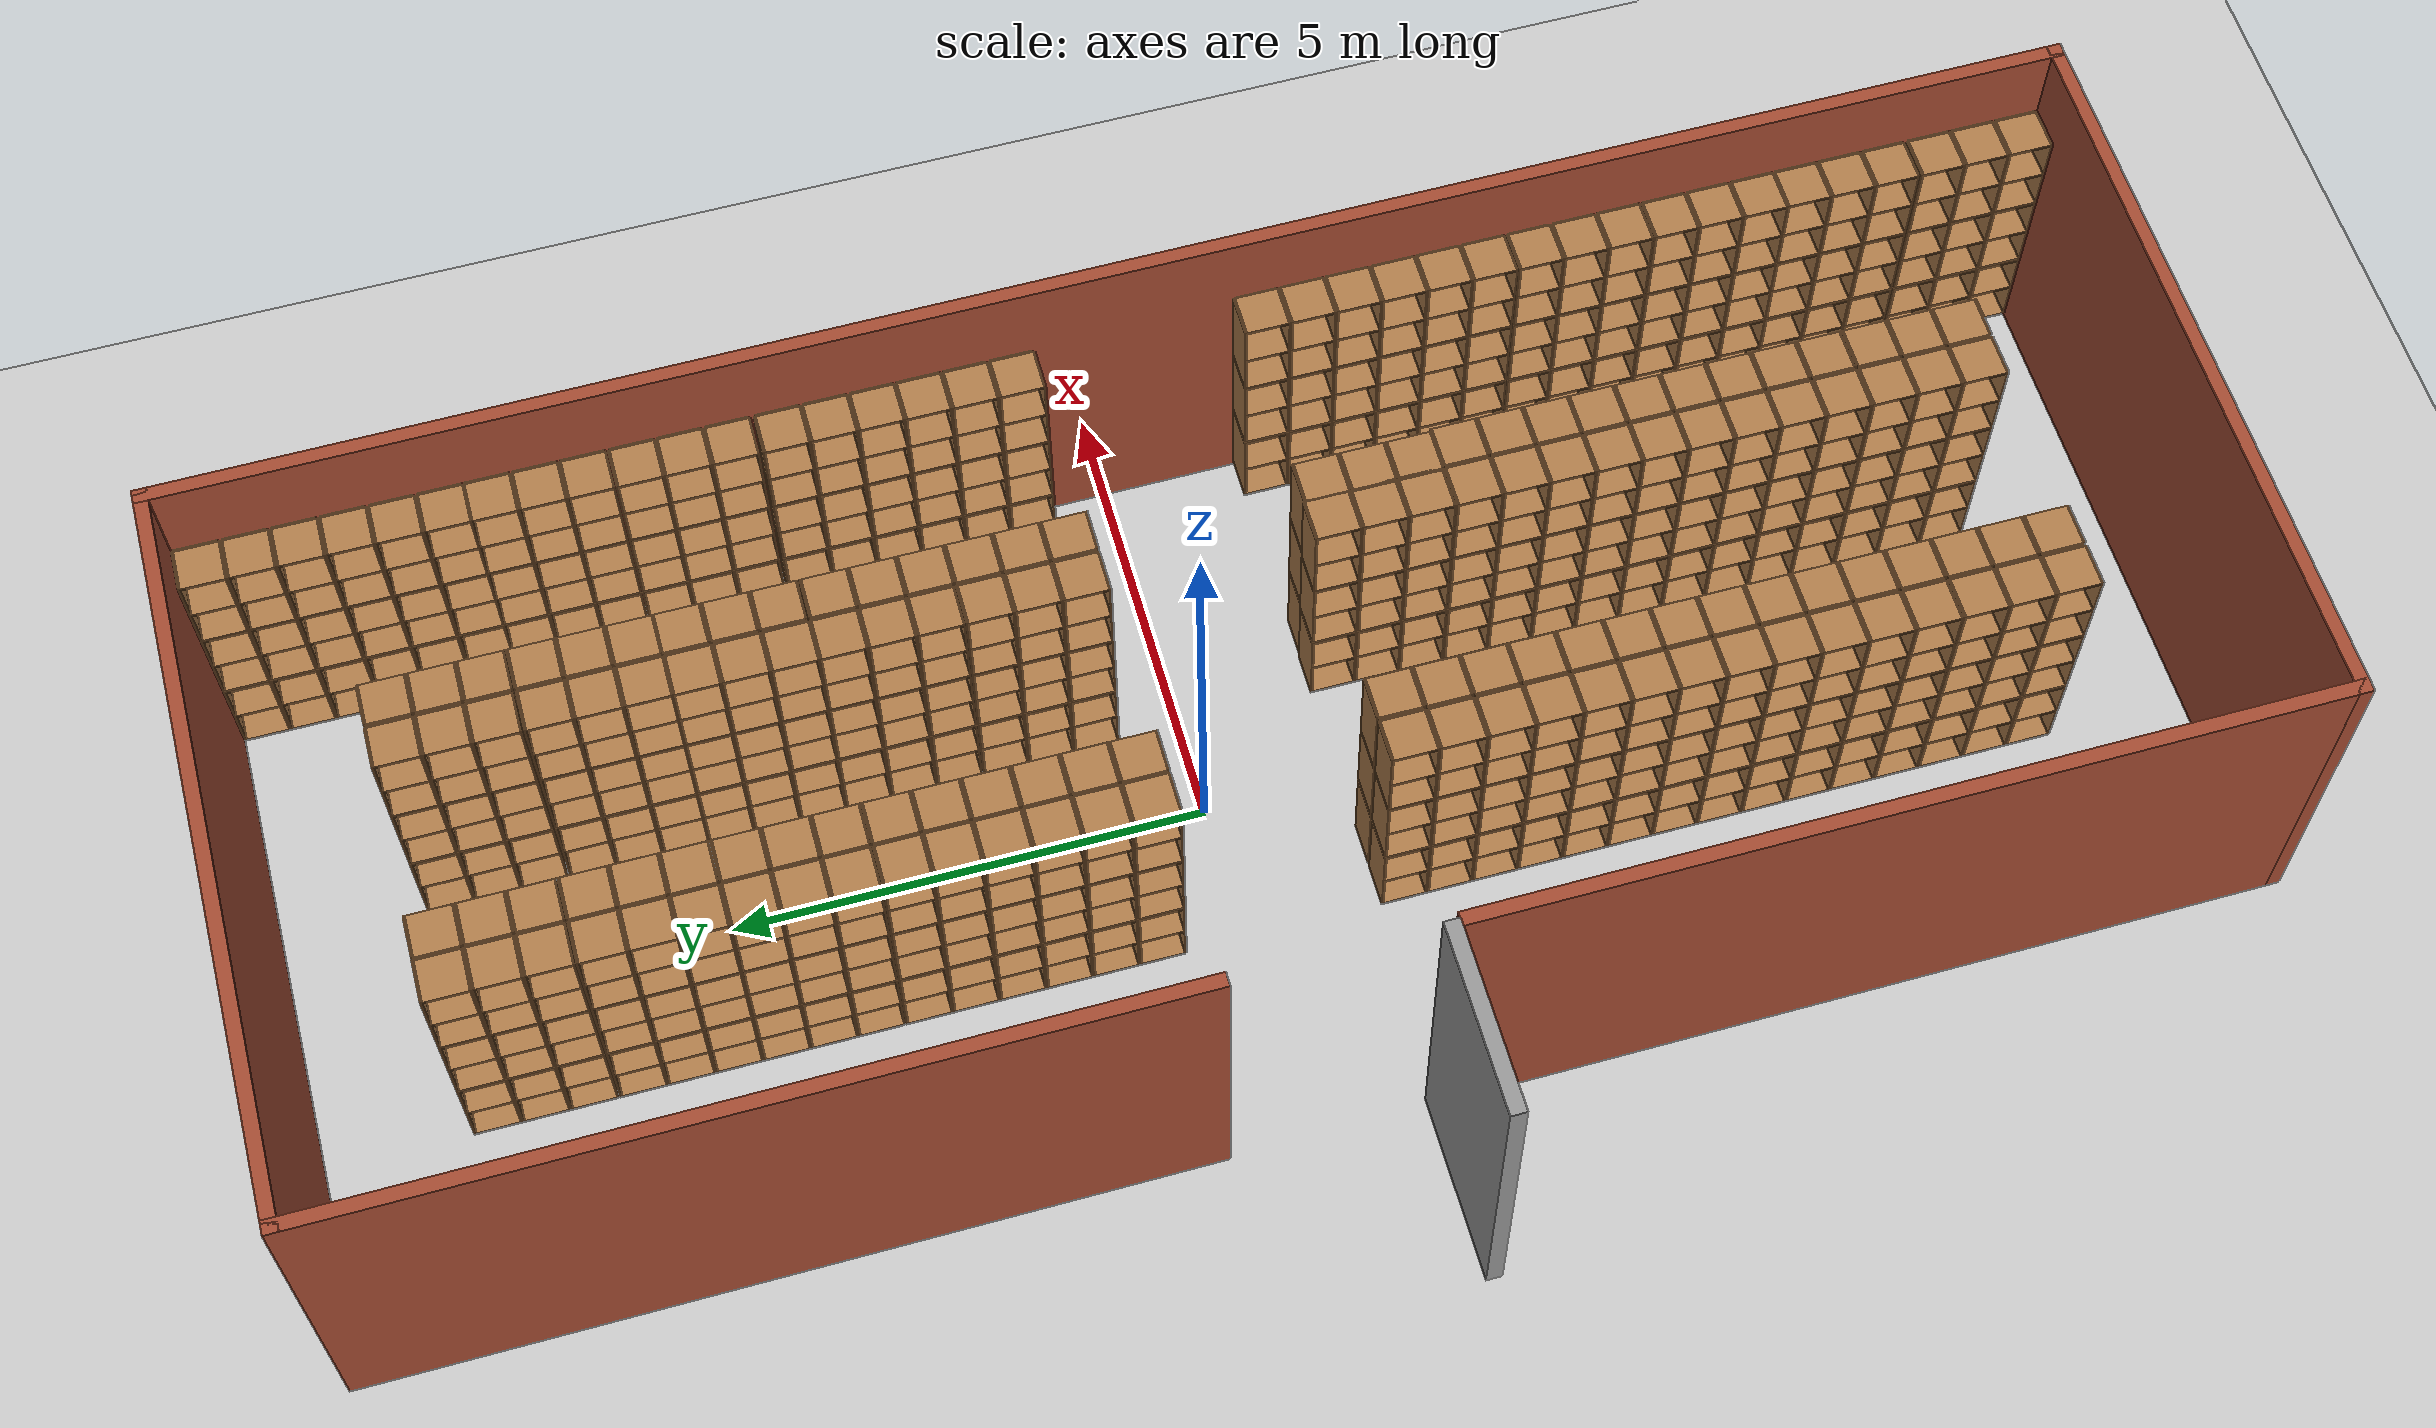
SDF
<sdf version="1.6">
 <world name="default">
  <light name="sun" type="directional">
   <pose>0 0 10 0 -0 0</pose>
   <diffuse>0.8 0.8 0.8 1</diffuse>
   <specular>0.2 0.2 0.2 1</specular>
   <attenuation>
    <range>1000</range>
    <constant>0.9</constant>
    <linear>0.01</linear>
    <quadratic>0.001</quadratic>
   </attenuation>
   <direction>-0.5 0.1 -0.9</direction>
  </light>
  <model name="ground_plane">
   <static>1</static>
   <link name="link">
    <collision name="collision">
     <geometry><plane><normal>0 0 1</normal><size>100 100</size></plane></geometry>
     <surface>
      <contact><collide_bitmask>65535</collide_bitmask></contact>
      <friction><ode><mu>100</mu><mu2>50</mu2></ode></friction>
     </surface>
    </collision>
    <visual name="visual">
     <cast_shadows>0</cast_shadows>
     <geometry><plane><normal>0 0 1</normal><size>100 100</size></plane></geometry>
     <material>
      <script><uri>file://media/materials/scripts/gazebo.material</uri><name>Gazebo/Grey</name></script>
     </material>
    </visual>
   </link>
  </model>
  <gravity>0 0 -9.8</gravity>
  <magnetic_field>6e-06 2.3e-05 -4.2e-05</magnetic_field>
  <atmosphere type="adiabatic"/>
  <physics name="default_physics" default="0" type="ode">
   <max_step_size>0.001</max_step_size>
   <real_time_factor>1</real_time_factor>
   <real_time_update_rate>1000</real_time_update_rate>
  </physics>
  <scene><ambient>0.4 0.4 0.4 1</ambient><background>0.7 0.7 0.7 1</background><shadows>1</shadows></scene>
  <spherical_coordinates>
   <surface_model>EARTH_WGS84</surface_model>
   <latitude_deg>0</latitude_deg>
   <longitude_deg>0</longitude_deg>
   <elevation>0</elevation>
   <heading_deg>0</heading_deg>
  </spherical_coordinates>
  <model name="AGVUntitled">
   <pose>0.208057 -0.403929 0 0 -0 -3.1397</pose>
   <link name="Door_1">
    <collision name="Door_1_Collision">
     <geometry><box><size>2 0.17 4</size></box></geometry>
     <pose>0 0 2 0 -0 0</pose>
    </collision>
    <visual name="Door_1_Visual">
     <pose>0 0 2 0 -0 0</pose>
     <geometry><box><size>2 0.17 4</size></box></geometry>
     <material>
      <script><uri>file://media/materials/scripts/gazebo.material</uri><name>Gazebo/Grey</name></script>
     </material>
    </visual>
    <pose>4.90883 0.925001 0 0 -0 0</pose>
   </link>
   <link name="Wall_11">
    <collision name="Wall_11_Collision">
     <geometry><box><size>8 0.15 4</size></box></geometry>
     <pose>0 0 2 0 -0 0</pose>
    </collision>
    <visual name="Wall_11_Visual">
     <pose>0 0 2 0 -0 0</pose>
     <geometry><box><size>8 0.15 4</size></box></geometry>
     <material>
      <script><uri>file://media/materials/scripts/gazebo.material</uri><name>Gazebo/Bricks</name></script>
      <ambient>1 1 1 1</ambient>
     </material>
     <meta><layer>0</layer></meta>
    </visual>
    <pose>4.8e-05 9.925 0 0 -0 3.14155</pose>
   </link>
   <link name="Wall_13">
    <collision name="Wall_13_Collision">
     <geometry><box><size>20 0.15 4</size></box></geometry>
     <pose>0 0 2 0 -0 0</pose>
    </collision>
    <visual name="Wall_13_Visual">
     <pose>0 0 2 0 -0 0</pose>
     <geometry><box><size>20 0.15 4</size></box></geometry>
     <material>
      <script><uri>file://media/materials/scripts/gazebo.material</uri><name>Gazebo/Bricks</name></script>
      <ambient>1 1 1 1</ambient>
     </material>
     <meta><layer>0</layer></meta>
    </visual>
    <pose>-3.92495 -1e-06 0 0 -0 -1.57081</pose>
   </link>
   <link name="Wall_16">
    <collision name="Wall_16_Collision">
     <geometry><box><size>9 0.15 4</size></box></geometry>
     <pose>0 0 2 0 -0 0</pose>
    </collision>
    <visual name="Wall_16_Visual">
     <pose>0 0 2 0 -0 0</pose>
     <geometry><box><size>9 0.15 4</size></box></geometry>
     <material>
      <script><uri>file://media/materials/scripts/gazebo.material</uri><name>Gazebo/Bricks</name></script>
      <ambient>1 1 1 1</ambient>
     </material>
     <meta><layer>0</layer></meta>
    </visual>
    <pose>3.92495 5.49984 0 0 -0 -1.5708</pose>
   </link>
   <link name="Wall_22">
    <collision name="Wall_22_Collision">
     <geometry><box><size>8 0.15 4</size></box></geometry>
     <pose>0 0 2 0 -0 0</pose>
    </collision>
    <visual name="Wall_22_Visual">
     <pose>0 0 2 0 -0 0</pose>
     <geometry><box><size>8 0.15 4</size></box></geometry>
     <material>
      <script><uri>file://media/materials/scripts/gazebo.material</uri><name>Gazebo/Bricks</name></script>
      <ambient>1 1 1 1</ambient>
     </material>
     <meta><layer>0</layer></meta>
    </visual>
    <pose>-5.1e-05 -9.92516 0 0 -0 0</pose>
   </link>
   <link name="Wall_26">
    <collision name="Wall_26_Collision">
     <geometry><box><size>8.8 0.15 4</size></box></geometry>
     <pose>0 0 2 0 -0 0</pose>
    </collision>
    <visual name="Wall_26_Visual">
     <pose>0 0 2 0 -0 0</pose>
     <geometry><box><size>8.8 0.15 4</size></box></geometry>
     <material>
      <script><uri>file://media/materials/scripts/gazebo.material</uri><name>Gazebo/Bricks</name></script>
      <ambient>1 1 1 1</ambient>
     </material>
     <meta><layer>0</layer></meta>
    </visual>
    <pose>3.92495 -5.60016 0 0 -0 1.5708</pose>
   </link>
   <static>1</static>
  </model>
  <model name="Locker18">
   <model name="Locker18">
    <model name="Locker3">
     <model name="cabinet">
      <static>1</static>
      <link name="cabinet_bottom_plate">
       <inertial>
        <pose>0 0 -1 0 -0 0</pose>
        <inertia><ixx>2.05</ixx><ixy>0</ixy><ixz>0</ixz><iyy>2.05</iyy><iyz>0</iyz><izz>2.05</izz></inertia>
        <mass>25</mass>
       </inertial>
       <collision name="cabinet_bottom_plate_geom">
        <pose>0 0 0.01 0 -0 0</pose>
        <geometry><box><size>0.45 0.45 0.02</size></box></geometry>
       </collision>
       <visual name="cabinet_bottom_plate_geom_visual">
        <pose>0 0 0.01 0 -0 0</pose>
        <geometry><box><size>0.45 0.45 0.02</size></box></geometry>
        <material>
         <script><uri>file://media/materials/scripts/gazebo.material</uri><name>Gazebo/Wood</name></script>
        </material>
       </visual>
       <collision name="cabinet_bottom_plate_geom_cabinet_back_plate">
        <pose>0.235 0 0.51 0 -0 0</pose>
        <geometry><box><size>0.02 0.45 1.02</size></box></geometry>
       </collision>
       <visual name="cabinet_bottom_plate_geom_cabinet_back_plate_visual">
        <pose>0.235 0 0.51 0 -0 0</pose>
        <geometry><box><size>0.02 0.45 1.02</size></box></geometry>
        <material>
         <script><uri>file://media/materials/scripts/gazebo.material</uri><name>Gazebo/Wood</name></script>
        </material>
       </visual>
       <collision name="cabinet_bottom_plate_geom_cabinet_left_plate">
        <pose>0 0.235 0.51 0 -0 0</pose>
        <geometry><box><size>0.45 0.02 1.02</size></box></geometry>
       </collision>
       <visual name="cabinet_bottom_plate_geom_cabinet_left_plate_visual">
        <pose>0 0.235 0.51 0 -0 0</pose>
        <geometry><box><size>0.45 0.02 1.02</size></box></geometry>
        <material>
         <script><uri>file://media/materials/scripts/gazebo.material</uri><name>Gazebo/Wood</name></script>
        </material>
       </visual>
       <collision name="cabinet_bottom_plate_geom_cabinet_middle_plate">
        <pose>0 0 0.51 0 -0 0</pose>
        <geometry><box><size>0.45 0.45 0.02</size></box></geometry>
       </collision>
       <visual name="cabinet_bottom_plate_geom_cabinet_middle_plate_visual">
        <pose>0 0 0.51 0 -0 0</pose>
        <geometry><box><size>0.45 0.45 0.02</size></box></geometry>
        <material>
         <script><uri>file://media/materials/scripts/gazebo.material</uri><name>Gazebo/Wood</name></script>
        </material>
       </visual>
       <collision name="cabinet_bottom_plate_geom_cabinet_right_plate">
        <pose>0 -0.235 0.51 0 -0 0</pose>
        <geometry><box><size>0.45 0.02 1.02</size></box></geometry>
       </collision>
       <visual name="cabinet_bottom_plate_geom_cabinet_right_plate_visual">
        <pose>0 -0.235 0.51 0 -0 0</pose>
        <geometry><box><size>0.45 0.02 1.02</size></box></geometry>
        <material>
         <script><uri>file://media/materials/scripts/gazebo.material</uri><name>Gazebo/Wood</name></script>
        </material>
       </visual>
       <collision name="cabinet_bottom_plate_geom_cabinet_top_plate">
        <pose>0 0 1.01 0 -0 0</pose>
        <geometry><box><size>0.45 0.45 0.02</size></box></geometry>
       </collision>
       <visual name="cabinet_bottom_plate_geom_cabinet_top_plate_visual">
        <pose>0 0 1.01 0 -0 0</pose>
        <geometry><box><size>0.45 0.45 0.02</size></box></geometry>
        <material>
         <script><uri>file://media/materials/scripts/gazebo.material</uri><name>Gazebo/Wood</name></script>
        </material>
       </visual>
      </link>
      <pose>-0.676968 1.45758 0 0 -0 0</pose>
     </model>
     <model name="cabinet_clone">
      <static>1</static>
      <link name="cabinet_bottom_plate">
       <inertial>
        <pose>0 0 -1 0 -0 0</pose>
        <inertia><ixx>2.05</ixx><ixy>0</ixy><ixz>0</ixz><iyy>2.05</iyy><iyz>0</iyz><izz>2.05</izz></inertia>
        <mass>25</mass>
       </inertial>
       <collision name="cabinet_bottom_plate_geom">
        <pose>0 0 0.01 0 -0 0</pose>
        <geometry><box><size>0.45 0.45 0.02</size></box></geometry>
       </collision>
       <visual name="cabinet_bottom_plate_geom_visual">
        <pose>0 0 0.01 0 -0 0</pose>
        <geometry><box><size>0.45 0.45 0.02</size></box></geometry>
        <material>
         <script><uri>file://media/materials/scripts/gazebo.material</uri><name>Gazebo/Wood</name></script>
        </material>
       </visual>
       <collision name="cabinet_bottom_plate_geom_cabinet_back_plate">
        <pose>0.235 0 0.51 0 -0 0</pose>
        <geometry><box><size>0.02 0.45 1.02</size></box></geometry>
       </collision>
       <visual name="cabinet_bottom_plate_geom_cabinet_back_plate_visual">
        <pose>0.235 0 0.51 0 -0 0</pose>
        <geometry><box><size>0.02 0.45 1.02</size></box></geometry>
        <material>
         <script><uri>file://media/materials/scripts/gazebo.material</uri><name>Gazebo/Wood</name></script>
        </material>
       </visual>
       <collision name="cabinet_bottom_plate_geom_cabinet_left_plate">
        <pose>0 0.235 0.51 0 -0 0</pose>
        <geometry><box><size>0.45 0.02 1.02</size></box></geometry>
       </collision>
       <visual name="cabinet_bottom_plate_geom_cabinet_left_plate_visual">
        <pose>0 0.235 0.51 0 -0 0</pose>
        <geometry><box><size>0.45 0.02 1.02</size></box></geometry>
        <material>
         <script><uri>file://media/materials/scripts/gazebo.material</uri><name>Gazebo/Wood</name></script>
        </material>
       </visual>
       <collision name="cabinet_bottom_plate_geom_cabinet_middle_plate">
        <pose>0 0 0.51 0 -0 0</pose>
        <geometry><box><size>0.45 0.45 0.02</size></box></geometry>
       </collision>
       <visual name="cabinet_bottom_plate_geom_cabinet_middle_plate_visual">
        <pose>0 0 0.51 0 -0 0</pose>
        <geometry><box><size>0.45 0.45 0.02</size></box></geometry>
        <material>
         <script><uri>file://media/materials/scripts/gazebo.material</uri><name>Gazebo/Wood</name></script>
        </material>
       </visual>
       <collision name="cabinet_bottom_plate_geom_cabinet_right_plate">
        <pose>0 -0.235 0.51 0 -0 0</pose>
        <geometry><box><size>0.45 0.02 1.02</size></box></geometry>
       </collision>
       <visual name="cabinet_bottom_plate_geom_cabinet_right_plate_visual">
        <pose>0 -0.235 0.51 0 -0 0</pose>
        <geometry><box><size>0.45 0.02 1.02</size></box></geometry>
        <material>
         <script><uri>file://media/materials/scripts/gazebo.material</uri><name>Gazebo/Wood</name></script>
        </material>
       </visual>
       <collision name="cabinet_bottom_plate_geom_cabinet_top_plate">
        <pose>0 0 1.01 0 -0 0</pose>
        <geometry><box><size>0.45 0.45 0.02</size></box></geometry>
       </collision>
       <visual name="cabinet_bottom_plate_geom_cabinet_top_plate_visual">
        <pose>0 0 1.01 0 -0 0</pose>
        <geometry><box><size>0.45 0.45 0.02</size></box></geometry>
        <material>
         <script><uri>file://media/materials/scripts/gazebo.material</uri><name>Gazebo/Wood</name></script>
        </material>
       </visual>
      </link>
      <pose>-0.676968 0.970971 0 0 -0 0</pose>
     </model>
     <model name="cabinet_clone_0">
      <static>1</static>
      <link name="cabinet_bottom_plate">
       <inertial>
        <pose>0 0 -1 0 -0 0</pose>
        <inertia><ixx>2.05</ixx><ixy>0</ixy><ixz>0</ixz><iyy>2.05</iyy><iyz>0</iyz><izz>2.05</izz></inertia>
        <mass>25</mass>
       </inertial>
       <collision name="cabinet_bottom_plate_geom">
        <pose>0 0 0.01 0 -0 0</pose>
        <geometry><box><size>0.45 0.45 0.02</size></box></geometry>
       </collision>
       <visual name="cabinet_bottom_plate_geom_visual">
        <pose>0 0 0.01 0 -0 0</pose>
        <geometry><box><size>0.45 0.45 0.02</size></box></geometry>
        <material>
         <script><uri>file://media/materials/scripts/gazebo.material</uri><name>Gazebo/Wood</name></script>
        </material>
       </visual>
       <collision name="cabinet_bottom_plate_geom_cabinet_back_plate">
        <pose>0.235 0 0.51 0 -0 0</pose>
        <geometry><box><size>0.02 0.45 1.02</size></box></geometry>
       </collision>
       <visual name="cabinet_bottom_plate_geom_cabinet_back_plate_visual">
        <pose>0.235 0 0.51 0 -0 0</pose>
        <geometry><box><size>0.02 0.45 1.02</size></box></geometry>
        <material>
         <script><uri>file://media/materials/scripts/gazebo.material</uri><name>Gazebo/Wood</name></script>
        </material>
       </visual>
       <collision name="cabinet_bottom_plate_geom_cabinet_left_plate">
        <pose>0 0.235 0.51 0 -0 0</pose>
        <geometry><box><size>0.45 0.02 1.02</size></box></geometry>
       </collision>
       <visual name="cabinet_bottom_plate_geom_cabinet_left_plate_visual">
        <pose>0 0.235 0.51 0 -0 0</pose>
        <geometry><box><size>0.45 0.02 1.02</size></box></geometry>
        <material>
         <script><uri>file://media/materials/scripts/gazebo.material</uri><name>Gazebo/Wood</name></script>
        </material>
       </visual>
       <collision name="cabinet_bottom_plate_geom_cabinet_middle_plate">
        <pose>0 0 0.51 0 -0 0</pose>
        <geometry><box><size>0.45 0.45 0.02</size></box></geometry>
       </collision>
       <visual name="cabinet_bottom_plate_geom_cabinet_middle_plate_visual">
        <pose>0 0 0.51 0 -0 0</pose>
        <geometry><box><size>0.45 0.45 0.02</size></box></geometry>
        <material>
         <script><uri>file://media/materials/scripts/gazebo.material</uri><name>Gazebo/Wood</name></script>
        </material>
       </visual>
       <collision name="cabinet_bottom_plate_geom_cabinet_right_plate">
        <pose>0 -0.235 0.51 0 -0 0</pose>
        <geometry><box><size>0.45 0.02 1.02</size></box></geometry>
       </collision>
       <visual name="cabinet_bottom_plate_geom_cabinet_right_plate_visual">
        <pose>0 -0.235 0.51 0 -0 0</pose>
        <geometry><box><size>0.45 0.02 1.02</size></box></geometry>
        <material>
         <script><uri>file://media/materials/scripts/gazebo.material</uri><name>Gazebo/Wood</name></script>
        </material>
       </visual>
       <collision name="cabinet_bottom_plate_geom_cabinet_top_plate">
        <pose>0 0 1.01 0 -0 0</pose>
        <geometry><box><size>0.45 0.45 0.02</size></box></geometry>
       </collision>
       <visual name="cabinet_bottom_plate_geom_cabinet_top_plate_visual">
        <pose>0 0 1.01 0 -0 0</pose>
        <geometry><box><size>0.45 0.45 0.02</size></box></geometry>
        <material>
         <script><uri>file://media/materials/scripts/gazebo.material</uri><name>Gazebo/Wood</name></script>
        </material>
       </visual>
      </link>
      <pose>-0.676968 0.48391 0 0 -0 0</pose>
     </model>
     <static>0</static>
     <pose>0 3e-06 -1.02763 0 -0 0</pose>
    </model>
    <model name="Locker3_clone">
     <model name="cabinet">
      <static>1</static>
      <link name="cabinet_bottom_plate">
       <inertial>
        <pose>0 0 -1 0 -0 0</pose>
        <inertia><ixx>2.05</ixx><ixy>0</ixy><ixz>0</ixz><iyy>2.05</iyy><iyz>0</iyz><izz>2.05</izz></inertia>
        <mass>25</mass>
       </inertial>
       <collision name="cabinet_bottom_plate_geom">
        <pose>0 0 0.01 0 -0 0</pose>
        <geometry><box><size>0.45 0.45 0.02</size></box></geometry>
       </collision>
       <visual name="cabinet_bottom_plate_geom_visual">
        <pose>0 0 0.01 0 -0 0</pose>
        <geometry><box><size>0.45 0.45 0.02</size></box></geometry>
        <material>
         <script><uri>file://media/materials/scripts/gazebo.material</uri><name>Gazebo/Wood</name></script>
        </material>
       </visual>
       <collision name="cabinet_bottom_plate_geom_cabinet_back_plate">
        <pose>0.235 0 0.51 0 -0 0</pose>
        <geometry><box><size>0.02 0.45 1.02</size></box></geometry>
       </collision>
       <visual name="cabinet_bottom_plate_geom_cabinet_back_plate_visual">
        <pose>0.235 0 0.51 0 -0 0</pose>
        <geometry><box><size>0.02 0.45 1.02</size></box></geometry>
        <material>
         <script><uri>file://media/materials/scripts/gazebo.material</uri><name>Gazebo/Wood</name></script>
        </material>
       </visual>
       <collision name="cabinet_bottom_plate_geom_cabinet_left_plate">
        <pose>0 0.235 0.51 0 -0 0</pose>
        <geometry><box><size>0.45 0.02 1.02</size></box></geometry>
       </collision>
       <visual name="cabinet_bottom_plate_geom_cabinet_left_plate_visual">
        <pose>0 0.235 0.51 0 -0 0</pose>
        <geometry><box><size>0.45 0.02 1.02</size></box></geometry>
        <material>
         <script><uri>file://media/materials/scripts/gazebo.material</uri><name>Gazebo/Wood</name></script>
        </material>
       </visual>
       <collision name="cabinet_bottom_plate_geom_cabinet_middle_plate">
        <pose>0 0 0.51 0 -0 0</pose>
        <geometry><box><size>0.45 0.45 0.02</size></box></geometry>
       </collision>
       <visual name="cabinet_bottom_plate_geom_cabinet_middle_plate_visual">
        <pose>0 0 0.51 0 -0 0</pose>
        <geometry><box><size>0.45 0.45 0.02</size></box></geometry>
        <material>
         <script><uri>file://media/materials/scripts/gazebo.material</uri><name>Gazebo/Wood</name></script>
        </material>
       </visual>
       <collision name="cabinet_bottom_plate_geom_cabinet_right_plate">
        <pose>0 -0.235 0.51 0 -0 0</pose>
        <geometry><box><size>0.45 0.02 1.02</size></box></geometry>
       </collision>
       <visual name="cabinet_bottom_plate_geom_cabinet_right_plate_visual">
        <pose>0 -0.235 0.51 0 -0 0</pose>
        <geometry><box><size>0.45 0.02 1.02</size></box></geometry>
        <material>
         <script><uri>file://media/materials/scripts/gazebo.material</uri><name>Gazebo/Wood</name></script>
        </material>
       </visual>
       <collision name="cabinet_bottom_plate_geom_cabinet_top_plate">
        <pose>0 0 1.01 0 -0 0</pose>
        <geometry><box><size>0.45 0.45 0.02</size></box></geometry>
       </collision>
       <visual name="cabinet_bottom_plate_geom_cabinet_top_plate_visual">
        <pose>0 0 1.01 0 -0 0</pose>
        <geometry><box><size>0.45 0.45 0.02</size></box></geometry>
        <material>
         <script><uri>file://media/materials/scripts/gazebo.material</uri><name>Gazebo/Wood</name></script>
        </material>
       </visual>
      </link>
      <pose>-0.676968 1.45758 0 0 -0 0</pose>
     </model>
     <model name="cabinet_clone">
      <static>1</static>
      <link name="cabinet_bottom_plate">
       <inertial>
        <pose>0 0 -1 0 -0 0</pose>
        <inertia><ixx>2.05</ixx><ixy>0</ixy><ixz>0</ixz><iyy>2.05</iyy><iyz>0</iyz><izz>2.05</izz></inertia>
        <mass>25</mass>
       </inertial>
       <collision name="cabinet_bottom_plate_geom">
        <pose>0 0 0.01 0 -0 0</pose>
        <geometry><box><size>0.45 0.45 0.02</size></box></geometry>
       </collision>
       <visual name="cabinet_bottom_plate_geom_visual">
        <pose>0 0 0.01 0 -0 0</pose>
        <geometry><box><size>0.45 0.45 0.02</size></box></geometry>
        <material>
         <script><uri>file://media/materials/scripts/gazebo.material</uri><name>Gazebo/Wood</name></script>
        </material>
       </visual>
       <collision name="cabinet_bottom_plate_geom_cabinet_back_plate">
        <pose>0.235 0 0.51 0 -0 0</pose>
        <geometry><box><size>0.02 0.45 1.02</size></box></geometry>
       </collision>
       <visual name="cabinet_bottom_plate_geom_cabinet_back_plate_visual">
        <pose>0.235 0 0.51 0 -0 0</pose>
        <geometry><box><size>0.02 0.45 1.02</size></box></geometry>
        <material>
         <script><uri>file://media/materials/scripts/gazebo.material</uri><name>Gazebo/Wood</name></script>
        </material>
       </visual>
       <collision name="cabinet_bottom_plate_geom_cabinet_left_plate">
        <pose>0 0.235 0.51 0 -0 0</pose>
        <geometry><box><size>0.45 0.02 1.02</size></box></geometry>
       </collision>
       <visual name="cabinet_bottom_plate_geom_cabinet_left_plate_visual">
        <pose>0 0.235 0.51 0 -0 0</pose>
        <geometry><box><size>0.45 0.02 1.02</size></box></geometry>
        <material>
         <script><uri>file://media/materials/scripts/gazebo.material</uri><name>Gazebo/Wood</name></script>
        </material>
       </visual>
       <collision name="cabinet_bottom_plate_geom_cabinet_middle_plate">
        <pose>0 0 0.51 0 -0 0</pose>
        <geometry><box><size>0.45 0.45 0.02</size></box></geometry>
       </collision>
       <visual name="cabinet_bottom_plate_geom_cabinet_middle_plate_visual">
        <pose>0 0 0.51 0 -0 0</pose>
        <geometry><box><size>0.45 0.45 0.02</size></box></geometry>
        <material>
         <script><uri>file://media/materials/scripts/gazebo.material</uri><name>Gazebo/Wood</name></script>
        </material>
       </visual>
       <collision name="cabinet_bottom_plate_geom_cabinet_right_plate">
        <pose>0 -0.235 0.51 0 -0 0</pose>
        <geometry><box><size>0.45 0.02 1.02</size></box></geometry>
       </collision>
       <visual name="cabinet_bottom_plate_geom_cabinet_right_plate_visual">
        <pose>0 -0.235 0.51 0 -0 0</pose>
        <geometry><box><size>0.45 0.02 1.02</size></box></geometry>
        <material>
         <script><uri>file://media/materials/scripts/gazebo.material</uri><name>Gazebo/Wood</name></script>
        </material>
       </visual>
       <collision name="cabinet_bottom_plate_geom_cabinet_top_plate">
        <pose>0 0 1.01 0 -0 0</pose>
        <geometry><box><size>0.45 0.45 0.02</size></box></geometry>
       </collision>
       <visual name="cabinet_bottom_plate_geom_cabinet_top_plate_visual">
        <pose>0 0 1.01 0 -0 0</pose>
        <geometry><box><size>0.45 0.45 0.02</size></box></geometry>
        <material>
         <script><uri>file://media/materials/scripts/gazebo.material</uri><name>Gazebo/Wood</name></script>
        </material>
       </visual>
      </link>
      <pose>-0.676968 0.970971 0 0 -0 0</pose>
     </model>
     <model name="cabinet_clone_0">
      <static>1</static>
      <link name="cabinet_bottom_plate">
       <inertial>
        <pose>0 0 -1 0 -0 0</pose>
        <inertia><ixx>2.05</ixx><ixy>0</ixy><ixz>0</ixz><iyy>2.05</iyy><iyz>0</iyz><izz>2.05</izz></inertia>
        <mass>25</mass>
       </inertial>
       <collision name="cabinet_bottom_plate_geom">
        <pose>0 0 0.01 0 -0 0</pose>
        <geometry><box><size>0.45 0.45 0.02</size></box></geometry>
       </collision>
       <visual name="cabinet_bottom_plate_geom_visual">
        <pose>0 0 0.01 0 -0 0</pose>
        <geometry><box><size>0.45 0.45 0.02</size></box></geometry>
        <material>
         <script><uri>file://media/materials/scripts/gazebo.material</uri><name>Gazebo/Wood</name></script>
        </material>
       </visual>
       <collision name="cabinet_bottom_plate_geom_cabinet_back_plate">
        <pose>0.235 0 0.51 0 -0 0</pose>
        <geometry><box><size>0.02 0.45 1.02</size></box></geometry>
       </collision>
       <visual name="cabinet_bottom_plate_geom_cabinet_back_plate_visual">
        <pose>0.235 0 0.51 0 -0 0</pose>
        <geometry><box><size>0.02 0.45 1.02</size></box></geometry>
        <material>
         <script><uri>file://media/materials/scripts/gazebo.material</uri><name>Gazebo/Wood</name></script>
        </material>
       </visual>
       <collision name="cabinet_bottom_plate_geom_cabinet_left_plate">
        <pose>0 0.235 0.51 0 -0 0</pose>
        <geometry><box><size>0.45 0.02 1.02</size></box></geometry>
       </collision>
       <visual name="cabinet_bottom_plate_geom_cabinet_left_plate_visual">
        <pose>0 0.235 0.51 0 -0 0</pose>
        <geometry><box><size>0.45 0.02 1.02</size></box></geometry>
        <material>
         <script><uri>file://media/materials/scripts/gazebo.material</uri><name>Gazebo/Wood</name></script>
        </material>
       </visual>
       <collision name="cabinet_bottom_plate_geom_cabinet_middle_plate">
        <pose>0 0 0.51 0 -0 0</pose>
        <geometry><box><size>0.45 0.45 0.02</size></box></geometry>
       </collision>
       <visual name="cabinet_bottom_plate_geom_cabinet_middle_plate_visual">
        <pose>0 0 0.51 0 -0 0</pose>
        <geometry><box><size>0.45 0.45 0.02</size></box></geometry>
        <material>
         <script><uri>file://media/materials/scripts/gazebo.material</uri><name>Gazebo/Wood</name></script>
        </material>
       </visual>
       <collision name="cabinet_bottom_plate_geom_cabinet_right_plate">
        <pose>0 -0.235 0.51 0 -0 0</pose>
        <geometry><box><size>0.45 0.02 1.02</size></box></geometry>
       </collision>
       <visual name="cabinet_bottom_plate_geom_cabinet_right_plate_visual">
        <pose>0 -0.235 0.51 0 -0 0</pose>
        <geometry><box><size>0.45 0.02 1.02</size></box></geometry>
        <material>
         <script><uri>file://media/materials/scripts/gazebo.material</uri><name>Gazebo/Wood</name></script>
        </material>
       </visual>
       <collision name="cabinet_bottom_plate_geom_cabinet_top_plate">
        <pose>0 0 1.01 0 -0 0</pose>
        <geometry><box><size>0.45 0.45 0.02</size></box></geometry>
       </collision>
       <visual name="cabinet_bottom_plate_geom_cabinet_top_plate_visual">
        <pose>0 0 1.01 0 -0 0</pose>
        <geometry><box><size>0.45 0.45 0.02</size></box></geometry>
        <material>
         <script><uri>file://media/materials/scripts/gazebo.material</uri><name>Gazebo/Wood</name></script>
        </material>
       </visual>
      </link>
      <pose>-0.676968 0.48391 0 0 -0 0</pose>
     </model>
     <static>0</static>
     <pose>0 3e-06 0.003717 0 -0 0</pose>
    </model>
    <model name="Locker3_clone_clone">
     <model name="cabinet">
      <static>1</static>
      <link name="cabinet_bottom_plate">
       <inertial>
        <pose>0 0 -1 0 -0 0</pose>
        <inertia><ixx>2.05</ixx><ixy>0</ixy><ixz>0</ixz><iyy>2.05</iyy><iyz>0</iyz><izz>2.05</izz></inertia>
        <mass>25</mass>
       </inertial>
       <collision name="cabinet_bottom_plate_geom">
        <pose>0 0 0.01 0 -0 0</pose>
        <geometry><box><size>0.45 0.45 0.02</size></box></geometry>
       </collision>
       <visual name="cabinet_bottom_plate_geom_visual">
        <pose>0 0 0.01 0 -0 0</pose>
        <geometry><box><size>0.45 0.45 0.02</size></box></geometry>
        <material>
         <script><uri>file://media/materials/scripts/gazebo.material</uri><name>Gazebo/Wood</name></script>
        </material>
       </visual>
       <collision name="cabinet_bottom_plate_geom_cabinet_back_plate">
        <pose>0.235 0 0.51 0 -0 0</pose>
        <geometry><box><size>0.02 0.45 1.02</size></box></geometry>
       </collision>
       <visual name="cabinet_bottom_plate_geom_cabinet_back_plate_visual">
        <pose>0.235 0 0.51 0 -0 0</pose>
        <geometry><box><size>0.02 0.45 1.02</size></box></geometry>
        <material>
         <script><uri>file://media/materials/scripts/gazebo.material</uri><name>Gazebo/Wood</name></script>
        </material>
       </visual>
       <collision name="cabinet_bottom_plate_geom_cabinet_left_plate">
        <pose>0 0.235 0.51 0 -0 0</pose>
        <geometry><box><size>0.45 0.02 1.02</size></box></geometry>
       </collision>
       <visual name="cabinet_bottom_plate_geom_cabinet_left_plate_visual">
        <pose>0 0.235 0.51 0 -0 0</pose>
        <geometry><box><size>0.45 0.02 1.02</size></box></geometry>
        <material>
         <script><uri>file://media/materials/scripts/gazebo.material</uri><name>Gazebo/Wood</name></script>
        </material>
       </visual>
       <collision name="cabinet_bottom_plate_geom_cabinet_middle_plate">
        <pose>0 0 0.51 0 -0 0</pose>
        <geometry><box><size>0.45 0.45 0.02</size></box></geometry>
       </collision>
       <visual name="cabinet_bottom_plate_geom_cabinet_middle_plate_visual">
        <pose>0 0 0.51 0 -0 0</pose>
        <geometry><box><size>0.45 0.45 0.02</size></box></geometry>
        <material>
         <script><uri>file://media/materials/scripts/gazebo.material</uri><name>Gazebo/Wood</name></script>
        </material>
       </visual>
       <collision name="cabinet_bottom_plate_geom_cabinet_right_plate">
        <pose>0 -0.235 0.51 0 -0 0</pose>
        <geometry><box><size>0.45 0.02 1.02</size></box></geometry>
       </collision>
       <visual name="cabinet_bottom_plate_geom_cabinet_right_plate_visual">
        <pose>0 -0.235 0.51 0 -0 0</pose>
        <geometry><box><size>0.45 0.02 1.02</size></box></geometry>
        <material>
         <script><uri>file://media/materials/scripts/gazebo.material</uri><name>Gazebo/Wood</name></script>
        </material>
       </visual>
       <collision name="cabinet_bottom_plate_geom_cabinet_top_plate">
        <pose>0 0 1.01 0 -0 0</pose>
        <geometry><box><size>0.45 0.45 0.02</size></box></geometry>
       </collision>
       <visual name="cabinet_bottom_plate_geom_cabinet_top_plate_visual">
        <pose>0 0 1.01 0 -0 0</pose>
        <geometry><box><size>0.45 0.45 0.02</size></box></geometry>
        <material>
         <script><uri>file://media/materials/scripts/gazebo.material</uri><name>Gazebo/Wood</name></script>
        </material>
       </visual>
      </link>
      <pose>-0.676968 1.45758 0 0 -0 0</pose>
     </model>
     <model name="cabinet_clone">
      <static>1</static>
      <link name="cabinet_bottom_plate">
       <inertial>
        <pose>0 0 -1 0 -0 0</pose>
        <inertia><ixx>2.05</ixx><ixy>0</ixy><ixz>0</ixz><iyy>2.05</iyy><iyz>0</iyz><izz>2.05</izz></inertia>
        <mass>25</mass>
       </inertial>
       <collision name="cabinet_bottom_plate_geom">
        <pose>0 0 0.01 0 -0 0</pose>
        <geometry><box><size>0.45 0.45 0.02</size></box></geometry>
       </collision>
       <visual name="cabinet_bottom_plate_geom_visual">
        <pose>0 0 0.01 0 -0 0</pose>
        <geometry><box><size>0.45 0.45 0.02</size></box></geometry>
        <material>
         <script><uri>file://media/materials/scripts/gazebo.material</uri><name>Gazebo/Wood</name></script>
        </material>
       </visual>
       <collision name="cabinet_bottom_plate_geom_cabinet_back_plate">
        <pose>0.235 0 0.51 0 -0 0</pose>
        <geometry><box><size>0.02 0.45 1.02</size></box></geometry>
       </collision>
       <visual name="cabinet_bottom_plate_geom_cabinet_back_plate_visual">
        <pose>0.235 0 0.51 0 -0 0</pose>
        <geometry><box><size>0.02 0.45 1.02</size></box></geometry>
        <material>
         <script><uri>file://media/materials/scripts/gazebo.material</uri><name>Gazebo/Wood</name></script>
        </material>
       </visual>
       <collision name="cabinet_bottom_plate_geom_cabinet_left_plate">
        <pose>0 0.235 0.51 0 -0 0</pose>
        <geometry><box><size>0.45 0.02 1.02</size></box></geometry>
       </collision>
       <visual name="cabinet_bottom_plate_geom_cabinet_left_plate_visual">
        <pose>0 0.235 0.51 0 -0 0</pose>
        <geometry><box><size>0.45 0.02 1.02</size></box></geometry>
        <material>
         <script><uri>file://media/materials/scripts/gazebo.material</uri><name>Gazebo/Wood</name></script>
        </material>
       </visual>
       <collision name="cabinet_bottom_plate_geom_cabinet_middle_plate">
        <pose>0 0 0.51 0 -0 0</pose>
        <geometry><box><size>0.45 0.45 0.02</size></box></geometry>
       </collision>
       <visual name="cabinet_bottom_plate_geom_cabinet_middle_plate_visual">
        <pose>0 0 0.51 0 -0 0</pose>
        <geometry><box><size>0.45 0.45 0.02</size></box></geometry>
        <material>
         <script><uri>file://media/materials/scripts/gazebo.material</uri><name>Gazebo/Wood</name></script>
        </material>
       </visual>
       <collision name="cabinet_bottom_plate_geom_cabinet_right_plate">
        <pose>0 -0.235 0.51 0 -0 0</pose>
        <geometry><box><size>0.45 0.02 1.02</size></box></geometry>
       </collision>
       <visual name="cabinet_bottom_plate_geom_cabinet_right_plate_visual">
        <pose>0 -0.235 0.51 0 -0 0</pose>
        <geometry><box><size>0.45 0.02 1.02</size></box></geometry>
        <material>
         <script><uri>file://media/materials/scripts/gazebo.material</uri><name>Gazebo/Wood</name></script>
        </material>
       </visual>
       <collision name="cabinet_bottom_plate_geom_cabinet_top_plate">
        <pose>0 0 1.01 0 -0 0</pose>
        <geometry><box><size>0.45 0.45 0.02</size></box></geometry>
       </collision>
       <visual name="cabinet_bottom_plate_geom_cabinet_top_plate_visual">
        <pose>0 0 1.01 0 -0 0</pose>
        <geometry><box><size>0.45 0.45 0.02</size></box></geometry>
        <material>
         <script><uri>file://media/materials/scripts/gazebo.material</uri><name>Gazebo/Wood</name></script>
        </material>
       </visual>
      </link>
      <pose>-0.676968 0.970971 0 0 -0 0</pose>
     </model>
     <model name="cabinet_clone_0">
      <static>1</static>
      <link name="cabinet_bottom_plate">
       <inertial>
        <pose>0 0 -1 0 -0 0</pose>
        <inertia><ixx>2.05</ixx><ixy>0</ixy><ixz>0</ixz><iyy>2.05</iyy><iyz>0</iyz><izz>2.05</izz></inertia>
        <mass>25</mass>
       </inertial>
       <collision name="cabinet_bottom_plate_geom">
        <pose>0 0 0.01 0 -0 0</pose>
        <geometry><box><size>0.45 0.45 0.02</size></box></geometry>
       </collision>
       <visual name="cabinet_bottom_plate_geom_visual">
        <pose>0 0 0.01 0 -0 0</pose>
        <geometry><box><size>0.45 0.45 0.02</size></box></geometry>
        <material>
         <script><uri>file://media/materials/scripts/gazebo.material</uri><name>Gazebo/Wood</name></script>
        </material>
       </visual>
       <collision name="cabinet_bottom_plate_geom_cabinet_back_plate">
        <pose>0.235 0 0.51 0 -0 0</pose>
        <geometry><box><size>0.02 0.45 1.02</size></box></geometry>
       </collision>
       <visual name="cabinet_bottom_plate_geom_cabinet_back_plate_visual">
        <pose>0.235 0 0.51 0 -0 0</pose>
        <geometry><box><size>0.02 0.45 1.02</size></box></geometry>
        <material>
         <script><uri>file://media/materials/scripts/gazebo.material</uri><name>Gazebo/Wood</name></script>
        </material>
       </visual>
       <collision name="cabinet_bottom_plate_geom_cabinet_left_plate">
        <pose>0 0.235 0.51 0 -0 0</pose>
        <geometry><box><size>0.45 0.02 1.02</size></box></geometry>
       </collision>
       <visual name="cabinet_bottom_plate_geom_cabinet_left_plate_visual">
        <pose>0 0.235 0.51 0 -0 0</pose>
        <geometry><box><size>0.45 0.02 1.02</size></box></geometry>
        <material>
         <script><uri>file://media/materials/scripts/gazebo.material</uri><name>Gazebo/Wood</name></script>
        </material>
       </visual>
       <collision name="cabinet_bottom_plate_geom_cabinet_middle_plate">
        <pose>0 0 0.51 0 -0 0</pose>
        <geometry><box><size>0.45 0.45 0.02</size></box></geometry>
       </collision>
       <visual name="cabinet_bottom_plate_geom_cabinet_middle_plate_visual">
        <pose>0 0 0.51 0 -0 0</pose>
        <geometry><box><size>0.45 0.45 0.02</size></box></geometry>
        <material>
         <script><uri>file://media/materials/scripts/gazebo.material</uri><name>Gazebo/Wood</name></script>
        </material>
       </visual>
       <collision name="cabinet_bottom_plate_geom_cabinet_right_plate">
        <pose>0 -0.235 0.51 0 -0 0</pose>
        <geometry><box><size>0.45 0.02 1.02</size></box></geometry>
       </collision>
       <visual name="cabinet_bottom_plate_geom_cabinet_right_plate_visual">
        <pose>0 -0.235 0.51 0 -0 0</pose>
        <geometry><box><size>0.45 0.02 1.02</size></box></geometry>
        <material>
         <script><uri>file://media/materials/scripts/gazebo.material</uri><name>Gazebo/Wood</name></script>
        </material>
       </visual>
       <collision name="cabinet_bottom_plate_geom_cabinet_top_plate">
        <pose>0 0 1.01 0 -0 0</pose>
        <geometry><box><size>0.45 0.45 0.02</size></box></geometry>
       </collision>
       <visual name="cabinet_bottom_plate_geom_cabinet_top_plate_visual">
        <pose>0 0 1.01 0 -0 0</pose>
        <geometry><box><size>0.45 0.45 0.02</size></box></geometry>
        <material>
         <script><uri>file://media/materials/scripts/gazebo.material</uri><name>Gazebo/Wood</name></script>
        </material>
       </visual>
      </link>
      <pose>-0.676968 0.48391 0 0 -0 0</pose>
     </model>
     <static>0</static>
     <pose>0 3e-06 1.02391 0 -0 0</pose>
    </model>
    <static>0</static>
    <pose>-0 4e-06 4e-06 0 -0 0</pose>
   </model>
   <static>0</static>
   <pose>4.50277 -10.4792 1.08672 0 -0 0</pose>
  </model>
  <model name="Locker18_clone">
   <model name="Locker18">
    <model name="Locker3">
     <model name="cabinet">
      <static>1</static>
      <link name="cabinet_bottom_plate">
       <inertial>
        <pose>0 0 -1 0 -0 0</pose>
        <inertia><ixx>2.05</ixx><ixy>0</ixy><ixz>0</ixz><iyy>2.05</iyy><iyz>0</iyz><izz>2.05</izz></inertia>
        <mass>25</mass>
       </inertial>
       <collision name="cabinet_bottom_plate_geom">
        <pose>0 0 0.01 0 -0 0</pose>
        <geometry><box><size>0.45 0.45 0.02</size></box></geometry>
       </collision>
       <visual name="cabinet_bottom_plate_geom_visual">
        <pose>0 0 0.01 0 -0 0</pose>
        <geometry><box><size>0.45 0.45 0.02</size></box></geometry>
        <material>
         <script><uri>file://media/materials/scripts/gazebo.material</uri><name>Gazebo/Wood</name></script>
        </material>
       </visual>
       <collision name="cabinet_bottom_plate_geom_cabinet_back_plate">
        <pose>0.235 0 0.51 0 -0 0</pose>
        <geometry><box><size>0.02 0.45 1.02</size></box></geometry>
       </collision>
       <visual name="cabinet_bottom_plate_geom_cabinet_back_plate_visual">
        <pose>0.235 0 0.51 0 -0 0</pose>
        <geometry><box><size>0.02 0.45 1.02</size></box></geometry>
        <material>
         <script><uri>file://media/materials/scripts/gazebo.material</uri><name>Gazebo/Wood</name></script>
        </material>
       </visual>
       <collision name="cabinet_bottom_plate_geom_cabinet_left_plate">
        <pose>0 0.235 0.51 0 -0 0</pose>
        <geometry><box><size>0.45 0.02 1.02</size></box></geometry>
       </collision>
       <visual name="cabinet_bottom_plate_geom_cabinet_left_plate_visual">
        <pose>0 0.235 0.51 0 -0 0</pose>
        <geometry><box><size>0.45 0.02 1.02</size></box></geometry>
        <material>
         <script><uri>file://media/materials/scripts/gazebo.material</uri><name>Gazebo/Wood</name></script>
        </material>
       </visual>
       <collision name="cabinet_bottom_plate_geom_cabinet_middle_plate">
        <pose>0 0 0.51 0 -0 0</pose>
        <geometry><box><size>0.45 0.45 0.02</size></box></geometry>
       </collision>
       <visual name="cabinet_bottom_plate_geom_cabinet_middle_plate_visual">
        <pose>0 0 0.51 0 -0 0</pose>
        <geometry><box><size>0.45 0.45 0.02</size></box></geometry>
        <material>
         <script><uri>file://media/materials/scripts/gazebo.material</uri><name>Gazebo/Wood</name></script>
        </material>
       </visual>
       <collision name="cabinet_bottom_plate_geom_cabinet_right_plate">
        <pose>0 -0.235 0.51 0 -0 0</pose>
        <geometry><box><size>0.45 0.02 1.02</size></box></geometry>
       </collision>
       <visual name="cabinet_bottom_plate_geom_cabinet_right_plate_visual">
        <pose>0 -0.235 0.51 0 -0 0</pose>
        <geometry><box><size>0.45 0.02 1.02</size></box></geometry>
        <material>
         <script><uri>file://media/materials/scripts/gazebo.material</uri><name>Gazebo/Wood</name></script>
        </material>
       </visual>
       <collision name="cabinet_bottom_plate_geom_cabinet_top_plate">
        <pose>0 0 1.01 0 -0 0</pose>
        <geometry><box><size>0.45 0.45 0.02</size></box></geometry>
       </collision>
       <visual name="cabinet_bottom_plate_geom_cabinet_top_plate_visual">
        <pose>0 0 1.01 0 -0 0</pose>
        <geometry><box><size>0.45 0.45 0.02</size></box></geometry>
        <material>
         <script><uri>file://media/materials/scripts/gazebo.material</uri><name>Gazebo/Wood</name></script>
        </material>
       </visual>
      </link>
      <pose>-0.676968 1.45758 0 0 -0 0</pose>
     </model>
     <model name="cabinet_clone">
      <static>1</static>
      <link name="cabinet_bottom_plate">
       <inertial>
        <pose>0 0 -1 0 -0 0</pose>
        <inertia><ixx>2.05</ixx><ixy>0</ixy><ixz>0</ixz><iyy>2.05</iyy><iyz>0</iyz><izz>2.05</izz></inertia>
        <mass>25</mass>
       </inertial>
       <collision name="cabinet_bottom_plate_geom">
        <pose>0 0 0.01 0 -0 0</pose>
        <geometry><box><size>0.45 0.45 0.02</size></box></geometry>
       </collision>
       <visual name="cabinet_bottom_plate_geom_visual">
        <pose>0 0 0.01 0 -0 0</pose>
        <geometry><box><size>0.45 0.45 0.02</size></box></geometry>
        <material>
         <script><uri>file://media/materials/scripts/gazebo.material</uri><name>Gazebo/Wood</name></script>
        </material>
       </visual>
       <collision name="cabinet_bottom_plate_geom_cabinet_back_plate">
        <pose>0.235 0 0.51 0 -0 0</pose>
        <geometry><box><size>0.02 0.45 1.02</size></box></geometry>
       </collision>
       <visual name="cabinet_bottom_plate_geom_cabinet_back_plate_visual">
        <pose>0.235 0 0.51 0 -0 0</pose>
        <geometry><box><size>0.02 0.45 1.02</size></box></geometry>
        <material>
         <script><uri>file://media/materials/scripts/gazebo.material</uri><name>Gazebo/Wood</name></script>
        </material>
       </visual>
       <collision name="cabinet_bottom_plate_geom_cabinet_left_plate">
        <pose>0 0.235 0.51 0 -0 0</pose>
        <geometry><box><size>0.45 0.02 1.02</size></box></geometry>
       </collision>
       <visual name="cabinet_bottom_plate_geom_cabinet_left_plate_visual">
        <pose>0 0.235 0.51 0 -0 0</pose>
        <geometry><box><size>0.45 0.02 1.02</size></box></geometry>
        <material>
         <script><uri>file://media/materials/scripts/gazebo.material</uri><name>Gazebo/Wood</name></script>
        </material>
       </visual>
       <collision name="cabinet_bottom_plate_geom_cabinet_middle_plate">
        <pose>0 0 0.51 0 -0 0</pose>
        <geometry><box><size>0.45 0.45 0.02</size></box></geometry>
       </collision>
       <visual name="cabinet_bottom_plate_geom_cabinet_middle_plate_visual">
        <pose>0 0 0.51 0 -0 0</pose>
        <geometry><box><size>0.45 0.45 0.02</size></box></geometry>
        <material>
         <script><uri>file://media/materials/scripts/gazebo.material</uri><name>Gazebo/Wood</name></script>
        </material>
       </visual>
       <collision name="cabinet_bottom_plate_geom_cabinet_right_plate">
        <pose>0 -0.235 0.51 0 -0 0</pose>
        <geometry><box><size>0.45 0.02 1.02</size></box></geometry>
       </collision>
       <visual name="cabinet_bottom_plate_geom_cabinet_right_plate_visual">
        <pose>0 -0.235 0.51 0 -0 0</pose>
        <geometry><box><size>0.45 0.02 1.02</size></box></geometry>
        <material>
         <script><uri>file://media/materials/scripts/gazebo.material</uri><name>Gazebo/Wood</name></script>
        </material>
       </visual>
       <collision name="cabinet_bottom_plate_geom_cabinet_top_plate">
        <pose>0 0 1.01 0 -0 0</pose>
        <geometry><box><size>0.45 0.45 0.02</size></box></geometry>
       </collision>
       <visual name="cabinet_bottom_plate_geom_cabinet_top_plate_visual">
        <pose>0 0 1.01 0 -0 0</pose>
        <geometry><box><size>0.45 0.45 0.02</size></box></geometry>
        <material>
         <script><uri>file://media/materials/scripts/gazebo.material</uri><name>Gazebo/Wood</name></script>
        </material>
       </visual>
      </link>
      <pose>-0.676968 0.970971 0 0 -0 0</pose>
     </model>
     <model name="cabinet_clone_0">
      <static>1</static>
      <link name="cabinet_bottom_plate">
       <inertial>
        <pose>0 0 -1 0 -0 0</pose>
        <inertia><ixx>2.05</ixx><ixy>0</ixy><ixz>0</ixz><iyy>2.05</iyy><iyz>0</iyz><izz>2.05</izz></inertia>
        <mass>25</mass>
       </inertial>
       <collision name="cabinet_bottom_plate_geom">
        <pose>0 0 0.01 0 -0 0</pose>
        <geometry><box><size>0.45 0.45 0.02</size></box></geometry>
       </collision>
       <visual name="cabinet_bottom_plate_geom_visual">
        <pose>0 0 0.01 0 -0 0</pose>
        <geometry><box><size>0.45 0.45 0.02</size></box></geometry>
        <material>
         <script><uri>file://media/materials/scripts/gazebo.material</uri><name>Gazebo/Wood</name></script>
        </material>
       </visual>
       <collision name="cabinet_bottom_plate_geom_cabinet_back_plate">
        <pose>0.235 0 0.51 0 -0 0</pose>
        <geometry><box><size>0.02 0.45 1.02</size></box></geometry>
       </collision>
       <visual name="cabinet_bottom_plate_geom_cabinet_back_plate_visual">
        <pose>0.235 0 0.51 0 -0 0</pose>
        <geometry><box><size>0.02 0.45 1.02</size></box></geometry>
        <material>
         <script><uri>file://media/materials/scripts/gazebo.material</uri><name>Gazebo/Wood</name></script>
        </material>
       </visual>
       <collision name="cabinet_bottom_plate_geom_cabinet_left_plate">
        <pose>0 0.235 0.51 0 -0 0</pose>
        <geometry><box><size>0.45 0.02 1.02</size></box></geometry>
       </collision>
       <visual name="cabinet_bottom_plate_geom_cabinet_left_plate_visual">
        <pose>0 0.235 0.51 0 -0 0</pose>
        <geometry><box><size>0.45 0.02 1.02</size></box></geometry>
        <material>
         <script><uri>file://media/materials/scripts/gazebo.material</uri><name>Gazebo/Wood</name></script>
        </material>
       </visual>
       <collision name="cabinet_bottom_plate_geom_cabinet_middle_plate">
        <pose>0 0 0.51 0 -0 0</pose>
        <geometry><box><size>0.45 0.45 0.02</size></box></geometry>
       </collision>
       <visual name="cabinet_bottom_plate_geom_cabinet_middle_plate_visual">
        <pose>0 0 0.51 0 -0 0</pose>
        <geometry><box><size>0.45 0.45 0.02</size></box></geometry>
        <material>
         <script><uri>file://media/materials/scripts/gazebo.material</uri><name>Gazebo/Wood</name></script>
        </material>
       </visual>
       <collision name="cabinet_bottom_plate_geom_cabinet_right_plate">
        <pose>0 -0.235 0.51 0 -0 0</pose>
        <geometry><box><size>0.45 0.02 1.02</size></box></geometry>
       </collision>
       <visual name="cabinet_bottom_plate_geom_cabinet_right_plate_visual">
        <pose>0 -0.235 0.51 0 -0 0</pose>
        <geometry><box><size>0.45 0.02 1.02</size></box></geometry>
        <material>
         <script><uri>file://media/materials/scripts/gazebo.material</uri><name>Gazebo/Wood</name></script>
        </material>
       </visual>
       <collision name="cabinet_bottom_plate_geom_cabinet_top_plate">
        <pose>0 0 1.01 0 -0 0</pose>
        <geometry><box><size>0.45 0.45 0.02</size></box></geometry>
       </collision>
       <visual name="cabinet_bottom_plate_geom_cabinet_top_plate_visual">
        <pose>0 0 1.01 0 -0 0</pose>
        <geometry><box><size>0.45 0.45 0.02</size></box></geometry>
        <material>
         <script><uri>file://media/materials/scripts/gazebo.material</uri><name>Gazebo/Wood</name></script>
        </material>
       </visual>
      </link>
      <pose>-0.676968 0.48391 0 0 -0 0</pose>
     </model>
     <static>0</static>
     <pose>0 3e-06 -1.02763 0 -0 0</pose>
    </model>
    <model name="Locker3_clone">
     <model name="cabinet">
      <static>1</static>
      <link name="cabinet_bottom_plate">
       <inertial>
        <pose>0 0 -1 0 -0 0</pose>
        <inertia><ixx>2.05</ixx><ixy>0</ixy><ixz>0</ixz><iyy>2.05</iyy><iyz>0</iyz><izz>2.05</izz></inertia>
        <mass>25</mass>
       </inertial>
       <collision name="cabinet_bottom_plate_geom">
        <pose>0 0 0.01 0 -0 0</pose>
        <geometry><box><size>0.45 0.45 0.02</size></box></geometry>
       </collision>
       <visual name="cabinet_bottom_plate_geom_visual">
        <pose>0 0 0.01 0 -0 0</pose>
        <geometry><box><size>0.45 0.45 0.02</size></box></geometry>
        <material>
         <script><uri>file://media/materials/scripts/gazebo.material</uri><name>Gazebo/Wood</name></script>
        </material>
       </visual>
       <collision name="cabinet_bottom_plate_geom_cabinet_back_plate">
        <pose>0.235 0 0.51 0 -0 0</pose>
        <geometry><box><size>0.02 0.45 1.02</size></box></geometry>
       </collision>
       <visual name="cabinet_bottom_plate_geom_cabinet_back_plate_visual">
        <pose>0.235 0 0.51 0 -0 0</pose>
        <geometry><box><size>0.02 0.45 1.02</size></box></geometry>
        <material>
         <script><uri>file://media/materials/scripts/gazebo.material</uri><name>Gazebo/Wood</name></script>
        </material>
       </visual>
       <collision name="cabinet_bottom_plate_geom_cabinet_left_plate">
        <pose>0 0.235 0.51 0 -0 0</pose>
        <geometry><box><size>0.45 0.02 1.02</size></box></geometry>
       </collision>
       <visual name="cabinet_bottom_plate_geom_cabinet_left_plate_visual">
        <pose>0 0.235 0.51 0 -0 0</pose>
        <geometry><box><size>0.45 0.02 1.02</size></box></geometry>
        <material>
         <script><uri>file://media/materials/scripts/gazebo.material</uri><name>Gazebo/Wood</name></script>
        </material>
       </visual>
       <collision name="cabinet_bottom_plate_geom_cabinet_middle_plate">
        <pose>0 0 0.51 0 -0 0</pose>
        <geometry><box><size>0.45 0.45 0.02</size></box></geometry>
       </collision>
       <visual name="cabinet_bottom_plate_geom_cabinet_middle_plate_visual">
        <pose>0 0 0.51 0 -0 0</pose>
        <geometry><box><size>0.45 0.45 0.02</size></box></geometry>
        <material>
         <script><uri>file://media/materials/scripts/gazebo.material</uri><name>Gazebo/Wood</name></script>
        </material>
       </visual>
       <collision name="cabinet_bottom_plate_geom_cabinet_right_plate">
        <pose>0 -0.235 0.51 0 -0 0</pose>
        <geometry><box><size>0.45 0.02 1.02</size></box></geometry>
       </collision>
       <visual name="cabinet_bottom_plate_geom_cabinet_right_plate_visual">
        <pose>0 -0.235 0.51 0 -0 0</pose>
        <geometry><box><size>0.45 0.02 1.02</size></box></geometry>
        <material>
         <script><uri>file://media/materials/scripts/gazebo.material</uri><name>Gazebo/Wood</name></script>
        </material>
       </visual>
       <collision name="cabinet_bottom_plate_geom_cabinet_top_plate">
        <pose>0 0 1.01 0 -0 0</pose>
        <geometry><box><size>0.45 0.45 0.02</size></box></geometry>
       </collision>
       <visual name="cabinet_bottom_plate_geom_cabinet_top_plate_visual">
        <pose>0 0 1.01 0 -0 0</pose>
        <geometry><box><size>0.45 0.45 0.02</size></box></geometry>
        <material>
         <script><uri>file://media/materials/scripts/gazebo.material</uri><name>Gazebo/Wood</name></script>
        </material>
       </visual>
      </link>
      <pose>-0.676968 1.45758 0 0 -0 0</pose>
     </model>
     <model name="cabinet_clone">
      <static>1</static>
      <link name="cabinet_bottom_plate">
       <inertial>
        <pose>0 0 -1 0 -0 0</pose>
        <inertia><ixx>2.05</ixx><ixy>0</ixy><ixz>0</ixz><iyy>2.05</iyy><iyz>0</iyz><izz>2.05</izz></inertia>
        <mass>25</mass>
       </inertial>
       <collision name="cabinet_bottom_plate_geom">
        <pose>0 0 0.01 0 -0 0</pose>
        <geometry><box><size>0.45 0.45 0.02</size></box></geometry>
       </collision>
       <visual name="cabinet_bottom_plate_geom_visual">
        <pose>0 0 0.01 0 -0 0</pose>
        <geometry><box><size>0.45 0.45 0.02</size></box></geometry>
        <material>
         <script><uri>file://media/materials/scripts/gazebo.material</uri><name>Gazebo/Wood</name></script>
        </material>
       </visual>
       <collision name="cabinet_bottom_plate_geom_cabinet_back_plate">
        <pose>0.235 0 0.51 0 -0 0</pose>
        <geometry><box><size>0.02 0.45 1.02</size></box></geometry>
       </collision>
       <visual name="cabinet_bottom_plate_geom_cabinet_back_plate_visual">
        <pose>0.235 0 0.51 0 -0 0</pose>
        <geometry><box><size>0.02 0.45 1.02</size></box></geometry>
        <material>
         <script><uri>file://media/materials/scripts/gazebo.material</uri><name>Gazebo/Wood</name></script>
        </material>
       </visual>
       <collision name="cabinet_bottom_plate_geom_cabinet_left_plate">
        <pose>0 0.235 0.51 0 -0 0</pose>
        <geometry><box><size>0.45 0.02 1.02</size></box></geometry>
       </collision>
       <visual name="cabinet_bottom_plate_geom_cabinet_left_plate_visual">
        <pose>0 0.235 0.51 0 -0 0</pose>
        <geometry><box><size>0.45 0.02 1.02</size></box></geometry>
        <material>
         <script><uri>file://media/materials/scripts/gazebo.material</uri><name>Gazebo/Wood</name></script>
        </material>
       </visual>
       <collision name="cabinet_bottom_plate_geom_cabinet_middle_plate">
        <pose>0 0 0.51 0 -0 0</pose>
        <geometry><box><size>0.45 0.45 0.02</size></box></geometry>
       </collision>
       <visual name="cabinet_bottom_plate_geom_cabinet_middle_plate_visual">
        <pose>0 0 0.51 0 -0 0</pose>
        <geometry><box><size>0.45 0.45 0.02</size></box></geometry>
        <material>
         <script><uri>file://media/materials/scripts/gazebo.material</uri><name>Gazebo/Wood</name></script>
        </material>
       </visual>
       <collision name="cabinet_bottom_plate_geom_cabinet_right_plate">
        <pose>0 -0.235 0.51 0 -0 0</pose>
        <geometry><box><size>0.45 0.02 1.02</size></box></geometry>
       </collision>
       <visual name="cabinet_bottom_plate_geom_cabinet_right_plate_visual">
        <pose>0 -0.235 0.51 0 -0 0</pose>
        <geometry><box><size>0.45 0.02 1.02</size></box></geometry>
        <material>
         <script><uri>file://media/materials/scripts/gazebo.material</uri><name>Gazebo/Wood</name></script>
        </material>
       </visual>
       <collision name="cabinet_bottom_plate_geom_cabinet_top_plate">
        <pose>0 0 1.01 0 -0 0</pose>
        <geometry><box><size>0.45 0.45 0.02</size></box></geometry>
       </collision>
       <visual name="cabinet_bottom_plate_geom_cabinet_top_plate_visual">
        <pose>0 0 1.01 0 -0 0</pose>
        <geometry><box><size>0.45 0.45 0.02</size></box></geometry>
        <material>
         <script><uri>file://media/materials/scripts/gazebo.material</uri><name>Gazebo/Wood</name></script>
        </material>
       </visual>
      </link>
      <pose>-0.676968 0.970971 0 0 -0 0</pose>
     </model>
     <model name="cabinet_clone_0">
      <static>1</static>
      <link name="cabinet_bottom_plate">
       <inertial>
        <pose>0 0 -1 0 -0 0</pose>
        <inertia><ixx>2.05</ixx><ixy>0</ixy><ixz>0</ixz><iyy>2.05</iyy><iyz>0</iyz><izz>2.05</izz></inertia>
        <mass>25</mass>
       </inertial>
       <collision name="cabinet_bottom_plate_geom">
        <pose>0 0 0.01 0 -0 0</pose>
        <geometry><box><size>0.45 0.45 0.02</size></box></geometry>
       </collision>
       <visual name="cabinet_bottom_plate_geom_visual">
        <pose>0 0 0.01 0 -0 0</pose>
        <geometry><box><size>0.45 0.45 0.02</size></box></geometry>
        <material>
         <script><uri>file://media/materials/scripts/gazebo.material</uri><name>Gazebo/Wood</name></script>
        </material>
       </visual>
       <collision name="cabinet_bottom_plate_geom_cabinet_back_plate">
        <pose>0.235 0 0.51 0 -0 0</pose>
        <geometry><box><size>0.02 0.45 1.02</size></box></geometry>
       </collision>
       <visual name="cabinet_bottom_plate_geom_cabinet_back_plate_visual">
        <pose>0.235 0 0.51 0 -0 0</pose>
        <geometry><box><size>0.02 0.45 1.02</size></box></geometry>
        <material>
         <script><uri>file://media/materials/scripts/gazebo.material</uri><name>Gazebo/Wood</name></script>
        </material>
       </visual>
       <collision name="cabinet_bottom_plate_geom_cabinet_left_plate">
        <pose>0 0.235 0.51 0 -0 0</pose>
        <geometry><box><size>0.45 0.02 1.02</size></box></geometry>
       </collision>
       <visual name="cabinet_bottom_plate_geom_cabinet_left_plate_visual">
        <pose>0 0.235 0.51 0 -0 0</pose>
        <geometry><box><size>0.45 0.02 1.02</size></box></geometry>
        <material>
         <script><uri>file://media/materials/scripts/gazebo.material</uri><name>Gazebo/Wood</name></script>
        </material>
       </visual>
       <collision name="cabinet_bottom_plate_geom_cabinet_middle_plate">
        <pose>0 0 0.51 0 -0 0</pose>
        <geometry><box><size>0.45 0.45 0.02</size></box></geometry>
       </collision>
       <visual name="cabinet_bottom_plate_geom_cabinet_middle_plate_visual">
        <pose>0 0 0.51 0 -0 0</pose>
        <geometry><box><size>0.45 0.45 0.02</size></box></geometry>
        <material>
         <script><uri>file://media/materials/scripts/gazebo.material</uri><name>Gazebo/Wood</name></script>
        </material>
       </visual>
       <collision name="cabinet_bottom_plate_geom_cabinet_right_plate">
        <pose>0 -0.235 0.51 0 -0 0</pose>
        <geometry><box><size>0.45 0.02 1.02</size></box></geometry>
       </collision>
       <visual name="cabinet_bottom_plate_geom_cabinet_right_plate_visual">
        <pose>0 -0.235 0.51 0 -0 0</pose>
        <geometry><box><size>0.45 0.02 1.02</size></box></geometry>
        <material>
         <script><uri>file://media/materials/scripts/gazebo.material</uri><name>Gazebo/Wood</name></script>
        </material>
       </visual>
       <collision name="cabinet_bottom_plate_geom_cabinet_top_plate">
        <pose>0 0 1.01 0 -0 0</pose>
        <geometry><box><size>0.45 0.45 0.02</size></box></geometry>
       </collision>
       <visual name="cabinet_bottom_plate_geom_cabinet_top_plate_visual">
        <pose>0 0 1.01 0 -0 0</pose>
        <geometry><box><size>0.45 0.45 0.02</size></box></geometry>
        <material>
         <script><uri>file://media/materials/scripts/gazebo.material</uri><name>Gazebo/Wood</name></script>
        </material>
       </visual>
      </link>
      <pose>-0.676968 0.48391 0 0 -0 0</pose>
     </model>
     <static>0</static>
     <pose>0 3e-06 0.003717 0 -0 0</pose>
    </model>
    <model name="Locker3_clone_clone">
     <model name="cabinet">
      <static>1</static>
      <link name="cabinet_bottom_plate">
       <inertial>
        <pose>0 0 -1 0 -0 0</pose>
        <inertia><ixx>2.05</ixx><ixy>0</ixy><ixz>0</ixz><iyy>2.05</iyy><iyz>0</iyz><izz>2.05</izz></inertia>
        <mass>25</mass>
       </inertial>
       <collision name="cabinet_bottom_plate_geom">
        <pose>0 0 0.01 0 -0 0</pose>
        <geometry><box><size>0.45 0.45 0.02</size></box></geometry>
       </collision>
       <visual name="cabinet_bottom_plate_geom_visual">
        <pose>0 0 0.01 0 -0 0</pose>
        <geometry><box><size>0.45 0.45 0.02</size></box></geometry>
        <material>
         <script><uri>file://media/materials/scripts/gazebo.material</uri><name>Gazebo/Wood</name></script>
        </material>
       </visual>
       <collision name="cabinet_bottom_plate_geom_cabinet_back_plate">
        <pose>0.235 0 0.51 0 -0 0</pose>
        <geometry><box><size>0.02 0.45 1.02</size></box></geometry>
       </collision>
       <visual name="cabinet_bottom_plate_geom_cabinet_back_plate_visual">
        <pose>0.235 0 0.51 0 -0 0</pose>
        <geometry><box><size>0.02 0.45 1.02</size></box></geometry>
        <material>
         <script><uri>file://media/materials/scripts/gazebo.material</uri><name>Gazebo/Wood</name></script>
        </material>
       </visual>
       <collision name="cabinet_bottom_plate_geom_cabinet_left_plate">
        <pose>0 0.235 0.51 0 -0 0</pose>
        <geometry><box><size>0.45 0.02 1.02</size></box></geometry>
       </collision>
       <visual name="cabinet_bottom_plate_geom_cabinet_left_plate_visual">
        <pose>0 0.235 0.51 0 -0 0</pose>
        <geometry><box><size>0.45 0.02 1.02</size></box></geometry>
        <material>
         <script><uri>file://media/materials/scripts/gazebo.material</uri><name>Gazebo/Wood</name></script>
        </material>
       </visual>
       <collision name="cabinet_bottom_plate_geom_cabinet_middle_plate">
        <pose>0 0 0.51 0 -0 0</pose>
        <geometry><box><size>0.45 0.45 0.02</size></box></geometry>
       </collision>
       <visual name="cabinet_bottom_plate_geom_cabinet_middle_plate_visual">
        <pose>0 0 0.51 0 -0 0</pose>
        <geometry><box><size>0.45 0.45 0.02</size></box></geometry>
        <material>
         <script><uri>file://media/materials/scripts/gazebo.material</uri><name>Gazebo/Wood</name></script>
        </material>
       </visual>
       <collision name="cabinet_bottom_plate_geom_cabinet_right_plate">
        <pose>0 -0.235 0.51 0 -0 0</pose>
        <geometry><box><size>0.45 0.02 1.02</size></box></geometry>
       </collision>
       <visual name="cabinet_bottom_plate_geom_cabinet_right_plate_visual">
        <pose>0 -0.235 0.51 0 -0 0</pose>
        <geometry><box><size>0.45 0.02 1.02</size></box></geometry>
        <material>
         <script><uri>file://media/materials/scripts/gazebo.material</uri><name>Gazebo/Wood</name></script>
        </material>
       </visual>
       <collision name="cabinet_bottom_plate_geom_cabinet_top_plate">
        <pose>0 0 1.01 0 -0 0</pose>
        <geometry><box><size>0.45 0.45 0.02</size></box></geometry>
       </collision>
       <visual name="cabinet_bottom_plate_geom_cabinet_top_plate_visual">
        <pose>0 0 1.01 0 -0 0</pose>
        <geometry><box><size>0.45 0.45 0.02</size></box></geometry>
        <material>
         <script><uri>file://media/materials/scripts/gazebo.material</uri><name>Gazebo/Wood</name></script>
        </material>
       </visual>
      </link>
      <pose>-0.676968 1.45758 0 0 -0 0</pose>
     </model>
     <model name="cabinet_clone">
      <static>1</static>
      <link name="cabinet_bottom_plate">
       <inertial>
        <pose>0 0 -1 0 -0 0</pose>
        <inertia><ixx>2.05</ixx><ixy>0</ixy><ixz>0</ixz><iyy>2.05</iyy><iyz>0</iyz><izz>2.05</izz></inertia>
        <mass>25</mass>
       </inertial>
       <collision name="cabinet_bottom_plate_geom">
        <pose>0 0 0.01 0 -0 0</pose>
        <geometry><box><size>0.45 0.45 0.02</size></box></geometry>
       </collision>
       <visual name="cabinet_bottom_plate_geom_visual">
        <pose>0 0 0.01 0 -0 0</pose>
        <geometry><box><size>0.45 0.45 0.02</size></box></geometry>
        <material>
         <script><uri>file://media/materials/scripts/gazebo.material</uri><name>Gazebo/Wood</name></script>
        </material>
       </visual>
       <collision name="cabinet_bottom_plate_geom_cabinet_back_plate">
        <pose>0.235 0 0.51 0 -0 0</pose>
        <geometry><box><size>0.02 0.45 1.02</size></box></geometry>
       </collision>
       <visual name="cabinet_bottom_plate_geom_cabinet_back_plate_visual">
        <pose>0.235 0 0.51 0 -0 0</pose>
        <geometry><box><size>0.02 0.45 1.02</size></box></geometry>
        <material>
         <script><uri>file://media/materials/scripts/gazebo.material</uri><name>Gazebo/Wood</name></script>
        </material>
       </visual>
       <collision name="cabinet_bottom_plate_geom_cabinet_left_plate">
        <pose>0 0.235 0.51 0 -0 0</pose>
        <geometry><box><size>0.45 0.02 1.02</size></box></geometry>
       </collision>
       <visual name="cabinet_bottom_plate_geom_cabinet_left_plate_visual">
        <pose>0 0.235 0.51 0 -0 0</pose>
        <geometry><box><size>0.45 0.02 1.02</size></box></geometry>
        <material>
         <script><uri>file://media/materials/scripts/gazebo.material</uri><name>Gazebo/Wood</name></script>
        </material>
       </visual>
       <collision name="cabinet_bottom_plate_geom_cabinet_middle_plate">
        <pose>0 0 0.51 0 -0 0</pose>
        <geometry><box><size>0.45 0.45 0.02</size></box></geometry>
       </collision>
       <visual name="cabinet_bottom_plate_geom_cabinet_middle_plate_visual">
        <pose>0 0 0.51 0 -0 0</pose>
        <geometry><box><size>0.45 0.45 0.02</size></box></geometry>
        <material>
         <script><uri>file://media/materials/scripts/gazebo.material</uri><name>Gazebo/Wood</name></script>
        </material>
       </visual>
       <collision name="cabinet_bottom_plate_geom_cabinet_right_plate">
        <pose>0 -0.235 0.51 0 -0 0</pose>
        <geometry><box><size>0.45 0.02 1.02</size></box></geometry>
       </collision>
       <visual name="cabinet_bottom_plate_geom_cabinet_right_plate_visual">
        <pose>0 -0.235 0.51 0 -0 0</pose>
        <geometry><box><size>0.45 0.02 1.02</size></box></geometry>
        <material>
         <script><uri>file://media/materials/scripts/gazebo.material</uri><name>Gazebo/Wood</name></script>
        </material>
       </visual>
       <collision name="cabinet_bottom_plate_geom_cabinet_top_plate">
        <pose>0 0 1.01 0 -0 0</pose>
        <geometry><box><size>0.45 0.45 0.02</size></box></geometry>
       </collision>
       <visual name="cabinet_bottom_plate_geom_cabinet_top_plate_visual">
        <pose>0 0 1.01 0 -0 0</pose>
        <geometry><box><size>0.45 0.45 0.02</size></box></geometry>
        <material>
         <script><uri>file://media/materials/scripts/gazebo.material</uri><name>Gazebo/Wood</name></script>
        </material>
       </visual>
      </link>
      <pose>-0.676968 0.970971 0 0 -0 0</pose>
     </model>
     <model name="cabinet_clone_0">
      <static>1</static>
      <link name="cabinet_bottom_plate">
       <inertial>
        <pose>0 0 -1 0 -0 0</pose>
        <inertia><ixx>2.05</ixx><ixy>0</ixy><ixz>0</ixz><iyy>2.05</iyy><iyz>0</iyz><izz>2.05</izz></inertia>
        <mass>25</mass>
       </inertial>
       <collision name="cabinet_bottom_plate_geom">
        <pose>0 0 0.01 0 -0 0</pose>
        <geometry><box><size>0.45 0.45 0.02</size></box></geometry>
       </collision>
       <visual name="cabinet_bottom_plate_geom_visual">
        <pose>0 0 0.01 0 -0 0</pose>
        <geometry><box><size>0.45 0.45 0.02</size></box></geometry>
        <material>
         <script><uri>file://media/materials/scripts/gazebo.material</uri><name>Gazebo/Wood</name></script>
        </material>
       </visual>
       <collision name="cabinet_bottom_plate_geom_cabinet_back_plate">
        <pose>0.235 0 0.51 0 -0 0</pose>
        <geometry><box><size>0.02 0.45 1.02</size></box></geometry>
       </collision>
       <visual name="cabinet_bottom_plate_geom_cabinet_back_plate_visual">
        <pose>0.235 0 0.51 0 -0 0</pose>
        <geometry><box><size>0.02 0.45 1.02</size></box></geometry>
        <material>
         <script><uri>file://media/materials/scripts/gazebo.material</uri><name>Gazebo/Wood</name></script>
        </material>
       </visual>
       <collision name="cabinet_bottom_plate_geom_cabinet_left_plate">
        <pose>0 0.235 0.51 0 -0 0</pose>
        <geometry><box><size>0.45 0.02 1.02</size></box></geometry>
       </collision>
       <visual name="cabinet_bottom_plate_geom_cabinet_left_plate_visual">
        <pose>0 0.235 0.51 0 -0 0</pose>
        <geometry><box><size>0.45 0.02 1.02</size></box></geometry>
        <material>
         <script><uri>file://media/materials/scripts/gazebo.material</uri><name>Gazebo/Wood</name></script>
        </material>
       </visual>
       <collision name="cabinet_bottom_plate_geom_cabinet_middle_plate">
        <pose>0 0 0.51 0 -0 0</pose>
        <geometry><box><size>0.45 0.45 0.02</size></box></geometry>
       </collision>
       <visual name="cabinet_bottom_plate_geom_cabinet_middle_plate_visual">
        <pose>0 0 0.51 0 -0 0</pose>
        <geometry><box><size>0.45 0.45 0.02</size></box></geometry>
        <material>
         <script><uri>file://media/materials/scripts/gazebo.material</uri><name>Gazebo/Wood</name></script>
        </material>
       </visual>
       <collision name="cabinet_bottom_plate_geom_cabinet_right_plate">
        <pose>0 -0.235 0.51 0 -0 0</pose>
        <geometry><box><size>0.45 0.02 1.02</size></box></geometry>
       </collision>
       <visual name="cabinet_bottom_plate_geom_cabinet_right_plate_visual">
        <pose>0 -0.235 0.51 0 -0 0</pose>
        <geometry><box><size>0.45 0.02 1.02</size></box></geometry>
        <material>
         <script><uri>file://media/materials/scripts/gazebo.material</uri><name>Gazebo/Wood</name></script>
        </material>
       </visual>
       <collision name="cabinet_bottom_plate_geom_cabinet_top_plate">
        <pose>0 0 1.01 0 -0 0</pose>
        <geometry><box><size>0.45 0.45 0.02</size></box></geometry>
       </collision>
       <visual name="cabinet_bottom_plate_geom_cabinet_top_plate_visual">
        <pose>0 0 1.01 0 -0 0</pose>
        <geometry><box><size>0.45 0.45 0.02</size></box></geometry>
        <material>
         <script><uri>file://media/materials/scripts/gazebo.material</uri><name>Gazebo/Wood</name></script>
        </material>
       </visual>
      </link>
      <pose>-0.676968 0.48391 0 0 -0 0</pose>
     </model>
     <static>0</static>
     <pose>0 3e-06 1.02391 0 -0 0</pose>
    </model>
    <static>0</static>
    <pose>-0 4e-06 4e-06 0 -0 0</pose>
   </model>
   <static>0</static>
   <pose>4.50277 -9.00053 1.08672 0 -0 0</pose>
  </model>
  <model name="Locker18_clone_0">
   <model name="Locker18">
    <model name="Locker3">
     <model name="cabinet">
      <static>1</static>
      <link name="cabinet_bottom_plate">
       <inertial>
        <pose>0 0 -1 0 -0 0</pose>
        <inertia><ixx>2.05</ixx><ixy>0</ixy><ixz>0</ixz><iyy>2.05</iyy><iyz>0</iyz><izz>2.05</izz></inertia>
        <mass>25</mass>
       </inertial>
       <collision name="cabinet_bottom_plate_geom">
        <pose>0 0 0.01 0 -0 0</pose>
        <geometry><box><size>0.45 0.45 0.02</size></box></geometry>
       </collision>
       <visual name="cabinet_bottom_plate_geom_visual">
        <pose>0 0 0.01 0 -0 0</pose>
        <geometry><box><size>0.45 0.45 0.02</size></box></geometry>
        <material>
         <script><uri>file://media/materials/scripts/gazebo.material</uri><name>Gazebo/Wood</name></script>
        </material>
       </visual>
       <collision name="cabinet_bottom_plate_geom_cabinet_back_plate">
        <pose>0.235 0 0.51 0 -0 0</pose>
        <geometry><box><size>0.02 0.45 1.02</size></box></geometry>
       </collision>
       <visual name="cabinet_bottom_plate_geom_cabinet_back_plate_visual">
        <pose>0.235 0 0.51 0 -0 0</pose>
        <geometry><box><size>0.02 0.45 1.02</size></box></geometry>
        <material>
         <script><uri>file://media/materials/scripts/gazebo.material</uri><name>Gazebo/Wood</name></script>
        </material>
       </visual>
       <collision name="cabinet_bottom_plate_geom_cabinet_left_plate">
        <pose>0 0.235 0.51 0 -0 0</pose>
        <geometry><box><size>0.45 0.02 1.02</size></box></geometry>
       </collision>
       <visual name="cabinet_bottom_plate_geom_cabinet_left_plate_visual">
        <pose>0 0.235 0.51 0 -0 0</pose>
        <geometry><box><size>0.45 0.02 1.02</size></box></geometry>
        <material>
         <script><uri>file://media/materials/scripts/gazebo.material</uri><name>Gazebo/Wood</name></script>
        </material>
       </visual>
       <collision name="cabinet_bottom_plate_geom_cabinet_middle_plate">
        <pose>0 0 0.51 0 -0 0</pose>
        <geometry><box><size>0.45 0.45 0.02</size></box></geometry>
       </collision>
       <visual name="cabinet_bottom_plate_geom_cabinet_middle_plate_visual">
        <pose>0 0 0.51 0 -0 0</pose>
        <geometry><box><size>0.45 0.45 0.02</size></box></geometry>
        <material>
         <script><uri>file://media/materials/scripts/gazebo.material</uri><name>Gazebo/Wood</name></script>
        </material>
       </visual>
       <collision name="cabinet_bottom_plate_geom_cabinet_right_plate">
        <pose>0 -0.235 0.51 0 -0 0</pose>
        <geometry><box><size>0.45 0.02 1.02</size></box></geometry>
       </collision>
       <visual name="cabinet_bottom_plate_geom_cabinet_right_plate_visual">
        <pose>0 -0.235 0.51 0 -0 0</pose>
        <geometry><box><size>0.45 0.02 1.02</size></box></geometry>
        <material>
         <script><uri>file://media/materials/scripts/gazebo.material</uri><name>Gazebo/Wood</name></script>
        </material>
       </visual>
       <collision name="cabinet_bottom_plate_geom_cabinet_top_plate">
        <pose>0 0 1.01 0 -0 0</pose>
        <geometry><box><size>0.45 0.45 0.02</size></box></geometry>
       </collision>
       <visual name="cabinet_bottom_plate_geom_cabinet_top_plate_visual">
        <pose>0 0 1.01 0 -0 0</pose>
        <geometry><box><size>0.45 0.45 0.02</size></box></geometry>
        <material>
         <script><uri>file://media/materials/scripts/gazebo.material</uri><name>Gazebo/Wood</name></script>
        </material>
       </visual>
      </link>
      <pose>-0.676968 1.45758 0 0 -0 0</pose>
     </model>
     <model name="cabinet_clone">
      <static>1</static>
      <link name="cabinet_bottom_plate">
       <inertial>
        <pose>0 0 -1 0 -0 0</pose>
        <inertia><ixx>2.05</ixx><ixy>0</ixy><ixz>0</ixz><iyy>2.05</iyy><iyz>0</iyz><izz>2.05</izz></inertia>
        <mass>25</mass>
       </inertial>
       <collision name="cabinet_bottom_plate_geom">
        <pose>0 0 0.01 0 -0 0</pose>
        <geometry><box><size>0.45 0.45 0.02</size></box></geometry>
       </collision>
       <visual name="cabinet_bottom_plate_geom_visual">
        <pose>0 0 0.01 0 -0 0</pose>
        <geometry><box><size>0.45 0.45 0.02</size></box></geometry>
        <material>
         <script><uri>file://media/materials/scripts/gazebo.material</uri><name>Gazebo/Wood</name></script>
        </material>
       </visual>
       <collision name="cabinet_bottom_plate_geom_cabinet_back_plate">
        <pose>0.235 0 0.51 0 -0 0</pose>
        <geometry><box><size>0.02 0.45 1.02</size></box></geometry>
       </collision>
       <visual name="cabinet_bottom_plate_geom_cabinet_back_plate_visual">
        <pose>0.235 0 0.51 0 -0 0</pose>
        <geometry><box><size>0.02 0.45 1.02</size></box></geometry>
        <material>
         <script><uri>file://media/materials/scripts/gazebo.material</uri><name>Gazebo/Wood</name></script>
        </material>
       </visual>
       <collision name="cabinet_bottom_plate_geom_cabinet_left_plate">
        <pose>0 0.235 0.51 0 -0 0</pose>
        <geometry><box><size>0.45 0.02 1.02</size></box></geometry>
       </collision>
       <visual name="cabinet_bottom_plate_geom_cabinet_left_plate_visual">
        <pose>0 0.235 0.51 0 -0 0</pose>
        <geometry><box><size>0.45 0.02 1.02</size></box></geometry>
        <material>
         <script><uri>file://media/materials/scripts/gazebo.material</uri><name>Gazebo/Wood</name></script>
        </material>
       </visual>
       <collision name="cabinet_bottom_plate_geom_cabinet_middle_plate">
        <pose>0 0 0.51 0 -0 0</pose>
        <geometry><box><size>0.45 0.45 0.02</size></box></geometry>
       </collision>
       <visual name="cabinet_bottom_plate_geom_cabinet_middle_plate_visual">
        <pose>0 0 0.51 0 -0 0</pose>
        <geometry><box><size>0.45 0.45 0.02</size></box></geometry>
        <material>
         <script><uri>file://media/materials/scripts/gazebo.material</uri><name>Gazebo/Wood</name></script>
        </material>
       </visual>
       <collision name="cabinet_bottom_plate_geom_cabinet_right_plate">
        <pose>0 -0.235 0.51 0 -0 0</pose>
        <geometry><box><size>0.45 0.02 1.02</size></box></geometry>
       </collision>
       <visual name="cabinet_bottom_plate_geom_cabinet_right_plate_visual">
        <pose>0 -0.235 0.51 0 -0 0</pose>
        <geometry><box><size>0.45 0.02 1.02</size></box></geometry>
        <material>
         <script><uri>file://media/materials/scripts/gazebo.material</uri><name>Gazebo/Wood</name></script>
        </material>
       </visual>
       <collision name="cabinet_bottom_plate_geom_cabinet_top_plate">
        <pose>0 0 1.01 0 -0 0</pose>
        <geometry><box><size>0.45 0.45 0.02</size></box></geometry>
       </collision>
       <visual name="cabinet_bottom_plate_geom_cabinet_top_plate_visual">
        <pose>0 0 1.01 0 -0 0</pose>
        <geometry><box><size>0.45 0.45 0.02</size></box></geometry>
        <material>
         <script><uri>file://media/materials/scripts/gazebo.material</uri><name>Gazebo/Wood</name></script>
        </material>
       </visual>
      </link>
      <pose>-0.676968 0.970971 0 0 -0 0</pose>
     </model>
     <model name="cabinet_clone_0">
      <static>1</static>
      <link name="cabinet_bottom_plate">
       <inertial>
        <pose>0 0 -1 0 -0 0</pose>
        <inertia><ixx>2.05</ixx><ixy>0</ixy><ixz>0</ixz><iyy>2.05</iyy><iyz>0</iyz><izz>2.05</izz></inertia>
        <mass>25</mass>
       </inertial>
       <collision name="cabinet_bottom_plate_geom">
        <pose>0 0 0.01 0 -0 0</pose>
        <geometry><box><size>0.45 0.45 0.02</size></box></geometry>
       </collision>
       <visual name="cabinet_bottom_plate_geom_visual">
        <pose>0 0 0.01 0 -0 0</pose>
        <geometry><box><size>0.45 0.45 0.02</size></box></geometry>
        <material>
         <script><uri>file://media/materials/scripts/gazebo.material</uri><name>Gazebo/Wood</name></script>
        </material>
       </visual>
       <collision name="cabinet_bottom_plate_geom_cabinet_back_plate">
        <pose>0.235 0 0.51 0 -0 0</pose>
        <geometry><box><size>0.02 0.45 1.02</size></box></geometry>
       </collision>
       <visual name="cabinet_bottom_plate_geom_cabinet_back_plate_visual">
        <pose>0.235 0 0.51 0 -0 0</pose>
        <geometry><box><size>0.02 0.45 1.02</size></box></geometry>
        <material>
         <script><uri>file://media/materials/scripts/gazebo.material</uri><name>Gazebo/Wood</name></script>
        </material>
       </visual>
       <collision name="cabinet_bottom_plate_geom_cabinet_left_plate">
        <pose>0 0.235 0.51 0 -0 0</pose>
        <geometry><box><size>0.45 0.02 1.02</size></box></geometry>
       </collision>
       <visual name="cabinet_bottom_plate_geom_cabinet_left_plate_visual">
        <pose>0 0.235 0.51 0 -0 0</pose>
        <geometry><box><size>0.45 0.02 1.02</size></box></geometry>
        <material>
         <script><uri>file://media/materials/scripts/gazebo.material</uri><name>Gazebo/Wood</name></script>
        </material>
       </visual>
       <collision name="cabinet_bottom_plate_geom_cabinet_middle_plate">
        <pose>0 0 0.51 0 -0 0</pose>
        <geometry><box><size>0.45 0.45 0.02</size></box></geometry>
       </collision>
       <visual name="cabinet_bottom_plate_geom_cabinet_middle_plate_visual">
        <pose>0 0 0.51 0 -0 0</pose>
        <geometry><box><size>0.45 0.45 0.02</size></box></geometry>
        <material>
         <script><uri>file://media/materials/scripts/gazebo.material</uri><name>Gazebo/Wood</name></script>
        </material>
       </visual>
       <collision name="cabinet_bottom_plate_geom_cabinet_right_plate">
        <pose>0 -0.235 0.51 0 -0 0</pose>
        <geometry><box><size>0.45 0.02 1.02</size></box></geometry>
       </collision>
       <visual name="cabinet_bottom_plate_geom_cabinet_right_plate_visual">
        <pose>0 -0.235 0.51 0 -0 0</pose>
        <geometry><box><size>0.45 0.02 1.02</size></box></geometry>
        <material>
         <script><uri>file://media/materials/scripts/gazebo.material</uri><name>Gazebo/Wood</name></script>
        </material>
       </visual>
       <collision name="cabinet_bottom_plate_geom_cabinet_top_plate">
        <pose>0 0 1.01 0 -0 0</pose>
        <geometry><box><size>0.45 0.45 0.02</size></box></geometry>
       </collision>
       <visual name="cabinet_bottom_plate_geom_cabinet_top_plate_visual">
        <pose>0 0 1.01 0 -0 0</pose>
        <geometry><box><size>0.45 0.45 0.02</size></box></geometry>
        <material>
         <script><uri>file://media/materials/scripts/gazebo.material</uri><name>Gazebo/Wood</name></script>
        </material>
       </visual>
      </link>
      <pose>-0.676968 0.48391 0 0 -0 0</pose>
     </model>
     <static>0</static>
     <pose>0 3e-06 -1.02763 0 -0 0</pose>
    </model>
    <model name="Locker3_clone">
     <model name="cabinet">
      <static>1</static>
      <link name="cabinet_bottom_plate">
       <inertial>
        <pose>0 0 -1 0 -0 0</pose>
        <inertia><ixx>2.05</ixx><ixy>0</ixy><ixz>0</ixz><iyy>2.05</iyy><iyz>0</iyz><izz>2.05</izz></inertia>
        <mass>25</mass>
       </inertial>
       <collision name="cabinet_bottom_plate_geom">
        <pose>0 0 0.01 0 -0 0</pose>
        <geometry><box><size>0.45 0.45 0.02</size></box></geometry>
       </collision>
       <visual name="cabinet_bottom_plate_geom_visual">
        <pose>0 0 0.01 0 -0 0</pose>
        <geometry><box><size>0.45 0.45 0.02</size></box></geometry>
        <material>
         <script><uri>file://media/materials/scripts/gazebo.material</uri><name>Gazebo/Wood</name></script>
        </material>
       </visual>
       <collision name="cabinet_bottom_plate_geom_cabinet_back_plate">
        <pose>0.235 0 0.51 0 -0 0</pose>
        <geometry><box><size>0.02 0.45 1.02</size></box></geometry>
       </collision>
       <visual name="cabinet_bottom_plate_geom_cabinet_back_plate_visual">
        <pose>0.235 0 0.51 0 -0 0</pose>
        <geometry><box><size>0.02 0.45 1.02</size></box></geometry>
        <material>
         <script><uri>file://media/materials/scripts/gazebo.material</uri><name>Gazebo/Wood</name></script>
        </material>
       </visual>
       <collision name="cabinet_bottom_plate_geom_cabinet_left_plate">
        <pose>0 0.235 0.51 0 -0 0</pose>
        <geometry><box><size>0.45 0.02 1.02</size></box></geometry>
       </collision>
       <visual name="cabinet_bottom_plate_geom_cabinet_left_plate_visual">
        <pose>0 0.235 0.51 0 -0 0</pose>
        <geometry><box><size>0.45 0.02 1.02</size></box></geometry>
        <material>
         <script><uri>file://media/materials/scripts/gazebo.material</uri><name>Gazebo/Wood</name></script>
        </material>
       </visual>
       <collision name="cabinet_bottom_plate_geom_cabinet_middle_plate">
        <pose>0 0 0.51 0 -0 0</pose>
        <geometry><box><size>0.45 0.45 0.02</size></box></geometry>
       </collision>
       <visual name="cabinet_bottom_plate_geom_cabinet_middle_plate_visual">
        <pose>0 0 0.51 0 -0 0</pose>
        <geometry><box><size>0.45 0.45 0.02</size></box></geometry>
        <material>
         <script><uri>file://media/materials/scripts/gazebo.material</uri><name>Gazebo/Wood</name></script>
        </material>
       </visual>
       <collision name="cabinet_bottom_plate_geom_cabinet_right_plate">
        <pose>0 -0.235 0.51 0 -0 0</pose>
        <geometry><box><size>0.45 0.02 1.02</size></box></geometry>
       </collision>
       <visual name="cabinet_bottom_plate_geom_cabinet_right_plate_visual">
        <pose>0 -0.235 0.51 0 -0 0</pose>
        <geometry><box><size>0.45 0.02 1.02</size></box></geometry>
        <material>
         <script><uri>file://media/materials/scripts/gazebo.material</uri><name>Gazebo/Wood</name></script>
        </material>
       </visual>
       <collision name="cabinet_bottom_plate_geom_cabinet_top_plate">
        <pose>0 0 1.01 0 -0 0</pose>
        <geometry><box><size>0.45 0.45 0.02</size></box></geometry>
       </collision>
       <visual name="cabinet_bottom_plate_geom_cabinet_top_plate_visual">
        <pose>0 0 1.01 0 -0 0</pose>
        <geometry><box><size>0.45 0.45 0.02</size></box></geometry>
        <material>
         <script><uri>file://media/materials/scripts/gazebo.material</uri><name>Gazebo/Wood</name></script>
        </material>
       </visual>
      </link>
      <pose>-0.676968 1.45758 0 0 -0 0</pose>
     </model>
     <model name="cabinet_clone">
      <static>1</static>
      <link name="cabinet_bottom_plate">
       <inertial>
        <pose>0 0 -1 0 -0 0</pose>
        <inertia><ixx>2.05</ixx><ixy>0</ixy><ixz>0</ixz><iyy>2.05</iyy><iyz>0</iyz><izz>2.05</izz></inertia>
        <mass>25</mass>
       </inertial>
       <collision name="cabinet_bottom_plate_geom">
        <pose>0 0 0.01 0 -0 0</pose>
        <geometry><box><size>0.45 0.45 0.02</size></box></geometry>
       </collision>
       <visual name="cabinet_bottom_plate_geom_visual">
        <pose>0 0 0.01 0 -0 0</pose>
        <geometry><box><size>0.45 0.45 0.02</size></box></geometry>
        <material>
         <script><uri>file://media/materials/scripts/gazebo.material</uri><name>Gazebo/Wood</name></script>
        </material>
       </visual>
       <collision name="cabinet_bottom_plate_geom_cabinet_back_plate">
        <pose>0.235 0 0.51 0 -0 0</pose>
        <geometry><box><size>0.02 0.45 1.02</size></box></geometry>
       </collision>
       <visual name="cabinet_bottom_plate_geom_cabinet_back_plate_visual">
        <pose>0.235 0 0.51 0 -0 0</pose>
        <geometry><box><size>0.02 0.45 1.02</size></box></geometry>
        <material>
         <script><uri>file://media/materials/scripts/gazebo.material</uri><name>Gazebo/Wood</name></script>
        </material>
       </visual>
       <collision name="cabinet_bottom_plate_geom_cabinet_left_plate">
        <pose>0 0.235 0.51 0 -0 0</pose>
        <geometry><box><size>0.45 0.02 1.02</size></box></geometry>
       </collision>
       <visual name="cabinet_bottom_plate_geom_cabinet_left_plate_visual">
        <pose>0 0.235 0.51 0 -0 0</pose>
        <geometry><box><size>0.45 0.02 1.02</size></box></geometry>
        <material>
         <script><uri>file://media/materials/scripts/gazebo.material</uri><name>Gazebo/Wood</name></script>
        </material>
       </visual>
       <collision name="cabinet_bottom_plate_geom_cabinet_middle_plate">
        <pose>0 0 0.51 0 -0 0</pose>
        <geometry><box><size>0.45 0.45 0.02</size></box></geometry>
       </collision>
       <visual name="cabinet_bottom_plate_geom_cabinet_middle_plate_visual">
        <pose>0 0 0.51 0 -0 0</pose>
        <geometry><box><size>0.45 0.45 0.02</size></box></geometry>
        <material>
         <script><uri>file://media/materials/scripts/gazebo.material</uri><name>Gazebo/Wood</name></script>
        </material>
       </visual>
       <collision name="cabinet_bottom_plate_geom_cabinet_right_plate">
        <pose>0 -0.235 0.51 0 -0 0</pose>
        <geometry><box><size>0.45 0.02 1.02</size></box></geometry>
       </collision>
       <visual name="cabinet_bottom_plate_geom_cabinet_right_plate_visual">
        <pose>0 -0.235 0.51 0 -0 0</pose>
        <geometry><box><size>0.45 0.02 1.02</size></box></geometry>
        <material>
         <script><uri>file://media/materials/scripts/gazebo.material</uri><name>Gazebo/Wood</name></script>
        </material>
       </visual>
       <collision name="cabinet_bottom_plate_geom_cabinet_top_plate">
        <pose>0 0 1.01 0 -0 0</pose>
        <geometry><box><size>0.45 0.45 0.02</size></box></geometry>
       </collision>
       <visual name="cabinet_bottom_plate_geom_cabinet_top_plate_visual">
        <pose>0 0 1.01 0 -0 0</pose>
        <geometry><box><size>0.45 0.45 0.02</size></box></geometry>
        <material>
         <script><uri>file://media/materials/scripts/gazebo.material</uri><name>Gazebo/Wood</name></script>
        </material>
       </visual>
      </link>
      <pose>-0.676968 0.970971 0 0 -0 0</pose>
     </model>
     <model name="cabinet_clone_0">
      <static>1</static>
      <link name="cabinet_bottom_plate">
       <inertial>
        <pose>0 0 -1 0 -0 0</pose>
        <inertia><ixx>2.05</ixx><ixy>0</ixy><ixz>0</ixz><iyy>2.05</iyy><iyz>0</iyz><izz>2.05</izz></inertia>
        <mass>25</mass>
       </inertial>
       <collision name="cabinet_bottom_plate_geom">
        <pose>0 0 0.01 0 -0 0</pose>
        <geometry><box><size>0.45 0.45 0.02</size></box></geometry>
       </collision>
       <visual name="cabinet_bottom_plate_geom_visual">
        <pose>0 0 0.01 0 -0 0</pose>
        <geometry><box><size>0.45 0.45 0.02</size></box></geometry>
        <material>
         <script><uri>file://media/materials/scripts/gazebo.material</uri><name>Gazebo/Wood</name></script>
        </material>
       </visual>
       <collision name="cabinet_bottom_plate_geom_cabinet_back_plate">
        <pose>0.235 0 0.51 0 -0 0</pose>
        <geometry><box><size>0.02 0.45 1.02</size></box></geometry>
       </collision>
       <visual name="cabinet_bottom_plate_geom_cabinet_back_plate_visual">
        <pose>0.235 0 0.51 0 -0 0</pose>
        <geometry><box><size>0.02 0.45 1.02</size></box></geometry>
        <material>
         <script><uri>file://media/materials/scripts/gazebo.material</uri><name>Gazebo/Wood</name></script>
        </material>
       </visual>
       <collision name="cabinet_bottom_plate_geom_cabinet_left_plate">
        <pose>0 0.235 0.51 0 -0 0</pose>
        <geometry><box><size>0.45 0.02 1.02</size></box></geometry>
       </collision>
       <visual name="cabinet_bottom_plate_geom_cabinet_left_plate_visual">
        <pose>0 0.235 0.51 0 -0 0</pose>
        <geometry><box><size>0.45 0.02 1.02</size></box></geometry>
        <material>
         <script><uri>file://media/materials/scripts/gazebo.material</uri><name>Gazebo/Wood</name></script>
        </material>
       </visual>
       <collision name="cabinet_bottom_plate_geom_cabinet_middle_plate">
        <pose>0 0 0.51 0 -0 0</pose>
        <geometry><box><size>0.45 0.45 0.02</size></box></geometry>
       </collision>
       <visual name="cabinet_bottom_plate_geom_cabinet_middle_plate_visual">
        <pose>0 0 0.51 0 -0 0</pose>
        <geometry><box><size>0.45 0.45 0.02</size></box></geometry>
        <material>
         <script><uri>file://media/materials/scripts/gazebo.material</uri><name>Gazebo/Wood</name></script>
        </material>
       </visual>
       <collision name="cabinet_bottom_plate_geom_cabinet_right_plate">
        <pose>0 -0.235 0.51 0 -0 0</pose>
        <geometry><box><size>0.45 0.02 1.02</size></box></geometry>
       </collision>
       <visual name="cabinet_bottom_plate_geom_cabinet_right_plate_visual">
        <pose>0 -0.235 0.51 0 -0 0</pose>
        <geometry><box><size>0.45 0.02 1.02</size></box></geometry>
        <material>
         <script><uri>file://media/materials/scripts/gazebo.material</uri><name>Gazebo/Wood</name></script>
        </material>
       </visual>
       <collision name="cabinet_bottom_plate_geom_cabinet_top_plate">
        <pose>0 0 1.01 0 -0 0</pose>
        <geometry><box><size>0.45 0.45 0.02</size></box></geometry>
       </collision>
       <visual name="cabinet_bottom_plate_geom_cabinet_top_plate_visual">
        <pose>0 0 1.01 0 -0 0</pose>
        <geometry><box><size>0.45 0.45 0.02</size></box></geometry>
        <material>
         <script><uri>file://media/materials/scripts/gazebo.material</uri><name>Gazebo/Wood</name></script>
        </material>
       </visual>
      </link>
      <pose>-0.676968 0.48391 0 0 -0 0</pose>
     </model>
     <static>0</static>
     <pose>0 3e-06 0.003717 0 -0 0</pose>
    </model>
    <model name="Locker3_clone_clone">
     <model name="cabinet">
      <static>1</static>
      <link name="cabinet_bottom_plate">
       <inertial>
        <pose>0 0 -1 0 -0 0</pose>
        <inertia><ixx>2.05</ixx><ixy>0</ixy><ixz>0</ixz><iyy>2.05</iyy><iyz>0</iyz><izz>2.05</izz></inertia>
        <mass>25</mass>
       </inertial>
       <collision name="cabinet_bottom_plate_geom">
        <pose>0 0 0.01 0 -0 0</pose>
        <geometry><box><size>0.45 0.45 0.02</size></box></geometry>
       </collision>
       <visual name="cabinet_bottom_plate_geom_visual">
        <pose>0 0 0.01 0 -0 0</pose>
        <geometry><box><size>0.45 0.45 0.02</size></box></geometry>
        <material>
         <script><uri>file://media/materials/scripts/gazebo.material</uri><name>Gazebo/Wood</name></script>
        </material>
       </visual>
       <collision name="cabinet_bottom_plate_geom_cabinet_back_plate">
        <pose>0.235 0 0.51 0 -0 0</pose>
        <geometry><box><size>0.02 0.45 1.02</size></box></geometry>
       </collision>
       <visual name="cabinet_bottom_plate_geom_cabinet_back_plate_visual">
        <pose>0.235 0 0.51 0 -0 0</pose>
        <geometry><box><size>0.02 0.45 1.02</size></box></geometry>
        <material>
         <script><uri>file://media/materials/scripts/gazebo.material</uri><name>Gazebo/Wood</name></script>
        </material>
       </visual>
       <collision name="cabinet_bottom_plate_geom_cabinet_left_plate">
        <pose>0 0.235 0.51 0 -0 0</pose>
        <geometry><box><size>0.45 0.02 1.02</size></box></geometry>
       </collision>
       <visual name="cabinet_bottom_plate_geom_cabinet_left_plate_visual">
        <pose>0 0.235 0.51 0 -0 0</pose>
        <geometry><box><size>0.45 0.02 1.02</size></box></geometry>
        <material>
         <script><uri>file://media/materials/scripts/gazebo.material</uri><name>Gazebo/Wood</name></script>
        </material>
       </visual>
       <collision name="cabinet_bottom_plate_geom_cabinet_middle_plate">
        <pose>0 0 0.51 0 -0 0</pose>
        <geometry><box><size>0.45 0.45 0.02</size></box></geometry>
       </collision>
       <visual name="cabinet_bottom_plate_geom_cabinet_middle_plate_visual">
        <pose>0 0 0.51 0 -0 0</pose>
        <geometry><box><size>0.45 0.45 0.02</size></box></geometry>
        <material>
         <script><uri>file://media/materials/scripts/gazebo.material</uri><name>Gazebo/Wood</name></script>
        </material>
       </visual>
       <collision name="cabinet_bottom_plate_geom_cabinet_right_plate">
        <pose>0 -0.235 0.51 0 -0 0</pose>
        <geometry><box><size>0.45 0.02 1.02</size></box></geometry>
       </collision>
       <visual name="cabinet_bottom_plate_geom_cabinet_right_plate_visual">
        <pose>0 -0.235 0.51 0 -0 0</pose>
        <geometry><box><size>0.45 0.02 1.02</size></box></geometry>
        <material>
         <script><uri>file://media/materials/scripts/gazebo.material</uri><name>Gazebo/Wood</name></script>
        </material>
       </visual>
       <collision name="cabinet_bottom_plate_geom_cabinet_top_plate">
        <pose>0 0 1.01 0 -0 0</pose>
        <geometry><box><size>0.45 0.45 0.02</size></box></geometry>
       </collision>
       <visual name="cabinet_bottom_plate_geom_cabinet_top_plate_visual">
        <pose>0 0 1.01 0 -0 0</pose>
        <geometry><box><size>0.45 0.45 0.02</size></box></geometry>
        <material>
         <script><uri>file://media/materials/scripts/gazebo.material</uri><name>Gazebo/Wood</name></script>
        </material>
       </visual>
      </link>
      <pose>-0.676968 1.45758 0 0 -0 0</pose>
     </model>
     <model name="cabinet_clone">
      <static>1</static>
      <link name="cabinet_bottom_plate">
       <inertial>
        <pose>0 0 -1 0 -0 0</pose>
        <inertia><ixx>2.05</ixx><ixy>0</ixy><ixz>0</ixz><iyy>2.05</iyy><iyz>0</iyz><izz>2.05</izz></inertia>
        <mass>25</mass>
       </inertial>
       <collision name="cabinet_bottom_plate_geom">
        <pose>0 0 0.01 0 -0 0</pose>
        <geometry><box><size>0.45 0.45 0.02</size></box></geometry>
       </collision>
       <visual name="cabinet_bottom_plate_geom_visual">
        <pose>0 0 0.01 0 -0 0</pose>
        <geometry><box><size>0.45 0.45 0.02</size></box></geometry>
        <material>
         <script><uri>file://media/materials/scripts/gazebo.material</uri><name>Gazebo/Wood</name></script>
        </material>
       </visual>
       <collision name="cabinet_bottom_plate_geom_cabinet_back_plate">
        <pose>0.235 0 0.51 0 -0 0</pose>
        <geometry><box><size>0.02 0.45 1.02</size></box></geometry>
       </collision>
       <visual name="cabinet_bottom_plate_geom_cabinet_back_plate_visual">
        <pose>0.235 0 0.51 0 -0 0</pose>
        <geometry><box><size>0.02 0.45 1.02</size></box></geometry>
        <material>
         <script><uri>file://media/materials/scripts/gazebo.material</uri><name>Gazebo/Wood</name></script>
        </material>
       </visual>
       <collision name="cabinet_bottom_plate_geom_cabinet_left_plate">
        <pose>0 0.235 0.51 0 -0 0</pose>
        <geometry><box><size>0.45 0.02 1.02</size></box></geometry>
       </collision>
       <visual name="cabinet_bottom_plate_geom_cabinet_left_plate_visual">
        <pose>0 0.235 0.51 0 -0 0</pose>
        <geometry><box><size>0.45 0.02 1.02</size></box></geometry>
        <material>
         <script><uri>file://media/materials/scripts/gazebo.material</uri><name>Gazebo/Wood</name></script>
        </material>
       </visual>
       <collision name="cabinet_bottom_plate_geom_cabinet_middle_plate">
        <pose>0 0 0.51 0 -0 0</pose>
        <geometry><box><size>0.45 0.45 0.02</size></box></geometry>
       </collision>
       <visual name="cabinet_bottom_plate_geom_cabinet_middle_plate_visual">
        <pose>0 0 0.51 0 -0 0</pose>
        <geometry><box><size>0.45 0.45 0.02</size></box></geometry>
        <material>
         <script><uri>file://media/materials/scripts/gazebo.material</uri><name>Gazebo/Wood</name></script>
        </material>
       </visual>
       <collision name="cabinet_bottom_plate_geom_cabinet_right_plate">
        <pose>0 -0.235 0.51 0 -0 0</pose>
        <geometry><box><size>0.45 0.02 1.02</size></box></geometry>
       </collision>
       <visual name="cabinet_bottom_plate_geom_cabinet_right_plate_visual">
        <pose>0 -0.235 0.51 0 -0 0</pose>
        <geometry><box><size>0.45 0.02 1.02</size></box></geometry>
        <material>
         <script><uri>file://media/materials/scripts/gazebo.material</uri><name>Gazebo/Wood</name></script>
        </material>
       </visual>
       <collision name="cabinet_bottom_plate_geom_cabinet_top_plate">
        <pose>0 0 1.01 0 -0 0</pose>
        <geometry><box><size>0.45 0.45 0.02</size></box></geometry>
       </collision>
       <visual name="cabinet_bottom_plate_geom_cabinet_top_plate_visual">
        <pose>0 0 1.01 0 -0 0</pose>
        <geometry><box><size>0.45 0.45 0.02</size></box></geometry>
        <material>
         <script><uri>file://media/materials/scripts/gazebo.material</uri><name>Gazebo/Wood</name></script>
        </material>
       </visual>
      </link>
      <pose>-0.676968 0.970971 0 0 -0 0</pose>
     </model>
     <model name="cabinet_clone_0">
      <static>1</static>
      <link name="cabinet_bottom_plate">
       <inertial>
        <pose>0 0 -1 0 -0 0</pose>
        <inertia><ixx>2.05</ixx><ixy>0</ixy><ixz>0</ixz><iyy>2.05</iyy><iyz>0</iyz><izz>2.05</izz></inertia>
        <mass>25</mass>
       </inertial>
       <collision name="cabinet_bottom_plate_geom">
        <pose>0 0 0.01 0 -0 0</pose>
        <geometry><box><size>0.45 0.45 0.02</size></box></geometry>
       </collision>
       <visual name="cabinet_bottom_plate_geom_visual">
        <pose>0 0 0.01 0 -0 0</pose>
        <geometry><box><size>0.45 0.45 0.02</size></box></geometry>
        <material>
         <script><uri>file://media/materials/scripts/gazebo.material</uri><name>Gazebo/Wood</name></script>
        </material>
       </visual>
       <collision name="cabinet_bottom_plate_geom_cabinet_back_plate">
        <pose>0.235 0 0.51 0 -0 0</pose>
        <geometry><box><size>0.02 0.45 1.02</size></box></geometry>
       </collision>
       <visual name="cabinet_bottom_plate_geom_cabinet_back_plate_visual">
        <pose>0.235 0 0.51 0 -0 0</pose>
        <geometry><box><size>0.02 0.45 1.02</size></box></geometry>
        <material>
         <script><uri>file://media/materials/scripts/gazebo.material</uri><name>Gazebo/Wood</name></script>
        </material>
       </visual>
       <collision name="cabinet_bottom_plate_geom_cabinet_left_plate">
        <pose>0 0.235 0.51 0 -0 0</pose>
        <geometry><box><size>0.45 0.02 1.02</size></box></geometry>
       </collision>
       <visual name="cabinet_bottom_plate_geom_cabinet_left_plate_visual">
        <pose>0 0.235 0.51 0 -0 0</pose>
        <geometry><box><size>0.45 0.02 1.02</size></box></geometry>
        <material>
         <script><uri>file://media/materials/scripts/gazebo.material</uri><name>Gazebo/Wood</name></script>
        </material>
       </visual>
       <collision name="cabinet_bottom_plate_geom_cabinet_middle_plate">
        <pose>0 0 0.51 0 -0 0</pose>
        <geometry><box><size>0.45 0.45 0.02</size></box></geometry>
       </collision>
       <visual name="cabinet_bottom_plate_geom_cabinet_middle_plate_visual">
        <pose>0 0 0.51 0 -0 0</pose>
        <geometry><box><size>0.45 0.45 0.02</size></box></geometry>
        <material>
         <script><uri>file://media/materials/scripts/gazebo.material</uri><name>Gazebo/Wood</name></script>
        </material>
       </visual>
       <collision name="cabinet_bottom_plate_geom_cabinet_right_plate">
        <pose>0 -0.235 0.51 0 -0 0</pose>
        <geometry><box><size>0.45 0.02 1.02</size></box></geometry>
       </collision>
       <visual name="cabinet_bottom_plate_geom_cabinet_right_plate_visual">
        <pose>0 -0.235 0.51 0 -0 0</pose>
        <geometry><box><size>0.45 0.02 1.02</size></box></geometry>
        <material>
         <script><uri>file://media/materials/scripts/gazebo.material</uri><name>Gazebo/Wood</name></script>
        </material>
       </visual>
       <collision name="cabinet_bottom_plate_geom_cabinet_top_plate">
        <pose>0 0 1.01 0 -0 0</pose>
        <geometry><box><size>0.45 0.45 0.02</size></box></geometry>
       </collision>
       <visual name="cabinet_bottom_plate_geom_cabinet_top_plate_visual">
        <pose>0 0 1.01 0 -0 0</pose>
        <geometry><box><size>0.45 0.45 0.02</size></box></geometry>
        <material>
         <script><uri>file://media/materials/scripts/gazebo.material</uri><name>Gazebo/Wood</name></script>
        </material>
       </visual>
      </link>
      <pose>-0.676968 0.48391 0 0 -0 0</pose>
     </model>
     <static>0</static>
     <pose>0 3e-06 1.02391 0 -0 0</pose>
    </model>
    <static>0</static>
    <pose>-0 4e-06 4e-06 0 -0 0</pose>
   </model>
   <static>0</static>
   <pose>4.50277 -7.5487 1.08672 0 -0 0</pose>
  </model>
  <model name="Locker18_clone_1">
   <model name="Locker18">
    <model name="Locker3">
     <model name="cabinet">
      <static>1</static>
      <link name="cabinet_bottom_plate">
       <inertial>
        <pose>0 0 -1 0 -0 0</pose>
        <inertia><ixx>2.05</ixx><ixy>0</ixy><ixz>0</ixz><iyy>2.05</iyy><iyz>0</iyz><izz>2.05</izz></inertia>
        <mass>25</mass>
       </inertial>
       <collision name="cabinet_bottom_plate_geom">
        <pose>0 0 0.01 0 -0 0</pose>
        <geometry><box><size>0.45 0.45 0.02</size></box></geometry>
       </collision>
       <visual name="cabinet_bottom_plate_geom_visual">
        <pose>0 0 0.01 0 -0 0</pose>
        <geometry><box><size>0.45 0.45 0.02</size></box></geometry>
        <material>
         <script><uri>file://media/materials/scripts/gazebo.material</uri><name>Gazebo/Wood</name></script>
        </material>
       </visual>
       <collision name="cabinet_bottom_plate_geom_cabinet_back_plate">
        <pose>0.235 0 0.51 0 -0 0</pose>
        <geometry><box><size>0.02 0.45 1.02</size></box></geometry>
       </collision>
       <visual name="cabinet_bottom_plate_geom_cabinet_back_plate_visual">
        <pose>0.235 0 0.51 0 -0 0</pose>
        <geometry><box><size>0.02 0.45 1.02</size></box></geometry>
        <material>
         <script><uri>file://media/materials/scripts/gazebo.material</uri><name>Gazebo/Wood</name></script>
        </material>
       </visual>
       <collision name="cabinet_bottom_plate_geom_cabinet_left_plate">
        <pose>0 0.235 0.51 0 -0 0</pose>
        <geometry><box><size>0.45 0.02 1.02</size></box></geometry>
       </collision>
       <visual name="cabinet_bottom_plate_geom_cabinet_left_plate_visual">
        <pose>0 0.235 0.51 0 -0 0</pose>
        <geometry><box><size>0.45 0.02 1.02</size></box></geometry>
        <material>
         <script><uri>file://media/materials/scripts/gazebo.material</uri><name>Gazebo/Wood</name></script>
        </material>
       </visual>
       <collision name="cabinet_bottom_plate_geom_cabinet_middle_plate">
        <pose>0 0 0.51 0 -0 0</pose>
        <geometry><box><size>0.45 0.45 0.02</size></box></geometry>
       </collision>
       <visual name="cabinet_bottom_plate_geom_cabinet_middle_plate_visual">
        <pose>0 0 0.51 0 -0 0</pose>
        <geometry><box><size>0.45 0.45 0.02</size></box></geometry>
        <material>
         <script><uri>file://media/materials/scripts/gazebo.material</uri><name>Gazebo/Wood</name></script>
        </material>
       </visual>
       <collision name="cabinet_bottom_plate_geom_cabinet_right_plate">
        <pose>0 -0.235 0.51 0 -0 0</pose>
        <geometry><box><size>0.45 0.02 1.02</size></box></geometry>
       </collision>
       <visual name="cabinet_bottom_plate_geom_cabinet_right_plate_visual">
        <pose>0 -0.235 0.51 0 -0 0</pose>
        <geometry><box><size>0.45 0.02 1.02</size></box></geometry>
        <material>
         <script><uri>file://media/materials/scripts/gazebo.material</uri><name>Gazebo/Wood</name></script>
        </material>
       </visual>
       <collision name="cabinet_bottom_plate_geom_cabinet_top_plate">
        <pose>0 0 1.01 0 -0 0</pose>
        <geometry><box><size>0.45 0.45 0.02</size></box></geometry>
       </collision>
       <visual name="cabinet_bottom_plate_geom_cabinet_top_plate_visual">
        <pose>0 0 1.01 0 -0 0</pose>
        <geometry><box><size>0.45 0.45 0.02</size></box></geometry>
        <material>
         <script><uri>file://media/materials/scripts/gazebo.material</uri><name>Gazebo/Wood</name></script>
        </material>
       </visual>
      </link>
      <pose>-0.676968 1.45758 0 0 -0 0</pose>
     </model>
     <model name="cabinet_clone">
      <static>1</static>
      <link name="cabinet_bottom_plate">
       <inertial>
        <pose>0 0 -1 0 -0 0</pose>
        <inertia><ixx>2.05</ixx><ixy>0</ixy><ixz>0</ixz><iyy>2.05</iyy><iyz>0</iyz><izz>2.05</izz></inertia>
        <mass>25</mass>
       </inertial>
       <collision name="cabinet_bottom_plate_geom">
        <pose>0 0 0.01 0 -0 0</pose>
        <geometry><box><size>0.45 0.45 0.02</size></box></geometry>
       </collision>
       <visual name="cabinet_bottom_plate_geom_visual">
        <pose>0 0 0.01 0 -0 0</pose>
        <geometry><box><size>0.45 0.45 0.02</size></box></geometry>
        <material>
         <script><uri>file://media/materials/scripts/gazebo.material</uri><name>Gazebo/Wood</name></script>
        </material>
       </visual>
       <collision name="cabinet_bottom_plate_geom_cabinet_back_plate">
        <pose>0.235 0 0.51 0 -0 0</pose>
        <geometry><box><size>0.02 0.45 1.02</size></box></geometry>
       </collision>
       <visual name="cabinet_bottom_plate_geom_cabinet_back_plate_visual">
        <pose>0.235 0 0.51 0 -0 0</pose>
        <geometry><box><size>0.02 0.45 1.02</size></box></geometry>
        <material>
         <script><uri>file://media/materials/scripts/gazebo.material</uri><name>Gazebo/Wood</name></script>
        </material>
       </visual>
       <collision name="cabinet_bottom_plate_geom_cabinet_left_plate">
        <pose>0 0.235 0.51 0 -0 0</pose>
        <geometry><box><size>0.45 0.02 1.02</size></box></geometry>
       </collision>
       <visual name="cabinet_bottom_plate_geom_cabinet_left_plate_visual">
        <pose>0 0.235 0.51 0 -0 0</pose>
        <geometry><box><size>0.45 0.02 1.02</size></box></geometry>
        <material>
         <script><uri>file://media/materials/scripts/gazebo.material</uri><name>Gazebo/Wood</name></script>
        </material>
       </visual>
       <collision name="cabinet_bottom_plate_geom_cabinet_middle_plate">
        <pose>0 0 0.51 0 -0 0</pose>
        <geometry><box><size>0.45 0.45 0.02</size></box></geometry>
       </collision>
       <visual name="cabinet_bottom_plate_geom_cabinet_middle_plate_visual">
        <pose>0 0 0.51 0 -0 0</pose>
        <geometry><box><size>0.45 0.45 0.02</size></box></geometry>
        <material>
         <script><uri>file://media/materials/scripts/gazebo.material</uri><name>Gazebo/Wood</name></script>
        </material>
       </visual>
       <collision name="cabinet_bottom_plate_geom_cabinet_right_plate">
        <pose>0 -0.235 0.51 0 -0 0</pose>
        <geometry><box><size>0.45 0.02 1.02</size></box></geometry>
       </collision>
       <visual name="cabinet_bottom_plate_geom_cabinet_right_plate_visual">
        <pose>0 -0.235 0.51 0 -0 0</pose>
        <geometry><box><size>0.45 0.02 1.02</size></box></geometry>
        <material>
         <script><uri>file://media/materials/scripts/gazebo.material</uri><name>Gazebo/Wood</name></script>
        </material>
       </visual>
       <collision name="cabinet_bottom_plate_geom_cabinet_top_plate">
        <pose>0 0 1.01 0 -0 0</pose>
        <geometry><box><size>0.45 0.45 0.02</size></box></geometry>
       </collision>
       <visual name="cabinet_bottom_plate_geom_cabinet_top_plate_visual">
        <pose>0 0 1.01 0 -0 0</pose>
        <geometry><box><size>0.45 0.45 0.02</size></box></geometry>
        <material>
         <script><uri>file://media/materials/scripts/gazebo.material</uri><name>Gazebo/Wood</name></script>
        </material>
       </visual>
      </link>
      <pose>-0.676968 0.970971 0 0 -0 0</pose>
     </model>
     <model name="cabinet_clone_0">
      <static>1</static>
      <link name="cabinet_bottom_plate">
       <inertial>
        <pose>0 0 -1 0 -0 0</pose>
        <inertia><ixx>2.05</ixx><ixy>0</ixy><ixz>0</ixz><iyy>2.05</iyy><iyz>0</iyz><izz>2.05</izz></inertia>
        <mass>25</mass>
       </inertial>
       <collision name="cabinet_bottom_plate_geom">
        <pose>0 0 0.01 0 -0 0</pose>
        <geometry><box><size>0.45 0.45 0.02</size></box></geometry>
       </collision>
       <visual name="cabinet_bottom_plate_geom_visual">
        <pose>0 0 0.01 0 -0 0</pose>
        <geometry><box><size>0.45 0.45 0.02</size></box></geometry>
        <material>
         <script><uri>file://media/materials/scripts/gazebo.material</uri><name>Gazebo/Wood</name></script>
        </material>
       </visual>
       <collision name="cabinet_bottom_plate_geom_cabinet_back_plate">
        <pose>0.235 0 0.51 0 -0 0</pose>
        <geometry><box><size>0.02 0.45 1.02</size></box></geometry>
       </collision>
       <visual name="cabinet_bottom_plate_geom_cabinet_back_plate_visual">
        <pose>0.235 0 0.51 0 -0 0</pose>
        <geometry><box><size>0.02 0.45 1.02</size></box></geometry>
        <material>
         <script><uri>file://media/materials/scripts/gazebo.material</uri><name>Gazebo/Wood</name></script>
        </material>
       </visual>
       <collision name="cabinet_bottom_plate_geom_cabinet_left_plate">
        <pose>0 0.235 0.51 0 -0 0</pose>
        <geometry><box><size>0.45 0.02 1.02</size></box></geometry>
       </collision>
       <visual name="cabinet_bottom_plate_geom_cabinet_left_plate_visual">
        <pose>0 0.235 0.51 0 -0 0</pose>
        <geometry><box><size>0.45 0.02 1.02</size></box></geometry>
        <material>
         <script><uri>file://media/materials/scripts/gazebo.material</uri><name>Gazebo/Wood</name></script>
        </material>
       </visual>
       <collision name="cabinet_bottom_plate_geom_cabinet_middle_plate">
        <pose>0 0 0.51 0 -0 0</pose>
        <geometry><box><size>0.45 0.45 0.02</size></box></geometry>
       </collision>
       <visual name="cabinet_bottom_plate_geom_cabinet_middle_plate_visual">
        <pose>0 0 0.51 0 -0 0</pose>
        <geometry><box><size>0.45 0.45 0.02</size></box></geometry>
        <material>
         <script><uri>file://media/materials/scripts/gazebo.material</uri><name>Gazebo/Wood</name></script>
        </material>
       </visual>
       <collision name="cabinet_bottom_plate_geom_cabinet_right_plate">
        <pose>0 -0.235 0.51 0 -0 0</pose>
        <geometry><box><size>0.45 0.02 1.02</size></box></geometry>
       </collision>
       <visual name="cabinet_bottom_plate_geom_cabinet_right_plate_visual">
        <pose>0 -0.235 0.51 0 -0 0</pose>
        <geometry><box><size>0.45 0.02 1.02</size></box></geometry>
        <material>
         <script><uri>file://media/materials/scripts/gazebo.material</uri><name>Gazebo/Wood</name></script>
        </material>
       </visual>
       <collision name="cabinet_bottom_plate_geom_cabinet_top_plate">
        <pose>0 0 1.01 0 -0 0</pose>
        <geometry><box><size>0.45 0.45 0.02</size></box></geometry>
       </collision>
       <visual name="cabinet_bottom_plate_geom_cabinet_top_plate_visual">
        <pose>0 0 1.01 0 -0 0</pose>
        <geometry><box><size>0.45 0.45 0.02</size></box></geometry>
        <material>
         <script><uri>file://media/materials/scripts/gazebo.material</uri><name>Gazebo/Wood</name></script>
        </material>
       </visual>
      </link>
      <pose>-0.676968 0.48391 0 0 -0 0</pose>
     </model>
     <static>0</static>
     <pose>0 3e-06 -1.02763 0 -0 0</pose>
    </model>
    <model name="Locker3_clone">
     <model name="cabinet">
      <static>1</static>
      <link name="cabinet_bottom_plate">
       <inertial>
        <pose>0 0 -1 0 -0 0</pose>
        <inertia><ixx>2.05</ixx><ixy>0</ixy><ixz>0</ixz><iyy>2.05</iyy><iyz>0</iyz><izz>2.05</izz></inertia>
        <mass>25</mass>
       </inertial>
       <collision name="cabinet_bottom_plate_geom">
        <pose>0 0 0.01 0 -0 0</pose>
        <geometry><box><size>0.45 0.45 0.02</size></box></geometry>
       </collision>
       <visual name="cabinet_bottom_plate_geom_visual">
        <pose>0 0 0.01 0 -0 0</pose>
        <geometry><box><size>0.45 0.45 0.02</size></box></geometry>
        <material>
         <script><uri>file://media/materials/scripts/gazebo.material</uri><name>Gazebo/Wood</name></script>
        </material>
       </visual>
       <collision name="cabinet_bottom_plate_geom_cabinet_back_plate">
        <pose>0.235 0 0.51 0 -0 0</pose>
        <geometry><box><size>0.02 0.45 1.02</size></box></geometry>
       </collision>
       <visual name="cabinet_bottom_plate_geom_cabinet_back_plate_visual">
        <pose>0.235 0 0.51 0 -0 0</pose>
        <geometry><box><size>0.02 0.45 1.02</size></box></geometry>
        <material>
         <script><uri>file://media/materials/scripts/gazebo.material</uri><name>Gazebo/Wood</name></script>
        </material>
       </visual>
       <collision name="cabinet_bottom_plate_geom_cabinet_left_plate">
        <pose>0 0.235 0.51 0 -0 0</pose>
        <geometry><box><size>0.45 0.02 1.02</size></box></geometry>
       </collision>
       <visual name="cabinet_bottom_plate_geom_cabinet_left_plate_visual">
        <pose>0 0.235 0.51 0 -0 0</pose>
        <geometry><box><size>0.45 0.02 1.02</size></box></geometry>
        <material>
         <script><uri>file://media/materials/scripts/gazebo.material</uri><name>Gazebo/Wood</name></script>
        </material>
       </visual>
       <collision name="cabinet_bottom_plate_geom_cabinet_middle_plate">
        <pose>0 0 0.51 0 -0 0</pose>
        <geometry><box><size>0.45 0.45 0.02</size></box></geometry>
       </collision>
       <visual name="cabinet_bottom_plate_geom_cabinet_middle_plate_visual">
        <pose>0 0 0.51 0 -0 0</pose>
        <geometry><box><size>0.45 0.45 0.02</size></box></geometry>
        <material>
         <script><uri>file://media/materials/scripts/gazebo.material</uri><name>Gazebo/Wood</name></script>
        </material>
       </visual>
       <collision name="cabinet_bottom_plate_geom_cabinet_right_plate">
        <pose>0 -0.235 0.51 0 -0 0</pose>
        <geometry><box><size>0.45 0.02 1.02</size></box></geometry>
       </collision>
       <visual name="cabinet_bottom_plate_geom_cabinet_right_plate_visual">
        <pose>0 -0.235 0.51 0 -0 0</pose>
        <geometry><box><size>0.45 0.02 1.02</size></box></geometry>
        <material>
         <script><uri>file://media/materials/scripts/gazebo.material</uri><name>Gazebo/Wood</name></script>
        </material>
       </visual>
       <collision name="cabinet_bottom_plate_geom_cabinet_top_plate">
        <pose>0 0 1.01 0 -0 0</pose>
        <geometry><box><size>0.45 0.45 0.02</size></box></geometry>
       </collision>
       <visual name="cabinet_bottom_plate_geom_cabinet_top_plate_visual">
        <pose>0 0 1.01 0 -0 0</pose>
        <geometry><box><size>0.45 0.45 0.02</size></box></geometry>
        <material>
         <script><uri>file://media/materials/scripts/gazebo.material</uri><name>Gazebo/Wood</name></script>
        </material>
       </visual>
      </link>
      <pose>-0.676968 1.45758 0 0 -0 0</pose>
     </model>
     <model name="cabinet_clone">
      <static>1</static>
      <link name="cabinet_bottom_plate">
       <inertial>
        <pose>0 0 -1 0 -0 0</pose>
        <inertia><ixx>2.05</ixx><ixy>0</ixy><ixz>0</ixz><iyy>2.05</iyy><iyz>0</iyz><izz>2.05</izz></inertia>
        <mass>25</mass>
       </inertial>
       <collision name="cabinet_bottom_plate_geom">
        <pose>0 0 0.01 0 -0 0</pose>
        <geometry><box><size>0.45 0.45 0.02</size></box></geometry>
       </collision>
       <visual name="cabinet_bottom_plate_geom_visual">
        <pose>0 0 0.01 0 -0 0</pose>
        <geometry><box><size>0.45 0.45 0.02</size></box></geometry>
        <material>
         <script><uri>file://media/materials/scripts/gazebo.material</uri><name>Gazebo/Wood</name></script>
        </material>
       </visual>
       <collision name="cabinet_bottom_plate_geom_cabinet_back_plate">
        <pose>0.235 0 0.51 0 -0 0</pose>
        <geometry><box><size>0.02 0.45 1.02</size></box></geometry>
       </collision>
       <visual name="cabinet_bottom_plate_geom_cabinet_back_plate_visual">
        <pose>0.235 0 0.51 0 -0 0</pose>
        <geometry><box><size>0.02 0.45 1.02</size></box></geometry>
        <material>
         <script><uri>file://media/materials/scripts/gazebo.material</uri><name>Gazebo/Wood</name></script>
        </material>
       </visual>
       <collision name="cabinet_bottom_plate_geom_cabinet_left_plate">
        <pose>0 0.235 0.51 0 -0 0</pose>
        <geometry><box><size>0.45 0.02 1.02</size></box></geometry>
       </collision>
       <visual name="cabinet_bottom_plate_geom_cabinet_left_plate_visual">
        <pose>0 0.235 0.51 0 -0 0</pose>
        <geometry><box><size>0.45 0.02 1.02</size></box></geometry>
        <material>
         <script><uri>file://media/materials/scripts/gazebo.material</uri><name>Gazebo/Wood</name></script>
        </material>
       </visual>
       <collision name="cabinet_bottom_plate_geom_cabinet_middle_plate">
        <pose>0 0 0.51 0 -0 0</pose>
        <geometry><box><size>0.45 0.45 0.02</size></box></geometry>
       </collision>
       <visual name="cabinet_bottom_plate_geom_cabinet_middle_plate_visual">
        <pose>0 0 0.51 0 -0 0</pose>
        <geometry><box><size>0.45 0.45 0.02</size></box></geometry>
        <material>
         <script><uri>file://media/materials/scripts/gazebo.material</uri><name>Gazebo/Wood</name></script>
        </material>
       </visual>
       <collision name="cabinet_bottom_plate_geom_cabinet_right_plate">
        <pose>0 -0.235 0.51 0 -0 0</pose>
        <geometry><box><size>0.45 0.02 1.02</size></box></geometry>
       </collision>
       <visual name="cabinet_bottom_plate_geom_cabinet_right_plate_visual">
        <pose>0 -0.235 0.51 0 -0 0</pose>
        <geometry><box><size>0.45 0.02 1.02</size></box></geometry>
        <material>
         <script><uri>file://media/materials/scripts/gazebo.material</uri><name>Gazebo/Wood</name></script>
        </material>
       </visual>
       <collision name="cabinet_bottom_plate_geom_cabinet_top_plate">
        <pose>0 0 1.01 0 -0 0</pose>
        <geometry><box><size>0.45 0.45 0.02</size></box></geometry>
       </collision>
       <visual name="cabinet_bottom_plate_geom_cabinet_top_plate_visual">
        <pose>0 0 1.01 0 -0 0</pose>
        <geometry><box><size>0.45 0.45 0.02</size></box></geometry>
        <material>
         <script><uri>file://media/materials/scripts/gazebo.material</uri><name>Gazebo/Wood</name></script>
        </material>
       </visual>
      </link>
      <pose>-0.676968 0.970971 0 0 -0 0</pose>
     </model>
     <model name="cabinet_clone_0">
      <static>1</static>
      <link name="cabinet_bottom_plate">
       <inertial>
        <pose>0 0 -1 0 -0 0</pose>
        <inertia><ixx>2.05</ixx><ixy>0</ixy><ixz>0</ixz><iyy>2.05</iyy><iyz>0</iyz><izz>2.05</izz></inertia>
        <mass>25</mass>
       </inertial>
       <collision name="cabinet_bottom_plate_geom">
        <pose>0 0 0.01 0 -0 0</pose>
        <geometry><box><size>0.45 0.45 0.02</size></box></geometry>
       </collision>
       <visual name="cabinet_bottom_plate_geom_visual">
        <pose>0 0 0.01 0 -0 0</pose>
        <geometry><box><size>0.45 0.45 0.02</size></box></geometry>
        <material>
         <script><uri>file://media/materials/scripts/gazebo.material</uri><name>Gazebo/Wood</name></script>
        </material>
       </visual>
       <collision name="cabinet_bottom_plate_geom_cabinet_back_plate">
        <pose>0.235 0 0.51 0 -0 0</pose>
        <geometry><box><size>0.02 0.45 1.02</size></box></geometry>
       </collision>
       <visual name="cabinet_bottom_plate_geom_cabinet_back_plate_visual">
        <pose>0.235 0 0.51 0 -0 0</pose>
        <geometry><box><size>0.02 0.45 1.02</size></box></geometry>
        <material>
         <script><uri>file://media/materials/scripts/gazebo.material</uri><name>Gazebo/Wood</name></script>
        </material>
       </visual>
       <collision name="cabinet_bottom_plate_geom_cabinet_left_plate">
        <pose>0 0.235 0.51 0 -0 0</pose>
        <geometry><box><size>0.45 0.02 1.02</size></box></geometry>
       </collision>
       <visual name="cabinet_bottom_plate_geom_cabinet_left_plate_visual">
        <pose>0 0.235 0.51 0 -0 0</pose>
        <geometry><box><size>0.45 0.02 1.02</size></box></geometry>
        <material>
         <script><uri>file://media/materials/scripts/gazebo.material</uri><name>Gazebo/Wood</name></script>
        </material>
       </visual>
       <collision name="cabinet_bottom_plate_geom_cabinet_middle_plate">
        <pose>0 0 0.51 0 -0 0</pose>
        <geometry><box><size>0.45 0.45 0.02</size></box></geometry>
       </collision>
       <visual name="cabinet_bottom_plate_geom_cabinet_middle_plate_visual">
        <pose>0 0 0.51 0 -0 0</pose>
        <geometry><box><size>0.45 0.45 0.02</size></box></geometry>
        <material>
         <script><uri>file://media/materials/scripts/gazebo.material</uri><name>Gazebo/Wood</name></script>
        </material>
       </visual>
       <collision name="cabinet_bottom_plate_geom_cabinet_right_plate">
        <pose>0 -0.235 0.51 0 -0 0</pose>
        <geometry><box><size>0.45 0.02 1.02</size></box></geometry>
       </collision>
       <visual name="cabinet_bottom_plate_geom_cabinet_right_plate_visual">
        <pose>0 -0.235 0.51 0 -0 0</pose>
        <geometry><box><size>0.45 0.02 1.02</size></box></geometry>
        <material>
         <script><uri>file://media/materials/scripts/gazebo.material</uri><name>Gazebo/Wood</name></script>
        </material>
       </visual>
       <collision name="cabinet_bottom_plate_geom_cabinet_top_plate">
        <pose>0 0 1.01 0 -0 0</pose>
        <geometry><box><size>0.45 0.45 0.02</size></box></geometry>
       </collision>
       <visual name="cabinet_bottom_plate_geom_cabinet_top_plate_visual">
        <pose>0 0 1.01 0 -0 0</pose>
        <geometry><box><size>0.45 0.45 0.02</size></box></geometry>
        <material>
         <script><uri>file://media/materials/scripts/gazebo.material</uri><name>Gazebo/Wood</name></script>
        </material>
       </visual>
      </link>
      <pose>-0.676968 0.48391 0 0 -0 0</pose>
     </model>
     <static>0</static>
     <pose>0 3e-06 0.003717 0 -0 0</pose>
    </model>
    <model name="Locker3_clone_clone">
     <model name="cabinet">
      <static>1</static>
      <link name="cabinet_bottom_plate">
       <inertial>
        <pose>0 0 -1 0 -0 0</pose>
        <inertia><ixx>2.05</ixx><ixy>0</ixy><ixz>0</ixz><iyy>2.05</iyy><iyz>0</iyz><izz>2.05</izz></inertia>
        <mass>25</mass>
       </inertial>
       <collision name="cabinet_bottom_plate_geom">
        <pose>0 0 0.01 0 -0 0</pose>
        <geometry><box><size>0.45 0.45 0.02</size></box></geometry>
       </collision>
       <visual name="cabinet_bottom_plate_geom_visual">
        <pose>0 0 0.01 0 -0 0</pose>
        <geometry><box><size>0.45 0.45 0.02</size></box></geometry>
        <material>
         <script><uri>file://media/materials/scripts/gazebo.material</uri><name>Gazebo/Wood</name></script>
        </material>
       </visual>
       <collision name="cabinet_bottom_plate_geom_cabinet_back_plate">
        <pose>0.235 0 0.51 0 -0 0</pose>
        <geometry><box><size>0.02 0.45 1.02</size></box></geometry>
       </collision>
       <visual name="cabinet_bottom_plate_geom_cabinet_back_plate_visual">
        <pose>0.235 0 0.51 0 -0 0</pose>
        <geometry><box><size>0.02 0.45 1.02</size></box></geometry>
        <material>
         <script><uri>file://media/materials/scripts/gazebo.material</uri><name>Gazebo/Wood</name></script>
        </material>
       </visual>
       <collision name="cabinet_bottom_plate_geom_cabinet_left_plate">
        <pose>0 0.235 0.51 0 -0 0</pose>
        <geometry><box><size>0.45 0.02 1.02</size></box></geometry>
       </collision>
       <visual name="cabinet_bottom_plate_geom_cabinet_left_plate_visual">
        <pose>0 0.235 0.51 0 -0 0</pose>
        <geometry><box><size>0.45 0.02 1.02</size></box></geometry>
        <material>
         <script><uri>file://media/materials/scripts/gazebo.material</uri><name>Gazebo/Wood</name></script>
        </material>
       </visual>
       <collision name="cabinet_bottom_plate_geom_cabinet_middle_plate">
        <pose>0 0 0.51 0 -0 0</pose>
        <geometry><box><size>0.45 0.45 0.02</size></box></geometry>
       </collision>
       <visual name="cabinet_bottom_plate_geom_cabinet_middle_plate_visual">
        <pose>0 0 0.51 0 -0 0</pose>
        <geometry><box><size>0.45 0.45 0.02</size></box></geometry>
        <material>
         <script><uri>file://media/materials/scripts/gazebo.material</uri><name>Gazebo/Wood</name></script>
        </material>
       </visual>
       <collision name="cabinet_bottom_plate_geom_cabinet_right_plate">
        <pose>0 -0.235 0.51 0 -0 0</pose>
        <geometry><box><size>0.45 0.02 1.02</size></box></geometry>
       </collision>
       <visual name="cabinet_bottom_plate_geom_cabinet_right_plate_visual">
        <pose>0 -0.235 0.51 0 -0 0</pose>
        <geometry><box><size>0.45 0.02 1.02</size></box></geometry>
        <material>
         <script><uri>file://media/materials/scripts/gazebo.material</uri><name>Gazebo/Wood</name></script>
        </material>
       </visual>
       <collision name="cabinet_bottom_plate_geom_cabinet_top_plate">
        <pose>0 0 1.01 0 -0 0</pose>
        <geometry><box><size>0.45 0.45 0.02</size></box></geometry>
       </collision>
       <visual name="cabinet_bottom_plate_geom_cabinet_top_plate_visual">
        <pose>0 0 1.01 0 -0 0</pose>
        <geometry><box><size>0.45 0.45 0.02</size></box></geometry>
        <material>
         <script><uri>file://media/materials/scripts/gazebo.material</uri><name>Gazebo/Wood</name></script>
        </material>
       </visual>
      </link>
      <pose>-0.676968 1.45758 0 0 -0 0</pose>
     </model>
     <model name="cabinet_clone">
      <static>1</static>
      <link name="cabinet_bottom_plate">
       <inertial>
        <pose>0 0 -1 0 -0 0</pose>
        <inertia><ixx>2.05</ixx><ixy>0</ixy><ixz>0</ixz><iyy>2.05</iyy><iyz>0</iyz><izz>2.05</izz></inertia>
        <mass>25</mass>
       </inertial>
       <collision name="cabinet_bottom_plate_geom">
        <pose>0 0 0.01 0 -0 0</pose>
        <geometry><box><size>0.45 0.45 0.02</size></box></geometry>
       </collision>
       <visual name="cabinet_bottom_plate_geom_visual">
        <pose>0 0 0.01 0 -0 0</pose>
        <geometry><box><size>0.45 0.45 0.02</size></box></geometry>
        <material>
         <script><uri>file://media/materials/scripts/gazebo.material</uri><name>Gazebo/Wood</name></script>
        </material>
       </visual>
       <collision name="cabinet_bottom_plate_geom_cabinet_back_plate">
        <pose>0.235 0 0.51 0 -0 0</pose>
        <geometry><box><size>0.02 0.45 1.02</size></box></geometry>
       </collision>
       <visual name="cabinet_bottom_plate_geom_cabinet_back_plate_visual">
        <pose>0.235 0 0.51 0 -0 0</pose>
        <geometry><box><size>0.02 0.45 1.02</size></box></geometry>
        <material>
         <script><uri>file://media/materials/scripts/gazebo.material</uri><name>Gazebo/Wood</name></script>
        </material>
       </visual>
       <collision name="cabinet_bottom_plate_geom_cabinet_left_plate">
        <pose>0 0.235 0.51 0 -0 0</pose>
        <geometry><box><size>0.45 0.02 1.02</size></box></geometry>
       </collision>
       <visual name="cabinet_bottom_plate_geom_cabinet_left_plate_visual">
        <pose>0 0.235 0.51 0 -0 0</pose>
        <geometry><box><size>0.45 0.02 1.02</size></box></geometry>
        <material>
         <script><uri>file://media/materials/scripts/gazebo.material</uri><name>Gazebo/Wood</name></script>
        </material>
       </visual>
       <collision name="cabinet_bottom_plate_geom_cabinet_middle_plate">
        <pose>0 0 0.51 0 -0 0</pose>
        <geometry><box><size>0.45 0.45 0.02</size></box></geometry>
       </collision>
       <visual name="cabinet_bottom_plate_geom_cabinet_middle_plate_visual">
        <pose>0 0 0.51 0 -0 0</pose>
        <geometry><box><size>0.45 0.45 0.02</size></box></geometry>
        <material>
         <script><uri>file://media/materials/scripts/gazebo.material</uri><name>Gazebo/Wood</name></script>
        </material>
       </visual>
       <collision name="cabinet_bottom_plate_geom_cabinet_right_plate">
        <pose>0 -0.235 0.51 0 -0 0</pose>
        <geometry><box><size>0.45 0.02 1.02</size></box></geometry>
       </collision>
       <visual name="cabinet_bottom_plate_geom_cabinet_right_plate_visual">
        <pose>0 -0.235 0.51 0 -0 0</pose>
        <geometry><box><size>0.45 0.02 1.02</size></box></geometry>
        <material>
         <script><uri>file://media/materials/scripts/gazebo.material</uri><name>Gazebo/Wood</name></script>
        </material>
       </visual>
       <collision name="cabinet_bottom_plate_geom_cabinet_top_plate">
        <pose>0 0 1.01 0 -0 0</pose>
        <geometry><box><size>0.45 0.45 0.02</size></box></geometry>
       </collision>
       <visual name="cabinet_bottom_plate_geom_cabinet_top_plate_visual">
        <pose>0 0 1.01 0 -0 0</pose>
        <geometry><box><size>0.45 0.45 0.02</size></box></geometry>
        <material>
         <script><uri>file://media/materials/scripts/gazebo.material</uri><name>Gazebo/Wood</name></script>
        </material>
       </visual>
      </link>
      <pose>-0.676968 0.970971 0 0 -0 0</pose>
     </model>
     <model name="cabinet_clone_0">
      <static>1</static>
      <link name="cabinet_bottom_plate">
       <inertial>
        <pose>0 0 -1 0 -0 0</pose>
        <inertia><ixx>2.05</ixx><ixy>0</ixy><ixz>0</ixz><iyy>2.05</iyy><iyz>0</iyz><izz>2.05</izz></inertia>
        <mass>25</mass>
       </inertial>
       <collision name="cabinet_bottom_plate_geom">
        <pose>0 0 0.01 0 -0 0</pose>
        <geometry><box><size>0.45 0.45 0.02</size></box></geometry>
       </collision>
       <visual name="cabinet_bottom_plate_geom_visual">
        <pose>0 0 0.01 0 -0 0</pose>
        <geometry><box><size>0.45 0.45 0.02</size></box></geometry>
        <material>
         <script><uri>file://media/materials/scripts/gazebo.material</uri><name>Gazebo/Wood</name></script>
        </material>
       </visual>
       <collision name="cabinet_bottom_plate_geom_cabinet_back_plate">
        <pose>0.235 0 0.51 0 -0 0</pose>
        <geometry><box><size>0.02 0.45 1.02</size></box></geometry>
       </collision>
       <visual name="cabinet_bottom_plate_geom_cabinet_back_plate_visual">
        <pose>0.235 0 0.51 0 -0 0</pose>
        <geometry><box><size>0.02 0.45 1.02</size></box></geometry>
        <material>
         <script><uri>file://media/materials/scripts/gazebo.material</uri><name>Gazebo/Wood</name></script>
        </material>
       </visual>
       <collision name="cabinet_bottom_plate_geom_cabinet_left_plate">
        <pose>0 0.235 0.51 0 -0 0</pose>
        <geometry><box><size>0.45 0.02 1.02</size></box></geometry>
       </collision>
       <visual name="cabinet_bottom_plate_geom_cabinet_left_plate_visual">
        <pose>0 0.235 0.51 0 -0 0</pose>
        <geometry><box><size>0.45 0.02 1.02</size></box></geometry>
        <material>
         <script><uri>file://media/materials/scripts/gazebo.material</uri><name>Gazebo/Wood</name></script>
        </material>
       </visual>
       <collision name="cabinet_bottom_plate_geom_cabinet_middle_plate">
        <pose>0 0 0.51 0 -0 0</pose>
        <geometry><box><size>0.45 0.45 0.02</size></box></geometry>
       </collision>
       <visual name="cabinet_bottom_plate_geom_cabinet_middle_plate_visual">
        <pose>0 0 0.51 0 -0 0</pose>
        <geometry><box><size>0.45 0.45 0.02</size></box></geometry>
        <material>
         <script><uri>file://media/materials/scripts/gazebo.material</uri><name>Gazebo/Wood</name></script>
        </material>
       </visual>
       <collision name="cabinet_bottom_plate_geom_cabinet_right_plate">
        <pose>0 -0.235 0.51 0 -0 0</pose>
        <geometry><box><size>0.45 0.02 1.02</size></box></geometry>
       </collision>
       <visual name="cabinet_bottom_plate_geom_cabinet_right_plate_visual">
        <pose>0 -0.235 0.51 0 -0 0</pose>
        <geometry><box><size>0.45 0.02 1.02</size></box></geometry>
        <material>
         <script><uri>file://media/materials/scripts/gazebo.material</uri><name>Gazebo/Wood</name></script>
        </material>
       </visual>
       <collision name="cabinet_bottom_plate_geom_cabinet_top_plate">
        <pose>0 0 1.01 0 -0 0</pose>
        <geometry><box><size>0.45 0.45 0.02</size></box></geometry>
       </collision>
       <visual name="cabinet_bottom_plate_geom_cabinet_top_plate_visual">
        <pose>0 0 1.01 0 -0 0</pose>
        <geometry><box><size>0.45 0.45 0.02</size></box></geometry>
        <material>
         <script><uri>file://media/materials/scripts/gazebo.material</uri><name>Gazebo/Wood</name></script>
        </material>
       </visual>
      </link>
      <pose>-0.676968 0.48391 0 0 -0 0</pose>
     </model>
     <static>0</static>
     <pose>0 3e-06 1.02391 0 -0 0</pose>
    </model>
    <static>0</static>
    <pose>-0 4e-06 4e-06 0 -0 0</pose>
   </model>
   <static>0</static>
   <pose>4.50277 -6.0823 1.08672 0 -0 0</pose>
  </model>
  <model name="Locker18_clone_2">
   <model name="Locker18">
    <model name="Locker3">
     <model name="cabinet">
      <static>1</static>
      <link name="cabinet_bottom_plate">
       <inertial>
        <pose>0 0 -1 0 -0 0</pose>
        <inertia><ixx>2.05</ixx><ixy>0</ixy><ixz>0</ixz><iyy>2.05</iyy><iyz>0</iyz><izz>2.05</izz></inertia>
        <mass>25</mass>
       </inertial>
       <collision name="cabinet_bottom_plate_geom">
        <pose>0 0 0.01 0 -0 0</pose>
        <geometry><box><size>0.45 0.45 0.02</size></box></geometry>
       </collision>
       <visual name="cabinet_bottom_plate_geom_visual">
        <pose>0 0 0.01 0 -0 0</pose>
        <geometry><box><size>0.45 0.45 0.02</size></box></geometry>
        <material>
         <script><uri>file://media/materials/scripts/gazebo.material</uri><name>Gazebo/Wood</name></script>
        </material>
       </visual>
       <collision name="cabinet_bottom_plate_geom_cabinet_back_plate">
        <pose>0.235 0 0.51 0 -0 0</pose>
        <geometry><box><size>0.02 0.45 1.02</size></box></geometry>
       </collision>
       <visual name="cabinet_bottom_plate_geom_cabinet_back_plate_visual">
        <pose>0.235 0 0.51 0 -0 0</pose>
        <geometry><box><size>0.02 0.45 1.02</size></box></geometry>
        <material>
         <script><uri>file://media/materials/scripts/gazebo.material</uri><name>Gazebo/Wood</name></script>
        </material>
       </visual>
       <collision name="cabinet_bottom_plate_geom_cabinet_left_plate">
        <pose>0 0.235 0.51 0 -0 0</pose>
        <geometry><box><size>0.45 0.02 1.02</size></box></geometry>
       </collision>
       <visual name="cabinet_bottom_plate_geom_cabinet_left_plate_visual">
        <pose>0 0.235 0.51 0 -0 0</pose>
        <geometry><box><size>0.45 0.02 1.02</size></box></geometry>
        <material>
         <script><uri>file://media/materials/scripts/gazebo.material</uri><name>Gazebo/Wood</name></script>
        </material>
       </visual>
       <collision name="cabinet_bottom_plate_geom_cabinet_middle_plate">
        <pose>0 0 0.51 0 -0 0</pose>
        <geometry><box><size>0.45 0.45 0.02</size></box></geometry>
       </collision>
       <visual name="cabinet_bottom_plate_geom_cabinet_middle_plate_visual">
        <pose>0 0 0.51 0 -0 0</pose>
        <geometry><box><size>0.45 0.45 0.02</size></box></geometry>
        <material>
         <script><uri>file://media/materials/scripts/gazebo.material</uri><name>Gazebo/Wood</name></script>
        </material>
       </visual>
       <collision name="cabinet_bottom_plate_geom_cabinet_right_plate">
        <pose>0 -0.235 0.51 0 -0 0</pose>
        <geometry><box><size>0.45 0.02 1.02</size></box></geometry>
       </collision>
       <visual name="cabinet_bottom_plate_geom_cabinet_right_plate_visual">
        <pose>0 -0.235 0.51 0 -0 0</pose>
        <geometry><box><size>0.45 0.02 1.02</size></box></geometry>
        <material>
         <script><uri>file://media/materials/scripts/gazebo.material</uri><name>Gazebo/Wood</name></script>
        </material>
       </visual>
       <collision name="cabinet_bottom_plate_geom_cabinet_top_plate">
        <pose>0 0 1.01 0 -0 0</pose>
        <geometry><box><size>0.45 0.45 0.02</size></box></geometry>
       </collision>
       <visual name="cabinet_bottom_plate_geom_cabinet_top_plate_visual">
        <pose>0 0 1.01 0 -0 0</pose>
        <geometry><box><size>0.45 0.45 0.02</size></box></geometry>
        <material>
         <script><uri>file://media/materials/scripts/gazebo.material</uri><name>Gazebo/Wood</name></script>
        </material>
       </visual>
      </link>
      <pose>-0.676968 1.45758 0 0 -0 0</pose>
     </model>
     <model name="cabinet_clone">
      <static>1</static>
      <link name="cabinet_bottom_plate">
       <inertial>
        <pose>0 0 -1 0 -0 0</pose>
        <inertia><ixx>2.05</ixx><ixy>0</ixy><ixz>0</ixz><iyy>2.05</iyy><iyz>0</iyz><izz>2.05</izz></inertia>
        <mass>25</mass>
       </inertial>
       <collision name="cabinet_bottom_plate_geom">
        <pose>0 0 0.01 0 -0 0</pose>
        <geometry><box><size>0.45 0.45 0.02</size></box></geometry>
       </collision>
       <visual name="cabinet_bottom_plate_geom_visual">
        <pose>0 0 0.01 0 -0 0</pose>
        <geometry><box><size>0.45 0.45 0.02</size></box></geometry>
        <material>
         <script><uri>file://media/materials/scripts/gazebo.material</uri><name>Gazebo/Wood</name></script>
        </material>
       </visual>
       <collision name="cabinet_bottom_plate_geom_cabinet_back_plate">
        <pose>0.235 0 0.51 0 -0 0</pose>
        <geometry><box><size>0.02 0.45 1.02</size></box></geometry>
       </collision>
       <visual name="cabinet_bottom_plate_geom_cabinet_back_plate_visual">
        <pose>0.235 0 0.51 0 -0 0</pose>
        <geometry><box><size>0.02 0.45 1.02</size></box></geometry>
        <material>
         <script><uri>file://media/materials/scripts/gazebo.material</uri><name>Gazebo/Wood</name></script>
        </material>
       </visual>
       <collision name="cabinet_bottom_plate_geom_cabinet_left_plate">
        <pose>0 0.235 0.51 0 -0 0</pose>
        <geometry><box><size>0.45 0.02 1.02</size></box></geometry>
       </collision>
       <visual name="cabinet_bottom_plate_geom_cabinet_left_plate_visual">
        <pose>0 0.235 0.51 0 -0 0</pose>
        <geometry><box><size>0.45 0.02 1.02</size></box></geometry>
        <material>
         <script><uri>file://media/materials/scripts/gazebo.material</uri><name>Gazebo/Wood</name></script>
        </material>
       </visual>
       <collision name="cabinet_bottom_plate_geom_cabinet_middle_plate">
        <pose>0 0 0.51 0 -0 0</pose>
        <geometry><box><size>0.45 0.45 0.02</size></box></geometry>
       </collision>
       <visual name="cabinet_bottom_plate_geom_cabinet_middle_plate_visual">
        <pose>0 0 0.51 0 -0 0</pose>
        <geometry><box><size>0.45 0.45 0.02</size></box></geometry>
        <material>
         <script><uri>file://media/materials/scripts/gazebo.material</uri><name>Gazebo/Wood</name></script>
        </material>
       </visual>
       <collision name="cabinet_bottom_plate_geom_cabinet_right_plate">
        <pose>0 -0.235 0.51 0 -0 0</pose>
        <geometry><box><size>0.45 0.02 1.02</size></box></geometry>
       </collision>
       <visual name="cabinet_bottom_plate_geom_cabinet_right_plate_visual">
        <pose>0 -0.235 0.51 0 -0 0</pose>
        <geometry><box><size>0.45 0.02 1.02</size></box></geometry>
        <material>
         <script><uri>file://media/materials/scripts/gazebo.material</uri><name>Gazebo/Wood</name></script>
        </material>
       </visual>
       <collision name="cabinet_bottom_plate_geom_cabinet_top_plate">
        <pose>0 0 1.01 0 -0 0</pose>
        <geometry><box><size>0.45 0.45 0.02</size></box></geometry>
       </collision>
       <visual name="cabinet_bottom_plate_geom_cabinet_top_plate_visual">
        <pose>0 0 1.01 0 -0 0</pose>
        <geometry><box><size>0.45 0.45 0.02</size></box></geometry>
        <material>
         <script><uri>file://media/materials/scripts/gazebo.material</uri><name>Gazebo/Wood</name></script>
        </material>
       </visual>
      </link>
      <pose>-0.676968 0.970971 0 0 -0 0</pose>
     </model>
     <model name="cabinet_clone_0">
      <static>1</static>
      <link name="cabinet_bottom_plate">
       <inertial>
        <pose>0 0 -1 0 -0 0</pose>
        <inertia><ixx>2.05</ixx><ixy>0</ixy><ixz>0</ixz><iyy>2.05</iyy><iyz>0</iyz><izz>2.05</izz></inertia>
        <mass>25</mass>
       </inertial>
       <collision name="cabinet_bottom_plate_geom">
        <pose>0 0 0.01 0 -0 0</pose>
        <geometry><box><size>0.45 0.45 0.02</size></box></geometry>
       </collision>
       <visual name="cabinet_bottom_plate_geom_visual">
        <pose>0 0 0.01 0 -0 0</pose>
        <geometry><box><size>0.45 0.45 0.02</size></box></geometry>
        <material>
         <script><uri>file://media/materials/scripts/gazebo.material</uri><name>Gazebo/Wood</name></script>
        </material>
       </visual>
       <collision name="cabinet_bottom_plate_geom_cabinet_back_plate">
        <pose>0.235 0 0.51 0 -0 0</pose>
        <geometry><box><size>0.02 0.45 1.02</size></box></geometry>
       </collision>
       <visual name="cabinet_bottom_plate_geom_cabinet_back_plate_visual">
        <pose>0.235 0 0.51 0 -0 0</pose>
        <geometry><box><size>0.02 0.45 1.02</size></box></geometry>
        <material>
         <script><uri>file://media/materials/scripts/gazebo.material</uri><name>Gazebo/Wood</name></script>
        </material>
       </visual>
       <collision name="cabinet_bottom_plate_geom_cabinet_left_plate">
        <pose>0 0.235 0.51 0 -0 0</pose>
        <geometry><box><size>0.45 0.02 1.02</size></box></geometry>
       </collision>
       <visual name="cabinet_bottom_plate_geom_cabinet_left_plate_visual">
        <pose>0 0.235 0.51 0 -0 0</pose>
        <geometry><box><size>0.45 0.02 1.02</size></box></geometry>
        <material>
         <script><uri>file://media/materials/scripts/gazebo.material</uri><name>Gazebo/Wood</name></script>
        </material>
       </visual>
       <collision name="cabinet_bottom_plate_geom_cabinet_middle_plate">
        <pose>0 0 0.51 0 -0 0</pose>
        <geometry><box><size>0.45 0.45 0.02</size></box></geometry>
       </collision>
       <visual name="cabinet_bottom_plate_geom_cabinet_middle_plate_visual">
        <pose>0 0 0.51 0 -0 0</pose>
        <geometry><box><size>0.45 0.45 0.02</size></box></geometry>
        <material>
         <script><uri>file://media/materials/scripts/gazebo.material</uri><name>Gazebo/Wood</name></script>
        </material>
       </visual>
       <collision name="cabinet_bottom_plate_geom_cabinet_right_plate">
        <pose>0 -0.235 0.51 0 -0 0</pose>
        <geometry><box><size>0.45 0.02 1.02</size></box></geometry>
       </collision>
       <visual name="cabinet_bottom_plate_geom_cabinet_right_plate_visual">
        <pose>0 -0.235 0.51 0 -0 0</pose>
        <geometry><box><size>0.45 0.02 1.02</size></box></geometry>
        <material>
         <script><uri>file://media/materials/scripts/gazebo.material</uri><name>Gazebo/Wood</name></script>
        </material>
       </visual>
       <collision name="cabinet_bottom_plate_geom_cabinet_top_plate">
        <pose>0 0 1.01 0 -0 0</pose>
        <geometry><box><size>0.45 0.45 0.02</size></box></geometry>
       </collision>
       <visual name="cabinet_bottom_plate_geom_cabinet_top_plate_visual">
        <pose>0 0 1.01 0 -0 0</pose>
        <geometry><box><size>0.45 0.45 0.02</size></box></geometry>
        <material>
         <script><uri>file://media/materials/scripts/gazebo.material</uri><name>Gazebo/Wood</name></script>
        </material>
       </visual>
      </link>
      <pose>-0.676968 0.48391 0 0 -0 0</pose>
     </model>
     <static>0</static>
     <pose>0 3e-06 -1.02763 0 -0 0</pose>
    </model>
    <model name="Locker3_clone">
     <model name="cabinet">
      <static>1</static>
      <link name="cabinet_bottom_plate">
       <inertial>
        <pose>0 0 -1 0 -0 0</pose>
        <inertia><ixx>2.05</ixx><ixy>0</ixy><ixz>0</ixz><iyy>2.05</iyy><iyz>0</iyz><izz>2.05</izz></inertia>
        <mass>25</mass>
       </inertial>
       <collision name="cabinet_bottom_plate_geom">
        <pose>0 0 0.01 0 -0 0</pose>
        <geometry><box><size>0.45 0.45 0.02</size></box></geometry>
       </collision>
       <visual name="cabinet_bottom_plate_geom_visual">
        <pose>0 0 0.01 0 -0 0</pose>
        <geometry><box><size>0.45 0.45 0.02</size></box></geometry>
        <material>
         <script><uri>file://media/materials/scripts/gazebo.material</uri><name>Gazebo/Wood</name></script>
        </material>
       </visual>
       <collision name="cabinet_bottom_plate_geom_cabinet_back_plate">
        <pose>0.235 0 0.51 0 -0 0</pose>
        <geometry><box><size>0.02 0.45 1.02</size></box></geometry>
       </collision>
       <visual name="cabinet_bottom_plate_geom_cabinet_back_plate_visual">
        <pose>0.235 0 0.51 0 -0 0</pose>
        <geometry><box><size>0.02 0.45 1.02</size></box></geometry>
        <material>
         <script><uri>file://media/materials/scripts/gazebo.material</uri><name>Gazebo/Wood</name></script>
        </material>
       </visual>
       <collision name="cabinet_bottom_plate_geom_cabinet_left_plate">
        <pose>0 0.235 0.51 0 -0 0</pose>
        <geometry><box><size>0.45 0.02 1.02</size></box></geometry>
       </collision>
       <visual name="cabinet_bottom_plate_geom_cabinet_left_plate_visual">
        <pose>0 0.235 0.51 0 -0 0</pose>
        <geometry><box><size>0.45 0.02 1.02</size></box></geometry>
        <material>
         <script><uri>file://media/materials/scripts/gazebo.material</uri><name>Gazebo/Wood</name></script>
        </material>
       </visual>
       <collision name="cabinet_bottom_plate_geom_cabinet_middle_plate">
        <pose>0 0 0.51 0 -0 0</pose>
        <geometry><box><size>0.45 0.45 0.02</size></box></geometry>
       </collision>
       <visual name="cabinet_bottom_plate_geom_cabinet_middle_plate_visual">
        <pose>0 0 0.51 0 -0 0</pose>
        <geometry><box><size>0.45 0.45 0.02</size></box></geometry>
        <material>
         <script><uri>file://media/materials/scripts/gazebo.material</uri><name>Gazebo/Wood</name></script>
        </material>
       </visual>
       <collision name="cabinet_bottom_plate_geom_cabinet_right_plate">
        <pose>0 -0.235 0.51 0 -0 0</pose>
        <geometry><box><size>0.45 0.02 1.02</size></box></geometry>
       </collision>
       <visual name="cabinet_bottom_plate_geom_cabinet_right_plate_visual">
        <pose>0 -0.235 0.51 0 -0 0</pose>
        <geometry><box><size>0.45 0.02 1.02</size></box></geometry>
        <material>
         <script><uri>file://media/materials/scripts/gazebo.material</uri><name>Gazebo/Wood</name></script>
        </material>
       </visual>
       <collision name="cabinet_bottom_plate_geom_cabinet_top_plate">
        <pose>0 0 1.01 0 -0 0</pose>
        <geometry><box><size>0.45 0.45 0.02</size></box></geometry>
       </collision>
       <visual name="cabinet_bottom_plate_geom_cabinet_top_plate_visual">
        <pose>0 0 1.01 0 -0 0</pose>
        <geometry><box><size>0.45 0.45 0.02</size></box></geometry>
        <material>
         <script><uri>file://media/materials/scripts/gazebo.material</uri><name>Gazebo/Wood</name></script>
        </material>
       </visual>
      </link>
      <pose>-0.676968 1.45758 0 0 -0 0</pose>
     </model>
     <model name="cabinet_clone">
      <static>1</static>
      <link name="cabinet_bottom_plate">
       <inertial>
        <pose>0 0 -1 0 -0 0</pose>
        <inertia><ixx>2.05</ixx><ixy>0</ixy><ixz>0</ixz><iyy>2.05</iyy><iyz>0</iyz><izz>2.05</izz></inertia>
        <mass>25</mass>
       </inertial>
       <collision name="cabinet_bottom_plate_geom">
        <pose>0 0 0.01 0 -0 0</pose>
        <geometry><box><size>0.45 0.45 0.02</size></box></geometry>
       </collision>
       <visual name="cabinet_bottom_plate_geom_visual">
        <pose>0 0 0.01 0 -0 0</pose>
        <geometry><box><size>0.45 0.45 0.02</size></box></geometry>
        <material>
         <script><uri>file://media/materials/scripts/gazebo.material</uri><name>Gazebo/Wood</name></script>
        </material>
       </visual>
       <collision name="cabinet_bottom_plate_geom_cabinet_back_plate">
        <pose>0.235 0 0.51 0 -0 0</pose>
        <geometry><box><size>0.02 0.45 1.02</size></box></geometry>
       </collision>
       <visual name="cabinet_bottom_plate_geom_cabinet_back_plate_visual">
        <pose>0.235 0 0.51 0 -0 0</pose>
        <geometry><box><size>0.02 0.45 1.02</size></box></geometry>
        <material>
         <script><uri>file://media/materials/scripts/gazebo.material</uri><name>Gazebo/Wood</name></script>
        </material>
       </visual>
       <collision name="cabinet_bottom_plate_geom_cabinet_left_plate">
        <pose>0 0.235 0.51 0 -0 0</pose>
        <geometry><box><size>0.45 0.02 1.02</size></box></geometry>
       </collision>
       <visual name="cabinet_bottom_plate_geom_cabinet_left_plate_visual">
        <pose>0 0.235 0.51 0 -0 0</pose>
        <geometry><box><size>0.45 0.02 1.02</size></box></geometry>
        <material>
         <script><uri>file://media/materials/scripts/gazebo.material</uri><name>Gazebo/Wood</name></script>
        </material>
       </visual>
       <collision name="cabinet_bottom_plate_geom_cabinet_middle_plate">
        <pose>0 0 0.51 0 -0 0</pose>
        <geometry><box><size>0.45 0.45 0.02</size></box></geometry>
       </collision>
       <visual name="cabinet_bottom_plate_geom_cabinet_middle_plate_visual">
        <pose>0 0 0.51 0 -0 0</pose>
        <geometry><box><size>0.45 0.45 0.02</size></box></geometry>
        <material>
         <script><uri>file://media/materials/scripts/gazebo.material</uri><name>Gazebo/Wood</name></script>
        </material>
       </visual>
       <collision name="cabinet_bottom_plate_geom_cabinet_right_plate">
        <pose>0 -0.235 0.51 0 -0 0</pose>
        <geometry><box><size>0.45 0.02 1.02</size></box></geometry>
       </collision>
       <visual name="cabinet_bottom_plate_geom_cabinet_right_plate_visual">
        <pose>0 -0.235 0.51 0 -0 0</pose>
        <geometry><box><size>0.45 0.02 1.02</size></box></geometry>
        <material>
         <script><uri>file://media/materials/scripts/gazebo.material</uri><name>Gazebo/Wood</name></script>
        </material>
       </visual>
       <collision name="cabinet_bottom_plate_geom_cabinet_top_plate">
        <pose>0 0 1.01 0 -0 0</pose>
        <geometry><box><size>0.45 0.45 0.02</size></box></geometry>
       </collision>
       <visual name="cabinet_bottom_plate_geom_cabinet_top_plate_visual">
        <pose>0 0 1.01 0 -0 0</pose>
        <geometry><box><size>0.45 0.45 0.02</size></box></geometry>
        <material>
         <script><uri>file://media/materials/scripts/gazebo.material</uri><name>Gazebo/Wood</name></script>
        </material>
       </visual>
      </link>
      <pose>-0.676968 0.970971 0 0 -0 0</pose>
     </model>
     <model name="cabinet_clone_0">
      <static>1</static>
      <link name="cabinet_bottom_plate">
       <inertial>
        <pose>0 0 -1 0 -0 0</pose>
        <inertia><ixx>2.05</ixx><ixy>0</ixy><ixz>0</ixz><iyy>2.05</iyy><iyz>0</iyz><izz>2.05</izz></inertia>
        <mass>25</mass>
       </inertial>
       <collision name="cabinet_bottom_plate_geom">
        <pose>0 0 0.01 0 -0 0</pose>
        <geometry><box><size>0.45 0.45 0.02</size></box></geometry>
       </collision>
       <visual name="cabinet_bottom_plate_geom_visual">
        <pose>0 0 0.01 0 -0 0</pose>
        <geometry><box><size>0.45 0.45 0.02</size></box></geometry>
        <material>
         <script><uri>file://media/materials/scripts/gazebo.material</uri><name>Gazebo/Wood</name></script>
        </material>
       </visual>
       <collision name="cabinet_bottom_plate_geom_cabinet_back_plate">
        <pose>0.235 0 0.51 0 -0 0</pose>
        <geometry><box><size>0.02 0.45 1.02</size></box></geometry>
       </collision>
       <visual name="cabinet_bottom_plate_geom_cabinet_back_plate_visual">
        <pose>0.235 0 0.51 0 -0 0</pose>
        <geometry><box><size>0.02 0.45 1.02</size></box></geometry>
        <material>
         <script><uri>file://media/materials/scripts/gazebo.material</uri><name>Gazebo/Wood</name></script>
        </material>
       </visual>
       <collision name="cabinet_bottom_plate_geom_cabinet_left_plate">
        <pose>0 0.235 0.51 0 -0 0</pose>
        <geometry><box><size>0.45 0.02 1.02</size></box></geometry>
       </collision>
       <visual name="cabinet_bottom_plate_geom_cabinet_left_plate_visual">
        <pose>0 0.235 0.51 0 -0 0</pose>
        <geometry><box><size>0.45 0.02 1.02</size></box></geometry>
        <material>
         <script><uri>file://media/materials/scripts/gazebo.material</uri><name>Gazebo/Wood</name></script>
        </material>
       </visual>
       <collision name="cabinet_bottom_plate_geom_cabinet_middle_plate">
        <pose>0 0 0.51 0 -0 0</pose>
        <geometry><box><size>0.45 0.45 0.02</size></box></geometry>
       </collision>
       <visual name="cabinet_bottom_plate_geom_cabinet_middle_plate_visual">
        <pose>0 0 0.51 0 -0 0</pose>
        <geometry><box><size>0.45 0.45 0.02</size></box></geometry>
        <material>
         <script><uri>file://media/materials/scripts/gazebo.material</uri><name>Gazebo/Wood</name></script>
        </material>
       </visual>
       <collision name="cabinet_bottom_plate_geom_cabinet_right_plate">
        <pose>0 -0.235 0.51 0 -0 0</pose>
        <geometry><box><size>0.45 0.02 1.02</size></box></geometry>
       </collision>
       <visual name="cabinet_bottom_plate_geom_cabinet_right_plate_visual">
        <pose>0 -0.235 0.51 0 -0 0</pose>
        <geometry><box><size>0.45 0.02 1.02</size></box></geometry>
        <material>
         <script><uri>file://media/materials/scripts/gazebo.material</uri><name>Gazebo/Wood</name></script>
        </material>
       </visual>
       <collision name="cabinet_bottom_plate_geom_cabinet_top_plate">
        <pose>0 0 1.01 0 -0 0</pose>
        <geometry><box><size>0.45 0.45 0.02</size></box></geometry>
       </collision>
       <visual name="cabinet_bottom_plate_geom_cabinet_top_plate_visual">
        <pose>0 0 1.01 0 -0 0</pose>
        <geometry><box><size>0.45 0.45 0.02</size></box></geometry>
        <material>
         <script><uri>file://media/materials/scripts/gazebo.material</uri><name>Gazebo/Wood</name></script>
        </material>
       </visual>
      </link>
      <pose>-0.676968 0.48391 0 0 -0 0</pose>
     </model>
     <static>0</static>
     <pose>0 3e-06 0.003717 0 -0 0</pose>
    </model>
    <model name="Locker3_clone_clone">
     <model name="cabinet">
      <static>1</static>
      <link name="cabinet_bottom_plate">
       <inertial>
        <pose>0 0 -1 0 -0 0</pose>
        <inertia><ixx>2.05</ixx><ixy>0</ixy><ixz>0</ixz><iyy>2.05</iyy><iyz>0</iyz><izz>2.05</izz></inertia>
        <mass>25</mass>
       </inertial>
       <collision name="cabinet_bottom_plate_geom">
        <pose>0 0 0.01 0 -0 0</pose>
        <geometry><box><size>0.45 0.45 0.02</size></box></geometry>
       </collision>
       <visual name="cabinet_bottom_plate_geom_visual">
        <pose>0 0 0.01 0 -0 0</pose>
        <geometry><box><size>0.45 0.45 0.02</size></box></geometry>
        <material>
         <script><uri>file://media/materials/scripts/gazebo.material</uri><name>Gazebo/Wood</name></script>
        </material>
       </visual>
       <collision name="cabinet_bottom_plate_geom_cabinet_back_plate">
        <pose>0.235 0 0.51 0 -0 0</pose>
        <geometry><box><size>0.02 0.45 1.02</size></box></geometry>
       </collision>
       <visual name="cabinet_bottom_plate_geom_cabinet_back_plate_visual">
        <pose>0.235 0 0.51 0 -0 0</pose>
        <geometry><box><size>0.02 0.45 1.02</size></box></geometry>
        <material>
         <script><uri>file://media/materials/scripts/gazebo.material</uri><name>Gazebo/Wood</name></script>
        </material>
       </visual>
       <collision name="cabinet_bottom_plate_geom_cabinet_left_plate">
        <pose>0 0.235 0.51 0 -0 0</pose>
        <geometry><box><size>0.45 0.02 1.02</size></box></geometry>
       </collision>
       <visual name="cabinet_bottom_plate_geom_cabinet_left_plate_visual">
        <pose>0 0.235 0.51 0 -0 0</pose>
        <geometry><box><size>0.45 0.02 1.02</size></box></geometry>
        <material>
         <script><uri>file://media/materials/scripts/gazebo.material</uri><name>Gazebo/Wood</name></script>
        </material>
       </visual>
       <collision name="cabinet_bottom_plate_geom_cabinet_middle_plate">
        <pose>0 0 0.51 0 -0 0</pose>
        <geometry><box><size>0.45 0.45 0.02</size></box></geometry>
       </collision>
       <visual name="cabinet_bottom_plate_geom_cabinet_middle_plate_visual">
        <pose>0 0 0.51 0 -0 0</pose>
        <geometry><box><size>0.45 0.45 0.02</size></box></geometry>
        <material>
         <script><uri>file://media/materials/scripts/gazebo.material</uri><name>Gazebo/Wood</name></script>
        </material>
       </visual>
       <collision name="cabinet_bottom_plate_geom_cabinet_right_plate">
        <pose>0 -0.235 0.51 0 -0 0</pose>
        <geometry><box><size>0.45 0.02 1.02</size></box></geometry>
       </collision>
       <visual name="cabinet_bottom_plate_geom_cabinet_right_plate_visual">
        <pose>0 -0.235 0.51 0 -0 0</pose>
        <geometry><box><size>0.45 0.02 1.02</size></box></geometry>
        <material>
         <script><uri>file://media/materials/scripts/gazebo.material</uri><name>Gazebo/Wood</name></script>
        </material>
       </visual>
       <collision name="cabinet_bottom_plate_geom_cabinet_top_plate">
        <pose>0 0 1.01 0 -0 0</pose>
        <geometry><box><size>0.45 0.45 0.02</size></box></geometry>
       </collision>
       <visual name="cabinet_bottom_plate_geom_cabinet_top_plate_visual">
        <pose>0 0 1.01 0 -0 0</pose>
        <geometry><box><size>0.45 0.45 0.02</size></box></geometry>
        <material>
         <script><uri>file://media/materials/scripts/gazebo.material</uri><name>Gazebo/Wood</name></script>
        </material>
       </visual>
      </link>
      <pose>-0.676968 1.45758 0 0 -0 0</pose>
     </model>
     <model name="cabinet_clone">
      <static>1</static>
      <link name="cabinet_bottom_plate">
       <inertial>
        <pose>0 0 -1 0 -0 0</pose>
        <inertia><ixx>2.05</ixx><ixy>0</ixy><ixz>0</ixz><iyy>2.05</iyy><iyz>0</iyz><izz>2.05</izz></inertia>
        <mass>25</mass>
       </inertial>
       <collision name="cabinet_bottom_plate_geom">
        <pose>0 0 0.01 0 -0 0</pose>
        <geometry><box><size>0.45 0.45 0.02</size></box></geometry>
       </collision>
       <visual name="cabinet_bottom_plate_geom_visual">
        <pose>0 0 0.01 0 -0 0</pose>
        <geometry><box><size>0.45 0.45 0.02</size></box></geometry>
        <material>
         <script><uri>file://media/materials/scripts/gazebo.material</uri><name>Gazebo/Wood</name></script>
        </material>
       </visual>
       <collision name="cabinet_bottom_plate_geom_cabinet_back_plate">
        <pose>0.235 0 0.51 0 -0 0</pose>
        <geometry><box><size>0.02 0.45 1.02</size></box></geometry>
       </collision>
       <visual name="cabinet_bottom_plate_geom_cabinet_back_plate_visual">
        <pose>0.235 0 0.51 0 -0 0</pose>
        <geometry><box><size>0.02 0.45 1.02</size></box></geometry>
        <material>
         <script><uri>file://media/materials/scripts/gazebo.material</uri><name>Gazebo/Wood</name></script>
        </material>
       </visual>
       <collision name="cabinet_bottom_plate_geom_cabinet_left_plate">
        <pose>0 0.235 0.51 0 -0 0</pose>
        <geometry><box><size>0.45 0.02 1.02</size></box></geometry>
       </collision>
       <visual name="cabinet_bottom_plate_geom_cabinet_left_plate_visual">
        <pose>0 0.235 0.51 0 -0 0</pose>
        <geometry><box><size>0.45 0.02 1.02</size></box></geometry>
        <material>
         <script><uri>file://media/materials/scripts/gazebo.material</uri><name>Gazebo/Wood</name></script>
        </material>
       </visual>
       <collision name="cabinet_bottom_plate_geom_cabinet_middle_plate">
        <pose>0 0 0.51 0 -0 0</pose>
        <geometry><box><size>0.45 0.45 0.02</size></box></geometry>
       </collision>
       <visual name="cabinet_bottom_plate_geom_cabinet_middle_plate_visual">
        <pose>0 0 0.51 0 -0 0</pose>
        <geometry><box><size>0.45 0.45 0.02</size></box></geometry>
        <material>
         <script><uri>file://media/materials/scripts/gazebo.material</uri><name>Gazebo/Wood</name></script>
        </material>
       </visual>
       <collision name="cabinet_bottom_plate_geom_cabinet_right_plate">
        <pose>0 -0.235 0.51 0 -0 0</pose>
        <geometry><box><size>0.45 0.02 1.02</size></box></geometry>
       </collision>
       <visual name="cabinet_bottom_plate_geom_cabinet_right_plate_visual">
        <pose>0 -0.235 0.51 0 -0 0</pose>
        <geometry><box><size>0.45 0.02 1.02</size></box></geometry>
        <material>
         <script><uri>file://media/materials/scripts/gazebo.material</uri><name>Gazebo/Wood</name></script>
        </material>
       </visual>
       <collision name="cabinet_bottom_plate_geom_cabinet_top_plate">
        <pose>0 0 1.01 0 -0 0</pose>
        <geometry><box><size>0.45 0.45 0.02</size></box></geometry>
       </collision>
       <visual name="cabinet_bottom_plate_geom_cabinet_top_plate_visual">
        <pose>0 0 1.01 0 -0 0</pose>
        <geometry><box><size>0.45 0.45 0.02</size></box></geometry>
        <material>
         <script><uri>file://media/materials/scripts/gazebo.material</uri><name>Gazebo/Wood</name></script>
        </material>
       </visual>
      </link>
      <pose>-0.676968 0.970971 0 0 -0 0</pose>
     </model>
     <model name="cabinet_clone_0">
      <static>1</static>
      <link name="cabinet_bottom_plate">
       <inertial>
        <pose>0 0 -1 0 -0 0</pose>
        <inertia><ixx>2.05</ixx><ixy>0</ixy><ixz>0</ixz><iyy>2.05</iyy><iyz>0</iyz><izz>2.05</izz></inertia>
        <mass>25</mass>
       </inertial>
       <collision name="cabinet_bottom_plate_geom">
        <pose>0 0 0.01 0 -0 0</pose>
        <geometry><box><size>0.45 0.45 0.02</size></box></geometry>
       </collision>
       <visual name="cabinet_bottom_plate_geom_visual">
        <pose>0 0 0.01 0 -0 0</pose>
        <geometry><box><size>0.45 0.45 0.02</size></box></geometry>
        <material>
         <script><uri>file://media/materials/scripts/gazebo.material</uri><name>Gazebo/Wood</name></script>
        </material>
       </visual>
       <collision name="cabinet_bottom_plate_geom_cabinet_back_plate">
        <pose>0.235 0 0.51 0 -0 0</pose>
        <geometry><box><size>0.02 0.45 1.02</size></box></geometry>
       </collision>
       <visual name="cabinet_bottom_plate_geom_cabinet_back_plate_visual">
        <pose>0.235 0 0.51 0 -0 0</pose>
        <geometry><box><size>0.02 0.45 1.02</size></box></geometry>
        <material>
         <script><uri>file://media/materials/scripts/gazebo.material</uri><name>Gazebo/Wood</name></script>
        </material>
       </visual>
       <collision name="cabinet_bottom_plate_geom_cabinet_left_plate">
        <pose>0 0.235 0.51 0 -0 0</pose>
        <geometry><box><size>0.45 0.02 1.02</size></box></geometry>
       </collision>
       <visual name="cabinet_bottom_plate_geom_cabinet_left_plate_visual">
        <pose>0 0.235 0.51 0 -0 0</pose>
        <geometry><box><size>0.45 0.02 1.02</size></box></geometry>
        <material>
         <script><uri>file://media/materials/scripts/gazebo.material</uri><name>Gazebo/Wood</name></script>
        </material>
       </visual>
       <collision name="cabinet_bottom_plate_geom_cabinet_middle_plate">
        <pose>0 0 0.51 0 -0 0</pose>
        <geometry><box><size>0.45 0.45 0.02</size></box></geometry>
       </collision>
       <visual name="cabinet_bottom_plate_geom_cabinet_middle_plate_visual">
        <pose>0 0 0.51 0 -0 0</pose>
        <geometry><box><size>0.45 0.45 0.02</size></box></geometry>
        <material>
         <script><uri>file://media/materials/scripts/gazebo.material</uri><name>Gazebo/Wood</name></script>
        </material>
       </visual>
       <collision name="cabinet_bottom_plate_geom_cabinet_right_plate">
        <pose>0 -0.235 0.51 0 -0 0</pose>
        <geometry><box><size>0.45 0.02 1.02</size></box></geometry>
       </collision>
       <visual name="cabinet_bottom_plate_geom_cabinet_right_plate_visual">
        <pose>0 -0.235 0.51 0 -0 0</pose>
        <geometry><box><size>0.45 0.02 1.02</size></box></geometry>
        <material>
         <script><uri>file://media/materials/scripts/gazebo.material</uri><name>Gazebo/Wood</name></script>
        </material>
       </visual>
       <collision name="cabinet_bottom_plate_geom_cabinet_top_plate">
        <pose>0 0 1.01 0 -0 0</pose>
        <geometry><box><size>0.45 0.45 0.02</size></box></geometry>
       </collision>
       <visual name="cabinet_bottom_plate_geom_cabinet_top_plate_visual">
        <pose>0 0 1.01 0 -0 0</pose>
        <geometry><box><size>0.45 0.45 0.02</size></box></geometry>
        <material>
         <script><uri>file://media/materials/scripts/gazebo.material</uri><name>Gazebo/Wood</name></script>
        </material>
       </visual>
      </link>
      <pose>-0.676968 0.48391 0 0 -0 0</pose>
     </model>
     <static>0</static>
     <pose>0 3e-06 1.02391 0 -0 0</pose>
    </model>
    <static>0</static>
    <pose>-0 4e-06 4e-06 0 -0 0</pose>
   </model>
   <static>0</static>
   <pose>4.50277 -4.61192 1.08672 0 -0 0</pose>
  </model>
  <model name="Locker18_clone_3">
   <model name="Locker18">
    <model name="Locker3">
     <model name="cabinet">
      <static>1</static>
      <link name="cabinet_bottom_plate">
       <inertial>
        <pose>0 0 -1 0 -0 0</pose>
        <inertia><ixx>2.05</ixx><ixy>0</ixy><ixz>0</ixz><iyy>2.05</iyy><iyz>0</iyz><izz>2.05</izz></inertia>
        <mass>25</mass>
       </inertial>
       <collision name="cabinet_bottom_plate_geom">
        <pose>0 0 0.01 0 -0 0</pose>
        <geometry><box><size>0.45 0.45 0.02</size></box></geometry>
       </collision>
       <visual name="cabinet_bottom_plate_geom_visual">
        <pose>0 0 0.01 0 -0 0</pose>
        <geometry><box><size>0.45 0.45 0.02</size></box></geometry>
        <material>
         <script><uri>file://media/materials/scripts/gazebo.material</uri><name>Gazebo/Wood</name></script>
        </material>
       </visual>
       <collision name="cabinet_bottom_plate_geom_cabinet_back_plate">
        <pose>0.235 0 0.51 0 -0 0</pose>
        <geometry><box><size>0.02 0.45 1.02</size></box></geometry>
       </collision>
       <visual name="cabinet_bottom_plate_geom_cabinet_back_plate_visual">
        <pose>0.235 0 0.51 0 -0 0</pose>
        <geometry><box><size>0.02 0.45 1.02</size></box></geometry>
        <material>
         <script><uri>file://media/materials/scripts/gazebo.material</uri><name>Gazebo/Wood</name></script>
        </material>
       </visual>
       <collision name="cabinet_bottom_plate_geom_cabinet_left_plate">
        <pose>0 0.235 0.51 0 -0 0</pose>
        <geometry><box><size>0.45 0.02 1.02</size></box></geometry>
       </collision>
       <visual name="cabinet_bottom_plate_geom_cabinet_left_plate_visual">
        <pose>0 0.235 0.51 0 -0 0</pose>
        <geometry><box><size>0.45 0.02 1.02</size></box></geometry>
        <material>
         <script><uri>file://media/materials/scripts/gazebo.material</uri><name>Gazebo/Wood</name></script>
        </material>
       </visual>
       <collision name="cabinet_bottom_plate_geom_cabinet_middle_plate">
        <pose>0 0 0.51 0 -0 0</pose>
        <geometry><box><size>0.45 0.45 0.02</size></box></geometry>
       </collision>
       <visual name="cabinet_bottom_plate_geom_cabinet_middle_plate_visual">
        <pose>0 0 0.51 0 -0 0</pose>
        <geometry><box><size>0.45 0.45 0.02</size></box></geometry>
        <material>
         <script><uri>file://media/materials/scripts/gazebo.material</uri><name>Gazebo/Wood</name></script>
        </material>
       </visual>
       <collision name="cabinet_bottom_plate_geom_cabinet_right_plate">
        <pose>0 -0.235 0.51 0 -0 0</pose>
        <geometry><box><size>0.45 0.02 1.02</size></box></geometry>
       </collision>
       <visual name="cabinet_bottom_plate_geom_cabinet_right_plate_visual">
        <pose>0 -0.235 0.51 0 -0 0</pose>
        <geometry><box><size>0.45 0.02 1.02</size></box></geometry>
        <material>
         <script><uri>file://media/materials/scripts/gazebo.material</uri><name>Gazebo/Wood</name></script>
        </material>
       </visual>
       <collision name="cabinet_bottom_plate_geom_cabinet_top_plate">
        <pose>0 0 1.01 0 -0 0</pose>
        <geometry><box><size>0.45 0.45 0.02</size></box></geometry>
       </collision>
       <visual name="cabinet_bottom_plate_geom_cabinet_top_plate_visual">
        <pose>0 0 1.01 0 -0 0</pose>
        <geometry><box><size>0.45 0.45 0.02</size></box></geometry>
        <material>
         <script><uri>file://media/materials/scripts/gazebo.material</uri><name>Gazebo/Wood</name></script>
        </material>
       </visual>
      </link>
      <pose>-0.676968 1.45758 0 0 -0 0</pose>
     </model>
     <model name="cabinet_clone">
      <static>1</static>
      <link name="cabinet_bottom_plate">
       <inertial>
        <pose>0 0 -1 0 -0 0</pose>
        <inertia><ixx>2.05</ixx><ixy>0</ixy><ixz>0</ixz><iyy>2.05</iyy><iyz>0</iyz><izz>2.05</izz></inertia>
        <mass>25</mass>
       </inertial>
       <collision name="cabinet_bottom_plate_geom">
        <pose>0 0 0.01 0 -0 0</pose>
        <geometry><box><size>0.45 0.45 0.02</size></box></geometry>
       </collision>
       <visual name="cabinet_bottom_plate_geom_visual">
        <pose>0 0 0.01 0 -0 0</pose>
        <geometry><box><size>0.45 0.45 0.02</size></box></geometry>
        <material>
         <script><uri>file://media/materials/scripts/gazebo.material</uri><name>Gazebo/Wood</name></script>
        </material>
       </visual>
       <collision name="cabinet_bottom_plate_geom_cabinet_back_plate">
        <pose>0.235 0 0.51 0 -0 0</pose>
        <geometry><box><size>0.02 0.45 1.02</size></box></geometry>
       </collision>
       <visual name="cabinet_bottom_plate_geom_cabinet_back_plate_visual">
        <pose>0.235 0 0.51 0 -0 0</pose>
        <geometry><box><size>0.02 0.45 1.02</size></box></geometry>
        <material>
         <script><uri>file://media/materials/scripts/gazebo.material</uri><name>Gazebo/Wood</name></script>
        </material>
       </visual>
       <collision name="cabinet_bottom_plate_geom_cabinet_left_plate">
        <pose>0 0.235 0.51 0 -0 0</pose>
        <geometry><box><size>0.45 0.02 1.02</size></box></geometry>
       </collision>
       <visual name="cabinet_bottom_plate_geom_cabinet_left_plate_visual">
        <pose>0 0.235 0.51 0 -0 0</pose>
        <geometry><box><size>0.45 0.02 1.02</size></box></geometry>
        <material>
         <script><uri>file://media/materials/scripts/gazebo.material</uri><name>Gazebo/Wood</name></script>
        </material>
       </visual>
       <collision name="cabinet_bottom_plate_geom_cabinet_middle_plate">
        <pose>0 0 0.51 0 -0 0</pose>
        <geometry><box><size>0.45 0.45 0.02</size></box></geometry>
       </collision>
       <visual name="cabinet_bottom_plate_geom_cabinet_middle_plate_visual">
        <pose>0 0 0.51 0 -0 0</pose>
        <geometry><box><size>0.45 0.45 0.02</size></box></geometry>
        <material>
         <script><uri>file://media/materials/scripts/gazebo.material</uri><name>Gazebo/Wood</name></script>
        </material>
       </visual>
       <collision name="cabinet_bottom_plate_geom_cabinet_right_plate">
        <pose>0 -0.235 0.51 0 -0 0</pose>
        <geometry><box><size>0.45 0.02 1.02</size></box></geometry>
       </collision>
       <visual name="cabinet_bottom_plate_geom_cabinet_right_plate_visual">
        <pose>0 -0.235 0.51 0 -0 0</pose>
        <geometry><box><size>0.45 0.02 1.02</size></box></geometry>
        <material>
         <script><uri>file://media/materials/scripts/gazebo.material</uri><name>Gazebo/Wood</name></script>
        </material>
       </visual>
       <collision name="cabinet_bottom_plate_geom_cabinet_top_plate">
        <pose>0 0 1.01 0 -0 0</pose>
        <geometry><box><size>0.45 0.45 0.02</size></box></geometry>
       </collision>
       <visual name="cabinet_bottom_plate_geom_cabinet_top_plate_visual">
        <pose>0 0 1.01 0 -0 0</pose>
        <geometry><box><size>0.45 0.45 0.02</size></box></geometry>
        <material>
         <script><uri>file://media/materials/scripts/gazebo.material</uri><name>Gazebo/Wood</name></script>
        </material>
       </visual>
      </link>
      <pose>-0.676968 0.970971 0 0 -0 0</pose>
     </model>
     <model name="cabinet_clone_0">
      <static>1</static>
      <link name="cabinet_bottom_plate">
       <inertial>
        <pose>0 0 -1 0 -0 0</pose>
        <inertia><ixx>2.05</ixx><ixy>0</ixy><ixz>0</ixz><iyy>2.05</iyy><iyz>0</iyz><izz>2.05</izz></inertia>
        <mass>25</mass>
       </inertial>
       <collision name="cabinet_bottom_plate_geom">
        <pose>0 0 0.01 0 -0 0</pose>
        <geometry><box><size>0.45 0.45 0.02</size></box></geometry>
       </collision>
       <visual name="cabinet_bottom_plate_geom_visual">
        <pose>0 0 0.01 0 -0 0</pose>
        <geometry><box><size>0.45 0.45 0.02</size></box></geometry>
        <material>
         <script><uri>file://media/materials/scripts/gazebo.material</uri><name>Gazebo/Wood</name></script>
        </material>
       </visual>
       <collision name="cabinet_bottom_plate_geom_cabinet_back_plate">
        <pose>0.235 0 0.51 0 -0 0</pose>
        <geometry><box><size>0.02 0.45 1.02</size></box></geometry>
       </collision>
       <visual name="cabinet_bottom_plate_geom_cabinet_back_plate_visual">
        <pose>0.235 0 0.51 0 -0 0</pose>
        <geometry><box><size>0.02 0.45 1.02</size></box></geometry>
        <material>
         <script><uri>file://media/materials/scripts/gazebo.material</uri><name>Gazebo/Wood</name></script>
        </material>
       </visual>
       <collision name="cabinet_bottom_plate_geom_cabinet_left_plate">
        <pose>0 0.235 0.51 0 -0 0</pose>
        <geometry><box><size>0.45 0.02 1.02</size></box></geometry>
       </collision>
       <visual name="cabinet_bottom_plate_geom_cabinet_left_plate_visual">
        <pose>0 0.235 0.51 0 -0 0</pose>
        <geometry><box><size>0.45 0.02 1.02</size></box></geometry>
        <material>
         <script><uri>file://media/materials/scripts/gazebo.material</uri><name>Gazebo/Wood</name></script>
        </material>
       </visual>
       <collision name="cabinet_bottom_plate_geom_cabinet_middle_plate">
        <pose>0 0 0.51 0 -0 0</pose>
        <geometry><box><size>0.45 0.45 0.02</size></box></geometry>
       </collision>
       <visual name="cabinet_bottom_plate_geom_cabinet_middle_plate_visual">
        <pose>0 0 0.51 0 -0 0</pose>
        <geometry><box><size>0.45 0.45 0.02</size></box></geometry>
        <material>
         <script><uri>file://media/materials/scripts/gazebo.material</uri><name>Gazebo/Wood</name></script>
        </material>
       </visual>
       <collision name="cabinet_bottom_plate_geom_cabinet_right_plate">
        <pose>0 -0.235 0.51 0 -0 0</pose>
        <geometry><box><size>0.45 0.02 1.02</size></box></geometry>
       </collision>
       <visual name="cabinet_bottom_plate_geom_cabinet_right_plate_visual">
        <pose>0 -0.235 0.51 0 -0 0</pose>
        <geometry><box><size>0.45 0.02 1.02</size></box></geometry>
        <material>
         <script><uri>file://media/materials/scripts/gazebo.material</uri><name>Gazebo/Wood</name></script>
        </material>
       </visual>
       <collision name="cabinet_bottom_plate_geom_cabinet_top_plate">
        <pose>0 0 1.01 0 -0 0</pose>
        <geometry><box><size>0.45 0.45 0.02</size></box></geometry>
       </collision>
       <visual name="cabinet_bottom_plate_geom_cabinet_top_plate_visual">
        <pose>0 0 1.01 0 -0 0</pose>
        <geometry><box><size>0.45 0.45 0.02</size></box></geometry>
        <material>
         <script><uri>file://media/materials/scripts/gazebo.material</uri><name>Gazebo/Wood</name></script>
        </material>
       </visual>
      </link>
      <pose>-0.676968 0.48391 0 0 -0 0</pose>
     </model>
     <static>0</static>
     <pose>0 3e-06 -1.02763 0 -0 0</pose>
    </model>
    <model name="Locker3_clone">
     <model name="cabinet">
      <static>1</static>
      <link name="cabinet_bottom_plate">
       <inertial>
        <pose>0 0 -1 0 -0 0</pose>
        <inertia><ixx>2.05</ixx><ixy>0</ixy><ixz>0</ixz><iyy>2.05</iyy><iyz>0</iyz><izz>2.05</izz></inertia>
        <mass>25</mass>
       </inertial>
       <collision name="cabinet_bottom_plate_geom">
        <pose>0 0 0.01 0 -0 0</pose>
        <geometry><box><size>0.45 0.45 0.02</size></box></geometry>
       </collision>
       <visual name="cabinet_bottom_plate_geom_visual">
        <pose>0 0 0.01 0 -0 0</pose>
        <geometry><box><size>0.45 0.45 0.02</size></box></geometry>
        <material>
         <script><uri>file://media/materials/scripts/gazebo.material</uri><name>Gazebo/Wood</name></script>
        </material>
       </visual>
       <collision name="cabinet_bottom_plate_geom_cabinet_back_plate">
        <pose>0.235 0 0.51 0 -0 0</pose>
        <geometry><box><size>0.02 0.45 1.02</size></box></geometry>
       </collision>
       <visual name="cabinet_bottom_plate_geom_cabinet_back_plate_visual">
        <pose>0.235 0 0.51 0 -0 0</pose>
        <geometry><box><size>0.02 0.45 1.02</size></box></geometry>
        <material>
         <script><uri>file://media/materials/scripts/gazebo.material</uri><name>Gazebo/Wood</name></script>
        </material>
       </visual>
       <collision name="cabinet_bottom_plate_geom_cabinet_left_plate">
        <pose>0 0.235 0.51 0 -0 0</pose>
        <geometry><box><size>0.45 0.02 1.02</size></box></geometry>
       </collision>
       <visual name="cabinet_bottom_plate_geom_cabinet_left_plate_visual">
        <pose>0 0.235 0.51 0 -0 0</pose>
        <geometry><box><size>0.45 0.02 1.02</size></box></geometry>
        <material>
         <script><uri>file://media/materials/scripts/gazebo.material</uri><name>Gazebo/Wood</name></script>
        </material>
       </visual>
       <collision name="cabinet_bottom_plate_geom_cabinet_middle_plate">
        <pose>0 0 0.51 0 -0 0</pose>
        <geometry><box><size>0.45 0.45 0.02</size></box></geometry>
       </collision>
       <visual name="cabinet_bottom_plate_geom_cabinet_middle_plate_visual">
        <pose>0 0 0.51 0 -0 0</pose>
        <geometry><box><size>0.45 0.45 0.02</size></box></geometry>
        <material>
         <script><uri>file://media/materials/scripts/gazebo.material</uri><name>Gazebo/Wood</name></script>
        </material>
       </visual>
       <collision name="cabinet_bottom_plate_geom_cabinet_right_plate">
        <pose>0 -0.235 0.51 0 -0 0</pose>
        <geometry><box><size>0.45 0.02 1.02</size></box></geometry>
       </collision>
       <visual name="cabinet_bottom_plate_geom_cabinet_right_plate_visual">
        <pose>0 -0.235 0.51 0 -0 0</pose>
        <geometry><box><size>0.45 0.02 1.02</size></box></geometry>
        <material>
         <script><uri>file://media/materials/scripts/gazebo.material</uri><name>Gazebo/Wood</name></script>
        </material>
       </visual>
       <collision name="cabinet_bottom_plate_geom_cabinet_top_plate">
        <pose>0 0 1.01 0 -0 0</pose>
        <geometry><box><size>0.45 0.45 0.02</size></box></geometry>
       </collision>
       <visual name="cabinet_bottom_plate_geom_cabinet_top_plate_visual">
        <pose>0 0 1.01 0 -0 0</pose>
        <geometry><box><size>0.45 0.45 0.02</size></box></geometry>
        <material>
         <script><uri>file://media/materials/scripts/gazebo.material</uri><name>Gazebo/Wood</name></script>
        </material>
       </visual>
      </link>
      <pose>-0.676968 1.45758 0 0 -0 0</pose>
     </model>
     <model name="cabinet_clone">
      <static>1</static>
      <link name="cabinet_bottom_plate">
       <inertial>
        <pose>0 0 -1 0 -0 0</pose>
        <inertia><ixx>2.05</ixx><ixy>0</ixy><ixz>0</ixz><iyy>2.05</iyy><iyz>0</iyz><izz>2.05</izz></inertia>
        <mass>25</mass>
       </inertial>
       <collision name="cabinet_bottom_plate_geom">
        <pose>0 0 0.01 0 -0 0</pose>
        <geometry><box><size>0.45 0.45 0.02</size></box></geometry>
       </collision>
       <visual name="cabinet_bottom_plate_geom_visual">
        <pose>0 0 0.01 0 -0 0</pose>
        <geometry><box><size>0.45 0.45 0.02</size></box></geometry>
        <material>
         <script><uri>file://media/materials/scripts/gazebo.material</uri><name>Gazebo/Wood</name></script>
        </material>
       </visual>
       <collision name="cabinet_bottom_plate_geom_cabinet_back_plate">
        <pose>0.235 0 0.51 0 -0 0</pose>
        <geometry><box><size>0.02 0.45 1.02</size></box></geometry>
       </collision>
       <visual name="cabinet_bottom_plate_geom_cabinet_back_plate_visual">
        <pose>0.235 0 0.51 0 -0 0</pose>
        <geometry><box><size>0.02 0.45 1.02</size></box></geometry>
        <material>
         <script><uri>file://media/materials/scripts/gazebo.material</uri><name>Gazebo/Wood</name></script>
        </material>
       </visual>
       <collision name="cabinet_bottom_plate_geom_cabinet_left_plate">
        <pose>0 0.235 0.51 0 -0 0</pose>
        <geometry><box><size>0.45 0.02 1.02</size></box></geometry>
       </collision>
       <visual name="cabinet_bottom_plate_geom_cabinet_left_plate_visual">
        <pose>0 0.235 0.51 0 -0 0</pose>
        <geometry><box><size>0.45 0.02 1.02</size></box></geometry>
        <material>
         <script><uri>file://media/materials/scripts/gazebo.material</uri><name>Gazebo/Wood</name></script>
        </material>
       </visual>
       <collision name="cabinet_bottom_plate_geom_cabinet_middle_plate">
        <pose>0 0 0.51 0 -0 0</pose>
        <geometry><box><size>0.45 0.45 0.02</size></box></geometry>
       </collision>
       <visual name="cabinet_bottom_plate_geom_cabinet_middle_plate_visual">
        <pose>0 0 0.51 0 -0 0</pose>
        <geometry><box><size>0.45 0.45 0.02</size></box></geometry>
        <material>
         <script><uri>file://media/materials/scripts/gazebo.material</uri><name>Gazebo/Wood</name></script>
        </material>
       </visual>
       <collision name="cabinet_bottom_plate_geom_cabinet_right_plate">
        <pose>0 -0.235 0.51 0 -0 0</pose>
        <geometry><box><size>0.45 0.02 1.02</size></box></geometry>
       </collision>
       <visual name="cabinet_bottom_plate_geom_cabinet_right_plate_visual">
        <pose>0 -0.235 0.51 0 -0 0</pose>
        <geometry><box><size>0.45 0.02 1.02</size></box></geometry>
        <material>
         <script><uri>file://media/materials/scripts/gazebo.material</uri><name>Gazebo/Wood</name></script>
        </material>
       </visual>
       <collision name="cabinet_bottom_plate_geom_cabinet_top_plate">
        <pose>0 0 1.01 0 -0 0</pose>
        <geometry><box><size>0.45 0.45 0.02</size></box></geometry>
       </collision>
       <visual name="cabinet_bottom_plate_geom_cabinet_top_plate_visual">
        <pose>0 0 1.01 0 -0 0</pose>
        <geometry><box><size>0.45 0.45 0.02</size></box></geometry>
        <material>
         <script><uri>file://media/materials/scripts/gazebo.material</uri><name>Gazebo/Wood</name></script>
        </material>
       </visual>
      </link>
      <pose>-0.676968 0.970971 0 0 -0 0</pose>
     </model>
     <model name="cabinet_clone_0">
      <static>1</static>
      <link name="cabinet_bottom_plate">
       <inertial>
        <pose>0 0 -1 0 -0 0</pose>
        <inertia><ixx>2.05</ixx><ixy>0</ixy><ixz>0</ixz><iyy>2.05</iyy><iyz>0</iyz><izz>2.05</izz></inertia>
        <mass>25</mass>
       </inertial>
       <collision name="cabinet_bottom_plate_geom">
        <pose>0 0 0.01 0 -0 0</pose>
        <geometry><box><size>0.45 0.45 0.02</size></box></geometry>
       </collision>
       <visual name="cabinet_bottom_plate_geom_visual">
        <pose>0 0 0.01 0 -0 0</pose>
        <geometry><box><size>0.45 0.45 0.02</size></box></geometry>
        <material>
         <script><uri>file://media/materials/scripts/gazebo.material</uri><name>Gazebo/Wood</name></script>
        </material>
       </visual>
       <collision name="cabinet_bottom_plate_geom_cabinet_back_plate">
        <pose>0.235 0 0.51 0 -0 0</pose>
        <geometry><box><size>0.02 0.45 1.02</size></box></geometry>
       </collision>
       <visual name="cabinet_bottom_plate_geom_cabinet_back_plate_visual">
        <pose>0.235 0 0.51 0 -0 0</pose>
        <geometry><box><size>0.02 0.45 1.02</size></box></geometry>
        <material>
         <script><uri>file://media/materials/scripts/gazebo.material</uri><name>Gazebo/Wood</name></script>
        </material>
       </visual>
       <collision name="cabinet_bottom_plate_geom_cabinet_left_plate">
        <pose>0 0.235 0.51 0 -0 0</pose>
        <geometry><box><size>0.45 0.02 1.02</size></box></geometry>
       </collision>
       <visual name="cabinet_bottom_plate_geom_cabinet_left_plate_visual">
        <pose>0 0.235 0.51 0 -0 0</pose>
        <geometry><box><size>0.45 0.02 1.02</size></box></geometry>
        <material>
         <script><uri>file://media/materials/scripts/gazebo.material</uri><name>Gazebo/Wood</name></script>
        </material>
       </visual>
       <collision name="cabinet_bottom_plate_geom_cabinet_middle_plate">
        <pose>0 0 0.51 0 -0 0</pose>
        <geometry><box><size>0.45 0.45 0.02</size></box></geometry>
       </collision>
       <visual name="cabinet_bottom_plate_geom_cabinet_middle_plate_visual">
        <pose>0 0 0.51 0 -0 0</pose>
        <geometry><box><size>0.45 0.45 0.02</size></box></geometry>
        <material>
         <script><uri>file://media/materials/scripts/gazebo.material</uri><name>Gazebo/Wood</name></script>
        </material>
       </visual>
       <collision name="cabinet_bottom_plate_geom_cabinet_right_plate">
        <pose>0 -0.235 0.51 0 -0 0</pose>
        <geometry><box><size>0.45 0.02 1.02</size></box></geometry>
       </collision>
       <visual name="cabinet_bottom_plate_geom_cabinet_right_plate_visual">
        <pose>0 -0.235 0.51 0 -0 0</pose>
        <geometry><box><size>0.45 0.02 1.02</size></box></geometry>
        <material>
         <script><uri>file://media/materials/scripts/gazebo.material</uri><name>Gazebo/Wood</name></script>
        </material>
       </visual>
       <collision name="cabinet_bottom_plate_geom_cabinet_top_plate">
        <pose>0 0 1.01 0 -0 0</pose>
        <geometry><box><size>0.45 0.45 0.02</size></box></geometry>
       </collision>
       <visual name="cabinet_bottom_plate_geom_cabinet_top_plate_visual">
        <pose>0 0 1.01 0 -0 0</pose>
        <geometry><box><size>0.45 0.45 0.02</size></box></geometry>
        <material>
         <script><uri>file://media/materials/scripts/gazebo.material</uri><name>Gazebo/Wood</name></script>
        </material>
       </visual>
      </link>
      <pose>-0.676968 0.48391 0 0 -0 0</pose>
     </model>
     <static>0</static>
     <pose>0 3e-06 0.003717 0 -0 0</pose>
    </model>
    <model name="Locker3_clone_clone">
     <model name="cabinet">
      <static>1</static>
      <link name="cabinet_bottom_plate">
       <inertial>
        <pose>0 0 -1 0 -0 0</pose>
        <inertia><ixx>2.05</ixx><ixy>0</ixy><ixz>0</ixz><iyy>2.05</iyy><iyz>0</iyz><izz>2.05</izz></inertia>
        <mass>25</mass>
       </inertial>
       <collision name="cabinet_bottom_plate_geom">
        <pose>0 0 0.01 0 -0 0</pose>
        <geometry><box><size>0.45 0.45 0.02</size></box></geometry>
       </collision>
       <visual name="cabinet_bottom_plate_geom_visual">
        <pose>0 0 0.01 0 -0 0</pose>
        <geometry><box><size>0.45 0.45 0.02</size></box></geometry>
        <material>
         <script><uri>file://media/materials/scripts/gazebo.material</uri><name>Gazebo/Wood</name></script>
        </material>
       </visual>
       <collision name="cabinet_bottom_plate_geom_cabinet_back_plate">
        <pose>0.235 0 0.51 0 -0 0</pose>
        <geometry><box><size>0.02 0.45 1.02</size></box></geometry>
       </collision>
       <visual name="cabinet_bottom_plate_geom_cabinet_back_plate_visual">
        <pose>0.235 0 0.51 0 -0 0</pose>
        <geometry><box><size>0.02 0.45 1.02</size></box></geometry>
        <material>
         <script><uri>file://media/materials/scripts/gazebo.material</uri><name>Gazebo/Wood</name></script>
        </material>
       </visual>
       <collision name="cabinet_bottom_plate_geom_cabinet_left_plate">
        <pose>0 0.235 0.51 0 -0 0</pose>
        <geometry><box><size>0.45 0.02 1.02</size></box></geometry>
       </collision>
       <visual name="cabinet_bottom_plate_geom_cabinet_left_plate_visual">
        <pose>0 0.235 0.51 0 -0 0</pose>
        <geometry><box><size>0.45 0.02 1.02</size></box></geometry>
        <material>
         <script><uri>file://media/materials/scripts/gazebo.material</uri><name>Gazebo/Wood</name></script>
        </material>
       </visual>
       <collision name="cabinet_bottom_plate_geom_cabinet_middle_plate">
        <pose>0 0 0.51 0 -0 0</pose>
        <geometry><box><size>0.45 0.45 0.02</size></box></geometry>
       </collision>
       <visual name="cabinet_bottom_plate_geom_cabinet_middle_plate_visual">
        <pose>0 0 0.51 0 -0 0</pose>
        <geometry><box><size>0.45 0.45 0.02</size></box></geometry>
        <material>
         <script><uri>file://media/materials/scripts/gazebo.material</uri><name>Gazebo/Wood</name></script>
        </material>
       </visual>
       <collision name="cabinet_bottom_plate_geom_cabinet_right_plate">
        <pose>0 -0.235 0.51 0 -0 0</pose>
        <geometry><box><size>0.45 0.02 1.02</size></box></geometry>
       </collision>
       <visual name="cabinet_bottom_plate_geom_cabinet_right_plate_visual">
        <pose>0 -0.235 0.51 0 -0 0</pose>
        <geometry><box><size>0.45 0.02 1.02</size></box></geometry>
        <material>
         <script><uri>file://media/materials/scripts/gazebo.material</uri><name>Gazebo/Wood</name></script>
        </material>
       </visual>
       <collision name="cabinet_bottom_plate_geom_cabinet_top_plate">
        <pose>0 0 1.01 0 -0 0</pose>
        <geometry><box><size>0.45 0.45 0.02</size></box></geometry>
       </collision>
       <visual name="cabinet_bottom_plate_geom_cabinet_top_plate_visual">
        <pose>0 0 1.01 0 -0 0</pose>
        <geometry><box><size>0.45 0.45 0.02</size></box></geometry>
        <material>
         <script><uri>file://media/materials/scripts/gazebo.material</uri><name>Gazebo/Wood</name></script>
        </material>
       </visual>
      </link>
      <pose>-0.676968 1.45758 0 0 -0 0</pose>
     </model>
     <model name="cabinet_clone">
      <static>1</static>
      <link name="cabinet_bottom_plate">
       <inertial>
        <pose>0 0 -1 0 -0 0</pose>
        <inertia><ixx>2.05</ixx><ixy>0</ixy><ixz>0</ixz><iyy>2.05</iyy><iyz>0</iyz><izz>2.05</izz></inertia>
        <mass>25</mass>
       </inertial>
       <collision name="cabinet_bottom_plate_geom">
        <pose>0 0 0.01 0 -0 0</pose>
        <geometry><box><size>0.45 0.45 0.02</size></box></geometry>
       </collision>
       <visual name="cabinet_bottom_plate_geom_visual">
        <pose>0 0 0.01 0 -0 0</pose>
        <geometry><box><size>0.45 0.45 0.02</size></box></geometry>
        <material>
         <script><uri>file://media/materials/scripts/gazebo.material</uri><name>Gazebo/Wood</name></script>
        </material>
       </visual>
       <collision name="cabinet_bottom_plate_geom_cabinet_back_plate">
        <pose>0.235 0 0.51 0 -0 0</pose>
        <geometry><box><size>0.02 0.45 1.02</size></box></geometry>
       </collision>
       <visual name="cabinet_bottom_plate_geom_cabinet_back_plate_visual">
        <pose>0.235 0 0.51 0 -0 0</pose>
        <geometry><box><size>0.02 0.45 1.02</size></box></geometry>
        <material>
         <script><uri>file://media/materials/scripts/gazebo.material</uri><name>Gazebo/Wood</name></script>
        </material>
       </visual>
       <collision name="cabinet_bottom_plate_geom_cabinet_left_plate">
        <pose>0 0.235 0.51 0 -0 0</pose>
        <geometry><box><size>0.45 0.02 1.02</size></box></geometry>
       </collision>
       <visual name="cabinet_bottom_plate_geom_cabinet_left_plate_visual">
        <pose>0 0.235 0.51 0 -0 0</pose>
        <geometry><box><size>0.45 0.02 1.02</size></box></geometry>
        <material>
         <script><uri>file://media/materials/scripts/gazebo.material</uri><name>Gazebo/Wood</name></script>
        </material>
       </visual>
       <collision name="cabinet_bottom_plate_geom_cabinet_middle_plate">
        <pose>0 0 0.51 0 -0 0</pose>
        <geometry><box><size>0.45 0.45 0.02</size></box></geometry>
       </collision>
       <visual name="cabinet_bottom_plate_geom_cabinet_middle_plate_visual">
        <pose>0 0 0.51 0 -0 0</pose>
        <geometry><box><size>0.45 0.45 0.02</size></box></geometry>
        <material>
         <script><uri>file://media/materials/scripts/gazebo.material</uri><name>Gazebo/Wood</name></script>
        </material>
       </visual>
       <collision name="cabinet_bottom_plate_geom_cabinet_right_plate">
        <pose>0 -0.235 0.51 0 -0 0</pose>
        <geometry><box><size>0.45 0.02 1.02</size></box></geometry>
       </collision>
       <visual name="cabinet_bottom_plate_geom_cabinet_right_plate_visual">
        <pose>0 -0.235 0.51 0 -0 0</pose>
        <geometry><box><size>0.45 0.02 1.02</size></box></geometry>
        <material>
         <script><uri>file://media/materials/scripts/gazebo.material</uri><name>Gazebo/Wood</name></script>
        </material>
       </visual>
       <collision name="cabinet_bottom_plate_geom_cabinet_top_plate">
        <pose>0 0 1.01 0 -0 0</pose>
        <geometry><box><size>0.45 0.45 0.02</size></box></geometry>
       </collision>
       <visual name="cabinet_bottom_plate_geom_cabinet_top_plate_visual">
        <pose>0 0 1.01 0 -0 0</pose>
        <geometry><box><size>0.45 0.45 0.02</size></box></geometry>
        <material>
         <script><uri>file://media/materials/scripts/gazebo.material</uri><name>Gazebo/Wood</name></script>
        </material>
       </visual>
      </link>
      <pose>-0.676968 0.970971 0 0 -0 0</pose>
     </model>
     <model name="cabinet_clone_0">
      <static>1</static>
      <link name="cabinet_bottom_plate">
       <inertial>
        <pose>0 0 -1 0 -0 0</pose>
        <inertia><ixx>2.05</ixx><ixy>0</ixy><ixz>0</ixz><iyy>2.05</iyy><iyz>0</iyz><izz>2.05</izz></inertia>
        <mass>25</mass>
       </inertial>
       <collision name="cabinet_bottom_plate_geom">
        <pose>0 0 0.01 0 -0 0</pose>
        <geometry><box><size>0.45 0.45 0.02</size></box></geometry>
       </collision>
       <visual name="cabinet_bottom_plate_geom_visual">
        <pose>0 0 0.01 0 -0 0</pose>
        <geometry><box><size>0.45 0.45 0.02</size></box></geometry>
        <material>
         <script><uri>file://media/materials/scripts/gazebo.material</uri><name>Gazebo/Wood</name></script>
        </material>
       </visual>
       <collision name="cabinet_bottom_plate_geom_cabinet_back_plate">
        <pose>0.235 0 0.51 0 -0 0</pose>
        <geometry><box><size>0.02 0.45 1.02</size></box></geometry>
       </collision>
       <visual name="cabinet_bottom_plate_geom_cabinet_back_plate_visual">
        <pose>0.235 0 0.51 0 -0 0</pose>
        <geometry><box><size>0.02 0.45 1.02</size></box></geometry>
        <material>
         <script><uri>file://media/materials/scripts/gazebo.material</uri><name>Gazebo/Wood</name></script>
        </material>
       </visual>
       <collision name="cabinet_bottom_plate_geom_cabinet_left_plate">
        <pose>0 0.235 0.51 0 -0 0</pose>
        <geometry><box><size>0.45 0.02 1.02</size></box></geometry>
       </collision>
       <visual name="cabinet_bottom_plate_geom_cabinet_left_plate_visual">
        <pose>0 0.235 0.51 0 -0 0</pose>
        <geometry><box><size>0.45 0.02 1.02</size></box></geometry>
        <material>
         <script><uri>file://media/materials/scripts/gazebo.material</uri><name>Gazebo/Wood</name></script>
        </material>
       </visual>
       <collision name="cabinet_bottom_plate_geom_cabinet_middle_plate">
        <pose>0 0 0.51 0 -0 0</pose>
        <geometry><box><size>0.45 0.45 0.02</size></box></geometry>
       </collision>
       <visual name="cabinet_bottom_plate_geom_cabinet_middle_plate_visual">
        <pose>0 0 0.51 0 -0 0</pose>
        <geometry><box><size>0.45 0.45 0.02</size></box></geometry>
        <material>
         <script><uri>file://media/materials/scripts/gazebo.material</uri><name>Gazebo/Wood</name></script>
        </material>
       </visual>
       <collision name="cabinet_bottom_plate_geom_cabinet_right_plate">
        <pose>0 -0.235 0.51 0 -0 0</pose>
        <geometry><box><size>0.45 0.02 1.02</size></box></geometry>
       </collision>
       <visual name="cabinet_bottom_plate_geom_cabinet_right_plate_visual">
        <pose>0 -0.235 0.51 0 -0 0</pose>
        <geometry><box><size>0.45 0.02 1.02</size></box></geometry>
        <material>
         <script><uri>file://media/materials/scripts/gazebo.material</uri><name>Gazebo/Wood</name></script>
        </material>
       </visual>
       <collision name="cabinet_bottom_plate_geom_cabinet_top_plate">
        <pose>0 0 1.01 0 -0 0</pose>
        <geometry><box><size>0.45 0.45 0.02</size></box></geometry>
       </collision>
       <visual name="cabinet_bottom_plate_geom_cabinet_top_plate_visual">
        <pose>0 0 1.01 0 -0 0</pose>
        <geometry><box><size>0.45 0.45 0.02</size></box></geometry>
        <material>
         <script><uri>file://media/materials/scripts/gazebo.material</uri><name>Gazebo/Wood</name></script>
        </material>
       </visual>
      </link>
      <pose>-0.676968 0.48391 0 0 -0 0</pose>
     </model>
     <static>0</static>
     <pose>0 3e-06 1.02391 0 -0 0</pose>
    </model>
    <static>0</static>
    <pose>-0 4e-06 4e-06 0 -0 0</pose>
   </model>
   <static>0</static>
   <pose>4.50277 -3.15132 1.08672 0 -0 0</pose>
  </model>
  <model name="Locker18_clone_4">
   <model name="Locker18">
    <model name="Locker3">
     <model name="cabinet">
      <static>1</static>
      <link name="cabinet_bottom_plate">
       <inertial>
        <pose>0 0 -1 0 -0 0</pose>
        <inertia><ixx>2.05</ixx><ixy>0</ixy><ixz>0</ixz><iyy>2.05</iyy><iyz>0</iyz><izz>2.05</izz></inertia>
        <mass>25</mass>
       </inertial>
       <collision name="cabinet_bottom_plate_geom">
        <pose>0 0 0.01 0 -0 0</pose>
        <geometry><box><size>0.45 0.45 0.02</size></box></geometry>
       </collision>
       <visual name="cabinet_bottom_plate_geom_visual">
        <pose>0 0 0.01 0 -0 0</pose>
        <geometry><box><size>0.45 0.45 0.02</size></box></geometry>
        <material>
         <script><uri>file://media/materials/scripts/gazebo.material</uri><name>Gazebo/Wood</name></script>
        </material>
       </visual>
       <collision name="cabinet_bottom_plate_geom_cabinet_back_plate">
        <pose>0.235 0 0.51 0 -0 0</pose>
        <geometry><box><size>0.02 0.45 1.02</size></box></geometry>
       </collision>
       <visual name="cabinet_bottom_plate_geom_cabinet_back_plate_visual">
        <pose>0.235 0 0.51 0 -0 0</pose>
        <geometry><box><size>0.02 0.45 1.02</size></box></geometry>
        <material>
         <script><uri>file://media/materials/scripts/gazebo.material</uri><name>Gazebo/Wood</name></script>
        </material>
       </visual>
       <collision name="cabinet_bottom_plate_geom_cabinet_left_plate">
        <pose>0 0.235 0.51 0 -0 0</pose>
        <geometry><box><size>0.45 0.02 1.02</size></box></geometry>
       </collision>
       <visual name="cabinet_bottom_plate_geom_cabinet_left_plate_visual">
        <pose>0 0.235 0.51 0 -0 0</pose>
        <geometry><box><size>0.45 0.02 1.02</size></box></geometry>
        <material>
         <script><uri>file://media/materials/scripts/gazebo.material</uri><name>Gazebo/Wood</name></script>
        </material>
       </visual>
       <collision name="cabinet_bottom_plate_geom_cabinet_middle_plate">
        <pose>0 0 0.51 0 -0 0</pose>
        <geometry><box><size>0.45 0.45 0.02</size></box></geometry>
       </collision>
       <visual name="cabinet_bottom_plate_geom_cabinet_middle_plate_visual">
        <pose>0 0 0.51 0 -0 0</pose>
        <geometry><box><size>0.45 0.45 0.02</size></box></geometry>
        <material>
         <script><uri>file://media/materials/scripts/gazebo.material</uri><name>Gazebo/Wood</name></script>
        </material>
       </visual>
       <collision name="cabinet_bottom_plate_geom_cabinet_right_plate">
        <pose>0 -0.235 0.51 0 -0 0</pose>
        <geometry><box><size>0.45 0.02 1.02</size></box></geometry>
       </collision>
       <visual name="cabinet_bottom_plate_geom_cabinet_right_plate_visual">
        <pose>0 -0.235 0.51 0 -0 0</pose>
        <geometry><box><size>0.45 0.02 1.02</size></box></geometry>
        <material>
         <script><uri>file://media/materials/scripts/gazebo.material</uri><name>Gazebo/Wood</name></script>
        </material>
       </visual>
       <collision name="cabinet_bottom_plate_geom_cabinet_top_plate">
        <pose>0 0 1.01 0 -0 0</pose>
        <geometry><box><size>0.45 0.45 0.02</size></box></geometry>
       </collision>
       <visual name="cabinet_bottom_plate_geom_cabinet_top_plate_visual">
        <pose>0 0 1.01 0 -0 0</pose>
        <geometry><box><size>0.45 0.45 0.02</size></box></geometry>
        <material>
         <script><uri>file://media/materials/scripts/gazebo.material</uri><name>Gazebo/Wood</name></script>
        </material>
       </visual>
      </link>
      <pose>-0.676968 1.45758 0 0 -0 0</pose>
     </model>
     <model name="cabinet_clone">
      <static>1</static>
      <link name="cabinet_bottom_plate">
       <inertial>
        <pose>0 0 -1 0 -0 0</pose>
        <inertia><ixx>2.05</ixx><ixy>0</ixy><ixz>0</ixz><iyy>2.05</iyy><iyz>0</iyz><izz>2.05</izz></inertia>
        <mass>25</mass>
       </inertial>
       <collision name="cabinet_bottom_plate_geom">
        <pose>0 0 0.01 0 -0 0</pose>
        <geometry><box><size>0.45 0.45 0.02</size></box></geometry>
       </collision>
       <visual name="cabinet_bottom_plate_geom_visual">
        <pose>0 0 0.01 0 -0 0</pose>
        <geometry><box><size>0.45 0.45 0.02</size></box></geometry>
        <material>
         <script><uri>file://media/materials/scripts/gazebo.material</uri><name>Gazebo/Wood</name></script>
        </material>
       </visual>
       <collision name="cabinet_bottom_plate_geom_cabinet_back_plate">
        <pose>0.235 0 0.51 0 -0 0</pose>
        <geometry><box><size>0.02 0.45 1.02</size></box></geometry>
       </collision>
       <visual name="cabinet_bottom_plate_geom_cabinet_back_plate_visual">
        <pose>0.235 0 0.51 0 -0 0</pose>
        <geometry><box><size>0.02 0.45 1.02</size></box></geometry>
        <material>
         <script><uri>file://media/materials/scripts/gazebo.material</uri><name>Gazebo/Wood</name></script>
        </material>
       </visual>
       <collision name="cabinet_bottom_plate_geom_cabinet_left_plate">
        <pose>0 0.235 0.51 0 -0 0</pose>
        <geometry><box><size>0.45 0.02 1.02</size></box></geometry>
       </collision>
       <visual name="cabinet_bottom_plate_geom_cabinet_left_plate_visual">
        <pose>0 0.235 0.51 0 -0 0</pose>
        <geometry><box><size>0.45 0.02 1.02</size></box></geometry>
        <material>
         <script><uri>file://media/materials/scripts/gazebo.material</uri><name>Gazebo/Wood</name></script>
        </material>
       </visual>
       <collision name="cabinet_bottom_plate_geom_cabinet_middle_plate">
        <pose>0 0 0.51 0 -0 0</pose>
        <geometry><box><size>0.45 0.45 0.02</size></box></geometry>
       </collision>
       <visual name="cabinet_bottom_plate_geom_cabinet_middle_plate_visual">
        <pose>0 0 0.51 0 -0 0</pose>
        <geometry><box><size>0.45 0.45 0.02</size></box></geometry>
        <material>
         <script><uri>file://media/materials/scripts/gazebo.material</uri><name>Gazebo/Wood</name></script>
        </material>
       </visual>
       <collision name="cabinet_bottom_plate_geom_cabinet_right_plate">
        <pose>0 -0.235 0.51 0 -0 0</pose>
        <geometry><box><size>0.45 0.02 1.02</size></box></geometry>
       </collision>
       <visual name="cabinet_bottom_plate_geom_cabinet_right_plate_visual">
        <pose>0 -0.235 0.51 0 -0 0</pose>
        <geometry><box><size>0.45 0.02 1.02</size></box></geometry>
        <material>
         <script><uri>file://media/materials/scripts/gazebo.material</uri><name>Gazebo/Wood</name></script>
        </material>
       </visual>
       <collision name="cabinet_bottom_plate_geom_cabinet_top_plate">
        <pose>0 0 1.01 0 -0 0</pose>
        <geometry><box><size>0.45 0.45 0.02</size></box></geometry>
       </collision>
       <visual name="cabinet_bottom_plate_geom_cabinet_top_plate_visual">
        <pose>0 0 1.01 0 -0 0</pose>
        <geometry><box><size>0.45 0.45 0.02</size></box></geometry>
        <material>
         <script><uri>file://media/materials/scripts/gazebo.material</uri><name>Gazebo/Wood</name></script>
        </material>
       </visual>
      </link>
      <pose>-0.676968 0.970971 0 0 -0 0</pose>
     </model>
     <model name="cabinet_clone_0">
      <static>1</static>
      <link name="cabinet_bottom_plate">
       <inertial>
        <pose>0 0 -1 0 -0 0</pose>
        <inertia><ixx>2.05</ixx><ixy>0</ixy><ixz>0</ixz><iyy>2.05</iyy><iyz>0</iyz><izz>2.05</izz></inertia>
        <mass>25</mass>
       </inertial>
       <collision name="cabinet_bottom_plate_geom">
        <pose>0 0 0.01 0 -0 0</pose>
        <geometry><box><size>0.45 0.45 0.02</size></box></geometry>
       </collision>
       <visual name="cabinet_bottom_plate_geom_visual">
        <pose>0 0 0.01 0 -0 0</pose>
        <geometry><box><size>0.45 0.45 0.02</size></box></geometry>
        <material>
         <script><uri>file://media/materials/scripts/gazebo.material</uri><name>Gazebo/Wood</name></script>
        </material>
       </visual>
       <collision name="cabinet_bottom_plate_geom_cabinet_back_plate">
        <pose>0.235 0 0.51 0 -0 0</pose>
        <geometry><box><size>0.02 0.45 1.02</size></box></geometry>
       </collision>
       <visual name="cabinet_bottom_plate_geom_cabinet_back_plate_visual">
        <pose>0.235 0 0.51 0 -0 0</pose>
        <geometry><box><size>0.02 0.45 1.02</size></box></geometry>
        <material>
         <script><uri>file://media/materials/scripts/gazebo.material</uri><name>Gazebo/Wood</name></script>
        </material>
       </visual>
       <collision name="cabinet_bottom_plate_geom_cabinet_left_plate">
        <pose>0 0.235 0.51 0 -0 0</pose>
        <geometry><box><size>0.45 0.02 1.02</size></box></geometry>
       </collision>
       <visual name="cabinet_bottom_plate_geom_cabinet_left_plate_visual">
        <pose>0 0.235 0.51 0 -0 0</pose>
        <geometry><box><size>0.45 0.02 1.02</size></box></geometry>
        <material>
         <script><uri>file://media/materials/scripts/gazebo.material</uri><name>Gazebo/Wood</name></script>
        </material>
       </visual>
       <collision name="cabinet_bottom_plate_geom_cabinet_middle_plate">
        <pose>0 0 0.51 0 -0 0</pose>
        <geometry><box><size>0.45 0.45 0.02</size></box></geometry>
       </collision>
       <visual name="cabinet_bottom_plate_geom_cabinet_middle_plate_visual">
        <pose>0 0 0.51 0 -0 0</pose>
        <geometry><box><size>0.45 0.45 0.02</size></box></geometry>
        <material>
         <script><uri>file://media/materials/scripts/gazebo.material</uri><name>Gazebo/Wood</name></script>
        </material>
       </visual>
       <collision name="cabinet_bottom_plate_geom_cabinet_right_plate">
        <pose>0 -0.235 0.51 0 -0 0</pose>
        <geometry><box><size>0.45 0.02 1.02</size></box></geometry>
       </collision>
       <visual name="cabinet_bottom_plate_geom_cabinet_right_plate_visual">
        <pose>0 -0.235 0.51 0 -0 0</pose>
        <geometry><box><size>0.45 0.02 1.02</size></box></geometry>
        <material>
         <script><uri>file://media/materials/scripts/gazebo.material</uri><name>Gazebo/Wood</name></script>
        </material>
       </visual>
       <collision name="cabinet_bottom_plate_geom_cabinet_top_plate">
        <pose>0 0 1.01 0 -0 0</pose>
        <geometry><box><size>0.45 0.45 0.02</size></box></geometry>
       </collision>
       <visual name="cabinet_bottom_plate_geom_cabinet_top_plate_visual">
        <pose>0 0 1.01 0 -0 0</pose>
        <geometry><box><size>0.45 0.45 0.02</size></box></geometry>
        <material>
         <script><uri>file://media/materials/scripts/gazebo.material</uri><name>Gazebo/Wood</name></script>
        </material>
       </visual>
      </link>
      <pose>-0.676968 0.48391 0 0 -0 0</pose>
     </model>
     <static>0</static>
     <pose>0 3e-06 -1.02763 0 -0 0</pose>
    </model>
    <model name="Locker3_clone">
     <model name="cabinet">
      <static>1</static>
      <link name="cabinet_bottom_plate">
       <inertial>
        <pose>0 0 -1 0 -0 0</pose>
        <inertia><ixx>2.05</ixx><ixy>0</ixy><ixz>0</ixz><iyy>2.05</iyy><iyz>0</iyz><izz>2.05</izz></inertia>
        <mass>25</mass>
       </inertial>
       <collision name="cabinet_bottom_plate_geom">
        <pose>0 0 0.01 0 -0 0</pose>
        <geometry><box><size>0.45 0.45 0.02</size></box></geometry>
       </collision>
       <visual name="cabinet_bottom_plate_geom_visual">
        <pose>0 0 0.01 0 -0 0</pose>
        <geometry><box><size>0.45 0.45 0.02</size></box></geometry>
        <material>
         <script><uri>file://media/materials/scripts/gazebo.material</uri><name>Gazebo/Wood</name></script>
        </material>
       </visual>
       <collision name="cabinet_bottom_plate_geom_cabinet_back_plate">
        <pose>0.235 0 0.51 0 -0 0</pose>
        <geometry><box><size>0.02 0.45 1.02</size></box></geometry>
       </collision>
       <visual name="cabinet_bottom_plate_geom_cabinet_back_plate_visual">
        <pose>0.235 0 0.51 0 -0 0</pose>
        <geometry><box><size>0.02 0.45 1.02</size></box></geometry>
        <material>
         <script><uri>file://media/materials/scripts/gazebo.material</uri><name>Gazebo/Wood</name></script>
        </material>
       </visual>
       <collision name="cabinet_bottom_plate_geom_cabinet_left_plate">
        <pose>0 0.235 0.51 0 -0 0</pose>
        <geometry><box><size>0.45 0.02 1.02</size></box></geometry>
       </collision>
       <visual name="cabinet_bottom_plate_geom_cabinet_left_plate_visual">
        <pose>0 0.235 0.51 0 -0 0</pose>
        <geometry><box><size>0.45 0.02 1.02</size></box></geometry>
        <material>
         <script><uri>file://media/materials/scripts/gazebo.material</uri><name>Gazebo/Wood</name></script>
        </material>
       </visual>
       <collision name="cabinet_bottom_plate_geom_cabinet_middle_plate">
        <pose>0 0 0.51 0 -0 0</pose>
        <geometry><box><size>0.45 0.45 0.02</size></box></geometry>
       </collision>
       <visual name="cabinet_bottom_plate_geom_cabinet_middle_plate_visual">
        <pose>0 0 0.51 0 -0 0</pose>
        <geometry><box><size>0.45 0.45 0.02</size></box></geometry>
        <material>
         <script><uri>file://media/materials/scripts/gazebo.material</uri><name>Gazebo/Wood</name></script>
        </material>
       </visual>
       <collision name="cabinet_bottom_plate_geom_cabinet_right_plate">
        <pose>0 -0.235 0.51 0 -0 0</pose>
        <geometry><box><size>0.45 0.02 1.02</size></box></geometry>
       </collision>
       <visual name="cabinet_bottom_plate_geom_cabinet_right_plate_visual">
        <pose>0 -0.235 0.51 0 -0 0</pose>
        <geometry><box><size>0.45 0.02 1.02</size></box></geometry>
        <material>
         <script><uri>file://media/materials/scripts/gazebo.material</uri><name>Gazebo/Wood</name></script>
        </material>
       </visual>
       <collision name="cabinet_bottom_plate_geom_cabinet_top_plate">
        <pose>0 0 1.01 0 -0 0</pose>
        <geometry><box><size>0.45 0.45 0.02</size></box></geometry>
       </collision>
       <visual name="cabinet_bottom_plate_geom_cabinet_top_plate_visual">
        <pose>0 0 1.01 0 -0 0</pose>
        <geometry><box><size>0.45 0.45 0.02</size></box></geometry>
        <material>
         <script><uri>file://media/materials/scripts/gazebo.material</uri><name>Gazebo/Wood</name></script>
        </material>
       </visual>
      </link>
      <pose>-0.676968 1.45758 0 0 -0 0</pose>
     </model>
     <model name="cabinet_clone">
      <static>1</static>
      <link name="cabinet_bottom_plate">
       <inertial>
        <pose>0 0 -1 0 -0 0</pose>
        <inertia><ixx>2.05</ixx><ixy>0</ixy><ixz>0</ixz><iyy>2.05</iyy><iyz>0</iyz><izz>2.05</izz></inertia>
        <mass>25</mass>
       </inertial>
       <collision name="cabinet_bottom_plate_geom">
        <pose>0 0 0.01 0 -0 0</pose>
        <geometry><box><size>0.45 0.45 0.02</size></box></geometry>
       </collision>
       <visual name="cabinet_bottom_plate_geom_visual">
        <pose>0 0 0.01 0 -0 0</pose>
        <geometry><box><size>0.45 0.45 0.02</size></box></geometry>
        <material>
         <script><uri>file://media/materials/scripts/gazebo.material</uri><name>Gazebo/Wood</name></script>
        </material>
       </visual>
       <collision name="cabinet_bottom_plate_geom_cabinet_back_plate">
        <pose>0.235 0 0.51 0 -0 0</pose>
        <geometry><box><size>0.02 0.45 1.02</size></box></geometry>
       </collision>
       <visual name="cabinet_bottom_plate_geom_cabinet_back_plate_visual">
        <pose>0.235 0 0.51 0 -0 0</pose>
        <geometry><box><size>0.02 0.45 1.02</size></box></geometry>
        <material>
         <script><uri>file://media/materials/scripts/gazebo.material</uri><name>Gazebo/Wood</name></script>
        </material>
       </visual>
       <collision name="cabinet_bottom_plate_geom_cabinet_left_plate">
        <pose>0 0.235 0.51 0 -0 0</pose>
        <geometry><box><size>0.45 0.02 1.02</size></box></geometry>
       </collision>
       <visual name="cabinet_bottom_plate_geom_cabinet_left_plate_visual">
        <pose>0 0.235 0.51 0 -0 0</pose>
        <geometry><box><size>0.45 0.02 1.02</size></box></geometry>
        <material>
         <script><uri>file://media/materials/scripts/gazebo.material</uri><name>Gazebo/Wood</name></script>
        </material>
       </visual>
       <collision name="cabinet_bottom_plate_geom_cabinet_middle_plate">
        <pose>0 0 0.51 0 -0 0</pose>
        <geometry><box><size>0.45 0.45 0.02</size></box></geometry>
       </collision>
       <visual name="cabinet_bottom_plate_geom_cabinet_middle_plate_visual">
        <pose>0 0 0.51 0 -0 0</pose>
        <geometry><box><size>0.45 0.45 0.02</size></box></geometry>
        <material>
         <script><uri>file://media/materials/scripts/gazebo.material</uri><name>Gazebo/Wood</name></script>
        </material>
       </visual>
       <collision name="cabinet_bottom_plate_geom_cabinet_right_plate">
        <pose>0 -0.235 0.51 0 -0 0</pose>
        <geometry><box><size>0.45 0.02 1.02</size></box></geometry>
       </collision>
       <visual name="cabinet_bottom_plate_geom_cabinet_right_plate_visual">
        <pose>0 -0.235 0.51 0 -0 0</pose>
        <geometry><box><size>0.45 0.02 1.02</size></box></geometry>
        <material>
         <script><uri>file://media/materials/scripts/gazebo.material</uri><name>Gazebo/Wood</name></script>
        </material>
       </visual>
       <collision name="cabinet_bottom_plate_geom_cabinet_top_plate">
        <pose>0 0 1.01 0 -0 0</pose>
        <geometry><box><size>0.45 0.45 0.02</size></box></geometry>
       </collision>
       <visual name="cabinet_bottom_plate_geom_cabinet_top_plate_visual">
        <pose>0 0 1.01 0 -0 0</pose>
        <geometry><box><size>0.45 0.45 0.02</size></box></geometry>
        <material>
         <script><uri>file://media/materials/scripts/gazebo.material</uri><name>Gazebo/Wood</name></script>
        </material>
       </visual>
      </link>
      <pose>-0.676968 0.970971 0 0 -0 0</pose>
     </model>
     <model name="cabinet_clone_0">
      <static>1</static>
      <link name="cabinet_bottom_plate">
       <inertial>
        <pose>0 0 -1 0 -0 0</pose>
        <inertia><ixx>2.05</ixx><ixy>0</ixy><ixz>0</ixz><iyy>2.05</iyy><iyz>0</iyz><izz>2.05</izz></inertia>
        <mass>25</mass>
       </inertial>
       <collision name="cabinet_bottom_plate_geom">
        <pose>0 0 0.01 0 -0 0</pose>
        <geometry><box><size>0.45 0.45 0.02</size></box></geometry>
       </collision>
       <visual name="cabinet_bottom_plate_geom_visual">
        <pose>0 0 0.01 0 -0 0</pose>
        <geometry><box><size>0.45 0.45 0.02</size></box></geometry>
        <material>
         <script><uri>file://media/materials/scripts/gazebo.material</uri><name>Gazebo/Wood</name></script>
        </material>
       </visual>
       <collision name="cabinet_bottom_plate_geom_cabinet_back_plate">
        <pose>0.235 0 0.51 0 -0 0</pose>
        <geometry><box><size>0.02 0.45 1.02</size></box></geometry>
       </collision>
       <visual name="cabinet_bottom_plate_geom_cabinet_back_plate_visual">
        <pose>0.235 0 0.51 0 -0 0</pose>
        <geometry><box><size>0.02 0.45 1.02</size></box></geometry>
        <material>
         <script><uri>file://media/materials/scripts/gazebo.material</uri><name>Gazebo/Wood</name></script>
        </material>
       </visual>
       <collision name="cabinet_bottom_plate_geom_cabinet_left_plate">
        <pose>0 0.235 0.51 0 -0 0</pose>
        <geometry><box><size>0.45 0.02 1.02</size></box></geometry>
       </collision>
       <visual name="cabinet_bottom_plate_geom_cabinet_left_plate_visual">
        <pose>0 0.235 0.51 0 -0 0</pose>
        <geometry><box><size>0.45 0.02 1.02</size></box></geometry>
        <material>
         <script><uri>file://media/materials/scripts/gazebo.material</uri><name>Gazebo/Wood</name></script>
        </material>
       </visual>
       <collision name="cabinet_bottom_plate_geom_cabinet_middle_plate">
        <pose>0 0 0.51 0 -0 0</pose>
        <geometry><box><size>0.45 0.45 0.02</size></box></geometry>
       </collision>
       <visual name="cabinet_bottom_plate_geom_cabinet_middle_plate_visual">
        <pose>0 0 0.51 0 -0 0</pose>
        <geometry><box><size>0.45 0.45 0.02</size></box></geometry>
        <material>
         <script><uri>file://media/materials/scripts/gazebo.material</uri><name>Gazebo/Wood</name></script>
        </material>
       </visual>
       <collision name="cabinet_bottom_plate_geom_cabinet_right_plate">
        <pose>0 -0.235 0.51 0 -0 0</pose>
        <geometry><box><size>0.45 0.02 1.02</size></box></geometry>
       </collision>
       <visual name="cabinet_bottom_plate_geom_cabinet_right_plate_visual">
        <pose>0 -0.235 0.51 0 -0 0</pose>
        <geometry><box><size>0.45 0.02 1.02</size></box></geometry>
        <material>
         <script><uri>file://media/materials/scripts/gazebo.material</uri><name>Gazebo/Wood</name></script>
        </material>
       </visual>
       <collision name="cabinet_bottom_plate_geom_cabinet_top_plate">
        <pose>0 0 1.01 0 -0 0</pose>
        <geometry><box><size>0.45 0.45 0.02</size></box></geometry>
       </collision>
       <visual name="cabinet_bottom_plate_geom_cabinet_top_plate_visual">
        <pose>0 0 1.01 0 -0 0</pose>
        <geometry><box><size>0.45 0.45 0.02</size></box></geometry>
        <material>
         <script><uri>file://media/materials/scripts/gazebo.material</uri><name>Gazebo/Wood</name></script>
        </material>
       </visual>
      </link>
      <pose>-0.676968 0.48391 0 0 -0 0</pose>
     </model>
     <static>0</static>
     <pose>0 3e-06 0.003717 0 -0 0</pose>
    </model>
    <model name="Locker3_clone_clone">
     <model name="cabinet">
      <static>1</static>
      <link name="cabinet_bottom_plate">
       <inertial>
        <pose>0 0 -1 0 -0 0</pose>
        <inertia><ixx>2.05</ixx><ixy>0</ixy><ixz>0</ixz><iyy>2.05</iyy><iyz>0</iyz><izz>2.05</izz></inertia>
        <mass>25</mass>
       </inertial>
       <collision name="cabinet_bottom_plate_geom">
        <pose>0 0 0.01 0 -0 0</pose>
        <geometry><box><size>0.45 0.45 0.02</size></box></geometry>
       </collision>
       <visual name="cabinet_bottom_plate_geom_visual">
        <pose>0 0 0.01 0 -0 0</pose>
        <geometry><box><size>0.45 0.45 0.02</size></box></geometry>
        <material>
         <script><uri>file://media/materials/scripts/gazebo.material</uri><name>Gazebo/Wood</name></script>
        </material>
       </visual>
       <collision name="cabinet_bottom_plate_geom_cabinet_back_plate">
        <pose>0.235 0 0.51 0 -0 0</pose>
        <geometry><box><size>0.02 0.45 1.02</size></box></geometry>
       </collision>
       <visual name="cabinet_bottom_plate_geom_cabinet_back_plate_visual">
        <pose>0.235 0 0.51 0 -0 0</pose>
        <geometry><box><size>0.02 0.45 1.02</size></box></geometry>
        <material>
         <script><uri>file://media/materials/scripts/gazebo.material</uri><name>Gazebo/Wood</name></script>
        </material>
       </visual>
       <collision name="cabinet_bottom_plate_geom_cabinet_left_plate">
        <pose>0 0.235 0.51 0 -0 0</pose>
        <geometry><box><size>0.45 0.02 1.02</size></box></geometry>
       </collision>
       <visual name="cabinet_bottom_plate_geom_cabinet_left_plate_visual">
        <pose>0 0.235 0.51 0 -0 0</pose>
        <geometry><box><size>0.45 0.02 1.02</size></box></geometry>
        <material>
         <script><uri>file://media/materials/scripts/gazebo.material</uri><name>Gazebo/Wood</name></script>
        </material>
       </visual>
       <collision name="cabinet_bottom_plate_geom_cabinet_middle_plate">
        <pose>0 0 0.51 0 -0 0</pose>
        <geometry><box><size>0.45 0.45 0.02</size></box></geometry>
       </collision>
       <visual name="cabinet_bottom_plate_geom_cabinet_middle_plate_visual">
        <pose>0 0 0.51 0 -0 0</pose>
        <geometry><box><size>0.45 0.45 0.02</size></box></geometry>
        <material>
         <script><uri>file://media/materials/scripts/gazebo.material</uri><name>Gazebo/Wood</name></script>
        </material>
       </visual>
       <collision name="cabinet_bottom_plate_geom_cabinet_right_plate">
        <pose>0 -0.235 0.51 0 -0 0</pose>
        <geometry><box><size>0.45 0.02 1.02</size></box></geometry>
       </collision>
       <visual name="cabinet_bottom_plate_geom_cabinet_right_plate_visual">
        <pose>0 -0.235 0.51 0 -0 0</pose>
        <geometry><box><size>0.45 0.02 1.02</size></box></geometry>
        <material>
         <script><uri>file://media/materials/scripts/gazebo.material</uri><name>Gazebo/Wood</name></script>
        </material>
       </visual>
       <collision name="cabinet_bottom_plate_geom_cabinet_top_plate">
        <pose>0 0 1.01 0 -0 0</pose>
        <geometry><box><size>0.45 0.45 0.02</size></box></geometry>
       </collision>
       <visual name="cabinet_bottom_plate_geom_cabinet_top_plate_visual">
        <pose>0 0 1.01 0 -0 0</pose>
        <geometry><box><size>0.45 0.45 0.02</size></box></geometry>
        <material>
         <script><uri>file://media/materials/scripts/gazebo.material</uri><name>Gazebo/Wood</name></script>
        </material>
       </visual>
      </link>
      <pose>-0.676968 1.45758 0 0 -0 0</pose>
     </model>
     <model name="cabinet_clone">
      <static>1</static>
      <link name="cabinet_bottom_plate">
       <inertial>
        <pose>0 0 -1 0 -0 0</pose>
        <inertia><ixx>2.05</ixx><ixy>0</ixy><ixz>0</ixz><iyy>2.05</iyy><iyz>0</iyz><izz>2.05</izz></inertia>
        <mass>25</mass>
       </inertial>
       <collision name="cabinet_bottom_plate_geom">
        <pose>0 0 0.01 0 -0 0</pose>
        <geometry><box><size>0.45 0.45 0.02</size></box></geometry>
       </collision>
       <visual name="cabinet_bottom_plate_geom_visual">
        <pose>0 0 0.01 0 -0 0</pose>
        <geometry><box><size>0.45 0.45 0.02</size></box></geometry>
        <material>
         <script><uri>file://media/materials/scripts/gazebo.material</uri><name>Gazebo/Wood</name></script>
        </material>
       </visual>
       <collision name="cabinet_bottom_plate_geom_cabinet_back_plate">
        <pose>0.235 0 0.51 0 -0 0</pose>
        <geometry><box><size>0.02 0.45 1.02</size></box></geometry>
       </collision>
       <visual name="cabinet_bottom_plate_geom_cabinet_back_plate_visual">
        <pose>0.235 0 0.51 0 -0 0</pose>
        <geometry><box><size>0.02 0.45 1.02</size></box></geometry>
        <material>
         <script><uri>file://media/materials/scripts/gazebo.material</uri><name>Gazebo/Wood</name></script>
        </material>
       </visual>
       <collision name="cabinet_bottom_plate_geom_cabinet_left_plate">
        <pose>0 0.235 0.51 0 -0 0</pose>
        <geometry><box><size>0.45 0.02 1.02</size></box></geometry>
       </collision>
       <visual name="cabinet_bottom_plate_geom_cabinet_left_plate_visual">
        <pose>0 0.235 0.51 0 -0 0</pose>
        <geometry><box><size>0.45 0.02 1.02</size></box></geometry>
        <material>
         <script><uri>file://media/materials/scripts/gazebo.material</uri><name>Gazebo/Wood</name></script>
        </material>
       </visual>
       <collision name="cabinet_bottom_plate_geom_cabinet_middle_plate">
        <pose>0 0 0.51 0 -0 0</pose>
        <geometry><box><size>0.45 0.45 0.02</size></box></geometry>
       </collision>
       <visual name="cabinet_bottom_plate_geom_cabinet_middle_plate_visual">
        <pose>0 0 0.51 0 -0 0</pose>
        <geometry><box><size>0.45 0.45 0.02</size></box></geometry>
        <material>
         <script><uri>file://media/materials/scripts/gazebo.material</uri><name>Gazebo/Wood</name></script>
        </material>
       </visual>
       <collision name="cabinet_bottom_plate_geom_cabinet_right_plate">
        <pose>0 -0.235 0.51 0 -0 0</pose>
        <geometry><box><size>0.45 0.02 1.02</size></box></geometry>
       </collision>
       <visual name="cabinet_bottom_plate_geom_cabinet_right_plate_visual">
        <pose>0 -0.235 0.51 0 -0 0</pose>
        <geometry><box><size>0.45 0.02 1.02</size></box></geometry>
        <material>
         <script><uri>file://media/materials/scripts/gazebo.material</uri><name>Gazebo/Wood</name></script>
        </material>
       </visual>
       <collision name="cabinet_bottom_plate_geom_cabinet_top_plate">
        <pose>0 0 1.01 0 -0 0</pose>
        <geometry><box><size>0.45 0.45 0.02</size></box></geometry>
       </collision>
       <visual name="cabinet_bottom_plate_geom_cabinet_top_plate_visual">
        <pose>0 0 1.01 0 -0 0</pose>
        <geometry><box><size>0.45 0.45 0.02</size></box></geometry>
        <material>
         <script><uri>file://media/materials/scripts/gazebo.material</uri><name>Gazebo/Wood</name></script>
        </material>
       </visual>
      </link>
      <pose>-0.676968 0.970971 0 0 -0 0</pose>
     </model>
     <model name="cabinet_clone_0">
      <static>1</static>
      <link name="cabinet_bottom_plate">
       <inertial>
        <pose>0 0 -1 0 -0 0</pose>
        <inertia><ixx>2.05</ixx><ixy>0</ixy><ixz>0</ixz><iyy>2.05</iyy><iyz>0</iyz><izz>2.05</izz></inertia>
        <mass>25</mass>
       </inertial>
       <collision name="cabinet_bottom_plate_geom">
        <pose>0 0 0.01 0 -0 0</pose>
        <geometry><box><size>0.45 0.45 0.02</size></box></geometry>
       </collision>
       <visual name="cabinet_bottom_plate_geom_visual">
        <pose>0 0 0.01 0 -0 0</pose>
        <geometry><box><size>0.45 0.45 0.02</size></box></geometry>
        <material>
         <script><uri>file://media/materials/scripts/gazebo.material</uri><name>Gazebo/Wood</name></script>
        </material>
       </visual>
       <collision name="cabinet_bottom_plate_geom_cabinet_back_plate">
        <pose>0.235 0 0.51 0 -0 0</pose>
        <geometry><box><size>0.02 0.45 1.02</size></box></geometry>
       </collision>
       <visual name="cabinet_bottom_plate_geom_cabinet_back_plate_visual">
        <pose>0.235 0 0.51 0 -0 0</pose>
        <geometry><box><size>0.02 0.45 1.02</size></box></geometry>
        <material>
         <script><uri>file://media/materials/scripts/gazebo.material</uri><name>Gazebo/Wood</name></script>
        </material>
       </visual>
       <collision name="cabinet_bottom_plate_geom_cabinet_left_plate">
        <pose>0 0.235 0.51 0 -0 0</pose>
        <geometry><box><size>0.45 0.02 1.02</size></box></geometry>
       </collision>
       <visual name="cabinet_bottom_plate_geom_cabinet_left_plate_visual">
        <pose>0 0.235 0.51 0 -0 0</pose>
        <geometry><box><size>0.45 0.02 1.02</size></box></geometry>
        <material>
         <script><uri>file://media/materials/scripts/gazebo.material</uri><name>Gazebo/Wood</name></script>
        </material>
       </visual>
       <collision name="cabinet_bottom_plate_geom_cabinet_middle_plate">
        <pose>0 0 0.51 0 -0 0</pose>
        <geometry><box><size>0.45 0.45 0.02</size></box></geometry>
       </collision>
       <visual name="cabinet_bottom_plate_geom_cabinet_middle_plate_visual">
        <pose>0 0 0.51 0 -0 0</pose>
        <geometry><box><size>0.45 0.45 0.02</size></box></geometry>
        <material>
         <script><uri>file://media/materials/scripts/gazebo.material</uri><name>Gazebo/Wood</name></script>
        </material>
       </visual>
       <collision name="cabinet_bottom_plate_geom_cabinet_right_plate">
        <pose>0 -0.235 0.51 0 -0 0</pose>
        <geometry><box><size>0.45 0.02 1.02</size></box></geometry>
       </collision>
       <visual name="cabinet_bottom_plate_geom_cabinet_right_plate_visual">
        <pose>0 -0.235 0.51 0 -0 0</pose>
        <geometry><box><size>0.45 0.02 1.02</size></box></geometry>
        <material>
         <script><uri>file://media/materials/scripts/gazebo.material</uri><name>Gazebo/Wood</name></script>
        </material>
       </visual>
       <collision name="cabinet_bottom_plate_geom_cabinet_top_plate">
        <pose>0 0 1.01 0 -0 0</pose>
        <geometry><box><size>0.45 0.45 0.02</size></box></geometry>
       </collision>
       <visual name="cabinet_bottom_plate_geom_cabinet_top_plate_visual">
        <pose>0 0 1.01 0 -0 0</pose>
        <geometry><box><size>0.45 0.45 0.02</size></box></geometry>
        <material>
         <script><uri>file://media/materials/scripts/gazebo.material</uri><name>Gazebo/Wood</name></script>
        </material>
       </visual>
      </link>
      <pose>-0.676968 0.48391 0 0 -0 0</pose>
     </model>
     <static>0</static>
     <pose>0 3e-06 1.02391 0 -0 0</pose>
    </model>
    <static>0</static>
    <pose>-0 4e-06 4e-06 0 -0 0</pose>
   </model>
   <static>0</static>
   <pose>4.42561 7.74323 1.08672 0 -0 0</pose>
  </model>
  <model name="Locker18_clone_4_clone">
   <model name="Locker18">
    <model name="Locker3">
     <model name="cabinet">
      <static>1</static>
      <link name="cabinet_bottom_plate">
       <inertial>
        <pose>0 0 -1 0 -0 0</pose>
        <inertia><ixx>2.05</ixx><ixy>0</ixy><ixz>0</ixz><iyy>2.05</iyy><iyz>0</iyz><izz>2.05</izz></inertia>
        <mass>25</mass>
       </inertial>
       <collision name="cabinet_bottom_plate_geom">
        <pose>0 0 0.01 0 -0 0</pose>
        <geometry><box><size>0.45 0.45 0.02</size></box></geometry>
       </collision>
       <visual name="cabinet_bottom_plate_geom_visual">
        <pose>0 0 0.01 0 -0 0</pose>
        <geometry><box><size>0.45 0.45 0.02</size></box></geometry>
        <material>
         <script><uri>file://media/materials/scripts/gazebo.material</uri><name>Gazebo/Wood</name></script>
        </material>
       </visual>
       <collision name="cabinet_bottom_plate_geom_cabinet_back_plate">
        <pose>0.235 0 0.51 0 -0 0</pose>
        <geometry><box><size>0.02 0.45 1.02</size></box></geometry>
       </collision>
       <visual name="cabinet_bottom_plate_geom_cabinet_back_plate_visual">
        <pose>0.235 0 0.51 0 -0 0</pose>
        <geometry><box><size>0.02 0.45 1.02</size></box></geometry>
        <material>
         <script><uri>file://media/materials/scripts/gazebo.material</uri><name>Gazebo/Wood</name></script>
        </material>
       </visual>
       <collision name="cabinet_bottom_plate_geom_cabinet_left_plate">
        <pose>0 0.235 0.51 0 -0 0</pose>
        <geometry><box><size>0.45 0.02 1.02</size></box></geometry>
       </collision>
       <visual name="cabinet_bottom_plate_geom_cabinet_left_plate_visual">
        <pose>0 0.235 0.51 0 -0 0</pose>
        <geometry><box><size>0.45 0.02 1.02</size></box></geometry>
        <material>
         <script><uri>file://media/materials/scripts/gazebo.material</uri><name>Gazebo/Wood</name></script>
        </material>
       </visual>
       <collision name="cabinet_bottom_plate_geom_cabinet_middle_plate">
        <pose>0 0 0.51 0 -0 0</pose>
        <geometry><box><size>0.45 0.45 0.02</size></box></geometry>
       </collision>
       <visual name="cabinet_bottom_plate_geom_cabinet_middle_plate_visual">
        <pose>0 0 0.51 0 -0 0</pose>
        <geometry><box><size>0.45 0.45 0.02</size></box></geometry>
        <material>
         <script><uri>file://media/materials/scripts/gazebo.material</uri><name>Gazebo/Wood</name></script>
        </material>
       </visual>
       <collision name="cabinet_bottom_plate_geom_cabinet_right_plate">
        <pose>0 -0.235 0.51 0 -0 0</pose>
        <geometry><box><size>0.45 0.02 1.02</size></box></geometry>
       </collision>
       <visual name="cabinet_bottom_plate_geom_cabinet_right_plate_visual">
        <pose>0 -0.235 0.51 0 -0 0</pose>
        <geometry><box><size>0.45 0.02 1.02</size></box></geometry>
        <material>
         <script><uri>file://media/materials/scripts/gazebo.material</uri><name>Gazebo/Wood</name></script>
        </material>
       </visual>
       <collision name="cabinet_bottom_plate_geom_cabinet_top_plate">
        <pose>0 0 1.01 0 -0 0</pose>
        <geometry><box><size>0.45 0.45 0.02</size></box></geometry>
       </collision>
       <visual name="cabinet_bottom_plate_geom_cabinet_top_plate_visual">
        <pose>0 0 1.01 0 -0 0</pose>
        <geometry><box><size>0.45 0.45 0.02</size></box></geometry>
        <material>
         <script><uri>file://media/materials/scripts/gazebo.material</uri><name>Gazebo/Wood</name></script>
        </material>
       </visual>
      </link>
      <pose>-0.676968 1.45758 0 0 -0 0</pose>
     </model>
     <model name="cabinet_clone">
      <static>1</static>
      <link name="cabinet_bottom_plate">
       <inertial>
        <pose>0 0 -1 0 -0 0</pose>
        <inertia><ixx>2.05</ixx><ixy>0</ixy><ixz>0</ixz><iyy>2.05</iyy><iyz>0</iyz><izz>2.05</izz></inertia>
        <mass>25</mass>
       </inertial>
       <collision name="cabinet_bottom_plate_geom">
        <pose>0 0 0.01 0 -0 0</pose>
        <geometry><box><size>0.45 0.45 0.02</size></box></geometry>
       </collision>
       <visual name="cabinet_bottom_plate_geom_visual">
        <pose>0 0 0.01 0 -0 0</pose>
        <geometry><box><size>0.45 0.45 0.02</size></box></geometry>
        <material>
         <script><uri>file://media/materials/scripts/gazebo.material</uri><name>Gazebo/Wood</name></script>
        </material>
       </visual>
       <collision name="cabinet_bottom_plate_geom_cabinet_back_plate">
        <pose>0.235 0 0.51 0 -0 0</pose>
        <geometry><box><size>0.02 0.45 1.02</size></box></geometry>
       </collision>
       <visual name="cabinet_bottom_plate_geom_cabinet_back_plate_visual">
        <pose>0.235 0 0.51 0 -0 0</pose>
        <geometry><box><size>0.02 0.45 1.02</size></box></geometry>
        <material>
         <script><uri>file://media/materials/scripts/gazebo.material</uri><name>Gazebo/Wood</name></script>
        </material>
       </visual>
       <collision name="cabinet_bottom_plate_geom_cabinet_left_plate">
        <pose>0 0.235 0.51 0 -0 0</pose>
        <geometry><box><size>0.45 0.02 1.02</size></box></geometry>
       </collision>
       <visual name="cabinet_bottom_plate_geom_cabinet_left_plate_visual">
        <pose>0 0.235 0.51 0 -0 0</pose>
        <geometry><box><size>0.45 0.02 1.02</size></box></geometry>
        <material>
         <script><uri>file://media/materials/scripts/gazebo.material</uri><name>Gazebo/Wood</name></script>
        </material>
       </visual>
       <collision name="cabinet_bottom_plate_geom_cabinet_middle_plate">
        <pose>0 0 0.51 0 -0 0</pose>
        <geometry><box><size>0.45 0.45 0.02</size></box></geometry>
       </collision>
       <visual name="cabinet_bottom_plate_geom_cabinet_middle_plate_visual">
        <pose>0 0 0.51 0 -0 0</pose>
        <geometry><box><size>0.45 0.45 0.02</size></box></geometry>
        <material>
         <script><uri>file://media/materials/scripts/gazebo.material</uri><name>Gazebo/Wood</name></script>
        </material>
       </visual>
       <collision name="cabinet_bottom_plate_geom_cabinet_right_plate">
        <pose>0 -0.235 0.51 0 -0 0</pose>
        <geometry><box><size>0.45 0.02 1.02</size></box></geometry>
       </collision>
       <visual name="cabinet_bottom_plate_geom_cabinet_right_plate_visual">
        <pose>0 -0.235 0.51 0 -0 0</pose>
        <geometry><box><size>0.45 0.02 1.02</size></box></geometry>
        <material>
         <script><uri>file://media/materials/scripts/gazebo.material</uri><name>Gazebo/Wood</name></script>
        </material>
       </visual>
       <collision name="cabinet_bottom_plate_geom_cabinet_top_plate">
        <pose>0 0 1.01 0 -0 0</pose>
        <geometry><box><size>0.45 0.45 0.02</size></box></geometry>
       </collision>
       <visual name="cabinet_bottom_plate_geom_cabinet_top_plate_visual">
        <pose>0 0 1.01 0 -0 0</pose>
        <geometry><box><size>0.45 0.45 0.02</size></box></geometry>
        <material>
         <script><uri>file://media/materials/scripts/gazebo.material</uri><name>Gazebo/Wood</name></script>
        </material>
       </visual>
      </link>
      <pose>-0.676968 0.970971 0 0 -0 0</pose>
     </model>
     <model name="cabinet_clone_0">
      <static>1</static>
      <link name="cabinet_bottom_plate">
       <inertial>
        <pose>0 0 -1 0 -0 0</pose>
        <inertia><ixx>2.05</ixx><ixy>0</ixy><ixz>0</ixz><iyy>2.05</iyy><iyz>0</iyz><izz>2.05</izz></inertia>
        <mass>25</mass>
       </inertial>
       <collision name="cabinet_bottom_plate_geom">
        <pose>0 0 0.01 0 -0 0</pose>
        <geometry><box><size>0.45 0.45 0.02</size></box></geometry>
       </collision>
       <visual name="cabinet_bottom_plate_geom_visual">
        <pose>0 0 0.01 0 -0 0</pose>
        <geometry><box><size>0.45 0.45 0.02</size></box></geometry>
        <material>
         <script><uri>file://media/materials/scripts/gazebo.material</uri><name>Gazebo/Wood</name></script>
        </material>
       </visual>
       <collision name="cabinet_bottom_plate_geom_cabinet_back_plate">
        <pose>0.235 0 0.51 0 -0 0</pose>
        <geometry><box><size>0.02 0.45 1.02</size></box></geometry>
       </collision>
       <visual name="cabinet_bottom_plate_geom_cabinet_back_plate_visual">
        <pose>0.235 0 0.51 0 -0 0</pose>
        <geometry><box><size>0.02 0.45 1.02</size></box></geometry>
        <material>
         <script><uri>file://media/materials/scripts/gazebo.material</uri><name>Gazebo/Wood</name></script>
        </material>
       </visual>
       <collision name="cabinet_bottom_plate_geom_cabinet_left_plate">
        <pose>0 0.235 0.51 0 -0 0</pose>
        <geometry><box><size>0.45 0.02 1.02</size></box></geometry>
       </collision>
       <visual name="cabinet_bottom_plate_geom_cabinet_left_plate_visual">
        <pose>0 0.235 0.51 0 -0 0</pose>
        <geometry><box><size>0.45 0.02 1.02</size></box></geometry>
        <material>
         <script><uri>file://media/materials/scripts/gazebo.material</uri><name>Gazebo/Wood</name></script>
        </material>
       </visual>
       <collision name="cabinet_bottom_plate_geom_cabinet_middle_plate">
        <pose>0 0 0.51 0 -0 0</pose>
        <geometry><box><size>0.45 0.45 0.02</size></box></geometry>
       </collision>
       <visual name="cabinet_bottom_plate_geom_cabinet_middle_plate_visual">
        <pose>0 0 0.51 0 -0 0</pose>
        <geometry><box><size>0.45 0.45 0.02</size></box></geometry>
        <material>
         <script><uri>file://media/materials/scripts/gazebo.material</uri><name>Gazebo/Wood</name></script>
        </material>
       </visual>
       <collision name="cabinet_bottom_plate_geom_cabinet_right_plate">
        <pose>0 -0.235 0.51 0 -0 0</pose>
        <geometry><box><size>0.45 0.02 1.02</size></box></geometry>
       </collision>
       <visual name="cabinet_bottom_plate_geom_cabinet_right_plate_visual">
        <pose>0 -0.235 0.51 0 -0 0</pose>
        <geometry><box><size>0.45 0.02 1.02</size></box></geometry>
        <material>
         <script><uri>file://media/materials/scripts/gazebo.material</uri><name>Gazebo/Wood</name></script>
        </material>
       </visual>
       <collision name="cabinet_bottom_plate_geom_cabinet_top_plate">
        <pose>0 0 1.01 0 -0 0</pose>
        <geometry><box><size>0.45 0.45 0.02</size></box></geometry>
       </collision>
       <visual name="cabinet_bottom_plate_geom_cabinet_top_plate_visual">
        <pose>0 0 1.01 0 -0 0</pose>
        <geometry><box><size>0.45 0.45 0.02</size></box></geometry>
        <material>
         <script><uri>file://media/materials/scripts/gazebo.material</uri><name>Gazebo/Wood</name></script>
        </material>
       </visual>
      </link>
      <pose>-0.676968 0.48391 0 0 -0 0</pose>
     </model>
     <static>0</static>
     <pose>0 3e-06 -1.02763 0 -0 0</pose>
    </model>
    <model name="Locker3_clone">
     <model name="cabinet">
      <static>1</static>
      <link name="cabinet_bottom_plate">
       <inertial>
        <pose>0 0 -1 0 -0 0</pose>
        <inertia><ixx>2.05</ixx><ixy>0</ixy><ixz>0</ixz><iyy>2.05</iyy><iyz>0</iyz><izz>2.05</izz></inertia>
        <mass>25</mass>
       </inertial>
       <collision name="cabinet_bottom_plate_geom">
        <pose>0 0 0.01 0 -0 0</pose>
        <geometry><box><size>0.45 0.45 0.02</size></box></geometry>
       </collision>
       <visual name="cabinet_bottom_plate_geom_visual">
        <pose>0 0 0.01 0 -0 0</pose>
        <geometry><box><size>0.45 0.45 0.02</size></box></geometry>
        <material>
         <script><uri>file://media/materials/scripts/gazebo.material</uri><name>Gazebo/Wood</name></script>
        </material>
       </visual>
       <collision name="cabinet_bottom_plate_geom_cabinet_back_plate">
        <pose>0.235 0 0.51 0 -0 0</pose>
        <geometry><box><size>0.02 0.45 1.02</size></box></geometry>
       </collision>
       <visual name="cabinet_bottom_plate_geom_cabinet_back_plate_visual">
        <pose>0.235 0 0.51 0 -0 0</pose>
        <geometry><box><size>0.02 0.45 1.02</size></box></geometry>
        <material>
         <script><uri>file://media/materials/scripts/gazebo.material</uri><name>Gazebo/Wood</name></script>
        </material>
       </visual>
       <collision name="cabinet_bottom_plate_geom_cabinet_left_plate">
        <pose>0 0.235 0.51 0 -0 0</pose>
        <geometry><box><size>0.45 0.02 1.02</size></box></geometry>
       </collision>
       <visual name="cabinet_bottom_plate_geom_cabinet_left_plate_visual">
        <pose>0 0.235 0.51 0 -0 0</pose>
        <geometry><box><size>0.45 0.02 1.02</size></box></geometry>
        <material>
         <script><uri>file://media/materials/scripts/gazebo.material</uri><name>Gazebo/Wood</name></script>
        </material>
       </visual>
       <collision name="cabinet_bottom_plate_geom_cabinet_middle_plate">
        <pose>0 0 0.51 0 -0 0</pose>
        <geometry><box><size>0.45 0.45 0.02</size></box></geometry>
       </collision>
       <visual name="cabinet_bottom_plate_geom_cabinet_middle_plate_visual">
        <pose>0 0 0.51 0 -0 0</pose>
        <geometry><box><size>0.45 0.45 0.02</size></box></geometry>
        <material>
         <script><uri>file://media/materials/scripts/gazebo.material</uri><name>Gazebo/Wood</name></script>
        </material>
       </visual>
       <collision name="cabinet_bottom_plate_geom_cabinet_right_plate">
        <pose>0 -0.235 0.51 0 -0 0</pose>
        <geometry><box><size>0.45 0.02 1.02</size></box></geometry>
       </collision>
       <visual name="cabinet_bottom_plate_geom_cabinet_right_plate_visual">
        <pose>0 -0.235 0.51 0 -0 0</pose>
        <geometry><box><size>0.45 0.02 1.02</size></box></geometry>
        <material>
         <script><uri>file://media/materials/scripts/gazebo.material</uri><name>Gazebo/Wood</name></script>
        </material>
       </visual>
       <collision name="cabinet_bottom_plate_geom_cabinet_top_plate">
        <pose>0 0 1.01 0 -0 0</pose>
        <geometry><box><size>0.45 0.45 0.02</size></box></geometry>
       </collision>
       <visual name="cabinet_bottom_plate_geom_cabinet_top_plate_visual">
        <pose>0 0 1.01 0 -0 0</pose>
        <geometry><box><size>0.45 0.45 0.02</size></box></geometry>
        <material>
         <script><uri>file://media/materials/scripts/gazebo.material</uri><name>Gazebo/Wood</name></script>
        </material>
       </visual>
      </link>
      <pose>-0.676968 1.45758 0 0 -0 0</pose>
     </model>
     <model name="cabinet_clone">
      <static>1</static>
      <link name="cabinet_bottom_plate">
       <inertial>
        <pose>0 0 -1 0 -0 0</pose>
        <inertia><ixx>2.05</ixx><ixy>0</ixy><ixz>0</ixz><iyy>2.05</iyy><iyz>0</iyz><izz>2.05</izz></inertia>
        <mass>25</mass>
       </inertial>
       <collision name="cabinet_bottom_plate_geom">
        <pose>0 0 0.01 0 -0 0</pose>
        <geometry><box><size>0.45 0.45 0.02</size></box></geometry>
       </collision>
       <visual name="cabinet_bottom_plate_geom_visual">
        <pose>0 0 0.01 0 -0 0</pose>
        <geometry><box><size>0.45 0.45 0.02</size></box></geometry>
        <material>
         <script><uri>file://media/materials/scripts/gazebo.material</uri><name>Gazebo/Wood</name></script>
        </material>
       </visual>
       <collision name="cabinet_bottom_plate_geom_cabinet_back_plate">
        <pose>0.235 0 0.51 0 -0 0</pose>
        <geometry><box><size>0.02 0.45 1.02</size></box></geometry>
       </collision>
       <visual name="cabinet_bottom_plate_geom_cabinet_back_plate_visual">
        <pose>0.235 0 0.51 0 -0 0</pose>
        <geometry><box><size>0.02 0.45 1.02</size></box></geometry>
        <material>
         <script><uri>file://media/materials/scripts/gazebo.material</uri><name>Gazebo/Wood</name></script>
        </material>
       </visual>
       <collision name="cabinet_bottom_plate_geom_cabinet_left_plate">
        <pose>0 0.235 0.51 0 -0 0</pose>
        <geometry><box><size>0.45 0.02 1.02</size></box></geometry>
       </collision>
       <visual name="cabinet_bottom_plate_geom_cabinet_left_plate_visual">
        <pose>0 0.235 0.51 0 -0 0</pose>
        <geometry><box><size>0.45 0.02 1.02</size></box></geometry>
        <material>
         <script><uri>file://media/materials/scripts/gazebo.material</uri><name>Gazebo/Wood</name></script>
        </material>
       </visual>
       <collision name="cabinet_bottom_plate_geom_cabinet_middle_plate">
        <pose>0 0 0.51 0 -0 0</pose>
        <geometry><box><size>0.45 0.45 0.02</size></box></geometry>
       </collision>
       <visual name="cabinet_bottom_plate_geom_cabinet_middle_plate_visual">
        <pose>0 0 0.51 0 -0 0</pose>
        <geometry><box><size>0.45 0.45 0.02</size></box></geometry>
        <material>
         <script><uri>file://media/materials/scripts/gazebo.material</uri><name>Gazebo/Wood</name></script>
        </material>
       </visual>
       <collision name="cabinet_bottom_plate_geom_cabinet_right_plate">
        <pose>0 -0.235 0.51 0 -0 0</pose>
        <geometry><box><size>0.45 0.02 1.02</size></box></geometry>
       </collision>
       <visual name="cabinet_bottom_plate_geom_cabinet_right_plate_visual">
        <pose>0 -0.235 0.51 0 -0 0</pose>
        <geometry><box><size>0.45 0.02 1.02</size></box></geometry>
        <material>
         <script><uri>file://media/materials/scripts/gazebo.material</uri><name>Gazebo/Wood</name></script>
        </material>
       </visual>
       <collision name="cabinet_bottom_plate_geom_cabinet_top_plate">
        <pose>0 0 1.01 0 -0 0</pose>
        <geometry><box><size>0.45 0.45 0.02</size></box></geometry>
       </collision>
       <visual name="cabinet_bottom_plate_geom_cabinet_top_plate_visual">
        <pose>0 0 1.01 0 -0 0</pose>
        <geometry><box><size>0.45 0.45 0.02</size></box></geometry>
        <material>
         <script><uri>file://media/materials/scripts/gazebo.material</uri><name>Gazebo/Wood</name></script>
        </material>
       </visual>
      </link>
      <pose>-0.676968 0.970971 0 0 -0 0</pose>
     </model>
     <model name="cabinet_clone_0">
      <static>1</static>
      <link name="cabinet_bottom_plate">
       <inertial>
        <pose>0 0 -1 0 -0 0</pose>
        <inertia><ixx>2.05</ixx><ixy>0</ixy><ixz>0</ixz><iyy>2.05</iyy><iyz>0</iyz><izz>2.05</izz></inertia>
        <mass>25</mass>
       </inertial>
       <collision name="cabinet_bottom_plate_geom">
        <pose>0 0 0.01 0 -0 0</pose>
        <geometry><box><size>0.45 0.45 0.02</size></box></geometry>
       </collision>
       <visual name="cabinet_bottom_plate_geom_visual">
        <pose>0 0 0.01 0 -0 0</pose>
        <geometry><box><size>0.45 0.45 0.02</size></box></geometry>
        <material>
         <script><uri>file://media/materials/scripts/gazebo.material</uri><name>Gazebo/Wood</name></script>
        </material>
       </visual>
       <collision name="cabinet_bottom_plate_geom_cabinet_back_plate">
        <pose>0.235 0 0.51 0 -0 0</pose>
        <geometry><box><size>0.02 0.45 1.02</size></box></geometry>
       </collision>
       <visual name="cabinet_bottom_plate_geom_cabinet_back_plate_visual">
        <pose>0.235 0 0.51 0 -0 0</pose>
        <geometry><box><size>0.02 0.45 1.02</size></box></geometry>
        <material>
         <script><uri>file://media/materials/scripts/gazebo.material</uri><name>Gazebo/Wood</name></script>
        </material>
       </visual>
       <collision name="cabinet_bottom_plate_geom_cabinet_left_plate">
        <pose>0 0.235 0.51 0 -0 0</pose>
        <geometry><box><size>0.45 0.02 1.02</size></box></geometry>
       </collision>
       <visual name="cabinet_bottom_plate_geom_cabinet_left_plate_visual">
        <pose>0 0.235 0.51 0 -0 0</pose>
        <geometry><box><size>0.45 0.02 1.02</size></box></geometry>
        <material>
         <script><uri>file://media/materials/scripts/gazebo.material</uri><name>Gazebo/Wood</name></script>
        </material>
       </visual>
       <collision name="cabinet_bottom_plate_geom_cabinet_middle_plate">
        <pose>0 0 0.51 0 -0 0</pose>
        <geometry><box><size>0.45 0.45 0.02</size></box></geometry>
       </collision>
       <visual name="cabinet_bottom_plate_geom_cabinet_middle_plate_visual">
        <pose>0 0 0.51 0 -0 0</pose>
        <geometry><box><size>0.45 0.45 0.02</size></box></geometry>
        <material>
         <script><uri>file://media/materials/scripts/gazebo.material</uri><name>Gazebo/Wood</name></script>
        </material>
       </visual>
       <collision name="cabinet_bottom_plate_geom_cabinet_right_plate">
        <pose>0 -0.235 0.51 0 -0 0</pose>
        <geometry><box><size>0.45 0.02 1.02</size></box></geometry>
       </collision>
       <visual name="cabinet_bottom_plate_geom_cabinet_right_plate_visual">
        <pose>0 -0.235 0.51 0 -0 0</pose>
        <geometry><box><size>0.45 0.02 1.02</size></box></geometry>
        <material>
         <script><uri>file://media/materials/scripts/gazebo.material</uri><name>Gazebo/Wood</name></script>
        </material>
       </visual>
       <collision name="cabinet_bottom_plate_geom_cabinet_top_plate">
        <pose>0 0 1.01 0 -0 0</pose>
        <geometry><box><size>0.45 0.45 0.02</size></box></geometry>
       </collision>
       <visual name="cabinet_bottom_plate_geom_cabinet_top_plate_visual">
        <pose>0 0 1.01 0 -0 0</pose>
        <geometry><box><size>0.45 0.45 0.02</size></box></geometry>
        <material>
         <script><uri>file://media/materials/scripts/gazebo.material</uri><name>Gazebo/Wood</name></script>
        </material>
       </visual>
      </link>
      <pose>-0.676968 0.48391 0 0 -0 0</pose>
     </model>
     <static>0</static>
     <pose>0 3e-06 0.003717 0 -0 0</pose>
    </model>
    <model name="Locker3_clone_clone">
     <model name="cabinet">
      <static>1</static>
      <link name="cabinet_bottom_plate">
       <inertial>
        <pose>0 0 -1 0 -0 0</pose>
        <inertia><ixx>2.05</ixx><ixy>0</ixy><ixz>0</ixz><iyy>2.05</iyy><iyz>0</iyz><izz>2.05</izz></inertia>
        <mass>25</mass>
       </inertial>
       <collision name="cabinet_bottom_plate_geom">
        <pose>0 0 0.01 0 -0 0</pose>
        <geometry><box><size>0.45 0.45 0.02</size></box></geometry>
       </collision>
       <visual name="cabinet_bottom_plate_geom_visual">
        <pose>0 0 0.01 0 -0 0</pose>
        <geometry><box><size>0.45 0.45 0.02</size></box></geometry>
        <material>
         <script><uri>file://media/materials/scripts/gazebo.material</uri><name>Gazebo/Wood</name></script>
        </material>
       </visual>
       <collision name="cabinet_bottom_plate_geom_cabinet_back_plate">
        <pose>0.235 0 0.51 0 -0 0</pose>
        <geometry><box><size>0.02 0.45 1.02</size></box></geometry>
       </collision>
       <visual name="cabinet_bottom_plate_geom_cabinet_back_plate_visual">
        <pose>0.235 0 0.51 0 -0 0</pose>
        <geometry><box><size>0.02 0.45 1.02</size></box></geometry>
        <material>
         <script><uri>file://media/materials/scripts/gazebo.material</uri><name>Gazebo/Wood</name></script>
        </material>
       </visual>
       <collision name="cabinet_bottom_plate_geom_cabinet_left_plate">
        <pose>0 0.235 0.51 0 -0 0</pose>
        <geometry><box><size>0.45 0.02 1.02</size></box></geometry>
       </collision>
       <visual name="cabinet_bottom_plate_geom_cabinet_left_plate_visual">
        <pose>0 0.235 0.51 0 -0 0</pose>
        <geometry><box><size>0.45 0.02 1.02</size></box></geometry>
        <material>
         <script><uri>file://media/materials/scripts/gazebo.material</uri><name>Gazebo/Wood</name></script>
        </material>
       </visual>
       <collision name="cabinet_bottom_plate_geom_cabinet_middle_plate">
        <pose>0 0 0.51 0 -0 0</pose>
        <geometry><box><size>0.45 0.45 0.02</size></box></geometry>
       </collision>
       <visual name="cabinet_bottom_plate_geom_cabinet_middle_plate_visual">
        <pose>0 0 0.51 0 -0 0</pose>
        <geometry><box><size>0.45 0.45 0.02</size></box></geometry>
        <material>
         <script><uri>file://media/materials/scripts/gazebo.material</uri><name>Gazebo/Wood</name></script>
        </material>
       </visual>
       <collision name="cabinet_bottom_plate_geom_cabinet_right_plate">
        <pose>0 -0.235 0.51 0 -0 0</pose>
        <geometry><box><size>0.45 0.02 1.02</size></box></geometry>
       </collision>
       <visual name="cabinet_bottom_plate_geom_cabinet_right_plate_visual">
        <pose>0 -0.235 0.51 0 -0 0</pose>
        <geometry><box><size>0.45 0.02 1.02</size></box></geometry>
        <material>
         <script><uri>file://media/materials/scripts/gazebo.material</uri><name>Gazebo/Wood</name></script>
        </material>
       </visual>
       <collision name="cabinet_bottom_plate_geom_cabinet_top_plate">
        <pose>0 0 1.01 0 -0 0</pose>
        <geometry><box><size>0.45 0.45 0.02</size></box></geometry>
       </collision>
       <visual name="cabinet_bottom_plate_geom_cabinet_top_plate_visual">
        <pose>0 0 1.01 0 -0 0</pose>
        <geometry><box><size>0.45 0.45 0.02</size></box></geometry>
        <material>
         <script><uri>file://media/materials/scripts/gazebo.material</uri><name>Gazebo/Wood</name></script>
        </material>
       </visual>
      </link>
      <pose>-0.676968 1.45758 0 0 -0 0</pose>
     </model>
     <model name="cabinet_clone">
      <static>1</static>
      <link name="cabinet_bottom_plate">
       <inertial>
        <pose>0 0 -1 0 -0 0</pose>
        <inertia><ixx>2.05</ixx><ixy>0</ixy><ixz>0</ixz><iyy>2.05</iyy><iyz>0</iyz><izz>2.05</izz></inertia>
        <mass>25</mass>
       </inertial>
       <collision name="cabinet_bottom_plate_geom">
        <pose>0 0 0.01 0 -0 0</pose>
        <geometry><box><size>0.45 0.45 0.02</size></box></geometry>
       </collision>
       <visual name="cabinet_bottom_plate_geom_visual">
        <pose>0 0 0.01 0 -0 0</pose>
        <geometry><box><size>0.45 0.45 0.02</size></box></geometry>
        <material>
         <script><uri>file://media/materials/scripts/gazebo.material</uri><name>Gazebo/Wood</name></script>
        </material>
       </visual>
       <collision name="cabinet_bottom_plate_geom_cabinet_back_plate">
        <pose>0.235 0 0.51 0 -0 0</pose>
        <geometry><box><size>0.02 0.45 1.02</size></box></geometry>
       </collision>
       <visual name="cabinet_bottom_plate_geom_cabinet_back_plate_visual">
        <pose>0.235 0 0.51 0 -0 0</pose>
        <geometry><box><size>0.02 0.45 1.02</size></box></geometry>
        <material>
         <script><uri>file://media/materials/scripts/gazebo.material</uri><name>Gazebo/Wood</name></script>
        </material>
       </visual>
       <collision name="cabinet_bottom_plate_geom_cabinet_left_plate">
        <pose>0 0.235 0.51 0 -0 0</pose>
        <geometry><box><size>0.45 0.02 1.02</size></box></geometry>
       </collision>
       <visual name="cabinet_bottom_plate_geom_cabinet_left_plate_visual">
        <pose>0 0.235 0.51 0 -0 0</pose>
        <geometry><box><size>0.45 0.02 1.02</size></box></geometry>
        <material>
         <script><uri>file://media/materials/scripts/gazebo.material</uri><name>Gazebo/Wood</name></script>
        </material>
       </visual>
       <collision name="cabinet_bottom_plate_geom_cabinet_middle_plate">
        <pose>0 0 0.51 0 -0 0</pose>
        <geometry><box><size>0.45 0.45 0.02</size></box></geometry>
       </collision>
       <visual name="cabinet_bottom_plate_geom_cabinet_middle_plate_visual">
        <pose>0 0 0.51 0 -0 0</pose>
        <geometry><box><size>0.45 0.45 0.02</size></box></geometry>
        <material>
         <script><uri>file://media/materials/scripts/gazebo.material</uri><name>Gazebo/Wood</name></script>
        </material>
       </visual>
       <collision name="cabinet_bottom_plate_geom_cabinet_right_plate">
        <pose>0 -0.235 0.51 0 -0 0</pose>
        <geometry><box><size>0.45 0.02 1.02</size></box></geometry>
       </collision>
       <visual name="cabinet_bottom_plate_geom_cabinet_right_plate_visual">
        <pose>0 -0.235 0.51 0 -0 0</pose>
        <geometry><box><size>0.45 0.02 1.02</size></box></geometry>
        <material>
         <script><uri>file://media/materials/scripts/gazebo.material</uri><name>Gazebo/Wood</name></script>
        </material>
       </visual>
       <collision name="cabinet_bottom_plate_geom_cabinet_top_plate">
        <pose>0 0 1.01 0 -0 0</pose>
        <geometry><box><size>0.45 0.45 0.02</size></box></geometry>
       </collision>
       <visual name="cabinet_bottom_plate_geom_cabinet_top_plate_visual">
        <pose>0 0 1.01 0 -0 0</pose>
        <geometry><box><size>0.45 0.45 0.02</size></box></geometry>
        <material>
         <script><uri>file://media/materials/scripts/gazebo.material</uri><name>Gazebo/Wood</name></script>
        </material>
       </visual>
      </link>
      <pose>-0.676968 0.970971 0 0 -0 0</pose>
     </model>
     <model name="cabinet_clone_0">
      <static>1</static>
      <link name="cabinet_bottom_plate">
       <inertial>
        <pose>0 0 -1 0 -0 0</pose>
        <inertia><ixx>2.05</ixx><ixy>0</ixy><ixz>0</ixz><iyy>2.05</iyy><iyz>0</iyz><izz>2.05</izz></inertia>
        <mass>25</mass>
       </inertial>
       <collision name="cabinet_bottom_plate_geom">
        <pose>0 0 0.01 0 -0 0</pose>
        <geometry><box><size>0.45 0.45 0.02</size></box></geometry>
       </collision>
       <visual name="cabinet_bottom_plate_geom_visual">
        <pose>0 0 0.01 0 -0 0</pose>
        <geometry><box><size>0.45 0.45 0.02</size></box></geometry>
        <material>
         <script><uri>file://media/materials/scripts/gazebo.material</uri><name>Gazebo/Wood</name></script>
        </material>
       </visual>
       <collision name="cabinet_bottom_plate_geom_cabinet_back_plate">
        <pose>0.235 0 0.51 0 -0 0</pose>
        <geometry><box><size>0.02 0.45 1.02</size></box></geometry>
       </collision>
       <visual name="cabinet_bottom_plate_geom_cabinet_back_plate_visual">
        <pose>0.235 0 0.51 0 -0 0</pose>
        <geometry><box><size>0.02 0.45 1.02</size></box></geometry>
        <material>
         <script><uri>file://media/materials/scripts/gazebo.material</uri><name>Gazebo/Wood</name></script>
        </material>
       </visual>
       <collision name="cabinet_bottom_plate_geom_cabinet_left_plate">
        <pose>0 0.235 0.51 0 -0 0</pose>
        <geometry><box><size>0.45 0.02 1.02</size></box></geometry>
       </collision>
       <visual name="cabinet_bottom_plate_geom_cabinet_left_plate_visual">
        <pose>0 0.235 0.51 0 -0 0</pose>
        <geometry><box><size>0.45 0.02 1.02</size></box></geometry>
        <material>
         <script><uri>file://media/materials/scripts/gazebo.material</uri><name>Gazebo/Wood</name></script>
        </material>
       </visual>
       <collision name="cabinet_bottom_plate_geom_cabinet_middle_plate">
        <pose>0 0 0.51 0 -0 0</pose>
        <geometry><box><size>0.45 0.45 0.02</size></box></geometry>
       </collision>
       <visual name="cabinet_bottom_plate_geom_cabinet_middle_plate_visual">
        <pose>0 0 0.51 0 -0 0</pose>
        <geometry><box><size>0.45 0.45 0.02</size></box></geometry>
        <material>
         <script><uri>file://media/materials/scripts/gazebo.material</uri><name>Gazebo/Wood</name></script>
        </material>
       </visual>
       <collision name="cabinet_bottom_plate_geom_cabinet_right_plate">
        <pose>0 -0.235 0.51 0 -0 0</pose>
        <geometry><box><size>0.45 0.02 1.02</size></box></geometry>
       </collision>
       <visual name="cabinet_bottom_plate_geom_cabinet_right_plate_visual">
        <pose>0 -0.235 0.51 0 -0 0</pose>
        <geometry><box><size>0.45 0.02 1.02</size></box></geometry>
        <material>
         <script><uri>file://media/materials/scripts/gazebo.material</uri><name>Gazebo/Wood</name></script>
        </material>
       </visual>
       <collision name="cabinet_bottom_plate_geom_cabinet_top_plate">
        <pose>0 0 1.01 0 -0 0</pose>
        <geometry><box><size>0.45 0.45 0.02</size></box></geometry>
       </collision>
       <visual name="cabinet_bottom_plate_geom_cabinet_top_plate_visual">
        <pose>0 0 1.01 0 -0 0</pose>
        <geometry><box><size>0.45 0.45 0.02</size></box></geometry>
        <material>
         <script><uri>file://media/materials/scripts/gazebo.material</uri><name>Gazebo/Wood</name></script>
        </material>
       </visual>
      </link>
      <pose>-0.676968 0.48391 0 0 -0 0</pose>
     </model>
     <static>0</static>
     <pose>0 3e-06 1.02391 0 -0 0</pose>
    </model>
    <static>0</static>
    <pose>-0 4e-06 4e-06 0 -0 0</pose>
   </model>
   <static>0</static>
   <pose>4.42561 6.28177 1.08672 0 -0 0</pose>
  </model>
  <model name="Locker18_clone_4_clone_0">
   <model name="Locker18">
    <model name="Locker3">
     <model name="cabinet">
      <static>1</static>
      <link name="cabinet_bottom_plate">
       <inertial>
        <pose>0 0 -1 0 -0 0</pose>
        <inertia><ixx>2.05</ixx><ixy>0</ixy><ixz>0</ixz><iyy>2.05</iyy><iyz>0</iyz><izz>2.05</izz></inertia>
        <mass>25</mass>
       </inertial>
       <collision name="cabinet_bottom_plate_geom">
        <pose>0 0 0.01 0 -0 0</pose>
        <geometry><box><size>0.45 0.45 0.02</size></box></geometry>
       </collision>
       <visual name="cabinet_bottom_plate_geom_visual">
        <pose>0 0 0.01 0 -0 0</pose>
        <geometry><box><size>0.45 0.45 0.02</size></box></geometry>
        <material>
         <script><uri>file://media/materials/scripts/gazebo.material</uri><name>Gazebo/Wood</name></script>
        </material>
       </visual>
       <collision name="cabinet_bottom_plate_geom_cabinet_back_plate">
        <pose>0.235 0 0.51 0 -0 0</pose>
        <geometry><box><size>0.02 0.45 1.02</size></box></geometry>
       </collision>
       <visual name="cabinet_bottom_plate_geom_cabinet_back_plate_visual">
        <pose>0.235 0 0.51 0 -0 0</pose>
        <geometry><box><size>0.02 0.45 1.02</size></box></geometry>
        <material>
         <script><uri>file://media/materials/scripts/gazebo.material</uri><name>Gazebo/Wood</name></script>
        </material>
       </visual>
       <collision name="cabinet_bottom_plate_geom_cabinet_left_plate">
        <pose>0 0.235 0.51 0 -0 0</pose>
        <geometry><box><size>0.45 0.02 1.02</size></box></geometry>
       </collision>
       <visual name="cabinet_bottom_plate_geom_cabinet_left_plate_visual">
        <pose>0 0.235 0.51 0 -0 0</pose>
        <geometry><box><size>0.45 0.02 1.02</size></box></geometry>
        <material>
         <script><uri>file://media/materials/scripts/gazebo.material</uri><name>Gazebo/Wood</name></script>
        </material>
       </visual>
       <collision name="cabinet_bottom_plate_geom_cabinet_middle_plate">
        <pose>0 0 0.51 0 -0 0</pose>
        <geometry><box><size>0.45 0.45 0.02</size></box></geometry>
       </collision>
       <visual name="cabinet_bottom_plate_geom_cabinet_middle_plate_visual">
        <pose>0 0 0.51 0 -0 0</pose>
        <geometry><box><size>0.45 0.45 0.02</size></box></geometry>
        <material>
         <script><uri>file://media/materials/scripts/gazebo.material</uri><name>Gazebo/Wood</name></script>
        </material>
       </visual>
       <collision name="cabinet_bottom_plate_geom_cabinet_right_plate">
        <pose>0 -0.235 0.51 0 -0 0</pose>
        <geometry><box><size>0.45 0.02 1.02</size></box></geometry>
       </collision>
       <visual name="cabinet_bottom_plate_geom_cabinet_right_plate_visual">
        <pose>0 -0.235 0.51 0 -0 0</pose>
        <geometry><box><size>0.45 0.02 1.02</size></box></geometry>
        <material>
         <script><uri>file://media/materials/scripts/gazebo.material</uri><name>Gazebo/Wood</name></script>
        </material>
       </visual>
       <collision name="cabinet_bottom_plate_geom_cabinet_top_plate">
        <pose>0 0 1.01 0 -0 0</pose>
        <geometry><box><size>0.45 0.45 0.02</size></box></geometry>
       </collision>
       <visual name="cabinet_bottom_plate_geom_cabinet_top_plate_visual">
        <pose>0 0 1.01 0 -0 0</pose>
        <geometry><box><size>0.45 0.45 0.02</size></box></geometry>
        <material>
         <script><uri>file://media/materials/scripts/gazebo.material</uri><name>Gazebo/Wood</name></script>
        </material>
       </visual>
      </link>
      <pose>-0.676968 1.45758 0 0 -0 0</pose>
     </model>
     <model name="cabinet_clone">
      <static>1</static>
      <link name="cabinet_bottom_plate">
       <inertial>
        <pose>0 0 -1 0 -0 0</pose>
        <inertia><ixx>2.05</ixx><ixy>0</ixy><ixz>0</ixz><iyy>2.05</iyy><iyz>0</iyz><izz>2.05</izz></inertia>
        <mass>25</mass>
       </inertial>
       <collision name="cabinet_bottom_plate_geom">
        <pose>0 0 0.01 0 -0 0</pose>
        <geometry><box><size>0.45 0.45 0.02</size></box></geometry>
       </collision>
       <visual name="cabinet_bottom_plate_geom_visual">
        <pose>0 0 0.01 0 -0 0</pose>
        <geometry><box><size>0.45 0.45 0.02</size></box></geometry>
        <material>
         <script><uri>file://media/materials/scripts/gazebo.material</uri><name>Gazebo/Wood</name></script>
        </material>
       </visual>
       <collision name="cabinet_bottom_plate_geom_cabinet_back_plate">
        <pose>0.235 0 0.51 0 -0 0</pose>
        <geometry><box><size>0.02 0.45 1.02</size></box></geometry>
       </collision>
       <visual name="cabinet_bottom_plate_geom_cabinet_back_plate_visual">
        <pose>0.235 0 0.51 0 -0 0</pose>
        <geometry><box><size>0.02 0.45 1.02</size></box></geometry>
        <material>
         <script><uri>file://media/materials/scripts/gazebo.material</uri><name>Gazebo/Wood</name></script>
        </material>
       </visual>
       <collision name="cabinet_bottom_plate_geom_cabinet_left_plate">
        <pose>0 0.235 0.51 0 -0 0</pose>
        <geometry><box><size>0.45 0.02 1.02</size></box></geometry>
       </collision>
       <visual name="cabinet_bottom_plate_geom_cabinet_left_plate_visual">
        <pose>0 0.235 0.51 0 -0 0</pose>
        <geometry><box><size>0.45 0.02 1.02</size></box></geometry>
        <material>
         <script><uri>file://media/materials/scripts/gazebo.material</uri><name>Gazebo/Wood</name></script>
        </material>
       </visual>
       <collision name="cabinet_bottom_plate_geom_cabinet_middle_plate">
        <pose>0 0 0.51 0 -0 0</pose>
        <geometry><box><size>0.45 0.45 0.02</size></box></geometry>
       </collision>
       <visual name="cabinet_bottom_plate_geom_cabinet_middle_plate_visual">
        <pose>0 0 0.51 0 -0 0</pose>
        <geometry><box><size>0.45 0.45 0.02</size></box></geometry>
        <material>
         <script><uri>file://media/materials/scripts/gazebo.material</uri><name>Gazebo/Wood</name></script>
        </material>
       </visual>
       <collision name="cabinet_bottom_plate_geom_cabinet_right_plate">
        <pose>0 -0.235 0.51 0 -0 0</pose>
        <geometry><box><size>0.45 0.02 1.02</size></box></geometry>
       </collision>
       <visual name="cabinet_bottom_plate_geom_cabinet_right_plate_visual">
        <pose>0 -0.235 0.51 0 -0 0</pose>
        <geometry><box><size>0.45 0.02 1.02</size></box></geometry>
        <material>
         <script><uri>file://media/materials/scripts/gazebo.material</uri><name>Gazebo/Wood</name></script>
        </material>
       </visual>
       <collision name="cabinet_bottom_plate_geom_cabinet_top_plate">
        <pose>0 0 1.01 0 -0 0</pose>
        <geometry><box><size>0.45 0.45 0.02</size></box></geometry>
       </collision>
       <visual name="cabinet_bottom_plate_geom_cabinet_top_plate_visual">
        <pose>0 0 1.01 0 -0 0</pose>
        <geometry><box><size>0.45 0.45 0.02</size></box></geometry>
        <material>
         <script><uri>file://media/materials/scripts/gazebo.material</uri><name>Gazebo/Wood</name></script>
        </material>
       </visual>
      </link>
      <pose>-0.676968 0.970971 0 0 -0 0</pose>
     </model>
     <model name="cabinet_clone_0">
      <static>1</static>
      <link name="cabinet_bottom_plate">
       <inertial>
        <pose>0 0 -1 0 -0 0</pose>
        <inertia><ixx>2.05</ixx><ixy>0</ixy><ixz>0</ixz><iyy>2.05</iyy><iyz>0</iyz><izz>2.05</izz></inertia>
        <mass>25</mass>
       </inertial>
       <collision name="cabinet_bottom_plate_geom">
        <pose>0 0 0.01 0 -0 0</pose>
        <geometry><box><size>0.45 0.45 0.02</size></box></geometry>
       </collision>
       <visual name="cabinet_bottom_plate_geom_visual">
        <pose>0 0 0.01 0 -0 0</pose>
        <geometry><box><size>0.45 0.45 0.02</size></box></geometry>
        <material>
         <script><uri>file://media/materials/scripts/gazebo.material</uri><name>Gazebo/Wood</name></script>
        </material>
       </visual>
       <collision name="cabinet_bottom_plate_geom_cabinet_back_plate">
        <pose>0.235 0 0.51 0 -0 0</pose>
        <geometry><box><size>0.02 0.45 1.02</size></box></geometry>
       </collision>
       <visual name="cabinet_bottom_plate_geom_cabinet_back_plate_visual">
        <pose>0.235 0 0.51 0 -0 0</pose>
        <geometry><box><size>0.02 0.45 1.02</size></box></geometry>
        <material>
         <script><uri>file://media/materials/scripts/gazebo.material</uri><name>Gazebo/Wood</name></script>
        </material>
       </visual>
       <collision name="cabinet_bottom_plate_geom_cabinet_left_plate">
        <pose>0 0.235 0.51 0 -0 0</pose>
        <geometry><box><size>0.45 0.02 1.02</size></box></geometry>
       </collision>
       <visual name="cabinet_bottom_plate_geom_cabinet_left_plate_visual">
        <pose>0 0.235 0.51 0 -0 0</pose>
        <geometry><box><size>0.45 0.02 1.02</size></box></geometry>
        <material>
         <script><uri>file://media/materials/scripts/gazebo.material</uri><name>Gazebo/Wood</name></script>
        </material>
       </visual>
       <collision name="cabinet_bottom_plate_geom_cabinet_middle_plate">
        <pose>0 0 0.51 0 -0 0</pose>
        <geometry><box><size>0.45 0.45 0.02</size></box></geometry>
       </collision>
       <visual name="cabinet_bottom_plate_geom_cabinet_middle_plate_visual">
        <pose>0 0 0.51 0 -0 0</pose>
        <geometry><box><size>0.45 0.45 0.02</size></box></geometry>
        <material>
         <script><uri>file://media/materials/scripts/gazebo.material</uri><name>Gazebo/Wood</name></script>
        </material>
       </visual>
       <collision name="cabinet_bottom_plate_geom_cabinet_right_plate">
        <pose>0 -0.235 0.51 0 -0 0</pose>
        <geometry><box><size>0.45 0.02 1.02</size></box></geometry>
       </collision>
       <visual name="cabinet_bottom_plate_geom_cabinet_right_plate_visual">
        <pose>0 -0.235 0.51 0 -0 0</pose>
        <geometry><box><size>0.45 0.02 1.02</size></box></geometry>
        <material>
         <script><uri>file://media/materials/scripts/gazebo.material</uri><name>Gazebo/Wood</name></script>
        </material>
       </visual>
       <collision name="cabinet_bottom_plate_geom_cabinet_top_plate">
        <pose>0 0 1.01 0 -0 0</pose>
        <geometry><box><size>0.45 0.45 0.02</size></box></geometry>
       </collision>
       <visual name="cabinet_bottom_plate_geom_cabinet_top_plate_visual">
        <pose>0 0 1.01 0 -0 0</pose>
        <geometry><box><size>0.45 0.45 0.02</size></box></geometry>
        <material>
         <script><uri>file://media/materials/scripts/gazebo.material</uri><name>Gazebo/Wood</name></script>
        </material>
       </visual>
      </link>
      <pose>-0.676968 0.48391 0 0 -0 0</pose>
     </model>
     <static>0</static>
     <pose>0 3e-06 -1.02763 0 -0 0</pose>
    </model>
    <model name="Locker3_clone">
     <model name="cabinet">
      <static>1</static>
      <link name="cabinet_bottom_plate">
       <inertial>
        <pose>0 0 -1 0 -0 0</pose>
        <inertia><ixx>2.05</ixx><ixy>0</ixy><ixz>0</ixz><iyy>2.05</iyy><iyz>0</iyz><izz>2.05</izz></inertia>
        <mass>25</mass>
       </inertial>
       <collision name="cabinet_bottom_plate_geom">
        <pose>0 0 0.01 0 -0 0</pose>
        <geometry><box><size>0.45 0.45 0.02</size></box></geometry>
       </collision>
       <visual name="cabinet_bottom_plate_geom_visual">
        <pose>0 0 0.01 0 -0 0</pose>
        <geometry><box><size>0.45 0.45 0.02</size></box></geometry>
        <material>
         <script><uri>file://media/materials/scripts/gazebo.material</uri><name>Gazebo/Wood</name></script>
        </material>
       </visual>
       <collision name="cabinet_bottom_plate_geom_cabinet_back_plate">
        <pose>0.235 0 0.51 0 -0 0</pose>
        <geometry><box><size>0.02 0.45 1.02</size></box></geometry>
       </collision>
       <visual name="cabinet_bottom_plate_geom_cabinet_back_plate_visual">
        <pose>0.235 0 0.51 0 -0 0</pose>
        <geometry><box><size>0.02 0.45 1.02</size></box></geometry>
        <material>
         <script><uri>file://media/materials/scripts/gazebo.material</uri><name>Gazebo/Wood</name></script>
        </material>
       </visual>
       <collision name="cabinet_bottom_plate_geom_cabinet_left_plate">
        <pose>0 0.235 0.51 0 -0 0</pose>
        <geometry><box><size>0.45 0.02 1.02</size></box></geometry>
       </collision>
       <visual name="cabinet_bottom_plate_geom_cabinet_left_plate_visual">
        <pose>0 0.235 0.51 0 -0 0</pose>
        <geometry><box><size>0.45 0.02 1.02</size></box></geometry>
        <material>
         <script><uri>file://media/materials/scripts/gazebo.material</uri><name>Gazebo/Wood</name></script>
        </material>
       </visual>
       <collision name="cabinet_bottom_plate_geom_cabinet_middle_plate">
        <pose>0 0 0.51 0 -0 0</pose>
        <geometry><box><size>0.45 0.45 0.02</size></box></geometry>
       </collision>
       <visual name="cabinet_bottom_plate_geom_cabinet_middle_plate_visual">
        <pose>0 0 0.51 0 -0 0</pose>
        <geometry><box><size>0.45 0.45 0.02</size></box></geometry>
        <material>
         <script><uri>file://media/materials/scripts/gazebo.material</uri><name>Gazebo/Wood</name></script>
        </material>
       </visual>
       <collision name="cabinet_bottom_plate_geom_cabinet_right_plate">
        <pose>0 -0.235 0.51 0 -0 0</pose>
        <geometry><box><size>0.45 0.02 1.02</size></box></geometry>
       </collision>
       <visual name="cabinet_bottom_plate_geom_cabinet_right_plate_visual">
        <pose>0 -0.235 0.51 0 -0 0</pose>
        <geometry><box><size>0.45 0.02 1.02</size></box></geometry>
        <material>
         <script><uri>file://media/materials/scripts/gazebo.material</uri><name>Gazebo/Wood</name></script>
        </material>
       </visual>
       <collision name="cabinet_bottom_plate_geom_cabinet_top_plate">
        <pose>0 0 1.01 0 -0 0</pose>
        <geometry><box><size>0.45 0.45 0.02</size></box></geometry>
       </collision>
       <visual name="cabinet_bottom_plate_geom_cabinet_top_plate_visual">
        <pose>0 0 1.01 0 -0 0</pose>
        <geometry><box><size>0.45 0.45 0.02</size></box></geometry>
        <material>
         <script><uri>file://media/materials/scripts/gazebo.material</uri><name>Gazebo/Wood</name></script>
        </material>
       </visual>
      </link>
      <pose>-0.676968 1.45758 0 0 -0 0</pose>
     </model>
     <model name="cabinet_clone">
      <static>1</static>
      <link name="cabinet_bottom_plate">
       <inertial>
        <pose>0 0 -1 0 -0 0</pose>
        <inertia><ixx>2.05</ixx><ixy>0</ixy><ixz>0</ixz><iyy>2.05</iyy><iyz>0</iyz><izz>2.05</izz></inertia>
        <mass>25</mass>
       </inertial>
       <collision name="cabinet_bottom_plate_geom">
        <pose>0 0 0.01 0 -0 0</pose>
        <geometry><box><size>0.45 0.45 0.02</size></box></geometry>
       </collision>
       <visual name="cabinet_bottom_plate_geom_visual">
        <pose>0 0 0.01 0 -0 0</pose>
        <geometry><box><size>0.45 0.45 0.02</size></box></geometry>
        <material>
         <script><uri>file://media/materials/scripts/gazebo.material</uri><name>Gazebo/Wood</name></script>
        </material>
       </visual>
       <collision name="cabinet_bottom_plate_geom_cabinet_back_plate">
        <pose>0.235 0 0.51 0 -0 0</pose>
        <geometry><box><size>0.02 0.45 1.02</size></box></geometry>
       </collision>
       <visual name="cabinet_bottom_plate_geom_cabinet_back_plate_visual">
        <pose>0.235 0 0.51 0 -0 0</pose>
        <geometry><box><size>0.02 0.45 1.02</size></box></geometry>
        <material>
         <script><uri>file://media/materials/scripts/gazebo.material</uri><name>Gazebo/Wood</name></script>
        </material>
       </visual>
       <collision name="cabinet_bottom_plate_geom_cabinet_left_plate">
        <pose>0 0.235 0.51 0 -0 0</pose>
        <geometry><box><size>0.45 0.02 1.02</size></box></geometry>
       </collision>
       <visual name="cabinet_bottom_plate_geom_cabinet_left_plate_visual">
        <pose>0 0.235 0.51 0 -0 0</pose>
        <geometry><box><size>0.45 0.02 1.02</size></box></geometry>
        <material>
         <script><uri>file://media/materials/scripts/gazebo.material</uri><name>Gazebo/Wood</name></script>
        </material>
       </visual>
       <collision name="cabinet_bottom_plate_geom_cabinet_middle_plate">
        <pose>0 0 0.51 0 -0 0</pose>
        <geometry><box><size>0.45 0.45 0.02</size></box></geometry>
       </collision>
       <visual name="cabinet_bottom_plate_geom_cabinet_middle_plate_visual">
        <pose>0 0 0.51 0 -0 0</pose>
        <geometry><box><size>0.45 0.45 0.02</size></box></geometry>
        <material>
         <script><uri>file://media/materials/scripts/gazebo.material</uri><name>Gazebo/Wood</name></script>
        </material>
       </visual>
       <collision name="cabinet_bottom_plate_geom_cabinet_right_plate">
        <pose>0 -0.235 0.51 0 -0 0</pose>
        <geometry><box><size>0.45 0.02 1.02</size></box></geometry>
       </collision>
       <visual name="cabinet_bottom_plate_geom_cabinet_right_plate_visual">
        <pose>0 -0.235 0.51 0 -0 0</pose>
        <geometry><box><size>0.45 0.02 1.02</size></box></geometry>
        <material>
         <script><uri>file://media/materials/scripts/gazebo.material</uri><name>Gazebo/Wood</name></script>
        </material>
       </visual>
       <collision name="cabinet_bottom_plate_geom_cabinet_top_plate">
        <pose>0 0 1.01 0 -0 0</pose>
        <geometry><box><size>0.45 0.45 0.02</size></box></geometry>
       </collision>
       <visual name="cabinet_bottom_plate_geom_cabinet_top_plate_visual">
        <pose>0 0 1.01 0 -0 0</pose>
        <geometry><box><size>0.45 0.45 0.02</size></box></geometry>
        <material>
         <script><uri>file://media/materials/scripts/gazebo.material</uri><name>Gazebo/Wood</name></script>
        </material>
       </visual>
      </link>
      <pose>-0.676968 0.970971 0 0 -0 0</pose>
     </model>
     <model name="cabinet_clone_0">
      <static>1</static>
      <link name="cabinet_bottom_plate">
       <inertial>
        <pose>0 0 -1 0 -0 0</pose>
        <inertia><ixx>2.05</ixx><ixy>0</ixy><ixz>0</ixz><iyy>2.05</iyy><iyz>0</iyz><izz>2.05</izz></inertia>
        <mass>25</mass>
       </inertial>
       <collision name="cabinet_bottom_plate_geom">
        <pose>0 0 0.01 0 -0 0</pose>
        <geometry><box><size>0.45 0.45 0.02</size></box></geometry>
       </collision>
       <visual name="cabinet_bottom_plate_geom_visual">
        <pose>0 0 0.01 0 -0 0</pose>
        <geometry><box><size>0.45 0.45 0.02</size></box></geometry>
        <material>
         <script><uri>file://media/materials/scripts/gazebo.material</uri><name>Gazebo/Wood</name></script>
        </material>
       </visual>
       <collision name="cabinet_bottom_plate_geom_cabinet_back_plate">
        <pose>0.235 0 0.51 0 -0 0</pose>
        <geometry><box><size>0.02 0.45 1.02</size></box></geometry>
       </collision>
       <visual name="cabinet_bottom_plate_geom_cabinet_back_plate_visual">
        <pose>0.235 0 0.51 0 -0 0</pose>
        <geometry><box><size>0.02 0.45 1.02</size></box></geometry>
        <material>
         <script><uri>file://media/materials/scripts/gazebo.material</uri><name>Gazebo/Wood</name></script>
        </material>
       </visual>
       <collision name="cabinet_bottom_plate_geom_cabinet_left_plate">
        <pose>0 0.235 0.51 0 -0 0</pose>
        <geometry><box><size>0.45 0.02 1.02</size></box></geometry>
       </collision>
       <visual name="cabinet_bottom_plate_geom_cabinet_left_plate_visual">
        <pose>0 0.235 0.51 0 -0 0</pose>
        <geometry><box><size>0.45 0.02 1.02</size></box></geometry>
        <material>
         <script><uri>file://media/materials/scripts/gazebo.material</uri><name>Gazebo/Wood</name></script>
        </material>
       </visual>
       <collision name="cabinet_bottom_plate_geom_cabinet_middle_plate">
        <pose>0 0 0.51 0 -0 0</pose>
        <geometry><box><size>0.45 0.45 0.02</size></box></geometry>
       </collision>
       <visual name="cabinet_bottom_plate_geom_cabinet_middle_plate_visual">
        <pose>0 0 0.51 0 -0 0</pose>
        <geometry><box><size>0.45 0.45 0.02</size></box></geometry>
        <material>
         <script><uri>file://media/materials/scripts/gazebo.material</uri><name>Gazebo/Wood</name></script>
        </material>
       </visual>
       <collision name="cabinet_bottom_plate_geom_cabinet_right_plate">
        <pose>0 -0.235 0.51 0 -0 0</pose>
        <geometry><box><size>0.45 0.02 1.02</size></box></geometry>
       </collision>
       <visual name="cabinet_bottom_plate_geom_cabinet_right_plate_visual">
        <pose>0 -0.235 0.51 0 -0 0</pose>
        <geometry><box><size>0.45 0.02 1.02</size></box></geometry>
        <material>
         <script><uri>file://media/materials/scripts/gazebo.material</uri><name>Gazebo/Wood</name></script>
        </material>
       </visual>
       <collision name="cabinet_bottom_plate_geom_cabinet_top_plate">
        <pose>0 0 1.01 0 -0 0</pose>
        <geometry><box><size>0.45 0.45 0.02</size></box></geometry>
       </collision>
       <visual name="cabinet_bottom_plate_geom_cabinet_top_plate_visual">
        <pose>0 0 1.01 0 -0 0</pose>
        <geometry><box><size>0.45 0.45 0.02</size></box></geometry>
        <material>
         <script><uri>file://media/materials/scripts/gazebo.material</uri><name>Gazebo/Wood</name></script>
        </material>
       </visual>
      </link>
      <pose>-0.676968 0.48391 0 0 -0 0</pose>
     </model>
     <static>0</static>
     <pose>0 3e-06 0.003717 0 -0 0</pose>
    </model>
    <model name="Locker3_clone_clone">
     <model name="cabinet">
      <static>1</static>
      <link name="cabinet_bottom_plate">
       <inertial>
        <pose>0 0 -1 0 -0 0</pose>
        <inertia><ixx>2.05</ixx><ixy>0</ixy><ixz>0</ixz><iyy>2.05</iyy><iyz>0</iyz><izz>2.05</izz></inertia>
        <mass>25</mass>
       </inertial>
       <collision name="cabinet_bottom_plate_geom">
        <pose>0 0 0.01 0 -0 0</pose>
        <geometry><box><size>0.45 0.45 0.02</size></box></geometry>
       </collision>
       <visual name="cabinet_bottom_plate_geom_visual">
        <pose>0 0 0.01 0 -0 0</pose>
        <geometry><box><size>0.45 0.45 0.02</size></box></geometry>
        <material>
         <script><uri>file://media/materials/scripts/gazebo.material</uri><name>Gazebo/Wood</name></script>
        </material>
       </visual>
       <collision name="cabinet_bottom_plate_geom_cabinet_back_plate">
        <pose>0.235 0 0.51 0 -0 0</pose>
        <geometry><box><size>0.02 0.45 1.02</size></box></geometry>
       </collision>
       <visual name="cabinet_bottom_plate_geom_cabinet_back_plate_visual">
        <pose>0.235 0 0.51 0 -0 0</pose>
        <geometry><box><size>0.02 0.45 1.02</size></box></geometry>
        <material>
         <script><uri>file://media/materials/scripts/gazebo.material</uri><name>Gazebo/Wood</name></script>
        </material>
       </visual>
       <collision name="cabinet_bottom_plate_geom_cabinet_left_plate">
        <pose>0 0.235 0.51 0 -0 0</pose>
        <geometry><box><size>0.45 0.02 1.02</size></box></geometry>
       </collision>
       <visual name="cabinet_bottom_plate_geom_cabinet_left_plate_visual">
        <pose>0 0.235 0.51 0 -0 0</pose>
        <geometry><box><size>0.45 0.02 1.02</size></box></geometry>
        <material>
         <script><uri>file://media/materials/scripts/gazebo.material</uri><name>Gazebo/Wood</name></script>
        </material>
       </visual>
       <collision name="cabinet_bottom_plate_geom_cabinet_middle_plate">
        <pose>0 0 0.51 0 -0 0</pose>
        <geometry><box><size>0.45 0.45 0.02</size></box></geometry>
       </collision>
       <visual name="cabinet_bottom_plate_geom_cabinet_middle_plate_visual">
        <pose>0 0 0.51 0 -0 0</pose>
        <geometry><box><size>0.45 0.45 0.02</size></box></geometry>
        <material>
         <script><uri>file://media/materials/scripts/gazebo.material</uri><name>Gazebo/Wood</name></script>
        </material>
       </visual>
       <collision name="cabinet_bottom_plate_geom_cabinet_right_plate">
        <pose>0 -0.235 0.51 0 -0 0</pose>
        <geometry><box><size>0.45 0.02 1.02</size></box></geometry>
       </collision>
       <visual name="cabinet_bottom_plate_geom_cabinet_right_plate_visual">
        <pose>0 -0.235 0.51 0 -0 0</pose>
        <geometry><box><size>0.45 0.02 1.02</size></box></geometry>
        <material>
         <script><uri>file://media/materials/scripts/gazebo.material</uri><name>Gazebo/Wood</name></script>
        </material>
       </visual>
       <collision name="cabinet_bottom_plate_geom_cabinet_top_plate">
        <pose>0 0 1.01 0 -0 0</pose>
        <geometry><box><size>0.45 0.45 0.02</size></box></geometry>
       </collision>
       <visual name="cabinet_bottom_plate_geom_cabinet_top_plate_visual">
        <pose>0 0 1.01 0 -0 0</pose>
        <geometry><box><size>0.45 0.45 0.02</size></box></geometry>
        <material>
         <script><uri>file://media/materials/scripts/gazebo.material</uri><name>Gazebo/Wood</name></script>
        </material>
       </visual>
      </link>
      <pose>-0.676968 1.45758 0 0 -0 0</pose>
     </model>
     <model name="cabinet_clone">
      <static>1</static>
      <link name="cabinet_bottom_plate">
       <inertial>
        <pose>0 0 -1 0 -0 0</pose>
        <inertia><ixx>2.05</ixx><ixy>0</ixy><ixz>0</ixz><iyy>2.05</iyy><iyz>0</iyz><izz>2.05</izz></inertia>
        <mass>25</mass>
       </inertial>
       <collision name="cabinet_bottom_plate_geom">
        <pose>0 0 0.01 0 -0 0</pose>
        <geometry><box><size>0.45 0.45 0.02</size></box></geometry>
       </collision>
       <visual name="cabinet_bottom_plate_geom_visual">
        <pose>0 0 0.01 0 -0 0</pose>
        <geometry><box><size>0.45 0.45 0.02</size></box></geometry>
        <material>
         <script><uri>file://media/materials/scripts/gazebo.material</uri><name>Gazebo/Wood</name></script>
        </material>
       </visual>
       <collision name="cabinet_bottom_plate_geom_cabinet_back_plate">
        <pose>0.235 0 0.51 0 -0 0</pose>
        <geometry><box><size>0.02 0.45 1.02</size></box></geometry>
       </collision>
       <visual name="cabinet_bottom_plate_geom_cabinet_back_plate_visual">
        <pose>0.235 0 0.51 0 -0 0</pose>
        <geometry><box><size>0.02 0.45 1.02</size></box></geometry>
        <material>
         <script><uri>file://media/materials/scripts/gazebo.material</uri><name>Gazebo/Wood</name></script>
        </material>
       </visual>
       <collision name="cabinet_bottom_plate_geom_cabinet_left_plate">
        <pose>0 0.235 0.51 0 -0 0</pose>
        <geometry><box><size>0.45 0.02 1.02</size></box></geometry>
       </collision>
       <visual name="cabinet_bottom_plate_geom_cabinet_left_plate_visual">
        <pose>0 0.235 0.51 0 -0 0</pose>
        <geometry><box><size>0.45 0.02 1.02</size></box></geometry>
        <material>
         <script><uri>file://media/materials/scripts/gazebo.material</uri><name>Gazebo/Wood</name></script>
        </material>
       </visual>
       <collision name="cabinet_bottom_plate_geom_cabinet_middle_plate">
        <pose>0 0 0.51 0 -0 0</pose>
        <geometry><box><size>0.45 0.45 0.02</size></box></geometry>
       </collision>
       <visual name="cabinet_bottom_plate_geom_cabinet_middle_plate_visual">
        <pose>0 0 0.51 0 -0 0</pose>
        <geometry><box><size>0.45 0.45 0.02</size></box></geometry>
        <material>
         <script><uri>file://media/materials/scripts/gazebo.material</uri><name>Gazebo/Wood</name></script>
        </material>
       </visual>
       <collision name="cabinet_bottom_plate_geom_cabinet_right_plate">
        <pose>0 -0.235 0.51 0 -0 0</pose>
        <geometry><box><size>0.45 0.02 1.02</size></box></geometry>
       </collision>
       <visual name="cabinet_bottom_plate_geom_cabinet_right_plate_visual">
        <pose>0 -0.235 0.51 0 -0 0</pose>
        <geometry><box><size>0.45 0.02 1.02</size></box></geometry>
        <material>
         <script><uri>file://media/materials/scripts/gazebo.material</uri><name>Gazebo/Wood</name></script>
        </material>
       </visual>
       <collision name="cabinet_bottom_plate_geom_cabinet_top_plate">
        <pose>0 0 1.01 0 -0 0</pose>
        <geometry><box><size>0.45 0.45 0.02</size></box></geometry>
       </collision>
       <visual name="cabinet_bottom_plate_geom_cabinet_top_plate_visual">
        <pose>0 0 1.01 0 -0 0</pose>
        <geometry><box><size>0.45 0.45 0.02</size></box></geometry>
        <material>
         <script><uri>file://media/materials/scripts/gazebo.material</uri><name>Gazebo/Wood</name></script>
        </material>
       </visual>
      </link>
      <pose>-0.676968 0.970971 0 0 -0 0</pose>
     </model>
     <model name="cabinet_clone_0">
      <static>1</static>
      <link name="cabinet_bottom_plate">
       <inertial>
        <pose>0 0 -1 0 -0 0</pose>
        <inertia><ixx>2.05</ixx><ixy>0</ixy><ixz>0</ixz><iyy>2.05</iyy><iyz>0</iyz><izz>2.05</izz></inertia>
        <mass>25</mass>
       </inertial>
       <collision name="cabinet_bottom_plate_geom">
        <pose>0 0 0.01 0 -0 0</pose>
        <geometry><box><size>0.45 0.45 0.02</size></box></geometry>
       </collision>
       <visual name="cabinet_bottom_plate_geom_visual">
        <pose>0 0 0.01 0 -0 0</pose>
        <geometry><box><size>0.45 0.45 0.02</size></box></geometry>
        <material>
         <script><uri>file://media/materials/scripts/gazebo.material</uri><name>Gazebo/Wood</name></script>
        </material>
       </visual>
       <collision name="cabinet_bottom_plate_geom_cabinet_back_plate">
        <pose>0.235 0 0.51 0 -0 0</pose>
        <geometry><box><size>0.02 0.45 1.02</size></box></geometry>
       </collision>
       <visual name="cabinet_bottom_plate_geom_cabinet_back_plate_visual">
        <pose>0.235 0 0.51 0 -0 0</pose>
        <geometry><box><size>0.02 0.45 1.02</size></box></geometry>
        <material>
         <script><uri>file://media/materials/scripts/gazebo.material</uri><name>Gazebo/Wood</name></script>
        </material>
       </visual>
       <collision name="cabinet_bottom_plate_geom_cabinet_left_plate">
        <pose>0 0.235 0.51 0 -0 0</pose>
        <geometry><box><size>0.45 0.02 1.02</size></box></geometry>
       </collision>
       <visual name="cabinet_bottom_plate_geom_cabinet_left_plate_visual">
        <pose>0 0.235 0.51 0 -0 0</pose>
        <geometry><box><size>0.45 0.02 1.02</size></box></geometry>
        <material>
         <script><uri>file://media/materials/scripts/gazebo.material</uri><name>Gazebo/Wood</name></script>
        </material>
       </visual>
       <collision name="cabinet_bottom_plate_geom_cabinet_middle_plate">
        <pose>0 0 0.51 0 -0 0</pose>
        <geometry><box><size>0.45 0.45 0.02</size></box></geometry>
       </collision>
       <visual name="cabinet_bottom_plate_geom_cabinet_middle_plate_visual">
        <pose>0 0 0.51 0 -0 0</pose>
        <geometry><box><size>0.45 0.45 0.02</size></box></geometry>
        <material>
         <script><uri>file://media/materials/scripts/gazebo.material</uri><name>Gazebo/Wood</name></script>
        </material>
       </visual>
       <collision name="cabinet_bottom_plate_geom_cabinet_right_plate">
        <pose>0 -0.235 0.51 0 -0 0</pose>
        <geometry><box><size>0.45 0.02 1.02</size></box></geometry>
       </collision>
       <visual name="cabinet_bottom_plate_geom_cabinet_right_plate_visual">
        <pose>0 -0.235 0.51 0 -0 0</pose>
        <geometry><box><size>0.45 0.02 1.02</size></box></geometry>
        <material>
         <script><uri>file://media/materials/scripts/gazebo.material</uri><name>Gazebo/Wood</name></script>
        </material>
       </visual>
       <collision name="cabinet_bottom_plate_geom_cabinet_top_plate">
        <pose>0 0 1.01 0 -0 0</pose>
        <geometry><box><size>0.45 0.45 0.02</size></box></geometry>
       </collision>
       <visual name="cabinet_bottom_plate_geom_cabinet_top_plate_visual">
        <pose>0 0 1.01 0 -0 0</pose>
        <geometry><box><size>0.45 0.45 0.02</size></box></geometry>
        <material>
         <script><uri>file://media/materials/scripts/gazebo.material</uri><name>Gazebo/Wood</name></script>
        </material>
       </visual>
      </link>
      <pose>-0.676968 0.48391 0 0 -0 0</pose>
     </model>
     <static>0</static>
     <pose>0 3e-06 1.02391 0 -0 0</pose>
    </model>
    <static>0</static>
    <pose>-0 4e-06 4e-06 0 -0 0</pose>
   </model>
   <static>0</static>
   <pose>4.42561 4.83834 1.08672 0 -0 0</pose>
  </model>
  <model name="Locker18_clone_4_clone_1">
   <model name="Locker18">
    <model name="Locker3">
     <model name="cabinet">
      <static>1</static>
      <link name="cabinet_bottom_plate">
       <inertial>
        <pose>0 0 -1 0 -0 0</pose>
        <inertia><ixx>2.05</ixx><ixy>0</ixy><ixz>0</ixz><iyy>2.05</iyy><iyz>0</iyz><izz>2.05</izz></inertia>
        <mass>25</mass>
       </inertial>
       <collision name="cabinet_bottom_plate_geom">
        <pose>0 0 0.01 0 -0 0</pose>
        <geometry><box><size>0.45 0.45 0.02</size></box></geometry>
       </collision>
       <visual name="cabinet_bottom_plate_geom_visual">
        <pose>0 0 0.01 0 -0 0</pose>
        <geometry><box><size>0.45 0.45 0.02</size></box></geometry>
        <material>
         <script><uri>file://media/materials/scripts/gazebo.material</uri><name>Gazebo/Wood</name></script>
        </material>
       </visual>
       <collision name="cabinet_bottom_plate_geom_cabinet_back_plate">
        <pose>0.235 0 0.51 0 -0 0</pose>
        <geometry><box><size>0.02 0.45 1.02</size></box></geometry>
       </collision>
       <visual name="cabinet_bottom_plate_geom_cabinet_back_plate_visual">
        <pose>0.235 0 0.51 0 -0 0</pose>
        <geometry><box><size>0.02 0.45 1.02</size></box></geometry>
        <material>
         <script><uri>file://media/materials/scripts/gazebo.material</uri><name>Gazebo/Wood</name></script>
        </material>
       </visual>
       <collision name="cabinet_bottom_plate_geom_cabinet_left_plate">
        <pose>0 0.235 0.51 0 -0 0</pose>
        <geometry><box><size>0.45 0.02 1.02</size></box></geometry>
       </collision>
       <visual name="cabinet_bottom_plate_geom_cabinet_left_plate_visual">
        <pose>0 0.235 0.51 0 -0 0</pose>
        <geometry><box><size>0.45 0.02 1.02</size></box></geometry>
        <material>
         <script><uri>file://media/materials/scripts/gazebo.material</uri><name>Gazebo/Wood</name></script>
        </material>
       </visual>
       <collision name="cabinet_bottom_plate_geom_cabinet_middle_plate">
        <pose>0 0 0.51 0 -0 0</pose>
        <geometry><box><size>0.45 0.45 0.02</size></box></geometry>
       </collision>
       <visual name="cabinet_bottom_plate_geom_cabinet_middle_plate_visual">
        <pose>0 0 0.51 0 -0 0</pose>
        <geometry><box><size>0.45 0.45 0.02</size></box></geometry>
        <material>
         <script><uri>file://media/materials/scripts/gazebo.material</uri><name>Gazebo/Wood</name></script>
        </material>
       </visual>
       <collision name="cabinet_bottom_plate_geom_cabinet_right_plate">
        <pose>0 -0.235 0.51 0 -0 0</pose>
        <geometry><box><size>0.45 0.02 1.02</size></box></geometry>
       </collision>
       <visual name="cabinet_bottom_plate_geom_cabinet_right_plate_visual">
        <pose>0 -0.235 0.51 0 -0 0</pose>
        <geometry><box><size>0.45 0.02 1.02</size></box></geometry>
        <material>
         <script><uri>file://media/materials/scripts/gazebo.material</uri><name>Gazebo/Wood</name></script>
        </material>
       </visual>
       <collision name="cabinet_bottom_plate_geom_cabinet_top_plate">
        <pose>0 0 1.01 0 -0 0</pose>
        <geometry><box><size>0.45 0.45 0.02</size></box></geometry>
       </collision>
       <visual name="cabinet_bottom_plate_geom_cabinet_top_plate_visual">
        <pose>0 0 1.01 0 -0 0</pose>
        <geometry><box><size>0.45 0.45 0.02</size></box></geometry>
        <material>
         <script><uri>file://media/materials/scripts/gazebo.material</uri><name>Gazebo/Wood</name></script>
        </material>
       </visual>
      </link>
      <pose>-0.676968 1.45758 0 0 -0 0</pose>
     </model>
     <model name="cabinet_clone">
      <static>1</static>
      <link name="cabinet_bottom_plate">
       <inertial>
        <pose>0 0 -1 0 -0 0</pose>
        <inertia><ixx>2.05</ixx><ixy>0</ixy><ixz>0</ixz><iyy>2.05</iyy><iyz>0</iyz><izz>2.05</izz></inertia>
        <mass>25</mass>
       </inertial>
       <collision name="cabinet_bottom_plate_geom">
        <pose>0 0 0.01 0 -0 0</pose>
        <geometry><box><size>0.45 0.45 0.02</size></box></geometry>
       </collision>
       <visual name="cabinet_bottom_plate_geom_visual">
        <pose>0 0 0.01 0 -0 0</pose>
        <geometry><box><size>0.45 0.45 0.02</size></box></geometry>
        <material>
         <script><uri>file://media/materials/scripts/gazebo.material</uri><name>Gazebo/Wood</name></script>
        </material>
       </visual>
       <collision name="cabinet_bottom_plate_geom_cabinet_back_plate">
        <pose>0.235 0 0.51 0 -0 0</pose>
        <geometry><box><size>0.02 0.45 1.02</size></box></geometry>
       </collision>
       <visual name="cabinet_bottom_plate_geom_cabinet_back_plate_visual">
        <pose>0.235 0 0.51 0 -0 0</pose>
        <geometry><box><size>0.02 0.45 1.02</size></box></geometry>
        <material>
         <script><uri>file://media/materials/scripts/gazebo.material</uri><name>Gazebo/Wood</name></script>
        </material>
       </visual>
       <collision name="cabinet_bottom_plate_geom_cabinet_left_plate">
        <pose>0 0.235 0.51 0 -0 0</pose>
        <geometry><box><size>0.45 0.02 1.02</size></box></geometry>
       </collision>
       <visual name="cabinet_bottom_plate_geom_cabinet_left_plate_visual">
        <pose>0 0.235 0.51 0 -0 0</pose>
        <geometry><box><size>0.45 0.02 1.02</size></box></geometry>
        <material>
         <script><uri>file://media/materials/scripts/gazebo.material</uri><name>Gazebo/Wood</name></script>
        </material>
       </visual>
       <collision name="cabinet_bottom_plate_geom_cabinet_middle_plate">
        <pose>0 0 0.51 0 -0 0</pose>
        <geometry><box><size>0.45 0.45 0.02</size></box></geometry>
       </collision>
       <visual name="cabinet_bottom_plate_geom_cabinet_middle_plate_visual">
        <pose>0 0 0.51 0 -0 0</pose>
        <geometry><box><size>0.45 0.45 0.02</size></box></geometry>
        <material>
         <script><uri>file://media/materials/scripts/gazebo.material</uri><name>Gazebo/Wood</name></script>
        </material>
       </visual>
       <collision name="cabinet_bottom_plate_geom_cabinet_right_plate">
        <pose>0 -0.235 0.51 0 -0 0</pose>
        <geometry><box><size>0.45 0.02 1.02</size></box></geometry>
       </collision>
       <visual name="cabinet_bottom_plate_geom_cabinet_right_plate_visual">
        <pose>0 -0.235 0.51 0 -0 0</pose>
        <geometry><box><size>0.45 0.02 1.02</size></box></geometry>
        <material>
         <script><uri>file://media/materials/scripts/gazebo.material</uri><name>Gazebo/Wood</name></script>
        </material>
       </visual>
       <collision name="cabinet_bottom_plate_geom_cabinet_top_plate">
        <pose>0 0 1.01 0 -0 0</pose>
        <geometry><box><size>0.45 0.45 0.02</size></box></geometry>
       </collision>
       <visual name="cabinet_bottom_plate_geom_cabinet_top_plate_visual">
        <pose>0 0 1.01 0 -0 0</pose>
        <geometry><box><size>0.45 0.45 0.02</size></box></geometry>
        <material>
         <script><uri>file://media/materials/scripts/gazebo.material</uri><name>Gazebo/Wood</name></script>
        </material>
       </visual>
      </link>
      <pose>-0.676968 0.970971 0 0 -0 0</pose>
     </model>
     <model name="cabinet_clone_0">
      <static>1</static>
      <link name="cabinet_bottom_plate">
       <inertial>
        <pose>0 0 -1 0 -0 0</pose>
        <inertia><ixx>2.05</ixx><ixy>0</ixy><ixz>0</ixz><iyy>2.05</iyy><iyz>0</iyz><izz>2.05</izz></inertia>
        <mass>25</mass>
       </inertial>
       <collision name="cabinet_bottom_plate_geom">
        <pose>0 0 0.01 0 -0 0</pose>
        <geometry><box><size>0.45 0.45 0.02</size></box></geometry>
       </collision>
       <visual name="cabinet_bottom_plate_geom_visual">
        <pose>0 0 0.01 0 -0 0</pose>
        <geometry><box><size>0.45 0.45 0.02</size></box></geometry>
        <material>
         <script><uri>file://media/materials/scripts/gazebo.material</uri><name>Gazebo/Wood</name></script>
        </material>
       </visual>
       <collision name="cabinet_bottom_plate_geom_cabinet_back_plate">
        <pose>0.235 0 0.51 0 -0 0</pose>
        <geometry><box><size>0.02 0.45 1.02</size></box></geometry>
       </collision>
       <visual name="cabinet_bottom_plate_geom_cabinet_back_plate_visual">
        <pose>0.235 0 0.51 0 -0 0</pose>
        <geometry><box><size>0.02 0.45 1.02</size></box></geometry>
        <material>
         <script><uri>file://media/materials/scripts/gazebo.material</uri><name>Gazebo/Wood</name></script>
        </material>
       </visual>
       <collision name="cabinet_bottom_plate_geom_cabinet_left_plate">
        <pose>0 0.235 0.51 0 -0 0</pose>
        <geometry><box><size>0.45 0.02 1.02</size></box></geometry>
       </collision>
       <visual name="cabinet_bottom_plate_geom_cabinet_left_plate_visual">
        <pose>0 0.235 0.51 0 -0 0</pose>
        <geometry><box><size>0.45 0.02 1.02</size></box></geometry>
        <material>
         <script><uri>file://media/materials/scripts/gazebo.material</uri><name>Gazebo/Wood</name></script>
        </material>
       </visual>
       <collision name="cabinet_bottom_plate_geom_cabinet_middle_plate">
        <pose>0 0 0.51 0 -0 0</pose>
        <geometry><box><size>0.45 0.45 0.02</size></box></geometry>
       </collision>
       <visual name="cabinet_bottom_plate_geom_cabinet_middle_plate_visual">
        <pose>0 0 0.51 0 -0 0</pose>
        <geometry><box><size>0.45 0.45 0.02</size></box></geometry>
        <material>
         <script><uri>file://media/materials/scripts/gazebo.material</uri><name>Gazebo/Wood</name></script>
        </material>
       </visual>
       <collision name="cabinet_bottom_plate_geom_cabinet_right_plate">
        <pose>0 -0.235 0.51 0 -0 0</pose>
        <geometry><box><size>0.45 0.02 1.02</size></box></geometry>
       </collision>
       <visual name="cabinet_bottom_plate_geom_cabinet_right_plate_visual">
        <pose>0 -0.235 0.51 0 -0 0</pose>
        <geometry><box><size>0.45 0.02 1.02</size></box></geometry>
        <material>
         <script><uri>file://media/materials/scripts/gazebo.material</uri><name>Gazebo/Wood</name></script>
        </material>
       </visual>
       <collision name="cabinet_bottom_plate_geom_cabinet_top_plate">
        <pose>0 0 1.01 0 -0 0</pose>
        <geometry><box><size>0.45 0.45 0.02</size></box></geometry>
       </collision>
       <visual name="cabinet_bottom_plate_geom_cabinet_top_plate_visual">
        <pose>0 0 1.01 0 -0 0</pose>
        <geometry><box><size>0.45 0.45 0.02</size></box></geometry>
        <material>
         <script><uri>file://media/materials/scripts/gazebo.material</uri><name>Gazebo/Wood</name></script>
        </material>
       </visual>
      </link>
      <pose>-0.676968 0.48391 0 0 -0 0</pose>
     </model>
     <static>0</static>
     <pose>0 3e-06 -1.02763 0 -0 0</pose>
    </model>
    <model name="Locker3_clone">
     <model name="cabinet">
      <static>1</static>
      <link name="cabinet_bottom_plate">
       <inertial>
        <pose>0 0 -1 0 -0 0</pose>
        <inertia><ixx>2.05</ixx><ixy>0</ixy><ixz>0</ixz><iyy>2.05</iyy><iyz>0</iyz><izz>2.05</izz></inertia>
        <mass>25</mass>
       </inertial>
       <collision name="cabinet_bottom_plate_geom">
        <pose>0 0 0.01 0 -0 0</pose>
        <geometry><box><size>0.45 0.45 0.02</size></box></geometry>
       </collision>
       <visual name="cabinet_bottom_plate_geom_visual">
        <pose>0 0 0.01 0 -0 0</pose>
        <geometry><box><size>0.45 0.45 0.02</size></box></geometry>
        <material>
         <script><uri>file://media/materials/scripts/gazebo.material</uri><name>Gazebo/Wood</name></script>
        </material>
       </visual>
       <collision name="cabinet_bottom_plate_geom_cabinet_back_plate">
        <pose>0.235 0 0.51 0 -0 0</pose>
        <geometry><box><size>0.02 0.45 1.02</size></box></geometry>
       </collision>
       <visual name="cabinet_bottom_plate_geom_cabinet_back_plate_visual">
        <pose>0.235 0 0.51 0 -0 0</pose>
        <geometry><box><size>0.02 0.45 1.02</size></box></geometry>
        <material>
         <script><uri>file://media/materials/scripts/gazebo.material</uri><name>Gazebo/Wood</name></script>
        </material>
       </visual>
       <collision name="cabinet_bottom_plate_geom_cabinet_left_plate">
        <pose>0 0.235 0.51 0 -0 0</pose>
        <geometry><box><size>0.45 0.02 1.02</size></box></geometry>
       </collision>
       <visual name="cabinet_bottom_plate_geom_cabinet_left_plate_visual">
        <pose>0 0.235 0.51 0 -0 0</pose>
        <geometry><box><size>0.45 0.02 1.02</size></box></geometry>
        <material>
         <script><uri>file://media/materials/scripts/gazebo.material</uri><name>Gazebo/Wood</name></script>
        </material>
       </visual>
       <collision name="cabinet_bottom_plate_geom_cabinet_middle_plate">
        <pose>0 0 0.51 0 -0 0</pose>
        <geometry><box><size>0.45 0.45 0.02</size></box></geometry>
       </collision>
       <visual name="cabinet_bottom_plate_geom_cabinet_middle_plate_visual">
        <pose>0 0 0.51 0 -0 0</pose>
        <geometry><box><size>0.45 0.45 0.02</size></box></geometry>
        <material>
         <script><uri>file://media/materials/scripts/gazebo.material</uri><name>Gazebo/Wood</name></script>
        </material>
       </visual>
       <collision name="cabinet_bottom_plate_geom_cabinet_right_plate">
        <pose>0 -0.235 0.51 0 -0 0</pose>
        <geometry><box><size>0.45 0.02 1.02</size></box></geometry>
       </collision>
       <visual name="cabinet_bottom_plate_geom_cabinet_right_plate_visual">
        <pose>0 -0.235 0.51 0 -0 0</pose>
        <geometry><box><size>0.45 0.02 1.02</size></box></geometry>
        <material>
         <script><uri>file://media/materials/scripts/gazebo.material</uri><name>Gazebo/Wood</name></script>
        </material>
       </visual>
       <collision name="cabinet_bottom_plate_geom_cabinet_top_plate">
        <pose>0 0 1.01 0 -0 0</pose>
        <geometry><box><size>0.45 0.45 0.02</size></box></geometry>
       </collision>
       <visual name="cabinet_bottom_plate_geom_cabinet_top_plate_visual">
        <pose>0 0 1.01 0 -0 0</pose>
        <geometry><box><size>0.45 0.45 0.02</size></box></geometry>
        <material>
         <script><uri>file://media/materials/scripts/gazebo.material</uri><name>Gazebo/Wood</name></script>
        </material>
       </visual>
      </link>
      <pose>-0.676968 1.45758 0 0 -0 0</pose>
     </model>
     <model name="cabinet_clone">
      <static>1</static>
      <link name="cabinet_bottom_plate">
       <inertial>
        <pose>0 0 -1 0 -0 0</pose>
        <inertia><ixx>2.05</ixx><ixy>0</ixy><ixz>0</ixz><iyy>2.05</iyy><iyz>0</iyz><izz>2.05</izz></inertia>
        <mass>25</mass>
       </inertial>
       <collision name="cabinet_bottom_plate_geom">
        <pose>0 0 0.01 0 -0 0</pose>
        <geometry><box><size>0.45 0.45 0.02</size></box></geometry>
       </collision>
       <visual name="cabinet_bottom_plate_geom_visual">
        <pose>0 0 0.01 0 -0 0</pose>
        <geometry><box><size>0.45 0.45 0.02</size></box></geometry>
        <material>
         <script><uri>file://media/materials/scripts/gazebo.material</uri><name>Gazebo/Wood</name></script>
        </material>
       </visual>
       <collision name="cabinet_bottom_plate_geom_cabinet_back_plate">
        <pose>0.235 0 0.51 0 -0 0</pose>
        <geometry><box><size>0.02 0.45 1.02</size></box></geometry>
       </collision>
       <visual name="cabinet_bottom_plate_geom_cabinet_back_plate_visual">
        <pose>0.235 0 0.51 0 -0 0</pose>
        <geometry><box><size>0.02 0.45 1.02</size></box></geometry>
        <material>
         <script><uri>file://media/materials/scripts/gazebo.material</uri><name>Gazebo/Wood</name></script>
        </material>
       </visual>
       <collision name="cabinet_bottom_plate_geom_cabinet_left_plate">
        <pose>0 0.235 0.51 0 -0 0</pose>
        <geometry><box><size>0.45 0.02 1.02</size></box></geometry>
       </collision>
       <visual name="cabinet_bottom_plate_geom_cabinet_left_plate_visual">
        <pose>0 0.235 0.51 0 -0 0</pose>
        <geometry><box><size>0.45 0.02 1.02</size></box></geometry>
        <material>
         <script><uri>file://media/materials/scripts/gazebo.material</uri><name>Gazebo/Wood</name></script>
        </material>
       </visual>
       <collision name="cabinet_bottom_plate_geom_cabinet_middle_plate">
        <pose>0 0 0.51 0 -0 0</pose>
        <geometry><box><size>0.45 0.45 0.02</size></box></geometry>
       </collision>
       <visual name="cabinet_bottom_plate_geom_cabinet_middle_plate_visual">
        <pose>0 0 0.51 0 -0 0</pose>
        <geometry><box><size>0.45 0.45 0.02</size></box></geometry>
        <material>
         <script><uri>file://media/materials/scripts/gazebo.material</uri><name>Gazebo/Wood</name></script>
        </material>
       </visual>
       <collision name="cabinet_bottom_plate_geom_cabinet_right_plate">
        <pose>0 -0.235 0.51 0 -0 0</pose>
        <geometry><box><size>0.45 0.02 1.02</size></box></geometry>
       </collision>
       <visual name="cabinet_bottom_plate_geom_cabinet_right_plate_visual">
        <pose>0 -0.235 0.51 0 -0 0</pose>
        <geometry><box><size>0.45 0.02 1.02</size></box></geometry>
        <material>
         <script><uri>file://media/materials/scripts/gazebo.material</uri><name>Gazebo/Wood</name></script>
        </material>
       </visual>
       <collision name="cabinet_bottom_plate_geom_cabinet_top_plate">
        <pose>0 0 1.01 0 -0 0</pose>
        <geometry><box><size>0.45 0.45 0.02</size></box></geometry>
       </collision>
       <visual name="cabinet_bottom_plate_geom_cabinet_top_plate_visual">
        <pose>0 0 1.01 0 -0 0</pose>
        <geometry><box><size>0.45 0.45 0.02</size></box></geometry>
        <material>
         <script><uri>file://media/materials/scripts/gazebo.material</uri><name>Gazebo/Wood</name></script>
        </material>
       </visual>
      </link>
      <pose>-0.676968 0.970971 0 0 -0 0</pose>
     </model>
     <model name="cabinet_clone_0">
      <static>1</static>
      <link name="cabinet_bottom_plate">
       <inertial>
        <pose>0 0 -1 0 -0 0</pose>
        <inertia><ixx>2.05</ixx><ixy>0</ixy><ixz>0</ixz><iyy>2.05</iyy><iyz>0</iyz><izz>2.05</izz></inertia>
        <mass>25</mass>
       </inertial>
       <collision name="cabinet_bottom_plate_geom">
        <pose>0 0 0.01 0 -0 0</pose>
        <geometry><box><size>0.45 0.45 0.02</size></box></geometry>
       </collision>
       <visual name="cabinet_bottom_plate_geom_visual">
        <pose>0 0 0.01 0 -0 0</pose>
        <geometry><box><size>0.45 0.45 0.02</size></box></geometry>
        <material>
         <script><uri>file://media/materials/scripts/gazebo.material</uri><name>Gazebo/Wood</name></script>
        </material>
       </visual>
       <collision name="cabinet_bottom_plate_geom_cabinet_back_plate">
        <pose>0.235 0 0.51 0 -0 0</pose>
        <geometry><box><size>0.02 0.45 1.02</size></box></geometry>
       </collision>
       <visual name="cabinet_bottom_plate_geom_cabinet_back_plate_visual">
        <pose>0.235 0 0.51 0 -0 0</pose>
        <geometry><box><size>0.02 0.45 1.02</size></box></geometry>
        <material>
         <script><uri>file://media/materials/scripts/gazebo.material</uri><name>Gazebo/Wood</name></script>
        </material>
       </visual>
       <collision name="cabinet_bottom_plate_geom_cabinet_left_plate">
        <pose>0 0.235 0.51 0 -0 0</pose>
        <geometry><box><size>0.45 0.02 1.02</size></box></geometry>
       </collision>
       <visual name="cabinet_bottom_plate_geom_cabinet_left_plate_visual">
        <pose>0 0.235 0.51 0 -0 0</pose>
        <geometry><box><size>0.45 0.02 1.02</size></box></geometry>
        <material>
         <script><uri>file://media/materials/scripts/gazebo.material</uri><name>Gazebo/Wood</name></script>
        </material>
       </visual>
       <collision name="cabinet_bottom_plate_geom_cabinet_middle_plate">
        <pose>0 0 0.51 0 -0 0</pose>
        <geometry><box><size>0.45 0.45 0.02</size></box></geometry>
       </collision>
       <visual name="cabinet_bottom_plate_geom_cabinet_middle_plate_visual">
        <pose>0 0 0.51 0 -0 0</pose>
        <geometry><box><size>0.45 0.45 0.02</size></box></geometry>
        <material>
         <script><uri>file://media/materials/scripts/gazebo.material</uri><name>Gazebo/Wood</name></script>
        </material>
       </visual>
       <collision name="cabinet_bottom_plate_geom_cabinet_right_plate">
        <pose>0 -0.235 0.51 0 -0 0</pose>
        <geometry><box><size>0.45 0.02 1.02</size></box></geometry>
       </collision>
       <visual name="cabinet_bottom_plate_geom_cabinet_right_plate_visual">
        <pose>0 -0.235 0.51 0 -0 0</pose>
        <geometry><box><size>0.45 0.02 1.02</size></box></geometry>
        <material>
         <script><uri>file://media/materials/scripts/gazebo.material</uri><name>Gazebo/Wood</name></script>
        </material>
       </visual>
       <collision name="cabinet_bottom_plate_geom_cabinet_top_plate">
        <pose>0 0 1.01 0 -0 0</pose>
        <geometry><box><size>0.45 0.45 0.02</size></box></geometry>
       </collision>
       <visual name="cabinet_bottom_plate_geom_cabinet_top_plate_visual">
        <pose>0 0 1.01 0 -0 0</pose>
        <geometry><box><size>0.45 0.45 0.02</size></box></geometry>
        <material>
         <script><uri>file://media/materials/scripts/gazebo.material</uri><name>Gazebo/Wood</name></script>
        </material>
       </visual>
      </link>
      <pose>-0.676968 0.48391 0 0 -0 0</pose>
     </model>
     <static>0</static>
     <pose>0 3e-06 0.003717 0 -0 0</pose>
    </model>
    <model name="Locker3_clone_clone">
     <model name="cabinet">
      <static>1</static>
      <link name="cabinet_bottom_plate">
       <inertial>
        <pose>0 0 -1 0 -0 0</pose>
        <inertia><ixx>2.05</ixx><ixy>0</ixy><ixz>0</ixz><iyy>2.05</iyy><iyz>0</iyz><izz>2.05</izz></inertia>
        <mass>25</mass>
       </inertial>
       <collision name="cabinet_bottom_plate_geom">
        <pose>0 0 0.01 0 -0 0</pose>
        <geometry><box><size>0.45 0.45 0.02</size></box></geometry>
       </collision>
       <visual name="cabinet_bottom_plate_geom_visual">
        <pose>0 0 0.01 0 -0 0</pose>
        <geometry><box><size>0.45 0.45 0.02</size></box></geometry>
        <material>
         <script><uri>file://media/materials/scripts/gazebo.material</uri><name>Gazebo/Wood</name></script>
        </material>
       </visual>
       <collision name="cabinet_bottom_plate_geom_cabinet_back_plate">
        <pose>0.235 0 0.51 0 -0 0</pose>
        <geometry><box><size>0.02 0.45 1.02</size></box></geometry>
       </collision>
       <visual name="cabinet_bottom_plate_geom_cabinet_back_plate_visual">
        <pose>0.235 0 0.51 0 -0 0</pose>
        <geometry><box><size>0.02 0.45 1.02</size></box></geometry>
        <material>
         <script><uri>file://media/materials/scripts/gazebo.material</uri><name>Gazebo/Wood</name></script>
        </material>
       </visual>
       <collision name="cabinet_bottom_plate_geom_cabinet_left_plate">
        <pose>0 0.235 0.51 0 -0 0</pose>
        <geometry><box><size>0.45 0.02 1.02</size></box></geometry>
       </collision>
       <visual name="cabinet_bottom_plate_geom_cabinet_left_plate_visual">
        <pose>0 0.235 0.51 0 -0 0</pose>
        <geometry><box><size>0.45 0.02 1.02</size></box></geometry>
        <material>
         <script><uri>file://media/materials/scripts/gazebo.material</uri><name>Gazebo/Wood</name></script>
        </material>
       </visual>
       <collision name="cabinet_bottom_plate_geom_cabinet_middle_plate">
        <pose>0 0 0.51 0 -0 0</pose>
        <geometry><box><size>0.45 0.45 0.02</size></box></geometry>
       </collision>
       <visual name="cabinet_bottom_plate_geom_cabinet_middle_plate_visual">
        <pose>0 0 0.51 0 -0 0</pose>
        <geometry><box><size>0.45 0.45 0.02</size></box></geometry>
        <material>
         <script><uri>file://media/materials/scripts/gazebo.material</uri><name>Gazebo/Wood</name></script>
        </material>
       </visual>
       <collision name="cabinet_bottom_plate_geom_cabinet_right_plate">
        <pose>0 -0.235 0.51 0 -0 0</pose>
        <geometry><box><size>0.45 0.02 1.02</size></box></geometry>
       </collision>
       <visual name="cabinet_bottom_plate_geom_cabinet_right_plate_visual">
        <pose>0 -0.235 0.51 0 -0 0</pose>
        <geometry><box><size>0.45 0.02 1.02</size></box></geometry>
        <material>
         <script><uri>file://media/materials/scripts/gazebo.material</uri><name>Gazebo/Wood</name></script>
        </material>
       </visual>
       <collision name="cabinet_bottom_plate_geom_cabinet_top_plate">
        <pose>0 0 1.01 0 -0 0</pose>
        <geometry><box><size>0.45 0.45 0.02</size></box></geometry>
       </collision>
       <visual name="cabinet_bottom_plate_geom_cabinet_top_plate_visual">
        <pose>0 0 1.01 0 -0 0</pose>
        <geometry><box><size>0.45 0.45 0.02</size></box></geometry>
        <material>
         <script><uri>file://media/materials/scripts/gazebo.material</uri><name>Gazebo/Wood</name></script>
        </material>
       </visual>
      </link>
      <pose>-0.676968 1.45758 0 0 -0 0</pose>
     </model>
     <model name="cabinet_clone">
      <static>1</static>
      <link name="cabinet_bottom_plate">
       <inertial>
        <pose>0 0 -1 0 -0 0</pose>
        <inertia><ixx>2.05</ixx><ixy>0</ixy><ixz>0</ixz><iyy>2.05</iyy><iyz>0</iyz><izz>2.05</izz></inertia>
        <mass>25</mass>
       </inertial>
       <collision name="cabinet_bottom_plate_geom">
        <pose>0 0 0.01 0 -0 0</pose>
        <geometry><box><size>0.45 0.45 0.02</size></box></geometry>
       </collision>
       <visual name="cabinet_bottom_plate_geom_visual">
        <pose>0 0 0.01 0 -0 0</pose>
        <geometry><box><size>0.45 0.45 0.02</size></box></geometry>
        <material>
         <script><uri>file://media/materials/scripts/gazebo.material</uri><name>Gazebo/Wood</name></script>
        </material>
       </visual>
       <collision name="cabinet_bottom_plate_geom_cabinet_back_plate">
        <pose>0.235 0 0.51 0 -0 0</pose>
        <geometry><box><size>0.02 0.45 1.02</size></box></geometry>
       </collision>
       <visual name="cabinet_bottom_plate_geom_cabinet_back_plate_visual">
        <pose>0.235 0 0.51 0 -0 0</pose>
        <geometry><box><size>0.02 0.45 1.02</size></box></geometry>
        <material>
         <script><uri>file://media/materials/scripts/gazebo.material</uri><name>Gazebo/Wood</name></script>
        </material>
       </visual>
       <collision name="cabinet_bottom_plate_geom_cabinet_left_plate">
        <pose>0 0.235 0.51 0 -0 0</pose>
        <geometry><box><size>0.45 0.02 1.02</size></box></geometry>
       </collision>
       <visual name="cabinet_bottom_plate_geom_cabinet_left_plate_visual">
        <pose>0 0.235 0.51 0 -0 0</pose>
        <geometry><box><size>0.45 0.02 1.02</size></box></geometry>
        <material>
         <script><uri>file://media/materials/scripts/gazebo.material</uri><name>Gazebo/Wood</name></script>
        </material>
       </visual>
       <collision name="cabinet_bottom_plate_geom_cabinet_middle_plate">
        <pose>0 0 0.51 0 -0 0</pose>
        <geometry><box><size>0.45 0.45 0.02</size></box></geometry>
       </collision>
       <visual name="cabinet_bottom_plate_geom_cabinet_middle_plate_visual">
        <pose>0 0 0.51 0 -0 0</pose>
        <geometry><box><size>0.45 0.45 0.02</size></box></geometry>
        <material>
         <script><uri>file://media/materials/scripts/gazebo.material</uri><name>Gazebo/Wood</name></script>
        </material>
       </visual>
       <collision name="cabinet_bottom_plate_geom_cabinet_right_plate">
        <pose>0 -0.235 0.51 0 -0 0</pose>
        <geometry><box><size>0.45 0.02 1.02</size></box></geometry>
       </collision>
       <visual name="cabinet_bottom_plate_geom_cabinet_right_plate_visual">
        <pose>0 -0.235 0.51 0 -0 0</pose>
        <geometry><box><size>0.45 0.02 1.02</size></box></geometry>
        <material>
         <script><uri>file://media/materials/scripts/gazebo.material</uri><name>Gazebo/Wood</name></script>
        </material>
       </visual>
       <collision name="cabinet_bottom_plate_geom_cabinet_top_plate">
        <pose>0 0 1.01 0 -0 0</pose>
        <geometry><box><size>0.45 0.45 0.02</size></box></geometry>
       </collision>
       <visual name="cabinet_bottom_plate_geom_cabinet_top_plate_visual">
        <pose>0 0 1.01 0 -0 0</pose>
        <geometry><box><size>0.45 0.45 0.02</size></box></geometry>
        <material>
         <script><uri>file://media/materials/scripts/gazebo.material</uri><name>Gazebo/Wood</name></script>
        </material>
       </visual>
      </link>
      <pose>-0.676968 0.970971 0 0 -0 0</pose>
     </model>
     <model name="cabinet_clone_0">
      <static>1</static>
      <link name="cabinet_bottom_plate">
       <inertial>
        <pose>0 0 -1 0 -0 0</pose>
        <inertia><ixx>2.05</ixx><ixy>0</ixy><ixz>0</ixz><iyy>2.05</iyy><iyz>0</iyz><izz>2.05</izz></inertia>
        <mass>25</mass>
       </inertial>
       <collision name="cabinet_bottom_plate_geom">
        <pose>0 0 0.01 0 -0 0</pose>
        <geometry><box><size>0.45 0.45 0.02</size></box></geometry>
       </collision>
       <visual name="cabinet_bottom_plate_geom_visual">
        <pose>0 0 0.01 0 -0 0</pose>
        <geometry><box><size>0.45 0.45 0.02</size></box></geometry>
        <material>
         <script><uri>file://media/materials/scripts/gazebo.material</uri><name>Gazebo/Wood</name></script>
        </material>
       </visual>
       <collision name="cabinet_bottom_plate_geom_cabinet_back_plate">
        <pose>0.235 0 0.51 0 -0 0</pose>
        <geometry><box><size>0.02 0.45 1.02</size></box></geometry>
       </collision>
       <visual name="cabinet_bottom_plate_geom_cabinet_back_plate_visual">
        <pose>0.235 0 0.51 0 -0 0</pose>
        <geometry><box><size>0.02 0.45 1.02</size></box></geometry>
        <material>
         <script><uri>file://media/materials/scripts/gazebo.material</uri><name>Gazebo/Wood</name></script>
        </material>
       </visual>
       <collision name="cabinet_bottom_plate_geom_cabinet_left_plate">
        <pose>0 0.235 0.51 0 -0 0</pose>
        <geometry><box><size>0.45 0.02 1.02</size></box></geometry>
       </collision>
       <visual name="cabinet_bottom_plate_geom_cabinet_left_plate_visual">
        <pose>0 0.235 0.51 0 -0 0</pose>
        <geometry><box><size>0.45 0.02 1.02</size></box></geometry>
        <material>
         <script><uri>file://media/materials/scripts/gazebo.material</uri><name>Gazebo/Wood</name></script>
        </material>
       </visual>
       <collision name="cabinet_bottom_plate_geom_cabinet_middle_plate">
        <pose>0 0 0.51 0 -0 0</pose>
        <geometry><box><size>0.45 0.45 0.02</size></box></geometry>
       </collision>
       <visual name="cabinet_bottom_plate_geom_cabinet_middle_plate_visual">
        <pose>0 0 0.51 0 -0 0</pose>
        <geometry><box><size>0.45 0.45 0.02</size></box></geometry>
        <material>
         <script><uri>file://media/materials/scripts/gazebo.material</uri><name>Gazebo/Wood</name></script>
        </material>
       </visual>
       <collision name="cabinet_bottom_plate_geom_cabinet_right_plate">
        <pose>0 -0.235 0.51 0 -0 0</pose>
        <geometry><box><size>0.45 0.02 1.02</size></box></geometry>
       </collision>
       <visual name="cabinet_bottom_plate_geom_cabinet_right_plate_visual">
        <pose>0 -0.235 0.51 0 -0 0</pose>
        <geometry><box><size>0.45 0.02 1.02</size></box></geometry>
        <material>
         <script><uri>file://media/materials/scripts/gazebo.material</uri><name>Gazebo/Wood</name></script>
        </material>
       </visual>
       <collision name="cabinet_bottom_plate_geom_cabinet_top_plate">
        <pose>0 0 1.01 0 -0 0</pose>
        <geometry><box><size>0.45 0.45 0.02</size></box></geometry>
       </collision>
       <visual name="cabinet_bottom_plate_geom_cabinet_top_plate_visual">
        <pose>0 0 1.01 0 -0 0</pose>
        <geometry><box><size>0.45 0.45 0.02</size></box></geometry>
        <material>
         <script><uri>file://media/materials/scripts/gazebo.material</uri><name>Gazebo/Wood</name></script>
        </material>
       </visual>
      </link>
      <pose>-0.676968 0.48391 0 0 -0 0</pose>
     </model>
     <static>0</static>
     <pose>0 3e-06 1.02391 0 -0 0</pose>
    </model>
    <static>0</static>
    <pose>-0 4e-06 4e-06 0 -0 0</pose>
   </model>
   <static>0</static>
   <pose>4.42561 3.36886 1.08672 0 -0 0</pose>
  </model>
  <model name="Locker18_clone_4_clone_1_clone">
   <model name="Locker18">
    <model name="Locker3">
     <model name="cabinet">
      <static>1</static>
      <link name="cabinet_bottom_plate">
       <inertial>
        <pose>0 0 -1 0 -0 0</pose>
        <inertia><ixx>2.05</ixx><ixy>0</ixy><ixz>0</ixz><iyy>2.05</iyy><iyz>0</iyz><izz>2.05</izz></inertia>
        <mass>25</mass>
       </inertial>
       <collision name="cabinet_bottom_plate_geom">
        <pose>0 0 0.01 0 -0 0</pose>
        <geometry><box><size>0.45 0.45 0.02</size></box></geometry>
       </collision>
       <visual name="cabinet_bottom_plate_geom_visual">
        <pose>0 0 0.01 0 -0 0</pose>
        <geometry><box><size>0.45 0.45 0.02</size></box></geometry>
        <material>
         <script><uri>file://media/materials/scripts/gazebo.material</uri><name>Gazebo/Wood</name></script>
        </material>
       </visual>
       <collision name="cabinet_bottom_plate_geom_cabinet_back_plate">
        <pose>0.235 0 0.51 0 -0 0</pose>
        <geometry><box><size>0.02 0.45 1.02</size></box></geometry>
       </collision>
       <visual name="cabinet_bottom_plate_geom_cabinet_back_plate_visual">
        <pose>0.235 0 0.51 0 -0 0</pose>
        <geometry><box><size>0.02 0.45 1.02</size></box></geometry>
        <material>
         <script><uri>file://media/materials/scripts/gazebo.material</uri><name>Gazebo/Wood</name></script>
        </material>
       </visual>
       <collision name="cabinet_bottom_plate_geom_cabinet_left_plate">
        <pose>0 0.235 0.51 0 -0 0</pose>
        <geometry><box><size>0.45 0.02 1.02</size></box></geometry>
       </collision>
       <visual name="cabinet_bottom_plate_geom_cabinet_left_plate_visual">
        <pose>0 0.235 0.51 0 -0 0</pose>
        <geometry><box><size>0.45 0.02 1.02</size></box></geometry>
        <material>
         <script><uri>file://media/materials/scripts/gazebo.material</uri><name>Gazebo/Wood</name></script>
        </material>
       </visual>
       <collision name="cabinet_bottom_plate_geom_cabinet_middle_plate">
        <pose>0 0 0.51 0 -0 0</pose>
        <geometry><box><size>0.45 0.45 0.02</size></box></geometry>
       </collision>
       <visual name="cabinet_bottom_plate_geom_cabinet_middle_plate_visual">
        <pose>0 0 0.51 0 -0 0</pose>
        <geometry><box><size>0.45 0.45 0.02</size></box></geometry>
        <material>
         <script><uri>file://media/materials/scripts/gazebo.material</uri><name>Gazebo/Wood</name></script>
        </material>
       </visual>
       <collision name="cabinet_bottom_plate_geom_cabinet_right_plate">
        <pose>0 -0.235 0.51 0 -0 0</pose>
        <geometry><box><size>0.45 0.02 1.02</size></box></geometry>
       </collision>
       <visual name="cabinet_bottom_plate_geom_cabinet_right_plate_visual">
        <pose>0 -0.235 0.51 0 -0 0</pose>
        <geometry><box><size>0.45 0.02 1.02</size></box></geometry>
        <material>
         <script><uri>file://media/materials/scripts/gazebo.material</uri><name>Gazebo/Wood</name></script>
        </material>
       </visual>
       <collision name="cabinet_bottom_plate_geom_cabinet_top_plate">
        <pose>0 0 1.01 0 -0 0</pose>
        <geometry><box><size>0.45 0.45 0.02</size></box></geometry>
       </collision>
       <visual name="cabinet_bottom_plate_geom_cabinet_top_plate_visual">
        <pose>0 0 1.01 0 -0 0</pose>
        <geometry><box><size>0.45 0.45 0.02</size></box></geometry>
        <material>
         <script><uri>file://media/materials/scripts/gazebo.material</uri><name>Gazebo/Wood</name></script>
        </material>
       </visual>
      </link>
      <pose>-0.676968 1.45758 0 0 -0 0</pose>
     </model>
     <model name="cabinet_clone">
      <static>1</static>
      <link name="cabinet_bottom_plate">
       <inertial>
        <pose>0 0 -1 0 -0 0</pose>
        <inertia><ixx>2.05</ixx><ixy>0</ixy><ixz>0</ixz><iyy>2.05</iyy><iyz>0</iyz><izz>2.05</izz></inertia>
        <mass>25</mass>
       </inertial>
       <collision name="cabinet_bottom_plate_geom">
        <pose>0 0 0.01 0 -0 0</pose>
        <geometry><box><size>0.45 0.45 0.02</size></box></geometry>
       </collision>
       <visual name="cabinet_bottom_plate_geom_visual">
        <pose>0 0 0.01 0 -0 0</pose>
        <geometry><box><size>0.45 0.45 0.02</size></box></geometry>
        <material>
         <script><uri>file://media/materials/scripts/gazebo.material</uri><name>Gazebo/Wood</name></script>
        </material>
       </visual>
       <collision name="cabinet_bottom_plate_geom_cabinet_back_plate">
        <pose>0.235 0 0.51 0 -0 0</pose>
        <geometry><box><size>0.02 0.45 1.02</size></box></geometry>
       </collision>
       <visual name="cabinet_bottom_plate_geom_cabinet_back_plate_visual">
        <pose>0.235 0 0.51 0 -0 0</pose>
        <geometry><box><size>0.02 0.45 1.02</size></box></geometry>
        <material>
         <script><uri>file://media/materials/scripts/gazebo.material</uri><name>Gazebo/Wood</name></script>
        </material>
       </visual>
       <collision name="cabinet_bottom_plate_geom_cabinet_left_plate">
        <pose>0 0.235 0.51 0 -0 0</pose>
        <geometry><box><size>0.45 0.02 1.02</size></box></geometry>
       </collision>
       <visual name="cabinet_bottom_plate_geom_cabinet_left_plate_visual">
        <pose>0 0.235 0.51 0 -0 0</pose>
        <geometry><box><size>0.45 0.02 1.02</size></box></geometry>
        <material>
         <script><uri>file://media/materials/scripts/gazebo.material</uri><name>Gazebo/Wood</name></script>
        </material>
       </visual>
       <collision name="cabinet_bottom_plate_geom_cabinet_middle_plate">
        <pose>0 0 0.51 0 -0 0</pose>
        <geometry><box><size>0.45 0.45 0.02</size></box></geometry>
       </collision>
       <visual name="cabinet_bottom_plate_geom_cabinet_middle_plate_visual">
        <pose>0 0 0.51 0 -0 0</pose>
        <geometry><box><size>0.45 0.45 0.02</size></box></geometry>
        <material>
         <script><uri>file://media/materials/scripts/gazebo.material</uri><name>Gazebo/Wood</name></script>
        </material>
       </visual>
       <collision name="cabinet_bottom_plate_geom_cabinet_right_plate">
        <pose>0 -0.235 0.51 0 -0 0</pose>
        <geometry><box><size>0.45 0.02 1.02</size></box></geometry>
       </collision>
       <visual name="cabinet_bottom_plate_geom_cabinet_right_plate_visual">
        <pose>0 -0.235 0.51 0 -0 0</pose>
        <geometry><box><size>0.45 0.02 1.02</size></box></geometry>
        <material>
         <script><uri>file://media/materials/scripts/gazebo.material</uri><name>Gazebo/Wood</name></script>
        </material>
       </visual>
       <collision name="cabinet_bottom_plate_geom_cabinet_top_plate">
        <pose>0 0 1.01 0 -0 0</pose>
        <geometry><box><size>0.45 0.45 0.02</size></box></geometry>
       </collision>
       <visual name="cabinet_bottom_plate_geom_cabinet_top_plate_visual">
        <pose>0 0 1.01 0 -0 0</pose>
        <geometry><box><size>0.45 0.45 0.02</size></box></geometry>
        <material>
         <script><uri>file://media/materials/scripts/gazebo.material</uri><name>Gazebo/Wood</name></script>
        </material>
       </visual>
      </link>
      <pose>-0.676968 0.970971 0 0 -0 0</pose>
     </model>
     <model name="cabinet_clone_0">
      <static>1</static>
      <link name="cabinet_bottom_plate">
       <inertial>
        <pose>0 0 -1 0 -0 0</pose>
        <inertia><ixx>2.05</ixx><ixy>0</ixy><ixz>0</ixz><iyy>2.05</iyy><iyz>0</iyz><izz>2.05</izz></inertia>
        <mass>25</mass>
       </inertial>
       <collision name="cabinet_bottom_plate_geom">
        <pose>0 0 0.01 0 -0 0</pose>
        <geometry><box><size>0.45 0.45 0.02</size></box></geometry>
       </collision>
       <visual name="cabinet_bottom_plate_geom_visual">
        <pose>0 0 0.01 0 -0 0</pose>
        <geometry><box><size>0.45 0.45 0.02</size></box></geometry>
        <material>
         <script><uri>file://media/materials/scripts/gazebo.material</uri><name>Gazebo/Wood</name></script>
        </material>
       </visual>
       <collision name="cabinet_bottom_plate_geom_cabinet_back_plate">
        <pose>0.235 0 0.51 0 -0 0</pose>
        <geometry><box><size>0.02 0.45 1.02</size></box></geometry>
       </collision>
       <visual name="cabinet_bottom_plate_geom_cabinet_back_plate_visual">
        <pose>0.235 0 0.51 0 -0 0</pose>
        <geometry><box><size>0.02 0.45 1.02</size></box></geometry>
        <material>
         <script><uri>file://media/materials/scripts/gazebo.material</uri><name>Gazebo/Wood</name></script>
        </material>
       </visual>
       <collision name="cabinet_bottom_plate_geom_cabinet_left_plate">
        <pose>0 0.235 0.51 0 -0 0</pose>
        <geometry><box><size>0.45 0.02 1.02</size></box></geometry>
       </collision>
       <visual name="cabinet_bottom_plate_geom_cabinet_left_plate_visual">
        <pose>0 0.235 0.51 0 -0 0</pose>
        <geometry><box><size>0.45 0.02 1.02</size></box></geometry>
        <material>
         <script><uri>file://media/materials/scripts/gazebo.material</uri><name>Gazebo/Wood</name></script>
        </material>
       </visual>
       <collision name="cabinet_bottom_plate_geom_cabinet_middle_plate">
        <pose>0 0 0.51 0 -0 0</pose>
        <geometry><box><size>0.45 0.45 0.02</size></box></geometry>
       </collision>
       <visual name="cabinet_bottom_plate_geom_cabinet_middle_plate_visual">
        <pose>0 0 0.51 0 -0 0</pose>
        <geometry><box><size>0.45 0.45 0.02</size></box></geometry>
        <material>
         <script><uri>file://media/materials/scripts/gazebo.material</uri><name>Gazebo/Wood</name></script>
        </material>
       </visual>
       <collision name="cabinet_bottom_plate_geom_cabinet_right_plate">
        <pose>0 -0.235 0.51 0 -0 0</pose>
        <geometry><box><size>0.45 0.02 1.02</size></box></geometry>
       </collision>
       <visual name="cabinet_bottom_plate_geom_cabinet_right_plate_visual">
        <pose>0 -0.235 0.51 0 -0 0</pose>
        <geometry><box><size>0.45 0.02 1.02</size></box></geometry>
        <material>
         <script><uri>file://media/materials/scripts/gazebo.material</uri><name>Gazebo/Wood</name></script>
        </material>
       </visual>
       <collision name="cabinet_bottom_plate_geom_cabinet_top_plate">
        <pose>0 0 1.01 0 -0 0</pose>
        <geometry><box><size>0.45 0.45 0.02</size></box></geometry>
       </collision>
       <visual name="cabinet_bottom_plate_geom_cabinet_top_plate_visual">
        <pose>0 0 1.01 0 -0 0</pose>
        <geometry><box><size>0.45 0.45 0.02</size></box></geometry>
        <material>
         <script><uri>file://media/materials/scripts/gazebo.material</uri><name>Gazebo/Wood</name></script>
        </material>
       </visual>
      </link>
      <pose>-0.676968 0.48391 0 0 -0 0</pose>
     </model>
     <static>0</static>
     <pose>0 3e-06 -1.02763 0 -0 0</pose>
    </model>
    <model name="Locker3_clone">
     <model name="cabinet">
      <static>1</static>
      <link name="cabinet_bottom_plate">
       <inertial>
        <pose>0 0 -1 0 -0 0</pose>
        <inertia><ixx>2.05</ixx><ixy>0</ixy><ixz>0</ixz><iyy>2.05</iyy><iyz>0</iyz><izz>2.05</izz></inertia>
        <mass>25</mass>
       </inertial>
       <collision name="cabinet_bottom_plate_geom">
        <pose>0 0 0.01 0 -0 0</pose>
        <geometry><box><size>0.45 0.45 0.02</size></box></geometry>
       </collision>
       <visual name="cabinet_bottom_plate_geom_visual">
        <pose>0 0 0.01 0 -0 0</pose>
        <geometry><box><size>0.45 0.45 0.02</size></box></geometry>
        <material>
         <script><uri>file://media/materials/scripts/gazebo.material</uri><name>Gazebo/Wood</name></script>
        </material>
       </visual>
       <collision name="cabinet_bottom_plate_geom_cabinet_back_plate">
        <pose>0.235 0 0.51 0 -0 0</pose>
        <geometry><box><size>0.02 0.45 1.02</size></box></geometry>
       </collision>
       <visual name="cabinet_bottom_plate_geom_cabinet_back_plate_visual">
        <pose>0.235 0 0.51 0 -0 0</pose>
        <geometry><box><size>0.02 0.45 1.02</size></box></geometry>
        <material>
         <script><uri>file://media/materials/scripts/gazebo.material</uri><name>Gazebo/Wood</name></script>
        </material>
       </visual>
       <collision name="cabinet_bottom_plate_geom_cabinet_left_plate">
        <pose>0 0.235 0.51 0 -0 0</pose>
        <geometry><box><size>0.45 0.02 1.02</size></box></geometry>
       </collision>
       <visual name="cabinet_bottom_plate_geom_cabinet_left_plate_visual">
        <pose>0 0.235 0.51 0 -0 0</pose>
        <geometry><box><size>0.45 0.02 1.02</size></box></geometry>
        <material>
         <script><uri>file://media/materials/scripts/gazebo.material</uri><name>Gazebo/Wood</name></script>
        </material>
       </visual>
       <collision name="cabinet_bottom_plate_geom_cabinet_middle_plate">
        <pose>0 0 0.51 0 -0 0</pose>
        <geometry><box><size>0.45 0.45 0.02</size></box></geometry>
       </collision>
       <visual name="cabinet_bottom_plate_geom_cabinet_middle_plate_visual">
        <pose>0 0 0.51 0 -0 0</pose>
        <geometry><box><size>0.45 0.45 0.02</size></box></geometry>
        <material>
         <script><uri>file://media/materials/scripts/gazebo.material</uri><name>Gazebo/Wood</name></script>
        </material>
       </visual>
       <collision name="cabinet_bottom_plate_geom_cabinet_right_plate">
        <pose>0 -0.235 0.51 0 -0 0</pose>
        <geometry><box><size>0.45 0.02 1.02</size></box></geometry>
       </collision>
       <visual name="cabinet_bottom_plate_geom_cabinet_right_plate_visual">
        <pose>0 -0.235 0.51 0 -0 0</pose>
        <geometry><box><size>0.45 0.02 1.02</size></box></geometry>
        <material>
         <script><uri>file://media/materials/scripts/gazebo.material</uri><name>Gazebo/Wood</name></script>
        </material>
       </visual>
       <collision name="cabinet_bottom_plate_geom_cabinet_top_plate">
        <pose>0 0 1.01 0 -0 0</pose>
        <geometry><box><size>0.45 0.45 0.02</size></box></geometry>
       </collision>
       <visual name="cabinet_bottom_plate_geom_cabinet_top_plate_visual">
        <pose>0 0 1.01 0 -0 0</pose>
        <geometry><box><size>0.45 0.45 0.02</size></box></geometry>
        <material>
         <script><uri>file://media/materials/scripts/gazebo.material</uri><name>Gazebo/Wood</name></script>
        </material>
       </visual>
      </link>
      <pose>-0.676968 1.45758 0 0 -0 0</pose>
     </model>
     <model name="cabinet_clone">
      <static>1</static>
      <link name="cabinet_bottom_plate">
       <inertial>
        <pose>0 0 -1 0 -0 0</pose>
        <inertia><ixx>2.05</ixx><ixy>0</ixy><ixz>0</ixz><iyy>2.05</iyy><iyz>0</iyz><izz>2.05</izz></inertia>
        <mass>25</mass>
       </inertial>
       <collision name="cabinet_bottom_plate_geom">
        <pose>0 0 0.01 0 -0 0</pose>
        <geometry><box><size>0.45 0.45 0.02</size></box></geometry>
       </collision>
       <visual name="cabinet_bottom_plate_geom_visual">
        <pose>0 0 0.01 0 -0 0</pose>
        <geometry><box><size>0.45 0.45 0.02</size></box></geometry>
        <material>
         <script><uri>file://media/materials/scripts/gazebo.material</uri><name>Gazebo/Wood</name></script>
        </material>
       </visual>
       <collision name="cabinet_bottom_plate_geom_cabinet_back_plate">
        <pose>0.235 0 0.51 0 -0 0</pose>
        <geometry><box><size>0.02 0.45 1.02</size></box></geometry>
       </collision>
       <visual name="cabinet_bottom_plate_geom_cabinet_back_plate_visual">
        <pose>0.235 0 0.51 0 -0 0</pose>
        <geometry><box><size>0.02 0.45 1.02</size></box></geometry>
        <material>
         <script><uri>file://media/materials/scripts/gazebo.material</uri><name>Gazebo/Wood</name></script>
        </material>
       </visual>
       <collision name="cabinet_bottom_plate_geom_cabinet_left_plate">
        <pose>0 0.235 0.51 0 -0 0</pose>
        <geometry><box><size>0.45 0.02 1.02</size></box></geometry>
       </collision>
       <visual name="cabinet_bottom_plate_geom_cabinet_left_plate_visual">
        <pose>0 0.235 0.51 0 -0 0</pose>
        <geometry><box><size>0.45 0.02 1.02</size></box></geometry>
        <material>
         <script><uri>file://media/materials/scripts/gazebo.material</uri><name>Gazebo/Wood</name></script>
        </material>
       </visual>
       <collision name="cabinet_bottom_plate_geom_cabinet_middle_plate">
        <pose>0 0 0.51 0 -0 0</pose>
        <geometry><box><size>0.45 0.45 0.02</size></box></geometry>
       </collision>
       <visual name="cabinet_bottom_plate_geom_cabinet_middle_plate_visual">
        <pose>0 0 0.51 0 -0 0</pose>
        <geometry><box><size>0.45 0.45 0.02</size></box></geometry>
        <material>
         <script><uri>file://media/materials/scripts/gazebo.material</uri><name>Gazebo/Wood</name></script>
        </material>
       </visual>
       <collision name="cabinet_bottom_plate_geom_cabinet_right_plate">
        <pose>0 -0.235 0.51 0 -0 0</pose>
        <geometry><box><size>0.45 0.02 1.02</size></box></geometry>
       </collision>
       <visual name="cabinet_bottom_plate_geom_cabinet_right_plate_visual">
        <pose>0 -0.235 0.51 0 -0 0</pose>
        <geometry><box><size>0.45 0.02 1.02</size></box></geometry>
        <material>
         <script><uri>file://media/materials/scripts/gazebo.material</uri><name>Gazebo/Wood</name></script>
        </material>
       </visual>
       <collision name="cabinet_bottom_plate_geom_cabinet_top_plate">
        <pose>0 0 1.01 0 -0 0</pose>
        <geometry><box><size>0.45 0.45 0.02</size></box></geometry>
       </collision>
       <visual name="cabinet_bottom_plate_geom_cabinet_top_plate_visual">
        <pose>0 0 1.01 0 -0 0</pose>
        <geometry><box><size>0.45 0.45 0.02</size></box></geometry>
        <material>
         <script><uri>file://media/materials/scripts/gazebo.material</uri><name>Gazebo/Wood</name></script>
        </material>
       </visual>
      </link>
      <pose>-0.676968 0.970971 0 0 -0 0</pose>
     </model>
     <model name="cabinet_clone_0">
      <static>1</static>
      <link name="cabinet_bottom_plate">
       <inertial>
        <pose>0 0 -1 0 -0 0</pose>
        <inertia><ixx>2.05</ixx><ixy>0</ixy><ixz>0</ixz><iyy>2.05</iyy><iyz>0</iyz><izz>2.05</izz></inertia>
        <mass>25</mass>
       </inertial>
       <collision name="cabinet_bottom_plate_geom">
        <pose>0 0 0.01 0 -0 0</pose>
        <geometry><box><size>0.45 0.45 0.02</size></box></geometry>
       </collision>
       <visual name="cabinet_bottom_plate_geom_visual">
        <pose>0 0 0.01 0 -0 0</pose>
        <geometry><box><size>0.45 0.45 0.02</size></box></geometry>
        <material>
         <script><uri>file://media/materials/scripts/gazebo.material</uri><name>Gazebo/Wood</name></script>
        </material>
       </visual>
       <collision name="cabinet_bottom_plate_geom_cabinet_back_plate">
        <pose>0.235 0 0.51 0 -0 0</pose>
        <geometry><box><size>0.02 0.45 1.02</size></box></geometry>
       </collision>
       <visual name="cabinet_bottom_plate_geom_cabinet_back_plate_visual">
        <pose>0.235 0 0.51 0 -0 0</pose>
        <geometry><box><size>0.02 0.45 1.02</size></box></geometry>
        <material>
         <script><uri>file://media/materials/scripts/gazebo.material</uri><name>Gazebo/Wood</name></script>
        </material>
       </visual>
       <collision name="cabinet_bottom_plate_geom_cabinet_left_plate">
        <pose>0 0.235 0.51 0 -0 0</pose>
        <geometry><box><size>0.45 0.02 1.02</size></box></geometry>
       </collision>
       <visual name="cabinet_bottom_plate_geom_cabinet_left_plate_visual">
        <pose>0 0.235 0.51 0 -0 0</pose>
        <geometry><box><size>0.45 0.02 1.02</size></box></geometry>
        <material>
         <script><uri>file://media/materials/scripts/gazebo.material</uri><name>Gazebo/Wood</name></script>
        </material>
       </visual>
       <collision name="cabinet_bottom_plate_geom_cabinet_middle_plate">
        <pose>0 0 0.51 0 -0 0</pose>
        <geometry><box><size>0.45 0.45 0.02</size></box></geometry>
       </collision>
       <visual name="cabinet_bottom_plate_geom_cabinet_middle_plate_visual">
        <pose>0 0 0.51 0 -0 0</pose>
        <geometry><box><size>0.45 0.45 0.02</size></box></geometry>
        <material>
         <script><uri>file://media/materials/scripts/gazebo.material</uri><name>Gazebo/Wood</name></script>
        </material>
       </visual>
       <collision name="cabinet_bottom_plate_geom_cabinet_right_plate">
        <pose>0 -0.235 0.51 0 -0 0</pose>
        <geometry><box><size>0.45 0.02 1.02</size></box></geometry>
       </collision>
       <visual name="cabinet_bottom_plate_geom_cabinet_right_plate_visual">
        <pose>0 -0.235 0.51 0 -0 0</pose>
        <geometry><box><size>0.45 0.02 1.02</size></box></geometry>
        <material>
         <script><uri>file://media/materials/scripts/gazebo.material</uri><name>Gazebo/Wood</name></script>
        </material>
       </visual>
       <collision name="cabinet_bottom_plate_geom_cabinet_top_plate">
        <pose>0 0 1.01 0 -0 0</pose>
        <geometry><box><size>0.45 0.45 0.02</size></box></geometry>
       </collision>
       <visual name="cabinet_bottom_plate_geom_cabinet_top_plate_visual">
        <pose>0 0 1.01 0 -0 0</pose>
        <geometry><box><size>0.45 0.45 0.02</size></box></geometry>
        <material>
         <script><uri>file://media/materials/scripts/gazebo.material</uri><name>Gazebo/Wood</name></script>
        </material>
       </visual>
      </link>
      <pose>-0.676968 0.48391 0 0 -0 0</pose>
     </model>
     <static>0</static>
     <pose>0 3e-06 0.003717 0 -0 0</pose>
    </model>
    <model name="Locker3_clone_clone">
     <model name="cabinet">
      <static>1</static>
      <link name="cabinet_bottom_plate">
       <inertial>
        <pose>0 0 -1 0 -0 0</pose>
        <inertia><ixx>2.05</ixx><ixy>0</ixy><ixz>0</ixz><iyy>2.05</iyy><iyz>0</iyz><izz>2.05</izz></inertia>
        <mass>25</mass>
       </inertial>
       <collision name="cabinet_bottom_plate_geom">
        <pose>0 0 0.01 0 -0 0</pose>
        <geometry><box><size>0.45 0.45 0.02</size></box></geometry>
       </collision>
       <visual name="cabinet_bottom_plate_geom_visual">
        <pose>0 0 0.01 0 -0 0</pose>
        <geometry><box><size>0.45 0.45 0.02</size></box></geometry>
        <material>
         <script><uri>file://media/materials/scripts/gazebo.material</uri><name>Gazebo/Wood</name></script>
        </material>
       </visual>
       <collision name="cabinet_bottom_plate_geom_cabinet_back_plate">
        <pose>0.235 0 0.51 0 -0 0</pose>
        <geometry><box><size>0.02 0.45 1.02</size></box></geometry>
       </collision>
       <visual name="cabinet_bottom_plate_geom_cabinet_back_plate_visual">
        <pose>0.235 0 0.51 0 -0 0</pose>
        <geometry><box><size>0.02 0.45 1.02</size></box></geometry>
        <material>
         <script><uri>file://media/materials/scripts/gazebo.material</uri><name>Gazebo/Wood</name></script>
        </material>
       </visual>
       <collision name="cabinet_bottom_plate_geom_cabinet_left_plate">
        <pose>0 0.235 0.51 0 -0 0</pose>
        <geometry><box><size>0.45 0.02 1.02</size></box></geometry>
       </collision>
       <visual name="cabinet_bottom_plate_geom_cabinet_left_plate_visual">
        <pose>0 0.235 0.51 0 -0 0</pose>
        <geometry><box><size>0.45 0.02 1.02</size></box></geometry>
        <material>
         <script><uri>file://media/materials/scripts/gazebo.material</uri><name>Gazebo/Wood</name></script>
        </material>
       </visual>
       <collision name="cabinet_bottom_plate_geom_cabinet_middle_plate">
        <pose>0 0 0.51 0 -0 0</pose>
        <geometry><box><size>0.45 0.45 0.02</size></box></geometry>
       </collision>
       <visual name="cabinet_bottom_plate_geom_cabinet_middle_plate_visual">
        <pose>0 0 0.51 0 -0 0</pose>
        <geometry><box><size>0.45 0.45 0.02</size></box></geometry>
        <material>
         <script><uri>file://media/materials/scripts/gazebo.material</uri><name>Gazebo/Wood</name></script>
        </material>
       </visual>
       <collision name="cabinet_bottom_plate_geom_cabinet_right_plate">
        <pose>0 -0.235 0.51 0 -0 0</pose>
        <geometry><box><size>0.45 0.02 1.02</size></box></geometry>
       </collision>
       <visual name="cabinet_bottom_plate_geom_cabinet_right_plate_visual">
        <pose>0 -0.235 0.51 0 -0 0</pose>
        <geometry><box><size>0.45 0.02 1.02</size></box></geometry>
        <material>
         <script><uri>file://media/materials/scripts/gazebo.material</uri><name>Gazebo/Wood</name></script>
        </material>
       </visual>
       <collision name="cabinet_bottom_plate_geom_cabinet_top_plate">
        <pose>0 0 1.01 0 -0 0</pose>
        <geometry><box><size>0.45 0.45 0.02</size></box></geometry>
       </collision>
       <visual name="cabinet_bottom_plate_geom_cabinet_top_plate_visual">
        <pose>0 0 1.01 0 -0 0</pose>
        <geometry><box><size>0.45 0.45 0.02</size></box></geometry>
        <material>
         <script><uri>file://media/materials/scripts/gazebo.material</uri><name>Gazebo/Wood</name></script>
        </material>
       </visual>
      </link>
      <pose>-0.676968 1.45758 0 0 -0 0</pose>
     </model>
     <model name="cabinet_clone">
      <static>1</static>
      <link name="cabinet_bottom_plate">
       <inertial>
        <pose>0 0 -1 0 -0 0</pose>
        <inertia><ixx>2.05</ixx><ixy>0</ixy><ixz>0</ixz><iyy>2.05</iyy><iyz>0</iyz><izz>2.05</izz></inertia>
        <mass>25</mass>
       </inertial>
       <collision name="cabinet_bottom_plate_geom">
        <pose>0 0 0.01 0 -0 0</pose>
        <geometry><box><size>0.45 0.45 0.02</size></box></geometry>
       </collision>
       <visual name="cabinet_bottom_plate_geom_visual">
        <pose>0 0 0.01 0 -0 0</pose>
        <geometry><box><size>0.45 0.45 0.02</size></box></geometry>
        <material>
         <script><uri>file://media/materials/scripts/gazebo.material</uri><name>Gazebo/Wood</name></script>
        </material>
       </visual>
       <collision name="cabinet_bottom_plate_geom_cabinet_back_plate">
        <pose>0.235 0 0.51 0 -0 0</pose>
        <geometry><box><size>0.02 0.45 1.02</size></box></geometry>
       </collision>
       <visual name="cabinet_bottom_plate_geom_cabinet_back_plate_visual">
        <pose>0.235 0 0.51 0 -0 0</pose>
        <geometry><box><size>0.02 0.45 1.02</size></box></geometry>
        <material>
         <script><uri>file://media/materials/scripts/gazebo.material</uri><name>Gazebo/Wood</name></script>
        </material>
       </visual>
       <collision name="cabinet_bottom_plate_geom_cabinet_left_plate">
        <pose>0 0.235 0.51 0 -0 0</pose>
        <geometry><box><size>0.45 0.02 1.02</size></box></geometry>
       </collision>
       <visual name="cabinet_bottom_plate_geom_cabinet_left_plate_visual">
        <pose>0 0.235 0.51 0 -0 0</pose>
        <geometry><box><size>0.45 0.02 1.02</size></box></geometry>
        <material>
         <script><uri>file://media/materials/scripts/gazebo.material</uri><name>Gazebo/Wood</name></script>
        </material>
       </visual>
       <collision name="cabinet_bottom_plate_geom_cabinet_middle_plate">
        <pose>0 0 0.51 0 -0 0</pose>
        <geometry><box><size>0.45 0.45 0.02</size></box></geometry>
       </collision>
       <visual name="cabinet_bottom_plate_geom_cabinet_middle_plate_visual">
        <pose>0 0 0.51 0 -0 0</pose>
        <geometry><box><size>0.45 0.45 0.02</size></box></geometry>
        <material>
         <script><uri>file://media/materials/scripts/gazebo.material</uri><name>Gazebo/Wood</name></script>
        </material>
       </visual>
       <collision name="cabinet_bottom_plate_geom_cabinet_right_plate">
        <pose>0 -0.235 0.51 0 -0 0</pose>
        <geometry><box><size>0.45 0.02 1.02</size></box></geometry>
       </collision>
       <visual name="cabinet_bottom_plate_geom_cabinet_right_plate_visual">
        <pose>0 -0.235 0.51 0 -0 0</pose>
        <geometry><box><size>0.45 0.02 1.02</size></box></geometry>
        <material>
         <script><uri>file://media/materials/scripts/gazebo.material</uri><name>Gazebo/Wood</name></script>
        </material>
       </visual>
       <collision name="cabinet_bottom_plate_geom_cabinet_top_plate">
        <pose>0 0 1.01 0 -0 0</pose>
        <geometry><box><size>0.45 0.45 0.02</size></box></geometry>
       </collision>
       <visual name="cabinet_bottom_plate_geom_cabinet_top_plate_visual">
        <pose>0 0 1.01 0 -0 0</pose>
        <geometry><box><size>0.45 0.45 0.02</size></box></geometry>
        <material>
         <script><uri>file://media/materials/scripts/gazebo.material</uri><name>Gazebo/Wood</name></script>
        </material>
       </visual>
      </link>
      <pose>-0.676968 0.970971 0 0 -0 0</pose>
     </model>
     <model name="cabinet_clone_0">
      <static>1</static>
      <link name="cabinet_bottom_plate">
       <inertial>
        <pose>0 0 -1 0 -0 0</pose>
        <inertia><ixx>2.05</ixx><ixy>0</ixy><ixz>0</ixz><iyy>2.05</iyy><iyz>0</iyz><izz>2.05</izz></inertia>
        <mass>25</mass>
       </inertial>
       <collision name="cabinet_bottom_plate_geom">
        <pose>0 0 0.01 0 -0 0</pose>
        <geometry><box><size>0.45 0.45 0.02</size></box></geometry>
       </collision>
       <visual name="cabinet_bottom_plate_geom_visual">
        <pose>0 0 0.01 0 -0 0</pose>
        <geometry><box><size>0.45 0.45 0.02</size></box></geometry>
        <material>
         <script><uri>file://media/materials/scripts/gazebo.material</uri><name>Gazebo/Wood</name></script>
        </material>
       </visual>
       <collision name="cabinet_bottom_plate_geom_cabinet_back_plate">
        <pose>0.235 0 0.51 0 -0 0</pose>
        <geometry><box><size>0.02 0.45 1.02</size></box></geometry>
       </collision>
       <visual name="cabinet_bottom_plate_geom_cabinet_back_plate_visual">
        <pose>0.235 0 0.51 0 -0 0</pose>
        <geometry><box><size>0.02 0.45 1.02</size></box></geometry>
        <material>
         <script><uri>file://media/materials/scripts/gazebo.material</uri><name>Gazebo/Wood</name></script>
        </material>
       </visual>
       <collision name="cabinet_bottom_plate_geom_cabinet_left_plate">
        <pose>0 0.235 0.51 0 -0 0</pose>
        <geometry><box><size>0.45 0.02 1.02</size></box></geometry>
       </collision>
       <visual name="cabinet_bottom_plate_geom_cabinet_left_plate_visual">
        <pose>0 0.235 0.51 0 -0 0</pose>
        <geometry><box><size>0.45 0.02 1.02</size></box></geometry>
        <material>
         <script><uri>file://media/materials/scripts/gazebo.material</uri><name>Gazebo/Wood</name></script>
        </material>
       </visual>
       <collision name="cabinet_bottom_plate_geom_cabinet_middle_plate">
        <pose>0 0 0.51 0 -0 0</pose>
        <geometry><box><size>0.45 0.45 0.02</size></box></geometry>
       </collision>
       <visual name="cabinet_bottom_plate_geom_cabinet_middle_plate_visual">
        <pose>0 0 0.51 0 -0 0</pose>
        <geometry><box><size>0.45 0.45 0.02</size></box></geometry>
        <material>
         <script><uri>file://media/materials/scripts/gazebo.material</uri><name>Gazebo/Wood</name></script>
        </material>
       </visual>
       <collision name="cabinet_bottom_plate_geom_cabinet_right_plate">
        <pose>0 -0.235 0.51 0 -0 0</pose>
        <geometry><box><size>0.45 0.02 1.02</size></box></geometry>
       </collision>
       <visual name="cabinet_bottom_plate_geom_cabinet_right_plate_visual">
        <pose>0 -0.235 0.51 0 -0 0</pose>
        <geometry><box><size>0.45 0.02 1.02</size></box></geometry>
        <material>
         <script><uri>file://media/materials/scripts/gazebo.material</uri><name>Gazebo/Wood</name></script>
        </material>
       </visual>
       <collision name="cabinet_bottom_plate_geom_cabinet_top_plate">
        <pose>0 0 1.01 0 -0 0</pose>
        <geometry><box><size>0.45 0.45 0.02</size></box></geometry>
       </collision>
       <visual name="cabinet_bottom_plate_geom_cabinet_top_plate_visual">
        <pose>0 0 1.01 0 -0 0</pose>
        <geometry><box><size>0.45 0.45 0.02</size></box></geometry>
        <material>
         <script><uri>file://media/materials/scripts/gazebo.material</uri><name>Gazebo/Wood</name></script>
        </material>
       </visual>
      </link>
      <pose>-0.676968 0.48391 0 0 -0 0</pose>
     </model>
     <static>0</static>
     <pose>0 3e-06 1.02391 0 -0 0</pose>
    </model>
    <static>0</static>
    <pose>-0 4e-06 4e-06 0 -0 0</pose>
   </model>
   <static>0</static>
   <pose>4.42561 1.87614 1.08672 0 -0 0</pose>
  </model>
  <model name="Locker18_clone_4_clone_1_clone_0">
   <model name="Locker18">
    <model name="Locker3">
     <model name="cabinet">
      <static>1</static>
      <link name="cabinet_bottom_plate">
       <inertial>
        <pose>0 0 -1 0 -0 0</pose>
        <inertia><ixx>2.05</ixx><ixy>0</ixy><ixz>0</ixz><iyy>2.05</iyy><iyz>0</iyz><izz>2.05</izz></inertia>
        <mass>25</mass>
       </inertial>
       <collision name="cabinet_bottom_plate_geom">
        <pose>0 0 0.01 0 -0 0</pose>
        <geometry><box><size>0.45 0.45 0.02</size></box></geometry>
       </collision>
       <visual name="cabinet_bottom_plate_geom_visual">
        <pose>0 0 0.01 0 -0 0</pose>
        <geometry><box><size>0.45 0.45 0.02</size></box></geometry>
        <material>
         <script><uri>file://media/materials/scripts/gazebo.material</uri><name>Gazebo/Wood</name></script>
        </material>
       </visual>
       <collision name="cabinet_bottom_plate_geom_cabinet_back_plate">
        <pose>0.235 0 0.51 0 -0 0</pose>
        <geometry><box><size>0.02 0.45 1.02</size></box></geometry>
       </collision>
       <visual name="cabinet_bottom_plate_geom_cabinet_back_plate_visual">
        <pose>0.235 0 0.51 0 -0 0</pose>
        <geometry><box><size>0.02 0.45 1.02</size></box></geometry>
        <material>
         <script><uri>file://media/materials/scripts/gazebo.material</uri><name>Gazebo/Wood</name></script>
        </material>
       </visual>
       <collision name="cabinet_bottom_plate_geom_cabinet_left_plate">
        <pose>0 0.235 0.51 0 -0 0</pose>
        <geometry><box><size>0.45 0.02 1.02</size></box></geometry>
       </collision>
       <visual name="cabinet_bottom_plate_geom_cabinet_left_plate_visual">
        <pose>0 0.235 0.51 0 -0 0</pose>
        <geometry><box><size>0.45 0.02 1.02</size></box></geometry>
        <material>
         <script><uri>file://media/materials/scripts/gazebo.material</uri><name>Gazebo/Wood</name></script>
        </material>
       </visual>
       <collision name="cabinet_bottom_plate_geom_cabinet_middle_plate">
        <pose>0 0 0.51 0 -0 0</pose>
        <geometry><box><size>0.45 0.45 0.02</size></box></geometry>
       </collision>
       <visual name="cabinet_bottom_plate_geom_cabinet_middle_plate_visual">
        <pose>0 0 0.51 0 -0 0</pose>
        <geometry><box><size>0.45 0.45 0.02</size></box></geometry>
        <material>
         <script><uri>file://media/materials/scripts/gazebo.material</uri><name>Gazebo/Wood</name></script>
        </material>
       </visual>
       <collision name="cabinet_bottom_plate_geom_cabinet_right_plate">
        <pose>0 -0.235 0.51 0 -0 0</pose>
        <geometry><box><size>0.45 0.02 1.02</size></box></geometry>
       </collision>
       <visual name="cabinet_bottom_plate_geom_cabinet_right_plate_visual">
        <pose>0 -0.235 0.51 0 -0 0</pose>
        <geometry><box><size>0.45 0.02 1.02</size></box></geometry>
        <material>
         <script><uri>file://media/materials/scripts/gazebo.material</uri><name>Gazebo/Wood</name></script>
        </material>
       </visual>
       <collision name="cabinet_bottom_plate_geom_cabinet_top_plate">
        <pose>0 0 1.01 0 -0 0</pose>
        <geometry><box><size>0.45 0.45 0.02</size></box></geometry>
       </collision>
       <visual name="cabinet_bottom_plate_geom_cabinet_top_plate_visual">
        <pose>0 0 1.01 0 -0 0</pose>
        <geometry><box><size>0.45 0.45 0.02</size></box></geometry>
        <material>
         <script><uri>file://media/materials/scripts/gazebo.material</uri><name>Gazebo/Wood</name></script>
        </material>
       </visual>
      </link>
      <pose>-0.676968 1.45758 0 0 -0 0</pose>
     </model>
     <model name="cabinet_clone">
      <static>1</static>
      <link name="cabinet_bottom_plate">
       <inertial>
        <pose>0 0 -1 0 -0 0</pose>
        <inertia><ixx>2.05</ixx><ixy>0</ixy><ixz>0</ixz><iyy>2.05</iyy><iyz>0</iyz><izz>2.05</izz></inertia>
        <mass>25</mass>
       </inertial>
       <collision name="cabinet_bottom_plate_geom">
        <pose>0 0 0.01 0 -0 0</pose>
        <geometry><box><size>0.45 0.45 0.02</size></box></geometry>
       </collision>
       <visual name="cabinet_bottom_plate_geom_visual">
        <pose>0 0 0.01 0 -0 0</pose>
        <geometry><box><size>0.45 0.45 0.02</size></box></geometry>
        <material>
         <script><uri>file://media/materials/scripts/gazebo.material</uri><name>Gazebo/Wood</name></script>
        </material>
       </visual>
       <collision name="cabinet_bottom_plate_geom_cabinet_back_plate">
        <pose>0.235 0 0.51 0 -0 0</pose>
        <geometry><box><size>0.02 0.45 1.02</size></box></geometry>
       </collision>
       <visual name="cabinet_bottom_plate_geom_cabinet_back_plate_visual">
        <pose>0.235 0 0.51 0 -0 0</pose>
        <geometry><box><size>0.02 0.45 1.02</size></box></geometry>
        <material>
         <script><uri>file://media/materials/scripts/gazebo.material</uri><name>Gazebo/Wood</name></script>
        </material>
       </visual>
       <collision name="cabinet_bottom_plate_geom_cabinet_left_plate">
        <pose>0 0.235 0.51 0 -0 0</pose>
        <geometry><box><size>0.45 0.02 1.02</size></box></geometry>
       </collision>
       <visual name="cabinet_bottom_plate_geom_cabinet_left_plate_visual">
        <pose>0 0.235 0.51 0 -0 0</pose>
        <geometry><box><size>0.45 0.02 1.02</size></box></geometry>
        <material>
         <script><uri>file://media/materials/scripts/gazebo.material</uri><name>Gazebo/Wood</name></script>
        </material>
       </visual>
       <collision name="cabinet_bottom_plate_geom_cabinet_middle_plate">
        <pose>0 0 0.51 0 -0 0</pose>
        <geometry><box><size>0.45 0.45 0.02</size></box></geometry>
       </collision>
       <visual name="cabinet_bottom_plate_geom_cabinet_middle_plate_visual">
        <pose>0 0 0.51 0 -0 0</pose>
        <geometry><box><size>0.45 0.45 0.02</size></box></geometry>
        <material>
         <script><uri>file://media/materials/scripts/gazebo.material</uri><name>Gazebo/Wood</name></script>
        </material>
       </visual>
       <collision name="cabinet_bottom_plate_geom_cabinet_right_plate">
        <pose>0 -0.235 0.51 0 -0 0</pose>
        <geometry><box><size>0.45 0.02 1.02</size></box></geometry>
       </collision>
       <visual name="cabinet_bottom_plate_geom_cabinet_right_plate_visual">
        <pose>0 -0.235 0.51 0 -0 0</pose>
        <geometry><box><size>0.45 0.02 1.02</size></box></geometry>
        <material>
         <script><uri>file://media/materials/scripts/gazebo.material</uri><name>Gazebo/Wood</name></script>
        </material>
       </visual>
       <collision name="cabinet_bottom_plate_geom_cabinet_top_plate">
        <pose>0 0 1.01 0 -0 0</pose>
        <geometry><box><size>0.45 0.45 0.02</size></box></geometry>
       </collision>
       <visual name="cabinet_bottom_plate_geom_cabinet_top_plate_visual">
        <pose>0 0 1.01 0 -0 0</pose>
        <geometry><box><size>0.45 0.45 0.02</size></box></geometry>
        <material>
         <script><uri>file://media/materials/scripts/gazebo.material</uri><name>Gazebo/Wood</name></script>
        </material>
       </visual>
      </link>
      <pose>-0.676968 0.970971 0 0 -0 0</pose>
     </model>
     <model name="cabinet_clone_0">
      <static>1</static>
      <link name="cabinet_bottom_plate">
       <inertial>
        <pose>0 0 -1 0 -0 0</pose>
        <inertia><ixx>2.05</ixx><ixy>0</ixy><ixz>0</ixz><iyy>2.05</iyy><iyz>0</iyz><izz>2.05</izz></inertia>
        <mass>25</mass>
       </inertial>
       <collision name="cabinet_bottom_plate_geom">
        <pose>0 0 0.01 0 -0 0</pose>
        <geometry><box><size>0.45 0.45 0.02</size></box></geometry>
       </collision>
       <visual name="cabinet_bottom_plate_geom_visual">
        <pose>0 0 0.01 0 -0 0</pose>
        <geometry><box><size>0.45 0.45 0.02</size></box></geometry>
        <material>
         <script><uri>file://media/materials/scripts/gazebo.material</uri><name>Gazebo/Wood</name></script>
        </material>
       </visual>
       <collision name="cabinet_bottom_plate_geom_cabinet_back_plate">
        <pose>0.235 0 0.51 0 -0 0</pose>
        <geometry><box><size>0.02 0.45 1.02</size></box></geometry>
       </collision>
       <visual name="cabinet_bottom_plate_geom_cabinet_back_plate_visual">
        <pose>0.235 0 0.51 0 -0 0</pose>
        <geometry><box><size>0.02 0.45 1.02</size></box></geometry>
        <material>
         <script><uri>file://media/materials/scripts/gazebo.material</uri><name>Gazebo/Wood</name></script>
        </material>
       </visual>
       <collision name="cabinet_bottom_plate_geom_cabinet_left_plate">
        <pose>0 0.235 0.51 0 -0 0</pose>
        <geometry><box><size>0.45 0.02 1.02</size></box></geometry>
       </collision>
       <visual name="cabinet_bottom_plate_geom_cabinet_left_plate_visual">
        <pose>0 0.235 0.51 0 -0 0</pose>
        <geometry><box><size>0.45 0.02 1.02</size></box></geometry>
        <material>
         <script><uri>file://media/materials/scripts/gazebo.material</uri><name>Gazebo/Wood</name></script>
        </material>
       </visual>
       <collision name="cabinet_bottom_plate_geom_cabinet_middle_plate">
        <pose>0 0 0.51 0 -0 0</pose>
        <geometry><box><size>0.45 0.45 0.02</size></box></geometry>
       </collision>
       <visual name="cabinet_bottom_plate_geom_cabinet_middle_plate_visual">
        <pose>0 0 0.51 0 -0 0</pose>
        <geometry><box><size>0.45 0.45 0.02</size></box></geometry>
        <material>
         <script><uri>file://media/materials/scripts/gazebo.material</uri><name>Gazebo/Wood</name></script>
        </material>
       </visual>
       <collision name="cabinet_bottom_plate_geom_cabinet_right_plate">
        <pose>0 -0.235 0.51 0 -0 0</pose>
        <geometry><box><size>0.45 0.02 1.02</size></box></geometry>
       </collision>
       <visual name="cabinet_bottom_plate_geom_cabinet_right_plate_visual">
        <pose>0 -0.235 0.51 0 -0 0</pose>
        <geometry><box><size>0.45 0.02 1.02</size></box></geometry>
        <material>
         <script><uri>file://media/materials/scripts/gazebo.material</uri><name>Gazebo/Wood</name></script>
        </material>
       </visual>
       <collision name="cabinet_bottom_plate_geom_cabinet_top_plate">
        <pose>0 0 1.01 0 -0 0</pose>
        <geometry><box><size>0.45 0.45 0.02</size></box></geometry>
       </collision>
       <visual name="cabinet_bottom_plate_geom_cabinet_top_plate_visual">
        <pose>0 0 1.01 0 -0 0</pose>
        <geometry><box><size>0.45 0.45 0.02</size></box></geometry>
        <material>
         <script><uri>file://media/materials/scripts/gazebo.material</uri><name>Gazebo/Wood</name></script>
        </material>
       </visual>
      </link>
      <pose>-0.676968 0.48391 0 0 -0 0</pose>
     </model>
     <static>0</static>
     <pose>0 3e-06 -1.02763 0 -0 0</pose>
    </model>
    <model name="Locker3_clone">
     <model name="cabinet">
      <static>1</static>
      <link name="cabinet_bottom_plate">
       <inertial>
        <pose>0 0 -1 0 -0 0</pose>
        <inertia><ixx>2.05</ixx><ixy>0</ixy><ixz>0</ixz><iyy>2.05</iyy><iyz>0</iyz><izz>2.05</izz></inertia>
        <mass>25</mass>
       </inertial>
       <collision name="cabinet_bottom_plate_geom">
        <pose>0 0 0.01 0 -0 0</pose>
        <geometry><box><size>0.45 0.45 0.02</size></box></geometry>
       </collision>
       <visual name="cabinet_bottom_plate_geom_visual">
        <pose>0 0 0.01 0 -0 0</pose>
        <geometry><box><size>0.45 0.45 0.02</size></box></geometry>
        <material>
         <script><uri>file://media/materials/scripts/gazebo.material</uri><name>Gazebo/Wood</name></script>
        </material>
       </visual>
       <collision name="cabinet_bottom_plate_geom_cabinet_back_plate">
        <pose>0.235 0 0.51 0 -0 0</pose>
        <geometry><box><size>0.02 0.45 1.02</size></box></geometry>
       </collision>
       <visual name="cabinet_bottom_plate_geom_cabinet_back_plate_visual">
        <pose>0.235 0 0.51 0 -0 0</pose>
        <geometry><box><size>0.02 0.45 1.02</size></box></geometry>
        <material>
         <script><uri>file://media/materials/scripts/gazebo.material</uri><name>Gazebo/Wood</name></script>
        </material>
       </visual>
       <collision name="cabinet_bottom_plate_geom_cabinet_left_plate">
        <pose>0 0.235 0.51 0 -0 0</pose>
        <geometry><box><size>0.45 0.02 1.02</size></box></geometry>
       </collision>
       <visual name="cabinet_bottom_plate_geom_cabinet_left_plate_visual">
        <pose>0 0.235 0.51 0 -0 0</pose>
        <geometry><box><size>0.45 0.02 1.02</size></box></geometry>
        <material>
         <script><uri>file://media/materials/scripts/gazebo.material</uri><name>Gazebo/Wood</name></script>
        </material>
       </visual>
       <collision name="cabinet_bottom_plate_geom_cabinet_middle_plate">
        <pose>0 0 0.51 0 -0 0</pose>
        <geometry><box><size>0.45 0.45 0.02</size></box></geometry>
       </collision>
       <visual name="cabinet_bottom_plate_geom_cabinet_middle_plate_visual">
        <pose>0 0 0.51 0 -0 0</pose>
        <geometry><box><size>0.45 0.45 0.02</size></box></geometry>
        <material>
         <script><uri>file://media/materials/scripts/gazebo.material</uri><name>Gazebo/Wood</name></script>
        </material>
       </visual>
       <collision name="cabinet_bottom_plate_geom_cabinet_right_plate">
        <pose>0 -0.235 0.51 0 -0 0</pose>
        <geometry><box><size>0.45 0.02 1.02</size></box></geometry>
       </collision>
       <visual name="cabinet_bottom_plate_geom_cabinet_right_plate_visual">
        <pose>0 -0.235 0.51 0 -0 0</pose>
        <geometry><box><size>0.45 0.02 1.02</size></box></geometry>
        <material>
         <script><uri>file://media/materials/scripts/gazebo.material</uri><name>Gazebo/Wood</name></script>
        </material>
       </visual>
       <collision name="cabinet_bottom_plate_geom_cabinet_top_plate">
        <pose>0 0 1.01 0 -0 0</pose>
        <geometry><box><size>0.45 0.45 0.02</size></box></geometry>
       </collision>
       <visual name="cabinet_bottom_plate_geom_cabinet_top_plate_visual">
        <pose>0 0 1.01 0 -0 0</pose>
        <geometry><box><size>0.45 0.45 0.02</size></box></geometry>
        <material>
         <script><uri>file://media/materials/scripts/gazebo.material</uri><name>Gazebo/Wood</name></script>
        </material>
       </visual>
      </link>
      <pose>-0.676968 1.45758 0 0 -0 0</pose>
     </model>
     <model name="cabinet_clone">
      <static>1</static>
      <link name="cabinet_bottom_plate">
       <inertial>
        <pose>0 0 -1 0 -0 0</pose>
        <inertia><ixx>2.05</ixx><ixy>0</ixy><ixz>0</ixz><iyy>2.05</iyy><iyz>0</iyz><izz>2.05</izz></inertia>
        <mass>25</mass>
       </inertial>
       <collision name="cabinet_bottom_plate_geom">
        <pose>0 0 0.01 0 -0 0</pose>
        <geometry><box><size>0.45 0.45 0.02</size></box></geometry>
       </collision>
       <visual name="cabinet_bottom_plate_geom_visual">
        <pose>0 0 0.01 0 -0 0</pose>
        <geometry><box><size>0.45 0.45 0.02</size></box></geometry>
        <material>
         <script><uri>file://media/materials/scripts/gazebo.material</uri><name>Gazebo/Wood</name></script>
        </material>
       </visual>
       <collision name="cabinet_bottom_plate_geom_cabinet_back_plate">
        <pose>0.235 0 0.51 0 -0 0</pose>
        <geometry><box><size>0.02 0.45 1.02</size></box></geometry>
       </collision>
       <visual name="cabinet_bottom_plate_geom_cabinet_back_plate_visual">
        <pose>0.235 0 0.51 0 -0 0</pose>
        <geometry><box><size>0.02 0.45 1.02</size></box></geometry>
        <material>
         <script><uri>file://media/materials/scripts/gazebo.material</uri><name>Gazebo/Wood</name></script>
        </material>
       </visual>
       <collision name="cabinet_bottom_plate_geom_cabinet_left_plate">
        <pose>0 0.235 0.51 0 -0 0</pose>
        <geometry><box><size>0.45 0.02 1.02</size></box></geometry>
       </collision>
       <visual name="cabinet_bottom_plate_geom_cabinet_left_plate_visual">
        <pose>0 0.235 0.51 0 -0 0</pose>
        <geometry><box><size>0.45 0.02 1.02</size></box></geometry>
        <material>
         <script><uri>file://media/materials/scripts/gazebo.material</uri><name>Gazebo/Wood</name></script>
        </material>
       </visual>
       <collision name="cabinet_bottom_plate_geom_cabinet_middle_plate">
        <pose>0 0 0.51 0 -0 0</pose>
        <geometry><box><size>0.45 0.45 0.02</size></box></geometry>
       </collision>
       <visual name="cabinet_bottom_plate_geom_cabinet_middle_plate_visual">
        <pose>0 0 0.51 0 -0 0</pose>
        <geometry><box><size>0.45 0.45 0.02</size></box></geometry>
        <material>
         <script><uri>file://media/materials/scripts/gazebo.material</uri><name>Gazebo/Wood</name></script>
        </material>
       </visual>
       <collision name="cabinet_bottom_plate_geom_cabinet_right_plate">
        <pose>0 -0.235 0.51 0 -0 0</pose>
        <geometry><box><size>0.45 0.02 1.02</size></box></geometry>
       </collision>
       <visual name="cabinet_bottom_plate_geom_cabinet_right_plate_visual">
        <pose>0 -0.235 0.51 0 -0 0</pose>
        <geometry><box><size>0.45 0.02 1.02</size></box></geometry>
        <material>
         <script><uri>file://media/materials/scripts/gazebo.material</uri><name>Gazebo/Wood</name></script>
        </material>
       </visual>
       <collision name="cabinet_bottom_plate_geom_cabinet_top_plate">
        <pose>0 0 1.01 0 -0 0</pose>
        <geometry><box><size>0.45 0.45 0.02</size></box></geometry>
       </collision>
       <visual name="cabinet_bottom_plate_geom_cabinet_top_plate_visual">
        <pose>0 0 1.01 0 -0 0</pose>
        <geometry><box><size>0.45 0.45 0.02</size></box></geometry>
        <material>
         <script><uri>file://media/materials/scripts/gazebo.material</uri><name>Gazebo/Wood</name></script>
        </material>
       </visual>
      </link>
      <pose>-0.676968 0.970971 0 0 -0 0</pose>
     </model>
     <model name="cabinet_clone_0">
      <static>1</static>
      <link name="cabinet_bottom_plate">
       <inertial>
        <pose>0 0 -1 0 -0 0</pose>
        <inertia><ixx>2.05</ixx><ixy>0</ixy><ixz>0</ixz><iyy>2.05</iyy><iyz>0</iyz><izz>2.05</izz></inertia>
        <mass>25</mass>
       </inertial>
       <collision name="cabinet_bottom_plate_geom">
        <pose>0 0 0.01 0 -0 0</pose>
        <geometry><box><size>0.45 0.45 0.02</size></box></geometry>
       </collision>
       <visual name="cabinet_bottom_plate_geom_visual">
        <pose>0 0 0.01 0 -0 0</pose>
        <geometry><box><size>0.45 0.45 0.02</size></box></geometry>
        <material>
         <script><uri>file://media/materials/scripts/gazebo.material</uri><name>Gazebo/Wood</name></script>
        </material>
       </visual>
       <collision name="cabinet_bottom_plate_geom_cabinet_back_plate">
        <pose>0.235 0 0.51 0 -0 0</pose>
        <geometry><box><size>0.02 0.45 1.02</size></box></geometry>
       </collision>
       <visual name="cabinet_bottom_plate_geom_cabinet_back_plate_visual">
        <pose>0.235 0 0.51 0 -0 0</pose>
        <geometry><box><size>0.02 0.45 1.02</size></box></geometry>
        <material>
         <script><uri>file://media/materials/scripts/gazebo.material</uri><name>Gazebo/Wood</name></script>
        </material>
       </visual>
       <collision name="cabinet_bottom_plate_geom_cabinet_left_plate">
        <pose>0 0.235 0.51 0 -0 0</pose>
        <geometry><box><size>0.45 0.02 1.02</size></box></geometry>
       </collision>
       <visual name="cabinet_bottom_plate_geom_cabinet_left_plate_visual">
        <pose>0 0.235 0.51 0 -0 0</pose>
        <geometry><box><size>0.45 0.02 1.02</size></box></geometry>
        <material>
         <script><uri>file://media/materials/scripts/gazebo.material</uri><name>Gazebo/Wood</name></script>
        </material>
       </visual>
       <collision name="cabinet_bottom_plate_geom_cabinet_middle_plate">
        <pose>0 0 0.51 0 -0 0</pose>
        <geometry><box><size>0.45 0.45 0.02</size></box></geometry>
       </collision>
       <visual name="cabinet_bottom_plate_geom_cabinet_middle_plate_visual">
        <pose>0 0 0.51 0 -0 0</pose>
        <geometry><box><size>0.45 0.45 0.02</size></box></geometry>
        <material>
         <script><uri>file://media/materials/scripts/gazebo.material</uri><name>Gazebo/Wood</name></script>
        </material>
       </visual>
       <collision name="cabinet_bottom_plate_geom_cabinet_right_plate">
        <pose>0 -0.235 0.51 0 -0 0</pose>
        <geometry><box><size>0.45 0.02 1.02</size></box></geometry>
       </collision>
       <visual name="cabinet_bottom_plate_geom_cabinet_right_plate_visual">
        <pose>0 -0.235 0.51 0 -0 0</pose>
        <geometry><box><size>0.45 0.02 1.02</size></box></geometry>
        <material>
         <script><uri>file://media/materials/scripts/gazebo.material</uri><name>Gazebo/Wood</name></script>
        </material>
       </visual>
       <collision name="cabinet_bottom_plate_geom_cabinet_top_plate">
        <pose>0 0 1.01 0 -0 0</pose>
        <geometry><box><size>0.45 0.45 0.02</size></box></geometry>
       </collision>
       <visual name="cabinet_bottom_plate_geom_cabinet_top_plate_visual">
        <pose>0 0 1.01 0 -0 0</pose>
        <geometry><box><size>0.45 0.45 0.02</size></box></geometry>
        <material>
         <script><uri>file://media/materials/scripts/gazebo.material</uri><name>Gazebo/Wood</name></script>
        </material>
       </visual>
      </link>
      <pose>-0.676968 0.48391 0 0 -0 0</pose>
     </model>
     <static>0</static>
     <pose>0 3e-06 0.003717 0 -0 0</pose>
    </model>
    <model name="Locker3_clone_clone">
     <model name="cabinet">
      <static>1</static>
      <link name="cabinet_bottom_plate">
       <inertial>
        <pose>0 0 -1 0 -0 0</pose>
        <inertia><ixx>2.05</ixx><ixy>0</ixy><ixz>0</ixz><iyy>2.05</iyy><iyz>0</iyz><izz>2.05</izz></inertia>
        <mass>25</mass>
       </inertial>
       <collision name="cabinet_bottom_plate_geom">
        <pose>0 0 0.01 0 -0 0</pose>
        <geometry><box><size>0.45 0.45 0.02</size></box></geometry>
       </collision>
       <visual name="cabinet_bottom_plate_geom_visual">
        <pose>0 0 0.01 0 -0 0</pose>
        <geometry><box><size>0.45 0.45 0.02</size></box></geometry>
        <material>
         <script><uri>file://media/materials/scripts/gazebo.material</uri><name>Gazebo/Wood</name></script>
        </material>
       </visual>
       <collision name="cabinet_bottom_plate_geom_cabinet_back_plate">
        <pose>0.235 0 0.51 0 -0 0</pose>
        <geometry><box><size>0.02 0.45 1.02</size></box></geometry>
       </collision>
       <visual name="cabinet_bottom_plate_geom_cabinet_back_plate_visual">
        <pose>0.235 0 0.51 0 -0 0</pose>
        <geometry><box><size>0.02 0.45 1.02</size></box></geometry>
        <material>
         <script><uri>file://media/materials/scripts/gazebo.material</uri><name>Gazebo/Wood</name></script>
        </material>
       </visual>
       <collision name="cabinet_bottom_plate_geom_cabinet_left_plate">
        <pose>0 0.235 0.51 0 -0 0</pose>
        <geometry><box><size>0.45 0.02 1.02</size></box></geometry>
       </collision>
       <visual name="cabinet_bottom_plate_geom_cabinet_left_plate_visual">
        <pose>0 0.235 0.51 0 -0 0</pose>
        <geometry><box><size>0.45 0.02 1.02</size></box></geometry>
        <material>
         <script><uri>file://media/materials/scripts/gazebo.material</uri><name>Gazebo/Wood</name></script>
        </material>
       </visual>
       <collision name="cabinet_bottom_plate_geom_cabinet_middle_plate">
        <pose>0 0 0.51 0 -0 0</pose>
        <geometry><box><size>0.45 0.45 0.02</size></box></geometry>
       </collision>
       <visual name="cabinet_bottom_plate_geom_cabinet_middle_plate_visual">
        <pose>0 0 0.51 0 -0 0</pose>
        <geometry><box><size>0.45 0.45 0.02</size></box></geometry>
        <material>
         <script><uri>file://media/materials/scripts/gazebo.material</uri><name>Gazebo/Wood</name></script>
        </material>
       </visual>
       <collision name="cabinet_bottom_plate_geom_cabinet_right_plate">
        <pose>0 -0.235 0.51 0 -0 0</pose>
        <geometry><box><size>0.45 0.02 1.02</size></box></geometry>
       </collision>
       <visual name="cabinet_bottom_plate_geom_cabinet_right_plate_visual">
        <pose>0 -0.235 0.51 0 -0 0</pose>
        <geometry><box><size>0.45 0.02 1.02</size></box></geometry>
        <material>
         <script><uri>file://media/materials/scripts/gazebo.material</uri><name>Gazebo/Wood</name></script>
        </material>
       </visual>
       <collision name="cabinet_bottom_plate_geom_cabinet_top_plate">
        <pose>0 0 1.01 0 -0 0</pose>
        <geometry><box><size>0.45 0.45 0.02</size></box></geometry>
       </collision>
       <visual name="cabinet_bottom_plate_geom_cabinet_top_plate_visual">
        <pose>0 0 1.01 0 -0 0</pose>
        <geometry><box><size>0.45 0.45 0.02</size></box></geometry>
        <material>
         <script><uri>file://media/materials/scripts/gazebo.material</uri><name>Gazebo/Wood</name></script>
        </material>
       </visual>
      </link>
      <pose>-0.676968 1.45758 0 0 -0 0</pose>
     </model>
     <model name="cabinet_clone">
      <static>1</static>
      <link name="cabinet_bottom_plate">
       <inertial>
        <pose>0 0 -1 0 -0 0</pose>
        <inertia><ixx>2.05</ixx><ixy>0</ixy><ixz>0</ixz><iyy>2.05</iyy><iyz>0</iyz><izz>2.05</izz></inertia>
        <mass>25</mass>
       </inertial>
       <collision name="cabinet_bottom_plate_geom">
        <pose>0 0 0.01 0 -0 0</pose>
        <geometry><box><size>0.45 0.45 0.02</size></box></geometry>
       </collision>
       <visual name="cabinet_bottom_plate_geom_visual">
        <pose>0 0 0.01 0 -0 0</pose>
        <geometry><box><size>0.45 0.45 0.02</size></box></geometry>
        <material>
         <script><uri>file://media/materials/scripts/gazebo.material</uri><name>Gazebo/Wood</name></script>
        </material>
       </visual>
       <collision name="cabinet_bottom_plate_geom_cabinet_back_plate">
        <pose>0.235 0 0.51 0 -0 0</pose>
        <geometry><box><size>0.02 0.45 1.02</size></box></geometry>
       </collision>
       <visual name="cabinet_bottom_plate_geom_cabinet_back_plate_visual">
        <pose>0.235 0 0.51 0 -0 0</pose>
        <geometry><box><size>0.02 0.45 1.02</size></box></geometry>
        <material>
         <script><uri>file://media/materials/scripts/gazebo.material</uri><name>Gazebo/Wood</name></script>
        </material>
       </visual>
       <collision name="cabinet_bottom_plate_geom_cabinet_left_plate">
        <pose>0 0.235 0.51 0 -0 0</pose>
        <geometry><box><size>0.45 0.02 1.02</size></box></geometry>
       </collision>
       <visual name="cabinet_bottom_plate_geom_cabinet_left_plate_visual">
        <pose>0 0.235 0.51 0 -0 0</pose>
        <geometry><box><size>0.45 0.02 1.02</size></box></geometry>
        <material>
         <script><uri>file://media/materials/scripts/gazebo.material</uri><name>Gazebo/Wood</name></script>
        </material>
       </visual>
       <collision name="cabinet_bottom_plate_geom_cabinet_middle_plate">
        <pose>0 0 0.51 0 -0 0</pose>
        <geometry><box><size>0.45 0.45 0.02</size></box></geometry>
       </collision>
       <visual name="cabinet_bottom_plate_geom_cabinet_middle_plate_visual">
        <pose>0 0 0.51 0 -0 0</pose>
        <geometry><box><size>0.45 0.45 0.02</size></box></geometry>
        <material>
         <script><uri>file://media/materials/scripts/gazebo.material</uri><name>Gazebo/Wood</name></script>
        </material>
       </visual>
       <collision name="cabinet_bottom_plate_geom_cabinet_right_plate">
        <pose>0 -0.235 0.51 0 -0 0</pose>
        <geometry><box><size>0.45 0.02 1.02</size></box></geometry>
       </collision>
       <visual name="cabinet_bottom_plate_geom_cabinet_right_plate_visual">
        <pose>0 -0.235 0.51 0 -0 0</pose>
        <geometry><box><size>0.45 0.02 1.02</size></box></geometry>
        <material>
         <script><uri>file://media/materials/scripts/gazebo.material</uri><name>Gazebo/Wood</name></script>
        </material>
       </visual>
       <collision name="cabinet_bottom_plate_geom_cabinet_top_plate">
        <pose>0 0 1.01 0 -0 0</pose>
        <geometry><box><size>0.45 0.45 0.02</size></box></geometry>
       </collision>
       <visual name="cabinet_bottom_plate_geom_cabinet_top_plate_visual">
        <pose>0 0 1.01 0 -0 0</pose>
        <geometry><box><size>0.45 0.45 0.02</size></box></geometry>
        <material>
         <script><uri>file://media/materials/scripts/gazebo.material</uri><name>Gazebo/Wood</name></script>
        </material>
       </visual>
      </link>
      <pose>-0.676968 0.970971 0 0 -0 0</pose>
     </model>
     <model name="cabinet_clone_0">
      <static>1</static>
      <link name="cabinet_bottom_plate">
       <inertial>
        <pose>0 0 -1 0 -0 0</pose>
        <inertia><ixx>2.05</ixx><ixy>0</ixy><ixz>0</ixz><iyy>2.05</iyy><iyz>0</iyz><izz>2.05</izz></inertia>
        <mass>25</mass>
       </inertial>
       <collision name="cabinet_bottom_plate_geom">
        <pose>0 0 0.01 0 -0 0</pose>
        <geometry><box><size>0.45 0.45 0.02</size></box></geometry>
       </collision>
       <visual name="cabinet_bottom_plate_geom_visual">
        <pose>0 0 0.01 0 -0 0</pose>
        <geometry><box><size>0.45 0.45 0.02</size></box></geometry>
        <material>
         <script><uri>file://media/materials/scripts/gazebo.material</uri><name>Gazebo/Wood</name></script>
        </material>
       </visual>
       <collision name="cabinet_bottom_plate_geom_cabinet_back_plate">
        <pose>0.235 0 0.51 0 -0 0</pose>
        <geometry><box><size>0.02 0.45 1.02</size></box></geometry>
       </collision>
       <visual name="cabinet_bottom_plate_geom_cabinet_back_plate_visual">
        <pose>0.235 0 0.51 0 -0 0</pose>
        <geometry><box><size>0.02 0.45 1.02</size></box></geometry>
        <material>
         <script><uri>file://media/materials/scripts/gazebo.material</uri><name>Gazebo/Wood</name></script>
        </material>
       </visual>
       <collision name="cabinet_bottom_plate_geom_cabinet_left_plate">
        <pose>0 0.235 0.51 0 -0 0</pose>
        <geometry><box><size>0.45 0.02 1.02</size></box></geometry>
       </collision>
       <visual name="cabinet_bottom_plate_geom_cabinet_left_plate_visual">
        <pose>0 0.235 0.51 0 -0 0</pose>
        <geometry><box><size>0.45 0.02 1.02</size></box></geometry>
        <material>
         <script><uri>file://media/materials/scripts/gazebo.material</uri><name>Gazebo/Wood</name></script>
        </material>
       </visual>
       <collision name="cabinet_bottom_plate_geom_cabinet_middle_plate">
        <pose>0 0 0.51 0 -0 0</pose>
        <geometry><box><size>0.45 0.45 0.02</size></box></geometry>
       </collision>
       <visual name="cabinet_bottom_plate_geom_cabinet_middle_plate_visual">
        <pose>0 0 0.51 0 -0 0</pose>
        <geometry><box><size>0.45 0.45 0.02</size></box></geometry>
        <material>
         <script><uri>file://media/materials/scripts/gazebo.material</uri><name>Gazebo/Wood</name></script>
        </material>
       </visual>
       <collision name="cabinet_bottom_plate_geom_cabinet_right_plate">
        <pose>0 -0.235 0.51 0 -0 0</pose>
        <geometry><box><size>0.45 0.02 1.02</size></box></geometry>
       </collision>
       <visual name="cabinet_bottom_plate_geom_cabinet_right_plate_visual">
        <pose>0 -0.235 0.51 0 -0 0</pose>
        <geometry><box><size>0.45 0.02 1.02</size></box></geometry>
        <material>
         <script><uri>file://media/materials/scripts/gazebo.material</uri><name>Gazebo/Wood</name></script>
        </material>
       </visual>
       <collision name="cabinet_bottom_plate_geom_cabinet_top_plate">
        <pose>0 0 1.01 0 -0 0</pose>
        <geometry><box><size>0.45 0.45 0.02</size></box></geometry>
       </collision>
       <visual name="cabinet_bottom_plate_geom_cabinet_top_plate_visual">
        <pose>0 0 1.01 0 -0 0</pose>
        <geometry><box><size>0.45 0.45 0.02</size></box></geometry>
        <material>
         <script><uri>file://media/materials/scripts/gazebo.material</uri><name>Gazebo/Wood</name></script>
        </material>
       </visual>
      </link>
      <pose>-0.676968 0.48391 0 0 -0 0</pose>
     </model>
     <static>0</static>
     <pose>0 3e-06 1.02391 0 -0 0</pose>
    </model>
    <static>0</static>
    <pose>-0 4e-06 4e-06 0 -0 0</pose>
   </model>
   <static>0</static>
   <pose>4.42561 0.419303 1.08672 0 -0 0</pose>
  </model>
  <model name="Locker18_clone_4_clone_2">
   <model name="Locker18">
    <model name="Locker3">
     <model name="cabinet">
      <static>1</static>
      <link name="cabinet_bottom_plate">
       <inertial>
        <pose>0 0 -1 0 -0 0</pose>
        <inertia><ixx>2.05</ixx><ixy>0</ixy><ixz>0</ixz><iyy>2.05</iyy><iyz>0</iyz><izz>2.05</izz></inertia>
        <mass>25</mass>
       </inertial>
       <collision name="cabinet_bottom_plate_geom">
        <pose>0 0 0.01 0 -0 0</pose>
        <geometry><box><size>0.45 0.45 0.02</size></box></geometry>
       </collision>
       <visual name="cabinet_bottom_plate_geom_visual">
        <pose>0 0 0.01 0 -0 0</pose>
        <geometry><box><size>0.45 0.45 0.02</size></box></geometry>
        <material>
         <script><uri>file://media/materials/scripts/gazebo.material</uri><name>Gazebo/Wood</name></script>
        </material>
       </visual>
       <collision name="cabinet_bottom_plate_geom_cabinet_back_plate">
        <pose>0.235 0 0.51 0 -0 0</pose>
        <geometry><box><size>0.02 0.45 1.02</size></box></geometry>
       </collision>
       <visual name="cabinet_bottom_plate_geom_cabinet_back_plate_visual">
        <pose>0.235 0 0.51 0 -0 0</pose>
        <geometry><box><size>0.02 0.45 1.02</size></box></geometry>
        <material>
         <script><uri>file://media/materials/scripts/gazebo.material</uri><name>Gazebo/Wood</name></script>
        </material>
       </visual>
       <collision name="cabinet_bottom_plate_geom_cabinet_left_plate">
        <pose>0 0.235 0.51 0 -0 0</pose>
        <geometry><box><size>0.45 0.02 1.02</size></box></geometry>
       </collision>
       <visual name="cabinet_bottom_plate_geom_cabinet_left_plate_visual">
        <pose>0 0.235 0.51 0 -0 0</pose>
        <geometry><box><size>0.45 0.02 1.02</size></box></geometry>
        <material>
         <script><uri>file://media/materials/scripts/gazebo.material</uri><name>Gazebo/Wood</name></script>
        </material>
       </visual>
       <collision name="cabinet_bottom_plate_geom_cabinet_middle_plate">
        <pose>0 0 0.51 0 -0 0</pose>
        <geometry><box><size>0.45 0.45 0.02</size></box></geometry>
       </collision>
       <visual name="cabinet_bottom_plate_geom_cabinet_middle_plate_visual">
        <pose>0 0 0.51 0 -0 0</pose>
        <geometry><box><size>0.45 0.45 0.02</size></box></geometry>
        <material>
         <script><uri>file://media/materials/scripts/gazebo.material</uri><name>Gazebo/Wood</name></script>
        </material>
       </visual>
       <collision name="cabinet_bottom_plate_geom_cabinet_right_plate">
        <pose>0 -0.235 0.51 0 -0 0</pose>
        <geometry><box><size>0.45 0.02 1.02</size></box></geometry>
       </collision>
       <visual name="cabinet_bottom_plate_geom_cabinet_right_plate_visual">
        <pose>0 -0.235 0.51 0 -0 0</pose>
        <geometry><box><size>0.45 0.02 1.02</size></box></geometry>
        <material>
         <script><uri>file://media/materials/scripts/gazebo.material</uri><name>Gazebo/Wood</name></script>
        </material>
       </visual>
       <collision name="cabinet_bottom_plate_geom_cabinet_top_plate">
        <pose>0 0 1.01 0 -0 0</pose>
        <geometry><box><size>0.45 0.45 0.02</size></box></geometry>
       </collision>
       <visual name="cabinet_bottom_plate_geom_cabinet_top_plate_visual">
        <pose>0 0 1.01 0 -0 0</pose>
        <geometry><box><size>0.45 0.45 0.02</size></box></geometry>
        <material>
         <script><uri>file://media/materials/scripts/gazebo.material</uri><name>Gazebo/Wood</name></script>
        </material>
       </visual>
      </link>
      <pose>-0.676968 1.45758 0 0 -0 0</pose>
     </model>
     <model name="cabinet_clone">
      <static>1</static>
      <link name="cabinet_bottom_plate">
       <inertial>
        <pose>0 0 -1 0 -0 0</pose>
        <inertia><ixx>2.05</ixx><ixy>0</ixy><ixz>0</ixz><iyy>2.05</iyy><iyz>0</iyz><izz>2.05</izz></inertia>
        <mass>25</mass>
       </inertial>
       <collision name="cabinet_bottom_plate_geom">
        <pose>0 0 0.01 0 -0 0</pose>
        <geometry><box><size>0.45 0.45 0.02</size></box></geometry>
       </collision>
       <visual name="cabinet_bottom_plate_geom_visual">
        <pose>0 0 0.01 0 -0 0</pose>
        <geometry><box><size>0.45 0.45 0.02</size></box></geometry>
        <material>
         <script><uri>file://media/materials/scripts/gazebo.material</uri><name>Gazebo/Wood</name></script>
        </material>
       </visual>
       <collision name="cabinet_bottom_plate_geom_cabinet_back_plate">
        <pose>0.235 0 0.51 0 -0 0</pose>
        <geometry><box><size>0.02 0.45 1.02</size></box></geometry>
       </collision>
       <visual name="cabinet_bottom_plate_geom_cabinet_back_plate_visual">
        <pose>0.235 0 0.51 0 -0 0</pose>
        <geometry><box><size>0.02 0.45 1.02</size></box></geometry>
        <material>
         <script><uri>file://media/materials/scripts/gazebo.material</uri><name>Gazebo/Wood</name></script>
        </material>
       </visual>
       <collision name="cabinet_bottom_plate_geom_cabinet_left_plate">
        <pose>0 0.235 0.51 0 -0 0</pose>
        <geometry><box><size>0.45 0.02 1.02</size></box></geometry>
       </collision>
       <visual name="cabinet_bottom_plate_geom_cabinet_left_plate_visual">
        <pose>0 0.235 0.51 0 -0 0</pose>
        <geometry><box><size>0.45 0.02 1.02</size></box></geometry>
        <material>
         <script><uri>file://media/materials/scripts/gazebo.material</uri><name>Gazebo/Wood</name></script>
        </material>
       </visual>
       <collision name="cabinet_bottom_plate_geom_cabinet_middle_plate">
        <pose>0 0 0.51 0 -0 0</pose>
        <geometry><box><size>0.45 0.45 0.02</size></box></geometry>
       </collision>
       <visual name="cabinet_bottom_plate_geom_cabinet_middle_plate_visual">
        <pose>0 0 0.51 0 -0 0</pose>
        <geometry><box><size>0.45 0.45 0.02</size></box></geometry>
        <material>
         <script><uri>file://media/materials/scripts/gazebo.material</uri><name>Gazebo/Wood</name></script>
        </material>
       </visual>
       <collision name="cabinet_bottom_plate_geom_cabinet_right_plate">
        <pose>0 -0.235 0.51 0 -0 0</pose>
        <geometry><box><size>0.45 0.02 1.02</size></box></geometry>
       </collision>
       <visual name="cabinet_bottom_plate_geom_cabinet_right_plate_visual">
        <pose>0 -0.235 0.51 0 -0 0</pose>
        <geometry><box><size>0.45 0.02 1.02</size></box></geometry>
        <material>
         <script><uri>file://media/materials/scripts/gazebo.material</uri><name>Gazebo/Wood</name></script>
        </material>
       </visual>
       <collision name="cabinet_bottom_plate_geom_cabinet_top_plate">
        <pose>0 0 1.01 0 -0 0</pose>
        <geometry><box><size>0.45 0.45 0.02</size></box></geometry>
       </collision>
       <visual name="cabinet_bottom_plate_geom_cabinet_top_plate_visual">
        <pose>0 0 1.01 0 -0 0</pose>
        <geometry><box><size>0.45 0.45 0.02</size></box></geometry>
        <material>
         <script><uri>file://media/materials/scripts/gazebo.material</uri><name>Gazebo/Wood</name></script>
        </material>
       </visual>
      </link>
      <pose>-0.676968 0.970971 0 0 -0 0</pose>
     </model>
     <model name="cabinet_clone_0">
      <static>1</static>
      <link name="cabinet_bottom_plate">
       <inertial>
        <pose>0 0 -1 0 -0 0</pose>
        <inertia><ixx>2.05</ixx><ixy>0</ixy><ixz>0</ixz><iyy>2.05</iyy><iyz>0</iyz><izz>2.05</izz></inertia>
        <mass>25</mass>
       </inertial>
       <collision name="cabinet_bottom_plate_geom">
        <pose>0 0 0.01 0 -0 0</pose>
        <geometry><box><size>0.45 0.45 0.02</size></box></geometry>
       </collision>
       <visual name="cabinet_bottom_plate_geom_visual">
        <pose>0 0 0.01 0 -0 0</pose>
        <geometry><box><size>0.45 0.45 0.02</size></box></geometry>
        <material>
         <script><uri>file://media/materials/scripts/gazebo.material</uri><name>Gazebo/Wood</name></script>
        </material>
       </visual>
       <collision name="cabinet_bottom_plate_geom_cabinet_back_plate">
        <pose>0.235 0 0.51 0 -0 0</pose>
        <geometry><box><size>0.02 0.45 1.02</size></box></geometry>
       </collision>
       <visual name="cabinet_bottom_plate_geom_cabinet_back_plate_visual">
        <pose>0.235 0 0.51 0 -0 0</pose>
        <geometry><box><size>0.02 0.45 1.02</size></box></geometry>
        <material>
         <script><uri>file://media/materials/scripts/gazebo.material</uri><name>Gazebo/Wood</name></script>
        </material>
       </visual>
       <collision name="cabinet_bottom_plate_geom_cabinet_left_plate">
        <pose>0 0.235 0.51 0 -0 0</pose>
        <geometry><box><size>0.45 0.02 1.02</size></box></geometry>
       </collision>
       <visual name="cabinet_bottom_plate_geom_cabinet_left_plate_visual">
        <pose>0 0.235 0.51 0 -0 0</pose>
        <geometry><box><size>0.45 0.02 1.02</size></box></geometry>
        <material>
         <script><uri>file://media/materials/scripts/gazebo.material</uri><name>Gazebo/Wood</name></script>
        </material>
       </visual>
       <collision name="cabinet_bottom_plate_geom_cabinet_middle_plate">
        <pose>0 0 0.51 0 -0 0</pose>
        <geometry><box><size>0.45 0.45 0.02</size></box></geometry>
       </collision>
       <visual name="cabinet_bottom_plate_geom_cabinet_middle_plate_visual">
        <pose>0 0 0.51 0 -0 0</pose>
        <geometry><box><size>0.45 0.45 0.02</size></box></geometry>
        <material>
         <script><uri>file://media/materials/scripts/gazebo.material</uri><name>Gazebo/Wood</name></script>
        </material>
       </visual>
       <collision name="cabinet_bottom_plate_geom_cabinet_right_plate">
        <pose>0 -0.235 0.51 0 -0 0</pose>
        <geometry><box><size>0.45 0.02 1.02</size></box></geometry>
       </collision>
       <visual name="cabinet_bottom_plate_geom_cabinet_right_plate_visual">
        <pose>0 -0.235 0.51 0 -0 0</pose>
        <geometry><box><size>0.45 0.02 1.02</size></box></geometry>
        <material>
         <script><uri>file://media/materials/scripts/gazebo.material</uri><name>Gazebo/Wood</name></script>
        </material>
       </visual>
       <collision name="cabinet_bottom_plate_geom_cabinet_top_plate">
        <pose>0 0 1.01 0 -0 0</pose>
        <geometry><box><size>0.45 0.45 0.02</size></box></geometry>
       </collision>
       <visual name="cabinet_bottom_plate_geom_cabinet_top_plate_visual">
        <pose>0 0 1.01 0 -0 0</pose>
        <geometry><box><size>0.45 0.45 0.02</size></box></geometry>
        <material>
         <script><uri>file://media/materials/scripts/gazebo.material</uri><name>Gazebo/Wood</name></script>
        </material>
       </visual>
      </link>
      <pose>-0.676968 0.48391 0 0 -0 0</pose>
     </model>
     <static>0</static>
     <pose>0 3e-06 -1.02763 0 -0 0</pose>
    </model>
    <model name="Locker3_clone">
     <model name="cabinet">
      <static>1</static>
      <link name="cabinet_bottom_plate">
       <inertial>
        <pose>0 0 -1 0 -0 0</pose>
        <inertia><ixx>2.05</ixx><ixy>0</ixy><ixz>0</ixz><iyy>2.05</iyy><iyz>0</iyz><izz>2.05</izz></inertia>
        <mass>25</mass>
       </inertial>
       <collision name="cabinet_bottom_plate_geom">
        <pose>0 0 0.01 0 -0 0</pose>
        <geometry><box><size>0.45 0.45 0.02</size></box></geometry>
       </collision>
       <visual name="cabinet_bottom_plate_geom_visual">
        <pose>0 0 0.01 0 -0 0</pose>
        <geometry><box><size>0.45 0.45 0.02</size></box></geometry>
        <material>
         <script><uri>file://media/materials/scripts/gazebo.material</uri><name>Gazebo/Wood</name></script>
        </material>
       </visual>
       <collision name="cabinet_bottom_plate_geom_cabinet_back_plate">
        <pose>0.235 0 0.51 0 -0 0</pose>
        <geometry><box><size>0.02 0.45 1.02</size></box></geometry>
       </collision>
       <visual name="cabinet_bottom_plate_geom_cabinet_back_plate_visual">
        <pose>0.235 0 0.51 0 -0 0</pose>
        <geometry><box><size>0.02 0.45 1.02</size></box></geometry>
        <material>
         <script><uri>file://media/materials/scripts/gazebo.material</uri><name>Gazebo/Wood</name></script>
        </material>
       </visual>
       <collision name="cabinet_bottom_plate_geom_cabinet_left_plate">
        <pose>0 0.235 0.51 0 -0 0</pose>
        <geometry><box><size>0.45 0.02 1.02</size></box></geometry>
       </collision>
       <visual name="cabinet_bottom_plate_geom_cabinet_left_plate_visual">
        <pose>0 0.235 0.51 0 -0 0</pose>
        <geometry><box><size>0.45 0.02 1.02</size></box></geometry>
        <material>
         <script><uri>file://media/materials/scripts/gazebo.material</uri><name>Gazebo/Wood</name></script>
        </material>
       </visual>
       <collision name="cabinet_bottom_plate_geom_cabinet_middle_plate">
        <pose>0 0 0.51 0 -0 0</pose>
        <geometry><box><size>0.45 0.45 0.02</size></box></geometry>
       </collision>
       <visual name="cabinet_bottom_plate_geom_cabinet_middle_plate_visual">
        <pose>0 0 0.51 0 -0 0</pose>
        <geometry><box><size>0.45 0.45 0.02</size></box></geometry>
        <material>
         <script><uri>file://media/materials/scripts/gazebo.material</uri><name>Gazebo/Wood</name></script>
        </material>
       </visual>
       <collision name="cabinet_bottom_plate_geom_cabinet_right_plate">
        <pose>0 -0.235 0.51 0 -0 0</pose>
        <geometry><box><size>0.45 0.02 1.02</size></box></geometry>
       </collision>
       <visual name="cabinet_bottom_plate_geom_cabinet_right_plate_visual">
        <pose>0 -0.235 0.51 0 -0 0</pose>
        <geometry><box><size>0.45 0.02 1.02</size></box></geometry>
        <material>
         <script><uri>file://media/materials/scripts/gazebo.material</uri><name>Gazebo/Wood</name></script>
        </material>
       </visual>
       <collision name="cabinet_bottom_plate_geom_cabinet_top_plate">
        <pose>0 0 1.01 0 -0 0</pose>
        <geometry><box><size>0.45 0.45 0.02</size></box></geometry>
       </collision>
       <visual name="cabinet_bottom_plate_geom_cabinet_top_plate_visual">
        <pose>0 0 1.01 0 -0 0</pose>
        <geometry><box><size>0.45 0.45 0.02</size></box></geometry>
        <material>
         <script><uri>file://media/materials/scripts/gazebo.material</uri><name>Gazebo/Wood</name></script>
        </material>
       </visual>
      </link>
      <pose>-0.676968 1.45758 0 0 -0 0</pose>
     </model>
     <model name="cabinet_clone">
      <static>1</static>
      <link name="cabinet_bottom_plate">
       <inertial>
        <pose>0 0 -1 0 -0 0</pose>
        <inertia><ixx>2.05</ixx><ixy>0</ixy><ixz>0</ixz><iyy>2.05</iyy><iyz>0</iyz><izz>2.05</izz></inertia>
        <mass>25</mass>
       </inertial>
       <collision name="cabinet_bottom_plate_geom">
        <pose>0 0 0.01 0 -0 0</pose>
        <geometry><box><size>0.45 0.45 0.02</size></box></geometry>
       </collision>
       <visual name="cabinet_bottom_plate_geom_visual">
        <pose>0 0 0.01 0 -0 0</pose>
        <geometry><box><size>0.45 0.45 0.02</size></box></geometry>
        <material>
         <script><uri>file://media/materials/scripts/gazebo.material</uri><name>Gazebo/Wood</name></script>
        </material>
       </visual>
       <collision name="cabinet_bottom_plate_geom_cabinet_back_plate">
        <pose>0.235 0 0.51 0 -0 0</pose>
        <geometry><box><size>0.02 0.45 1.02</size></box></geometry>
       </collision>
       <visual name="cabinet_bottom_plate_geom_cabinet_back_plate_visual">
        <pose>0.235 0 0.51 0 -0 0</pose>
        <geometry><box><size>0.02 0.45 1.02</size></box></geometry>
        <material>
         <script><uri>file://media/materials/scripts/gazebo.material</uri><name>Gazebo/Wood</name></script>
        </material>
       </visual>
       <collision name="cabinet_bottom_plate_geom_cabinet_left_plate">
        <pose>0 0.235 0.51 0 -0 0</pose>
        <geometry><box><size>0.45 0.02 1.02</size></box></geometry>
       </collision>
       <visual name="cabinet_bottom_plate_geom_cabinet_left_plate_visual">
        <pose>0 0.235 0.51 0 -0 0</pose>
        <geometry><box><size>0.45 0.02 1.02</size></box></geometry>
        <material>
         <script><uri>file://media/materials/scripts/gazebo.material</uri><name>Gazebo/Wood</name></script>
        </material>
       </visual>
       <collision name="cabinet_bottom_plate_geom_cabinet_middle_plate">
        <pose>0 0 0.51 0 -0 0</pose>
        <geometry><box><size>0.45 0.45 0.02</size></box></geometry>
       </collision>
       <visual name="cabinet_bottom_plate_geom_cabinet_middle_plate_visual">
        <pose>0 0 0.51 0 -0 0</pose>
        <geometry><box><size>0.45 0.45 0.02</size></box></geometry>
        <material>
         <script><uri>file://media/materials/scripts/gazebo.material</uri><name>Gazebo/Wood</name></script>
        </material>
       </visual>
       <collision name="cabinet_bottom_plate_geom_cabinet_right_plate">
        <pose>0 -0.235 0.51 0 -0 0</pose>
        <geometry><box><size>0.45 0.02 1.02</size></box></geometry>
       </collision>
       <visual name="cabinet_bottom_plate_geom_cabinet_right_plate_visual">
        <pose>0 -0.235 0.51 0 -0 0</pose>
        <geometry><box><size>0.45 0.02 1.02</size></box></geometry>
        <material>
         <script><uri>file://media/materials/scripts/gazebo.material</uri><name>Gazebo/Wood</name></script>
        </material>
       </visual>
       <collision name="cabinet_bottom_plate_geom_cabinet_top_plate">
        <pose>0 0 1.01 0 -0 0</pose>
        <geometry><box><size>0.45 0.45 0.02</size></box></geometry>
       </collision>
       <visual name="cabinet_bottom_plate_geom_cabinet_top_plate_visual">
        <pose>0 0 1.01 0 -0 0</pose>
        <geometry><box><size>0.45 0.45 0.02</size></box></geometry>
        <material>
         <script><uri>file://media/materials/scripts/gazebo.material</uri><name>Gazebo/Wood</name></script>
        </material>
       </visual>
      </link>
      <pose>-0.676968 0.970971 0 0 -0 0</pose>
     </model>
     <model name="cabinet_clone_0">
      <static>1</static>
      <link name="cabinet_bottom_plate">
       <inertial>
        <pose>0 0 -1 0 -0 0</pose>
        <inertia><ixx>2.05</ixx><ixy>0</ixy><ixz>0</ixz><iyy>2.05</iyy><iyz>0</iyz><izz>2.05</izz></inertia>
        <mass>25</mass>
       </inertial>
       <collision name="cabinet_bottom_plate_geom">
        <pose>0 0 0.01 0 -0 0</pose>
        <geometry><box><size>0.45 0.45 0.02</size></box></geometry>
       </collision>
       <visual name="cabinet_bottom_plate_geom_visual">
        <pose>0 0 0.01 0 -0 0</pose>
        <geometry><box><size>0.45 0.45 0.02</size></box></geometry>
        <material>
         <script><uri>file://media/materials/scripts/gazebo.material</uri><name>Gazebo/Wood</name></script>
        </material>
       </visual>
       <collision name="cabinet_bottom_plate_geom_cabinet_back_plate">
        <pose>0.235 0 0.51 0 -0 0</pose>
        <geometry><box><size>0.02 0.45 1.02</size></box></geometry>
       </collision>
       <visual name="cabinet_bottom_plate_geom_cabinet_back_plate_visual">
        <pose>0.235 0 0.51 0 -0 0</pose>
        <geometry><box><size>0.02 0.45 1.02</size></box></geometry>
        <material>
         <script><uri>file://media/materials/scripts/gazebo.material</uri><name>Gazebo/Wood</name></script>
        </material>
       </visual>
       <collision name="cabinet_bottom_plate_geom_cabinet_left_plate">
        <pose>0 0.235 0.51 0 -0 0</pose>
        <geometry><box><size>0.45 0.02 1.02</size></box></geometry>
       </collision>
       <visual name="cabinet_bottom_plate_geom_cabinet_left_plate_visual">
        <pose>0 0.235 0.51 0 -0 0</pose>
        <geometry><box><size>0.45 0.02 1.02</size></box></geometry>
        <material>
         <script><uri>file://media/materials/scripts/gazebo.material</uri><name>Gazebo/Wood</name></script>
        </material>
       </visual>
       <collision name="cabinet_bottom_plate_geom_cabinet_middle_plate">
        <pose>0 0 0.51 0 -0 0</pose>
        <geometry><box><size>0.45 0.45 0.02</size></box></geometry>
       </collision>
       <visual name="cabinet_bottom_plate_geom_cabinet_middle_plate_visual">
        <pose>0 0 0.51 0 -0 0</pose>
        <geometry><box><size>0.45 0.45 0.02</size></box></geometry>
        <material>
         <script><uri>file://media/materials/scripts/gazebo.material</uri><name>Gazebo/Wood</name></script>
        </material>
       </visual>
       <collision name="cabinet_bottom_plate_geom_cabinet_right_plate">
        <pose>0 -0.235 0.51 0 -0 0</pose>
        <geometry><box><size>0.45 0.02 1.02</size></box></geometry>
       </collision>
       <visual name="cabinet_bottom_plate_geom_cabinet_right_plate_visual">
        <pose>0 -0.235 0.51 0 -0 0</pose>
        <geometry><box><size>0.45 0.02 1.02</size></box></geometry>
        <material>
         <script><uri>file://media/materials/scripts/gazebo.material</uri><name>Gazebo/Wood</name></script>
        </material>
       </visual>
       <collision name="cabinet_bottom_plate_geom_cabinet_top_plate">
        <pose>0 0 1.01 0 -0 0</pose>
        <geometry><box><size>0.45 0.45 0.02</size></box></geometry>
       </collision>
       <visual name="cabinet_bottom_plate_geom_cabinet_top_plate_visual">
        <pose>0 0 1.01 0 -0 0</pose>
        <geometry><box><size>0.45 0.45 0.02</size></box></geometry>
        <material>
         <script><uri>file://media/materials/scripts/gazebo.material</uri><name>Gazebo/Wood</name></script>
        </material>
       </visual>
      </link>
      <pose>-0.676968 0.48391 0 0 -0 0</pose>
     </model>
     <static>0</static>
     <pose>0 3e-06 0.003717 0 -0 0</pose>
    </model>
    <model name="Locker3_clone_clone">
     <model name="cabinet">
      <static>1</static>
      <link name="cabinet_bottom_plate">
       <inertial>
        <pose>0 0 -1 0 -0 0</pose>
        <inertia><ixx>2.05</ixx><ixy>0</ixy><ixz>0</ixz><iyy>2.05</iyy><iyz>0</iyz><izz>2.05</izz></inertia>
        <mass>25</mass>
       </inertial>
       <collision name="cabinet_bottom_plate_geom">
        <pose>0 0 0.01 0 -0 0</pose>
        <geometry><box><size>0.45 0.45 0.02</size></box></geometry>
       </collision>
       <visual name="cabinet_bottom_plate_geom_visual">
        <pose>0 0 0.01 0 -0 0</pose>
        <geometry><box><size>0.45 0.45 0.02</size></box></geometry>
        <material>
         <script><uri>file://media/materials/scripts/gazebo.material</uri><name>Gazebo/Wood</name></script>
        </material>
       </visual>
       <collision name="cabinet_bottom_plate_geom_cabinet_back_plate">
        <pose>0.235 0 0.51 0 -0 0</pose>
        <geometry><box><size>0.02 0.45 1.02</size></box></geometry>
       </collision>
       <visual name="cabinet_bottom_plate_geom_cabinet_back_plate_visual">
        <pose>0.235 0 0.51 0 -0 0</pose>
        <geometry><box><size>0.02 0.45 1.02</size></box></geometry>
        <material>
         <script><uri>file://media/materials/scripts/gazebo.material</uri><name>Gazebo/Wood</name></script>
        </material>
       </visual>
       <collision name="cabinet_bottom_plate_geom_cabinet_left_plate">
        <pose>0 0.235 0.51 0 -0 0</pose>
        <geometry><box><size>0.45 0.02 1.02</size></box></geometry>
       </collision>
       <visual name="cabinet_bottom_plate_geom_cabinet_left_plate_visual">
        <pose>0 0.235 0.51 0 -0 0</pose>
        <geometry><box><size>0.45 0.02 1.02</size></box></geometry>
        <material>
         <script><uri>file://media/materials/scripts/gazebo.material</uri><name>Gazebo/Wood</name></script>
        </material>
       </visual>
       <collision name="cabinet_bottom_plate_geom_cabinet_middle_plate">
        <pose>0 0 0.51 0 -0 0</pose>
        <geometry><box><size>0.45 0.45 0.02</size></box></geometry>
       </collision>
       <visual name="cabinet_bottom_plate_geom_cabinet_middle_plate_visual">
        <pose>0 0 0.51 0 -0 0</pose>
        <geometry><box><size>0.45 0.45 0.02</size></box></geometry>
        <material>
         <script><uri>file://media/materials/scripts/gazebo.material</uri><name>Gazebo/Wood</name></script>
        </material>
       </visual>
       <collision name="cabinet_bottom_plate_geom_cabinet_right_plate">
        <pose>0 -0.235 0.51 0 -0 0</pose>
        <geometry><box><size>0.45 0.02 1.02</size></box></geometry>
       </collision>
       <visual name="cabinet_bottom_plate_geom_cabinet_right_plate_visual">
        <pose>0 -0.235 0.51 0 -0 0</pose>
        <geometry><box><size>0.45 0.02 1.02</size></box></geometry>
        <material>
         <script><uri>file://media/materials/scripts/gazebo.material</uri><name>Gazebo/Wood</name></script>
        </material>
       </visual>
       <collision name="cabinet_bottom_plate_geom_cabinet_top_plate">
        <pose>0 0 1.01 0 -0 0</pose>
        <geometry><box><size>0.45 0.45 0.02</size></box></geometry>
       </collision>
       <visual name="cabinet_bottom_plate_geom_cabinet_top_plate_visual">
        <pose>0 0 1.01 0 -0 0</pose>
        <geometry><box><size>0.45 0.45 0.02</size></box></geometry>
        <material>
         <script><uri>file://media/materials/scripts/gazebo.material</uri><name>Gazebo/Wood</name></script>
        </material>
       </visual>
      </link>
      <pose>-0.676968 1.45758 0 0 -0 0</pose>
     </model>
     <model name="cabinet_clone">
      <static>1</static>
      <link name="cabinet_bottom_plate">
       <inertial>
        <pose>0 0 -1 0 -0 0</pose>
        <inertia><ixx>2.05</ixx><ixy>0</ixy><ixz>0</ixz><iyy>2.05</iyy><iyz>0</iyz><izz>2.05</izz></inertia>
        <mass>25</mass>
       </inertial>
       <collision name="cabinet_bottom_plate_geom">
        <pose>0 0 0.01 0 -0 0</pose>
        <geometry><box><size>0.45 0.45 0.02</size></box></geometry>
       </collision>
       <visual name="cabinet_bottom_plate_geom_visual">
        <pose>0 0 0.01 0 -0 0</pose>
        <geometry><box><size>0.45 0.45 0.02</size></box></geometry>
        <material>
         <script><uri>file://media/materials/scripts/gazebo.material</uri><name>Gazebo/Wood</name></script>
        </material>
       </visual>
       <collision name="cabinet_bottom_plate_geom_cabinet_back_plate">
        <pose>0.235 0 0.51 0 -0 0</pose>
        <geometry><box><size>0.02 0.45 1.02</size></box></geometry>
       </collision>
       <visual name="cabinet_bottom_plate_geom_cabinet_back_plate_visual">
        <pose>0.235 0 0.51 0 -0 0</pose>
        <geometry><box><size>0.02 0.45 1.02</size></box></geometry>
        <material>
         <script><uri>file://media/materials/scripts/gazebo.material</uri><name>Gazebo/Wood</name></script>
        </material>
       </visual>
       <collision name="cabinet_bottom_plate_geom_cabinet_left_plate">
        <pose>0 0.235 0.51 0 -0 0</pose>
        <geometry><box><size>0.45 0.02 1.02</size></box></geometry>
       </collision>
       <visual name="cabinet_bottom_plate_geom_cabinet_left_plate_visual">
        <pose>0 0.235 0.51 0 -0 0</pose>
        <geometry><box><size>0.45 0.02 1.02</size></box></geometry>
        <material>
         <script><uri>file://media/materials/scripts/gazebo.material</uri><name>Gazebo/Wood</name></script>
        </material>
       </visual>
       <collision name="cabinet_bottom_plate_geom_cabinet_middle_plate">
        <pose>0 0 0.51 0 -0 0</pose>
        <geometry><box><size>0.45 0.45 0.02</size></box></geometry>
       </collision>
       <visual name="cabinet_bottom_plate_geom_cabinet_middle_plate_visual">
        <pose>0 0 0.51 0 -0 0</pose>
        <geometry><box><size>0.45 0.45 0.02</size></box></geometry>
        <material>
         <script><uri>file://media/materials/scripts/gazebo.material</uri><name>Gazebo/Wood</name></script>
        </material>
       </visual>
       <collision name="cabinet_bottom_plate_geom_cabinet_right_plate">
        <pose>0 -0.235 0.51 0 -0 0</pose>
        <geometry><box><size>0.45 0.02 1.02</size></box></geometry>
       </collision>
       <visual name="cabinet_bottom_plate_geom_cabinet_right_plate_visual">
        <pose>0 -0.235 0.51 0 -0 0</pose>
        <geometry><box><size>0.45 0.02 1.02</size></box></geometry>
        <material>
         <script><uri>file://media/materials/scripts/gazebo.material</uri><name>Gazebo/Wood</name></script>
        </material>
       </visual>
       <collision name="cabinet_bottom_plate_geom_cabinet_top_plate">
        <pose>0 0 1.01 0 -0 0</pose>
        <geometry><box><size>0.45 0.45 0.02</size></box></geometry>
       </collision>
       <visual name="cabinet_bottom_plate_geom_cabinet_top_plate_visual">
        <pose>0 0 1.01 0 -0 0</pose>
        <geometry><box><size>0.45 0.45 0.02</size></box></geometry>
        <material>
         <script><uri>file://media/materials/scripts/gazebo.material</uri><name>Gazebo/Wood</name></script>
        </material>
       </visual>
      </link>
      <pose>-0.676968 0.970971 0 0 -0 0</pose>
     </model>
     <model name="cabinet_clone_0">
      <static>1</static>
      <link name="cabinet_bottom_plate">
       <inertial>
        <pose>0 0 -1 0 -0 0</pose>
        <inertia><ixx>2.05</ixx><ixy>0</ixy><ixz>0</ixz><iyy>2.05</iyy><iyz>0</iyz><izz>2.05</izz></inertia>
        <mass>25</mass>
       </inertial>
       <collision name="cabinet_bottom_plate_geom">
        <pose>0 0 0.01 0 -0 0</pose>
        <geometry><box><size>0.45 0.45 0.02</size></box></geometry>
       </collision>
       <visual name="cabinet_bottom_plate_geom_visual">
        <pose>0 0 0.01 0 -0 0</pose>
        <geometry><box><size>0.45 0.45 0.02</size></box></geometry>
        <material>
         <script><uri>file://media/materials/scripts/gazebo.material</uri><name>Gazebo/Wood</name></script>
        </material>
       </visual>
       <collision name="cabinet_bottom_plate_geom_cabinet_back_plate">
        <pose>0.235 0 0.51 0 -0 0</pose>
        <geometry><box><size>0.02 0.45 1.02</size></box></geometry>
       </collision>
       <visual name="cabinet_bottom_plate_geom_cabinet_back_plate_visual">
        <pose>0.235 0 0.51 0 -0 0</pose>
        <geometry><box><size>0.02 0.45 1.02</size></box></geometry>
        <material>
         <script><uri>file://media/materials/scripts/gazebo.material</uri><name>Gazebo/Wood</name></script>
        </material>
       </visual>
       <collision name="cabinet_bottom_plate_geom_cabinet_left_plate">
        <pose>0 0.235 0.51 0 -0 0</pose>
        <geometry><box><size>0.45 0.02 1.02</size></box></geometry>
       </collision>
       <visual name="cabinet_bottom_plate_geom_cabinet_left_plate_visual">
        <pose>0 0.235 0.51 0 -0 0</pose>
        <geometry><box><size>0.45 0.02 1.02</size></box></geometry>
        <material>
         <script><uri>file://media/materials/scripts/gazebo.material</uri><name>Gazebo/Wood</name></script>
        </material>
       </visual>
       <collision name="cabinet_bottom_plate_geom_cabinet_middle_plate">
        <pose>0 0 0.51 0 -0 0</pose>
        <geometry><box><size>0.45 0.45 0.02</size></box></geometry>
       </collision>
       <visual name="cabinet_bottom_plate_geom_cabinet_middle_plate_visual">
        <pose>0 0 0.51 0 -0 0</pose>
        <geometry><box><size>0.45 0.45 0.02</size></box></geometry>
        <material>
         <script><uri>file://media/materials/scripts/gazebo.material</uri><name>Gazebo/Wood</name></script>
        </material>
       </visual>
       <collision name="cabinet_bottom_plate_geom_cabinet_right_plate">
        <pose>0 -0.235 0.51 0 -0 0</pose>
        <geometry><box><size>0.45 0.02 1.02</size></box></geometry>
       </collision>
       <visual name="cabinet_bottom_plate_geom_cabinet_right_plate_visual">
        <pose>0 -0.235 0.51 0 -0 0</pose>
        <geometry><box><size>0.45 0.02 1.02</size></box></geometry>
        <material>
         <script><uri>file://media/materials/scripts/gazebo.material</uri><name>Gazebo/Wood</name></script>
        </material>
       </visual>
       <collision name="cabinet_bottom_plate_geom_cabinet_top_plate">
        <pose>0 0 1.01 0 -0 0</pose>
        <geometry><box><size>0.45 0.45 0.02</size></box></geometry>
       </collision>
       <visual name="cabinet_bottom_plate_geom_cabinet_top_plate_visual">
        <pose>0 0 1.01 0 -0 0</pose>
        <geometry><box><size>0.45 0.45 0.02</size></box></geometry>
        <material>
         <script><uri>file://media/materials/scripts/gazebo.material</uri><name>Gazebo/Wood</name></script>
        </material>
       </visual>
      </link>
      <pose>-0.676968 0.48391 0 0 -0 0</pose>
     </model>
     <static>0</static>
     <pose>0 3e-06 1.02391 0 -0 0</pose>
    </model>
    <static>0</static>
    <pose>-0 4e-06 4e-06 0 -0 0</pose>
   </model>
   <static>0</static>
   <pose>1.94577 6.25116 1.08672 0 -0 0</pose>
  </model>
  <model name="Locker18_clone_4_clone_2_clone">
   <model name="Locker18">
    <model name="Locker3">
     <model name="cabinet">
      <static>1</static>
      <link name="cabinet_bottom_plate">
       <inertial>
        <pose>0 0 -1 0 -0 0</pose>
        <inertia><ixx>2.05</ixx><ixy>0</ixy><ixz>0</ixz><iyy>2.05</iyy><iyz>0</iyz><izz>2.05</izz></inertia>
        <mass>25</mass>
       </inertial>
       <collision name="cabinet_bottom_plate_geom">
        <pose>0 0 0.01 0 -0 0</pose>
        <geometry><box><size>0.45 0.45 0.02</size></box></geometry>
       </collision>
       <visual name="cabinet_bottom_plate_geom_visual">
        <pose>0 0 0.01 0 -0 0</pose>
        <geometry><box><size>0.45 0.45 0.02</size></box></geometry>
        <material>
         <script><uri>file://media/materials/scripts/gazebo.material</uri><name>Gazebo/Wood</name></script>
        </material>
       </visual>
       <collision name="cabinet_bottom_plate_geom_cabinet_back_plate">
        <pose>0.235 0 0.51 0 -0 0</pose>
        <geometry><box><size>0.02 0.45 1.02</size></box></geometry>
       </collision>
       <visual name="cabinet_bottom_plate_geom_cabinet_back_plate_visual">
        <pose>0.235 0 0.51 0 -0 0</pose>
        <geometry><box><size>0.02 0.45 1.02</size></box></geometry>
        <material>
         <script><uri>file://media/materials/scripts/gazebo.material</uri><name>Gazebo/Wood</name></script>
        </material>
       </visual>
       <collision name="cabinet_bottom_plate_geom_cabinet_left_plate">
        <pose>0 0.235 0.51 0 -0 0</pose>
        <geometry><box><size>0.45 0.02 1.02</size></box></geometry>
       </collision>
       <visual name="cabinet_bottom_plate_geom_cabinet_left_plate_visual">
        <pose>0 0.235 0.51 0 -0 0</pose>
        <geometry><box><size>0.45 0.02 1.02</size></box></geometry>
        <material>
         <script><uri>file://media/materials/scripts/gazebo.material</uri><name>Gazebo/Wood</name></script>
        </material>
       </visual>
       <collision name="cabinet_bottom_plate_geom_cabinet_middle_plate">
        <pose>0 0 0.51 0 -0 0</pose>
        <geometry><box><size>0.45 0.45 0.02</size></box></geometry>
       </collision>
       <visual name="cabinet_bottom_plate_geom_cabinet_middle_plate_visual">
        <pose>0 0 0.51 0 -0 0</pose>
        <geometry><box><size>0.45 0.45 0.02</size></box></geometry>
        <material>
         <script><uri>file://media/materials/scripts/gazebo.material</uri><name>Gazebo/Wood</name></script>
        </material>
       </visual>
       <collision name="cabinet_bottom_plate_geom_cabinet_right_plate">
        <pose>0 -0.235 0.51 0 -0 0</pose>
        <geometry><box><size>0.45 0.02 1.02</size></box></geometry>
       </collision>
       <visual name="cabinet_bottom_plate_geom_cabinet_right_plate_visual">
        <pose>0 -0.235 0.51 0 -0 0</pose>
        <geometry><box><size>0.45 0.02 1.02</size></box></geometry>
        <material>
         <script><uri>file://media/materials/scripts/gazebo.material</uri><name>Gazebo/Wood</name></script>
        </material>
       </visual>
       <collision name="cabinet_bottom_plate_geom_cabinet_top_plate">
        <pose>0 0 1.01 0 -0 0</pose>
        <geometry><box><size>0.45 0.45 0.02</size></box></geometry>
       </collision>
       <visual name="cabinet_bottom_plate_geom_cabinet_top_plate_visual">
        <pose>0 0 1.01 0 -0 0</pose>
        <geometry><box><size>0.45 0.45 0.02</size></box></geometry>
        <material>
         <script><uri>file://media/materials/scripts/gazebo.material</uri><name>Gazebo/Wood</name></script>
        </material>
       </visual>
      </link>
      <pose>-0.676968 1.45758 0 0 -0 0</pose>
     </model>
     <model name="cabinet_clone">
      <static>1</static>
      <link name="cabinet_bottom_plate">
       <inertial>
        <pose>0 0 -1 0 -0 0</pose>
        <inertia><ixx>2.05</ixx><ixy>0</ixy><ixz>0</ixz><iyy>2.05</iyy><iyz>0</iyz><izz>2.05</izz></inertia>
        <mass>25</mass>
       </inertial>
       <collision name="cabinet_bottom_plate_geom">
        <pose>0 0 0.01 0 -0 0</pose>
        <geometry><box><size>0.45 0.45 0.02</size></box></geometry>
       </collision>
       <visual name="cabinet_bottom_plate_geom_visual">
        <pose>0 0 0.01 0 -0 0</pose>
        <geometry><box><size>0.45 0.45 0.02</size></box></geometry>
        <material>
         <script><uri>file://media/materials/scripts/gazebo.material</uri><name>Gazebo/Wood</name></script>
        </material>
       </visual>
       <collision name="cabinet_bottom_plate_geom_cabinet_back_plate">
        <pose>0.235 0 0.51 0 -0 0</pose>
        <geometry><box><size>0.02 0.45 1.02</size></box></geometry>
       </collision>
       <visual name="cabinet_bottom_plate_geom_cabinet_back_plate_visual">
        <pose>0.235 0 0.51 0 -0 0</pose>
        <geometry><box><size>0.02 0.45 1.02</size></box></geometry>
        <material>
         <script><uri>file://media/materials/scripts/gazebo.material</uri><name>Gazebo/Wood</name></script>
        </material>
       </visual>
       <collision name="cabinet_bottom_plate_geom_cabinet_left_plate">
        <pose>0 0.235 0.51 0 -0 0</pose>
        <geometry><box><size>0.45 0.02 1.02</size></box></geometry>
       </collision>
       <visual name="cabinet_bottom_plate_geom_cabinet_left_plate_visual">
        <pose>0 0.235 0.51 0 -0 0</pose>
        <geometry><box><size>0.45 0.02 1.02</size></box></geometry>
        <material>
         <script><uri>file://media/materials/scripts/gazebo.material</uri><name>Gazebo/Wood</name></script>
        </material>
       </visual>
       <collision name="cabinet_bottom_plate_geom_cabinet_middle_plate">
        <pose>0 0 0.51 0 -0 0</pose>
        <geometry><box><size>0.45 0.45 0.02</size></box></geometry>
       </collision>
       <visual name="cabinet_bottom_plate_geom_cabinet_middle_plate_visual">
        <pose>0 0 0.51 0 -0 0</pose>
        <geometry><box><size>0.45 0.45 0.02</size></box></geometry>
        <material>
         <script><uri>file://media/materials/scripts/gazebo.material</uri><name>Gazebo/Wood</name></script>
        </material>
       </visual>
       <collision name="cabinet_bottom_plate_geom_cabinet_right_plate">
        <pose>0 -0.235 0.51 0 -0 0</pose>
        <geometry><box><size>0.45 0.02 1.02</size></box></geometry>
       </collision>
       <visual name="cabinet_bottom_plate_geom_cabinet_right_plate_visual">
        <pose>0 -0.235 0.51 0 -0 0</pose>
        <geometry><box><size>0.45 0.02 1.02</size></box></geometry>
        <material>
         <script><uri>file://media/materials/scripts/gazebo.material</uri><name>Gazebo/Wood</name></script>
        </material>
       </visual>
       <collision name="cabinet_bottom_plate_geom_cabinet_top_plate">
        <pose>0 0 1.01 0 -0 0</pose>
        <geometry><box><size>0.45 0.45 0.02</size></box></geometry>
       </collision>
       <visual name="cabinet_bottom_plate_geom_cabinet_top_plate_visual">
        <pose>0 0 1.01 0 -0 0</pose>
        <geometry><box><size>0.45 0.45 0.02</size></box></geometry>
        <material>
         <script><uri>file://media/materials/scripts/gazebo.material</uri><name>Gazebo/Wood</name></script>
        </material>
       </visual>
      </link>
      <pose>-0.676968 0.970971 0 0 -0 0</pose>
     </model>
     <model name="cabinet_clone_0">
      <static>1</static>
      <link name="cabinet_bottom_plate">
       <inertial>
        <pose>0 0 -1 0 -0 0</pose>
        <inertia><ixx>2.05</ixx><ixy>0</ixy><ixz>0</ixz><iyy>2.05</iyy><iyz>0</iyz><izz>2.05</izz></inertia>
        <mass>25</mass>
       </inertial>
       <collision name="cabinet_bottom_plate_geom">
        <pose>0 0 0.01 0 -0 0</pose>
        <geometry><box><size>0.45 0.45 0.02</size></box></geometry>
       </collision>
       <visual name="cabinet_bottom_plate_geom_visual">
        <pose>0 0 0.01 0 -0 0</pose>
        <geometry><box><size>0.45 0.45 0.02</size></box></geometry>
        <material>
         <script><uri>file://media/materials/scripts/gazebo.material</uri><name>Gazebo/Wood</name></script>
        </material>
       </visual>
       <collision name="cabinet_bottom_plate_geom_cabinet_back_plate">
        <pose>0.235 0 0.51 0 -0 0</pose>
        <geometry><box><size>0.02 0.45 1.02</size></box></geometry>
       </collision>
       <visual name="cabinet_bottom_plate_geom_cabinet_back_plate_visual">
        <pose>0.235 0 0.51 0 -0 0</pose>
        <geometry><box><size>0.02 0.45 1.02</size></box></geometry>
        <material>
         <script><uri>file://media/materials/scripts/gazebo.material</uri><name>Gazebo/Wood</name></script>
        </material>
       </visual>
       <collision name="cabinet_bottom_plate_geom_cabinet_left_plate">
        <pose>0 0.235 0.51 0 -0 0</pose>
        <geometry><box><size>0.45 0.02 1.02</size></box></geometry>
       </collision>
       <visual name="cabinet_bottom_plate_geom_cabinet_left_plate_visual">
        <pose>0 0.235 0.51 0 -0 0</pose>
        <geometry><box><size>0.45 0.02 1.02</size></box></geometry>
        <material>
         <script><uri>file://media/materials/scripts/gazebo.material</uri><name>Gazebo/Wood</name></script>
        </material>
       </visual>
       <collision name="cabinet_bottom_plate_geom_cabinet_middle_plate">
        <pose>0 0 0.51 0 -0 0</pose>
        <geometry><box><size>0.45 0.45 0.02</size></box></geometry>
       </collision>
       <visual name="cabinet_bottom_plate_geom_cabinet_middle_plate_visual">
        <pose>0 0 0.51 0 -0 0</pose>
        <geometry><box><size>0.45 0.45 0.02</size></box></geometry>
        <material>
         <script><uri>file://media/materials/scripts/gazebo.material</uri><name>Gazebo/Wood</name></script>
        </material>
       </visual>
       <collision name="cabinet_bottom_plate_geom_cabinet_right_plate">
        <pose>0 -0.235 0.51 0 -0 0</pose>
        <geometry><box><size>0.45 0.02 1.02</size></box></geometry>
       </collision>
       <visual name="cabinet_bottom_plate_geom_cabinet_right_plate_visual">
        <pose>0 -0.235 0.51 0 -0 0</pose>
        <geometry><box><size>0.45 0.02 1.02</size></box></geometry>
        <material>
         <script><uri>file://media/materials/scripts/gazebo.material</uri><name>Gazebo/Wood</name></script>
        </material>
       </visual>
       <collision name="cabinet_bottom_plate_geom_cabinet_top_plate">
        <pose>0 0 1.01 0 -0 0</pose>
        <geometry><box><size>0.45 0.45 0.02</size></box></geometry>
       </collision>
       <visual name="cabinet_bottom_plate_geom_cabinet_top_plate_visual">
        <pose>0 0 1.01 0 -0 0</pose>
        <geometry><box><size>0.45 0.45 0.02</size></box></geometry>
        <material>
         <script><uri>file://media/materials/scripts/gazebo.material</uri><name>Gazebo/Wood</name></script>
        </material>
       </visual>
      </link>
      <pose>-0.676968 0.48391 0 0 -0 0</pose>
     </model>
     <static>0</static>
     <pose>0 3e-06 -1.02763 0 -0 0</pose>
    </model>
    <model name="Locker3_clone">
     <model name="cabinet">
      <static>1</static>
      <link name="cabinet_bottom_plate">
       <inertial>
        <pose>0 0 -1 0 -0 0</pose>
        <inertia><ixx>2.05</ixx><ixy>0</ixy><ixz>0</ixz><iyy>2.05</iyy><iyz>0</iyz><izz>2.05</izz></inertia>
        <mass>25</mass>
       </inertial>
       <collision name="cabinet_bottom_plate_geom">
        <pose>0 0 0.01 0 -0 0</pose>
        <geometry><box><size>0.45 0.45 0.02</size></box></geometry>
       </collision>
       <visual name="cabinet_bottom_plate_geom_visual">
        <pose>0 0 0.01 0 -0 0</pose>
        <geometry><box><size>0.45 0.45 0.02</size></box></geometry>
        <material>
         <script><uri>file://media/materials/scripts/gazebo.material</uri><name>Gazebo/Wood</name></script>
        </material>
       </visual>
       <collision name="cabinet_bottom_plate_geom_cabinet_back_plate">
        <pose>0.235 0 0.51 0 -0 0</pose>
        <geometry><box><size>0.02 0.45 1.02</size></box></geometry>
       </collision>
       <visual name="cabinet_bottom_plate_geom_cabinet_back_plate_visual">
        <pose>0.235 0 0.51 0 -0 0</pose>
        <geometry><box><size>0.02 0.45 1.02</size></box></geometry>
        <material>
         <script><uri>file://media/materials/scripts/gazebo.material</uri><name>Gazebo/Wood</name></script>
        </material>
       </visual>
       <collision name="cabinet_bottom_plate_geom_cabinet_left_plate">
        <pose>0 0.235 0.51 0 -0 0</pose>
        <geometry><box><size>0.45 0.02 1.02</size></box></geometry>
       </collision>
       <visual name="cabinet_bottom_plate_geom_cabinet_left_plate_visual">
        <pose>0 0.235 0.51 0 -0 0</pose>
        <geometry><box><size>0.45 0.02 1.02</size></box></geometry>
        <material>
         <script><uri>file://media/materials/scripts/gazebo.material</uri><name>Gazebo/Wood</name></script>
        </material>
       </visual>
       <collision name="cabinet_bottom_plate_geom_cabinet_middle_plate">
        <pose>0 0 0.51 0 -0 0</pose>
        <geometry><box><size>0.45 0.45 0.02</size></box></geometry>
       </collision>
       <visual name="cabinet_bottom_plate_geom_cabinet_middle_plate_visual">
        <pose>0 0 0.51 0 -0 0</pose>
        <geometry><box><size>0.45 0.45 0.02</size></box></geometry>
        <material>
         <script><uri>file://media/materials/scripts/gazebo.material</uri><name>Gazebo/Wood</name></script>
        </material>
       </visual>
       <collision name="cabinet_bottom_plate_geom_cabinet_right_plate">
        <pose>0 -0.235 0.51 0 -0 0</pose>
        <geometry><box><size>0.45 0.02 1.02</size></box></geometry>
       </collision>
       <visual name="cabinet_bottom_plate_geom_cabinet_right_plate_visual">
        <pose>0 -0.235 0.51 0 -0 0</pose>
        <geometry><box><size>0.45 0.02 1.02</size></box></geometry>
        <material>
         <script><uri>file://media/materials/scripts/gazebo.material</uri><name>Gazebo/Wood</name></script>
        </material>
       </visual>
       <collision name="cabinet_bottom_plate_geom_cabinet_top_plate">
        <pose>0 0 1.01 0 -0 0</pose>
        <geometry><box><size>0.45 0.45 0.02</size></box></geometry>
       </collision>
       <visual name="cabinet_bottom_plate_geom_cabinet_top_plate_visual">
        <pose>0 0 1.01 0 -0 0</pose>
        <geometry><box><size>0.45 0.45 0.02</size></box></geometry>
        <material>
         <script><uri>file://media/materials/scripts/gazebo.material</uri><name>Gazebo/Wood</name></script>
        </material>
       </visual>
      </link>
      <pose>-0.676968 1.45758 0 0 -0 0</pose>
     </model>
     <model name="cabinet_clone">
      <static>1</static>
      <link name="cabinet_bottom_plate">
       <inertial>
        <pose>0 0 -1 0 -0 0</pose>
        <inertia><ixx>2.05</ixx><ixy>0</ixy><ixz>0</ixz><iyy>2.05</iyy><iyz>0</iyz><izz>2.05</izz></inertia>
        <mass>25</mass>
       </inertial>
       <collision name="cabinet_bottom_plate_geom">
        <pose>0 0 0.01 0 -0 0</pose>
        <geometry><box><size>0.45 0.45 0.02</size></box></geometry>
       </collision>
       <visual name="cabinet_bottom_plate_geom_visual">
        <pose>0 0 0.01 0 -0 0</pose>
        <geometry><box><size>0.45 0.45 0.02</size></box></geometry>
        <material>
         <script><uri>file://media/materials/scripts/gazebo.material</uri><name>Gazebo/Wood</name></script>
        </material>
       </visual>
       <collision name="cabinet_bottom_plate_geom_cabinet_back_plate">
        <pose>0.235 0 0.51 0 -0 0</pose>
        <geometry><box><size>0.02 0.45 1.02</size></box></geometry>
       </collision>
       <visual name="cabinet_bottom_plate_geom_cabinet_back_plate_visual">
        <pose>0.235 0 0.51 0 -0 0</pose>
        <geometry><box><size>0.02 0.45 1.02</size></box></geometry>
        <material>
         <script><uri>file://media/materials/scripts/gazebo.material</uri><name>Gazebo/Wood</name></script>
        </material>
       </visual>
       <collision name="cabinet_bottom_plate_geom_cabinet_left_plate">
        <pose>0 0.235 0.51 0 -0 0</pose>
        <geometry><box><size>0.45 0.02 1.02</size></box></geometry>
       </collision>
       <visual name="cabinet_bottom_plate_geom_cabinet_left_plate_visual">
        <pose>0 0.235 0.51 0 -0 0</pose>
        <geometry><box><size>0.45 0.02 1.02</size></box></geometry>
        <material>
         <script><uri>file://media/materials/scripts/gazebo.material</uri><name>Gazebo/Wood</name></script>
        </material>
       </visual>
       <collision name="cabinet_bottom_plate_geom_cabinet_middle_plate">
        <pose>0 0 0.51 0 -0 0</pose>
        <geometry><box><size>0.45 0.45 0.02</size></box></geometry>
       </collision>
       <visual name="cabinet_bottom_plate_geom_cabinet_middle_plate_visual">
        <pose>0 0 0.51 0 -0 0</pose>
        <geometry><box><size>0.45 0.45 0.02</size></box></geometry>
        <material>
         <script><uri>file://media/materials/scripts/gazebo.material</uri><name>Gazebo/Wood</name></script>
        </material>
       </visual>
       <collision name="cabinet_bottom_plate_geom_cabinet_right_plate">
        <pose>0 -0.235 0.51 0 -0 0</pose>
        <geometry><box><size>0.45 0.02 1.02</size></box></geometry>
       </collision>
       <visual name="cabinet_bottom_plate_geom_cabinet_right_plate_visual">
        <pose>0 -0.235 0.51 0 -0 0</pose>
        <geometry><box><size>0.45 0.02 1.02</size></box></geometry>
        <material>
         <script><uri>file://media/materials/scripts/gazebo.material</uri><name>Gazebo/Wood</name></script>
        </material>
       </visual>
       <collision name="cabinet_bottom_plate_geom_cabinet_top_plate">
        <pose>0 0 1.01 0 -0 0</pose>
        <geometry><box><size>0.45 0.45 0.02</size></box></geometry>
       </collision>
       <visual name="cabinet_bottom_plate_geom_cabinet_top_plate_visual">
        <pose>0 0 1.01 0 -0 0</pose>
        <geometry><box><size>0.45 0.45 0.02</size></box></geometry>
        <material>
         <script><uri>file://media/materials/scripts/gazebo.material</uri><name>Gazebo/Wood</name></script>
        </material>
       </visual>
      </link>
      <pose>-0.676968 0.970971 0 0 -0 0</pose>
     </model>
     <model name="cabinet_clone_0">
      <static>1</static>
      <link name="cabinet_bottom_plate">
       <inertial>
        <pose>0 0 -1 0 -0 0</pose>
        <inertia><ixx>2.05</ixx><ixy>0</ixy><ixz>0</ixz><iyy>2.05</iyy><iyz>0</iyz><izz>2.05</izz></inertia>
        <mass>25</mass>
       </inertial>
       <collision name="cabinet_bottom_plate_geom">
        <pose>0 0 0.01 0 -0 0</pose>
        <geometry><box><size>0.45 0.45 0.02</size></box></geometry>
       </collision>
       <visual name="cabinet_bottom_plate_geom_visual">
        <pose>0 0 0.01 0 -0 0</pose>
        <geometry><box><size>0.45 0.45 0.02</size></box></geometry>
        <material>
         <script><uri>file://media/materials/scripts/gazebo.material</uri><name>Gazebo/Wood</name></script>
        </material>
       </visual>
       <collision name="cabinet_bottom_plate_geom_cabinet_back_plate">
        <pose>0.235 0 0.51 0 -0 0</pose>
        <geometry><box><size>0.02 0.45 1.02</size></box></geometry>
       </collision>
       <visual name="cabinet_bottom_plate_geom_cabinet_back_plate_visual">
        <pose>0.235 0 0.51 0 -0 0</pose>
        <geometry><box><size>0.02 0.45 1.02</size></box></geometry>
        <material>
         <script><uri>file://media/materials/scripts/gazebo.material</uri><name>Gazebo/Wood</name></script>
        </material>
       </visual>
       <collision name="cabinet_bottom_plate_geom_cabinet_left_plate">
        <pose>0 0.235 0.51 0 -0 0</pose>
        <geometry><box><size>0.45 0.02 1.02</size></box></geometry>
       </collision>
       <visual name="cabinet_bottom_plate_geom_cabinet_left_plate_visual">
        <pose>0 0.235 0.51 0 -0 0</pose>
        <geometry><box><size>0.45 0.02 1.02</size></box></geometry>
        <material>
         <script><uri>file://media/materials/scripts/gazebo.material</uri><name>Gazebo/Wood</name></script>
        </material>
       </visual>
       <collision name="cabinet_bottom_plate_geom_cabinet_middle_plate">
        <pose>0 0 0.51 0 -0 0</pose>
        <geometry><box><size>0.45 0.45 0.02</size></box></geometry>
       </collision>
       <visual name="cabinet_bottom_plate_geom_cabinet_middle_plate_visual">
        <pose>0 0 0.51 0 -0 0</pose>
        <geometry><box><size>0.45 0.45 0.02</size></box></geometry>
        <material>
         <script><uri>file://media/materials/scripts/gazebo.material</uri><name>Gazebo/Wood</name></script>
        </material>
       </visual>
       <collision name="cabinet_bottom_plate_geom_cabinet_right_plate">
        <pose>0 -0.235 0.51 0 -0 0</pose>
        <geometry><box><size>0.45 0.02 1.02</size></box></geometry>
       </collision>
       <visual name="cabinet_bottom_plate_geom_cabinet_right_plate_visual">
        <pose>0 -0.235 0.51 0 -0 0</pose>
        <geometry><box><size>0.45 0.02 1.02</size></box></geometry>
        <material>
         <script><uri>file://media/materials/scripts/gazebo.material</uri><name>Gazebo/Wood</name></script>
        </material>
       </visual>
       <collision name="cabinet_bottom_plate_geom_cabinet_top_plate">
        <pose>0 0 1.01 0 -0 0</pose>
        <geometry><box><size>0.45 0.45 0.02</size></box></geometry>
       </collision>
       <visual name="cabinet_bottom_plate_geom_cabinet_top_plate_visual">
        <pose>0 0 1.01 0 -0 0</pose>
        <geometry><box><size>0.45 0.45 0.02</size></box></geometry>
        <material>
         <script><uri>file://media/materials/scripts/gazebo.material</uri><name>Gazebo/Wood</name></script>
        </material>
       </visual>
      </link>
      <pose>-0.676968 0.48391 0 0 -0 0</pose>
     </model>
     <static>0</static>
     <pose>0 3e-06 0.003717 0 -0 0</pose>
    </model>
    <model name="Locker3_clone_clone">
     <model name="cabinet">
      <static>1</static>
      <link name="cabinet_bottom_plate">
       <inertial>
        <pose>0 0 -1 0 -0 0</pose>
        <inertia><ixx>2.05</ixx><ixy>0</ixy><ixz>0</ixz><iyy>2.05</iyy><iyz>0</iyz><izz>2.05</izz></inertia>
        <mass>25</mass>
       </inertial>
       <collision name="cabinet_bottom_plate_geom">
        <pose>0 0 0.01 0 -0 0</pose>
        <geometry><box><size>0.45 0.45 0.02</size></box></geometry>
       </collision>
       <visual name="cabinet_bottom_plate_geom_visual">
        <pose>0 0 0.01 0 -0 0</pose>
        <geometry><box><size>0.45 0.45 0.02</size></box></geometry>
        <material>
         <script><uri>file://media/materials/scripts/gazebo.material</uri><name>Gazebo/Wood</name></script>
        </material>
       </visual>
       <collision name="cabinet_bottom_plate_geom_cabinet_back_plate">
        <pose>0.235 0 0.51 0 -0 0</pose>
        <geometry><box><size>0.02 0.45 1.02</size></box></geometry>
       </collision>
       <visual name="cabinet_bottom_plate_geom_cabinet_back_plate_visual">
        <pose>0.235 0 0.51 0 -0 0</pose>
        <geometry><box><size>0.02 0.45 1.02</size></box></geometry>
        <material>
         <script><uri>file://media/materials/scripts/gazebo.material</uri><name>Gazebo/Wood</name></script>
        </material>
       </visual>
       <collision name="cabinet_bottom_plate_geom_cabinet_left_plate">
        <pose>0 0.235 0.51 0 -0 0</pose>
        <geometry><box><size>0.45 0.02 1.02</size></box></geometry>
       </collision>
       <visual name="cabinet_bottom_plate_geom_cabinet_left_plate_visual">
        <pose>0 0.235 0.51 0 -0 0</pose>
        <geometry><box><size>0.45 0.02 1.02</size></box></geometry>
        <material>
         <script><uri>file://media/materials/scripts/gazebo.material</uri><name>Gazebo/Wood</name></script>
        </material>
       </visual>
       <collision name="cabinet_bottom_plate_geom_cabinet_middle_plate">
        <pose>0 0 0.51 0 -0 0</pose>
        <geometry><box><size>0.45 0.45 0.02</size></box></geometry>
       </collision>
       <visual name="cabinet_bottom_plate_geom_cabinet_middle_plate_visual">
        <pose>0 0 0.51 0 -0 0</pose>
        <geometry><box><size>0.45 0.45 0.02</size></box></geometry>
        <material>
         <script><uri>file://media/materials/scripts/gazebo.material</uri><name>Gazebo/Wood</name></script>
        </material>
       </visual>
       <collision name="cabinet_bottom_plate_geom_cabinet_right_plate">
        <pose>0 -0.235 0.51 0 -0 0</pose>
        <geometry><box><size>0.45 0.02 1.02</size></box></geometry>
       </collision>
       <visual name="cabinet_bottom_plate_geom_cabinet_right_plate_visual">
        <pose>0 -0.235 0.51 0 -0 0</pose>
        <geometry><box><size>0.45 0.02 1.02</size></box></geometry>
        <material>
         <script><uri>file://media/materials/scripts/gazebo.material</uri><name>Gazebo/Wood</name></script>
        </material>
       </visual>
       <collision name="cabinet_bottom_plate_geom_cabinet_top_plate">
        <pose>0 0 1.01 0 -0 0</pose>
        <geometry><box><size>0.45 0.45 0.02</size></box></geometry>
       </collision>
       <visual name="cabinet_bottom_plate_geom_cabinet_top_plate_visual">
        <pose>0 0 1.01 0 -0 0</pose>
        <geometry><box><size>0.45 0.45 0.02</size></box></geometry>
        <material>
         <script><uri>file://media/materials/scripts/gazebo.material</uri><name>Gazebo/Wood</name></script>
        </material>
       </visual>
      </link>
      <pose>-0.676968 1.45758 0 0 -0 0</pose>
     </model>
     <model name="cabinet_clone">
      <static>1</static>
      <link name="cabinet_bottom_plate">
       <inertial>
        <pose>0 0 -1 0 -0 0</pose>
        <inertia><ixx>2.05</ixx><ixy>0</ixy><ixz>0</ixz><iyy>2.05</iyy><iyz>0</iyz><izz>2.05</izz></inertia>
        <mass>25</mass>
       </inertial>
       <collision name="cabinet_bottom_plate_geom">
        <pose>0 0 0.01 0 -0 0</pose>
        <geometry><box><size>0.45 0.45 0.02</size></box></geometry>
       </collision>
       <visual name="cabinet_bottom_plate_geom_visual">
        <pose>0 0 0.01 0 -0 0</pose>
        <geometry><box><size>0.45 0.45 0.02</size></box></geometry>
        <material>
         <script><uri>file://media/materials/scripts/gazebo.material</uri><name>Gazebo/Wood</name></script>
        </material>
       </visual>
       <collision name="cabinet_bottom_plate_geom_cabinet_back_plate">
        <pose>0.235 0 0.51 0 -0 0</pose>
        <geometry><box><size>0.02 0.45 1.02</size></box></geometry>
       </collision>
       <visual name="cabinet_bottom_plate_geom_cabinet_back_plate_visual">
        <pose>0.235 0 0.51 0 -0 0</pose>
        <geometry><box><size>0.02 0.45 1.02</size></box></geometry>
        <material>
         <script><uri>file://media/materials/scripts/gazebo.material</uri><name>Gazebo/Wood</name></script>
        </material>
       </visual>
       <collision name="cabinet_bottom_plate_geom_cabinet_left_plate">
        <pose>0 0.235 0.51 0 -0 0</pose>
        <geometry><box><size>0.45 0.02 1.02</size></box></geometry>
       </collision>
       <visual name="cabinet_bottom_plate_geom_cabinet_left_plate_visual">
        <pose>0 0.235 0.51 0 -0 0</pose>
        <geometry><box><size>0.45 0.02 1.02</size></box></geometry>
        <material>
         <script><uri>file://media/materials/scripts/gazebo.material</uri><name>Gazebo/Wood</name></script>
        </material>
       </visual>
       <collision name="cabinet_bottom_plate_geom_cabinet_middle_plate">
        <pose>0 0 0.51 0 -0 0</pose>
        <geometry><box><size>0.45 0.45 0.02</size></box></geometry>
       </collision>
       <visual name="cabinet_bottom_plate_geom_cabinet_middle_plate_visual">
        <pose>0 0 0.51 0 -0 0</pose>
        <geometry><box><size>0.45 0.45 0.02</size></box></geometry>
        <material>
         <script><uri>file://media/materials/scripts/gazebo.material</uri><name>Gazebo/Wood</name></script>
        </material>
       </visual>
       <collision name="cabinet_bottom_plate_geom_cabinet_right_plate">
        <pose>0 -0.235 0.51 0 -0 0</pose>
        <geometry><box><size>0.45 0.02 1.02</size></box></geometry>
       </collision>
       <visual name="cabinet_bottom_plate_geom_cabinet_right_plate_visual">
        <pose>0 -0.235 0.51 0 -0 0</pose>
        <geometry><box><size>0.45 0.02 1.02</size></box></geometry>
        <material>
         <script><uri>file://media/materials/scripts/gazebo.material</uri><name>Gazebo/Wood</name></script>
        </material>
       </visual>
       <collision name="cabinet_bottom_plate_geom_cabinet_top_plate">
        <pose>0 0 1.01 0 -0 0</pose>
        <geometry><box><size>0.45 0.45 0.02</size></box></geometry>
       </collision>
       <visual name="cabinet_bottom_plate_geom_cabinet_top_plate_visual">
        <pose>0 0 1.01 0 -0 0</pose>
        <geometry><box><size>0.45 0.45 0.02</size></box></geometry>
        <material>
         <script><uri>file://media/materials/scripts/gazebo.material</uri><name>Gazebo/Wood</name></script>
        </material>
       </visual>
      </link>
      <pose>-0.676968 0.970971 0 0 -0 0</pose>
     </model>
     <model name="cabinet_clone_0">
      <static>1</static>
      <link name="cabinet_bottom_plate">
       <inertial>
        <pose>0 0 -1 0 -0 0</pose>
        <inertia><ixx>2.05</ixx><ixy>0</ixy><ixz>0</ixz><iyy>2.05</iyy><iyz>0</iyz><izz>2.05</izz></inertia>
        <mass>25</mass>
       </inertial>
       <collision name="cabinet_bottom_plate_geom">
        <pose>0 0 0.01 0 -0 0</pose>
        <geometry><box><size>0.45 0.45 0.02</size></box></geometry>
       </collision>
       <visual name="cabinet_bottom_plate_geom_visual">
        <pose>0 0 0.01 0 -0 0</pose>
        <geometry><box><size>0.45 0.45 0.02</size></box></geometry>
        <material>
         <script><uri>file://media/materials/scripts/gazebo.material</uri><name>Gazebo/Wood</name></script>
        </material>
       </visual>
       <collision name="cabinet_bottom_plate_geom_cabinet_back_plate">
        <pose>0.235 0 0.51 0 -0 0</pose>
        <geometry><box><size>0.02 0.45 1.02</size></box></geometry>
       </collision>
       <visual name="cabinet_bottom_plate_geom_cabinet_back_plate_visual">
        <pose>0.235 0 0.51 0 -0 0</pose>
        <geometry><box><size>0.02 0.45 1.02</size></box></geometry>
        <material>
         <script><uri>file://media/materials/scripts/gazebo.material</uri><name>Gazebo/Wood</name></script>
        </material>
       </visual>
       <collision name="cabinet_bottom_plate_geom_cabinet_left_plate">
        <pose>0 0.235 0.51 0 -0 0</pose>
        <geometry><box><size>0.45 0.02 1.02</size></box></geometry>
       </collision>
       <visual name="cabinet_bottom_plate_geom_cabinet_left_plate_visual">
        <pose>0 0.235 0.51 0 -0 0</pose>
        <geometry><box><size>0.45 0.02 1.02</size></box></geometry>
        <material>
         <script><uri>file://media/materials/scripts/gazebo.material</uri><name>Gazebo/Wood</name></script>
        </material>
       </visual>
       <collision name="cabinet_bottom_plate_geom_cabinet_middle_plate">
        <pose>0 0 0.51 0 -0 0</pose>
        <geometry><box><size>0.45 0.45 0.02</size></box></geometry>
       </collision>
       <visual name="cabinet_bottom_plate_geom_cabinet_middle_plate_visual">
        <pose>0 0 0.51 0 -0 0</pose>
        <geometry><box><size>0.45 0.45 0.02</size></box></geometry>
        <material>
         <script><uri>file://media/materials/scripts/gazebo.material</uri><name>Gazebo/Wood</name></script>
        </material>
       </visual>
       <collision name="cabinet_bottom_plate_geom_cabinet_right_plate">
        <pose>0 -0.235 0.51 0 -0 0</pose>
        <geometry><box><size>0.45 0.02 1.02</size></box></geometry>
       </collision>
       <visual name="cabinet_bottom_plate_geom_cabinet_right_plate_visual">
        <pose>0 -0.235 0.51 0 -0 0</pose>
        <geometry><box><size>0.45 0.02 1.02</size></box></geometry>
        <material>
         <script><uri>file://media/materials/scripts/gazebo.material</uri><name>Gazebo/Wood</name></script>
        </material>
       </visual>
       <collision name="cabinet_bottom_plate_geom_cabinet_top_plate">
        <pose>0 0 1.01 0 -0 0</pose>
        <geometry><box><size>0.45 0.45 0.02</size></box></geometry>
       </collision>
       <visual name="cabinet_bottom_plate_geom_cabinet_top_plate_visual">
        <pose>0 0 1.01 0 -0 0</pose>
        <geometry><box><size>0.45 0.45 0.02</size></box></geometry>
        <material>
         <script><uri>file://media/materials/scripts/gazebo.material</uri><name>Gazebo/Wood</name></script>
        </material>
       </visual>
      </link>
      <pose>-0.676968 0.48391 0 0 -0 0</pose>
     </model>
     <static>0</static>
     <pose>0 3e-06 1.02391 0 -0 0</pose>
    </model>
    <static>0</static>
    <pose>-0 4e-06 4e-06 0 -0 0</pose>
   </model>
   <static>0</static>
   <pose>1.94577 4.77241 1.08672 0 -0 0</pose>
  </model>
  <model name="Locker18_clone_4_clone_2_clone_0">
   <model name="Locker18">
    <model name="Locker3">
     <model name="cabinet">
      <static>1</static>
      <link name="cabinet_bottom_plate">
       <inertial>
        <pose>0 0 -1 0 -0 0</pose>
        <inertia><ixx>2.05</ixx><ixy>0</ixy><ixz>0</ixz><iyy>2.05</iyy><iyz>0</iyz><izz>2.05</izz></inertia>
        <mass>25</mass>
       </inertial>
       <collision name="cabinet_bottom_plate_geom">
        <pose>0 0 0.01 0 -0 0</pose>
        <geometry><box><size>0.45 0.45 0.02</size></box></geometry>
       </collision>
       <visual name="cabinet_bottom_plate_geom_visual">
        <pose>0 0 0.01 0 -0 0</pose>
        <geometry><box><size>0.45 0.45 0.02</size></box></geometry>
        <material>
         <script><uri>file://media/materials/scripts/gazebo.material</uri><name>Gazebo/Wood</name></script>
        </material>
       </visual>
       <collision name="cabinet_bottom_plate_geom_cabinet_back_plate">
        <pose>0.235 0 0.51 0 -0 0</pose>
        <geometry><box><size>0.02 0.45 1.02</size></box></geometry>
       </collision>
       <visual name="cabinet_bottom_plate_geom_cabinet_back_plate_visual">
        <pose>0.235 0 0.51 0 -0 0</pose>
        <geometry><box><size>0.02 0.45 1.02</size></box></geometry>
        <material>
         <script><uri>file://media/materials/scripts/gazebo.material</uri><name>Gazebo/Wood</name></script>
        </material>
       </visual>
       <collision name="cabinet_bottom_plate_geom_cabinet_left_plate">
        <pose>0 0.235 0.51 0 -0 0</pose>
        <geometry><box><size>0.45 0.02 1.02</size></box></geometry>
       </collision>
       <visual name="cabinet_bottom_plate_geom_cabinet_left_plate_visual">
        <pose>0 0.235 0.51 0 -0 0</pose>
        <geometry><box><size>0.45 0.02 1.02</size></box></geometry>
        <material>
         <script><uri>file://media/materials/scripts/gazebo.material</uri><name>Gazebo/Wood</name></script>
        </material>
       </visual>
       <collision name="cabinet_bottom_plate_geom_cabinet_middle_plate">
        <pose>0 0 0.51 0 -0 0</pose>
        <geometry><box><size>0.45 0.45 0.02</size></box></geometry>
       </collision>
       <visual name="cabinet_bottom_plate_geom_cabinet_middle_plate_visual">
        <pose>0 0 0.51 0 -0 0</pose>
        <geometry><box><size>0.45 0.45 0.02</size></box></geometry>
        <material>
         <script><uri>file://media/materials/scripts/gazebo.material</uri><name>Gazebo/Wood</name></script>
        </material>
       </visual>
       <collision name="cabinet_bottom_plate_geom_cabinet_right_plate">
        <pose>0 -0.235 0.51 0 -0 0</pose>
        <geometry><box><size>0.45 0.02 1.02</size></box></geometry>
       </collision>
       <visual name="cabinet_bottom_plate_geom_cabinet_right_plate_visual">
        <pose>0 -0.235 0.51 0 -0 0</pose>
        <geometry><box><size>0.45 0.02 1.02</size></box></geometry>
        <material>
         <script><uri>file://media/materials/scripts/gazebo.material</uri><name>Gazebo/Wood</name></script>
        </material>
       </visual>
       <collision name="cabinet_bottom_plate_geom_cabinet_top_plate">
        <pose>0 0 1.01 0 -0 0</pose>
        <geometry><box><size>0.45 0.45 0.02</size></box></geometry>
       </collision>
       <visual name="cabinet_bottom_plate_geom_cabinet_top_plate_visual">
        <pose>0 0 1.01 0 -0 0</pose>
        <geometry><box><size>0.45 0.45 0.02</size></box></geometry>
        <material>
         <script><uri>file://media/materials/scripts/gazebo.material</uri><name>Gazebo/Wood</name></script>
        </material>
       </visual>
      </link>
      <pose>-0.676968 1.45758 0 0 -0 0</pose>
     </model>
     <model name="cabinet_clone">
      <static>1</static>
      <link name="cabinet_bottom_plate">
       <inertial>
        <pose>0 0 -1 0 -0 0</pose>
        <inertia><ixx>2.05</ixx><ixy>0</ixy><ixz>0</ixz><iyy>2.05</iyy><iyz>0</iyz><izz>2.05</izz></inertia>
        <mass>25</mass>
       </inertial>
       <collision name="cabinet_bottom_plate_geom">
        <pose>0 0 0.01 0 -0 0</pose>
        <geometry><box><size>0.45 0.45 0.02</size></box></geometry>
       </collision>
       <visual name="cabinet_bottom_plate_geom_visual">
        <pose>0 0 0.01 0 -0 0</pose>
        <geometry><box><size>0.45 0.45 0.02</size></box></geometry>
        <material>
         <script><uri>file://media/materials/scripts/gazebo.material</uri><name>Gazebo/Wood</name></script>
        </material>
       </visual>
       <collision name="cabinet_bottom_plate_geom_cabinet_back_plate">
        <pose>0.235 0 0.51 0 -0 0</pose>
        <geometry><box><size>0.02 0.45 1.02</size></box></geometry>
       </collision>
       <visual name="cabinet_bottom_plate_geom_cabinet_back_plate_visual">
        <pose>0.235 0 0.51 0 -0 0</pose>
        <geometry><box><size>0.02 0.45 1.02</size></box></geometry>
        <material>
         <script><uri>file://media/materials/scripts/gazebo.material</uri><name>Gazebo/Wood</name></script>
        </material>
       </visual>
       <collision name="cabinet_bottom_plate_geom_cabinet_left_plate">
        <pose>0 0.235 0.51 0 -0 0</pose>
        <geometry><box><size>0.45 0.02 1.02</size></box></geometry>
       </collision>
       <visual name="cabinet_bottom_plate_geom_cabinet_left_plate_visual">
        <pose>0 0.235 0.51 0 -0 0</pose>
        <geometry><box><size>0.45 0.02 1.02</size></box></geometry>
        <material>
         <script><uri>file://media/materials/scripts/gazebo.material</uri><name>Gazebo/Wood</name></script>
        </material>
       </visual>
       <collision name="cabinet_bottom_plate_geom_cabinet_middle_plate">
        <pose>0 0 0.51 0 -0 0</pose>
        <geometry><box><size>0.45 0.45 0.02</size></box></geometry>
       </collision>
       <visual name="cabinet_bottom_plate_geom_cabinet_middle_plate_visual">
        <pose>0 0 0.51 0 -0 0</pose>
        <geometry><box><size>0.45 0.45 0.02</size></box></geometry>
        <material>
         <script><uri>file://media/materials/scripts/gazebo.material</uri><name>Gazebo/Wood</name></script>
        </material>
       </visual>
       <collision name="cabinet_bottom_plate_geom_cabinet_right_plate">
        <pose>0 -0.235 0.51 0 -0 0</pose>
        <geometry><box><size>0.45 0.02 1.02</size></box></geometry>
       </collision>
       <visual name="cabinet_bottom_plate_geom_cabinet_right_plate_visual">
        <pose>0 -0.235 0.51 0 -0 0</pose>
        <geometry><box><size>0.45 0.02 1.02</size></box></geometry>
        <material>
         <script><uri>file://media/materials/scripts/gazebo.material</uri><name>Gazebo/Wood</name></script>
        </material>
       </visual>
       <collision name="cabinet_bottom_plate_geom_cabinet_top_plate">
        <pose>0 0 1.01 0 -0 0</pose>
        <geometry><box><size>0.45 0.45 0.02</size></box></geometry>
       </collision>
       <visual name="cabinet_bottom_plate_geom_cabinet_top_plate_visual">
        <pose>0 0 1.01 0 -0 0</pose>
        <geometry><box><size>0.45 0.45 0.02</size></box></geometry>
        <material>
         <script><uri>file://media/materials/scripts/gazebo.material</uri><name>Gazebo/Wood</name></script>
        </material>
       </visual>
      </link>
      <pose>-0.676968 0.970971 0 0 -0 0</pose>
     </model>
     <model name="cabinet_clone_0">
      <static>1</static>
      <link name="cabinet_bottom_plate">
       <inertial>
        <pose>0 0 -1 0 -0 0</pose>
        <inertia><ixx>2.05</ixx><ixy>0</ixy><ixz>0</ixz><iyy>2.05</iyy><iyz>0</iyz><izz>2.05</izz></inertia>
        <mass>25</mass>
       </inertial>
       <collision name="cabinet_bottom_plate_geom">
        <pose>0 0 0.01 0 -0 0</pose>
        <geometry><box><size>0.45 0.45 0.02</size></box></geometry>
       </collision>
       <visual name="cabinet_bottom_plate_geom_visual">
        <pose>0 0 0.01 0 -0 0</pose>
        <geometry><box><size>0.45 0.45 0.02</size></box></geometry>
        <material>
         <script><uri>file://media/materials/scripts/gazebo.material</uri><name>Gazebo/Wood</name></script>
        </material>
       </visual>
       <collision name="cabinet_bottom_plate_geom_cabinet_back_plate">
        <pose>0.235 0 0.51 0 -0 0</pose>
        <geometry><box><size>0.02 0.45 1.02</size></box></geometry>
       </collision>
       <visual name="cabinet_bottom_plate_geom_cabinet_back_plate_visual">
        <pose>0.235 0 0.51 0 -0 0</pose>
        <geometry><box><size>0.02 0.45 1.02</size></box></geometry>
        <material>
         <script><uri>file://media/materials/scripts/gazebo.material</uri><name>Gazebo/Wood</name></script>
        </material>
       </visual>
       <collision name="cabinet_bottom_plate_geom_cabinet_left_plate">
        <pose>0 0.235 0.51 0 -0 0</pose>
        <geometry><box><size>0.45 0.02 1.02</size></box></geometry>
       </collision>
       <visual name="cabinet_bottom_plate_geom_cabinet_left_plate_visual">
        <pose>0 0.235 0.51 0 -0 0</pose>
        <geometry><box><size>0.45 0.02 1.02</size></box></geometry>
        <material>
         <script><uri>file://media/materials/scripts/gazebo.material</uri><name>Gazebo/Wood</name></script>
        </material>
       </visual>
       <collision name="cabinet_bottom_plate_geom_cabinet_middle_plate">
        <pose>0 0 0.51 0 -0 0</pose>
        <geometry><box><size>0.45 0.45 0.02</size></box></geometry>
       </collision>
       <visual name="cabinet_bottom_plate_geom_cabinet_middle_plate_visual">
        <pose>0 0 0.51 0 -0 0</pose>
        <geometry><box><size>0.45 0.45 0.02</size></box></geometry>
        <material>
         <script><uri>file://media/materials/scripts/gazebo.material</uri><name>Gazebo/Wood</name></script>
        </material>
       </visual>
       <collision name="cabinet_bottom_plate_geom_cabinet_right_plate">
        <pose>0 -0.235 0.51 0 -0 0</pose>
        <geometry><box><size>0.45 0.02 1.02</size></box></geometry>
       </collision>
       <visual name="cabinet_bottom_plate_geom_cabinet_right_plate_visual">
        <pose>0 -0.235 0.51 0 -0 0</pose>
        <geometry><box><size>0.45 0.02 1.02</size></box></geometry>
        <material>
         <script><uri>file://media/materials/scripts/gazebo.material</uri><name>Gazebo/Wood</name></script>
        </material>
       </visual>
       <collision name="cabinet_bottom_plate_geom_cabinet_top_plate">
        <pose>0 0 1.01 0 -0 0</pose>
        <geometry><box><size>0.45 0.45 0.02</size></box></geometry>
       </collision>
       <visual name="cabinet_bottom_plate_geom_cabinet_top_plate_visual">
        <pose>0 0 1.01 0 -0 0</pose>
        <geometry><box><size>0.45 0.45 0.02</size></box></geometry>
        <material>
         <script><uri>file://media/materials/scripts/gazebo.material</uri><name>Gazebo/Wood</name></script>
        </material>
       </visual>
      </link>
      <pose>-0.676968 0.48391 0 0 -0 0</pose>
     </model>
     <static>0</static>
     <pose>0 3e-06 -1.02763 0 -0 0</pose>
    </model>
    <model name="Locker3_clone">
     <model name="cabinet">
      <static>1</static>
      <link name="cabinet_bottom_plate">
       <inertial>
        <pose>0 0 -1 0 -0 0</pose>
        <inertia><ixx>2.05</ixx><ixy>0</ixy><ixz>0</ixz><iyy>2.05</iyy><iyz>0</iyz><izz>2.05</izz></inertia>
        <mass>25</mass>
       </inertial>
       <collision name="cabinet_bottom_plate_geom">
        <pose>0 0 0.01 0 -0 0</pose>
        <geometry><box><size>0.45 0.45 0.02</size></box></geometry>
       </collision>
       <visual name="cabinet_bottom_plate_geom_visual">
        <pose>0 0 0.01 0 -0 0</pose>
        <geometry><box><size>0.45 0.45 0.02</size></box></geometry>
        <material>
         <script><uri>file://media/materials/scripts/gazebo.material</uri><name>Gazebo/Wood</name></script>
        </material>
       </visual>
       <collision name="cabinet_bottom_plate_geom_cabinet_back_plate">
        <pose>0.235 0 0.51 0 -0 0</pose>
        <geometry><box><size>0.02 0.45 1.02</size></box></geometry>
       </collision>
       <visual name="cabinet_bottom_plate_geom_cabinet_back_plate_visual">
        <pose>0.235 0 0.51 0 -0 0</pose>
        <geometry><box><size>0.02 0.45 1.02</size></box></geometry>
        <material>
         <script><uri>file://media/materials/scripts/gazebo.material</uri><name>Gazebo/Wood</name></script>
        </material>
       </visual>
       <collision name="cabinet_bottom_plate_geom_cabinet_left_plate">
        <pose>0 0.235 0.51 0 -0 0</pose>
        <geometry><box><size>0.45 0.02 1.02</size></box></geometry>
       </collision>
       <visual name="cabinet_bottom_plate_geom_cabinet_left_plate_visual">
        <pose>0 0.235 0.51 0 -0 0</pose>
        <geometry><box><size>0.45 0.02 1.02</size></box></geometry>
        <material>
         <script><uri>file://media/materials/scripts/gazebo.material</uri><name>Gazebo/Wood</name></script>
        </material>
       </visual>
       <collision name="cabinet_bottom_plate_geom_cabinet_middle_plate">
        <pose>0 0 0.51 0 -0 0</pose>
        <geometry><box><size>0.45 0.45 0.02</size></box></geometry>
       </collision>
       <visual name="cabinet_bottom_plate_geom_cabinet_middle_plate_visual">
        <pose>0 0 0.51 0 -0 0</pose>
        <geometry><box><size>0.45 0.45 0.02</size></box></geometry>
        <material>
         <script><uri>file://media/materials/scripts/gazebo.material</uri><name>Gazebo/Wood</name></script>
        </material>
       </visual>
       <collision name="cabinet_bottom_plate_geom_cabinet_right_plate">
        <pose>0 -0.235 0.51 0 -0 0</pose>
        <geometry><box><size>0.45 0.02 1.02</size></box></geometry>
       </collision>
       <visual name="cabinet_bottom_plate_geom_cabinet_right_plate_visual">
        <pose>0 -0.235 0.51 0 -0 0</pose>
        <geometry><box><size>0.45 0.02 1.02</size></box></geometry>
        <material>
         <script><uri>file://media/materials/scripts/gazebo.material</uri><name>Gazebo/Wood</name></script>
        </material>
       </visual>
       <collision name="cabinet_bottom_plate_geom_cabinet_top_plate">
        <pose>0 0 1.01 0 -0 0</pose>
        <geometry><box><size>0.45 0.45 0.02</size></box></geometry>
       </collision>
       <visual name="cabinet_bottom_plate_geom_cabinet_top_plate_visual">
        <pose>0 0 1.01 0 -0 0</pose>
        <geometry><box><size>0.45 0.45 0.02</size></box></geometry>
        <material>
         <script><uri>file://media/materials/scripts/gazebo.material</uri><name>Gazebo/Wood</name></script>
        </material>
       </visual>
      </link>
      <pose>-0.676968 1.45758 0 0 -0 0</pose>
     </model>
     <model name="cabinet_clone">
      <static>1</static>
      <link name="cabinet_bottom_plate">
       <inertial>
        <pose>0 0 -1 0 -0 0</pose>
        <inertia><ixx>2.05</ixx><ixy>0</ixy><ixz>0</ixz><iyy>2.05</iyy><iyz>0</iyz><izz>2.05</izz></inertia>
        <mass>25</mass>
       </inertial>
       <collision name="cabinet_bottom_plate_geom">
        <pose>0 0 0.01 0 -0 0</pose>
        <geometry><box><size>0.45 0.45 0.02</size></box></geometry>
       </collision>
       <visual name="cabinet_bottom_plate_geom_visual">
        <pose>0 0 0.01 0 -0 0</pose>
        <geometry><box><size>0.45 0.45 0.02</size></box></geometry>
        <material>
         <script><uri>file://media/materials/scripts/gazebo.material</uri><name>Gazebo/Wood</name></script>
        </material>
       </visual>
       <collision name="cabinet_bottom_plate_geom_cabinet_back_plate">
        <pose>0.235 0 0.51 0 -0 0</pose>
        <geometry><box><size>0.02 0.45 1.02</size></box></geometry>
       </collision>
       <visual name="cabinet_bottom_plate_geom_cabinet_back_plate_visual">
        <pose>0.235 0 0.51 0 -0 0</pose>
        <geometry><box><size>0.02 0.45 1.02</size></box></geometry>
        <material>
         <script><uri>file://media/materials/scripts/gazebo.material</uri><name>Gazebo/Wood</name></script>
        </material>
       </visual>
       <collision name="cabinet_bottom_plate_geom_cabinet_left_plate">
        <pose>0 0.235 0.51 0 -0 0</pose>
        <geometry><box><size>0.45 0.02 1.02</size></box></geometry>
       </collision>
       <visual name="cabinet_bottom_plate_geom_cabinet_left_plate_visual">
        <pose>0 0.235 0.51 0 -0 0</pose>
        <geometry><box><size>0.45 0.02 1.02</size></box></geometry>
        <material>
         <script><uri>file://media/materials/scripts/gazebo.material</uri><name>Gazebo/Wood</name></script>
        </material>
       </visual>
       <collision name="cabinet_bottom_plate_geom_cabinet_middle_plate">
        <pose>0 0 0.51 0 -0 0</pose>
        <geometry><box><size>0.45 0.45 0.02</size></box></geometry>
       </collision>
       <visual name="cabinet_bottom_plate_geom_cabinet_middle_plate_visual">
        <pose>0 0 0.51 0 -0 0</pose>
        <geometry><box><size>0.45 0.45 0.02</size></box></geometry>
        <material>
         <script><uri>file://media/materials/scripts/gazebo.material</uri><name>Gazebo/Wood</name></script>
        </material>
       </visual>
       <collision name="cabinet_bottom_plate_geom_cabinet_right_plate">
        <pose>0 -0.235 0.51 0 -0 0</pose>
        <geometry><box><size>0.45 0.02 1.02</size></box></geometry>
       </collision>
       <visual name="cabinet_bottom_plate_geom_cabinet_right_plate_visual">
        <pose>0 -0.235 0.51 0 -0 0</pose>
        <geometry><box><size>0.45 0.02 1.02</size></box></geometry>
        <material>
         <script><uri>file://media/materials/scripts/gazebo.material</uri><name>Gazebo/Wood</name></script>
        </material>
       </visual>
       <collision name="cabinet_bottom_plate_geom_cabinet_top_plate">
        <pose>0 0 1.01 0 -0 0</pose>
        <geometry><box><size>0.45 0.45 0.02</size></box></geometry>
       </collision>
       <visual name="cabinet_bottom_plate_geom_cabinet_top_plate_visual">
        <pose>0 0 1.01 0 -0 0</pose>
        <geometry><box><size>0.45 0.45 0.02</size></box></geometry>
        <material>
         <script><uri>file://media/materials/scripts/gazebo.material</uri><name>Gazebo/Wood</name></script>
        </material>
       </visual>
      </link>
      <pose>-0.676968 0.970971 0 0 -0 0</pose>
     </model>
     <model name="cabinet_clone_0">
      <static>1</static>
      <link name="cabinet_bottom_plate">
       <inertial>
        <pose>0 0 -1 0 -0 0</pose>
        <inertia><ixx>2.05</ixx><ixy>0</ixy><ixz>0</ixz><iyy>2.05</iyy><iyz>0</iyz><izz>2.05</izz></inertia>
        <mass>25</mass>
       </inertial>
       <collision name="cabinet_bottom_plate_geom">
        <pose>0 0 0.01 0 -0 0</pose>
        <geometry><box><size>0.45 0.45 0.02</size></box></geometry>
       </collision>
       <visual name="cabinet_bottom_plate_geom_visual">
        <pose>0 0 0.01 0 -0 0</pose>
        <geometry><box><size>0.45 0.45 0.02</size></box></geometry>
        <material>
         <script><uri>file://media/materials/scripts/gazebo.material</uri><name>Gazebo/Wood</name></script>
        </material>
       </visual>
       <collision name="cabinet_bottom_plate_geom_cabinet_back_plate">
        <pose>0.235 0 0.51 0 -0 0</pose>
        <geometry><box><size>0.02 0.45 1.02</size></box></geometry>
       </collision>
       <visual name="cabinet_bottom_plate_geom_cabinet_back_plate_visual">
        <pose>0.235 0 0.51 0 -0 0</pose>
        <geometry><box><size>0.02 0.45 1.02</size></box></geometry>
        <material>
         <script><uri>file://media/materials/scripts/gazebo.material</uri><name>Gazebo/Wood</name></script>
        </material>
       </visual>
       <collision name="cabinet_bottom_plate_geom_cabinet_left_plate">
        <pose>0 0.235 0.51 0 -0 0</pose>
        <geometry><box><size>0.45 0.02 1.02</size></box></geometry>
       </collision>
       <visual name="cabinet_bottom_plate_geom_cabinet_left_plate_visual">
        <pose>0 0.235 0.51 0 -0 0</pose>
        <geometry><box><size>0.45 0.02 1.02</size></box></geometry>
        <material>
         <script><uri>file://media/materials/scripts/gazebo.material</uri><name>Gazebo/Wood</name></script>
        </material>
       </visual>
       <collision name="cabinet_bottom_plate_geom_cabinet_middle_plate">
        <pose>0 0 0.51 0 -0 0</pose>
        <geometry><box><size>0.45 0.45 0.02</size></box></geometry>
       </collision>
       <visual name="cabinet_bottom_plate_geom_cabinet_middle_plate_visual">
        <pose>0 0 0.51 0 -0 0</pose>
        <geometry><box><size>0.45 0.45 0.02</size></box></geometry>
        <material>
         <script><uri>file://media/materials/scripts/gazebo.material</uri><name>Gazebo/Wood</name></script>
        </material>
       </visual>
       <collision name="cabinet_bottom_plate_geom_cabinet_right_plate">
        <pose>0 -0.235 0.51 0 -0 0</pose>
        <geometry><box><size>0.45 0.02 1.02</size></box></geometry>
       </collision>
       <visual name="cabinet_bottom_plate_geom_cabinet_right_plate_visual">
        <pose>0 -0.235 0.51 0 -0 0</pose>
        <geometry><box><size>0.45 0.02 1.02</size></box></geometry>
        <material>
         <script><uri>file://media/materials/scripts/gazebo.material</uri><name>Gazebo/Wood</name></script>
        </material>
       </visual>
       <collision name="cabinet_bottom_plate_geom_cabinet_top_plate">
        <pose>0 0 1.01 0 -0 0</pose>
        <geometry><box><size>0.45 0.45 0.02</size></box></geometry>
       </collision>
       <visual name="cabinet_bottom_plate_geom_cabinet_top_plate_visual">
        <pose>0 0 1.01 0 -0 0</pose>
        <geometry><box><size>0.45 0.45 0.02</size></box></geometry>
        <material>
         <script><uri>file://media/materials/scripts/gazebo.material</uri><name>Gazebo/Wood</name></script>
        </material>
       </visual>
      </link>
      <pose>-0.676968 0.48391 0 0 -0 0</pose>
     </model>
     <static>0</static>
     <pose>0 3e-06 0.003717 0 -0 0</pose>
    </model>
    <model name="Locker3_clone_clone">
     <model name="cabinet">
      <static>1</static>
      <link name="cabinet_bottom_plate">
       <inertial>
        <pose>0 0 -1 0 -0 0</pose>
        <inertia><ixx>2.05</ixx><ixy>0</ixy><ixz>0</ixz><iyy>2.05</iyy><iyz>0</iyz><izz>2.05</izz></inertia>
        <mass>25</mass>
       </inertial>
       <collision name="cabinet_bottom_plate_geom">
        <pose>0 0 0.01 0 -0 0</pose>
        <geometry><box><size>0.45 0.45 0.02</size></box></geometry>
       </collision>
       <visual name="cabinet_bottom_plate_geom_visual">
        <pose>0 0 0.01 0 -0 0</pose>
        <geometry><box><size>0.45 0.45 0.02</size></box></geometry>
        <material>
         <script><uri>file://media/materials/scripts/gazebo.material</uri><name>Gazebo/Wood</name></script>
        </material>
       </visual>
       <collision name="cabinet_bottom_plate_geom_cabinet_back_plate">
        <pose>0.235 0 0.51 0 -0 0</pose>
        <geometry><box><size>0.02 0.45 1.02</size></box></geometry>
       </collision>
       <visual name="cabinet_bottom_plate_geom_cabinet_back_plate_visual">
        <pose>0.235 0 0.51 0 -0 0</pose>
        <geometry><box><size>0.02 0.45 1.02</size></box></geometry>
        <material>
         <script><uri>file://media/materials/scripts/gazebo.material</uri><name>Gazebo/Wood</name></script>
        </material>
       </visual>
       <collision name="cabinet_bottom_plate_geom_cabinet_left_plate">
        <pose>0 0.235 0.51 0 -0 0</pose>
        <geometry><box><size>0.45 0.02 1.02</size></box></geometry>
       </collision>
       <visual name="cabinet_bottom_plate_geom_cabinet_left_plate_visual">
        <pose>0 0.235 0.51 0 -0 0</pose>
        <geometry><box><size>0.45 0.02 1.02</size></box></geometry>
        <material>
         <script><uri>file://media/materials/scripts/gazebo.material</uri><name>Gazebo/Wood</name></script>
        </material>
       </visual>
       <collision name="cabinet_bottom_plate_geom_cabinet_middle_plate">
        <pose>0 0 0.51 0 -0 0</pose>
        <geometry><box><size>0.45 0.45 0.02</size></box></geometry>
       </collision>
       <visual name="cabinet_bottom_plate_geom_cabinet_middle_plate_visual">
        <pose>0 0 0.51 0 -0 0</pose>
        <geometry><box><size>0.45 0.45 0.02</size></box></geometry>
        <material>
         <script><uri>file://media/materials/scripts/gazebo.material</uri><name>Gazebo/Wood</name></script>
        </material>
       </visual>
       <collision name="cabinet_bottom_plate_geom_cabinet_right_plate">
        <pose>0 -0.235 0.51 0 -0 0</pose>
        <geometry><box><size>0.45 0.02 1.02</size></box></geometry>
       </collision>
       <visual name="cabinet_bottom_plate_geom_cabinet_right_plate_visual">
        <pose>0 -0.235 0.51 0 -0 0</pose>
        <geometry><box><size>0.45 0.02 1.02</size></box></geometry>
        <material>
         <script><uri>file://media/materials/scripts/gazebo.material</uri><name>Gazebo/Wood</name></script>
        </material>
       </visual>
       <collision name="cabinet_bottom_plate_geom_cabinet_top_plate">
        <pose>0 0 1.01 0 -0 0</pose>
        <geometry><box><size>0.45 0.45 0.02</size></box></geometry>
       </collision>
       <visual name="cabinet_bottom_plate_geom_cabinet_top_plate_visual">
        <pose>0 0 1.01 0 -0 0</pose>
        <geometry><box><size>0.45 0.45 0.02</size></box></geometry>
        <material>
         <script><uri>file://media/materials/scripts/gazebo.material</uri><name>Gazebo/Wood</name></script>
        </material>
       </visual>
      </link>
      <pose>-0.676968 1.45758 0 0 -0 0</pose>
     </model>
     <model name="cabinet_clone">
      <static>1</static>
      <link name="cabinet_bottom_plate">
       <inertial>
        <pose>0 0 -1 0 -0 0</pose>
        <inertia><ixx>2.05</ixx><ixy>0</ixy><ixz>0</ixz><iyy>2.05</iyy><iyz>0</iyz><izz>2.05</izz></inertia>
        <mass>25</mass>
       </inertial>
       <collision name="cabinet_bottom_plate_geom">
        <pose>0 0 0.01 0 -0 0</pose>
        <geometry><box><size>0.45 0.45 0.02</size></box></geometry>
       </collision>
       <visual name="cabinet_bottom_plate_geom_visual">
        <pose>0 0 0.01 0 -0 0</pose>
        <geometry><box><size>0.45 0.45 0.02</size></box></geometry>
        <material>
         <script><uri>file://media/materials/scripts/gazebo.material</uri><name>Gazebo/Wood</name></script>
        </material>
       </visual>
       <collision name="cabinet_bottom_plate_geom_cabinet_back_plate">
        <pose>0.235 0 0.51 0 -0 0</pose>
        <geometry><box><size>0.02 0.45 1.02</size></box></geometry>
       </collision>
       <visual name="cabinet_bottom_plate_geom_cabinet_back_plate_visual">
        <pose>0.235 0 0.51 0 -0 0</pose>
        <geometry><box><size>0.02 0.45 1.02</size></box></geometry>
        <material>
         <script><uri>file://media/materials/scripts/gazebo.material</uri><name>Gazebo/Wood</name></script>
        </material>
       </visual>
       <collision name="cabinet_bottom_plate_geom_cabinet_left_plate">
        <pose>0 0.235 0.51 0 -0 0</pose>
        <geometry><box><size>0.45 0.02 1.02</size></box></geometry>
       </collision>
       <visual name="cabinet_bottom_plate_geom_cabinet_left_plate_visual">
        <pose>0 0.235 0.51 0 -0 0</pose>
        <geometry><box><size>0.45 0.02 1.02</size></box></geometry>
        <material>
         <script><uri>file://media/materials/scripts/gazebo.material</uri><name>Gazebo/Wood</name></script>
        </material>
       </visual>
       <collision name="cabinet_bottom_plate_geom_cabinet_middle_plate">
        <pose>0 0 0.51 0 -0 0</pose>
        <geometry><box><size>0.45 0.45 0.02</size></box></geometry>
       </collision>
       <visual name="cabinet_bottom_plate_geom_cabinet_middle_plate_visual">
        <pose>0 0 0.51 0 -0 0</pose>
        <geometry><box><size>0.45 0.45 0.02</size></box></geometry>
        <material>
         <script><uri>file://media/materials/scripts/gazebo.material</uri><name>Gazebo/Wood</name></script>
        </material>
       </visual>
       <collision name="cabinet_bottom_plate_geom_cabinet_right_plate">
        <pose>0 -0.235 0.51 0 -0 0</pose>
        <geometry><box><size>0.45 0.02 1.02</size></box></geometry>
       </collision>
       <visual name="cabinet_bottom_plate_geom_cabinet_right_plate_visual">
        <pose>0 -0.235 0.51 0 -0 0</pose>
        <geometry><box><size>0.45 0.02 1.02</size></box></geometry>
        <material>
         <script><uri>file://media/materials/scripts/gazebo.material</uri><name>Gazebo/Wood</name></script>
        </material>
       </visual>
       <collision name="cabinet_bottom_plate_geom_cabinet_top_plate">
        <pose>0 0 1.01 0 -0 0</pose>
        <geometry><box><size>0.45 0.45 0.02</size></box></geometry>
       </collision>
       <visual name="cabinet_bottom_plate_geom_cabinet_top_plate_visual">
        <pose>0 0 1.01 0 -0 0</pose>
        <geometry><box><size>0.45 0.45 0.02</size></box></geometry>
        <material>
         <script><uri>file://media/materials/scripts/gazebo.material</uri><name>Gazebo/Wood</name></script>
        </material>
       </visual>
      </link>
      <pose>-0.676968 0.970971 0 0 -0 0</pose>
     </model>
     <model name="cabinet_clone_0">
      <static>1</static>
      <link name="cabinet_bottom_plate">
       <inertial>
        <pose>0 0 -1 0 -0 0</pose>
        <inertia><ixx>2.05</ixx><ixy>0</ixy><ixz>0</ixz><iyy>2.05</iyy><iyz>0</iyz><izz>2.05</izz></inertia>
        <mass>25</mass>
       </inertial>
       <collision name="cabinet_bottom_plate_geom">
        <pose>0 0 0.01 0 -0 0</pose>
        <geometry><box><size>0.45 0.45 0.02</size></box></geometry>
       </collision>
       <visual name="cabinet_bottom_plate_geom_visual">
        <pose>0 0 0.01 0 -0 0</pose>
        <geometry><box><size>0.45 0.45 0.02</size></box></geometry>
        <material>
         <script><uri>file://media/materials/scripts/gazebo.material</uri><name>Gazebo/Wood</name></script>
        </material>
       </visual>
       <collision name="cabinet_bottom_plate_geom_cabinet_back_plate">
        <pose>0.235 0 0.51 0 -0 0</pose>
        <geometry><box><size>0.02 0.45 1.02</size></box></geometry>
       </collision>
       <visual name="cabinet_bottom_plate_geom_cabinet_back_plate_visual">
        <pose>0.235 0 0.51 0 -0 0</pose>
        <geometry><box><size>0.02 0.45 1.02</size></box></geometry>
        <material>
         <script><uri>file://media/materials/scripts/gazebo.material</uri><name>Gazebo/Wood</name></script>
        </material>
       </visual>
       <collision name="cabinet_bottom_plate_geom_cabinet_left_plate">
        <pose>0 0.235 0.51 0 -0 0</pose>
        <geometry><box><size>0.45 0.02 1.02</size></box></geometry>
       </collision>
       <visual name="cabinet_bottom_plate_geom_cabinet_left_plate_visual">
        <pose>0 0.235 0.51 0 -0 0</pose>
        <geometry><box><size>0.45 0.02 1.02</size></box></geometry>
        <material>
         <script><uri>file://media/materials/scripts/gazebo.material</uri><name>Gazebo/Wood</name></script>
        </material>
       </visual>
       <collision name="cabinet_bottom_plate_geom_cabinet_middle_plate">
        <pose>0 0 0.51 0 -0 0</pose>
        <geometry><box><size>0.45 0.45 0.02</size></box></geometry>
       </collision>
       <visual name="cabinet_bottom_plate_geom_cabinet_middle_plate_visual">
        <pose>0 0 0.51 0 -0 0</pose>
        <geometry><box><size>0.45 0.45 0.02</size></box></geometry>
        <material>
         <script><uri>file://media/materials/scripts/gazebo.material</uri><name>Gazebo/Wood</name></script>
        </material>
       </visual>
       <collision name="cabinet_bottom_plate_geom_cabinet_right_plate">
        <pose>0 -0.235 0.51 0 -0 0</pose>
        <geometry><box><size>0.45 0.02 1.02</size></box></geometry>
       </collision>
       <visual name="cabinet_bottom_plate_geom_cabinet_right_plate_visual">
        <pose>0 -0.235 0.51 0 -0 0</pose>
        <geometry><box><size>0.45 0.02 1.02</size></box></geometry>
        <material>
         <script><uri>file://media/materials/scripts/gazebo.material</uri><name>Gazebo/Wood</name></script>
        </material>
       </visual>
       <collision name="cabinet_bottom_plate_geom_cabinet_top_plate">
        <pose>0 0 1.01 0 -0 0</pose>
        <geometry><box><size>0.45 0.45 0.02</size></box></geometry>
       </collision>
       <visual name="cabinet_bottom_plate_geom_cabinet_top_plate_visual">
        <pose>0 0 1.01 0 -0 0</pose>
        <geometry><box><size>0.45 0.45 0.02</size></box></geometry>
        <material>
         <script><uri>file://media/materials/scripts/gazebo.material</uri><name>Gazebo/Wood</name></script>
        </material>
       </visual>
      </link>
      <pose>-0.676968 0.48391 0 0 -0 0</pose>
     </model>
     <static>0</static>
     <pose>0 3e-06 1.02391 0 -0 0</pose>
    </model>
    <static>0</static>
    <pose>-0 4e-06 4e-06 0 -0 0</pose>
   </model>
   <static>0</static>
   <pose>1.94577 3.32042 1.08672 0 -0 0</pose>
  </model>
  <model name="Locker18_clone_4_clone_2_clone_1">
   <model name="Locker18">
    <model name="Locker3">
     <model name="cabinet">
      <static>1</static>
      <link name="cabinet_bottom_plate">
       <inertial>
        <pose>0 0 -1 0 -0 0</pose>
        <inertia><ixx>2.05</ixx><ixy>0</ixy><ixz>0</ixz><iyy>2.05</iyy><iyz>0</iyz><izz>2.05</izz></inertia>
        <mass>25</mass>
       </inertial>
       <collision name="cabinet_bottom_plate_geom">
        <pose>0 0 0.01 0 -0 0</pose>
        <geometry><box><size>0.45 0.45 0.02</size></box></geometry>
       </collision>
       <visual name="cabinet_bottom_plate_geom_visual">
        <pose>0 0 0.01 0 -0 0</pose>
        <geometry><box><size>0.45 0.45 0.02</size></box></geometry>
        <material>
         <script><uri>file://media/materials/scripts/gazebo.material</uri><name>Gazebo/Wood</name></script>
        </material>
       </visual>
       <collision name="cabinet_bottom_plate_geom_cabinet_back_plate">
        <pose>0.235 0 0.51 0 -0 0</pose>
        <geometry><box><size>0.02 0.45 1.02</size></box></geometry>
       </collision>
       <visual name="cabinet_bottom_plate_geom_cabinet_back_plate_visual">
        <pose>0.235 0 0.51 0 -0 0</pose>
        <geometry><box><size>0.02 0.45 1.02</size></box></geometry>
        <material>
         <script><uri>file://media/materials/scripts/gazebo.material</uri><name>Gazebo/Wood</name></script>
        </material>
       </visual>
       <collision name="cabinet_bottom_plate_geom_cabinet_left_plate">
        <pose>0 0.235 0.51 0 -0 0</pose>
        <geometry><box><size>0.45 0.02 1.02</size></box></geometry>
       </collision>
       <visual name="cabinet_bottom_plate_geom_cabinet_left_plate_visual">
        <pose>0 0.235 0.51 0 -0 0</pose>
        <geometry><box><size>0.45 0.02 1.02</size></box></geometry>
        <material>
         <script><uri>file://media/materials/scripts/gazebo.material</uri><name>Gazebo/Wood</name></script>
        </material>
       </visual>
       <collision name="cabinet_bottom_plate_geom_cabinet_middle_plate">
        <pose>0 0 0.51 0 -0 0</pose>
        <geometry><box><size>0.45 0.45 0.02</size></box></geometry>
       </collision>
       <visual name="cabinet_bottom_plate_geom_cabinet_middle_plate_visual">
        <pose>0 0 0.51 0 -0 0</pose>
        <geometry><box><size>0.45 0.45 0.02</size></box></geometry>
        <material>
         <script><uri>file://media/materials/scripts/gazebo.material</uri><name>Gazebo/Wood</name></script>
        </material>
       </visual>
       <collision name="cabinet_bottom_plate_geom_cabinet_right_plate">
        <pose>0 -0.235 0.51 0 -0 0</pose>
        <geometry><box><size>0.45 0.02 1.02</size></box></geometry>
       </collision>
       <visual name="cabinet_bottom_plate_geom_cabinet_right_plate_visual">
        <pose>0 -0.235 0.51 0 -0 0</pose>
        <geometry><box><size>0.45 0.02 1.02</size></box></geometry>
        <material>
         <script><uri>file://media/materials/scripts/gazebo.material</uri><name>Gazebo/Wood</name></script>
        </material>
       </visual>
       <collision name="cabinet_bottom_plate_geom_cabinet_top_plate">
        <pose>0 0 1.01 0 -0 0</pose>
        <geometry><box><size>0.45 0.45 0.02</size></box></geometry>
       </collision>
       <visual name="cabinet_bottom_plate_geom_cabinet_top_plate_visual">
        <pose>0 0 1.01 0 -0 0</pose>
        <geometry><box><size>0.45 0.45 0.02</size></box></geometry>
        <material>
         <script><uri>file://media/materials/scripts/gazebo.material</uri><name>Gazebo/Wood</name></script>
        </material>
       </visual>
      </link>
      <pose>-0.676968 1.45758 0 0 -0 0</pose>
     </model>
     <model name="cabinet_clone">
      <static>1</static>
      <link name="cabinet_bottom_plate">
       <inertial>
        <pose>0 0 -1 0 -0 0</pose>
        <inertia><ixx>2.05</ixx><ixy>0</ixy><ixz>0</ixz><iyy>2.05</iyy><iyz>0</iyz><izz>2.05</izz></inertia>
        <mass>25</mass>
       </inertial>
       <collision name="cabinet_bottom_plate_geom">
        <pose>0 0 0.01 0 -0 0</pose>
        <geometry><box><size>0.45 0.45 0.02</size></box></geometry>
       </collision>
       <visual name="cabinet_bottom_plate_geom_visual">
        <pose>0 0 0.01 0 -0 0</pose>
        <geometry><box><size>0.45 0.45 0.02</size></box></geometry>
        <material>
         <script><uri>file://media/materials/scripts/gazebo.material</uri><name>Gazebo/Wood</name></script>
        </material>
       </visual>
       <collision name="cabinet_bottom_plate_geom_cabinet_back_plate">
        <pose>0.235 0 0.51 0 -0 0</pose>
        <geometry><box><size>0.02 0.45 1.02</size></box></geometry>
       </collision>
       <visual name="cabinet_bottom_plate_geom_cabinet_back_plate_visual">
        <pose>0.235 0 0.51 0 -0 0</pose>
        <geometry><box><size>0.02 0.45 1.02</size></box></geometry>
        <material>
         <script><uri>file://media/materials/scripts/gazebo.material</uri><name>Gazebo/Wood</name></script>
        </material>
       </visual>
       <collision name="cabinet_bottom_plate_geom_cabinet_left_plate">
        <pose>0 0.235 0.51 0 -0 0</pose>
        <geometry><box><size>0.45 0.02 1.02</size></box></geometry>
       </collision>
       <visual name="cabinet_bottom_plate_geom_cabinet_left_plate_visual">
        <pose>0 0.235 0.51 0 -0 0</pose>
        <geometry><box><size>0.45 0.02 1.02</size></box></geometry>
        <material>
         <script><uri>file://media/materials/scripts/gazebo.material</uri><name>Gazebo/Wood</name></script>
        </material>
       </visual>
       <collision name="cabinet_bottom_plate_geom_cabinet_middle_plate">
        <pose>0 0 0.51 0 -0 0</pose>
        <geometry><box><size>0.45 0.45 0.02</size></box></geometry>
       </collision>
       <visual name="cabinet_bottom_plate_geom_cabinet_middle_plate_visual">
        <pose>0 0 0.51 0 -0 0</pose>
        <geometry><box><size>0.45 0.45 0.02</size></box></geometry>
        <material>
         <script><uri>file://media/materials/scripts/gazebo.material</uri><name>Gazebo/Wood</name></script>
        </material>
       </visual>
       <collision name="cabinet_bottom_plate_geom_cabinet_right_plate">
        <pose>0 -0.235 0.51 0 -0 0</pose>
        <geometry><box><size>0.45 0.02 1.02</size></box></geometry>
       </collision>
       <visual name="cabinet_bottom_plate_geom_cabinet_right_plate_visual">
        <pose>0 -0.235 0.51 0 -0 0</pose>
        <geometry><box><size>0.45 0.02 1.02</size></box></geometry>
        <material>
         <script><uri>file://media/materials/scripts/gazebo.material</uri><name>Gazebo/Wood</name></script>
        </material>
       </visual>
       <collision name="cabinet_bottom_plate_geom_cabinet_top_plate">
        <pose>0 0 1.01 0 -0 0</pose>
        <geometry><box><size>0.45 0.45 0.02</size></box></geometry>
       </collision>
       <visual name="cabinet_bottom_plate_geom_cabinet_top_plate_visual">
        <pose>0 0 1.01 0 -0 0</pose>
        <geometry><box><size>0.45 0.45 0.02</size></box></geometry>
        <material>
         <script><uri>file://media/materials/scripts/gazebo.material</uri><name>Gazebo/Wood</name></script>
        </material>
       </visual>
      </link>
      <pose>-0.676968 0.970971 0 0 -0 0</pose>
     </model>
     <model name="cabinet_clone_0">
      <static>1</static>
      <link name="cabinet_bottom_plate">
       <inertial>
        <pose>0 0 -1 0 -0 0</pose>
        <inertia><ixx>2.05</ixx><ixy>0</ixy><ixz>0</ixz><iyy>2.05</iyy><iyz>0</iyz><izz>2.05</izz></inertia>
        <mass>25</mass>
       </inertial>
       <collision name="cabinet_bottom_plate_geom">
        <pose>0 0 0.01 0 -0 0</pose>
        <geometry><box><size>0.45 0.45 0.02</size></box></geometry>
       </collision>
       <visual name="cabinet_bottom_plate_geom_visual">
        <pose>0 0 0.01 0 -0 0</pose>
        <geometry><box><size>0.45 0.45 0.02</size></box></geometry>
        <material>
         <script><uri>file://media/materials/scripts/gazebo.material</uri><name>Gazebo/Wood</name></script>
        </material>
       </visual>
       <collision name="cabinet_bottom_plate_geom_cabinet_back_plate">
        <pose>0.235 0 0.51 0 -0 0</pose>
        <geometry><box><size>0.02 0.45 1.02</size></box></geometry>
       </collision>
       <visual name="cabinet_bottom_plate_geom_cabinet_back_plate_visual">
        <pose>0.235 0 0.51 0 -0 0</pose>
        <geometry><box><size>0.02 0.45 1.02</size></box></geometry>
        <material>
         <script><uri>file://media/materials/scripts/gazebo.material</uri><name>Gazebo/Wood</name></script>
        </material>
       </visual>
       <collision name="cabinet_bottom_plate_geom_cabinet_left_plate">
        <pose>0 0.235 0.51 0 -0 0</pose>
        <geometry><box><size>0.45 0.02 1.02</size></box></geometry>
       </collision>
       <visual name="cabinet_bottom_plate_geom_cabinet_left_plate_visual">
        <pose>0 0.235 0.51 0 -0 0</pose>
        <geometry><box><size>0.45 0.02 1.02</size></box></geometry>
        <material>
         <script><uri>file://media/materials/scripts/gazebo.material</uri><name>Gazebo/Wood</name></script>
        </material>
       </visual>
       <collision name="cabinet_bottom_plate_geom_cabinet_middle_plate">
        <pose>0 0 0.51 0 -0 0</pose>
        <geometry><box><size>0.45 0.45 0.02</size></box></geometry>
       </collision>
       <visual name="cabinet_bottom_plate_geom_cabinet_middle_plate_visual">
        <pose>0 0 0.51 0 -0 0</pose>
        <geometry><box><size>0.45 0.45 0.02</size></box></geometry>
        <material>
         <script><uri>file://media/materials/scripts/gazebo.material</uri><name>Gazebo/Wood</name></script>
        </material>
       </visual>
       <collision name="cabinet_bottom_plate_geom_cabinet_right_plate">
        <pose>0 -0.235 0.51 0 -0 0</pose>
        <geometry><box><size>0.45 0.02 1.02</size></box></geometry>
       </collision>
       <visual name="cabinet_bottom_plate_geom_cabinet_right_plate_visual">
        <pose>0 -0.235 0.51 0 -0 0</pose>
        <geometry><box><size>0.45 0.02 1.02</size></box></geometry>
        <material>
         <script><uri>file://media/materials/scripts/gazebo.material</uri><name>Gazebo/Wood</name></script>
        </material>
       </visual>
       <collision name="cabinet_bottom_plate_geom_cabinet_top_plate">
        <pose>0 0 1.01 0 -0 0</pose>
        <geometry><box><size>0.45 0.45 0.02</size></box></geometry>
       </collision>
       <visual name="cabinet_bottom_plate_geom_cabinet_top_plate_visual">
        <pose>0 0 1.01 0 -0 0</pose>
        <geometry><box><size>0.45 0.45 0.02</size></box></geometry>
        <material>
         <script><uri>file://media/materials/scripts/gazebo.material</uri><name>Gazebo/Wood</name></script>
        </material>
       </visual>
      </link>
      <pose>-0.676968 0.48391 0 0 -0 0</pose>
     </model>
     <static>0</static>
     <pose>0 3e-06 -1.02763 0 -0 0</pose>
    </model>
    <model name="Locker3_clone">
     <model name="cabinet">
      <static>1</static>
      <link name="cabinet_bottom_plate">
       <inertial>
        <pose>0 0 -1 0 -0 0</pose>
        <inertia><ixx>2.05</ixx><ixy>0</ixy><ixz>0</ixz><iyy>2.05</iyy><iyz>0</iyz><izz>2.05</izz></inertia>
        <mass>25</mass>
       </inertial>
       <collision name="cabinet_bottom_plate_geom">
        <pose>0 0 0.01 0 -0 0</pose>
        <geometry><box><size>0.45 0.45 0.02</size></box></geometry>
       </collision>
       <visual name="cabinet_bottom_plate_geom_visual">
        <pose>0 0 0.01 0 -0 0</pose>
        <geometry><box><size>0.45 0.45 0.02</size></box></geometry>
        <material>
         <script><uri>file://media/materials/scripts/gazebo.material</uri><name>Gazebo/Wood</name></script>
        </material>
       </visual>
       <collision name="cabinet_bottom_plate_geom_cabinet_back_plate">
        <pose>0.235 0 0.51 0 -0 0</pose>
        <geometry><box><size>0.02 0.45 1.02</size></box></geometry>
       </collision>
       <visual name="cabinet_bottom_plate_geom_cabinet_back_plate_visual">
        <pose>0.235 0 0.51 0 -0 0</pose>
        <geometry><box><size>0.02 0.45 1.02</size></box></geometry>
        <material>
         <script><uri>file://media/materials/scripts/gazebo.material</uri><name>Gazebo/Wood</name></script>
        </material>
       </visual>
       <collision name="cabinet_bottom_plate_geom_cabinet_left_plate">
        <pose>0 0.235 0.51 0 -0 0</pose>
        <geometry><box><size>0.45 0.02 1.02</size></box></geometry>
       </collision>
       <visual name="cabinet_bottom_plate_geom_cabinet_left_plate_visual">
        <pose>0 0.235 0.51 0 -0 0</pose>
        <geometry><box><size>0.45 0.02 1.02</size></box></geometry>
        <material>
         <script><uri>file://media/materials/scripts/gazebo.material</uri><name>Gazebo/Wood</name></script>
        </material>
       </visual>
       <collision name="cabinet_bottom_plate_geom_cabinet_middle_plate">
        <pose>0 0 0.51 0 -0 0</pose>
        <geometry><box><size>0.45 0.45 0.02</size></box></geometry>
       </collision>
       <visual name="cabinet_bottom_plate_geom_cabinet_middle_plate_visual">
        <pose>0 0 0.51 0 -0 0</pose>
        <geometry><box><size>0.45 0.45 0.02</size></box></geometry>
        <material>
         <script><uri>file://media/materials/scripts/gazebo.material</uri><name>Gazebo/Wood</name></script>
        </material>
       </visual>
       <collision name="cabinet_bottom_plate_geom_cabinet_right_plate">
        <pose>0 -0.235 0.51 0 -0 0</pose>
        <geometry><box><size>0.45 0.02 1.02</size></box></geometry>
       </collision>
       <visual name="cabinet_bottom_plate_geom_cabinet_right_plate_visual">
        <pose>0 -0.235 0.51 0 -0 0</pose>
        <geometry><box><size>0.45 0.02 1.02</size></box></geometry>
        <material>
         <script><uri>file://media/materials/scripts/gazebo.material</uri><name>Gazebo/Wood</name></script>
        </material>
       </visual>
       <collision name="cabinet_bottom_plate_geom_cabinet_top_plate">
        <pose>0 0 1.01 0 -0 0</pose>
        <geometry><box><size>0.45 0.45 0.02</size></box></geometry>
       </collision>
       <visual name="cabinet_bottom_plate_geom_cabinet_top_plate_visual">
        <pose>0 0 1.01 0 -0 0</pose>
        <geometry><box><size>0.45 0.45 0.02</size></box></geometry>
        <material>
         <script><uri>file://media/materials/scripts/gazebo.material</uri><name>Gazebo/Wood</name></script>
        </material>
       </visual>
      </link>
      <pose>-0.676968 1.45758 0 0 -0 0</pose>
     </model>
     <model name="cabinet_clone">
      <static>1</static>
      <link name="cabinet_bottom_plate">
       <inertial>
        <pose>0 0 -1 0 -0 0</pose>
        <inertia><ixx>2.05</ixx><ixy>0</ixy><ixz>0</ixz><iyy>2.05</iyy><iyz>0</iyz><izz>2.05</izz></inertia>
        <mass>25</mass>
       </inertial>
       <collision name="cabinet_bottom_plate_geom">
        <pose>0 0 0.01 0 -0 0</pose>
        <geometry><box><size>0.45 0.45 0.02</size></box></geometry>
       </collision>
       <visual name="cabinet_bottom_plate_geom_visual">
        <pose>0 0 0.01 0 -0 0</pose>
        <geometry><box><size>0.45 0.45 0.02</size></box></geometry>
        <material>
         <script><uri>file://media/materials/scripts/gazebo.material</uri><name>Gazebo/Wood</name></script>
        </material>
       </visual>
       <collision name="cabinet_bottom_plate_geom_cabinet_back_plate">
        <pose>0.235 0 0.51 0 -0 0</pose>
        <geometry><box><size>0.02 0.45 1.02</size></box></geometry>
       </collision>
       <visual name="cabinet_bottom_plate_geom_cabinet_back_plate_visual">
        <pose>0.235 0 0.51 0 -0 0</pose>
        <geometry><box><size>0.02 0.45 1.02</size></box></geometry>
        <material>
         <script><uri>file://media/materials/scripts/gazebo.material</uri><name>Gazebo/Wood</name></script>
        </material>
       </visual>
       <collision name="cabinet_bottom_plate_geom_cabinet_left_plate">
        <pose>0 0.235 0.51 0 -0 0</pose>
        <geometry><box><size>0.45 0.02 1.02</size></box></geometry>
       </collision>
       <visual name="cabinet_bottom_plate_geom_cabinet_left_plate_visual">
        <pose>0 0.235 0.51 0 -0 0</pose>
        <geometry><box><size>0.45 0.02 1.02</size></box></geometry>
        <material>
         <script><uri>file://media/materials/scripts/gazebo.material</uri><name>Gazebo/Wood</name></script>
        </material>
       </visual>
       <collision name="cabinet_bottom_plate_geom_cabinet_middle_plate">
        <pose>0 0 0.51 0 -0 0</pose>
        <geometry><box><size>0.45 0.45 0.02</size></box></geometry>
       </collision>
       <visual name="cabinet_bottom_plate_geom_cabinet_middle_plate_visual">
        <pose>0 0 0.51 0 -0 0</pose>
        <geometry><box><size>0.45 0.45 0.02</size></box></geometry>
        <material>
         <script><uri>file://media/materials/scripts/gazebo.material</uri><name>Gazebo/Wood</name></script>
        </material>
       </visual>
       <collision name="cabinet_bottom_plate_geom_cabinet_right_plate">
        <pose>0 -0.235 0.51 0 -0 0</pose>
        <geometry><box><size>0.45 0.02 1.02</size></box></geometry>
       </collision>
       <visual name="cabinet_bottom_plate_geom_cabinet_right_plate_visual">
        <pose>0 -0.235 0.51 0 -0 0</pose>
        <geometry><box><size>0.45 0.02 1.02</size></box></geometry>
        <material>
         <script><uri>file://media/materials/scripts/gazebo.material</uri><name>Gazebo/Wood</name></script>
        </material>
       </visual>
       <collision name="cabinet_bottom_plate_geom_cabinet_top_plate">
        <pose>0 0 1.01 0 -0 0</pose>
        <geometry><box><size>0.45 0.45 0.02</size></box></geometry>
       </collision>
       <visual name="cabinet_bottom_plate_geom_cabinet_top_plate_visual">
        <pose>0 0 1.01 0 -0 0</pose>
        <geometry><box><size>0.45 0.45 0.02</size></box></geometry>
        <material>
         <script><uri>file://media/materials/scripts/gazebo.material</uri><name>Gazebo/Wood</name></script>
        </material>
       </visual>
      </link>
      <pose>-0.676968 0.970971 0 0 -0 0</pose>
     </model>
     <model name="cabinet_clone_0">
      <static>1</static>
      <link name="cabinet_bottom_plate">
       <inertial>
        <pose>0 0 -1 0 -0 0</pose>
        <inertia><ixx>2.05</ixx><ixy>0</ixy><ixz>0</ixz><iyy>2.05</iyy><iyz>0</iyz><izz>2.05</izz></inertia>
        <mass>25</mass>
       </inertial>
       <collision name="cabinet_bottom_plate_geom">
        <pose>0 0 0.01 0 -0 0</pose>
        <geometry><box><size>0.45 0.45 0.02</size></box></geometry>
       </collision>
       <visual name="cabinet_bottom_plate_geom_visual">
        <pose>0 0 0.01 0 -0 0</pose>
        <geometry><box><size>0.45 0.45 0.02</size></box></geometry>
        <material>
         <script><uri>file://media/materials/scripts/gazebo.material</uri><name>Gazebo/Wood</name></script>
        </material>
       </visual>
       <collision name="cabinet_bottom_plate_geom_cabinet_back_plate">
        <pose>0.235 0 0.51 0 -0 0</pose>
        <geometry><box><size>0.02 0.45 1.02</size></box></geometry>
       </collision>
       <visual name="cabinet_bottom_plate_geom_cabinet_back_plate_visual">
        <pose>0.235 0 0.51 0 -0 0</pose>
        <geometry><box><size>0.02 0.45 1.02</size></box></geometry>
        <material>
         <script><uri>file://media/materials/scripts/gazebo.material</uri><name>Gazebo/Wood</name></script>
        </material>
       </visual>
       <collision name="cabinet_bottom_plate_geom_cabinet_left_plate">
        <pose>0 0.235 0.51 0 -0 0</pose>
        <geometry><box><size>0.45 0.02 1.02</size></box></geometry>
       </collision>
       <visual name="cabinet_bottom_plate_geom_cabinet_left_plate_visual">
        <pose>0 0.235 0.51 0 -0 0</pose>
        <geometry><box><size>0.45 0.02 1.02</size></box></geometry>
        <material>
         <script><uri>file://media/materials/scripts/gazebo.material</uri><name>Gazebo/Wood</name></script>
        </material>
       </visual>
       <collision name="cabinet_bottom_plate_geom_cabinet_middle_plate">
        <pose>0 0 0.51 0 -0 0</pose>
        <geometry><box><size>0.45 0.45 0.02</size></box></geometry>
       </collision>
       <visual name="cabinet_bottom_plate_geom_cabinet_middle_plate_visual">
        <pose>0 0 0.51 0 -0 0</pose>
        <geometry><box><size>0.45 0.45 0.02</size></box></geometry>
        <material>
         <script><uri>file://media/materials/scripts/gazebo.material</uri><name>Gazebo/Wood</name></script>
        </material>
       </visual>
       <collision name="cabinet_bottom_plate_geom_cabinet_right_plate">
        <pose>0 -0.235 0.51 0 -0 0</pose>
        <geometry><box><size>0.45 0.02 1.02</size></box></geometry>
       </collision>
       <visual name="cabinet_bottom_plate_geom_cabinet_right_plate_visual">
        <pose>0 -0.235 0.51 0 -0 0</pose>
        <geometry><box><size>0.45 0.02 1.02</size></box></geometry>
        <material>
         <script><uri>file://media/materials/scripts/gazebo.material</uri><name>Gazebo/Wood</name></script>
        </material>
       </visual>
       <collision name="cabinet_bottom_plate_geom_cabinet_top_plate">
        <pose>0 0 1.01 0 -0 0</pose>
        <geometry><box><size>0.45 0.45 0.02</size></box></geometry>
       </collision>
       <visual name="cabinet_bottom_plate_geom_cabinet_top_plate_visual">
        <pose>0 0 1.01 0 -0 0</pose>
        <geometry><box><size>0.45 0.45 0.02</size></box></geometry>
        <material>
         <script><uri>file://media/materials/scripts/gazebo.material</uri><name>Gazebo/Wood</name></script>
        </material>
       </visual>
      </link>
      <pose>-0.676968 0.48391 0 0 -0 0</pose>
     </model>
     <static>0</static>
     <pose>0 3e-06 0.003717 0 -0 0</pose>
    </model>
    <model name="Locker3_clone_clone">
     <model name="cabinet">
      <static>1</static>
      <link name="cabinet_bottom_plate">
       <inertial>
        <pose>0 0 -1 0 -0 0</pose>
        <inertia><ixx>2.05</ixx><ixy>0</ixy><ixz>0</ixz><iyy>2.05</iyy><iyz>0</iyz><izz>2.05</izz></inertia>
        <mass>25</mass>
       </inertial>
       <collision name="cabinet_bottom_plate_geom">
        <pose>0 0 0.01 0 -0 0</pose>
        <geometry><box><size>0.45 0.45 0.02</size></box></geometry>
       </collision>
       <visual name="cabinet_bottom_plate_geom_visual">
        <pose>0 0 0.01 0 -0 0</pose>
        <geometry><box><size>0.45 0.45 0.02</size></box></geometry>
        <material>
         <script><uri>file://media/materials/scripts/gazebo.material</uri><name>Gazebo/Wood</name></script>
        </material>
       </visual>
       <collision name="cabinet_bottom_plate_geom_cabinet_back_plate">
        <pose>0.235 0 0.51 0 -0 0</pose>
        <geometry><box><size>0.02 0.45 1.02</size></box></geometry>
       </collision>
       <visual name="cabinet_bottom_plate_geom_cabinet_back_plate_visual">
        <pose>0.235 0 0.51 0 -0 0</pose>
        <geometry><box><size>0.02 0.45 1.02</size></box></geometry>
        <material>
         <script><uri>file://media/materials/scripts/gazebo.material</uri><name>Gazebo/Wood</name></script>
        </material>
       </visual>
       <collision name="cabinet_bottom_plate_geom_cabinet_left_plate">
        <pose>0 0.235 0.51 0 -0 0</pose>
        <geometry><box><size>0.45 0.02 1.02</size></box></geometry>
       </collision>
       <visual name="cabinet_bottom_plate_geom_cabinet_left_plate_visual">
        <pose>0 0.235 0.51 0 -0 0</pose>
        <geometry><box><size>0.45 0.02 1.02</size></box></geometry>
        <material>
         <script><uri>file://media/materials/scripts/gazebo.material</uri><name>Gazebo/Wood</name></script>
        </material>
       </visual>
       <collision name="cabinet_bottom_plate_geom_cabinet_middle_plate">
        <pose>0 0 0.51 0 -0 0</pose>
        <geometry><box><size>0.45 0.45 0.02</size></box></geometry>
       </collision>
       <visual name="cabinet_bottom_plate_geom_cabinet_middle_plate_visual">
        <pose>0 0 0.51 0 -0 0</pose>
        <geometry><box><size>0.45 0.45 0.02</size></box></geometry>
        <material>
         <script><uri>file://media/materials/scripts/gazebo.material</uri><name>Gazebo/Wood</name></script>
        </material>
       </visual>
       <collision name="cabinet_bottom_plate_geom_cabinet_right_plate">
        <pose>0 -0.235 0.51 0 -0 0</pose>
        <geometry><box><size>0.45 0.02 1.02</size></box></geometry>
       </collision>
       <visual name="cabinet_bottom_plate_geom_cabinet_right_plate_visual">
        <pose>0 -0.235 0.51 0 -0 0</pose>
        <geometry><box><size>0.45 0.02 1.02</size></box></geometry>
        <material>
         <script><uri>file://media/materials/scripts/gazebo.material</uri><name>Gazebo/Wood</name></script>
        </material>
       </visual>
       <collision name="cabinet_bottom_plate_geom_cabinet_top_plate">
        <pose>0 0 1.01 0 -0 0</pose>
        <geometry><box><size>0.45 0.45 0.02</size></box></geometry>
       </collision>
       <visual name="cabinet_bottom_plate_geom_cabinet_top_plate_visual">
        <pose>0 0 1.01 0 -0 0</pose>
        <geometry><box><size>0.45 0.45 0.02</size></box></geometry>
        <material>
         <script><uri>file://media/materials/scripts/gazebo.material</uri><name>Gazebo/Wood</name></script>
        </material>
       </visual>
      </link>
      <pose>-0.676968 1.45758 0 0 -0 0</pose>
     </model>
     <model name="cabinet_clone">
      <static>1</static>
      <link name="cabinet_bottom_plate">
       <inertial>
        <pose>0 0 -1 0 -0 0</pose>
        <inertia><ixx>2.05</ixx><ixy>0</ixy><ixz>0</ixz><iyy>2.05</iyy><iyz>0</iyz><izz>2.05</izz></inertia>
        <mass>25</mass>
       </inertial>
       <collision name="cabinet_bottom_plate_geom">
        <pose>0 0 0.01 0 -0 0</pose>
        <geometry><box><size>0.45 0.45 0.02</size></box></geometry>
       </collision>
       <visual name="cabinet_bottom_plate_geom_visual">
        <pose>0 0 0.01 0 -0 0</pose>
        <geometry><box><size>0.45 0.45 0.02</size></box></geometry>
        <material>
         <script><uri>file://media/materials/scripts/gazebo.material</uri><name>Gazebo/Wood</name></script>
        </material>
       </visual>
       <collision name="cabinet_bottom_plate_geom_cabinet_back_plate">
        <pose>0.235 0 0.51 0 -0 0</pose>
        <geometry><box><size>0.02 0.45 1.02</size></box></geometry>
       </collision>
       <visual name="cabinet_bottom_plate_geom_cabinet_back_plate_visual">
        <pose>0.235 0 0.51 0 -0 0</pose>
        <geometry><box><size>0.02 0.45 1.02</size></box></geometry>
        <material>
         <script><uri>file://media/materials/scripts/gazebo.material</uri><name>Gazebo/Wood</name></script>
        </material>
       </visual>
       <collision name="cabinet_bottom_plate_geom_cabinet_left_plate">
        <pose>0 0.235 0.51 0 -0 0</pose>
        <geometry><box><size>0.45 0.02 1.02</size></box></geometry>
       </collision>
       <visual name="cabinet_bottom_plate_geom_cabinet_left_plate_visual">
        <pose>0 0.235 0.51 0 -0 0</pose>
        <geometry><box><size>0.45 0.02 1.02</size></box></geometry>
        <material>
         <script><uri>file://media/materials/scripts/gazebo.material</uri><name>Gazebo/Wood</name></script>
        </material>
       </visual>
       <collision name="cabinet_bottom_plate_geom_cabinet_middle_plate">
        <pose>0 0 0.51 0 -0 0</pose>
        <geometry><box><size>0.45 0.45 0.02</size></box></geometry>
       </collision>
       <visual name="cabinet_bottom_plate_geom_cabinet_middle_plate_visual">
        <pose>0 0 0.51 0 -0 0</pose>
        <geometry><box><size>0.45 0.45 0.02</size></box></geometry>
        <material>
         <script><uri>file://media/materials/scripts/gazebo.material</uri><name>Gazebo/Wood</name></script>
        </material>
       </visual>
       <collision name="cabinet_bottom_plate_geom_cabinet_right_plate">
        <pose>0 -0.235 0.51 0 -0 0</pose>
        <geometry><box><size>0.45 0.02 1.02</size></box></geometry>
       </collision>
       <visual name="cabinet_bottom_plate_geom_cabinet_right_plate_visual">
        <pose>0 -0.235 0.51 0 -0 0</pose>
        <geometry><box><size>0.45 0.02 1.02</size></box></geometry>
        <material>
         <script><uri>file://media/materials/scripts/gazebo.material</uri><name>Gazebo/Wood</name></script>
        </material>
       </visual>
       <collision name="cabinet_bottom_plate_geom_cabinet_top_plate">
        <pose>0 0 1.01 0 -0 0</pose>
        <geometry><box><size>0.45 0.45 0.02</size></box></geometry>
       </collision>
       <visual name="cabinet_bottom_plate_geom_cabinet_top_plate_visual">
        <pose>0 0 1.01 0 -0 0</pose>
        <geometry><box><size>0.45 0.45 0.02</size></box></geometry>
        <material>
         <script><uri>file://media/materials/scripts/gazebo.material</uri><name>Gazebo/Wood</name></script>
        </material>
       </visual>
      </link>
      <pose>-0.676968 0.970971 0 0 -0 0</pose>
     </model>
     <model name="cabinet_clone_0">
      <static>1</static>
      <link name="cabinet_bottom_plate">
       <inertial>
        <pose>0 0 -1 0 -0 0</pose>
        <inertia><ixx>2.05</ixx><ixy>0</ixy><ixz>0</ixz><iyy>2.05</iyy><iyz>0</iyz><izz>2.05</izz></inertia>
        <mass>25</mass>
       </inertial>
       <collision name="cabinet_bottom_plate_geom">
        <pose>0 0 0.01 0 -0 0</pose>
        <geometry><box><size>0.45 0.45 0.02</size></box></geometry>
       </collision>
       <visual name="cabinet_bottom_plate_geom_visual">
        <pose>0 0 0.01 0 -0 0</pose>
        <geometry><box><size>0.45 0.45 0.02</size></box></geometry>
        <material>
         <script><uri>file://media/materials/scripts/gazebo.material</uri><name>Gazebo/Wood</name></script>
        </material>
       </visual>
       <collision name="cabinet_bottom_plate_geom_cabinet_back_plate">
        <pose>0.235 0 0.51 0 -0 0</pose>
        <geometry><box><size>0.02 0.45 1.02</size></box></geometry>
       </collision>
       <visual name="cabinet_bottom_plate_geom_cabinet_back_plate_visual">
        <pose>0.235 0 0.51 0 -0 0</pose>
        <geometry><box><size>0.02 0.45 1.02</size></box></geometry>
        <material>
         <script><uri>file://media/materials/scripts/gazebo.material</uri><name>Gazebo/Wood</name></script>
        </material>
       </visual>
       <collision name="cabinet_bottom_plate_geom_cabinet_left_plate">
        <pose>0 0.235 0.51 0 -0 0</pose>
        <geometry><box><size>0.45 0.02 1.02</size></box></geometry>
       </collision>
       <visual name="cabinet_bottom_plate_geom_cabinet_left_plate_visual">
        <pose>0 0.235 0.51 0 -0 0</pose>
        <geometry><box><size>0.45 0.02 1.02</size></box></geometry>
        <material>
         <script><uri>file://media/materials/scripts/gazebo.material</uri><name>Gazebo/Wood</name></script>
        </material>
       </visual>
       <collision name="cabinet_bottom_plate_geom_cabinet_middle_plate">
        <pose>0 0 0.51 0 -0 0</pose>
        <geometry><box><size>0.45 0.45 0.02</size></box></geometry>
       </collision>
       <visual name="cabinet_bottom_plate_geom_cabinet_middle_plate_visual">
        <pose>0 0 0.51 0 -0 0</pose>
        <geometry><box><size>0.45 0.45 0.02</size></box></geometry>
        <material>
         <script><uri>file://media/materials/scripts/gazebo.material</uri><name>Gazebo/Wood</name></script>
        </material>
       </visual>
       <collision name="cabinet_bottom_plate_geom_cabinet_right_plate">
        <pose>0 -0.235 0.51 0 -0 0</pose>
        <geometry><box><size>0.45 0.02 1.02</size></box></geometry>
       </collision>
       <visual name="cabinet_bottom_plate_geom_cabinet_right_plate_visual">
        <pose>0 -0.235 0.51 0 -0 0</pose>
        <geometry><box><size>0.45 0.02 1.02</size></box></geometry>
        <material>
         <script><uri>file://media/materials/scripts/gazebo.material</uri><name>Gazebo/Wood</name></script>
        </material>
       </visual>
       <collision name="cabinet_bottom_plate_geom_cabinet_top_plate">
        <pose>0 0 1.01 0 -0 0</pose>
        <geometry><box><size>0.45 0.45 0.02</size></box></geometry>
       </collision>
       <visual name="cabinet_bottom_plate_geom_cabinet_top_plate_visual">
        <pose>0 0 1.01 0 -0 0</pose>
        <geometry><box><size>0.45 0.45 0.02</size></box></geometry>
        <material>
         <script><uri>file://media/materials/scripts/gazebo.material</uri><name>Gazebo/Wood</name></script>
        </material>
       </visual>
      </link>
      <pose>-0.676968 0.48391 0 0 -0 0</pose>
     </model>
     <static>0</static>
     <pose>0 3e-06 1.02391 0 -0 0</pose>
    </model>
    <static>0</static>
    <pose>-0 4e-06 4e-06 0 -0 0</pose>
   </model>
   <static>0</static>
   <pose>1.94577 1.8651 1.08672 0 -0 0</pose>
  </model>
  <model name="Locker18_clone_4_clone_2_clone_1_clone">
   <model name="Locker18">
    <model name="Locker3">
     <model name="cabinet">
      <static>1</static>
      <link name="cabinet_bottom_plate">
       <inertial>
        <pose>0 0 -1 0 -0 0</pose>
        <inertia><ixx>2.05</ixx><ixy>0</ixy><ixz>0</ixz><iyy>2.05</iyy><iyz>0</iyz><izz>2.05</izz></inertia>
        <mass>25</mass>
       </inertial>
       <collision name="cabinet_bottom_plate_geom">
        <pose>0 0 0.01 0 -0 0</pose>
        <geometry><box><size>0.45 0.45 0.02</size></box></geometry>
       </collision>
       <visual name="cabinet_bottom_plate_geom_visual">
        <pose>0 0 0.01 0 -0 0</pose>
        <geometry><box><size>0.45 0.45 0.02</size></box></geometry>
        <material>
         <script><uri>file://media/materials/scripts/gazebo.material</uri><name>Gazebo/Wood</name></script>
        </material>
       </visual>
       <collision name="cabinet_bottom_plate_geom_cabinet_back_plate">
        <pose>0.235 0 0.51 0 -0 0</pose>
        <geometry><box><size>0.02 0.45 1.02</size></box></geometry>
       </collision>
       <visual name="cabinet_bottom_plate_geom_cabinet_back_plate_visual">
        <pose>0.235 0 0.51 0 -0 0</pose>
        <geometry><box><size>0.02 0.45 1.02</size></box></geometry>
        <material>
         <script><uri>file://media/materials/scripts/gazebo.material</uri><name>Gazebo/Wood</name></script>
        </material>
       </visual>
       <collision name="cabinet_bottom_plate_geom_cabinet_left_plate">
        <pose>0 0.235 0.51 0 -0 0</pose>
        <geometry><box><size>0.45 0.02 1.02</size></box></geometry>
       </collision>
       <visual name="cabinet_bottom_plate_geom_cabinet_left_plate_visual">
        <pose>0 0.235 0.51 0 -0 0</pose>
        <geometry><box><size>0.45 0.02 1.02</size></box></geometry>
        <material>
         <script><uri>file://media/materials/scripts/gazebo.material</uri><name>Gazebo/Wood</name></script>
        </material>
       </visual>
       <collision name="cabinet_bottom_plate_geom_cabinet_middle_plate">
        <pose>0 0 0.51 0 -0 0</pose>
        <geometry><box><size>0.45 0.45 0.02</size></box></geometry>
       </collision>
       <visual name="cabinet_bottom_plate_geom_cabinet_middle_plate_visual">
        <pose>0 0 0.51 0 -0 0</pose>
        <geometry><box><size>0.45 0.45 0.02</size></box></geometry>
        <material>
         <script><uri>file://media/materials/scripts/gazebo.material</uri><name>Gazebo/Wood</name></script>
        </material>
       </visual>
       <collision name="cabinet_bottom_plate_geom_cabinet_right_plate">
        <pose>0 -0.235 0.51 0 -0 0</pose>
        <geometry><box><size>0.45 0.02 1.02</size></box></geometry>
       </collision>
       <visual name="cabinet_bottom_plate_geom_cabinet_right_plate_visual">
        <pose>0 -0.235 0.51 0 -0 0</pose>
        <geometry><box><size>0.45 0.02 1.02</size></box></geometry>
        <material>
         <script><uri>file://media/materials/scripts/gazebo.material</uri><name>Gazebo/Wood</name></script>
        </material>
       </visual>
       <collision name="cabinet_bottom_plate_geom_cabinet_top_plate">
        <pose>0 0 1.01 0 -0 0</pose>
        <geometry><box><size>0.45 0.45 0.02</size></box></geometry>
       </collision>
       <visual name="cabinet_bottom_plate_geom_cabinet_top_plate_visual">
        <pose>0 0 1.01 0 -0 0</pose>
        <geometry><box><size>0.45 0.45 0.02</size></box></geometry>
        <material>
         <script><uri>file://media/materials/scripts/gazebo.material</uri><name>Gazebo/Wood</name></script>
        </material>
       </visual>
      </link>
      <pose>-0.676968 1.45758 0 0 -0 0</pose>
     </model>
     <model name="cabinet_clone">
      <static>1</static>
      <link name="cabinet_bottom_plate">
       <inertial>
        <pose>0 0 -1 0 -0 0</pose>
        <inertia><ixx>2.05</ixx><ixy>0</ixy><ixz>0</ixz><iyy>2.05</iyy><iyz>0</iyz><izz>2.05</izz></inertia>
        <mass>25</mass>
       </inertial>
       <collision name="cabinet_bottom_plate_geom">
        <pose>0 0 0.01 0 -0 0</pose>
        <geometry><box><size>0.45 0.45 0.02</size></box></geometry>
       </collision>
       <visual name="cabinet_bottom_plate_geom_visual">
        <pose>0 0 0.01 0 -0 0</pose>
        <geometry><box><size>0.45 0.45 0.02</size></box></geometry>
        <material>
         <script><uri>file://media/materials/scripts/gazebo.material</uri><name>Gazebo/Wood</name></script>
        </material>
       </visual>
       <collision name="cabinet_bottom_plate_geom_cabinet_back_plate">
        <pose>0.235 0 0.51 0 -0 0</pose>
        <geometry><box><size>0.02 0.45 1.02</size></box></geometry>
       </collision>
       <visual name="cabinet_bottom_plate_geom_cabinet_back_plate_visual">
        <pose>0.235 0 0.51 0 -0 0</pose>
        <geometry><box><size>0.02 0.45 1.02</size></box></geometry>
        <material>
         <script><uri>file://media/materials/scripts/gazebo.material</uri><name>Gazebo/Wood</name></script>
        </material>
       </visual>
       <collision name="cabinet_bottom_plate_geom_cabinet_left_plate">
        <pose>0 0.235 0.51 0 -0 0</pose>
        <geometry><box><size>0.45 0.02 1.02</size></box></geometry>
       </collision>
       <visual name="cabinet_bottom_plate_geom_cabinet_left_plate_visual">
        <pose>0 0.235 0.51 0 -0 0</pose>
        <geometry><box><size>0.45 0.02 1.02</size></box></geometry>
        <material>
         <script><uri>file://media/materials/scripts/gazebo.material</uri><name>Gazebo/Wood</name></script>
        </material>
       </visual>
       <collision name="cabinet_bottom_plate_geom_cabinet_middle_plate">
        <pose>0 0 0.51 0 -0 0</pose>
        <geometry><box><size>0.45 0.45 0.02</size></box></geometry>
       </collision>
       <visual name="cabinet_bottom_plate_geom_cabinet_middle_plate_visual">
        <pose>0 0 0.51 0 -0 0</pose>
        <geometry><box><size>0.45 0.45 0.02</size></box></geometry>
        <material>
         <script><uri>file://media/materials/scripts/gazebo.material</uri><name>Gazebo/Wood</name></script>
        </material>
       </visual>
       <collision name="cabinet_bottom_plate_geom_cabinet_right_plate">
        <pose>0 -0.235 0.51 0 -0 0</pose>
        <geometry><box><size>0.45 0.02 1.02</size></box></geometry>
       </collision>
       <visual name="cabinet_bottom_plate_geom_cabinet_right_plate_visual">
        <pose>0 -0.235 0.51 0 -0 0</pose>
        <geometry><box><size>0.45 0.02 1.02</size></box></geometry>
        <material>
         <script><uri>file://media/materials/scripts/gazebo.material</uri><name>Gazebo/Wood</name></script>
        </material>
       </visual>
       <collision name="cabinet_bottom_plate_geom_cabinet_top_plate">
        <pose>0 0 1.01 0 -0 0</pose>
        <geometry><box><size>0.45 0.45 0.02</size></box></geometry>
       </collision>
       <visual name="cabinet_bottom_plate_geom_cabinet_top_plate_visual">
        <pose>0 0 1.01 0 -0 0</pose>
        <geometry><box><size>0.45 0.45 0.02</size></box></geometry>
        <material>
         <script><uri>file://media/materials/scripts/gazebo.material</uri><name>Gazebo/Wood</name></script>
        </material>
       </visual>
      </link>
      <pose>-0.676968 0.970971 0 0 -0 0</pose>
     </model>
     <model name="cabinet_clone_0">
      <static>1</static>
      <link name="cabinet_bottom_plate">
       <inertial>
        <pose>0 0 -1 0 -0 0</pose>
        <inertia><ixx>2.05</ixx><ixy>0</ixy><ixz>0</ixz><iyy>2.05</iyy><iyz>0</iyz><izz>2.05</izz></inertia>
        <mass>25</mass>
       </inertial>
       <collision name="cabinet_bottom_plate_geom">
        <pose>0 0 0.01 0 -0 0</pose>
        <geometry><box><size>0.45 0.45 0.02</size></box></geometry>
       </collision>
       <visual name="cabinet_bottom_plate_geom_visual">
        <pose>0 0 0.01 0 -0 0</pose>
        <geometry><box><size>0.45 0.45 0.02</size></box></geometry>
        <material>
         <script><uri>file://media/materials/scripts/gazebo.material</uri><name>Gazebo/Wood</name></script>
        </material>
       </visual>
       <collision name="cabinet_bottom_plate_geom_cabinet_back_plate">
        <pose>0.235 0 0.51 0 -0 0</pose>
        <geometry><box><size>0.02 0.45 1.02</size></box></geometry>
       </collision>
       <visual name="cabinet_bottom_plate_geom_cabinet_back_plate_visual">
        <pose>0.235 0 0.51 0 -0 0</pose>
        <geometry><box><size>0.02 0.45 1.02</size></box></geometry>
        <material>
         <script><uri>file://media/materials/scripts/gazebo.material</uri><name>Gazebo/Wood</name></script>
        </material>
       </visual>
       <collision name="cabinet_bottom_plate_geom_cabinet_left_plate">
        <pose>0 0.235 0.51 0 -0 0</pose>
        <geometry><box><size>0.45 0.02 1.02</size></box></geometry>
       </collision>
       <visual name="cabinet_bottom_plate_geom_cabinet_left_plate_visual">
        <pose>0 0.235 0.51 0 -0 0</pose>
        <geometry><box><size>0.45 0.02 1.02</size></box></geometry>
        <material>
         <script><uri>file://media/materials/scripts/gazebo.material</uri><name>Gazebo/Wood</name></script>
        </material>
       </visual>
       <collision name="cabinet_bottom_plate_geom_cabinet_middle_plate">
        <pose>0 0 0.51 0 -0 0</pose>
        <geometry><box><size>0.45 0.45 0.02</size></box></geometry>
       </collision>
       <visual name="cabinet_bottom_plate_geom_cabinet_middle_plate_visual">
        <pose>0 0 0.51 0 -0 0</pose>
        <geometry><box><size>0.45 0.45 0.02</size></box></geometry>
        <material>
         <script><uri>file://media/materials/scripts/gazebo.material</uri><name>Gazebo/Wood</name></script>
        </material>
       </visual>
       <collision name="cabinet_bottom_plate_geom_cabinet_right_plate">
        <pose>0 -0.235 0.51 0 -0 0</pose>
        <geometry><box><size>0.45 0.02 1.02</size></box></geometry>
       </collision>
       <visual name="cabinet_bottom_plate_geom_cabinet_right_plate_visual">
        <pose>0 -0.235 0.51 0 -0 0</pose>
        <geometry><box><size>0.45 0.02 1.02</size></box></geometry>
        <material>
         <script><uri>file://media/materials/scripts/gazebo.material</uri><name>Gazebo/Wood</name></script>
        </material>
       </visual>
       <collision name="cabinet_bottom_plate_geom_cabinet_top_plate">
        <pose>0 0 1.01 0 -0 0</pose>
        <geometry><box><size>0.45 0.45 0.02</size></box></geometry>
       </collision>
       <visual name="cabinet_bottom_plate_geom_cabinet_top_plate_visual">
        <pose>0 0 1.01 0 -0 0</pose>
        <geometry><box><size>0.45 0.45 0.02</size></box></geometry>
        <material>
         <script><uri>file://media/materials/scripts/gazebo.material</uri><name>Gazebo/Wood</name></script>
        </material>
       </visual>
      </link>
      <pose>-0.676968 0.48391 0 0 -0 0</pose>
     </model>
     <static>0</static>
     <pose>0 3e-06 -1.02763 0 -0 0</pose>
    </model>
    <model name="Locker3_clone">
     <model name="cabinet">
      <static>1</static>
      <link name="cabinet_bottom_plate">
       <inertial>
        <pose>0 0 -1 0 -0 0</pose>
        <inertia><ixx>2.05</ixx><ixy>0</ixy><ixz>0</ixz><iyy>2.05</iyy><iyz>0</iyz><izz>2.05</izz></inertia>
        <mass>25</mass>
       </inertial>
       <collision name="cabinet_bottom_plate_geom">
        <pose>0 0 0.01 0 -0 0</pose>
        <geometry><box><size>0.45 0.45 0.02</size></box></geometry>
       </collision>
       <visual name="cabinet_bottom_plate_geom_visual">
        <pose>0 0 0.01 0 -0 0</pose>
        <geometry><box><size>0.45 0.45 0.02</size></box></geometry>
        <material>
         <script><uri>file://media/materials/scripts/gazebo.material</uri><name>Gazebo/Wood</name></script>
        </material>
       </visual>
       <collision name="cabinet_bottom_plate_geom_cabinet_back_plate">
        <pose>0.235 0 0.51 0 -0 0</pose>
        <geometry><box><size>0.02 0.45 1.02</size></box></geometry>
       </collision>
       <visual name="cabinet_bottom_plate_geom_cabinet_back_plate_visual">
        <pose>0.235 0 0.51 0 -0 0</pose>
        <geometry><box><size>0.02 0.45 1.02</size></box></geometry>
        <material>
         <script><uri>file://media/materials/scripts/gazebo.material</uri><name>Gazebo/Wood</name></script>
        </material>
       </visual>
       <collision name="cabinet_bottom_plate_geom_cabinet_left_plate">
        <pose>0 0.235 0.51 0 -0 0</pose>
        <geometry><box><size>0.45 0.02 1.02</size></box></geometry>
       </collision>
       <visual name="cabinet_bottom_plate_geom_cabinet_left_plate_visual">
        <pose>0 0.235 0.51 0 -0 0</pose>
        <geometry><box><size>0.45 0.02 1.02</size></box></geometry>
        <material>
         <script><uri>file://media/materials/scripts/gazebo.material</uri><name>Gazebo/Wood</name></script>
        </material>
       </visual>
       <collision name="cabinet_bottom_plate_geom_cabinet_middle_plate">
        <pose>0 0 0.51 0 -0 0</pose>
        <geometry><box><size>0.45 0.45 0.02</size></box></geometry>
       </collision>
       <visual name="cabinet_bottom_plate_geom_cabinet_middle_plate_visual">
        <pose>0 0 0.51 0 -0 0</pose>
        <geometry><box><size>0.45 0.45 0.02</size></box></geometry>
        <material>
         <script><uri>file://media/materials/scripts/gazebo.material</uri><name>Gazebo/Wood</name></script>
        </material>
       </visual>
       <collision name="cabinet_bottom_plate_geom_cabinet_right_plate">
        <pose>0 -0.235 0.51 0 -0 0</pose>
        <geometry><box><size>0.45 0.02 1.02</size></box></geometry>
       </collision>
       <visual name="cabinet_bottom_plate_geom_cabinet_right_plate_visual">
        <pose>0 -0.235 0.51 0 -0 0</pose>
        <geometry><box><size>0.45 0.02 1.02</size></box></geometry>
        <material>
         <script><uri>file://media/materials/scripts/gazebo.material</uri><name>Gazebo/Wood</name></script>
        </material>
       </visual>
       <collision name="cabinet_bottom_plate_geom_cabinet_top_plate">
        <pose>0 0 1.01 0 -0 0</pose>
        <geometry><box><size>0.45 0.45 0.02</size></box></geometry>
       </collision>
       <visual name="cabinet_bottom_plate_geom_cabinet_top_plate_visual">
        <pose>0 0 1.01 0 -0 0</pose>
        <geometry><box><size>0.45 0.45 0.02</size></box></geometry>
        <material>
         <script><uri>file://media/materials/scripts/gazebo.material</uri><name>Gazebo/Wood</name></script>
        </material>
       </visual>
      </link>
      <pose>-0.676968 1.45758 0 0 -0 0</pose>
     </model>
     <model name="cabinet_clone">
      <static>1</static>
      <link name="cabinet_bottom_plate">
       <inertial>
        <pose>0 0 -1 0 -0 0</pose>
        <inertia><ixx>2.05</ixx><ixy>0</ixy><ixz>0</ixz><iyy>2.05</iyy><iyz>0</iyz><izz>2.05</izz></inertia>
        <mass>25</mass>
       </inertial>
       <collision name="cabinet_bottom_plate_geom">
        <pose>0 0 0.01 0 -0 0</pose>
        <geometry><box><size>0.45 0.45 0.02</size></box></geometry>
       </collision>
       <visual name="cabinet_bottom_plate_geom_visual">
        <pose>0 0 0.01 0 -0 0</pose>
        <geometry><box><size>0.45 0.45 0.02</size></box></geometry>
        <material>
         <script><uri>file://media/materials/scripts/gazebo.material</uri><name>Gazebo/Wood</name></script>
        </material>
       </visual>
       <collision name="cabinet_bottom_plate_geom_cabinet_back_plate">
        <pose>0.235 0 0.51 0 -0 0</pose>
        <geometry><box><size>0.02 0.45 1.02</size></box></geometry>
       </collision>
       <visual name="cabinet_bottom_plate_geom_cabinet_back_plate_visual">
        <pose>0.235 0 0.51 0 -0 0</pose>
        <geometry><box><size>0.02 0.45 1.02</size></box></geometry>
        <material>
         <script><uri>file://media/materials/scripts/gazebo.material</uri><name>Gazebo/Wood</name></script>
        </material>
       </visual>
       <collision name="cabinet_bottom_plate_geom_cabinet_left_plate">
        <pose>0 0.235 0.51 0 -0 0</pose>
        <geometry><box><size>0.45 0.02 1.02</size></box></geometry>
       </collision>
       <visual name="cabinet_bottom_plate_geom_cabinet_left_plate_visual">
        <pose>0 0.235 0.51 0 -0 0</pose>
        <geometry><box><size>0.45 0.02 1.02</size></box></geometry>
        <material>
         <script><uri>file://media/materials/scripts/gazebo.material</uri><name>Gazebo/Wood</name></script>
        </material>
       </visual>
       <collision name="cabinet_bottom_plate_geom_cabinet_middle_plate">
        <pose>0 0 0.51 0 -0 0</pose>
        <geometry><box><size>0.45 0.45 0.02</size></box></geometry>
       </collision>
       <visual name="cabinet_bottom_plate_geom_cabinet_middle_plate_visual">
        <pose>0 0 0.51 0 -0 0</pose>
        <geometry><box><size>0.45 0.45 0.02</size></box></geometry>
        <material>
         <script><uri>file://media/materials/scripts/gazebo.material</uri><name>Gazebo/Wood</name></script>
        </material>
       </visual>
       <collision name="cabinet_bottom_plate_geom_cabinet_right_plate">
        <pose>0 -0.235 0.51 0 -0 0</pose>
        <geometry><box><size>0.45 0.02 1.02</size></box></geometry>
       </collision>
       <visual name="cabinet_bottom_plate_geom_cabinet_right_plate_visual">
        <pose>0 -0.235 0.51 0 -0 0</pose>
        <geometry><box><size>0.45 0.02 1.02</size></box></geometry>
        <material>
         <script><uri>file://media/materials/scripts/gazebo.material</uri><name>Gazebo/Wood</name></script>
        </material>
       </visual>
       <collision name="cabinet_bottom_plate_geom_cabinet_top_plate">
        <pose>0 0 1.01 0 -0 0</pose>
        <geometry><box><size>0.45 0.45 0.02</size></box></geometry>
       </collision>
       <visual name="cabinet_bottom_plate_geom_cabinet_top_plate_visual">
        <pose>0 0 1.01 0 -0 0</pose>
        <geometry><box><size>0.45 0.45 0.02</size></box></geometry>
        <material>
         <script><uri>file://media/materials/scripts/gazebo.material</uri><name>Gazebo/Wood</name></script>
        </material>
       </visual>
      </link>
      <pose>-0.676968 0.970971 0 0 -0 0</pose>
     </model>
     <model name="cabinet_clone_0">
      <static>1</static>
      <link name="cabinet_bottom_plate">
       <inertial>
        <pose>0 0 -1 0 -0 0</pose>
        <inertia><ixx>2.05</ixx><ixy>0</ixy><ixz>0</ixz><iyy>2.05</iyy><iyz>0</iyz><izz>2.05</izz></inertia>
        <mass>25</mass>
       </inertial>
       <collision name="cabinet_bottom_plate_geom">
        <pose>0 0 0.01 0 -0 0</pose>
        <geometry><box><size>0.45 0.45 0.02</size></box></geometry>
       </collision>
       <visual name="cabinet_bottom_plate_geom_visual">
        <pose>0 0 0.01 0 -0 0</pose>
        <geometry><box><size>0.45 0.45 0.02</size></box></geometry>
        <material>
         <script><uri>file://media/materials/scripts/gazebo.material</uri><name>Gazebo/Wood</name></script>
        </material>
       </visual>
       <collision name="cabinet_bottom_plate_geom_cabinet_back_plate">
        <pose>0.235 0 0.51 0 -0 0</pose>
        <geometry><box><size>0.02 0.45 1.02</size></box></geometry>
       </collision>
       <visual name="cabinet_bottom_plate_geom_cabinet_back_plate_visual">
        <pose>0.235 0 0.51 0 -0 0</pose>
        <geometry><box><size>0.02 0.45 1.02</size></box></geometry>
        <material>
         <script><uri>file://media/materials/scripts/gazebo.material</uri><name>Gazebo/Wood</name></script>
        </material>
       </visual>
       <collision name="cabinet_bottom_plate_geom_cabinet_left_plate">
        <pose>0 0.235 0.51 0 -0 0</pose>
        <geometry><box><size>0.45 0.02 1.02</size></box></geometry>
       </collision>
       <visual name="cabinet_bottom_plate_geom_cabinet_left_plate_visual">
        <pose>0 0.235 0.51 0 -0 0</pose>
        <geometry><box><size>0.45 0.02 1.02</size></box></geometry>
        <material>
         <script><uri>file://media/materials/scripts/gazebo.material</uri><name>Gazebo/Wood</name></script>
        </material>
       </visual>
       <collision name="cabinet_bottom_plate_geom_cabinet_middle_plate">
        <pose>0 0 0.51 0 -0 0</pose>
        <geometry><box><size>0.45 0.45 0.02</size></box></geometry>
       </collision>
       <visual name="cabinet_bottom_plate_geom_cabinet_middle_plate_visual">
        <pose>0 0 0.51 0 -0 0</pose>
        <geometry><box><size>0.45 0.45 0.02</size></box></geometry>
        <material>
         <script><uri>file://media/materials/scripts/gazebo.material</uri><name>Gazebo/Wood</name></script>
        </material>
       </visual>
       <collision name="cabinet_bottom_plate_geom_cabinet_right_plate">
        <pose>0 -0.235 0.51 0 -0 0</pose>
        <geometry><box><size>0.45 0.02 1.02</size></box></geometry>
       </collision>
       <visual name="cabinet_bottom_plate_geom_cabinet_right_plate_visual">
        <pose>0 -0.235 0.51 0 -0 0</pose>
        <geometry><box><size>0.45 0.02 1.02</size></box></geometry>
        <material>
         <script><uri>file://media/materials/scripts/gazebo.material</uri><name>Gazebo/Wood</name></script>
        </material>
       </visual>
       <collision name="cabinet_bottom_plate_geom_cabinet_top_plate">
        <pose>0 0 1.01 0 -0 0</pose>
        <geometry><box><size>0.45 0.45 0.02</size></box></geometry>
       </collision>
       <visual name="cabinet_bottom_plate_geom_cabinet_top_plate_visual">
        <pose>0 0 1.01 0 -0 0</pose>
        <geometry><box><size>0.45 0.45 0.02</size></box></geometry>
        <material>
         <script><uri>file://media/materials/scripts/gazebo.material</uri><name>Gazebo/Wood</name></script>
        </material>
       </visual>
      </link>
      <pose>-0.676968 0.48391 0 0 -0 0</pose>
     </model>
     <static>0</static>
     <pose>0 3e-06 0.003717 0 -0 0</pose>
    </model>
    <model name="Locker3_clone_clone">
     <model name="cabinet">
      <static>1</static>
      <link name="cabinet_bottom_plate">
       <inertial>
        <pose>0 0 -1 0 -0 0</pose>
        <inertia><ixx>2.05</ixx><ixy>0</ixy><ixz>0</ixz><iyy>2.05</iyy><iyz>0</iyz><izz>2.05</izz></inertia>
        <mass>25</mass>
       </inertial>
       <collision name="cabinet_bottom_plate_geom">
        <pose>0 0 0.01 0 -0 0</pose>
        <geometry><box><size>0.45 0.45 0.02</size></box></geometry>
       </collision>
       <visual name="cabinet_bottom_plate_geom_visual">
        <pose>0 0 0.01 0 -0 0</pose>
        <geometry><box><size>0.45 0.45 0.02</size></box></geometry>
        <material>
         <script><uri>file://media/materials/scripts/gazebo.material</uri><name>Gazebo/Wood</name></script>
        </material>
       </visual>
       <collision name="cabinet_bottom_plate_geom_cabinet_back_plate">
        <pose>0.235 0 0.51 0 -0 0</pose>
        <geometry><box><size>0.02 0.45 1.02</size></box></geometry>
       </collision>
       <visual name="cabinet_bottom_plate_geom_cabinet_back_plate_visual">
        <pose>0.235 0 0.51 0 -0 0</pose>
        <geometry><box><size>0.02 0.45 1.02</size></box></geometry>
        <material>
         <script><uri>file://media/materials/scripts/gazebo.material</uri><name>Gazebo/Wood</name></script>
        </material>
       </visual>
       <collision name="cabinet_bottom_plate_geom_cabinet_left_plate">
        <pose>0 0.235 0.51 0 -0 0</pose>
        <geometry><box><size>0.45 0.02 1.02</size></box></geometry>
       </collision>
       <visual name="cabinet_bottom_plate_geom_cabinet_left_plate_visual">
        <pose>0 0.235 0.51 0 -0 0</pose>
        <geometry><box><size>0.45 0.02 1.02</size></box></geometry>
        <material>
         <script><uri>file://media/materials/scripts/gazebo.material</uri><name>Gazebo/Wood</name></script>
        </material>
       </visual>
       <collision name="cabinet_bottom_plate_geom_cabinet_middle_plate">
        <pose>0 0 0.51 0 -0 0</pose>
        <geometry><box><size>0.45 0.45 0.02</size></box></geometry>
       </collision>
       <visual name="cabinet_bottom_plate_geom_cabinet_middle_plate_visual">
        <pose>0 0 0.51 0 -0 0</pose>
        <geometry><box><size>0.45 0.45 0.02</size></box></geometry>
        <material>
         <script><uri>file://media/materials/scripts/gazebo.material</uri><name>Gazebo/Wood</name></script>
        </material>
       </visual>
       <collision name="cabinet_bottom_plate_geom_cabinet_right_plate">
        <pose>0 -0.235 0.51 0 -0 0</pose>
        <geometry><box><size>0.45 0.02 1.02</size></box></geometry>
       </collision>
       <visual name="cabinet_bottom_plate_geom_cabinet_right_plate_visual">
        <pose>0 -0.235 0.51 0 -0 0</pose>
        <geometry><box><size>0.45 0.02 1.02</size></box></geometry>
        <material>
         <script><uri>file://media/materials/scripts/gazebo.material</uri><name>Gazebo/Wood</name></script>
        </material>
       </visual>
       <collision name="cabinet_bottom_plate_geom_cabinet_top_plate">
        <pose>0 0 1.01 0 -0 0</pose>
        <geometry><box><size>0.45 0.45 0.02</size></box></geometry>
       </collision>
       <visual name="cabinet_bottom_plate_geom_cabinet_top_plate_visual">
        <pose>0 0 1.01 0 -0 0</pose>
        <geometry><box><size>0.45 0.45 0.02</size></box></geometry>
        <material>
         <script><uri>file://media/materials/scripts/gazebo.material</uri><name>Gazebo/Wood</name></script>
        </material>
       </visual>
      </link>
      <pose>-0.676968 1.45758 0 0 -0 0</pose>
     </model>
     <model name="cabinet_clone">
      <static>1</static>
      <link name="cabinet_bottom_plate">
       <inertial>
        <pose>0 0 -1 0 -0 0</pose>
        <inertia><ixx>2.05</ixx><ixy>0</ixy><ixz>0</ixz><iyy>2.05</iyy><iyz>0</iyz><izz>2.05</izz></inertia>
        <mass>25</mass>
       </inertial>
       <collision name="cabinet_bottom_plate_geom">
        <pose>0 0 0.01 0 -0 0</pose>
        <geometry><box><size>0.45 0.45 0.02</size></box></geometry>
       </collision>
       <visual name="cabinet_bottom_plate_geom_visual">
        <pose>0 0 0.01 0 -0 0</pose>
        <geometry><box><size>0.45 0.45 0.02</size></box></geometry>
        <material>
         <script><uri>file://media/materials/scripts/gazebo.material</uri><name>Gazebo/Wood</name></script>
        </material>
       </visual>
       <collision name="cabinet_bottom_plate_geom_cabinet_back_plate">
        <pose>0.235 0 0.51 0 -0 0</pose>
        <geometry><box><size>0.02 0.45 1.02</size></box></geometry>
       </collision>
       <visual name="cabinet_bottom_plate_geom_cabinet_back_plate_visual">
        <pose>0.235 0 0.51 0 -0 0</pose>
        <geometry><box><size>0.02 0.45 1.02</size></box></geometry>
        <material>
         <script><uri>file://media/materials/scripts/gazebo.material</uri><name>Gazebo/Wood</name></script>
        </material>
       </visual>
       <collision name="cabinet_bottom_plate_geom_cabinet_left_plate">
        <pose>0 0.235 0.51 0 -0 0</pose>
        <geometry><box><size>0.45 0.02 1.02</size></box></geometry>
       </collision>
       <visual name="cabinet_bottom_plate_geom_cabinet_left_plate_visual">
        <pose>0 0.235 0.51 0 -0 0</pose>
        <geometry><box><size>0.45 0.02 1.02</size></box></geometry>
        <material>
         <script><uri>file://media/materials/scripts/gazebo.material</uri><name>Gazebo/Wood</name></script>
        </material>
       </visual>
       <collision name="cabinet_bottom_plate_geom_cabinet_middle_plate">
        <pose>0 0 0.51 0 -0 0</pose>
        <geometry><box><size>0.45 0.45 0.02</size></box></geometry>
       </collision>
       <visual name="cabinet_bottom_plate_geom_cabinet_middle_plate_visual">
        <pose>0 0 0.51 0 -0 0</pose>
        <geometry><box><size>0.45 0.45 0.02</size></box></geometry>
        <material>
         <script><uri>file://media/materials/scripts/gazebo.material</uri><name>Gazebo/Wood</name></script>
        </material>
       </visual>
       <collision name="cabinet_bottom_plate_geom_cabinet_right_plate">
        <pose>0 -0.235 0.51 0 -0 0</pose>
        <geometry><box><size>0.45 0.02 1.02</size></box></geometry>
       </collision>
       <visual name="cabinet_bottom_plate_geom_cabinet_right_plate_visual">
        <pose>0 -0.235 0.51 0 -0 0</pose>
        <geometry><box><size>0.45 0.02 1.02</size></box></geometry>
        <material>
         <script><uri>file://media/materials/scripts/gazebo.material</uri><name>Gazebo/Wood</name></script>
        </material>
       </visual>
       <collision name="cabinet_bottom_plate_geom_cabinet_top_plate">
        <pose>0 0 1.01 0 -0 0</pose>
        <geometry><box><size>0.45 0.45 0.02</size></box></geometry>
       </collision>
       <visual name="cabinet_bottom_plate_geom_cabinet_top_plate_visual">
        <pose>0 0 1.01 0 -0 0</pose>
        <geometry><box><size>0.45 0.45 0.02</size></box></geometry>
        <material>
         <script><uri>file://media/materials/scripts/gazebo.material</uri><name>Gazebo/Wood</name></script>
        </material>
       </visual>
      </link>
      <pose>-0.676968 0.970971 0 0 -0 0</pose>
     </model>
     <model name="cabinet_clone_0">
      <static>1</static>
      <link name="cabinet_bottom_plate">
       <inertial>
        <pose>0 0 -1 0 -0 0</pose>
        <inertia><ixx>2.05</ixx><ixy>0</ixy><ixz>0</ixz><iyy>2.05</iyy><iyz>0</iyz><izz>2.05</izz></inertia>
        <mass>25</mass>
       </inertial>
       <collision name="cabinet_bottom_plate_geom">
        <pose>0 0 0.01 0 -0 0</pose>
        <geometry><box><size>0.45 0.45 0.02</size></box></geometry>
       </collision>
       <visual name="cabinet_bottom_plate_geom_visual">
        <pose>0 0 0.01 0 -0 0</pose>
        <geometry><box><size>0.45 0.45 0.02</size></box></geometry>
        <material>
         <script><uri>file://media/materials/scripts/gazebo.material</uri><name>Gazebo/Wood</name></script>
        </material>
       </visual>
       <collision name="cabinet_bottom_plate_geom_cabinet_back_plate">
        <pose>0.235 0 0.51 0 -0 0</pose>
        <geometry><box><size>0.02 0.45 1.02</size></box></geometry>
       </collision>
       <visual name="cabinet_bottom_plate_geom_cabinet_back_plate_visual">
        <pose>0.235 0 0.51 0 -0 0</pose>
        <geometry><box><size>0.02 0.45 1.02</size></box></geometry>
        <material>
         <script><uri>file://media/materials/scripts/gazebo.material</uri><name>Gazebo/Wood</name></script>
        </material>
       </visual>
       <collision name="cabinet_bottom_plate_geom_cabinet_left_plate">
        <pose>0 0.235 0.51 0 -0 0</pose>
        <geometry><box><size>0.45 0.02 1.02</size></box></geometry>
       </collision>
       <visual name="cabinet_bottom_plate_geom_cabinet_left_plate_visual">
        <pose>0 0.235 0.51 0 -0 0</pose>
        <geometry><box><size>0.45 0.02 1.02</size></box></geometry>
        <material>
         <script><uri>file://media/materials/scripts/gazebo.material</uri><name>Gazebo/Wood</name></script>
        </material>
       </visual>
       <collision name="cabinet_bottom_plate_geom_cabinet_middle_plate">
        <pose>0 0 0.51 0 -0 0</pose>
        <geometry><box><size>0.45 0.45 0.02</size></box></geometry>
       </collision>
       <visual name="cabinet_bottom_plate_geom_cabinet_middle_plate_visual">
        <pose>0 0 0.51 0 -0 0</pose>
        <geometry><box><size>0.45 0.45 0.02</size></box></geometry>
        <material>
         <script><uri>file://media/materials/scripts/gazebo.material</uri><name>Gazebo/Wood</name></script>
        </material>
       </visual>
       <collision name="cabinet_bottom_plate_geom_cabinet_right_plate">
        <pose>0 -0.235 0.51 0 -0 0</pose>
        <geometry><box><size>0.45 0.02 1.02</size></box></geometry>
       </collision>
       <visual name="cabinet_bottom_plate_geom_cabinet_right_plate_visual">
        <pose>0 -0.235 0.51 0 -0 0</pose>
        <geometry><box><size>0.45 0.02 1.02</size></box></geometry>
        <material>
         <script><uri>file://media/materials/scripts/gazebo.material</uri><name>Gazebo/Wood</name></script>
        </material>
       </visual>
       <collision name="cabinet_bottom_plate_geom_cabinet_top_plate">
        <pose>0 0 1.01 0 -0 0</pose>
        <geometry><box><size>0.45 0.45 0.02</size></box></geometry>
       </collision>
       <visual name="cabinet_bottom_plate_geom_cabinet_top_plate_visual">
        <pose>0 0 1.01 0 -0 0</pose>
        <geometry><box><size>0.45 0.45 0.02</size></box></geometry>
        <material>
         <script><uri>file://media/materials/scripts/gazebo.material</uri><name>Gazebo/Wood</name></script>
        </material>
       </visual>
      </link>
      <pose>-0.676968 0.48391 0 0 -0 0</pose>
     </model>
     <static>0</static>
     <pose>0 3e-06 1.02391 0 -0 0</pose>
    </model>
    <static>0</static>
    <pose>-0 4e-06 4e-06 0 -0 0</pose>
   </model>
   <static>0</static>
   <pose>1.94577 0.397643 1.08672 0 -0 0</pose>
  </model>
  <model name="Locker18_clone_4_clone_2_clone_1_clone_clone">
   <model name="Locker18">
    <model name="Locker3">
     <model name="cabinet">
      <static>1</static>
      <link name="cabinet_bottom_plate">
       <inertial>
        <pose>0 0 -1 0 -0 0</pose>
        <inertia><ixx>2.05</ixx><ixy>0</ixy><ixz>0</ixz><iyy>2.05</iyy><iyz>0</iyz><izz>2.05</izz></inertia>
        <mass>25</mass>
       </inertial>
       <collision name="cabinet_bottom_plate_geom">
        <pose>0 0 0.01 0 -0 0</pose>
        <geometry><box><size>0.45 0.45 0.02</size></box></geometry>
       </collision>
       <visual name="cabinet_bottom_plate_geom_visual">
        <pose>0 0 0.01 0 -0 0</pose>
        <geometry><box><size>0.45 0.45 0.02</size></box></geometry>
        <material>
         <script><uri>file://media/materials/scripts/gazebo.material</uri><name>Gazebo/Wood</name></script>
        </material>
       </visual>
       <collision name="cabinet_bottom_plate_geom_cabinet_back_plate">
        <pose>0.235 0 0.51 0 -0 0</pose>
        <geometry><box><size>0.02 0.45 1.02</size></box></geometry>
       </collision>
       <visual name="cabinet_bottom_plate_geom_cabinet_back_plate_visual">
        <pose>0.235 0 0.51 0 -0 0</pose>
        <geometry><box><size>0.02 0.45 1.02</size></box></geometry>
        <material>
         <script><uri>file://media/materials/scripts/gazebo.material</uri><name>Gazebo/Wood</name></script>
        </material>
       </visual>
       <collision name="cabinet_bottom_plate_geom_cabinet_left_plate">
        <pose>0 0.235 0.51 0 -0 0</pose>
        <geometry><box><size>0.45 0.02 1.02</size></box></geometry>
       </collision>
       <visual name="cabinet_bottom_plate_geom_cabinet_left_plate_visual">
        <pose>0 0.235 0.51 0 -0 0</pose>
        <geometry><box><size>0.45 0.02 1.02</size></box></geometry>
        <material>
         <script><uri>file://media/materials/scripts/gazebo.material</uri><name>Gazebo/Wood</name></script>
        </material>
       </visual>
       <collision name="cabinet_bottom_plate_geom_cabinet_middle_plate">
        <pose>0 0 0.51 0 -0 0</pose>
        <geometry><box><size>0.45 0.45 0.02</size></box></geometry>
       </collision>
       <visual name="cabinet_bottom_plate_geom_cabinet_middle_plate_visual">
        <pose>0 0 0.51 0 -0 0</pose>
        <geometry><box><size>0.45 0.45 0.02</size></box></geometry>
        <material>
         <script><uri>file://media/materials/scripts/gazebo.material</uri><name>Gazebo/Wood</name></script>
        </material>
       </visual>
       <collision name="cabinet_bottom_plate_geom_cabinet_right_plate">
        <pose>0 -0.235 0.51 0 -0 0</pose>
        <geometry><box><size>0.45 0.02 1.02</size></box></geometry>
       </collision>
       <visual name="cabinet_bottom_plate_geom_cabinet_right_plate_visual">
        <pose>0 -0.235 0.51 0 -0 0</pose>
        <geometry><box><size>0.45 0.02 1.02</size></box></geometry>
        <material>
         <script><uri>file://media/materials/scripts/gazebo.material</uri><name>Gazebo/Wood</name></script>
        </material>
       </visual>
       <collision name="cabinet_bottom_plate_geom_cabinet_top_plate">
        <pose>0 0 1.01 0 -0 0</pose>
        <geometry><box><size>0.45 0.45 0.02</size></box></geometry>
       </collision>
       <visual name="cabinet_bottom_plate_geom_cabinet_top_plate_visual">
        <pose>0 0 1.01 0 -0 0</pose>
        <geometry><box><size>0.45 0.45 0.02</size></box></geometry>
        <material>
         <script><uri>file://media/materials/scripts/gazebo.material</uri><name>Gazebo/Wood</name></script>
        </material>
       </visual>
      </link>
      <pose>-0.676968 1.45758 0 0 -0 0</pose>
     </model>
     <model name="cabinet_clone">
      <static>1</static>
      <link name="cabinet_bottom_plate">
       <inertial>
        <pose>0 0 -1 0 -0 0</pose>
        <inertia><ixx>2.05</ixx><ixy>0</ixy><ixz>0</ixz><iyy>2.05</iyy><iyz>0</iyz><izz>2.05</izz></inertia>
        <mass>25</mass>
       </inertial>
       <collision name="cabinet_bottom_plate_geom">
        <pose>0 0 0.01 0 -0 0</pose>
        <geometry><box><size>0.45 0.45 0.02</size></box></geometry>
       </collision>
       <visual name="cabinet_bottom_plate_geom_visual">
        <pose>0 0 0.01 0 -0 0</pose>
        <geometry><box><size>0.45 0.45 0.02</size></box></geometry>
        <material>
         <script><uri>file://media/materials/scripts/gazebo.material</uri><name>Gazebo/Wood</name></script>
        </material>
       </visual>
       <collision name="cabinet_bottom_plate_geom_cabinet_back_plate">
        <pose>0.235 0 0.51 0 -0 0</pose>
        <geometry><box><size>0.02 0.45 1.02</size></box></geometry>
       </collision>
       <visual name="cabinet_bottom_plate_geom_cabinet_back_plate_visual">
        <pose>0.235 0 0.51 0 -0 0</pose>
        <geometry><box><size>0.02 0.45 1.02</size></box></geometry>
        <material>
         <script><uri>file://media/materials/scripts/gazebo.material</uri><name>Gazebo/Wood</name></script>
        </material>
       </visual>
       <collision name="cabinet_bottom_plate_geom_cabinet_left_plate">
        <pose>0 0.235 0.51 0 -0 0</pose>
        <geometry><box><size>0.45 0.02 1.02</size></box></geometry>
       </collision>
       <visual name="cabinet_bottom_plate_geom_cabinet_left_plate_visual">
        <pose>0 0.235 0.51 0 -0 0</pose>
        <geometry><box><size>0.45 0.02 1.02</size></box></geometry>
        <material>
         <script><uri>file://media/materials/scripts/gazebo.material</uri><name>Gazebo/Wood</name></script>
        </material>
       </visual>
       <collision name="cabinet_bottom_plate_geom_cabinet_middle_plate">
        <pose>0 0 0.51 0 -0 0</pose>
        <geometry><box><size>0.45 0.45 0.02</size></box></geometry>
       </collision>
       <visual name="cabinet_bottom_plate_geom_cabinet_middle_plate_visual">
        <pose>0 0 0.51 0 -0 0</pose>
        <geometry><box><size>0.45 0.45 0.02</size></box></geometry>
        <material>
         <script><uri>file://media/materials/scripts/gazebo.material</uri><name>Gazebo/Wood</name></script>
        </material>
       </visual>
       <collision name="cabinet_bottom_plate_geom_cabinet_right_plate">
        <pose>0 -0.235 0.51 0 -0 0</pose>
        <geometry><box><size>0.45 0.02 1.02</size></box></geometry>
       </collision>
       <visual name="cabinet_bottom_plate_geom_cabinet_right_plate_visual">
        <pose>0 -0.235 0.51 0 -0 0</pose>
        <geometry><box><size>0.45 0.02 1.02</size></box></geometry>
        <material>
         <script><uri>file://media/materials/scripts/gazebo.material</uri><name>Gazebo/Wood</name></script>
        </material>
       </visual>
       <collision name="cabinet_bottom_plate_geom_cabinet_top_plate">
        <pose>0 0 1.01 0 -0 0</pose>
        <geometry><box><size>0.45 0.45 0.02</size></box></geometry>
       </collision>
       <visual name="cabinet_bottom_plate_geom_cabinet_top_plate_visual">
        <pose>0 0 1.01 0 -0 0</pose>
        <geometry><box><size>0.45 0.45 0.02</size></box></geometry>
        <material>
         <script><uri>file://media/materials/scripts/gazebo.material</uri><name>Gazebo/Wood</name></script>
        </material>
       </visual>
      </link>
      <pose>-0.676968 0.970971 0 0 -0 0</pose>
     </model>
     <model name="cabinet_clone_0">
      <static>1</static>
      <link name="cabinet_bottom_plate">
       <inertial>
        <pose>0 0 -1 0 -0 0</pose>
        <inertia><ixx>2.05</ixx><ixy>0</ixy><ixz>0</ixz><iyy>2.05</iyy><iyz>0</iyz><izz>2.05</izz></inertia>
        <mass>25</mass>
       </inertial>
       <collision name="cabinet_bottom_plate_geom">
        <pose>0 0 0.01 0 -0 0</pose>
        <geometry><box><size>0.45 0.45 0.02</size></box></geometry>
       </collision>
       <visual name="cabinet_bottom_plate_geom_visual">
        <pose>0 0 0.01 0 -0 0</pose>
        <geometry><box><size>0.45 0.45 0.02</size></box></geometry>
        <material>
         <script><uri>file://media/materials/scripts/gazebo.material</uri><name>Gazebo/Wood</name></script>
        </material>
       </visual>
       <collision name="cabinet_bottom_plate_geom_cabinet_back_plate">
        <pose>0.235 0 0.51 0 -0 0</pose>
        <geometry><box><size>0.02 0.45 1.02</size></box></geometry>
       </collision>
       <visual name="cabinet_bottom_plate_geom_cabinet_back_plate_visual">
        <pose>0.235 0 0.51 0 -0 0</pose>
        <geometry><box><size>0.02 0.45 1.02</size></box></geometry>
        <material>
         <script><uri>file://media/materials/scripts/gazebo.material</uri><name>Gazebo/Wood</name></script>
        </material>
       </visual>
       <collision name="cabinet_bottom_plate_geom_cabinet_left_plate">
        <pose>0 0.235 0.51 0 -0 0</pose>
        <geometry><box><size>0.45 0.02 1.02</size></box></geometry>
       </collision>
       <visual name="cabinet_bottom_plate_geom_cabinet_left_plate_visual">
        <pose>0 0.235 0.51 0 -0 0</pose>
        <geometry><box><size>0.45 0.02 1.02</size></box></geometry>
        <material>
         <script><uri>file://media/materials/scripts/gazebo.material</uri><name>Gazebo/Wood</name></script>
        </material>
       </visual>
       <collision name="cabinet_bottom_plate_geom_cabinet_middle_plate">
        <pose>0 0 0.51 0 -0 0</pose>
        <geometry><box><size>0.45 0.45 0.02</size></box></geometry>
       </collision>
       <visual name="cabinet_bottom_plate_geom_cabinet_middle_plate_visual">
        <pose>0 0 0.51 0 -0 0</pose>
        <geometry><box><size>0.45 0.45 0.02</size></box></geometry>
        <material>
         <script><uri>file://media/materials/scripts/gazebo.material</uri><name>Gazebo/Wood</name></script>
        </material>
       </visual>
       <collision name="cabinet_bottom_plate_geom_cabinet_right_plate">
        <pose>0 -0.235 0.51 0 -0 0</pose>
        <geometry><box><size>0.45 0.02 1.02</size></box></geometry>
       </collision>
       <visual name="cabinet_bottom_plate_geom_cabinet_right_plate_visual">
        <pose>0 -0.235 0.51 0 -0 0</pose>
        <geometry><box><size>0.45 0.02 1.02</size></box></geometry>
        <material>
         <script><uri>file://media/materials/scripts/gazebo.material</uri><name>Gazebo/Wood</name></script>
        </material>
       </visual>
       <collision name="cabinet_bottom_plate_geom_cabinet_top_plate">
        <pose>0 0 1.01 0 -0 0</pose>
        <geometry><box><size>0.45 0.45 0.02</size></box></geometry>
       </collision>
       <visual name="cabinet_bottom_plate_geom_cabinet_top_plate_visual">
        <pose>0 0 1.01 0 -0 0</pose>
        <geometry><box><size>0.45 0.45 0.02</size></box></geometry>
        <material>
         <script><uri>file://media/materials/scripts/gazebo.material</uri><name>Gazebo/Wood</name></script>
        </material>
       </visual>
      </link>
      <pose>-0.676968 0.48391 0 0 -0 0</pose>
     </model>
     <static>0</static>
     <pose>0 3e-06 -1.02763 0 -0 0</pose>
    </model>
    <model name="Locker3_clone">
     <model name="cabinet">
      <static>1</static>
      <link name="cabinet_bottom_plate">
       <inertial>
        <pose>0 0 -1 0 -0 0</pose>
        <inertia><ixx>2.05</ixx><ixy>0</ixy><ixz>0</ixz><iyy>2.05</iyy><iyz>0</iyz><izz>2.05</izz></inertia>
        <mass>25</mass>
       </inertial>
       <collision name="cabinet_bottom_plate_geom">
        <pose>0 0 0.01 0 -0 0</pose>
        <geometry><box><size>0.45 0.45 0.02</size></box></geometry>
       </collision>
       <visual name="cabinet_bottom_plate_geom_visual">
        <pose>0 0 0.01 0 -0 0</pose>
        <geometry><box><size>0.45 0.45 0.02</size></box></geometry>
        <material>
         <script><uri>file://media/materials/scripts/gazebo.material</uri><name>Gazebo/Wood</name></script>
        </material>
       </visual>
       <collision name="cabinet_bottom_plate_geom_cabinet_back_plate">
        <pose>0.235 0 0.51 0 -0 0</pose>
        <geometry><box><size>0.02 0.45 1.02</size></box></geometry>
       </collision>
       <visual name="cabinet_bottom_plate_geom_cabinet_back_plate_visual">
        <pose>0.235 0 0.51 0 -0 0</pose>
        <geometry><box><size>0.02 0.45 1.02</size></box></geometry>
        <material>
         <script><uri>file://media/materials/scripts/gazebo.material</uri><name>Gazebo/Wood</name></script>
        </material>
       </visual>
       <collision name="cabinet_bottom_plate_geom_cabinet_left_plate">
        <pose>0 0.235 0.51 0 -0 0</pose>
        <geometry><box><size>0.45 0.02 1.02</size></box></geometry>
       </collision>
       <visual name="cabinet_bottom_plate_geom_cabinet_left_plate_visual">
        <pose>0 0.235 0.51 0 -0 0</pose>
        <geometry><box><size>0.45 0.02 1.02</size></box></geometry>
        <material>
         <script><uri>file://media/materials/scripts/gazebo.material</uri><name>Gazebo/Wood</name></script>
        </material>
       </visual>
       <collision name="cabinet_bottom_plate_geom_cabinet_middle_plate">
        <pose>0 0 0.51 0 -0 0</pose>
        <geometry><box><size>0.45 0.45 0.02</size></box></geometry>
       </collision>
       <visual name="cabinet_bottom_plate_geom_cabinet_middle_plate_visual">
        <pose>0 0 0.51 0 -0 0</pose>
        <geometry><box><size>0.45 0.45 0.02</size></box></geometry>
        <material>
         <script><uri>file://media/materials/scripts/gazebo.material</uri><name>Gazebo/Wood</name></script>
        </material>
       </visual>
       <collision name="cabinet_bottom_plate_geom_cabinet_right_plate">
        <pose>0 -0.235 0.51 0 -0 0</pose>
        <geometry><box><size>0.45 0.02 1.02</size></box></geometry>
       </collision>
       <visual name="cabinet_bottom_plate_geom_cabinet_right_plate_visual">
        <pose>0 -0.235 0.51 0 -0 0</pose>
        <geometry><box><size>0.45 0.02 1.02</size></box></geometry>
        <material>
         <script><uri>file://media/materials/scripts/gazebo.material</uri><name>Gazebo/Wood</name></script>
        </material>
       </visual>
       <collision name="cabinet_bottom_plate_geom_cabinet_top_plate">
        <pose>0 0 1.01 0 -0 0</pose>
        <geometry><box><size>0.45 0.45 0.02</size></box></geometry>
       </collision>
       <visual name="cabinet_bottom_plate_geom_cabinet_top_plate_visual">
        <pose>0 0 1.01 0 -0 0</pose>
        <geometry><box><size>0.45 0.45 0.02</size></box></geometry>
        <material>
         <script><uri>file://media/materials/scripts/gazebo.material</uri><name>Gazebo/Wood</name></script>
        </material>
       </visual>
      </link>
      <pose>-0.676968 1.45758 0 0 -0 0</pose>
     </model>
     <model name="cabinet_clone">
      <static>1</static>
      <link name="cabinet_bottom_plate">
       <inertial>
        <pose>0 0 -1 0 -0 0</pose>
        <inertia><ixx>2.05</ixx><ixy>0</ixy><ixz>0</ixz><iyy>2.05</iyy><iyz>0</iyz><izz>2.05</izz></inertia>
        <mass>25</mass>
       </inertial>
       <collision name="cabinet_bottom_plate_geom">
        <pose>0 0 0.01 0 -0 0</pose>
        <geometry><box><size>0.45 0.45 0.02</size></box></geometry>
       </collision>
       <visual name="cabinet_bottom_plate_geom_visual">
        <pose>0 0 0.01 0 -0 0</pose>
        <geometry><box><size>0.45 0.45 0.02</size></box></geometry>
        <material>
         <script><uri>file://media/materials/scripts/gazebo.material</uri><name>Gazebo/Wood</name></script>
        </material>
       </visual>
       <collision name="cabinet_bottom_plate_geom_cabinet_back_plate">
        <pose>0.235 0 0.51 0 -0 0</pose>
        <geometry><box><size>0.02 0.45 1.02</size></box></geometry>
       </collision>
       <visual name="cabinet_bottom_plate_geom_cabinet_back_plate_visual">
        <pose>0.235 0 0.51 0 -0 0</pose>
        <geometry><box><size>0.02 0.45 1.02</size></box></geometry>
        <material>
         <script><uri>file://media/materials/scripts/gazebo.material</uri><name>Gazebo/Wood</name></script>
        </material>
       </visual>
       <collision name="cabinet_bottom_plate_geom_cabinet_left_plate">
        <pose>0 0.235 0.51 0 -0 0</pose>
        <geometry><box><size>0.45 0.02 1.02</size></box></geometry>
       </collision>
       <visual name="cabinet_bottom_plate_geom_cabinet_left_plate_visual">
        <pose>0 0.235 0.51 0 -0 0</pose>
        <geometry><box><size>0.45 0.02 1.02</size></box></geometry>
        <material>
         <script><uri>file://media/materials/scripts/gazebo.material</uri><name>Gazebo/Wood</name></script>
        </material>
       </visual>
       <collision name="cabinet_bottom_plate_geom_cabinet_middle_plate">
        <pose>0 0 0.51 0 -0 0</pose>
        <geometry><box><size>0.45 0.45 0.02</size></box></geometry>
       </collision>
       <visual name="cabinet_bottom_plate_geom_cabinet_middle_plate_visual">
        <pose>0 0 0.51 0 -0 0</pose>
        <geometry><box><size>0.45 0.45 0.02</size></box></geometry>
        <material>
         <script><uri>file://media/materials/scripts/gazebo.material</uri><name>Gazebo/Wood</name></script>
        </material>
       </visual>
       <collision name="cabinet_bottom_plate_geom_cabinet_right_plate">
        <pose>0 -0.235 0.51 0 -0 0</pose>
        <geometry><box><size>0.45 0.02 1.02</size></box></geometry>
       </collision>
       <visual name="cabinet_bottom_plate_geom_cabinet_right_plate_visual">
        <pose>0 -0.235 0.51 0 -0 0</pose>
        <geometry><box><size>0.45 0.02 1.02</size></box></geometry>
        <material>
         <script><uri>file://media/materials/scripts/gazebo.material</uri><name>Gazebo/Wood</name></script>
        </material>
       </visual>
       <collision name="cabinet_bottom_plate_geom_cabinet_top_plate">
        <pose>0 0 1.01 0 -0 0</pose>
        <geometry><box><size>0.45 0.45 0.02</size></box></geometry>
       </collision>
       <visual name="cabinet_bottom_plate_geom_cabinet_top_plate_visual">
        <pose>0 0 1.01 0 -0 0</pose>
        <geometry><box><size>0.45 0.45 0.02</size></box></geometry>
        <material>
         <script><uri>file://media/materials/scripts/gazebo.material</uri><name>Gazebo/Wood</name></script>
        </material>
       </visual>
      </link>
      <pose>-0.676968 0.970971 0 0 -0 0</pose>
     </model>
     <model name="cabinet_clone_0">
      <static>1</static>
      <link name="cabinet_bottom_plate">
       <inertial>
        <pose>0 0 -1 0 -0 0</pose>
        <inertia><ixx>2.05</ixx><ixy>0</ixy><ixz>0</ixz><iyy>2.05</iyy><iyz>0</iyz><izz>2.05</izz></inertia>
        <mass>25</mass>
       </inertial>
       <collision name="cabinet_bottom_plate_geom">
        <pose>0 0 0.01 0 -0 0</pose>
        <geometry><box><size>0.45 0.45 0.02</size></box></geometry>
       </collision>
       <visual name="cabinet_bottom_plate_geom_visual">
        <pose>0 0 0.01 0 -0 0</pose>
        <geometry><box><size>0.45 0.45 0.02</size></box></geometry>
        <material>
         <script><uri>file://media/materials/scripts/gazebo.material</uri><name>Gazebo/Wood</name></script>
        </material>
       </visual>
       <collision name="cabinet_bottom_plate_geom_cabinet_back_plate">
        <pose>0.235 0 0.51 0 -0 0</pose>
        <geometry><box><size>0.02 0.45 1.02</size></box></geometry>
       </collision>
       <visual name="cabinet_bottom_plate_geom_cabinet_back_plate_visual">
        <pose>0.235 0 0.51 0 -0 0</pose>
        <geometry><box><size>0.02 0.45 1.02</size></box></geometry>
        <material>
         <script><uri>file://media/materials/scripts/gazebo.material</uri><name>Gazebo/Wood</name></script>
        </material>
       </visual>
       <collision name="cabinet_bottom_plate_geom_cabinet_left_plate">
        <pose>0 0.235 0.51 0 -0 0</pose>
        <geometry><box><size>0.45 0.02 1.02</size></box></geometry>
       </collision>
       <visual name="cabinet_bottom_plate_geom_cabinet_left_plate_visual">
        <pose>0 0.235 0.51 0 -0 0</pose>
        <geometry><box><size>0.45 0.02 1.02</size></box></geometry>
        <material>
         <script><uri>file://media/materials/scripts/gazebo.material</uri><name>Gazebo/Wood</name></script>
        </material>
       </visual>
       <collision name="cabinet_bottom_plate_geom_cabinet_middle_plate">
        <pose>0 0 0.51 0 -0 0</pose>
        <geometry><box><size>0.45 0.45 0.02</size></box></geometry>
       </collision>
       <visual name="cabinet_bottom_plate_geom_cabinet_middle_plate_visual">
        <pose>0 0 0.51 0 -0 0</pose>
        <geometry><box><size>0.45 0.45 0.02</size></box></geometry>
        <material>
         <script><uri>file://media/materials/scripts/gazebo.material</uri><name>Gazebo/Wood</name></script>
        </material>
       </visual>
       <collision name="cabinet_bottom_plate_geom_cabinet_right_plate">
        <pose>0 -0.235 0.51 0 -0 0</pose>
        <geometry><box><size>0.45 0.02 1.02</size></box></geometry>
       </collision>
       <visual name="cabinet_bottom_plate_geom_cabinet_right_plate_visual">
        <pose>0 -0.235 0.51 0 -0 0</pose>
        <geometry><box><size>0.45 0.02 1.02</size></box></geometry>
        <material>
         <script><uri>file://media/materials/scripts/gazebo.material</uri><name>Gazebo/Wood</name></script>
        </material>
       </visual>
       <collision name="cabinet_bottom_plate_geom_cabinet_top_plate">
        <pose>0 0 1.01 0 -0 0</pose>
        <geometry><box><size>0.45 0.45 0.02</size></box></geometry>
       </collision>
       <visual name="cabinet_bottom_plate_geom_cabinet_top_plate_visual">
        <pose>0 0 1.01 0 -0 0</pose>
        <geometry><box><size>0.45 0.45 0.02</size></box></geometry>
        <material>
         <script><uri>file://media/materials/scripts/gazebo.material</uri><name>Gazebo/Wood</name></script>
        </material>
       </visual>
      </link>
      <pose>-0.676968 0.48391 0 0 -0 0</pose>
     </model>
     <static>0</static>
     <pose>0 3e-06 0.003717 0 -0 0</pose>
    </model>
    <model name="Locker3_clone_clone">
     <model name="cabinet">
      <static>1</static>
      <link name="cabinet_bottom_plate">
       <inertial>
        <pose>0 0 -1 0 -0 0</pose>
        <inertia><ixx>2.05</ixx><ixy>0</ixy><ixz>0</ixz><iyy>2.05</iyy><iyz>0</iyz><izz>2.05</izz></inertia>
        <mass>25</mass>
       </inertial>
       <collision name="cabinet_bottom_plate_geom">
        <pose>0 0 0.01 0 -0 0</pose>
        <geometry><box><size>0.45 0.45 0.02</size></box></geometry>
       </collision>
       <visual name="cabinet_bottom_plate_geom_visual">
        <pose>0 0 0.01 0 -0 0</pose>
        <geometry><box><size>0.45 0.45 0.02</size></box></geometry>
        <material>
         <script><uri>file://media/materials/scripts/gazebo.material</uri><name>Gazebo/Wood</name></script>
        </material>
       </visual>
       <collision name="cabinet_bottom_plate_geom_cabinet_back_plate">
        <pose>0.235 0 0.51 0 -0 0</pose>
        <geometry><box><size>0.02 0.45 1.02</size></box></geometry>
       </collision>
       <visual name="cabinet_bottom_plate_geom_cabinet_back_plate_visual">
        <pose>0.235 0 0.51 0 -0 0</pose>
        <geometry><box><size>0.02 0.45 1.02</size></box></geometry>
        <material>
         <script><uri>file://media/materials/scripts/gazebo.material</uri><name>Gazebo/Wood</name></script>
        </material>
       </visual>
       <collision name="cabinet_bottom_plate_geom_cabinet_left_plate">
        <pose>0 0.235 0.51 0 -0 0</pose>
        <geometry><box><size>0.45 0.02 1.02</size></box></geometry>
       </collision>
       <visual name="cabinet_bottom_plate_geom_cabinet_left_plate_visual">
        <pose>0 0.235 0.51 0 -0 0</pose>
        <geometry><box><size>0.45 0.02 1.02</size></box></geometry>
        <material>
         <script><uri>file://media/materials/scripts/gazebo.material</uri><name>Gazebo/Wood</name></script>
        </material>
       </visual>
       <collision name="cabinet_bottom_plate_geom_cabinet_middle_plate">
        <pose>0 0 0.51 0 -0 0</pose>
        <geometry><box><size>0.45 0.45 0.02</size></box></geometry>
       </collision>
       <visual name="cabinet_bottom_plate_geom_cabinet_middle_plate_visual">
        <pose>0 0 0.51 0 -0 0</pose>
        <geometry><box><size>0.45 0.45 0.02</size></box></geometry>
        <material>
         <script><uri>file://media/materials/scripts/gazebo.material</uri><name>Gazebo/Wood</name></script>
        </material>
       </visual>
       <collision name="cabinet_bottom_plate_geom_cabinet_right_plate">
        <pose>0 -0.235 0.51 0 -0 0</pose>
        <geometry><box><size>0.45 0.02 1.02</size></box></geometry>
       </collision>
       <visual name="cabinet_bottom_plate_geom_cabinet_right_plate_visual">
        <pose>0 -0.235 0.51 0 -0 0</pose>
        <geometry><box><size>0.45 0.02 1.02</size></box></geometry>
        <material>
         <script><uri>file://media/materials/scripts/gazebo.material</uri><name>Gazebo/Wood</name></script>
        </material>
       </visual>
       <collision name="cabinet_bottom_plate_geom_cabinet_top_plate">
        <pose>0 0 1.01 0 -0 0</pose>
        <geometry><box><size>0.45 0.45 0.02</size></box></geometry>
       </collision>
       <visual name="cabinet_bottom_plate_geom_cabinet_top_plate_visual">
        <pose>0 0 1.01 0 -0 0</pose>
        <geometry><box><size>0.45 0.45 0.02</size></box></geometry>
        <material>
         <script><uri>file://media/materials/scripts/gazebo.material</uri><name>Gazebo/Wood</name></script>
        </material>
       </visual>
      </link>
      <pose>-0.676968 1.45758 0 0 -0 0</pose>
     </model>
     <model name="cabinet_clone">
      <static>1</static>
      <link name="cabinet_bottom_plate">
       <inertial>
        <pose>0 0 -1 0 -0 0</pose>
        <inertia><ixx>2.05</ixx><ixy>0</ixy><ixz>0</ixz><iyy>2.05</iyy><iyz>0</iyz><izz>2.05</izz></inertia>
        <mass>25</mass>
       </inertial>
       <collision name="cabinet_bottom_plate_geom">
        <pose>0 0 0.01 0 -0 0</pose>
        <geometry><box><size>0.45 0.45 0.02</size></box></geometry>
       </collision>
       <visual name="cabinet_bottom_plate_geom_visual">
        <pose>0 0 0.01 0 -0 0</pose>
        <geometry><box><size>0.45 0.45 0.02</size></box></geometry>
        <material>
         <script><uri>file://media/materials/scripts/gazebo.material</uri><name>Gazebo/Wood</name></script>
        </material>
       </visual>
       <collision name="cabinet_bottom_plate_geom_cabinet_back_plate">
        <pose>0.235 0 0.51 0 -0 0</pose>
        <geometry><box><size>0.02 0.45 1.02</size></box></geometry>
       </collision>
       <visual name="cabinet_bottom_plate_geom_cabinet_back_plate_visual">
        <pose>0.235 0 0.51 0 -0 0</pose>
        <geometry><box><size>0.02 0.45 1.02</size></box></geometry>
        <material>
         <script><uri>file://media/materials/scripts/gazebo.material</uri><name>Gazebo/Wood</name></script>
        </material>
       </visual>
       <collision name="cabinet_bottom_plate_geom_cabinet_left_plate">
        <pose>0 0.235 0.51 0 -0 0</pose>
        <geometry><box><size>0.45 0.02 1.02</size></box></geometry>
       </collision>
       <visual name="cabinet_bottom_plate_geom_cabinet_left_plate_visual">
        <pose>0 0.235 0.51 0 -0 0</pose>
        <geometry><box><size>0.45 0.02 1.02</size></box></geometry>
        <material>
         <script><uri>file://media/materials/scripts/gazebo.material</uri><name>Gazebo/Wood</name></script>
        </material>
       </visual>
       <collision name="cabinet_bottom_plate_geom_cabinet_middle_plate">
        <pose>0 0 0.51 0 -0 0</pose>
        <geometry><box><size>0.45 0.45 0.02</size></box></geometry>
       </collision>
       <visual name="cabinet_bottom_plate_geom_cabinet_middle_plate_visual">
        <pose>0 0 0.51 0 -0 0</pose>
        <geometry><box><size>0.45 0.45 0.02</size></box></geometry>
        <material>
         <script><uri>file://media/materials/scripts/gazebo.material</uri><name>Gazebo/Wood</name></script>
        </material>
       </visual>
       <collision name="cabinet_bottom_plate_geom_cabinet_right_plate">
        <pose>0 -0.235 0.51 0 -0 0</pose>
        <geometry><box><size>0.45 0.02 1.02</size></box></geometry>
       </collision>
       <visual name="cabinet_bottom_plate_geom_cabinet_right_plate_visual">
        <pose>0 -0.235 0.51 0 -0 0</pose>
        <geometry><box><size>0.45 0.02 1.02</size></box></geometry>
        <material>
         <script><uri>file://media/materials/scripts/gazebo.material</uri><name>Gazebo/Wood</name></script>
        </material>
       </visual>
       <collision name="cabinet_bottom_plate_geom_cabinet_top_plate">
        <pose>0 0 1.01 0 -0 0</pose>
        <geometry><box><size>0.45 0.45 0.02</size></box></geometry>
       </collision>
       <visual name="cabinet_bottom_plate_geom_cabinet_top_plate_visual">
        <pose>0 0 1.01 0 -0 0</pose>
        <geometry><box><size>0.45 0.45 0.02</size></box></geometry>
        <material>
         <script><uri>file://media/materials/scripts/gazebo.material</uri><name>Gazebo/Wood</name></script>
        </material>
       </visual>
      </link>
      <pose>-0.676968 0.970971 0 0 -0 0</pose>
     </model>
     <model name="cabinet_clone_0">
      <static>1</static>
      <link name="cabinet_bottom_plate">
       <inertial>
        <pose>0 0 -1 0 -0 0</pose>
        <inertia><ixx>2.05</ixx><ixy>0</ixy><ixz>0</ixz><iyy>2.05</iyy><iyz>0</iyz><izz>2.05</izz></inertia>
        <mass>25</mass>
       </inertial>
       <collision name="cabinet_bottom_plate_geom">
        <pose>0 0 0.01 0 -0 0</pose>
        <geometry><box><size>0.45 0.45 0.02</size></box></geometry>
       </collision>
       <visual name="cabinet_bottom_plate_geom_visual">
        <pose>0 0 0.01 0 -0 0</pose>
        <geometry><box><size>0.45 0.45 0.02</size></box></geometry>
        <material>
         <script><uri>file://media/materials/scripts/gazebo.material</uri><name>Gazebo/Wood</name></script>
        </material>
       </visual>
       <collision name="cabinet_bottom_plate_geom_cabinet_back_plate">
        <pose>0.235 0 0.51 0 -0 0</pose>
        <geometry><box><size>0.02 0.45 1.02</size></box></geometry>
       </collision>
       <visual name="cabinet_bottom_plate_geom_cabinet_back_plate_visual">
        <pose>0.235 0 0.51 0 -0 0</pose>
        <geometry><box><size>0.02 0.45 1.02</size></box></geometry>
        <material>
         <script><uri>file://media/materials/scripts/gazebo.material</uri><name>Gazebo/Wood</name></script>
        </material>
       </visual>
       <collision name="cabinet_bottom_plate_geom_cabinet_left_plate">
        <pose>0 0.235 0.51 0 -0 0</pose>
        <geometry><box><size>0.45 0.02 1.02</size></box></geometry>
       </collision>
       <visual name="cabinet_bottom_plate_geom_cabinet_left_plate_visual">
        <pose>0 0.235 0.51 0 -0 0</pose>
        <geometry><box><size>0.45 0.02 1.02</size></box></geometry>
        <material>
         <script><uri>file://media/materials/scripts/gazebo.material</uri><name>Gazebo/Wood</name></script>
        </material>
       </visual>
       <collision name="cabinet_bottom_plate_geom_cabinet_middle_plate">
        <pose>0 0 0.51 0 -0 0</pose>
        <geometry><box><size>0.45 0.45 0.02</size></box></geometry>
       </collision>
       <visual name="cabinet_bottom_plate_geom_cabinet_middle_plate_visual">
        <pose>0 0 0.51 0 -0 0</pose>
        <geometry><box><size>0.45 0.45 0.02</size></box></geometry>
        <material>
         <script><uri>file://media/materials/scripts/gazebo.material</uri><name>Gazebo/Wood</name></script>
        </material>
       </visual>
       <collision name="cabinet_bottom_plate_geom_cabinet_right_plate">
        <pose>0 -0.235 0.51 0 -0 0</pose>
        <geometry><box><size>0.45 0.02 1.02</size></box></geometry>
       </collision>
       <visual name="cabinet_bottom_plate_geom_cabinet_right_plate_visual">
        <pose>0 -0.235 0.51 0 -0 0</pose>
        <geometry><box><size>0.45 0.02 1.02</size></box></geometry>
        <material>
         <script><uri>file://media/materials/scripts/gazebo.material</uri><name>Gazebo/Wood</name></script>
        </material>
       </visual>
       <collision name="cabinet_bottom_plate_geom_cabinet_top_plate">
        <pose>0 0 1.01 0 -0 0</pose>
        <geometry><box><size>0.45 0.45 0.02</size></box></geometry>
       </collision>
       <visual name="cabinet_bottom_plate_geom_cabinet_top_plate_visual">
        <pose>0 0 1.01 0 -0 0</pose>
        <geometry><box><size>0.45 0.45 0.02</size></box></geometry>
        <material>
         <script><uri>file://media/materials/scripts/gazebo.material</uri><name>Gazebo/Wood</name></script>
        </material>
       </visual>
      </link>
      <pose>-0.676968 0.48391 0 0 -0 0</pose>
     </model>
     <static>0</static>
     <pose>0 3e-06 1.02391 0 -0 0</pose>
    </model>
    <static>0</static>
    <pose>-0 4e-06 4e-06 0 -0 0</pose>
   </model>
   <static>0</static>
   <pose>1.08177 2.33863 1.08672 0 -0 3.14119</pose>
  </model>
  <model name="Locker18_clone_4_clone_2_clone_1_clone_clone_clone">
   <model name="Locker18">
    <model name="Locker3">
     <model name="cabinet">
      <static>1</static>
      <link name="cabinet_bottom_plate">
       <inertial>
        <pose>0 0 -1 0 -0 0</pose>
        <inertia><ixx>2.05</ixx><ixy>0</ixy><ixz>0</ixz><iyy>2.05</iyy><iyz>0</iyz><izz>2.05</izz></inertia>
        <mass>25</mass>
       </inertial>
       <collision name="cabinet_bottom_plate_geom">
        <pose>0 0 0.01 0 -0 0</pose>
        <geometry><box><size>0.45 0.45 0.02</size></box></geometry>
       </collision>
       <visual name="cabinet_bottom_plate_geom_visual">
        <pose>0 0 0.01 0 -0 0</pose>
        <geometry><box><size>0.45 0.45 0.02</size></box></geometry>
        <material>
         <script><uri>file://media/materials/scripts/gazebo.material</uri><name>Gazebo/Wood</name></script>
        </material>
       </visual>
       <collision name="cabinet_bottom_plate_geom_cabinet_back_plate">
        <pose>0.235 0 0.51 0 -0 0</pose>
        <geometry><box><size>0.02 0.45 1.02</size></box></geometry>
       </collision>
       <visual name="cabinet_bottom_plate_geom_cabinet_back_plate_visual">
        <pose>0.235 0 0.51 0 -0 0</pose>
        <geometry><box><size>0.02 0.45 1.02</size></box></geometry>
        <material>
         <script><uri>file://media/materials/scripts/gazebo.material</uri><name>Gazebo/Wood</name></script>
        </material>
       </visual>
       <collision name="cabinet_bottom_plate_geom_cabinet_left_plate">
        <pose>0 0.235 0.51 0 -0 0</pose>
        <geometry><box><size>0.45 0.02 1.02</size></box></geometry>
       </collision>
       <visual name="cabinet_bottom_plate_geom_cabinet_left_plate_visual">
        <pose>0 0.235 0.51 0 -0 0</pose>
        <geometry><box><size>0.45 0.02 1.02</size></box></geometry>
        <material>
         <script><uri>file://media/materials/scripts/gazebo.material</uri><name>Gazebo/Wood</name></script>
        </material>
       </visual>
       <collision name="cabinet_bottom_plate_geom_cabinet_middle_plate">
        <pose>0 0 0.51 0 -0 0</pose>
        <geometry><box><size>0.45 0.45 0.02</size></box></geometry>
       </collision>
       <visual name="cabinet_bottom_plate_geom_cabinet_middle_plate_visual">
        <pose>0 0 0.51 0 -0 0</pose>
        <geometry><box><size>0.45 0.45 0.02</size></box></geometry>
        <material>
         <script><uri>file://media/materials/scripts/gazebo.material</uri><name>Gazebo/Wood</name></script>
        </material>
       </visual>
       <collision name="cabinet_bottom_plate_geom_cabinet_right_plate">
        <pose>0 -0.235 0.51 0 -0 0</pose>
        <geometry><box><size>0.45 0.02 1.02</size></box></geometry>
       </collision>
       <visual name="cabinet_bottom_plate_geom_cabinet_right_plate_visual">
        <pose>0 -0.235 0.51 0 -0 0</pose>
        <geometry><box><size>0.45 0.02 1.02</size></box></geometry>
        <material>
         <script><uri>file://media/materials/scripts/gazebo.material</uri><name>Gazebo/Wood</name></script>
        </material>
       </visual>
       <collision name="cabinet_bottom_plate_geom_cabinet_top_plate">
        <pose>0 0 1.01 0 -0 0</pose>
        <geometry><box><size>0.45 0.45 0.02</size></box></geometry>
       </collision>
       <visual name="cabinet_bottom_plate_geom_cabinet_top_plate_visual">
        <pose>0 0 1.01 0 -0 0</pose>
        <geometry><box><size>0.45 0.45 0.02</size></box></geometry>
        <material>
         <script><uri>file://media/materials/scripts/gazebo.material</uri><name>Gazebo/Wood</name></script>
        </material>
       </visual>
      </link>
      <pose>-0.676968 1.45758 0 0 -0 0</pose>
     </model>
     <model name="cabinet_clone">
      <static>1</static>
      <link name="cabinet_bottom_plate">
       <inertial>
        <pose>0 0 -1 0 -0 0</pose>
        <inertia><ixx>2.05</ixx><ixy>0</ixy><ixz>0</ixz><iyy>2.05</iyy><iyz>0</iyz><izz>2.05</izz></inertia>
        <mass>25</mass>
       </inertial>
       <collision name="cabinet_bottom_plate_geom">
        <pose>0 0 0.01 0 -0 0</pose>
        <geometry><box><size>0.45 0.45 0.02</size></box></geometry>
       </collision>
       <visual name="cabinet_bottom_plate_geom_visual">
        <pose>0 0 0.01 0 -0 0</pose>
        <geometry><box><size>0.45 0.45 0.02</size></box></geometry>
        <material>
         <script><uri>file://media/materials/scripts/gazebo.material</uri><name>Gazebo/Wood</name></script>
        </material>
       </visual>
       <collision name="cabinet_bottom_plate_geom_cabinet_back_plate">
        <pose>0.235 0 0.51 0 -0 0</pose>
        <geometry><box><size>0.02 0.45 1.02</size></box></geometry>
       </collision>
       <visual name="cabinet_bottom_plate_geom_cabinet_back_plate_visual">
        <pose>0.235 0 0.51 0 -0 0</pose>
        <geometry><box><size>0.02 0.45 1.02</size></box></geometry>
        <material>
         <script><uri>file://media/materials/scripts/gazebo.material</uri><name>Gazebo/Wood</name></script>
        </material>
       </visual>
       <collision name="cabinet_bottom_plate_geom_cabinet_left_plate">
        <pose>0 0.235 0.51 0 -0 0</pose>
        <geometry><box><size>0.45 0.02 1.02</size></box></geometry>
       </collision>
       <visual name="cabinet_bottom_plate_geom_cabinet_left_plate_visual">
        <pose>0 0.235 0.51 0 -0 0</pose>
        <geometry><box><size>0.45 0.02 1.02</size></box></geometry>
        <material>
         <script><uri>file://media/materials/scripts/gazebo.material</uri><name>Gazebo/Wood</name></script>
        </material>
       </visual>
       <collision name="cabinet_bottom_plate_geom_cabinet_middle_plate">
        <pose>0 0 0.51 0 -0 0</pose>
        <geometry><box><size>0.45 0.45 0.02</size></box></geometry>
       </collision>
       <visual name="cabinet_bottom_plate_geom_cabinet_middle_plate_visual">
        <pose>0 0 0.51 0 -0 0</pose>
        <geometry><box><size>0.45 0.45 0.02</size></box></geometry>
        <material>
         <script><uri>file://media/materials/scripts/gazebo.material</uri><name>Gazebo/Wood</name></script>
        </material>
       </visual>
       <collision name="cabinet_bottom_plate_geom_cabinet_right_plate">
        <pose>0 -0.235 0.51 0 -0 0</pose>
        <geometry><box><size>0.45 0.02 1.02</size></box></geometry>
       </collision>
       <visual name="cabinet_bottom_plate_geom_cabinet_right_plate_visual">
        <pose>0 -0.235 0.51 0 -0 0</pose>
        <geometry><box><size>0.45 0.02 1.02</size></box></geometry>
        <material>
         <script><uri>file://media/materials/scripts/gazebo.material</uri><name>Gazebo/Wood</name></script>
        </material>
       </visual>
       <collision name="cabinet_bottom_plate_geom_cabinet_top_plate">
        <pose>0 0 1.01 0 -0 0</pose>
        <geometry><box><size>0.45 0.45 0.02</size></box></geometry>
       </collision>
       <visual name="cabinet_bottom_plate_geom_cabinet_top_plate_visual">
        <pose>0 0 1.01 0 -0 0</pose>
        <geometry><box><size>0.45 0.45 0.02</size></box></geometry>
        <material>
         <script><uri>file://media/materials/scripts/gazebo.material</uri><name>Gazebo/Wood</name></script>
        </material>
       </visual>
      </link>
      <pose>-0.676968 0.970971 0 0 -0 0</pose>
     </model>
     <model name="cabinet_clone_0">
      <static>1</static>
      <link name="cabinet_bottom_plate">
       <inertial>
        <pose>0 0 -1 0 -0 0</pose>
        <inertia><ixx>2.05</ixx><ixy>0</ixy><ixz>0</ixz><iyy>2.05</iyy><iyz>0</iyz><izz>2.05</izz></inertia>
        <mass>25</mass>
       </inertial>
       <collision name="cabinet_bottom_plate_geom">
        <pose>0 0 0.01 0 -0 0</pose>
        <geometry><box><size>0.45 0.45 0.02</size></box></geometry>
       </collision>
       <visual name="cabinet_bottom_plate_geom_visual">
        <pose>0 0 0.01 0 -0 0</pose>
        <geometry><box><size>0.45 0.45 0.02</size></box></geometry>
        <material>
         <script><uri>file://media/materials/scripts/gazebo.material</uri><name>Gazebo/Wood</name></script>
        </material>
       </visual>
       <collision name="cabinet_bottom_plate_geom_cabinet_back_plate">
        <pose>0.235 0 0.51 0 -0 0</pose>
        <geometry><box><size>0.02 0.45 1.02</size></box></geometry>
       </collision>
       <visual name="cabinet_bottom_plate_geom_cabinet_back_plate_visual">
        <pose>0.235 0 0.51 0 -0 0</pose>
        <geometry><box><size>0.02 0.45 1.02</size></box></geometry>
        <material>
         <script><uri>file://media/materials/scripts/gazebo.material</uri><name>Gazebo/Wood</name></script>
        </material>
       </visual>
       <collision name="cabinet_bottom_plate_geom_cabinet_left_plate">
        <pose>0 0.235 0.51 0 -0 0</pose>
        <geometry><box><size>0.45 0.02 1.02</size></box></geometry>
       </collision>
       <visual name="cabinet_bottom_plate_geom_cabinet_left_plate_visual">
        <pose>0 0.235 0.51 0 -0 0</pose>
        <geometry><box><size>0.45 0.02 1.02</size></box></geometry>
        <material>
         <script><uri>file://media/materials/scripts/gazebo.material</uri><name>Gazebo/Wood</name></script>
        </material>
       </visual>
       <collision name="cabinet_bottom_plate_geom_cabinet_middle_plate">
        <pose>0 0 0.51 0 -0 0</pose>
        <geometry><box><size>0.45 0.45 0.02</size></box></geometry>
       </collision>
       <visual name="cabinet_bottom_plate_geom_cabinet_middle_plate_visual">
        <pose>0 0 0.51 0 -0 0</pose>
        <geometry><box><size>0.45 0.45 0.02</size></box></geometry>
        <material>
         <script><uri>file://media/materials/scripts/gazebo.material</uri><name>Gazebo/Wood</name></script>
        </material>
       </visual>
       <collision name="cabinet_bottom_plate_geom_cabinet_right_plate">
        <pose>0 -0.235 0.51 0 -0 0</pose>
        <geometry><box><size>0.45 0.02 1.02</size></box></geometry>
       </collision>
       <visual name="cabinet_bottom_plate_geom_cabinet_right_plate_visual">
        <pose>0 -0.235 0.51 0 -0 0</pose>
        <geometry><box><size>0.45 0.02 1.02</size></box></geometry>
        <material>
         <script><uri>file://media/materials/scripts/gazebo.material</uri><name>Gazebo/Wood</name></script>
        </material>
       </visual>
       <collision name="cabinet_bottom_plate_geom_cabinet_top_plate">
        <pose>0 0 1.01 0 -0 0</pose>
        <geometry><box><size>0.45 0.45 0.02</size></box></geometry>
       </collision>
       <visual name="cabinet_bottom_plate_geom_cabinet_top_plate_visual">
        <pose>0 0 1.01 0 -0 0</pose>
        <geometry><box><size>0.45 0.45 0.02</size></box></geometry>
        <material>
         <script><uri>file://media/materials/scripts/gazebo.material</uri><name>Gazebo/Wood</name></script>
        </material>
       </visual>
      </link>
      <pose>-0.676968 0.48391 0 0 -0 0</pose>
     </model>
     <static>0</static>
     <pose>0 3e-06 -1.02763 0 -0 0</pose>
    </model>
    <model name="Locker3_clone">
     <model name="cabinet">
      <static>1</static>
      <link name="cabinet_bottom_plate">
       <inertial>
        <pose>0 0 -1 0 -0 0</pose>
        <inertia><ixx>2.05</ixx><ixy>0</ixy><ixz>0</ixz><iyy>2.05</iyy><iyz>0</iyz><izz>2.05</izz></inertia>
        <mass>25</mass>
       </inertial>
       <collision name="cabinet_bottom_plate_geom">
        <pose>0 0 0.01 0 -0 0</pose>
        <geometry><box><size>0.45 0.45 0.02</size></box></geometry>
       </collision>
       <visual name="cabinet_bottom_plate_geom_visual">
        <pose>0 0 0.01 0 -0 0</pose>
        <geometry><box><size>0.45 0.45 0.02</size></box></geometry>
        <material>
         <script><uri>file://media/materials/scripts/gazebo.material</uri><name>Gazebo/Wood</name></script>
        </material>
       </visual>
       <collision name="cabinet_bottom_plate_geom_cabinet_back_plate">
        <pose>0.235 0 0.51 0 -0 0</pose>
        <geometry><box><size>0.02 0.45 1.02</size></box></geometry>
       </collision>
       <visual name="cabinet_bottom_plate_geom_cabinet_back_plate_visual">
        <pose>0.235 0 0.51 0 -0 0</pose>
        <geometry><box><size>0.02 0.45 1.02</size></box></geometry>
        <material>
         <script><uri>file://media/materials/scripts/gazebo.material</uri><name>Gazebo/Wood</name></script>
        </material>
       </visual>
       <collision name="cabinet_bottom_plate_geom_cabinet_left_plate">
        <pose>0 0.235 0.51 0 -0 0</pose>
        <geometry><box><size>0.45 0.02 1.02</size></box></geometry>
       </collision>
       <visual name="cabinet_bottom_plate_geom_cabinet_left_plate_visual">
        <pose>0 0.235 0.51 0 -0 0</pose>
        <geometry><box><size>0.45 0.02 1.02</size></box></geometry>
        <material>
         <script><uri>file://media/materials/scripts/gazebo.material</uri><name>Gazebo/Wood</name></script>
        </material>
       </visual>
       <collision name="cabinet_bottom_plate_geom_cabinet_middle_plate">
        <pose>0 0 0.51 0 -0 0</pose>
        <geometry><box><size>0.45 0.45 0.02</size></box></geometry>
       </collision>
       <visual name="cabinet_bottom_plate_geom_cabinet_middle_plate_visual">
        <pose>0 0 0.51 0 -0 0</pose>
        <geometry><box><size>0.45 0.45 0.02</size></box></geometry>
        <material>
         <script><uri>file://media/materials/scripts/gazebo.material</uri><name>Gazebo/Wood</name></script>
        </material>
       </visual>
       <collision name="cabinet_bottom_plate_geom_cabinet_right_plate">
        <pose>0 -0.235 0.51 0 -0 0</pose>
        <geometry><box><size>0.45 0.02 1.02</size></box></geometry>
       </collision>
       <visual name="cabinet_bottom_plate_geom_cabinet_right_plate_visual">
        <pose>0 -0.235 0.51 0 -0 0</pose>
        <geometry><box><size>0.45 0.02 1.02</size></box></geometry>
        <material>
         <script><uri>file://media/materials/scripts/gazebo.material</uri><name>Gazebo/Wood</name></script>
        </material>
       </visual>
       <collision name="cabinet_bottom_plate_geom_cabinet_top_plate">
        <pose>0 0 1.01 0 -0 0</pose>
        <geometry><box><size>0.45 0.45 0.02</size></box></geometry>
       </collision>
       <visual name="cabinet_bottom_plate_geom_cabinet_top_plate_visual">
        <pose>0 0 1.01 0 -0 0</pose>
        <geometry><box><size>0.45 0.45 0.02</size></box></geometry>
        <material>
         <script><uri>file://media/materials/scripts/gazebo.material</uri><name>Gazebo/Wood</name></script>
        </material>
       </visual>
      </link>
      <pose>-0.676968 1.45758 0 0 -0 0</pose>
     </model>
     <model name="cabinet_clone">
      <static>1</static>
      <link name="cabinet_bottom_plate">
       <inertial>
        <pose>0 0 -1 0 -0 0</pose>
        <inertia><ixx>2.05</ixx><ixy>0</ixy><ixz>0</ixz><iyy>2.05</iyy><iyz>0</iyz><izz>2.05</izz></inertia>
        <mass>25</mass>
       </inertial>
       <collision name="cabinet_bottom_plate_geom">
        <pose>0 0 0.01 0 -0 0</pose>
        <geometry><box><size>0.45 0.45 0.02</size></box></geometry>
       </collision>
       <visual name="cabinet_bottom_plate_geom_visual">
        <pose>0 0 0.01 0 -0 0</pose>
        <geometry><box><size>0.45 0.45 0.02</size></box></geometry>
        <material>
         <script><uri>file://media/materials/scripts/gazebo.material</uri><name>Gazebo/Wood</name></script>
        </material>
       </visual>
       <collision name="cabinet_bottom_plate_geom_cabinet_back_plate">
        <pose>0.235 0 0.51 0 -0 0</pose>
        <geometry><box><size>0.02 0.45 1.02</size></box></geometry>
       </collision>
       <visual name="cabinet_bottom_plate_geom_cabinet_back_plate_visual">
        <pose>0.235 0 0.51 0 -0 0</pose>
        <geometry><box><size>0.02 0.45 1.02</size></box></geometry>
        <material>
         <script><uri>file://media/materials/scripts/gazebo.material</uri><name>Gazebo/Wood</name></script>
        </material>
       </visual>
       <collision name="cabinet_bottom_plate_geom_cabinet_left_plate">
        <pose>0 0.235 0.51 0 -0 0</pose>
        <geometry><box><size>0.45 0.02 1.02</size></box></geometry>
       </collision>
       <visual name="cabinet_bottom_plate_geom_cabinet_left_plate_visual">
        <pose>0 0.235 0.51 0 -0 0</pose>
        <geometry><box><size>0.45 0.02 1.02</size></box></geometry>
        <material>
         <script><uri>file://media/materials/scripts/gazebo.material</uri><name>Gazebo/Wood</name></script>
        </material>
       </visual>
       <collision name="cabinet_bottom_plate_geom_cabinet_middle_plate">
        <pose>0 0 0.51 0 -0 0</pose>
        <geometry><box><size>0.45 0.45 0.02</size></box></geometry>
       </collision>
       <visual name="cabinet_bottom_plate_geom_cabinet_middle_plate_visual">
        <pose>0 0 0.51 0 -0 0</pose>
        <geometry><box><size>0.45 0.45 0.02</size></box></geometry>
        <material>
         <script><uri>file://media/materials/scripts/gazebo.material</uri><name>Gazebo/Wood</name></script>
        </material>
       </visual>
       <collision name="cabinet_bottom_plate_geom_cabinet_right_plate">
        <pose>0 -0.235 0.51 0 -0 0</pose>
        <geometry><box><size>0.45 0.02 1.02</size></box></geometry>
       </collision>
       <visual name="cabinet_bottom_plate_geom_cabinet_right_plate_visual">
        <pose>0 -0.235 0.51 0 -0 0</pose>
        <geometry><box><size>0.45 0.02 1.02</size></box></geometry>
        <material>
         <script><uri>file://media/materials/scripts/gazebo.material</uri><name>Gazebo/Wood</name></script>
        </material>
       </visual>
       <collision name="cabinet_bottom_plate_geom_cabinet_top_plate">
        <pose>0 0 1.01 0 -0 0</pose>
        <geometry><box><size>0.45 0.45 0.02</size></box></geometry>
       </collision>
       <visual name="cabinet_bottom_plate_geom_cabinet_top_plate_visual">
        <pose>0 0 1.01 0 -0 0</pose>
        <geometry><box><size>0.45 0.45 0.02</size></box></geometry>
        <material>
         <script><uri>file://media/materials/scripts/gazebo.material</uri><name>Gazebo/Wood</name></script>
        </material>
       </visual>
      </link>
      <pose>-0.676968 0.970971 0 0 -0 0</pose>
     </model>
     <model name="cabinet_clone_0">
      <static>1</static>
      <link name="cabinet_bottom_plate">
       <inertial>
        <pose>0 0 -1 0 -0 0</pose>
        <inertia><ixx>2.05</ixx><ixy>0</ixy><ixz>0</ixz><iyy>2.05</iyy><iyz>0</iyz><izz>2.05</izz></inertia>
        <mass>25</mass>
       </inertial>
       <collision name="cabinet_bottom_plate_geom">
        <pose>0 0 0.01 0 -0 0</pose>
        <geometry><box><size>0.45 0.45 0.02</size></box></geometry>
       </collision>
       <visual name="cabinet_bottom_plate_geom_visual">
        <pose>0 0 0.01 0 -0 0</pose>
        <geometry><box><size>0.45 0.45 0.02</size></box></geometry>
        <material>
         <script><uri>file://media/materials/scripts/gazebo.material</uri><name>Gazebo/Wood</name></script>
        </material>
       </visual>
       <collision name="cabinet_bottom_plate_geom_cabinet_back_plate">
        <pose>0.235 0 0.51 0 -0 0</pose>
        <geometry><box><size>0.02 0.45 1.02</size></box></geometry>
       </collision>
       <visual name="cabinet_bottom_plate_geom_cabinet_back_plate_visual">
        <pose>0.235 0 0.51 0 -0 0</pose>
        <geometry><box><size>0.02 0.45 1.02</size></box></geometry>
        <material>
         <script><uri>file://media/materials/scripts/gazebo.material</uri><name>Gazebo/Wood</name></script>
        </material>
       </visual>
       <collision name="cabinet_bottom_plate_geom_cabinet_left_plate">
        <pose>0 0.235 0.51 0 -0 0</pose>
        <geometry><box><size>0.45 0.02 1.02</size></box></geometry>
       </collision>
       <visual name="cabinet_bottom_plate_geom_cabinet_left_plate_visual">
        <pose>0 0.235 0.51 0 -0 0</pose>
        <geometry><box><size>0.45 0.02 1.02</size></box></geometry>
        <material>
         <script><uri>file://media/materials/scripts/gazebo.material</uri><name>Gazebo/Wood</name></script>
        </material>
       </visual>
       <collision name="cabinet_bottom_plate_geom_cabinet_middle_plate">
        <pose>0 0 0.51 0 -0 0</pose>
        <geometry><box><size>0.45 0.45 0.02</size></box></geometry>
       </collision>
       <visual name="cabinet_bottom_plate_geom_cabinet_middle_plate_visual">
        <pose>0 0 0.51 0 -0 0</pose>
        <geometry><box><size>0.45 0.45 0.02</size></box></geometry>
        <material>
         <script><uri>file://media/materials/scripts/gazebo.material</uri><name>Gazebo/Wood</name></script>
        </material>
       </visual>
       <collision name="cabinet_bottom_plate_geom_cabinet_right_plate">
        <pose>0 -0.235 0.51 0 -0 0</pose>
        <geometry><box><size>0.45 0.02 1.02</size></box></geometry>
       </collision>
       <visual name="cabinet_bottom_plate_geom_cabinet_right_plate_visual">
        <pose>0 -0.235 0.51 0 -0 0</pose>
        <geometry><box><size>0.45 0.02 1.02</size></box></geometry>
        <material>
         <script><uri>file://media/materials/scripts/gazebo.material</uri><name>Gazebo/Wood</name></script>
        </material>
       </visual>
       <collision name="cabinet_bottom_plate_geom_cabinet_top_plate">
        <pose>0 0 1.01 0 -0 0</pose>
        <geometry><box><size>0.45 0.45 0.02</size></box></geometry>
       </collision>
       <visual name="cabinet_bottom_plate_geom_cabinet_top_plate_visual">
        <pose>0 0 1.01 0 -0 0</pose>
        <geometry><box><size>0.45 0.45 0.02</size></box></geometry>
        <material>
         <script><uri>file://media/materials/scripts/gazebo.material</uri><name>Gazebo/Wood</name></script>
        </material>
       </visual>
      </link>
      <pose>-0.676968 0.48391 0 0 -0 0</pose>
     </model>
     <static>0</static>
     <pose>0 3e-06 0.003717 0 -0 0</pose>
    </model>
    <model name="Locker3_clone_clone">
     <model name="cabinet">
      <static>1</static>
      <link name="cabinet_bottom_plate">
       <inertial>
        <pose>0 0 -1 0 -0 0</pose>
        <inertia><ixx>2.05</ixx><ixy>0</ixy><ixz>0</ixz><iyy>2.05</iyy><iyz>0</iyz><izz>2.05</izz></inertia>
        <mass>25</mass>
       </inertial>
       <collision name="cabinet_bottom_plate_geom">
        <pose>0 0 0.01 0 -0 0</pose>
        <geometry><box><size>0.45 0.45 0.02</size></box></geometry>
       </collision>
       <visual name="cabinet_bottom_plate_geom_visual">
        <pose>0 0 0.01 0 -0 0</pose>
        <geometry><box><size>0.45 0.45 0.02</size></box></geometry>
        <material>
         <script><uri>file://media/materials/scripts/gazebo.material</uri><name>Gazebo/Wood</name></script>
        </material>
       </visual>
       <collision name="cabinet_bottom_plate_geom_cabinet_back_plate">
        <pose>0.235 0 0.51 0 -0 0</pose>
        <geometry><box><size>0.02 0.45 1.02</size></box></geometry>
       </collision>
       <visual name="cabinet_bottom_plate_geom_cabinet_back_plate_visual">
        <pose>0.235 0 0.51 0 -0 0</pose>
        <geometry><box><size>0.02 0.45 1.02</size></box></geometry>
        <material>
         <script><uri>file://media/materials/scripts/gazebo.material</uri><name>Gazebo/Wood</name></script>
        </material>
       </visual>
       <collision name="cabinet_bottom_plate_geom_cabinet_left_plate">
        <pose>0 0.235 0.51 0 -0 0</pose>
        <geometry><box><size>0.45 0.02 1.02</size></box></geometry>
       </collision>
       <visual name="cabinet_bottom_plate_geom_cabinet_left_plate_visual">
        <pose>0 0.235 0.51 0 -0 0</pose>
        <geometry><box><size>0.45 0.02 1.02</size></box></geometry>
        <material>
         <script><uri>file://media/materials/scripts/gazebo.material</uri><name>Gazebo/Wood</name></script>
        </material>
       </visual>
       <collision name="cabinet_bottom_plate_geom_cabinet_middle_plate">
        <pose>0 0 0.51 0 -0 0</pose>
        <geometry><box><size>0.45 0.45 0.02</size></box></geometry>
       </collision>
       <visual name="cabinet_bottom_plate_geom_cabinet_middle_plate_visual">
        <pose>0 0 0.51 0 -0 0</pose>
        <geometry><box><size>0.45 0.45 0.02</size></box></geometry>
        <material>
         <script><uri>file://media/materials/scripts/gazebo.material</uri><name>Gazebo/Wood</name></script>
        </material>
       </visual>
       <collision name="cabinet_bottom_plate_geom_cabinet_right_plate">
        <pose>0 -0.235 0.51 0 -0 0</pose>
        <geometry><box><size>0.45 0.02 1.02</size></box></geometry>
       </collision>
       <visual name="cabinet_bottom_plate_geom_cabinet_right_plate_visual">
        <pose>0 -0.235 0.51 0 -0 0</pose>
        <geometry><box><size>0.45 0.02 1.02</size></box></geometry>
        <material>
         <script><uri>file://media/materials/scripts/gazebo.material</uri><name>Gazebo/Wood</name></script>
        </material>
       </visual>
       <collision name="cabinet_bottom_plate_geom_cabinet_top_plate">
        <pose>0 0 1.01 0 -0 0</pose>
        <geometry><box><size>0.45 0.45 0.02</size></box></geometry>
       </collision>
       <visual name="cabinet_bottom_plate_geom_cabinet_top_plate_visual">
        <pose>0 0 1.01 0 -0 0</pose>
        <geometry><box><size>0.45 0.45 0.02</size></box></geometry>
        <material>
         <script><uri>file://media/materials/scripts/gazebo.material</uri><name>Gazebo/Wood</name></script>
        </material>
       </visual>
      </link>
      <pose>-0.676968 1.45758 0 0 -0 0</pose>
     </model>
     <model name="cabinet_clone">
      <static>1</static>
      <link name="cabinet_bottom_plate">
       <inertial>
        <pose>0 0 -1 0 -0 0</pose>
        <inertia><ixx>2.05</ixx><ixy>0</ixy><ixz>0</ixz><iyy>2.05</iyy><iyz>0</iyz><izz>2.05</izz></inertia>
        <mass>25</mass>
       </inertial>
       <collision name="cabinet_bottom_plate_geom">
        <pose>0 0 0.01 0 -0 0</pose>
        <geometry><box><size>0.45 0.45 0.02</size></box></geometry>
       </collision>
       <visual name="cabinet_bottom_plate_geom_visual">
        <pose>0 0 0.01 0 -0 0</pose>
        <geometry><box><size>0.45 0.45 0.02</size></box></geometry>
        <material>
         <script><uri>file://media/materials/scripts/gazebo.material</uri><name>Gazebo/Wood</name></script>
        </material>
       </visual>
       <collision name="cabinet_bottom_plate_geom_cabinet_back_plate">
        <pose>0.235 0 0.51 0 -0 0</pose>
        <geometry><box><size>0.02 0.45 1.02</size></box></geometry>
       </collision>
       <visual name="cabinet_bottom_plate_geom_cabinet_back_plate_visual">
        <pose>0.235 0 0.51 0 -0 0</pose>
        <geometry><box><size>0.02 0.45 1.02</size></box></geometry>
        <material>
         <script><uri>file://media/materials/scripts/gazebo.material</uri><name>Gazebo/Wood</name></script>
        </material>
       </visual>
       <collision name="cabinet_bottom_plate_geom_cabinet_left_plate">
        <pose>0 0.235 0.51 0 -0 0</pose>
        <geometry><box><size>0.45 0.02 1.02</size></box></geometry>
       </collision>
       <visual name="cabinet_bottom_plate_geom_cabinet_left_plate_visual">
        <pose>0 0.235 0.51 0 -0 0</pose>
        <geometry><box><size>0.45 0.02 1.02</size></box></geometry>
        <material>
         <script><uri>file://media/materials/scripts/gazebo.material</uri><name>Gazebo/Wood</name></script>
        </material>
       </visual>
       <collision name="cabinet_bottom_plate_geom_cabinet_middle_plate">
        <pose>0 0 0.51 0 -0 0</pose>
        <geometry><box><size>0.45 0.45 0.02</size></box></geometry>
       </collision>
       <visual name="cabinet_bottom_plate_geom_cabinet_middle_plate_visual">
        <pose>0 0 0.51 0 -0 0</pose>
        <geometry><box><size>0.45 0.45 0.02</size></box></geometry>
        <material>
         <script><uri>file://media/materials/scripts/gazebo.material</uri><name>Gazebo/Wood</name></script>
        </material>
       </visual>
       <collision name="cabinet_bottom_plate_geom_cabinet_right_plate">
        <pose>0 -0.235 0.51 0 -0 0</pose>
        <geometry><box><size>0.45 0.02 1.02</size></box></geometry>
       </collision>
       <visual name="cabinet_bottom_plate_geom_cabinet_right_plate_visual">
        <pose>0 -0.235 0.51 0 -0 0</pose>
        <geometry><box><size>0.45 0.02 1.02</size></box></geometry>
        <material>
         <script><uri>file://media/materials/scripts/gazebo.material</uri><name>Gazebo/Wood</name></script>
        </material>
       </visual>
       <collision name="cabinet_bottom_plate_geom_cabinet_top_plate">
        <pose>0 0 1.01 0 -0 0</pose>
        <geometry><box><size>0.45 0.45 0.02</size></box></geometry>
       </collision>
       <visual name="cabinet_bottom_plate_geom_cabinet_top_plate_visual">
        <pose>0 0 1.01 0 -0 0</pose>
        <geometry><box><size>0.45 0.45 0.02</size></box></geometry>
        <material>
         <script><uri>file://media/materials/scripts/gazebo.material</uri><name>Gazebo/Wood</name></script>
        </material>
       </visual>
      </link>
      <pose>-0.676968 0.970971 0 0 -0 0</pose>
     </model>
     <model name="cabinet_clone_0">
      <static>1</static>
      <link name="cabinet_bottom_plate">
       <inertial>
        <pose>0 0 -1 0 -0 0</pose>
        <inertia><ixx>2.05</ixx><ixy>0</ixy><ixz>0</ixz><iyy>2.05</iyy><iyz>0</iyz><izz>2.05</izz></inertia>
        <mass>25</mass>
       </inertial>
       <collision name="cabinet_bottom_plate_geom">
        <pose>0 0 0.01 0 -0 0</pose>
        <geometry><box><size>0.45 0.45 0.02</size></box></geometry>
       </collision>
       <visual name="cabinet_bottom_plate_geom_visual">
        <pose>0 0 0.01 0 -0 0</pose>
        <geometry><box><size>0.45 0.45 0.02</size></box></geometry>
        <material>
         <script><uri>file://media/materials/scripts/gazebo.material</uri><name>Gazebo/Wood</name></script>
        </material>
       </visual>
       <collision name="cabinet_bottom_plate_geom_cabinet_back_plate">
        <pose>0.235 0 0.51 0 -0 0</pose>
        <geometry><box><size>0.02 0.45 1.02</size></box></geometry>
       </collision>
       <visual name="cabinet_bottom_plate_geom_cabinet_back_plate_visual">
        <pose>0.235 0 0.51 0 -0 0</pose>
        <geometry><box><size>0.02 0.45 1.02</size></box></geometry>
        <material>
         <script><uri>file://media/materials/scripts/gazebo.material</uri><name>Gazebo/Wood</name></script>
        </material>
       </visual>
       <collision name="cabinet_bottom_plate_geom_cabinet_left_plate">
        <pose>0 0.235 0.51 0 -0 0</pose>
        <geometry><box><size>0.45 0.02 1.02</size></box></geometry>
       </collision>
       <visual name="cabinet_bottom_plate_geom_cabinet_left_plate_visual">
        <pose>0 0.235 0.51 0 -0 0</pose>
        <geometry><box><size>0.45 0.02 1.02</size></box></geometry>
        <material>
         <script><uri>file://media/materials/scripts/gazebo.material</uri><name>Gazebo/Wood</name></script>
        </material>
       </visual>
       <collision name="cabinet_bottom_plate_geom_cabinet_middle_plate">
        <pose>0 0 0.51 0 -0 0</pose>
        <geometry><box><size>0.45 0.45 0.02</size></box></geometry>
       </collision>
       <visual name="cabinet_bottom_plate_geom_cabinet_middle_plate_visual">
        <pose>0 0 0.51 0 -0 0</pose>
        <geometry><box><size>0.45 0.45 0.02</size></box></geometry>
        <material>
         <script><uri>file://media/materials/scripts/gazebo.material</uri><name>Gazebo/Wood</name></script>
        </material>
       </visual>
       <collision name="cabinet_bottom_plate_geom_cabinet_right_plate">
        <pose>0 -0.235 0.51 0 -0 0</pose>
        <geometry><box><size>0.45 0.02 1.02</size></box></geometry>
       </collision>
       <visual name="cabinet_bottom_plate_geom_cabinet_right_plate_visual">
        <pose>0 -0.235 0.51 0 -0 0</pose>
        <geometry><box><size>0.45 0.02 1.02</size></box></geometry>
        <material>
         <script><uri>file://media/materials/scripts/gazebo.material</uri><name>Gazebo/Wood</name></script>
        </material>
       </visual>
       <collision name="cabinet_bottom_plate_geom_cabinet_top_plate">
        <pose>0 0 1.01 0 -0 0</pose>
        <geometry><box><size>0.45 0.45 0.02</size></box></geometry>
       </collision>
       <visual name="cabinet_bottom_plate_geom_cabinet_top_plate_visual">
        <pose>0 0 1.01 0 -0 0</pose>
        <geometry><box><size>0.45 0.45 0.02</size></box></geometry>
        <material>
         <script><uri>file://media/materials/scripts/gazebo.material</uri><name>Gazebo/Wood</name></script>
        </material>
       </visual>
      </link>
      <pose>-0.676968 0.48391 0 0 -0 0</pose>
     </model>
     <static>0</static>
     <pose>0 3e-06 1.02391 0 -0 0</pose>
    </model>
    <static>0</static>
    <pose>-0 4e-06 4e-06 0 -0 0</pose>
   </model>
   <static>0</static>
   <pose>1.08178 3.79974 1.08672 0 -0 3.14119</pose>
  </model>
  <model name="Locker18_clone_4_clone_2_clone_1_clone_clone_clone_0">
   <model name="Locker18">
    <model name="Locker3">
     <model name="cabinet">
      <static>1</static>
      <link name="cabinet_bottom_plate">
       <inertial>
        <pose>0 0 -1 0 -0 0</pose>
        <inertia><ixx>2.05</ixx><ixy>0</ixy><ixz>0</ixz><iyy>2.05</iyy><iyz>0</iyz><izz>2.05</izz></inertia>
        <mass>25</mass>
       </inertial>
       <collision name="cabinet_bottom_plate_geom">
        <pose>0 0 0.01 0 -0 0</pose>
        <geometry><box><size>0.45 0.45 0.02</size></box></geometry>
       </collision>
       <visual name="cabinet_bottom_plate_geom_visual">
        <pose>0 0 0.01 0 -0 0</pose>
        <geometry><box><size>0.45 0.45 0.02</size></box></geometry>
        <material>
         <script><uri>file://media/materials/scripts/gazebo.material</uri><name>Gazebo/Wood</name></script>
        </material>
       </visual>
       <collision name="cabinet_bottom_plate_geom_cabinet_back_plate">
        <pose>0.235 0 0.51 0 -0 0</pose>
        <geometry><box><size>0.02 0.45 1.02</size></box></geometry>
       </collision>
       <visual name="cabinet_bottom_plate_geom_cabinet_back_plate_visual">
        <pose>0.235 0 0.51 0 -0 0</pose>
        <geometry><box><size>0.02 0.45 1.02</size></box></geometry>
        <material>
         <script><uri>file://media/materials/scripts/gazebo.material</uri><name>Gazebo/Wood</name></script>
        </material>
       </visual>
       <collision name="cabinet_bottom_plate_geom_cabinet_left_plate">
        <pose>0 0.235 0.51 0 -0 0</pose>
        <geometry><box><size>0.45 0.02 1.02</size></box></geometry>
       </collision>
       <visual name="cabinet_bottom_plate_geom_cabinet_left_plate_visual">
        <pose>0 0.235 0.51 0 -0 0</pose>
        <geometry><box><size>0.45 0.02 1.02</size></box></geometry>
        <material>
         <script><uri>file://media/materials/scripts/gazebo.material</uri><name>Gazebo/Wood</name></script>
        </material>
       </visual>
       <collision name="cabinet_bottom_plate_geom_cabinet_middle_plate">
        <pose>0 0 0.51 0 -0 0</pose>
        <geometry><box><size>0.45 0.45 0.02</size></box></geometry>
       </collision>
       <visual name="cabinet_bottom_plate_geom_cabinet_middle_plate_visual">
        <pose>0 0 0.51 0 -0 0</pose>
        <geometry><box><size>0.45 0.45 0.02</size></box></geometry>
        <material>
         <script><uri>file://media/materials/scripts/gazebo.material</uri><name>Gazebo/Wood</name></script>
        </material>
       </visual>
       <collision name="cabinet_bottom_plate_geom_cabinet_right_plate">
        <pose>0 -0.235 0.51 0 -0 0</pose>
        <geometry><box><size>0.45 0.02 1.02</size></box></geometry>
       </collision>
       <visual name="cabinet_bottom_plate_geom_cabinet_right_plate_visual">
        <pose>0 -0.235 0.51 0 -0 0</pose>
        <geometry><box><size>0.45 0.02 1.02</size></box></geometry>
        <material>
         <script><uri>file://media/materials/scripts/gazebo.material</uri><name>Gazebo/Wood</name></script>
        </material>
       </visual>
       <collision name="cabinet_bottom_plate_geom_cabinet_top_plate">
        <pose>0 0 1.01 0 -0 0</pose>
        <geometry><box><size>0.45 0.45 0.02</size></box></geometry>
       </collision>
       <visual name="cabinet_bottom_plate_geom_cabinet_top_plate_visual">
        <pose>0 0 1.01 0 -0 0</pose>
        <geometry><box><size>0.45 0.45 0.02</size></box></geometry>
        <material>
         <script><uri>file://media/materials/scripts/gazebo.material</uri><name>Gazebo/Wood</name></script>
        </material>
       </visual>
      </link>
      <pose>-0.676968 1.45758 0 0 -0 0</pose>
     </model>
     <model name="cabinet_clone">
      <static>1</static>
      <link name="cabinet_bottom_plate">
       <inertial>
        <pose>0 0 -1 0 -0 0</pose>
        <inertia><ixx>2.05</ixx><ixy>0</ixy><ixz>0</ixz><iyy>2.05</iyy><iyz>0</iyz><izz>2.05</izz></inertia>
        <mass>25</mass>
       </inertial>
       <collision name="cabinet_bottom_plate_geom">
        <pose>0 0 0.01 0 -0 0</pose>
        <geometry><box><size>0.45 0.45 0.02</size></box></geometry>
       </collision>
       <visual name="cabinet_bottom_plate_geom_visual">
        <pose>0 0 0.01 0 -0 0</pose>
        <geometry><box><size>0.45 0.45 0.02</size></box></geometry>
        <material>
         <script><uri>file://media/materials/scripts/gazebo.material</uri><name>Gazebo/Wood</name></script>
        </material>
       </visual>
       <collision name="cabinet_bottom_plate_geom_cabinet_back_plate">
        <pose>0.235 0 0.51 0 -0 0</pose>
        <geometry><box><size>0.02 0.45 1.02</size></box></geometry>
       </collision>
       <visual name="cabinet_bottom_plate_geom_cabinet_back_plate_visual">
        <pose>0.235 0 0.51 0 -0 0</pose>
        <geometry><box><size>0.02 0.45 1.02</size></box></geometry>
        <material>
         <script><uri>file://media/materials/scripts/gazebo.material</uri><name>Gazebo/Wood</name></script>
        </material>
       </visual>
       <collision name="cabinet_bottom_plate_geom_cabinet_left_plate">
        <pose>0 0.235 0.51 0 -0 0</pose>
        <geometry><box><size>0.45 0.02 1.02</size></box></geometry>
       </collision>
       <visual name="cabinet_bottom_plate_geom_cabinet_left_plate_visual">
        <pose>0 0.235 0.51 0 -0 0</pose>
        <geometry><box><size>0.45 0.02 1.02</size></box></geometry>
        <material>
         <script><uri>file://media/materials/scripts/gazebo.material</uri><name>Gazebo/Wood</name></script>
        </material>
       </visual>
       <collision name="cabinet_bottom_plate_geom_cabinet_middle_plate">
        <pose>0 0 0.51 0 -0 0</pose>
        <geometry><box><size>0.45 0.45 0.02</size></box></geometry>
       </collision>
       <visual name="cabinet_bottom_plate_geom_cabinet_middle_plate_visual">
        <pose>0 0 0.51 0 -0 0</pose>
        <geometry><box><size>0.45 0.45 0.02</size></box></geometry>
        <material>
         <script><uri>file://media/materials/scripts/gazebo.material</uri><name>Gazebo/Wood</name></script>
        </material>
       </visual>
       <collision name="cabinet_bottom_plate_geom_cabinet_right_plate">
        <pose>0 -0.235 0.51 0 -0 0</pose>
        <geometry><box><size>0.45 0.02 1.02</size></box></geometry>
       </collision>
       <visual name="cabinet_bottom_plate_geom_cabinet_right_plate_visual">
        <pose>0 -0.235 0.51 0 -0 0</pose>
        <geometry><box><size>0.45 0.02 1.02</size></box></geometry>
        <material>
         <script><uri>file://media/materials/scripts/gazebo.material</uri><name>Gazebo/Wood</name></script>
        </material>
       </visual>
       <collision name="cabinet_bottom_plate_geom_cabinet_top_plate">
        <pose>0 0 1.01 0 -0 0</pose>
        <geometry><box><size>0.45 0.45 0.02</size></box></geometry>
       </collision>
       <visual name="cabinet_bottom_plate_geom_cabinet_top_plate_visual">
        <pose>0 0 1.01 0 -0 0</pose>
        <geometry><box><size>0.45 0.45 0.02</size></box></geometry>
        <material>
         <script><uri>file://media/materials/scripts/gazebo.material</uri><name>Gazebo/Wood</name></script>
        </material>
       </visual>
      </link>
      <pose>-0.676968 0.970971 0 0 -0 0</pose>
     </model>
     <model name="cabinet_clone_0">
      <static>1</static>
      <link name="cabinet_bottom_plate">
       <inertial>
        <pose>0 0 -1 0 -0 0</pose>
        <inertia><ixx>2.05</ixx><ixy>0</ixy><ixz>0</ixz><iyy>2.05</iyy><iyz>0</iyz><izz>2.05</izz></inertia>
        <mass>25</mass>
       </inertial>
       <collision name="cabinet_bottom_plate_geom">
        <pose>0 0 0.01 0 -0 0</pose>
        <geometry><box><size>0.45 0.45 0.02</size></box></geometry>
       </collision>
       <visual name="cabinet_bottom_plate_geom_visual">
        <pose>0 0 0.01 0 -0 0</pose>
        <geometry><box><size>0.45 0.45 0.02</size></box></geometry>
        <material>
         <script><uri>file://media/materials/scripts/gazebo.material</uri><name>Gazebo/Wood</name></script>
        </material>
       </visual>
       <collision name="cabinet_bottom_plate_geom_cabinet_back_plate">
        <pose>0.235 0 0.51 0 -0 0</pose>
        <geometry><box><size>0.02 0.45 1.02</size></box></geometry>
       </collision>
       <visual name="cabinet_bottom_plate_geom_cabinet_back_plate_visual">
        <pose>0.235 0 0.51 0 -0 0</pose>
        <geometry><box><size>0.02 0.45 1.02</size></box></geometry>
        <material>
         <script><uri>file://media/materials/scripts/gazebo.material</uri><name>Gazebo/Wood</name></script>
        </material>
       </visual>
       <collision name="cabinet_bottom_plate_geom_cabinet_left_plate">
        <pose>0 0.235 0.51 0 -0 0</pose>
        <geometry><box><size>0.45 0.02 1.02</size></box></geometry>
       </collision>
       <visual name="cabinet_bottom_plate_geom_cabinet_left_plate_visual">
        <pose>0 0.235 0.51 0 -0 0</pose>
        <geometry><box><size>0.45 0.02 1.02</size></box></geometry>
        <material>
         <script><uri>file://media/materials/scripts/gazebo.material</uri><name>Gazebo/Wood</name></script>
        </material>
       </visual>
       <collision name="cabinet_bottom_plate_geom_cabinet_middle_plate">
        <pose>0 0 0.51 0 -0 0</pose>
        <geometry><box><size>0.45 0.45 0.02</size></box></geometry>
       </collision>
       <visual name="cabinet_bottom_plate_geom_cabinet_middle_plate_visual">
        <pose>0 0 0.51 0 -0 0</pose>
        <geometry><box><size>0.45 0.45 0.02</size></box></geometry>
        <material>
         <script><uri>file://media/materials/scripts/gazebo.material</uri><name>Gazebo/Wood</name></script>
        </material>
       </visual>
       <collision name="cabinet_bottom_plate_geom_cabinet_right_plate">
        <pose>0 -0.235 0.51 0 -0 0</pose>
        <geometry><box><size>0.45 0.02 1.02</size></box></geometry>
       </collision>
       <visual name="cabinet_bottom_plate_geom_cabinet_right_plate_visual">
        <pose>0 -0.235 0.51 0 -0 0</pose>
        <geometry><box><size>0.45 0.02 1.02</size></box></geometry>
        <material>
         <script><uri>file://media/materials/scripts/gazebo.material</uri><name>Gazebo/Wood</name></script>
        </material>
       </visual>
       <collision name="cabinet_bottom_plate_geom_cabinet_top_plate">
        <pose>0 0 1.01 0 -0 0</pose>
        <geometry><box><size>0.45 0.45 0.02</size></box></geometry>
       </collision>
       <visual name="cabinet_bottom_plate_geom_cabinet_top_plate_visual">
        <pose>0 0 1.01 0 -0 0</pose>
        <geometry><box><size>0.45 0.45 0.02</size></box></geometry>
        <material>
         <script><uri>file://media/materials/scripts/gazebo.material</uri><name>Gazebo/Wood</name></script>
        </material>
       </visual>
      </link>
      <pose>-0.676968 0.48391 0 0 -0 0</pose>
     </model>
     <static>0</static>
     <pose>0 3e-06 -1.02763 0 -0 0</pose>
    </model>
    <model name="Locker3_clone">
     <model name="cabinet">
      <static>1</static>
      <link name="cabinet_bottom_plate">
       <inertial>
        <pose>0 0 -1 0 -0 0</pose>
        <inertia><ixx>2.05</ixx><ixy>0</ixy><ixz>0</ixz><iyy>2.05</iyy><iyz>0</iyz><izz>2.05</izz></inertia>
        <mass>25</mass>
       </inertial>
       <collision name="cabinet_bottom_plate_geom">
        <pose>0 0 0.01 0 -0 0</pose>
        <geometry><box><size>0.45 0.45 0.02</size></box></geometry>
       </collision>
       <visual name="cabinet_bottom_plate_geom_visual">
        <pose>0 0 0.01 0 -0 0</pose>
        <geometry><box><size>0.45 0.45 0.02</size></box></geometry>
        <material>
         <script><uri>file://media/materials/scripts/gazebo.material</uri><name>Gazebo/Wood</name></script>
        </material>
       </visual>
       <collision name="cabinet_bottom_plate_geom_cabinet_back_plate">
        <pose>0.235 0 0.51 0 -0 0</pose>
        <geometry><box><size>0.02 0.45 1.02</size></box></geometry>
       </collision>
       <visual name="cabinet_bottom_plate_geom_cabinet_back_plate_visual">
        <pose>0.235 0 0.51 0 -0 0</pose>
        <geometry><box><size>0.02 0.45 1.02</size></box></geometry>
        <material>
         <script><uri>file://media/materials/scripts/gazebo.material</uri><name>Gazebo/Wood</name></script>
        </material>
       </visual>
       <collision name="cabinet_bottom_plate_geom_cabinet_left_plate">
        <pose>0 0.235 0.51 0 -0 0</pose>
        <geometry><box><size>0.45 0.02 1.02</size></box></geometry>
       </collision>
       <visual name="cabinet_bottom_plate_geom_cabinet_left_plate_visual">
        <pose>0 0.235 0.51 0 -0 0</pose>
        <geometry><box><size>0.45 0.02 1.02</size></box></geometry>
        <material>
         <script><uri>file://media/materials/scripts/gazebo.material</uri><name>Gazebo/Wood</name></script>
        </material>
       </visual>
       <collision name="cabinet_bottom_plate_geom_cabinet_middle_plate">
        <pose>0 0 0.51 0 -0 0</pose>
        <geometry><box><size>0.45 0.45 0.02</size></box></geometry>
       </collision>
       <visual name="cabinet_bottom_plate_geom_cabinet_middle_plate_visual">
        <pose>0 0 0.51 0 -0 0</pose>
        <geometry><box><size>0.45 0.45 0.02</size></box></geometry>
        <material>
         <script><uri>file://media/materials/scripts/gazebo.material</uri><name>Gazebo/Wood</name></script>
        </material>
       </visual>
       <collision name="cabinet_bottom_plate_geom_cabinet_right_plate">
        <pose>0 -0.235 0.51 0 -0 0</pose>
        <geometry><box><size>0.45 0.02 1.02</size></box></geometry>
       </collision>
       <visual name="cabinet_bottom_plate_geom_cabinet_right_plate_visual">
        <pose>0 -0.235 0.51 0 -0 0</pose>
        <geometry><box><size>0.45 0.02 1.02</size></box></geometry>
        <material>
         <script><uri>file://media/materials/scripts/gazebo.material</uri><name>Gazebo/Wood</name></script>
        </material>
       </visual>
       <collision name="cabinet_bottom_plate_geom_cabinet_top_plate">
        <pose>0 0 1.01 0 -0 0</pose>
        <geometry><box><size>0.45 0.45 0.02</size></box></geometry>
       </collision>
       <visual name="cabinet_bottom_plate_geom_cabinet_top_plate_visual">
        <pose>0 0 1.01 0 -0 0</pose>
        <geometry><box><size>0.45 0.45 0.02</size></box></geometry>
        <material>
         <script><uri>file://media/materials/scripts/gazebo.material</uri><name>Gazebo/Wood</name></script>
        </material>
       </visual>
      </link>
      <pose>-0.676968 1.45758 0 0 -0 0</pose>
     </model>
     <model name="cabinet_clone">
      <static>1</static>
      <link name="cabinet_bottom_plate">
       <inertial>
        <pose>0 0 -1 0 -0 0</pose>
        <inertia><ixx>2.05</ixx><ixy>0</ixy><ixz>0</ixz><iyy>2.05</iyy><iyz>0</iyz><izz>2.05</izz></inertia>
        <mass>25</mass>
       </inertial>
       <collision name="cabinet_bottom_plate_geom">
        <pose>0 0 0.01 0 -0 0</pose>
        <geometry><box><size>0.45 0.45 0.02</size></box></geometry>
       </collision>
       <visual name="cabinet_bottom_plate_geom_visual">
        <pose>0 0 0.01 0 -0 0</pose>
        <geometry><box><size>0.45 0.45 0.02</size></box></geometry>
        <material>
         <script><uri>file://media/materials/scripts/gazebo.material</uri><name>Gazebo/Wood</name></script>
        </material>
       </visual>
       <collision name="cabinet_bottom_plate_geom_cabinet_back_plate">
        <pose>0.235 0 0.51 0 -0 0</pose>
        <geometry><box><size>0.02 0.45 1.02</size></box></geometry>
       </collision>
       <visual name="cabinet_bottom_plate_geom_cabinet_back_plate_visual">
        <pose>0.235 0 0.51 0 -0 0</pose>
        <geometry><box><size>0.02 0.45 1.02</size></box></geometry>
        <material>
         <script><uri>file://media/materials/scripts/gazebo.material</uri><name>Gazebo/Wood</name></script>
        </material>
       </visual>
       <collision name="cabinet_bottom_plate_geom_cabinet_left_plate">
        <pose>0 0.235 0.51 0 -0 0</pose>
        <geometry><box><size>0.45 0.02 1.02</size></box></geometry>
       </collision>
       <visual name="cabinet_bottom_plate_geom_cabinet_left_plate_visual">
        <pose>0 0.235 0.51 0 -0 0</pose>
        <geometry><box><size>0.45 0.02 1.02</size></box></geometry>
        <material>
         <script><uri>file://media/materials/scripts/gazebo.material</uri><name>Gazebo/Wood</name></script>
        </material>
       </visual>
       <collision name="cabinet_bottom_plate_geom_cabinet_middle_plate">
        <pose>0 0 0.51 0 -0 0</pose>
        <geometry><box><size>0.45 0.45 0.02</size></box></geometry>
       </collision>
       <visual name="cabinet_bottom_plate_geom_cabinet_middle_plate_visual">
        <pose>0 0 0.51 0 -0 0</pose>
        <geometry><box><size>0.45 0.45 0.02</size></box></geometry>
        <material>
         <script><uri>file://media/materials/scripts/gazebo.material</uri><name>Gazebo/Wood</name></script>
        </material>
       </visual>
       <collision name="cabinet_bottom_plate_geom_cabinet_right_plate">
        <pose>0 -0.235 0.51 0 -0 0</pose>
        <geometry><box><size>0.45 0.02 1.02</size></box></geometry>
       </collision>
       <visual name="cabinet_bottom_plate_geom_cabinet_right_plate_visual">
        <pose>0 -0.235 0.51 0 -0 0</pose>
        <geometry><box><size>0.45 0.02 1.02</size></box></geometry>
        <material>
         <script><uri>file://media/materials/scripts/gazebo.material</uri><name>Gazebo/Wood</name></script>
        </material>
       </visual>
       <collision name="cabinet_bottom_plate_geom_cabinet_top_plate">
        <pose>0 0 1.01 0 -0 0</pose>
        <geometry><box><size>0.45 0.45 0.02</size></box></geometry>
       </collision>
       <visual name="cabinet_bottom_plate_geom_cabinet_top_plate_visual">
        <pose>0 0 1.01 0 -0 0</pose>
        <geometry><box><size>0.45 0.45 0.02</size></box></geometry>
        <material>
         <script><uri>file://media/materials/scripts/gazebo.material</uri><name>Gazebo/Wood</name></script>
        </material>
       </visual>
      </link>
      <pose>-0.676968 0.970971 0 0 -0 0</pose>
     </model>
     <model name="cabinet_clone_0">
      <static>1</static>
      <link name="cabinet_bottom_plate">
       <inertial>
        <pose>0 0 -1 0 -0 0</pose>
        <inertia><ixx>2.05</ixx><ixy>0</ixy><ixz>0</ixz><iyy>2.05</iyy><iyz>0</iyz><izz>2.05</izz></inertia>
        <mass>25</mass>
       </inertial>
       <collision name="cabinet_bottom_plate_geom">
        <pose>0 0 0.01 0 -0 0</pose>
        <geometry><box><size>0.45 0.45 0.02</size></box></geometry>
       </collision>
       <visual name="cabinet_bottom_plate_geom_visual">
        <pose>0 0 0.01 0 -0 0</pose>
        <geometry><box><size>0.45 0.45 0.02</size></box></geometry>
        <material>
         <script><uri>file://media/materials/scripts/gazebo.material</uri><name>Gazebo/Wood</name></script>
        </material>
       </visual>
       <collision name="cabinet_bottom_plate_geom_cabinet_back_plate">
        <pose>0.235 0 0.51 0 -0 0</pose>
        <geometry><box><size>0.02 0.45 1.02</size></box></geometry>
       </collision>
       <visual name="cabinet_bottom_plate_geom_cabinet_back_plate_visual">
        <pose>0.235 0 0.51 0 -0 0</pose>
        <geometry><box><size>0.02 0.45 1.02</size></box></geometry>
        <material>
         <script><uri>file://media/materials/scripts/gazebo.material</uri><name>Gazebo/Wood</name></script>
        </material>
       </visual>
       <collision name="cabinet_bottom_plate_geom_cabinet_left_plate">
        <pose>0 0.235 0.51 0 -0 0</pose>
        <geometry><box><size>0.45 0.02 1.02</size></box></geometry>
       </collision>
       <visual name="cabinet_bottom_plate_geom_cabinet_left_plate_visual">
        <pose>0 0.235 0.51 0 -0 0</pose>
        <geometry><box><size>0.45 0.02 1.02</size></box></geometry>
        <material>
         <script><uri>file://media/materials/scripts/gazebo.material</uri><name>Gazebo/Wood</name></script>
        </material>
       </visual>
       <collision name="cabinet_bottom_plate_geom_cabinet_middle_plate">
        <pose>0 0 0.51 0 -0 0</pose>
        <geometry><box><size>0.45 0.45 0.02</size></box></geometry>
       </collision>
       <visual name="cabinet_bottom_plate_geom_cabinet_middle_plate_visual">
        <pose>0 0 0.51 0 -0 0</pose>
        <geometry><box><size>0.45 0.45 0.02</size></box></geometry>
        <material>
         <script><uri>file://media/materials/scripts/gazebo.material</uri><name>Gazebo/Wood</name></script>
        </material>
       </visual>
       <collision name="cabinet_bottom_plate_geom_cabinet_right_plate">
        <pose>0 -0.235 0.51 0 -0 0</pose>
        <geometry><box><size>0.45 0.02 1.02</size></box></geometry>
       </collision>
       <visual name="cabinet_bottom_plate_geom_cabinet_right_plate_visual">
        <pose>0 -0.235 0.51 0 -0 0</pose>
        <geometry><box><size>0.45 0.02 1.02</size></box></geometry>
        <material>
         <script><uri>file://media/materials/scripts/gazebo.material</uri><name>Gazebo/Wood</name></script>
        </material>
       </visual>
       <collision name="cabinet_bottom_plate_geom_cabinet_top_plate">
        <pose>0 0 1.01 0 -0 0</pose>
        <geometry><box><size>0.45 0.45 0.02</size></box></geometry>
       </collision>
       <visual name="cabinet_bottom_plate_geom_cabinet_top_plate_visual">
        <pose>0 0 1.01 0 -0 0</pose>
        <geometry><box><size>0.45 0.45 0.02</size></box></geometry>
        <material>
         <script><uri>file://media/materials/scripts/gazebo.material</uri><name>Gazebo/Wood</name></script>
        </material>
       </visual>
      </link>
      <pose>-0.676968 0.48391 0 0 -0 0</pose>
     </model>
     <static>0</static>
     <pose>0 3e-06 0.003717 0 -0 0</pose>
    </model>
    <model name="Locker3_clone_clone">
     <model name="cabinet">
      <static>1</static>
      <link name="cabinet_bottom_plate">
       <inertial>
        <pose>0 0 -1 0 -0 0</pose>
        <inertia><ixx>2.05</ixx><ixy>0</ixy><ixz>0</ixz><iyy>2.05</iyy><iyz>0</iyz><izz>2.05</izz></inertia>
        <mass>25</mass>
       </inertial>
       <collision name="cabinet_bottom_plate_geom">
        <pose>0 0 0.01 0 -0 0</pose>
        <geometry><box><size>0.45 0.45 0.02</size></box></geometry>
       </collision>
       <visual name="cabinet_bottom_plate_geom_visual">
        <pose>0 0 0.01 0 -0 0</pose>
        <geometry><box><size>0.45 0.45 0.02</size></box></geometry>
        <material>
         <script><uri>file://media/materials/scripts/gazebo.material</uri><name>Gazebo/Wood</name></script>
        </material>
       </visual>
       <collision name="cabinet_bottom_plate_geom_cabinet_back_plate">
        <pose>0.235 0 0.51 0 -0 0</pose>
        <geometry><box><size>0.02 0.45 1.02</size></box></geometry>
       </collision>
       <visual name="cabinet_bottom_plate_geom_cabinet_back_plate_visual">
        <pose>0.235 0 0.51 0 -0 0</pose>
        <geometry><box><size>0.02 0.45 1.02</size></box></geometry>
        <material>
         <script><uri>file://media/materials/scripts/gazebo.material</uri><name>Gazebo/Wood</name></script>
        </material>
       </visual>
       <collision name="cabinet_bottom_plate_geom_cabinet_left_plate">
        <pose>0 0.235 0.51 0 -0 0</pose>
        <geometry><box><size>0.45 0.02 1.02</size></box></geometry>
       </collision>
       <visual name="cabinet_bottom_plate_geom_cabinet_left_plate_visual">
        <pose>0 0.235 0.51 0 -0 0</pose>
        <geometry><box><size>0.45 0.02 1.02</size></box></geometry>
        <material>
         <script><uri>file://media/materials/scripts/gazebo.material</uri><name>Gazebo/Wood</name></script>
        </material>
       </visual>
       <collision name="cabinet_bottom_plate_geom_cabinet_middle_plate">
        <pose>0 0 0.51 0 -0 0</pose>
        <geometry><box><size>0.45 0.45 0.02</size></box></geometry>
       </collision>
       <visual name="cabinet_bottom_plate_geom_cabinet_middle_plate_visual">
        <pose>0 0 0.51 0 -0 0</pose>
        <geometry><box><size>0.45 0.45 0.02</size></box></geometry>
        <material>
         <script><uri>file://media/materials/scripts/gazebo.material</uri><name>Gazebo/Wood</name></script>
        </material>
       </visual>
       <collision name="cabinet_bottom_plate_geom_cabinet_right_plate">
        <pose>0 -0.235 0.51 0 -0 0</pose>
        <geometry><box><size>0.45 0.02 1.02</size></box></geometry>
       </collision>
       <visual name="cabinet_bottom_plate_geom_cabinet_right_plate_visual">
        <pose>0 -0.235 0.51 0 -0 0</pose>
        <geometry><box><size>0.45 0.02 1.02</size></box></geometry>
        <material>
         <script><uri>file://media/materials/scripts/gazebo.material</uri><name>Gazebo/Wood</name></script>
        </material>
       </visual>
       <collision name="cabinet_bottom_plate_geom_cabinet_top_plate">
        <pose>0 0 1.01 0 -0 0</pose>
        <geometry><box><size>0.45 0.45 0.02</size></box></geometry>
       </collision>
       <visual name="cabinet_bottom_plate_geom_cabinet_top_plate_visual">
        <pose>0 0 1.01 0 -0 0</pose>
        <geometry><box><size>0.45 0.45 0.02</size></box></geometry>
        <material>
         <script><uri>file://media/materials/scripts/gazebo.material</uri><name>Gazebo/Wood</name></script>
        </material>
       </visual>
      </link>
      <pose>-0.676968 1.45758 0 0 -0 0</pose>
     </model>
     <model name="cabinet_clone">
      <static>1</static>
      <link name="cabinet_bottom_plate">
       <inertial>
        <pose>0 0 -1 0 -0 0</pose>
        <inertia><ixx>2.05</ixx><ixy>0</ixy><ixz>0</ixz><iyy>2.05</iyy><iyz>0</iyz><izz>2.05</izz></inertia>
        <mass>25</mass>
       </inertial>
       <collision name="cabinet_bottom_plate_geom">
        <pose>0 0 0.01 0 -0 0</pose>
        <geometry><box><size>0.45 0.45 0.02</size></box></geometry>
       </collision>
       <visual name="cabinet_bottom_plate_geom_visual">
        <pose>0 0 0.01 0 -0 0</pose>
        <geometry><box><size>0.45 0.45 0.02</size></box></geometry>
        <material>
         <script><uri>file://media/materials/scripts/gazebo.material</uri><name>Gazebo/Wood</name></script>
        </material>
       </visual>
       <collision name="cabinet_bottom_plate_geom_cabinet_back_plate">
        <pose>0.235 0 0.51 0 -0 0</pose>
        <geometry><box><size>0.02 0.45 1.02</size></box></geometry>
       </collision>
       <visual name="cabinet_bottom_plate_geom_cabinet_back_plate_visual">
        <pose>0.235 0 0.51 0 -0 0</pose>
        <geometry><box><size>0.02 0.45 1.02</size></box></geometry>
        <material>
         <script><uri>file://media/materials/scripts/gazebo.material</uri><name>Gazebo/Wood</name></script>
        </material>
       </visual>
       <collision name="cabinet_bottom_plate_geom_cabinet_left_plate">
        <pose>0 0.235 0.51 0 -0 0</pose>
        <geometry><box><size>0.45 0.02 1.02</size></box></geometry>
       </collision>
       <visual name="cabinet_bottom_plate_geom_cabinet_left_plate_visual">
        <pose>0 0.235 0.51 0 -0 0</pose>
        <geometry><box><size>0.45 0.02 1.02</size></box></geometry>
        <material>
         <script><uri>file://media/materials/scripts/gazebo.material</uri><name>Gazebo/Wood</name></script>
        </material>
       </visual>
       <collision name="cabinet_bottom_plate_geom_cabinet_middle_plate">
        <pose>0 0 0.51 0 -0 0</pose>
        <geometry><box><size>0.45 0.45 0.02</size></box></geometry>
       </collision>
       <visual name="cabinet_bottom_plate_geom_cabinet_middle_plate_visual">
        <pose>0 0 0.51 0 -0 0</pose>
        <geometry><box><size>0.45 0.45 0.02</size></box></geometry>
        <material>
         <script><uri>file://media/materials/scripts/gazebo.material</uri><name>Gazebo/Wood</name></script>
        </material>
       </visual>
       <collision name="cabinet_bottom_plate_geom_cabinet_right_plate">
        <pose>0 -0.235 0.51 0 -0 0</pose>
        <geometry><box><size>0.45 0.02 1.02</size></box></geometry>
       </collision>
       <visual name="cabinet_bottom_plate_geom_cabinet_right_plate_visual">
        <pose>0 -0.235 0.51 0 -0 0</pose>
        <geometry><box><size>0.45 0.02 1.02</size></box></geometry>
        <material>
         <script><uri>file://media/materials/scripts/gazebo.material</uri><name>Gazebo/Wood</name></script>
        </material>
       </visual>
       <collision name="cabinet_bottom_plate_geom_cabinet_top_plate">
        <pose>0 0 1.01 0 -0 0</pose>
        <geometry><box><size>0.45 0.45 0.02</size></box></geometry>
       </collision>
       <visual name="cabinet_bottom_plate_geom_cabinet_top_plate_visual">
        <pose>0 0 1.01 0 -0 0</pose>
        <geometry><box><size>0.45 0.45 0.02</size></box></geometry>
        <material>
         <script><uri>file://media/materials/scripts/gazebo.material</uri><name>Gazebo/Wood</name></script>
        </material>
       </visual>
      </link>
      <pose>-0.676968 0.970971 0 0 -0 0</pose>
     </model>
     <model name="cabinet_clone_0">
      <static>1</static>
      <link name="cabinet_bottom_plate">
       <inertial>
        <pose>0 0 -1 0 -0 0</pose>
        <inertia><ixx>2.05</ixx><ixy>0</ixy><ixz>0</ixz><iyy>2.05</iyy><iyz>0</iyz><izz>2.05</izz></inertia>
        <mass>25</mass>
       </inertial>
       <collision name="cabinet_bottom_plate_geom">
        <pose>0 0 0.01 0 -0 0</pose>
        <geometry><box><size>0.45 0.45 0.02</size></box></geometry>
       </collision>
       <visual name="cabinet_bottom_plate_geom_visual">
        <pose>0 0 0.01 0 -0 0</pose>
        <geometry><box><size>0.45 0.45 0.02</size></box></geometry>
        <material>
         <script><uri>file://media/materials/scripts/gazebo.material</uri><name>Gazebo/Wood</name></script>
        </material>
       </visual>
       <collision name="cabinet_bottom_plate_geom_cabinet_back_plate">
        <pose>0.235 0 0.51 0 -0 0</pose>
        <geometry><box><size>0.02 0.45 1.02</size></box></geometry>
       </collision>
       <visual name="cabinet_bottom_plate_geom_cabinet_back_plate_visual">
        <pose>0.235 0 0.51 0 -0 0</pose>
        <geometry><box><size>0.02 0.45 1.02</size></box></geometry>
        <material>
         <script><uri>file://media/materials/scripts/gazebo.material</uri><name>Gazebo/Wood</name></script>
        </material>
       </visual>
       <collision name="cabinet_bottom_plate_geom_cabinet_left_plate">
        <pose>0 0.235 0.51 0 -0 0</pose>
        <geometry><box><size>0.45 0.02 1.02</size></box></geometry>
       </collision>
       <visual name="cabinet_bottom_plate_geom_cabinet_left_plate_visual">
        <pose>0 0.235 0.51 0 -0 0</pose>
        <geometry><box><size>0.45 0.02 1.02</size></box></geometry>
        <material>
         <script><uri>file://media/materials/scripts/gazebo.material</uri><name>Gazebo/Wood</name></script>
        </material>
       </visual>
       <collision name="cabinet_bottom_plate_geom_cabinet_middle_plate">
        <pose>0 0 0.51 0 -0 0</pose>
        <geometry><box><size>0.45 0.45 0.02</size></box></geometry>
       </collision>
       <visual name="cabinet_bottom_plate_geom_cabinet_middle_plate_visual">
        <pose>0 0 0.51 0 -0 0</pose>
        <geometry><box><size>0.45 0.45 0.02</size></box></geometry>
        <material>
         <script><uri>file://media/materials/scripts/gazebo.material</uri><name>Gazebo/Wood</name></script>
        </material>
       </visual>
       <collision name="cabinet_bottom_plate_geom_cabinet_right_plate">
        <pose>0 -0.235 0.51 0 -0 0</pose>
        <geometry><box><size>0.45 0.02 1.02</size></box></geometry>
       </collision>
       <visual name="cabinet_bottom_plate_geom_cabinet_right_plate_visual">
        <pose>0 -0.235 0.51 0 -0 0</pose>
        <geometry><box><size>0.45 0.02 1.02</size></box></geometry>
        <material>
         <script><uri>file://media/materials/scripts/gazebo.material</uri><name>Gazebo/Wood</name></script>
        </material>
       </visual>
       <collision name="cabinet_bottom_plate_geom_cabinet_top_plate">
        <pose>0 0 1.01 0 -0 0</pose>
        <geometry><box><size>0.45 0.45 0.02</size></box></geometry>
       </collision>
       <visual name="cabinet_bottom_plate_geom_cabinet_top_plate_visual">
        <pose>0 0 1.01 0 -0 0</pose>
        <geometry><box><size>0.45 0.45 0.02</size></box></geometry>
        <material>
         <script><uri>file://media/materials/scripts/gazebo.material</uri><name>Gazebo/Wood</name></script>
        </material>
       </visual>
      </link>
      <pose>-0.676968 0.48391 0 0 -0 0</pose>
     </model>
     <static>0</static>
     <pose>0 3e-06 1.02391 0 -0 0</pose>
    </model>
    <static>0</static>
    <pose>-0 4e-06 4e-06 0 -0 0</pose>
   </model>
   <static>0</static>
   <pose>1.08178 5.27597 1.08672 0 -0 3.14119</pose>
  </model>
  <model name="Locker18_clone_4_clone_2_clone_1_clone_clone_clone_1">
   <model name="Locker18">
    <model name="Locker3">
     <model name="cabinet">
      <static>1</static>
      <link name="cabinet_bottom_plate">
       <inertial>
        <pose>0 0 -1 0 -0 0</pose>
        <inertia><ixx>2.05</ixx><ixy>0</ixy><ixz>0</ixz><iyy>2.05</iyy><iyz>0</iyz><izz>2.05</izz></inertia>
        <mass>25</mass>
       </inertial>
       <collision name="cabinet_bottom_plate_geom">
        <pose>0 0 0.01 0 -0 0</pose>
        <geometry><box><size>0.45 0.45 0.02</size></box></geometry>
       </collision>
       <visual name="cabinet_bottom_plate_geom_visual">
        <pose>0 0 0.01 0 -0 0</pose>
        <geometry><box><size>0.45 0.45 0.02</size></box></geometry>
        <material>
         <script><uri>file://media/materials/scripts/gazebo.material</uri><name>Gazebo/Wood</name></script>
        </material>
       </visual>
       <collision name="cabinet_bottom_plate_geom_cabinet_back_plate">
        <pose>0.235 0 0.51 0 -0 0</pose>
        <geometry><box><size>0.02 0.45 1.02</size></box></geometry>
       </collision>
       <visual name="cabinet_bottom_plate_geom_cabinet_back_plate_visual">
        <pose>0.235 0 0.51 0 -0 0</pose>
        <geometry><box><size>0.02 0.45 1.02</size></box></geometry>
        <material>
         <script><uri>file://media/materials/scripts/gazebo.material</uri><name>Gazebo/Wood</name></script>
        </material>
       </visual>
       <collision name="cabinet_bottom_plate_geom_cabinet_left_plate">
        <pose>0 0.235 0.51 0 -0 0</pose>
        <geometry><box><size>0.45 0.02 1.02</size></box></geometry>
       </collision>
       <visual name="cabinet_bottom_plate_geom_cabinet_left_plate_visual">
        <pose>0 0.235 0.51 0 -0 0</pose>
        <geometry><box><size>0.45 0.02 1.02</size></box></geometry>
        <material>
         <script><uri>file://media/materials/scripts/gazebo.material</uri><name>Gazebo/Wood</name></script>
        </material>
       </visual>
       <collision name="cabinet_bottom_plate_geom_cabinet_middle_plate">
        <pose>0 0 0.51 0 -0 0</pose>
        <geometry><box><size>0.45 0.45 0.02</size></box></geometry>
       </collision>
       <visual name="cabinet_bottom_plate_geom_cabinet_middle_plate_visual">
        <pose>0 0 0.51 0 -0 0</pose>
        <geometry><box><size>0.45 0.45 0.02</size></box></geometry>
        <material>
         <script><uri>file://media/materials/scripts/gazebo.material</uri><name>Gazebo/Wood</name></script>
        </material>
       </visual>
       <collision name="cabinet_bottom_plate_geom_cabinet_right_plate">
        <pose>0 -0.235 0.51 0 -0 0</pose>
        <geometry><box><size>0.45 0.02 1.02</size></box></geometry>
       </collision>
       <visual name="cabinet_bottom_plate_geom_cabinet_right_plate_visual">
        <pose>0 -0.235 0.51 0 -0 0</pose>
        <geometry><box><size>0.45 0.02 1.02</size></box></geometry>
        <material>
         <script><uri>file://media/materials/scripts/gazebo.material</uri><name>Gazebo/Wood</name></script>
        </material>
       </visual>
       <collision name="cabinet_bottom_plate_geom_cabinet_top_plate">
        <pose>0 0 1.01 0 -0 0</pose>
        <geometry><box><size>0.45 0.45 0.02</size></box></geometry>
       </collision>
       <visual name="cabinet_bottom_plate_geom_cabinet_top_plate_visual">
        <pose>0 0 1.01 0 -0 0</pose>
        <geometry><box><size>0.45 0.45 0.02</size></box></geometry>
        <material>
         <script><uri>file://media/materials/scripts/gazebo.material</uri><name>Gazebo/Wood</name></script>
        </material>
       </visual>
      </link>
      <pose>-0.676968 1.45758 0 0 -0 0</pose>
     </model>
     <model name="cabinet_clone">
      <static>1</static>
      <link name="cabinet_bottom_plate">
       <inertial>
        <pose>0 0 -1 0 -0 0</pose>
        <inertia><ixx>2.05</ixx><ixy>0</ixy><ixz>0</ixz><iyy>2.05</iyy><iyz>0</iyz><izz>2.05</izz></inertia>
        <mass>25</mass>
       </inertial>
       <collision name="cabinet_bottom_plate_geom">
        <pose>0 0 0.01 0 -0 0</pose>
        <geometry><box><size>0.45 0.45 0.02</size></box></geometry>
       </collision>
       <visual name="cabinet_bottom_plate_geom_visual">
        <pose>0 0 0.01 0 -0 0</pose>
        <geometry><box><size>0.45 0.45 0.02</size></box></geometry>
        <material>
         <script><uri>file://media/materials/scripts/gazebo.material</uri><name>Gazebo/Wood</name></script>
        </material>
       </visual>
       <collision name="cabinet_bottom_plate_geom_cabinet_back_plate">
        <pose>0.235 0 0.51 0 -0 0</pose>
        <geometry><box><size>0.02 0.45 1.02</size></box></geometry>
       </collision>
       <visual name="cabinet_bottom_plate_geom_cabinet_back_plate_visual">
        <pose>0.235 0 0.51 0 -0 0</pose>
        <geometry><box><size>0.02 0.45 1.02</size></box></geometry>
        <material>
         <script><uri>file://media/materials/scripts/gazebo.material</uri><name>Gazebo/Wood</name></script>
        </material>
       </visual>
       <collision name="cabinet_bottom_plate_geom_cabinet_left_plate">
        <pose>0 0.235 0.51 0 -0 0</pose>
        <geometry><box><size>0.45 0.02 1.02</size></box></geometry>
       </collision>
       <visual name="cabinet_bottom_plate_geom_cabinet_left_plate_visual">
        <pose>0 0.235 0.51 0 -0 0</pose>
        <geometry><box><size>0.45 0.02 1.02</size></box></geometry>
        <material>
         <script><uri>file://media/materials/scripts/gazebo.material</uri><name>Gazebo/Wood</name></script>
        </material>
       </visual>
       <collision name="cabinet_bottom_plate_geom_cabinet_middle_plate">
        <pose>0 0 0.51 0 -0 0</pose>
        <geometry><box><size>0.45 0.45 0.02</size></box></geometry>
       </collision>
       <visual name="cabinet_bottom_plate_geom_cabinet_middle_plate_visual">
        <pose>0 0 0.51 0 -0 0</pose>
        <geometry><box><size>0.45 0.45 0.02</size></box></geometry>
        <material>
         <script><uri>file://media/materials/scripts/gazebo.material</uri><name>Gazebo/Wood</name></script>
        </material>
       </visual>
       <collision name="cabinet_bottom_plate_geom_cabinet_right_plate">
        <pose>0 -0.235 0.51 0 -0 0</pose>
        <geometry><box><size>0.45 0.02 1.02</size></box></geometry>
       </collision>
       <visual name="cabinet_bottom_plate_geom_cabinet_right_plate_visual">
        <pose>0 -0.235 0.51 0 -0 0</pose>
        <geometry><box><size>0.45 0.02 1.02</size></box></geometry>
        <material>
         <script><uri>file://media/materials/scripts/gazebo.material</uri><name>Gazebo/Wood</name></script>
        </material>
       </visual>
       <collision name="cabinet_bottom_plate_geom_cabinet_top_plate">
        <pose>0 0 1.01 0 -0 0</pose>
        <geometry><box><size>0.45 0.45 0.02</size></box></geometry>
       </collision>
       <visual name="cabinet_bottom_plate_geom_cabinet_top_plate_visual">
        <pose>0 0 1.01 0 -0 0</pose>
        <geometry><box><size>0.45 0.45 0.02</size></box></geometry>
        <material>
         <script><uri>file://media/materials/scripts/gazebo.material</uri><name>Gazebo/Wood</name></script>
        </material>
       </visual>
      </link>
      <pose>-0.676968 0.970971 0 0 -0 0</pose>
     </model>
     <model name="cabinet_clone_0">
      <static>1</static>
      <link name="cabinet_bottom_plate">
       <inertial>
        <pose>0 0 -1 0 -0 0</pose>
        <inertia><ixx>2.05</ixx><ixy>0</ixy><ixz>0</ixz><iyy>2.05</iyy><iyz>0</iyz><izz>2.05</izz></inertia>
        <mass>25</mass>
       </inertial>
       <collision name="cabinet_bottom_plate_geom">
        <pose>0 0 0.01 0 -0 0</pose>
        <geometry><box><size>0.45 0.45 0.02</size></box></geometry>
       </collision>
       <visual name="cabinet_bottom_plate_geom_visual">
        <pose>0 0 0.01 0 -0 0</pose>
        <geometry><box><size>0.45 0.45 0.02</size></box></geometry>
        <material>
         <script><uri>file://media/materials/scripts/gazebo.material</uri><name>Gazebo/Wood</name></script>
        </material>
       </visual>
       <collision name="cabinet_bottom_plate_geom_cabinet_back_plate">
        <pose>0.235 0 0.51 0 -0 0</pose>
        <geometry><box><size>0.02 0.45 1.02</size></box></geometry>
       </collision>
       <visual name="cabinet_bottom_plate_geom_cabinet_back_plate_visual">
        <pose>0.235 0 0.51 0 -0 0</pose>
        <geometry><box><size>0.02 0.45 1.02</size></box></geometry>
        <material>
         <script><uri>file://media/materials/scripts/gazebo.material</uri><name>Gazebo/Wood</name></script>
        </material>
       </visual>
       <collision name="cabinet_bottom_plate_geom_cabinet_left_plate">
        <pose>0 0.235 0.51 0 -0 0</pose>
        <geometry><box><size>0.45 0.02 1.02</size></box></geometry>
       </collision>
       <visual name="cabinet_bottom_plate_geom_cabinet_left_plate_visual">
        <pose>0 0.235 0.51 0 -0 0</pose>
        <geometry><box><size>0.45 0.02 1.02</size></box></geometry>
        <material>
         <script><uri>file://media/materials/scripts/gazebo.material</uri><name>Gazebo/Wood</name></script>
        </material>
       </visual>
       <collision name="cabinet_bottom_plate_geom_cabinet_middle_plate">
        <pose>0 0 0.51 0 -0 0</pose>
        <geometry><box><size>0.45 0.45 0.02</size></box></geometry>
       </collision>
       <visual name="cabinet_bottom_plate_geom_cabinet_middle_plate_visual">
        <pose>0 0 0.51 0 -0 0</pose>
        <geometry><box><size>0.45 0.45 0.02</size></box></geometry>
        <material>
         <script><uri>file://media/materials/scripts/gazebo.material</uri><name>Gazebo/Wood</name></script>
        </material>
       </visual>
       <collision name="cabinet_bottom_plate_geom_cabinet_right_plate">
        <pose>0 -0.235 0.51 0 -0 0</pose>
        <geometry><box><size>0.45 0.02 1.02</size></box></geometry>
       </collision>
       <visual name="cabinet_bottom_plate_geom_cabinet_right_plate_visual">
        <pose>0 -0.235 0.51 0 -0 0</pose>
        <geometry><box><size>0.45 0.02 1.02</size></box></geometry>
        <material>
         <script><uri>file://media/materials/scripts/gazebo.material</uri><name>Gazebo/Wood</name></script>
        </material>
       </visual>
       <collision name="cabinet_bottom_plate_geom_cabinet_top_plate">
        <pose>0 0 1.01 0 -0 0</pose>
        <geometry><box><size>0.45 0.45 0.02</size></box></geometry>
       </collision>
       <visual name="cabinet_bottom_plate_geom_cabinet_top_plate_visual">
        <pose>0 0 1.01 0 -0 0</pose>
        <geometry><box><size>0.45 0.45 0.02</size></box></geometry>
        <material>
         <script><uri>file://media/materials/scripts/gazebo.material</uri><name>Gazebo/Wood</name></script>
        </material>
       </visual>
      </link>
      <pose>-0.676968 0.48391 0 0 -0 0</pose>
     </model>
     <static>0</static>
     <pose>0 3e-06 -1.02763 0 -0 0</pose>
    </model>
    <model name="Locker3_clone">
     <model name="cabinet">
      <static>1</static>
      <link name="cabinet_bottom_plate">
       <inertial>
        <pose>0 0 -1 0 -0 0</pose>
        <inertia><ixx>2.05</ixx><ixy>0</ixy><ixz>0</ixz><iyy>2.05</iyy><iyz>0</iyz><izz>2.05</izz></inertia>
        <mass>25</mass>
       </inertial>
       <collision name="cabinet_bottom_plate_geom">
        <pose>0 0 0.01 0 -0 0</pose>
        <geometry><box><size>0.45 0.45 0.02</size></box></geometry>
       </collision>
       <visual name="cabinet_bottom_plate_geom_visual">
        <pose>0 0 0.01 0 -0 0</pose>
        <geometry><box><size>0.45 0.45 0.02</size></box></geometry>
        <material>
         <script><uri>file://media/materials/scripts/gazebo.material</uri><name>Gazebo/Wood</name></script>
        </material>
       </visual>
       <collision name="cabinet_bottom_plate_geom_cabinet_back_plate">
        <pose>0.235 0 0.51 0 -0 0</pose>
        <geometry><box><size>0.02 0.45 1.02</size></box></geometry>
       </collision>
       <visual name="cabinet_bottom_plate_geom_cabinet_back_plate_visual">
        <pose>0.235 0 0.51 0 -0 0</pose>
        <geometry><box><size>0.02 0.45 1.02</size></box></geometry>
        <material>
         <script><uri>file://media/materials/scripts/gazebo.material</uri><name>Gazebo/Wood</name></script>
        </material>
       </visual>
       <collision name="cabinet_bottom_plate_geom_cabinet_left_plate">
        <pose>0 0.235 0.51 0 -0 0</pose>
        <geometry><box><size>0.45 0.02 1.02</size></box></geometry>
       </collision>
       <visual name="cabinet_bottom_plate_geom_cabinet_left_plate_visual">
        <pose>0 0.235 0.51 0 -0 0</pose>
        <geometry><box><size>0.45 0.02 1.02</size></box></geometry>
        <material>
         <script><uri>file://media/materials/scripts/gazebo.material</uri><name>Gazebo/Wood</name></script>
        </material>
       </visual>
       <collision name="cabinet_bottom_plate_geom_cabinet_middle_plate">
        <pose>0 0 0.51 0 -0 0</pose>
        <geometry><box><size>0.45 0.45 0.02</size></box></geometry>
       </collision>
       <visual name="cabinet_bottom_plate_geom_cabinet_middle_plate_visual">
        <pose>0 0 0.51 0 -0 0</pose>
        <geometry><box><size>0.45 0.45 0.02</size></box></geometry>
        <material>
         <script><uri>file://media/materials/scripts/gazebo.material</uri><name>Gazebo/Wood</name></script>
        </material>
       </visual>
       <collision name="cabinet_bottom_plate_geom_cabinet_right_plate">
        <pose>0 -0.235 0.51 0 -0 0</pose>
        <geometry><box><size>0.45 0.02 1.02</size></box></geometry>
       </collision>
       <visual name="cabinet_bottom_plate_geom_cabinet_right_plate_visual">
        <pose>0 -0.235 0.51 0 -0 0</pose>
        <geometry><box><size>0.45 0.02 1.02</size></box></geometry>
        <material>
         <script><uri>file://media/materials/scripts/gazebo.material</uri><name>Gazebo/Wood</name></script>
        </material>
       </visual>
       <collision name="cabinet_bottom_plate_geom_cabinet_top_plate">
        <pose>0 0 1.01 0 -0 0</pose>
        <geometry><box><size>0.45 0.45 0.02</size></box></geometry>
       </collision>
       <visual name="cabinet_bottom_plate_geom_cabinet_top_plate_visual">
        <pose>0 0 1.01 0 -0 0</pose>
        <geometry><box><size>0.45 0.45 0.02</size></box></geometry>
        <material>
         <script><uri>file://media/materials/scripts/gazebo.material</uri><name>Gazebo/Wood</name></script>
        </material>
       </visual>
      </link>
      <pose>-0.676968 1.45758 0 0 -0 0</pose>
     </model>
     <model name="cabinet_clone">
      <static>1</static>
      <link name="cabinet_bottom_plate">
       <inertial>
        <pose>0 0 -1 0 -0 0</pose>
        <inertia><ixx>2.05</ixx><ixy>0</ixy><ixz>0</ixz><iyy>2.05</iyy><iyz>0</iyz><izz>2.05</izz></inertia>
        <mass>25</mass>
       </inertial>
       <collision name="cabinet_bottom_plate_geom">
        <pose>0 0 0.01 0 -0 0</pose>
        <geometry><box><size>0.45 0.45 0.02</size></box></geometry>
       </collision>
       <visual name="cabinet_bottom_plate_geom_visual">
        <pose>0 0 0.01 0 -0 0</pose>
        <geometry><box><size>0.45 0.45 0.02</size></box></geometry>
        <material>
         <script><uri>file://media/materials/scripts/gazebo.material</uri><name>Gazebo/Wood</name></script>
        </material>
       </visual>
       <collision name="cabinet_bottom_plate_geom_cabinet_back_plate">
        <pose>0.235 0 0.51 0 -0 0</pose>
        <geometry><box><size>0.02 0.45 1.02</size></box></geometry>
       </collision>
       <visual name="cabinet_bottom_plate_geom_cabinet_back_plate_visual">
        <pose>0.235 0 0.51 0 -0 0</pose>
        <geometry><box><size>0.02 0.45 1.02</size></box></geometry>
        <material>
         <script><uri>file://media/materials/scripts/gazebo.material</uri><name>Gazebo/Wood</name></script>
        </material>
       </visual>
       <collision name="cabinet_bottom_plate_geom_cabinet_left_plate">
        <pose>0 0.235 0.51 0 -0 0</pose>
        <geometry><box><size>0.45 0.02 1.02</size></box></geometry>
       </collision>
       <visual name="cabinet_bottom_plate_geom_cabinet_left_plate_visual">
        <pose>0 0.235 0.51 0 -0 0</pose>
        <geometry><box><size>0.45 0.02 1.02</size></box></geometry>
        <material>
         <script><uri>file://media/materials/scripts/gazebo.material</uri><name>Gazebo/Wood</name></script>
        </material>
       </visual>
       <collision name="cabinet_bottom_plate_geom_cabinet_middle_plate">
        <pose>0 0 0.51 0 -0 0</pose>
        <geometry><box><size>0.45 0.45 0.02</size></box></geometry>
       </collision>
       <visual name="cabinet_bottom_plate_geom_cabinet_middle_plate_visual">
        <pose>0 0 0.51 0 -0 0</pose>
        <geometry><box><size>0.45 0.45 0.02</size></box></geometry>
        <material>
         <script><uri>file://media/materials/scripts/gazebo.material</uri><name>Gazebo/Wood</name></script>
        </material>
       </visual>
       <collision name="cabinet_bottom_plate_geom_cabinet_right_plate">
        <pose>0 -0.235 0.51 0 -0 0</pose>
        <geometry><box><size>0.45 0.02 1.02</size></box></geometry>
       </collision>
       <visual name="cabinet_bottom_plate_geom_cabinet_right_plate_visual">
        <pose>0 -0.235 0.51 0 -0 0</pose>
        <geometry><box><size>0.45 0.02 1.02</size></box></geometry>
        <material>
         <script><uri>file://media/materials/scripts/gazebo.material</uri><name>Gazebo/Wood</name></script>
        </material>
       </visual>
       <collision name="cabinet_bottom_plate_geom_cabinet_top_plate">
        <pose>0 0 1.01 0 -0 0</pose>
        <geometry><box><size>0.45 0.45 0.02</size></box></geometry>
       </collision>
       <visual name="cabinet_bottom_plate_geom_cabinet_top_plate_visual">
        <pose>0 0 1.01 0 -0 0</pose>
        <geometry><box><size>0.45 0.45 0.02</size></box></geometry>
        <material>
         <script><uri>file://media/materials/scripts/gazebo.material</uri><name>Gazebo/Wood</name></script>
        </material>
       </visual>
      </link>
      <pose>-0.676968 0.970971 0 0 -0 0</pose>
     </model>
     <model name="cabinet_clone_0">
      <static>1</static>
      <link name="cabinet_bottom_plate">
       <inertial>
        <pose>0 0 -1 0 -0 0</pose>
        <inertia><ixx>2.05</ixx><ixy>0</ixy><ixz>0</ixz><iyy>2.05</iyy><iyz>0</iyz><izz>2.05</izz></inertia>
        <mass>25</mass>
       </inertial>
       <collision name="cabinet_bottom_plate_geom">
        <pose>0 0 0.01 0 -0 0</pose>
        <geometry><box><size>0.45 0.45 0.02</size></box></geometry>
       </collision>
       <visual name="cabinet_bottom_plate_geom_visual">
        <pose>0 0 0.01 0 -0 0</pose>
        <geometry><box><size>0.45 0.45 0.02</size></box></geometry>
        <material>
         <script><uri>file://media/materials/scripts/gazebo.material</uri><name>Gazebo/Wood</name></script>
        </material>
       </visual>
       <collision name="cabinet_bottom_plate_geom_cabinet_back_plate">
        <pose>0.235 0 0.51 0 -0 0</pose>
        <geometry><box><size>0.02 0.45 1.02</size></box></geometry>
       </collision>
       <visual name="cabinet_bottom_plate_geom_cabinet_back_plate_visual">
        <pose>0.235 0 0.51 0 -0 0</pose>
        <geometry><box><size>0.02 0.45 1.02</size></box></geometry>
        <material>
         <script><uri>file://media/materials/scripts/gazebo.material</uri><name>Gazebo/Wood</name></script>
        </material>
       </visual>
       <collision name="cabinet_bottom_plate_geom_cabinet_left_plate">
        <pose>0 0.235 0.51 0 -0 0</pose>
        <geometry><box><size>0.45 0.02 1.02</size></box></geometry>
       </collision>
       <visual name="cabinet_bottom_plate_geom_cabinet_left_plate_visual">
        <pose>0 0.235 0.51 0 -0 0</pose>
        <geometry><box><size>0.45 0.02 1.02</size></box></geometry>
        <material>
         <script><uri>file://media/materials/scripts/gazebo.material</uri><name>Gazebo/Wood</name></script>
        </material>
       </visual>
       <collision name="cabinet_bottom_plate_geom_cabinet_middle_plate">
        <pose>0 0 0.51 0 -0 0</pose>
        <geometry><box><size>0.45 0.45 0.02</size></box></geometry>
       </collision>
       <visual name="cabinet_bottom_plate_geom_cabinet_middle_plate_visual">
        <pose>0 0 0.51 0 -0 0</pose>
        <geometry><box><size>0.45 0.45 0.02</size></box></geometry>
        <material>
         <script><uri>file://media/materials/scripts/gazebo.material</uri><name>Gazebo/Wood</name></script>
        </material>
       </visual>
       <collision name="cabinet_bottom_plate_geom_cabinet_right_plate">
        <pose>0 -0.235 0.51 0 -0 0</pose>
        <geometry><box><size>0.45 0.02 1.02</size></box></geometry>
       </collision>
       <visual name="cabinet_bottom_plate_geom_cabinet_right_plate_visual">
        <pose>0 -0.235 0.51 0 -0 0</pose>
        <geometry><box><size>0.45 0.02 1.02</size></box></geometry>
        <material>
         <script><uri>file://media/materials/scripts/gazebo.material</uri><name>Gazebo/Wood</name></script>
        </material>
       </visual>
       <collision name="cabinet_bottom_plate_geom_cabinet_top_plate">
        <pose>0 0 1.01 0 -0 0</pose>
        <geometry><box><size>0.45 0.45 0.02</size></box></geometry>
       </collision>
       <visual name="cabinet_bottom_plate_geom_cabinet_top_plate_visual">
        <pose>0 0 1.01 0 -0 0</pose>
        <geometry><box><size>0.45 0.45 0.02</size></box></geometry>
        <material>
         <script><uri>file://media/materials/scripts/gazebo.material</uri><name>Gazebo/Wood</name></script>
        </material>
       </visual>
      </link>
      <pose>-0.676968 0.48391 0 0 -0 0</pose>
     </model>
     <static>0</static>
     <pose>0 3e-06 0.003717 0 -0 0</pose>
    </model>
    <model name="Locker3_clone_clone">
     <model name="cabinet">
      <static>1</static>
      <link name="cabinet_bottom_plate">
       <inertial>
        <pose>0 0 -1 0 -0 0</pose>
        <inertia><ixx>2.05</ixx><ixy>0</ixy><ixz>0</ixz><iyy>2.05</iyy><iyz>0</iyz><izz>2.05</izz></inertia>
        <mass>25</mass>
       </inertial>
       <collision name="cabinet_bottom_plate_geom">
        <pose>0 0 0.01 0 -0 0</pose>
        <geometry><box><size>0.45 0.45 0.02</size></box></geometry>
       </collision>
       <visual name="cabinet_bottom_plate_geom_visual">
        <pose>0 0 0.01 0 -0 0</pose>
        <geometry><box><size>0.45 0.45 0.02</size></box></geometry>
        <material>
         <script><uri>file://media/materials/scripts/gazebo.material</uri><name>Gazebo/Wood</name></script>
        </material>
       </visual>
       <collision name="cabinet_bottom_plate_geom_cabinet_back_plate">
        <pose>0.235 0 0.51 0 -0 0</pose>
        <geometry><box><size>0.02 0.45 1.02</size></box></geometry>
       </collision>
       <visual name="cabinet_bottom_plate_geom_cabinet_back_plate_visual">
        <pose>0.235 0 0.51 0 -0 0</pose>
        <geometry><box><size>0.02 0.45 1.02</size></box></geometry>
        <material>
         <script><uri>file://media/materials/scripts/gazebo.material</uri><name>Gazebo/Wood</name></script>
        </material>
       </visual>
       <collision name="cabinet_bottom_plate_geom_cabinet_left_plate">
        <pose>0 0.235 0.51 0 -0 0</pose>
        <geometry><box><size>0.45 0.02 1.02</size></box></geometry>
       </collision>
       <visual name="cabinet_bottom_plate_geom_cabinet_left_plate_visual">
        <pose>0 0.235 0.51 0 -0 0</pose>
        <geometry><box><size>0.45 0.02 1.02</size></box></geometry>
        <material>
         <script><uri>file://media/materials/scripts/gazebo.material</uri><name>Gazebo/Wood</name></script>
        </material>
       </visual>
       <collision name="cabinet_bottom_plate_geom_cabinet_middle_plate">
        <pose>0 0 0.51 0 -0 0</pose>
        <geometry><box><size>0.45 0.45 0.02</size></box></geometry>
       </collision>
       <visual name="cabinet_bottom_plate_geom_cabinet_middle_plate_visual">
        <pose>0 0 0.51 0 -0 0</pose>
        <geometry><box><size>0.45 0.45 0.02</size></box></geometry>
        <material>
         <script><uri>file://media/materials/scripts/gazebo.material</uri><name>Gazebo/Wood</name></script>
        </material>
       </visual>
       <collision name="cabinet_bottom_plate_geom_cabinet_right_plate">
        <pose>0 -0.235 0.51 0 -0 0</pose>
        <geometry><box><size>0.45 0.02 1.02</size></box></geometry>
       </collision>
       <visual name="cabinet_bottom_plate_geom_cabinet_right_plate_visual">
        <pose>0 -0.235 0.51 0 -0 0</pose>
        <geometry><box><size>0.45 0.02 1.02</size></box></geometry>
        <material>
         <script><uri>file://media/materials/scripts/gazebo.material</uri><name>Gazebo/Wood</name></script>
        </material>
       </visual>
       <collision name="cabinet_bottom_plate_geom_cabinet_top_plate">
        <pose>0 0 1.01 0 -0 0</pose>
        <geometry><box><size>0.45 0.45 0.02</size></box></geometry>
       </collision>
       <visual name="cabinet_bottom_plate_geom_cabinet_top_plate_visual">
        <pose>0 0 1.01 0 -0 0</pose>
        <geometry><box><size>0.45 0.45 0.02</size></box></geometry>
        <material>
         <script><uri>file://media/materials/scripts/gazebo.material</uri><name>Gazebo/Wood</name></script>
        </material>
       </visual>
      </link>
      <pose>-0.676968 1.45758 0 0 -0 0</pose>
     </model>
     <model name="cabinet_clone">
      <static>1</static>
      <link name="cabinet_bottom_plate">
       <inertial>
        <pose>0 0 -1 0 -0 0</pose>
        <inertia><ixx>2.05</ixx><ixy>0</ixy><ixz>0</ixz><iyy>2.05</iyy><iyz>0</iyz><izz>2.05</izz></inertia>
        <mass>25</mass>
       </inertial>
       <collision name="cabinet_bottom_plate_geom">
        <pose>0 0 0.01 0 -0 0</pose>
        <geometry><box><size>0.45 0.45 0.02</size></box></geometry>
       </collision>
       <visual name="cabinet_bottom_plate_geom_visual">
        <pose>0 0 0.01 0 -0 0</pose>
        <geometry><box><size>0.45 0.45 0.02</size></box></geometry>
        <material>
         <script><uri>file://media/materials/scripts/gazebo.material</uri><name>Gazebo/Wood</name></script>
        </material>
       </visual>
       <collision name="cabinet_bottom_plate_geom_cabinet_back_plate">
        <pose>0.235 0 0.51 0 -0 0</pose>
        <geometry><box><size>0.02 0.45 1.02</size></box></geometry>
       </collision>
       <visual name="cabinet_bottom_plate_geom_cabinet_back_plate_visual">
        <pose>0.235 0 0.51 0 -0 0</pose>
        <geometry><box><size>0.02 0.45 1.02</size></box></geometry>
        <material>
         <script><uri>file://media/materials/scripts/gazebo.material</uri><name>Gazebo/Wood</name></script>
        </material>
       </visual>
       <collision name="cabinet_bottom_plate_geom_cabinet_left_plate">
        <pose>0 0.235 0.51 0 -0 0</pose>
        <geometry><box><size>0.45 0.02 1.02</size></box></geometry>
       </collision>
       <visual name="cabinet_bottom_plate_geom_cabinet_left_plate_visual">
        <pose>0 0.235 0.51 0 -0 0</pose>
        <geometry><box><size>0.45 0.02 1.02</size></box></geometry>
        <material>
         <script><uri>file://media/materials/scripts/gazebo.material</uri><name>Gazebo/Wood</name></script>
        </material>
       </visual>
       <collision name="cabinet_bottom_plate_geom_cabinet_middle_plate">
        <pose>0 0 0.51 0 -0 0</pose>
        <geometry><box><size>0.45 0.45 0.02</size></box></geometry>
       </collision>
       <visual name="cabinet_bottom_plate_geom_cabinet_middle_plate_visual">
        <pose>0 0 0.51 0 -0 0</pose>
        <geometry><box><size>0.45 0.45 0.02</size></box></geometry>
        <material>
         <script><uri>file://media/materials/scripts/gazebo.material</uri><name>Gazebo/Wood</name></script>
        </material>
       </visual>
       <collision name="cabinet_bottom_plate_geom_cabinet_right_plate">
        <pose>0 -0.235 0.51 0 -0 0</pose>
        <geometry><box><size>0.45 0.02 1.02</size></box></geometry>
       </collision>
       <visual name="cabinet_bottom_plate_geom_cabinet_right_plate_visual">
        <pose>0 -0.235 0.51 0 -0 0</pose>
        <geometry><box><size>0.45 0.02 1.02</size></box></geometry>
        <material>
         <script><uri>file://media/materials/scripts/gazebo.material</uri><name>Gazebo/Wood</name></script>
        </material>
       </visual>
       <collision name="cabinet_bottom_plate_geom_cabinet_top_plate">
        <pose>0 0 1.01 0 -0 0</pose>
        <geometry><box><size>0.45 0.45 0.02</size></box></geometry>
       </collision>
       <visual name="cabinet_bottom_plate_geom_cabinet_top_plate_visual">
        <pose>0 0 1.01 0 -0 0</pose>
        <geometry><box><size>0.45 0.45 0.02</size></box></geometry>
        <material>
         <script><uri>file://media/materials/scripts/gazebo.material</uri><name>Gazebo/Wood</name></script>
        </material>
       </visual>
      </link>
      <pose>-0.676968 0.970971 0 0 -0 0</pose>
     </model>
     <model name="cabinet_clone_0">
      <static>1</static>
      <link name="cabinet_bottom_plate">
       <inertial>
        <pose>0 0 -1 0 -0 0</pose>
        <inertia><ixx>2.05</ixx><ixy>0</ixy><ixz>0</ixz><iyy>2.05</iyy><iyz>0</iyz><izz>2.05</izz></inertia>
        <mass>25</mass>
       </inertial>
       <collision name="cabinet_bottom_plate_geom">
        <pose>0 0 0.01 0 -0 0</pose>
        <geometry><box><size>0.45 0.45 0.02</size></box></geometry>
       </collision>
       <visual name="cabinet_bottom_plate_geom_visual">
        <pose>0 0 0.01 0 -0 0</pose>
        <geometry><box><size>0.45 0.45 0.02</size></box></geometry>
        <material>
         <script><uri>file://media/materials/scripts/gazebo.material</uri><name>Gazebo/Wood</name></script>
        </material>
       </visual>
       <collision name="cabinet_bottom_plate_geom_cabinet_back_plate">
        <pose>0.235 0 0.51 0 -0 0</pose>
        <geometry><box><size>0.02 0.45 1.02</size></box></geometry>
       </collision>
       <visual name="cabinet_bottom_plate_geom_cabinet_back_plate_visual">
        <pose>0.235 0 0.51 0 -0 0</pose>
        <geometry><box><size>0.02 0.45 1.02</size></box></geometry>
        <material>
         <script><uri>file://media/materials/scripts/gazebo.material</uri><name>Gazebo/Wood</name></script>
        </material>
       </visual>
       <collision name="cabinet_bottom_plate_geom_cabinet_left_plate">
        <pose>0 0.235 0.51 0 -0 0</pose>
        <geometry><box><size>0.45 0.02 1.02</size></box></geometry>
       </collision>
       <visual name="cabinet_bottom_plate_geom_cabinet_left_plate_visual">
        <pose>0 0.235 0.51 0 -0 0</pose>
        <geometry><box><size>0.45 0.02 1.02</size></box></geometry>
        <material>
         <script><uri>file://media/materials/scripts/gazebo.material</uri><name>Gazebo/Wood</name></script>
        </material>
       </visual>
       <collision name="cabinet_bottom_plate_geom_cabinet_middle_plate">
        <pose>0 0 0.51 0 -0 0</pose>
        <geometry><box><size>0.45 0.45 0.02</size></box></geometry>
       </collision>
       <visual name="cabinet_bottom_plate_geom_cabinet_middle_plate_visual">
        <pose>0 0 0.51 0 -0 0</pose>
        <geometry><box><size>0.45 0.45 0.02</size></box></geometry>
        <material>
         <script><uri>file://media/materials/scripts/gazebo.material</uri><name>Gazebo/Wood</name></script>
        </material>
       </visual>
       <collision name="cabinet_bottom_plate_geom_cabinet_right_plate">
        <pose>0 -0.235 0.51 0 -0 0</pose>
        <geometry><box><size>0.45 0.02 1.02</size></box></geometry>
       </collision>
       <visual name="cabinet_bottom_plate_geom_cabinet_right_plate_visual">
        <pose>0 -0.235 0.51 0 -0 0</pose>
        <geometry><box><size>0.45 0.02 1.02</size></box></geometry>
        <material>
         <script><uri>file://media/materials/scripts/gazebo.material</uri><name>Gazebo/Wood</name></script>
        </material>
       </visual>
       <collision name="cabinet_bottom_plate_geom_cabinet_top_plate">
        <pose>0 0 1.01 0 -0 0</pose>
        <geometry><box><size>0.45 0.45 0.02</size></box></geometry>
       </collision>
       <visual name="cabinet_bottom_plate_geom_cabinet_top_plate_visual">
        <pose>0 0 1.01 0 -0 0</pose>
        <geometry><box><size>0.45 0.45 0.02</size></box></geometry>
        <material>
         <script><uri>file://media/materials/scripts/gazebo.material</uri><name>Gazebo/Wood</name></script>
        </material>
       </visual>
      </link>
      <pose>-0.676968 0.48391 0 0 -0 0</pose>
     </model>
     <static>0</static>
     <pose>0 3e-06 1.02391 0 -0 0</pose>
    </model>
    <static>0</static>
    <pose>-0 4e-06 4e-06 0 -0 0</pose>
   </model>
   <static>0</static>
   <pose>1.08178 6.7193 1.08672 0 -0 3.14119</pose>
  </model>
  <model name="Locker18_clone_4_clone_2_clone_1_clone_clone_clone_2">
   <model name="Locker18">
    <model name="Locker3">
     <model name="cabinet">
      <static>1</static>
      <link name="cabinet_bottom_plate">
       <inertial>
        <pose>0 0 -1 0 -0 0</pose>
        <inertia><ixx>2.05</ixx><ixy>0</ixy><ixz>0</ixz><iyy>2.05</iyy><iyz>0</iyz><izz>2.05</izz></inertia>
        <mass>25</mass>
       </inertial>
       <collision name="cabinet_bottom_plate_geom">
        <pose>0 0 0.01 0 -0 0</pose>
        <geometry><box><size>0.45 0.45 0.02</size></box></geometry>
       </collision>
       <visual name="cabinet_bottom_plate_geom_visual">
        <pose>0 0 0.01 0 -0 0</pose>
        <geometry><box><size>0.45 0.45 0.02</size></box></geometry>
        <material>
         <script><uri>file://media/materials/scripts/gazebo.material</uri><name>Gazebo/Wood</name></script>
        </material>
       </visual>
       <collision name="cabinet_bottom_plate_geom_cabinet_back_plate">
        <pose>0.235 0 0.51 0 -0 0</pose>
        <geometry><box><size>0.02 0.45 1.02</size></box></geometry>
       </collision>
       <visual name="cabinet_bottom_plate_geom_cabinet_back_plate_visual">
        <pose>0.235 0 0.51 0 -0 0</pose>
        <geometry><box><size>0.02 0.45 1.02</size></box></geometry>
        <material>
         <script><uri>file://media/materials/scripts/gazebo.material</uri><name>Gazebo/Wood</name></script>
        </material>
       </visual>
       <collision name="cabinet_bottom_plate_geom_cabinet_left_plate">
        <pose>0 0.235 0.51 0 -0 0</pose>
        <geometry><box><size>0.45 0.02 1.02</size></box></geometry>
       </collision>
       <visual name="cabinet_bottom_plate_geom_cabinet_left_plate_visual">
        <pose>0 0.235 0.51 0 -0 0</pose>
        <geometry><box><size>0.45 0.02 1.02</size></box></geometry>
        <material>
         <script><uri>file://media/materials/scripts/gazebo.material</uri><name>Gazebo/Wood</name></script>
        </material>
       </visual>
       <collision name="cabinet_bottom_plate_geom_cabinet_middle_plate">
        <pose>0 0 0.51 0 -0 0</pose>
        <geometry><box><size>0.45 0.45 0.02</size></box></geometry>
       </collision>
       <visual name="cabinet_bottom_plate_geom_cabinet_middle_plate_visual">
        <pose>0 0 0.51 0 -0 0</pose>
        <geometry><box><size>0.45 0.45 0.02</size></box></geometry>
        <material>
         <script><uri>file://media/materials/scripts/gazebo.material</uri><name>Gazebo/Wood</name></script>
        </material>
       </visual>
       <collision name="cabinet_bottom_plate_geom_cabinet_right_plate">
        <pose>0 -0.235 0.51 0 -0 0</pose>
        <geometry><box><size>0.45 0.02 1.02</size></box></geometry>
       </collision>
       <visual name="cabinet_bottom_plate_geom_cabinet_right_plate_visual">
        <pose>0 -0.235 0.51 0 -0 0</pose>
        <geometry><box><size>0.45 0.02 1.02</size></box></geometry>
        <material>
         <script><uri>file://media/materials/scripts/gazebo.material</uri><name>Gazebo/Wood</name></script>
        </material>
       </visual>
       <collision name="cabinet_bottom_plate_geom_cabinet_top_plate">
        <pose>0 0 1.01 0 -0 0</pose>
        <geometry><box><size>0.45 0.45 0.02</size></box></geometry>
       </collision>
       <visual name="cabinet_bottom_plate_geom_cabinet_top_plate_visual">
        <pose>0 0 1.01 0 -0 0</pose>
        <geometry><box><size>0.45 0.45 0.02</size></box></geometry>
        <material>
         <script><uri>file://media/materials/scripts/gazebo.material</uri><name>Gazebo/Wood</name></script>
        </material>
       </visual>
      </link>
      <pose>-0.676968 1.45758 0 0 -0 0</pose>
     </model>
     <model name="cabinet_clone">
      <static>1</static>
      <link name="cabinet_bottom_plate">
       <inertial>
        <pose>0 0 -1 0 -0 0</pose>
        <inertia><ixx>2.05</ixx><ixy>0</ixy><ixz>0</ixz><iyy>2.05</iyy><iyz>0</iyz><izz>2.05</izz></inertia>
        <mass>25</mass>
       </inertial>
       <collision name="cabinet_bottom_plate_geom">
        <pose>0 0 0.01 0 -0 0</pose>
        <geometry><box><size>0.45 0.45 0.02</size></box></geometry>
       </collision>
       <visual name="cabinet_bottom_plate_geom_visual">
        <pose>0 0 0.01 0 -0 0</pose>
        <geometry><box><size>0.45 0.45 0.02</size></box></geometry>
        <material>
         <script><uri>file://media/materials/scripts/gazebo.material</uri><name>Gazebo/Wood</name></script>
        </material>
       </visual>
       <collision name="cabinet_bottom_plate_geom_cabinet_back_plate">
        <pose>0.235 0 0.51 0 -0 0</pose>
        <geometry><box><size>0.02 0.45 1.02</size></box></geometry>
       </collision>
       <visual name="cabinet_bottom_plate_geom_cabinet_back_plate_visual">
        <pose>0.235 0 0.51 0 -0 0</pose>
        <geometry><box><size>0.02 0.45 1.02</size></box></geometry>
        <material>
         <script><uri>file://media/materials/scripts/gazebo.material</uri><name>Gazebo/Wood</name></script>
        </material>
       </visual>
       <collision name="cabinet_bottom_plate_geom_cabinet_left_plate">
        <pose>0 0.235 0.51 0 -0 0</pose>
        <geometry><box><size>0.45 0.02 1.02</size></box></geometry>
       </collision>
       <visual name="cabinet_bottom_plate_geom_cabinet_left_plate_visual">
        <pose>0 0.235 0.51 0 -0 0</pose>
        <geometry><box><size>0.45 0.02 1.02</size></box></geometry>
        <material>
         <script><uri>file://media/materials/scripts/gazebo.material</uri><name>Gazebo/Wood</name></script>
        </material>
       </visual>
       <collision name="cabinet_bottom_plate_geom_cabinet_middle_plate">
        <pose>0 0 0.51 0 -0 0</pose>
        <geometry><box><size>0.45 0.45 0.02</size></box></geometry>
       </collision>
       <visual name="cabinet_bottom_plate_geom_cabinet_middle_plate_visual">
        <pose>0 0 0.51 0 -0 0</pose>
        <geometry><box><size>0.45 0.45 0.02</size></box></geometry>
        <material>
         <script><uri>file://media/materials/scripts/gazebo.material</uri><name>Gazebo/Wood</name></script>
        </material>
       </visual>
       <collision name="cabinet_bottom_plate_geom_cabinet_right_plate">
        <pose>0 -0.235 0.51 0 -0 0</pose>
        <geometry><box><size>0.45 0.02 1.02</size></box></geometry>
       </collision>
       <visual name="cabinet_bottom_plate_geom_cabinet_right_plate_visual">
        <pose>0 -0.235 0.51 0 -0 0</pose>
        <geometry><box><size>0.45 0.02 1.02</size></box></geometry>
        <material>
         <script><uri>file://media/materials/scripts/gazebo.material</uri><name>Gazebo/Wood</name></script>
        </material>
       </visual>
       <collision name="cabinet_bottom_plate_geom_cabinet_top_plate">
        <pose>0 0 1.01 0 -0 0</pose>
        <geometry><box><size>0.45 0.45 0.02</size></box></geometry>
       </collision>
       <visual name="cabinet_bottom_plate_geom_cabinet_top_plate_visual">
        <pose>0 0 1.01 0 -0 0</pose>
        <geometry><box><size>0.45 0.45 0.02</size></box></geometry>
        <material>
         <script><uri>file://media/materials/scripts/gazebo.material</uri><name>Gazebo/Wood</name></script>
        </material>
       </visual>
      </link>
      <pose>-0.676968 0.970971 0 0 -0 0</pose>
     </model>
     <model name="cabinet_clone_0">
      <static>1</static>
      <link name="cabinet_bottom_plate">
       <inertial>
        <pose>0 0 -1 0 -0 0</pose>
        <inertia><ixx>2.05</ixx><ixy>0</ixy><ixz>0</ixz><iyy>2.05</iyy><iyz>0</iyz><izz>2.05</izz></inertia>
        <mass>25</mass>
       </inertial>
       <collision name="cabinet_bottom_plate_geom">
        <pose>0 0 0.01 0 -0 0</pose>
        <geometry><box><size>0.45 0.45 0.02</size></box></geometry>
       </collision>
       <visual name="cabinet_bottom_plate_geom_visual">
        <pose>0 0 0.01 0 -0 0</pose>
        <geometry><box><size>0.45 0.45 0.02</size></box></geometry>
        <material>
         <script><uri>file://media/materials/scripts/gazebo.material</uri><name>Gazebo/Wood</name></script>
        </material>
       </visual>
       <collision name="cabinet_bottom_plate_geom_cabinet_back_plate">
        <pose>0.235 0 0.51 0 -0 0</pose>
        <geometry><box><size>0.02 0.45 1.02</size></box></geometry>
       </collision>
       <visual name="cabinet_bottom_plate_geom_cabinet_back_plate_visual">
        <pose>0.235 0 0.51 0 -0 0</pose>
        <geometry><box><size>0.02 0.45 1.02</size></box></geometry>
        <material>
         <script><uri>file://media/materials/scripts/gazebo.material</uri><name>Gazebo/Wood</name></script>
        </material>
       </visual>
       <collision name="cabinet_bottom_plate_geom_cabinet_left_plate">
        <pose>0 0.235 0.51 0 -0 0</pose>
        <geometry><box><size>0.45 0.02 1.02</size></box></geometry>
       </collision>
       <visual name="cabinet_bottom_plate_geom_cabinet_left_plate_visual">
        <pose>0 0.235 0.51 0 -0 0</pose>
        <geometry><box><size>0.45 0.02 1.02</size></box></geometry>
        <material>
         <script><uri>file://media/materials/scripts/gazebo.material</uri><name>Gazebo/Wood</name></script>
        </material>
       </visual>
       <collision name="cabinet_bottom_plate_geom_cabinet_middle_plate">
        <pose>0 0 0.51 0 -0 0</pose>
        <geometry><box><size>0.45 0.45 0.02</size></box></geometry>
       </collision>
       <visual name="cabinet_bottom_plate_geom_cabinet_middle_plate_visual">
        <pose>0 0 0.51 0 -0 0</pose>
        <geometry><box><size>0.45 0.45 0.02</size></box></geometry>
        <material>
         <script><uri>file://media/materials/scripts/gazebo.material</uri><name>Gazebo/Wood</name></script>
        </material>
       </visual>
       <collision name="cabinet_bottom_plate_geom_cabinet_right_plate">
        <pose>0 -0.235 0.51 0 -0 0</pose>
        <geometry><box><size>0.45 0.02 1.02</size></box></geometry>
       </collision>
       <visual name="cabinet_bottom_plate_geom_cabinet_right_plate_visual">
        <pose>0 -0.235 0.51 0 -0 0</pose>
        <geometry><box><size>0.45 0.02 1.02</size></box></geometry>
        <material>
         <script><uri>file://media/materials/scripts/gazebo.material</uri><name>Gazebo/Wood</name></script>
        </material>
       </visual>
       <collision name="cabinet_bottom_plate_geom_cabinet_top_plate">
        <pose>0 0 1.01 0 -0 0</pose>
        <geometry><box><size>0.45 0.45 0.02</size></box></geometry>
       </collision>
       <visual name="cabinet_bottom_plate_geom_cabinet_top_plate_visual">
        <pose>0 0 1.01 0 -0 0</pose>
        <geometry><box><size>0.45 0.45 0.02</size></box></geometry>
        <material>
         <script><uri>file://media/materials/scripts/gazebo.material</uri><name>Gazebo/Wood</name></script>
        </material>
       </visual>
      </link>
      <pose>-0.676968 0.48391 0 0 -0 0</pose>
     </model>
     <static>0</static>
     <pose>0 3e-06 -1.02763 0 -0 0</pose>
    </model>
    <model name="Locker3_clone">
     <model name="cabinet">
      <static>1</static>
      <link name="cabinet_bottom_plate">
       <inertial>
        <pose>0 0 -1 0 -0 0</pose>
        <inertia><ixx>2.05</ixx><ixy>0</ixy><ixz>0</ixz><iyy>2.05</iyy><iyz>0</iyz><izz>2.05</izz></inertia>
        <mass>25</mass>
       </inertial>
       <collision name="cabinet_bottom_plate_geom">
        <pose>0 0 0.01 0 -0 0</pose>
        <geometry><box><size>0.45 0.45 0.02</size></box></geometry>
       </collision>
       <visual name="cabinet_bottom_plate_geom_visual">
        <pose>0 0 0.01 0 -0 0</pose>
        <geometry><box><size>0.45 0.45 0.02</size></box></geometry>
        <material>
         <script><uri>file://media/materials/scripts/gazebo.material</uri><name>Gazebo/Wood</name></script>
        </material>
       </visual>
       <collision name="cabinet_bottom_plate_geom_cabinet_back_plate">
        <pose>0.235 0 0.51 0 -0 0</pose>
        <geometry><box><size>0.02 0.45 1.02</size></box></geometry>
       </collision>
       <visual name="cabinet_bottom_plate_geom_cabinet_back_plate_visual">
        <pose>0.235 0 0.51 0 -0 0</pose>
        <geometry><box><size>0.02 0.45 1.02</size></box></geometry>
        <material>
         <script><uri>file://media/materials/scripts/gazebo.material</uri><name>Gazebo/Wood</name></script>
        </material>
       </visual>
       <collision name="cabinet_bottom_plate_geom_cabinet_left_plate">
        <pose>0 0.235 0.51 0 -0 0</pose>
        <geometry><box><size>0.45 0.02 1.02</size></box></geometry>
       </collision>
       <visual name="cabinet_bottom_plate_geom_cabinet_left_plate_visual">
        <pose>0 0.235 0.51 0 -0 0</pose>
        <geometry><box><size>0.45 0.02 1.02</size></box></geometry>
        <material>
         <script><uri>file://media/materials/scripts/gazebo.material</uri><name>Gazebo/Wood</name></script>
        </material>
       </visual>
       <collision name="cabinet_bottom_plate_geom_cabinet_middle_plate">
        <pose>0 0 0.51 0 -0 0</pose>
        <geometry><box><size>0.45 0.45 0.02</size></box></geometry>
       </collision>
       <visual name="cabinet_bottom_plate_geom_cabinet_middle_plate_visual">
        <pose>0 0 0.51 0 -0 0</pose>
        <geometry><box><size>0.45 0.45 0.02</size></box></geometry>
        <material>
         <script><uri>file://media/materials/scripts/gazebo.material</uri><name>Gazebo/Wood</name></script>
        </material>
       </visual>
       <collision name="cabinet_bottom_plate_geom_cabinet_right_plate">
        <pose>0 -0.235 0.51 0 -0 0</pose>
        <geometry><box><size>0.45 0.02 1.02</size></box></geometry>
       </collision>
       <visual name="cabinet_bottom_plate_geom_cabinet_right_plate_visual">
        <pose>0 -0.235 0.51 0 -0 0</pose>
        <geometry><box><size>0.45 0.02 1.02</size></box></geometry>
        <material>
         <script><uri>file://media/materials/scripts/gazebo.material</uri><name>Gazebo/Wood</name></script>
        </material>
       </visual>
       <collision name="cabinet_bottom_plate_geom_cabinet_top_plate">
        <pose>0 0 1.01 0 -0 0</pose>
        <geometry><box><size>0.45 0.45 0.02</size></box></geometry>
       </collision>
       <visual name="cabinet_bottom_plate_geom_cabinet_top_plate_visual">
        <pose>0 0 1.01 0 -0 0</pose>
        <geometry><box><size>0.45 0.45 0.02</size></box></geometry>
        <material>
         <script><uri>file://media/materials/scripts/gazebo.material</uri><name>Gazebo/Wood</name></script>
        </material>
       </visual>
      </link>
      <pose>-0.676968 1.45758 0 0 -0 0</pose>
     </model>
     <model name="cabinet_clone">
      <static>1</static>
      <link name="cabinet_bottom_plate">
       <inertial>
        <pose>0 0 -1 0 -0 0</pose>
        <inertia><ixx>2.05</ixx><ixy>0</ixy><ixz>0</ixz><iyy>2.05</iyy><iyz>0</iyz><izz>2.05</izz></inertia>
        <mass>25</mass>
       </inertial>
       <collision name="cabinet_bottom_plate_geom">
        <pose>0 0 0.01 0 -0 0</pose>
        <geometry><box><size>0.45 0.45 0.02</size></box></geometry>
       </collision>
       <visual name="cabinet_bottom_plate_geom_visual">
        <pose>0 0 0.01 0 -0 0</pose>
        <geometry><box><size>0.45 0.45 0.02</size></box></geometry>
        <material>
         <script><uri>file://media/materials/scripts/gazebo.material</uri><name>Gazebo/Wood</name></script>
        </material>
       </visual>
       <collision name="cabinet_bottom_plate_geom_cabinet_back_plate">
        <pose>0.235 0 0.51 0 -0 0</pose>
        <geometry><box><size>0.02 0.45 1.02</size></box></geometry>
       </collision>
       <visual name="cabinet_bottom_plate_geom_cabinet_back_plate_visual">
        <pose>0.235 0 0.51 0 -0 0</pose>
        <geometry><box><size>0.02 0.45 1.02</size></box></geometry>
        <material>
         <script><uri>file://media/materials/scripts/gazebo.material</uri><name>Gazebo/Wood</name></script>
        </material>
       </visual>
       <collision name="cabinet_bottom_plate_geom_cabinet_left_plate">
        <pose>0 0.235 0.51 0 -0 0</pose>
        <geometry><box><size>0.45 0.02 1.02</size></box></geometry>
       </collision>
       <visual name="cabinet_bottom_plate_geom_cabinet_left_plate_visual">
        <pose>0 0.235 0.51 0 -0 0</pose>
        <geometry><box><size>0.45 0.02 1.02</size></box></geometry>
        <material>
         <script><uri>file://media/materials/scripts/gazebo.material</uri><name>Gazebo/Wood</name></script>
        </material>
       </visual>
       <collision name="cabinet_bottom_plate_geom_cabinet_middle_plate">
        <pose>0 0 0.51 0 -0 0</pose>
        <geometry><box><size>0.45 0.45 0.02</size></box></geometry>
       </collision>
       <visual name="cabinet_bottom_plate_geom_cabinet_middle_plate_visual">
        <pose>0 0 0.51 0 -0 0</pose>
        <geometry><box><size>0.45 0.45 0.02</size></box></geometry>
        <material>
         <script><uri>file://media/materials/scripts/gazebo.material</uri><name>Gazebo/Wood</name></script>
        </material>
       </visual>
       <collision name="cabinet_bottom_plate_geom_cabinet_right_plate">
        <pose>0 -0.235 0.51 0 -0 0</pose>
        <geometry><box><size>0.45 0.02 1.02</size></box></geometry>
       </collision>
       <visual name="cabinet_bottom_plate_geom_cabinet_right_plate_visual">
        <pose>0 -0.235 0.51 0 -0 0</pose>
        <geometry><box><size>0.45 0.02 1.02</size></box></geometry>
        <material>
         <script><uri>file://media/materials/scripts/gazebo.material</uri><name>Gazebo/Wood</name></script>
        </material>
       </visual>
       <collision name="cabinet_bottom_plate_geom_cabinet_top_plate">
        <pose>0 0 1.01 0 -0 0</pose>
        <geometry><box><size>0.45 0.45 0.02</size></box></geometry>
       </collision>
       <visual name="cabinet_bottom_plate_geom_cabinet_top_plate_visual">
        <pose>0 0 1.01 0 -0 0</pose>
        <geometry><box><size>0.45 0.45 0.02</size></box></geometry>
        <material>
         <script><uri>file://media/materials/scripts/gazebo.material</uri><name>Gazebo/Wood</name></script>
        </material>
       </visual>
      </link>
      <pose>-0.676968 0.970971 0 0 -0 0</pose>
     </model>
     <model name="cabinet_clone_0">
      <static>1</static>
      <link name="cabinet_bottom_plate">
       <inertial>
        <pose>0 0 -1 0 -0 0</pose>
        <inertia><ixx>2.05</ixx><ixy>0</ixy><ixz>0</ixz><iyy>2.05</iyy><iyz>0</iyz><izz>2.05</izz></inertia>
        <mass>25</mass>
       </inertial>
       <collision name="cabinet_bottom_plate_geom">
        <pose>0 0 0.01 0 -0 0</pose>
        <geometry><box><size>0.45 0.45 0.02</size></box></geometry>
       </collision>
       <visual name="cabinet_bottom_plate_geom_visual">
        <pose>0 0 0.01 0 -0 0</pose>
        <geometry><box><size>0.45 0.45 0.02</size></box></geometry>
        <material>
         <script><uri>file://media/materials/scripts/gazebo.material</uri><name>Gazebo/Wood</name></script>
        </material>
       </visual>
       <collision name="cabinet_bottom_plate_geom_cabinet_back_plate">
        <pose>0.235 0 0.51 0 -0 0</pose>
        <geometry><box><size>0.02 0.45 1.02</size></box></geometry>
       </collision>
       <visual name="cabinet_bottom_plate_geom_cabinet_back_plate_visual">
        <pose>0.235 0 0.51 0 -0 0</pose>
        <geometry><box><size>0.02 0.45 1.02</size></box></geometry>
        <material>
         <script><uri>file://media/materials/scripts/gazebo.material</uri><name>Gazebo/Wood</name></script>
        </material>
       </visual>
       <collision name="cabinet_bottom_plate_geom_cabinet_left_plate">
        <pose>0 0.235 0.51 0 -0 0</pose>
        <geometry><box><size>0.45 0.02 1.02</size></box></geometry>
       </collision>
       <visual name="cabinet_bottom_plate_geom_cabinet_left_plate_visual">
        <pose>0 0.235 0.51 0 -0 0</pose>
        <geometry><box><size>0.45 0.02 1.02</size></box></geometry>
        <material>
         <script><uri>file://media/materials/scripts/gazebo.material</uri><name>Gazebo/Wood</name></script>
        </material>
       </visual>
       <collision name="cabinet_bottom_plate_geom_cabinet_middle_plate">
        <pose>0 0 0.51 0 -0 0</pose>
        <geometry><box><size>0.45 0.45 0.02</size></box></geometry>
       </collision>
       <visual name="cabinet_bottom_plate_geom_cabinet_middle_plate_visual">
        <pose>0 0 0.51 0 -0 0</pose>
        <geometry><box><size>0.45 0.45 0.02</size></box></geometry>
        <material>
         <script><uri>file://media/materials/scripts/gazebo.material</uri><name>Gazebo/Wood</name></script>
        </material>
       </visual>
       <collision name="cabinet_bottom_plate_geom_cabinet_right_plate">
        <pose>0 -0.235 0.51 0 -0 0</pose>
        <geometry><box><size>0.45 0.02 1.02</size></box></geometry>
       </collision>
       <visual name="cabinet_bottom_plate_geom_cabinet_right_plate_visual">
        <pose>0 -0.235 0.51 0 -0 0</pose>
        <geometry><box><size>0.45 0.02 1.02</size></box></geometry>
        <material>
         <script><uri>file://media/materials/scripts/gazebo.material</uri><name>Gazebo/Wood</name></script>
        </material>
       </visual>
       <collision name="cabinet_bottom_plate_geom_cabinet_top_plate">
        <pose>0 0 1.01 0 -0 0</pose>
        <geometry><box><size>0.45 0.45 0.02</size></box></geometry>
       </collision>
       <visual name="cabinet_bottom_plate_geom_cabinet_top_plate_visual">
        <pose>0 0 1.01 0 -0 0</pose>
        <geometry><box><size>0.45 0.45 0.02</size></box></geometry>
        <material>
         <script><uri>file://media/materials/scripts/gazebo.material</uri><name>Gazebo/Wood</name></script>
        </material>
       </visual>
      </link>
      <pose>-0.676968 0.48391 0 0 -0 0</pose>
     </model>
     <static>0</static>
     <pose>0 3e-06 0.003717 0 -0 0</pose>
    </model>
    <model name="Locker3_clone_clone">
     <model name="cabinet">
      <static>1</static>
      <link name="cabinet_bottom_plate">
       <inertial>
        <pose>0 0 -1 0 -0 0</pose>
        <inertia><ixx>2.05</ixx><ixy>0</ixy><ixz>0</ixz><iyy>2.05</iyy><iyz>0</iyz><izz>2.05</izz></inertia>
        <mass>25</mass>
       </inertial>
       <collision name="cabinet_bottom_plate_geom">
        <pose>0 0 0.01 0 -0 0</pose>
        <geometry><box><size>0.45 0.45 0.02</size></box></geometry>
       </collision>
       <visual name="cabinet_bottom_plate_geom_visual">
        <pose>0 0 0.01 0 -0 0</pose>
        <geometry><box><size>0.45 0.45 0.02</size></box></geometry>
        <material>
         <script><uri>file://media/materials/scripts/gazebo.material</uri><name>Gazebo/Wood</name></script>
        </material>
       </visual>
       <collision name="cabinet_bottom_plate_geom_cabinet_back_plate">
        <pose>0.235 0 0.51 0 -0 0</pose>
        <geometry><box><size>0.02 0.45 1.02</size></box></geometry>
       </collision>
       <visual name="cabinet_bottom_plate_geom_cabinet_back_plate_visual">
        <pose>0.235 0 0.51 0 -0 0</pose>
        <geometry><box><size>0.02 0.45 1.02</size></box></geometry>
        <material>
         <script><uri>file://media/materials/scripts/gazebo.material</uri><name>Gazebo/Wood</name></script>
        </material>
       </visual>
       <collision name="cabinet_bottom_plate_geom_cabinet_left_plate">
        <pose>0 0.235 0.51 0 -0 0</pose>
        <geometry><box><size>0.45 0.02 1.02</size></box></geometry>
       </collision>
       <visual name="cabinet_bottom_plate_geom_cabinet_left_plate_visual">
        <pose>0 0.235 0.51 0 -0 0</pose>
        <geometry><box><size>0.45 0.02 1.02</size></box></geometry>
        <material>
         <script><uri>file://media/materials/scripts/gazebo.material</uri><name>Gazebo/Wood</name></script>
        </material>
       </visual>
       <collision name="cabinet_bottom_plate_geom_cabinet_middle_plate">
        <pose>0 0 0.51 0 -0 0</pose>
        <geometry><box><size>0.45 0.45 0.02</size></box></geometry>
       </collision>
       <visual name="cabinet_bottom_plate_geom_cabinet_middle_plate_visual">
        <pose>0 0 0.51 0 -0 0</pose>
        <geometry><box><size>0.45 0.45 0.02</size></box></geometry>
        <material>
         <script><uri>file://media/materials/scripts/gazebo.material</uri><name>Gazebo/Wood</name></script>
        </material>
       </visual>
       <collision name="cabinet_bottom_plate_geom_cabinet_right_plate">
        <pose>0 -0.235 0.51 0 -0 0</pose>
        <geometry><box><size>0.45 0.02 1.02</size></box></geometry>
       </collision>
       <visual name="cabinet_bottom_plate_geom_cabinet_right_plate_visual">
        <pose>0 -0.235 0.51 0 -0 0</pose>
        <geometry><box><size>0.45 0.02 1.02</size></box></geometry>
        <material>
         <script><uri>file://media/materials/scripts/gazebo.material</uri><name>Gazebo/Wood</name></script>
        </material>
       </visual>
       <collision name="cabinet_bottom_plate_geom_cabinet_top_plate">
        <pose>0 0 1.01 0 -0 0</pose>
        <geometry><box><size>0.45 0.45 0.02</size></box></geometry>
       </collision>
       <visual name="cabinet_bottom_plate_geom_cabinet_top_plate_visual">
        <pose>0 0 1.01 0 -0 0</pose>
        <geometry><box><size>0.45 0.45 0.02</size></box></geometry>
        <material>
         <script><uri>file://media/materials/scripts/gazebo.material</uri><name>Gazebo/Wood</name></script>
        </material>
       </visual>
      </link>
      <pose>-0.676968 1.45758 0 0 -0 0</pose>
     </model>
     <model name="cabinet_clone">
      <static>1</static>
      <link name="cabinet_bottom_plate">
       <inertial>
        <pose>0 0 -1 0 -0 0</pose>
        <inertia><ixx>2.05</ixx><ixy>0</ixy><ixz>0</ixz><iyy>2.05</iyy><iyz>0</iyz><izz>2.05</izz></inertia>
        <mass>25</mass>
       </inertial>
       <collision name="cabinet_bottom_plate_geom">
        <pose>0 0 0.01 0 -0 0</pose>
        <geometry><box><size>0.45 0.45 0.02</size></box></geometry>
       </collision>
       <visual name="cabinet_bottom_plate_geom_visual">
        <pose>0 0 0.01 0 -0 0</pose>
        <geometry><box><size>0.45 0.45 0.02</size></box></geometry>
        <material>
         <script><uri>file://media/materials/scripts/gazebo.material</uri><name>Gazebo/Wood</name></script>
        </material>
       </visual>
       <collision name="cabinet_bottom_plate_geom_cabinet_back_plate">
        <pose>0.235 0 0.51 0 -0 0</pose>
        <geometry><box><size>0.02 0.45 1.02</size></box></geometry>
       </collision>
       <visual name="cabinet_bottom_plate_geom_cabinet_back_plate_visual">
        <pose>0.235 0 0.51 0 -0 0</pose>
        <geometry><box><size>0.02 0.45 1.02</size></box></geometry>
        <material>
         <script><uri>file://media/materials/scripts/gazebo.material</uri><name>Gazebo/Wood</name></script>
        </material>
       </visual>
       <collision name="cabinet_bottom_plate_geom_cabinet_left_plate">
        <pose>0 0.235 0.51 0 -0 0</pose>
        <geometry><box><size>0.45 0.02 1.02</size></box></geometry>
       </collision>
       <visual name="cabinet_bottom_plate_geom_cabinet_left_plate_visual">
        <pose>0 0.235 0.51 0 -0 0</pose>
        <geometry><box><size>0.45 0.02 1.02</size></box></geometry>
        <material>
         <script><uri>file://media/materials/scripts/gazebo.material</uri><name>Gazebo/Wood</name></script>
        </material>
       </visual>
       <collision name="cabinet_bottom_plate_geom_cabinet_middle_plate">
        <pose>0 0 0.51 0 -0 0</pose>
        <geometry><box><size>0.45 0.45 0.02</size></box></geometry>
       </collision>
       <visual name="cabinet_bottom_plate_geom_cabinet_middle_plate_visual">
        <pose>0 0 0.51 0 -0 0</pose>
        <geometry><box><size>0.45 0.45 0.02</size></box></geometry>
        <material>
         <script><uri>file://media/materials/scripts/gazebo.material</uri><name>Gazebo/Wood</name></script>
        </material>
       </visual>
       <collision name="cabinet_bottom_plate_geom_cabinet_right_plate">
        <pose>0 -0.235 0.51 0 -0 0</pose>
        <geometry><box><size>0.45 0.02 1.02</size></box></geometry>
       </collision>
       <visual name="cabinet_bottom_plate_geom_cabinet_right_plate_visual">
        <pose>0 -0.235 0.51 0 -0 0</pose>
        <geometry><box><size>0.45 0.02 1.02</size></box></geometry>
        <material>
         <script><uri>file://media/materials/scripts/gazebo.material</uri><name>Gazebo/Wood</name></script>
        </material>
       </visual>
       <collision name="cabinet_bottom_plate_geom_cabinet_top_plate">
        <pose>0 0 1.01 0 -0 0</pose>
        <geometry><box><size>0.45 0.45 0.02</size></box></geometry>
       </collision>
       <visual name="cabinet_bottom_plate_geom_cabinet_top_plate_visual">
        <pose>0 0 1.01 0 -0 0</pose>
        <geometry><box><size>0.45 0.45 0.02</size></box></geometry>
        <material>
         <script><uri>file://media/materials/scripts/gazebo.material</uri><name>Gazebo/Wood</name></script>
        </material>
       </visual>
      </link>
      <pose>-0.676968 0.970971 0 0 -0 0</pose>
     </model>
     <model name="cabinet_clone_0">
      <static>1</static>
      <link name="cabinet_bottom_plate">
       <inertial>
        <pose>0 0 -1 0 -0 0</pose>
        <inertia><ixx>2.05</ixx><ixy>0</ixy><ixz>0</ixz><iyy>2.05</iyy><iyz>0</iyz><izz>2.05</izz></inertia>
        <mass>25</mass>
       </inertial>
       <collision name="cabinet_bottom_plate_geom">
        <pose>0 0 0.01 0 -0 0</pose>
        <geometry><box><size>0.45 0.45 0.02</size></box></geometry>
       </collision>
       <visual name="cabinet_bottom_plate_geom_visual">
        <pose>0 0 0.01 0 -0 0</pose>
        <geometry><box><size>0.45 0.45 0.02</size></box></geometry>
        <material>
         <script><uri>file://media/materials/scripts/gazebo.material</uri><name>Gazebo/Wood</name></script>
        </material>
       </visual>
       <collision name="cabinet_bottom_plate_geom_cabinet_back_plate">
        <pose>0.235 0 0.51 0 -0 0</pose>
        <geometry><box><size>0.02 0.45 1.02</size></box></geometry>
       </collision>
       <visual name="cabinet_bottom_plate_geom_cabinet_back_plate_visual">
        <pose>0.235 0 0.51 0 -0 0</pose>
        <geometry><box><size>0.02 0.45 1.02</size></box></geometry>
        <material>
         <script><uri>file://media/materials/scripts/gazebo.material</uri><name>Gazebo/Wood</name></script>
        </material>
       </visual>
       <collision name="cabinet_bottom_plate_geom_cabinet_left_plate">
        <pose>0 0.235 0.51 0 -0 0</pose>
        <geometry><box><size>0.45 0.02 1.02</size></box></geometry>
       </collision>
       <visual name="cabinet_bottom_plate_geom_cabinet_left_plate_visual">
        <pose>0 0.235 0.51 0 -0 0</pose>
        <geometry><box><size>0.45 0.02 1.02</size></box></geometry>
        <material>
         <script><uri>file://media/materials/scripts/gazebo.material</uri><name>Gazebo/Wood</name></script>
        </material>
       </visual>
       <collision name="cabinet_bottom_plate_geom_cabinet_middle_plate">
        <pose>0 0 0.51 0 -0 0</pose>
        <geometry><box><size>0.45 0.45 0.02</size></box></geometry>
       </collision>
       <visual name="cabinet_bottom_plate_geom_cabinet_middle_plate_visual">
        <pose>0 0 0.51 0 -0 0</pose>
        <geometry><box><size>0.45 0.45 0.02</size></box></geometry>
        <material>
         <script><uri>file://media/materials/scripts/gazebo.material</uri><name>Gazebo/Wood</name></script>
        </material>
       </visual>
       <collision name="cabinet_bottom_plate_geom_cabinet_right_plate">
        <pose>0 -0.235 0.51 0 -0 0</pose>
        <geometry><box><size>0.45 0.02 1.02</size></box></geometry>
       </collision>
       <visual name="cabinet_bottom_plate_geom_cabinet_right_plate_visual">
        <pose>0 -0.235 0.51 0 -0 0</pose>
        <geometry><box><size>0.45 0.02 1.02</size></box></geometry>
        <material>
         <script><uri>file://media/materials/scripts/gazebo.material</uri><name>Gazebo/Wood</name></script>
        </material>
       </visual>
       <collision name="cabinet_bottom_plate_geom_cabinet_top_plate">
        <pose>0 0 1.01 0 -0 0</pose>
        <geometry><box><size>0.45 0.45 0.02</size></box></geometry>
       </collision>
       <visual name="cabinet_bottom_plate_geom_cabinet_top_plate_visual">
        <pose>0 0 1.01 0 -0 0</pose>
        <geometry><box><size>0.45 0.45 0.02</size></box></geometry>
        <material>
         <script><uri>file://media/materials/scripts/gazebo.material</uri><name>Gazebo/Wood</name></script>
        </material>
       </visual>
      </link>
      <pose>-0.676968 0.48391 0 0 -0 0</pose>
     </model>
     <static>0</static>
     <pose>0 3e-06 1.02391 0 -0 0</pose>
    </model>
    <static>0</static>
    <pose>-0 4e-06 4e-06 0 -0 0</pose>
   </model>
   <static>0</static>
   <pose>1.08178 8.18855 1.08672 0 -0 3.14119</pose>
  </model>
  <model name="Locker18_clone_4_clone_2_clone_2">
   <model name="Locker18">
    <model name="Locker3">
     <model name="cabinet">
      <static>1</static>
      <link name="cabinet_bottom_plate">
       <inertial>
        <pose>0 0 -1 0 -0 0</pose>
        <inertia><ixx>2.05</ixx><ixy>0</ixy><ixz>0</ixz><iyy>2.05</iyy><iyz>0</iyz><izz>2.05</izz></inertia>
        <mass>25</mass>
       </inertial>
       <collision name="cabinet_bottom_plate_geom">
        <pose>0 0 0.01 0 -0 0</pose>
        <geometry><box><size>0.45 0.45 0.02</size></box></geometry>
       </collision>
       <visual name="cabinet_bottom_plate_geom_visual">
        <pose>0 0 0.01 0 -0 0</pose>
        <geometry><box><size>0.45 0.45 0.02</size></box></geometry>
        <material>
         <script><uri>file://media/materials/scripts/gazebo.material</uri><name>Gazebo/Wood</name></script>
        </material>
       </visual>
       <collision name="cabinet_bottom_plate_geom_cabinet_back_plate">
        <pose>0.235 0 0.51 0 -0 0</pose>
        <geometry><box><size>0.02 0.45 1.02</size></box></geometry>
       </collision>
       <visual name="cabinet_bottom_plate_geom_cabinet_back_plate_visual">
        <pose>0.235 0 0.51 0 -0 0</pose>
        <geometry><box><size>0.02 0.45 1.02</size></box></geometry>
        <material>
         <script><uri>file://media/materials/scripts/gazebo.material</uri><name>Gazebo/Wood</name></script>
        </material>
       </visual>
       <collision name="cabinet_bottom_plate_geom_cabinet_left_plate">
        <pose>0 0.235 0.51 0 -0 0</pose>
        <geometry><box><size>0.45 0.02 1.02</size></box></geometry>
       </collision>
       <visual name="cabinet_bottom_plate_geom_cabinet_left_plate_visual">
        <pose>0 0.235 0.51 0 -0 0</pose>
        <geometry><box><size>0.45 0.02 1.02</size></box></geometry>
        <material>
         <script><uri>file://media/materials/scripts/gazebo.material</uri><name>Gazebo/Wood</name></script>
        </material>
       </visual>
       <collision name="cabinet_bottom_plate_geom_cabinet_middle_plate">
        <pose>0 0 0.51 0 -0 0</pose>
        <geometry><box><size>0.45 0.45 0.02</size></box></geometry>
       </collision>
       <visual name="cabinet_bottom_plate_geom_cabinet_middle_plate_visual">
        <pose>0 0 0.51 0 -0 0</pose>
        <geometry><box><size>0.45 0.45 0.02</size></box></geometry>
        <material>
         <script><uri>file://media/materials/scripts/gazebo.material</uri><name>Gazebo/Wood</name></script>
        </material>
       </visual>
       <collision name="cabinet_bottom_plate_geom_cabinet_right_plate">
        <pose>0 -0.235 0.51 0 -0 0</pose>
        <geometry><box><size>0.45 0.02 1.02</size></box></geometry>
       </collision>
       <visual name="cabinet_bottom_plate_geom_cabinet_right_plate_visual">
        <pose>0 -0.235 0.51 0 -0 0</pose>
        <geometry><box><size>0.45 0.02 1.02</size></box></geometry>
        <material>
         <script><uri>file://media/materials/scripts/gazebo.material</uri><name>Gazebo/Wood</name></script>
        </material>
       </visual>
       <collision name="cabinet_bottom_plate_geom_cabinet_top_plate">
        <pose>0 0 1.01 0 -0 0</pose>
        <geometry><box><size>0.45 0.45 0.02</size></box></geometry>
       </collision>
       <visual name="cabinet_bottom_plate_geom_cabinet_top_plate_visual">
        <pose>0 0 1.01 0 -0 0</pose>
        <geometry><box><size>0.45 0.45 0.02</size></box></geometry>
        <material>
         <script><uri>file://media/materials/scripts/gazebo.material</uri><name>Gazebo/Wood</name></script>
        </material>
       </visual>
      </link>
      <pose>-0.676968 1.45758 0 0 -0 0</pose>
     </model>
     <model name="cabinet_clone">
      <static>1</static>
      <link name="cabinet_bottom_plate">
       <inertial>
        <pose>0 0 -1 0 -0 0</pose>
        <inertia><ixx>2.05</ixx><ixy>0</ixy><ixz>0</ixz><iyy>2.05</iyy><iyz>0</iyz><izz>2.05</izz></inertia>
        <mass>25</mass>
       </inertial>
       <collision name="cabinet_bottom_plate_geom">
        <pose>0 0 0.01 0 -0 0</pose>
        <geometry><box><size>0.45 0.45 0.02</size></box></geometry>
       </collision>
       <visual name="cabinet_bottom_plate_geom_visual">
        <pose>0 0 0.01 0 -0 0</pose>
        <geometry><box><size>0.45 0.45 0.02</size></box></geometry>
        <material>
         <script><uri>file://media/materials/scripts/gazebo.material</uri><name>Gazebo/Wood</name></script>
        </material>
       </visual>
       <collision name="cabinet_bottom_plate_geom_cabinet_back_plate">
        <pose>0.235 0 0.51 0 -0 0</pose>
        <geometry><box><size>0.02 0.45 1.02</size></box></geometry>
       </collision>
       <visual name="cabinet_bottom_plate_geom_cabinet_back_plate_visual">
        <pose>0.235 0 0.51 0 -0 0</pose>
        <geometry><box><size>0.02 0.45 1.02</size></box></geometry>
        <material>
         <script><uri>file://media/materials/scripts/gazebo.material</uri><name>Gazebo/Wood</name></script>
        </material>
       </visual>
       <collision name="cabinet_bottom_plate_geom_cabinet_left_plate">
        <pose>0 0.235 0.51 0 -0 0</pose>
        <geometry><box><size>0.45 0.02 1.02</size></box></geometry>
       </collision>
       <visual name="cabinet_bottom_plate_geom_cabinet_left_plate_visual">
        <pose>0 0.235 0.51 0 -0 0</pose>
        <geometry><box><size>0.45 0.02 1.02</size></box></geometry>
        <material>
         <script><uri>file://media/materials/scripts/gazebo.material</uri><name>Gazebo/Wood</name></script>
        </material>
       </visual>
       <collision name="cabinet_bottom_plate_geom_cabinet_middle_plate">
        <pose>0 0 0.51 0 -0 0</pose>
        <geometry><box><size>0.45 0.45 0.02</size></box></geometry>
       </collision>
       <visual name="cabinet_bottom_plate_geom_cabinet_middle_plate_visual">
        <pose>0 0 0.51 0 -0 0</pose>
        <geometry><box><size>0.45 0.45 0.02</size></box></geometry>
        <material>
         <script><uri>file://media/materials/scripts/gazebo.material</uri><name>Gazebo/Wood</name></script>
        </material>
       </visual>
       <collision name="cabinet_bottom_plate_geom_cabinet_right_plate">
        <pose>0 -0.235 0.51 0 -0 0</pose>
        <geometry><box><size>0.45 0.02 1.02</size></box></geometry>
       </collision>
       <visual name="cabinet_bottom_plate_geom_cabinet_right_plate_visual">
        <pose>0 -0.235 0.51 0 -0 0</pose>
        <geometry><box><size>0.45 0.02 1.02</size></box></geometry>
        <material>
         <script><uri>file://media/materials/scripts/gazebo.material</uri><name>Gazebo/Wood</name></script>
        </material>
       </visual>
       <collision name="cabinet_bottom_plate_geom_cabinet_top_plate">
        <pose>0 0 1.01 0 -0 0</pose>
        <geometry><box><size>0.45 0.45 0.02</size></box></geometry>
       </collision>
       <visual name="cabinet_bottom_plate_geom_cabinet_top_plate_visual">
        <pose>0 0 1.01 0 -0 0</pose>
        <geometry><box><size>0.45 0.45 0.02</size></box></geometry>
        <material>
         <script><uri>file://media/materials/scripts/gazebo.material</uri><name>Gazebo/Wood</name></script>
        </material>
       </visual>
      </link>
      <pose>-0.676968 0.970971 0 0 -0 0</pose>
     </model>
     <model name="cabinet_clone_0">
      <static>1</static>
      <link name="cabinet_bottom_plate">
       <inertial>
        <pose>0 0 -1 0 -0 0</pose>
        <inertia><ixx>2.05</ixx><ixy>0</ixy><ixz>0</ixz><iyy>2.05</iyy><iyz>0</iyz><izz>2.05</izz></inertia>
        <mass>25</mass>
       </inertial>
       <collision name="cabinet_bottom_plate_geom">
        <pose>0 0 0.01 0 -0 0</pose>
        <geometry><box><size>0.45 0.45 0.02</size></box></geometry>
       </collision>
       <visual name="cabinet_bottom_plate_geom_visual">
        <pose>0 0 0.01 0 -0 0</pose>
        <geometry><box><size>0.45 0.45 0.02</size></box></geometry>
        <material>
         <script><uri>file://media/materials/scripts/gazebo.material</uri><name>Gazebo/Wood</name></script>
        </material>
       </visual>
       <collision name="cabinet_bottom_plate_geom_cabinet_back_plate">
        <pose>0.235 0 0.51 0 -0 0</pose>
        <geometry><box><size>0.02 0.45 1.02</size></box></geometry>
       </collision>
       <visual name="cabinet_bottom_plate_geom_cabinet_back_plate_visual">
        <pose>0.235 0 0.51 0 -0 0</pose>
        <geometry><box><size>0.02 0.45 1.02</size></box></geometry>
        <material>
         <script><uri>file://media/materials/scripts/gazebo.material</uri><name>Gazebo/Wood</name></script>
        </material>
       </visual>
       <collision name="cabinet_bottom_plate_geom_cabinet_left_plate">
        <pose>0 0.235 0.51 0 -0 0</pose>
        <geometry><box><size>0.45 0.02 1.02</size></box></geometry>
       </collision>
       <visual name="cabinet_bottom_plate_geom_cabinet_left_plate_visual">
        <pose>0 0.235 0.51 0 -0 0</pose>
        <geometry><box><size>0.45 0.02 1.02</size></box></geometry>
        <material>
         <script><uri>file://media/materials/scripts/gazebo.material</uri><name>Gazebo/Wood</name></script>
        </material>
       </visual>
       <collision name="cabinet_bottom_plate_geom_cabinet_middle_plate">
        <pose>0 0 0.51 0 -0 0</pose>
        <geometry><box><size>0.45 0.45 0.02</size></box></geometry>
       </collision>
       <visual name="cabinet_bottom_plate_geom_cabinet_middle_plate_visual">
        <pose>0 0 0.51 0 -0 0</pose>
        <geometry><box><size>0.45 0.45 0.02</size></box></geometry>
        <material>
         <script><uri>file://media/materials/scripts/gazebo.material</uri><name>Gazebo/Wood</name></script>
        </material>
       </visual>
       <collision name="cabinet_bottom_plate_geom_cabinet_right_plate">
        <pose>0 -0.235 0.51 0 -0 0</pose>
        <geometry><box><size>0.45 0.02 1.02</size></box></geometry>
       </collision>
       <visual name="cabinet_bottom_plate_geom_cabinet_right_plate_visual">
        <pose>0 -0.235 0.51 0 -0 0</pose>
        <geometry><box><size>0.45 0.02 1.02</size></box></geometry>
        <material>
         <script><uri>file://media/materials/scripts/gazebo.material</uri><name>Gazebo/Wood</name></script>
        </material>
       </visual>
       <collision name="cabinet_bottom_plate_geom_cabinet_top_plate">
        <pose>0 0 1.01 0 -0 0</pose>
        <geometry><box><size>0.45 0.45 0.02</size></box></geometry>
       </collision>
       <visual name="cabinet_bottom_plate_geom_cabinet_top_plate_visual">
        <pose>0 0 1.01 0 -0 0</pose>
        <geometry><box><size>0.45 0.45 0.02</size></box></geometry>
        <material>
         <script><uri>file://media/materials/scripts/gazebo.material</uri><name>Gazebo/Wood</name></script>
        </material>
       </visual>
      </link>
      <pose>-0.676968 0.48391 0 0 -0 0</pose>
     </model>
     <static>0</static>
     <pose>0 3e-06 -1.02763 0 -0 0</pose>
    </model>
    <model name="Locker3_clone">
     <model name="cabinet">
      <static>1</static>
      <link name="cabinet_bottom_plate">
       <inertial>
        <pose>0 0 -1 0 -0 0</pose>
        <inertia><ixx>2.05</ixx><ixy>0</ixy><ixz>0</ixz><iyy>2.05</iyy><iyz>0</iyz><izz>2.05</izz></inertia>
        <mass>25</mass>
       </inertial>
       <collision name="cabinet_bottom_plate_geom">
        <pose>0 0 0.01 0 -0 0</pose>
        <geometry><box><size>0.45 0.45 0.02</size></box></geometry>
       </collision>
       <visual name="cabinet_bottom_plate_geom_visual">
        <pose>0 0 0.01 0 -0 0</pose>
        <geometry><box><size>0.45 0.45 0.02</size></box></geometry>
        <material>
         <script><uri>file://media/materials/scripts/gazebo.material</uri><name>Gazebo/Wood</name></script>
        </material>
       </visual>
       <collision name="cabinet_bottom_plate_geom_cabinet_back_plate">
        <pose>0.235 0 0.51 0 -0 0</pose>
        <geometry><box><size>0.02 0.45 1.02</size></box></geometry>
       </collision>
       <visual name="cabinet_bottom_plate_geom_cabinet_back_plate_visual">
        <pose>0.235 0 0.51 0 -0 0</pose>
        <geometry><box><size>0.02 0.45 1.02</size></box></geometry>
        <material>
         <script><uri>file://media/materials/scripts/gazebo.material</uri><name>Gazebo/Wood</name></script>
        </material>
       </visual>
       <collision name="cabinet_bottom_plate_geom_cabinet_left_plate">
        <pose>0 0.235 0.51 0 -0 0</pose>
        <geometry><box><size>0.45 0.02 1.02</size></box></geometry>
       </collision>
       <visual name="cabinet_bottom_plate_geom_cabinet_left_plate_visual">
        <pose>0 0.235 0.51 0 -0 0</pose>
        <geometry><box><size>0.45 0.02 1.02</size></box></geometry>
        <material>
         <script><uri>file://media/materials/scripts/gazebo.material</uri><name>Gazebo/Wood</name></script>
        </material>
       </visual>
       <collision name="cabinet_bottom_plate_geom_cabinet_middle_plate">
        <pose>0 0 0.51 0 -0 0</pose>
        <geometry><box><size>0.45 0.45 0.02</size></box></geometry>
       </collision>
       <visual name="cabinet_bottom_plate_geom_cabinet_middle_plate_visual">
        <pose>0 0 0.51 0 -0 0</pose>
        <geometry><box><size>0.45 0.45 0.02</size></box></geometry>
        <material>
         <script><uri>file://media/materials/scripts/gazebo.material</uri><name>Gazebo/Wood</name></script>
        </material>
       </visual>
       <collision name="cabinet_bottom_plate_geom_cabinet_right_plate">
        <pose>0 -0.235 0.51 0 -0 0</pose>
        <geometry><box><size>0.45 0.02 1.02</size></box></geometry>
       </collision>
       <visual name="cabinet_bottom_plate_geom_cabinet_right_plate_visual">
        <pose>0 -0.235 0.51 0 -0 0</pose>
        <geometry><box><size>0.45 0.02 1.02</size></box></geometry>
        <material>
         <script><uri>file://media/materials/scripts/gazebo.material</uri><name>Gazebo/Wood</name></script>
        </material>
       </visual>
       <collision name="cabinet_bottom_plate_geom_cabinet_top_plate">
        <pose>0 0 1.01 0 -0 0</pose>
        <geometry><box><size>0.45 0.45 0.02</size></box></geometry>
       </collision>
       <visual name="cabinet_bottom_plate_geom_cabinet_top_plate_visual">
        <pose>0 0 1.01 0 -0 0</pose>
        <geometry><box><size>0.45 0.45 0.02</size></box></geometry>
        <material>
         <script><uri>file://media/materials/scripts/gazebo.material</uri><name>Gazebo/Wood</name></script>
        </material>
       </visual>
      </link>
      <pose>-0.676968 1.45758 0 0 -0 0</pose>
     </model>
     <model name="cabinet_clone">
      <static>1</static>
      <link name="cabinet_bottom_plate">
       <inertial>
        <pose>0 0 -1 0 -0 0</pose>
        <inertia><ixx>2.05</ixx><ixy>0</ixy><ixz>0</ixz><iyy>2.05</iyy><iyz>0</iyz><izz>2.05</izz></inertia>
        <mass>25</mass>
       </inertial>
       <collision name="cabinet_bottom_plate_geom">
        <pose>0 0 0.01 0 -0 0</pose>
        <geometry><box><size>0.45 0.45 0.02</size></box></geometry>
       </collision>
       <visual name="cabinet_bottom_plate_geom_visual">
        <pose>0 0 0.01 0 -0 0</pose>
        <geometry><box><size>0.45 0.45 0.02</size></box></geometry>
        <material>
         <script><uri>file://media/materials/scripts/gazebo.material</uri><name>Gazebo/Wood</name></script>
        </material>
       </visual>
       <collision name="cabinet_bottom_plate_geom_cabinet_back_plate">
        <pose>0.235 0 0.51 0 -0 0</pose>
        <geometry><box><size>0.02 0.45 1.02</size></box></geometry>
       </collision>
       <visual name="cabinet_bottom_plate_geom_cabinet_back_plate_visual">
        <pose>0.235 0 0.51 0 -0 0</pose>
        <geometry><box><size>0.02 0.45 1.02</size></box></geometry>
        <material>
         <script><uri>file://media/materials/scripts/gazebo.material</uri><name>Gazebo/Wood</name></script>
        </material>
       </visual>
       <collision name="cabinet_bottom_plate_geom_cabinet_left_plate">
        <pose>0 0.235 0.51 0 -0 0</pose>
        <geometry><box><size>0.45 0.02 1.02</size></box></geometry>
       </collision>
       <visual name="cabinet_bottom_plate_geom_cabinet_left_plate_visual">
        <pose>0 0.235 0.51 0 -0 0</pose>
        <geometry><box><size>0.45 0.02 1.02</size></box></geometry>
        <material>
         <script><uri>file://media/materials/scripts/gazebo.material</uri><name>Gazebo/Wood</name></script>
        </material>
       </visual>
       <collision name="cabinet_bottom_plate_geom_cabinet_middle_plate">
        <pose>0 0 0.51 0 -0 0</pose>
        <geometry><box><size>0.45 0.45 0.02</size></box></geometry>
       </collision>
       <visual name="cabinet_bottom_plate_geom_cabinet_middle_plate_visual">
        <pose>0 0 0.51 0 -0 0</pose>
        <geometry><box><size>0.45 0.45 0.02</size></box></geometry>
        <material>
         <script><uri>file://media/materials/scripts/gazebo.material</uri><name>Gazebo/Wood</name></script>
        </material>
       </visual>
       <collision name="cabinet_bottom_plate_geom_cabinet_right_plate">
        <pose>0 -0.235 0.51 0 -0 0</pose>
        <geometry><box><size>0.45 0.02 1.02</size></box></geometry>
       </collision>
       <visual name="cabinet_bottom_plate_geom_cabinet_right_plate_visual">
        <pose>0 -0.235 0.51 0 -0 0</pose>
        <geometry><box><size>0.45 0.02 1.02</size></box></geometry>
        <material>
         <script><uri>file://media/materials/scripts/gazebo.material</uri><name>Gazebo/Wood</name></script>
        </material>
       </visual>
       <collision name="cabinet_bottom_plate_geom_cabinet_top_plate">
        <pose>0 0 1.01 0 -0 0</pose>
        <geometry><box><size>0.45 0.45 0.02</size></box></geometry>
       </collision>
       <visual name="cabinet_bottom_plate_geom_cabinet_top_plate_visual">
        <pose>0 0 1.01 0 -0 0</pose>
        <geometry><box><size>0.45 0.45 0.02</size></box></geometry>
        <material>
         <script><uri>file://media/materials/scripts/gazebo.material</uri><name>Gazebo/Wood</name></script>
        </material>
       </visual>
      </link>
      <pose>-0.676968 0.970971 0 0 -0 0</pose>
     </model>
     <model name="cabinet_clone_0">
      <static>1</static>
      <link name="cabinet_bottom_plate">
       <inertial>
        <pose>0 0 -1 0 -0 0</pose>
        <inertia><ixx>2.05</ixx><ixy>0</ixy><ixz>0</ixz><iyy>2.05</iyy><iyz>0</iyz><izz>2.05</izz></inertia>
        <mass>25</mass>
       </inertial>
       <collision name="cabinet_bottom_plate_geom">
        <pose>0 0 0.01 0 -0 0</pose>
        <geometry><box><size>0.45 0.45 0.02</size></box></geometry>
       </collision>
       <visual name="cabinet_bottom_plate_geom_visual">
        <pose>0 0 0.01 0 -0 0</pose>
        <geometry><box><size>0.45 0.45 0.02</size></box></geometry>
        <material>
         <script><uri>file://media/materials/scripts/gazebo.material</uri><name>Gazebo/Wood</name></script>
        </material>
       </visual>
       <collision name="cabinet_bottom_plate_geom_cabinet_back_plate">
        <pose>0.235 0 0.51 0 -0 0</pose>
        <geometry><box><size>0.02 0.45 1.02</size></box></geometry>
       </collision>
       <visual name="cabinet_bottom_plate_geom_cabinet_back_plate_visual">
        <pose>0.235 0 0.51 0 -0 0</pose>
        <geometry><box><size>0.02 0.45 1.02</size></box></geometry>
        <material>
         <script><uri>file://media/materials/scripts/gazebo.material</uri><name>Gazebo/Wood</name></script>
        </material>
       </visual>
       <collision name="cabinet_bottom_plate_geom_cabinet_left_plate">
        <pose>0 0.235 0.51 0 -0 0</pose>
        <geometry><box><size>0.45 0.02 1.02</size></box></geometry>
       </collision>
       <visual name="cabinet_bottom_plate_geom_cabinet_left_plate_visual">
        <pose>0 0.235 0.51 0 -0 0</pose>
        <geometry><box><size>0.45 0.02 1.02</size></box></geometry>
        <material>
         <script><uri>file://media/materials/scripts/gazebo.material</uri><name>Gazebo/Wood</name></script>
        </material>
       </visual>
       <collision name="cabinet_bottom_plate_geom_cabinet_middle_plate">
        <pose>0 0 0.51 0 -0 0</pose>
        <geometry><box><size>0.45 0.45 0.02</size></box></geometry>
       </collision>
       <visual name="cabinet_bottom_plate_geom_cabinet_middle_plate_visual">
        <pose>0 0 0.51 0 -0 0</pose>
        <geometry><box><size>0.45 0.45 0.02</size></box></geometry>
        <material>
         <script><uri>file://media/materials/scripts/gazebo.material</uri><name>Gazebo/Wood</name></script>
        </material>
       </visual>
       <collision name="cabinet_bottom_plate_geom_cabinet_right_plate">
        <pose>0 -0.235 0.51 0 -0 0</pose>
        <geometry><box><size>0.45 0.02 1.02</size></box></geometry>
       </collision>
       <visual name="cabinet_bottom_plate_geom_cabinet_right_plate_visual">
        <pose>0 -0.235 0.51 0 -0 0</pose>
        <geometry><box><size>0.45 0.02 1.02</size></box></geometry>
        <material>
         <script><uri>file://media/materials/scripts/gazebo.material</uri><name>Gazebo/Wood</name></script>
        </material>
       </visual>
       <collision name="cabinet_bottom_plate_geom_cabinet_top_plate">
        <pose>0 0 1.01 0 -0 0</pose>
        <geometry><box><size>0.45 0.45 0.02</size></box></geometry>
       </collision>
       <visual name="cabinet_bottom_plate_geom_cabinet_top_plate_visual">
        <pose>0 0 1.01 0 -0 0</pose>
        <geometry><box><size>0.45 0.45 0.02</size></box></geometry>
        <material>
         <script><uri>file://media/materials/scripts/gazebo.material</uri><name>Gazebo/Wood</name></script>
        </material>
       </visual>
      </link>
      <pose>-0.676968 0.48391 0 0 -0 0</pose>
     </model>
     <static>0</static>
     <pose>0 3e-06 0.003717 0 -0 0</pose>
    </model>
    <model name="Locker3_clone_clone">
     <model name="cabinet">
      <static>1</static>
      <link name="cabinet_bottom_plate">
       <inertial>
        <pose>0 0 -1 0 -0 0</pose>
        <inertia><ixx>2.05</ixx><ixy>0</ixy><ixz>0</ixz><iyy>2.05</iyy><iyz>0</iyz><izz>2.05</izz></inertia>
        <mass>25</mass>
       </inertial>
       <collision name="cabinet_bottom_plate_geom">
        <pose>0 0 0.01 0 -0 0</pose>
        <geometry><box><size>0.45 0.45 0.02</size></box></geometry>
       </collision>
       <visual name="cabinet_bottom_plate_geom_visual">
        <pose>0 0 0.01 0 -0 0</pose>
        <geometry><box><size>0.45 0.45 0.02</size></box></geometry>
        <material>
         <script><uri>file://media/materials/scripts/gazebo.material</uri><name>Gazebo/Wood</name></script>
        </material>
       </visual>
       <collision name="cabinet_bottom_plate_geom_cabinet_back_plate">
        <pose>0.235 0 0.51 0 -0 0</pose>
        <geometry><box><size>0.02 0.45 1.02</size></box></geometry>
       </collision>
       <visual name="cabinet_bottom_plate_geom_cabinet_back_plate_visual">
        <pose>0.235 0 0.51 0 -0 0</pose>
        <geometry><box><size>0.02 0.45 1.02</size></box></geometry>
        <material>
         <script><uri>file://media/materials/scripts/gazebo.material</uri><name>Gazebo/Wood</name></script>
        </material>
       </visual>
       <collision name="cabinet_bottom_plate_geom_cabinet_left_plate">
        <pose>0 0.235 0.51 0 -0 0</pose>
        <geometry><box><size>0.45 0.02 1.02</size></box></geometry>
       </collision>
       <visual name="cabinet_bottom_plate_geom_cabinet_left_plate_visual">
        <pose>0 0.235 0.51 0 -0 0</pose>
        <geometry><box><size>0.45 0.02 1.02</size></box></geometry>
        <material>
         <script><uri>file://media/materials/scripts/gazebo.material</uri><name>Gazebo/Wood</name></script>
        </material>
       </visual>
       <collision name="cabinet_bottom_plate_geom_cabinet_middle_plate">
        <pose>0 0 0.51 0 -0 0</pose>
        <geometry><box><size>0.45 0.45 0.02</size></box></geometry>
       </collision>
       <visual name="cabinet_bottom_plate_geom_cabinet_middle_plate_visual">
        <pose>0 0 0.51 0 -0 0</pose>
        <geometry><box><size>0.45 0.45 0.02</size></box></geometry>
        <material>
         <script><uri>file://media/materials/scripts/gazebo.material</uri><name>Gazebo/Wood</name></script>
        </material>
       </visual>
       <collision name="cabinet_bottom_plate_geom_cabinet_right_plate">
        <pose>0 -0.235 0.51 0 -0 0</pose>
        <geometry><box><size>0.45 0.02 1.02</size></box></geometry>
       </collision>
       <visual name="cabinet_bottom_plate_geom_cabinet_right_plate_visual">
        <pose>0 -0.235 0.51 0 -0 0</pose>
        <geometry><box><size>0.45 0.02 1.02</size></box></geometry>
        <material>
         <script><uri>file://media/materials/scripts/gazebo.material</uri><name>Gazebo/Wood</name></script>
        </material>
       </visual>
       <collision name="cabinet_bottom_plate_geom_cabinet_top_plate">
        <pose>0 0 1.01 0 -0 0</pose>
        <geometry><box><size>0.45 0.45 0.02</size></box></geometry>
       </collision>
       <visual name="cabinet_bottom_plate_geom_cabinet_top_plate_visual">
        <pose>0 0 1.01 0 -0 0</pose>
        <geometry><box><size>0.45 0.45 0.02</size></box></geometry>
        <material>
         <script><uri>file://media/materials/scripts/gazebo.material</uri><name>Gazebo/Wood</name></script>
        </material>
       </visual>
      </link>
      <pose>-0.676968 1.45758 0 0 -0 0</pose>
     </model>
     <model name="cabinet_clone">
      <static>1</static>
      <link name="cabinet_bottom_plate">
       <inertial>
        <pose>0 0 -1 0 -0 0</pose>
        <inertia><ixx>2.05</ixx><ixy>0</ixy><ixz>0</ixz><iyy>2.05</iyy><iyz>0</iyz><izz>2.05</izz></inertia>
        <mass>25</mass>
       </inertial>
       <collision name="cabinet_bottom_plate_geom">
        <pose>0 0 0.01 0 -0 0</pose>
        <geometry><box><size>0.45 0.45 0.02</size></box></geometry>
       </collision>
       <visual name="cabinet_bottom_plate_geom_visual">
        <pose>0 0 0.01 0 -0 0</pose>
        <geometry><box><size>0.45 0.45 0.02</size></box></geometry>
        <material>
         <script><uri>file://media/materials/scripts/gazebo.material</uri><name>Gazebo/Wood</name></script>
        </material>
       </visual>
       <collision name="cabinet_bottom_plate_geom_cabinet_back_plate">
        <pose>0.235 0 0.51 0 -0 0</pose>
        <geometry><box><size>0.02 0.45 1.02</size></box></geometry>
       </collision>
       <visual name="cabinet_bottom_plate_geom_cabinet_back_plate_visual">
        <pose>0.235 0 0.51 0 -0 0</pose>
        <geometry><box><size>0.02 0.45 1.02</size></box></geometry>
        <material>
         <script><uri>file://media/materials/scripts/gazebo.material</uri><name>Gazebo/Wood</name></script>
        </material>
       </visual>
       <collision name="cabinet_bottom_plate_geom_cabinet_left_plate">
        <pose>0 0.235 0.51 0 -0 0</pose>
        <geometry><box><size>0.45 0.02 1.02</size></box></geometry>
       </collision>
       <visual name="cabinet_bottom_plate_geom_cabinet_left_plate_visual">
        <pose>0 0.235 0.51 0 -0 0</pose>
        <geometry><box><size>0.45 0.02 1.02</size></box></geometry>
        <material>
         <script><uri>file://media/materials/scripts/gazebo.material</uri><name>Gazebo/Wood</name></script>
        </material>
       </visual>
       <collision name="cabinet_bottom_plate_geom_cabinet_middle_plate">
        <pose>0 0 0.51 0 -0 0</pose>
        <geometry><box><size>0.45 0.45 0.02</size></box></geometry>
       </collision>
       <visual name="cabinet_bottom_plate_geom_cabinet_middle_plate_visual">
        <pose>0 0 0.51 0 -0 0</pose>
        <geometry><box><size>0.45 0.45 0.02</size></box></geometry>
        <material>
         <script><uri>file://media/materials/scripts/gazebo.material</uri><name>Gazebo/Wood</name></script>
        </material>
       </visual>
       <collision name="cabinet_bottom_plate_geom_cabinet_right_plate">
        <pose>0 -0.235 0.51 0 -0 0</pose>
        <geometry><box><size>0.45 0.02 1.02</size></box></geometry>
       </collision>
       <visual name="cabinet_bottom_plate_geom_cabinet_right_plate_visual">
        <pose>0 -0.235 0.51 0 -0 0</pose>
        <geometry><box><size>0.45 0.02 1.02</size></box></geometry>
        <material>
         <script><uri>file://media/materials/scripts/gazebo.material</uri><name>Gazebo/Wood</name></script>
        </material>
       </visual>
       <collision name="cabinet_bottom_plate_geom_cabinet_top_plate">
        <pose>0 0 1.01 0 -0 0</pose>
        <geometry><box><size>0.45 0.45 0.02</size></box></geometry>
       </collision>
       <visual name="cabinet_bottom_plate_geom_cabinet_top_plate_visual">
        <pose>0 0 1.01 0 -0 0</pose>
        <geometry><box><size>0.45 0.45 0.02</size></box></geometry>
        <material>
         <script><uri>file://media/materials/scripts/gazebo.material</uri><name>Gazebo/Wood</name></script>
        </material>
       </visual>
      </link>
      <pose>-0.676968 0.970971 0 0 -0 0</pose>
     </model>
     <model name="cabinet_clone_0">
      <static>1</static>
      <link name="cabinet_bottom_plate">
       <inertial>
        <pose>0 0 -1 0 -0 0</pose>
        <inertia><ixx>2.05</ixx><ixy>0</ixy><ixz>0</ixz><iyy>2.05</iyy><iyz>0</iyz><izz>2.05</izz></inertia>
        <mass>25</mass>
       </inertial>
       <collision name="cabinet_bottom_plate_geom">
        <pose>0 0 0.01 0 -0 0</pose>
        <geometry><box><size>0.45 0.45 0.02</size></box></geometry>
       </collision>
       <visual name="cabinet_bottom_plate_geom_visual">
        <pose>0 0 0.01 0 -0 0</pose>
        <geometry><box><size>0.45 0.45 0.02</size></box></geometry>
        <material>
         <script><uri>file://media/materials/scripts/gazebo.material</uri><name>Gazebo/Wood</name></script>
        </material>
       </visual>
       <collision name="cabinet_bottom_plate_geom_cabinet_back_plate">
        <pose>0.235 0 0.51 0 -0 0</pose>
        <geometry><box><size>0.02 0.45 1.02</size></box></geometry>
       </collision>
       <visual name="cabinet_bottom_plate_geom_cabinet_back_plate_visual">
        <pose>0.235 0 0.51 0 -0 0</pose>
        <geometry><box><size>0.02 0.45 1.02</size></box></geometry>
        <material>
         <script><uri>file://media/materials/scripts/gazebo.material</uri><name>Gazebo/Wood</name></script>
        </material>
       </visual>
       <collision name="cabinet_bottom_plate_geom_cabinet_left_plate">
        <pose>0 0.235 0.51 0 -0 0</pose>
        <geometry><box><size>0.45 0.02 1.02</size></box></geometry>
       </collision>
       <visual name="cabinet_bottom_plate_geom_cabinet_left_plate_visual">
        <pose>0 0.235 0.51 0 -0 0</pose>
        <geometry><box><size>0.45 0.02 1.02</size></box></geometry>
        <material>
         <script><uri>file://media/materials/scripts/gazebo.material</uri><name>Gazebo/Wood</name></script>
        </material>
       </visual>
       <collision name="cabinet_bottom_plate_geom_cabinet_middle_plate">
        <pose>0 0 0.51 0 -0 0</pose>
        <geometry><box><size>0.45 0.45 0.02</size></box></geometry>
       </collision>
       <visual name="cabinet_bottom_plate_geom_cabinet_middle_plate_visual">
        <pose>0 0 0.51 0 -0 0</pose>
        <geometry><box><size>0.45 0.45 0.02</size></box></geometry>
        <material>
         <script><uri>file://media/materials/scripts/gazebo.material</uri><name>Gazebo/Wood</name></script>
        </material>
       </visual>
       <collision name="cabinet_bottom_plate_geom_cabinet_right_plate">
        <pose>0 -0.235 0.51 0 -0 0</pose>
        <geometry><box><size>0.45 0.02 1.02</size></box></geometry>
       </collision>
       <visual name="cabinet_bottom_plate_geom_cabinet_right_plate_visual">
        <pose>0 -0.235 0.51 0 -0 0</pose>
        <geometry><box><size>0.45 0.02 1.02</size></box></geometry>
        <material>
         <script><uri>file://media/materials/scripts/gazebo.material</uri><name>Gazebo/Wood</name></script>
        </material>
       </visual>
       <collision name="cabinet_bottom_plate_geom_cabinet_top_plate">
        <pose>0 0 1.01 0 -0 0</pose>
        <geometry><box><size>0.45 0.45 0.02</size></box></geometry>
       </collision>
       <visual name="cabinet_bottom_plate_geom_cabinet_top_plate_visual">
        <pose>0 0 1.01 0 -0 0</pose>
        <geometry><box><size>0.45 0.45 0.02</size></box></geometry>
        <material>
         <script><uri>file://media/materials/scripts/gazebo.material</uri><name>Gazebo/Wood</name></script>
        </material>
       </visual>
      </link>
      <pose>-0.676968 0.48391 0 0 -0 0</pose>
     </model>
     <static>0</static>
     <pose>0 3e-06 1.02391 0 -0 0</pose>
    </model>
    <static>0</static>
    <pose>-0 4e-06 4e-06 0 -0 0</pose>
   </model>
   <static>0</static>
   <pose>-0.627236 6.24174 1.08672 0 -0 0</pose>
  </model>
  <model name="Locker18_clone_4_clone_2_clone_1_clone_clone_clone_2_clone">
   <model name="Locker18">
    <model name="Locker3">
     <model name="cabinet">
      <static>1</static>
      <link name="cabinet_bottom_plate">
       <inertial>
        <pose>0 0 -1 0 -0 0</pose>
        <inertia><ixx>2.05</ixx><ixy>0</ixy><ixz>0</ixz><iyy>2.05</iyy><iyz>0</iyz><izz>2.05</izz></inertia>
        <mass>25</mass>
       </inertial>
       <collision name="cabinet_bottom_plate_geom">
        <pose>0 0 0.01 0 -0 0</pose>
        <geometry><box><size>0.45 0.45 0.02</size></box></geometry>
       </collision>
       <visual name="cabinet_bottom_plate_geom_visual">
        <pose>0 0 0.01 0 -0 0</pose>
        <geometry><box><size>0.45 0.45 0.02</size></box></geometry>
        <material>
         <script><uri>file://media/materials/scripts/gazebo.material</uri><name>Gazebo/Wood</name></script>
        </material>
       </visual>
       <collision name="cabinet_bottom_plate_geom_cabinet_back_plate">
        <pose>0.235 0 0.51 0 -0 0</pose>
        <geometry><box><size>0.02 0.45 1.02</size></box></geometry>
       </collision>
       <visual name="cabinet_bottom_plate_geom_cabinet_back_plate_visual">
        <pose>0.235 0 0.51 0 -0 0</pose>
        <geometry><box><size>0.02 0.45 1.02</size></box></geometry>
        <material>
         <script><uri>file://media/materials/scripts/gazebo.material</uri><name>Gazebo/Wood</name></script>
        </material>
       </visual>
       <collision name="cabinet_bottom_plate_geom_cabinet_left_plate">
        <pose>0 0.235 0.51 0 -0 0</pose>
        <geometry><box><size>0.45 0.02 1.02</size></box></geometry>
       </collision>
       <visual name="cabinet_bottom_plate_geom_cabinet_left_plate_visual">
        <pose>0 0.235 0.51 0 -0 0</pose>
        <geometry><box><size>0.45 0.02 1.02</size></box></geometry>
        <material>
         <script><uri>file://media/materials/scripts/gazebo.material</uri><name>Gazebo/Wood</name></script>
        </material>
       </visual>
       <collision name="cabinet_bottom_plate_geom_cabinet_middle_plate">
        <pose>0 0 0.51 0 -0 0</pose>
        <geometry><box><size>0.45 0.45 0.02</size></box></geometry>
       </collision>
       <visual name="cabinet_bottom_plate_geom_cabinet_middle_plate_visual">
        <pose>0 0 0.51 0 -0 0</pose>
        <geometry><box><size>0.45 0.45 0.02</size></box></geometry>
        <material>
         <script><uri>file://media/materials/scripts/gazebo.material</uri><name>Gazebo/Wood</name></script>
        </material>
       </visual>
       <collision name="cabinet_bottom_plate_geom_cabinet_right_plate">
        <pose>0 -0.235 0.51 0 -0 0</pose>
        <geometry><box><size>0.45 0.02 1.02</size></box></geometry>
       </collision>
       <visual name="cabinet_bottom_plate_geom_cabinet_right_plate_visual">
        <pose>0 -0.235 0.51 0 -0 0</pose>
        <geometry><box><size>0.45 0.02 1.02</size></box></geometry>
        <material>
         <script><uri>file://media/materials/scripts/gazebo.material</uri><name>Gazebo/Wood</name></script>
        </material>
       </visual>
       <collision name="cabinet_bottom_plate_geom_cabinet_top_plate">
        <pose>0 0 1.01 0 -0 0</pose>
        <geometry><box><size>0.45 0.45 0.02</size></box></geometry>
       </collision>
       <visual name="cabinet_bottom_plate_geom_cabinet_top_plate_visual">
        <pose>0 0 1.01 0 -0 0</pose>
        <geometry><box><size>0.45 0.45 0.02</size></box></geometry>
        <material>
         <script><uri>file://media/materials/scripts/gazebo.material</uri><name>Gazebo/Wood</name></script>
        </material>
       </visual>
      </link>
      <pose>-0.676968 1.45758 0 0 -0 0</pose>
     </model>
     <model name="cabinet_clone">
      <static>1</static>
      <link name="cabinet_bottom_plate">
       <inertial>
        <pose>0 0 -1 0 -0 0</pose>
        <inertia><ixx>2.05</ixx><ixy>0</ixy><ixz>0</ixz><iyy>2.05</iyy><iyz>0</iyz><izz>2.05</izz></inertia>
        <mass>25</mass>
       </inertial>
       <collision name="cabinet_bottom_plate_geom">
        <pose>0 0 0.01 0 -0 0</pose>
        <geometry><box><size>0.45 0.45 0.02</size></box></geometry>
       </collision>
       <visual name="cabinet_bottom_plate_geom_visual">
        <pose>0 0 0.01 0 -0 0</pose>
        <geometry><box><size>0.45 0.45 0.02</size></box></geometry>
        <material>
         <script><uri>file://media/materials/scripts/gazebo.material</uri><name>Gazebo/Wood</name></script>
        </material>
       </visual>
       <collision name="cabinet_bottom_plate_geom_cabinet_back_plate">
        <pose>0.235 0 0.51 0 -0 0</pose>
        <geometry><box><size>0.02 0.45 1.02</size></box></geometry>
       </collision>
       <visual name="cabinet_bottom_plate_geom_cabinet_back_plate_visual">
        <pose>0.235 0 0.51 0 -0 0</pose>
        <geometry><box><size>0.02 0.45 1.02</size></box></geometry>
        <material>
         <script><uri>file://media/materials/scripts/gazebo.material</uri><name>Gazebo/Wood</name></script>
        </material>
       </visual>
       <collision name="cabinet_bottom_plate_geom_cabinet_left_plate">
        <pose>0 0.235 0.51 0 -0 0</pose>
        <geometry><box><size>0.45 0.02 1.02</size></box></geometry>
       </collision>
       <visual name="cabinet_bottom_plate_geom_cabinet_left_plate_visual">
        <pose>0 0.235 0.51 0 -0 0</pose>
        <geometry><box><size>0.45 0.02 1.02</size></box></geometry>
        <material>
         <script><uri>file://media/materials/scripts/gazebo.material</uri><name>Gazebo/Wood</name></script>
        </material>
       </visual>
       <collision name="cabinet_bottom_plate_geom_cabinet_middle_plate">
        <pose>0 0 0.51 0 -0 0</pose>
        <geometry><box><size>0.45 0.45 0.02</size></box></geometry>
       </collision>
       <visual name="cabinet_bottom_plate_geom_cabinet_middle_plate_visual">
        <pose>0 0 0.51 0 -0 0</pose>
        <geometry><box><size>0.45 0.45 0.02</size></box></geometry>
        <material>
         <script><uri>file://media/materials/scripts/gazebo.material</uri><name>Gazebo/Wood</name></script>
        </material>
       </visual>
       <collision name="cabinet_bottom_plate_geom_cabinet_right_plate">
        <pose>0 -0.235 0.51 0 -0 0</pose>
        <geometry><box><size>0.45 0.02 1.02</size></box></geometry>
       </collision>
       <visual name="cabinet_bottom_plate_geom_cabinet_right_plate_visual">
        <pose>0 -0.235 0.51 0 -0 0</pose>
        <geometry><box><size>0.45 0.02 1.02</size></box></geometry>
        <material>
         <script><uri>file://media/materials/scripts/gazebo.material</uri><name>Gazebo/Wood</name></script>
        </material>
       </visual>
       <collision name="cabinet_bottom_plate_geom_cabinet_top_plate">
        <pose>0 0 1.01 0 -0 0</pose>
        <geometry><box><size>0.45 0.45 0.02</size></box></geometry>
       </collision>
       <visual name="cabinet_bottom_plate_geom_cabinet_top_plate_visual">
        <pose>0 0 1.01 0 -0 0</pose>
        <geometry><box><size>0.45 0.45 0.02</size></box></geometry>
        <material>
         <script><uri>file://media/materials/scripts/gazebo.material</uri><name>Gazebo/Wood</name></script>
        </material>
       </visual>
      </link>
      <pose>-0.676968 0.970971 0 0 -0 0</pose>
     </model>
     <model name="cabinet_clone_0">
      <static>1</static>
      <link name="cabinet_bottom_plate">
       <inertial>
        <pose>0 0 -1 0 -0 0</pose>
        <inertia><ixx>2.05</ixx><ixy>0</ixy><ixz>0</ixz><iyy>2.05</iyy><iyz>0</iyz><izz>2.05</izz></inertia>
        <mass>25</mass>
       </inertial>
       <collision name="cabinet_bottom_plate_geom">
        <pose>0 0 0.01 0 -0 0</pose>
        <geometry><box><size>0.45 0.45 0.02</size></box></geometry>
       </collision>
       <visual name="cabinet_bottom_plate_geom_visual">
        <pose>0 0 0.01 0 -0 0</pose>
        <geometry><box><size>0.45 0.45 0.02</size></box></geometry>
        <material>
         <script><uri>file://media/materials/scripts/gazebo.material</uri><name>Gazebo/Wood</name></script>
        </material>
       </visual>
       <collision name="cabinet_bottom_plate_geom_cabinet_back_plate">
        <pose>0.235 0 0.51 0 -0 0</pose>
        <geometry><box><size>0.02 0.45 1.02</size></box></geometry>
       </collision>
       <visual name="cabinet_bottom_plate_geom_cabinet_back_plate_visual">
        <pose>0.235 0 0.51 0 -0 0</pose>
        <geometry><box><size>0.02 0.45 1.02</size></box></geometry>
        <material>
         <script><uri>file://media/materials/scripts/gazebo.material</uri><name>Gazebo/Wood</name></script>
        </material>
       </visual>
       <collision name="cabinet_bottom_plate_geom_cabinet_left_plate">
        <pose>0 0.235 0.51 0 -0 0</pose>
        <geometry><box><size>0.45 0.02 1.02</size></box></geometry>
       </collision>
       <visual name="cabinet_bottom_plate_geom_cabinet_left_plate_visual">
        <pose>0 0.235 0.51 0 -0 0</pose>
        <geometry><box><size>0.45 0.02 1.02</size></box></geometry>
        <material>
         <script><uri>file://media/materials/scripts/gazebo.material</uri><name>Gazebo/Wood</name></script>
        </material>
       </visual>
       <collision name="cabinet_bottom_plate_geom_cabinet_middle_plate">
        <pose>0 0 0.51 0 -0 0</pose>
        <geometry><box><size>0.45 0.45 0.02</size></box></geometry>
       </collision>
       <visual name="cabinet_bottom_plate_geom_cabinet_middle_plate_visual">
        <pose>0 0 0.51 0 -0 0</pose>
        <geometry><box><size>0.45 0.45 0.02</size></box></geometry>
        <material>
         <script><uri>file://media/materials/scripts/gazebo.material</uri><name>Gazebo/Wood</name></script>
        </material>
       </visual>
       <collision name="cabinet_bottom_plate_geom_cabinet_right_plate">
        <pose>0 -0.235 0.51 0 -0 0</pose>
        <geometry><box><size>0.45 0.02 1.02</size></box></geometry>
       </collision>
       <visual name="cabinet_bottom_plate_geom_cabinet_right_plate_visual">
        <pose>0 -0.235 0.51 0 -0 0</pose>
        <geometry><box><size>0.45 0.02 1.02</size></box></geometry>
        <material>
         <script><uri>file://media/materials/scripts/gazebo.material</uri><name>Gazebo/Wood</name></script>
        </material>
       </visual>
       <collision name="cabinet_bottom_plate_geom_cabinet_top_plate">
        <pose>0 0 1.01 0 -0 0</pose>
        <geometry><box><size>0.45 0.45 0.02</size></box></geometry>
       </collision>
       <visual name="cabinet_bottom_plate_geom_cabinet_top_plate_visual">
        <pose>0 0 1.01 0 -0 0</pose>
        <geometry><box><size>0.45 0.45 0.02</size></box></geometry>
        <material>
         <script><uri>file://media/materials/scripts/gazebo.material</uri><name>Gazebo/Wood</name></script>
        </material>
       </visual>
      </link>
      <pose>-0.676968 0.48391 0 0 -0 0</pose>
     </model>
     <static>0</static>
     <pose>0 3e-06 -1.02763 0 -0 0</pose>
    </model>
    <model name="Locker3_clone">
     <model name="cabinet">
      <static>1</static>
      <link name="cabinet_bottom_plate">
       <inertial>
        <pose>0 0 -1 0 -0 0</pose>
        <inertia><ixx>2.05</ixx><ixy>0</ixy><ixz>0</ixz><iyy>2.05</iyy><iyz>0</iyz><izz>2.05</izz></inertia>
        <mass>25</mass>
       </inertial>
       <collision name="cabinet_bottom_plate_geom">
        <pose>0 0 0.01 0 -0 0</pose>
        <geometry><box><size>0.45 0.45 0.02</size></box></geometry>
       </collision>
       <visual name="cabinet_bottom_plate_geom_visual">
        <pose>0 0 0.01 0 -0 0</pose>
        <geometry><box><size>0.45 0.45 0.02</size></box></geometry>
        <material>
         <script><uri>file://media/materials/scripts/gazebo.material</uri><name>Gazebo/Wood</name></script>
        </material>
       </visual>
       <collision name="cabinet_bottom_plate_geom_cabinet_back_plate">
        <pose>0.235 0 0.51 0 -0 0</pose>
        <geometry><box><size>0.02 0.45 1.02</size></box></geometry>
       </collision>
       <visual name="cabinet_bottom_plate_geom_cabinet_back_plate_visual">
        <pose>0.235 0 0.51 0 -0 0</pose>
        <geometry><box><size>0.02 0.45 1.02</size></box></geometry>
        <material>
         <script><uri>file://media/materials/scripts/gazebo.material</uri><name>Gazebo/Wood</name></script>
        </material>
       </visual>
       <collision name="cabinet_bottom_plate_geom_cabinet_left_plate">
        <pose>0 0.235 0.51 0 -0 0</pose>
        <geometry><box><size>0.45 0.02 1.02</size></box></geometry>
       </collision>
       <visual name="cabinet_bottom_plate_geom_cabinet_left_plate_visual">
        <pose>0 0.235 0.51 0 -0 0</pose>
        <geometry><box><size>0.45 0.02 1.02</size></box></geometry>
        <material>
         <script><uri>file://media/materials/scripts/gazebo.material</uri><name>Gazebo/Wood</name></script>
        </material>
       </visual>
       <collision name="cabinet_bottom_plate_geom_cabinet_middle_plate">
        <pose>0 0 0.51 0 -0 0</pose>
        <geometry><box><size>0.45 0.45 0.02</size></box></geometry>
       </collision>
       <visual name="cabinet_bottom_plate_geom_cabinet_middle_plate_visual">
        <pose>0 0 0.51 0 -0 0</pose>
        <geometry><box><size>0.45 0.45 0.02</size></box></geometry>
        <material>
         <script><uri>file://media/materials/scripts/gazebo.material</uri><name>Gazebo/Wood</name></script>
        </material>
       </visual>
       <collision name="cabinet_bottom_plate_geom_cabinet_right_plate">
        <pose>0 -0.235 0.51 0 -0 0</pose>
        <geometry><box><size>0.45 0.02 1.02</size></box></geometry>
       </collision>
       <visual name="cabinet_bottom_plate_geom_cabinet_right_plate_visual">
        <pose>0 -0.235 0.51 0 -0 0</pose>
        <geometry><box><size>0.45 0.02 1.02</size></box></geometry>
        <material>
         <script><uri>file://media/materials/scripts/gazebo.material</uri><name>Gazebo/Wood</name></script>
        </material>
       </visual>
       <collision name="cabinet_bottom_plate_geom_cabinet_top_plate">
        <pose>0 0 1.01 0 -0 0</pose>
        <geometry><box><size>0.45 0.45 0.02</size></box></geometry>
       </collision>
       <visual name="cabinet_bottom_plate_geom_cabinet_top_plate_visual">
        <pose>0 0 1.01 0 -0 0</pose>
        <geometry><box><size>0.45 0.45 0.02</size></box></geometry>
        <material>
         <script><uri>file://media/materials/scripts/gazebo.material</uri><name>Gazebo/Wood</name></script>
        </material>
       </visual>
      </link>
      <pose>-0.676968 1.45758 0 0 -0 0</pose>
     </model>
     <model name="cabinet_clone">
      <static>1</static>
      <link name="cabinet_bottom_plate">
       <inertial>
        <pose>0 0 -1 0 -0 0</pose>
        <inertia><ixx>2.05</ixx><ixy>0</ixy><ixz>0</ixz><iyy>2.05</iyy><iyz>0</iyz><izz>2.05</izz></inertia>
        <mass>25</mass>
       </inertial>
       <collision name="cabinet_bottom_plate_geom">
        <pose>0 0 0.01 0 -0 0</pose>
        <geometry><box><size>0.45 0.45 0.02</size></box></geometry>
       </collision>
       <visual name="cabinet_bottom_plate_geom_visual">
        <pose>0 0 0.01 0 -0 0</pose>
        <geometry><box><size>0.45 0.45 0.02</size></box></geometry>
        <material>
         <script><uri>file://media/materials/scripts/gazebo.material</uri><name>Gazebo/Wood</name></script>
        </material>
       </visual>
       <collision name="cabinet_bottom_plate_geom_cabinet_back_plate">
        <pose>0.235 0 0.51 0 -0 0</pose>
        <geometry><box><size>0.02 0.45 1.02</size></box></geometry>
       </collision>
       <visual name="cabinet_bottom_plate_geom_cabinet_back_plate_visual">
        <pose>0.235 0 0.51 0 -0 0</pose>
        <geometry><box><size>0.02 0.45 1.02</size></box></geometry>
        <material>
         <script><uri>file://media/materials/scripts/gazebo.material</uri><name>Gazebo/Wood</name></script>
        </material>
       </visual>
       <collision name="cabinet_bottom_plate_geom_cabinet_left_plate">
        <pose>0 0.235 0.51 0 -0 0</pose>
        <geometry><box><size>0.45 0.02 1.02</size></box></geometry>
       </collision>
       <visual name="cabinet_bottom_plate_geom_cabinet_left_plate_visual">
        <pose>0 0.235 0.51 0 -0 0</pose>
        <geometry><box><size>0.45 0.02 1.02</size></box></geometry>
        <material>
         <script><uri>file://media/materials/scripts/gazebo.material</uri><name>Gazebo/Wood</name></script>
        </material>
       </visual>
       <collision name="cabinet_bottom_plate_geom_cabinet_middle_plate">
        <pose>0 0 0.51 0 -0 0</pose>
        <geometry><box><size>0.45 0.45 0.02</size></box></geometry>
       </collision>
       <visual name="cabinet_bottom_plate_geom_cabinet_middle_plate_visual">
        <pose>0 0 0.51 0 -0 0</pose>
        <geometry><box><size>0.45 0.45 0.02</size></box></geometry>
        <material>
         <script><uri>file://media/materials/scripts/gazebo.material</uri><name>Gazebo/Wood</name></script>
        </material>
       </visual>
       <collision name="cabinet_bottom_plate_geom_cabinet_right_plate">
        <pose>0 -0.235 0.51 0 -0 0</pose>
        <geometry><box><size>0.45 0.02 1.02</size></box></geometry>
       </collision>
       <visual name="cabinet_bottom_plate_geom_cabinet_right_plate_visual">
        <pose>0 -0.235 0.51 0 -0 0</pose>
        <geometry><box><size>0.45 0.02 1.02</size></box></geometry>
        <material>
         <script><uri>file://media/materials/scripts/gazebo.material</uri><name>Gazebo/Wood</name></script>
        </material>
       </visual>
       <collision name="cabinet_bottom_plate_geom_cabinet_top_plate">
        <pose>0 0 1.01 0 -0 0</pose>
        <geometry><box><size>0.45 0.45 0.02</size></box></geometry>
       </collision>
       <visual name="cabinet_bottom_plate_geom_cabinet_top_plate_visual">
        <pose>0 0 1.01 0 -0 0</pose>
        <geometry><box><size>0.45 0.45 0.02</size></box></geometry>
        <material>
         <script><uri>file://media/materials/scripts/gazebo.material</uri><name>Gazebo/Wood</name></script>
        </material>
       </visual>
      </link>
      <pose>-0.676968 0.970971 0 0 -0 0</pose>
     </model>
     <model name="cabinet_clone_0">
      <static>1</static>
      <link name="cabinet_bottom_plate">
       <inertial>
        <pose>0 0 -1 0 -0 0</pose>
        <inertia><ixx>2.05</ixx><ixy>0</ixy><ixz>0</ixz><iyy>2.05</iyy><iyz>0</iyz><izz>2.05</izz></inertia>
        <mass>25</mass>
       </inertial>
       <collision name="cabinet_bottom_plate_geom">
        <pose>0 0 0.01 0 -0 0</pose>
        <geometry><box><size>0.45 0.45 0.02</size></box></geometry>
       </collision>
       <visual name="cabinet_bottom_plate_geom_visual">
        <pose>0 0 0.01 0 -0 0</pose>
        <geometry><box><size>0.45 0.45 0.02</size></box></geometry>
        <material>
         <script><uri>file://media/materials/scripts/gazebo.material</uri><name>Gazebo/Wood</name></script>
        </material>
       </visual>
       <collision name="cabinet_bottom_plate_geom_cabinet_back_plate">
        <pose>0.235 0 0.51 0 -0 0</pose>
        <geometry><box><size>0.02 0.45 1.02</size></box></geometry>
       </collision>
       <visual name="cabinet_bottom_plate_geom_cabinet_back_plate_visual">
        <pose>0.235 0 0.51 0 -0 0</pose>
        <geometry><box><size>0.02 0.45 1.02</size></box></geometry>
        <material>
         <script><uri>file://media/materials/scripts/gazebo.material</uri><name>Gazebo/Wood</name></script>
        </material>
       </visual>
       <collision name="cabinet_bottom_plate_geom_cabinet_left_plate">
        <pose>0 0.235 0.51 0 -0 0</pose>
        <geometry><box><size>0.45 0.02 1.02</size></box></geometry>
       </collision>
       <visual name="cabinet_bottom_plate_geom_cabinet_left_plate_visual">
        <pose>0 0.235 0.51 0 -0 0</pose>
        <geometry><box><size>0.45 0.02 1.02</size></box></geometry>
        <material>
         <script><uri>file://media/materials/scripts/gazebo.material</uri><name>Gazebo/Wood</name></script>
        </material>
       </visual>
       <collision name="cabinet_bottom_plate_geom_cabinet_middle_plate">
        <pose>0 0 0.51 0 -0 0</pose>
        <geometry><box><size>0.45 0.45 0.02</size></box></geometry>
       </collision>
       <visual name="cabinet_bottom_plate_geom_cabinet_middle_plate_visual">
        <pose>0 0 0.51 0 -0 0</pose>
        <geometry><box><size>0.45 0.45 0.02</size></box></geometry>
        <material>
         <script><uri>file://media/materials/scripts/gazebo.material</uri><name>Gazebo/Wood</name></script>
        </material>
       </visual>
       <collision name="cabinet_bottom_plate_geom_cabinet_right_plate">
        <pose>0 -0.235 0.51 0 -0 0</pose>
        <geometry><box><size>0.45 0.02 1.02</size></box></geometry>
       </collision>
       <visual name="cabinet_bottom_plate_geom_cabinet_right_plate_visual">
        <pose>0 -0.235 0.51 0 -0 0</pose>
        <geometry><box><size>0.45 0.02 1.02</size></box></geometry>
        <material>
         <script><uri>file://media/materials/scripts/gazebo.material</uri><name>Gazebo/Wood</name></script>
        </material>
       </visual>
       <collision name="cabinet_bottom_plate_geom_cabinet_top_plate">
        <pose>0 0 1.01 0 -0 0</pose>
        <geometry><box><size>0.45 0.45 0.02</size></box></geometry>
       </collision>
       <visual name="cabinet_bottom_plate_geom_cabinet_top_plate_visual">
        <pose>0 0 1.01 0 -0 0</pose>
        <geometry><box><size>0.45 0.45 0.02</size></box></geometry>
        <material>
         <script><uri>file://media/materials/scripts/gazebo.material</uri><name>Gazebo/Wood</name></script>
        </material>
       </visual>
      </link>
      <pose>-0.676968 0.48391 0 0 -0 0</pose>
     </model>
     <static>0</static>
     <pose>0 3e-06 0.003717 0 -0 0</pose>
    </model>
    <model name="Locker3_clone_clone">
     <model name="cabinet">
      <static>1</static>
      <link name="cabinet_bottom_plate">
       <inertial>
        <pose>0 0 -1 0 -0 0</pose>
        <inertia><ixx>2.05</ixx><ixy>0</ixy><ixz>0</ixz><iyy>2.05</iyy><iyz>0</iyz><izz>2.05</izz></inertia>
        <mass>25</mass>
       </inertial>
       <collision name="cabinet_bottom_plate_geom">
        <pose>0 0 0.01 0 -0 0</pose>
        <geometry><box><size>0.45 0.45 0.02</size></box></geometry>
       </collision>
       <visual name="cabinet_bottom_plate_geom_visual">
        <pose>0 0 0.01 0 -0 0</pose>
        <geometry><box><size>0.45 0.45 0.02</size></box></geometry>
        <material>
         <script><uri>file://media/materials/scripts/gazebo.material</uri><name>Gazebo/Wood</name></script>
        </material>
       </visual>
       <collision name="cabinet_bottom_plate_geom_cabinet_back_plate">
        <pose>0.235 0 0.51 0 -0 0</pose>
        <geometry><box><size>0.02 0.45 1.02</size></box></geometry>
       </collision>
       <visual name="cabinet_bottom_plate_geom_cabinet_back_plate_visual">
        <pose>0.235 0 0.51 0 -0 0</pose>
        <geometry><box><size>0.02 0.45 1.02</size></box></geometry>
        <material>
         <script><uri>file://media/materials/scripts/gazebo.material</uri><name>Gazebo/Wood</name></script>
        </material>
       </visual>
       <collision name="cabinet_bottom_plate_geom_cabinet_left_plate">
        <pose>0 0.235 0.51 0 -0 0</pose>
        <geometry><box><size>0.45 0.02 1.02</size></box></geometry>
       </collision>
       <visual name="cabinet_bottom_plate_geom_cabinet_left_plate_visual">
        <pose>0 0.235 0.51 0 -0 0</pose>
        <geometry><box><size>0.45 0.02 1.02</size></box></geometry>
        <material>
         <script><uri>file://media/materials/scripts/gazebo.material</uri><name>Gazebo/Wood</name></script>
        </material>
       </visual>
       <collision name="cabinet_bottom_plate_geom_cabinet_middle_plate">
        <pose>0 0 0.51 0 -0 0</pose>
        <geometry><box><size>0.45 0.45 0.02</size></box></geometry>
       </collision>
       <visual name="cabinet_bottom_plate_geom_cabinet_middle_plate_visual">
        <pose>0 0 0.51 0 -0 0</pose>
        <geometry><box><size>0.45 0.45 0.02</size></box></geometry>
        <material>
         <script><uri>file://media/materials/scripts/gazebo.material</uri><name>Gazebo/Wood</name></script>
        </material>
       </visual>
       <collision name="cabinet_bottom_plate_geom_cabinet_right_plate">
        <pose>0 -0.235 0.51 0 -0 0</pose>
        <geometry><box><size>0.45 0.02 1.02</size></box></geometry>
       </collision>
       <visual name="cabinet_bottom_plate_geom_cabinet_right_plate_visual">
        <pose>0 -0.235 0.51 0 -0 0</pose>
        <geometry><box><size>0.45 0.02 1.02</size></box></geometry>
        <material>
         <script><uri>file://media/materials/scripts/gazebo.material</uri><name>Gazebo/Wood</name></script>
        </material>
       </visual>
       <collision name="cabinet_bottom_plate_geom_cabinet_top_plate">
        <pose>0 0 1.01 0 -0 0</pose>
        <geometry><box><size>0.45 0.45 0.02</size></box></geometry>
       </collision>
       <visual name="cabinet_bottom_plate_geom_cabinet_top_plate_visual">
        <pose>0 0 1.01 0 -0 0</pose>
        <geometry><box><size>0.45 0.45 0.02</size></box></geometry>
        <material>
         <script><uri>file://media/materials/scripts/gazebo.material</uri><name>Gazebo/Wood</name></script>
        </material>
       </visual>
      </link>
      <pose>-0.676968 1.45758 0 0 -0 0</pose>
     </model>
     <model name="cabinet_clone">
      <static>1</static>
      <link name="cabinet_bottom_plate">
       <inertial>
        <pose>0 0 -1 0 -0 0</pose>
        <inertia><ixx>2.05</ixx><ixy>0</ixy><ixz>0</ixz><iyy>2.05</iyy><iyz>0</iyz><izz>2.05</izz></inertia>
        <mass>25</mass>
       </inertial>
       <collision name="cabinet_bottom_plate_geom">
        <pose>0 0 0.01 0 -0 0</pose>
        <geometry><box><size>0.45 0.45 0.02</size></box></geometry>
       </collision>
       <visual name="cabinet_bottom_plate_geom_visual">
        <pose>0 0 0.01 0 -0 0</pose>
        <geometry><box><size>0.45 0.45 0.02</size></box></geometry>
        <material>
         <script><uri>file://media/materials/scripts/gazebo.material</uri><name>Gazebo/Wood</name></script>
        </material>
       </visual>
       <collision name="cabinet_bottom_plate_geom_cabinet_back_plate">
        <pose>0.235 0 0.51 0 -0 0</pose>
        <geometry><box><size>0.02 0.45 1.02</size></box></geometry>
       </collision>
       <visual name="cabinet_bottom_plate_geom_cabinet_back_plate_visual">
        <pose>0.235 0 0.51 0 -0 0</pose>
        <geometry><box><size>0.02 0.45 1.02</size></box></geometry>
        <material>
         <script><uri>file://media/materials/scripts/gazebo.material</uri><name>Gazebo/Wood</name></script>
        </material>
       </visual>
       <collision name="cabinet_bottom_plate_geom_cabinet_left_plate">
        <pose>0 0.235 0.51 0 -0 0</pose>
        <geometry><box><size>0.45 0.02 1.02</size></box></geometry>
       </collision>
       <visual name="cabinet_bottom_plate_geom_cabinet_left_plate_visual">
        <pose>0 0.235 0.51 0 -0 0</pose>
        <geometry><box><size>0.45 0.02 1.02</size></box></geometry>
        <material>
         <script><uri>file://media/materials/scripts/gazebo.material</uri><name>Gazebo/Wood</name></script>
        </material>
       </visual>
       <collision name="cabinet_bottom_plate_geom_cabinet_middle_plate">
        <pose>0 0 0.51 0 -0 0</pose>
        <geometry><box><size>0.45 0.45 0.02</size></box></geometry>
       </collision>
       <visual name="cabinet_bottom_plate_geom_cabinet_middle_plate_visual">
        <pose>0 0 0.51 0 -0 0</pose>
        <geometry><box><size>0.45 0.45 0.02</size></box></geometry>
        <material>
         <script><uri>file://media/materials/scripts/gazebo.material</uri><name>Gazebo/Wood</name></script>
        </material>
       </visual>
       <collision name="cabinet_bottom_plate_geom_cabinet_right_plate">
        <pose>0 -0.235 0.51 0 -0 0</pose>
        <geometry><box><size>0.45 0.02 1.02</size></box></geometry>
       </collision>
       <visual name="cabinet_bottom_plate_geom_cabinet_right_plate_visual">
        <pose>0 -0.235 0.51 0 -0 0</pose>
        <geometry><box><size>0.45 0.02 1.02</size></box></geometry>
        <material>
         <script><uri>file://media/materials/scripts/gazebo.material</uri><name>Gazebo/Wood</name></script>
        </material>
       </visual>
       <collision name="cabinet_bottom_plate_geom_cabinet_top_plate">
        <pose>0 0 1.01 0 -0 0</pose>
        <geometry><box><size>0.45 0.45 0.02</size></box></geometry>
       </collision>
       <visual name="cabinet_bottom_plate_geom_cabinet_top_plate_visual">
        <pose>0 0 1.01 0 -0 0</pose>
        <geometry><box><size>0.45 0.45 0.02</size></box></geometry>
        <material>
         <script><uri>file://media/materials/scripts/gazebo.material</uri><name>Gazebo/Wood</name></script>
        </material>
       </visual>
      </link>
      <pose>-0.676968 0.970971 0 0 -0 0</pose>
     </model>
     <model name="cabinet_clone_0">
      <static>1</static>
      <link name="cabinet_bottom_plate">
       <inertial>
        <pose>0 0 -1 0 -0 0</pose>
        <inertia><ixx>2.05</ixx><ixy>0</ixy><ixz>0</ixz><iyy>2.05</iyy><iyz>0</iyz><izz>2.05</izz></inertia>
        <mass>25</mass>
       </inertial>
       <collision name="cabinet_bottom_plate_geom">
        <pose>0 0 0.01 0 -0 0</pose>
        <geometry><box><size>0.45 0.45 0.02</size></box></geometry>
       </collision>
       <visual name="cabinet_bottom_plate_geom_visual">
        <pose>0 0 0.01 0 -0 0</pose>
        <geometry><box><size>0.45 0.45 0.02</size></box></geometry>
        <material>
         <script><uri>file://media/materials/scripts/gazebo.material</uri><name>Gazebo/Wood</name></script>
        </material>
       </visual>
       <collision name="cabinet_bottom_plate_geom_cabinet_back_plate">
        <pose>0.235 0 0.51 0 -0 0</pose>
        <geometry><box><size>0.02 0.45 1.02</size></box></geometry>
       </collision>
       <visual name="cabinet_bottom_plate_geom_cabinet_back_plate_visual">
        <pose>0.235 0 0.51 0 -0 0</pose>
        <geometry><box><size>0.02 0.45 1.02</size></box></geometry>
        <material>
         <script><uri>file://media/materials/scripts/gazebo.material</uri><name>Gazebo/Wood</name></script>
        </material>
       </visual>
       <collision name="cabinet_bottom_plate_geom_cabinet_left_plate">
        <pose>0 0.235 0.51 0 -0 0</pose>
        <geometry><box><size>0.45 0.02 1.02</size></box></geometry>
       </collision>
       <visual name="cabinet_bottom_plate_geom_cabinet_left_plate_visual">
        <pose>0 0.235 0.51 0 -0 0</pose>
        <geometry><box><size>0.45 0.02 1.02</size></box></geometry>
        <material>
         <script><uri>file://media/materials/scripts/gazebo.material</uri><name>Gazebo/Wood</name></script>
        </material>
       </visual>
       <collision name="cabinet_bottom_plate_geom_cabinet_middle_plate">
        <pose>0 0 0.51 0 -0 0</pose>
        <geometry><box><size>0.45 0.45 0.02</size></box></geometry>
       </collision>
       <visual name="cabinet_bottom_plate_geom_cabinet_middle_plate_visual">
        <pose>0 0 0.51 0 -0 0</pose>
        <geometry><box><size>0.45 0.45 0.02</size></box></geometry>
        <material>
         <script><uri>file://media/materials/scripts/gazebo.material</uri><name>Gazebo/Wood</name></script>
        </material>
       </visual>
       <collision name="cabinet_bottom_plate_geom_cabinet_right_plate">
        <pose>0 -0.235 0.51 0 -0 0</pose>
        <geometry><box><size>0.45 0.02 1.02</size></box></geometry>
       </collision>
       <visual name="cabinet_bottom_plate_geom_cabinet_right_plate_visual">
        <pose>0 -0.235 0.51 0 -0 0</pose>
        <geometry><box><size>0.45 0.02 1.02</size></box></geometry>
        <material>
         <script><uri>file://media/materials/scripts/gazebo.material</uri><name>Gazebo/Wood</name></script>
        </material>
       </visual>
       <collision name="cabinet_bottom_plate_geom_cabinet_top_plate">
        <pose>0 0 1.01 0 -0 0</pose>
        <geometry><box><size>0.45 0.45 0.02</size></box></geometry>
       </collision>
       <visual name="cabinet_bottom_plate_geom_cabinet_top_plate_visual">
        <pose>0 0 1.01 0 -0 0</pose>
        <geometry><box><size>0.45 0.45 0.02</size></box></geometry>
        <material>
         <script><uri>file://media/materials/scripts/gazebo.material</uri><name>Gazebo/Wood</name></script>
        </material>
       </visual>
      </link>
      <pose>-0.676968 0.48391 0 0 -0 0</pose>
     </model>
     <static>0</static>
     <pose>0 3e-06 1.02391 0 -0 0</pose>
    </model>
    <static>0</static>
    <pose>-0 4e-06 4e-06 0 -0 0</pose>
   </model>
   <static>0</static>
   <pose>-1.4992 8.18245 1.08672 0 -0 3.14119</pose>
  </model>
  <model name="Locker18_clone_4_clone_2_clone_1_clone_clone_clone_2_clone_clone">
   <model name="Locker18">
    <model name="Locker3">
     <model name="cabinet">
      <static>1</static>
      <link name="cabinet_bottom_plate">
       <inertial>
        <pose>0 0 -1 0 -0 0</pose>
        <inertia><ixx>2.05</ixx><ixy>0</ixy><ixz>0</ixz><iyy>2.05</iyy><iyz>0</iyz><izz>2.05</izz></inertia>
        <mass>25</mass>
       </inertial>
       <collision name="cabinet_bottom_plate_geom">
        <pose>0 0 0.01 0 -0 0</pose>
        <geometry><box><size>0.45 0.45 0.02</size></box></geometry>
       </collision>
       <visual name="cabinet_bottom_plate_geom_visual">
        <pose>0 0 0.01 0 -0 0</pose>
        <geometry><box><size>0.45 0.45 0.02</size></box></geometry>
        <material>
         <script><uri>file://media/materials/scripts/gazebo.material</uri><name>Gazebo/Wood</name></script>
        </material>
       </visual>
       <collision name="cabinet_bottom_plate_geom_cabinet_back_plate">
        <pose>0.235 0 0.51 0 -0 0</pose>
        <geometry><box><size>0.02 0.45 1.02</size></box></geometry>
       </collision>
       <visual name="cabinet_bottom_plate_geom_cabinet_back_plate_visual">
        <pose>0.235 0 0.51 0 -0 0</pose>
        <geometry><box><size>0.02 0.45 1.02</size></box></geometry>
        <material>
         <script><uri>file://media/materials/scripts/gazebo.material</uri><name>Gazebo/Wood</name></script>
        </material>
       </visual>
       <collision name="cabinet_bottom_plate_geom_cabinet_left_plate">
        <pose>0 0.235 0.51 0 -0 0</pose>
        <geometry><box><size>0.45 0.02 1.02</size></box></geometry>
       </collision>
       <visual name="cabinet_bottom_plate_geom_cabinet_left_plate_visual">
        <pose>0 0.235 0.51 0 -0 0</pose>
        <geometry><box><size>0.45 0.02 1.02</size></box></geometry>
        <material>
         <script><uri>file://media/materials/scripts/gazebo.material</uri><name>Gazebo/Wood</name></script>
        </material>
       </visual>
       <collision name="cabinet_bottom_plate_geom_cabinet_middle_plate">
        <pose>0 0 0.51 0 -0 0</pose>
        <geometry><box><size>0.45 0.45 0.02</size></box></geometry>
       </collision>
       <visual name="cabinet_bottom_plate_geom_cabinet_middle_plate_visual">
        <pose>0 0 0.51 0 -0 0</pose>
        <geometry><box><size>0.45 0.45 0.02</size></box></geometry>
        <material>
         <script><uri>file://media/materials/scripts/gazebo.material</uri><name>Gazebo/Wood</name></script>
        </material>
       </visual>
       <collision name="cabinet_bottom_plate_geom_cabinet_right_plate">
        <pose>0 -0.235 0.51 0 -0 0</pose>
        <geometry><box><size>0.45 0.02 1.02</size></box></geometry>
       </collision>
       <visual name="cabinet_bottom_plate_geom_cabinet_right_plate_visual">
        <pose>0 -0.235 0.51 0 -0 0</pose>
        <geometry><box><size>0.45 0.02 1.02</size></box></geometry>
        <material>
         <script><uri>file://media/materials/scripts/gazebo.material</uri><name>Gazebo/Wood</name></script>
        </material>
       </visual>
       <collision name="cabinet_bottom_plate_geom_cabinet_top_plate">
        <pose>0 0 1.01 0 -0 0</pose>
        <geometry><box><size>0.45 0.45 0.02</size></box></geometry>
       </collision>
       <visual name="cabinet_bottom_plate_geom_cabinet_top_plate_visual">
        <pose>0 0 1.01 0 -0 0</pose>
        <geometry><box><size>0.45 0.45 0.02</size></box></geometry>
        <material>
         <script><uri>file://media/materials/scripts/gazebo.material</uri><name>Gazebo/Wood</name></script>
        </material>
       </visual>
      </link>
      <pose>-0.676968 1.45758 0 0 -0 0</pose>
     </model>
     <model name="cabinet_clone">
      <static>1</static>
      <link name="cabinet_bottom_plate">
       <inertial>
        <pose>0 0 -1 0 -0 0</pose>
        <inertia><ixx>2.05</ixx><ixy>0</ixy><ixz>0</ixz><iyy>2.05</iyy><iyz>0</iyz><izz>2.05</izz></inertia>
        <mass>25</mass>
       </inertial>
       <collision name="cabinet_bottom_plate_geom">
        <pose>0 0 0.01 0 -0 0</pose>
        <geometry><box><size>0.45 0.45 0.02</size></box></geometry>
       </collision>
       <visual name="cabinet_bottom_plate_geom_visual">
        <pose>0 0 0.01 0 -0 0</pose>
        <geometry><box><size>0.45 0.45 0.02</size></box></geometry>
        <material>
         <script><uri>file://media/materials/scripts/gazebo.material</uri><name>Gazebo/Wood</name></script>
        </material>
       </visual>
       <collision name="cabinet_bottom_plate_geom_cabinet_back_plate">
        <pose>0.235 0 0.51 0 -0 0</pose>
        <geometry><box><size>0.02 0.45 1.02</size></box></geometry>
       </collision>
       <visual name="cabinet_bottom_plate_geom_cabinet_back_plate_visual">
        <pose>0.235 0 0.51 0 -0 0</pose>
        <geometry><box><size>0.02 0.45 1.02</size></box></geometry>
        <material>
         <script><uri>file://media/materials/scripts/gazebo.material</uri><name>Gazebo/Wood</name></script>
        </material>
       </visual>
       <collision name="cabinet_bottom_plate_geom_cabinet_left_plate">
        <pose>0 0.235 0.51 0 -0 0</pose>
        <geometry><box><size>0.45 0.02 1.02</size></box></geometry>
       </collision>
       <visual name="cabinet_bottom_plate_geom_cabinet_left_plate_visual">
        <pose>0 0.235 0.51 0 -0 0</pose>
        <geometry><box><size>0.45 0.02 1.02</size></box></geometry>
        <material>
         <script><uri>file://media/materials/scripts/gazebo.material</uri><name>Gazebo/Wood</name></script>
        </material>
       </visual>
       <collision name="cabinet_bottom_plate_geom_cabinet_middle_plate">
        <pose>0 0 0.51 0 -0 0</pose>
        <geometry><box><size>0.45 0.45 0.02</size></box></geometry>
       </collision>
       <visual name="cabinet_bottom_plate_geom_cabinet_middle_plate_visual">
        <pose>0 0 0.51 0 -0 0</pose>
        <geometry><box><size>0.45 0.45 0.02</size></box></geometry>
        <material>
         <script><uri>file://media/materials/scripts/gazebo.material</uri><name>Gazebo/Wood</name></script>
        </material>
       </visual>
       <collision name="cabinet_bottom_plate_geom_cabinet_right_plate">
        <pose>0 -0.235 0.51 0 -0 0</pose>
        <geometry><box><size>0.45 0.02 1.02</size></box></geometry>
       </collision>
       <visual name="cabinet_bottom_plate_geom_cabinet_right_plate_visual">
        <pose>0 -0.235 0.51 0 -0 0</pose>
        <geometry><box><size>0.45 0.02 1.02</size></box></geometry>
        <material>
         <script><uri>file://media/materials/scripts/gazebo.material</uri><name>Gazebo/Wood</name></script>
        </material>
       </visual>
       <collision name="cabinet_bottom_plate_geom_cabinet_top_plate">
        <pose>0 0 1.01 0 -0 0</pose>
        <geometry><box><size>0.45 0.45 0.02</size></box></geometry>
       </collision>
       <visual name="cabinet_bottom_plate_geom_cabinet_top_plate_visual">
        <pose>0 0 1.01 0 -0 0</pose>
        <geometry><box><size>0.45 0.45 0.02</size></box></geometry>
        <material>
         <script><uri>file://media/materials/scripts/gazebo.material</uri><name>Gazebo/Wood</name></script>
        </material>
       </visual>
      </link>
      <pose>-0.676968 0.970971 0 0 -0 0</pose>
     </model>
     <model name="cabinet_clone_0">
      <static>1</static>
      <link name="cabinet_bottom_plate">
       <inertial>
        <pose>0 0 -1 0 -0 0</pose>
        <inertia><ixx>2.05</ixx><ixy>0</ixy><ixz>0</ixz><iyy>2.05</iyy><iyz>0</iyz><izz>2.05</izz></inertia>
        <mass>25</mass>
       </inertial>
       <collision name="cabinet_bottom_plate_geom">
        <pose>0 0 0.01 0 -0 0</pose>
        <geometry><box><size>0.45 0.45 0.02</size></box></geometry>
       </collision>
       <visual name="cabinet_bottom_plate_geom_visual">
        <pose>0 0 0.01 0 -0 0</pose>
        <geometry><box><size>0.45 0.45 0.02</size></box></geometry>
        <material>
         <script><uri>file://media/materials/scripts/gazebo.material</uri><name>Gazebo/Wood</name></script>
        </material>
       </visual>
       <collision name="cabinet_bottom_plate_geom_cabinet_back_plate">
        <pose>0.235 0 0.51 0 -0 0</pose>
        <geometry><box><size>0.02 0.45 1.02</size></box></geometry>
       </collision>
       <visual name="cabinet_bottom_plate_geom_cabinet_back_plate_visual">
        <pose>0.235 0 0.51 0 -0 0</pose>
        <geometry><box><size>0.02 0.45 1.02</size></box></geometry>
        <material>
         <script><uri>file://media/materials/scripts/gazebo.material</uri><name>Gazebo/Wood</name></script>
        </material>
       </visual>
       <collision name="cabinet_bottom_plate_geom_cabinet_left_plate">
        <pose>0 0.235 0.51 0 -0 0</pose>
        <geometry><box><size>0.45 0.02 1.02</size></box></geometry>
       </collision>
       <visual name="cabinet_bottom_plate_geom_cabinet_left_plate_visual">
        <pose>0 0.235 0.51 0 -0 0</pose>
        <geometry><box><size>0.45 0.02 1.02</size></box></geometry>
        <material>
         <script><uri>file://media/materials/scripts/gazebo.material</uri><name>Gazebo/Wood</name></script>
        </material>
       </visual>
       <collision name="cabinet_bottom_plate_geom_cabinet_middle_plate">
        <pose>0 0 0.51 0 -0 0</pose>
        <geometry><box><size>0.45 0.45 0.02</size></box></geometry>
       </collision>
       <visual name="cabinet_bottom_plate_geom_cabinet_middle_plate_visual">
        <pose>0 0 0.51 0 -0 0</pose>
        <geometry><box><size>0.45 0.45 0.02</size></box></geometry>
        <material>
         <script><uri>file://media/materials/scripts/gazebo.material</uri><name>Gazebo/Wood</name></script>
        </material>
       </visual>
       <collision name="cabinet_bottom_plate_geom_cabinet_right_plate">
        <pose>0 -0.235 0.51 0 -0 0</pose>
        <geometry><box><size>0.45 0.02 1.02</size></box></geometry>
       </collision>
       <visual name="cabinet_bottom_plate_geom_cabinet_right_plate_visual">
        <pose>0 -0.235 0.51 0 -0 0</pose>
        <geometry><box><size>0.45 0.02 1.02</size></box></geometry>
        <material>
         <script><uri>file://media/materials/scripts/gazebo.material</uri><name>Gazebo/Wood</name></script>
        </material>
       </visual>
       <collision name="cabinet_bottom_plate_geom_cabinet_top_plate">
        <pose>0 0 1.01 0 -0 0</pose>
        <geometry><box><size>0.45 0.45 0.02</size></box></geometry>
       </collision>
       <visual name="cabinet_bottom_plate_geom_cabinet_top_plate_visual">
        <pose>0 0 1.01 0 -0 0</pose>
        <geometry><box><size>0.45 0.45 0.02</size></box></geometry>
        <material>
         <script><uri>file://media/materials/scripts/gazebo.material</uri><name>Gazebo/Wood</name></script>
        </material>
       </visual>
      </link>
      <pose>-0.676968 0.48391 0 0 -0 0</pose>
     </model>
     <static>0</static>
     <pose>0 3e-06 -1.02763 0 -0 0</pose>
    </model>
    <model name="Locker3_clone">
     <model name="cabinet">
      <static>1</static>
      <link name="cabinet_bottom_plate">
       <inertial>
        <pose>0 0 -1 0 -0 0</pose>
        <inertia><ixx>2.05</ixx><ixy>0</ixy><ixz>0</ixz><iyy>2.05</iyy><iyz>0</iyz><izz>2.05</izz></inertia>
        <mass>25</mass>
       </inertial>
       <collision name="cabinet_bottom_plate_geom">
        <pose>0 0 0.01 0 -0 0</pose>
        <geometry><box><size>0.45 0.45 0.02</size></box></geometry>
       </collision>
       <visual name="cabinet_bottom_plate_geom_visual">
        <pose>0 0 0.01 0 -0 0</pose>
        <geometry><box><size>0.45 0.45 0.02</size></box></geometry>
        <material>
         <script><uri>file://media/materials/scripts/gazebo.material</uri><name>Gazebo/Wood</name></script>
        </material>
       </visual>
       <collision name="cabinet_bottom_plate_geom_cabinet_back_plate">
        <pose>0.235 0 0.51 0 -0 0</pose>
        <geometry><box><size>0.02 0.45 1.02</size></box></geometry>
       </collision>
       <visual name="cabinet_bottom_plate_geom_cabinet_back_plate_visual">
        <pose>0.235 0 0.51 0 -0 0</pose>
        <geometry><box><size>0.02 0.45 1.02</size></box></geometry>
        <material>
         <script><uri>file://media/materials/scripts/gazebo.material</uri><name>Gazebo/Wood</name></script>
        </material>
       </visual>
       <collision name="cabinet_bottom_plate_geom_cabinet_left_plate">
        <pose>0 0.235 0.51 0 -0 0</pose>
        <geometry><box><size>0.45 0.02 1.02</size></box></geometry>
       </collision>
       <visual name="cabinet_bottom_plate_geom_cabinet_left_plate_visual">
        <pose>0 0.235 0.51 0 -0 0</pose>
        <geometry><box><size>0.45 0.02 1.02</size></box></geometry>
        <material>
         <script><uri>file://media/materials/scripts/gazebo.material</uri><name>Gazebo/Wood</name></script>
        </material>
       </visual>
       <collision name="cabinet_bottom_plate_geom_cabinet_middle_plate">
        <pose>0 0 0.51 0 -0 0</pose>
        <geometry><box><size>0.45 0.45 0.02</size></box></geometry>
       </collision>
       <visual name="cabinet_bottom_plate_geom_cabinet_middle_plate_visual">
        <pose>0 0 0.51 0 -0 0</pose>
        <geometry><box><size>0.45 0.45 0.02</size></box></geometry>
        <material>
         <script><uri>file://media/materials/scripts/gazebo.material</uri><name>Gazebo/Wood</name></script>
        </material>
       </visual>
       <collision name="cabinet_bottom_plate_geom_cabinet_right_plate">
        <pose>0 -0.235 0.51 0 -0 0</pose>
        <geometry><box><size>0.45 0.02 1.02</size></box></geometry>
       </collision>
       <visual name="cabinet_bottom_plate_geom_cabinet_right_plate_visual">
        <pose>0 -0.235 0.51 0 -0 0</pose>
        <geometry><box><size>0.45 0.02 1.02</size></box></geometry>
        <material>
         <script><uri>file://media/materials/scripts/gazebo.material</uri><name>Gazebo/Wood</name></script>
        </material>
       </visual>
       <collision name="cabinet_bottom_plate_geom_cabinet_top_plate">
        <pose>0 0 1.01 0 -0 0</pose>
        <geometry><box><size>0.45 0.45 0.02</size></box></geometry>
       </collision>
       <visual name="cabinet_bottom_plate_geom_cabinet_top_plate_visual">
        <pose>0 0 1.01 0 -0 0</pose>
        <geometry><box><size>0.45 0.45 0.02</size></box></geometry>
        <material>
         <script><uri>file://media/materials/scripts/gazebo.material</uri><name>Gazebo/Wood</name></script>
        </material>
       </visual>
      </link>
      <pose>-0.676968 1.45758 0 0 -0 0</pose>
     </model>
     <model name="cabinet_clone">
      <static>1</static>
      <link name="cabinet_bottom_plate">
       <inertial>
        <pose>0 0 -1 0 -0 0</pose>
        <inertia><ixx>2.05</ixx><ixy>0</ixy><ixz>0</ixz><iyy>2.05</iyy><iyz>0</iyz><izz>2.05</izz></inertia>
        <mass>25</mass>
       </inertial>
       <collision name="cabinet_bottom_plate_geom">
        <pose>0 0 0.01 0 -0 0</pose>
        <geometry><box><size>0.45 0.45 0.02</size></box></geometry>
       </collision>
       <visual name="cabinet_bottom_plate_geom_visual">
        <pose>0 0 0.01 0 -0 0</pose>
        <geometry><box><size>0.45 0.45 0.02</size></box></geometry>
        <material>
         <script><uri>file://media/materials/scripts/gazebo.material</uri><name>Gazebo/Wood</name></script>
        </material>
       </visual>
       <collision name="cabinet_bottom_plate_geom_cabinet_back_plate">
        <pose>0.235 0 0.51 0 -0 0</pose>
        <geometry><box><size>0.02 0.45 1.02</size></box></geometry>
       </collision>
       <visual name="cabinet_bottom_plate_geom_cabinet_back_plate_visual">
        <pose>0.235 0 0.51 0 -0 0</pose>
        <geometry><box><size>0.02 0.45 1.02</size></box></geometry>
        <material>
         <script><uri>file://media/materials/scripts/gazebo.material</uri><name>Gazebo/Wood</name></script>
        </material>
       </visual>
       <collision name="cabinet_bottom_plate_geom_cabinet_left_plate">
        <pose>0 0.235 0.51 0 -0 0</pose>
        <geometry><box><size>0.45 0.02 1.02</size></box></geometry>
       </collision>
       <visual name="cabinet_bottom_plate_geom_cabinet_left_plate_visual">
        <pose>0 0.235 0.51 0 -0 0</pose>
        <geometry><box><size>0.45 0.02 1.02</size></box></geometry>
        <material>
         <script><uri>file://media/materials/scripts/gazebo.material</uri><name>Gazebo/Wood</name></script>
        </material>
       </visual>
       <collision name="cabinet_bottom_plate_geom_cabinet_middle_plate">
        <pose>0 0 0.51 0 -0 0</pose>
        <geometry><box><size>0.45 0.45 0.02</size></box></geometry>
       </collision>
       <visual name="cabinet_bottom_plate_geom_cabinet_middle_plate_visual">
        <pose>0 0 0.51 0 -0 0</pose>
        <geometry><box><size>0.45 0.45 0.02</size></box></geometry>
        <material>
         <script><uri>file://media/materials/scripts/gazebo.material</uri><name>Gazebo/Wood</name></script>
        </material>
       </visual>
       <collision name="cabinet_bottom_plate_geom_cabinet_right_plate">
        <pose>0 -0.235 0.51 0 -0 0</pose>
        <geometry><box><size>0.45 0.02 1.02</size></box></geometry>
       </collision>
       <visual name="cabinet_bottom_plate_geom_cabinet_right_plate_visual">
        <pose>0 -0.235 0.51 0 -0 0</pose>
        <geometry><box><size>0.45 0.02 1.02</size></box></geometry>
        <material>
         <script><uri>file://media/materials/scripts/gazebo.material</uri><name>Gazebo/Wood</name></script>
        </material>
       </visual>
       <collision name="cabinet_bottom_plate_geom_cabinet_top_plate">
        <pose>0 0 1.01 0 -0 0</pose>
        <geometry><box><size>0.45 0.45 0.02</size></box></geometry>
       </collision>
       <visual name="cabinet_bottom_plate_geom_cabinet_top_plate_visual">
        <pose>0 0 1.01 0 -0 0</pose>
        <geometry><box><size>0.45 0.45 0.02</size></box></geometry>
        <material>
         <script><uri>file://media/materials/scripts/gazebo.material</uri><name>Gazebo/Wood</name></script>
        </material>
       </visual>
      </link>
      <pose>-0.676968 0.970971 0 0 -0 0</pose>
     </model>
     <model name="cabinet_clone_0">
      <static>1</static>
      <link name="cabinet_bottom_plate">
       <inertial>
        <pose>0 0 -1 0 -0 0</pose>
        <inertia><ixx>2.05</ixx><ixy>0</ixy><ixz>0</ixz><iyy>2.05</iyy><iyz>0</iyz><izz>2.05</izz></inertia>
        <mass>25</mass>
       </inertial>
       <collision name="cabinet_bottom_plate_geom">
        <pose>0 0 0.01 0 -0 0</pose>
        <geometry><box><size>0.45 0.45 0.02</size></box></geometry>
       </collision>
       <visual name="cabinet_bottom_plate_geom_visual">
        <pose>0 0 0.01 0 -0 0</pose>
        <geometry><box><size>0.45 0.45 0.02</size></box></geometry>
        <material>
         <script><uri>file://media/materials/scripts/gazebo.material</uri><name>Gazebo/Wood</name></script>
        </material>
       </visual>
       <collision name="cabinet_bottom_plate_geom_cabinet_back_plate">
        <pose>0.235 0 0.51 0 -0 0</pose>
        <geometry><box><size>0.02 0.45 1.02</size></box></geometry>
       </collision>
       <visual name="cabinet_bottom_plate_geom_cabinet_back_plate_visual">
        <pose>0.235 0 0.51 0 -0 0</pose>
        <geometry><box><size>0.02 0.45 1.02</size></box></geometry>
        <material>
         <script><uri>file://media/materials/scripts/gazebo.material</uri><name>Gazebo/Wood</name></script>
        </material>
       </visual>
       <collision name="cabinet_bottom_plate_geom_cabinet_left_plate">
        <pose>0 0.235 0.51 0 -0 0</pose>
        <geometry><box><size>0.45 0.02 1.02</size></box></geometry>
       </collision>
       <visual name="cabinet_bottom_plate_geom_cabinet_left_plate_visual">
        <pose>0 0.235 0.51 0 -0 0</pose>
        <geometry><box><size>0.45 0.02 1.02</size></box></geometry>
        <material>
         <script><uri>file://media/materials/scripts/gazebo.material</uri><name>Gazebo/Wood</name></script>
        </material>
       </visual>
       <collision name="cabinet_bottom_plate_geom_cabinet_middle_plate">
        <pose>0 0 0.51 0 -0 0</pose>
        <geometry><box><size>0.45 0.45 0.02</size></box></geometry>
       </collision>
       <visual name="cabinet_bottom_plate_geom_cabinet_middle_plate_visual">
        <pose>0 0 0.51 0 -0 0</pose>
        <geometry><box><size>0.45 0.45 0.02</size></box></geometry>
        <material>
         <script><uri>file://media/materials/scripts/gazebo.material</uri><name>Gazebo/Wood</name></script>
        </material>
       </visual>
       <collision name="cabinet_bottom_plate_geom_cabinet_right_plate">
        <pose>0 -0.235 0.51 0 -0 0</pose>
        <geometry><box><size>0.45 0.02 1.02</size></box></geometry>
       </collision>
       <visual name="cabinet_bottom_plate_geom_cabinet_right_plate_visual">
        <pose>0 -0.235 0.51 0 -0 0</pose>
        <geometry><box><size>0.45 0.02 1.02</size></box></geometry>
        <material>
         <script><uri>file://media/materials/scripts/gazebo.material</uri><name>Gazebo/Wood</name></script>
        </material>
       </visual>
       <collision name="cabinet_bottom_plate_geom_cabinet_top_plate">
        <pose>0 0 1.01 0 -0 0</pose>
        <geometry><box><size>0.45 0.45 0.02</size></box></geometry>
       </collision>
       <visual name="cabinet_bottom_plate_geom_cabinet_top_plate_visual">
        <pose>0 0 1.01 0 -0 0</pose>
        <geometry><box><size>0.45 0.45 0.02</size></box></geometry>
        <material>
         <script><uri>file://media/materials/scripts/gazebo.material</uri><name>Gazebo/Wood</name></script>
        </material>
       </visual>
      </link>
      <pose>-0.676968 0.48391 0 0 -0 0</pose>
     </model>
     <static>0</static>
     <pose>0 3e-06 0.003717 0 -0 0</pose>
    </model>
    <model name="Locker3_clone_clone">
     <model name="cabinet">
      <static>1</static>
      <link name="cabinet_bottom_plate">
       <inertial>
        <pose>0 0 -1 0 -0 0</pose>
        <inertia><ixx>2.05</ixx><ixy>0</ixy><ixz>0</ixz><iyy>2.05</iyy><iyz>0</iyz><izz>2.05</izz></inertia>
        <mass>25</mass>
       </inertial>
       <collision name="cabinet_bottom_plate_geom">
        <pose>0 0 0.01 0 -0 0</pose>
        <geometry><box><size>0.45 0.45 0.02</size></box></geometry>
       </collision>
       <visual name="cabinet_bottom_plate_geom_visual">
        <pose>0 0 0.01 0 -0 0</pose>
        <geometry><box><size>0.45 0.45 0.02</size></box></geometry>
        <material>
         <script><uri>file://media/materials/scripts/gazebo.material</uri><name>Gazebo/Wood</name></script>
        </material>
       </visual>
       <collision name="cabinet_bottom_plate_geom_cabinet_back_plate">
        <pose>0.235 0 0.51 0 -0 0</pose>
        <geometry><box><size>0.02 0.45 1.02</size></box></geometry>
       </collision>
       <visual name="cabinet_bottom_plate_geom_cabinet_back_plate_visual">
        <pose>0.235 0 0.51 0 -0 0</pose>
        <geometry><box><size>0.02 0.45 1.02</size></box></geometry>
        <material>
         <script><uri>file://media/materials/scripts/gazebo.material</uri><name>Gazebo/Wood</name></script>
        </material>
       </visual>
       <collision name="cabinet_bottom_plate_geom_cabinet_left_plate">
        <pose>0 0.235 0.51 0 -0 0</pose>
        <geometry><box><size>0.45 0.02 1.02</size></box></geometry>
       </collision>
       <visual name="cabinet_bottom_plate_geom_cabinet_left_plate_visual">
        <pose>0 0.235 0.51 0 -0 0</pose>
        <geometry><box><size>0.45 0.02 1.02</size></box></geometry>
        <material>
         <script><uri>file://media/materials/scripts/gazebo.material</uri><name>Gazebo/Wood</name></script>
        </material>
       </visual>
       <collision name="cabinet_bottom_plate_geom_cabinet_middle_plate">
        <pose>0 0 0.51 0 -0 0</pose>
        <geometry><box><size>0.45 0.45 0.02</size></box></geometry>
       </collision>
       <visual name="cabinet_bottom_plate_geom_cabinet_middle_plate_visual">
        <pose>0 0 0.51 0 -0 0</pose>
        <geometry><box><size>0.45 0.45 0.02</size></box></geometry>
        <material>
         <script><uri>file://media/materials/scripts/gazebo.material</uri><name>Gazebo/Wood</name></script>
        </material>
       </visual>
       <collision name="cabinet_bottom_plate_geom_cabinet_right_plate">
        <pose>0 -0.235 0.51 0 -0 0</pose>
        <geometry><box><size>0.45 0.02 1.02</size></box></geometry>
       </collision>
       <visual name="cabinet_bottom_plate_geom_cabinet_right_plate_visual">
        <pose>0 -0.235 0.51 0 -0 0</pose>
        <geometry><box><size>0.45 0.02 1.02</size></box></geometry>
        <material>
         <script><uri>file://media/materials/scripts/gazebo.material</uri><name>Gazebo/Wood</name></script>
        </material>
       </visual>
       <collision name="cabinet_bottom_plate_geom_cabinet_top_plate">
        <pose>0 0 1.01 0 -0 0</pose>
        <geometry><box><size>0.45 0.45 0.02</size></box></geometry>
       </collision>
       <visual name="cabinet_bottom_plate_geom_cabinet_top_plate_visual">
        <pose>0 0 1.01 0 -0 0</pose>
        <geometry><box><size>0.45 0.45 0.02</size></box></geometry>
        <material>
         <script><uri>file://media/materials/scripts/gazebo.material</uri><name>Gazebo/Wood</name></script>
        </material>
       </visual>
      </link>
      <pose>-0.676968 1.45758 0 0 -0 0</pose>
     </model>
     <model name="cabinet_clone">
      <static>1</static>
      <link name="cabinet_bottom_plate">
       <inertial>
        <pose>0 0 -1 0 -0 0</pose>
        <inertia><ixx>2.05</ixx><ixy>0</ixy><ixz>0</ixz><iyy>2.05</iyy><iyz>0</iyz><izz>2.05</izz></inertia>
        <mass>25</mass>
       </inertial>
       <collision name="cabinet_bottom_plate_geom">
        <pose>0 0 0.01 0 -0 0</pose>
        <geometry><box><size>0.45 0.45 0.02</size></box></geometry>
       </collision>
       <visual name="cabinet_bottom_plate_geom_visual">
        <pose>0 0 0.01 0 -0 0</pose>
        <geometry><box><size>0.45 0.45 0.02</size></box></geometry>
        <material>
         <script><uri>file://media/materials/scripts/gazebo.material</uri><name>Gazebo/Wood</name></script>
        </material>
       </visual>
       <collision name="cabinet_bottom_plate_geom_cabinet_back_plate">
        <pose>0.235 0 0.51 0 -0 0</pose>
        <geometry><box><size>0.02 0.45 1.02</size></box></geometry>
       </collision>
       <visual name="cabinet_bottom_plate_geom_cabinet_back_plate_visual">
        <pose>0.235 0 0.51 0 -0 0</pose>
        <geometry><box><size>0.02 0.45 1.02</size></box></geometry>
        <material>
         <script><uri>file://media/materials/scripts/gazebo.material</uri><name>Gazebo/Wood</name></script>
        </material>
       </visual>
       <collision name="cabinet_bottom_plate_geom_cabinet_left_plate">
        <pose>0 0.235 0.51 0 -0 0</pose>
        <geometry><box><size>0.45 0.02 1.02</size></box></geometry>
       </collision>
       <visual name="cabinet_bottom_plate_geom_cabinet_left_plate_visual">
        <pose>0 0.235 0.51 0 -0 0</pose>
        <geometry><box><size>0.45 0.02 1.02</size></box></geometry>
        <material>
         <script><uri>file://media/materials/scripts/gazebo.material</uri><name>Gazebo/Wood</name></script>
        </material>
       </visual>
       <collision name="cabinet_bottom_plate_geom_cabinet_middle_plate">
        <pose>0 0 0.51 0 -0 0</pose>
        <geometry><box><size>0.45 0.45 0.02</size></box></geometry>
       </collision>
       <visual name="cabinet_bottom_plate_geom_cabinet_middle_plate_visual">
        <pose>0 0 0.51 0 -0 0</pose>
        <geometry><box><size>0.45 0.45 0.02</size></box></geometry>
        <material>
         <script><uri>file://media/materials/scripts/gazebo.material</uri><name>Gazebo/Wood</name></script>
        </material>
       </visual>
       <collision name="cabinet_bottom_plate_geom_cabinet_right_plate">
        <pose>0 -0.235 0.51 0 -0 0</pose>
        <geometry><box><size>0.45 0.02 1.02</size></box></geometry>
       </collision>
       <visual name="cabinet_bottom_plate_geom_cabinet_right_plate_visual">
        <pose>0 -0.235 0.51 0 -0 0</pose>
        <geometry><box><size>0.45 0.02 1.02</size></box></geometry>
        <material>
         <script><uri>file://media/materials/scripts/gazebo.material</uri><name>Gazebo/Wood</name></script>
        </material>
       </visual>
       <collision name="cabinet_bottom_plate_geom_cabinet_top_plate">
        <pose>0 0 1.01 0 -0 0</pose>
        <geometry><box><size>0.45 0.45 0.02</size></box></geometry>
       </collision>
       <visual name="cabinet_bottom_plate_geom_cabinet_top_plate_visual">
        <pose>0 0 1.01 0 -0 0</pose>
        <geometry><box><size>0.45 0.45 0.02</size></box></geometry>
        <material>
         <script><uri>file://media/materials/scripts/gazebo.material</uri><name>Gazebo/Wood</name></script>
        </material>
       </visual>
      </link>
      <pose>-0.676968 0.970971 0 0 -0 0</pose>
     </model>
     <model name="cabinet_clone_0">
      <static>1</static>
      <link name="cabinet_bottom_plate">
       <inertial>
        <pose>0 0 -1 0 -0 0</pose>
        <inertia><ixx>2.05</ixx><ixy>0</ixy><ixz>0</ixz><iyy>2.05</iyy><iyz>0</iyz><izz>2.05</izz></inertia>
        <mass>25</mass>
       </inertial>
       <collision name="cabinet_bottom_plate_geom">
        <pose>0 0 0.01 0 -0 0</pose>
        <geometry><box><size>0.45 0.45 0.02</size></box></geometry>
       </collision>
       <visual name="cabinet_bottom_plate_geom_visual">
        <pose>0 0 0.01 0 -0 0</pose>
        <geometry><box><size>0.45 0.45 0.02</size></box></geometry>
        <material>
         <script><uri>file://media/materials/scripts/gazebo.material</uri><name>Gazebo/Wood</name></script>
        </material>
       </visual>
       <collision name="cabinet_bottom_plate_geom_cabinet_back_plate">
        <pose>0.235 0 0.51 0 -0 0</pose>
        <geometry><box><size>0.02 0.45 1.02</size></box></geometry>
       </collision>
       <visual name="cabinet_bottom_plate_geom_cabinet_back_plate_visual">
        <pose>0.235 0 0.51 0 -0 0</pose>
        <geometry><box><size>0.02 0.45 1.02</size></box></geometry>
        <material>
         <script><uri>file://media/materials/scripts/gazebo.material</uri><name>Gazebo/Wood</name></script>
        </material>
       </visual>
       <collision name="cabinet_bottom_plate_geom_cabinet_left_plate">
        <pose>0 0.235 0.51 0 -0 0</pose>
        <geometry><box><size>0.45 0.02 1.02</size></box></geometry>
       </collision>
       <visual name="cabinet_bottom_plate_geom_cabinet_left_plate_visual">
        <pose>0 0.235 0.51 0 -0 0</pose>
        <geometry><box><size>0.45 0.02 1.02</size></box></geometry>
        <material>
         <script><uri>file://media/materials/scripts/gazebo.material</uri><name>Gazebo/Wood</name></script>
        </material>
       </visual>
       <collision name="cabinet_bottom_plate_geom_cabinet_middle_plate">
        <pose>0 0 0.51 0 -0 0</pose>
        <geometry><box><size>0.45 0.45 0.02</size></box></geometry>
       </collision>
       <visual name="cabinet_bottom_plate_geom_cabinet_middle_plate_visual">
        <pose>0 0 0.51 0 -0 0</pose>
        <geometry><box><size>0.45 0.45 0.02</size></box></geometry>
        <material>
         <script><uri>file://media/materials/scripts/gazebo.material</uri><name>Gazebo/Wood</name></script>
        </material>
       </visual>
       <collision name="cabinet_bottom_plate_geom_cabinet_right_plate">
        <pose>0 -0.235 0.51 0 -0 0</pose>
        <geometry><box><size>0.45 0.02 1.02</size></box></geometry>
       </collision>
       <visual name="cabinet_bottom_plate_geom_cabinet_right_plate_visual">
        <pose>0 -0.235 0.51 0 -0 0</pose>
        <geometry><box><size>0.45 0.02 1.02</size></box></geometry>
        <material>
         <script><uri>file://media/materials/scripts/gazebo.material</uri><name>Gazebo/Wood</name></script>
        </material>
       </visual>
       <collision name="cabinet_bottom_plate_geom_cabinet_top_plate">
        <pose>0 0 1.01 0 -0 0</pose>
        <geometry><box><size>0.45 0.45 0.02</size></box></geometry>
       </collision>
       <visual name="cabinet_bottom_plate_geom_cabinet_top_plate_visual">
        <pose>0 0 1.01 0 -0 0</pose>
        <geometry><box><size>0.45 0.45 0.02</size></box></geometry>
        <material>
         <script><uri>file://media/materials/scripts/gazebo.material</uri><name>Gazebo/Wood</name></script>
        </material>
       </visual>
      </link>
      <pose>-0.676968 0.48391 0 0 -0 0</pose>
     </model>
     <static>0</static>
     <pose>0 3e-06 1.02391 0 -0 0</pose>
    </model>
    <static>0</static>
    <pose>-0 4e-06 4e-06 0 -0 0</pose>
   </model>
   <static>0</static>
   <pose>-1.4992 6.71304 1.08672 0 -0 3.14119</pose>
  </model>
  <model name="Locker18_clone_4_clone_2_clone_1_clone_clone_clone_2_clone_clone_0">
   <model name="Locker18">
    <model name="Locker3">
     <model name="cabinet">
      <static>1</static>
      <link name="cabinet_bottom_plate">
       <inertial>
        <pose>0 0 -1 0 -0 0</pose>
        <inertia><ixx>2.05</ixx><ixy>0</ixy><ixz>0</ixz><iyy>2.05</iyy><iyz>0</iyz><izz>2.05</izz></inertia>
        <mass>25</mass>
       </inertial>
       <collision name="cabinet_bottom_plate_geom">
        <pose>0 0 0.01 0 -0 0</pose>
        <geometry><box><size>0.45 0.45 0.02</size></box></geometry>
       </collision>
       <visual name="cabinet_bottom_plate_geom_visual">
        <pose>0 0 0.01 0 -0 0</pose>
        <geometry><box><size>0.45 0.45 0.02</size></box></geometry>
        <material>
         <script><uri>file://media/materials/scripts/gazebo.material</uri><name>Gazebo/Wood</name></script>
        </material>
       </visual>
       <collision name="cabinet_bottom_plate_geom_cabinet_back_plate">
        <pose>0.235 0 0.51 0 -0 0</pose>
        <geometry><box><size>0.02 0.45 1.02</size></box></geometry>
       </collision>
       <visual name="cabinet_bottom_plate_geom_cabinet_back_plate_visual">
        <pose>0.235 0 0.51 0 -0 0</pose>
        <geometry><box><size>0.02 0.45 1.02</size></box></geometry>
        <material>
         <script><uri>file://media/materials/scripts/gazebo.material</uri><name>Gazebo/Wood</name></script>
        </material>
       </visual>
       <collision name="cabinet_bottom_plate_geom_cabinet_left_plate">
        <pose>0 0.235 0.51 0 -0 0</pose>
        <geometry><box><size>0.45 0.02 1.02</size></box></geometry>
       </collision>
       <visual name="cabinet_bottom_plate_geom_cabinet_left_plate_visual">
        <pose>0 0.235 0.51 0 -0 0</pose>
        <geometry><box><size>0.45 0.02 1.02</size></box></geometry>
        <material>
         <script><uri>file://media/materials/scripts/gazebo.material</uri><name>Gazebo/Wood</name></script>
        </material>
       </visual>
       <collision name="cabinet_bottom_plate_geom_cabinet_middle_plate">
        <pose>0 0 0.51 0 -0 0</pose>
        <geometry><box><size>0.45 0.45 0.02</size></box></geometry>
       </collision>
       <visual name="cabinet_bottom_plate_geom_cabinet_middle_plate_visual">
        <pose>0 0 0.51 0 -0 0</pose>
        <geometry><box><size>0.45 0.45 0.02</size></box></geometry>
        <material>
         <script><uri>file://media/materials/scripts/gazebo.material</uri><name>Gazebo/Wood</name></script>
        </material>
       </visual>
       <collision name="cabinet_bottom_plate_geom_cabinet_right_plate">
        <pose>0 -0.235 0.51 0 -0 0</pose>
        <geometry><box><size>0.45 0.02 1.02</size></box></geometry>
       </collision>
       <visual name="cabinet_bottom_plate_geom_cabinet_right_plate_visual">
        <pose>0 -0.235 0.51 0 -0 0</pose>
        <geometry><box><size>0.45 0.02 1.02</size></box></geometry>
        <material>
         <script><uri>file://media/materials/scripts/gazebo.material</uri><name>Gazebo/Wood</name></script>
        </material>
       </visual>
       <collision name="cabinet_bottom_plate_geom_cabinet_top_plate">
        <pose>0 0 1.01 0 -0 0</pose>
        <geometry><box><size>0.45 0.45 0.02</size></box></geometry>
       </collision>
       <visual name="cabinet_bottom_plate_geom_cabinet_top_plate_visual">
        <pose>0 0 1.01 0 -0 0</pose>
        <geometry><box><size>0.45 0.45 0.02</size></box></geometry>
        <material>
         <script><uri>file://media/materials/scripts/gazebo.material</uri><name>Gazebo/Wood</name></script>
        </material>
       </visual>
      </link>
      <pose>-0.676968 1.45758 0 0 -0 0</pose>
     </model>
     <model name="cabinet_clone">
      <static>1</static>
      <link name="cabinet_bottom_plate">
       <inertial>
        <pose>0 0 -1 0 -0 0</pose>
        <inertia><ixx>2.05</ixx><ixy>0</ixy><ixz>0</ixz><iyy>2.05</iyy><iyz>0</iyz><izz>2.05</izz></inertia>
        <mass>25</mass>
       </inertial>
       <collision name="cabinet_bottom_plate_geom">
        <pose>0 0 0.01 0 -0 0</pose>
        <geometry><box><size>0.45 0.45 0.02</size></box></geometry>
       </collision>
       <visual name="cabinet_bottom_plate_geom_visual">
        <pose>0 0 0.01 0 -0 0</pose>
        <geometry><box><size>0.45 0.45 0.02</size></box></geometry>
        <material>
         <script><uri>file://media/materials/scripts/gazebo.material</uri><name>Gazebo/Wood</name></script>
        </material>
       </visual>
       <collision name="cabinet_bottom_plate_geom_cabinet_back_plate">
        <pose>0.235 0 0.51 0 -0 0</pose>
        <geometry><box><size>0.02 0.45 1.02</size></box></geometry>
       </collision>
       <visual name="cabinet_bottom_plate_geom_cabinet_back_plate_visual">
        <pose>0.235 0 0.51 0 -0 0</pose>
        <geometry><box><size>0.02 0.45 1.02</size></box></geometry>
        <material>
         <script><uri>file://media/materials/scripts/gazebo.material</uri><name>Gazebo/Wood</name></script>
        </material>
       </visual>
       <collision name="cabinet_bottom_plate_geom_cabinet_left_plate">
        <pose>0 0.235 0.51 0 -0 0</pose>
        <geometry><box><size>0.45 0.02 1.02</size></box></geometry>
       </collision>
       <visual name="cabinet_bottom_plate_geom_cabinet_left_plate_visual">
        <pose>0 0.235 0.51 0 -0 0</pose>
        <geometry><box><size>0.45 0.02 1.02</size></box></geometry>
        <material>
         <script><uri>file://media/materials/scripts/gazebo.material</uri><name>Gazebo/Wood</name></script>
        </material>
       </visual>
       <collision name="cabinet_bottom_plate_geom_cabinet_middle_plate">
        <pose>0 0 0.51 0 -0 0</pose>
        <geometry><box><size>0.45 0.45 0.02</size></box></geometry>
       </collision>
       <visual name="cabinet_bottom_plate_geom_cabinet_middle_plate_visual">
        <pose>0 0 0.51 0 -0 0</pose>
        <geometry><box><size>0.45 0.45 0.02</size></box></geometry>
        <material>
         <script><uri>file://media/materials/scripts/gazebo.material</uri><name>Gazebo/Wood</name></script>
        </material>
       </visual>
       <collision name="cabinet_bottom_plate_geom_cabinet_right_plate">
        <pose>0 -0.235 0.51 0 -0 0</pose>
        <geometry><box><size>0.45 0.02 1.02</size></box></geometry>
       </collision>
       <visual name="cabinet_bottom_plate_geom_cabinet_right_plate_visual">
        <pose>0 -0.235 0.51 0 -0 0</pose>
        <geometry><box><size>0.45 0.02 1.02</size></box></geometry>
        <material>
         <script><uri>file://media/materials/scripts/gazebo.material</uri><name>Gazebo/Wood</name></script>
        </material>
       </visual>
       <collision name="cabinet_bottom_plate_geom_cabinet_top_plate">
        <pose>0 0 1.01 0 -0 0</pose>
        <geometry><box><size>0.45 0.45 0.02</size></box></geometry>
       </collision>
       <visual name="cabinet_bottom_plate_geom_cabinet_top_plate_visual">
        <pose>0 0 1.01 0 -0 0</pose>
        <geometry><box><size>0.45 0.45 0.02</size></box></geometry>
        <material>
         <script><uri>file://media/materials/scripts/gazebo.material</uri><name>Gazebo/Wood</name></script>
        </material>
       </visual>
      </link>
      <pose>-0.676968 0.970971 0 0 -0 0</pose>
     </model>
     <model name="cabinet_clone_0">
      <static>1</static>
      <link name="cabinet_bottom_plate">
       <inertial>
        <pose>0 0 -1 0 -0 0</pose>
        <inertia><ixx>2.05</ixx><ixy>0</ixy><ixz>0</ixz><iyy>2.05</iyy><iyz>0</iyz><izz>2.05</izz></inertia>
        <mass>25</mass>
       </inertial>
       <collision name="cabinet_bottom_plate_geom">
        <pose>0 0 0.01 0 -0 0</pose>
        <geometry><box><size>0.45 0.45 0.02</size></box></geometry>
       </collision>
       <visual name="cabinet_bottom_plate_geom_visual">
        <pose>0 0 0.01 0 -0 0</pose>
        <geometry><box><size>0.45 0.45 0.02</size></box></geometry>
        <material>
         <script><uri>file://media/materials/scripts/gazebo.material</uri><name>Gazebo/Wood</name></script>
        </material>
       </visual>
       <collision name="cabinet_bottom_plate_geom_cabinet_back_plate">
        <pose>0.235 0 0.51 0 -0 0</pose>
        <geometry><box><size>0.02 0.45 1.02</size></box></geometry>
       </collision>
       <visual name="cabinet_bottom_plate_geom_cabinet_back_plate_visual">
        <pose>0.235 0 0.51 0 -0 0</pose>
        <geometry><box><size>0.02 0.45 1.02</size></box></geometry>
        <material>
         <script><uri>file://media/materials/scripts/gazebo.material</uri><name>Gazebo/Wood</name></script>
        </material>
       </visual>
       <collision name="cabinet_bottom_plate_geom_cabinet_left_plate">
        <pose>0 0.235 0.51 0 -0 0</pose>
        <geometry><box><size>0.45 0.02 1.02</size></box></geometry>
       </collision>
       <visual name="cabinet_bottom_plate_geom_cabinet_left_plate_visual">
        <pose>0 0.235 0.51 0 -0 0</pose>
        <geometry><box><size>0.45 0.02 1.02</size></box></geometry>
        <material>
         <script><uri>file://media/materials/scripts/gazebo.material</uri><name>Gazebo/Wood</name></script>
        </material>
       </visual>
       <collision name="cabinet_bottom_plate_geom_cabinet_middle_plate">
        <pose>0 0 0.51 0 -0 0</pose>
        <geometry><box><size>0.45 0.45 0.02</size></box></geometry>
       </collision>
       <visual name="cabinet_bottom_plate_geom_cabinet_middle_plate_visual">
        <pose>0 0 0.51 0 -0 0</pose>
        <geometry><box><size>0.45 0.45 0.02</size></box></geometry>
        <material>
         <script><uri>file://media/materials/scripts/gazebo.material</uri><name>Gazebo/Wood</name></script>
        </material>
       </visual>
       <collision name="cabinet_bottom_plate_geom_cabinet_right_plate">
        <pose>0 -0.235 0.51 0 -0 0</pose>
        <geometry><box><size>0.45 0.02 1.02</size></box></geometry>
       </collision>
       <visual name="cabinet_bottom_plate_geom_cabinet_right_plate_visual">
        <pose>0 -0.235 0.51 0 -0 0</pose>
        <geometry><box><size>0.45 0.02 1.02</size></box></geometry>
        <material>
         <script><uri>file://media/materials/scripts/gazebo.material</uri><name>Gazebo/Wood</name></script>
        </material>
       </visual>
       <collision name="cabinet_bottom_plate_geom_cabinet_top_plate">
        <pose>0 0 1.01 0 -0 0</pose>
        <geometry><box><size>0.45 0.45 0.02</size></box></geometry>
       </collision>
       <visual name="cabinet_bottom_plate_geom_cabinet_top_plate_visual">
        <pose>0 0 1.01 0 -0 0</pose>
        <geometry><box><size>0.45 0.45 0.02</size></box></geometry>
        <material>
         <script><uri>file://media/materials/scripts/gazebo.material</uri><name>Gazebo/Wood</name></script>
        </material>
       </visual>
      </link>
      <pose>-0.676968 0.48391 0 0 -0 0</pose>
     </model>
     <static>0</static>
     <pose>0 3e-06 -1.02763 0 -0 0</pose>
    </model>
    <model name="Locker3_clone">
     <model name="cabinet">
      <static>1</static>
      <link name="cabinet_bottom_plate">
       <inertial>
        <pose>0 0 -1 0 -0 0</pose>
        <inertia><ixx>2.05</ixx><ixy>0</ixy><ixz>0</ixz><iyy>2.05</iyy><iyz>0</iyz><izz>2.05</izz></inertia>
        <mass>25</mass>
       </inertial>
       <collision name="cabinet_bottom_plate_geom">
        <pose>0 0 0.01 0 -0 0</pose>
        <geometry><box><size>0.45 0.45 0.02</size></box></geometry>
       </collision>
       <visual name="cabinet_bottom_plate_geom_visual">
        <pose>0 0 0.01 0 -0 0</pose>
        <geometry><box><size>0.45 0.45 0.02</size></box></geometry>
        <material>
         <script><uri>file://media/materials/scripts/gazebo.material</uri><name>Gazebo/Wood</name></script>
        </material>
       </visual>
       <collision name="cabinet_bottom_plate_geom_cabinet_back_plate">
        <pose>0.235 0 0.51 0 -0 0</pose>
        <geometry><box><size>0.02 0.45 1.02</size></box></geometry>
       </collision>
       <visual name="cabinet_bottom_plate_geom_cabinet_back_plate_visual">
        <pose>0.235 0 0.51 0 -0 0</pose>
        <geometry><box><size>0.02 0.45 1.02</size></box></geometry>
        <material>
         <script><uri>file://media/materials/scripts/gazebo.material</uri><name>Gazebo/Wood</name></script>
        </material>
       </visual>
       <collision name="cabinet_bottom_plate_geom_cabinet_left_plate">
        <pose>0 0.235 0.51 0 -0 0</pose>
        <geometry><box><size>0.45 0.02 1.02</size></box></geometry>
       </collision>
       <visual name="cabinet_bottom_plate_geom_cabinet_left_plate_visual">
        <pose>0 0.235 0.51 0 -0 0</pose>
        <geometry><box><size>0.45 0.02 1.02</size></box></geometry>
        <material>
         <script><uri>file://media/materials/scripts/gazebo.material</uri><name>Gazebo/Wood</name></script>
        </material>
       </visual>
       <collision name="cabinet_bottom_plate_geom_cabinet_middle_plate">
        <pose>0 0 0.51 0 -0 0</pose>
        <geometry><box><size>0.45 0.45 0.02</size></box></geometry>
       </collision>
       <visual name="cabinet_bottom_plate_geom_cabinet_middle_plate_visual">
        <pose>0 0 0.51 0 -0 0</pose>
        <geometry><box><size>0.45 0.45 0.02</size></box></geometry>
        <material>
         <script><uri>file://media/materials/scripts/gazebo.material</uri><name>Gazebo/Wood</name></script>
        </material>
       </visual>
       <collision name="cabinet_bottom_plate_geom_cabinet_right_plate">
        <pose>0 -0.235 0.51 0 -0 0</pose>
        <geometry><box><size>0.45 0.02 1.02</size></box></geometry>
       </collision>
       <visual name="cabinet_bottom_plate_geom_cabinet_right_plate_visual">
        <pose>0 -0.235 0.51 0 -0 0</pose>
        <geometry><box><size>0.45 0.02 1.02</size></box></geometry>
        <material>
         <script><uri>file://media/materials/scripts/gazebo.material</uri><name>Gazebo/Wood</name></script>
        </material>
       </visual>
       <collision name="cabinet_bottom_plate_geom_cabinet_top_plate">
        <pose>0 0 1.01 0 -0 0</pose>
        <geometry><box><size>0.45 0.45 0.02</size></box></geometry>
       </collision>
       <visual name="cabinet_bottom_plate_geom_cabinet_top_plate_visual">
        <pose>0 0 1.01 0 -0 0</pose>
        <geometry><box><size>0.45 0.45 0.02</size></box></geometry>
        <material>
         <script><uri>file://media/materials/scripts/gazebo.material</uri><name>Gazebo/Wood</name></script>
        </material>
       </visual>
      </link>
      <pose>-0.676968 1.45758 0 0 -0 0</pose>
     </model>
     <model name="cabinet_clone">
      <static>1</static>
      <link name="cabinet_bottom_plate">
       <inertial>
        <pose>0 0 -1 0 -0 0</pose>
        <inertia><ixx>2.05</ixx><ixy>0</ixy><ixz>0</ixz><iyy>2.05</iyy><iyz>0</iyz><izz>2.05</izz></inertia>
        <mass>25</mass>
       </inertial>
       <collision name="cabinet_bottom_plate_geom">
        <pose>0 0 0.01 0 -0 0</pose>
        <geometry><box><size>0.45 0.45 0.02</size></box></geometry>
       </collision>
       <visual name="cabinet_bottom_plate_geom_visual">
        <pose>0 0 0.01 0 -0 0</pose>
        <geometry><box><size>0.45 0.45 0.02</size></box></geometry>
        <material>
         <script><uri>file://media/materials/scripts/gazebo.material</uri><name>Gazebo/Wood</name></script>
        </material>
       </visual>
       <collision name="cabinet_bottom_plate_geom_cabinet_back_plate">
        <pose>0.235 0 0.51 0 -0 0</pose>
        <geometry><box><size>0.02 0.45 1.02</size></box></geometry>
       </collision>
       <visual name="cabinet_bottom_plate_geom_cabinet_back_plate_visual">
        <pose>0.235 0 0.51 0 -0 0</pose>
        <geometry><box><size>0.02 0.45 1.02</size></box></geometry>
        <material>
         <script><uri>file://media/materials/scripts/gazebo.material</uri><name>Gazebo/Wood</name></script>
        </material>
       </visual>
       <collision name="cabinet_bottom_plate_geom_cabinet_left_plate">
        <pose>0 0.235 0.51 0 -0 0</pose>
        <geometry><box><size>0.45 0.02 1.02</size></box></geometry>
       </collision>
       <visual name="cabinet_bottom_plate_geom_cabinet_left_plate_visual">
        <pose>0 0.235 0.51 0 -0 0</pose>
        <geometry><box><size>0.45 0.02 1.02</size></box></geometry>
        <material>
         <script><uri>file://media/materials/scripts/gazebo.material</uri><name>Gazebo/Wood</name></script>
        </material>
       </visual>
       <collision name="cabinet_bottom_plate_geom_cabinet_middle_plate">
        <pose>0 0 0.51 0 -0 0</pose>
        <geometry><box><size>0.45 0.45 0.02</size></box></geometry>
       </collision>
       <visual name="cabinet_bottom_plate_geom_cabinet_middle_plate_visual">
        <pose>0 0 0.51 0 -0 0</pose>
        <geometry><box><size>0.45 0.45 0.02</size></box></geometry>
        <material>
         <script><uri>file://media/materials/scripts/gazebo.material</uri><name>Gazebo/Wood</name></script>
        </material>
       </visual>
       <collision name="cabinet_bottom_plate_geom_cabinet_right_plate">
        <pose>0 -0.235 0.51 0 -0 0</pose>
        <geometry><box><size>0.45 0.02 1.02</size></box></geometry>
       </collision>
       <visual name="cabinet_bottom_plate_geom_cabinet_right_plate_visual">
        <pose>0 -0.235 0.51 0 -0 0</pose>
        <geometry><box><size>0.45 0.02 1.02</size></box></geometry>
        <material>
         <script><uri>file://media/materials/scripts/gazebo.material</uri><name>Gazebo/Wood</name></script>
        </material>
       </visual>
       <collision name="cabinet_bottom_plate_geom_cabinet_top_plate">
        <pose>0 0 1.01 0 -0 0</pose>
        <geometry><box><size>0.45 0.45 0.02</size></box></geometry>
       </collision>
       <visual name="cabinet_bottom_plate_geom_cabinet_top_plate_visual">
        <pose>0 0 1.01 0 -0 0</pose>
        <geometry><box><size>0.45 0.45 0.02</size></box></geometry>
        <material>
         <script><uri>file://media/materials/scripts/gazebo.material</uri><name>Gazebo/Wood</name></script>
        </material>
       </visual>
      </link>
      <pose>-0.676968 0.970971 0 0 -0 0</pose>
     </model>
     <model name="cabinet_clone_0">
      <static>1</static>
      <link name="cabinet_bottom_plate">
       <inertial>
        <pose>0 0 -1 0 -0 0</pose>
        <inertia><ixx>2.05</ixx><ixy>0</ixy><ixz>0</ixz><iyy>2.05</iyy><iyz>0</iyz><izz>2.05</izz></inertia>
        <mass>25</mass>
       </inertial>
       <collision name="cabinet_bottom_plate_geom">
        <pose>0 0 0.01 0 -0 0</pose>
        <geometry><box><size>0.45 0.45 0.02</size></box></geometry>
       </collision>
       <visual name="cabinet_bottom_plate_geom_visual">
        <pose>0 0 0.01 0 -0 0</pose>
        <geometry><box><size>0.45 0.45 0.02</size></box></geometry>
        <material>
         <script><uri>file://media/materials/scripts/gazebo.material</uri><name>Gazebo/Wood</name></script>
        </material>
       </visual>
       <collision name="cabinet_bottom_plate_geom_cabinet_back_plate">
        <pose>0.235 0 0.51 0 -0 0</pose>
        <geometry><box><size>0.02 0.45 1.02</size></box></geometry>
       </collision>
       <visual name="cabinet_bottom_plate_geom_cabinet_back_plate_visual">
        <pose>0.235 0 0.51 0 -0 0</pose>
        <geometry><box><size>0.02 0.45 1.02</size></box></geometry>
        <material>
         <script><uri>file://media/materials/scripts/gazebo.material</uri><name>Gazebo/Wood</name></script>
        </material>
       </visual>
       <collision name="cabinet_bottom_plate_geom_cabinet_left_plate">
        <pose>0 0.235 0.51 0 -0 0</pose>
        <geometry><box><size>0.45 0.02 1.02</size></box></geometry>
       </collision>
       <visual name="cabinet_bottom_plate_geom_cabinet_left_plate_visual">
        <pose>0 0.235 0.51 0 -0 0</pose>
        <geometry><box><size>0.45 0.02 1.02</size></box></geometry>
        <material>
         <script><uri>file://media/materials/scripts/gazebo.material</uri><name>Gazebo/Wood</name></script>
        </material>
       </visual>
       <collision name="cabinet_bottom_plate_geom_cabinet_middle_plate">
        <pose>0 0 0.51 0 -0 0</pose>
        <geometry><box><size>0.45 0.45 0.02</size></box></geometry>
       </collision>
       <visual name="cabinet_bottom_plate_geom_cabinet_middle_plate_visual">
        <pose>0 0 0.51 0 -0 0</pose>
        <geometry><box><size>0.45 0.45 0.02</size></box></geometry>
        <material>
         <script><uri>file://media/materials/scripts/gazebo.material</uri><name>Gazebo/Wood</name></script>
        </material>
       </visual>
       <collision name="cabinet_bottom_plate_geom_cabinet_right_plate">
        <pose>0 -0.235 0.51 0 -0 0</pose>
        <geometry><box><size>0.45 0.02 1.02</size></box></geometry>
       </collision>
       <visual name="cabinet_bottom_plate_geom_cabinet_right_plate_visual">
        <pose>0 -0.235 0.51 0 -0 0</pose>
        <geometry><box><size>0.45 0.02 1.02</size></box></geometry>
        <material>
         <script><uri>file://media/materials/scripts/gazebo.material</uri><name>Gazebo/Wood</name></script>
        </material>
       </visual>
       <collision name="cabinet_bottom_plate_geom_cabinet_top_plate">
        <pose>0 0 1.01 0 -0 0</pose>
        <geometry><box><size>0.45 0.45 0.02</size></box></geometry>
       </collision>
       <visual name="cabinet_bottom_plate_geom_cabinet_top_plate_visual">
        <pose>0 0 1.01 0 -0 0</pose>
        <geometry><box><size>0.45 0.45 0.02</size></box></geometry>
        <material>
         <script><uri>file://media/materials/scripts/gazebo.material</uri><name>Gazebo/Wood</name></script>
        </material>
       </visual>
      </link>
      <pose>-0.676968 0.48391 0 0 -0 0</pose>
     </model>
     <static>0</static>
     <pose>0 3e-06 0.003717 0 -0 0</pose>
    </model>
    <model name="Locker3_clone_clone">
     <model name="cabinet">
      <static>1</static>
      <link name="cabinet_bottom_plate">
       <inertial>
        <pose>0 0 -1 0 -0 0</pose>
        <inertia><ixx>2.05</ixx><ixy>0</ixy><ixz>0</ixz><iyy>2.05</iyy><iyz>0</iyz><izz>2.05</izz></inertia>
        <mass>25</mass>
       </inertial>
       <collision name="cabinet_bottom_plate_geom">
        <pose>0 0 0.01 0 -0 0</pose>
        <geometry><box><size>0.45 0.45 0.02</size></box></geometry>
       </collision>
       <visual name="cabinet_bottom_plate_geom_visual">
        <pose>0 0 0.01 0 -0 0</pose>
        <geometry><box><size>0.45 0.45 0.02</size></box></geometry>
        <material>
         <script><uri>file://media/materials/scripts/gazebo.material</uri><name>Gazebo/Wood</name></script>
        </material>
       </visual>
       <collision name="cabinet_bottom_plate_geom_cabinet_back_plate">
        <pose>0.235 0 0.51 0 -0 0</pose>
        <geometry><box><size>0.02 0.45 1.02</size></box></geometry>
       </collision>
       <visual name="cabinet_bottom_plate_geom_cabinet_back_plate_visual">
        <pose>0.235 0 0.51 0 -0 0</pose>
        <geometry><box><size>0.02 0.45 1.02</size></box></geometry>
        <material>
         <script><uri>file://media/materials/scripts/gazebo.material</uri><name>Gazebo/Wood</name></script>
        </material>
       </visual>
       <collision name="cabinet_bottom_plate_geom_cabinet_left_plate">
        <pose>0 0.235 0.51 0 -0 0</pose>
        <geometry><box><size>0.45 0.02 1.02</size></box></geometry>
       </collision>
       <visual name="cabinet_bottom_plate_geom_cabinet_left_plate_visual">
        <pose>0 0.235 0.51 0 -0 0</pose>
        <geometry><box><size>0.45 0.02 1.02</size></box></geometry>
        <material>
         <script><uri>file://media/materials/scripts/gazebo.material</uri><name>Gazebo/Wood</name></script>
        </material>
       </visual>
       <collision name="cabinet_bottom_plate_geom_cabinet_middle_plate">
        <pose>0 0 0.51 0 -0 0</pose>
        <geometry><box><size>0.45 0.45 0.02</size></box></geometry>
       </collision>
       <visual name="cabinet_bottom_plate_geom_cabinet_middle_plate_visual">
        <pose>0 0 0.51 0 -0 0</pose>
        <geometry><box><size>0.45 0.45 0.02</size></box></geometry>
        <material>
         <script><uri>file://media/materials/scripts/gazebo.material</uri><name>Gazebo/Wood</name></script>
        </material>
       </visual>
       <collision name="cabinet_bottom_plate_geom_cabinet_right_plate">
        <pose>0 -0.235 0.51 0 -0 0</pose>
        <geometry><box><size>0.45 0.02 1.02</size></box></geometry>
       </collision>
       <visual name="cabinet_bottom_plate_geom_cabinet_right_plate_visual">
        <pose>0 -0.235 0.51 0 -0 0</pose>
        <geometry><box><size>0.45 0.02 1.02</size></box></geometry>
        <material>
         <script><uri>file://media/materials/scripts/gazebo.material</uri><name>Gazebo/Wood</name></script>
        </material>
       </visual>
       <collision name="cabinet_bottom_plate_geom_cabinet_top_plate">
        <pose>0 0 1.01 0 -0 0</pose>
        <geometry><box><size>0.45 0.45 0.02</size></box></geometry>
       </collision>
       <visual name="cabinet_bottom_plate_geom_cabinet_top_plate_visual">
        <pose>0 0 1.01 0 -0 0</pose>
        <geometry><box><size>0.45 0.45 0.02</size></box></geometry>
        <material>
         <script><uri>file://media/materials/scripts/gazebo.material</uri><name>Gazebo/Wood</name></script>
        </material>
       </visual>
      </link>
      <pose>-0.676968 1.45758 0 0 -0 0</pose>
     </model>
     <model name="cabinet_clone">
      <static>1</static>
      <link name="cabinet_bottom_plate">
       <inertial>
        <pose>0 0 -1 0 -0 0</pose>
        <inertia><ixx>2.05</ixx><ixy>0</ixy><ixz>0</ixz><iyy>2.05</iyy><iyz>0</iyz><izz>2.05</izz></inertia>
        <mass>25</mass>
       </inertial>
       <collision name="cabinet_bottom_plate_geom">
        <pose>0 0 0.01 0 -0 0</pose>
        <geometry><box><size>0.45 0.45 0.02</size></box></geometry>
       </collision>
       <visual name="cabinet_bottom_plate_geom_visual">
        <pose>0 0 0.01 0 -0 0</pose>
        <geometry><box><size>0.45 0.45 0.02</size></box></geometry>
        <material>
         <script><uri>file://media/materials/scripts/gazebo.material</uri><name>Gazebo/Wood</name></script>
        </material>
       </visual>
       <collision name="cabinet_bottom_plate_geom_cabinet_back_plate">
        <pose>0.235 0 0.51 0 -0 0</pose>
        <geometry><box><size>0.02 0.45 1.02</size></box></geometry>
       </collision>
       <visual name="cabinet_bottom_plate_geom_cabinet_back_plate_visual">
        <pose>0.235 0 0.51 0 -0 0</pose>
        <geometry><box><size>0.02 0.45 1.02</size></box></geometry>
        <material>
         <script><uri>file://media/materials/scripts/gazebo.material</uri><name>Gazebo/Wood</name></script>
        </material>
       </visual>
       <collision name="cabinet_bottom_plate_geom_cabinet_left_plate">
        <pose>0 0.235 0.51 0 -0 0</pose>
        <geometry><box><size>0.45 0.02 1.02</size></box></geometry>
       </collision>
       <visual name="cabinet_bottom_plate_geom_cabinet_left_plate_visual">
        <pose>0 0.235 0.51 0 -0 0</pose>
        <geometry><box><size>0.45 0.02 1.02</size></box></geometry>
        <material>
         <script><uri>file://media/materials/scripts/gazebo.material</uri><name>Gazebo/Wood</name></script>
        </material>
       </visual>
       <collision name="cabinet_bottom_plate_geom_cabinet_middle_plate">
        <pose>0 0 0.51 0 -0 0</pose>
        <geometry><box><size>0.45 0.45 0.02</size></box></geometry>
       </collision>
       <visual name="cabinet_bottom_plate_geom_cabinet_middle_plate_visual">
        <pose>0 0 0.51 0 -0 0</pose>
        <geometry><box><size>0.45 0.45 0.02</size></box></geometry>
        <material>
         <script><uri>file://media/materials/scripts/gazebo.material</uri><name>Gazebo/Wood</name></script>
        </material>
       </visual>
       <collision name="cabinet_bottom_plate_geom_cabinet_right_plate">
        <pose>0 -0.235 0.51 0 -0 0</pose>
        <geometry><box><size>0.45 0.02 1.02</size></box></geometry>
       </collision>
       <visual name="cabinet_bottom_plate_geom_cabinet_right_plate_visual">
        <pose>0 -0.235 0.51 0 -0 0</pose>
        <geometry><box><size>0.45 0.02 1.02</size></box></geometry>
        <material>
         <script><uri>file://media/materials/scripts/gazebo.material</uri><name>Gazebo/Wood</name></script>
        </material>
       </visual>
       <collision name="cabinet_bottom_plate_geom_cabinet_top_plate">
        <pose>0 0 1.01 0 -0 0</pose>
        <geometry><box><size>0.45 0.45 0.02</size></box></geometry>
       </collision>
       <visual name="cabinet_bottom_plate_geom_cabinet_top_plate_visual">
        <pose>0 0 1.01 0 -0 0</pose>
        <geometry><box><size>0.45 0.45 0.02</size></box></geometry>
        <material>
         <script><uri>file://media/materials/scripts/gazebo.material</uri><name>Gazebo/Wood</name></script>
        </material>
       </visual>
      </link>
      <pose>-0.676968 0.970971 0 0 -0 0</pose>
     </model>
     <model name="cabinet_clone_0">
      <static>1</static>
      <link name="cabinet_bottom_plate">
       <inertial>
        <pose>0 0 -1 0 -0 0</pose>
        <inertia><ixx>2.05</ixx><ixy>0</ixy><ixz>0</ixz><iyy>2.05</iyy><iyz>0</iyz><izz>2.05</izz></inertia>
        <mass>25</mass>
       </inertial>
       <collision name="cabinet_bottom_plate_geom">
        <pose>0 0 0.01 0 -0 0</pose>
        <geometry><box><size>0.45 0.45 0.02</size></box></geometry>
       </collision>
       <visual name="cabinet_bottom_plate_geom_visual">
        <pose>0 0 0.01 0 -0 0</pose>
        <geometry><box><size>0.45 0.45 0.02</size></box></geometry>
        <material>
         <script><uri>file://media/materials/scripts/gazebo.material</uri><name>Gazebo/Wood</name></script>
        </material>
       </visual>
       <collision name="cabinet_bottom_plate_geom_cabinet_back_plate">
        <pose>0.235 0 0.51 0 -0 0</pose>
        <geometry><box><size>0.02 0.45 1.02</size></box></geometry>
       </collision>
       <visual name="cabinet_bottom_plate_geom_cabinet_back_plate_visual">
        <pose>0.235 0 0.51 0 -0 0</pose>
        <geometry><box><size>0.02 0.45 1.02</size></box></geometry>
        <material>
         <script><uri>file://media/materials/scripts/gazebo.material</uri><name>Gazebo/Wood</name></script>
        </material>
       </visual>
       <collision name="cabinet_bottom_plate_geom_cabinet_left_plate">
        <pose>0 0.235 0.51 0 -0 0</pose>
        <geometry><box><size>0.45 0.02 1.02</size></box></geometry>
       </collision>
       <visual name="cabinet_bottom_plate_geom_cabinet_left_plate_visual">
        <pose>0 0.235 0.51 0 -0 0</pose>
        <geometry><box><size>0.45 0.02 1.02</size></box></geometry>
        <material>
         <script><uri>file://media/materials/scripts/gazebo.material</uri><name>Gazebo/Wood</name></script>
        </material>
       </visual>
       <collision name="cabinet_bottom_plate_geom_cabinet_middle_plate">
        <pose>0 0 0.51 0 -0 0</pose>
        <geometry><box><size>0.45 0.45 0.02</size></box></geometry>
       </collision>
       <visual name="cabinet_bottom_plate_geom_cabinet_middle_plate_visual">
        <pose>0 0 0.51 0 -0 0</pose>
        <geometry><box><size>0.45 0.45 0.02</size></box></geometry>
        <material>
         <script><uri>file://media/materials/scripts/gazebo.material</uri><name>Gazebo/Wood</name></script>
        </material>
       </visual>
       <collision name="cabinet_bottom_plate_geom_cabinet_right_plate">
        <pose>0 -0.235 0.51 0 -0 0</pose>
        <geometry><box><size>0.45 0.02 1.02</size></box></geometry>
       </collision>
       <visual name="cabinet_bottom_plate_geom_cabinet_right_plate_visual">
        <pose>0 -0.235 0.51 0 -0 0</pose>
        <geometry><box><size>0.45 0.02 1.02</size></box></geometry>
        <material>
         <script><uri>file://media/materials/scripts/gazebo.material</uri><name>Gazebo/Wood</name></script>
        </material>
       </visual>
       <collision name="cabinet_bottom_plate_geom_cabinet_top_plate">
        <pose>0 0 1.01 0 -0 0</pose>
        <geometry><box><size>0.45 0.45 0.02</size></box></geometry>
       </collision>
       <visual name="cabinet_bottom_plate_geom_cabinet_top_plate_visual">
        <pose>0 0 1.01 0 -0 0</pose>
        <geometry><box><size>0.45 0.45 0.02</size></box></geometry>
        <material>
         <script><uri>file://media/materials/scripts/gazebo.material</uri><name>Gazebo/Wood</name></script>
        </material>
       </visual>
      </link>
      <pose>-0.676968 0.48391 0 0 -0 0</pose>
     </model>
     <static>0</static>
     <pose>0 3e-06 1.02391 0 -0 0</pose>
    </model>
    <static>0</static>
    <pose>-0 4e-06 4e-06 0 -0 0</pose>
   </model>
   <static>0</static>
   <pose>-1.4992 5.24746 1.08672 0 -0 3.14119</pose>
  </model>
  <model name="Locker18_clone_4_clone_2_clone_1_clone_clone_clone_2_clone_clone_1">
   <model name="Locker18">
    <model name="Locker3">
     <model name="cabinet">
      <static>1</static>
      <link name="cabinet_bottom_plate">
       <inertial>
        <pose>0 0 -1 0 -0 0</pose>
        <inertia><ixx>2.05</ixx><ixy>0</ixy><ixz>0</ixz><iyy>2.05</iyy><iyz>0</iyz><izz>2.05</izz></inertia>
        <mass>25</mass>
       </inertial>
       <collision name="cabinet_bottom_plate_geom">
        <pose>0 0 0.01 0 -0 0</pose>
        <geometry><box><size>0.45 0.45 0.02</size></box></geometry>
       </collision>
       <visual name="cabinet_bottom_plate_geom_visual">
        <pose>0 0 0.01 0 -0 0</pose>
        <geometry><box><size>0.45 0.45 0.02</size></box></geometry>
        <material>
         <script><uri>file://media/materials/scripts/gazebo.material</uri><name>Gazebo/Wood</name></script>
        </material>
       </visual>
       <collision name="cabinet_bottom_plate_geom_cabinet_back_plate">
        <pose>0.235 0 0.51 0 -0 0</pose>
        <geometry><box><size>0.02 0.45 1.02</size></box></geometry>
       </collision>
       <visual name="cabinet_bottom_plate_geom_cabinet_back_plate_visual">
        <pose>0.235 0 0.51 0 -0 0</pose>
        <geometry><box><size>0.02 0.45 1.02</size></box></geometry>
        <material>
         <script><uri>file://media/materials/scripts/gazebo.material</uri><name>Gazebo/Wood</name></script>
        </material>
       </visual>
       <collision name="cabinet_bottom_plate_geom_cabinet_left_plate">
        <pose>0 0.235 0.51 0 -0 0</pose>
        <geometry><box><size>0.45 0.02 1.02</size></box></geometry>
       </collision>
       <visual name="cabinet_bottom_plate_geom_cabinet_left_plate_visual">
        <pose>0 0.235 0.51 0 -0 0</pose>
        <geometry><box><size>0.45 0.02 1.02</size></box></geometry>
        <material>
         <script><uri>file://media/materials/scripts/gazebo.material</uri><name>Gazebo/Wood</name></script>
        </material>
       </visual>
       <collision name="cabinet_bottom_plate_geom_cabinet_middle_plate">
        <pose>0 0 0.51 0 -0 0</pose>
        <geometry><box><size>0.45 0.45 0.02</size></box></geometry>
       </collision>
       <visual name="cabinet_bottom_plate_geom_cabinet_middle_plate_visual">
        <pose>0 0 0.51 0 -0 0</pose>
        <geometry><box><size>0.45 0.45 0.02</size></box></geometry>
        <material>
         <script><uri>file://media/materials/scripts/gazebo.material</uri><name>Gazebo/Wood</name></script>
        </material>
       </visual>
       <collision name="cabinet_bottom_plate_geom_cabinet_right_plate">
        <pose>0 -0.235 0.51 0 -0 0</pose>
        <geometry><box><size>0.45 0.02 1.02</size></box></geometry>
       </collision>
       <visual name="cabinet_bottom_plate_geom_cabinet_right_plate_visual">
        <pose>0 -0.235 0.51 0 -0 0</pose>
        <geometry><box><size>0.45 0.02 1.02</size></box></geometry>
        <material>
         <script><uri>file://media/materials/scripts/gazebo.material</uri><name>Gazebo/Wood</name></script>
        </material>
       </visual>
       <collision name="cabinet_bottom_plate_geom_cabinet_top_plate">
        <pose>0 0 1.01 0 -0 0</pose>
        <geometry><box><size>0.45 0.45 0.02</size></box></geometry>
       </collision>
       <visual name="cabinet_bottom_plate_geom_cabinet_top_plate_visual">
        <pose>0 0 1.01 0 -0 0</pose>
        <geometry><box><size>0.45 0.45 0.02</size></box></geometry>
        <material>
         <script><uri>file://media/materials/scripts/gazebo.material</uri><name>Gazebo/Wood</name></script>
        </material>
       </visual>
      </link>
      <pose>-0.676968 1.45758 0 0 -0 0</pose>
     </model>
     <model name="cabinet_clone">
      <static>1</static>
      <link name="cabinet_bottom_plate">
       <inertial>
        <pose>0 0 -1 0 -0 0</pose>
        <inertia><ixx>2.05</ixx><ixy>0</ixy><ixz>0</ixz><iyy>2.05</iyy><iyz>0</iyz><izz>2.05</izz></inertia>
        <mass>25</mass>
       </inertial>
       <collision name="cabinet_bottom_plate_geom">
        <pose>0 0 0.01 0 -0 0</pose>
        <geometry><box><size>0.45 0.45 0.02</size></box></geometry>
       </collision>
       <visual name="cabinet_bottom_plate_geom_visual">
        <pose>0 0 0.01 0 -0 0</pose>
        <geometry><box><size>0.45 0.45 0.02</size></box></geometry>
        <material>
         <script><uri>file://media/materials/scripts/gazebo.material</uri><name>Gazebo/Wood</name></script>
        </material>
       </visual>
       <collision name="cabinet_bottom_plate_geom_cabinet_back_plate">
        <pose>0.235 0 0.51 0 -0 0</pose>
        <geometry><box><size>0.02 0.45 1.02</size></box></geometry>
       </collision>
       <visual name="cabinet_bottom_plate_geom_cabinet_back_plate_visual">
        <pose>0.235 0 0.51 0 -0 0</pose>
        <geometry><box><size>0.02 0.45 1.02</size></box></geometry>
        <material>
         <script><uri>file://media/materials/scripts/gazebo.material</uri><name>Gazebo/Wood</name></script>
        </material>
       </visual>
       <collision name="cabinet_bottom_plate_geom_cabinet_left_plate">
        <pose>0 0.235 0.51 0 -0 0</pose>
        <geometry><box><size>0.45 0.02 1.02</size></box></geometry>
       </collision>
       <visual name="cabinet_bottom_plate_geom_cabinet_left_plate_visual">
        <pose>0 0.235 0.51 0 -0 0</pose>
        <geometry><box><size>0.45 0.02 1.02</size></box></geometry>
        <material>
         <script><uri>file://media/materials/scripts/gazebo.material</uri><name>Gazebo/Wood</name></script>
        </material>
       </visual>
       <collision name="cabinet_bottom_plate_geom_cabinet_middle_plate">
        <pose>0 0 0.51 0 -0 0</pose>
        <geometry><box><size>0.45 0.45 0.02</size></box></geometry>
       </collision>
       <visual name="cabinet_bottom_plate_geom_cabinet_middle_plate_visual">
        <pose>0 0 0.51 0 -0 0</pose>
        <geometry><box><size>0.45 0.45 0.02</size></box></geometry>
        <material>
         <script><uri>file://media/materials/scripts/gazebo.material</uri><name>Gazebo/Wood</name></script>
        </material>
       </visual>
       <collision name="cabinet_bottom_plate_geom_cabinet_right_plate">
        <pose>0 -0.235 0.51 0 -0 0</pose>
        <geometry><box><size>0.45 0.02 1.02</size></box></geometry>
       </collision>
       <visual name="cabinet_bottom_plate_geom_cabinet_right_plate_visual">
        <pose>0 -0.235 0.51 0 -0 0</pose>
        <geometry><box><size>0.45 0.02 1.02</size></box></geometry>
        <material>
         <script><uri>file://media/materials/scripts/gazebo.material</uri><name>Gazebo/Wood</name></script>
        </material>
       </visual>
       <collision name="cabinet_bottom_plate_geom_cabinet_top_plate">
        <pose>0 0 1.01 0 -0 0</pose>
        <geometry><box><size>0.45 0.45 0.02</size></box></geometry>
       </collision>
       <visual name="cabinet_bottom_plate_geom_cabinet_top_plate_visual">
        <pose>0 0 1.01 0 -0 0</pose>
        <geometry><box><size>0.45 0.45 0.02</size></box></geometry>
        <material>
         <script><uri>file://media/materials/scripts/gazebo.material</uri><name>Gazebo/Wood</name></script>
        </material>
       </visual>
      </link>
      <pose>-0.676968 0.970971 0 0 -0 0</pose>
     </model>
     <model name="cabinet_clone_0">
      <static>1</static>
      <link name="cabinet_bottom_plate">
       <inertial>
        <pose>0 0 -1 0 -0 0</pose>
        <inertia><ixx>2.05</ixx><ixy>0</ixy><ixz>0</ixz><iyy>2.05</iyy><iyz>0</iyz><izz>2.05</izz></inertia>
        <mass>25</mass>
       </inertial>
       <collision name="cabinet_bottom_plate_geom">
        <pose>0 0 0.01 0 -0 0</pose>
        <geometry><box><size>0.45 0.45 0.02</size></box></geometry>
       </collision>
       <visual name="cabinet_bottom_plate_geom_visual">
        <pose>0 0 0.01 0 -0 0</pose>
        <geometry><box><size>0.45 0.45 0.02</size></box></geometry>
        <material>
         <script><uri>file://media/materials/scripts/gazebo.material</uri><name>Gazebo/Wood</name></script>
        </material>
       </visual>
       <collision name="cabinet_bottom_plate_geom_cabinet_back_plate">
        <pose>0.235 0 0.51 0 -0 0</pose>
        <geometry><box><size>0.02 0.45 1.02</size></box></geometry>
       </collision>
       <visual name="cabinet_bottom_plate_geom_cabinet_back_plate_visual">
        <pose>0.235 0 0.51 0 -0 0</pose>
        <geometry><box><size>0.02 0.45 1.02</size></box></geometry>
        <material>
         <script><uri>file://media/materials/scripts/gazebo.material</uri><name>Gazebo/Wood</name></script>
        </material>
       </visual>
       <collision name="cabinet_bottom_plate_geom_cabinet_left_plate">
        <pose>0 0.235 0.51 0 -0 0</pose>
        <geometry><box><size>0.45 0.02 1.02</size></box></geometry>
       </collision>
       <visual name="cabinet_bottom_plate_geom_cabinet_left_plate_visual">
        <pose>0 0.235 0.51 0 -0 0</pose>
        <geometry><box><size>0.45 0.02 1.02</size></box></geometry>
        <material>
         <script><uri>file://media/materials/scripts/gazebo.material</uri><name>Gazebo/Wood</name></script>
        </material>
       </visual>
       <collision name="cabinet_bottom_plate_geom_cabinet_middle_plate">
        <pose>0 0 0.51 0 -0 0</pose>
        <geometry><box><size>0.45 0.45 0.02</size></box></geometry>
       </collision>
       <visual name="cabinet_bottom_plate_geom_cabinet_middle_plate_visual">
        <pose>0 0 0.51 0 -0 0</pose>
        <geometry><box><size>0.45 0.45 0.02</size></box></geometry>
        <material>
         <script><uri>file://media/materials/scripts/gazebo.material</uri><name>Gazebo/Wood</name></script>
        </material>
       </visual>
       <collision name="cabinet_bottom_plate_geom_cabinet_right_plate">
        <pose>0 -0.235 0.51 0 -0 0</pose>
        <geometry><box><size>0.45 0.02 1.02</size></box></geometry>
       </collision>
       <visual name="cabinet_bottom_plate_geom_cabinet_right_plate_visual">
        <pose>0 -0.235 0.51 0 -0 0</pose>
        <geometry><box><size>0.45 0.02 1.02</size></box></geometry>
        <material>
         <script><uri>file://media/materials/scripts/gazebo.material</uri><name>Gazebo/Wood</name></script>
        </material>
       </visual>
       <collision name="cabinet_bottom_plate_geom_cabinet_top_plate">
        <pose>0 0 1.01 0 -0 0</pose>
        <geometry><box><size>0.45 0.45 0.02</size></box></geometry>
       </collision>
       <visual name="cabinet_bottom_plate_geom_cabinet_top_plate_visual">
        <pose>0 0 1.01 0 -0 0</pose>
        <geometry><box><size>0.45 0.45 0.02</size></box></geometry>
        <material>
         <script><uri>file://media/materials/scripts/gazebo.material</uri><name>Gazebo/Wood</name></script>
        </material>
       </visual>
      </link>
      <pose>-0.676968 0.48391 0 0 -0 0</pose>
     </model>
     <static>0</static>
     <pose>0 3e-06 -1.02763 0 -0 0</pose>
    </model>
    <model name="Locker3_clone">
     <model name="cabinet">
      <static>1</static>
      <link name="cabinet_bottom_plate">
       <inertial>
        <pose>0 0 -1 0 -0 0</pose>
        <inertia><ixx>2.05</ixx><ixy>0</ixy><ixz>0</ixz><iyy>2.05</iyy><iyz>0</iyz><izz>2.05</izz></inertia>
        <mass>25</mass>
       </inertial>
       <collision name="cabinet_bottom_plate_geom">
        <pose>0 0 0.01 0 -0 0</pose>
        <geometry><box><size>0.45 0.45 0.02</size></box></geometry>
       </collision>
       <visual name="cabinet_bottom_plate_geom_visual">
        <pose>0 0 0.01 0 -0 0</pose>
        <geometry><box><size>0.45 0.45 0.02</size></box></geometry>
        <material>
         <script><uri>file://media/materials/scripts/gazebo.material</uri><name>Gazebo/Wood</name></script>
        </material>
       </visual>
       <collision name="cabinet_bottom_plate_geom_cabinet_back_plate">
        <pose>0.235 0 0.51 0 -0 0</pose>
        <geometry><box><size>0.02 0.45 1.02</size></box></geometry>
       </collision>
       <visual name="cabinet_bottom_plate_geom_cabinet_back_plate_visual">
        <pose>0.235 0 0.51 0 -0 0</pose>
        <geometry><box><size>0.02 0.45 1.02</size></box></geometry>
        <material>
         <script><uri>file://media/materials/scripts/gazebo.material</uri><name>Gazebo/Wood</name></script>
        </material>
       </visual>
       <collision name="cabinet_bottom_plate_geom_cabinet_left_plate">
        <pose>0 0.235 0.51 0 -0 0</pose>
        <geometry><box><size>0.45 0.02 1.02</size></box></geometry>
       </collision>
       <visual name="cabinet_bottom_plate_geom_cabinet_left_plate_visual">
        <pose>0 0.235 0.51 0 -0 0</pose>
        <geometry><box><size>0.45 0.02 1.02</size></box></geometry>
        <material>
         <script><uri>file://media/materials/scripts/gazebo.material</uri><name>Gazebo/Wood</name></script>
        </material>
       </visual>
       <collision name="cabinet_bottom_plate_geom_cabinet_middle_plate">
        <pose>0 0 0.51 0 -0 0</pose>
        <geometry><box><size>0.45 0.45 0.02</size></box></geometry>
       </collision>
       <visual name="cabinet_bottom_plate_geom_cabinet_middle_plate_visual">
        <pose>0 0 0.51 0 -0 0</pose>
        <geometry><box><size>0.45 0.45 0.02</size></box></geometry>
        <material>
         <script><uri>file://media/materials/scripts/gazebo.material</uri><name>Gazebo/Wood</name></script>
        </material>
       </visual>
       <collision name="cabinet_bottom_plate_geom_cabinet_right_plate">
        <pose>0 -0.235 0.51 0 -0 0</pose>
        <geometry><box><size>0.45 0.02 1.02</size></box></geometry>
       </collision>
       <visual name="cabinet_bottom_plate_geom_cabinet_right_plate_visual">
        <pose>0 -0.235 0.51 0 -0 0</pose>
        <geometry><box><size>0.45 0.02 1.02</size></box></geometry>
        <material>
         <script><uri>file://media/materials/scripts/gazebo.material</uri><name>Gazebo/Wood</name></script>
        </material>
       </visual>
       <collision name="cabinet_bottom_plate_geom_cabinet_top_plate">
        <pose>0 0 1.01 0 -0 0</pose>
        <geometry><box><size>0.45 0.45 0.02</size></box></geometry>
       </collision>
       <visual name="cabinet_bottom_plate_geom_cabinet_top_plate_visual">
        <pose>0 0 1.01 0 -0 0</pose>
        <geometry><box><size>0.45 0.45 0.02</size></box></geometry>
        <material>
         <script><uri>file://media/materials/scripts/gazebo.material</uri><name>Gazebo/Wood</name></script>
        </material>
       </visual>
      </link>
      <pose>-0.676968 1.45758 0 0 -0 0</pose>
     </model>
     <model name="cabinet_clone">
      <static>1</static>
      <link name="cabinet_bottom_plate">
       <inertial>
        <pose>0 0 -1 0 -0 0</pose>
        <inertia><ixx>2.05</ixx><ixy>0</ixy><ixz>0</ixz><iyy>2.05</iyy><iyz>0</iyz><izz>2.05</izz></inertia>
        <mass>25</mass>
       </inertial>
       <collision name="cabinet_bottom_plate_geom">
        <pose>0 0 0.01 0 -0 0</pose>
        <geometry><box><size>0.45 0.45 0.02</size></box></geometry>
       </collision>
       <visual name="cabinet_bottom_plate_geom_visual">
        <pose>0 0 0.01 0 -0 0</pose>
        <geometry><box><size>0.45 0.45 0.02</size></box></geometry>
        <material>
         <script><uri>file://media/materials/scripts/gazebo.material</uri><name>Gazebo/Wood</name></script>
        </material>
       </visual>
       <collision name="cabinet_bottom_plate_geom_cabinet_back_plate">
        <pose>0.235 0 0.51 0 -0 0</pose>
        <geometry><box><size>0.02 0.45 1.02</size></box></geometry>
       </collision>
       <visual name="cabinet_bottom_plate_geom_cabinet_back_plate_visual">
        <pose>0.235 0 0.51 0 -0 0</pose>
        <geometry><box><size>0.02 0.45 1.02</size></box></geometry>
        <material>
         <script><uri>file://media/materials/scripts/gazebo.material</uri><name>Gazebo/Wood</name></script>
        </material>
       </visual>
       <collision name="cabinet_bottom_plate_geom_cabinet_left_plate">
        <pose>0 0.235 0.51 0 -0 0</pose>
        <geometry><box><size>0.45 0.02 1.02</size></box></geometry>
       </collision>
       <visual name="cabinet_bottom_plate_geom_cabinet_left_plate_visual">
        <pose>0 0.235 0.51 0 -0 0</pose>
        <geometry><box><size>0.45 0.02 1.02</size></box></geometry>
        <material>
         <script><uri>file://media/materials/scripts/gazebo.material</uri><name>Gazebo/Wood</name></script>
        </material>
       </visual>
       <collision name="cabinet_bottom_plate_geom_cabinet_middle_plate">
        <pose>0 0 0.51 0 -0 0</pose>
        <geometry><box><size>0.45 0.45 0.02</size></box></geometry>
       </collision>
       <visual name="cabinet_bottom_plate_geom_cabinet_middle_plate_visual">
        <pose>0 0 0.51 0 -0 0</pose>
        <geometry><box><size>0.45 0.45 0.02</size></box></geometry>
        <material>
         <script><uri>file://media/materials/scripts/gazebo.material</uri><name>Gazebo/Wood</name></script>
        </material>
       </visual>
       <collision name="cabinet_bottom_plate_geom_cabinet_right_plate">
        <pose>0 -0.235 0.51 0 -0 0</pose>
        <geometry><box><size>0.45 0.02 1.02</size></box></geometry>
       </collision>
       <visual name="cabinet_bottom_plate_geom_cabinet_right_plate_visual">
        <pose>0 -0.235 0.51 0 -0 0</pose>
        <geometry><box><size>0.45 0.02 1.02</size></box></geometry>
        <material>
         <script><uri>file://media/materials/scripts/gazebo.material</uri><name>Gazebo/Wood</name></script>
        </material>
       </visual>
       <collision name="cabinet_bottom_plate_geom_cabinet_top_plate">
        <pose>0 0 1.01 0 -0 0</pose>
        <geometry><box><size>0.45 0.45 0.02</size></box></geometry>
       </collision>
       <visual name="cabinet_bottom_plate_geom_cabinet_top_plate_visual">
        <pose>0 0 1.01 0 -0 0</pose>
        <geometry><box><size>0.45 0.45 0.02</size></box></geometry>
        <material>
         <script><uri>file://media/materials/scripts/gazebo.material</uri><name>Gazebo/Wood</name></script>
        </material>
       </visual>
      </link>
      <pose>-0.676968 0.970971 0 0 -0 0</pose>
     </model>
     <model name="cabinet_clone_0">
      <static>1</static>
      <link name="cabinet_bottom_plate">
       <inertial>
        <pose>0 0 -1 0 -0 0</pose>
        <inertia><ixx>2.05</ixx><ixy>0</ixy><ixz>0</ixz><iyy>2.05</iyy><iyz>0</iyz><izz>2.05</izz></inertia>
        <mass>25</mass>
       </inertial>
       <collision name="cabinet_bottom_plate_geom">
        <pose>0 0 0.01 0 -0 0</pose>
        <geometry><box><size>0.45 0.45 0.02</size></box></geometry>
       </collision>
       <visual name="cabinet_bottom_plate_geom_visual">
        <pose>0 0 0.01 0 -0 0</pose>
        <geometry><box><size>0.45 0.45 0.02</size></box></geometry>
        <material>
         <script><uri>file://media/materials/scripts/gazebo.material</uri><name>Gazebo/Wood</name></script>
        </material>
       </visual>
       <collision name="cabinet_bottom_plate_geom_cabinet_back_plate">
        <pose>0.235 0 0.51 0 -0 0</pose>
        <geometry><box><size>0.02 0.45 1.02</size></box></geometry>
       </collision>
       <visual name="cabinet_bottom_plate_geom_cabinet_back_plate_visual">
        <pose>0.235 0 0.51 0 -0 0</pose>
        <geometry><box><size>0.02 0.45 1.02</size></box></geometry>
        <material>
         <script><uri>file://media/materials/scripts/gazebo.material</uri><name>Gazebo/Wood</name></script>
        </material>
       </visual>
       <collision name="cabinet_bottom_plate_geom_cabinet_left_plate">
        <pose>0 0.235 0.51 0 -0 0</pose>
        <geometry><box><size>0.45 0.02 1.02</size></box></geometry>
       </collision>
       <visual name="cabinet_bottom_plate_geom_cabinet_left_plate_visual">
        <pose>0 0.235 0.51 0 -0 0</pose>
        <geometry><box><size>0.45 0.02 1.02</size></box></geometry>
        <material>
         <script><uri>file://media/materials/scripts/gazebo.material</uri><name>Gazebo/Wood</name></script>
        </material>
       </visual>
       <collision name="cabinet_bottom_plate_geom_cabinet_middle_plate">
        <pose>0 0 0.51 0 -0 0</pose>
        <geometry><box><size>0.45 0.45 0.02</size></box></geometry>
       </collision>
       <visual name="cabinet_bottom_plate_geom_cabinet_middle_plate_visual">
        <pose>0 0 0.51 0 -0 0</pose>
        <geometry><box><size>0.45 0.45 0.02</size></box></geometry>
        <material>
         <script><uri>file://media/materials/scripts/gazebo.material</uri><name>Gazebo/Wood</name></script>
        </material>
       </visual>
       <collision name="cabinet_bottom_plate_geom_cabinet_right_plate">
        <pose>0 -0.235 0.51 0 -0 0</pose>
        <geometry><box><size>0.45 0.02 1.02</size></box></geometry>
       </collision>
       <visual name="cabinet_bottom_plate_geom_cabinet_right_plate_visual">
        <pose>0 -0.235 0.51 0 -0 0</pose>
        <geometry><box><size>0.45 0.02 1.02</size></box></geometry>
        <material>
         <script><uri>file://media/materials/scripts/gazebo.material</uri><name>Gazebo/Wood</name></script>
        </material>
       </visual>
       <collision name="cabinet_bottom_plate_geom_cabinet_top_plate">
        <pose>0 0 1.01 0 -0 0</pose>
        <geometry><box><size>0.45 0.45 0.02</size></box></geometry>
       </collision>
       <visual name="cabinet_bottom_plate_geom_cabinet_top_plate_visual">
        <pose>0 0 1.01 0 -0 0</pose>
        <geometry><box><size>0.45 0.45 0.02</size></box></geometry>
        <material>
         <script><uri>file://media/materials/scripts/gazebo.material</uri><name>Gazebo/Wood</name></script>
        </material>
       </visual>
      </link>
      <pose>-0.676968 0.48391 0 0 -0 0</pose>
     </model>
     <static>0</static>
     <pose>0 3e-06 0.003717 0 -0 0</pose>
    </model>
    <model name="Locker3_clone_clone">
     <model name="cabinet">
      <static>1</static>
      <link name="cabinet_bottom_plate">
       <inertial>
        <pose>0 0 -1 0 -0 0</pose>
        <inertia><ixx>2.05</ixx><ixy>0</ixy><ixz>0</ixz><iyy>2.05</iyy><iyz>0</iyz><izz>2.05</izz></inertia>
        <mass>25</mass>
       </inertial>
       <collision name="cabinet_bottom_plate_geom">
        <pose>0 0 0.01 0 -0 0</pose>
        <geometry><box><size>0.45 0.45 0.02</size></box></geometry>
       </collision>
       <visual name="cabinet_bottom_plate_geom_visual">
        <pose>0 0 0.01 0 -0 0</pose>
        <geometry><box><size>0.45 0.45 0.02</size></box></geometry>
        <material>
         <script><uri>file://media/materials/scripts/gazebo.material</uri><name>Gazebo/Wood</name></script>
        </material>
       </visual>
       <collision name="cabinet_bottom_plate_geom_cabinet_back_plate">
        <pose>0.235 0 0.51 0 -0 0</pose>
        <geometry><box><size>0.02 0.45 1.02</size></box></geometry>
       </collision>
       <visual name="cabinet_bottom_plate_geom_cabinet_back_plate_visual">
        <pose>0.235 0 0.51 0 -0 0</pose>
        <geometry><box><size>0.02 0.45 1.02</size></box></geometry>
        <material>
         <script><uri>file://media/materials/scripts/gazebo.material</uri><name>Gazebo/Wood</name></script>
        </material>
       </visual>
       <collision name="cabinet_bottom_plate_geom_cabinet_left_plate">
        <pose>0 0.235 0.51 0 -0 0</pose>
        <geometry><box><size>0.45 0.02 1.02</size></box></geometry>
       </collision>
       <visual name="cabinet_bottom_plate_geom_cabinet_left_plate_visual">
        <pose>0 0.235 0.51 0 -0 0</pose>
        <geometry><box><size>0.45 0.02 1.02</size></box></geometry>
        <material>
         <script><uri>file://media/materials/scripts/gazebo.material</uri><name>Gazebo/Wood</name></script>
        </material>
       </visual>
       <collision name="cabinet_bottom_plate_geom_cabinet_middle_plate">
        <pose>0 0 0.51 0 -0 0</pose>
        <geometry><box><size>0.45 0.45 0.02</size></box></geometry>
       </collision>
       <visual name="cabinet_bottom_plate_geom_cabinet_middle_plate_visual">
        <pose>0 0 0.51 0 -0 0</pose>
        <geometry><box><size>0.45 0.45 0.02</size></box></geometry>
        <material>
         <script><uri>file://media/materials/scripts/gazebo.material</uri><name>Gazebo/Wood</name></script>
        </material>
       </visual>
       <collision name="cabinet_bottom_plate_geom_cabinet_right_plate">
        <pose>0 -0.235 0.51 0 -0 0</pose>
        <geometry><box><size>0.45 0.02 1.02</size></box></geometry>
       </collision>
       <visual name="cabinet_bottom_plate_geom_cabinet_right_plate_visual">
        <pose>0 -0.235 0.51 0 -0 0</pose>
        <geometry><box><size>0.45 0.02 1.02</size></box></geometry>
        <material>
         <script><uri>file://media/materials/scripts/gazebo.material</uri><name>Gazebo/Wood</name></script>
        </material>
       </visual>
       <collision name="cabinet_bottom_plate_geom_cabinet_top_plate">
        <pose>0 0 1.01 0 -0 0</pose>
        <geometry><box><size>0.45 0.45 0.02</size></box></geometry>
       </collision>
       <visual name="cabinet_bottom_plate_geom_cabinet_top_plate_visual">
        <pose>0 0 1.01 0 -0 0</pose>
        <geometry><box><size>0.45 0.45 0.02</size></box></geometry>
        <material>
         <script><uri>file://media/materials/scripts/gazebo.material</uri><name>Gazebo/Wood</name></script>
        </material>
       </visual>
      </link>
      <pose>-0.676968 1.45758 0 0 -0 0</pose>
     </model>
     <model name="cabinet_clone">
      <static>1</static>
      <link name="cabinet_bottom_plate">
       <inertial>
        <pose>0 0 -1 0 -0 0</pose>
        <inertia><ixx>2.05</ixx><ixy>0</ixy><ixz>0</ixz><iyy>2.05</iyy><iyz>0</iyz><izz>2.05</izz></inertia>
        <mass>25</mass>
       </inertial>
       <collision name="cabinet_bottom_plate_geom">
        <pose>0 0 0.01 0 -0 0</pose>
        <geometry><box><size>0.45 0.45 0.02</size></box></geometry>
       </collision>
       <visual name="cabinet_bottom_plate_geom_visual">
        <pose>0 0 0.01 0 -0 0</pose>
        <geometry><box><size>0.45 0.45 0.02</size></box></geometry>
        <material>
         <script><uri>file://media/materials/scripts/gazebo.material</uri><name>Gazebo/Wood</name></script>
        </material>
       </visual>
       <collision name="cabinet_bottom_plate_geom_cabinet_back_plate">
        <pose>0.235 0 0.51 0 -0 0</pose>
        <geometry><box><size>0.02 0.45 1.02</size></box></geometry>
       </collision>
       <visual name="cabinet_bottom_plate_geom_cabinet_back_plate_visual">
        <pose>0.235 0 0.51 0 -0 0</pose>
        <geometry><box><size>0.02 0.45 1.02</size></box></geometry>
        <material>
         <script><uri>file://media/materials/scripts/gazebo.material</uri><name>Gazebo/Wood</name></script>
        </material>
       </visual>
       <collision name="cabinet_bottom_plate_geom_cabinet_left_plate">
        <pose>0 0.235 0.51 0 -0 0</pose>
        <geometry><box><size>0.45 0.02 1.02</size></box></geometry>
       </collision>
       <visual name="cabinet_bottom_plate_geom_cabinet_left_plate_visual">
        <pose>0 0.235 0.51 0 -0 0</pose>
        <geometry><box><size>0.45 0.02 1.02</size></box></geometry>
        <material>
         <script><uri>file://media/materials/scripts/gazebo.material</uri><name>Gazebo/Wood</name></script>
        </material>
       </visual>
       <collision name="cabinet_bottom_plate_geom_cabinet_middle_plate">
        <pose>0 0 0.51 0 -0 0</pose>
        <geometry><box><size>0.45 0.45 0.02</size></box></geometry>
       </collision>
       <visual name="cabinet_bottom_plate_geom_cabinet_middle_plate_visual">
        <pose>0 0 0.51 0 -0 0</pose>
        <geometry><box><size>0.45 0.45 0.02</size></box></geometry>
        <material>
         <script><uri>file://media/materials/scripts/gazebo.material</uri><name>Gazebo/Wood</name></script>
        </material>
       </visual>
       <collision name="cabinet_bottom_plate_geom_cabinet_right_plate">
        <pose>0 -0.235 0.51 0 -0 0</pose>
        <geometry><box><size>0.45 0.02 1.02</size></box></geometry>
       </collision>
       <visual name="cabinet_bottom_plate_geom_cabinet_right_plate_visual">
        <pose>0 -0.235 0.51 0 -0 0</pose>
        <geometry><box><size>0.45 0.02 1.02</size></box></geometry>
        <material>
         <script><uri>file://media/materials/scripts/gazebo.material</uri><name>Gazebo/Wood</name></script>
        </material>
       </visual>
       <collision name="cabinet_bottom_plate_geom_cabinet_top_plate">
        <pose>0 0 1.01 0 -0 0</pose>
        <geometry><box><size>0.45 0.45 0.02</size></box></geometry>
       </collision>
       <visual name="cabinet_bottom_plate_geom_cabinet_top_plate_visual">
        <pose>0 0 1.01 0 -0 0</pose>
        <geometry><box><size>0.45 0.45 0.02</size></box></geometry>
        <material>
         <script><uri>file://media/materials/scripts/gazebo.material</uri><name>Gazebo/Wood</name></script>
        </material>
       </visual>
      </link>
      <pose>-0.676968 0.970971 0 0 -0 0</pose>
     </model>
     <model name="cabinet_clone_0">
      <static>1</static>
      <link name="cabinet_bottom_plate">
       <inertial>
        <pose>0 0 -1 0 -0 0</pose>
        <inertia><ixx>2.05</ixx><ixy>0</ixy><ixz>0</ixz><iyy>2.05</iyy><iyz>0</iyz><izz>2.05</izz></inertia>
        <mass>25</mass>
       </inertial>
       <collision name="cabinet_bottom_plate_geom">
        <pose>0 0 0.01 0 -0 0</pose>
        <geometry><box><size>0.45 0.45 0.02</size></box></geometry>
       </collision>
       <visual name="cabinet_bottom_plate_geom_visual">
        <pose>0 0 0.01 0 -0 0</pose>
        <geometry><box><size>0.45 0.45 0.02</size></box></geometry>
        <material>
         <script><uri>file://media/materials/scripts/gazebo.material</uri><name>Gazebo/Wood</name></script>
        </material>
       </visual>
       <collision name="cabinet_bottom_plate_geom_cabinet_back_plate">
        <pose>0.235 0 0.51 0 -0 0</pose>
        <geometry><box><size>0.02 0.45 1.02</size></box></geometry>
       </collision>
       <visual name="cabinet_bottom_plate_geom_cabinet_back_plate_visual">
        <pose>0.235 0 0.51 0 -0 0</pose>
        <geometry><box><size>0.02 0.45 1.02</size></box></geometry>
        <material>
         <script><uri>file://media/materials/scripts/gazebo.material</uri><name>Gazebo/Wood</name></script>
        </material>
       </visual>
       <collision name="cabinet_bottom_plate_geom_cabinet_left_plate">
        <pose>0 0.235 0.51 0 -0 0</pose>
        <geometry><box><size>0.45 0.02 1.02</size></box></geometry>
       </collision>
       <visual name="cabinet_bottom_plate_geom_cabinet_left_plate_visual">
        <pose>0 0.235 0.51 0 -0 0</pose>
        <geometry><box><size>0.45 0.02 1.02</size></box></geometry>
        <material>
         <script><uri>file://media/materials/scripts/gazebo.material</uri><name>Gazebo/Wood</name></script>
        </material>
       </visual>
       <collision name="cabinet_bottom_plate_geom_cabinet_middle_plate">
        <pose>0 0 0.51 0 -0 0</pose>
        <geometry><box><size>0.45 0.45 0.02</size></box></geometry>
       </collision>
       <visual name="cabinet_bottom_plate_geom_cabinet_middle_plate_visual">
        <pose>0 0 0.51 0 -0 0</pose>
        <geometry><box><size>0.45 0.45 0.02</size></box></geometry>
        <material>
         <script><uri>file://media/materials/scripts/gazebo.material</uri><name>Gazebo/Wood</name></script>
        </material>
       </visual>
       <collision name="cabinet_bottom_plate_geom_cabinet_right_plate">
        <pose>0 -0.235 0.51 0 -0 0</pose>
        <geometry><box><size>0.45 0.02 1.02</size></box></geometry>
       </collision>
       <visual name="cabinet_bottom_plate_geom_cabinet_right_plate_visual">
        <pose>0 -0.235 0.51 0 -0 0</pose>
        <geometry><box><size>0.45 0.02 1.02</size></box></geometry>
        <material>
         <script><uri>file://media/materials/scripts/gazebo.material</uri><name>Gazebo/Wood</name></script>
        </material>
       </visual>
       <collision name="cabinet_bottom_plate_geom_cabinet_top_plate">
        <pose>0 0 1.01 0 -0 0</pose>
        <geometry><box><size>0.45 0.45 0.02</size></box></geometry>
       </collision>
       <visual name="cabinet_bottom_plate_geom_cabinet_top_plate_visual">
        <pose>0 0 1.01 0 -0 0</pose>
        <geometry><box><size>0.45 0.45 0.02</size></box></geometry>
        <material>
         <script><uri>file://media/materials/scripts/gazebo.material</uri><name>Gazebo/Wood</name></script>
        </material>
       </visual>
      </link>
      <pose>-0.676968 0.48391 0 0 -0 0</pose>
     </model>
     <static>0</static>
     <pose>0 3e-06 1.02391 0 -0 0</pose>
    </model>
    <static>0</static>
    <pose>-0 4e-06 4e-06 0 -0 0</pose>
   </model>
   <static>0</static>
   <pose>-1.4992 3.78251 1.08672 0 -0 3.14119</pose>
  </model>
  <model name="Locker18_clone_4_clone_2_clone_1_clone_clone_clone_2_clone_clone_2">
   <model name="Locker18">
    <model name="Locker3">
     <model name="cabinet">
      <static>1</static>
      <link name="cabinet_bottom_plate">
       <inertial>
        <pose>0 0 -1 0 -0 0</pose>
        <inertia><ixx>2.05</ixx><ixy>0</ixy><ixz>0</ixz><iyy>2.05</iyy><iyz>0</iyz><izz>2.05</izz></inertia>
        <mass>25</mass>
       </inertial>
       <collision name="cabinet_bottom_plate_geom">
        <pose>0 0 0.01 0 -0 0</pose>
        <geometry><box><size>0.45 0.45 0.02</size></box></geometry>
       </collision>
       <visual name="cabinet_bottom_plate_geom_visual">
        <pose>0 0 0.01 0 -0 0</pose>
        <geometry><box><size>0.45 0.45 0.02</size></box></geometry>
        <material>
         <script><uri>file://media/materials/scripts/gazebo.material</uri><name>Gazebo/Wood</name></script>
        </material>
       </visual>
       <collision name="cabinet_bottom_plate_geom_cabinet_back_plate">
        <pose>0.235 0 0.51 0 -0 0</pose>
        <geometry><box><size>0.02 0.45 1.02</size></box></geometry>
       </collision>
       <visual name="cabinet_bottom_plate_geom_cabinet_back_plate_visual">
        <pose>0.235 0 0.51 0 -0 0</pose>
        <geometry><box><size>0.02 0.45 1.02</size></box></geometry>
        <material>
         <script><uri>file://media/materials/scripts/gazebo.material</uri><name>Gazebo/Wood</name></script>
        </material>
       </visual>
       <collision name="cabinet_bottom_plate_geom_cabinet_left_plate">
        <pose>0 0.235 0.51 0 -0 0</pose>
        <geometry><box><size>0.45 0.02 1.02</size></box></geometry>
       </collision>
       <visual name="cabinet_bottom_plate_geom_cabinet_left_plate_visual">
        <pose>0 0.235 0.51 0 -0 0</pose>
        <geometry><box><size>0.45 0.02 1.02</size></box></geometry>
        <material>
         <script><uri>file://media/materials/scripts/gazebo.material</uri><name>Gazebo/Wood</name></script>
        </material>
       </visual>
       <collision name="cabinet_bottom_plate_geom_cabinet_middle_plate">
        <pose>0 0 0.51 0 -0 0</pose>
        <geometry><box><size>0.45 0.45 0.02</size></box></geometry>
       </collision>
       <visual name="cabinet_bottom_plate_geom_cabinet_middle_plate_visual">
        <pose>0 0 0.51 0 -0 0</pose>
        <geometry><box><size>0.45 0.45 0.02</size></box></geometry>
        <material>
         <script><uri>file://media/materials/scripts/gazebo.material</uri><name>Gazebo/Wood</name></script>
        </material>
       </visual>
       <collision name="cabinet_bottom_plate_geom_cabinet_right_plate">
        <pose>0 -0.235 0.51 0 -0 0</pose>
        <geometry><box><size>0.45 0.02 1.02</size></box></geometry>
       </collision>
       <visual name="cabinet_bottom_plate_geom_cabinet_right_plate_visual">
        <pose>0 -0.235 0.51 0 -0 0</pose>
        <geometry><box><size>0.45 0.02 1.02</size></box></geometry>
        <material>
         <script><uri>file://media/materials/scripts/gazebo.material</uri><name>Gazebo/Wood</name></script>
        </material>
       </visual>
       <collision name="cabinet_bottom_plate_geom_cabinet_top_plate">
        <pose>0 0 1.01 0 -0 0</pose>
        <geometry><box><size>0.45 0.45 0.02</size></box></geometry>
       </collision>
       <visual name="cabinet_bottom_plate_geom_cabinet_top_plate_visual">
        <pose>0 0 1.01 0 -0 0</pose>
        <geometry><box><size>0.45 0.45 0.02</size></box></geometry>
        <material>
         <script><uri>file://media/materials/scripts/gazebo.material</uri><name>Gazebo/Wood</name></script>
        </material>
       </visual>
      </link>
      <pose>-0.676968 1.45758 0 0 -0 0</pose>
     </model>
     <model name="cabinet_clone">
      <static>1</static>
      <link name="cabinet_bottom_plate">
       <inertial>
        <pose>0 0 -1 0 -0 0</pose>
        <inertia><ixx>2.05</ixx><ixy>0</ixy><ixz>0</ixz><iyy>2.05</iyy><iyz>0</iyz><izz>2.05</izz></inertia>
        <mass>25</mass>
       </inertial>
       <collision name="cabinet_bottom_plate_geom">
        <pose>0 0 0.01 0 -0 0</pose>
        <geometry><box><size>0.45 0.45 0.02</size></box></geometry>
       </collision>
       <visual name="cabinet_bottom_plate_geom_visual">
        <pose>0 0 0.01 0 -0 0</pose>
        <geometry><box><size>0.45 0.45 0.02</size></box></geometry>
        <material>
         <script><uri>file://media/materials/scripts/gazebo.material</uri><name>Gazebo/Wood</name></script>
        </material>
       </visual>
       <collision name="cabinet_bottom_plate_geom_cabinet_back_plate">
        <pose>0.235 0 0.51 0 -0 0</pose>
        <geometry><box><size>0.02 0.45 1.02</size></box></geometry>
       </collision>
       <visual name="cabinet_bottom_plate_geom_cabinet_back_plate_visual">
        <pose>0.235 0 0.51 0 -0 0</pose>
        <geometry><box><size>0.02 0.45 1.02</size></box></geometry>
        <material>
         <script><uri>file://media/materials/scripts/gazebo.material</uri><name>Gazebo/Wood</name></script>
        </material>
       </visual>
       <collision name="cabinet_bottom_plate_geom_cabinet_left_plate">
        <pose>0 0.235 0.51 0 -0 0</pose>
        <geometry><box><size>0.45 0.02 1.02</size></box></geometry>
       </collision>
       <visual name="cabinet_bottom_plate_geom_cabinet_left_plate_visual">
        <pose>0 0.235 0.51 0 -0 0</pose>
        <geometry><box><size>0.45 0.02 1.02</size></box></geometry>
        <material>
         <script><uri>file://media/materials/scripts/gazebo.material</uri><name>Gazebo/Wood</name></script>
        </material>
       </visual>
       <collision name="cabinet_bottom_plate_geom_cabinet_middle_plate">
        <pose>0 0 0.51 0 -0 0</pose>
        <geometry><box><size>0.45 0.45 0.02</size></box></geometry>
       </collision>
       <visual name="cabinet_bottom_plate_geom_cabinet_middle_plate_visual">
        <pose>0 0 0.51 0 -0 0</pose>
        <geometry><box><size>0.45 0.45 0.02</size></box></geometry>
        <material>
         <script><uri>file://media/materials/scripts/gazebo.material</uri><name>Gazebo/Wood</name></script>
        </material>
       </visual>
       <collision name="cabinet_bottom_plate_geom_cabinet_right_plate">
        <pose>0 -0.235 0.51 0 -0 0</pose>
        <geometry><box><size>0.45 0.02 1.02</size></box></geometry>
       </collision>
       <visual name="cabinet_bottom_plate_geom_cabinet_right_plate_visual">
        <pose>0 -0.235 0.51 0 -0 0</pose>
        <geometry><box><size>0.45 0.02 1.02</size></box></geometry>
        <material>
         <script><uri>file://media/materials/scripts/gazebo.material</uri><name>Gazebo/Wood</name></script>
        </material>
       </visual>
       <collision name="cabinet_bottom_plate_geom_cabinet_top_plate">
        <pose>0 0 1.01 0 -0 0</pose>
        <geometry><box><size>0.45 0.45 0.02</size></box></geometry>
       </collision>
       <visual name="cabinet_bottom_plate_geom_cabinet_top_plate_visual">
        <pose>0 0 1.01 0 -0 0</pose>
        <geometry><box><size>0.45 0.45 0.02</size></box></geometry>
        <material>
         <script><uri>file://media/materials/scripts/gazebo.material</uri><name>Gazebo/Wood</name></script>
        </material>
       </visual>
      </link>
      <pose>-0.676968 0.970971 0 0 -0 0</pose>
     </model>
     <model name="cabinet_clone_0">
      <static>1</static>
      <link name="cabinet_bottom_plate">
       <inertial>
        <pose>0 0 -1 0 -0 0</pose>
        <inertia><ixx>2.05</ixx><ixy>0</ixy><ixz>0</ixz><iyy>2.05</iyy><iyz>0</iyz><izz>2.05</izz></inertia>
        <mass>25</mass>
       </inertial>
       <collision name="cabinet_bottom_plate_geom">
        <pose>0 0 0.01 0 -0 0</pose>
        <geometry><box><size>0.45 0.45 0.02</size></box></geometry>
       </collision>
       <visual name="cabinet_bottom_plate_geom_visual">
        <pose>0 0 0.01 0 -0 0</pose>
        <geometry><box><size>0.45 0.45 0.02</size></box></geometry>
        <material>
         <script><uri>file://media/materials/scripts/gazebo.material</uri><name>Gazebo/Wood</name></script>
        </material>
       </visual>
       <collision name="cabinet_bottom_plate_geom_cabinet_back_plate">
        <pose>0.235 0 0.51 0 -0 0</pose>
        <geometry><box><size>0.02 0.45 1.02</size></box></geometry>
       </collision>
       <visual name="cabinet_bottom_plate_geom_cabinet_back_plate_visual">
        <pose>0.235 0 0.51 0 -0 0</pose>
        <geometry><box><size>0.02 0.45 1.02</size></box></geometry>
        <material>
         <script><uri>file://media/materials/scripts/gazebo.material</uri><name>Gazebo/Wood</name></script>
        </material>
       </visual>
       <collision name="cabinet_bottom_plate_geom_cabinet_left_plate">
        <pose>0 0.235 0.51 0 -0 0</pose>
        <geometry><box><size>0.45 0.02 1.02</size></box></geometry>
       </collision>
       <visual name="cabinet_bottom_plate_geom_cabinet_left_plate_visual">
        <pose>0 0.235 0.51 0 -0 0</pose>
        <geometry><box><size>0.45 0.02 1.02</size></box></geometry>
        <material>
         <script><uri>file://media/materials/scripts/gazebo.material</uri><name>Gazebo/Wood</name></script>
        </material>
       </visual>
       <collision name="cabinet_bottom_plate_geom_cabinet_middle_plate">
        <pose>0 0 0.51 0 -0 0</pose>
        <geometry><box><size>0.45 0.45 0.02</size></box></geometry>
       </collision>
       <visual name="cabinet_bottom_plate_geom_cabinet_middle_plate_visual">
        <pose>0 0 0.51 0 -0 0</pose>
        <geometry><box><size>0.45 0.45 0.02</size></box></geometry>
        <material>
         <script><uri>file://media/materials/scripts/gazebo.material</uri><name>Gazebo/Wood</name></script>
        </material>
       </visual>
       <collision name="cabinet_bottom_plate_geom_cabinet_right_plate">
        <pose>0 -0.235 0.51 0 -0 0</pose>
        <geometry><box><size>0.45 0.02 1.02</size></box></geometry>
       </collision>
       <visual name="cabinet_bottom_plate_geom_cabinet_right_plate_visual">
        <pose>0 -0.235 0.51 0 -0 0</pose>
        <geometry><box><size>0.45 0.02 1.02</size></box></geometry>
        <material>
         <script><uri>file://media/materials/scripts/gazebo.material</uri><name>Gazebo/Wood</name></script>
        </material>
       </visual>
       <collision name="cabinet_bottom_plate_geom_cabinet_top_plate">
        <pose>0 0 1.01 0 -0 0</pose>
        <geometry><box><size>0.45 0.45 0.02</size></box></geometry>
       </collision>
       <visual name="cabinet_bottom_plate_geom_cabinet_top_plate_visual">
        <pose>0 0 1.01 0 -0 0</pose>
        <geometry><box><size>0.45 0.45 0.02</size></box></geometry>
        <material>
         <script><uri>file://media/materials/scripts/gazebo.material</uri><name>Gazebo/Wood</name></script>
        </material>
       </visual>
      </link>
      <pose>-0.676968 0.48391 0 0 -0 0</pose>
     </model>
     <static>0</static>
     <pose>0 3e-06 -1.02763 0 -0 0</pose>
    </model>
    <model name="Locker3_clone">
     <model name="cabinet">
      <static>1</static>
      <link name="cabinet_bottom_plate">
       <inertial>
        <pose>0 0 -1 0 -0 0</pose>
        <inertia><ixx>2.05</ixx><ixy>0</ixy><ixz>0</ixz><iyy>2.05</iyy><iyz>0</iyz><izz>2.05</izz></inertia>
        <mass>25</mass>
       </inertial>
       <collision name="cabinet_bottom_plate_geom">
        <pose>0 0 0.01 0 -0 0</pose>
        <geometry><box><size>0.45 0.45 0.02</size></box></geometry>
       </collision>
       <visual name="cabinet_bottom_plate_geom_visual">
        <pose>0 0 0.01 0 -0 0</pose>
        <geometry><box><size>0.45 0.45 0.02</size></box></geometry>
        <material>
         <script><uri>file://media/materials/scripts/gazebo.material</uri><name>Gazebo/Wood</name></script>
        </material>
       </visual>
       <collision name="cabinet_bottom_plate_geom_cabinet_back_plate">
        <pose>0.235 0 0.51 0 -0 0</pose>
        <geometry><box><size>0.02 0.45 1.02</size></box></geometry>
       </collision>
       <visual name="cabinet_bottom_plate_geom_cabinet_back_plate_visual">
        <pose>0.235 0 0.51 0 -0 0</pose>
        <geometry><box><size>0.02 0.45 1.02</size></box></geometry>
        <material>
         <script><uri>file://media/materials/scripts/gazebo.material</uri><name>Gazebo/Wood</name></script>
        </material>
       </visual>
       <collision name="cabinet_bottom_plate_geom_cabinet_left_plate">
        <pose>0 0.235 0.51 0 -0 0</pose>
        <geometry><box><size>0.45 0.02 1.02</size></box></geometry>
       </collision>
       <visual name="cabinet_bottom_plate_geom_cabinet_left_plate_visual">
        <pose>0 0.235 0.51 0 -0 0</pose>
        <geometry><box><size>0.45 0.02 1.02</size></box></geometry>
        <material>
         <script><uri>file://media/materials/scripts/gazebo.material</uri><name>Gazebo/Wood</name></script>
        </material>
       </visual>
       <collision name="cabinet_bottom_plate_geom_cabinet_middle_plate">
        <pose>0 0 0.51 0 -0 0</pose>
        <geometry><box><size>0.45 0.45 0.02</size></box></geometry>
       </collision>
       <visual name="cabinet_bottom_plate_geom_cabinet_middle_plate_visual">
        <pose>0 0 0.51 0 -0 0</pose>
        <geometry><box><size>0.45 0.45 0.02</size></box></geometry>
        <material>
         <script><uri>file://media/materials/scripts/gazebo.material</uri><name>Gazebo/Wood</name></script>
        </material>
       </visual>
       <collision name="cabinet_bottom_plate_geom_cabinet_right_plate">
        <pose>0 -0.235 0.51 0 -0 0</pose>
        <geometry><box><size>0.45 0.02 1.02</size></box></geometry>
       </collision>
       <visual name="cabinet_bottom_plate_geom_cabinet_right_plate_visual">
        <pose>0 -0.235 0.51 0 -0 0</pose>
        <geometry><box><size>0.45 0.02 1.02</size></box></geometry>
        <material>
         <script><uri>file://media/materials/scripts/gazebo.material</uri><name>Gazebo/Wood</name></script>
        </material>
       </visual>
       <collision name="cabinet_bottom_plate_geom_cabinet_top_plate">
        <pose>0 0 1.01 0 -0 0</pose>
        <geometry><box><size>0.45 0.45 0.02</size></box></geometry>
       </collision>
       <visual name="cabinet_bottom_plate_geom_cabinet_top_plate_visual">
        <pose>0 0 1.01 0 -0 0</pose>
        <geometry><box><size>0.45 0.45 0.02</size></box></geometry>
        <material>
         <script><uri>file://media/materials/scripts/gazebo.material</uri><name>Gazebo/Wood</name></script>
        </material>
       </visual>
      </link>
      <pose>-0.676968 1.45758 0 0 -0 0</pose>
     </model>
     <model name="cabinet_clone">
      <static>1</static>
      <link name="cabinet_bottom_plate">
       <inertial>
        <pose>0 0 -1 0 -0 0</pose>
        <inertia><ixx>2.05</ixx><ixy>0</ixy><ixz>0</ixz><iyy>2.05</iyy><iyz>0</iyz><izz>2.05</izz></inertia>
        <mass>25</mass>
       </inertial>
       <collision name="cabinet_bottom_plate_geom">
        <pose>0 0 0.01 0 -0 0</pose>
        <geometry><box><size>0.45 0.45 0.02</size></box></geometry>
       </collision>
       <visual name="cabinet_bottom_plate_geom_visual">
        <pose>0 0 0.01 0 -0 0</pose>
        <geometry><box><size>0.45 0.45 0.02</size></box></geometry>
        <material>
         <script><uri>file://media/materials/scripts/gazebo.material</uri><name>Gazebo/Wood</name></script>
        </material>
       </visual>
       <collision name="cabinet_bottom_plate_geom_cabinet_back_plate">
        <pose>0.235 0 0.51 0 -0 0</pose>
        <geometry><box><size>0.02 0.45 1.02</size></box></geometry>
       </collision>
       <visual name="cabinet_bottom_plate_geom_cabinet_back_plate_visual">
        <pose>0.235 0 0.51 0 -0 0</pose>
        <geometry><box><size>0.02 0.45 1.02</size></box></geometry>
        <material>
         <script><uri>file://media/materials/scripts/gazebo.material</uri><name>Gazebo/Wood</name></script>
        </material>
       </visual>
       <collision name="cabinet_bottom_plate_geom_cabinet_left_plate">
        <pose>0 0.235 0.51 0 -0 0</pose>
        <geometry><box><size>0.45 0.02 1.02</size></box></geometry>
       </collision>
       <visual name="cabinet_bottom_plate_geom_cabinet_left_plate_visual">
        <pose>0 0.235 0.51 0 -0 0</pose>
        <geometry><box><size>0.45 0.02 1.02</size></box></geometry>
        <material>
         <script><uri>file://media/materials/scripts/gazebo.material</uri><name>Gazebo/Wood</name></script>
        </material>
       </visual>
       <collision name="cabinet_bottom_plate_geom_cabinet_middle_plate">
        <pose>0 0 0.51 0 -0 0</pose>
        <geometry><box><size>0.45 0.45 0.02</size></box></geometry>
       </collision>
       <visual name="cabinet_bottom_plate_geom_cabinet_middle_plate_visual">
        <pose>0 0 0.51 0 -0 0</pose>
        <geometry><box><size>0.45 0.45 0.02</size></box></geometry>
        <material>
         <script><uri>file://media/materials/scripts/gazebo.material</uri><name>Gazebo/Wood</name></script>
        </material>
       </visual>
       <collision name="cabinet_bottom_plate_geom_cabinet_right_plate">
        <pose>0 -0.235 0.51 0 -0 0</pose>
        <geometry><box><size>0.45 0.02 1.02</size></box></geometry>
       </collision>
       <visual name="cabinet_bottom_plate_geom_cabinet_right_plate_visual">
        <pose>0 -0.235 0.51 0 -0 0</pose>
        <geometry><box><size>0.45 0.02 1.02</size></box></geometry>
        <material>
         <script><uri>file://media/materials/scripts/gazebo.material</uri><name>Gazebo/Wood</name></script>
        </material>
       </visual>
       <collision name="cabinet_bottom_plate_geom_cabinet_top_plate">
        <pose>0 0 1.01 0 -0 0</pose>
        <geometry><box><size>0.45 0.45 0.02</size></box></geometry>
       </collision>
       <visual name="cabinet_bottom_plate_geom_cabinet_top_plate_visual">
        <pose>0 0 1.01 0 -0 0</pose>
        <geometry><box><size>0.45 0.45 0.02</size></box></geometry>
        <material>
         <script><uri>file://media/materials/scripts/gazebo.material</uri><name>Gazebo/Wood</name></script>
        </material>
       </visual>
      </link>
      <pose>-0.676968 0.970971 0 0 -0 0</pose>
     </model>
     <model name="cabinet_clone_0">
      <static>1</static>
      <link name="cabinet_bottom_plate">
       <inertial>
        <pose>0 0 -1 0 -0 0</pose>
        <inertia><ixx>2.05</ixx><ixy>0</ixy><ixz>0</ixz><iyy>2.05</iyy><iyz>0</iyz><izz>2.05</izz></inertia>
        <mass>25</mass>
       </inertial>
       <collision name="cabinet_bottom_plate_geom">
        <pose>0 0 0.01 0 -0 0</pose>
        <geometry><box><size>0.45 0.45 0.02</size></box></geometry>
       </collision>
       <visual name="cabinet_bottom_plate_geom_visual">
        <pose>0 0 0.01 0 -0 0</pose>
        <geometry><box><size>0.45 0.45 0.02</size></box></geometry>
        <material>
         <script><uri>file://media/materials/scripts/gazebo.material</uri><name>Gazebo/Wood</name></script>
        </material>
       </visual>
       <collision name="cabinet_bottom_plate_geom_cabinet_back_plate">
        <pose>0.235 0 0.51 0 -0 0</pose>
        <geometry><box><size>0.02 0.45 1.02</size></box></geometry>
       </collision>
       <visual name="cabinet_bottom_plate_geom_cabinet_back_plate_visual">
        <pose>0.235 0 0.51 0 -0 0</pose>
        <geometry><box><size>0.02 0.45 1.02</size></box></geometry>
        <material>
         <script><uri>file://media/materials/scripts/gazebo.material</uri><name>Gazebo/Wood</name></script>
        </material>
       </visual>
       <collision name="cabinet_bottom_plate_geom_cabinet_left_plate">
        <pose>0 0.235 0.51 0 -0 0</pose>
        <geometry><box><size>0.45 0.02 1.02</size></box></geometry>
       </collision>
       <visual name="cabinet_bottom_plate_geom_cabinet_left_plate_visual">
        <pose>0 0.235 0.51 0 -0 0</pose>
        <geometry><box><size>0.45 0.02 1.02</size></box></geometry>
        <material>
         <script><uri>file://media/materials/scripts/gazebo.material</uri><name>Gazebo/Wood</name></script>
        </material>
       </visual>
       <collision name="cabinet_bottom_plate_geom_cabinet_middle_plate">
        <pose>0 0 0.51 0 -0 0</pose>
        <geometry><box><size>0.45 0.45 0.02</size></box></geometry>
       </collision>
       <visual name="cabinet_bottom_plate_geom_cabinet_middle_plate_visual">
        <pose>0 0 0.51 0 -0 0</pose>
        <geometry><box><size>0.45 0.45 0.02</size></box></geometry>
        <material>
         <script><uri>file://media/materials/scripts/gazebo.material</uri><name>Gazebo/Wood</name></script>
        </material>
       </visual>
       <collision name="cabinet_bottom_plate_geom_cabinet_right_plate">
        <pose>0 -0.235 0.51 0 -0 0</pose>
        <geometry><box><size>0.45 0.02 1.02</size></box></geometry>
       </collision>
       <visual name="cabinet_bottom_plate_geom_cabinet_right_plate_visual">
        <pose>0 -0.235 0.51 0 -0 0</pose>
        <geometry><box><size>0.45 0.02 1.02</size></box></geometry>
        <material>
         <script><uri>file://media/materials/scripts/gazebo.material</uri><name>Gazebo/Wood</name></script>
        </material>
       </visual>
       <collision name="cabinet_bottom_plate_geom_cabinet_top_plate">
        <pose>0 0 1.01 0 -0 0</pose>
        <geometry><box><size>0.45 0.45 0.02</size></box></geometry>
       </collision>
       <visual name="cabinet_bottom_plate_geom_cabinet_top_plate_visual">
        <pose>0 0 1.01 0 -0 0</pose>
        <geometry><box><size>0.45 0.45 0.02</size></box></geometry>
        <material>
         <script><uri>file://media/materials/scripts/gazebo.material</uri><name>Gazebo/Wood</name></script>
        </material>
       </visual>
      </link>
      <pose>-0.676968 0.48391 0 0 -0 0</pose>
     </model>
     <static>0</static>
     <pose>0 3e-06 0.003717 0 -0 0</pose>
    </model>
    <model name="Locker3_clone_clone">
     <model name="cabinet">
      <static>1</static>
      <link name="cabinet_bottom_plate">
       <inertial>
        <pose>0 0 -1 0 -0 0</pose>
        <inertia><ixx>2.05</ixx><ixy>0</ixy><ixz>0</ixz><iyy>2.05</iyy><iyz>0</iyz><izz>2.05</izz></inertia>
        <mass>25</mass>
       </inertial>
       <collision name="cabinet_bottom_plate_geom">
        <pose>0 0 0.01 0 -0 0</pose>
        <geometry><box><size>0.45 0.45 0.02</size></box></geometry>
       </collision>
       <visual name="cabinet_bottom_plate_geom_visual">
        <pose>0 0 0.01 0 -0 0</pose>
        <geometry><box><size>0.45 0.45 0.02</size></box></geometry>
        <material>
         <script><uri>file://media/materials/scripts/gazebo.material</uri><name>Gazebo/Wood</name></script>
        </material>
       </visual>
       <collision name="cabinet_bottom_plate_geom_cabinet_back_plate">
        <pose>0.235 0 0.51 0 -0 0</pose>
        <geometry><box><size>0.02 0.45 1.02</size></box></geometry>
       </collision>
       <visual name="cabinet_bottom_plate_geom_cabinet_back_plate_visual">
        <pose>0.235 0 0.51 0 -0 0</pose>
        <geometry><box><size>0.02 0.45 1.02</size></box></geometry>
        <material>
         <script><uri>file://media/materials/scripts/gazebo.material</uri><name>Gazebo/Wood</name></script>
        </material>
       </visual>
       <collision name="cabinet_bottom_plate_geom_cabinet_left_plate">
        <pose>0 0.235 0.51 0 -0 0</pose>
        <geometry><box><size>0.45 0.02 1.02</size></box></geometry>
       </collision>
       <visual name="cabinet_bottom_plate_geom_cabinet_left_plate_visual">
        <pose>0 0.235 0.51 0 -0 0</pose>
        <geometry><box><size>0.45 0.02 1.02</size></box></geometry>
        <material>
         <script><uri>file://media/materials/scripts/gazebo.material</uri><name>Gazebo/Wood</name></script>
        </material>
       </visual>
       <collision name="cabinet_bottom_plate_geom_cabinet_middle_plate">
        <pose>0 0 0.51 0 -0 0</pose>
        <geometry><box><size>0.45 0.45 0.02</size></box></geometry>
       </collision>
       <visual name="cabinet_bottom_plate_geom_cabinet_middle_plate_visual">
        <pose>0 0 0.51 0 -0 0</pose>
        <geometry><box><size>0.45 0.45 0.02</size></box></geometry>
        <material>
         <script><uri>file://media/materials/scripts/gazebo.material</uri><name>Gazebo/Wood</name></script>
        </material>
       </visual>
       <collision name="cabinet_bottom_plate_geom_cabinet_right_plate">
        <pose>0 -0.235 0.51 0 -0 0</pose>
        <geometry><box><size>0.45 0.02 1.02</size></box></geometry>
       </collision>
       <visual name="cabinet_bottom_plate_geom_cabinet_right_plate_visual">
        <pose>0 -0.235 0.51 0 -0 0</pose>
        <geometry><box><size>0.45 0.02 1.02</size></box></geometry>
        <material>
         <script><uri>file://media/materials/scripts/gazebo.material</uri><name>Gazebo/Wood</name></script>
        </material>
       </visual>
       <collision name="cabinet_bottom_plate_geom_cabinet_top_plate">
        <pose>0 0 1.01 0 -0 0</pose>
        <geometry><box><size>0.45 0.45 0.02</size></box></geometry>
       </collision>
       <visual name="cabinet_bottom_plate_geom_cabinet_top_plate_visual">
        <pose>0 0 1.01 0 -0 0</pose>
        <geometry><box><size>0.45 0.45 0.02</size></box></geometry>
        <material>
         <script><uri>file://media/materials/scripts/gazebo.material</uri><name>Gazebo/Wood</name></script>
        </material>
       </visual>
      </link>
      <pose>-0.676968 1.45758 0 0 -0 0</pose>
     </model>
     <model name="cabinet_clone">
      <static>1</static>
      <link name="cabinet_bottom_plate">
       <inertial>
        <pose>0 0 -1 0 -0 0</pose>
        <inertia><ixx>2.05</ixx><ixy>0</ixy><ixz>0</ixz><iyy>2.05</iyy><iyz>0</iyz><izz>2.05</izz></inertia>
        <mass>25</mass>
       </inertial>
       <collision name="cabinet_bottom_plate_geom">
        <pose>0 0 0.01 0 -0 0</pose>
        <geometry><box><size>0.45 0.45 0.02</size></box></geometry>
       </collision>
       <visual name="cabinet_bottom_plate_geom_visual">
        <pose>0 0 0.01 0 -0 0</pose>
        <geometry><box><size>0.45 0.45 0.02</size></box></geometry>
        <material>
         <script><uri>file://media/materials/scripts/gazebo.material</uri><name>Gazebo/Wood</name></script>
        </material>
       </visual>
       <collision name="cabinet_bottom_plate_geom_cabinet_back_plate">
        <pose>0.235 0 0.51 0 -0 0</pose>
        <geometry><box><size>0.02 0.45 1.02</size></box></geometry>
       </collision>
       <visual name="cabinet_bottom_plate_geom_cabinet_back_plate_visual">
        <pose>0.235 0 0.51 0 -0 0</pose>
        <geometry><box><size>0.02 0.45 1.02</size></box></geometry>
        <material>
         <script><uri>file://media/materials/scripts/gazebo.material</uri><name>Gazebo/Wood</name></script>
        </material>
       </visual>
       <collision name="cabinet_bottom_plate_geom_cabinet_left_plate">
        <pose>0 0.235 0.51 0 -0 0</pose>
        <geometry><box><size>0.45 0.02 1.02</size></box></geometry>
       </collision>
       <visual name="cabinet_bottom_plate_geom_cabinet_left_plate_visual">
        <pose>0 0.235 0.51 0 -0 0</pose>
        <geometry><box><size>0.45 0.02 1.02</size></box></geometry>
        <material>
         <script><uri>file://media/materials/scripts/gazebo.material</uri><name>Gazebo/Wood</name></script>
        </material>
       </visual>
       <collision name="cabinet_bottom_plate_geom_cabinet_middle_plate">
        <pose>0 0 0.51 0 -0 0</pose>
        <geometry><box><size>0.45 0.45 0.02</size></box></geometry>
       </collision>
       <visual name="cabinet_bottom_plate_geom_cabinet_middle_plate_visual">
        <pose>0 0 0.51 0 -0 0</pose>
        <geometry><box><size>0.45 0.45 0.02</size></box></geometry>
        <material>
         <script><uri>file://media/materials/scripts/gazebo.material</uri><name>Gazebo/Wood</name></script>
        </material>
       </visual>
       <collision name="cabinet_bottom_plate_geom_cabinet_right_plate">
        <pose>0 -0.235 0.51 0 -0 0</pose>
        <geometry><box><size>0.45 0.02 1.02</size></box></geometry>
       </collision>
       <visual name="cabinet_bottom_plate_geom_cabinet_right_plate_visual">
        <pose>0 -0.235 0.51 0 -0 0</pose>
        <geometry><box><size>0.45 0.02 1.02</size></box></geometry>
        <material>
         <script><uri>file://media/materials/scripts/gazebo.material</uri><name>Gazebo/Wood</name></script>
        </material>
       </visual>
       <collision name="cabinet_bottom_plate_geom_cabinet_top_plate">
        <pose>0 0 1.01 0 -0 0</pose>
        <geometry><box><size>0.45 0.45 0.02</size></box></geometry>
       </collision>
       <visual name="cabinet_bottom_plate_geom_cabinet_top_plate_visual">
        <pose>0 0 1.01 0 -0 0</pose>
        <geometry><box><size>0.45 0.45 0.02</size></box></geometry>
        <material>
         <script><uri>file://media/materials/scripts/gazebo.material</uri><name>Gazebo/Wood</name></script>
        </material>
       </visual>
      </link>
      <pose>-0.676968 0.970971 0 0 -0 0</pose>
     </model>
     <model name="cabinet_clone_0">
      <static>1</static>
      <link name="cabinet_bottom_plate">
       <inertial>
        <pose>0 0 -1 0 -0 0</pose>
        <inertia><ixx>2.05</ixx><ixy>0</ixy><ixz>0</ixz><iyy>2.05</iyy><iyz>0</iyz><izz>2.05</izz></inertia>
        <mass>25</mass>
       </inertial>
       <collision name="cabinet_bottom_plate_geom">
        <pose>0 0 0.01 0 -0 0</pose>
        <geometry><box><size>0.45 0.45 0.02</size></box></geometry>
       </collision>
       <visual name="cabinet_bottom_plate_geom_visual">
        <pose>0 0 0.01 0 -0 0</pose>
        <geometry><box><size>0.45 0.45 0.02</size></box></geometry>
        <material>
         <script><uri>file://media/materials/scripts/gazebo.material</uri><name>Gazebo/Wood</name></script>
        </material>
       </visual>
       <collision name="cabinet_bottom_plate_geom_cabinet_back_plate">
        <pose>0.235 0 0.51 0 -0 0</pose>
        <geometry><box><size>0.02 0.45 1.02</size></box></geometry>
       </collision>
       <visual name="cabinet_bottom_plate_geom_cabinet_back_plate_visual">
        <pose>0.235 0 0.51 0 -0 0</pose>
        <geometry><box><size>0.02 0.45 1.02</size></box></geometry>
        <material>
         <script><uri>file://media/materials/scripts/gazebo.material</uri><name>Gazebo/Wood</name></script>
        </material>
       </visual>
       <collision name="cabinet_bottom_plate_geom_cabinet_left_plate">
        <pose>0 0.235 0.51 0 -0 0</pose>
        <geometry><box><size>0.45 0.02 1.02</size></box></geometry>
       </collision>
       <visual name="cabinet_bottom_plate_geom_cabinet_left_plate_visual">
        <pose>0 0.235 0.51 0 -0 0</pose>
        <geometry><box><size>0.45 0.02 1.02</size></box></geometry>
        <material>
         <script><uri>file://media/materials/scripts/gazebo.material</uri><name>Gazebo/Wood</name></script>
        </material>
       </visual>
       <collision name="cabinet_bottom_plate_geom_cabinet_middle_plate">
        <pose>0 0 0.51 0 -0 0</pose>
        <geometry><box><size>0.45 0.45 0.02</size></box></geometry>
       </collision>
       <visual name="cabinet_bottom_plate_geom_cabinet_middle_plate_visual">
        <pose>0 0 0.51 0 -0 0</pose>
        <geometry><box><size>0.45 0.45 0.02</size></box></geometry>
        <material>
         <script><uri>file://media/materials/scripts/gazebo.material</uri><name>Gazebo/Wood</name></script>
        </material>
       </visual>
       <collision name="cabinet_bottom_plate_geom_cabinet_right_plate">
        <pose>0 -0.235 0.51 0 -0 0</pose>
        <geometry><box><size>0.45 0.02 1.02</size></box></geometry>
       </collision>
       <visual name="cabinet_bottom_plate_geom_cabinet_right_plate_visual">
        <pose>0 -0.235 0.51 0 -0 0</pose>
        <geometry><box><size>0.45 0.02 1.02</size></box></geometry>
        <material>
         <script><uri>file://media/materials/scripts/gazebo.material</uri><name>Gazebo/Wood</name></script>
        </material>
       </visual>
       <collision name="cabinet_bottom_plate_geom_cabinet_top_plate">
        <pose>0 0 1.01 0 -0 0</pose>
        <geometry><box><size>0.45 0.45 0.02</size></box></geometry>
       </collision>
       <visual name="cabinet_bottom_plate_geom_cabinet_top_plate_visual">
        <pose>0 0 1.01 0 -0 0</pose>
        <geometry><box><size>0.45 0.45 0.02</size></box></geometry>
        <material>
         <script><uri>file://media/materials/scripts/gazebo.material</uri><name>Gazebo/Wood</name></script>
        </material>
       </visual>
      </link>
      <pose>-0.676968 0.48391 0 0 -0 0</pose>
     </model>
     <static>0</static>
     <pose>0 3e-06 1.02391 0 -0 0</pose>
    </model>
    <static>0</static>
    <pose>-0 4e-06 4e-06 0 -0 0</pose>
   </model>
   <static>0</static>
   <pose>-1.4992 2.31963 1.08672 0 -0 3.14119</pose>
  </model>
  <model name="Locker18_clone_4_clone_2_clone_2_clone">
   <model name="Locker18">
    <model name="Locker3">
     <model name="cabinet">
      <static>1</static>
      <link name="cabinet_bottom_plate">
       <inertial>
        <pose>0 0 -1 0 -0 0</pose>
        <inertia><ixx>2.05</ixx><ixy>0</ixy><ixz>0</ixz><iyy>2.05</iyy><iyz>0</iyz><izz>2.05</izz></inertia>
        <mass>25</mass>
       </inertial>
       <collision name="cabinet_bottom_plate_geom">
        <pose>0 0 0.01 0 -0 0</pose>
        <geometry><box><size>0.45 0.45 0.02</size></box></geometry>
       </collision>
       <visual name="cabinet_bottom_plate_geom_visual">
        <pose>0 0 0.01 0 -0 0</pose>
        <geometry><box><size>0.45 0.45 0.02</size></box></geometry>
        <material>
         <script><uri>file://media/materials/scripts/gazebo.material</uri><name>Gazebo/Wood</name></script>
        </material>
       </visual>
       <collision name="cabinet_bottom_plate_geom_cabinet_back_plate">
        <pose>0.235 0 0.51 0 -0 0</pose>
        <geometry><box><size>0.02 0.45 1.02</size></box></geometry>
       </collision>
       <visual name="cabinet_bottom_plate_geom_cabinet_back_plate_visual">
        <pose>0.235 0 0.51 0 -0 0</pose>
        <geometry><box><size>0.02 0.45 1.02</size></box></geometry>
        <material>
         <script><uri>file://media/materials/scripts/gazebo.material</uri><name>Gazebo/Wood</name></script>
        </material>
       </visual>
       <collision name="cabinet_bottom_plate_geom_cabinet_left_plate">
        <pose>0 0.235 0.51 0 -0 0</pose>
        <geometry><box><size>0.45 0.02 1.02</size></box></geometry>
       </collision>
       <visual name="cabinet_bottom_plate_geom_cabinet_left_plate_visual">
        <pose>0 0.235 0.51 0 -0 0</pose>
        <geometry><box><size>0.45 0.02 1.02</size></box></geometry>
        <material>
         <script><uri>file://media/materials/scripts/gazebo.material</uri><name>Gazebo/Wood</name></script>
        </material>
       </visual>
       <collision name="cabinet_bottom_plate_geom_cabinet_middle_plate">
        <pose>0 0 0.51 0 -0 0</pose>
        <geometry><box><size>0.45 0.45 0.02</size></box></geometry>
       </collision>
       <visual name="cabinet_bottom_plate_geom_cabinet_middle_plate_visual">
        <pose>0 0 0.51 0 -0 0</pose>
        <geometry><box><size>0.45 0.45 0.02</size></box></geometry>
        <material>
         <script><uri>file://media/materials/scripts/gazebo.material</uri><name>Gazebo/Wood</name></script>
        </material>
       </visual>
       <collision name="cabinet_bottom_plate_geom_cabinet_right_plate">
        <pose>0 -0.235 0.51 0 -0 0</pose>
        <geometry><box><size>0.45 0.02 1.02</size></box></geometry>
       </collision>
       <visual name="cabinet_bottom_plate_geom_cabinet_right_plate_visual">
        <pose>0 -0.235 0.51 0 -0 0</pose>
        <geometry><box><size>0.45 0.02 1.02</size></box></geometry>
        <material>
         <script><uri>file://media/materials/scripts/gazebo.material</uri><name>Gazebo/Wood</name></script>
        </material>
       </visual>
       <collision name="cabinet_bottom_plate_geom_cabinet_top_plate">
        <pose>0 0 1.01 0 -0 0</pose>
        <geometry><box><size>0.45 0.45 0.02</size></box></geometry>
       </collision>
       <visual name="cabinet_bottom_plate_geom_cabinet_top_plate_visual">
        <pose>0 0 1.01 0 -0 0</pose>
        <geometry><box><size>0.45 0.45 0.02</size></box></geometry>
        <material>
         <script><uri>file://media/materials/scripts/gazebo.material</uri><name>Gazebo/Wood</name></script>
        </material>
       </visual>
      </link>
      <pose>-0.676968 1.45758 0 0 -0 0</pose>
     </model>
     <model name="cabinet_clone">
      <static>1</static>
      <link name="cabinet_bottom_plate">
       <inertial>
        <pose>0 0 -1 0 -0 0</pose>
        <inertia><ixx>2.05</ixx><ixy>0</ixy><ixz>0</ixz><iyy>2.05</iyy><iyz>0</iyz><izz>2.05</izz></inertia>
        <mass>25</mass>
       </inertial>
       <collision name="cabinet_bottom_plate_geom">
        <pose>0 0 0.01 0 -0 0</pose>
        <geometry><box><size>0.45 0.45 0.02</size></box></geometry>
       </collision>
       <visual name="cabinet_bottom_plate_geom_visual">
        <pose>0 0 0.01 0 -0 0</pose>
        <geometry><box><size>0.45 0.45 0.02</size></box></geometry>
        <material>
         <script><uri>file://media/materials/scripts/gazebo.material</uri><name>Gazebo/Wood</name></script>
        </material>
       </visual>
       <collision name="cabinet_bottom_plate_geom_cabinet_back_plate">
        <pose>0.235 0 0.51 0 -0 0</pose>
        <geometry><box><size>0.02 0.45 1.02</size></box></geometry>
       </collision>
       <visual name="cabinet_bottom_plate_geom_cabinet_back_plate_visual">
        <pose>0.235 0 0.51 0 -0 0</pose>
        <geometry><box><size>0.02 0.45 1.02</size></box></geometry>
        <material>
         <script><uri>file://media/materials/scripts/gazebo.material</uri><name>Gazebo/Wood</name></script>
        </material>
       </visual>
       <collision name="cabinet_bottom_plate_geom_cabinet_left_plate">
        <pose>0 0.235 0.51 0 -0 0</pose>
        <geometry><box><size>0.45 0.02 1.02</size></box></geometry>
       </collision>
       <visual name="cabinet_bottom_plate_geom_cabinet_left_plate_visual">
        <pose>0 0.235 0.51 0 -0 0</pose>
        <geometry><box><size>0.45 0.02 1.02</size></box></geometry>
        <material>
         <script><uri>file://media/materials/scripts/gazebo.material</uri><name>Gazebo/Wood</name></script>
        </material>
       </visual>
       <collision name="cabinet_bottom_plate_geom_cabinet_middle_plate">
        <pose>0 0 0.51 0 -0 0</pose>
        <geometry><box><size>0.45 0.45 0.02</size></box></geometry>
       </collision>
       <visual name="cabinet_bottom_plate_geom_cabinet_middle_plate_visual">
        <pose>0 0 0.51 0 -0 0</pose>
        <geometry><box><size>0.45 0.45 0.02</size></box></geometry>
        <material>
         <script><uri>file://media/materials/scripts/gazebo.material</uri><name>Gazebo/Wood</name></script>
        </material>
       </visual>
       <collision name="cabinet_bottom_plate_geom_cabinet_right_plate">
        <pose>0 -0.235 0.51 0 -0 0</pose>
        <geometry><box><size>0.45 0.02 1.02</size></box></geometry>
       </collision>
       <visual name="cabinet_bottom_plate_geom_cabinet_right_plate_visual">
        <pose>0 -0.235 0.51 0 -0 0</pose>
        <geometry><box><size>0.45 0.02 1.02</size></box></geometry>
        <material>
         <script><uri>file://media/materials/scripts/gazebo.material</uri><name>Gazebo/Wood</name></script>
        </material>
       </visual>
       <collision name="cabinet_bottom_plate_geom_cabinet_top_plate">
        <pose>0 0 1.01 0 -0 0</pose>
        <geometry><box><size>0.45 0.45 0.02</size></box></geometry>
       </collision>
       <visual name="cabinet_bottom_plate_geom_cabinet_top_plate_visual">
        <pose>0 0 1.01 0 -0 0</pose>
        <geometry><box><size>0.45 0.45 0.02</size></box></geometry>
        <material>
         <script><uri>file://media/materials/scripts/gazebo.material</uri><name>Gazebo/Wood</name></script>
        </material>
       </visual>
      </link>
      <pose>-0.676968 0.970971 0 0 -0 0</pose>
     </model>
     <model name="cabinet_clone_0">
      <static>1</static>
      <link name="cabinet_bottom_plate">
       <inertial>
        <pose>0 0 -1 0 -0 0</pose>
        <inertia><ixx>2.05</ixx><ixy>0</ixy><ixz>0</ixz><iyy>2.05</iyy><iyz>0</iyz><izz>2.05</izz></inertia>
        <mass>25</mass>
       </inertial>
       <collision name="cabinet_bottom_plate_geom">
        <pose>0 0 0.01 0 -0 0</pose>
        <geometry><box><size>0.45 0.45 0.02</size></box></geometry>
       </collision>
       <visual name="cabinet_bottom_plate_geom_visual">
        <pose>0 0 0.01 0 -0 0</pose>
        <geometry><box><size>0.45 0.45 0.02</size></box></geometry>
        <material>
         <script><uri>file://media/materials/scripts/gazebo.material</uri><name>Gazebo/Wood</name></script>
        </material>
       </visual>
       <collision name="cabinet_bottom_plate_geom_cabinet_back_plate">
        <pose>0.235 0 0.51 0 -0 0</pose>
        <geometry><box><size>0.02 0.45 1.02</size></box></geometry>
       </collision>
       <visual name="cabinet_bottom_plate_geom_cabinet_back_plate_visual">
        <pose>0.235 0 0.51 0 -0 0</pose>
        <geometry><box><size>0.02 0.45 1.02</size></box></geometry>
        <material>
         <script><uri>file://media/materials/scripts/gazebo.material</uri><name>Gazebo/Wood</name></script>
        </material>
       </visual>
       <collision name="cabinet_bottom_plate_geom_cabinet_left_plate">
        <pose>0 0.235 0.51 0 -0 0</pose>
        <geometry><box><size>0.45 0.02 1.02</size></box></geometry>
       </collision>
       <visual name="cabinet_bottom_plate_geom_cabinet_left_plate_visual">
        <pose>0 0.235 0.51 0 -0 0</pose>
        <geometry><box><size>0.45 0.02 1.02</size></box></geometry>
        <material>
         <script><uri>file://media/materials/scripts/gazebo.material</uri><name>Gazebo/Wood</name></script>
        </material>
       </visual>
       <collision name="cabinet_bottom_plate_geom_cabinet_middle_plate">
        <pose>0 0 0.51 0 -0 0</pose>
        <geometry><box><size>0.45 0.45 0.02</size></box></geometry>
       </collision>
       <visual name="cabinet_bottom_plate_geom_cabinet_middle_plate_visual">
        <pose>0 0 0.51 0 -0 0</pose>
        <geometry><box><size>0.45 0.45 0.02</size></box></geometry>
        <material>
         <script><uri>file://media/materials/scripts/gazebo.material</uri><name>Gazebo/Wood</name></script>
        </material>
       </visual>
       <collision name="cabinet_bottom_plate_geom_cabinet_right_plate">
        <pose>0 -0.235 0.51 0 -0 0</pose>
        <geometry><box><size>0.45 0.02 1.02</size></box></geometry>
       </collision>
       <visual name="cabinet_bottom_plate_geom_cabinet_right_plate_visual">
        <pose>0 -0.235 0.51 0 -0 0</pose>
        <geometry><box><size>0.45 0.02 1.02</size></box></geometry>
        <material>
         <script><uri>file://media/materials/scripts/gazebo.material</uri><name>Gazebo/Wood</name></script>
        </material>
       </visual>
       <collision name="cabinet_bottom_plate_geom_cabinet_top_plate">
        <pose>0 0 1.01 0 -0 0</pose>
        <geometry><box><size>0.45 0.45 0.02</size></box></geometry>
       </collision>
       <visual name="cabinet_bottom_plate_geom_cabinet_top_plate_visual">
        <pose>0 0 1.01 0 -0 0</pose>
        <geometry><box><size>0.45 0.45 0.02</size></box></geometry>
        <material>
         <script><uri>file://media/materials/scripts/gazebo.material</uri><name>Gazebo/Wood</name></script>
        </material>
       </visual>
      </link>
      <pose>-0.676968 0.48391 0 0 -0 0</pose>
     </model>
     <static>0</static>
     <pose>0 3e-06 -1.02763 0 -0 0</pose>
    </model>
    <model name="Locker3_clone">
     <model name="cabinet">
      <static>1</static>
      <link name="cabinet_bottom_plate">
       <inertial>
        <pose>0 0 -1 0 -0 0</pose>
        <inertia><ixx>2.05</ixx><ixy>0</ixy><ixz>0</ixz><iyy>2.05</iyy><iyz>0</iyz><izz>2.05</izz></inertia>
        <mass>25</mass>
       </inertial>
       <collision name="cabinet_bottom_plate_geom">
        <pose>0 0 0.01 0 -0 0</pose>
        <geometry><box><size>0.45 0.45 0.02</size></box></geometry>
       </collision>
       <visual name="cabinet_bottom_plate_geom_visual">
        <pose>0 0 0.01 0 -0 0</pose>
        <geometry><box><size>0.45 0.45 0.02</size></box></geometry>
        <material>
         <script><uri>file://media/materials/scripts/gazebo.material</uri><name>Gazebo/Wood</name></script>
        </material>
       </visual>
       <collision name="cabinet_bottom_plate_geom_cabinet_back_plate">
        <pose>0.235 0 0.51 0 -0 0</pose>
        <geometry><box><size>0.02 0.45 1.02</size></box></geometry>
       </collision>
       <visual name="cabinet_bottom_plate_geom_cabinet_back_plate_visual">
        <pose>0.235 0 0.51 0 -0 0</pose>
        <geometry><box><size>0.02 0.45 1.02</size></box></geometry>
        <material>
         <script><uri>file://media/materials/scripts/gazebo.material</uri><name>Gazebo/Wood</name></script>
        </material>
       </visual>
       <collision name="cabinet_bottom_plate_geom_cabinet_left_plate">
        <pose>0 0.235 0.51 0 -0 0</pose>
        <geometry><box><size>0.45 0.02 1.02</size></box></geometry>
       </collision>
       <visual name="cabinet_bottom_plate_geom_cabinet_left_plate_visual">
        <pose>0 0.235 0.51 0 -0 0</pose>
        <geometry><box><size>0.45 0.02 1.02</size></box></geometry>
        <material>
         <script><uri>file://media/materials/scripts/gazebo.material</uri><name>Gazebo/Wood</name></script>
        </material>
       </visual>
       <collision name="cabinet_bottom_plate_geom_cabinet_middle_plate">
        <pose>0 0 0.51 0 -0 0</pose>
        <geometry><box><size>0.45 0.45 0.02</size></box></geometry>
       </collision>
       <visual name="cabinet_bottom_plate_geom_cabinet_middle_plate_visual">
        <pose>0 0 0.51 0 -0 0</pose>
        <geometry><box><size>0.45 0.45 0.02</size></box></geometry>
        <material>
         <script><uri>file://media/materials/scripts/gazebo.material</uri><name>Gazebo/Wood</name></script>
        </material>
       </visual>
       <collision name="cabinet_bottom_plate_geom_cabinet_right_plate">
        <pose>0 -0.235 0.51 0 -0 0</pose>
        <geometry><box><size>0.45 0.02 1.02</size></box></geometry>
       </collision>
       <visual name="cabinet_bottom_plate_geom_cabinet_right_plate_visual">
        <pose>0 -0.235 0.51 0 -0 0</pose>
        <geometry><box><size>0.45 0.02 1.02</size></box></geometry>
        <material>
         <script><uri>file://media/materials/scripts/gazebo.material</uri><name>Gazebo/Wood</name></script>
        </material>
       </visual>
       <collision name="cabinet_bottom_plate_geom_cabinet_top_plate">
        <pose>0 0 1.01 0 -0 0</pose>
        <geometry><box><size>0.45 0.45 0.02</size></box></geometry>
       </collision>
       <visual name="cabinet_bottom_plate_geom_cabinet_top_plate_visual">
        <pose>0 0 1.01 0 -0 0</pose>
        <geometry><box><size>0.45 0.45 0.02</size></box></geometry>
        <material>
         <script><uri>file://media/materials/scripts/gazebo.material</uri><name>Gazebo/Wood</name></script>
        </material>
       </visual>
      </link>
      <pose>-0.676968 1.45758 0 0 -0 0</pose>
     </model>
     <model name="cabinet_clone">
      <static>1</static>
      <link name="cabinet_bottom_plate">
       <inertial>
        <pose>0 0 -1 0 -0 0</pose>
        <inertia><ixx>2.05</ixx><ixy>0</ixy><ixz>0</ixz><iyy>2.05</iyy><iyz>0</iyz><izz>2.05</izz></inertia>
        <mass>25</mass>
       </inertial>
       <collision name="cabinet_bottom_plate_geom">
        <pose>0 0 0.01 0 -0 0</pose>
        <geometry><box><size>0.45 0.45 0.02</size></box></geometry>
       </collision>
       <visual name="cabinet_bottom_plate_geom_visual">
        <pose>0 0 0.01 0 -0 0</pose>
        <geometry><box><size>0.45 0.45 0.02</size></box></geometry>
        <material>
         <script><uri>file://media/materials/scripts/gazebo.material</uri><name>Gazebo/Wood</name></script>
        </material>
       </visual>
       <collision name="cabinet_bottom_plate_geom_cabinet_back_plate">
        <pose>0.235 0 0.51 0 -0 0</pose>
        <geometry><box><size>0.02 0.45 1.02</size></box></geometry>
       </collision>
       <visual name="cabinet_bottom_plate_geom_cabinet_back_plate_visual">
        <pose>0.235 0 0.51 0 -0 0</pose>
        <geometry><box><size>0.02 0.45 1.02</size></box></geometry>
        <material>
         <script><uri>file://media/materials/scripts/gazebo.material</uri><name>Gazebo/Wood</name></script>
        </material>
       </visual>
       <collision name="cabinet_bottom_plate_geom_cabinet_left_plate">
        <pose>0 0.235 0.51 0 -0 0</pose>
        <geometry><box><size>0.45 0.02 1.02</size></box></geometry>
       </collision>
       <visual name="cabinet_bottom_plate_geom_cabinet_left_plate_visual">
        <pose>0 0.235 0.51 0 -0 0</pose>
        <geometry><box><size>0.45 0.02 1.02</size></box></geometry>
        <material>
         <script><uri>file://media/materials/scripts/gazebo.material</uri><name>Gazebo/Wood</name></script>
        </material>
       </visual>
       <collision name="cabinet_bottom_plate_geom_cabinet_middle_plate">
        <pose>0 0 0.51 0 -0 0</pose>
        <geometry><box><size>0.45 0.45 0.02</size></box></geometry>
       </collision>
       <visual name="cabinet_bottom_plate_geom_cabinet_middle_plate_visual">
        <pose>0 0 0.51 0 -0 0</pose>
        <geometry><box><size>0.45 0.45 0.02</size></box></geometry>
        <material>
         <script><uri>file://media/materials/scripts/gazebo.material</uri><name>Gazebo/Wood</name></script>
        </material>
       </visual>
       <collision name="cabinet_bottom_plate_geom_cabinet_right_plate">
        <pose>0 -0.235 0.51 0 -0 0</pose>
        <geometry><box><size>0.45 0.02 1.02</size></box></geometry>
       </collision>
       <visual name="cabinet_bottom_plate_geom_cabinet_right_plate_visual">
        <pose>0 -0.235 0.51 0 -0 0</pose>
        <geometry><box><size>0.45 0.02 1.02</size></box></geometry>
        <material>
         <script><uri>file://media/materials/scripts/gazebo.material</uri><name>Gazebo/Wood</name></script>
        </material>
       </visual>
       <collision name="cabinet_bottom_plate_geom_cabinet_top_plate">
        <pose>0 0 1.01 0 -0 0</pose>
        <geometry><box><size>0.45 0.45 0.02</size></box></geometry>
       </collision>
       <visual name="cabinet_bottom_plate_geom_cabinet_top_plate_visual">
        <pose>0 0 1.01 0 -0 0</pose>
        <geometry><box><size>0.45 0.45 0.02</size></box></geometry>
        <material>
         <script><uri>file://media/materials/scripts/gazebo.material</uri><name>Gazebo/Wood</name></script>
        </material>
       </visual>
      </link>
      <pose>-0.676968 0.970971 0 0 -0 0</pose>
     </model>
     <model name="cabinet_clone_0">
      <static>1</static>
      <link name="cabinet_bottom_plate">
       <inertial>
        <pose>0 0 -1 0 -0 0</pose>
        <inertia><ixx>2.05</ixx><ixy>0</ixy><ixz>0</ixz><iyy>2.05</iyy><iyz>0</iyz><izz>2.05</izz></inertia>
        <mass>25</mass>
       </inertial>
       <collision name="cabinet_bottom_plate_geom">
        <pose>0 0 0.01 0 -0 0</pose>
        <geometry><box><size>0.45 0.45 0.02</size></box></geometry>
       </collision>
       <visual name="cabinet_bottom_plate_geom_visual">
        <pose>0 0 0.01 0 -0 0</pose>
        <geometry><box><size>0.45 0.45 0.02</size></box></geometry>
        <material>
         <script><uri>file://media/materials/scripts/gazebo.material</uri><name>Gazebo/Wood</name></script>
        </material>
       </visual>
       <collision name="cabinet_bottom_plate_geom_cabinet_back_plate">
        <pose>0.235 0 0.51 0 -0 0</pose>
        <geometry><box><size>0.02 0.45 1.02</size></box></geometry>
       </collision>
       <visual name="cabinet_bottom_plate_geom_cabinet_back_plate_visual">
        <pose>0.235 0 0.51 0 -0 0</pose>
        <geometry><box><size>0.02 0.45 1.02</size></box></geometry>
        <material>
         <script><uri>file://media/materials/scripts/gazebo.material</uri><name>Gazebo/Wood</name></script>
        </material>
       </visual>
       <collision name="cabinet_bottom_plate_geom_cabinet_left_plate">
        <pose>0 0.235 0.51 0 -0 0</pose>
        <geometry><box><size>0.45 0.02 1.02</size></box></geometry>
       </collision>
       <visual name="cabinet_bottom_plate_geom_cabinet_left_plate_visual">
        <pose>0 0.235 0.51 0 -0 0</pose>
        <geometry><box><size>0.45 0.02 1.02</size></box></geometry>
        <material>
         <script><uri>file://media/materials/scripts/gazebo.material</uri><name>Gazebo/Wood</name></script>
        </material>
       </visual>
       <collision name="cabinet_bottom_plate_geom_cabinet_middle_plate">
        <pose>0 0 0.51 0 -0 0</pose>
        <geometry><box><size>0.45 0.45 0.02</size></box></geometry>
       </collision>
       <visual name="cabinet_bottom_plate_geom_cabinet_middle_plate_visual">
        <pose>0 0 0.51 0 -0 0</pose>
        <geometry><box><size>0.45 0.45 0.02</size></box></geometry>
        <material>
         <script><uri>file://media/materials/scripts/gazebo.material</uri><name>Gazebo/Wood</name></script>
        </material>
       </visual>
       <collision name="cabinet_bottom_plate_geom_cabinet_right_plate">
        <pose>0 -0.235 0.51 0 -0 0</pose>
        <geometry><box><size>0.45 0.02 1.02</size></box></geometry>
       </collision>
       <visual name="cabinet_bottom_plate_geom_cabinet_right_plate_visual">
        <pose>0 -0.235 0.51 0 -0 0</pose>
        <geometry><box><size>0.45 0.02 1.02</size></box></geometry>
        <material>
         <script><uri>file://media/materials/scripts/gazebo.material</uri><name>Gazebo/Wood</name></script>
        </material>
       </visual>
       <collision name="cabinet_bottom_plate_geom_cabinet_top_plate">
        <pose>0 0 1.01 0 -0 0</pose>
        <geometry><box><size>0.45 0.45 0.02</size></box></geometry>
       </collision>
       <visual name="cabinet_bottom_plate_geom_cabinet_top_plate_visual">
        <pose>0 0 1.01 0 -0 0</pose>
        <geometry><box><size>0.45 0.45 0.02</size></box></geometry>
        <material>
         <script><uri>file://media/materials/scripts/gazebo.material</uri><name>Gazebo/Wood</name></script>
        </material>
       </visual>
      </link>
      <pose>-0.676968 0.48391 0 0 -0 0</pose>
     </model>
     <static>0</static>
     <pose>0 3e-06 0.003717 0 -0 0</pose>
    </model>
    <model name="Locker3_clone_clone">
     <model name="cabinet">
      <static>1</static>
      <link name="cabinet_bottom_plate">
       <inertial>
        <pose>0 0 -1 0 -0 0</pose>
        <inertia><ixx>2.05</ixx><ixy>0</ixy><ixz>0</ixz><iyy>2.05</iyy><iyz>0</iyz><izz>2.05</izz></inertia>
        <mass>25</mass>
       </inertial>
       <collision name="cabinet_bottom_plate_geom">
        <pose>0 0 0.01 0 -0 0</pose>
        <geometry><box><size>0.45 0.45 0.02</size></box></geometry>
       </collision>
       <visual name="cabinet_bottom_plate_geom_visual">
        <pose>0 0 0.01 0 -0 0</pose>
        <geometry><box><size>0.45 0.45 0.02</size></box></geometry>
        <material>
         <script><uri>file://media/materials/scripts/gazebo.material</uri><name>Gazebo/Wood</name></script>
        </material>
       </visual>
       <collision name="cabinet_bottom_plate_geom_cabinet_back_plate">
        <pose>0.235 0 0.51 0 -0 0</pose>
        <geometry><box><size>0.02 0.45 1.02</size></box></geometry>
       </collision>
       <visual name="cabinet_bottom_plate_geom_cabinet_back_plate_visual">
        <pose>0.235 0 0.51 0 -0 0</pose>
        <geometry><box><size>0.02 0.45 1.02</size></box></geometry>
        <material>
         <script><uri>file://media/materials/scripts/gazebo.material</uri><name>Gazebo/Wood</name></script>
        </material>
       </visual>
       <collision name="cabinet_bottom_plate_geom_cabinet_left_plate">
        <pose>0 0.235 0.51 0 -0 0</pose>
        <geometry><box><size>0.45 0.02 1.02</size></box></geometry>
       </collision>
       <visual name="cabinet_bottom_plate_geom_cabinet_left_plate_visual">
        <pose>0 0.235 0.51 0 -0 0</pose>
        <geometry><box><size>0.45 0.02 1.02</size></box></geometry>
        <material>
         <script><uri>file://media/materials/scripts/gazebo.material</uri><name>Gazebo/Wood</name></script>
        </material>
       </visual>
       <collision name="cabinet_bottom_plate_geom_cabinet_middle_plate">
        <pose>0 0 0.51 0 -0 0</pose>
        <geometry><box><size>0.45 0.45 0.02</size></box></geometry>
       </collision>
       <visual name="cabinet_bottom_plate_geom_cabinet_middle_plate_visual">
        <pose>0 0 0.51 0 -0 0</pose>
        <geometry><box><size>0.45 0.45 0.02</size></box></geometry>
        <material>
         <script><uri>file://media/materials/scripts/gazebo.material</uri><name>Gazebo/Wood</name></script>
        </material>
       </visual>
       <collision name="cabinet_bottom_plate_geom_cabinet_right_plate">
        <pose>0 -0.235 0.51 0 -0 0</pose>
        <geometry><box><size>0.45 0.02 1.02</size></box></geometry>
       </collision>
       <visual name="cabinet_bottom_plate_geom_cabinet_right_plate_visual">
        <pose>0 -0.235 0.51 0 -0 0</pose>
        <geometry><box><size>0.45 0.02 1.02</size></box></geometry>
        <material>
         <script><uri>file://media/materials/scripts/gazebo.material</uri><name>Gazebo/Wood</name></script>
        </material>
       </visual>
       <collision name="cabinet_bottom_plate_geom_cabinet_top_plate">
        <pose>0 0 1.01 0 -0 0</pose>
        <geometry><box><size>0.45 0.45 0.02</size></box></geometry>
       </collision>
       <visual name="cabinet_bottom_plate_geom_cabinet_top_plate_visual">
        <pose>0 0 1.01 0 -0 0</pose>
        <geometry><box><size>0.45 0.45 0.02</size></box></geometry>
        <material>
         <script><uri>file://media/materials/scripts/gazebo.material</uri><name>Gazebo/Wood</name></script>
        </material>
       </visual>
      </link>
      <pose>-0.676968 1.45758 0 0 -0 0</pose>
     </model>
     <model name="cabinet_clone">
      <static>1</static>
      <link name="cabinet_bottom_plate">
       <inertial>
        <pose>0 0 -1 0 -0 0</pose>
        <inertia><ixx>2.05</ixx><ixy>0</ixy><ixz>0</ixz><iyy>2.05</iyy><iyz>0</iyz><izz>2.05</izz></inertia>
        <mass>25</mass>
       </inertial>
       <collision name="cabinet_bottom_plate_geom">
        <pose>0 0 0.01 0 -0 0</pose>
        <geometry><box><size>0.45 0.45 0.02</size></box></geometry>
       </collision>
       <visual name="cabinet_bottom_plate_geom_visual">
        <pose>0 0 0.01 0 -0 0</pose>
        <geometry><box><size>0.45 0.45 0.02</size></box></geometry>
        <material>
         <script><uri>file://media/materials/scripts/gazebo.material</uri><name>Gazebo/Wood</name></script>
        </material>
       </visual>
       <collision name="cabinet_bottom_plate_geom_cabinet_back_plate">
        <pose>0.235 0 0.51 0 -0 0</pose>
        <geometry><box><size>0.02 0.45 1.02</size></box></geometry>
       </collision>
       <visual name="cabinet_bottom_plate_geom_cabinet_back_plate_visual">
        <pose>0.235 0 0.51 0 -0 0</pose>
        <geometry><box><size>0.02 0.45 1.02</size></box></geometry>
        <material>
         <script><uri>file://media/materials/scripts/gazebo.material</uri><name>Gazebo/Wood</name></script>
        </material>
       </visual>
       <collision name="cabinet_bottom_plate_geom_cabinet_left_plate">
        <pose>0 0.235 0.51 0 -0 0</pose>
        <geometry><box><size>0.45 0.02 1.02</size></box></geometry>
       </collision>
       <visual name="cabinet_bottom_plate_geom_cabinet_left_plate_visual">
        <pose>0 0.235 0.51 0 -0 0</pose>
        <geometry><box><size>0.45 0.02 1.02</size></box></geometry>
        <material>
         <script><uri>file://media/materials/scripts/gazebo.material</uri><name>Gazebo/Wood</name></script>
        </material>
       </visual>
       <collision name="cabinet_bottom_plate_geom_cabinet_middle_plate">
        <pose>0 0 0.51 0 -0 0</pose>
        <geometry><box><size>0.45 0.45 0.02</size></box></geometry>
       </collision>
       <visual name="cabinet_bottom_plate_geom_cabinet_middle_plate_visual">
        <pose>0 0 0.51 0 -0 0</pose>
        <geometry><box><size>0.45 0.45 0.02</size></box></geometry>
        <material>
         <script><uri>file://media/materials/scripts/gazebo.material</uri><name>Gazebo/Wood</name></script>
        </material>
       </visual>
       <collision name="cabinet_bottom_plate_geom_cabinet_right_plate">
        <pose>0 -0.235 0.51 0 -0 0</pose>
        <geometry><box><size>0.45 0.02 1.02</size></box></geometry>
       </collision>
       <visual name="cabinet_bottom_plate_geom_cabinet_right_plate_visual">
        <pose>0 -0.235 0.51 0 -0 0</pose>
        <geometry><box><size>0.45 0.02 1.02</size></box></geometry>
        <material>
         <script><uri>file://media/materials/scripts/gazebo.material</uri><name>Gazebo/Wood</name></script>
        </material>
       </visual>
       <collision name="cabinet_bottom_plate_geom_cabinet_top_plate">
        <pose>0 0 1.01 0 -0 0</pose>
        <geometry><box><size>0.45 0.45 0.02</size></box></geometry>
       </collision>
       <visual name="cabinet_bottom_plate_geom_cabinet_top_plate_visual">
        <pose>0 0 1.01 0 -0 0</pose>
        <geometry><box><size>0.45 0.45 0.02</size></box></geometry>
        <material>
         <script><uri>file://media/materials/scripts/gazebo.material</uri><name>Gazebo/Wood</name></script>
        </material>
       </visual>
      </link>
      <pose>-0.676968 0.970971 0 0 -0 0</pose>
     </model>
     <model name="cabinet_clone_0">
      <static>1</static>
      <link name="cabinet_bottom_plate">
       <inertial>
        <pose>0 0 -1 0 -0 0</pose>
        <inertia><ixx>2.05</ixx><ixy>0</ixy><ixz>0</ixz><iyy>2.05</iyy><iyz>0</iyz><izz>2.05</izz></inertia>
        <mass>25</mass>
       </inertial>
       <collision name="cabinet_bottom_plate_geom">
        <pose>0 0 0.01 0 -0 0</pose>
        <geometry><box><size>0.45 0.45 0.02</size></box></geometry>
       </collision>
       <visual name="cabinet_bottom_plate_geom_visual">
        <pose>0 0 0.01 0 -0 0</pose>
        <geometry><box><size>0.45 0.45 0.02</size></box></geometry>
        <material>
         <script><uri>file://media/materials/scripts/gazebo.material</uri><name>Gazebo/Wood</name></script>
        </material>
       </visual>
       <collision name="cabinet_bottom_plate_geom_cabinet_back_plate">
        <pose>0.235 0 0.51 0 -0 0</pose>
        <geometry><box><size>0.02 0.45 1.02</size></box></geometry>
       </collision>
       <visual name="cabinet_bottom_plate_geom_cabinet_back_plate_visual">
        <pose>0.235 0 0.51 0 -0 0</pose>
        <geometry><box><size>0.02 0.45 1.02</size></box></geometry>
        <material>
         <script><uri>file://media/materials/scripts/gazebo.material</uri><name>Gazebo/Wood</name></script>
        </material>
       </visual>
       <collision name="cabinet_bottom_plate_geom_cabinet_left_plate">
        <pose>0 0.235 0.51 0 -0 0</pose>
        <geometry><box><size>0.45 0.02 1.02</size></box></geometry>
       </collision>
       <visual name="cabinet_bottom_plate_geom_cabinet_left_plate_visual">
        <pose>0 0.235 0.51 0 -0 0</pose>
        <geometry><box><size>0.45 0.02 1.02</size></box></geometry>
        <material>
         <script><uri>file://media/materials/scripts/gazebo.material</uri><name>Gazebo/Wood</name></script>
        </material>
       </visual>
       <collision name="cabinet_bottom_plate_geom_cabinet_middle_plate">
        <pose>0 0 0.51 0 -0 0</pose>
        <geometry><box><size>0.45 0.45 0.02</size></box></geometry>
       </collision>
       <visual name="cabinet_bottom_plate_geom_cabinet_middle_plate_visual">
        <pose>0 0 0.51 0 -0 0</pose>
        <geometry><box><size>0.45 0.45 0.02</size></box></geometry>
        <material>
         <script><uri>file://media/materials/scripts/gazebo.material</uri><name>Gazebo/Wood</name></script>
        </material>
       </visual>
       <collision name="cabinet_bottom_plate_geom_cabinet_right_plate">
        <pose>0 -0.235 0.51 0 -0 0</pose>
        <geometry><box><size>0.45 0.02 1.02</size></box></geometry>
       </collision>
       <visual name="cabinet_bottom_plate_geom_cabinet_right_plate_visual">
        <pose>0 -0.235 0.51 0 -0 0</pose>
        <geometry><box><size>0.45 0.02 1.02</size></box></geometry>
        <material>
         <script><uri>file://media/materials/scripts/gazebo.material</uri><name>Gazebo/Wood</name></script>
        </material>
       </visual>
       <collision name="cabinet_bottom_plate_geom_cabinet_top_plate">
        <pose>0 0 1.01 0 -0 0</pose>
        <geometry><box><size>0.45 0.45 0.02</size></box></geometry>
       </collision>
       <visual name="cabinet_bottom_plate_geom_cabinet_top_plate_visual">
        <pose>0 0 1.01 0 -0 0</pose>
        <geometry><box><size>0.45 0.45 0.02</size></box></geometry>
        <material>
         <script><uri>file://media/materials/scripts/gazebo.material</uri><name>Gazebo/Wood</name></script>
        </material>
       </visual>
      </link>
      <pose>-0.676968 0.48391 0 0 -0 0</pose>
     </model>
     <static>0</static>
     <pose>0 3e-06 1.02391 0 -0 0</pose>
    </model>
    <static>0</static>
    <pose>-0 4e-06 4e-06 0 -0 0</pose>
   </model>
   <static>0</static>
   <pose>-0.627236 4.76968 1.08672 0 -0 0</pose>
  </model>
  <model name="Locker18_clone_4_clone_2_clone_2_clone_0">
   <model name="Locker18">
    <model name="Locker3">
     <model name="cabinet">
      <static>1</static>
      <link name="cabinet_bottom_plate">
       <inertial>
        <pose>0 0 -1 0 -0 0</pose>
        <inertia><ixx>2.05</ixx><ixy>0</ixy><ixz>0</ixz><iyy>2.05</iyy><iyz>0</iyz><izz>2.05</izz></inertia>
        <mass>25</mass>
       </inertial>
       <collision name="cabinet_bottom_plate_geom">
        <pose>0 0 0.01 0 -0 0</pose>
        <geometry><box><size>0.45 0.45 0.02</size></box></geometry>
       </collision>
       <visual name="cabinet_bottom_plate_geom_visual">
        <pose>0 0 0.01 0 -0 0</pose>
        <geometry><box><size>0.45 0.45 0.02</size></box></geometry>
        <material>
         <script><uri>file://media/materials/scripts/gazebo.material</uri><name>Gazebo/Wood</name></script>
        </material>
       </visual>
       <collision name="cabinet_bottom_plate_geom_cabinet_back_plate">
        <pose>0.235 0 0.51 0 -0 0</pose>
        <geometry><box><size>0.02 0.45 1.02</size></box></geometry>
       </collision>
       <visual name="cabinet_bottom_plate_geom_cabinet_back_plate_visual">
        <pose>0.235 0 0.51 0 -0 0</pose>
        <geometry><box><size>0.02 0.45 1.02</size></box></geometry>
        <material>
         <script><uri>file://media/materials/scripts/gazebo.material</uri><name>Gazebo/Wood</name></script>
        </material>
       </visual>
       <collision name="cabinet_bottom_plate_geom_cabinet_left_plate">
        <pose>0 0.235 0.51 0 -0 0</pose>
        <geometry><box><size>0.45 0.02 1.02</size></box></geometry>
       </collision>
       <visual name="cabinet_bottom_plate_geom_cabinet_left_plate_visual">
        <pose>0 0.235 0.51 0 -0 0</pose>
        <geometry><box><size>0.45 0.02 1.02</size></box></geometry>
        <material>
         <script><uri>file://media/materials/scripts/gazebo.material</uri><name>Gazebo/Wood</name></script>
        </material>
       </visual>
       <collision name="cabinet_bottom_plate_geom_cabinet_middle_plate">
        <pose>0 0 0.51 0 -0 0</pose>
        <geometry><box><size>0.45 0.45 0.02</size></box></geometry>
       </collision>
       <visual name="cabinet_bottom_plate_geom_cabinet_middle_plate_visual">
        <pose>0 0 0.51 0 -0 0</pose>
        <geometry><box><size>0.45 0.45 0.02</size></box></geometry>
        <material>
         <script><uri>file://media/materials/scripts/gazebo.material</uri><name>Gazebo/Wood</name></script>
        </material>
       </visual>
       <collision name="cabinet_bottom_plate_geom_cabinet_right_plate">
        <pose>0 -0.235 0.51 0 -0 0</pose>
        <geometry><box><size>0.45 0.02 1.02</size></box></geometry>
       </collision>
       <visual name="cabinet_bottom_plate_geom_cabinet_right_plate_visual">
        <pose>0 -0.235 0.51 0 -0 0</pose>
        <geometry><box><size>0.45 0.02 1.02</size></box></geometry>
        <material>
         <script><uri>file://media/materials/scripts/gazebo.material</uri><name>Gazebo/Wood</name></script>
        </material>
       </visual>
       <collision name="cabinet_bottom_plate_geom_cabinet_top_plate">
        <pose>0 0 1.01 0 -0 0</pose>
        <geometry><box><size>0.45 0.45 0.02</size></box></geometry>
       </collision>
       <visual name="cabinet_bottom_plate_geom_cabinet_top_plate_visual">
        <pose>0 0 1.01 0 -0 0</pose>
        <geometry><box><size>0.45 0.45 0.02</size></box></geometry>
        <material>
         <script><uri>file://media/materials/scripts/gazebo.material</uri><name>Gazebo/Wood</name></script>
        </material>
       </visual>
      </link>
      <pose>-0.676968 1.45758 0 0 -0 0</pose>
     </model>
     <model name="cabinet_clone">
      <static>1</static>
      <link name="cabinet_bottom_plate">
       <inertial>
        <pose>0 0 -1 0 -0 0</pose>
        <inertia><ixx>2.05</ixx><ixy>0</ixy><ixz>0</ixz><iyy>2.05</iyy><iyz>0</iyz><izz>2.05</izz></inertia>
        <mass>25</mass>
       </inertial>
       <collision name="cabinet_bottom_plate_geom">
        <pose>0 0 0.01 0 -0 0</pose>
        <geometry><box><size>0.45 0.45 0.02</size></box></geometry>
       </collision>
       <visual name="cabinet_bottom_plate_geom_visual">
        <pose>0 0 0.01 0 -0 0</pose>
        <geometry><box><size>0.45 0.45 0.02</size></box></geometry>
        <material>
         <script><uri>file://media/materials/scripts/gazebo.material</uri><name>Gazebo/Wood</name></script>
        </material>
       </visual>
       <collision name="cabinet_bottom_plate_geom_cabinet_back_plate">
        <pose>0.235 0 0.51 0 -0 0</pose>
        <geometry><box><size>0.02 0.45 1.02</size></box></geometry>
       </collision>
       <visual name="cabinet_bottom_plate_geom_cabinet_back_plate_visual">
        <pose>0.235 0 0.51 0 -0 0</pose>
        <geometry><box><size>0.02 0.45 1.02</size></box></geometry>
        <material>
         <script><uri>file://media/materials/scripts/gazebo.material</uri><name>Gazebo/Wood</name></script>
        </material>
       </visual>
       <collision name="cabinet_bottom_plate_geom_cabinet_left_plate">
        <pose>0 0.235 0.51 0 -0 0</pose>
        <geometry><box><size>0.45 0.02 1.02</size></box></geometry>
       </collision>
       <visual name="cabinet_bottom_plate_geom_cabinet_left_plate_visual">
        <pose>0 0.235 0.51 0 -0 0</pose>
        <geometry><box><size>0.45 0.02 1.02</size></box></geometry>
        <material>
         <script><uri>file://media/materials/scripts/gazebo.material</uri><name>Gazebo/Wood</name></script>
        </material>
       </visual>
       <collision name="cabinet_bottom_plate_geom_cabinet_middle_plate">
        <pose>0 0 0.51 0 -0 0</pose>
        <geometry><box><size>0.45 0.45 0.02</size></box></geometry>
       </collision>
       <visual name="cabinet_bottom_plate_geom_cabinet_middle_plate_visual">
        <pose>0 0 0.51 0 -0 0</pose>
        <geometry><box><size>0.45 0.45 0.02</size></box></geometry>
        <material>
         <script><uri>file://media/materials/scripts/gazebo.material</uri><name>Gazebo/Wood</name></script>
        </material>
       </visual>
       <collision name="cabinet_bottom_plate_geom_cabinet_right_plate">
        <pose>0 -0.235 0.51 0 -0 0</pose>
        <geometry><box><size>0.45 0.02 1.02</size></box></geometry>
       </collision>
       <visual name="cabinet_bottom_plate_geom_cabinet_right_plate_visual">
        <pose>0 -0.235 0.51 0 -0 0</pose>
        <geometry><box><size>0.45 0.02 1.02</size></box></geometry>
        <material>
         <script><uri>file://media/materials/scripts/gazebo.material</uri><name>Gazebo/Wood</name></script>
        </material>
       </visual>
       <collision name="cabinet_bottom_plate_geom_cabinet_top_plate">
        <pose>0 0 1.01 0 -0 0</pose>
        <geometry><box><size>0.45 0.45 0.02</size></box></geometry>
       </collision>
       <visual name="cabinet_bottom_plate_geom_cabinet_top_plate_visual">
        <pose>0 0 1.01 0 -0 0</pose>
        <geometry><box><size>0.45 0.45 0.02</size></box></geometry>
        <material>
         <script><uri>file://media/materials/scripts/gazebo.material</uri><name>Gazebo/Wood</name></script>
        </material>
       </visual>
      </link>
      <pose>-0.676968 0.970971 0 0 -0 0</pose>
     </model>
     <model name="cabinet_clone_0">
      <static>1</static>
      <link name="cabinet_bottom_plate">
       <inertial>
        <pose>0 0 -1 0 -0 0</pose>
        <inertia><ixx>2.05</ixx><ixy>0</ixy><ixz>0</ixz><iyy>2.05</iyy><iyz>0</iyz><izz>2.05</izz></inertia>
        <mass>25</mass>
       </inertial>
       <collision name="cabinet_bottom_plate_geom">
        <pose>0 0 0.01 0 -0 0</pose>
        <geometry><box><size>0.45 0.45 0.02</size></box></geometry>
       </collision>
       <visual name="cabinet_bottom_plate_geom_visual">
        <pose>0 0 0.01 0 -0 0</pose>
        <geometry><box><size>0.45 0.45 0.02</size></box></geometry>
        <material>
         <script><uri>file://media/materials/scripts/gazebo.material</uri><name>Gazebo/Wood</name></script>
        </material>
       </visual>
       <collision name="cabinet_bottom_plate_geom_cabinet_back_plate">
        <pose>0.235 0 0.51 0 -0 0</pose>
        <geometry><box><size>0.02 0.45 1.02</size></box></geometry>
       </collision>
       <visual name="cabinet_bottom_plate_geom_cabinet_back_plate_visual">
        <pose>0.235 0 0.51 0 -0 0</pose>
        <geometry><box><size>0.02 0.45 1.02</size></box></geometry>
        <material>
         <script><uri>file://media/materials/scripts/gazebo.material</uri><name>Gazebo/Wood</name></script>
        </material>
       </visual>
       <collision name="cabinet_bottom_plate_geom_cabinet_left_plate">
        <pose>0 0.235 0.51 0 -0 0</pose>
        <geometry><box><size>0.45 0.02 1.02</size></box></geometry>
       </collision>
       <visual name="cabinet_bottom_plate_geom_cabinet_left_plate_visual">
        <pose>0 0.235 0.51 0 -0 0</pose>
        <geometry><box><size>0.45 0.02 1.02</size></box></geometry>
        <material>
         <script><uri>file://media/materials/scripts/gazebo.material</uri><name>Gazebo/Wood</name></script>
        </material>
       </visual>
       <collision name="cabinet_bottom_plate_geom_cabinet_middle_plate">
        <pose>0 0 0.51 0 -0 0</pose>
        <geometry><box><size>0.45 0.45 0.02</size></box></geometry>
       </collision>
       <visual name="cabinet_bottom_plate_geom_cabinet_middle_plate_visual">
        <pose>0 0 0.51 0 -0 0</pose>
        <geometry><box><size>0.45 0.45 0.02</size></box></geometry>
        <material>
         <script><uri>file://media/materials/scripts/gazebo.material</uri><name>Gazebo/Wood</name></script>
        </material>
       </visual>
       <collision name="cabinet_bottom_plate_geom_cabinet_right_plate">
        <pose>0 -0.235 0.51 0 -0 0</pose>
        <geometry><box><size>0.45 0.02 1.02</size></box></geometry>
       </collision>
       <visual name="cabinet_bottom_plate_geom_cabinet_right_plate_visual">
        <pose>0 -0.235 0.51 0 -0 0</pose>
        <geometry><box><size>0.45 0.02 1.02</size></box></geometry>
        <material>
         <script><uri>file://media/materials/scripts/gazebo.material</uri><name>Gazebo/Wood</name></script>
        </material>
       </visual>
       <collision name="cabinet_bottom_plate_geom_cabinet_top_plate">
        <pose>0 0 1.01 0 -0 0</pose>
        <geometry><box><size>0.45 0.45 0.02</size></box></geometry>
       </collision>
       <visual name="cabinet_bottom_plate_geom_cabinet_top_plate_visual">
        <pose>0 0 1.01 0 -0 0</pose>
        <geometry><box><size>0.45 0.45 0.02</size></box></geometry>
        <material>
         <script><uri>file://media/materials/scripts/gazebo.material</uri><name>Gazebo/Wood</name></script>
        </material>
       </visual>
      </link>
      <pose>-0.676968 0.48391 0 0 -0 0</pose>
     </model>
     <static>0</static>
     <pose>0 3e-06 -1.02763 0 -0 0</pose>
    </model>
    <model name="Locker3_clone">
     <model name="cabinet">
      <static>1</static>
      <link name="cabinet_bottom_plate">
       <inertial>
        <pose>0 0 -1 0 -0 0</pose>
        <inertia><ixx>2.05</ixx><ixy>0</ixy><ixz>0</ixz><iyy>2.05</iyy><iyz>0</iyz><izz>2.05</izz></inertia>
        <mass>25</mass>
       </inertial>
       <collision name="cabinet_bottom_plate_geom">
        <pose>0 0 0.01 0 -0 0</pose>
        <geometry><box><size>0.45 0.45 0.02</size></box></geometry>
       </collision>
       <visual name="cabinet_bottom_plate_geom_visual">
        <pose>0 0 0.01 0 -0 0</pose>
        <geometry><box><size>0.45 0.45 0.02</size></box></geometry>
        <material>
         <script><uri>file://media/materials/scripts/gazebo.material</uri><name>Gazebo/Wood</name></script>
        </material>
       </visual>
       <collision name="cabinet_bottom_plate_geom_cabinet_back_plate">
        <pose>0.235 0 0.51 0 -0 0</pose>
        <geometry><box><size>0.02 0.45 1.02</size></box></geometry>
       </collision>
       <visual name="cabinet_bottom_plate_geom_cabinet_back_plate_visual">
        <pose>0.235 0 0.51 0 -0 0</pose>
        <geometry><box><size>0.02 0.45 1.02</size></box></geometry>
        <material>
         <script><uri>file://media/materials/scripts/gazebo.material</uri><name>Gazebo/Wood</name></script>
        </material>
       </visual>
       <collision name="cabinet_bottom_plate_geom_cabinet_left_plate">
        <pose>0 0.235 0.51 0 -0 0</pose>
        <geometry><box><size>0.45 0.02 1.02</size></box></geometry>
       </collision>
       <visual name="cabinet_bottom_plate_geom_cabinet_left_plate_visual">
        <pose>0 0.235 0.51 0 -0 0</pose>
        <geometry><box><size>0.45 0.02 1.02</size></box></geometry>
        <material>
         <script><uri>file://media/materials/scripts/gazebo.material</uri><name>Gazebo/Wood</name></script>
        </material>
       </visual>
       <collision name="cabinet_bottom_plate_geom_cabinet_middle_plate">
        <pose>0 0 0.51 0 -0 0</pose>
        <geometry><box><size>0.45 0.45 0.02</size></box></geometry>
       </collision>
       <visual name="cabinet_bottom_plate_geom_cabinet_middle_plate_visual">
        <pose>0 0 0.51 0 -0 0</pose>
        <geometry><box><size>0.45 0.45 0.02</size></box></geometry>
        <material>
         <script><uri>file://media/materials/scripts/gazebo.material</uri><name>Gazebo/Wood</name></script>
        </material>
       </visual>
       <collision name="cabinet_bottom_plate_geom_cabinet_right_plate">
        <pose>0 -0.235 0.51 0 -0 0</pose>
        <geometry><box><size>0.45 0.02 1.02</size></box></geometry>
       </collision>
       <visual name="cabinet_bottom_plate_geom_cabinet_right_plate_visual">
        <pose>0 -0.235 0.51 0 -0 0</pose>
        <geometry><box><size>0.45 0.02 1.02</size></box></geometry>
        <material>
         <script><uri>file://media/materials/scripts/gazebo.material</uri><name>Gazebo/Wood</name></script>
        </material>
       </visual>
       <collision name="cabinet_bottom_plate_geom_cabinet_top_plate">
        <pose>0 0 1.01 0 -0 0</pose>
        <geometry><box><size>0.45 0.45 0.02</size></box></geometry>
       </collision>
       <visual name="cabinet_bottom_plate_geom_cabinet_top_plate_visual">
        <pose>0 0 1.01 0 -0 0</pose>
        <geometry><box><size>0.45 0.45 0.02</size></box></geometry>
        <material>
         <script><uri>file://media/materials/scripts/gazebo.material</uri><name>Gazebo/Wood</name></script>
        </material>
       </visual>
      </link>
      <pose>-0.676968 1.45758 0 0 -0 0</pose>
     </model>
     <model name="cabinet_clone">
      <static>1</static>
      <link name="cabinet_bottom_plate">
       <inertial>
        <pose>0 0 -1 0 -0 0</pose>
        <inertia><ixx>2.05</ixx><ixy>0</ixy><ixz>0</ixz><iyy>2.05</iyy><iyz>0</iyz><izz>2.05</izz></inertia>
        <mass>25</mass>
       </inertial>
       <collision name="cabinet_bottom_plate_geom">
        <pose>0 0 0.01 0 -0 0</pose>
        <geometry><box><size>0.45 0.45 0.02</size></box></geometry>
       </collision>
       <visual name="cabinet_bottom_plate_geom_visual">
        <pose>0 0 0.01 0 -0 0</pose>
        <geometry><box><size>0.45 0.45 0.02</size></box></geometry>
        <material>
         <script><uri>file://media/materials/scripts/gazebo.material</uri><name>Gazebo/Wood</name></script>
        </material>
       </visual>
       <collision name="cabinet_bottom_plate_geom_cabinet_back_plate">
        <pose>0.235 0 0.51 0 -0 0</pose>
        <geometry><box><size>0.02 0.45 1.02</size></box></geometry>
       </collision>
       <visual name="cabinet_bottom_plate_geom_cabinet_back_plate_visual">
        <pose>0.235 0 0.51 0 -0 0</pose>
        <geometry><box><size>0.02 0.45 1.02</size></box></geometry>
        <material>
         <script><uri>file://media/materials/scripts/gazebo.material</uri><name>Gazebo/Wood</name></script>
        </material>
       </visual>
       <collision name="cabinet_bottom_plate_geom_cabinet_left_plate">
        <pose>0 0.235 0.51 0 -0 0</pose>
        <geometry><box><size>0.45 0.02 1.02</size></box></geometry>
       </collision>
       <visual name="cabinet_bottom_plate_geom_cabinet_left_plate_visual">
        <pose>0 0.235 0.51 0 -0 0</pose>
        <geometry><box><size>0.45 0.02 1.02</size></box></geometry>
        <material>
         <script><uri>file://media/materials/scripts/gazebo.material</uri><name>Gazebo/Wood</name></script>
        </material>
       </visual>
       <collision name="cabinet_bottom_plate_geom_cabinet_middle_plate">
        <pose>0 0 0.51 0 -0 0</pose>
        <geometry><box><size>0.45 0.45 0.02</size></box></geometry>
       </collision>
       <visual name="cabinet_bottom_plate_geom_cabinet_middle_plate_visual">
        <pose>0 0 0.51 0 -0 0</pose>
        <geometry><box><size>0.45 0.45 0.02</size></box></geometry>
        <material>
         <script><uri>file://media/materials/scripts/gazebo.material</uri><name>Gazebo/Wood</name></script>
        </material>
       </visual>
       <collision name="cabinet_bottom_plate_geom_cabinet_right_plate">
        <pose>0 -0.235 0.51 0 -0 0</pose>
        <geometry><box><size>0.45 0.02 1.02</size></box></geometry>
       </collision>
       <visual name="cabinet_bottom_plate_geom_cabinet_right_plate_visual">
        <pose>0 -0.235 0.51 0 -0 0</pose>
        <geometry><box><size>0.45 0.02 1.02</size></box></geometry>
        <material>
         <script><uri>file://media/materials/scripts/gazebo.material</uri><name>Gazebo/Wood</name></script>
        </material>
       </visual>
       <collision name="cabinet_bottom_plate_geom_cabinet_top_plate">
        <pose>0 0 1.01 0 -0 0</pose>
        <geometry><box><size>0.45 0.45 0.02</size></box></geometry>
       </collision>
       <visual name="cabinet_bottom_plate_geom_cabinet_top_plate_visual">
        <pose>0 0 1.01 0 -0 0</pose>
        <geometry><box><size>0.45 0.45 0.02</size></box></geometry>
        <material>
         <script><uri>file://media/materials/scripts/gazebo.material</uri><name>Gazebo/Wood</name></script>
        </material>
       </visual>
      </link>
      <pose>-0.676968 0.970971 0 0 -0 0</pose>
     </model>
     <model name="cabinet_clone_0">
      <static>1</static>
      <link name="cabinet_bottom_plate">
       <inertial>
        <pose>0 0 -1 0 -0 0</pose>
        <inertia><ixx>2.05</ixx><ixy>0</ixy><ixz>0</ixz><iyy>2.05</iyy><iyz>0</iyz><izz>2.05</izz></inertia>
        <mass>25</mass>
       </inertial>
       <collision name="cabinet_bottom_plate_geom">
        <pose>0 0 0.01 0 -0 0</pose>
        <geometry><box><size>0.45 0.45 0.02</size></box></geometry>
       </collision>
       <visual name="cabinet_bottom_plate_geom_visual">
        <pose>0 0 0.01 0 -0 0</pose>
        <geometry><box><size>0.45 0.45 0.02</size></box></geometry>
        <material>
         <script><uri>file://media/materials/scripts/gazebo.material</uri><name>Gazebo/Wood</name></script>
        </material>
       </visual>
       <collision name="cabinet_bottom_plate_geom_cabinet_back_plate">
        <pose>0.235 0 0.51 0 -0 0</pose>
        <geometry><box><size>0.02 0.45 1.02</size></box></geometry>
       </collision>
       <visual name="cabinet_bottom_plate_geom_cabinet_back_plate_visual">
        <pose>0.235 0 0.51 0 -0 0</pose>
        <geometry><box><size>0.02 0.45 1.02</size></box></geometry>
        <material>
         <script><uri>file://media/materials/scripts/gazebo.material</uri><name>Gazebo/Wood</name></script>
        </material>
       </visual>
       <collision name="cabinet_bottom_plate_geom_cabinet_left_plate">
        <pose>0 0.235 0.51 0 -0 0</pose>
        <geometry><box><size>0.45 0.02 1.02</size></box></geometry>
       </collision>
       <visual name="cabinet_bottom_plate_geom_cabinet_left_plate_visual">
        <pose>0 0.235 0.51 0 -0 0</pose>
        <geometry><box><size>0.45 0.02 1.02</size></box></geometry>
        <material>
         <script><uri>file://media/materials/scripts/gazebo.material</uri><name>Gazebo/Wood</name></script>
        </material>
       </visual>
       <collision name="cabinet_bottom_plate_geom_cabinet_middle_plate">
        <pose>0 0 0.51 0 -0 0</pose>
        <geometry><box><size>0.45 0.45 0.02</size></box></geometry>
       </collision>
       <visual name="cabinet_bottom_plate_geom_cabinet_middle_plate_visual">
        <pose>0 0 0.51 0 -0 0</pose>
        <geometry><box><size>0.45 0.45 0.02</size></box></geometry>
        <material>
         <script><uri>file://media/materials/scripts/gazebo.material</uri><name>Gazebo/Wood</name></script>
        </material>
       </visual>
       <collision name="cabinet_bottom_plate_geom_cabinet_right_plate">
        <pose>0 -0.235 0.51 0 -0 0</pose>
        <geometry><box><size>0.45 0.02 1.02</size></box></geometry>
       </collision>
       <visual name="cabinet_bottom_plate_geom_cabinet_right_plate_visual">
        <pose>0 -0.235 0.51 0 -0 0</pose>
        <geometry><box><size>0.45 0.02 1.02</size></box></geometry>
        <material>
         <script><uri>file://media/materials/scripts/gazebo.material</uri><name>Gazebo/Wood</name></script>
        </material>
       </visual>
       <collision name="cabinet_bottom_plate_geom_cabinet_top_plate">
        <pose>0 0 1.01 0 -0 0</pose>
        <geometry><box><size>0.45 0.45 0.02</size></box></geometry>
       </collision>
       <visual name="cabinet_bottom_plate_geom_cabinet_top_plate_visual">
        <pose>0 0 1.01 0 -0 0</pose>
        <geometry><box><size>0.45 0.45 0.02</size></box></geometry>
        <material>
         <script><uri>file://media/materials/scripts/gazebo.material</uri><name>Gazebo/Wood</name></script>
        </material>
       </visual>
      </link>
      <pose>-0.676968 0.48391 0 0 -0 0</pose>
     </model>
     <static>0</static>
     <pose>0 3e-06 0.003717 0 -0 0</pose>
    </model>
    <model name="Locker3_clone_clone">
     <model name="cabinet">
      <static>1</static>
      <link name="cabinet_bottom_plate">
       <inertial>
        <pose>0 0 -1 0 -0 0</pose>
        <inertia><ixx>2.05</ixx><ixy>0</ixy><ixz>0</ixz><iyy>2.05</iyy><iyz>0</iyz><izz>2.05</izz></inertia>
        <mass>25</mass>
       </inertial>
       <collision name="cabinet_bottom_plate_geom">
        <pose>0 0 0.01 0 -0 0</pose>
        <geometry><box><size>0.45 0.45 0.02</size></box></geometry>
       </collision>
       <visual name="cabinet_bottom_plate_geom_visual">
        <pose>0 0 0.01 0 -0 0</pose>
        <geometry><box><size>0.45 0.45 0.02</size></box></geometry>
        <material>
         <script><uri>file://media/materials/scripts/gazebo.material</uri><name>Gazebo/Wood</name></script>
        </material>
       </visual>
       <collision name="cabinet_bottom_plate_geom_cabinet_back_plate">
        <pose>0.235 0 0.51 0 -0 0</pose>
        <geometry><box><size>0.02 0.45 1.02</size></box></geometry>
       </collision>
       <visual name="cabinet_bottom_plate_geom_cabinet_back_plate_visual">
        <pose>0.235 0 0.51 0 -0 0</pose>
        <geometry><box><size>0.02 0.45 1.02</size></box></geometry>
        <material>
         <script><uri>file://media/materials/scripts/gazebo.material</uri><name>Gazebo/Wood</name></script>
        </material>
       </visual>
       <collision name="cabinet_bottom_plate_geom_cabinet_left_plate">
        <pose>0 0.235 0.51 0 -0 0</pose>
        <geometry><box><size>0.45 0.02 1.02</size></box></geometry>
       </collision>
       <visual name="cabinet_bottom_plate_geom_cabinet_left_plate_visual">
        <pose>0 0.235 0.51 0 -0 0</pose>
        <geometry><box><size>0.45 0.02 1.02</size></box></geometry>
        <material>
         <script><uri>file://media/materials/scripts/gazebo.material</uri><name>Gazebo/Wood</name></script>
        </material>
       </visual>
       <collision name="cabinet_bottom_plate_geom_cabinet_middle_plate">
        <pose>0 0 0.51 0 -0 0</pose>
        <geometry><box><size>0.45 0.45 0.02</size></box></geometry>
       </collision>
       <visual name="cabinet_bottom_plate_geom_cabinet_middle_plate_visual">
        <pose>0 0 0.51 0 -0 0</pose>
        <geometry><box><size>0.45 0.45 0.02</size></box></geometry>
        <material>
         <script><uri>file://media/materials/scripts/gazebo.material</uri><name>Gazebo/Wood</name></script>
        </material>
       </visual>
       <collision name="cabinet_bottom_plate_geom_cabinet_right_plate">
        <pose>0 -0.235 0.51 0 -0 0</pose>
        <geometry><box><size>0.45 0.02 1.02</size></box></geometry>
       </collision>
       <visual name="cabinet_bottom_plate_geom_cabinet_right_plate_visual">
        <pose>0 -0.235 0.51 0 -0 0</pose>
        <geometry><box><size>0.45 0.02 1.02</size></box></geometry>
        <material>
         <script><uri>file://media/materials/scripts/gazebo.material</uri><name>Gazebo/Wood</name></script>
        </material>
       </visual>
       <collision name="cabinet_bottom_plate_geom_cabinet_top_plate">
        <pose>0 0 1.01 0 -0 0</pose>
        <geometry><box><size>0.45 0.45 0.02</size></box></geometry>
       </collision>
       <visual name="cabinet_bottom_plate_geom_cabinet_top_plate_visual">
        <pose>0 0 1.01 0 -0 0</pose>
        <geometry><box><size>0.45 0.45 0.02</size></box></geometry>
        <material>
         <script><uri>file://media/materials/scripts/gazebo.material</uri><name>Gazebo/Wood</name></script>
        </material>
       </visual>
      </link>
      <pose>-0.676968 1.45758 0 0 -0 0</pose>
     </model>
     <model name="cabinet_clone">
      <static>1</static>
      <link name="cabinet_bottom_plate">
       <inertial>
        <pose>0 0 -1 0 -0 0</pose>
        <inertia><ixx>2.05</ixx><ixy>0</ixy><ixz>0</ixz><iyy>2.05</iyy><iyz>0</iyz><izz>2.05</izz></inertia>
        <mass>25</mass>
       </inertial>
       <collision name="cabinet_bottom_plate_geom">
        <pose>0 0 0.01 0 -0 0</pose>
        <geometry><box><size>0.45 0.45 0.02</size></box></geometry>
       </collision>
       <visual name="cabinet_bottom_plate_geom_visual">
        <pose>0 0 0.01 0 -0 0</pose>
        <geometry><box><size>0.45 0.45 0.02</size></box></geometry>
        <material>
         <script><uri>file://media/materials/scripts/gazebo.material</uri><name>Gazebo/Wood</name></script>
        </material>
       </visual>
       <collision name="cabinet_bottom_plate_geom_cabinet_back_plate">
        <pose>0.235 0 0.51 0 -0 0</pose>
        <geometry><box><size>0.02 0.45 1.02</size></box></geometry>
       </collision>
       <visual name="cabinet_bottom_plate_geom_cabinet_back_plate_visual">
        <pose>0.235 0 0.51 0 -0 0</pose>
        <geometry><box><size>0.02 0.45 1.02</size></box></geometry>
        <material>
         <script><uri>file://media/materials/scripts/gazebo.material</uri><name>Gazebo/Wood</name></script>
        </material>
       </visual>
       <collision name="cabinet_bottom_plate_geom_cabinet_left_plate">
        <pose>0 0.235 0.51 0 -0 0</pose>
        <geometry><box><size>0.45 0.02 1.02</size></box></geometry>
       </collision>
       <visual name="cabinet_bottom_plate_geom_cabinet_left_plate_visual">
        <pose>0 0.235 0.51 0 -0 0</pose>
        <geometry><box><size>0.45 0.02 1.02</size></box></geometry>
        <material>
         <script><uri>file://media/materials/scripts/gazebo.material</uri><name>Gazebo/Wood</name></script>
        </material>
       </visual>
       <collision name="cabinet_bottom_plate_geom_cabinet_middle_plate">
        <pose>0 0 0.51 0 -0 0</pose>
        <geometry><box><size>0.45 0.45 0.02</size></box></geometry>
       </collision>
       <visual name="cabinet_bottom_plate_geom_cabinet_middle_plate_visual">
        <pose>0 0 0.51 0 -0 0</pose>
        <geometry><box><size>0.45 0.45 0.02</size></box></geometry>
        <material>
         <script><uri>file://media/materials/scripts/gazebo.material</uri><name>Gazebo/Wood</name></script>
        </material>
       </visual>
       <collision name="cabinet_bottom_plate_geom_cabinet_right_plate">
        <pose>0 -0.235 0.51 0 -0 0</pose>
        <geometry><box><size>0.45 0.02 1.02</size></box></geometry>
       </collision>
       <visual name="cabinet_bottom_plate_geom_cabinet_right_plate_visual">
        <pose>0 -0.235 0.51 0 -0 0</pose>
        <geometry><box><size>0.45 0.02 1.02</size></box></geometry>
        <material>
         <script><uri>file://media/materials/scripts/gazebo.material</uri><name>Gazebo/Wood</name></script>
        </material>
       </visual>
       <collision name="cabinet_bottom_plate_geom_cabinet_top_plate">
        <pose>0 0 1.01 0 -0 0</pose>
        <geometry><box><size>0.45 0.45 0.02</size></box></geometry>
       </collision>
       <visual name="cabinet_bottom_plate_geom_cabinet_top_plate_visual">
        <pose>0 0 1.01 0 -0 0</pose>
        <geometry><box><size>0.45 0.45 0.02</size></box></geometry>
        <material>
         <script><uri>file://media/materials/scripts/gazebo.material</uri><name>Gazebo/Wood</name></script>
        </material>
       </visual>
      </link>
      <pose>-0.676968 0.970971 0 0 -0 0</pose>
     </model>
     <model name="cabinet_clone_0">
      <static>1</static>
      <link name="cabinet_bottom_plate">
       <inertial>
        <pose>0 0 -1 0 -0 0</pose>
        <inertia><ixx>2.05</ixx><ixy>0</ixy><ixz>0</ixz><iyy>2.05</iyy><iyz>0</iyz><izz>2.05</izz></inertia>
        <mass>25</mass>
       </inertial>
       <collision name="cabinet_bottom_plate_geom">
        <pose>0 0 0.01 0 -0 0</pose>
        <geometry><box><size>0.45 0.45 0.02</size></box></geometry>
       </collision>
       <visual name="cabinet_bottom_plate_geom_visual">
        <pose>0 0 0.01 0 -0 0</pose>
        <geometry><box><size>0.45 0.45 0.02</size></box></geometry>
        <material>
         <script><uri>file://media/materials/scripts/gazebo.material</uri><name>Gazebo/Wood</name></script>
        </material>
       </visual>
       <collision name="cabinet_bottom_plate_geom_cabinet_back_plate">
        <pose>0.235 0 0.51 0 -0 0</pose>
        <geometry><box><size>0.02 0.45 1.02</size></box></geometry>
       </collision>
       <visual name="cabinet_bottom_plate_geom_cabinet_back_plate_visual">
        <pose>0.235 0 0.51 0 -0 0</pose>
        <geometry><box><size>0.02 0.45 1.02</size></box></geometry>
        <material>
         <script><uri>file://media/materials/scripts/gazebo.material</uri><name>Gazebo/Wood</name></script>
        </material>
       </visual>
       <collision name="cabinet_bottom_plate_geom_cabinet_left_plate">
        <pose>0 0.235 0.51 0 -0 0</pose>
        <geometry><box><size>0.45 0.02 1.02</size></box></geometry>
       </collision>
       <visual name="cabinet_bottom_plate_geom_cabinet_left_plate_visual">
        <pose>0 0.235 0.51 0 -0 0</pose>
        <geometry><box><size>0.45 0.02 1.02</size></box></geometry>
        <material>
         <script><uri>file://media/materials/scripts/gazebo.material</uri><name>Gazebo/Wood</name></script>
        </material>
       </visual>
       <collision name="cabinet_bottom_plate_geom_cabinet_middle_plate">
        <pose>0 0 0.51 0 -0 0</pose>
        <geometry><box><size>0.45 0.45 0.02</size></box></geometry>
       </collision>
       <visual name="cabinet_bottom_plate_geom_cabinet_middle_plate_visual">
        <pose>0 0 0.51 0 -0 0</pose>
        <geometry><box><size>0.45 0.45 0.02</size></box></geometry>
        <material>
         <script><uri>file://media/materials/scripts/gazebo.material</uri><name>Gazebo/Wood</name></script>
        </material>
       </visual>
       <collision name="cabinet_bottom_plate_geom_cabinet_right_plate">
        <pose>0 -0.235 0.51 0 -0 0</pose>
        <geometry><box><size>0.45 0.02 1.02</size></box></geometry>
       </collision>
       <visual name="cabinet_bottom_plate_geom_cabinet_right_plate_visual">
        <pose>0 -0.235 0.51 0 -0 0</pose>
        <geometry><box><size>0.45 0.02 1.02</size></box></geometry>
        <material>
         <script><uri>file://media/materials/scripts/gazebo.material</uri><name>Gazebo/Wood</name></script>
        </material>
       </visual>
       <collision name="cabinet_bottom_plate_geom_cabinet_top_plate">
        <pose>0 0 1.01 0 -0 0</pose>
        <geometry><box><size>0.45 0.45 0.02</size></box></geometry>
       </collision>
       <visual name="cabinet_bottom_plate_geom_cabinet_top_plate_visual">
        <pose>0 0 1.01 0 -0 0</pose>
        <geometry><box><size>0.45 0.45 0.02</size></box></geometry>
        <material>
         <script><uri>file://media/materials/scripts/gazebo.material</uri><name>Gazebo/Wood</name></script>
        </material>
       </visual>
      </link>
      <pose>-0.676968 0.48391 0 0 -0 0</pose>
     </model>
     <static>0</static>
     <pose>0 3e-06 1.02391 0 -0 0</pose>
    </model>
    <static>0</static>
    <pose>-0 4e-06 4e-06 0 -0 0</pose>
   </model>
   <static>0</static>
   <pose>-0.627236 3.3073 1.08672 0 -0 0</pose>
  </model>
  <model name="Locker18_clone_4_clone_2_clone_2_clone_1">
   <model name="Locker18">
    <model name="Locker3">
     <model name="cabinet">
      <static>1</static>
      <link name="cabinet_bottom_plate">
       <inertial>
        <pose>0 0 -1 0 -0 0</pose>
        <inertia><ixx>2.05</ixx><ixy>0</ixy><ixz>0</ixz><iyy>2.05</iyy><iyz>0</iyz><izz>2.05</izz></inertia>
        <mass>25</mass>
       </inertial>
       <collision name="cabinet_bottom_plate_geom">
        <pose>0 0 0.01 0 -0 0</pose>
        <geometry><box><size>0.45 0.45 0.02</size></box></geometry>
       </collision>
       <visual name="cabinet_bottom_plate_geom_visual">
        <pose>0 0 0.01 0 -0 0</pose>
        <geometry><box><size>0.45 0.45 0.02</size></box></geometry>
        <material>
         <script><uri>file://media/materials/scripts/gazebo.material</uri><name>Gazebo/Wood</name></script>
        </material>
       </visual>
       <collision name="cabinet_bottom_plate_geom_cabinet_back_plate">
        <pose>0.235 0 0.51 0 -0 0</pose>
        <geometry><box><size>0.02 0.45 1.02</size></box></geometry>
       </collision>
       <visual name="cabinet_bottom_plate_geom_cabinet_back_plate_visual">
        <pose>0.235 0 0.51 0 -0 0</pose>
        <geometry><box><size>0.02 0.45 1.02</size></box></geometry>
        <material>
         <script><uri>file://media/materials/scripts/gazebo.material</uri><name>Gazebo/Wood</name></script>
        </material>
       </visual>
       <collision name="cabinet_bottom_plate_geom_cabinet_left_plate">
        <pose>0 0.235 0.51 0 -0 0</pose>
        <geometry><box><size>0.45 0.02 1.02</size></box></geometry>
       </collision>
       <visual name="cabinet_bottom_plate_geom_cabinet_left_plate_visual">
        <pose>0 0.235 0.51 0 -0 0</pose>
        <geometry><box><size>0.45 0.02 1.02</size></box></geometry>
        <material>
         <script><uri>file://media/materials/scripts/gazebo.material</uri><name>Gazebo/Wood</name></script>
        </material>
       </visual>
       <collision name="cabinet_bottom_plate_geom_cabinet_middle_plate">
        <pose>0 0 0.51 0 -0 0</pose>
        <geometry><box><size>0.45 0.45 0.02</size></box></geometry>
       </collision>
       <visual name="cabinet_bottom_plate_geom_cabinet_middle_plate_visual">
        <pose>0 0 0.51 0 -0 0</pose>
        <geometry><box><size>0.45 0.45 0.02</size></box></geometry>
        <material>
         <script><uri>file://media/materials/scripts/gazebo.material</uri><name>Gazebo/Wood</name></script>
        </material>
       </visual>
       <collision name="cabinet_bottom_plate_geom_cabinet_right_plate">
        <pose>0 -0.235 0.51 0 -0 0</pose>
        <geometry><box><size>0.45 0.02 1.02</size></box></geometry>
       </collision>
       <visual name="cabinet_bottom_plate_geom_cabinet_right_plate_visual">
        <pose>0 -0.235 0.51 0 -0 0</pose>
        <geometry><box><size>0.45 0.02 1.02</size></box></geometry>
        <material>
         <script><uri>file://media/materials/scripts/gazebo.material</uri><name>Gazebo/Wood</name></script>
        </material>
       </visual>
       <collision name="cabinet_bottom_plate_geom_cabinet_top_plate">
        <pose>0 0 1.01 0 -0 0</pose>
        <geometry><box><size>0.45 0.45 0.02</size></box></geometry>
       </collision>
       <visual name="cabinet_bottom_plate_geom_cabinet_top_plate_visual">
        <pose>0 0 1.01 0 -0 0</pose>
        <geometry><box><size>0.45 0.45 0.02</size></box></geometry>
        <material>
         <script><uri>file://media/materials/scripts/gazebo.material</uri><name>Gazebo/Wood</name></script>
        </material>
       </visual>
      </link>
      <pose>-0.676968 1.45758 0 0 -0 0</pose>
     </model>
     <model name="cabinet_clone">
      <static>1</static>
      <link name="cabinet_bottom_plate">
       <inertial>
        <pose>0 0 -1 0 -0 0</pose>
        <inertia><ixx>2.05</ixx><ixy>0</ixy><ixz>0</ixz><iyy>2.05</iyy><iyz>0</iyz><izz>2.05</izz></inertia>
        <mass>25</mass>
       </inertial>
       <collision name="cabinet_bottom_plate_geom">
        <pose>0 0 0.01 0 -0 0</pose>
        <geometry><box><size>0.45 0.45 0.02</size></box></geometry>
       </collision>
       <visual name="cabinet_bottom_plate_geom_visual">
        <pose>0 0 0.01 0 -0 0</pose>
        <geometry><box><size>0.45 0.45 0.02</size></box></geometry>
        <material>
         <script><uri>file://media/materials/scripts/gazebo.material</uri><name>Gazebo/Wood</name></script>
        </material>
       </visual>
       <collision name="cabinet_bottom_plate_geom_cabinet_back_plate">
        <pose>0.235 0 0.51 0 -0 0</pose>
        <geometry><box><size>0.02 0.45 1.02</size></box></geometry>
       </collision>
       <visual name="cabinet_bottom_plate_geom_cabinet_back_plate_visual">
        <pose>0.235 0 0.51 0 -0 0</pose>
        <geometry><box><size>0.02 0.45 1.02</size></box></geometry>
        <material>
         <script><uri>file://media/materials/scripts/gazebo.material</uri><name>Gazebo/Wood</name></script>
        </material>
       </visual>
       <collision name="cabinet_bottom_plate_geom_cabinet_left_plate">
        <pose>0 0.235 0.51 0 -0 0</pose>
        <geometry><box><size>0.45 0.02 1.02</size></box></geometry>
       </collision>
       <visual name="cabinet_bottom_plate_geom_cabinet_left_plate_visual">
        <pose>0 0.235 0.51 0 -0 0</pose>
        <geometry><box><size>0.45 0.02 1.02</size></box></geometry>
        <material>
         <script><uri>file://media/materials/scripts/gazebo.material</uri><name>Gazebo/Wood</name></script>
        </material>
       </visual>
       <collision name="cabinet_bottom_plate_geom_cabinet_middle_plate">
        <pose>0 0 0.51 0 -0 0</pose>
        <geometry><box><size>0.45 0.45 0.02</size></box></geometry>
       </collision>
       <visual name="cabinet_bottom_plate_geom_cabinet_middle_plate_visual">
        <pose>0 0 0.51 0 -0 0</pose>
        <geometry><box><size>0.45 0.45 0.02</size></box></geometry>
        <material>
         <script><uri>file://media/materials/scripts/gazebo.material</uri><name>Gazebo/Wood</name></script>
        </material>
       </visual>
       <collision name="cabinet_bottom_plate_geom_cabinet_right_plate">
        <pose>0 -0.235 0.51 0 -0 0</pose>
        <geometry><box><size>0.45 0.02 1.02</size></box></geometry>
       </collision>
       <visual name="cabinet_bottom_plate_geom_cabinet_right_plate_visual">
        <pose>0 -0.235 0.51 0 -0 0</pose>
        <geometry><box><size>0.45 0.02 1.02</size></box></geometry>
        <material>
         <script><uri>file://media/materials/scripts/gazebo.material</uri><name>Gazebo/Wood</name></script>
        </material>
       </visual>
       <collision name="cabinet_bottom_plate_geom_cabinet_top_plate">
        <pose>0 0 1.01 0 -0 0</pose>
        <geometry><box><size>0.45 0.45 0.02</size></box></geometry>
       </collision>
       <visual name="cabinet_bottom_plate_geom_cabinet_top_plate_visual">
        <pose>0 0 1.01 0 -0 0</pose>
        <geometry><box><size>0.45 0.45 0.02</size></box></geometry>
        <material>
         <script><uri>file://media/materials/scripts/gazebo.material</uri><name>Gazebo/Wood</name></script>
        </material>
       </visual>
      </link>
      <pose>-0.676968 0.970971 0 0 -0 0</pose>
     </model>
     <model name="cabinet_clone_0">
      <static>1</static>
      <link name="cabinet_bottom_plate">
       <inertial>
        <pose>0 0 -1 0 -0 0</pose>
        <inertia><ixx>2.05</ixx><ixy>0</ixy><ixz>0</ixz><iyy>2.05</iyy><iyz>0</iyz><izz>2.05</izz></inertia>
        <mass>25</mass>
       </inertial>
       <collision name="cabinet_bottom_plate_geom">
        <pose>0 0 0.01 0 -0 0</pose>
        <geometry><box><size>0.45 0.45 0.02</size></box></geometry>
       </collision>
       <visual name="cabinet_bottom_plate_geom_visual">
        <pose>0 0 0.01 0 -0 0</pose>
        <geometry><box><size>0.45 0.45 0.02</size></box></geometry>
        <material>
         <script><uri>file://media/materials/scripts/gazebo.material</uri><name>Gazebo/Wood</name></script>
        </material>
       </visual>
       <collision name="cabinet_bottom_plate_geom_cabinet_back_plate">
        <pose>0.235 0 0.51 0 -0 0</pose>
        <geometry><box><size>0.02 0.45 1.02</size></box></geometry>
       </collision>
       <visual name="cabinet_bottom_plate_geom_cabinet_back_plate_visual">
        <pose>0.235 0 0.51 0 -0 0</pose>
        <geometry><box><size>0.02 0.45 1.02</size></box></geometry>
        <material>
         <script><uri>file://media/materials/scripts/gazebo.material</uri><name>Gazebo/Wood</name></script>
        </material>
       </visual>
       <collision name="cabinet_bottom_plate_geom_cabinet_left_plate">
        <pose>0 0.235 0.51 0 -0 0</pose>
        <geometry><box><size>0.45 0.02 1.02</size></box></geometry>
       </collision>
       <visual name="cabinet_bottom_plate_geom_cabinet_left_plate_visual">
        <pose>0 0.235 0.51 0 -0 0</pose>
        <geometry><box><size>0.45 0.02 1.02</size></box></geometry>
        <material>
         <script><uri>file://media/materials/scripts/gazebo.material</uri><name>Gazebo/Wood</name></script>
        </material>
       </visual>
       <collision name="cabinet_bottom_plate_geom_cabinet_middle_plate">
        <pose>0 0 0.51 0 -0 0</pose>
        <geometry><box><size>0.45 0.45 0.02</size></box></geometry>
       </collision>
       <visual name="cabinet_bottom_plate_geom_cabinet_middle_plate_visual">
        <pose>0 0 0.51 0 -0 0</pose>
        <geometry><box><size>0.45 0.45 0.02</size></box></geometry>
        <material>
         <script><uri>file://media/materials/scripts/gazebo.material</uri><name>Gazebo/Wood</name></script>
        </material>
       </visual>
       <collision name="cabinet_bottom_plate_geom_cabinet_right_plate">
        <pose>0 -0.235 0.51 0 -0 0</pose>
        <geometry><box><size>0.45 0.02 1.02</size></box></geometry>
       </collision>
       <visual name="cabinet_bottom_plate_geom_cabinet_right_plate_visual">
        <pose>0 -0.235 0.51 0 -0 0</pose>
        <geometry><box><size>0.45 0.02 1.02</size></box></geometry>
        <material>
         <script><uri>file://media/materials/scripts/gazebo.material</uri><name>Gazebo/Wood</name></script>
        </material>
       </visual>
       <collision name="cabinet_bottom_plate_geom_cabinet_top_plate">
        <pose>0 0 1.01 0 -0 0</pose>
        <geometry><box><size>0.45 0.45 0.02</size></box></geometry>
       </collision>
       <visual name="cabinet_bottom_plate_geom_cabinet_top_plate_visual">
        <pose>0 0 1.01 0 -0 0</pose>
        <geometry><box><size>0.45 0.45 0.02</size></box></geometry>
        <material>
         <script><uri>file://media/materials/scripts/gazebo.material</uri><name>Gazebo/Wood</name></script>
        </material>
       </visual>
      </link>
      <pose>-0.676968 0.48391 0 0 -0 0</pose>
     </model>
     <static>0</static>
     <pose>0 3e-06 -1.02763 0 -0 0</pose>
    </model>
    <model name="Locker3_clone">
     <model name="cabinet">
      <static>1</static>
      <link name="cabinet_bottom_plate">
       <inertial>
        <pose>0 0 -1 0 -0 0</pose>
        <inertia><ixx>2.05</ixx><ixy>0</ixy><ixz>0</ixz><iyy>2.05</iyy><iyz>0</iyz><izz>2.05</izz></inertia>
        <mass>25</mass>
       </inertial>
       <collision name="cabinet_bottom_plate_geom">
        <pose>0 0 0.01 0 -0 0</pose>
        <geometry><box><size>0.45 0.45 0.02</size></box></geometry>
       </collision>
       <visual name="cabinet_bottom_plate_geom_visual">
        <pose>0 0 0.01 0 -0 0</pose>
        <geometry><box><size>0.45 0.45 0.02</size></box></geometry>
        <material>
         <script><uri>file://media/materials/scripts/gazebo.material</uri><name>Gazebo/Wood</name></script>
        </material>
       </visual>
       <collision name="cabinet_bottom_plate_geom_cabinet_back_plate">
        <pose>0.235 0 0.51 0 -0 0</pose>
        <geometry><box><size>0.02 0.45 1.02</size></box></geometry>
       </collision>
       <visual name="cabinet_bottom_plate_geom_cabinet_back_plate_visual">
        <pose>0.235 0 0.51 0 -0 0</pose>
        <geometry><box><size>0.02 0.45 1.02</size></box></geometry>
        <material>
         <script><uri>file://media/materials/scripts/gazebo.material</uri><name>Gazebo/Wood</name></script>
        </material>
       </visual>
       <collision name="cabinet_bottom_plate_geom_cabinet_left_plate">
        <pose>0 0.235 0.51 0 -0 0</pose>
        <geometry><box><size>0.45 0.02 1.02</size></box></geometry>
       </collision>
       <visual name="cabinet_bottom_plate_geom_cabinet_left_plate_visual">
        <pose>0 0.235 0.51 0 -0 0</pose>
        <geometry><box><size>0.45 0.02 1.02</size></box></geometry>
        <material>
         <script><uri>file://media/materials/scripts/gazebo.material</uri><name>Gazebo/Wood</name></script>
        </material>
       </visual>
       <collision name="cabinet_bottom_plate_geom_cabinet_middle_plate">
        <pose>0 0 0.51 0 -0 0</pose>
        <geometry><box><size>0.45 0.45 0.02</size></box></geometry>
       </collision>
       <visual name="cabinet_bottom_plate_geom_cabinet_middle_plate_visual">
        <pose>0 0 0.51 0 -0 0</pose>
        <geometry><box><size>0.45 0.45 0.02</size></box></geometry>
        <material>
         <script><uri>file://media/materials/scripts/gazebo.material</uri><name>Gazebo/Wood</name></script>
        </material>
       </visual>
       <collision name="cabinet_bottom_plate_geom_cabinet_right_plate">
        <pose>0 -0.235 0.51 0 -0 0</pose>
        <geometry><box><size>0.45 0.02 1.02</size></box></geometry>
       </collision>
       <visual name="cabinet_bottom_plate_geom_cabinet_right_plate_visual">
        <pose>0 -0.235 0.51 0 -0 0</pose>
        <geometry><box><size>0.45 0.02 1.02</size></box></geometry>
        <material>
         <script><uri>file://media/materials/scripts/gazebo.material</uri><name>Gazebo/Wood</name></script>
        </material>
       </visual>
       <collision name="cabinet_bottom_plate_geom_cabinet_top_plate">
        <pose>0 0 1.01 0 -0 0</pose>
        <geometry><box><size>0.45 0.45 0.02</size></box></geometry>
       </collision>
       <visual name="cabinet_bottom_plate_geom_cabinet_top_plate_visual">
        <pose>0 0 1.01 0 -0 0</pose>
        <geometry><box><size>0.45 0.45 0.02</size></box></geometry>
        <material>
         <script><uri>file://media/materials/scripts/gazebo.material</uri><name>Gazebo/Wood</name></script>
        </material>
       </visual>
      </link>
      <pose>-0.676968 1.45758 0 0 -0 0</pose>
     </model>
     <model name="cabinet_clone">
      <static>1</static>
      <link name="cabinet_bottom_plate">
       <inertial>
        <pose>0 0 -1 0 -0 0</pose>
        <inertia><ixx>2.05</ixx><ixy>0</ixy><ixz>0</ixz><iyy>2.05</iyy><iyz>0</iyz><izz>2.05</izz></inertia>
        <mass>25</mass>
       </inertial>
       <collision name="cabinet_bottom_plate_geom">
        <pose>0 0 0.01 0 -0 0</pose>
        <geometry><box><size>0.45 0.45 0.02</size></box></geometry>
       </collision>
       <visual name="cabinet_bottom_plate_geom_visual">
        <pose>0 0 0.01 0 -0 0</pose>
        <geometry><box><size>0.45 0.45 0.02</size></box></geometry>
        <material>
         <script><uri>file://media/materials/scripts/gazebo.material</uri><name>Gazebo/Wood</name></script>
        </material>
       </visual>
       <collision name="cabinet_bottom_plate_geom_cabinet_back_plate">
        <pose>0.235 0 0.51 0 -0 0</pose>
        <geometry><box><size>0.02 0.45 1.02</size></box></geometry>
       </collision>
       <visual name="cabinet_bottom_plate_geom_cabinet_back_plate_visual">
        <pose>0.235 0 0.51 0 -0 0</pose>
        <geometry><box><size>0.02 0.45 1.02</size></box></geometry>
        <material>
         <script><uri>file://media/materials/scripts/gazebo.material</uri><name>Gazebo/Wood</name></script>
        </material>
       </visual>
       <collision name="cabinet_bottom_plate_geom_cabinet_left_plate">
        <pose>0 0.235 0.51 0 -0 0</pose>
        <geometry><box><size>0.45 0.02 1.02</size></box></geometry>
       </collision>
       <visual name="cabinet_bottom_plate_geom_cabinet_left_plate_visual">
        <pose>0 0.235 0.51 0 -0 0</pose>
        <geometry><box><size>0.45 0.02 1.02</size></box></geometry>
        <material>
         <script><uri>file://media/materials/scripts/gazebo.material</uri><name>Gazebo/Wood</name></script>
        </material>
       </visual>
       <collision name="cabinet_bottom_plate_geom_cabinet_middle_plate">
        <pose>0 0 0.51 0 -0 0</pose>
        <geometry><box><size>0.45 0.45 0.02</size></box></geometry>
       </collision>
       <visual name="cabinet_bottom_plate_geom_cabinet_middle_plate_visual">
        <pose>0 0 0.51 0 -0 0</pose>
        <geometry><box><size>0.45 0.45 0.02</size></box></geometry>
        <material>
         <script><uri>file://media/materials/scripts/gazebo.material</uri><name>Gazebo/Wood</name></script>
        </material>
       </visual>
       <collision name="cabinet_bottom_plate_geom_cabinet_right_plate">
        <pose>0 -0.235 0.51 0 -0 0</pose>
        <geometry><box><size>0.45 0.02 1.02</size></box></geometry>
       </collision>
       <visual name="cabinet_bottom_plate_geom_cabinet_right_plate_visual">
        <pose>0 -0.235 0.51 0 -0 0</pose>
        <geometry><box><size>0.45 0.02 1.02</size></box></geometry>
        <material>
         <script><uri>file://media/materials/scripts/gazebo.material</uri><name>Gazebo/Wood</name></script>
        </material>
       </visual>
       <collision name="cabinet_bottom_plate_geom_cabinet_top_plate">
        <pose>0 0 1.01 0 -0 0</pose>
        <geometry><box><size>0.45 0.45 0.02</size></box></geometry>
       </collision>
       <visual name="cabinet_bottom_plate_geom_cabinet_top_plate_visual">
        <pose>0 0 1.01 0 -0 0</pose>
        <geometry><box><size>0.45 0.45 0.02</size></box></geometry>
        <material>
         <script><uri>file://media/materials/scripts/gazebo.material</uri><name>Gazebo/Wood</name></script>
        </material>
       </visual>
      </link>
      <pose>-0.676968 0.970971 0 0 -0 0</pose>
     </model>
     <model name="cabinet_clone_0">
      <static>1</static>
      <link name="cabinet_bottom_plate">
       <inertial>
        <pose>0 0 -1 0 -0 0</pose>
        <inertia><ixx>2.05</ixx><ixy>0</ixy><ixz>0</ixz><iyy>2.05</iyy><iyz>0</iyz><izz>2.05</izz></inertia>
        <mass>25</mass>
       </inertial>
       <collision name="cabinet_bottom_plate_geom">
        <pose>0 0 0.01 0 -0 0</pose>
        <geometry><box><size>0.45 0.45 0.02</size></box></geometry>
       </collision>
       <visual name="cabinet_bottom_plate_geom_visual">
        <pose>0 0 0.01 0 -0 0</pose>
        <geometry><box><size>0.45 0.45 0.02</size></box></geometry>
        <material>
         <script><uri>file://media/materials/scripts/gazebo.material</uri><name>Gazebo/Wood</name></script>
        </material>
       </visual>
       <collision name="cabinet_bottom_plate_geom_cabinet_back_plate">
        <pose>0.235 0 0.51 0 -0 0</pose>
        <geometry><box><size>0.02 0.45 1.02</size></box></geometry>
       </collision>
       <visual name="cabinet_bottom_plate_geom_cabinet_back_plate_visual">
        <pose>0.235 0 0.51 0 -0 0</pose>
        <geometry><box><size>0.02 0.45 1.02</size></box></geometry>
        <material>
         <script><uri>file://media/materials/scripts/gazebo.material</uri><name>Gazebo/Wood</name></script>
        </material>
       </visual>
       <collision name="cabinet_bottom_plate_geom_cabinet_left_plate">
        <pose>0 0.235 0.51 0 -0 0</pose>
        <geometry><box><size>0.45 0.02 1.02</size></box></geometry>
       </collision>
       <visual name="cabinet_bottom_plate_geom_cabinet_left_plate_visual">
        <pose>0 0.235 0.51 0 -0 0</pose>
        <geometry><box><size>0.45 0.02 1.02</size></box></geometry>
        <material>
         <script><uri>file://media/materials/scripts/gazebo.material</uri><name>Gazebo/Wood</name></script>
        </material>
       </visual>
       <collision name="cabinet_bottom_plate_geom_cabinet_middle_plate">
        <pose>0 0 0.51 0 -0 0</pose>
        <geometry><box><size>0.45 0.45 0.02</size></box></geometry>
       </collision>
       <visual name="cabinet_bottom_plate_geom_cabinet_middle_plate_visual">
        <pose>0 0 0.51 0 -0 0</pose>
        <geometry><box><size>0.45 0.45 0.02</size></box></geometry>
        <material>
         <script><uri>file://media/materials/scripts/gazebo.material</uri><name>Gazebo/Wood</name></script>
        </material>
       </visual>
       <collision name="cabinet_bottom_plate_geom_cabinet_right_plate">
        <pose>0 -0.235 0.51 0 -0 0</pose>
        <geometry><box><size>0.45 0.02 1.02</size></box></geometry>
       </collision>
       <visual name="cabinet_bottom_plate_geom_cabinet_right_plate_visual">
        <pose>0 -0.235 0.51 0 -0 0</pose>
        <geometry><box><size>0.45 0.02 1.02</size></box></geometry>
        <material>
         <script><uri>file://media/materials/scripts/gazebo.material</uri><name>Gazebo/Wood</name></script>
        </material>
       </visual>
       <collision name="cabinet_bottom_plate_geom_cabinet_top_plate">
        <pose>0 0 1.01 0 -0 0</pose>
        <geometry><box><size>0.45 0.45 0.02</size></box></geometry>
       </collision>
       <visual name="cabinet_bottom_plate_geom_cabinet_top_plate_visual">
        <pose>0 0 1.01 0 -0 0</pose>
        <geometry><box><size>0.45 0.45 0.02</size></box></geometry>
        <material>
         <script><uri>file://media/materials/scripts/gazebo.material</uri><name>Gazebo/Wood</name></script>
        </material>
       </visual>
      </link>
      <pose>-0.676968 0.48391 0 0 -0 0</pose>
     </model>
     <static>0</static>
     <pose>0 3e-06 0.003717 0 -0 0</pose>
    </model>
    <model name="Locker3_clone_clone">
     <model name="cabinet">
      <static>1</static>
      <link name="cabinet_bottom_plate">
       <inertial>
        <pose>0 0 -1 0 -0 0</pose>
        <inertia><ixx>2.05</ixx><ixy>0</ixy><ixz>0</ixz><iyy>2.05</iyy><iyz>0</iyz><izz>2.05</izz></inertia>
        <mass>25</mass>
       </inertial>
       <collision name="cabinet_bottom_plate_geom">
        <pose>0 0 0.01 0 -0 0</pose>
        <geometry><box><size>0.45 0.45 0.02</size></box></geometry>
       </collision>
       <visual name="cabinet_bottom_plate_geom_visual">
        <pose>0 0 0.01 0 -0 0</pose>
        <geometry><box><size>0.45 0.45 0.02</size></box></geometry>
        <material>
         <script><uri>file://media/materials/scripts/gazebo.material</uri><name>Gazebo/Wood</name></script>
        </material>
       </visual>
       <collision name="cabinet_bottom_plate_geom_cabinet_back_plate">
        <pose>0.235 0 0.51 0 -0 0</pose>
        <geometry><box><size>0.02 0.45 1.02</size></box></geometry>
       </collision>
       <visual name="cabinet_bottom_plate_geom_cabinet_back_plate_visual">
        <pose>0.235 0 0.51 0 -0 0</pose>
        <geometry><box><size>0.02 0.45 1.02</size></box></geometry>
        <material>
         <script><uri>file://media/materials/scripts/gazebo.material</uri><name>Gazebo/Wood</name></script>
        </material>
       </visual>
       <collision name="cabinet_bottom_plate_geom_cabinet_left_plate">
        <pose>0 0.235 0.51 0 -0 0</pose>
        <geometry><box><size>0.45 0.02 1.02</size></box></geometry>
       </collision>
       <visual name="cabinet_bottom_plate_geom_cabinet_left_plate_visual">
        <pose>0 0.235 0.51 0 -0 0</pose>
        <geometry><box><size>0.45 0.02 1.02</size></box></geometry>
        <material>
         <script><uri>file://media/materials/scripts/gazebo.material</uri><name>Gazebo/Wood</name></script>
        </material>
       </visual>
       <collision name="cabinet_bottom_plate_geom_cabinet_middle_plate">
        <pose>0 0 0.51 0 -0 0</pose>
        <geometry><box><size>0.45 0.45 0.02</size></box></geometry>
       </collision>
       <visual name="cabinet_bottom_plate_geom_cabinet_middle_plate_visual">
        <pose>0 0 0.51 0 -0 0</pose>
        <geometry><box><size>0.45 0.45 0.02</size></box></geometry>
        <material>
         <script><uri>file://media/materials/scripts/gazebo.material</uri><name>Gazebo/Wood</name></script>
        </material>
       </visual>
       <collision name="cabinet_bottom_plate_geom_cabinet_right_plate">
        <pose>0 -0.235 0.51 0 -0 0</pose>
        <geometry><box><size>0.45 0.02 1.02</size></box></geometry>
       </collision>
       <visual name="cabinet_bottom_plate_geom_cabinet_right_plate_visual">
        <pose>0 -0.235 0.51 0 -0 0</pose>
        <geometry><box><size>0.45 0.02 1.02</size></box></geometry>
        <material>
         <script><uri>file://media/materials/scripts/gazebo.material</uri><name>Gazebo/Wood</name></script>
        </material>
       </visual>
       <collision name="cabinet_bottom_plate_geom_cabinet_top_plate">
        <pose>0 0 1.01 0 -0 0</pose>
        <geometry><box><size>0.45 0.45 0.02</size></box></geometry>
       </collision>
       <visual name="cabinet_bottom_plate_geom_cabinet_top_plate_visual">
        <pose>0 0 1.01 0 -0 0</pose>
        <geometry><box><size>0.45 0.45 0.02</size></box></geometry>
        <material>
         <script><uri>file://media/materials/scripts/gazebo.material</uri><name>Gazebo/Wood</name></script>
        </material>
       </visual>
      </link>
      <pose>-0.676968 1.45758 0 0 -0 0</pose>
     </model>
     <model name="cabinet_clone">
      <static>1</static>
      <link name="cabinet_bottom_plate">
       <inertial>
        <pose>0 0 -1 0 -0 0</pose>
        <inertia><ixx>2.05</ixx><ixy>0</ixy><ixz>0</ixz><iyy>2.05</iyy><iyz>0</iyz><izz>2.05</izz></inertia>
        <mass>25</mass>
       </inertial>
       <collision name="cabinet_bottom_plate_geom">
        <pose>0 0 0.01 0 -0 0</pose>
        <geometry><box><size>0.45 0.45 0.02</size></box></geometry>
       </collision>
       <visual name="cabinet_bottom_plate_geom_visual">
        <pose>0 0 0.01 0 -0 0</pose>
        <geometry><box><size>0.45 0.45 0.02</size></box></geometry>
        <material>
         <script><uri>file://media/materials/scripts/gazebo.material</uri><name>Gazebo/Wood</name></script>
        </material>
       </visual>
       <collision name="cabinet_bottom_plate_geom_cabinet_back_plate">
        <pose>0.235 0 0.51 0 -0 0</pose>
        <geometry><box><size>0.02 0.45 1.02</size></box></geometry>
       </collision>
       <visual name="cabinet_bottom_plate_geom_cabinet_back_plate_visual">
        <pose>0.235 0 0.51 0 -0 0</pose>
        <geometry><box><size>0.02 0.45 1.02</size></box></geometry>
        <material>
         <script><uri>file://media/materials/scripts/gazebo.material</uri><name>Gazebo/Wood</name></script>
        </material>
       </visual>
       <collision name="cabinet_bottom_plate_geom_cabinet_left_plate">
        <pose>0 0.235 0.51 0 -0 0</pose>
        <geometry><box><size>0.45 0.02 1.02</size></box></geometry>
       </collision>
       <visual name="cabinet_bottom_plate_geom_cabinet_left_plate_visual">
        <pose>0 0.235 0.51 0 -0 0</pose>
        <geometry><box><size>0.45 0.02 1.02</size></box></geometry>
        <material>
         <script><uri>file://media/materials/scripts/gazebo.material</uri><name>Gazebo/Wood</name></script>
        </material>
       </visual>
       <collision name="cabinet_bottom_plate_geom_cabinet_middle_plate">
        <pose>0 0 0.51 0 -0 0</pose>
        <geometry><box><size>0.45 0.45 0.02</size></box></geometry>
       </collision>
       <visual name="cabinet_bottom_plate_geom_cabinet_middle_plate_visual">
        <pose>0 0 0.51 0 -0 0</pose>
        <geometry><box><size>0.45 0.45 0.02</size></box></geometry>
        <material>
         <script><uri>file://media/materials/scripts/gazebo.material</uri><name>Gazebo/Wood</name></script>
        </material>
       </visual>
       <collision name="cabinet_bottom_plate_geom_cabinet_right_plate">
        <pose>0 -0.235 0.51 0 -0 0</pose>
        <geometry><box><size>0.45 0.02 1.02</size></box></geometry>
       </collision>
       <visual name="cabinet_bottom_plate_geom_cabinet_right_plate_visual">
        <pose>0 -0.235 0.51 0 -0 0</pose>
        <geometry><box><size>0.45 0.02 1.02</size></box></geometry>
        <material>
         <script><uri>file://media/materials/scripts/gazebo.material</uri><name>Gazebo/Wood</name></script>
        </material>
       </visual>
       <collision name="cabinet_bottom_plate_geom_cabinet_top_plate">
        <pose>0 0 1.01 0 -0 0</pose>
        <geometry><box><size>0.45 0.45 0.02</size></box></geometry>
       </collision>
       <visual name="cabinet_bottom_plate_geom_cabinet_top_plate_visual">
        <pose>0 0 1.01 0 -0 0</pose>
        <geometry><box><size>0.45 0.45 0.02</size></box></geometry>
        <material>
         <script><uri>file://media/materials/scripts/gazebo.material</uri><name>Gazebo/Wood</name></script>
        </material>
       </visual>
      </link>
      <pose>-0.676968 0.970971 0 0 -0 0</pose>
     </model>
     <model name="cabinet_clone_0">
      <static>1</static>
      <link name="cabinet_bottom_plate">
       <inertial>
        <pose>0 0 -1 0 -0 0</pose>
        <inertia><ixx>2.05</ixx><ixy>0</ixy><ixz>0</ixz><iyy>2.05</iyy><iyz>0</iyz><izz>2.05</izz></inertia>
        <mass>25</mass>
       </inertial>
       <collision name="cabinet_bottom_plate_geom">
        <pose>0 0 0.01 0 -0 0</pose>
        <geometry><box><size>0.45 0.45 0.02</size></box></geometry>
       </collision>
       <visual name="cabinet_bottom_plate_geom_visual">
        <pose>0 0 0.01 0 -0 0</pose>
        <geometry><box><size>0.45 0.45 0.02</size></box></geometry>
        <material>
         <script><uri>file://media/materials/scripts/gazebo.material</uri><name>Gazebo/Wood</name></script>
        </material>
       </visual>
       <collision name="cabinet_bottom_plate_geom_cabinet_back_plate">
        <pose>0.235 0 0.51 0 -0 0</pose>
        <geometry><box><size>0.02 0.45 1.02</size></box></geometry>
       </collision>
       <visual name="cabinet_bottom_plate_geom_cabinet_back_plate_visual">
        <pose>0.235 0 0.51 0 -0 0</pose>
        <geometry><box><size>0.02 0.45 1.02</size></box></geometry>
        <material>
         <script><uri>file://media/materials/scripts/gazebo.material</uri><name>Gazebo/Wood</name></script>
        </material>
       </visual>
       <collision name="cabinet_bottom_plate_geom_cabinet_left_plate">
        <pose>0 0.235 0.51 0 -0 0</pose>
        <geometry><box><size>0.45 0.02 1.02</size></box></geometry>
       </collision>
       <visual name="cabinet_bottom_plate_geom_cabinet_left_plate_visual">
        <pose>0 0.235 0.51 0 -0 0</pose>
        <geometry><box><size>0.45 0.02 1.02</size></box></geometry>
        <material>
         <script><uri>file://media/materials/scripts/gazebo.material</uri><name>Gazebo/Wood</name></script>
        </material>
       </visual>
       <collision name="cabinet_bottom_plate_geom_cabinet_middle_plate">
        <pose>0 0 0.51 0 -0 0</pose>
        <geometry><box><size>0.45 0.45 0.02</size></box></geometry>
       </collision>
       <visual name="cabinet_bottom_plate_geom_cabinet_middle_plate_visual">
        <pose>0 0 0.51 0 -0 0</pose>
        <geometry><box><size>0.45 0.45 0.02</size></box></geometry>
        <material>
         <script><uri>file://media/materials/scripts/gazebo.material</uri><name>Gazebo/Wood</name></script>
        </material>
       </visual>
       <collision name="cabinet_bottom_plate_geom_cabinet_right_plate">
        <pose>0 -0.235 0.51 0 -0 0</pose>
        <geometry><box><size>0.45 0.02 1.02</size></box></geometry>
       </collision>
       <visual name="cabinet_bottom_plate_geom_cabinet_right_plate_visual">
        <pose>0 -0.235 0.51 0 -0 0</pose>
        <geometry><box><size>0.45 0.02 1.02</size></box></geometry>
        <material>
         <script><uri>file://media/materials/scripts/gazebo.material</uri><name>Gazebo/Wood</name></script>
        </material>
       </visual>
       <collision name="cabinet_bottom_plate_geom_cabinet_top_plate">
        <pose>0 0 1.01 0 -0 0</pose>
        <geometry><box><size>0.45 0.45 0.02</size></box></geometry>
       </collision>
       <visual name="cabinet_bottom_plate_geom_cabinet_top_plate_visual">
        <pose>0 0 1.01 0 -0 0</pose>
        <geometry><box><size>0.45 0.45 0.02</size></box></geometry>
        <material>
         <script><uri>file://media/materials/scripts/gazebo.material</uri><name>Gazebo/Wood</name></script>
        </material>
       </visual>
      </link>
      <pose>-0.676968 0.48391 0 0 -0 0</pose>
     </model>
     <static>0</static>
     <pose>0 3e-06 1.02391 0 -0 0</pose>
    </model>
    <static>0</static>
    <pose>-0 4e-06 4e-06 0 -0 0</pose>
   </model>
   <static>0</static>
   <pose>-0.627236 1.84026 1.08672 0 -0 0</pose>
  </model>
  <model name="Locker18_clone_4_clone_2_clone_2_clone_2">
   <model name="Locker18">
    <model name="Locker3">
     <model name="cabinet">
      <static>1</static>
      <link name="cabinet_bottom_plate">
       <inertial>
        <pose>0 0 -1 0 -0 0</pose>
        <inertia><ixx>2.05</ixx><ixy>0</ixy><ixz>0</ixz><iyy>2.05</iyy><iyz>0</iyz><izz>2.05</izz></inertia>
        <mass>25</mass>
       </inertial>
       <collision name="cabinet_bottom_plate_geom">
        <pose>0 0 0.01 0 -0 0</pose>
        <geometry><box><size>0.45 0.45 0.02</size></box></geometry>
       </collision>
       <visual name="cabinet_bottom_plate_geom_visual">
        <pose>0 0 0.01 0 -0 0</pose>
        <geometry><box><size>0.45 0.45 0.02</size></box></geometry>
        <material>
         <script><uri>file://media/materials/scripts/gazebo.material</uri><name>Gazebo/Wood</name></script>
        </material>
       </visual>
       <collision name="cabinet_bottom_plate_geom_cabinet_back_plate">
        <pose>0.235 0 0.51 0 -0 0</pose>
        <geometry><box><size>0.02 0.45 1.02</size></box></geometry>
       </collision>
       <visual name="cabinet_bottom_plate_geom_cabinet_back_plate_visual">
        <pose>0.235 0 0.51 0 -0 0</pose>
        <geometry><box><size>0.02 0.45 1.02</size></box></geometry>
        <material>
         <script><uri>file://media/materials/scripts/gazebo.material</uri><name>Gazebo/Wood</name></script>
        </material>
       </visual>
       <collision name="cabinet_bottom_plate_geom_cabinet_left_plate">
        <pose>0 0.235 0.51 0 -0 0</pose>
        <geometry><box><size>0.45 0.02 1.02</size></box></geometry>
       </collision>
       <visual name="cabinet_bottom_plate_geom_cabinet_left_plate_visual">
        <pose>0 0.235 0.51 0 -0 0</pose>
        <geometry><box><size>0.45 0.02 1.02</size></box></geometry>
        <material>
         <script><uri>file://media/materials/scripts/gazebo.material</uri><name>Gazebo/Wood</name></script>
        </material>
       </visual>
       <collision name="cabinet_bottom_plate_geom_cabinet_middle_plate">
        <pose>0 0 0.51 0 -0 0</pose>
        <geometry><box><size>0.45 0.45 0.02</size></box></geometry>
       </collision>
       <visual name="cabinet_bottom_plate_geom_cabinet_middle_plate_visual">
        <pose>0 0 0.51 0 -0 0</pose>
        <geometry><box><size>0.45 0.45 0.02</size></box></geometry>
        <material>
         <script><uri>file://media/materials/scripts/gazebo.material</uri><name>Gazebo/Wood</name></script>
        </material>
       </visual>
       <collision name="cabinet_bottom_plate_geom_cabinet_right_plate">
        <pose>0 -0.235 0.51 0 -0 0</pose>
        <geometry><box><size>0.45 0.02 1.02</size></box></geometry>
       </collision>
       <visual name="cabinet_bottom_plate_geom_cabinet_right_plate_visual">
        <pose>0 -0.235 0.51 0 -0 0</pose>
        <geometry><box><size>0.45 0.02 1.02</size></box></geometry>
        <material>
         <script><uri>file://media/materials/scripts/gazebo.material</uri><name>Gazebo/Wood</name></script>
        </material>
       </visual>
       <collision name="cabinet_bottom_plate_geom_cabinet_top_plate">
        <pose>0 0 1.01 0 -0 0</pose>
        <geometry><box><size>0.45 0.45 0.02</size></box></geometry>
       </collision>
       <visual name="cabinet_bottom_plate_geom_cabinet_top_plate_visual">
        <pose>0 0 1.01 0 -0 0</pose>
        <geometry><box><size>0.45 0.45 0.02</size></box></geometry>
        <material>
         <script><uri>file://media/materials/scripts/gazebo.material</uri><name>Gazebo/Wood</name></script>
        </material>
       </visual>
      </link>
      <pose>-0.676968 1.45758 0 0 -0 0</pose>
     </model>
     <model name="cabinet_clone">
      <static>1</static>
      <link name="cabinet_bottom_plate">
       <inertial>
        <pose>0 0 -1 0 -0 0</pose>
        <inertia><ixx>2.05</ixx><ixy>0</ixy><ixz>0</ixz><iyy>2.05</iyy><iyz>0</iyz><izz>2.05</izz></inertia>
        <mass>25</mass>
       </inertial>
       <collision name="cabinet_bottom_plate_geom">
        <pose>0 0 0.01 0 -0 0</pose>
        <geometry><box><size>0.45 0.45 0.02</size></box></geometry>
       </collision>
       <visual name="cabinet_bottom_plate_geom_visual">
        <pose>0 0 0.01 0 -0 0</pose>
        <geometry><box><size>0.45 0.45 0.02</size></box></geometry>
        <material>
         <script><uri>file://media/materials/scripts/gazebo.material</uri><name>Gazebo/Wood</name></script>
        </material>
       </visual>
       <collision name="cabinet_bottom_plate_geom_cabinet_back_plate">
        <pose>0.235 0 0.51 0 -0 0</pose>
        <geometry><box><size>0.02 0.45 1.02</size></box></geometry>
       </collision>
       <visual name="cabinet_bottom_plate_geom_cabinet_back_plate_visual">
        <pose>0.235 0 0.51 0 -0 0</pose>
        <geometry><box><size>0.02 0.45 1.02</size></box></geometry>
        <material>
         <script><uri>file://media/materials/scripts/gazebo.material</uri><name>Gazebo/Wood</name></script>
        </material>
       </visual>
       <collision name="cabinet_bottom_plate_geom_cabinet_left_plate">
        <pose>0 0.235 0.51 0 -0 0</pose>
        <geometry><box><size>0.45 0.02 1.02</size></box></geometry>
       </collision>
       <visual name="cabinet_bottom_plate_geom_cabinet_left_plate_visual">
        <pose>0 0.235 0.51 0 -0 0</pose>
        <geometry><box><size>0.45 0.02 1.02</size></box></geometry>
        <material>
         <script><uri>file://media/materials/scripts/gazebo.material</uri><name>Gazebo/Wood</name></script>
        </material>
       </visual>
       <collision name="cabinet_bottom_plate_geom_cabinet_middle_plate">
        <pose>0 0 0.51 0 -0 0</pose>
        <geometry><box><size>0.45 0.45 0.02</size></box></geometry>
       </collision>
       <visual name="cabinet_bottom_plate_geom_cabinet_middle_plate_visual">
        <pose>0 0 0.51 0 -0 0</pose>
        <geometry><box><size>0.45 0.45 0.02</size></box></geometry>
        <material>
         <script><uri>file://media/materials/scripts/gazebo.material</uri><name>Gazebo/Wood</name></script>
        </material>
       </visual>
       <collision name="cabinet_bottom_plate_geom_cabinet_right_plate">
        <pose>0 -0.235 0.51 0 -0 0</pose>
        <geometry><box><size>0.45 0.02 1.02</size></box></geometry>
       </collision>
       <visual name="cabinet_bottom_plate_geom_cabinet_right_plate_visual">
        <pose>0 -0.235 0.51 0 -0 0</pose>
        <geometry><box><size>0.45 0.02 1.02</size></box></geometry>
        <material>
         <script><uri>file://media/materials/scripts/gazebo.material</uri><name>Gazebo/Wood</name></script>
        </material>
       </visual>
       <collision name="cabinet_bottom_plate_geom_cabinet_top_plate">
        <pose>0 0 1.01 0 -0 0</pose>
        <geometry><box><size>0.45 0.45 0.02</size></box></geometry>
       </collision>
       <visual name="cabinet_bottom_plate_geom_cabinet_top_plate_visual">
        <pose>0 0 1.01 0 -0 0</pose>
        <geometry><box><size>0.45 0.45 0.02</size></box></geometry>
        <material>
         <script><uri>file://media/materials/scripts/gazebo.material</uri><name>Gazebo/Wood</name></script>
        </material>
       </visual>
      </link>
      <pose>-0.676968 0.970971 0 0 -0 0</pose>
     </model>
     <model name="cabinet_clone_0">
      <static>1</static>
      <link name="cabinet_bottom_plate">
       <inertial>
        <pose>0 0 -1 0 -0 0</pose>
        <inertia><ixx>2.05</ixx><ixy>0</ixy><ixz>0</ixz><iyy>2.05</iyy><iyz>0</iyz><izz>2.05</izz></inertia>
        <mass>25</mass>
       </inertial>
       <collision name="cabinet_bottom_plate_geom">
        <pose>0 0 0.01 0 -0 0</pose>
        <geometry><box><size>0.45 0.45 0.02</size></box></geometry>
       </collision>
       <visual name="cabinet_bottom_plate_geom_visual">
        <pose>0 0 0.01 0 -0 0</pose>
        <geometry><box><size>0.45 0.45 0.02</size></box></geometry>
        <material>
         <script><uri>file://media/materials/scripts/gazebo.material</uri><name>Gazebo/Wood</name></script>
        </material>
       </visual>
       <collision name="cabinet_bottom_plate_geom_cabinet_back_plate">
        <pose>0.235 0 0.51 0 -0 0</pose>
        <geometry><box><size>0.02 0.45 1.02</size></box></geometry>
       </collision>
       <visual name="cabinet_bottom_plate_geom_cabinet_back_plate_visual">
        <pose>0.235 0 0.51 0 -0 0</pose>
        <geometry><box><size>0.02 0.45 1.02</size></box></geometry>
        <material>
         <script><uri>file://media/materials/scripts/gazebo.material</uri><name>Gazebo/Wood</name></script>
        </material>
       </visual>
       <collision name="cabinet_bottom_plate_geom_cabinet_left_plate">
        <pose>0 0.235 0.51 0 -0 0</pose>
        <geometry><box><size>0.45 0.02 1.02</size></box></geometry>
       </collision>
       <visual name="cabinet_bottom_plate_geom_cabinet_left_plate_visual">
        <pose>0 0.235 0.51 0 -0 0</pose>
        <geometry><box><size>0.45 0.02 1.02</size></box></geometry>
        <material>
         <script><uri>file://media/materials/scripts/gazebo.material</uri><name>Gazebo/Wood</name></script>
        </material>
       </visual>
       <collision name="cabinet_bottom_plate_geom_cabinet_middle_plate">
        <pose>0 0 0.51 0 -0 0</pose>
        <geometry><box><size>0.45 0.45 0.02</size></box></geometry>
       </collision>
       <visual name="cabinet_bottom_plate_geom_cabinet_middle_plate_visual">
        <pose>0 0 0.51 0 -0 0</pose>
        <geometry><box><size>0.45 0.45 0.02</size></box></geometry>
        <material>
         <script><uri>file://media/materials/scripts/gazebo.material</uri><name>Gazebo/Wood</name></script>
        </material>
       </visual>
       <collision name="cabinet_bottom_plate_geom_cabinet_right_plate">
        <pose>0 -0.235 0.51 0 -0 0</pose>
        <geometry><box><size>0.45 0.02 1.02</size></box></geometry>
       </collision>
       <visual name="cabinet_bottom_plate_geom_cabinet_right_plate_visual">
        <pose>0 -0.235 0.51 0 -0 0</pose>
        <geometry><box><size>0.45 0.02 1.02</size></box></geometry>
        <material>
         <script><uri>file://media/materials/scripts/gazebo.material</uri><name>Gazebo/Wood</name></script>
        </material>
       </visual>
       <collision name="cabinet_bottom_plate_geom_cabinet_top_plate">
        <pose>0 0 1.01 0 -0 0</pose>
        <geometry><box><size>0.45 0.45 0.02</size></box></geometry>
       </collision>
       <visual name="cabinet_bottom_plate_geom_cabinet_top_plate_visual">
        <pose>0 0 1.01 0 -0 0</pose>
        <geometry><box><size>0.45 0.45 0.02</size></box></geometry>
        <material>
         <script><uri>file://media/materials/scripts/gazebo.material</uri><name>Gazebo/Wood</name></script>
        </material>
       </visual>
      </link>
      <pose>-0.676968 0.48391 0 0 -0 0</pose>
     </model>
     <static>0</static>
     <pose>0 3e-06 -1.02763 0 -0 0</pose>
    </model>
    <model name="Locker3_clone">
     <model name="cabinet">
      <static>1</static>
      <link name="cabinet_bottom_plate">
       <inertial>
        <pose>0 0 -1 0 -0 0</pose>
        <inertia><ixx>2.05</ixx><ixy>0</ixy><ixz>0</ixz><iyy>2.05</iyy><iyz>0</iyz><izz>2.05</izz></inertia>
        <mass>25</mass>
       </inertial>
       <collision name="cabinet_bottom_plate_geom">
        <pose>0 0 0.01 0 -0 0</pose>
        <geometry><box><size>0.45 0.45 0.02</size></box></geometry>
       </collision>
       <visual name="cabinet_bottom_plate_geom_visual">
        <pose>0 0 0.01 0 -0 0</pose>
        <geometry><box><size>0.45 0.45 0.02</size></box></geometry>
        <material>
         <script><uri>file://media/materials/scripts/gazebo.material</uri><name>Gazebo/Wood</name></script>
        </material>
       </visual>
       <collision name="cabinet_bottom_plate_geom_cabinet_back_plate">
        <pose>0.235 0 0.51 0 -0 0</pose>
        <geometry><box><size>0.02 0.45 1.02</size></box></geometry>
       </collision>
       <visual name="cabinet_bottom_plate_geom_cabinet_back_plate_visual">
        <pose>0.235 0 0.51 0 -0 0</pose>
        <geometry><box><size>0.02 0.45 1.02</size></box></geometry>
        <material>
         <script><uri>file://media/materials/scripts/gazebo.material</uri><name>Gazebo/Wood</name></script>
        </material>
       </visual>
       <collision name="cabinet_bottom_plate_geom_cabinet_left_plate">
        <pose>0 0.235 0.51 0 -0 0</pose>
        <geometry><box><size>0.45 0.02 1.02</size></box></geometry>
       </collision>
       <visual name="cabinet_bottom_plate_geom_cabinet_left_plate_visual">
        <pose>0 0.235 0.51 0 -0 0</pose>
        <geometry><box><size>0.45 0.02 1.02</size></box></geometry>
        <material>
         <script><uri>file://media/materials/scripts/gazebo.material</uri><name>Gazebo/Wood</name></script>
        </material>
       </visual>
       <collision name="cabinet_bottom_plate_geom_cabinet_middle_plate">
        <pose>0 0 0.51 0 -0 0</pose>
        <geometry><box><size>0.45 0.45 0.02</size></box></geometry>
       </collision>
       <visual name="cabinet_bottom_plate_geom_cabinet_middle_plate_visual">
        <pose>0 0 0.51 0 -0 0</pose>
        <geometry><box><size>0.45 0.45 0.02</size></box></geometry>
        <material>
         <script><uri>file://media/materials/scripts/gazebo.material</uri><name>Gazebo/Wood</name></script>
        </material>
       </visual>
       <collision name="cabinet_bottom_plate_geom_cabinet_right_plate">
        <pose>0 -0.235 0.51 0 -0 0</pose>
        <geometry><box><size>0.45 0.02 1.02</size></box></geometry>
       </collision>
       <visual name="cabinet_bottom_plate_geom_cabinet_right_plate_visual">
        <pose>0 -0.235 0.51 0 -0 0</pose>
        <geometry><box><size>0.45 0.02 1.02</size></box></geometry>
        <material>
         <script><uri>file://media/materials/scripts/gazebo.material</uri><name>Gazebo/Wood</name></script>
        </material>
       </visual>
       <collision name="cabinet_bottom_plate_geom_cabinet_top_plate">
        <pose>0 0 1.01 0 -0 0</pose>
        <geometry><box><size>0.45 0.45 0.02</size></box></geometry>
       </collision>
       <visual name="cabinet_bottom_plate_geom_cabinet_top_plate_visual">
        <pose>0 0 1.01 0 -0 0</pose>
        <geometry><box><size>0.45 0.45 0.02</size></box></geometry>
        <material>
         <script><uri>file://media/materials/scripts/gazebo.material</uri><name>Gazebo/Wood</name></script>
        </material>
       </visual>
      </link>
      <pose>-0.676968 1.45758 0 0 -0 0</pose>
     </model>
     <model name="cabinet_clone">
      <static>1</static>
      <link name="cabinet_bottom_plate">
       <inertial>
        <pose>0 0 -1 0 -0 0</pose>
        <inertia><ixx>2.05</ixx><ixy>0</ixy><ixz>0</ixz><iyy>2.05</iyy><iyz>0</iyz><izz>2.05</izz></inertia>
        <mass>25</mass>
       </inertial>
       <collision name="cabinet_bottom_plate_geom">
        <pose>0 0 0.01 0 -0 0</pose>
        <geometry><box><size>0.45 0.45 0.02</size></box></geometry>
       </collision>
       <visual name="cabinet_bottom_plate_geom_visual">
        <pose>0 0 0.01 0 -0 0</pose>
        <geometry><box><size>0.45 0.45 0.02</size></box></geometry>
        <material>
         <script><uri>file://media/materials/scripts/gazebo.material</uri><name>Gazebo/Wood</name></script>
        </material>
       </visual>
       <collision name="cabinet_bottom_plate_geom_cabinet_back_plate">
        <pose>0.235 0 0.51 0 -0 0</pose>
        <geometry><box><size>0.02 0.45 1.02</size></box></geometry>
       </collision>
       <visual name="cabinet_bottom_plate_geom_cabinet_back_plate_visual">
        <pose>0.235 0 0.51 0 -0 0</pose>
        <geometry><box><size>0.02 0.45 1.02</size></box></geometry>
        <material>
         <script><uri>file://media/materials/scripts/gazebo.material</uri><name>Gazebo/Wood</name></script>
        </material>
       </visual>
       <collision name="cabinet_bottom_plate_geom_cabinet_left_plate">
        <pose>0 0.235 0.51 0 -0 0</pose>
        <geometry><box><size>0.45 0.02 1.02</size></box></geometry>
       </collision>
       <visual name="cabinet_bottom_plate_geom_cabinet_left_plate_visual">
        <pose>0 0.235 0.51 0 -0 0</pose>
        <geometry><box><size>0.45 0.02 1.02</size></box></geometry>
        <material>
         <script><uri>file://media/materials/scripts/gazebo.material</uri><name>Gazebo/Wood</name></script>
        </material>
       </visual>
       <collision name="cabinet_bottom_plate_geom_cabinet_middle_plate">
        <pose>0 0 0.51 0 -0 0</pose>
        <geometry><box><size>0.45 0.45 0.02</size></box></geometry>
       </collision>
       <visual name="cabinet_bottom_plate_geom_cabinet_middle_plate_visual">
        <pose>0 0 0.51 0 -0 0</pose>
        <geometry><box><size>0.45 0.45 0.02</size></box></geometry>
        <material>
         <script><uri>file://media/materials/scripts/gazebo.material</uri><name>Gazebo/Wood</name></script>
        </material>
       </visual>
       <collision name="cabinet_bottom_plate_geom_cabinet_right_plate">
        <pose>0 -0.235 0.51 0 -0 0</pose>
        <geometry><box><size>0.45 0.02 1.02</size></box></geometry>
       </collision>
       <visual name="cabinet_bottom_plate_geom_cabinet_right_plate_visual">
        <pose>0 -0.235 0.51 0 -0 0</pose>
        <geometry><box><size>0.45 0.02 1.02</size></box></geometry>
        <material>
         <script><uri>file://media/materials/scripts/gazebo.material</uri><name>Gazebo/Wood</name></script>
        </material>
       </visual>
       <collision name="cabinet_bottom_plate_geom_cabinet_top_plate">
        <pose>0 0 1.01 0 -0 0</pose>
        <geometry><box><size>0.45 0.45 0.02</size></box></geometry>
       </collision>
       <visual name="cabinet_bottom_plate_geom_cabinet_top_plate_visual">
        <pose>0 0 1.01 0 -0 0</pose>
        <geometry><box><size>0.45 0.45 0.02</size></box></geometry>
        <material>
         <script><uri>file://media/materials/scripts/gazebo.material</uri><name>Gazebo/Wood</name></script>
        </material>
       </visual>
      </link>
      <pose>-0.676968 0.970971 0 0 -0 0</pose>
     </model>
     <model name="cabinet_clone_0">
      <static>1</static>
      <link name="cabinet_bottom_plate">
       <inertial>
        <pose>0 0 -1 0 -0 0</pose>
        <inertia><ixx>2.05</ixx><ixy>0</ixy><ixz>0</ixz><iyy>2.05</iyy><iyz>0</iyz><izz>2.05</izz></inertia>
        <mass>25</mass>
       </inertial>
       <collision name="cabinet_bottom_plate_geom">
        <pose>0 0 0.01 0 -0 0</pose>
        <geometry><box><size>0.45 0.45 0.02</size></box></geometry>
       </collision>
       <visual name="cabinet_bottom_plate_geom_visual">
        <pose>0 0 0.01 0 -0 0</pose>
        <geometry><box><size>0.45 0.45 0.02</size></box></geometry>
        <material>
         <script><uri>file://media/materials/scripts/gazebo.material</uri><name>Gazebo/Wood</name></script>
        </material>
       </visual>
       <collision name="cabinet_bottom_plate_geom_cabinet_back_plate">
        <pose>0.235 0 0.51 0 -0 0</pose>
        <geometry><box><size>0.02 0.45 1.02</size></box></geometry>
       </collision>
       <visual name="cabinet_bottom_plate_geom_cabinet_back_plate_visual">
        <pose>0.235 0 0.51 0 -0 0</pose>
        <geometry><box><size>0.02 0.45 1.02</size></box></geometry>
        <material>
         <script><uri>file://media/materials/scripts/gazebo.material</uri><name>Gazebo/Wood</name></script>
        </material>
       </visual>
       <collision name="cabinet_bottom_plate_geom_cabinet_left_plate">
        <pose>0 0.235 0.51 0 -0 0</pose>
        <geometry><box><size>0.45 0.02 1.02</size></box></geometry>
       </collision>
       <visual name="cabinet_bottom_plate_geom_cabinet_left_plate_visual">
        <pose>0 0.235 0.51 0 -0 0</pose>
        <geometry><box><size>0.45 0.02 1.02</size></box></geometry>
        <material>
         <script><uri>file://media/materials/scripts/gazebo.material</uri><name>Gazebo/Wood</name></script>
        </material>
       </visual>
       <collision name="cabinet_bottom_plate_geom_cabinet_middle_plate">
        <pose>0 0 0.51 0 -0 0</pose>
        <geometry><box><size>0.45 0.45 0.02</size></box></geometry>
       </collision>
       <visual name="cabinet_bottom_plate_geom_cabinet_middle_plate_visual">
        <pose>0 0 0.51 0 -0 0</pose>
        <geometry><box><size>0.45 0.45 0.02</size></box></geometry>
        <material>
         <script><uri>file://media/materials/scripts/gazebo.material</uri><name>Gazebo/Wood</name></script>
        </material>
       </visual>
       <collision name="cabinet_bottom_plate_geom_cabinet_right_plate">
        <pose>0 -0.235 0.51 0 -0 0</pose>
        <geometry><box><size>0.45 0.02 1.02</size></box></geometry>
       </collision>
       <visual name="cabinet_bottom_plate_geom_cabinet_right_plate_visual">
        <pose>0 -0.235 0.51 0 -0 0</pose>
        <geometry><box><size>0.45 0.02 1.02</size></box></geometry>
        <material>
         <script><uri>file://media/materials/scripts/gazebo.material</uri><name>Gazebo/Wood</name></script>
        </material>
       </visual>
       <collision name="cabinet_bottom_plate_geom_cabinet_top_plate">
        <pose>0 0 1.01 0 -0 0</pose>
        <geometry><box><size>0.45 0.45 0.02</size></box></geometry>
       </collision>
       <visual name="cabinet_bottom_plate_geom_cabinet_top_plate_visual">
        <pose>0 0 1.01 0 -0 0</pose>
        <geometry><box><size>0.45 0.45 0.02</size></box></geometry>
        <material>
         <script><uri>file://media/materials/scripts/gazebo.material</uri><name>Gazebo/Wood</name></script>
        </material>
       </visual>
      </link>
      <pose>-0.676968 0.48391 0 0 -0 0</pose>
     </model>
     <static>0</static>
     <pose>0 3e-06 0.003717 0 -0 0</pose>
    </model>
    <model name="Locker3_clone_clone">
     <model name="cabinet">
      <static>1</static>
      <link name="cabinet_bottom_plate">
       <inertial>
        <pose>0 0 -1 0 -0 0</pose>
        <inertia><ixx>2.05</ixx><ixy>0</ixy><ixz>0</ixz><iyy>2.05</iyy><iyz>0</iyz><izz>2.05</izz></inertia>
        <mass>25</mass>
       </inertial>
       <collision name="cabinet_bottom_plate_geom">
        <pose>0 0 0.01 0 -0 0</pose>
        <geometry><box><size>0.45 0.45 0.02</size></box></geometry>
       </collision>
       <visual name="cabinet_bottom_plate_geom_visual">
        <pose>0 0 0.01 0 -0 0</pose>
        <geometry><box><size>0.45 0.45 0.02</size></box></geometry>
        <material>
         <script><uri>file://media/materials/scripts/gazebo.material</uri><name>Gazebo/Wood</name></script>
        </material>
       </visual>
       <collision name="cabinet_bottom_plate_geom_cabinet_back_plate">
        <pose>0.235 0 0.51 0 -0 0</pose>
        <geometry><box><size>0.02 0.45 1.02</size></box></geometry>
       </collision>
       <visual name="cabinet_bottom_plate_geom_cabinet_back_plate_visual">
        <pose>0.235 0 0.51 0 -0 0</pose>
        <geometry><box><size>0.02 0.45 1.02</size></box></geometry>
        <material>
         <script><uri>file://media/materials/scripts/gazebo.material</uri><name>Gazebo/Wood</name></script>
        </material>
       </visual>
       <collision name="cabinet_bottom_plate_geom_cabinet_left_plate">
        <pose>0 0.235 0.51 0 -0 0</pose>
        <geometry><box><size>0.45 0.02 1.02</size></box></geometry>
       </collision>
       <visual name="cabinet_bottom_plate_geom_cabinet_left_plate_visual">
        <pose>0 0.235 0.51 0 -0 0</pose>
        <geometry><box><size>0.45 0.02 1.02</size></box></geometry>
        <material>
         <script><uri>file://media/materials/scripts/gazebo.material</uri><name>Gazebo/Wood</name></script>
        </material>
       </visual>
       <collision name="cabinet_bottom_plate_geom_cabinet_middle_plate">
        <pose>0 0 0.51 0 -0 0</pose>
        <geometry><box><size>0.45 0.45 0.02</size></box></geometry>
       </collision>
       <visual name="cabinet_bottom_plate_geom_cabinet_middle_plate_visual">
        <pose>0 0 0.51 0 -0 0</pose>
        <geometry><box><size>0.45 0.45 0.02</size></box></geometry>
        <material>
         <script><uri>file://media/materials/scripts/gazebo.material</uri><name>Gazebo/Wood</name></script>
        </material>
       </visual>
       <collision name="cabinet_bottom_plate_geom_cabinet_right_plate">
        <pose>0 -0.235 0.51 0 -0 0</pose>
        <geometry><box><size>0.45 0.02 1.02</size></box></geometry>
       </collision>
       <visual name="cabinet_bottom_plate_geom_cabinet_right_plate_visual">
        <pose>0 -0.235 0.51 0 -0 0</pose>
        <geometry><box><size>0.45 0.02 1.02</size></box></geometry>
        <material>
         <script><uri>file://media/materials/scripts/gazebo.material</uri><name>Gazebo/Wood</name></script>
        </material>
       </visual>
       <collision name="cabinet_bottom_plate_geom_cabinet_top_plate">
        <pose>0 0 1.01 0 -0 0</pose>
        <geometry><box><size>0.45 0.45 0.02</size></box></geometry>
       </collision>
       <visual name="cabinet_bottom_plate_geom_cabinet_top_plate_visual">
        <pose>0 0 1.01 0 -0 0</pose>
        <geometry><box><size>0.45 0.45 0.02</size></box></geometry>
        <material>
         <script><uri>file://media/materials/scripts/gazebo.material</uri><name>Gazebo/Wood</name></script>
        </material>
       </visual>
      </link>
      <pose>-0.676968 1.45758 0 0 -0 0</pose>
     </model>
     <model name="cabinet_clone">
      <static>1</static>
      <link name="cabinet_bottom_plate">
       <inertial>
        <pose>0 0 -1 0 -0 0</pose>
        <inertia><ixx>2.05</ixx><ixy>0</ixy><ixz>0</ixz><iyy>2.05</iyy><iyz>0</iyz><izz>2.05</izz></inertia>
        <mass>25</mass>
       </inertial>
       <collision name="cabinet_bottom_plate_geom">
        <pose>0 0 0.01 0 -0 0</pose>
        <geometry><box><size>0.45 0.45 0.02</size></box></geometry>
       </collision>
       <visual name="cabinet_bottom_plate_geom_visual">
        <pose>0 0 0.01 0 -0 0</pose>
        <geometry><box><size>0.45 0.45 0.02</size></box></geometry>
        <material>
         <script><uri>file://media/materials/scripts/gazebo.material</uri><name>Gazebo/Wood</name></script>
        </material>
       </visual>
       <collision name="cabinet_bottom_plate_geom_cabinet_back_plate">
        <pose>0.235 0 0.51 0 -0 0</pose>
        <geometry><box><size>0.02 0.45 1.02</size></box></geometry>
       </collision>
       <visual name="cabinet_bottom_plate_geom_cabinet_back_plate_visual">
        <pose>0.235 0 0.51 0 -0 0</pose>
        <geometry><box><size>0.02 0.45 1.02</size></box></geometry>
        <material>
         <script><uri>file://media/materials/scripts/gazebo.material</uri><name>Gazebo/Wood</name></script>
        </material>
       </visual>
       <collision name="cabinet_bottom_plate_geom_cabinet_left_plate">
        <pose>0 0.235 0.51 0 -0 0</pose>
        <geometry><box><size>0.45 0.02 1.02</size></box></geometry>
       </collision>
       <visual name="cabinet_bottom_plate_geom_cabinet_left_plate_visual">
        <pose>0 0.235 0.51 0 -0 0</pose>
        <geometry><box><size>0.45 0.02 1.02</size></box></geometry>
        <material>
         <script><uri>file://media/materials/scripts/gazebo.material</uri><name>Gazebo/Wood</name></script>
        </material>
       </visual>
       <collision name="cabinet_bottom_plate_geom_cabinet_middle_plate">
        <pose>0 0 0.51 0 -0 0</pose>
        <geometry><box><size>0.45 0.45 0.02</size></box></geometry>
       </collision>
       <visual name="cabinet_bottom_plate_geom_cabinet_middle_plate_visual">
        <pose>0 0 0.51 0 -0 0</pose>
        <geometry><box><size>0.45 0.45 0.02</size></box></geometry>
        <material>
         <script><uri>file://media/materials/scripts/gazebo.material</uri><name>Gazebo/Wood</name></script>
        </material>
       </visual>
       <collision name="cabinet_bottom_plate_geom_cabinet_right_plate">
        <pose>0 -0.235 0.51 0 -0 0</pose>
        <geometry><box><size>0.45 0.02 1.02</size></box></geometry>
       </collision>
       <visual name="cabinet_bottom_plate_geom_cabinet_right_plate_visual">
        <pose>0 -0.235 0.51 0 -0 0</pose>
        <geometry><box><size>0.45 0.02 1.02</size></box></geometry>
        <material>
         <script><uri>file://media/materials/scripts/gazebo.material</uri><name>Gazebo/Wood</name></script>
        </material>
       </visual>
       <collision name="cabinet_bottom_plate_geom_cabinet_top_plate">
        <pose>0 0 1.01 0 -0 0</pose>
        <geometry><box><size>0.45 0.45 0.02</size></box></geometry>
       </collision>
       <visual name="cabinet_bottom_plate_geom_cabinet_top_plate_visual">
        <pose>0 0 1.01 0 -0 0</pose>
        <geometry><box><size>0.45 0.45 0.02</size></box></geometry>
        <material>
         <script><uri>file://media/materials/scripts/gazebo.material</uri><name>Gazebo/Wood</name></script>
        </material>
       </visual>
      </link>
      <pose>-0.676968 0.970971 0 0 -0 0</pose>
     </model>
     <model name="cabinet_clone_0">
      <static>1</static>
      <link name="cabinet_bottom_plate">
       <inertial>
        <pose>0 0 -1 0 -0 0</pose>
        <inertia><ixx>2.05</ixx><ixy>0</ixy><ixz>0</ixz><iyy>2.05</iyy><iyz>0</iyz><izz>2.05</izz></inertia>
        <mass>25</mass>
       </inertial>
       <collision name="cabinet_bottom_plate_geom">
        <pose>0 0 0.01 0 -0 0</pose>
        <geometry><box><size>0.45 0.45 0.02</size></box></geometry>
       </collision>
       <visual name="cabinet_bottom_plate_geom_visual">
        <pose>0 0 0.01 0 -0 0</pose>
        <geometry><box><size>0.45 0.45 0.02</size></box></geometry>
        <material>
         <script><uri>file://media/materials/scripts/gazebo.material</uri><name>Gazebo/Wood</name></script>
        </material>
       </visual>
       <collision name="cabinet_bottom_plate_geom_cabinet_back_plate">
        <pose>0.235 0 0.51 0 -0 0</pose>
        <geometry><box><size>0.02 0.45 1.02</size></box></geometry>
       </collision>
       <visual name="cabinet_bottom_plate_geom_cabinet_back_plate_visual">
        <pose>0.235 0 0.51 0 -0 0</pose>
        <geometry><box><size>0.02 0.45 1.02</size></box></geometry>
        <material>
         <script><uri>file://media/materials/scripts/gazebo.material</uri><name>Gazebo/Wood</name></script>
        </material>
       </visual>
       <collision name="cabinet_bottom_plate_geom_cabinet_left_plate">
        <pose>0 0.235 0.51 0 -0 0</pose>
        <geometry><box><size>0.45 0.02 1.02</size></box></geometry>
       </collision>
       <visual name="cabinet_bottom_plate_geom_cabinet_left_plate_visual">
        <pose>0 0.235 0.51 0 -0 0</pose>
        <geometry><box><size>0.45 0.02 1.02</size></box></geometry>
        <material>
         <script><uri>file://media/materials/scripts/gazebo.material</uri><name>Gazebo/Wood</name></script>
        </material>
       </visual>
       <collision name="cabinet_bottom_plate_geom_cabinet_middle_plate">
        <pose>0 0 0.51 0 -0 0</pose>
        <geometry><box><size>0.45 0.45 0.02</size></box></geometry>
       </collision>
       <visual name="cabinet_bottom_plate_geom_cabinet_middle_plate_visual">
        <pose>0 0 0.51 0 -0 0</pose>
        <geometry><box><size>0.45 0.45 0.02</size></box></geometry>
        <material>
         <script><uri>file://media/materials/scripts/gazebo.material</uri><name>Gazebo/Wood</name></script>
        </material>
       </visual>
       <collision name="cabinet_bottom_plate_geom_cabinet_right_plate">
        <pose>0 -0.235 0.51 0 -0 0</pose>
        <geometry><box><size>0.45 0.02 1.02</size></box></geometry>
       </collision>
       <visual name="cabinet_bottom_plate_geom_cabinet_right_plate_visual">
        <pose>0 -0.235 0.51 0 -0 0</pose>
        <geometry><box><size>0.45 0.02 1.02</size></box></geometry>
        <material>
         <script><uri>file://media/materials/scripts/gazebo.material</uri><name>Gazebo/Wood</name></script>
        </material>
       </visual>
       <collision name="cabinet_bottom_plate_geom_cabinet_top_plate">
        <pose>0 0 1.01 0 -0 0</pose>
        <geometry><box><size>0.45 0.45 0.02</size></box></geometry>
       </collision>
       <visual name="cabinet_bottom_plate_geom_cabinet_top_plate_visual">
        <pose>0 0 1.01 0 -0 0</pose>
        <geometry><box><size>0.45 0.45 0.02</size></box></geometry>
        <material>
         <script><uri>file://media/materials/scripts/gazebo.material</uri><name>Gazebo/Wood</name></script>
        </material>
       </visual>
      </link>
      <pose>-0.676968 0.48391 0 0 -0 0</pose>
     </model>
     <static>0</static>
     <pose>0 3e-06 1.02391 0 -0 0</pose>
    </model>
    <static>0</static>
    <pose>-0 4e-06 4e-06 0 -0 0</pose>
   </model>
   <static>0</static>
   <pose>-0.627236 0.378364 1.08672 0 -0 0</pose>
  </model>
  <model name="Locker18_clone_4_clone_2_clone_1_clone_clone_clone_3">
   <model name="Locker18">
    <model name="Locker3">
     <model name="cabinet">
      <static>1</static>
      <link name="cabinet_bottom_plate">
       <inertial>
        <pose>0 0 -1 0 -0 0</pose>
        <inertia><ixx>2.05</ixx><ixy>0</ixy><ixz>0</ixz><iyy>2.05</iyy><iyz>0</iyz><izz>2.05</izz></inertia>
        <mass>25</mass>
       </inertial>
       <collision name="cabinet_bottom_plate_geom">
        <pose>0 0 0.01 0 -0 0</pose>
        <geometry><box><size>0.45 0.45 0.02</size></box></geometry>
       </collision>
       <visual name="cabinet_bottom_plate_geom_visual">
        <pose>0 0 0.01 0 -0 0</pose>
        <geometry><box><size>0.45 0.45 0.02</size></box></geometry>
        <material>
         <script><uri>file://media/materials/scripts/gazebo.material</uri><name>Gazebo/Wood</name></script>
        </material>
       </visual>
       <collision name="cabinet_bottom_plate_geom_cabinet_back_plate">
        <pose>0.235 0 0.51 0 -0 0</pose>
        <geometry><box><size>0.02 0.45 1.02</size></box></geometry>
       </collision>
       <visual name="cabinet_bottom_plate_geom_cabinet_back_plate_visual">
        <pose>0.235 0 0.51 0 -0 0</pose>
        <geometry><box><size>0.02 0.45 1.02</size></box></geometry>
        <material>
         <script><uri>file://media/materials/scripts/gazebo.material</uri><name>Gazebo/Wood</name></script>
        </material>
       </visual>
       <collision name="cabinet_bottom_plate_geom_cabinet_left_plate">
        <pose>0 0.235 0.51 0 -0 0</pose>
        <geometry><box><size>0.45 0.02 1.02</size></box></geometry>
       </collision>
       <visual name="cabinet_bottom_plate_geom_cabinet_left_plate_visual">
        <pose>0 0.235 0.51 0 -0 0</pose>
        <geometry><box><size>0.45 0.02 1.02</size></box></geometry>
        <material>
         <script><uri>file://media/materials/scripts/gazebo.material</uri><name>Gazebo/Wood</name></script>
        </material>
       </visual>
       <collision name="cabinet_bottom_plate_geom_cabinet_middle_plate">
        <pose>0 0 0.51 0 -0 0</pose>
        <geometry><box><size>0.45 0.45 0.02</size></box></geometry>
       </collision>
       <visual name="cabinet_bottom_plate_geom_cabinet_middle_plate_visual">
        <pose>0 0 0.51 0 -0 0</pose>
        <geometry><box><size>0.45 0.45 0.02</size></box></geometry>
        <material>
         <script><uri>file://media/materials/scripts/gazebo.material</uri><name>Gazebo/Wood</name></script>
        </material>
       </visual>
       <collision name="cabinet_bottom_plate_geom_cabinet_right_plate">
        <pose>0 -0.235 0.51 0 -0 0</pose>
        <geometry><box><size>0.45 0.02 1.02</size></box></geometry>
       </collision>
       <visual name="cabinet_bottom_plate_geom_cabinet_right_plate_visual">
        <pose>0 -0.235 0.51 0 -0 0</pose>
        <geometry><box><size>0.45 0.02 1.02</size></box></geometry>
        <material>
         <script><uri>file://media/materials/scripts/gazebo.material</uri><name>Gazebo/Wood</name></script>
        </material>
       </visual>
       <collision name="cabinet_bottom_plate_geom_cabinet_top_plate">
        <pose>0 0 1.01 0 -0 0</pose>
        <geometry><box><size>0.45 0.45 0.02</size></box></geometry>
       </collision>
       <visual name="cabinet_bottom_plate_geom_cabinet_top_plate_visual">
        <pose>0 0 1.01 0 -0 0</pose>
        <geometry><box><size>0.45 0.45 0.02</size></box></geometry>
        <material>
         <script><uri>file://media/materials/scripts/gazebo.material</uri><name>Gazebo/Wood</name></script>
        </material>
       </visual>
      </link>
      <pose>-0.676968 1.45758 0 0 -0 0</pose>
     </model>
     <model name="cabinet_clone">
      <static>1</static>
      <link name="cabinet_bottom_plate">
       <inertial>
        <pose>0 0 -1 0 -0 0</pose>
        <inertia><ixx>2.05</ixx><ixy>0</ixy><ixz>0</ixz><iyy>2.05</iyy><iyz>0</iyz><izz>2.05</izz></inertia>
        <mass>25</mass>
       </inertial>
       <collision name="cabinet_bottom_plate_geom">
        <pose>0 0 0.01 0 -0 0</pose>
        <geometry><box><size>0.45 0.45 0.02</size></box></geometry>
       </collision>
       <visual name="cabinet_bottom_plate_geom_visual">
        <pose>0 0 0.01 0 -0 0</pose>
        <geometry><box><size>0.45 0.45 0.02</size></box></geometry>
        <material>
         <script><uri>file://media/materials/scripts/gazebo.material</uri><name>Gazebo/Wood</name></script>
        </material>
       </visual>
       <collision name="cabinet_bottom_plate_geom_cabinet_back_plate">
        <pose>0.235 0 0.51 0 -0 0</pose>
        <geometry><box><size>0.02 0.45 1.02</size></box></geometry>
       </collision>
       <visual name="cabinet_bottom_plate_geom_cabinet_back_plate_visual">
        <pose>0.235 0 0.51 0 -0 0</pose>
        <geometry><box><size>0.02 0.45 1.02</size></box></geometry>
        <material>
         <script><uri>file://media/materials/scripts/gazebo.material</uri><name>Gazebo/Wood</name></script>
        </material>
       </visual>
       <collision name="cabinet_bottom_plate_geom_cabinet_left_plate">
        <pose>0 0.235 0.51 0 -0 0</pose>
        <geometry><box><size>0.45 0.02 1.02</size></box></geometry>
       </collision>
       <visual name="cabinet_bottom_plate_geom_cabinet_left_plate_visual">
        <pose>0 0.235 0.51 0 -0 0</pose>
        <geometry><box><size>0.45 0.02 1.02</size></box></geometry>
        <material>
         <script><uri>file://media/materials/scripts/gazebo.material</uri><name>Gazebo/Wood</name></script>
        </material>
       </visual>
       <collision name="cabinet_bottom_plate_geom_cabinet_middle_plate">
        <pose>0 0 0.51 0 -0 0</pose>
        <geometry><box><size>0.45 0.45 0.02</size></box></geometry>
       </collision>
       <visual name="cabinet_bottom_plate_geom_cabinet_middle_plate_visual">
        <pose>0 0 0.51 0 -0 0</pose>
        <geometry><box><size>0.45 0.45 0.02</size></box></geometry>
        <material>
         <script><uri>file://media/materials/scripts/gazebo.material</uri><name>Gazebo/Wood</name></script>
        </material>
       </visual>
       <collision name="cabinet_bottom_plate_geom_cabinet_right_plate">
        <pose>0 -0.235 0.51 0 -0 0</pose>
        <geometry><box><size>0.45 0.02 1.02</size></box></geometry>
       </collision>
       <visual name="cabinet_bottom_plate_geom_cabinet_right_plate_visual">
        <pose>0 -0.235 0.51 0 -0 0</pose>
        <geometry><box><size>0.45 0.02 1.02</size></box></geometry>
        <material>
         <script><uri>file://media/materials/scripts/gazebo.material</uri><name>Gazebo/Wood</name></script>
        </material>
       </visual>
       <collision name="cabinet_bottom_plate_geom_cabinet_top_plate">
        <pose>0 0 1.01 0 -0 0</pose>
        <geometry><box><size>0.45 0.45 0.02</size></box></geometry>
       </collision>
       <visual name="cabinet_bottom_plate_geom_cabinet_top_plate_visual">
        <pose>0 0 1.01 0 -0 0</pose>
        <geometry><box><size>0.45 0.45 0.02</size></box></geometry>
        <material>
         <script><uri>file://media/materials/scripts/gazebo.material</uri><name>Gazebo/Wood</name></script>
        </material>
       </visual>
      </link>
      <pose>-0.676968 0.970971 0 0 -0 0</pose>
     </model>
     <model name="cabinet_clone_0">
      <static>1</static>
      <link name="cabinet_bottom_plate">
       <inertial>
        <pose>0 0 -1 0 -0 0</pose>
        <inertia><ixx>2.05</ixx><ixy>0</ixy><ixz>0</ixz><iyy>2.05</iyy><iyz>0</iyz><izz>2.05</izz></inertia>
        <mass>25</mass>
       </inertial>
       <collision name="cabinet_bottom_plate_geom">
        <pose>0 0 0.01 0 -0 0</pose>
        <geometry><box><size>0.45 0.45 0.02</size></box></geometry>
       </collision>
       <visual name="cabinet_bottom_plate_geom_visual">
        <pose>0 0 0.01 0 -0 0</pose>
        <geometry><box><size>0.45 0.45 0.02</size></box></geometry>
        <material>
         <script><uri>file://media/materials/scripts/gazebo.material</uri><name>Gazebo/Wood</name></script>
        </material>
       </visual>
       <collision name="cabinet_bottom_plate_geom_cabinet_back_plate">
        <pose>0.235 0 0.51 0 -0 0</pose>
        <geometry><box><size>0.02 0.45 1.02</size></box></geometry>
       </collision>
       <visual name="cabinet_bottom_plate_geom_cabinet_back_plate_visual">
        <pose>0.235 0 0.51 0 -0 0</pose>
        <geometry><box><size>0.02 0.45 1.02</size></box></geometry>
        <material>
         <script><uri>file://media/materials/scripts/gazebo.material</uri><name>Gazebo/Wood</name></script>
        </material>
       </visual>
       <collision name="cabinet_bottom_plate_geom_cabinet_left_plate">
        <pose>0 0.235 0.51 0 -0 0</pose>
        <geometry><box><size>0.45 0.02 1.02</size></box></geometry>
       </collision>
       <visual name="cabinet_bottom_plate_geom_cabinet_left_plate_visual">
        <pose>0 0.235 0.51 0 -0 0</pose>
        <geometry><box><size>0.45 0.02 1.02</size></box></geometry>
        <material>
         <script><uri>file://media/materials/scripts/gazebo.material</uri><name>Gazebo/Wood</name></script>
        </material>
       </visual>
       <collision name="cabinet_bottom_plate_geom_cabinet_middle_plate">
        <pose>0 0 0.51 0 -0 0</pose>
        <geometry><box><size>0.45 0.45 0.02</size></box></geometry>
       </collision>
       <visual name="cabinet_bottom_plate_geom_cabinet_middle_plate_visual">
        <pose>0 0 0.51 0 -0 0</pose>
        <geometry><box><size>0.45 0.45 0.02</size></box></geometry>
        <material>
         <script><uri>file://media/materials/scripts/gazebo.material</uri><name>Gazebo/Wood</name></script>
        </material>
       </visual>
       <collision name="cabinet_bottom_plate_geom_cabinet_right_plate">
        <pose>0 -0.235 0.51 0 -0 0</pose>
        <geometry><box><size>0.45 0.02 1.02</size></box></geometry>
       </collision>
       <visual name="cabinet_bottom_plate_geom_cabinet_right_plate_visual">
        <pose>0 -0.235 0.51 0 -0 0</pose>
        <geometry><box><size>0.45 0.02 1.02</size></box></geometry>
        <material>
         <script><uri>file://media/materials/scripts/gazebo.material</uri><name>Gazebo/Wood</name></script>
        </material>
       </visual>
       <collision name="cabinet_bottom_plate_geom_cabinet_top_plate">
        <pose>0 0 1.01 0 -0 0</pose>
        <geometry><box><size>0.45 0.45 0.02</size></box></geometry>
       </collision>
       <visual name="cabinet_bottom_plate_geom_cabinet_top_plate_visual">
        <pose>0 0 1.01 0 -0 0</pose>
        <geometry><box><size>0.45 0.45 0.02</size></box></geometry>
        <material>
         <script><uri>file://media/materials/scripts/gazebo.material</uri><name>Gazebo/Wood</name></script>
        </material>
       </visual>
      </link>
      <pose>-0.676968 0.48391 0 0 -0 0</pose>
     </model>
     <static>0</static>
     <pose>0 3e-06 -1.02763 0 -0 0</pose>
    </model>
    <model name="Locker3_clone">
     <model name="cabinet">
      <static>1</static>
      <link name="cabinet_bottom_plate">
       <inertial>
        <pose>0 0 -1 0 -0 0</pose>
        <inertia><ixx>2.05</ixx><ixy>0</ixy><ixz>0</ixz><iyy>2.05</iyy><iyz>0</iyz><izz>2.05</izz></inertia>
        <mass>25</mass>
       </inertial>
       <collision name="cabinet_bottom_plate_geom">
        <pose>0 0 0.01 0 -0 0</pose>
        <geometry><box><size>0.45 0.45 0.02</size></box></geometry>
       </collision>
       <visual name="cabinet_bottom_plate_geom_visual">
        <pose>0 0 0.01 0 -0 0</pose>
        <geometry><box><size>0.45 0.45 0.02</size></box></geometry>
        <material>
         <script><uri>file://media/materials/scripts/gazebo.material</uri><name>Gazebo/Wood</name></script>
        </material>
       </visual>
       <collision name="cabinet_bottom_plate_geom_cabinet_back_plate">
        <pose>0.235 0 0.51 0 -0 0</pose>
        <geometry><box><size>0.02 0.45 1.02</size></box></geometry>
       </collision>
       <visual name="cabinet_bottom_plate_geom_cabinet_back_plate_visual">
        <pose>0.235 0 0.51 0 -0 0</pose>
        <geometry><box><size>0.02 0.45 1.02</size></box></geometry>
        <material>
         <script><uri>file://media/materials/scripts/gazebo.material</uri><name>Gazebo/Wood</name></script>
        </material>
       </visual>
       <collision name="cabinet_bottom_plate_geom_cabinet_left_plate">
        <pose>0 0.235 0.51 0 -0 0</pose>
        <geometry><box><size>0.45 0.02 1.02</size></box></geometry>
       </collision>
       <visual name="cabinet_bottom_plate_geom_cabinet_left_plate_visual">
        <pose>0 0.235 0.51 0 -0 0</pose>
        <geometry><box><size>0.45 0.02 1.02</size></box></geometry>
        <material>
         <script><uri>file://media/materials/scripts/gazebo.material</uri><name>Gazebo/Wood</name></script>
        </material>
       </visual>
       <collision name="cabinet_bottom_plate_geom_cabinet_middle_plate">
        <pose>0 0 0.51 0 -0 0</pose>
        <geometry><box><size>0.45 0.45 0.02</size></box></geometry>
       </collision>
       <visual name="cabinet_bottom_plate_geom_cabinet_middle_plate_visual">
        <pose>0 0 0.51 0 -0 0</pose>
        <geometry><box><size>0.45 0.45 0.02</size></box></geometry>
        <material>
         <script><uri>file://media/materials/scripts/gazebo.material</uri><name>Gazebo/Wood</name></script>
        </material>
       </visual>
       <collision name="cabinet_bottom_plate_geom_cabinet_right_plate">
        <pose>0 -0.235 0.51 0 -0 0</pose>
        <geometry><box><size>0.45 0.02 1.02</size></box></geometry>
       </collision>
       <visual name="cabinet_bottom_plate_geom_cabinet_right_plate_visual">
        <pose>0 -0.235 0.51 0 -0 0</pose>
        <geometry><box><size>0.45 0.02 1.02</size></box></geometry>
        <material>
         <script><uri>file://media/materials/scripts/gazebo.material</uri><name>Gazebo/Wood</name></script>
        </material>
       </visual>
       <collision name="cabinet_bottom_plate_geom_cabinet_top_plate">
        <pose>0 0 1.01 0 -0 0</pose>
        <geometry><box><size>0.45 0.45 0.02</size></box></geometry>
       </collision>
       <visual name="cabinet_bottom_plate_geom_cabinet_top_plate_visual">
        <pose>0 0 1.01 0 -0 0</pose>
        <geometry><box><size>0.45 0.45 0.02</size></box></geometry>
        <material>
         <script><uri>file://media/materials/scripts/gazebo.material</uri><name>Gazebo/Wood</name></script>
        </material>
       </visual>
      </link>
      <pose>-0.676968 1.45758 0 0 -0 0</pose>
     </model>
     <model name="cabinet_clone">
      <static>1</static>
      <link name="cabinet_bottom_plate">
       <inertial>
        <pose>0 0 -1 0 -0 0</pose>
        <inertia><ixx>2.05</ixx><ixy>0</ixy><ixz>0</ixz><iyy>2.05</iyy><iyz>0</iyz><izz>2.05</izz></inertia>
        <mass>25</mass>
       </inertial>
       <collision name="cabinet_bottom_plate_geom">
        <pose>0 0 0.01 0 -0 0</pose>
        <geometry><box><size>0.45 0.45 0.02</size></box></geometry>
       </collision>
       <visual name="cabinet_bottom_plate_geom_visual">
        <pose>0 0 0.01 0 -0 0</pose>
        <geometry><box><size>0.45 0.45 0.02</size></box></geometry>
        <material>
         <script><uri>file://media/materials/scripts/gazebo.material</uri><name>Gazebo/Wood</name></script>
        </material>
       </visual>
       <collision name="cabinet_bottom_plate_geom_cabinet_back_plate">
        <pose>0.235 0 0.51 0 -0 0</pose>
        <geometry><box><size>0.02 0.45 1.02</size></box></geometry>
       </collision>
       <visual name="cabinet_bottom_plate_geom_cabinet_back_plate_visual">
        <pose>0.235 0 0.51 0 -0 0</pose>
        <geometry><box><size>0.02 0.45 1.02</size></box></geometry>
        <material>
         <script><uri>file://media/materials/scripts/gazebo.material</uri><name>Gazebo/Wood</name></script>
        </material>
       </visual>
       <collision name="cabinet_bottom_plate_geom_cabinet_left_plate">
        <pose>0 0.235 0.51 0 -0 0</pose>
        <geometry><box><size>0.45 0.02 1.02</size></box></geometry>
       </collision>
       <visual name="cabinet_bottom_plate_geom_cabinet_left_plate_visual">
        <pose>0 0.235 0.51 0 -0 0</pose>
        <geometry><box><size>0.45 0.02 1.02</size></box></geometry>
        <material>
         <script><uri>file://media/materials/scripts/gazebo.material</uri><name>Gazebo/Wood</name></script>
        </material>
       </visual>
       <collision name="cabinet_bottom_plate_geom_cabinet_middle_plate">
        <pose>0 0 0.51 0 -0 0</pose>
        <geometry><box><size>0.45 0.45 0.02</size></box></geometry>
       </collision>
       <visual name="cabinet_bottom_plate_geom_cabinet_middle_plate_visual">
        <pose>0 0 0.51 0 -0 0</pose>
        <geometry><box><size>0.45 0.45 0.02</size></box></geometry>
        <material>
         <script><uri>file://media/materials/scripts/gazebo.material</uri><name>Gazebo/Wood</name></script>
        </material>
       </visual>
       <collision name="cabinet_bottom_plate_geom_cabinet_right_plate">
        <pose>0 -0.235 0.51 0 -0 0</pose>
        <geometry><box><size>0.45 0.02 1.02</size></box></geometry>
       </collision>
       <visual name="cabinet_bottom_plate_geom_cabinet_right_plate_visual">
        <pose>0 -0.235 0.51 0 -0 0</pose>
        <geometry><box><size>0.45 0.02 1.02</size></box></geometry>
        <material>
         <script><uri>file://media/materials/scripts/gazebo.material</uri><name>Gazebo/Wood</name></script>
        </material>
       </visual>
       <collision name="cabinet_bottom_plate_geom_cabinet_top_plate">
        <pose>0 0 1.01 0 -0 0</pose>
        <geometry><box><size>0.45 0.45 0.02</size></box></geometry>
       </collision>
       <visual name="cabinet_bottom_plate_geom_cabinet_top_plate_visual">
        <pose>0 0 1.01 0 -0 0</pose>
        <geometry><box><size>0.45 0.45 0.02</size></box></geometry>
        <material>
         <script><uri>file://media/materials/scripts/gazebo.material</uri><name>Gazebo/Wood</name></script>
        </material>
       </visual>
      </link>
      <pose>-0.676968 0.970971 0 0 -0 0</pose>
     </model>
     <model name="cabinet_clone_0">
      <static>1</static>
      <link name="cabinet_bottom_plate">
       <inertial>
        <pose>0 0 -1 0 -0 0</pose>
        <inertia><ixx>2.05</ixx><ixy>0</ixy><ixz>0</ixz><iyy>2.05</iyy><iyz>0</iyz><izz>2.05</izz></inertia>
        <mass>25</mass>
       </inertial>
       <collision name="cabinet_bottom_plate_geom">
        <pose>0 0 0.01 0 -0 0</pose>
        <geometry><box><size>0.45 0.45 0.02</size></box></geometry>
       </collision>
       <visual name="cabinet_bottom_plate_geom_visual">
        <pose>0 0 0.01 0 -0 0</pose>
        <geometry><box><size>0.45 0.45 0.02</size></box></geometry>
        <material>
         <script><uri>file://media/materials/scripts/gazebo.material</uri><name>Gazebo/Wood</name></script>
        </material>
       </visual>
       <collision name="cabinet_bottom_plate_geom_cabinet_back_plate">
        <pose>0.235 0 0.51 0 -0 0</pose>
        <geometry><box><size>0.02 0.45 1.02</size></box></geometry>
       </collision>
       <visual name="cabinet_bottom_plate_geom_cabinet_back_plate_visual">
        <pose>0.235 0 0.51 0 -0 0</pose>
        <geometry><box><size>0.02 0.45 1.02</size></box></geometry>
        <material>
         <script><uri>file://media/materials/scripts/gazebo.material</uri><name>Gazebo/Wood</name></script>
        </material>
       </visual>
       <collision name="cabinet_bottom_plate_geom_cabinet_left_plate">
        <pose>0 0.235 0.51 0 -0 0</pose>
        <geometry><box><size>0.45 0.02 1.02</size></box></geometry>
       </collision>
       <visual name="cabinet_bottom_plate_geom_cabinet_left_plate_visual">
        <pose>0 0.235 0.51 0 -0 0</pose>
        <geometry><box><size>0.45 0.02 1.02</size></box></geometry>
        <material>
         <script><uri>file://media/materials/scripts/gazebo.material</uri><name>Gazebo/Wood</name></script>
        </material>
       </visual>
       <collision name="cabinet_bottom_plate_geom_cabinet_middle_plate">
        <pose>0 0 0.51 0 -0 0</pose>
        <geometry><box><size>0.45 0.45 0.02</size></box></geometry>
       </collision>
       <visual name="cabinet_bottom_plate_geom_cabinet_middle_plate_visual">
        <pose>0 0 0.51 0 -0 0</pose>
        <geometry><box><size>0.45 0.45 0.02</size></box></geometry>
        <material>
         <script><uri>file://media/materials/scripts/gazebo.material</uri><name>Gazebo/Wood</name></script>
        </material>
       </visual>
       <collision name="cabinet_bottom_plate_geom_cabinet_right_plate">
        <pose>0 -0.235 0.51 0 -0 0</pose>
        <geometry><box><size>0.45 0.02 1.02</size></box></geometry>
       </collision>
       <visual name="cabinet_bottom_plate_geom_cabinet_right_plate_visual">
        <pose>0 -0.235 0.51 0 -0 0</pose>
        <geometry><box><size>0.45 0.02 1.02</size></box></geometry>
        <material>
         <script><uri>file://media/materials/scripts/gazebo.material</uri><name>Gazebo/Wood</name></script>
        </material>
       </visual>
       <collision name="cabinet_bottom_plate_geom_cabinet_top_plate">
        <pose>0 0 1.01 0 -0 0</pose>
        <geometry><box><size>0.45 0.45 0.02</size></box></geometry>
       </collision>
       <visual name="cabinet_bottom_plate_geom_cabinet_top_plate_visual">
        <pose>0 0 1.01 0 -0 0</pose>
        <geometry><box><size>0.45 0.45 0.02</size></box></geometry>
        <material>
         <script><uri>file://media/materials/scripts/gazebo.material</uri><name>Gazebo/Wood</name></script>
        </material>
       </visual>
      </link>
      <pose>-0.676968 0.48391 0 0 -0 0</pose>
     </model>
     <static>0</static>
     <pose>0 3e-06 0.003717 0 -0 0</pose>
    </model>
    <model name="Locker3_clone_clone">
     <model name="cabinet">
      <static>1</static>
      <link name="cabinet_bottom_plate">
       <inertial>
        <pose>0 0 -1 0 -0 0</pose>
        <inertia><ixx>2.05</ixx><ixy>0</ixy><ixz>0</ixz><iyy>2.05</iyy><iyz>0</iyz><izz>2.05</izz></inertia>
        <mass>25</mass>
       </inertial>
       <collision name="cabinet_bottom_plate_geom">
        <pose>0 0 0.01 0 -0 0</pose>
        <geometry><box><size>0.45 0.45 0.02</size></box></geometry>
       </collision>
       <visual name="cabinet_bottom_plate_geom_visual">
        <pose>0 0 0.01 0 -0 0</pose>
        <geometry><box><size>0.45 0.45 0.02</size></box></geometry>
        <material>
         <script><uri>file://media/materials/scripts/gazebo.material</uri><name>Gazebo/Wood</name></script>
        </material>
       </visual>
       <collision name="cabinet_bottom_plate_geom_cabinet_back_plate">
        <pose>0.235 0 0.51 0 -0 0</pose>
        <geometry><box><size>0.02 0.45 1.02</size></box></geometry>
       </collision>
       <visual name="cabinet_bottom_plate_geom_cabinet_back_plate_visual">
        <pose>0.235 0 0.51 0 -0 0</pose>
        <geometry><box><size>0.02 0.45 1.02</size></box></geometry>
        <material>
         <script><uri>file://media/materials/scripts/gazebo.material</uri><name>Gazebo/Wood</name></script>
        </material>
       </visual>
       <collision name="cabinet_bottom_plate_geom_cabinet_left_plate">
        <pose>0 0.235 0.51 0 -0 0</pose>
        <geometry><box><size>0.45 0.02 1.02</size></box></geometry>
       </collision>
       <visual name="cabinet_bottom_plate_geom_cabinet_left_plate_visual">
        <pose>0 0.235 0.51 0 -0 0</pose>
        <geometry><box><size>0.45 0.02 1.02</size></box></geometry>
        <material>
         <script><uri>file://media/materials/scripts/gazebo.material</uri><name>Gazebo/Wood</name></script>
        </material>
       </visual>
       <collision name="cabinet_bottom_plate_geom_cabinet_middle_plate">
        <pose>0 0 0.51 0 -0 0</pose>
        <geometry><box><size>0.45 0.45 0.02</size></box></geometry>
       </collision>
       <visual name="cabinet_bottom_plate_geom_cabinet_middle_plate_visual">
        <pose>0 0 0.51 0 -0 0</pose>
        <geometry><box><size>0.45 0.45 0.02</size></box></geometry>
        <material>
         <script><uri>file://media/materials/scripts/gazebo.material</uri><name>Gazebo/Wood</name></script>
        </material>
       </visual>
       <collision name="cabinet_bottom_plate_geom_cabinet_right_plate">
        <pose>0 -0.235 0.51 0 -0 0</pose>
        <geometry><box><size>0.45 0.02 1.02</size></box></geometry>
       </collision>
       <visual name="cabinet_bottom_plate_geom_cabinet_right_plate_visual">
        <pose>0 -0.235 0.51 0 -0 0</pose>
        <geometry><box><size>0.45 0.02 1.02</size></box></geometry>
        <material>
         <script><uri>file://media/materials/scripts/gazebo.material</uri><name>Gazebo/Wood</name></script>
        </material>
       </visual>
       <collision name="cabinet_bottom_plate_geom_cabinet_top_plate">
        <pose>0 0 1.01 0 -0 0</pose>
        <geometry><box><size>0.45 0.45 0.02</size></box></geometry>
       </collision>
       <visual name="cabinet_bottom_plate_geom_cabinet_top_plate_visual">
        <pose>0 0 1.01 0 -0 0</pose>
        <geometry><box><size>0.45 0.45 0.02</size></box></geometry>
        <material>
         <script><uri>file://media/materials/scripts/gazebo.material</uri><name>Gazebo/Wood</name></script>
        </material>
       </visual>
      </link>
      <pose>-0.676968 1.45758 0 0 -0 0</pose>
     </model>
     <model name="cabinet_clone">
      <static>1</static>
      <link name="cabinet_bottom_plate">
       <inertial>
        <pose>0 0 -1 0 -0 0</pose>
        <inertia><ixx>2.05</ixx><ixy>0</ixy><ixz>0</ixz><iyy>2.05</iyy><iyz>0</iyz><izz>2.05</izz></inertia>
        <mass>25</mass>
       </inertial>
       <collision name="cabinet_bottom_plate_geom">
        <pose>0 0 0.01 0 -0 0</pose>
        <geometry><box><size>0.45 0.45 0.02</size></box></geometry>
       </collision>
       <visual name="cabinet_bottom_plate_geom_visual">
        <pose>0 0 0.01 0 -0 0</pose>
        <geometry><box><size>0.45 0.45 0.02</size></box></geometry>
        <material>
         <script><uri>file://media/materials/scripts/gazebo.material</uri><name>Gazebo/Wood</name></script>
        </material>
       </visual>
       <collision name="cabinet_bottom_plate_geom_cabinet_back_plate">
        <pose>0.235 0 0.51 0 -0 0</pose>
        <geometry><box><size>0.02 0.45 1.02</size></box></geometry>
       </collision>
       <visual name="cabinet_bottom_plate_geom_cabinet_back_plate_visual">
        <pose>0.235 0 0.51 0 -0 0</pose>
        <geometry><box><size>0.02 0.45 1.02</size></box></geometry>
        <material>
         <script><uri>file://media/materials/scripts/gazebo.material</uri><name>Gazebo/Wood</name></script>
        </material>
       </visual>
       <collision name="cabinet_bottom_plate_geom_cabinet_left_plate">
        <pose>0 0.235 0.51 0 -0 0</pose>
        <geometry><box><size>0.45 0.02 1.02</size></box></geometry>
       </collision>
       <visual name="cabinet_bottom_plate_geom_cabinet_left_plate_visual">
        <pose>0 0.235 0.51 0 -0 0</pose>
        <geometry><box><size>0.45 0.02 1.02</size></box></geometry>
        <material>
         <script><uri>file://media/materials/scripts/gazebo.material</uri><name>Gazebo/Wood</name></script>
        </material>
       </visual>
       <collision name="cabinet_bottom_plate_geom_cabinet_middle_plate">
        <pose>0 0 0.51 0 -0 0</pose>
        <geometry><box><size>0.45 0.45 0.02</size></box></geometry>
       </collision>
       <visual name="cabinet_bottom_plate_geom_cabinet_middle_plate_visual">
        <pose>0 0 0.51 0 -0 0</pose>
        <geometry><box><size>0.45 0.45 0.02</size></box></geometry>
        <material>
         <script><uri>file://media/materials/scripts/gazebo.material</uri><name>Gazebo/Wood</name></script>
        </material>
       </visual>
       <collision name="cabinet_bottom_plate_geom_cabinet_right_plate">
        <pose>0 -0.235 0.51 0 -0 0</pose>
        <geometry><box><size>0.45 0.02 1.02</size></box></geometry>
       </collision>
       <visual name="cabinet_bottom_plate_geom_cabinet_right_plate_visual">
        <pose>0 -0.235 0.51 0 -0 0</pose>
        <geometry><box><size>0.45 0.02 1.02</size></box></geometry>
        <material>
         <script><uri>file://media/materials/scripts/gazebo.material</uri><name>Gazebo/Wood</name></script>
        </material>
       </visual>
       <collision name="cabinet_bottom_plate_geom_cabinet_top_plate">
        <pose>0 0 1.01 0 -0 0</pose>
        <geometry><box><size>0.45 0.45 0.02</size></box></geometry>
       </collision>
       <visual name="cabinet_bottom_plate_geom_cabinet_top_plate_visual">
        <pose>0 0 1.01 0 -0 0</pose>
        <geometry><box><size>0.45 0.45 0.02</size></box></geometry>
        <material>
         <script><uri>file://media/materials/scripts/gazebo.material</uri><name>Gazebo/Wood</name></script>
        </material>
       </visual>
      </link>
      <pose>-0.676968 0.970971 0 0 -0 0</pose>
     </model>
     <model name="cabinet_clone_0">
      <static>1</static>
      <link name="cabinet_bottom_plate">
       <inertial>
        <pose>0 0 -1 0 -0 0</pose>
        <inertia><ixx>2.05</ixx><ixy>0</ixy><ixz>0</ixz><iyy>2.05</iyy><iyz>0</iyz><izz>2.05</izz></inertia>
        <mass>25</mass>
       </inertial>
       <collision name="cabinet_bottom_plate_geom">
        <pose>0 0 0.01 0 -0 0</pose>
        <geometry><box><size>0.45 0.45 0.02</size></box></geometry>
       </collision>
       <visual name="cabinet_bottom_plate_geom_visual">
        <pose>0 0 0.01 0 -0 0</pose>
        <geometry><box><size>0.45 0.45 0.02</size></box></geometry>
        <material>
         <script><uri>file://media/materials/scripts/gazebo.material</uri><name>Gazebo/Wood</name></script>
        </material>
       </visual>
       <collision name="cabinet_bottom_plate_geom_cabinet_back_plate">
        <pose>0.235 0 0.51 0 -0 0</pose>
        <geometry><box><size>0.02 0.45 1.02</size></box></geometry>
       </collision>
       <visual name="cabinet_bottom_plate_geom_cabinet_back_plate_visual">
        <pose>0.235 0 0.51 0 -0 0</pose>
        <geometry><box><size>0.02 0.45 1.02</size></box></geometry>
        <material>
         <script><uri>file://media/materials/scripts/gazebo.material</uri><name>Gazebo/Wood</name></script>
        </material>
       </visual>
       <collision name="cabinet_bottom_plate_geom_cabinet_left_plate">
        <pose>0 0.235 0.51 0 -0 0</pose>
        <geometry><box><size>0.45 0.02 1.02</size></box></geometry>
       </collision>
       <visual name="cabinet_bottom_plate_geom_cabinet_left_plate_visual">
        <pose>0 0.235 0.51 0 -0 0</pose>
        <geometry><box><size>0.45 0.02 1.02</size></box></geometry>
        <material>
         <script><uri>file://media/materials/scripts/gazebo.material</uri><name>Gazebo/Wood</name></script>
        </material>
       </visual>
       <collision name="cabinet_bottom_plate_geom_cabinet_middle_plate">
        <pose>0 0 0.51 0 -0 0</pose>
        <geometry><box><size>0.45 0.45 0.02</size></box></geometry>
       </collision>
       <visual name="cabinet_bottom_plate_geom_cabinet_middle_plate_visual">
        <pose>0 0 0.51 0 -0 0</pose>
        <geometry><box><size>0.45 0.45 0.02</size></box></geometry>
        <material>
         <script><uri>file://media/materials/scripts/gazebo.material</uri><name>Gazebo/Wood</name></script>
        </material>
       </visual>
       <collision name="cabinet_bottom_plate_geom_cabinet_right_plate">
        <pose>0 -0.235 0.51 0 -0 0</pose>
        <geometry><box><size>0.45 0.02 1.02</size></box></geometry>
       </collision>
       <visual name="cabinet_bottom_plate_geom_cabinet_right_plate_visual">
        <pose>0 -0.235 0.51 0 -0 0</pose>
        <geometry><box><size>0.45 0.02 1.02</size></box></geometry>
        <material>
         <script><uri>file://media/materials/scripts/gazebo.material</uri><name>Gazebo/Wood</name></script>
        </material>
       </visual>
       <collision name="cabinet_bottom_plate_geom_cabinet_top_plate">
        <pose>0 0 1.01 0 -0 0</pose>
        <geometry><box><size>0.45 0.45 0.02</size></box></geometry>
       </collision>
       <visual name="cabinet_bottom_plate_geom_cabinet_top_plate_visual">
        <pose>0 0 1.01 0 -0 0</pose>
        <geometry><box><size>0.45 0.45 0.02</size></box></geometry>
        <material>
         <script><uri>file://media/materials/scripts/gazebo.material</uri><name>Gazebo/Wood</name></script>
        </material>
       </visual>
      </link>
      <pose>-0.676968 0.48391 0 0 -0 0</pose>
     </model>
     <static>0</static>
     <pose>0 3e-06 1.02391 0 -0 0</pose>
    </model>
    <static>0</static>
    <pose>-0 4e-06 4e-06 0 -0 0</pose>
   </model>
   <static>0</static>
   <pose>1.05491 -1.22328 1.08672 0 -0 3.14119</pose>
  </model>
  <model name="Locker18_clone_4_clone_2_clone_1_clone_clone_clone_3_clone">
   <model name="Locker18">
    <model name="Locker3">
     <model name="cabinet">
      <static>1</static>
      <link name="cabinet_bottom_plate">
       <inertial>
        <pose>0 0 -1 0 -0 0</pose>
        <inertia><ixx>2.05</ixx><ixy>0</ixy><ixz>0</ixz><iyy>2.05</iyy><iyz>0</iyz><izz>2.05</izz></inertia>
        <mass>25</mass>
       </inertial>
       <collision name="cabinet_bottom_plate_geom">
        <pose>0 0 0.01 0 -0 0</pose>
        <geometry><box><size>0.45 0.45 0.02</size></box></geometry>
       </collision>
       <visual name="cabinet_bottom_plate_geom_visual">
        <pose>0 0 0.01 0 -0 0</pose>
        <geometry><box><size>0.45 0.45 0.02</size></box></geometry>
        <material>
         <script><uri>file://media/materials/scripts/gazebo.material</uri><name>Gazebo/Wood</name></script>
        </material>
       </visual>
       <collision name="cabinet_bottom_plate_geom_cabinet_back_plate">
        <pose>0.235 0 0.51 0 -0 0</pose>
        <geometry><box><size>0.02 0.45 1.02</size></box></geometry>
       </collision>
       <visual name="cabinet_bottom_plate_geom_cabinet_back_plate_visual">
        <pose>0.235 0 0.51 0 -0 0</pose>
        <geometry><box><size>0.02 0.45 1.02</size></box></geometry>
        <material>
         <script><uri>file://media/materials/scripts/gazebo.material</uri><name>Gazebo/Wood</name></script>
        </material>
       </visual>
       <collision name="cabinet_bottom_plate_geom_cabinet_left_plate">
        <pose>0 0.235 0.51 0 -0 0</pose>
        <geometry><box><size>0.45 0.02 1.02</size></box></geometry>
       </collision>
       <visual name="cabinet_bottom_plate_geom_cabinet_left_plate_visual">
        <pose>0 0.235 0.51 0 -0 0</pose>
        <geometry><box><size>0.45 0.02 1.02</size></box></geometry>
        <material>
         <script><uri>file://media/materials/scripts/gazebo.material</uri><name>Gazebo/Wood</name></script>
        </material>
       </visual>
       <collision name="cabinet_bottom_plate_geom_cabinet_middle_plate">
        <pose>0 0 0.51 0 -0 0</pose>
        <geometry><box><size>0.45 0.45 0.02</size></box></geometry>
       </collision>
       <visual name="cabinet_bottom_plate_geom_cabinet_middle_plate_visual">
        <pose>0 0 0.51 0 -0 0</pose>
        <geometry><box><size>0.45 0.45 0.02</size></box></geometry>
        <material>
         <script><uri>file://media/materials/scripts/gazebo.material</uri><name>Gazebo/Wood</name></script>
        </material>
       </visual>
       <collision name="cabinet_bottom_plate_geom_cabinet_right_plate">
        <pose>0 -0.235 0.51 0 -0 0</pose>
        <geometry><box><size>0.45 0.02 1.02</size></box></geometry>
       </collision>
       <visual name="cabinet_bottom_plate_geom_cabinet_right_plate_visual">
        <pose>0 -0.235 0.51 0 -0 0</pose>
        <geometry><box><size>0.45 0.02 1.02</size></box></geometry>
        <material>
         <script><uri>file://media/materials/scripts/gazebo.material</uri><name>Gazebo/Wood</name></script>
        </material>
       </visual>
       <collision name="cabinet_bottom_plate_geom_cabinet_top_plate">
        <pose>0 0 1.01 0 -0 0</pose>
        <geometry><box><size>0.45 0.45 0.02</size></box></geometry>
       </collision>
       <visual name="cabinet_bottom_plate_geom_cabinet_top_plate_visual">
        <pose>0 0 1.01 0 -0 0</pose>
        <geometry><box><size>0.45 0.45 0.02</size></box></geometry>
        <material>
         <script><uri>file://media/materials/scripts/gazebo.material</uri><name>Gazebo/Wood</name></script>
        </material>
       </visual>
      </link>
      <pose>-0.676968 1.45758 0 0 -0 0</pose>
     </model>
     <model name="cabinet_clone">
      <static>1</static>
      <link name="cabinet_bottom_plate">
       <inertial>
        <pose>0 0 -1 0 -0 0</pose>
        <inertia><ixx>2.05</ixx><ixy>0</ixy><ixz>0</ixz><iyy>2.05</iyy><iyz>0</iyz><izz>2.05</izz></inertia>
        <mass>25</mass>
       </inertial>
       <collision name="cabinet_bottom_plate_geom">
        <pose>0 0 0.01 0 -0 0</pose>
        <geometry><box><size>0.45 0.45 0.02</size></box></geometry>
       </collision>
       <visual name="cabinet_bottom_plate_geom_visual">
        <pose>0 0 0.01 0 -0 0</pose>
        <geometry><box><size>0.45 0.45 0.02</size></box></geometry>
        <material>
         <script><uri>file://media/materials/scripts/gazebo.material</uri><name>Gazebo/Wood</name></script>
        </material>
       </visual>
       <collision name="cabinet_bottom_plate_geom_cabinet_back_plate">
        <pose>0.235 0 0.51 0 -0 0</pose>
        <geometry><box><size>0.02 0.45 1.02</size></box></geometry>
       </collision>
       <visual name="cabinet_bottom_plate_geom_cabinet_back_plate_visual">
        <pose>0.235 0 0.51 0 -0 0</pose>
        <geometry><box><size>0.02 0.45 1.02</size></box></geometry>
        <material>
         <script><uri>file://media/materials/scripts/gazebo.material</uri><name>Gazebo/Wood</name></script>
        </material>
       </visual>
       <collision name="cabinet_bottom_plate_geom_cabinet_left_plate">
        <pose>0 0.235 0.51 0 -0 0</pose>
        <geometry><box><size>0.45 0.02 1.02</size></box></geometry>
       </collision>
       <visual name="cabinet_bottom_plate_geom_cabinet_left_plate_visual">
        <pose>0 0.235 0.51 0 -0 0</pose>
        <geometry><box><size>0.45 0.02 1.02</size></box></geometry>
        <material>
         <script><uri>file://media/materials/scripts/gazebo.material</uri><name>Gazebo/Wood</name></script>
        </material>
       </visual>
       <collision name="cabinet_bottom_plate_geom_cabinet_middle_plate">
        <pose>0 0 0.51 0 -0 0</pose>
        <geometry><box><size>0.45 0.45 0.02</size></box></geometry>
       </collision>
       <visual name="cabinet_bottom_plate_geom_cabinet_middle_plate_visual">
        <pose>0 0 0.51 0 -0 0</pose>
        <geometry><box><size>0.45 0.45 0.02</size></box></geometry>
        <material>
         <script><uri>file://media/materials/scripts/gazebo.material</uri><name>Gazebo/Wood</name></script>
        </material>
       </visual>
       <collision name="cabinet_bottom_plate_geom_cabinet_right_plate">
        <pose>0 -0.235 0.51 0 -0 0</pose>
        <geometry><box><size>0.45 0.02 1.02</size></box></geometry>
       </collision>
       <visual name="cabinet_bottom_plate_geom_cabinet_right_plate_visual">
        <pose>0 -0.235 0.51 0 -0 0</pose>
        <geometry><box><size>0.45 0.02 1.02</size></box></geometry>
        <material>
         <script><uri>file://media/materials/scripts/gazebo.material</uri><name>Gazebo/Wood</name></script>
        </material>
       </visual>
       <collision name="cabinet_bottom_plate_geom_cabinet_top_plate">
        <pose>0 0 1.01 0 -0 0</pose>
        <geometry><box><size>0.45 0.45 0.02</size></box></geometry>
       </collision>
       <visual name="cabinet_bottom_plate_geom_cabinet_top_plate_visual">
        <pose>0 0 1.01 0 -0 0</pose>
        <geometry><box><size>0.45 0.45 0.02</size></box></geometry>
        <material>
         <script><uri>file://media/materials/scripts/gazebo.material</uri><name>Gazebo/Wood</name></script>
        </material>
       </visual>
      </link>
      <pose>-0.676968 0.970971 0 0 -0 0</pose>
     </model>
     <model name="cabinet_clone_0">
      <static>1</static>
      <link name="cabinet_bottom_plate">
       <inertial>
        <pose>0 0 -1 0 -0 0</pose>
        <inertia><ixx>2.05</ixx><ixy>0</ixy><ixz>0</ixz><iyy>2.05</iyy><iyz>0</iyz><izz>2.05</izz></inertia>
        <mass>25</mass>
       </inertial>
       <collision name="cabinet_bottom_plate_geom">
        <pose>0 0 0.01 0 -0 0</pose>
        <geometry><box><size>0.45 0.45 0.02</size></box></geometry>
       </collision>
       <visual name="cabinet_bottom_plate_geom_visual">
        <pose>0 0 0.01 0 -0 0</pose>
        <geometry><box><size>0.45 0.45 0.02</size></box></geometry>
        <material>
         <script><uri>file://media/materials/scripts/gazebo.material</uri><name>Gazebo/Wood</name></script>
        </material>
       </visual>
       <collision name="cabinet_bottom_plate_geom_cabinet_back_plate">
        <pose>0.235 0 0.51 0 -0 0</pose>
        <geometry><box><size>0.02 0.45 1.02</size></box></geometry>
       </collision>
       <visual name="cabinet_bottom_plate_geom_cabinet_back_plate_visual">
        <pose>0.235 0 0.51 0 -0 0</pose>
        <geometry><box><size>0.02 0.45 1.02</size></box></geometry>
        <material>
         <script><uri>file://media/materials/scripts/gazebo.material</uri><name>Gazebo/Wood</name></script>
        </material>
       </visual>
       <collision name="cabinet_bottom_plate_geom_cabinet_left_plate">
        <pose>0 0.235 0.51 0 -0 0</pose>
        <geometry><box><size>0.45 0.02 1.02</size></box></geometry>
       </collision>
       <visual name="cabinet_bottom_plate_geom_cabinet_left_plate_visual">
        <pose>0 0.235 0.51 0 -0 0</pose>
        <geometry><box><size>0.45 0.02 1.02</size></box></geometry>
        <material>
         <script><uri>file://media/materials/scripts/gazebo.material</uri><name>Gazebo/Wood</name></script>
        </material>
       </visual>
       <collision name="cabinet_bottom_plate_geom_cabinet_middle_plate">
        <pose>0 0 0.51 0 -0 0</pose>
        <geometry><box><size>0.45 0.45 0.02</size></box></geometry>
       </collision>
       <visual name="cabinet_bottom_plate_geom_cabinet_middle_plate_visual">
        <pose>0 0 0.51 0 -0 0</pose>
        <geometry><box><size>0.45 0.45 0.02</size></box></geometry>
        <material>
         <script><uri>file://media/materials/scripts/gazebo.material</uri><name>Gazebo/Wood</name></script>
        </material>
       </visual>
       <collision name="cabinet_bottom_plate_geom_cabinet_right_plate">
        <pose>0 -0.235 0.51 0 -0 0</pose>
        <geometry><box><size>0.45 0.02 1.02</size></box></geometry>
       </collision>
       <visual name="cabinet_bottom_plate_geom_cabinet_right_plate_visual">
        <pose>0 -0.235 0.51 0 -0 0</pose>
        <geometry><box><size>0.45 0.02 1.02</size></box></geometry>
        <material>
         <script><uri>file://media/materials/scripts/gazebo.material</uri><name>Gazebo/Wood</name></script>
        </material>
       </visual>
       <collision name="cabinet_bottom_plate_geom_cabinet_top_plate">
        <pose>0 0 1.01 0 -0 0</pose>
        <geometry><box><size>0.45 0.45 0.02</size></box></geometry>
       </collision>
       <visual name="cabinet_bottom_plate_geom_cabinet_top_plate_visual">
        <pose>0 0 1.01 0 -0 0</pose>
        <geometry><box><size>0.45 0.45 0.02</size></box></geometry>
        <material>
         <script><uri>file://media/materials/scripts/gazebo.material</uri><name>Gazebo/Wood</name></script>
        </material>
       </visual>
      </link>
      <pose>-0.676968 0.48391 0 0 -0 0</pose>
     </model>
     <static>0</static>
     <pose>0 3e-06 -1.02763 0 -0 0</pose>
    </model>
    <model name="Locker3_clone">
     <model name="cabinet">
      <static>1</static>
      <link name="cabinet_bottom_plate">
       <inertial>
        <pose>0 0 -1 0 -0 0</pose>
        <inertia><ixx>2.05</ixx><ixy>0</ixy><ixz>0</ixz><iyy>2.05</iyy><iyz>0</iyz><izz>2.05</izz></inertia>
        <mass>25</mass>
       </inertial>
       <collision name="cabinet_bottom_plate_geom">
        <pose>0 0 0.01 0 -0 0</pose>
        <geometry><box><size>0.45 0.45 0.02</size></box></geometry>
       </collision>
       <visual name="cabinet_bottom_plate_geom_visual">
        <pose>0 0 0.01 0 -0 0</pose>
        <geometry><box><size>0.45 0.45 0.02</size></box></geometry>
        <material>
         <script><uri>file://media/materials/scripts/gazebo.material</uri><name>Gazebo/Wood</name></script>
        </material>
       </visual>
       <collision name="cabinet_bottom_plate_geom_cabinet_back_plate">
        <pose>0.235 0 0.51 0 -0 0</pose>
        <geometry><box><size>0.02 0.45 1.02</size></box></geometry>
       </collision>
       <visual name="cabinet_bottom_plate_geom_cabinet_back_plate_visual">
        <pose>0.235 0 0.51 0 -0 0</pose>
        <geometry><box><size>0.02 0.45 1.02</size></box></geometry>
        <material>
         <script><uri>file://media/materials/scripts/gazebo.material</uri><name>Gazebo/Wood</name></script>
        </material>
       </visual>
       <collision name="cabinet_bottom_plate_geom_cabinet_left_plate">
        <pose>0 0.235 0.51 0 -0 0</pose>
        <geometry><box><size>0.45 0.02 1.02</size></box></geometry>
       </collision>
       <visual name="cabinet_bottom_plate_geom_cabinet_left_plate_visual">
        <pose>0 0.235 0.51 0 -0 0</pose>
        <geometry><box><size>0.45 0.02 1.02</size></box></geometry>
        <material>
         <script><uri>file://media/materials/scripts/gazebo.material</uri><name>Gazebo/Wood</name></script>
        </material>
       </visual>
       <collision name="cabinet_bottom_plate_geom_cabinet_middle_plate">
        <pose>0 0 0.51 0 -0 0</pose>
        <geometry><box><size>0.45 0.45 0.02</size></box></geometry>
       </collision>
       <visual name="cabinet_bottom_plate_geom_cabinet_middle_plate_visual">
        <pose>0 0 0.51 0 -0 0</pose>
        <geometry><box><size>0.45 0.45 0.02</size></box></geometry>
        <material>
         <script><uri>file://media/materials/scripts/gazebo.material</uri><name>Gazebo/Wood</name></script>
        </material>
       </visual>
       <collision name="cabinet_bottom_plate_geom_cabinet_right_plate">
        <pose>0 -0.235 0.51 0 -0 0</pose>
        <geometry><box><size>0.45 0.02 1.02</size></box></geometry>
       </collision>
       <visual name="cabinet_bottom_plate_geom_cabinet_right_plate_visual">
        <pose>0 -0.235 0.51 0 -0 0</pose>
        <geometry><box><size>0.45 0.02 1.02</size></box></geometry>
        <material>
         <script><uri>file://media/materials/scripts/gazebo.material</uri><name>Gazebo/Wood</name></script>
        </material>
       </visual>
       <collision name="cabinet_bottom_plate_geom_cabinet_top_plate">
        <pose>0 0 1.01 0 -0 0</pose>
        <geometry><box><size>0.45 0.45 0.02</size></box></geometry>
       </collision>
       <visual name="cabinet_bottom_plate_geom_cabinet_top_plate_visual">
        <pose>0 0 1.01 0 -0 0</pose>
        <geometry><box><size>0.45 0.45 0.02</size></box></geometry>
        <material>
         <script><uri>file://media/materials/scripts/gazebo.material</uri><name>Gazebo/Wood</name></script>
        </material>
       </visual>
      </link>
      <pose>-0.676968 1.45758 0 0 -0 0</pose>
     </model>
     <model name="cabinet_clone">
      <static>1</static>
      <link name="cabinet_bottom_plate">
       <inertial>
        <pose>0 0 -1 0 -0 0</pose>
        <inertia><ixx>2.05</ixx><ixy>0</ixy><ixz>0</ixz><iyy>2.05</iyy><iyz>0</iyz><izz>2.05</izz></inertia>
        <mass>25</mass>
       </inertial>
       <collision name="cabinet_bottom_plate_geom">
        <pose>0 0 0.01 0 -0 0</pose>
        <geometry><box><size>0.45 0.45 0.02</size></box></geometry>
       </collision>
       <visual name="cabinet_bottom_plate_geom_visual">
        <pose>0 0 0.01 0 -0 0</pose>
        <geometry><box><size>0.45 0.45 0.02</size></box></geometry>
        <material>
         <script><uri>file://media/materials/scripts/gazebo.material</uri><name>Gazebo/Wood</name></script>
        </material>
       </visual>
       <collision name="cabinet_bottom_plate_geom_cabinet_back_plate">
        <pose>0.235 0 0.51 0 -0 0</pose>
        <geometry><box><size>0.02 0.45 1.02</size></box></geometry>
       </collision>
       <visual name="cabinet_bottom_plate_geom_cabinet_back_plate_visual">
        <pose>0.235 0 0.51 0 -0 0</pose>
        <geometry><box><size>0.02 0.45 1.02</size></box></geometry>
        <material>
         <script><uri>file://media/materials/scripts/gazebo.material</uri><name>Gazebo/Wood</name></script>
        </material>
       </visual>
       <collision name="cabinet_bottom_plate_geom_cabinet_left_plate">
        <pose>0 0.235 0.51 0 -0 0</pose>
        <geometry><box><size>0.45 0.02 1.02</size></box></geometry>
       </collision>
       <visual name="cabinet_bottom_plate_geom_cabinet_left_plate_visual">
        <pose>0 0.235 0.51 0 -0 0</pose>
        <geometry><box><size>0.45 0.02 1.02</size></box></geometry>
        <material>
         <script><uri>file://media/materials/scripts/gazebo.material</uri><name>Gazebo/Wood</name></script>
        </material>
       </visual>
       <collision name="cabinet_bottom_plate_geom_cabinet_middle_plate">
        <pose>0 0 0.51 0 -0 0</pose>
        <geometry><box><size>0.45 0.45 0.02</size></box></geometry>
       </collision>
       <visual name="cabinet_bottom_plate_geom_cabinet_middle_plate_visual">
        <pose>0 0 0.51 0 -0 0</pose>
        <geometry><box><size>0.45 0.45 0.02</size></box></geometry>
        <material>
         <script><uri>file://media/materials/scripts/gazebo.material</uri><name>Gazebo/Wood</name></script>
        </material>
       </visual>
       <collision name="cabinet_bottom_plate_geom_cabinet_right_plate">
        <pose>0 -0.235 0.51 0 -0 0</pose>
        <geometry><box><size>0.45 0.02 1.02</size></box></geometry>
       </collision>
       <visual name="cabinet_bottom_plate_geom_cabinet_right_plate_visual">
        <pose>0 -0.235 0.51 0 -0 0</pose>
        <geometry><box><size>0.45 0.02 1.02</size></box></geometry>
        <material>
         <script><uri>file://media/materials/scripts/gazebo.material</uri><name>Gazebo/Wood</name></script>
        </material>
       </visual>
       <collision name="cabinet_bottom_plate_geom_cabinet_top_plate">
        <pose>0 0 1.01 0 -0 0</pose>
        <geometry><box><size>0.45 0.45 0.02</size></box></geometry>
       </collision>
       <visual name="cabinet_bottom_plate_geom_cabinet_top_plate_visual">
        <pose>0 0 1.01 0 -0 0</pose>
        <geometry><box><size>0.45 0.45 0.02</size></box></geometry>
        <material>
         <script><uri>file://media/materials/scripts/gazebo.material</uri><name>Gazebo/Wood</name></script>
        </material>
       </visual>
      </link>
      <pose>-0.676968 0.970971 0 0 -0 0</pose>
     </model>
     <model name="cabinet_clone_0">
      <static>1</static>
      <link name="cabinet_bottom_plate">
       <inertial>
        <pose>0 0 -1 0 -0 0</pose>
        <inertia><ixx>2.05</ixx><ixy>0</ixy><ixz>0</ixz><iyy>2.05</iyy><iyz>0</iyz><izz>2.05</izz></inertia>
        <mass>25</mass>
       </inertial>
       <collision name="cabinet_bottom_plate_geom">
        <pose>0 0 0.01 0 -0 0</pose>
        <geometry><box><size>0.45 0.45 0.02</size></box></geometry>
       </collision>
       <visual name="cabinet_bottom_plate_geom_visual">
        <pose>0 0 0.01 0 -0 0</pose>
        <geometry><box><size>0.45 0.45 0.02</size></box></geometry>
        <material>
         <script><uri>file://media/materials/scripts/gazebo.material</uri><name>Gazebo/Wood</name></script>
        </material>
       </visual>
       <collision name="cabinet_bottom_plate_geom_cabinet_back_plate">
        <pose>0.235 0 0.51 0 -0 0</pose>
        <geometry><box><size>0.02 0.45 1.02</size></box></geometry>
       </collision>
       <visual name="cabinet_bottom_plate_geom_cabinet_back_plate_visual">
        <pose>0.235 0 0.51 0 -0 0</pose>
        <geometry><box><size>0.02 0.45 1.02</size></box></geometry>
        <material>
         <script><uri>file://media/materials/scripts/gazebo.material</uri><name>Gazebo/Wood</name></script>
        </material>
       </visual>
       <collision name="cabinet_bottom_plate_geom_cabinet_left_plate">
        <pose>0 0.235 0.51 0 -0 0</pose>
        <geometry><box><size>0.45 0.02 1.02</size></box></geometry>
       </collision>
       <visual name="cabinet_bottom_plate_geom_cabinet_left_plate_visual">
        <pose>0 0.235 0.51 0 -0 0</pose>
        <geometry><box><size>0.45 0.02 1.02</size></box></geometry>
        <material>
         <script><uri>file://media/materials/scripts/gazebo.material</uri><name>Gazebo/Wood</name></script>
        </material>
       </visual>
       <collision name="cabinet_bottom_plate_geom_cabinet_middle_plate">
        <pose>0 0 0.51 0 -0 0</pose>
        <geometry><box><size>0.45 0.45 0.02</size></box></geometry>
       </collision>
       <visual name="cabinet_bottom_plate_geom_cabinet_middle_plate_visual">
        <pose>0 0 0.51 0 -0 0</pose>
        <geometry><box><size>0.45 0.45 0.02</size></box></geometry>
        <material>
         <script><uri>file://media/materials/scripts/gazebo.material</uri><name>Gazebo/Wood</name></script>
        </material>
       </visual>
       <collision name="cabinet_bottom_plate_geom_cabinet_right_plate">
        <pose>0 -0.235 0.51 0 -0 0</pose>
        <geometry><box><size>0.45 0.02 1.02</size></box></geometry>
       </collision>
       <visual name="cabinet_bottom_plate_geom_cabinet_right_plate_visual">
        <pose>0 -0.235 0.51 0 -0 0</pose>
        <geometry><box><size>0.45 0.02 1.02</size></box></geometry>
        <material>
         <script><uri>file://media/materials/scripts/gazebo.material</uri><name>Gazebo/Wood</name></script>
        </material>
       </visual>
       <collision name="cabinet_bottom_plate_geom_cabinet_top_plate">
        <pose>0 0 1.01 0 -0 0</pose>
        <geometry><box><size>0.45 0.45 0.02</size></box></geometry>
       </collision>
       <visual name="cabinet_bottom_plate_geom_cabinet_top_plate_visual">
        <pose>0 0 1.01 0 -0 0</pose>
        <geometry><box><size>0.45 0.45 0.02</size></box></geometry>
        <material>
         <script><uri>file://media/materials/scripts/gazebo.material</uri><name>Gazebo/Wood</name></script>
        </material>
       </visual>
      </link>
      <pose>-0.676968 0.48391 0 0 -0 0</pose>
     </model>
     <static>0</static>
     <pose>0 3e-06 0.003717 0 -0 0</pose>
    </model>
    <model name="Locker3_clone_clone">
     <model name="cabinet">
      <static>1</static>
      <link name="cabinet_bottom_plate">
       <inertial>
        <pose>0 0 -1 0 -0 0</pose>
        <inertia><ixx>2.05</ixx><ixy>0</ixy><ixz>0</ixz><iyy>2.05</iyy><iyz>0</iyz><izz>2.05</izz></inertia>
        <mass>25</mass>
       </inertial>
       <collision name="cabinet_bottom_plate_geom">
        <pose>0 0 0.01 0 -0 0</pose>
        <geometry><box><size>0.45 0.45 0.02</size></box></geometry>
       </collision>
       <visual name="cabinet_bottom_plate_geom_visual">
        <pose>0 0 0.01 0 -0 0</pose>
        <geometry><box><size>0.45 0.45 0.02</size></box></geometry>
        <material>
         <script><uri>file://media/materials/scripts/gazebo.material</uri><name>Gazebo/Wood</name></script>
        </material>
       </visual>
       <collision name="cabinet_bottom_plate_geom_cabinet_back_plate">
        <pose>0.235 0 0.51 0 -0 0</pose>
        <geometry><box><size>0.02 0.45 1.02</size></box></geometry>
       </collision>
       <visual name="cabinet_bottom_plate_geom_cabinet_back_plate_visual">
        <pose>0.235 0 0.51 0 -0 0</pose>
        <geometry><box><size>0.02 0.45 1.02</size></box></geometry>
        <material>
         <script><uri>file://media/materials/scripts/gazebo.material</uri><name>Gazebo/Wood</name></script>
        </material>
       </visual>
       <collision name="cabinet_bottom_plate_geom_cabinet_left_plate">
        <pose>0 0.235 0.51 0 -0 0</pose>
        <geometry><box><size>0.45 0.02 1.02</size></box></geometry>
       </collision>
       <visual name="cabinet_bottom_plate_geom_cabinet_left_plate_visual">
        <pose>0 0.235 0.51 0 -0 0</pose>
        <geometry><box><size>0.45 0.02 1.02</size></box></geometry>
        <material>
         <script><uri>file://media/materials/scripts/gazebo.material</uri><name>Gazebo/Wood</name></script>
        </material>
       </visual>
       <collision name="cabinet_bottom_plate_geom_cabinet_middle_plate">
        <pose>0 0 0.51 0 -0 0</pose>
        <geometry><box><size>0.45 0.45 0.02</size></box></geometry>
       </collision>
       <visual name="cabinet_bottom_plate_geom_cabinet_middle_plate_visual">
        <pose>0 0 0.51 0 -0 0</pose>
        <geometry><box><size>0.45 0.45 0.02</size></box></geometry>
        <material>
         <script><uri>file://media/materials/scripts/gazebo.material</uri><name>Gazebo/Wood</name></script>
        </material>
       </visual>
       <collision name="cabinet_bottom_plate_geom_cabinet_right_plate">
        <pose>0 -0.235 0.51 0 -0 0</pose>
        <geometry><box><size>0.45 0.02 1.02</size></box></geometry>
       </collision>
       <visual name="cabinet_bottom_plate_geom_cabinet_right_plate_visual">
        <pose>0 -0.235 0.51 0 -0 0</pose>
        <geometry><box><size>0.45 0.02 1.02</size></box></geometry>
        <material>
         <script><uri>file://media/materials/scripts/gazebo.material</uri><name>Gazebo/Wood</name></script>
        </material>
       </visual>
       <collision name="cabinet_bottom_plate_geom_cabinet_top_plate">
        <pose>0 0 1.01 0 -0 0</pose>
        <geometry><box><size>0.45 0.45 0.02</size></box></geometry>
       </collision>
       <visual name="cabinet_bottom_plate_geom_cabinet_top_plate_visual">
        <pose>0 0 1.01 0 -0 0</pose>
        <geometry><box><size>0.45 0.45 0.02</size></box></geometry>
        <material>
         <script><uri>file://media/materials/scripts/gazebo.material</uri><name>Gazebo/Wood</name></script>
        </material>
       </visual>
      </link>
      <pose>-0.676968 1.45758 0 0 -0 0</pose>
     </model>
     <model name="cabinet_clone">
      <static>1</static>
      <link name="cabinet_bottom_plate">
       <inertial>
        <pose>0 0 -1 0 -0 0</pose>
        <inertia><ixx>2.05</ixx><ixy>0</ixy><ixz>0</ixz><iyy>2.05</iyy><iyz>0</iyz><izz>2.05</izz></inertia>
        <mass>25</mass>
       </inertial>
       <collision name="cabinet_bottom_plate_geom">
        <pose>0 0 0.01 0 -0 0</pose>
        <geometry><box><size>0.45 0.45 0.02</size></box></geometry>
       </collision>
       <visual name="cabinet_bottom_plate_geom_visual">
        <pose>0 0 0.01 0 -0 0</pose>
        <geometry><box><size>0.45 0.45 0.02</size></box></geometry>
        <material>
         <script><uri>file://media/materials/scripts/gazebo.material</uri><name>Gazebo/Wood</name></script>
        </material>
       </visual>
       <collision name="cabinet_bottom_plate_geom_cabinet_back_plate">
        <pose>0.235 0 0.51 0 -0 0</pose>
        <geometry><box><size>0.02 0.45 1.02</size></box></geometry>
       </collision>
       <visual name="cabinet_bottom_plate_geom_cabinet_back_plate_visual">
        <pose>0.235 0 0.51 0 -0 0</pose>
        <geometry><box><size>0.02 0.45 1.02</size></box></geometry>
        <material>
         <script><uri>file://media/materials/scripts/gazebo.material</uri><name>Gazebo/Wood</name></script>
        </material>
       </visual>
       <collision name="cabinet_bottom_plate_geom_cabinet_left_plate">
        <pose>0 0.235 0.51 0 -0 0</pose>
        <geometry><box><size>0.45 0.02 1.02</size></box></geometry>
       </collision>
       <visual name="cabinet_bottom_plate_geom_cabinet_left_plate_visual">
        <pose>0 0.235 0.51 0 -0 0</pose>
        <geometry><box><size>0.45 0.02 1.02</size></box></geometry>
        <material>
         <script><uri>file://media/materials/scripts/gazebo.material</uri><name>Gazebo/Wood</name></script>
        </material>
       </visual>
       <collision name="cabinet_bottom_plate_geom_cabinet_middle_plate">
        <pose>0 0 0.51 0 -0 0</pose>
        <geometry><box><size>0.45 0.45 0.02</size></box></geometry>
       </collision>
       <visual name="cabinet_bottom_plate_geom_cabinet_middle_plate_visual">
        <pose>0 0 0.51 0 -0 0</pose>
        <geometry><box><size>0.45 0.45 0.02</size></box></geometry>
        <material>
         <script><uri>file://media/materials/scripts/gazebo.material</uri><name>Gazebo/Wood</name></script>
        </material>
       </visual>
       <collision name="cabinet_bottom_plate_geom_cabinet_right_plate">
        <pose>0 -0.235 0.51 0 -0 0</pose>
        <geometry><box><size>0.45 0.02 1.02</size></box></geometry>
       </collision>
       <visual name="cabinet_bottom_plate_geom_cabinet_right_plate_visual">
        <pose>0 -0.235 0.51 0 -0 0</pose>
        <geometry><box><size>0.45 0.02 1.02</size></box></geometry>
        <material>
         <script><uri>file://media/materials/scripts/gazebo.material</uri><name>Gazebo/Wood</name></script>
        </material>
       </visual>
       <collision name="cabinet_bottom_plate_geom_cabinet_top_plate">
        <pose>0 0 1.01 0 -0 0</pose>
        <geometry><box><size>0.45 0.45 0.02</size></box></geometry>
       </collision>
       <visual name="cabinet_bottom_plate_geom_cabinet_top_plate_visual">
        <pose>0 0 1.01 0 -0 0</pose>
        <geometry><box><size>0.45 0.45 0.02</size></box></geometry>
        <material>
         <script><uri>file://media/materials/scripts/gazebo.material</uri><name>Gazebo/Wood</name></script>
        </material>
       </visual>
      </link>
      <pose>-0.676968 0.970971 0 0 -0 0</pose>
     </model>
     <model name="cabinet_clone_0">
      <static>1</static>
      <link name="cabinet_bottom_plate">
       <inertial>
        <pose>0 0 -1 0 -0 0</pose>
        <inertia><ixx>2.05</ixx><ixy>0</ixy><ixz>0</ixz><iyy>2.05</iyy><iyz>0</iyz><izz>2.05</izz></inertia>
        <mass>25</mass>
       </inertial>
       <collision name="cabinet_bottom_plate_geom">
        <pose>0 0 0.01 0 -0 0</pose>
        <geometry><box><size>0.45 0.45 0.02</size></box></geometry>
       </collision>
       <visual name="cabinet_bottom_plate_geom_visual">
        <pose>0 0 0.01 0 -0 0</pose>
        <geometry><box><size>0.45 0.45 0.02</size></box></geometry>
        <material>
         <script><uri>file://media/materials/scripts/gazebo.material</uri><name>Gazebo/Wood</name></script>
        </material>
       </visual>
       <collision name="cabinet_bottom_plate_geom_cabinet_back_plate">
        <pose>0.235 0 0.51 0 -0 0</pose>
        <geometry><box><size>0.02 0.45 1.02</size></box></geometry>
       </collision>
       <visual name="cabinet_bottom_plate_geom_cabinet_back_plate_visual">
        <pose>0.235 0 0.51 0 -0 0</pose>
        <geometry><box><size>0.02 0.45 1.02</size></box></geometry>
        <material>
         <script><uri>file://media/materials/scripts/gazebo.material</uri><name>Gazebo/Wood</name></script>
        </material>
       </visual>
       <collision name="cabinet_bottom_plate_geom_cabinet_left_plate">
        <pose>0 0.235 0.51 0 -0 0</pose>
        <geometry><box><size>0.45 0.02 1.02</size></box></geometry>
       </collision>
       <visual name="cabinet_bottom_plate_geom_cabinet_left_plate_visual">
        <pose>0 0.235 0.51 0 -0 0</pose>
        <geometry><box><size>0.45 0.02 1.02</size></box></geometry>
        <material>
         <script><uri>file://media/materials/scripts/gazebo.material</uri><name>Gazebo/Wood</name></script>
        </material>
       </visual>
       <collision name="cabinet_bottom_plate_geom_cabinet_middle_plate">
        <pose>0 0 0.51 0 -0 0</pose>
        <geometry><box><size>0.45 0.45 0.02</size></box></geometry>
       </collision>
       <visual name="cabinet_bottom_plate_geom_cabinet_middle_plate_visual">
        <pose>0 0 0.51 0 -0 0</pose>
        <geometry><box><size>0.45 0.45 0.02</size></box></geometry>
        <material>
         <script><uri>file://media/materials/scripts/gazebo.material</uri><name>Gazebo/Wood</name></script>
        </material>
       </visual>
       <collision name="cabinet_bottom_plate_geom_cabinet_right_plate">
        <pose>0 -0.235 0.51 0 -0 0</pose>
        <geometry><box><size>0.45 0.02 1.02</size></box></geometry>
       </collision>
       <visual name="cabinet_bottom_plate_geom_cabinet_right_plate_visual">
        <pose>0 -0.235 0.51 0 -0 0</pose>
        <geometry><box><size>0.45 0.02 1.02</size></box></geometry>
        <material>
         <script><uri>file://media/materials/scripts/gazebo.material</uri><name>Gazebo/Wood</name></script>
        </material>
       </visual>
       <collision name="cabinet_bottom_plate_geom_cabinet_top_plate">
        <pose>0 0 1.01 0 -0 0</pose>
        <geometry><box><size>0.45 0.45 0.02</size></box></geometry>
       </collision>
       <visual name="cabinet_bottom_plate_geom_cabinet_top_plate_visual">
        <pose>0 0 1.01 0 -0 0</pose>
        <geometry><box><size>0.45 0.45 0.02</size></box></geometry>
        <material>
         <script><uri>file://media/materials/scripts/gazebo.material</uri><name>Gazebo/Wood</name></script>
        </material>
       </visual>
      </link>
      <pose>-0.676968 0.48391 0 0 -0 0</pose>
     </model>
     <static>0</static>
     <pose>0 3e-06 1.02391 0 -0 0</pose>
    </model>
    <static>0</static>
    <pose>-0 4e-06 4e-06 0 -0 0</pose>
   </model>
   <static>0</static>
   <pose>1.08178 -2.67503 1.08672 0 -0 3.14119</pose>
  </model>
  <model name="Locker18_clone_4_clone_2_clone_1_clone_clone_clone_3_clone_0">
   <model name="Locker18">
    <model name="Locker3">
     <model name="cabinet">
      <static>1</static>
      <link name="cabinet_bottom_plate">
       <inertial>
        <pose>0 0 -1 0 -0 0</pose>
        <inertia><ixx>2.05</ixx><ixy>0</ixy><ixz>0</ixz><iyy>2.05</iyy><iyz>0</iyz><izz>2.05</izz></inertia>
        <mass>25</mass>
       </inertial>
       <collision name="cabinet_bottom_plate_geom">
        <pose>0 0 0.01 0 -0 0</pose>
        <geometry><box><size>0.45 0.45 0.02</size></box></geometry>
       </collision>
       <visual name="cabinet_bottom_plate_geom_visual">
        <pose>0 0 0.01 0 -0 0</pose>
        <geometry><box><size>0.45 0.45 0.02</size></box></geometry>
        <material>
         <script><uri>file://media/materials/scripts/gazebo.material</uri><name>Gazebo/Wood</name></script>
        </material>
       </visual>
       <collision name="cabinet_bottom_plate_geom_cabinet_back_plate">
        <pose>0.235 0 0.51 0 -0 0</pose>
        <geometry><box><size>0.02 0.45 1.02</size></box></geometry>
       </collision>
       <visual name="cabinet_bottom_plate_geom_cabinet_back_plate_visual">
        <pose>0.235 0 0.51 0 -0 0</pose>
        <geometry><box><size>0.02 0.45 1.02</size></box></geometry>
        <material>
         <script><uri>file://media/materials/scripts/gazebo.material</uri><name>Gazebo/Wood</name></script>
        </material>
       </visual>
       <collision name="cabinet_bottom_plate_geom_cabinet_left_plate">
        <pose>0 0.235 0.51 0 -0 0</pose>
        <geometry><box><size>0.45 0.02 1.02</size></box></geometry>
       </collision>
       <visual name="cabinet_bottom_plate_geom_cabinet_left_plate_visual">
        <pose>0 0.235 0.51 0 -0 0</pose>
        <geometry><box><size>0.45 0.02 1.02</size></box></geometry>
        <material>
         <script><uri>file://media/materials/scripts/gazebo.material</uri><name>Gazebo/Wood</name></script>
        </material>
       </visual>
       <collision name="cabinet_bottom_plate_geom_cabinet_middle_plate">
        <pose>0 0 0.51 0 -0 0</pose>
        <geometry><box><size>0.45 0.45 0.02</size></box></geometry>
       </collision>
       <visual name="cabinet_bottom_plate_geom_cabinet_middle_plate_visual">
        <pose>0 0 0.51 0 -0 0</pose>
        <geometry><box><size>0.45 0.45 0.02</size></box></geometry>
        <material>
         <script><uri>file://media/materials/scripts/gazebo.material</uri><name>Gazebo/Wood</name></script>
        </material>
       </visual>
       <collision name="cabinet_bottom_plate_geom_cabinet_right_plate">
        <pose>0 -0.235 0.51 0 -0 0</pose>
        <geometry><box><size>0.45 0.02 1.02</size></box></geometry>
       </collision>
       <visual name="cabinet_bottom_plate_geom_cabinet_right_plate_visual">
        <pose>0 -0.235 0.51 0 -0 0</pose>
        <geometry><box><size>0.45 0.02 1.02</size></box></geometry>
        <material>
         <script><uri>file://media/materials/scripts/gazebo.material</uri><name>Gazebo/Wood</name></script>
        </material>
       </visual>
       <collision name="cabinet_bottom_plate_geom_cabinet_top_plate">
        <pose>0 0 1.01 0 -0 0</pose>
        <geometry><box><size>0.45 0.45 0.02</size></box></geometry>
       </collision>
       <visual name="cabinet_bottom_plate_geom_cabinet_top_plate_visual">
        <pose>0 0 1.01 0 -0 0</pose>
        <geometry><box><size>0.45 0.45 0.02</size></box></geometry>
        <material>
         <script><uri>file://media/materials/scripts/gazebo.material</uri><name>Gazebo/Wood</name></script>
        </material>
       </visual>
      </link>
      <pose>-0.676968 1.45758 0 0 -0 0</pose>
     </model>
     <model name="cabinet_clone">
      <static>1</static>
      <link name="cabinet_bottom_plate">
       <inertial>
        <pose>0 0 -1 0 -0 0</pose>
        <inertia><ixx>2.05</ixx><ixy>0</ixy><ixz>0</ixz><iyy>2.05</iyy><iyz>0</iyz><izz>2.05</izz></inertia>
        <mass>25</mass>
       </inertial>
       <collision name="cabinet_bottom_plate_geom">
        <pose>0 0 0.01 0 -0 0</pose>
        <geometry><box><size>0.45 0.45 0.02</size></box></geometry>
       </collision>
       <visual name="cabinet_bottom_plate_geom_visual">
        <pose>0 0 0.01 0 -0 0</pose>
        <geometry><box><size>0.45 0.45 0.02</size></box></geometry>
        <material>
         <script><uri>file://media/materials/scripts/gazebo.material</uri><name>Gazebo/Wood</name></script>
        </material>
       </visual>
       <collision name="cabinet_bottom_plate_geom_cabinet_back_plate">
        <pose>0.235 0 0.51 0 -0 0</pose>
        <geometry><box><size>0.02 0.45 1.02</size></box></geometry>
       </collision>
       <visual name="cabinet_bottom_plate_geom_cabinet_back_plate_visual">
        <pose>0.235 0 0.51 0 -0 0</pose>
        <geometry><box><size>0.02 0.45 1.02</size></box></geometry>
        <material>
         <script><uri>file://media/materials/scripts/gazebo.material</uri><name>Gazebo/Wood</name></script>
        </material>
       </visual>
       <collision name="cabinet_bottom_plate_geom_cabinet_left_plate">
        <pose>0 0.235 0.51 0 -0 0</pose>
        <geometry><box><size>0.45 0.02 1.02</size></box></geometry>
       </collision>
       <visual name="cabinet_bottom_plate_geom_cabinet_left_plate_visual">
        <pose>0 0.235 0.51 0 -0 0</pose>
        <geometry><box><size>0.45 0.02 1.02</size></box></geometry>
        <material>
         <script><uri>file://media/materials/scripts/gazebo.material</uri><name>Gazebo/Wood</name></script>
        </material>
       </visual>
       <collision name="cabinet_bottom_plate_geom_cabinet_middle_plate">
        <pose>0 0 0.51 0 -0 0</pose>
        <geometry><box><size>0.45 0.45 0.02</size></box></geometry>
       </collision>
       <visual name="cabinet_bottom_plate_geom_cabinet_middle_plate_visual">
        <pose>0 0 0.51 0 -0 0</pose>
        <geometry><box><size>0.45 0.45 0.02</size></box></geometry>
        <material>
         <script><uri>file://media/materials/scripts/gazebo.material</uri><name>Gazebo/Wood</name></script>
        </material>
       </visual>
       <collision name="cabinet_bottom_plate_geom_cabinet_right_plate">
        <pose>0 -0.235 0.51 0 -0 0</pose>
        <geometry><box><size>0.45 0.02 1.02</size></box></geometry>
       </collision>
       <visual name="cabinet_bottom_plate_geom_cabinet_right_plate_visual">
        <pose>0 -0.235 0.51 0 -0 0</pose>
        <geometry><box><size>0.45 0.02 1.02</size></box></geometry>
        <material>
         <script><uri>file://media/materials/scripts/gazebo.material</uri><name>Gazebo/Wood</name></script>
        </material>
       </visual>
       <collision name="cabinet_bottom_plate_geom_cabinet_top_plate">
        <pose>0 0 1.01 0 -0 0</pose>
        <geometry><box><size>0.45 0.45 0.02</size></box></geometry>
       </collision>
       <visual name="cabinet_bottom_plate_geom_cabinet_top_plate_visual">
        <pose>0 0 1.01 0 -0 0</pose>
        <geometry><box><size>0.45 0.45 0.02</size></box></geometry>
        <material>
         <script><uri>file://media/materials/scripts/gazebo.material</uri><name>Gazebo/Wood</name></script>
        </material>
       </visual>
      </link>
      <pose>-0.676968 0.970971 0 0 -0 0</pose>
     </model>
     <model name="cabinet_clone_0">
      <static>1</static>
      <link name="cabinet_bottom_plate">
       <inertial>
        <pose>0 0 -1 0 -0 0</pose>
        <inertia><ixx>2.05</ixx><ixy>0</ixy><ixz>0</ixz><iyy>2.05</iyy><iyz>0</iyz><izz>2.05</izz></inertia>
        <mass>25</mass>
       </inertial>
       <collision name="cabinet_bottom_plate_geom">
        <pose>0 0 0.01 0 -0 0</pose>
        <geometry><box><size>0.45 0.45 0.02</size></box></geometry>
       </collision>
       <visual name="cabinet_bottom_plate_geom_visual">
        <pose>0 0 0.01 0 -0 0</pose>
        <geometry><box><size>0.45 0.45 0.02</size></box></geometry>
        <material>
         <script><uri>file://media/materials/scripts/gazebo.material</uri><name>Gazebo/Wood</name></script>
        </material>
       </visual>
       <collision name="cabinet_bottom_plate_geom_cabinet_back_plate">
        <pose>0.235 0 0.51 0 -0 0</pose>
        <geometry><box><size>0.02 0.45 1.02</size></box></geometry>
       </collision>
       <visual name="cabinet_bottom_plate_geom_cabinet_back_plate_visual">
        <pose>0.235 0 0.51 0 -0 0</pose>
        <geometry><box><size>0.02 0.45 1.02</size></box></geometry>
        <material>
         <script><uri>file://media/materials/scripts/gazebo.material</uri><name>Gazebo/Wood</name></script>
        </material>
       </visual>
       <collision name="cabinet_bottom_plate_geom_cabinet_left_plate">
        <pose>0 0.235 0.51 0 -0 0</pose>
        <geometry><box><size>0.45 0.02 1.02</size></box></geometry>
       </collision>
       <visual name="cabinet_bottom_plate_geom_cabinet_left_plate_visual">
        <pose>0 0.235 0.51 0 -0 0</pose>
        <geometry><box><size>0.45 0.02 1.02</size></box></geometry>
        <material>
         <script><uri>file://media/materials/scripts/gazebo.material</uri><name>Gazebo/Wood</name></script>
        </material>
       </visual>
       <collision name="cabinet_bottom_plate_geom_cabinet_middle_plate">
        <pose>0 0 0.51 0 -0 0</pose>
        <geometry><box><size>0.45 0.45 0.02</size></box></geometry>
       </collision>
       <visual name="cabinet_bottom_plate_geom_cabinet_middle_plate_visual">
        <pose>0 0 0.51 0 -0 0</pose>
        <geometry><box><size>0.45 0.45 0.02</size></box></geometry>
        <material>
         <script><uri>file://media/materials/scripts/gazebo.material</uri><name>Gazebo/Wood</name></script>
        </material>
       </visual>
       <collision name="cabinet_bottom_plate_geom_cabinet_right_plate">
        <pose>0 -0.235 0.51 0 -0 0</pose>
        <geometry><box><size>0.45 0.02 1.02</size></box></geometry>
       </collision>
       <visual name="cabinet_bottom_plate_geom_cabinet_right_plate_visual">
        <pose>0 -0.235 0.51 0 -0 0</pose>
        <geometry><box><size>0.45 0.02 1.02</size></box></geometry>
        <material>
         <script><uri>file://media/materials/scripts/gazebo.material</uri><name>Gazebo/Wood</name></script>
        </material>
       </visual>
       <collision name="cabinet_bottom_plate_geom_cabinet_top_plate">
        <pose>0 0 1.01 0 -0 0</pose>
        <geometry><box><size>0.45 0.45 0.02</size></box></geometry>
       </collision>
       <visual name="cabinet_bottom_plate_geom_cabinet_top_plate_visual">
        <pose>0 0 1.01 0 -0 0</pose>
        <geometry><box><size>0.45 0.45 0.02</size></box></geometry>
        <material>
         <script><uri>file://media/materials/scripts/gazebo.material</uri><name>Gazebo/Wood</name></script>
        </material>
       </visual>
      </link>
      <pose>-0.676968 0.48391 0 0 -0 0</pose>
     </model>
     <static>0</static>
     <pose>0 3e-06 -1.02763 0 -0 0</pose>
    </model>
    <model name="Locker3_clone">
     <model name="cabinet">
      <static>1</static>
      <link name="cabinet_bottom_plate">
       <inertial>
        <pose>0 0 -1 0 -0 0</pose>
        <inertia><ixx>2.05</ixx><ixy>0</ixy><ixz>0</ixz><iyy>2.05</iyy><iyz>0</iyz><izz>2.05</izz></inertia>
        <mass>25</mass>
       </inertial>
       <collision name="cabinet_bottom_plate_geom">
        <pose>0 0 0.01 0 -0 0</pose>
        <geometry><box><size>0.45 0.45 0.02</size></box></geometry>
       </collision>
       <visual name="cabinet_bottom_plate_geom_visual">
        <pose>0 0 0.01 0 -0 0</pose>
        <geometry><box><size>0.45 0.45 0.02</size></box></geometry>
        <material>
         <script><uri>file://media/materials/scripts/gazebo.material</uri><name>Gazebo/Wood</name></script>
        </material>
       </visual>
       <collision name="cabinet_bottom_plate_geom_cabinet_back_plate">
        <pose>0.235 0 0.51 0 -0 0</pose>
        <geometry><box><size>0.02 0.45 1.02</size></box></geometry>
       </collision>
       <visual name="cabinet_bottom_plate_geom_cabinet_back_plate_visual">
        <pose>0.235 0 0.51 0 -0 0</pose>
        <geometry><box><size>0.02 0.45 1.02</size></box></geometry>
        <material>
         <script><uri>file://media/materials/scripts/gazebo.material</uri><name>Gazebo/Wood</name></script>
        </material>
       </visual>
       <collision name="cabinet_bottom_plate_geom_cabinet_left_plate">
        <pose>0 0.235 0.51 0 -0 0</pose>
        <geometry><box><size>0.45 0.02 1.02</size></box></geometry>
       </collision>
       <visual name="cabinet_bottom_plate_geom_cabinet_left_plate_visual">
        <pose>0 0.235 0.51 0 -0 0</pose>
        <geometry><box><size>0.45 0.02 1.02</size></box></geometry>
        <material>
         <script><uri>file://media/materials/scripts/gazebo.material</uri><name>Gazebo/Wood</name></script>
        </material>
       </visual>
       <collision name="cabinet_bottom_plate_geom_cabinet_middle_plate">
        <pose>0 0 0.51 0 -0 0</pose>
        <geometry><box><size>0.45 0.45 0.02</size></box></geometry>
       </collision>
       <visual name="cabinet_bottom_plate_geom_cabinet_middle_plate_visual">
        <pose>0 0 0.51 0 -0 0</pose>
        <geometry><box><size>0.45 0.45 0.02</size></box></geometry>
        <material>
         <script><uri>file://media/materials/scripts/gazebo.material</uri><name>Gazebo/Wood</name></script>
        </material>
       </visual>
       <collision name="cabinet_bottom_plate_geom_cabinet_right_plate">
        <pose>0 -0.235 0.51 0 -0 0</pose>
        <geometry><box><size>0.45 0.02 1.02</size></box></geometry>
       </collision>
       <visual name="cabinet_bottom_plate_geom_cabinet_right_plate_visual">
        <pose>0 -0.235 0.51 0 -0 0</pose>
        <geometry><box><size>0.45 0.02 1.02</size></box></geometry>
        <material>
         <script><uri>file://media/materials/scripts/gazebo.material</uri><name>Gazebo/Wood</name></script>
        </material>
       </visual>
       <collision name="cabinet_bottom_plate_geom_cabinet_top_plate">
        <pose>0 0 1.01 0 -0 0</pose>
        <geometry><box><size>0.45 0.45 0.02</size></box></geometry>
       </collision>
       <visual name="cabinet_bottom_plate_geom_cabinet_top_plate_visual">
        <pose>0 0 1.01 0 -0 0</pose>
        <geometry><box><size>0.45 0.45 0.02</size></box></geometry>
        <material>
         <script><uri>file://media/materials/scripts/gazebo.material</uri><name>Gazebo/Wood</name></script>
        </material>
       </visual>
      </link>
      <pose>-0.676968 1.45758 0 0 -0 0</pose>
     </model>
     <model name="cabinet_clone">
      <static>1</static>
      <link name="cabinet_bottom_plate">
       <inertial>
        <pose>0 0 -1 0 -0 0</pose>
        <inertia><ixx>2.05</ixx><ixy>0</ixy><ixz>0</ixz><iyy>2.05</iyy><iyz>0</iyz><izz>2.05</izz></inertia>
        <mass>25</mass>
       </inertial>
       <collision name="cabinet_bottom_plate_geom">
        <pose>0 0 0.01 0 -0 0</pose>
        <geometry><box><size>0.45 0.45 0.02</size></box></geometry>
       </collision>
       <visual name="cabinet_bottom_plate_geom_visual">
        <pose>0 0 0.01 0 -0 0</pose>
        <geometry><box><size>0.45 0.45 0.02</size></box></geometry>
        <material>
         <script><uri>file://media/materials/scripts/gazebo.material</uri><name>Gazebo/Wood</name></script>
        </material>
       </visual>
       <collision name="cabinet_bottom_plate_geom_cabinet_back_plate">
        <pose>0.235 0 0.51 0 -0 0</pose>
        <geometry><box><size>0.02 0.45 1.02</size></box></geometry>
       </collision>
       <visual name="cabinet_bottom_plate_geom_cabinet_back_plate_visual">
        <pose>0.235 0 0.51 0 -0 0</pose>
        <geometry><box><size>0.02 0.45 1.02</size></box></geometry>
        <material>
         <script><uri>file://media/materials/scripts/gazebo.material</uri><name>Gazebo/Wood</name></script>
        </material>
       </visual>
       <collision name="cabinet_bottom_plate_geom_cabinet_left_plate">
        <pose>0 0.235 0.51 0 -0 0</pose>
        <geometry><box><size>0.45 0.02 1.02</size></box></geometry>
       </collision>
       <visual name="cabinet_bottom_plate_geom_cabinet_left_plate_visual">
        <pose>0 0.235 0.51 0 -0 0</pose>
        <geometry><box><size>0.45 0.02 1.02</size></box></geometry>
        <material>
         <script><uri>file://media/materials/scripts/gazebo.material</uri><name>Gazebo/Wood</name></script>
        </material>
       </visual>
       <collision name="cabinet_bottom_plate_geom_cabinet_middle_plate">
        <pose>0 0 0.51 0 -0 0</pose>
        <geometry><box><size>0.45 0.45 0.02</size></box></geometry>
       </collision>
       <visual name="cabinet_bottom_plate_geom_cabinet_middle_plate_visual">
        <pose>0 0 0.51 0 -0 0</pose>
        <geometry><box><size>0.45 0.45 0.02</size></box></geometry>
        <material>
         <script><uri>file://media/materials/scripts/gazebo.material</uri><name>Gazebo/Wood</name></script>
        </material>
       </visual>
       <collision name="cabinet_bottom_plate_geom_cabinet_right_plate">
        <pose>0 -0.235 0.51 0 -0 0</pose>
        <geometry><box><size>0.45 0.02 1.02</size></box></geometry>
       </collision>
       <visual name="cabinet_bottom_plate_geom_cabinet_right_plate_visual">
        <pose>0 -0.235 0.51 0 -0 0</pose>
        <geometry><box><size>0.45 0.02 1.02</size></box></geometry>
        <material>
         <script><uri>file://media/materials/scripts/gazebo.material</uri><name>Gazebo/Wood</name></script>
        </material>
       </visual>
       <collision name="cabinet_bottom_plate_geom_cabinet_top_plate">
        <pose>0 0 1.01 0 -0 0</pose>
        <geometry><box><size>0.45 0.45 0.02</size></box></geometry>
       </collision>
       <visual name="cabinet_bottom_plate_geom_cabinet_top_plate_visual">
        <pose>0 0 1.01 0 -0 0</pose>
        <geometry><box><size>0.45 0.45 0.02</size></box></geometry>
        <material>
         <script><uri>file://media/materials/scripts/gazebo.material</uri><name>Gazebo/Wood</name></script>
        </material>
       </visual>
      </link>
      <pose>-0.676968 0.970971 0 0 -0 0</pose>
     </model>
     <model name="cabinet_clone_0">
      <static>1</static>
      <link name="cabinet_bottom_plate">
       <inertial>
        <pose>0 0 -1 0 -0 0</pose>
        <inertia><ixx>2.05</ixx><ixy>0</ixy><ixz>0</ixz><iyy>2.05</iyy><iyz>0</iyz><izz>2.05</izz></inertia>
        <mass>25</mass>
       </inertial>
       <collision name="cabinet_bottom_plate_geom">
        <pose>0 0 0.01 0 -0 0</pose>
        <geometry><box><size>0.45 0.45 0.02</size></box></geometry>
       </collision>
       <visual name="cabinet_bottom_plate_geom_visual">
        <pose>0 0 0.01 0 -0 0</pose>
        <geometry><box><size>0.45 0.45 0.02</size></box></geometry>
        <material>
         <script><uri>file://media/materials/scripts/gazebo.material</uri><name>Gazebo/Wood</name></script>
        </material>
       </visual>
       <collision name="cabinet_bottom_plate_geom_cabinet_back_plate">
        <pose>0.235 0 0.51 0 -0 0</pose>
        <geometry><box><size>0.02 0.45 1.02</size></box></geometry>
       </collision>
       <visual name="cabinet_bottom_plate_geom_cabinet_back_plate_visual">
        <pose>0.235 0 0.51 0 -0 0</pose>
        <geometry><box><size>0.02 0.45 1.02</size></box></geometry>
        <material>
         <script><uri>file://media/materials/scripts/gazebo.material</uri><name>Gazebo/Wood</name></script>
        </material>
       </visual>
       <collision name="cabinet_bottom_plate_geom_cabinet_left_plate">
        <pose>0 0.235 0.51 0 -0 0</pose>
        <geometry><box><size>0.45 0.02 1.02</size></box></geometry>
       </collision>
       <visual name="cabinet_bottom_plate_geom_cabinet_left_plate_visual">
        <pose>0 0.235 0.51 0 -0 0</pose>
        <geometry><box><size>0.45 0.02 1.02</size></box></geometry>
        <material>
         <script><uri>file://media/materials/scripts/gazebo.material</uri><name>Gazebo/Wood</name></script>
        </material>
       </visual>
       <collision name="cabinet_bottom_plate_geom_cabinet_middle_plate">
        <pose>0 0 0.51 0 -0 0</pose>
        <geometry><box><size>0.45 0.45 0.02</size></box></geometry>
       </collision>
       <visual name="cabinet_bottom_plate_geom_cabinet_middle_plate_visual">
        <pose>0 0 0.51 0 -0 0</pose>
        <geometry><box><size>0.45 0.45 0.02</size></box></geometry>
        <material>
         <script><uri>file://media/materials/scripts/gazebo.material</uri><name>Gazebo/Wood</name></script>
        </material>
       </visual>
       <collision name="cabinet_bottom_plate_geom_cabinet_right_plate">
        <pose>0 -0.235 0.51 0 -0 0</pose>
        <geometry><box><size>0.45 0.02 1.02</size></box></geometry>
       </collision>
       <visual name="cabinet_bottom_plate_geom_cabinet_right_plate_visual">
        <pose>0 -0.235 0.51 0 -0 0</pose>
        <geometry><box><size>0.45 0.02 1.02</size></box></geometry>
        <material>
         <script><uri>file://media/materials/scripts/gazebo.material</uri><name>Gazebo/Wood</name></script>
        </material>
       </visual>
       <collision name="cabinet_bottom_plate_geom_cabinet_top_plate">
        <pose>0 0 1.01 0 -0 0</pose>
        <geometry><box><size>0.45 0.45 0.02</size></box></geometry>
       </collision>
       <visual name="cabinet_bottom_plate_geom_cabinet_top_plate_visual">
        <pose>0 0 1.01 0 -0 0</pose>
        <geometry><box><size>0.45 0.45 0.02</size></box></geometry>
        <material>
         <script><uri>file://media/materials/scripts/gazebo.material</uri><name>Gazebo/Wood</name></script>
        </material>
       </visual>
      </link>
      <pose>-0.676968 0.48391 0 0 -0 0</pose>
     </model>
     <static>0</static>
     <pose>0 3e-06 0.003717 0 -0 0</pose>
    </model>
    <model name="Locker3_clone_clone">
     <model name="cabinet">
      <static>1</static>
      <link name="cabinet_bottom_plate">
       <inertial>
        <pose>0 0 -1 0 -0 0</pose>
        <inertia><ixx>2.05</ixx><ixy>0</ixy><ixz>0</ixz><iyy>2.05</iyy><iyz>0</iyz><izz>2.05</izz></inertia>
        <mass>25</mass>
       </inertial>
       <collision name="cabinet_bottom_plate_geom">
        <pose>0 0 0.01 0 -0 0</pose>
        <geometry><box><size>0.45 0.45 0.02</size></box></geometry>
       </collision>
       <visual name="cabinet_bottom_plate_geom_visual">
        <pose>0 0 0.01 0 -0 0</pose>
        <geometry><box><size>0.45 0.45 0.02</size></box></geometry>
        <material>
         <script><uri>file://media/materials/scripts/gazebo.material</uri><name>Gazebo/Wood</name></script>
        </material>
       </visual>
       <collision name="cabinet_bottom_plate_geom_cabinet_back_plate">
        <pose>0.235 0 0.51 0 -0 0</pose>
        <geometry><box><size>0.02 0.45 1.02</size></box></geometry>
       </collision>
       <visual name="cabinet_bottom_plate_geom_cabinet_back_plate_visual">
        <pose>0.235 0 0.51 0 -0 0</pose>
        <geometry><box><size>0.02 0.45 1.02</size></box></geometry>
        <material>
         <script><uri>file://media/materials/scripts/gazebo.material</uri><name>Gazebo/Wood</name></script>
        </material>
       </visual>
       <collision name="cabinet_bottom_plate_geom_cabinet_left_plate">
        <pose>0 0.235 0.51 0 -0 0</pose>
        <geometry><box><size>0.45 0.02 1.02</size></box></geometry>
       </collision>
       <visual name="cabinet_bottom_plate_geom_cabinet_left_plate_visual">
        <pose>0 0.235 0.51 0 -0 0</pose>
        <geometry><box><size>0.45 0.02 1.02</size></box></geometry>
        <material>
         <script><uri>file://media/materials/scripts/gazebo.material</uri><name>Gazebo/Wood</name></script>
        </material>
       </visual>
       <collision name="cabinet_bottom_plate_geom_cabinet_middle_plate">
        <pose>0 0 0.51 0 -0 0</pose>
        <geometry><box><size>0.45 0.45 0.02</size></box></geometry>
       </collision>
       <visual name="cabinet_bottom_plate_geom_cabinet_middle_plate_visual">
        <pose>0 0 0.51 0 -0 0</pose>
        <geometry><box><size>0.45 0.45 0.02</size></box></geometry>
        <material>
         <script><uri>file://media/materials/scripts/gazebo.material</uri><name>Gazebo/Wood</name></script>
        </material>
       </visual>
       <collision name="cabinet_bottom_plate_geom_cabinet_right_plate">
        <pose>0 -0.235 0.51 0 -0 0</pose>
        <geometry><box><size>0.45 0.02 1.02</size></box></geometry>
       </collision>
       <visual name="cabinet_bottom_plate_geom_cabinet_right_plate_visual">
        <pose>0 -0.235 0.51 0 -0 0</pose>
        <geometry><box><size>0.45 0.02 1.02</size></box></geometry>
        <material>
         <script><uri>file://media/materials/scripts/gazebo.material</uri><name>Gazebo/Wood</name></script>
        </material>
       </visual>
       <collision name="cabinet_bottom_plate_geom_cabinet_top_plate">
        <pose>0 0 1.01 0 -0 0</pose>
        <geometry><box><size>0.45 0.45 0.02</size></box></geometry>
       </collision>
       <visual name="cabinet_bottom_plate_geom_cabinet_top_plate_visual">
        <pose>0 0 1.01 0 -0 0</pose>
        <geometry><box><size>0.45 0.45 0.02</size></box></geometry>
        <material>
         <script><uri>file://media/materials/scripts/gazebo.material</uri><name>Gazebo/Wood</name></script>
        </material>
       </visual>
      </link>
      <pose>-0.676968 1.45758 0 0 -0 0</pose>
     </model>
     <model name="cabinet_clone">
      <static>1</static>
      <link name="cabinet_bottom_plate">
       <inertial>
        <pose>0 0 -1 0 -0 0</pose>
        <inertia><ixx>2.05</ixx><ixy>0</ixy><ixz>0</ixz><iyy>2.05</iyy><iyz>0</iyz><izz>2.05</izz></inertia>
        <mass>25</mass>
       </inertial>
       <collision name="cabinet_bottom_plate_geom">
        <pose>0 0 0.01 0 -0 0</pose>
        <geometry><box><size>0.45 0.45 0.02</size></box></geometry>
       </collision>
       <visual name="cabinet_bottom_plate_geom_visual">
        <pose>0 0 0.01 0 -0 0</pose>
        <geometry><box><size>0.45 0.45 0.02</size></box></geometry>
        <material>
         <script><uri>file://media/materials/scripts/gazebo.material</uri><name>Gazebo/Wood</name></script>
        </material>
       </visual>
       <collision name="cabinet_bottom_plate_geom_cabinet_back_plate">
        <pose>0.235 0 0.51 0 -0 0</pose>
        <geometry><box><size>0.02 0.45 1.02</size></box></geometry>
       </collision>
       <visual name="cabinet_bottom_plate_geom_cabinet_back_plate_visual">
        <pose>0.235 0 0.51 0 -0 0</pose>
        <geometry><box><size>0.02 0.45 1.02</size></box></geometry>
        <material>
         <script><uri>file://media/materials/scripts/gazebo.material</uri><name>Gazebo/Wood</name></script>
        </material>
       </visual>
       <collision name="cabinet_bottom_plate_geom_cabinet_left_plate">
        <pose>0 0.235 0.51 0 -0 0</pose>
        <geometry><box><size>0.45 0.02 1.02</size></box></geometry>
       </collision>
       <visual name="cabinet_bottom_plate_geom_cabinet_left_plate_visual">
        <pose>0 0.235 0.51 0 -0 0</pose>
        <geometry><box><size>0.45 0.02 1.02</size></box></geometry>
        <material>
         <script><uri>file://media/materials/scripts/gazebo.material</uri><name>Gazebo/Wood</name></script>
        </material>
       </visual>
       <collision name="cabinet_bottom_plate_geom_cabinet_middle_plate">
        <pose>0 0 0.51 0 -0 0</pose>
        <geometry><box><size>0.45 0.45 0.02</size></box></geometry>
       </collision>
       <visual name="cabinet_bottom_plate_geom_cabinet_middle_plate_visual">
        <pose>0 0 0.51 0 -0 0</pose>
        <geometry><box><size>0.45 0.45 0.02</size></box></geometry>
        <material>
         <script><uri>file://media/materials/scripts/gazebo.material</uri><name>Gazebo/Wood</name></script>
        </material>
       </visual>
       <collision name="cabinet_bottom_plate_geom_cabinet_right_plate">
        <pose>0 -0.235 0.51 0 -0 0</pose>
        <geometry><box><size>0.45 0.02 1.02</size></box></geometry>
       </collision>
       <visual name="cabinet_bottom_plate_geom_cabinet_right_plate_visual">
        <pose>0 -0.235 0.51 0 -0 0</pose>
        <geometry><box><size>0.45 0.02 1.02</size></box></geometry>
        <material>
         <script><uri>file://media/materials/scripts/gazebo.material</uri><name>Gazebo/Wood</name></script>
        </material>
       </visual>
       <collision name="cabinet_bottom_plate_geom_cabinet_top_plate">
        <pose>0 0 1.01 0 -0 0</pose>
        <geometry><box><size>0.45 0.45 0.02</size></box></geometry>
       </collision>
       <visual name="cabinet_bottom_plate_geom_cabinet_top_plate_visual">
        <pose>0 0 1.01 0 -0 0</pose>
        <geometry><box><size>0.45 0.45 0.02</size></box></geometry>
        <material>
         <script><uri>file://media/materials/scripts/gazebo.material</uri><name>Gazebo/Wood</name></script>
        </material>
       </visual>
      </link>
      <pose>-0.676968 0.970971 0 0 -0 0</pose>
     </model>
     <model name="cabinet_clone_0">
      <static>1</static>
      <link name="cabinet_bottom_plate">
       <inertial>
        <pose>0 0 -1 0 -0 0</pose>
        <inertia><ixx>2.05</ixx><ixy>0</ixy><ixz>0</ixz><iyy>2.05</iyy><iyz>0</iyz><izz>2.05</izz></inertia>
        <mass>25</mass>
       </inertial>
       <collision name="cabinet_bottom_plate_geom">
        <pose>0 0 0.01 0 -0 0</pose>
        <geometry><box><size>0.45 0.45 0.02</size></box></geometry>
       </collision>
       <visual name="cabinet_bottom_plate_geom_visual">
        <pose>0 0 0.01 0 -0 0</pose>
        <geometry><box><size>0.45 0.45 0.02</size></box></geometry>
        <material>
         <script><uri>file://media/materials/scripts/gazebo.material</uri><name>Gazebo/Wood</name></script>
        </material>
       </visual>
       <collision name="cabinet_bottom_plate_geom_cabinet_back_plate">
        <pose>0.235 0 0.51 0 -0 0</pose>
        <geometry><box><size>0.02 0.45 1.02</size></box></geometry>
       </collision>
       <visual name="cabinet_bottom_plate_geom_cabinet_back_plate_visual">
        <pose>0.235 0 0.51 0 -0 0</pose>
        <geometry><box><size>0.02 0.45 1.02</size></box></geometry>
        <material>
         <script><uri>file://media/materials/scripts/gazebo.material</uri><name>Gazebo/Wood</name></script>
        </material>
       </visual>
       <collision name="cabinet_bottom_plate_geom_cabinet_left_plate">
        <pose>0 0.235 0.51 0 -0 0</pose>
        <geometry><box><size>0.45 0.02 1.02</size></box></geometry>
       </collision>
       <visual name="cabinet_bottom_plate_geom_cabinet_left_plate_visual">
        <pose>0 0.235 0.51 0 -0 0</pose>
        <geometry><box><size>0.45 0.02 1.02</size></box></geometry>
        <material>
         <script><uri>file://media/materials/scripts/gazebo.material</uri><name>Gazebo/Wood</name></script>
        </material>
       </visual>
       <collision name="cabinet_bottom_plate_geom_cabinet_middle_plate">
        <pose>0 0 0.51 0 -0 0</pose>
        <geometry><box><size>0.45 0.45 0.02</size></box></geometry>
       </collision>
       <visual name="cabinet_bottom_plate_geom_cabinet_middle_plate_visual">
        <pose>0 0 0.51 0 -0 0</pose>
        <geometry><box><size>0.45 0.45 0.02</size></box></geometry>
        <material>
         <script><uri>file://media/materials/scripts/gazebo.material</uri><name>Gazebo/Wood</name></script>
        </material>
       </visual>
       <collision name="cabinet_bottom_plate_geom_cabinet_right_plate">
        <pose>0 -0.235 0.51 0 -0 0</pose>
        <geometry><box><size>0.45 0.02 1.02</size></box></geometry>
       </collision>
       <visual name="cabinet_bottom_plate_geom_cabinet_right_plate_visual">
        <pose>0 -0.235 0.51 0 -0 0</pose>
        <geometry><box><size>0.45 0.02 1.02</size></box></geometry>
        <material>
         <script><uri>file://media/materials/scripts/gazebo.material</uri><name>Gazebo/Wood</name></script>
        </material>
       </visual>
       <collision name="cabinet_bottom_plate_geom_cabinet_top_plate">
        <pose>0 0 1.01 0 -0 0</pose>
        <geometry><box><size>0.45 0.45 0.02</size></box></geometry>
       </collision>
       <visual name="cabinet_bottom_plate_geom_cabinet_top_plate_visual">
        <pose>0 0 1.01 0 -0 0</pose>
        <geometry><box><size>0.45 0.45 0.02</size></box></geometry>
        <material>
         <script><uri>file://media/materials/scripts/gazebo.material</uri><name>Gazebo/Wood</name></script>
        </material>
       </visual>
      </link>
      <pose>-0.676968 0.48391 0 0 -0 0</pose>
     </model>
     <static>0</static>
     <pose>0 3e-06 1.02391 0 -0 0</pose>
    </model>
    <static>0</static>
    <pose>-0 4e-06 4e-06 0 -0 0</pose>
   </model>
   <static>0</static>
   <pose>1.08178 -4.12985 1.08672 0 -0 3.14119</pose>
  </model>
  <model name="Locker18_clone_4_clone_2_clone_1_clone_clone_clone_3_clone_1">
   <model name="Locker18">
    <model name="Locker3">
     <model name="cabinet">
      <static>1</static>
      <link name="cabinet_bottom_plate">
       <inertial>
        <pose>0 0 -1 0 -0 0</pose>
        <inertia><ixx>2.05</ixx><ixy>0</ixy><ixz>0</ixz><iyy>2.05</iyy><iyz>0</iyz><izz>2.05</izz></inertia>
        <mass>25</mass>
       </inertial>
       <collision name="cabinet_bottom_plate_geom">
        <pose>0 0 0.01 0 -0 0</pose>
        <geometry><box><size>0.45 0.45 0.02</size></box></geometry>
       </collision>
       <visual name="cabinet_bottom_plate_geom_visual">
        <pose>0 0 0.01 0 -0 0</pose>
        <geometry><box><size>0.45 0.45 0.02</size></box></geometry>
        <material>
         <script><uri>file://media/materials/scripts/gazebo.material</uri><name>Gazebo/Wood</name></script>
        </material>
       </visual>
       <collision name="cabinet_bottom_plate_geom_cabinet_back_plate">
        <pose>0.235 0 0.51 0 -0 0</pose>
        <geometry><box><size>0.02 0.45 1.02</size></box></geometry>
       </collision>
       <visual name="cabinet_bottom_plate_geom_cabinet_back_plate_visual">
        <pose>0.235 0 0.51 0 -0 0</pose>
        <geometry><box><size>0.02 0.45 1.02</size></box></geometry>
        <material>
         <script><uri>file://media/materials/scripts/gazebo.material</uri><name>Gazebo/Wood</name></script>
        </material>
       </visual>
       <collision name="cabinet_bottom_plate_geom_cabinet_left_plate">
        <pose>0 0.235 0.51 0 -0 0</pose>
        <geometry><box><size>0.45 0.02 1.02</size></box></geometry>
       </collision>
       <visual name="cabinet_bottom_plate_geom_cabinet_left_plate_visual">
        <pose>0 0.235 0.51 0 -0 0</pose>
        <geometry><box><size>0.45 0.02 1.02</size></box></geometry>
        <material>
         <script><uri>file://media/materials/scripts/gazebo.material</uri><name>Gazebo/Wood</name></script>
        </material>
       </visual>
       <collision name="cabinet_bottom_plate_geom_cabinet_middle_plate">
        <pose>0 0 0.51 0 -0 0</pose>
        <geometry><box><size>0.45 0.45 0.02</size></box></geometry>
       </collision>
       <visual name="cabinet_bottom_plate_geom_cabinet_middle_plate_visual">
        <pose>0 0 0.51 0 -0 0</pose>
        <geometry><box><size>0.45 0.45 0.02</size></box></geometry>
        <material>
         <script><uri>file://media/materials/scripts/gazebo.material</uri><name>Gazebo/Wood</name></script>
        </material>
       </visual>
       <collision name="cabinet_bottom_plate_geom_cabinet_right_plate">
        <pose>0 -0.235 0.51 0 -0 0</pose>
        <geometry><box><size>0.45 0.02 1.02</size></box></geometry>
       </collision>
       <visual name="cabinet_bottom_plate_geom_cabinet_right_plate_visual">
        <pose>0 -0.235 0.51 0 -0 0</pose>
        <geometry><box><size>0.45 0.02 1.02</size></box></geometry>
        <material>
         <script><uri>file://media/materials/scripts/gazebo.material</uri><name>Gazebo/Wood</name></script>
        </material>
       </visual>
       <collision name="cabinet_bottom_plate_geom_cabinet_top_plate">
        <pose>0 0 1.01 0 -0 0</pose>
        <geometry><box><size>0.45 0.45 0.02</size></box></geometry>
       </collision>
       <visual name="cabinet_bottom_plate_geom_cabinet_top_plate_visual">
        <pose>0 0 1.01 0 -0 0</pose>
        <geometry><box><size>0.45 0.45 0.02</size></box></geometry>
        <material>
         <script><uri>file://media/materials/scripts/gazebo.material</uri><name>Gazebo/Wood</name></script>
        </material>
       </visual>
      </link>
      <pose>-0.676968 1.45758 0 0 -0 0</pose>
     </model>
     <model name="cabinet_clone">
      <static>1</static>
      <link name="cabinet_bottom_plate">
       <inertial>
        <pose>0 0 -1 0 -0 0</pose>
        <inertia><ixx>2.05</ixx><ixy>0</ixy><ixz>0</ixz><iyy>2.05</iyy><iyz>0</iyz><izz>2.05</izz></inertia>
        <mass>25</mass>
       </inertial>
       <collision name="cabinet_bottom_plate_geom">
        <pose>0 0 0.01 0 -0 0</pose>
        <geometry><box><size>0.45 0.45 0.02</size></box></geometry>
       </collision>
       <visual name="cabinet_bottom_plate_geom_visual">
        <pose>0 0 0.01 0 -0 0</pose>
        <geometry><box><size>0.45 0.45 0.02</size></box></geometry>
        <material>
         <script><uri>file://media/materials/scripts/gazebo.material</uri><name>Gazebo/Wood</name></script>
        </material>
       </visual>
       <collision name="cabinet_bottom_plate_geom_cabinet_back_plate">
        <pose>0.235 0 0.51 0 -0 0</pose>
        <geometry><box><size>0.02 0.45 1.02</size></box></geometry>
       </collision>
       <visual name="cabinet_bottom_plate_geom_cabinet_back_plate_visual">
        <pose>0.235 0 0.51 0 -0 0</pose>
        <geometry><box><size>0.02 0.45 1.02</size></box></geometry>
        <material>
         <script><uri>file://media/materials/scripts/gazebo.material</uri><name>Gazebo/Wood</name></script>
        </material>
       </visual>
       <collision name="cabinet_bottom_plate_geom_cabinet_left_plate">
        <pose>0 0.235 0.51 0 -0 0</pose>
        <geometry><box><size>0.45 0.02 1.02</size></box></geometry>
       </collision>
       <visual name="cabinet_bottom_plate_geom_cabinet_left_plate_visual">
        <pose>0 0.235 0.51 0 -0 0</pose>
        <geometry><box><size>0.45 0.02 1.02</size></box></geometry>
        <material>
         <script><uri>file://media/materials/scripts/gazebo.material</uri><name>Gazebo/Wood</name></script>
        </material>
       </visual>
       <collision name="cabinet_bottom_plate_geom_cabinet_middle_plate">
        <pose>0 0 0.51 0 -0 0</pose>
        <geometry><box><size>0.45 0.45 0.02</size></box></geometry>
       </collision>
       <visual name="cabinet_bottom_plate_geom_cabinet_middle_plate_visual">
        <pose>0 0 0.51 0 -0 0</pose>
        <geometry><box><size>0.45 0.45 0.02</size></box></geometry>
        <material>
         <script><uri>file://media/materials/scripts/gazebo.material</uri><name>Gazebo/Wood</name></script>
        </material>
       </visual>
       <collision name="cabinet_bottom_plate_geom_cabinet_right_plate">
        <pose>0 -0.235 0.51 0 -0 0</pose>
        <geometry><box><size>0.45 0.02 1.02</size></box></geometry>
       </collision>
       <visual name="cabinet_bottom_plate_geom_cabinet_right_plate_visual">
        <pose>0 -0.235 0.51 0 -0 0</pose>
        <geometry><box><size>0.45 0.02 1.02</size></box></geometry>
        <material>
         <script><uri>file://media/materials/scripts/gazebo.material</uri><name>Gazebo/Wood</name></script>
        </material>
       </visual>
       <collision name="cabinet_bottom_plate_geom_cabinet_top_plate">
        <pose>0 0 1.01 0 -0 0</pose>
        <geometry><box><size>0.45 0.45 0.02</size></box></geometry>
       </collision>
       <visual name="cabinet_bottom_plate_geom_cabinet_top_plate_visual">
        <pose>0 0 1.01 0 -0 0</pose>
        <geometry><box><size>0.45 0.45 0.02</size></box></geometry>
        <material>
         <script><uri>file://media/materials/scripts/gazebo.material</uri><name>Gazebo/Wood</name></script>
        </material>
       </visual>
      </link>
      <pose>-0.676968 0.970971 0 0 -0 0</pose>
     </model>
     <model name="cabinet_clone_0">
      <static>1</static>
      <link name="cabinet_bottom_plate">
       <inertial>
        <pose>0 0 -1 0 -0 0</pose>
        <inertia><ixx>2.05</ixx><ixy>0</ixy><ixz>0</ixz><iyy>2.05</iyy><iyz>0</iyz><izz>2.05</izz></inertia>
        <mass>25</mass>
       </inertial>
       <collision name="cabinet_bottom_plate_geom">
        <pose>0 0 0.01 0 -0 0</pose>
        <geometry><box><size>0.45 0.45 0.02</size></box></geometry>
       </collision>
       <visual name="cabinet_bottom_plate_geom_visual">
        <pose>0 0 0.01 0 -0 0</pose>
        <geometry><box><size>0.45 0.45 0.02</size></box></geometry>
        <material>
         <script><uri>file://media/materials/scripts/gazebo.material</uri><name>Gazebo/Wood</name></script>
        </material>
       </visual>
       <collision name="cabinet_bottom_plate_geom_cabinet_back_plate">
        <pose>0.235 0 0.51 0 -0 0</pose>
        <geometry><box><size>0.02 0.45 1.02</size></box></geometry>
       </collision>
       <visual name="cabinet_bottom_plate_geom_cabinet_back_plate_visual">
        <pose>0.235 0 0.51 0 -0 0</pose>
        <geometry><box><size>0.02 0.45 1.02</size></box></geometry>
        <material>
         <script><uri>file://media/materials/scripts/gazebo.material</uri><name>Gazebo/Wood</name></script>
        </material>
       </visual>
       <collision name="cabinet_bottom_plate_geom_cabinet_left_plate">
        <pose>0 0.235 0.51 0 -0 0</pose>
        <geometry><box><size>0.45 0.02 1.02</size></box></geometry>
       </collision>
       <visual name="cabinet_bottom_plate_geom_cabinet_left_plate_visual">
        <pose>0 0.235 0.51 0 -0 0</pose>
        <geometry><box><size>0.45 0.02 1.02</size></box></geometry>
        <material>
         <script><uri>file://media/materials/scripts/gazebo.material</uri><name>Gazebo/Wood</name></script>
        </material>
       </visual>
       <collision name="cabinet_bottom_plate_geom_cabinet_middle_plate">
        <pose>0 0 0.51 0 -0 0</pose>
        <geometry><box><size>0.45 0.45 0.02</size></box></geometry>
       </collision>
       <visual name="cabinet_bottom_plate_geom_cabinet_middle_plate_visual">
        <pose>0 0 0.51 0 -0 0</pose>
        <geometry><box><size>0.45 0.45 0.02</size></box></geometry>
        <material>
         <script><uri>file://media/materials/scripts/gazebo.material</uri><name>Gazebo/Wood</name></script>
        </material>
       </visual>
       <collision name="cabinet_bottom_plate_geom_cabinet_right_plate">
        <pose>0 -0.235 0.51 0 -0 0</pose>
        <geometry><box><size>0.45 0.02 1.02</size></box></geometry>
       </collision>
       <visual name="cabinet_bottom_plate_geom_cabinet_right_plate_visual">
        <pose>0 -0.235 0.51 0 -0 0</pose>
        <geometry><box><size>0.45 0.02 1.02</size></box></geometry>
        <material>
         <script><uri>file://media/materials/scripts/gazebo.material</uri><name>Gazebo/Wood</name></script>
        </material>
       </visual>
       <collision name="cabinet_bottom_plate_geom_cabinet_top_plate">
        <pose>0 0 1.01 0 -0 0</pose>
        <geometry><box><size>0.45 0.45 0.02</size></box></geometry>
       </collision>
       <visual name="cabinet_bottom_plate_geom_cabinet_top_plate_visual">
        <pose>0 0 1.01 0 -0 0</pose>
        <geometry><box><size>0.45 0.45 0.02</size></box></geometry>
        <material>
         <script><uri>file://media/materials/scripts/gazebo.material</uri><name>Gazebo/Wood</name></script>
        </material>
       </visual>
      </link>
      <pose>-0.676968 0.48391 0 0 -0 0</pose>
     </model>
     <static>0</static>
     <pose>0 3e-06 -1.02763 0 -0 0</pose>
    </model>
    <model name="Locker3_clone">
     <model name="cabinet">
      <static>1</static>
      <link name="cabinet_bottom_plate">
       <inertial>
        <pose>0 0 -1 0 -0 0</pose>
        <inertia><ixx>2.05</ixx><ixy>0</ixy><ixz>0</ixz><iyy>2.05</iyy><iyz>0</iyz><izz>2.05</izz></inertia>
        <mass>25</mass>
       </inertial>
       <collision name="cabinet_bottom_plate_geom">
        <pose>0 0 0.01 0 -0 0</pose>
        <geometry><box><size>0.45 0.45 0.02</size></box></geometry>
       </collision>
       <visual name="cabinet_bottom_plate_geom_visual">
        <pose>0 0 0.01 0 -0 0</pose>
        <geometry><box><size>0.45 0.45 0.02</size></box></geometry>
        <material>
         <script><uri>file://media/materials/scripts/gazebo.material</uri><name>Gazebo/Wood</name></script>
        </material>
       </visual>
       <collision name="cabinet_bottom_plate_geom_cabinet_back_plate">
        <pose>0.235 0 0.51 0 -0 0</pose>
        <geometry><box><size>0.02 0.45 1.02</size></box></geometry>
       </collision>
       <visual name="cabinet_bottom_plate_geom_cabinet_back_plate_visual">
        <pose>0.235 0 0.51 0 -0 0</pose>
        <geometry><box><size>0.02 0.45 1.02</size></box></geometry>
        <material>
         <script><uri>file://media/materials/scripts/gazebo.material</uri><name>Gazebo/Wood</name></script>
        </material>
       </visual>
       <collision name="cabinet_bottom_plate_geom_cabinet_left_plate">
        <pose>0 0.235 0.51 0 -0 0</pose>
        <geometry><box><size>0.45 0.02 1.02</size></box></geometry>
       </collision>
       <visual name="cabinet_bottom_plate_geom_cabinet_left_plate_visual">
        <pose>0 0.235 0.51 0 -0 0</pose>
        <geometry><box><size>0.45 0.02 1.02</size></box></geometry>
        <material>
         <script><uri>file://media/materials/scripts/gazebo.material</uri><name>Gazebo/Wood</name></script>
        </material>
       </visual>
       <collision name="cabinet_bottom_plate_geom_cabinet_middle_plate">
        <pose>0 0 0.51 0 -0 0</pose>
        <geometry><box><size>0.45 0.45 0.02</size></box></geometry>
       </collision>
       <visual name="cabinet_bottom_plate_geom_cabinet_middle_plate_visual">
        <pose>0 0 0.51 0 -0 0</pose>
        <geometry><box><size>0.45 0.45 0.02</size></box></geometry>
        <material>
         <script><uri>file://media/materials/scripts/gazebo.material</uri><name>Gazebo/Wood</name></script>
        </material>
       </visual>
       <collision name="cabinet_bottom_plate_geom_cabinet_right_plate">
        <pose>0 -0.235 0.51 0 -0 0</pose>
        <geometry><box><size>0.45 0.02 1.02</size></box></geometry>
       </collision>
       <visual name="cabinet_bottom_plate_geom_cabinet_right_plate_visual">
        <pose>0 -0.235 0.51 0 -0 0</pose>
        <geometry><box><size>0.45 0.02 1.02</size></box></geometry>
        <material>
         <script><uri>file://media/materials/scripts/gazebo.material</uri><name>Gazebo/Wood</name></script>
        </material>
       </visual>
       <collision name="cabinet_bottom_plate_geom_cabinet_top_plate">
        <pose>0 0 1.01 0 -0 0</pose>
        <geometry><box><size>0.45 0.45 0.02</size></box></geometry>
       </collision>
       <visual name="cabinet_bottom_plate_geom_cabinet_top_plate_visual">
        <pose>0 0 1.01 0 -0 0</pose>
        <geometry><box><size>0.45 0.45 0.02</size></box></geometry>
        <material>
         <script><uri>file://media/materials/scripts/gazebo.material</uri><name>Gazebo/Wood</name></script>
        </material>
       </visual>
      </link>
      <pose>-0.676968 1.45758 0 0 -0 0</pose>
     </model>
     <model name="cabinet_clone">
      <static>1</static>
      <link name="cabinet_bottom_plate">
       <inertial>
        <pose>0 0 -1 0 -0 0</pose>
        <inertia><ixx>2.05</ixx><ixy>0</ixy><ixz>0</ixz><iyy>2.05</iyy><iyz>0</iyz><izz>2.05</izz></inertia>
        <mass>25</mass>
       </inertial>
       <collision name="cabinet_bottom_plate_geom">
        <pose>0 0 0.01 0 -0 0</pose>
        <geometry><box><size>0.45 0.45 0.02</size></box></geometry>
       </collision>
       <visual name="cabinet_bottom_plate_geom_visual">
        <pose>0 0 0.01 0 -0 0</pose>
        <geometry><box><size>0.45 0.45 0.02</size></box></geometry>
        <material>
         <script><uri>file://media/materials/scripts/gazebo.material</uri><name>Gazebo/Wood</name></script>
        </material>
       </visual>
       <collision name="cabinet_bottom_plate_geom_cabinet_back_plate">
        <pose>0.235 0 0.51 0 -0 0</pose>
        <geometry><box><size>0.02 0.45 1.02</size></box></geometry>
       </collision>
       <visual name="cabinet_bottom_plate_geom_cabinet_back_plate_visual">
        <pose>0.235 0 0.51 0 -0 0</pose>
        <geometry><box><size>0.02 0.45 1.02</size></box></geometry>
        <material>
         <script><uri>file://media/materials/scripts/gazebo.material</uri><name>Gazebo/Wood</name></script>
        </material>
       </visual>
       <collision name="cabinet_bottom_plate_geom_cabinet_left_plate">
        <pose>0 0.235 0.51 0 -0 0</pose>
        <geometry><box><size>0.45 0.02 1.02</size></box></geometry>
       </collision>
       <visual name="cabinet_bottom_plate_geom_cabinet_left_plate_visual">
        <pose>0 0.235 0.51 0 -0 0</pose>
        <geometry><box><size>0.45 0.02 1.02</size></box></geometry>
        <material>
         <script><uri>file://media/materials/scripts/gazebo.material</uri><name>Gazebo/Wood</name></script>
        </material>
       </visual>
       <collision name="cabinet_bottom_plate_geom_cabinet_middle_plate">
        <pose>0 0 0.51 0 -0 0</pose>
        <geometry><box><size>0.45 0.45 0.02</size></box></geometry>
       </collision>
       <visual name="cabinet_bottom_plate_geom_cabinet_middle_plate_visual">
        <pose>0 0 0.51 0 -0 0</pose>
        <geometry><box><size>0.45 0.45 0.02</size></box></geometry>
        <material>
         <script><uri>file://media/materials/scripts/gazebo.material</uri><name>Gazebo/Wood</name></script>
        </material>
       </visual>
       <collision name="cabinet_bottom_plate_geom_cabinet_right_plate">
        <pose>0 -0.235 0.51 0 -0 0</pose>
        <geometry><box><size>0.45 0.02 1.02</size></box></geometry>
       </collision>
       <visual name="cabinet_bottom_plate_geom_cabinet_right_plate_visual">
        <pose>0 -0.235 0.51 0 -0 0</pose>
        <geometry><box><size>0.45 0.02 1.02</size></box></geometry>
        <material>
         <script><uri>file://media/materials/scripts/gazebo.material</uri><name>Gazebo/Wood</name></script>
        </material>
       </visual>
       <collision name="cabinet_bottom_plate_geom_cabinet_top_plate">
        <pose>0 0 1.01 0 -0 0</pose>
        <geometry><box><size>0.45 0.45 0.02</size></box></geometry>
       </collision>
       <visual name="cabinet_bottom_plate_geom_cabinet_top_plate_visual">
        <pose>0 0 1.01 0 -0 0</pose>
        <geometry><box><size>0.45 0.45 0.02</size></box></geometry>
        <material>
         <script><uri>file://media/materials/scripts/gazebo.material</uri><name>Gazebo/Wood</name></script>
        </material>
       </visual>
      </link>
      <pose>-0.676968 0.970971 0 0 -0 0</pose>
     </model>
     <model name="cabinet_clone_0">
      <static>1</static>
      <link name="cabinet_bottom_plate">
       <inertial>
        <pose>0 0 -1 0 -0 0</pose>
        <inertia><ixx>2.05</ixx><ixy>0</ixy><ixz>0</ixz><iyy>2.05</iyy><iyz>0</iyz><izz>2.05</izz></inertia>
        <mass>25</mass>
       </inertial>
       <collision name="cabinet_bottom_plate_geom">
        <pose>0 0 0.01 0 -0 0</pose>
        <geometry><box><size>0.45 0.45 0.02</size></box></geometry>
       </collision>
       <visual name="cabinet_bottom_plate_geom_visual">
        <pose>0 0 0.01 0 -0 0</pose>
        <geometry><box><size>0.45 0.45 0.02</size></box></geometry>
        <material>
         <script><uri>file://media/materials/scripts/gazebo.material</uri><name>Gazebo/Wood</name></script>
        </material>
       </visual>
       <collision name="cabinet_bottom_plate_geom_cabinet_back_plate">
        <pose>0.235 0 0.51 0 -0 0</pose>
        <geometry><box><size>0.02 0.45 1.02</size></box></geometry>
       </collision>
       <visual name="cabinet_bottom_plate_geom_cabinet_back_plate_visual">
        <pose>0.235 0 0.51 0 -0 0</pose>
        <geometry><box><size>0.02 0.45 1.02</size></box></geometry>
        <material>
         <script><uri>file://media/materials/scripts/gazebo.material</uri><name>Gazebo/Wood</name></script>
        </material>
       </visual>
       <collision name="cabinet_bottom_plate_geom_cabinet_left_plate">
        <pose>0 0.235 0.51 0 -0 0</pose>
        <geometry><box><size>0.45 0.02 1.02</size></box></geometry>
       </collision>
       <visual name="cabinet_bottom_plate_geom_cabinet_left_plate_visual">
        <pose>0 0.235 0.51 0 -0 0</pose>
        <geometry><box><size>0.45 0.02 1.02</size></box></geometry>
        <material>
         <script><uri>file://media/materials/scripts/gazebo.material</uri><name>Gazebo/Wood</name></script>
        </material>
       </visual>
       <collision name="cabinet_bottom_plate_geom_cabinet_middle_plate">
        <pose>0 0 0.51 0 -0 0</pose>
        <geometry><box><size>0.45 0.45 0.02</size></box></geometry>
       </collision>
       <visual name="cabinet_bottom_plate_geom_cabinet_middle_plate_visual">
        <pose>0 0 0.51 0 -0 0</pose>
        <geometry><box><size>0.45 0.45 0.02</size></box></geometry>
        <material>
         <script><uri>file://media/materials/scripts/gazebo.material</uri><name>Gazebo/Wood</name></script>
        </material>
       </visual>
       <collision name="cabinet_bottom_plate_geom_cabinet_right_plate">
        <pose>0 -0.235 0.51 0 -0 0</pose>
        <geometry><box><size>0.45 0.02 1.02</size></box></geometry>
       </collision>
       <visual name="cabinet_bottom_plate_geom_cabinet_right_plate_visual">
        <pose>0 -0.235 0.51 0 -0 0</pose>
        <geometry><box><size>0.45 0.02 1.02</size></box></geometry>
        <material>
         <script><uri>file://media/materials/scripts/gazebo.material</uri><name>Gazebo/Wood</name></script>
        </material>
       </visual>
       <collision name="cabinet_bottom_plate_geom_cabinet_top_plate">
        <pose>0 0 1.01 0 -0 0</pose>
        <geometry><box><size>0.45 0.45 0.02</size></box></geometry>
       </collision>
       <visual name="cabinet_bottom_plate_geom_cabinet_top_plate_visual">
        <pose>0 0 1.01 0 -0 0</pose>
        <geometry><box><size>0.45 0.45 0.02</size></box></geometry>
        <material>
         <script><uri>file://media/materials/scripts/gazebo.material</uri><name>Gazebo/Wood</name></script>
        </material>
       </visual>
      </link>
      <pose>-0.676968 0.48391 0 0 -0 0</pose>
     </model>
     <static>0</static>
     <pose>0 3e-06 0.003717 0 -0 0</pose>
    </model>
    <model name="Locker3_clone_clone">
     <model name="cabinet">
      <static>1</static>
      <link name="cabinet_bottom_plate">
       <inertial>
        <pose>0 0 -1 0 -0 0</pose>
        <inertia><ixx>2.05</ixx><ixy>0</ixy><ixz>0</ixz><iyy>2.05</iyy><iyz>0</iyz><izz>2.05</izz></inertia>
        <mass>25</mass>
       </inertial>
       <collision name="cabinet_bottom_plate_geom">
        <pose>0 0 0.01 0 -0 0</pose>
        <geometry><box><size>0.45 0.45 0.02</size></box></geometry>
       </collision>
       <visual name="cabinet_bottom_plate_geom_visual">
        <pose>0 0 0.01 0 -0 0</pose>
        <geometry><box><size>0.45 0.45 0.02</size></box></geometry>
        <material>
         <script><uri>file://media/materials/scripts/gazebo.material</uri><name>Gazebo/Wood</name></script>
        </material>
       </visual>
       <collision name="cabinet_bottom_plate_geom_cabinet_back_plate">
        <pose>0.235 0 0.51 0 -0 0</pose>
        <geometry><box><size>0.02 0.45 1.02</size></box></geometry>
       </collision>
       <visual name="cabinet_bottom_plate_geom_cabinet_back_plate_visual">
        <pose>0.235 0 0.51 0 -0 0</pose>
        <geometry><box><size>0.02 0.45 1.02</size></box></geometry>
        <material>
         <script><uri>file://media/materials/scripts/gazebo.material</uri><name>Gazebo/Wood</name></script>
        </material>
       </visual>
       <collision name="cabinet_bottom_plate_geom_cabinet_left_plate">
        <pose>0 0.235 0.51 0 -0 0</pose>
        <geometry><box><size>0.45 0.02 1.02</size></box></geometry>
       </collision>
       <visual name="cabinet_bottom_plate_geom_cabinet_left_plate_visual">
        <pose>0 0.235 0.51 0 -0 0</pose>
        <geometry><box><size>0.45 0.02 1.02</size></box></geometry>
        <material>
         <script><uri>file://media/materials/scripts/gazebo.material</uri><name>Gazebo/Wood</name></script>
        </material>
       </visual>
       <collision name="cabinet_bottom_plate_geom_cabinet_middle_plate">
        <pose>0 0 0.51 0 -0 0</pose>
        <geometry><box><size>0.45 0.45 0.02</size></box></geometry>
       </collision>
       <visual name="cabinet_bottom_plate_geom_cabinet_middle_plate_visual">
        <pose>0 0 0.51 0 -0 0</pose>
        <geometry><box><size>0.45 0.45 0.02</size></box></geometry>
        <material>
         <script><uri>file://media/materials/scripts/gazebo.material</uri><name>Gazebo/Wood</name></script>
        </material>
       </visual>
       <collision name="cabinet_bottom_plate_geom_cabinet_right_plate">
        <pose>0 -0.235 0.51 0 -0 0</pose>
        <geometry><box><size>0.45 0.02 1.02</size></box></geometry>
       </collision>
       <visual name="cabinet_bottom_plate_geom_cabinet_right_plate_visual">
        <pose>0 -0.235 0.51 0 -0 0</pose>
        <geometry><box><size>0.45 0.02 1.02</size></box></geometry>
        <material>
         <script><uri>file://media/materials/scripts/gazebo.material</uri><name>Gazebo/Wood</name></script>
        </material>
       </visual>
       <collision name="cabinet_bottom_plate_geom_cabinet_top_plate">
        <pose>0 0 1.01 0 -0 0</pose>
        <geometry><box><size>0.45 0.45 0.02</size></box></geometry>
       </collision>
       <visual name="cabinet_bottom_plate_geom_cabinet_top_plate_visual">
        <pose>0 0 1.01 0 -0 0</pose>
        <geometry><box><size>0.45 0.45 0.02</size></box></geometry>
        <material>
         <script><uri>file://media/materials/scripts/gazebo.material</uri><name>Gazebo/Wood</name></script>
        </material>
       </visual>
      </link>
      <pose>-0.676968 1.45758 0 0 -0 0</pose>
     </model>
     <model name="cabinet_clone">
      <static>1</static>
      <link name="cabinet_bottom_plate">
       <inertial>
        <pose>0 0 -1 0 -0 0</pose>
        <inertia><ixx>2.05</ixx><ixy>0</ixy><ixz>0</ixz><iyy>2.05</iyy><iyz>0</iyz><izz>2.05</izz></inertia>
        <mass>25</mass>
       </inertial>
       <collision name="cabinet_bottom_plate_geom">
        <pose>0 0 0.01 0 -0 0</pose>
        <geometry><box><size>0.45 0.45 0.02</size></box></geometry>
       </collision>
       <visual name="cabinet_bottom_plate_geom_visual">
        <pose>0 0 0.01 0 -0 0</pose>
        <geometry><box><size>0.45 0.45 0.02</size></box></geometry>
        <material>
         <script><uri>file://media/materials/scripts/gazebo.material</uri><name>Gazebo/Wood</name></script>
        </material>
       </visual>
       <collision name="cabinet_bottom_plate_geom_cabinet_back_plate">
        <pose>0.235 0 0.51 0 -0 0</pose>
        <geometry><box><size>0.02 0.45 1.02</size></box></geometry>
       </collision>
       <visual name="cabinet_bottom_plate_geom_cabinet_back_plate_visual">
        <pose>0.235 0 0.51 0 -0 0</pose>
        <geometry><box><size>0.02 0.45 1.02</size></box></geometry>
        <material>
         <script><uri>file://media/materials/scripts/gazebo.material</uri><name>Gazebo/Wood</name></script>
        </material>
       </visual>
       <collision name="cabinet_bottom_plate_geom_cabinet_left_plate">
        <pose>0 0.235 0.51 0 -0 0</pose>
        <geometry><box><size>0.45 0.02 1.02</size></box></geometry>
       </collision>
       <visual name="cabinet_bottom_plate_geom_cabinet_left_plate_visual">
        <pose>0 0.235 0.51 0 -0 0</pose>
        <geometry><box><size>0.45 0.02 1.02</size></box></geometry>
        <material>
         <script><uri>file://media/materials/scripts/gazebo.material</uri><name>Gazebo/Wood</name></script>
        </material>
       </visual>
       <collision name="cabinet_bottom_plate_geom_cabinet_middle_plate">
        <pose>0 0 0.51 0 -0 0</pose>
        <geometry><box><size>0.45 0.45 0.02</size></box></geometry>
       </collision>
       <visual name="cabinet_bottom_plate_geom_cabinet_middle_plate_visual">
        <pose>0 0 0.51 0 -0 0</pose>
        <geometry><box><size>0.45 0.45 0.02</size></box></geometry>
        <material>
         <script><uri>file://media/materials/scripts/gazebo.material</uri><name>Gazebo/Wood</name></script>
        </material>
       </visual>
       <collision name="cabinet_bottom_plate_geom_cabinet_right_plate">
        <pose>0 -0.235 0.51 0 -0 0</pose>
        <geometry><box><size>0.45 0.02 1.02</size></box></geometry>
       </collision>
       <visual name="cabinet_bottom_plate_geom_cabinet_right_plate_visual">
        <pose>0 -0.235 0.51 0 -0 0</pose>
        <geometry><box><size>0.45 0.02 1.02</size></box></geometry>
        <material>
         <script><uri>file://media/materials/scripts/gazebo.material</uri><name>Gazebo/Wood</name></script>
        </material>
       </visual>
       <collision name="cabinet_bottom_plate_geom_cabinet_top_plate">
        <pose>0 0 1.01 0 -0 0</pose>
        <geometry><box><size>0.45 0.45 0.02</size></box></geometry>
       </collision>
       <visual name="cabinet_bottom_plate_geom_cabinet_top_plate_visual">
        <pose>0 0 1.01 0 -0 0</pose>
        <geometry><box><size>0.45 0.45 0.02</size></box></geometry>
        <material>
         <script><uri>file://media/materials/scripts/gazebo.material</uri><name>Gazebo/Wood</name></script>
        </material>
       </visual>
      </link>
      <pose>-0.676968 0.970971 0 0 -0 0</pose>
     </model>
     <model name="cabinet_clone_0">
      <static>1</static>
      <link name="cabinet_bottom_plate">
       <inertial>
        <pose>0 0 -1 0 -0 0</pose>
        <inertia><ixx>2.05</ixx><ixy>0</ixy><ixz>0</ixz><iyy>2.05</iyy><iyz>0</iyz><izz>2.05</izz></inertia>
        <mass>25</mass>
       </inertial>
       <collision name="cabinet_bottom_plate_geom">
        <pose>0 0 0.01 0 -0 0</pose>
        <geometry><box><size>0.45 0.45 0.02</size></box></geometry>
       </collision>
       <visual name="cabinet_bottom_plate_geom_visual">
        <pose>0 0 0.01 0 -0 0</pose>
        <geometry><box><size>0.45 0.45 0.02</size></box></geometry>
        <material>
         <script><uri>file://media/materials/scripts/gazebo.material</uri><name>Gazebo/Wood</name></script>
        </material>
       </visual>
       <collision name="cabinet_bottom_plate_geom_cabinet_back_plate">
        <pose>0.235 0 0.51 0 -0 0</pose>
        <geometry><box><size>0.02 0.45 1.02</size></box></geometry>
       </collision>
       <visual name="cabinet_bottom_plate_geom_cabinet_back_plate_visual">
        <pose>0.235 0 0.51 0 -0 0</pose>
        <geometry><box><size>0.02 0.45 1.02</size></box></geometry>
        <material>
         <script><uri>file://media/materials/scripts/gazebo.material</uri><name>Gazebo/Wood</name></script>
        </material>
       </visual>
       <collision name="cabinet_bottom_plate_geom_cabinet_left_plate">
        <pose>0 0.235 0.51 0 -0 0</pose>
        <geometry><box><size>0.45 0.02 1.02</size></box></geometry>
       </collision>
       <visual name="cabinet_bottom_plate_geom_cabinet_left_plate_visual">
        <pose>0 0.235 0.51 0 -0 0</pose>
        <geometry><box><size>0.45 0.02 1.02</size></box></geometry>
        <material>
         <script><uri>file://media/materials/scripts/gazebo.material</uri><name>Gazebo/Wood</name></script>
        </material>
       </visual>
       <collision name="cabinet_bottom_plate_geom_cabinet_middle_plate">
        <pose>0 0 0.51 0 -0 0</pose>
        <geometry><box><size>0.45 0.45 0.02</size></box></geometry>
       </collision>
       <visual name="cabinet_bottom_plate_geom_cabinet_middle_plate_visual">
        <pose>0 0 0.51 0 -0 0</pose>
        <geometry><box><size>0.45 0.45 0.02</size></box></geometry>
        <material>
         <script><uri>file://media/materials/scripts/gazebo.material</uri><name>Gazebo/Wood</name></script>
        </material>
       </visual>
       <collision name="cabinet_bottom_plate_geom_cabinet_right_plate">
        <pose>0 -0.235 0.51 0 -0 0</pose>
        <geometry><box><size>0.45 0.02 1.02</size></box></geometry>
       </collision>
       <visual name="cabinet_bottom_plate_geom_cabinet_right_plate_visual">
        <pose>0 -0.235 0.51 0 -0 0</pose>
        <geometry><box><size>0.45 0.02 1.02</size></box></geometry>
        <material>
         <script><uri>file://media/materials/scripts/gazebo.material</uri><name>Gazebo/Wood</name></script>
        </material>
       </visual>
       <collision name="cabinet_bottom_plate_geom_cabinet_top_plate">
        <pose>0 0 1.01 0 -0 0</pose>
        <geometry><box><size>0.45 0.45 0.02</size></box></geometry>
       </collision>
       <visual name="cabinet_bottom_plate_geom_cabinet_top_plate_visual">
        <pose>0 0 1.01 0 -0 0</pose>
        <geometry><box><size>0.45 0.45 0.02</size></box></geometry>
        <material>
         <script><uri>file://media/materials/scripts/gazebo.material</uri><name>Gazebo/Wood</name></script>
        </material>
       </visual>
      </link>
      <pose>-0.676968 0.48391 0 0 -0 0</pose>
     </model>
     <static>0</static>
     <pose>0 3e-06 1.02391 0 -0 0</pose>
    </model>
    <static>0</static>
    <pose>-0 4e-06 4e-06 0 -0 0</pose>
   </model>
   <static>0</static>
   <pose>1.08178 -5.59013 1.08672 0 -0 3.14119</pose>
  </model>
  <model name="Locker18_clone_4_clone_2_clone_1_clone_clone_clone_3_clone_2">
   <model name="Locker18">
    <model name="Locker3">
     <model name="cabinet">
      <static>1</static>
      <link name="cabinet_bottom_plate">
       <inertial>
        <pose>0 0 -1 0 -0 0</pose>
        <inertia><ixx>2.05</ixx><ixy>0</ixy><ixz>0</ixz><iyy>2.05</iyy><iyz>0</iyz><izz>2.05</izz></inertia>
        <mass>25</mass>
       </inertial>
       <collision name="cabinet_bottom_plate_geom">
        <pose>0 0 0.01 0 -0 0</pose>
        <geometry><box><size>0.45 0.45 0.02</size></box></geometry>
       </collision>
       <visual name="cabinet_bottom_plate_geom_visual">
        <pose>0 0 0.01 0 -0 0</pose>
        <geometry><box><size>0.45 0.45 0.02</size></box></geometry>
        <material>
         <script><uri>file://media/materials/scripts/gazebo.material</uri><name>Gazebo/Wood</name></script>
        </material>
       </visual>
       <collision name="cabinet_bottom_plate_geom_cabinet_back_plate">
        <pose>0.235 0 0.51 0 -0 0</pose>
        <geometry><box><size>0.02 0.45 1.02</size></box></geometry>
       </collision>
       <visual name="cabinet_bottom_plate_geom_cabinet_back_plate_visual">
        <pose>0.235 0 0.51 0 -0 0</pose>
        <geometry><box><size>0.02 0.45 1.02</size></box></geometry>
        <material>
         <script><uri>file://media/materials/scripts/gazebo.material</uri><name>Gazebo/Wood</name></script>
        </material>
       </visual>
       <collision name="cabinet_bottom_plate_geom_cabinet_left_plate">
        <pose>0 0.235 0.51 0 -0 0</pose>
        <geometry><box><size>0.45 0.02 1.02</size></box></geometry>
       </collision>
       <visual name="cabinet_bottom_plate_geom_cabinet_left_plate_visual">
        <pose>0 0.235 0.51 0 -0 0</pose>
        <geometry><box><size>0.45 0.02 1.02</size></box></geometry>
        <material>
         <script><uri>file://media/materials/scripts/gazebo.material</uri><name>Gazebo/Wood</name></script>
        </material>
       </visual>
       <collision name="cabinet_bottom_plate_geom_cabinet_middle_plate">
        <pose>0 0 0.51 0 -0 0</pose>
        <geometry><box><size>0.45 0.45 0.02</size></box></geometry>
       </collision>
       <visual name="cabinet_bottom_plate_geom_cabinet_middle_plate_visual">
        <pose>0 0 0.51 0 -0 0</pose>
        <geometry><box><size>0.45 0.45 0.02</size></box></geometry>
        <material>
         <script><uri>file://media/materials/scripts/gazebo.material</uri><name>Gazebo/Wood</name></script>
        </material>
       </visual>
       <collision name="cabinet_bottom_plate_geom_cabinet_right_plate">
        <pose>0 -0.235 0.51 0 -0 0</pose>
        <geometry><box><size>0.45 0.02 1.02</size></box></geometry>
       </collision>
       <visual name="cabinet_bottom_plate_geom_cabinet_right_plate_visual">
        <pose>0 -0.235 0.51 0 -0 0</pose>
        <geometry><box><size>0.45 0.02 1.02</size></box></geometry>
        <material>
         <script><uri>file://media/materials/scripts/gazebo.material</uri><name>Gazebo/Wood</name></script>
        </material>
       </visual>
       <collision name="cabinet_bottom_plate_geom_cabinet_top_plate">
        <pose>0 0 1.01 0 -0 0</pose>
        <geometry><box><size>0.45 0.45 0.02</size></box></geometry>
       </collision>
       <visual name="cabinet_bottom_plate_geom_cabinet_top_plate_visual">
        <pose>0 0 1.01 0 -0 0</pose>
        <geometry><box><size>0.45 0.45 0.02</size></box></geometry>
        <material>
         <script><uri>file://media/materials/scripts/gazebo.material</uri><name>Gazebo/Wood</name></script>
        </material>
       </visual>
      </link>
      <pose>-0.676968 1.45758 0 0 -0 0</pose>
     </model>
     <model name="cabinet_clone">
      <static>1</static>
      <link name="cabinet_bottom_plate">
       <inertial>
        <pose>0 0 -1 0 -0 0</pose>
        <inertia><ixx>2.05</ixx><ixy>0</ixy><ixz>0</ixz><iyy>2.05</iyy><iyz>0</iyz><izz>2.05</izz></inertia>
        <mass>25</mass>
       </inertial>
       <collision name="cabinet_bottom_plate_geom">
        <pose>0 0 0.01 0 -0 0</pose>
        <geometry><box><size>0.45 0.45 0.02</size></box></geometry>
       </collision>
       <visual name="cabinet_bottom_plate_geom_visual">
        <pose>0 0 0.01 0 -0 0</pose>
        <geometry><box><size>0.45 0.45 0.02</size></box></geometry>
        <material>
         <script><uri>file://media/materials/scripts/gazebo.material</uri><name>Gazebo/Wood</name></script>
        </material>
       </visual>
       <collision name="cabinet_bottom_plate_geom_cabinet_back_plate">
        <pose>0.235 0 0.51 0 -0 0</pose>
        <geometry><box><size>0.02 0.45 1.02</size></box></geometry>
       </collision>
       <visual name="cabinet_bottom_plate_geom_cabinet_back_plate_visual">
        <pose>0.235 0 0.51 0 -0 0</pose>
        <geometry><box><size>0.02 0.45 1.02</size></box></geometry>
        <material>
         <script><uri>file://media/materials/scripts/gazebo.material</uri><name>Gazebo/Wood</name></script>
        </material>
       </visual>
       <collision name="cabinet_bottom_plate_geom_cabinet_left_plate">
        <pose>0 0.235 0.51 0 -0 0</pose>
        <geometry><box><size>0.45 0.02 1.02</size></box></geometry>
       </collision>
       <visual name="cabinet_bottom_plate_geom_cabinet_left_plate_visual">
        <pose>0 0.235 0.51 0 -0 0</pose>
        <geometry><box><size>0.45 0.02 1.02</size></box></geometry>
        <material>
         <script><uri>file://media/materials/scripts/gazebo.material</uri><name>Gazebo/Wood</name></script>
        </material>
       </visual>
       <collision name="cabinet_bottom_plate_geom_cabinet_middle_plate">
        <pose>0 0 0.51 0 -0 0</pose>
        <geometry><box><size>0.45 0.45 0.02</size></box></geometry>
       </collision>
       <visual name="cabinet_bottom_plate_geom_cabinet_middle_plate_visual">
        <pose>0 0 0.51 0 -0 0</pose>
        <geometry><box><size>0.45 0.45 0.02</size></box></geometry>
        <material>
         <script><uri>file://media/materials/scripts/gazebo.material</uri><name>Gazebo/Wood</name></script>
        </material>
       </visual>
       <collision name="cabinet_bottom_plate_geom_cabinet_right_plate">
        <pose>0 -0.235 0.51 0 -0 0</pose>
        <geometry><box><size>0.45 0.02 1.02</size></box></geometry>
       </collision>
       <visual name="cabinet_bottom_plate_geom_cabinet_right_plate_visual">
        <pose>0 -0.235 0.51 0 -0 0</pose>
        <geometry><box><size>0.45 0.02 1.02</size></box></geometry>
        <material>
         <script><uri>file://media/materials/scripts/gazebo.material</uri><name>Gazebo/Wood</name></script>
        </material>
       </visual>
       <collision name="cabinet_bottom_plate_geom_cabinet_top_plate">
        <pose>0 0 1.01 0 -0 0</pose>
        <geometry><box><size>0.45 0.45 0.02</size></box></geometry>
       </collision>
       <visual name="cabinet_bottom_plate_geom_cabinet_top_plate_visual">
        <pose>0 0 1.01 0 -0 0</pose>
        <geometry><box><size>0.45 0.45 0.02</size></box></geometry>
        <material>
         <script><uri>file://media/materials/scripts/gazebo.material</uri><name>Gazebo/Wood</name></script>
        </material>
       </visual>
      </link>
      <pose>-0.676968 0.970971 0 0 -0 0</pose>
     </model>
     <model name="cabinet_clone_0">
      <static>1</static>
      <link name="cabinet_bottom_plate">
       <inertial>
        <pose>0 0 -1 0 -0 0</pose>
        <inertia><ixx>2.05</ixx><ixy>0</ixy><ixz>0</ixz><iyy>2.05</iyy><iyz>0</iyz><izz>2.05</izz></inertia>
        <mass>25</mass>
       </inertial>
       <collision name="cabinet_bottom_plate_geom">
        <pose>0 0 0.01 0 -0 0</pose>
        <geometry><box><size>0.45 0.45 0.02</size></box></geometry>
       </collision>
       <visual name="cabinet_bottom_plate_geom_visual">
        <pose>0 0 0.01 0 -0 0</pose>
        <geometry><box><size>0.45 0.45 0.02</size></box></geometry>
        <material>
         <script><uri>file://media/materials/scripts/gazebo.material</uri><name>Gazebo/Wood</name></script>
        </material>
       </visual>
       <collision name="cabinet_bottom_plate_geom_cabinet_back_plate">
        <pose>0.235 0 0.51 0 -0 0</pose>
        <geometry><box><size>0.02 0.45 1.02</size></box></geometry>
       </collision>
       <visual name="cabinet_bottom_plate_geom_cabinet_back_plate_visual">
        <pose>0.235 0 0.51 0 -0 0</pose>
        <geometry><box><size>0.02 0.45 1.02</size></box></geometry>
        <material>
         <script><uri>file://media/materials/scripts/gazebo.material</uri><name>Gazebo/Wood</name></script>
        </material>
       </visual>
       <collision name="cabinet_bottom_plate_geom_cabinet_left_plate">
        <pose>0 0.235 0.51 0 -0 0</pose>
        <geometry><box><size>0.45 0.02 1.02</size></box></geometry>
       </collision>
       <visual name="cabinet_bottom_plate_geom_cabinet_left_plate_visual">
        <pose>0 0.235 0.51 0 -0 0</pose>
        <geometry><box><size>0.45 0.02 1.02</size></box></geometry>
        <material>
         <script><uri>file://media/materials/scripts/gazebo.material</uri><name>Gazebo/Wood</name></script>
        </material>
       </visual>
       <collision name="cabinet_bottom_plate_geom_cabinet_middle_plate">
        <pose>0 0 0.51 0 -0 0</pose>
        <geometry><box><size>0.45 0.45 0.02</size></box></geometry>
       </collision>
       <visual name="cabinet_bottom_plate_geom_cabinet_middle_plate_visual">
        <pose>0 0 0.51 0 -0 0</pose>
        <geometry><box><size>0.45 0.45 0.02</size></box></geometry>
        <material>
         <script><uri>file://media/materials/scripts/gazebo.material</uri><name>Gazebo/Wood</name></script>
        </material>
       </visual>
       <collision name="cabinet_bottom_plate_geom_cabinet_right_plate">
        <pose>0 -0.235 0.51 0 -0 0</pose>
        <geometry><box><size>0.45 0.02 1.02</size></box></geometry>
       </collision>
       <visual name="cabinet_bottom_plate_geom_cabinet_right_plate_visual">
        <pose>0 -0.235 0.51 0 -0 0</pose>
        <geometry><box><size>0.45 0.02 1.02</size></box></geometry>
        <material>
         <script><uri>file://media/materials/scripts/gazebo.material</uri><name>Gazebo/Wood</name></script>
        </material>
       </visual>
       <collision name="cabinet_bottom_plate_geom_cabinet_top_plate">
        <pose>0 0 1.01 0 -0 0</pose>
        <geometry><box><size>0.45 0.45 0.02</size></box></geometry>
       </collision>
       <visual name="cabinet_bottom_plate_geom_cabinet_top_plate_visual">
        <pose>0 0 1.01 0 -0 0</pose>
        <geometry><box><size>0.45 0.45 0.02</size></box></geometry>
        <material>
         <script><uri>file://media/materials/scripts/gazebo.material</uri><name>Gazebo/Wood</name></script>
        </material>
       </visual>
      </link>
      <pose>-0.676968 0.48391 0 0 -0 0</pose>
     </model>
     <static>0</static>
     <pose>0 3e-06 -1.02763 0 -0 0</pose>
    </model>
    <model name="Locker3_clone">
     <model name="cabinet">
      <static>1</static>
      <link name="cabinet_bottom_plate">
       <inertial>
        <pose>0 0 -1 0 -0 0</pose>
        <inertia><ixx>2.05</ixx><ixy>0</ixy><ixz>0</ixz><iyy>2.05</iyy><iyz>0</iyz><izz>2.05</izz></inertia>
        <mass>25</mass>
       </inertial>
       <collision name="cabinet_bottom_plate_geom">
        <pose>0 0 0.01 0 -0 0</pose>
        <geometry><box><size>0.45 0.45 0.02</size></box></geometry>
       </collision>
       <visual name="cabinet_bottom_plate_geom_visual">
        <pose>0 0 0.01 0 -0 0</pose>
        <geometry><box><size>0.45 0.45 0.02</size></box></geometry>
        <material>
         <script><uri>file://media/materials/scripts/gazebo.material</uri><name>Gazebo/Wood</name></script>
        </material>
       </visual>
       <collision name="cabinet_bottom_plate_geom_cabinet_back_plate">
        <pose>0.235 0 0.51 0 -0 0</pose>
        <geometry><box><size>0.02 0.45 1.02</size></box></geometry>
       </collision>
       <visual name="cabinet_bottom_plate_geom_cabinet_back_plate_visual">
        <pose>0.235 0 0.51 0 -0 0</pose>
        <geometry><box><size>0.02 0.45 1.02</size></box></geometry>
        <material>
         <script><uri>file://media/materials/scripts/gazebo.material</uri><name>Gazebo/Wood</name></script>
        </material>
       </visual>
       <collision name="cabinet_bottom_plate_geom_cabinet_left_plate">
        <pose>0 0.235 0.51 0 -0 0</pose>
        <geometry><box><size>0.45 0.02 1.02</size></box></geometry>
       </collision>
       <visual name="cabinet_bottom_plate_geom_cabinet_left_plate_visual">
        <pose>0 0.235 0.51 0 -0 0</pose>
        <geometry><box><size>0.45 0.02 1.02</size></box></geometry>
        <material>
         <script><uri>file://media/materials/scripts/gazebo.material</uri><name>Gazebo/Wood</name></script>
        </material>
       </visual>
       <collision name="cabinet_bottom_plate_geom_cabinet_middle_plate">
        <pose>0 0 0.51 0 -0 0</pose>
        <geometry><box><size>0.45 0.45 0.02</size></box></geometry>
       </collision>
       <visual name="cabinet_bottom_plate_geom_cabinet_middle_plate_visual">
        <pose>0 0 0.51 0 -0 0</pose>
        <geometry><box><size>0.45 0.45 0.02</size></box></geometry>
        <material>
         <script><uri>file://media/materials/scripts/gazebo.material</uri><name>Gazebo/Wood</name></script>
        </material>
       </visual>
       <collision name="cabinet_bottom_plate_geom_cabinet_right_plate">
        <pose>0 -0.235 0.51 0 -0 0</pose>
        <geometry><box><size>0.45 0.02 1.02</size></box></geometry>
       </collision>
       <visual name="cabinet_bottom_plate_geom_cabinet_right_plate_visual">
        <pose>0 -0.235 0.51 0 -0 0</pose>
        <geometry><box><size>0.45 0.02 1.02</size></box></geometry>
        <material>
         <script><uri>file://media/materials/scripts/gazebo.material</uri><name>Gazebo/Wood</name></script>
        </material>
       </visual>
       <collision name="cabinet_bottom_plate_geom_cabinet_top_plate">
        <pose>0 0 1.01 0 -0 0</pose>
        <geometry><box><size>0.45 0.45 0.02</size></box></geometry>
       </collision>
       <visual name="cabinet_bottom_plate_geom_cabinet_top_plate_visual">
        <pose>0 0 1.01 0 -0 0</pose>
        <geometry><box><size>0.45 0.45 0.02</size></box></geometry>
        <material>
         <script><uri>file://media/materials/scripts/gazebo.material</uri><name>Gazebo/Wood</name></script>
        </material>
       </visual>
      </link>
      <pose>-0.676968 1.45758 0 0 -0 0</pose>
     </model>
     <model name="cabinet_clone">
      <static>1</static>
      <link name="cabinet_bottom_plate">
       <inertial>
        <pose>0 0 -1 0 -0 0</pose>
        <inertia><ixx>2.05</ixx><ixy>0</ixy><ixz>0</ixz><iyy>2.05</iyy><iyz>0</iyz><izz>2.05</izz></inertia>
        <mass>25</mass>
       </inertial>
       <collision name="cabinet_bottom_plate_geom">
        <pose>0 0 0.01 0 -0 0</pose>
        <geometry><box><size>0.45 0.45 0.02</size></box></geometry>
       </collision>
       <visual name="cabinet_bottom_plate_geom_visual">
        <pose>0 0 0.01 0 -0 0</pose>
        <geometry><box><size>0.45 0.45 0.02</size></box></geometry>
        <material>
         <script><uri>file://media/materials/scripts/gazebo.material</uri><name>Gazebo/Wood</name></script>
        </material>
       </visual>
       <collision name="cabinet_bottom_plate_geom_cabinet_back_plate">
        <pose>0.235 0 0.51 0 -0 0</pose>
        <geometry><box><size>0.02 0.45 1.02</size></box></geometry>
       </collision>
       <visual name="cabinet_bottom_plate_geom_cabinet_back_plate_visual">
        <pose>0.235 0 0.51 0 -0 0</pose>
        <geometry><box><size>0.02 0.45 1.02</size></box></geometry>
        <material>
         <script><uri>file://media/materials/scripts/gazebo.material</uri><name>Gazebo/Wood</name></script>
        </material>
       </visual>
       <collision name="cabinet_bottom_plate_geom_cabinet_left_plate">
        <pose>0 0.235 0.51 0 -0 0</pose>
        <geometry><box><size>0.45 0.02 1.02</size></box></geometry>
       </collision>
       <visual name="cabinet_bottom_plate_geom_cabinet_left_plate_visual">
        <pose>0 0.235 0.51 0 -0 0</pose>
        <geometry><box><size>0.45 0.02 1.02</size></box></geometry>
        <material>
         <script><uri>file://media/materials/scripts/gazebo.material</uri><name>Gazebo/Wood</name></script>
        </material>
       </visual>
       <collision name="cabinet_bottom_plate_geom_cabinet_middle_plate">
        <pose>0 0 0.51 0 -0 0</pose>
        <geometry><box><size>0.45 0.45 0.02</size></box></geometry>
       </collision>
       <visual name="cabinet_bottom_plate_geom_cabinet_middle_plate_visual">
        <pose>0 0 0.51 0 -0 0</pose>
        <geometry><box><size>0.45 0.45 0.02</size></box></geometry>
        <material>
         <script><uri>file://media/materials/scripts/gazebo.material</uri><name>Gazebo/Wood</name></script>
        </material>
       </visual>
       <collision name="cabinet_bottom_plate_geom_cabinet_right_plate">
        <pose>0 -0.235 0.51 0 -0 0</pose>
        <geometry><box><size>0.45 0.02 1.02</size></box></geometry>
       </collision>
       <visual name="cabinet_bottom_plate_geom_cabinet_right_plate_visual">
        <pose>0 -0.235 0.51 0 -0 0</pose>
        <geometry><box><size>0.45 0.02 1.02</size></box></geometry>
        <material>
         <script><uri>file://media/materials/scripts/gazebo.material</uri><name>Gazebo/Wood</name></script>
        </material>
       </visual>
       <collision name="cabinet_bottom_plate_geom_cabinet_top_plate">
        <pose>0 0 1.01 0 -0 0</pose>
        <geometry><box><size>0.45 0.45 0.02</size></box></geometry>
       </collision>
       <visual name="cabinet_bottom_plate_geom_cabinet_top_plate_visual">
        <pose>0 0 1.01 0 -0 0</pose>
        <geometry><box><size>0.45 0.45 0.02</size></box></geometry>
        <material>
         <script><uri>file://media/materials/scripts/gazebo.material</uri><name>Gazebo/Wood</name></script>
        </material>
       </visual>
      </link>
      <pose>-0.676968 0.970971 0 0 -0 0</pose>
     </model>
     <model name="cabinet_clone_0">
      <static>1</static>
      <link name="cabinet_bottom_plate">
       <inertial>
        <pose>0 0 -1 0 -0 0</pose>
        <inertia><ixx>2.05</ixx><ixy>0</ixy><ixz>0</ixz><iyy>2.05</iyy><iyz>0</iyz><izz>2.05</izz></inertia>
        <mass>25</mass>
       </inertial>
       <collision name="cabinet_bottom_plate_geom">
        <pose>0 0 0.01 0 -0 0</pose>
        <geometry><box><size>0.45 0.45 0.02</size></box></geometry>
       </collision>
       <visual name="cabinet_bottom_plate_geom_visual">
        <pose>0 0 0.01 0 -0 0</pose>
        <geometry><box><size>0.45 0.45 0.02</size></box></geometry>
        <material>
         <script><uri>file://media/materials/scripts/gazebo.material</uri><name>Gazebo/Wood</name></script>
        </material>
       </visual>
       <collision name="cabinet_bottom_plate_geom_cabinet_back_plate">
        <pose>0.235 0 0.51 0 -0 0</pose>
        <geometry><box><size>0.02 0.45 1.02</size></box></geometry>
       </collision>
       <visual name="cabinet_bottom_plate_geom_cabinet_back_plate_visual">
        <pose>0.235 0 0.51 0 -0 0</pose>
        <geometry><box><size>0.02 0.45 1.02</size></box></geometry>
        <material>
         <script><uri>file://media/materials/scripts/gazebo.material</uri><name>Gazebo/Wood</name></script>
        </material>
       </visual>
       <collision name="cabinet_bottom_plate_geom_cabinet_left_plate">
        <pose>0 0.235 0.51 0 -0 0</pose>
        <geometry><box><size>0.45 0.02 1.02</size></box></geometry>
       </collision>
       <visual name="cabinet_bottom_plate_geom_cabinet_left_plate_visual">
        <pose>0 0.235 0.51 0 -0 0</pose>
        <geometry><box><size>0.45 0.02 1.02</size></box></geometry>
        <material>
         <script><uri>file://media/materials/scripts/gazebo.material</uri><name>Gazebo/Wood</name></script>
        </material>
       </visual>
       <collision name="cabinet_bottom_plate_geom_cabinet_middle_plate">
        <pose>0 0 0.51 0 -0 0</pose>
        <geometry><box><size>0.45 0.45 0.02</size></box></geometry>
       </collision>
       <visual name="cabinet_bottom_plate_geom_cabinet_middle_plate_visual">
        <pose>0 0 0.51 0 -0 0</pose>
        <geometry><box><size>0.45 0.45 0.02</size></box></geometry>
        <material>
         <script><uri>file://media/materials/scripts/gazebo.material</uri><name>Gazebo/Wood</name></script>
        </material>
       </visual>
       <collision name="cabinet_bottom_plate_geom_cabinet_right_plate">
        <pose>0 -0.235 0.51 0 -0 0</pose>
        <geometry><box><size>0.45 0.02 1.02</size></box></geometry>
       </collision>
       <visual name="cabinet_bottom_plate_geom_cabinet_right_plate_visual">
        <pose>0 -0.235 0.51 0 -0 0</pose>
        <geometry><box><size>0.45 0.02 1.02</size></box></geometry>
        <material>
         <script><uri>file://media/materials/scripts/gazebo.material</uri><name>Gazebo/Wood</name></script>
        </material>
       </visual>
       <collision name="cabinet_bottom_plate_geom_cabinet_top_plate">
        <pose>0 0 1.01 0 -0 0</pose>
        <geometry><box><size>0.45 0.45 0.02</size></box></geometry>
       </collision>
       <visual name="cabinet_bottom_plate_geom_cabinet_top_plate_visual">
        <pose>0 0 1.01 0 -0 0</pose>
        <geometry><box><size>0.45 0.45 0.02</size></box></geometry>
        <material>
         <script><uri>file://media/materials/scripts/gazebo.material</uri><name>Gazebo/Wood</name></script>
        </material>
       </visual>
      </link>
      <pose>-0.676968 0.48391 0 0 -0 0</pose>
     </model>
     <static>0</static>
     <pose>0 3e-06 0.003717 0 -0 0</pose>
    </model>
    <model name="Locker3_clone_clone">
     <model name="cabinet">
      <static>1</static>
      <link name="cabinet_bottom_plate">
       <inertial>
        <pose>0 0 -1 0 -0 0</pose>
        <inertia><ixx>2.05</ixx><ixy>0</ixy><ixz>0</ixz><iyy>2.05</iyy><iyz>0</iyz><izz>2.05</izz></inertia>
        <mass>25</mass>
       </inertial>
       <collision name="cabinet_bottom_plate_geom">
        <pose>0 0 0.01 0 -0 0</pose>
        <geometry><box><size>0.45 0.45 0.02</size></box></geometry>
       </collision>
       <visual name="cabinet_bottom_plate_geom_visual">
        <pose>0 0 0.01 0 -0 0</pose>
        <geometry><box><size>0.45 0.45 0.02</size></box></geometry>
        <material>
         <script><uri>file://media/materials/scripts/gazebo.material</uri><name>Gazebo/Wood</name></script>
        </material>
       </visual>
       <collision name="cabinet_bottom_plate_geom_cabinet_back_plate">
        <pose>0.235 0 0.51 0 -0 0</pose>
        <geometry><box><size>0.02 0.45 1.02</size></box></geometry>
       </collision>
       <visual name="cabinet_bottom_plate_geom_cabinet_back_plate_visual">
        <pose>0.235 0 0.51 0 -0 0</pose>
        <geometry><box><size>0.02 0.45 1.02</size></box></geometry>
        <material>
         <script><uri>file://media/materials/scripts/gazebo.material</uri><name>Gazebo/Wood</name></script>
        </material>
       </visual>
       <collision name="cabinet_bottom_plate_geom_cabinet_left_plate">
        <pose>0 0.235 0.51 0 -0 0</pose>
        <geometry><box><size>0.45 0.02 1.02</size></box></geometry>
       </collision>
       <visual name="cabinet_bottom_plate_geom_cabinet_left_plate_visual">
        <pose>0 0.235 0.51 0 -0 0</pose>
        <geometry><box><size>0.45 0.02 1.02</size></box></geometry>
        <material>
         <script><uri>file://media/materials/scripts/gazebo.material</uri><name>Gazebo/Wood</name></script>
        </material>
       </visual>
       <collision name="cabinet_bottom_plate_geom_cabinet_middle_plate">
        <pose>0 0 0.51 0 -0 0</pose>
        <geometry><box><size>0.45 0.45 0.02</size></box></geometry>
       </collision>
       <visual name="cabinet_bottom_plate_geom_cabinet_middle_plate_visual">
        <pose>0 0 0.51 0 -0 0</pose>
        <geometry><box><size>0.45 0.45 0.02</size></box></geometry>
        <material>
         <script><uri>file://media/materials/scripts/gazebo.material</uri><name>Gazebo/Wood</name></script>
        </material>
       </visual>
       <collision name="cabinet_bottom_plate_geom_cabinet_right_plate">
        <pose>0 -0.235 0.51 0 -0 0</pose>
        <geometry><box><size>0.45 0.02 1.02</size></box></geometry>
       </collision>
       <visual name="cabinet_bottom_plate_geom_cabinet_right_plate_visual">
        <pose>0 -0.235 0.51 0 -0 0</pose>
        <geometry><box><size>0.45 0.02 1.02</size></box></geometry>
        <material>
         <script><uri>file://media/materials/scripts/gazebo.material</uri><name>Gazebo/Wood</name></script>
        </material>
       </visual>
       <collision name="cabinet_bottom_plate_geom_cabinet_top_plate">
        <pose>0 0 1.01 0 -0 0</pose>
        <geometry><box><size>0.45 0.45 0.02</size></box></geometry>
       </collision>
       <visual name="cabinet_bottom_plate_geom_cabinet_top_plate_visual">
        <pose>0 0 1.01 0 -0 0</pose>
        <geometry><box><size>0.45 0.45 0.02</size></box></geometry>
        <material>
         <script><uri>file://media/materials/scripts/gazebo.material</uri><name>Gazebo/Wood</name></script>
        </material>
       </visual>
      </link>
      <pose>-0.676968 1.45758 0 0 -0 0</pose>
     </model>
     <model name="cabinet_clone">
      <static>1</static>
      <link name="cabinet_bottom_plate">
       <inertial>
        <pose>0 0 -1 0 -0 0</pose>
        <inertia><ixx>2.05</ixx><ixy>0</ixy><ixz>0</ixz><iyy>2.05</iyy><iyz>0</iyz><izz>2.05</izz></inertia>
        <mass>25</mass>
       </inertial>
       <collision name="cabinet_bottom_plate_geom">
        <pose>0 0 0.01 0 -0 0</pose>
        <geometry><box><size>0.45 0.45 0.02</size></box></geometry>
       </collision>
       <visual name="cabinet_bottom_plate_geom_visual">
        <pose>0 0 0.01 0 -0 0</pose>
        <geometry><box><size>0.45 0.45 0.02</size></box></geometry>
        <material>
         <script><uri>file://media/materials/scripts/gazebo.material</uri><name>Gazebo/Wood</name></script>
        </material>
       </visual>
       <collision name="cabinet_bottom_plate_geom_cabinet_back_plate">
        <pose>0.235 0 0.51 0 -0 0</pose>
        <geometry><box><size>0.02 0.45 1.02</size></box></geometry>
       </collision>
       <visual name="cabinet_bottom_plate_geom_cabinet_back_plate_visual">
        <pose>0.235 0 0.51 0 -0 0</pose>
        <geometry><box><size>0.02 0.45 1.02</size></box></geometry>
        <material>
         <script><uri>file://media/materials/scripts/gazebo.material</uri><name>Gazebo/Wood</name></script>
        </material>
       </visual>
       <collision name="cabinet_bottom_plate_geom_cabinet_left_plate">
        <pose>0 0.235 0.51 0 -0 0</pose>
        <geometry><box><size>0.45 0.02 1.02</size></box></geometry>
       </collision>
       <visual name="cabinet_bottom_plate_geom_cabinet_left_plate_visual">
        <pose>0 0.235 0.51 0 -0 0</pose>
        <geometry><box><size>0.45 0.02 1.02</size></box></geometry>
        <material>
         <script><uri>file://media/materials/scripts/gazebo.material</uri><name>Gazebo/Wood</name></script>
        </material>
       </visual>
       <collision name="cabinet_bottom_plate_geom_cabinet_middle_plate">
        <pose>0 0 0.51 0 -0 0</pose>
        <geometry><box><size>0.45 0.45 0.02</size></box></geometry>
       </collision>
       <visual name="cabinet_bottom_plate_geom_cabinet_middle_plate_visual">
        <pose>0 0 0.51 0 -0 0</pose>
        <geometry><box><size>0.45 0.45 0.02</size></box></geometry>
        <material>
         <script><uri>file://media/materials/scripts/gazebo.material</uri><name>Gazebo/Wood</name></script>
        </material>
       </visual>
       <collision name="cabinet_bottom_plate_geom_cabinet_right_plate">
        <pose>0 -0.235 0.51 0 -0 0</pose>
        <geometry><box><size>0.45 0.02 1.02</size></box></geometry>
       </collision>
       <visual name="cabinet_bottom_plate_geom_cabinet_right_plate_visual">
        <pose>0 -0.235 0.51 0 -0 0</pose>
        <geometry><box><size>0.45 0.02 1.02</size></box></geometry>
        <material>
         <script><uri>file://media/materials/scripts/gazebo.material</uri><name>Gazebo/Wood</name></script>
        </material>
       </visual>
       <collision name="cabinet_bottom_plate_geom_cabinet_top_plate">
        <pose>0 0 1.01 0 -0 0</pose>
        <geometry><box><size>0.45 0.45 0.02</size></box></geometry>
       </collision>
       <visual name="cabinet_bottom_plate_geom_cabinet_top_plate_visual">
        <pose>0 0 1.01 0 -0 0</pose>
        <geometry><box><size>0.45 0.45 0.02</size></box></geometry>
        <material>
         <script><uri>file://media/materials/scripts/gazebo.material</uri><name>Gazebo/Wood</name></script>
        </material>
       </visual>
      </link>
      <pose>-0.676968 0.970971 0 0 -0 0</pose>
     </model>
     <model name="cabinet_clone_0">
      <static>1</static>
      <link name="cabinet_bottom_plate">
       <inertial>
        <pose>0 0 -1 0 -0 0</pose>
        <inertia><ixx>2.05</ixx><ixy>0</ixy><ixz>0</ixz><iyy>2.05</iyy><iyz>0</iyz><izz>2.05</izz></inertia>
        <mass>25</mass>
       </inertial>
       <collision name="cabinet_bottom_plate_geom">
        <pose>0 0 0.01 0 -0 0</pose>
        <geometry><box><size>0.45 0.45 0.02</size></box></geometry>
       </collision>
       <visual name="cabinet_bottom_plate_geom_visual">
        <pose>0 0 0.01 0 -0 0</pose>
        <geometry><box><size>0.45 0.45 0.02</size></box></geometry>
        <material>
         <script><uri>file://media/materials/scripts/gazebo.material</uri><name>Gazebo/Wood</name></script>
        </material>
       </visual>
       <collision name="cabinet_bottom_plate_geom_cabinet_back_plate">
        <pose>0.235 0 0.51 0 -0 0</pose>
        <geometry><box><size>0.02 0.45 1.02</size></box></geometry>
       </collision>
       <visual name="cabinet_bottom_plate_geom_cabinet_back_plate_visual">
        <pose>0.235 0 0.51 0 -0 0</pose>
        <geometry><box><size>0.02 0.45 1.02</size></box></geometry>
        <material>
         <script><uri>file://media/materials/scripts/gazebo.material</uri><name>Gazebo/Wood</name></script>
        </material>
       </visual>
       <collision name="cabinet_bottom_plate_geom_cabinet_left_plate">
        <pose>0 0.235 0.51 0 -0 0</pose>
        <geometry><box><size>0.45 0.02 1.02</size></box></geometry>
       </collision>
       <visual name="cabinet_bottom_plate_geom_cabinet_left_plate_visual">
        <pose>0 0.235 0.51 0 -0 0</pose>
        <geometry><box><size>0.45 0.02 1.02</size></box></geometry>
        <material>
         <script><uri>file://media/materials/scripts/gazebo.material</uri><name>Gazebo/Wood</name></script>
        </material>
       </visual>
       <collision name="cabinet_bottom_plate_geom_cabinet_middle_plate">
        <pose>0 0 0.51 0 -0 0</pose>
        <geometry><box><size>0.45 0.45 0.02</size></box></geometry>
       </collision>
       <visual name="cabinet_bottom_plate_geom_cabinet_middle_plate_visual">
        <pose>0 0 0.51 0 -0 0</pose>
        <geometry><box><size>0.45 0.45 0.02</size></box></geometry>
        <material>
         <script><uri>file://media/materials/scripts/gazebo.material</uri><name>Gazebo/Wood</name></script>
        </material>
       </visual>
       <collision name="cabinet_bottom_plate_geom_cabinet_right_plate">
        <pose>0 -0.235 0.51 0 -0 0</pose>
        <geometry><box><size>0.45 0.02 1.02</size></box></geometry>
       </collision>
       <visual name="cabinet_bottom_plate_geom_cabinet_right_plate_visual">
        <pose>0 -0.235 0.51 0 -0 0</pose>
        <geometry><box><size>0.45 0.02 1.02</size></box></geometry>
        <material>
         <script><uri>file://media/materials/scripts/gazebo.material</uri><name>Gazebo/Wood</name></script>
        </material>
       </visual>
       <collision name="cabinet_bottom_plate_geom_cabinet_top_plate">
        <pose>0 0 1.01 0 -0 0</pose>
        <geometry><box><size>0.45 0.45 0.02</size></box></geometry>
       </collision>
       <visual name="cabinet_bottom_plate_geom_cabinet_top_plate_visual">
        <pose>0 0 1.01 0 -0 0</pose>
        <geometry><box><size>0.45 0.45 0.02</size></box></geometry>
        <material>
         <script><uri>file://media/materials/scripts/gazebo.material</uri><name>Gazebo/Wood</name></script>
        </material>
       </visual>
      </link>
      <pose>-0.676968 0.48391 0 0 -0 0</pose>
     </model>
     <static>0</static>
     <pose>0 3e-06 1.02391 0 -0 0</pose>
    </model>
    <static>0</static>
    <pose>-0 4e-06 4e-06 0 -0 0</pose>
   </model>
   <static>0</static>
   <pose>1.08178 -7.05538 1.08672 0 -0 3.14119</pose>
  </model>
  <model name="Locker18_clone_3_clone">
   <model name="Locker18">
    <model name="Locker3">
     <model name="cabinet">
      <static>1</static>
      <link name="cabinet_bottom_plate">
       <inertial>
        <pose>0 0 -1 0 -0 0</pose>
        <inertia><ixx>2.05</ixx><ixy>0</ixy><ixz>0</ixz><iyy>2.05</iyy><iyz>0</iyz><izz>2.05</izz></inertia>
        <mass>25</mass>
       </inertial>
       <collision name="cabinet_bottom_plate_geom">
        <pose>0 0 0.01 0 -0 0</pose>
        <geometry><box><size>0.45 0.45 0.02</size></box></geometry>
       </collision>
       <visual name="cabinet_bottom_plate_geom_visual">
        <pose>0 0 0.01 0 -0 0</pose>
        <geometry><box><size>0.45 0.45 0.02</size></box></geometry>
        <material>
         <script><uri>file://media/materials/scripts/gazebo.material</uri><name>Gazebo/Wood</name></script>
        </material>
       </visual>
       <collision name="cabinet_bottom_plate_geom_cabinet_back_plate">
        <pose>0.235 0 0.51 0 -0 0</pose>
        <geometry><box><size>0.02 0.45 1.02</size></box></geometry>
       </collision>
       <visual name="cabinet_bottom_plate_geom_cabinet_back_plate_visual">
        <pose>0.235 0 0.51 0 -0 0</pose>
        <geometry><box><size>0.02 0.45 1.02</size></box></geometry>
        <material>
         <script><uri>file://media/materials/scripts/gazebo.material</uri><name>Gazebo/Wood</name></script>
        </material>
       </visual>
       <collision name="cabinet_bottom_plate_geom_cabinet_left_plate">
        <pose>0 0.235 0.51 0 -0 0</pose>
        <geometry><box><size>0.45 0.02 1.02</size></box></geometry>
       </collision>
       <visual name="cabinet_bottom_plate_geom_cabinet_left_plate_visual">
        <pose>0 0.235 0.51 0 -0 0</pose>
        <geometry><box><size>0.45 0.02 1.02</size></box></geometry>
        <material>
         <script><uri>file://media/materials/scripts/gazebo.material</uri><name>Gazebo/Wood</name></script>
        </material>
       </visual>
       <collision name="cabinet_bottom_plate_geom_cabinet_middle_plate">
        <pose>0 0 0.51 0 -0 0</pose>
        <geometry><box><size>0.45 0.45 0.02</size></box></geometry>
       </collision>
       <visual name="cabinet_bottom_plate_geom_cabinet_middle_plate_visual">
        <pose>0 0 0.51 0 -0 0</pose>
        <geometry><box><size>0.45 0.45 0.02</size></box></geometry>
        <material>
         <script><uri>file://media/materials/scripts/gazebo.material</uri><name>Gazebo/Wood</name></script>
        </material>
       </visual>
       <collision name="cabinet_bottom_plate_geom_cabinet_right_plate">
        <pose>0 -0.235 0.51 0 -0 0</pose>
        <geometry><box><size>0.45 0.02 1.02</size></box></geometry>
       </collision>
       <visual name="cabinet_bottom_plate_geom_cabinet_right_plate_visual">
        <pose>0 -0.235 0.51 0 -0 0</pose>
        <geometry><box><size>0.45 0.02 1.02</size></box></geometry>
        <material>
         <script><uri>file://media/materials/scripts/gazebo.material</uri><name>Gazebo/Wood</name></script>
        </material>
       </visual>
       <collision name="cabinet_bottom_plate_geom_cabinet_top_plate">
        <pose>0 0 1.01 0 -0 0</pose>
        <geometry><box><size>0.45 0.45 0.02</size></box></geometry>
       </collision>
       <visual name="cabinet_bottom_plate_geom_cabinet_top_plate_visual">
        <pose>0 0 1.01 0 -0 0</pose>
        <geometry><box><size>0.45 0.45 0.02</size></box></geometry>
        <material>
         <script><uri>file://media/materials/scripts/gazebo.material</uri><name>Gazebo/Wood</name></script>
        </material>
       </visual>
      </link>
      <pose>-0.676968 1.45758 0 0 -0 0</pose>
     </model>
     <model name="cabinet_clone">
      <static>1</static>
      <link name="cabinet_bottom_plate">
       <inertial>
        <pose>0 0 -1 0 -0 0</pose>
        <inertia><ixx>2.05</ixx><ixy>0</ixy><ixz>0</ixz><iyy>2.05</iyy><iyz>0</iyz><izz>2.05</izz></inertia>
        <mass>25</mass>
       </inertial>
       <collision name="cabinet_bottom_plate_geom">
        <pose>0 0 0.01 0 -0 0</pose>
        <geometry><box><size>0.45 0.45 0.02</size></box></geometry>
       </collision>
       <visual name="cabinet_bottom_plate_geom_visual">
        <pose>0 0 0.01 0 -0 0</pose>
        <geometry><box><size>0.45 0.45 0.02</size></box></geometry>
        <material>
         <script><uri>file://media/materials/scripts/gazebo.material</uri><name>Gazebo/Wood</name></script>
        </material>
       </visual>
       <collision name="cabinet_bottom_plate_geom_cabinet_back_plate">
        <pose>0.235 0 0.51 0 -0 0</pose>
        <geometry><box><size>0.02 0.45 1.02</size></box></geometry>
       </collision>
       <visual name="cabinet_bottom_plate_geom_cabinet_back_plate_visual">
        <pose>0.235 0 0.51 0 -0 0</pose>
        <geometry><box><size>0.02 0.45 1.02</size></box></geometry>
        <material>
         <script><uri>file://media/materials/scripts/gazebo.material</uri><name>Gazebo/Wood</name></script>
        </material>
       </visual>
       <collision name="cabinet_bottom_plate_geom_cabinet_left_plate">
        <pose>0 0.235 0.51 0 -0 0</pose>
        <geometry><box><size>0.45 0.02 1.02</size></box></geometry>
       </collision>
       <visual name="cabinet_bottom_plate_geom_cabinet_left_plate_visual">
        <pose>0 0.235 0.51 0 -0 0</pose>
        <geometry><box><size>0.45 0.02 1.02</size></box></geometry>
        <material>
         <script><uri>file://media/materials/scripts/gazebo.material</uri><name>Gazebo/Wood</name></script>
        </material>
       </visual>
       <collision name="cabinet_bottom_plate_geom_cabinet_middle_plate">
        <pose>0 0 0.51 0 -0 0</pose>
        <geometry><box><size>0.45 0.45 0.02</size></box></geometry>
       </collision>
       <visual name="cabinet_bottom_plate_geom_cabinet_middle_plate_visual">
        <pose>0 0 0.51 0 -0 0</pose>
        <geometry><box><size>0.45 0.45 0.02</size></box></geometry>
        <material>
         <script><uri>file://media/materials/scripts/gazebo.material</uri><name>Gazebo/Wood</name></script>
        </material>
       </visual>
       <collision name="cabinet_bottom_plate_geom_cabinet_right_plate">
        <pose>0 -0.235 0.51 0 -0 0</pose>
        <geometry><box><size>0.45 0.02 1.02</size></box></geometry>
       </collision>
       <visual name="cabinet_bottom_plate_geom_cabinet_right_plate_visual">
        <pose>0 -0.235 0.51 0 -0 0</pose>
        <geometry><box><size>0.45 0.02 1.02</size></box></geometry>
        <material>
         <script><uri>file://media/materials/scripts/gazebo.material</uri><name>Gazebo/Wood</name></script>
        </material>
       </visual>
       <collision name="cabinet_bottom_plate_geom_cabinet_top_plate">
        <pose>0 0 1.01 0 -0 0</pose>
        <geometry><box><size>0.45 0.45 0.02</size></box></geometry>
       </collision>
       <visual name="cabinet_bottom_plate_geom_cabinet_top_plate_visual">
        <pose>0 0 1.01 0 -0 0</pose>
        <geometry><box><size>0.45 0.45 0.02</size></box></geometry>
        <material>
         <script><uri>file://media/materials/scripts/gazebo.material</uri><name>Gazebo/Wood</name></script>
        </material>
       </visual>
      </link>
      <pose>-0.676968 0.970971 0 0 -0 0</pose>
     </model>
     <model name="cabinet_clone_0">
      <static>1</static>
      <link name="cabinet_bottom_plate">
       <inertial>
        <pose>0 0 -1 0 -0 0</pose>
        <inertia><ixx>2.05</ixx><ixy>0</ixy><ixz>0</ixz><iyy>2.05</iyy><iyz>0</iyz><izz>2.05</izz></inertia>
        <mass>25</mass>
       </inertial>
       <collision name="cabinet_bottom_plate_geom">
        <pose>0 0 0.01 0 -0 0</pose>
        <geometry><box><size>0.45 0.45 0.02</size></box></geometry>
       </collision>
       <visual name="cabinet_bottom_plate_geom_visual">
        <pose>0 0 0.01 0 -0 0</pose>
        <geometry><box><size>0.45 0.45 0.02</size></box></geometry>
        <material>
         <script><uri>file://media/materials/scripts/gazebo.material</uri><name>Gazebo/Wood</name></script>
        </material>
       </visual>
       <collision name="cabinet_bottom_plate_geom_cabinet_back_plate">
        <pose>0.235 0 0.51 0 -0 0</pose>
        <geometry><box><size>0.02 0.45 1.02</size></box></geometry>
       </collision>
       <visual name="cabinet_bottom_plate_geom_cabinet_back_plate_visual">
        <pose>0.235 0 0.51 0 -0 0</pose>
        <geometry><box><size>0.02 0.45 1.02</size></box></geometry>
        <material>
         <script><uri>file://media/materials/scripts/gazebo.material</uri><name>Gazebo/Wood</name></script>
        </material>
       </visual>
       <collision name="cabinet_bottom_plate_geom_cabinet_left_plate">
        <pose>0 0.235 0.51 0 -0 0</pose>
        <geometry><box><size>0.45 0.02 1.02</size></box></geometry>
       </collision>
       <visual name="cabinet_bottom_plate_geom_cabinet_left_plate_visual">
        <pose>0 0.235 0.51 0 -0 0</pose>
        <geometry><box><size>0.45 0.02 1.02</size></box></geometry>
        <material>
         <script><uri>file://media/materials/scripts/gazebo.material</uri><name>Gazebo/Wood</name></script>
        </material>
       </visual>
       <collision name="cabinet_bottom_plate_geom_cabinet_middle_plate">
        <pose>0 0 0.51 0 -0 0</pose>
        <geometry><box><size>0.45 0.45 0.02</size></box></geometry>
       </collision>
       <visual name="cabinet_bottom_plate_geom_cabinet_middle_plate_visual">
        <pose>0 0 0.51 0 -0 0</pose>
        <geometry><box><size>0.45 0.45 0.02</size></box></geometry>
        <material>
         <script><uri>file://media/materials/scripts/gazebo.material</uri><name>Gazebo/Wood</name></script>
        </material>
       </visual>
       <collision name="cabinet_bottom_plate_geom_cabinet_right_plate">
        <pose>0 -0.235 0.51 0 -0 0</pose>
        <geometry><box><size>0.45 0.02 1.02</size></box></geometry>
       </collision>
       <visual name="cabinet_bottom_plate_geom_cabinet_right_plate_visual">
        <pose>0 -0.235 0.51 0 -0 0</pose>
        <geometry><box><size>0.45 0.02 1.02</size></box></geometry>
        <material>
         <script><uri>file://media/materials/scripts/gazebo.material</uri><name>Gazebo/Wood</name></script>
        </material>
       </visual>
       <collision name="cabinet_bottom_plate_geom_cabinet_top_plate">
        <pose>0 0 1.01 0 -0 0</pose>
        <geometry><box><size>0.45 0.45 0.02</size></box></geometry>
       </collision>
       <visual name="cabinet_bottom_plate_geom_cabinet_top_plate_visual">
        <pose>0 0 1.01 0 -0 0</pose>
        <geometry><box><size>0.45 0.45 0.02</size></box></geometry>
        <material>
         <script><uri>file://media/materials/scripts/gazebo.material</uri><name>Gazebo/Wood</name></script>
        </material>
       </visual>
      </link>
      <pose>-0.676968 0.48391 0 0 -0 0</pose>
     </model>
     <static>0</static>
     <pose>0 3e-06 -1.02763 0 -0 0</pose>
    </model>
    <model name="Locker3_clone">
     <model name="cabinet">
      <static>1</static>
      <link name="cabinet_bottom_plate">
       <inertial>
        <pose>0 0 -1 0 -0 0</pose>
        <inertia><ixx>2.05</ixx><ixy>0</ixy><ixz>0</ixz><iyy>2.05</iyy><iyz>0</iyz><izz>2.05</izz></inertia>
        <mass>25</mass>
       </inertial>
       <collision name="cabinet_bottom_plate_geom">
        <pose>0 0 0.01 0 -0 0</pose>
        <geometry><box><size>0.45 0.45 0.02</size></box></geometry>
       </collision>
       <visual name="cabinet_bottom_plate_geom_visual">
        <pose>0 0 0.01 0 -0 0</pose>
        <geometry><box><size>0.45 0.45 0.02</size></box></geometry>
        <material>
         <script><uri>file://media/materials/scripts/gazebo.material</uri><name>Gazebo/Wood</name></script>
        </material>
       </visual>
       <collision name="cabinet_bottom_plate_geom_cabinet_back_plate">
        <pose>0.235 0 0.51 0 -0 0</pose>
        <geometry><box><size>0.02 0.45 1.02</size></box></geometry>
       </collision>
       <visual name="cabinet_bottom_plate_geom_cabinet_back_plate_visual">
        <pose>0.235 0 0.51 0 -0 0</pose>
        <geometry><box><size>0.02 0.45 1.02</size></box></geometry>
        <material>
         <script><uri>file://media/materials/scripts/gazebo.material</uri><name>Gazebo/Wood</name></script>
        </material>
       </visual>
       <collision name="cabinet_bottom_plate_geom_cabinet_left_plate">
        <pose>0 0.235 0.51 0 -0 0</pose>
        <geometry><box><size>0.45 0.02 1.02</size></box></geometry>
       </collision>
       <visual name="cabinet_bottom_plate_geom_cabinet_left_plate_visual">
        <pose>0 0.235 0.51 0 -0 0</pose>
        <geometry><box><size>0.45 0.02 1.02</size></box></geometry>
        <material>
         <script><uri>file://media/materials/scripts/gazebo.material</uri><name>Gazebo/Wood</name></script>
        </material>
       </visual>
       <collision name="cabinet_bottom_plate_geom_cabinet_middle_plate">
        <pose>0 0 0.51 0 -0 0</pose>
        <geometry><box><size>0.45 0.45 0.02</size></box></geometry>
       </collision>
       <visual name="cabinet_bottom_plate_geom_cabinet_middle_plate_visual">
        <pose>0 0 0.51 0 -0 0</pose>
        <geometry><box><size>0.45 0.45 0.02</size></box></geometry>
        <material>
         <script><uri>file://media/materials/scripts/gazebo.material</uri><name>Gazebo/Wood</name></script>
        </material>
       </visual>
       <collision name="cabinet_bottom_plate_geom_cabinet_right_plate">
        <pose>0 -0.235 0.51 0 -0 0</pose>
        <geometry><box><size>0.45 0.02 1.02</size></box></geometry>
       </collision>
       <visual name="cabinet_bottom_plate_geom_cabinet_right_plate_visual">
        <pose>0 -0.235 0.51 0 -0 0</pose>
        <geometry><box><size>0.45 0.02 1.02</size></box></geometry>
        <material>
         <script><uri>file://media/materials/scripts/gazebo.material</uri><name>Gazebo/Wood</name></script>
        </material>
       </visual>
       <collision name="cabinet_bottom_plate_geom_cabinet_top_plate">
        <pose>0 0 1.01 0 -0 0</pose>
        <geometry><box><size>0.45 0.45 0.02</size></box></geometry>
       </collision>
       <visual name="cabinet_bottom_plate_geom_cabinet_top_plate_visual">
        <pose>0 0 1.01 0 -0 0</pose>
        <geometry><box><size>0.45 0.45 0.02</size></box></geometry>
        <material>
         <script><uri>file://media/materials/scripts/gazebo.material</uri><name>Gazebo/Wood</name></script>
        </material>
       </visual>
      </link>
      <pose>-0.676968 1.45758 0 0 -0 0</pose>
     </model>
     <model name="cabinet_clone">
      <static>1</static>
      <link name="cabinet_bottom_plate">
       <inertial>
        <pose>0 0 -1 0 -0 0</pose>
        <inertia><ixx>2.05</ixx><ixy>0</ixy><ixz>0</ixz><iyy>2.05</iyy><iyz>0</iyz><izz>2.05</izz></inertia>
        <mass>25</mass>
       </inertial>
       <collision name="cabinet_bottom_plate_geom">
        <pose>0 0 0.01 0 -0 0</pose>
        <geometry><box><size>0.45 0.45 0.02</size></box></geometry>
       </collision>
       <visual name="cabinet_bottom_plate_geom_visual">
        <pose>0 0 0.01 0 -0 0</pose>
        <geometry><box><size>0.45 0.45 0.02</size></box></geometry>
        <material>
         <script><uri>file://media/materials/scripts/gazebo.material</uri><name>Gazebo/Wood</name></script>
        </material>
       </visual>
       <collision name="cabinet_bottom_plate_geom_cabinet_back_plate">
        <pose>0.235 0 0.51 0 -0 0</pose>
        <geometry><box><size>0.02 0.45 1.02</size></box></geometry>
       </collision>
       <visual name="cabinet_bottom_plate_geom_cabinet_back_plate_visual">
        <pose>0.235 0 0.51 0 -0 0</pose>
        <geometry><box><size>0.02 0.45 1.02</size></box></geometry>
        <material>
         <script><uri>file://media/materials/scripts/gazebo.material</uri><name>Gazebo/Wood</name></script>
        </material>
       </visual>
       <collision name="cabinet_bottom_plate_geom_cabinet_left_plate">
        <pose>0 0.235 0.51 0 -0 0</pose>
        <geometry><box><size>0.45 0.02 1.02</size></box></geometry>
       </collision>
       <visual name="cabinet_bottom_plate_geom_cabinet_left_plate_visual">
        <pose>0 0.235 0.51 0 -0 0</pose>
        <geometry><box><size>0.45 0.02 1.02</size></box></geometry>
        <material>
         <script><uri>file://media/materials/scripts/gazebo.material</uri><name>Gazebo/Wood</name></script>
        </material>
       </visual>
       <collision name="cabinet_bottom_plate_geom_cabinet_middle_plate">
        <pose>0 0 0.51 0 -0 0</pose>
        <geometry><box><size>0.45 0.45 0.02</size></box></geometry>
       </collision>
       <visual name="cabinet_bottom_plate_geom_cabinet_middle_plate_visual">
        <pose>0 0 0.51 0 -0 0</pose>
        <geometry><box><size>0.45 0.45 0.02</size></box></geometry>
        <material>
         <script><uri>file://media/materials/scripts/gazebo.material</uri><name>Gazebo/Wood</name></script>
        </material>
       </visual>
       <collision name="cabinet_bottom_plate_geom_cabinet_right_plate">
        <pose>0 -0.235 0.51 0 -0 0</pose>
        <geometry><box><size>0.45 0.02 1.02</size></box></geometry>
       </collision>
       <visual name="cabinet_bottom_plate_geom_cabinet_right_plate_visual">
        <pose>0 -0.235 0.51 0 -0 0</pose>
        <geometry><box><size>0.45 0.02 1.02</size></box></geometry>
        <material>
         <script><uri>file://media/materials/scripts/gazebo.material</uri><name>Gazebo/Wood</name></script>
        </material>
       </visual>
       <collision name="cabinet_bottom_plate_geom_cabinet_top_plate">
        <pose>0 0 1.01 0 -0 0</pose>
        <geometry><box><size>0.45 0.45 0.02</size></box></geometry>
       </collision>
       <visual name="cabinet_bottom_plate_geom_cabinet_top_plate_visual">
        <pose>0 0 1.01 0 -0 0</pose>
        <geometry><box><size>0.45 0.45 0.02</size></box></geometry>
        <material>
         <script><uri>file://media/materials/scripts/gazebo.material</uri><name>Gazebo/Wood</name></script>
        </material>
       </visual>
      </link>
      <pose>-0.676968 0.970971 0 0 -0 0</pose>
     </model>
     <model name="cabinet_clone_0">
      <static>1</static>
      <link name="cabinet_bottom_plate">
       <inertial>
        <pose>0 0 -1 0 -0 0</pose>
        <inertia><ixx>2.05</ixx><ixy>0</ixy><ixz>0</ixz><iyy>2.05</iyy><iyz>0</iyz><izz>2.05</izz></inertia>
        <mass>25</mass>
       </inertial>
       <collision name="cabinet_bottom_plate_geom">
        <pose>0 0 0.01 0 -0 0</pose>
        <geometry><box><size>0.45 0.45 0.02</size></box></geometry>
       </collision>
       <visual name="cabinet_bottom_plate_geom_visual">
        <pose>0 0 0.01 0 -0 0</pose>
        <geometry><box><size>0.45 0.45 0.02</size></box></geometry>
        <material>
         <script><uri>file://media/materials/scripts/gazebo.material</uri><name>Gazebo/Wood</name></script>
        </material>
       </visual>
       <collision name="cabinet_bottom_plate_geom_cabinet_back_plate">
        <pose>0.235 0 0.51 0 -0 0</pose>
        <geometry><box><size>0.02 0.45 1.02</size></box></geometry>
       </collision>
       <visual name="cabinet_bottom_plate_geom_cabinet_back_plate_visual">
        <pose>0.235 0 0.51 0 -0 0</pose>
        <geometry><box><size>0.02 0.45 1.02</size></box></geometry>
        <material>
         <script><uri>file://media/materials/scripts/gazebo.material</uri><name>Gazebo/Wood</name></script>
        </material>
       </visual>
       <collision name="cabinet_bottom_plate_geom_cabinet_left_plate">
        <pose>0 0.235 0.51 0 -0 0</pose>
        <geometry><box><size>0.45 0.02 1.02</size></box></geometry>
       </collision>
       <visual name="cabinet_bottom_plate_geom_cabinet_left_plate_visual">
        <pose>0 0.235 0.51 0 -0 0</pose>
        <geometry><box><size>0.45 0.02 1.02</size></box></geometry>
        <material>
         <script><uri>file://media/materials/scripts/gazebo.material</uri><name>Gazebo/Wood</name></script>
        </material>
       </visual>
       <collision name="cabinet_bottom_plate_geom_cabinet_middle_plate">
        <pose>0 0 0.51 0 -0 0</pose>
        <geometry><box><size>0.45 0.45 0.02</size></box></geometry>
       </collision>
       <visual name="cabinet_bottom_plate_geom_cabinet_middle_plate_visual">
        <pose>0 0 0.51 0 -0 0</pose>
        <geometry><box><size>0.45 0.45 0.02</size></box></geometry>
        <material>
         <script><uri>file://media/materials/scripts/gazebo.material</uri><name>Gazebo/Wood</name></script>
        </material>
       </visual>
       <collision name="cabinet_bottom_plate_geom_cabinet_right_plate">
        <pose>0 -0.235 0.51 0 -0 0</pose>
        <geometry><box><size>0.45 0.02 1.02</size></box></geometry>
       </collision>
       <visual name="cabinet_bottom_plate_geom_cabinet_right_plate_visual">
        <pose>0 -0.235 0.51 0 -0 0</pose>
        <geometry><box><size>0.45 0.02 1.02</size></box></geometry>
        <material>
         <script><uri>file://media/materials/scripts/gazebo.material</uri><name>Gazebo/Wood</name></script>
        </material>
       </visual>
       <collision name="cabinet_bottom_plate_geom_cabinet_top_plate">
        <pose>0 0 1.01 0 -0 0</pose>
        <geometry><box><size>0.45 0.45 0.02</size></box></geometry>
       </collision>
       <visual name="cabinet_bottom_plate_geom_cabinet_top_plate_visual">
        <pose>0 0 1.01 0 -0 0</pose>
        <geometry><box><size>0.45 0.45 0.02</size></box></geometry>
        <material>
         <script><uri>file://media/materials/scripts/gazebo.material</uri><name>Gazebo/Wood</name></script>
        </material>
       </visual>
      </link>
      <pose>-0.676968 0.48391 0 0 -0 0</pose>
     </model>
     <static>0</static>
     <pose>0 3e-06 0.003717 0 -0 0</pose>
    </model>
    <model name="Locker3_clone_clone">
     <model name="cabinet">
      <static>1</static>
      <link name="cabinet_bottom_plate">
       <inertial>
        <pose>0 0 -1 0 -0 0</pose>
        <inertia><ixx>2.05</ixx><ixy>0</ixy><ixz>0</ixz><iyy>2.05</iyy><iyz>0</iyz><izz>2.05</izz></inertia>
        <mass>25</mass>
       </inertial>
       <collision name="cabinet_bottom_plate_geom">
        <pose>0 0 0.01 0 -0 0</pose>
        <geometry><box><size>0.45 0.45 0.02</size></box></geometry>
       </collision>
       <visual name="cabinet_bottom_plate_geom_visual">
        <pose>0 0 0.01 0 -0 0</pose>
        <geometry><box><size>0.45 0.45 0.02</size></box></geometry>
        <material>
         <script><uri>file://media/materials/scripts/gazebo.material</uri><name>Gazebo/Wood</name></script>
        </material>
       </visual>
       <collision name="cabinet_bottom_plate_geom_cabinet_back_plate">
        <pose>0.235 0 0.51 0 -0 0</pose>
        <geometry><box><size>0.02 0.45 1.02</size></box></geometry>
       </collision>
       <visual name="cabinet_bottom_plate_geom_cabinet_back_plate_visual">
        <pose>0.235 0 0.51 0 -0 0</pose>
        <geometry><box><size>0.02 0.45 1.02</size></box></geometry>
        <material>
         <script><uri>file://media/materials/scripts/gazebo.material</uri><name>Gazebo/Wood</name></script>
        </material>
       </visual>
       <collision name="cabinet_bottom_plate_geom_cabinet_left_plate">
        <pose>0 0.235 0.51 0 -0 0</pose>
        <geometry><box><size>0.45 0.02 1.02</size></box></geometry>
       </collision>
       <visual name="cabinet_bottom_plate_geom_cabinet_left_plate_visual">
        <pose>0 0.235 0.51 0 -0 0</pose>
        <geometry><box><size>0.45 0.02 1.02</size></box></geometry>
        <material>
         <script><uri>file://media/materials/scripts/gazebo.material</uri><name>Gazebo/Wood</name></script>
        </material>
       </visual>
       <collision name="cabinet_bottom_plate_geom_cabinet_middle_plate">
        <pose>0 0 0.51 0 -0 0</pose>
        <geometry><box><size>0.45 0.45 0.02</size></box></geometry>
       </collision>
       <visual name="cabinet_bottom_plate_geom_cabinet_middle_plate_visual">
        <pose>0 0 0.51 0 -0 0</pose>
        <geometry><box><size>0.45 0.45 0.02</size></box></geometry>
        <material>
         <script><uri>file://media/materials/scripts/gazebo.material</uri><name>Gazebo/Wood</name></script>
        </material>
       </visual>
       <collision name="cabinet_bottom_plate_geom_cabinet_right_plate">
        <pose>0 -0.235 0.51 0 -0 0</pose>
        <geometry><box><size>0.45 0.02 1.02</size></box></geometry>
       </collision>
       <visual name="cabinet_bottom_plate_geom_cabinet_right_plate_visual">
        <pose>0 -0.235 0.51 0 -0 0</pose>
        <geometry><box><size>0.45 0.02 1.02</size></box></geometry>
        <material>
         <script><uri>file://media/materials/scripts/gazebo.material</uri><name>Gazebo/Wood</name></script>
        </material>
       </visual>
       <collision name="cabinet_bottom_plate_geom_cabinet_top_plate">
        <pose>0 0 1.01 0 -0 0</pose>
        <geometry><box><size>0.45 0.45 0.02</size></box></geometry>
       </collision>
       <visual name="cabinet_bottom_plate_geom_cabinet_top_plate_visual">
        <pose>0 0 1.01 0 -0 0</pose>
        <geometry><box><size>0.45 0.45 0.02</size></box></geometry>
        <material>
         <script><uri>file://media/materials/scripts/gazebo.material</uri><name>Gazebo/Wood</name></script>
        </material>
       </visual>
      </link>
      <pose>-0.676968 1.45758 0 0 -0 0</pose>
     </model>
     <model name="cabinet_clone">
      <static>1</static>
      <link name="cabinet_bottom_plate">
       <inertial>
        <pose>0 0 -1 0 -0 0</pose>
        <inertia><ixx>2.05</ixx><ixy>0</ixy><ixz>0</ixz><iyy>2.05</iyy><iyz>0</iyz><izz>2.05</izz></inertia>
        <mass>25</mass>
       </inertial>
       <collision name="cabinet_bottom_plate_geom">
        <pose>0 0 0.01 0 -0 0</pose>
        <geometry><box><size>0.45 0.45 0.02</size></box></geometry>
       </collision>
       <visual name="cabinet_bottom_plate_geom_visual">
        <pose>0 0 0.01 0 -0 0</pose>
        <geometry><box><size>0.45 0.45 0.02</size></box></geometry>
        <material>
         <script><uri>file://media/materials/scripts/gazebo.material</uri><name>Gazebo/Wood</name></script>
        </material>
       </visual>
       <collision name="cabinet_bottom_plate_geom_cabinet_back_plate">
        <pose>0.235 0 0.51 0 -0 0</pose>
        <geometry><box><size>0.02 0.45 1.02</size></box></geometry>
       </collision>
       <visual name="cabinet_bottom_plate_geom_cabinet_back_plate_visual">
        <pose>0.235 0 0.51 0 -0 0</pose>
        <geometry><box><size>0.02 0.45 1.02</size></box></geometry>
        <material>
         <script><uri>file://media/materials/scripts/gazebo.material</uri><name>Gazebo/Wood</name></script>
        </material>
       </visual>
       <collision name="cabinet_bottom_plate_geom_cabinet_left_plate">
        <pose>0 0.235 0.51 0 -0 0</pose>
        <geometry><box><size>0.45 0.02 1.02</size></box></geometry>
       </collision>
       <visual name="cabinet_bottom_plate_geom_cabinet_left_plate_visual">
        <pose>0 0.235 0.51 0 -0 0</pose>
        <geometry><box><size>0.45 0.02 1.02</size></box></geometry>
        <material>
         <script><uri>file://media/materials/scripts/gazebo.material</uri><name>Gazebo/Wood</name></script>
        </material>
       </visual>
       <collision name="cabinet_bottom_plate_geom_cabinet_middle_plate">
        <pose>0 0 0.51 0 -0 0</pose>
        <geometry><box><size>0.45 0.45 0.02</size></box></geometry>
       </collision>
       <visual name="cabinet_bottom_plate_geom_cabinet_middle_plate_visual">
        <pose>0 0 0.51 0 -0 0</pose>
        <geometry><box><size>0.45 0.45 0.02</size></box></geometry>
        <material>
         <script><uri>file://media/materials/scripts/gazebo.material</uri><name>Gazebo/Wood</name></script>
        </material>
       </visual>
       <collision name="cabinet_bottom_plate_geom_cabinet_right_plate">
        <pose>0 -0.235 0.51 0 -0 0</pose>
        <geometry><box><size>0.45 0.02 1.02</size></box></geometry>
       </collision>
       <visual name="cabinet_bottom_plate_geom_cabinet_right_plate_visual">
        <pose>0 -0.235 0.51 0 -0 0</pose>
        <geometry><box><size>0.45 0.02 1.02</size></box></geometry>
        <material>
         <script><uri>file://media/materials/scripts/gazebo.material</uri><name>Gazebo/Wood</name></script>
        </material>
       </visual>
       <collision name="cabinet_bottom_plate_geom_cabinet_top_plate">
        <pose>0 0 1.01 0 -0 0</pose>
        <geometry><box><size>0.45 0.45 0.02</size></box></geometry>
       </collision>
       <visual name="cabinet_bottom_plate_geom_cabinet_top_plate_visual">
        <pose>0 0 1.01 0 -0 0</pose>
        <geometry><box><size>0.45 0.45 0.02</size></box></geometry>
        <material>
         <script><uri>file://media/materials/scripts/gazebo.material</uri><name>Gazebo/Wood</name></script>
        </material>
       </visual>
      </link>
      <pose>-0.676968 0.970971 0 0 -0 0</pose>
     </model>
     <model name="cabinet_clone_0">
      <static>1</static>
      <link name="cabinet_bottom_plate">
       <inertial>
        <pose>0 0 -1 0 -0 0</pose>
        <inertia><ixx>2.05</ixx><ixy>0</ixy><ixz>0</ixz><iyy>2.05</iyy><iyz>0</iyz><izz>2.05</izz></inertia>
        <mass>25</mass>
       </inertial>
       <collision name="cabinet_bottom_plate_geom">
        <pose>0 0 0.01 0 -0 0</pose>
        <geometry><box><size>0.45 0.45 0.02</size></box></geometry>
       </collision>
       <visual name="cabinet_bottom_plate_geom_visual">
        <pose>0 0 0.01 0 -0 0</pose>
        <geometry><box><size>0.45 0.45 0.02</size></box></geometry>
        <material>
         <script><uri>file://media/materials/scripts/gazebo.material</uri><name>Gazebo/Wood</name></script>
        </material>
       </visual>
       <collision name="cabinet_bottom_plate_geom_cabinet_back_plate">
        <pose>0.235 0 0.51 0 -0 0</pose>
        <geometry><box><size>0.02 0.45 1.02</size></box></geometry>
       </collision>
       <visual name="cabinet_bottom_plate_geom_cabinet_back_plate_visual">
        <pose>0.235 0 0.51 0 -0 0</pose>
        <geometry><box><size>0.02 0.45 1.02</size></box></geometry>
        <material>
         <script><uri>file://media/materials/scripts/gazebo.material</uri><name>Gazebo/Wood</name></script>
        </material>
       </visual>
       <collision name="cabinet_bottom_plate_geom_cabinet_left_plate">
        <pose>0 0.235 0.51 0 -0 0</pose>
        <geometry><box><size>0.45 0.02 1.02</size></box></geometry>
       </collision>
       <visual name="cabinet_bottom_plate_geom_cabinet_left_plate_visual">
        <pose>0 0.235 0.51 0 -0 0</pose>
        <geometry><box><size>0.45 0.02 1.02</size></box></geometry>
        <material>
         <script><uri>file://media/materials/scripts/gazebo.material</uri><name>Gazebo/Wood</name></script>
        </material>
       </visual>
       <collision name="cabinet_bottom_plate_geom_cabinet_middle_plate">
        <pose>0 0 0.51 0 -0 0</pose>
        <geometry><box><size>0.45 0.45 0.02</size></box></geometry>
       </collision>
       <visual name="cabinet_bottom_plate_geom_cabinet_middle_plate_visual">
        <pose>0 0 0.51 0 -0 0</pose>
        <geometry><box><size>0.45 0.45 0.02</size></box></geometry>
        <material>
         <script><uri>file://media/materials/scripts/gazebo.material</uri><name>Gazebo/Wood</name></script>
        </material>
       </visual>
       <collision name="cabinet_bottom_plate_geom_cabinet_right_plate">
        <pose>0 -0.235 0.51 0 -0 0</pose>
        <geometry><box><size>0.45 0.02 1.02</size></box></geometry>
       </collision>
       <visual name="cabinet_bottom_plate_geom_cabinet_right_plate_visual">
        <pose>0 -0.235 0.51 0 -0 0</pose>
        <geometry><box><size>0.45 0.02 1.02</size></box></geometry>
        <material>
         <script><uri>file://media/materials/scripts/gazebo.material</uri><name>Gazebo/Wood</name></script>
        </material>
       </visual>
       <collision name="cabinet_bottom_plate_geom_cabinet_top_plate">
        <pose>0 0 1.01 0 -0 0</pose>
        <geometry><box><size>0.45 0.45 0.02</size></box></geometry>
       </collision>
       <visual name="cabinet_bottom_plate_geom_cabinet_top_plate_visual">
        <pose>0 0 1.01 0 -0 0</pose>
        <geometry><box><size>0.45 0.45 0.02</size></box></geometry>
        <material>
         <script><uri>file://media/materials/scripts/gazebo.material</uri><name>Gazebo/Wood</name></script>
        </material>
       </visual>
      </link>
      <pose>-0.676968 0.48391 0 0 -0 0</pose>
     </model>
     <static>0</static>
     <pose>0 3e-06 1.02391 0 -0 0</pose>
    </model>
    <static>0</static>
    <pose>-0 4e-06 4e-06 0 -0 0</pose>
   </model>
   <static>0</static>
   <pose>1.95001 -3.15044 1.08672 0 -0 0</pose>
  </model>
  <model name="Locker18_clone_3_clone_clone">
   <model name="Locker18">
    <model name="Locker3">
     <model name="cabinet">
      <static>1</static>
      <link name="cabinet_bottom_plate">
       <inertial>
        <pose>0 0 -1 0 -0 0</pose>
        <inertia><ixx>2.05</ixx><ixy>0</ixy><ixz>0</ixz><iyy>2.05</iyy><iyz>0</iyz><izz>2.05</izz></inertia>
        <mass>25</mass>
       </inertial>
       <collision name="cabinet_bottom_plate_geom">
        <pose>0 0 0.01 0 -0 0</pose>
        <geometry><box><size>0.45 0.45 0.02</size></box></geometry>
       </collision>
       <visual name="cabinet_bottom_plate_geom_visual">
        <pose>0 0 0.01 0 -0 0</pose>
        <geometry><box><size>0.45 0.45 0.02</size></box></geometry>
        <material>
         <script><uri>file://media/materials/scripts/gazebo.material</uri><name>Gazebo/Wood</name></script>
        </material>
       </visual>
       <collision name="cabinet_bottom_plate_geom_cabinet_back_plate">
        <pose>0.235 0 0.51 0 -0 0</pose>
        <geometry><box><size>0.02 0.45 1.02</size></box></geometry>
       </collision>
       <visual name="cabinet_bottom_plate_geom_cabinet_back_plate_visual">
        <pose>0.235 0 0.51 0 -0 0</pose>
        <geometry><box><size>0.02 0.45 1.02</size></box></geometry>
        <material>
         <script><uri>file://media/materials/scripts/gazebo.material</uri><name>Gazebo/Wood</name></script>
        </material>
       </visual>
       <collision name="cabinet_bottom_plate_geom_cabinet_left_plate">
        <pose>0 0.235 0.51 0 -0 0</pose>
        <geometry><box><size>0.45 0.02 1.02</size></box></geometry>
       </collision>
       <visual name="cabinet_bottom_plate_geom_cabinet_left_plate_visual">
        <pose>0 0.235 0.51 0 -0 0</pose>
        <geometry><box><size>0.45 0.02 1.02</size></box></geometry>
        <material>
         <script><uri>file://media/materials/scripts/gazebo.material</uri><name>Gazebo/Wood</name></script>
        </material>
       </visual>
       <collision name="cabinet_bottom_plate_geom_cabinet_middle_plate">
        <pose>0 0 0.51 0 -0 0</pose>
        <geometry><box><size>0.45 0.45 0.02</size></box></geometry>
       </collision>
       <visual name="cabinet_bottom_plate_geom_cabinet_middle_plate_visual">
        <pose>0 0 0.51 0 -0 0</pose>
        <geometry><box><size>0.45 0.45 0.02</size></box></geometry>
        <material>
         <script><uri>file://media/materials/scripts/gazebo.material</uri><name>Gazebo/Wood</name></script>
        </material>
       </visual>
       <collision name="cabinet_bottom_plate_geom_cabinet_right_plate">
        <pose>0 -0.235 0.51 0 -0 0</pose>
        <geometry><box><size>0.45 0.02 1.02</size></box></geometry>
       </collision>
       <visual name="cabinet_bottom_plate_geom_cabinet_right_plate_visual">
        <pose>0 -0.235 0.51 0 -0 0</pose>
        <geometry><box><size>0.45 0.02 1.02</size></box></geometry>
        <material>
         <script><uri>file://media/materials/scripts/gazebo.material</uri><name>Gazebo/Wood</name></script>
        </material>
       </visual>
       <collision name="cabinet_bottom_plate_geom_cabinet_top_plate">
        <pose>0 0 1.01 0 -0 0</pose>
        <geometry><box><size>0.45 0.45 0.02</size></box></geometry>
       </collision>
       <visual name="cabinet_bottom_plate_geom_cabinet_top_plate_visual">
        <pose>0 0 1.01 0 -0 0</pose>
        <geometry><box><size>0.45 0.45 0.02</size></box></geometry>
        <material>
         <script><uri>file://media/materials/scripts/gazebo.material</uri><name>Gazebo/Wood</name></script>
        </material>
       </visual>
      </link>
      <pose>-0.676968 1.45758 0 0 -0 0</pose>
     </model>
     <model name="cabinet_clone">
      <static>1</static>
      <link name="cabinet_bottom_plate">
       <inertial>
        <pose>0 0 -1 0 -0 0</pose>
        <inertia><ixx>2.05</ixx><ixy>0</ixy><ixz>0</ixz><iyy>2.05</iyy><iyz>0</iyz><izz>2.05</izz></inertia>
        <mass>25</mass>
       </inertial>
       <collision name="cabinet_bottom_plate_geom">
        <pose>0 0 0.01 0 -0 0</pose>
        <geometry><box><size>0.45 0.45 0.02</size></box></geometry>
       </collision>
       <visual name="cabinet_bottom_plate_geom_visual">
        <pose>0 0 0.01 0 -0 0</pose>
        <geometry><box><size>0.45 0.45 0.02</size></box></geometry>
        <material>
         <script><uri>file://media/materials/scripts/gazebo.material</uri><name>Gazebo/Wood</name></script>
        </material>
       </visual>
       <collision name="cabinet_bottom_plate_geom_cabinet_back_plate">
        <pose>0.235 0 0.51 0 -0 0</pose>
        <geometry><box><size>0.02 0.45 1.02</size></box></geometry>
       </collision>
       <visual name="cabinet_bottom_plate_geom_cabinet_back_plate_visual">
        <pose>0.235 0 0.51 0 -0 0</pose>
        <geometry><box><size>0.02 0.45 1.02</size></box></geometry>
        <material>
         <script><uri>file://media/materials/scripts/gazebo.material</uri><name>Gazebo/Wood</name></script>
        </material>
       </visual>
       <collision name="cabinet_bottom_plate_geom_cabinet_left_plate">
        <pose>0 0.235 0.51 0 -0 0</pose>
        <geometry><box><size>0.45 0.02 1.02</size></box></geometry>
       </collision>
       <visual name="cabinet_bottom_plate_geom_cabinet_left_plate_visual">
        <pose>0 0.235 0.51 0 -0 0</pose>
        <geometry><box><size>0.45 0.02 1.02</size></box></geometry>
        <material>
         <script><uri>file://media/materials/scripts/gazebo.material</uri><name>Gazebo/Wood</name></script>
        </material>
       </visual>
       <collision name="cabinet_bottom_plate_geom_cabinet_middle_plate">
        <pose>0 0 0.51 0 -0 0</pose>
        <geometry><box><size>0.45 0.45 0.02</size></box></geometry>
       </collision>
       <visual name="cabinet_bottom_plate_geom_cabinet_middle_plate_visual">
        <pose>0 0 0.51 0 -0 0</pose>
        <geometry><box><size>0.45 0.45 0.02</size></box></geometry>
        <material>
         <script><uri>file://media/materials/scripts/gazebo.material</uri><name>Gazebo/Wood</name></script>
        </material>
       </visual>
       <collision name="cabinet_bottom_plate_geom_cabinet_right_plate">
        <pose>0 -0.235 0.51 0 -0 0</pose>
        <geometry><box><size>0.45 0.02 1.02</size></box></geometry>
       </collision>
       <visual name="cabinet_bottom_plate_geom_cabinet_right_plate_visual">
        <pose>0 -0.235 0.51 0 -0 0</pose>
        <geometry><box><size>0.45 0.02 1.02</size></box></geometry>
        <material>
         <script><uri>file://media/materials/scripts/gazebo.material</uri><name>Gazebo/Wood</name></script>
        </material>
       </visual>
       <collision name="cabinet_bottom_plate_geom_cabinet_top_plate">
        <pose>0 0 1.01 0 -0 0</pose>
        <geometry><box><size>0.45 0.45 0.02</size></box></geometry>
       </collision>
       <visual name="cabinet_bottom_plate_geom_cabinet_top_plate_visual">
        <pose>0 0 1.01 0 -0 0</pose>
        <geometry><box><size>0.45 0.45 0.02</size></box></geometry>
        <material>
         <script><uri>file://media/materials/scripts/gazebo.material</uri><name>Gazebo/Wood</name></script>
        </material>
       </visual>
      </link>
      <pose>-0.676968 0.970971 0 0 -0 0</pose>
     </model>
     <model name="cabinet_clone_0">
      <static>1</static>
      <link name="cabinet_bottom_plate">
       <inertial>
        <pose>0 0 -1 0 -0 0</pose>
        <inertia><ixx>2.05</ixx><ixy>0</ixy><ixz>0</ixz><iyy>2.05</iyy><iyz>0</iyz><izz>2.05</izz></inertia>
        <mass>25</mass>
       </inertial>
       <collision name="cabinet_bottom_plate_geom">
        <pose>0 0 0.01 0 -0 0</pose>
        <geometry><box><size>0.45 0.45 0.02</size></box></geometry>
       </collision>
       <visual name="cabinet_bottom_plate_geom_visual">
        <pose>0 0 0.01 0 -0 0</pose>
        <geometry><box><size>0.45 0.45 0.02</size></box></geometry>
        <material>
         <script><uri>file://media/materials/scripts/gazebo.material</uri><name>Gazebo/Wood</name></script>
        </material>
       </visual>
       <collision name="cabinet_bottom_plate_geom_cabinet_back_plate">
        <pose>0.235 0 0.51 0 -0 0</pose>
        <geometry><box><size>0.02 0.45 1.02</size></box></geometry>
       </collision>
       <visual name="cabinet_bottom_plate_geom_cabinet_back_plate_visual">
        <pose>0.235 0 0.51 0 -0 0</pose>
        <geometry><box><size>0.02 0.45 1.02</size></box></geometry>
        <material>
         <script><uri>file://media/materials/scripts/gazebo.material</uri><name>Gazebo/Wood</name></script>
        </material>
       </visual>
       <collision name="cabinet_bottom_plate_geom_cabinet_left_plate">
        <pose>0 0.235 0.51 0 -0 0</pose>
        <geometry><box><size>0.45 0.02 1.02</size></box></geometry>
       </collision>
       <visual name="cabinet_bottom_plate_geom_cabinet_left_plate_visual">
        <pose>0 0.235 0.51 0 -0 0</pose>
        <geometry><box><size>0.45 0.02 1.02</size></box></geometry>
        <material>
         <script><uri>file://media/materials/scripts/gazebo.material</uri><name>Gazebo/Wood</name></script>
        </material>
       </visual>
       <collision name="cabinet_bottom_plate_geom_cabinet_middle_plate">
        <pose>0 0 0.51 0 -0 0</pose>
        <geometry><box><size>0.45 0.45 0.02</size></box></geometry>
       </collision>
       <visual name="cabinet_bottom_plate_geom_cabinet_middle_plate_visual">
        <pose>0 0 0.51 0 -0 0</pose>
        <geometry><box><size>0.45 0.45 0.02</size></box></geometry>
        <material>
         <script><uri>file://media/materials/scripts/gazebo.material</uri><name>Gazebo/Wood</name></script>
        </material>
       </visual>
       <collision name="cabinet_bottom_plate_geom_cabinet_right_plate">
        <pose>0 -0.235 0.51 0 -0 0</pose>
        <geometry><box><size>0.45 0.02 1.02</size></box></geometry>
       </collision>
       <visual name="cabinet_bottom_plate_geom_cabinet_right_plate_visual">
        <pose>0 -0.235 0.51 0 -0 0</pose>
        <geometry><box><size>0.45 0.02 1.02</size></box></geometry>
        <material>
         <script><uri>file://media/materials/scripts/gazebo.material</uri><name>Gazebo/Wood</name></script>
        </material>
       </visual>
       <collision name="cabinet_bottom_plate_geom_cabinet_top_plate">
        <pose>0 0 1.01 0 -0 0</pose>
        <geometry><box><size>0.45 0.45 0.02</size></box></geometry>
       </collision>
       <visual name="cabinet_bottom_plate_geom_cabinet_top_plate_visual">
        <pose>0 0 1.01 0 -0 0</pose>
        <geometry><box><size>0.45 0.45 0.02</size></box></geometry>
        <material>
         <script><uri>file://media/materials/scripts/gazebo.material</uri><name>Gazebo/Wood</name></script>
        </material>
       </visual>
      </link>
      <pose>-0.676968 0.48391 0 0 -0 0</pose>
     </model>
     <static>0</static>
     <pose>0 3e-06 -1.02763 0 -0 0</pose>
    </model>
    <model name="Locker3_clone">
     <model name="cabinet">
      <static>1</static>
      <link name="cabinet_bottom_plate">
       <inertial>
        <pose>0 0 -1 0 -0 0</pose>
        <inertia><ixx>2.05</ixx><ixy>0</ixy><ixz>0</ixz><iyy>2.05</iyy><iyz>0</iyz><izz>2.05</izz></inertia>
        <mass>25</mass>
       </inertial>
       <collision name="cabinet_bottom_plate_geom">
        <pose>0 0 0.01 0 -0 0</pose>
        <geometry><box><size>0.45 0.45 0.02</size></box></geometry>
       </collision>
       <visual name="cabinet_bottom_plate_geom_visual">
        <pose>0 0 0.01 0 -0 0</pose>
        <geometry><box><size>0.45 0.45 0.02</size></box></geometry>
        <material>
         <script><uri>file://media/materials/scripts/gazebo.material</uri><name>Gazebo/Wood</name></script>
        </material>
       </visual>
       <collision name="cabinet_bottom_plate_geom_cabinet_back_plate">
        <pose>0.235 0 0.51 0 -0 0</pose>
        <geometry><box><size>0.02 0.45 1.02</size></box></geometry>
       </collision>
       <visual name="cabinet_bottom_plate_geom_cabinet_back_plate_visual">
        <pose>0.235 0 0.51 0 -0 0</pose>
        <geometry><box><size>0.02 0.45 1.02</size></box></geometry>
        <material>
         <script><uri>file://media/materials/scripts/gazebo.material</uri><name>Gazebo/Wood</name></script>
        </material>
       </visual>
       <collision name="cabinet_bottom_plate_geom_cabinet_left_plate">
        <pose>0 0.235 0.51 0 -0 0</pose>
        <geometry><box><size>0.45 0.02 1.02</size></box></geometry>
       </collision>
       <visual name="cabinet_bottom_plate_geom_cabinet_left_plate_visual">
        <pose>0 0.235 0.51 0 -0 0</pose>
        <geometry><box><size>0.45 0.02 1.02</size></box></geometry>
        <material>
         <script><uri>file://media/materials/scripts/gazebo.material</uri><name>Gazebo/Wood</name></script>
        </material>
       </visual>
       <collision name="cabinet_bottom_plate_geom_cabinet_middle_plate">
        <pose>0 0 0.51 0 -0 0</pose>
        <geometry><box><size>0.45 0.45 0.02</size></box></geometry>
       </collision>
       <visual name="cabinet_bottom_plate_geom_cabinet_middle_plate_visual">
        <pose>0 0 0.51 0 -0 0</pose>
        <geometry><box><size>0.45 0.45 0.02</size></box></geometry>
        <material>
         <script><uri>file://media/materials/scripts/gazebo.material</uri><name>Gazebo/Wood</name></script>
        </material>
       </visual>
       <collision name="cabinet_bottom_plate_geom_cabinet_right_plate">
        <pose>0 -0.235 0.51 0 -0 0</pose>
        <geometry><box><size>0.45 0.02 1.02</size></box></geometry>
       </collision>
       <visual name="cabinet_bottom_plate_geom_cabinet_right_plate_visual">
        <pose>0 -0.235 0.51 0 -0 0</pose>
        <geometry><box><size>0.45 0.02 1.02</size></box></geometry>
        <material>
         <script><uri>file://media/materials/scripts/gazebo.material</uri><name>Gazebo/Wood</name></script>
        </material>
       </visual>
       <collision name="cabinet_bottom_plate_geom_cabinet_top_plate">
        <pose>0 0 1.01 0 -0 0</pose>
        <geometry><box><size>0.45 0.45 0.02</size></box></geometry>
       </collision>
       <visual name="cabinet_bottom_plate_geom_cabinet_top_plate_visual">
        <pose>0 0 1.01 0 -0 0</pose>
        <geometry><box><size>0.45 0.45 0.02</size></box></geometry>
        <material>
         <script><uri>file://media/materials/scripts/gazebo.material</uri><name>Gazebo/Wood</name></script>
        </material>
       </visual>
      </link>
      <pose>-0.676968 1.45758 0 0 -0 0</pose>
     </model>
     <model name="cabinet_clone">
      <static>1</static>
      <link name="cabinet_bottom_plate">
       <inertial>
        <pose>0 0 -1 0 -0 0</pose>
        <inertia><ixx>2.05</ixx><ixy>0</ixy><ixz>0</ixz><iyy>2.05</iyy><iyz>0</iyz><izz>2.05</izz></inertia>
        <mass>25</mass>
       </inertial>
       <collision name="cabinet_bottom_plate_geom">
        <pose>0 0 0.01 0 -0 0</pose>
        <geometry><box><size>0.45 0.45 0.02</size></box></geometry>
       </collision>
       <visual name="cabinet_bottom_plate_geom_visual">
        <pose>0 0 0.01 0 -0 0</pose>
        <geometry><box><size>0.45 0.45 0.02</size></box></geometry>
        <material>
         <script><uri>file://media/materials/scripts/gazebo.material</uri><name>Gazebo/Wood</name></script>
        </material>
       </visual>
       <collision name="cabinet_bottom_plate_geom_cabinet_back_plate">
        <pose>0.235 0 0.51 0 -0 0</pose>
        <geometry><box><size>0.02 0.45 1.02</size></box></geometry>
       </collision>
       <visual name="cabinet_bottom_plate_geom_cabinet_back_plate_visual">
        <pose>0.235 0 0.51 0 -0 0</pose>
        <geometry><box><size>0.02 0.45 1.02</size></box></geometry>
        <material>
         <script><uri>file://media/materials/scripts/gazebo.material</uri><name>Gazebo/Wood</name></script>
        </material>
       </visual>
       <collision name="cabinet_bottom_plate_geom_cabinet_left_plate">
        <pose>0 0.235 0.51 0 -0 0</pose>
        <geometry><box><size>0.45 0.02 1.02</size></box></geometry>
       </collision>
       <visual name="cabinet_bottom_plate_geom_cabinet_left_plate_visual">
        <pose>0 0.235 0.51 0 -0 0</pose>
        <geometry><box><size>0.45 0.02 1.02</size></box></geometry>
        <material>
         <script><uri>file://media/materials/scripts/gazebo.material</uri><name>Gazebo/Wood</name></script>
        </material>
       </visual>
       <collision name="cabinet_bottom_plate_geom_cabinet_middle_plate">
        <pose>0 0 0.51 0 -0 0</pose>
        <geometry><box><size>0.45 0.45 0.02</size></box></geometry>
       </collision>
       <visual name="cabinet_bottom_plate_geom_cabinet_middle_plate_visual">
        <pose>0 0 0.51 0 -0 0</pose>
        <geometry><box><size>0.45 0.45 0.02</size></box></geometry>
        <material>
         <script><uri>file://media/materials/scripts/gazebo.material</uri><name>Gazebo/Wood</name></script>
        </material>
       </visual>
       <collision name="cabinet_bottom_plate_geom_cabinet_right_plate">
        <pose>0 -0.235 0.51 0 -0 0</pose>
        <geometry><box><size>0.45 0.02 1.02</size></box></geometry>
       </collision>
       <visual name="cabinet_bottom_plate_geom_cabinet_right_plate_visual">
        <pose>0 -0.235 0.51 0 -0 0</pose>
        <geometry><box><size>0.45 0.02 1.02</size></box></geometry>
        <material>
         <script><uri>file://media/materials/scripts/gazebo.material</uri><name>Gazebo/Wood</name></script>
        </material>
       </visual>
       <collision name="cabinet_bottom_plate_geom_cabinet_top_plate">
        <pose>0 0 1.01 0 -0 0</pose>
        <geometry><box><size>0.45 0.45 0.02</size></box></geometry>
       </collision>
       <visual name="cabinet_bottom_plate_geom_cabinet_top_plate_visual">
        <pose>0 0 1.01 0 -0 0</pose>
        <geometry><box><size>0.45 0.45 0.02</size></box></geometry>
        <material>
         <script><uri>file://media/materials/scripts/gazebo.material</uri><name>Gazebo/Wood</name></script>
        </material>
       </visual>
      </link>
      <pose>-0.676968 0.970971 0 0 -0 0</pose>
     </model>
     <model name="cabinet_clone_0">
      <static>1</static>
      <link name="cabinet_bottom_plate">
       <inertial>
        <pose>0 0 -1 0 -0 0</pose>
        <inertia><ixx>2.05</ixx><ixy>0</ixy><ixz>0</ixz><iyy>2.05</iyy><iyz>0</iyz><izz>2.05</izz></inertia>
        <mass>25</mass>
       </inertial>
       <collision name="cabinet_bottom_plate_geom">
        <pose>0 0 0.01 0 -0 0</pose>
        <geometry><box><size>0.45 0.45 0.02</size></box></geometry>
       </collision>
       <visual name="cabinet_bottom_plate_geom_visual">
        <pose>0 0 0.01 0 -0 0</pose>
        <geometry><box><size>0.45 0.45 0.02</size></box></geometry>
        <material>
         <script><uri>file://media/materials/scripts/gazebo.material</uri><name>Gazebo/Wood</name></script>
        </material>
       </visual>
       <collision name="cabinet_bottom_plate_geom_cabinet_back_plate">
        <pose>0.235 0 0.51 0 -0 0</pose>
        <geometry><box><size>0.02 0.45 1.02</size></box></geometry>
       </collision>
       <visual name="cabinet_bottom_plate_geom_cabinet_back_plate_visual">
        <pose>0.235 0 0.51 0 -0 0</pose>
        <geometry><box><size>0.02 0.45 1.02</size></box></geometry>
        <material>
         <script><uri>file://media/materials/scripts/gazebo.material</uri><name>Gazebo/Wood</name></script>
        </material>
       </visual>
       <collision name="cabinet_bottom_plate_geom_cabinet_left_plate">
        <pose>0 0.235 0.51 0 -0 0</pose>
        <geometry><box><size>0.45 0.02 1.02</size></box></geometry>
       </collision>
       <visual name="cabinet_bottom_plate_geom_cabinet_left_plate_visual">
        <pose>0 0.235 0.51 0 -0 0</pose>
        <geometry><box><size>0.45 0.02 1.02</size></box></geometry>
        <material>
         <script><uri>file://media/materials/scripts/gazebo.material</uri><name>Gazebo/Wood</name></script>
        </material>
       </visual>
       <collision name="cabinet_bottom_plate_geom_cabinet_middle_plate">
        <pose>0 0 0.51 0 -0 0</pose>
        <geometry><box><size>0.45 0.45 0.02</size></box></geometry>
       </collision>
       <visual name="cabinet_bottom_plate_geom_cabinet_middle_plate_visual">
        <pose>0 0 0.51 0 -0 0</pose>
        <geometry><box><size>0.45 0.45 0.02</size></box></geometry>
        <material>
         <script><uri>file://media/materials/scripts/gazebo.material</uri><name>Gazebo/Wood</name></script>
        </material>
       </visual>
       <collision name="cabinet_bottom_plate_geom_cabinet_right_plate">
        <pose>0 -0.235 0.51 0 -0 0</pose>
        <geometry><box><size>0.45 0.02 1.02</size></box></geometry>
       </collision>
       <visual name="cabinet_bottom_plate_geom_cabinet_right_plate_visual">
        <pose>0 -0.235 0.51 0 -0 0</pose>
        <geometry><box><size>0.45 0.02 1.02</size></box></geometry>
        <material>
         <script><uri>file://media/materials/scripts/gazebo.material</uri><name>Gazebo/Wood</name></script>
        </material>
       </visual>
       <collision name="cabinet_bottom_plate_geom_cabinet_top_plate">
        <pose>0 0 1.01 0 -0 0</pose>
        <geometry><box><size>0.45 0.45 0.02</size></box></geometry>
       </collision>
       <visual name="cabinet_bottom_plate_geom_cabinet_top_plate_visual">
        <pose>0 0 1.01 0 -0 0</pose>
        <geometry><box><size>0.45 0.45 0.02</size></box></geometry>
        <material>
         <script><uri>file://media/materials/scripts/gazebo.material</uri><name>Gazebo/Wood</name></script>
        </material>
       </visual>
      </link>
      <pose>-0.676968 0.48391 0 0 -0 0</pose>
     </model>
     <static>0</static>
     <pose>0 3e-06 0.003717 0 -0 0</pose>
    </model>
    <model name="Locker3_clone_clone">
     <model name="cabinet">
      <static>1</static>
      <link name="cabinet_bottom_plate">
       <inertial>
        <pose>0 0 -1 0 -0 0</pose>
        <inertia><ixx>2.05</ixx><ixy>0</ixy><ixz>0</ixz><iyy>2.05</iyy><iyz>0</iyz><izz>2.05</izz></inertia>
        <mass>25</mass>
       </inertial>
       <collision name="cabinet_bottom_plate_geom">
        <pose>0 0 0.01 0 -0 0</pose>
        <geometry><box><size>0.45 0.45 0.02</size></box></geometry>
       </collision>
       <visual name="cabinet_bottom_plate_geom_visual">
        <pose>0 0 0.01 0 -0 0</pose>
        <geometry><box><size>0.45 0.45 0.02</size></box></geometry>
        <material>
         <script><uri>file://media/materials/scripts/gazebo.material</uri><name>Gazebo/Wood</name></script>
        </material>
       </visual>
       <collision name="cabinet_bottom_plate_geom_cabinet_back_plate">
        <pose>0.235 0 0.51 0 -0 0</pose>
        <geometry><box><size>0.02 0.45 1.02</size></box></geometry>
       </collision>
       <visual name="cabinet_bottom_plate_geom_cabinet_back_plate_visual">
        <pose>0.235 0 0.51 0 -0 0</pose>
        <geometry><box><size>0.02 0.45 1.02</size></box></geometry>
        <material>
         <script><uri>file://media/materials/scripts/gazebo.material</uri><name>Gazebo/Wood</name></script>
        </material>
       </visual>
       <collision name="cabinet_bottom_plate_geom_cabinet_left_plate">
        <pose>0 0.235 0.51 0 -0 0</pose>
        <geometry><box><size>0.45 0.02 1.02</size></box></geometry>
       </collision>
       <visual name="cabinet_bottom_plate_geom_cabinet_left_plate_visual">
        <pose>0 0.235 0.51 0 -0 0</pose>
        <geometry><box><size>0.45 0.02 1.02</size></box></geometry>
        <material>
         <script><uri>file://media/materials/scripts/gazebo.material</uri><name>Gazebo/Wood</name></script>
        </material>
       </visual>
       <collision name="cabinet_bottom_plate_geom_cabinet_middle_plate">
        <pose>0 0 0.51 0 -0 0</pose>
        <geometry><box><size>0.45 0.45 0.02</size></box></geometry>
       </collision>
       <visual name="cabinet_bottom_plate_geom_cabinet_middle_plate_visual">
        <pose>0 0 0.51 0 -0 0</pose>
        <geometry><box><size>0.45 0.45 0.02</size></box></geometry>
        <material>
         <script><uri>file://media/materials/scripts/gazebo.material</uri><name>Gazebo/Wood</name></script>
        </material>
       </visual>
       <collision name="cabinet_bottom_plate_geom_cabinet_right_plate">
        <pose>0 -0.235 0.51 0 -0 0</pose>
        <geometry><box><size>0.45 0.02 1.02</size></box></geometry>
       </collision>
       <visual name="cabinet_bottom_plate_geom_cabinet_right_plate_visual">
        <pose>0 -0.235 0.51 0 -0 0</pose>
        <geometry><box><size>0.45 0.02 1.02</size></box></geometry>
        <material>
         <script><uri>file://media/materials/scripts/gazebo.material</uri><name>Gazebo/Wood</name></script>
        </material>
       </visual>
       <collision name="cabinet_bottom_plate_geom_cabinet_top_plate">
        <pose>0 0 1.01 0 -0 0</pose>
        <geometry><box><size>0.45 0.45 0.02</size></box></geometry>
       </collision>
       <visual name="cabinet_bottom_plate_geom_cabinet_top_plate_visual">
        <pose>0 0 1.01 0 -0 0</pose>
        <geometry><box><size>0.45 0.45 0.02</size></box></geometry>
        <material>
         <script><uri>file://media/materials/scripts/gazebo.material</uri><name>Gazebo/Wood</name></script>
        </material>
       </visual>
      </link>
      <pose>-0.676968 1.45758 0 0 -0 0</pose>
     </model>
     <model name="cabinet_clone">
      <static>1</static>
      <link name="cabinet_bottom_plate">
       <inertial>
        <pose>0 0 -1 0 -0 0</pose>
        <inertia><ixx>2.05</ixx><ixy>0</ixy><ixz>0</ixz><iyy>2.05</iyy><iyz>0</iyz><izz>2.05</izz></inertia>
        <mass>25</mass>
       </inertial>
       <collision name="cabinet_bottom_plate_geom">
        <pose>0 0 0.01 0 -0 0</pose>
        <geometry><box><size>0.45 0.45 0.02</size></box></geometry>
       </collision>
       <visual name="cabinet_bottom_plate_geom_visual">
        <pose>0 0 0.01 0 -0 0</pose>
        <geometry><box><size>0.45 0.45 0.02</size></box></geometry>
        <material>
         <script><uri>file://media/materials/scripts/gazebo.material</uri><name>Gazebo/Wood</name></script>
        </material>
       </visual>
       <collision name="cabinet_bottom_plate_geom_cabinet_back_plate">
        <pose>0.235 0 0.51 0 -0 0</pose>
        <geometry><box><size>0.02 0.45 1.02</size></box></geometry>
       </collision>
       <visual name="cabinet_bottom_plate_geom_cabinet_back_plate_visual">
        <pose>0.235 0 0.51 0 -0 0</pose>
        <geometry><box><size>0.02 0.45 1.02</size></box></geometry>
        <material>
         <script><uri>file://media/materials/scripts/gazebo.material</uri><name>Gazebo/Wood</name></script>
        </material>
       </visual>
       <collision name="cabinet_bottom_plate_geom_cabinet_left_plate">
        <pose>0 0.235 0.51 0 -0 0</pose>
        <geometry><box><size>0.45 0.02 1.02</size></box></geometry>
       </collision>
       <visual name="cabinet_bottom_plate_geom_cabinet_left_plate_visual">
        <pose>0 0.235 0.51 0 -0 0</pose>
        <geometry><box><size>0.45 0.02 1.02</size></box></geometry>
        <material>
         <script><uri>file://media/materials/scripts/gazebo.material</uri><name>Gazebo/Wood</name></script>
        </material>
       </visual>
       <collision name="cabinet_bottom_plate_geom_cabinet_middle_plate">
        <pose>0 0 0.51 0 -0 0</pose>
        <geometry><box><size>0.45 0.45 0.02</size></box></geometry>
       </collision>
       <visual name="cabinet_bottom_plate_geom_cabinet_middle_plate_visual">
        <pose>0 0 0.51 0 -0 0</pose>
        <geometry><box><size>0.45 0.45 0.02</size></box></geometry>
        <material>
         <script><uri>file://media/materials/scripts/gazebo.material</uri><name>Gazebo/Wood</name></script>
        </material>
       </visual>
       <collision name="cabinet_bottom_plate_geom_cabinet_right_plate">
        <pose>0 -0.235 0.51 0 -0 0</pose>
        <geometry><box><size>0.45 0.02 1.02</size></box></geometry>
       </collision>
       <visual name="cabinet_bottom_plate_geom_cabinet_right_plate_visual">
        <pose>0 -0.235 0.51 0 -0 0</pose>
        <geometry><box><size>0.45 0.02 1.02</size></box></geometry>
        <material>
         <script><uri>file://media/materials/scripts/gazebo.material</uri><name>Gazebo/Wood</name></script>
        </material>
       </visual>
       <collision name="cabinet_bottom_plate_geom_cabinet_top_plate">
        <pose>0 0 1.01 0 -0 0</pose>
        <geometry><box><size>0.45 0.45 0.02</size></box></geometry>
       </collision>
       <visual name="cabinet_bottom_plate_geom_cabinet_top_plate_visual">
        <pose>0 0 1.01 0 -0 0</pose>
        <geometry><box><size>0.45 0.45 0.02</size></box></geometry>
        <material>
         <script><uri>file://media/materials/scripts/gazebo.material</uri><name>Gazebo/Wood</name></script>
        </material>
       </visual>
      </link>
      <pose>-0.676968 0.970971 0 0 -0 0</pose>
     </model>
     <model name="cabinet_clone_0">
      <static>1</static>
      <link name="cabinet_bottom_plate">
       <inertial>
        <pose>0 0 -1 0 -0 0</pose>
        <inertia><ixx>2.05</ixx><ixy>0</ixy><ixz>0</ixz><iyy>2.05</iyy><iyz>0</iyz><izz>2.05</izz></inertia>
        <mass>25</mass>
       </inertial>
       <collision name="cabinet_bottom_plate_geom">
        <pose>0 0 0.01 0 -0 0</pose>
        <geometry><box><size>0.45 0.45 0.02</size></box></geometry>
       </collision>
       <visual name="cabinet_bottom_plate_geom_visual">
        <pose>0 0 0.01 0 -0 0</pose>
        <geometry><box><size>0.45 0.45 0.02</size></box></geometry>
        <material>
         <script><uri>file://media/materials/scripts/gazebo.material</uri><name>Gazebo/Wood</name></script>
        </material>
       </visual>
       <collision name="cabinet_bottom_plate_geom_cabinet_back_plate">
        <pose>0.235 0 0.51 0 -0 0</pose>
        <geometry><box><size>0.02 0.45 1.02</size></box></geometry>
       </collision>
       <visual name="cabinet_bottom_plate_geom_cabinet_back_plate_visual">
        <pose>0.235 0 0.51 0 -0 0</pose>
        <geometry><box><size>0.02 0.45 1.02</size></box></geometry>
        <material>
         <script><uri>file://media/materials/scripts/gazebo.material</uri><name>Gazebo/Wood</name></script>
        </material>
       </visual>
       <collision name="cabinet_bottom_plate_geom_cabinet_left_plate">
        <pose>0 0.235 0.51 0 -0 0</pose>
        <geometry><box><size>0.45 0.02 1.02</size></box></geometry>
       </collision>
       <visual name="cabinet_bottom_plate_geom_cabinet_left_plate_visual">
        <pose>0 0.235 0.51 0 -0 0</pose>
        <geometry><box><size>0.45 0.02 1.02</size></box></geometry>
        <material>
         <script><uri>file://media/materials/scripts/gazebo.material</uri><name>Gazebo/Wood</name></script>
        </material>
       </visual>
       <collision name="cabinet_bottom_plate_geom_cabinet_middle_plate">
        <pose>0 0 0.51 0 -0 0</pose>
        <geometry><box><size>0.45 0.45 0.02</size></box></geometry>
       </collision>
       <visual name="cabinet_bottom_plate_geom_cabinet_middle_plate_visual">
        <pose>0 0 0.51 0 -0 0</pose>
        <geometry><box><size>0.45 0.45 0.02</size></box></geometry>
        <material>
         <script><uri>file://media/materials/scripts/gazebo.material</uri><name>Gazebo/Wood</name></script>
        </material>
       </visual>
       <collision name="cabinet_bottom_plate_geom_cabinet_right_plate">
        <pose>0 -0.235 0.51 0 -0 0</pose>
        <geometry><box><size>0.45 0.02 1.02</size></box></geometry>
       </collision>
       <visual name="cabinet_bottom_plate_geom_cabinet_right_plate_visual">
        <pose>0 -0.235 0.51 0 -0 0</pose>
        <geometry><box><size>0.45 0.02 1.02</size></box></geometry>
        <material>
         <script><uri>file://media/materials/scripts/gazebo.material</uri><name>Gazebo/Wood</name></script>
        </material>
       </visual>
       <collision name="cabinet_bottom_plate_geom_cabinet_top_plate">
        <pose>0 0 1.01 0 -0 0</pose>
        <geometry><box><size>0.45 0.45 0.02</size></box></geometry>
       </collision>
       <visual name="cabinet_bottom_plate_geom_cabinet_top_plate_visual">
        <pose>0 0 1.01 0 -0 0</pose>
        <geometry><box><size>0.45 0.45 0.02</size></box></geometry>
        <material>
         <script><uri>file://media/materials/scripts/gazebo.material</uri><name>Gazebo/Wood</name></script>
        </material>
       </visual>
      </link>
      <pose>-0.676968 0.48391 0 0 -0 0</pose>
     </model>
     <static>0</static>
     <pose>0 3e-06 1.02391 0 -0 0</pose>
    </model>
    <static>0</static>
    <pose>-0 4e-06 4e-06 0 -0 0</pose>
   </model>
   <static>0</static>
   <pose>1.94984 -4.61543 1.08672 0 -0 0</pose>
  </model>
  <model name="Locker18_clone_3_clone_clone_0">
   <model name="Locker18">
    <model name="Locker3">
     <model name="cabinet">
      <static>1</static>
      <link name="cabinet_bottom_plate">
       <inertial>
        <pose>0 0 -1 0 -0 0</pose>
        <inertia><ixx>2.05</ixx><ixy>0</ixy><ixz>0</ixz><iyy>2.05</iyy><iyz>0</iyz><izz>2.05</izz></inertia>
        <mass>25</mass>
       </inertial>
       <collision name="cabinet_bottom_plate_geom">
        <pose>0 0 0.01 0 -0 0</pose>
        <geometry><box><size>0.45 0.45 0.02</size></box></geometry>
       </collision>
       <visual name="cabinet_bottom_plate_geom_visual">
        <pose>0 0 0.01 0 -0 0</pose>
        <geometry><box><size>0.45 0.45 0.02</size></box></geometry>
        <material>
         <script><uri>file://media/materials/scripts/gazebo.material</uri><name>Gazebo/Wood</name></script>
        </material>
       </visual>
       <collision name="cabinet_bottom_plate_geom_cabinet_back_plate">
        <pose>0.235 0 0.51 0 -0 0</pose>
        <geometry><box><size>0.02 0.45 1.02</size></box></geometry>
       </collision>
       <visual name="cabinet_bottom_plate_geom_cabinet_back_plate_visual">
        <pose>0.235 0 0.51 0 -0 0</pose>
        <geometry><box><size>0.02 0.45 1.02</size></box></geometry>
        <material>
         <script><uri>file://media/materials/scripts/gazebo.material</uri><name>Gazebo/Wood</name></script>
        </material>
       </visual>
       <collision name="cabinet_bottom_plate_geom_cabinet_left_plate">
        <pose>0 0.235 0.51 0 -0 0</pose>
        <geometry><box><size>0.45 0.02 1.02</size></box></geometry>
       </collision>
       <visual name="cabinet_bottom_plate_geom_cabinet_left_plate_visual">
        <pose>0 0.235 0.51 0 -0 0</pose>
        <geometry><box><size>0.45 0.02 1.02</size></box></geometry>
        <material>
         <script><uri>file://media/materials/scripts/gazebo.material</uri><name>Gazebo/Wood</name></script>
        </material>
       </visual>
       <collision name="cabinet_bottom_plate_geom_cabinet_middle_plate">
        <pose>0 0 0.51 0 -0 0</pose>
        <geometry><box><size>0.45 0.45 0.02</size></box></geometry>
       </collision>
       <visual name="cabinet_bottom_plate_geom_cabinet_middle_plate_visual">
        <pose>0 0 0.51 0 -0 0</pose>
        <geometry><box><size>0.45 0.45 0.02</size></box></geometry>
        <material>
         <script><uri>file://media/materials/scripts/gazebo.material</uri><name>Gazebo/Wood</name></script>
        </material>
       </visual>
       <collision name="cabinet_bottom_plate_geom_cabinet_right_plate">
        <pose>0 -0.235 0.51 0 -0 0</pose>
        <geometry><box><size>0.45 0.02 1.02</size></box></geometry>
       </collision>
       <visual name="cabinet_bottom_plate_geom_cabinet_right_plate_visual">
        <pose>0 -0.235 0.51 0 -0 0</pose>
        <geometry><box><size>0.45 0.02 1.02</size></box></geometry>
        <material>
         <script><uri>file://media/materials/scripts/gazebo.material</uri><name>Gazebo/Wood</name></script>
        </material>
       </visual>
       <collision name="cabinet_bottom_plate_geom_cabinet_top_plate">
        <pose>0 0 1.01 0 -0 0</pose>
        <geometry><box><size>0.45 0.45 0.02</size></box></geometry>
       </collision>
       <visual name="cabinet_bottom_plate_geom_cabinet_top_plate_visual">
        <pose>0 0 1.01 0 -0 0</pose>
        <geometry><box><size>0.45 0.45 0.02</size></box></geometry>
        <material>
         <script><uri>file://media/materials/scripts/gazebo.material</uri><name>Gazebo/Wood</name></script>
        </material>
       </visual>
      </link>
      <pose>-0.676968 1.45758 0 0 -0 0</pose>
     </model>
     <model name="cabinet_clone">
      <static>1</static>
      <link name="cabinet_bottom_plate">
       <inertial>
        <pose>0 0 -1 0 -0 0</pose>
        <inertia><ixx>2.05</ixx><ixy>0</ixy><ixz>0</ixz><iyy>2.05</iyy><iyz>0</iyz><izz>2.05</izz></inertia>
        <mass>25</mass>
       </inertial>
       <collision name="cabinet_bottom_plate_geom">
        <pose>0 0 0.01 0 -0 0</pose>
        <geometry><box><size>0.45 0.45 0.02</size></box></geometry>
       </collision>
       <visual name="cabinet_bottom_plate_geom_visual">
        <pose>0 0 0.01 0 -0 0</pose>
        <geometry><box><size>0.45 0.45 0.02</size></box></geometry>
        <material>
         <script><uri>file://media/materials/scripts/gazebo.material</uri><name>Gazebo/Wood</name></script>
        </material>
       </visual>
       <collision name="cabinet_bottom_plate_geom_cabinet_back_plate">
        <pose>0.235 0 0.51 0 -0 0</pose>
        <geometry><box><size>0.02 0.45 1.02</size></box></geometry>
       </collision>
       <visual name="cabinet_bottom_plate_geom_cabinet_back_plate_visual">
        <pose>0.235 0 0.51 0 -0 0</pose>
        <geometry><box><size>0.02 0.45 1.02</size></box></geometry>
        <material>
         <script><uri>file://media/materials/scripts/gazebo.material</uri><name>Gazebo/Wood</name></script>
        </material>
       </visual>
       <collision name="cabinet_bottom_plate_geom_cabinet_left_plate">
        <pose>0 0.235 0.51 0 -0 0</pose>
        <geometry><box><size>0.45 0.02 1.02</size></box></geometry>
       </collision>
       <visual name="cabinet_bottom_plate_geom_cabinet_left_plate_visual">
        <pose>0 0.235 0.51 0 -0 0</pose>
        <geometry><box><size>0.45 0.02 1.02</size></box></geometry>
        <material>
         <script><uri>file://media/materials/scripts/gazebo.material</uri><name>Gazebo/Wood</name></script>
        </material>
       </visual>
       <collision name="cabinet_bottom_plate_geom_cabinet_middle_plate">
        <pose>0 0 0.51 0 -0 0</pose>
        <geometry><box><size>0.45 0.45 0.02</size></box></geometry>
       </collision>
       <visual name="cabinet_bottom_plate_geom_cabinet_middle_plate_visual">
        <pose>0 0 0.51 0 -0 0</pose>
        <geometry><box><size>0.45 0.45 0.02</size></box></geometry>
        <material>
         <script><uri>file://media/materials/scripts/gazebo.material</uri><name>Gazebo/Wood</name></script>
        </material>
       </visual>
       <collision name="cabinet_bottom_plate_geom_cabinet_right_plate">
        <pose>0 -0.235 0.51 0 -0 0</pose>
        <geometry><box><size>0.45 0.02 1.02</size></box></geometry>
       </collision>
       <visual name="cabinet_bottom_plate_geom_cabinet_right_plate_visual">
        <pose>0 -0.235 0.51 0 -0 0</pose>
        <geometry><box><size>0.45 0.02 1.02</size></box></geometry>
        <material>
         <script><uri>file://media/materials/scripts/gazebo.material</uri><name>Gazebo/Wood</name></script>
        </material>
       </visual>
       <collision name="cabinet_bottom_plate_geom_cabinet_top_plate">
        <pose>0 0 1.01 0 -0 0</pose>
        <geometry><box><size>0.45 0.45 0.02</size></box></geometry>
       </collision>
       <visual name="cabinet_bottom_plate_geom_cabinet_top_plate_visual">
        <pose>0 0 1.01 0 -0 0</pose>
        <geometry><box><size>0.45 0.45 0.02</size></box></geometry>
        <material>
         <script><uri>file://media/materials/scripts/gazebo.material</uri><name>Gazebo/Wood</name></script>
        </material>
       </visual>
      </link>
      <pose>-0.676968 0.970971 0 0 -0 0</pose>
     </model>
     <model name="cabinet_clone_0">
      <static>1</static>
      <link name="cabinet_bottom_plate">
       <inertial>
        <pose>0 0 -1 0 -0 0</pose>
        <inertia><ixx>2.05</ixx><ixy>0</ixy><ixz>0</ixz><iyy>2.05</iyy><iyz>0</iyz><izz>2.05</izz></inertia>
        <mass>25</mass>
       </inertial>
       <collision name="cabinet_bottom_plate_geom">
        <pose>0 0 0.01 0 -0 0</pose>
        <geometry><box><size>0.45 0.45 0.02</size></box></geometry>
       </collision>
       <visual name="cabinet_bottom_plate_geom_visual">
        <pose>0 0 0.01 0 -0 0</pose>
        <geometry><box><size>0.45 0.45 0.02</size></box></geometry>
        <material>
         <script><uri>file://media/materials/scripts/gazebo.material</uri><name>Gazebo/Wood</name></script>
        </material>
       </visual>
       <collision name="cabinet_bottom_plate_geom_cabinet_back_plate">
        <pose>0.235 0 0.51 0 -0 0</pose>
        <geometry><box><size>0.02 0.45 1.02</size></box></geometry>
       </collision>
       <visual name="cabinet_bottom_plate_geom_cabinet_back_plate_visual">
        <pose>0.235 0 0.51 0 -0 0</pose>
        <geometry><box><size>0.02 0.45 1.02</size></box></geometry>
        <material>
         <script><uri>file://media/materials/scripts/gazebo.material</uri><name>Gazebo/Wood</name></script>
        </material>
       </visual>
       <collision name="cabinet_bottom_plate_geom_cabinet_left_plate">
        <pose>0 0.235 0.51 0 -0 0</pose>
        <geometry><box><size>0.45 0.02 1.02</size></box></geometry>
       </collision>
       <visual name="cabinet_bottom_plate_geom_cabinet_left_plate_visual">
        <pose>0 0.235 0.51 0 -0 0</pose>
        <geometry><box><size>0.45 0.02 1.02</size></box></geometry>
        <material>
         <script><uri>file://media/materials/scripts/gazebo.material</uri><name>Gazebo/Wood</name></script>
        </material>
       </visual>
       <collision name="cabinet_bottom_plate_geom_cabinet_middle_plate">
        <pose>0 0 0.51 0 -0 0</pose>
        <geometry><box><size>0.45 0.45 0.02</size></box></geometry>
       </collision>
       <visual name="cabinet_bottom_plate_geom_cabinet_middle_plate_visual">
        <pose>0 0 0.51 0 -0 0</pose>
        <geometry><box><size>0.45 0.45 0.02</size></box></geometry>
        <material>
         <script><uri>file://media/materials/scripts/gazebo.material</uri><name>Gazebo/Wood</name></script>
        </material>
       </visual>
       <collision name="cabinet_bottom_plate_geom_cabinet_right_plate">
        <pose>0 -0.235 0.51 0 -0 0</pose>
        <geometry><box><size>0.45 0.02 1.02</size></box></geometry>
       </collision>
       <visual name="cabinet_bottom_plate_geom_cabinet_right_plate_visual">
        <pose>0 -0.235 0.51 0 -0 0</pose>
        <geometry><box><size>0.45 0.02 1.02</size></box></geometry>
        <material>
         <script><uri>file://media/materials/scripts/gazebo.material</uri><name>Gazebo/Wood</name></script>
        </material>
       </visual>
       <collision name="cabinet_bottom_plate_geom_cabinet_top_plate">
        <pose>0 0 1.01 0 -0 0</pose>
        <geometry><box><size>0.45 0.45 0.02</size></box></geometry>
       </collision>
       <visual name="cabinet_bottom_plate_geom_cabinet_top_plate_visual">
        <pose>0 0 1.01 0 -0 0</pose>
        <geometry><box><size>0.45 0.45 0.02</size></box></geometry>
        <material>
         <script><uri>file://media/materials/scripts/gazebo.material</uri><name>Gazebo/Wood</name></script>
        </material>
       </visual>
      </link>
      <pose>-0.676968 0.48391 0 0 -0 0</pose>
     </model>
     <static>0</static>
     <pose>0 3e-06 -1.02763 0 -0 0</pose>
    </model>
    <model name="Locker3_clone">
     <model name="cabinet">
      <static>1</static>
      <link name="cabinet_bottom_plate">
       <inertial>
        <pose>0 0 -1 0 -0 0</pose>
        <inertia><ixx>2.05</ixx><ixy>0</ixy><ixz>0</ixz><iyy>2.05</iyy><iyz>0</iyz><izz>2.05</izz></inertia>
        <mass>25</mass>
       </inertial>
       <collision name="cabinet_bottom_plate_geom">
        <pose>0 0 0.01 0 -0 0</pose>
        <geometry><box><size>0.45 0.45 0.02</size></box></geometry>
       </collision>
       <visual name="cabinet_bottom_plate_geom_visual">
        <pose>0 0 0.01 0 -0 0</pose>
        <geometry><box><size>0.45 0.45 0.02</size></box></geometry>
        <material>
         <script><uri>file://media/materials/scripts/gazebo.material</uri><name>Gazebo/Wood</name></script>
        </material>
       </visual>
       <collision name="cabinet_bottom_plate_geom_cabinet_back_plate">
        <pose>0.235 0 0.51 0 -0 0</pose>
        <geometry><box><size>0.02 0.45 1.02</size></box></geometry>
       </collision>
       <visual name="cabinet_bottom_plate_geom_cabinet_back_plate_visual">
        <pose>0.235 0 0.51 0 -0 0</pose>
        <geometry><box><size>0.02 0.45 1.02</size></box></geometry>
        <material>
         <script><uri>file://media/materials/scripts/gazebo.material</uri><name>Gazebo/Wood</name></script>
        </material>
       </visual>
       <collision name="cabinet_bottom_plate_geom_cabinet_left_plate">
        <pose>0 0.235 0.51 0 -0 0</pose>
        <geometry><box><size>0.45 0.02 1.02</size></box></geometry>
       </collision>
       <visual name="cabinet_bottom_plate_geom_cabinet_left_plate_visual">
        <pose>0 0.235 0.51 0 -0 0</pose>
        <geometry><box><size>0.45 0.02 1.02</size></box></geometry>
        <material>
         <script><uri>file://media/materials/scripts/gazebo.material</uri><name>Gazebo/Wood</name></script>
        </material>
       </visual>
       <collision name="cabinet_bottom_plate_geom_cabinet_middle_plate">
        <pose>0 0 0.51 0 -0 0</pose>
        <geometry><box><size>0.45 0.45 0.02</size></box></geometry>
       </collision>
       <visual name="cabinet_bottom_plate_geom_cabinet_middle_plate_visual">
        <pose>0 0 0.51 0 -0 0</pose>
        <geometry><box><size>0.45 0.45 0.02</size></box></geometry>
        <material>
         <script><uri>file://media/materials/scripts/gazebo.material</uri><name>Gazebo/Wood</name></script>
        </material>
       </visual>
       <collision name="cabinet_bottom_plate_geom_cabinet_right_plate">
        <pose>0 -0.235 0.51 0 -0 0</pose>
        <geometry><box><size>0.45 0.02 1.02</size></box></geometry>
       </collision>
       <visual name="cabinet_bottom_plate_geom_cabinet_right_plate_visual">
        <pose>0 -0.235 0.51 0 -0 0</pose>
        <geometry><box><size>0.45 0.02 1.02</size></box></geometry>
        <material>
         <script><uri>file://media/materials/scripts/gazebo.material</uri><name>Gazebo/Wood</name></script>
        </material>
       </visual>
       <collision name="cabinet_bottom_plate_geom_cabinet_top_plate">
        <pose>0 0 1.01 0 -0 0</pose>
        <geometry><box><size>0.45 0.45 0.02</size></box></geometry>
       </collision>
       <visual name="cabinet_bottom_plate_geom_cabinet_top_plate_visual">
        <pose>0 0 1.01 0 -0 0</pose>
        <geometry><box><size>0.45 0.45 0.02</size></box></geometry>
        <material>
         <script><uri>file://media/materials/scripts/gazebo.material</uri><name>Gazebo/Wood</name></script>
        </material>
       </visual>
      </link>
      <pose>-0.676968 1.45758 0 0 -0 0</pose>
     </model>
     <model name="cabinet_clone">
      <static>1</static>
      <link name="cabinet_bottom_plate">
       <inertial>
        <pose>0 0 -1 0 -0 0</pose>
        <inertia><ixx>2.05</ixx><ixy>0</ixy><ixz>0</ixz><iyy>2.05</iyy><iyz>0</iyz><izz>2.05</izz></inertia>
        <mass>25</mass>
       </inertial>
       <collision name="cabinet_bottom_plate_geom">
        <pose>0 0 0.01 0 -0 0</pose>
        <geometry><box><size>0.45 0.45 0.02</size></box></geometry>
       </collision>
       <visual name="cabinet_bottom_plate_geom_visual">
        <pose>0 0 0.01 0 -0 0</pose>
        <geometry><box><size>0.45 0.45 0.02</size></box></geometry>
        <material>
         <script><uri>file://media/materials/scripts/gazebo.material</uri><name>Gazebo/Wood</name></script>
        </material>
       </visual>
       <collision name="cabinet_bottom_plate_geom_cabinet_back_plate">
        <pose>0.235 0 0.51 0 -0 0</pose>
        <geometry><box><size>0.02 0.45 1.02</size></box></geometry>
       </collision>
       <visual name="cabinet_bottom_plate_geom_cabinet_back_plate_visual">
        <pose>0.235 0 0.51 0 -0 0</pose>
        <geometry><box><size>0.02 0.45 1.02</size></box></geometry>
        <material>
         <script><uri>file://media/materials/scripts/gazebo.material</uri><name>Gazebo/Wood</name></script>
        </material>
       </visual>
       <collision name="cabinet_bottom_plate_geom_cabinet_left_plate">
        <pose>0 0.235 0.51 0 -0 0</pose>
        <geometry><box><size>0.45 0.02 1.02</size></box></geometry>
       </collision>
       <visual name="cabinet_bottom_plate_geom_cabinet_left_plate_visual">
        <pose>0 0.235 0.51 0 -0 0</pose>
        <geometry><box><size>0.45 0.02 1.02</size></box></geometry>
        <material>
         <script><uri>file://media/materials/scripts/gazebo.material</uri><name>Gazebo/Wood</name></script>
        </material>
       </visual>
       <collision name="cabinet_bottom_plate_geom_cabinet_middle_plate">
        <pose>0 0 0.51 0 -0 0</pose>
        <geometry><box><size>0.45 0.45 0.02</size></box></geometry>
       </collision>
       <visual name="cabinet_bottom_plate_geom_cabinet_middle_plate_visual">
        <pose>0 0 0.51 0 -0 0</pose>
        <geometry><box><size>0.45 0.45 0.02</size></box></geometry>
        <material>
         <script><uri>file://media/materials/scripts/gazebo.material</uri><name>Gazebo/Wood</name></script>
        </material>
       </visual>
       <collision name="cabinet_bottom_plate_geom_cabinet_right_plate">
        <pose>0 -0.235 0.51 0 -0 0</pose>
        <geometry><box><size>0.45 0.02 1.02</size></box></geometry>
       </collision>
       <visual name="cabinet_bottom_plate_geom_cabinet_right_plate_visual">
        <pose>0 -0.235 0.51 0 -0 0</pose>
        <geometry><box><size>0.45 0.02 1.02</size></box></geometry>
        <material>
         <script><uri>file://media/materials/scripts/gazebo.material</uri><name>Gazebo/Wood</name></script>
        </material>
       </visual>
       <collision name="cabinet_bottom_plate_geom_cabinet_top_plate">
        <pose>0 0 1.01 0 -0 0</pose>
        <geometry><box><size>0.45 0.45 0.02</size></box></geometry>
       </collision>
       <visual name="cabinet_bottom_plate_geom_cabinet_top_plate_visual">
        <pose>0 0 1.01 0 -0 0</pose>
        <geometry><box><size>0.45 0.45 0.02</size></box></geometry>
        <material>
         <script><uri>file://media/materials/scripts/gazebo.material</uri><name>Gazebo/Wood</name></script>
        </material>
       </visual>
      </link>
      <pose>-0.676968 0.970971 0 0 -0 0</pose>
     </model>
     <model name="cabinet_clone_0">
      <static>1</static>
      <link name="cabinet_bottom_plate">
       <inertial>
        <pose>0 0 -1 0 -0 0</pose>
        <inertia><ixx>2.05</ixx><ixy>0</ixy><ixz>0</ixz><iyy>2.05</iyy><iyz>0</iyz><izz>2.05</izz></inertia>
        <mass>25</mass>
       </inertial>
       <collision name="cabinet_bottom_plate_geom">
        <pose>0 0 0.01 0 -0 0</pose>
        <geometry><box><size>0.45 0.45 0.02</size></box></geometry>
       </collision>
       <visual name="cabinet_bottom_plate_geom_visual">
        <pose>0 0 0.01 0 -0 0</pose>
        <geometry><box><size>0.45 0.45 0.02</size></box></geometry>
        <material>
         <script><uri>file://media/materials/scripts/gazebo.material</uri><name>Gazebo/Wood</name></script>
        </material>
       </visual>
       <collision name="cabinet_bottom_plate_geom_cabinet_back_plate">
        <pose>0.235 0 0.51 0 -0 0</pose>
        <geometry><box><size>0.02 0.45 1.02</size></box></geometry>
       </collision>
       <visual name="cabinet_bottom_plate_geom_cabinet_back_plate_visual">
        <pose>0.235 0 0.51 0 -0 0</pose>
        <geometry><box><size>0.02 0.45 1.02</size></box></geometry>
        <material>
         <script><uri>file://media/materials/scripts/gazebo.material</uri><name>Gazebo/Wood</name></script>
        </material>
       </visual>
       <collision name="cabinet_bottom_plate_geom_cabinet_left_plate">
        <pose>0 0.235 0.51 0 -0 0</pose>
        <geometry><box><size>0.45 0.02 1.02</size></box></geometry>
       </collision>
       <visual name="cabinet_bottom_plate_geom_cabinet_left_plate_visual">
        <pose>0 0.235 0.51 0 -0 0</pose>
        <geometry><box><size>0.45 0.02 1.02</size></box></geometry>
        <material>
         <script><uri>file://media/materials/scripts/gazebo.material</uri><name>Gazebo/Wood</name></script>
        </material>
       </visual>
       <collision name="cabinet_bottom_plate_geom_cabinet_middle_plate">
        <pose>0 0 0.51 0 -0 0</pose>
        <geometry><box><size>0.45 0.45 0.02</size></box></geometry>
       </collision>
       <visual name="cabinet_bottom_plate_geom_cabinet_middle_plate_visual">
        <pose>0 0 0.51 0 -0 0</pose>
        <geometry><box><size>0.45 0.45 0.02</size></box></geometry>
        <material>
         <script><uri>file://media/materials/scripts/gazebo.material</uri><name>Gazebo/Wood</name></script>
        </material>
       </visual>
       <collision name="cabinet_bottom_plate_geom_cabinet_right_plate">
        <pose>0 -0.235 0.51 0 -0 0</pose>
        <geometry><box><size>0.45 0.02 1.02</size></box></geometry>
       </collision>
       <visual name="cabinet_bottom_plate_geom_cabinet_right_plate_visual">
        <pose>0 -0.235 0.51 0 -0 0</pose>
        <geometry><box><size>0.45 0.02 1.02</size></box></geometry>
        <material>
         <script><uri>file://media/materials/scripts/gazebo.material</uri><name>Gazebo/Wood</name></script>
        </material>
       </visual>
       <collision name="cabinet_bottom_plate_geom_cabinet_top_plate">
        <pose>0 0 1.01 0 -0 0</pose>
        <geometry><box><size>0.45 0.45 0.02</size></box></geometry>
       </collision>
       <visual name="cabinet_bottom_plate_geom_cabinet_top_plate_visual">
        <pose>0 0 1.01 0 -0 0</pose>
        <geometry><box><size>0.45 0.45 0.02</size></box></geometry>
        <material>
         <script><uri>file://media/materials/scripts/gazebo.material</uri><name>Gazebo/Wood</name></script>
        </material>
       </visual>
      </link>
      <pose>-0.676968 0.48391 0 0 -0 0</pose>
     </model>
     <static>0</static>
     <pose>0 3e-06 0.003717 0 -0 0</pose>
    </model>
    <model name="Locker3_clone_clone">
     <model name="cabinet">
      <static>1</static>
      <link name="cabinet_bottom_plate">
       <inertial>
        <pose>0 0 -1 0 -0 0</pose>
        <inertia><ixx>2.05</ixx><ixy>0</ixy><ixz>0</ixz><iyy>2.05</iyy><iyz>0</iyz><izz>2.05</izz></inertia>
        <mass>25</mass>
       </inertial>
       <collision name="cabinet_bottom_plate_geom">
        <pose>0 0 0.01 0 -0 0</pose>
        <geometry><box><size>0.45 0.45 0.02</size></box></geometry>
       </collision>
       <visual name="cabinet_bottom_plate_geom_visual">
        <pose>0 0 0.01 0 -0 0</pose>
        <geometry><box><size>0.45 0.45 0.02</size></box></geometry>
        <material>
         <script><uri>file://media/materials/scripts/gazebo.material</uri><name>Gazebo/Wood</name></script>
        </material>
       </visual>
       <collision name="cabinet_bottom_plate_geom_cabinet_back_plate">
        <pose>0.235 0 0.51 0 -0 0</pose>
        <geometry><box><size>0.02 0.45 1.02</size></box></geometry>
       </collision>
       <visual name="cabinet_bottom_plate_geom_cabinet_back_plate_visual">
        <pose>0.235 0 0.51 0 -0 0</pose>
        <geometry><box><size>0.02 0.45 1.02</size></box></geometry>
        <material>
         <script><uri>file://media/materials/scripts/gazebo.material</uri><name>Gazebo/Wood</name></script>
        </material>
       </visual>
       <collision name="cabinet_bottom_plate_geom_cabinet_left_plate">
        <pose>0 0.235 0.51 0 -0 0</pose>
        <geometry><box><size>0.45 0.02 1.02</size></box></geometry>
       </collision>
       <visual name="cabinet_bottom_plate_geom_cabinet_left_plate_visual">
        <pose>0 0.235 0.51 0 -0 0</pose>
        <geometry><box><size>0.45 0.02 1.02</size></box></geometry>
        <material>
         <script><uri>file://media/materials/scripts/gazebo.material</uri><name>Gazebo/Wood</name></script>
        </material>
       </visual>
       <collision name="cabinet_bottom_plate_geom_cabinet_middle_plate">
        <pose>0 0 0.51 0 -0 0</pose>
        <geometry><box><size>0.45 0.45 0.02</size></box></geometry>
       </collision>
       <visual name="cabinet_bottom_plate_geom_cabinet_middle_plate_visual">
        <pose>0 0 0.51 0 -0 0</pose>
        <geometry><box><size>0.45 0.45 0.02</size></box></geometry>
        <material>
         <script><uri>file://media/materials/scripts/gazebo.material</uri><name>Gazebo/Wood</name></script>
        </material>
       </visual>
       <collision name="cabinet_bottom_plate_geom_cabinet_right_plate">
        <pose>0 -0.235 0.51 0 -0 0</pose>
        <geometry><box><size>0.45 0.02 1.02</size></box></geometry>
       </collision>
       <visual name="cabinet_bottom_plate_geom_cabinet_right_plate_visual">
        <pose>0 -0.235 0.51 0 -0 0</pose>
        <geometry><box><size>0.45 0.02 1.02</size></box></geometry>
        <material>
         <script><uri>file://media/materials/scripts/gazebo.material</uri><name>Gazebo/Wood</name></script>
        </material>
       </visual>
       <collision name="cabinet_bottom_plate_geom_cabinet_top_plate">
        <pose>0 0 1.01 0 -0 0</pose>
        <geometry><box><size>0.45 0.45 0.02</size></box></geometry>
       </collision>
       <visual name="cabinet_bottom_plate_geom_cabinet_top_plate_visual">
        <pose>0 0 1.01 0 -0 0</pose>
        <geometry><box><size>0.45 0.45 0.02</size></box></geometry>
        <material>
         <script><uri>file://media/materials/scripts/gazebo.material</uri><name>Gazebo/Wood</name></script>
        </material>
       </visual>
      </link>
      <pose>-0.676968 1.45758 0 0 -0 0</pose>
     </model>
     <model name="cabinet_clone">
      <static>1</static>
      <link name="cabinet_bottom_plate">
       <inertial>
        <pose>0 0 -1 0 -0 0</pose>
        <inertia><ixx>2.05</ixx><ixy>0</ixy><ixz>0</ixz><iyy>2.05</iyy><iyz>0</iyz><izz>2.05</izz></inertia>
        <mass>25</mass>
       </inertial>
       <collision name="cabinet_bottom_plate_geom">
        <pose>0 0 0.01 0 -0 0</pose>
        <geometry><box><size>0.45 0.45 0.02</size></box></geometry>
       </collision>
       <visual name="cabinet_bottom_plate_geom_visual">
        <pose>0 0 0.01 0 -0 0</pose>
        <geometry><box><size>0.45 0.45 0.02</size></box></geometry>
        <material>
         <script><uri>file://media/materials/scripts/gazebo.material</uri><name>Gazebo/Wood</name></script>
        </material>
       </visual>
       <collision name="cabinet_bottom_plate_geom_cabinet_back_plate">
        <pose>0.235 0 0.51 0 -0 0</pose>
        <geometry><box><size>0.02 0.45 1.02</size></box></geometry>
       </collision>
       <visual name="cabinet_bottom_plate_geom_cabinet_back_plate_visual">
        <pose>0.235 0 0.51 0 -0 0</pose>
        <geometry><box><size>0.02 0.45 1.02</size></box></geometry>
        <material>
         <script><uri>file://media/materials/scripts/gazebo.material</uri><name>Gazebo/Wood</name></script>
        </material>
       </visual>
       <collision name="cabinet_bottom_plate_geom_cabinet_left_plate">
        <pose>0 0.235 0.51 0 -0 0</pose>
        <geometry><box><size>0.45 0.02 1.02</size></box></geometry>
       </collision>
       <visual name="cabinet_bottom_plate_geom_cabinet_left_plate_visual">
        <pose>0 0.235 0.51 0 -0 0</pose>
        <geometry><box><size>0.45 0.02 1.02</size></box></geometry>
        <material>
         <script><uri>file://media/materials/scripts/gazebo.material</uri><name>Gazebo/Wood</name></script>
        </material>
       </visual>
       <collision name="cabinet_bottom_plate_geom_cabinet_middle_plate">
        <pose>0 0 0.51 0 -0 0</pose>
        <geometry><box><size>0.45 0.45 0.02</size></box></geometry>
       </collision>
       <visual name="cabinet_bottom_plate_geom_cabinet_middle_plate_visual">
        <pose>0 0 0.51 0 -0 0</pose>
        <geometry><box><size>0.45 0.45 0.02</size></box></geometry>
        <material>
         <script><uri>file://media/materials/scripts/gazebo.material</uri><name>Gazebo/Wood</name></script>
        </material>
       </visual>
       <collision name="cabinet_bottom_plate_geom_cabinet_right_plate">
        <pose>0 -0.235 0.51 0 -0 0</pose>
        <geometry><box><size>0.45 0.02 1.02</size></box></geometry>
       </collision>
       <visual name="cabinet_bottom_plate_geom_cabinet_right_plate_visual">
        <pose>0 -0.235 0.51 0 -0 0</pose>
        <geometry><box><size>0.45 0.02 1.02</size></box></geometry>
        <material>
         <script><uri>file://media/materials/scripts/gazebo.material</uri><name>Gazebo/Wood</name></script>
        </material>
       </visual>
       <collision name="cabinet_bottom_plate_geom_cabinet_top_plate">
        <pose>0 0 1.01 0 -0 0</pose>
        <geometry><box><size>0.45 0.45 0.02</size></box></geometry>
       </collision>
       <visual name="cabinet_bottom_plate_geom_cabinet_top_plate_visual">
        <pose>0 0 1.01 0 -0 0</pose>
        <geometry><box><size>0.45 0.45 0.02</size></box></geometry>
        <material>
         <script><uri>file://media/materials/scripts/gazebo.material</uri><name>Gazebo/Wood</name></script>
        </material>
       </visual>
      </link>
      <pose>-0.676968 0.970971 0 0 -0 0</pose>
     </model>
     <model name="cabinet_clone_0">
      <static>1</static>
      <link name="cabinet_bottom_plate">
       <inertial>
        <pose>0 0 -1 0 -0 0</pose>
        <inertia><ixx>2.05</ixx><ixy>0</ixy><ixz>0</ixz><iyy>2.05</iyy><iyz>0</iyz><izz>2.05</izz></inertia>
        <mass>25</mass>
       </inertial>
       <collision name="cabinet_bottom_plate_geom">
        <pose>0 0 0.01 0 -0 0</pose>
        <geometry><box><size>0.45 0.45 0.02</size></box></geometry>
       </collision>
       <visual name="cabinet_bottom_plate_geom_visual">
        <pose>0 0 0.01 0 -0 0</pose>
        <geometry><box><size>0.45 0.45 0.02</size></box></geometry>
        <material>
         <script><uri>file://media/materials/scripts/gazebo.material</uri><name>Gazebo/Wood</name></script>
        </material>
       </visual>
       <collision name="cabinet_bottom_plate_geom_cabinet_back_plate">
        <pose>0.235 0 0.51 0 -0 0</pose>
        <geometry><box><size>0.02 0.45 1.02</size></box></geometry>
       </collision>
       <visual name="cabinet_bottom_plate_geom_cabinet_back_plate_visual">
        <pose>0.235 0 0.51 0 -0 0</pose>
        <geometry><box><size>0.02 0.45 1.02</size></box></geometry>
        <material>
         <script><uri>file://media/materials/scripts/gazebo.material</uri><name>Gazebo/Wood</name></script>
        </material>
       </visual>
       <collision name="cabinet_bottom_plate_geom_cabinet_left_plate">
        <pose>0 0.235 0.51 0 -0 0</pose>
        <geometry><box><size>0.45 0.02 1.02</size></box></geometry>
       </collision>
       <visual name="cabinet_bottom_plate_geom_cabinet_left_plate_visual">
        <pose>0 0.235 0.51 0 -0 0</pose>
        <geometry><box><size>0.45 0.02 1.02</size></box></geometry>
        <material>
         <script><uri>file://media/materials/scripts/gazebo.material</uri><name>Gazebo/Wood</name></script>
        </material>
       </visual>
       <collision name="cabinet_bottom_plate_geom_cabinet_middle_plate">
        <pose>0 0 0.51 0 -0 0</pose>
        <geometry><box><size>0.45 0.45 0.02</size></box></geometry>
       </collision>
       <visual name="cabinet_bottom_plate_geom_cabinet_middle_plate_visual">
        <pose>0 0 0.51 0 -0 0</pose>
        <geometry><box><size>0.45 0.45 0.02</size></box></geometry>
        <material>
         <script><uri>file://media/materials/scripts/gazebo.material</uri><name>Gazebo/Wood</name></script>
        </material>
       </visual>
       <collision name="cabinet_bottom_plate_geom_cabinet_right_plate">
        <pose>0 -0.235 0.51 0 -0 0</pose>
        <geometry><box><size>0.45 0.02 1.02</size></box></geometry>
       </collision>
       <visual name="cabinet_bottom_plate_geom_cabinet_right_plate_visual">
        <pose>0 -0.235 0.51 0 -0 0</pose>
        <geometry><box><size>0.45 0.02 1.02</size></box></geometry>
        <material>
         <script><uri>file://media/materials/scripts/gazebo.material</uri><name>Gazebo/Wood</name></script>
        </material>
       </visual>
       <collision name="cabinet_bottom_plate_geom_cabinet_top_plate">
        <pose>0 0 1.01 0 -0 0</pose>
        <geometry><box><size>0.45 0.45 0.02</size></box></geometry>
       </collision>
       <visual name="cabinet_bottom_plate_geom_cabinet_top_plate_visual">
        <pose>0 0 1.01 0 -0 0</pose>
        <geometry><box><size>0.45 0.45 0.02</size></box></geometry>
        <material>
         <script><uri>file://media/materials/scripts/gazebo.material</uri><name>Gazebo/Wood</name></script>
        </material>
       </visual>
      </link>
      <pose>-0.676968 0.48391 0 0 -0 0</pose>
     </model>
     <static>0</static>
     <pose>0 3e-06 1.02391 0 -0 0</pose>
    </model>
    <static>0</static>
    <pose>-0 4e-06 4e-06 0 -0 0</pose>
   </model>
   <static>0</static>
   <pose>1.94686 -6.07433 1.08672 0 -0 0</pose>
  </model>
  <model name="Locker18_clone_3_clone_clone_1">
   <model name="Locker18">
    <model name="Locker3">
     <model name="cabinet">
      <static>1</static>
      <link name="cabinet_bottom_plate">
       <inertial>
        <pose>0 0 -1 0 -0 0</pose>
        <inertia><ixx>2.05</ixx><ixy>0</ixy><ixz>0</ixz><iyy>2.05</iyy><iyz>0</iyz><izz>2.05</izz></inertia>
        <mass>25</mass>
       </inertial>
       <collision name="cabinet_bottom_plate_geom">
        <pose>0 0 0.01 0 -0 0</pose>
        <geometry><box><size>0.45 0.45 0.02</size></box></geometry>
       </collision>
       <visual name="cabinet_bottom_plate_geom_visual">
        <pose>0 0 0.01 0 -0 0</pose>
        <geometry><box><size>0.45 0.45 0.02</size></box></geometry>
        <material>
         <script><uri>file://media/materials/scripts/gazebo.material</uri><name>Gazebo/Wood</name></script>
        </material>
       </visual>
       <collision name="cabinet_bottom_plate_geom_cabinet_back_plate">
        <pose>0.235 0 0.51 0 -0 0</pose>
        <geometry><box><size>0.02 0.45 1.02</size></box></geometry>
       </collision>
       <visual name="cabinet_bottom_plate_geom_cabinet_back_plate_visual">
        <pose>0.235 0 0.51 0 -0 0</pose>
        <geometry><box><size>0.02 0.45 1.02</size></box></geometry>
        <material>
         <script><uri>file://media/materials/scripts/gazebo.material</uri><name>Gazebo/Wood</name></script>
        </material>
       </visual>
       <collision name="cabinet_bottom_plate_geom_cabinet_left_plate">
        <pose>0 0.235 0.51 0 -0 0</pose>
        <geometry><box><size>0.45 0.02 1.02</size></box></geometry>
       </collision>
       <visual name="cabinet_bottom_plate_geom_cabinet_left_plate_visual">
        <pose>0 0.235 0.51 0 -0 0</pose>
        <geometry><box><size>0.45 0.02 1.02</size></box></geometry>
        <material>
         <script><uri>file://media/materials/scripts/gazebo.material</uri><name>Gazebo/Wood</name></script>
        </material>
       </visual>
       <collision name="cabinet_bottom_plate_geom_cabinet_middle_plate">
        <pose>0 0 0.51 0 -0 0</pose>
        <geometry><box><size>0.45 0.45 0.02</size></box></geometry>
       </collision>
       <visual name="cabinet_bottom_plate_geom_cabinet_middle_plate_visual">
        <pose>0 0 0.51 0 -0 0</pose>
        <geometry><box><size>0.45 0.45 0.02</size></box></geometry>
        <material>
         <script><uri>file://media/materials/scripts/gazebo.material</uri><name>Gazebo/Wood</name></script>
        </material>
       </visual>
       <collision name="cabinet_bottom_plate_geom_cabinet_right_plate">
        <pose>0 -0.235 0.51 0 -0 0</pose>
        <geometry><box><size>0.45 0.02 1.02</size></box></geometry>
       </collision>
       <visual name="cabinet_bottom_plate_geom_cabinet_right_plate_visual">
        <pose>0 -0.235 0.51 0 -0 0</pose>
        <geometry><box><size>0.45 0.02 1.02</size></box></geometry>
        <material>
         <script><uri>file://media/materials/scripts/gazebo.material</uri><name>Gazebo/Wood</name></script>
        </material>
       </visual>
       <collision name="cabinet_bottom_plate_geom_cabinet_top_plate">
        <pose>0 0 1.01 0 -0 0</pose>
        <geometry><box><size>0.45 0.45 0.02</size></box></geometry>
       </collision>
       <visual name="cabinet_bottom_plate_geom_cabinet_top_plate_visual">
        <pose>0 0 1.01 0 -0 0</pose>
        <geometry><box><size>0.45 0.45 0.02</size></box></geometry>
        <material>
         <script><uri>file://media/materials/scripts/gazebo.material</uri><name>Gazebo/Wood</name></script>
        </material>
       </visual>
      </link>
      <pose>-0.676968 1.45758 0 0 -0 0</pose>
     </model>
     <model name="cabinet_clone">
      <static>1</static>
      <link name="cabinet_bottom_plate">
       <inertial>
        <pose>0 0 -1 0 -0 0</pose>
        <inertia><ixx>2.05</ixx><ixy>0</ixy><ixz>0</ixz><iyy>2.05</iyy><iyz>0</iyz><izz>2.05</izz></inertia>
        <mass>25</mass>
       </inertial>
       <collision name="cabinet_bottom_plate_geom">
        <pose>0 0 0.01 0 -0 0</pose>
        <geometry><box><size>0.45 0.45 0.02</size></box></geometry>
       </collision>
       <visual name="cabinet_bottom_plate_geom_visual">
        <pose>0 0 0.01 0 -0 0</pose>
        <geometry><box><size>0.45 0.45 0.02</size></box></geometry>
        <material>
         <script><uri>file://media/materials/scripts/gazebo.material</uri><name>Gazebo/Wood</name></script>
        </material>
       </visual>
       <collision name="cabinet_bottom_plate_geom_cabinet_back_plate">
        <pose>0.235 0 0.51 0 -0 0</pose>
        <geometry><box><size>0.02 0.45 1.02</size></box></geometry>
       </collision>
       <visual name="cabinet_bottom_plate_geom_cabinet_back_plate_visual">
        <pose>0.235 0 0.51 0 -0 0</pose>
        <geometry><box><size>0.02 0.45 1.02</size></box></geometry>
        <material>
         <script><uri>file://media/materials/scripts/gazebo.material</uri><name>Gazebo/Wood</name></script>
        </material>
       </visual>
       <collision name="cabinet_bottom_plate_geom_cabinet_left_plate">
        <pose>0 0.235 0.51 0 -0 0</pose>
        <geometry><box><size>0.45 0.02 1.02</size></box></geometry>
       </collision>
       <visual name="cabinet_bottom_plate_geom_cabinet_left_plate_visual">
        <pose>0 0.235 0.51 0 -0 0</pose>
        <geometry><box><size>0.45 0.02 1.02</size></box></geometry>
        <material>
         <script><uri>file://media/materials/scripts/gazebo.material</uri><name>Gazebo/Wood</name></script>
        </material>
       </visual>
       <collision name="cabinet_bottom_plate_geom_cabinet_middle_plate">
        <pose>0 0 0.51 0 -0 0</pose>
        <geometry><box><size>0.45 0.45 0.02</size></box></geometry>
       </collision>
       <visual name="cabinet_bottom_plate_geom_cabinet_middle_plate_visual">
        <pose>0 0 0.51 0 -0 0</pose>
        <geometry><box><size>0.45 0.45 0.02</size></box></geometry>
        <material>
         <script><uri>file://media/materials/scripts/gazebo.material</uri><name>Gazebo/Wood</name></script>
        </material>
       </visual>
       <collision name="cabinet_bottom_plate_geom_cabinet_right_plate">
        <pose>0 -0.235 0.51 0 -0 0</pose>
        <geometry><box><size>0.45 0.02 1.02</size></box></geometry>
       </collision>
       <visual name="cabinet_bottom_plate_geom_cabinet_right_plate_visual">
        <pose>0 -0.235 0.51 0 -0 0</pose>
        <geometry><box><size>0.45 0.02 1.02</size></box></geometry>
        <material>
         <script><uri>file://media/materials/scripts/gazebo.material</uri><name>Gazebo/Wood</name></script>
        </material>
       </visual>
       <collision name="cabinet_bottom_plate_geom_cabinet_top_plate">
        <pose>0 0 1.01 0 -0 0</pose>
        <geometry><box><size>0.45 0.45 0.02</size></box></geometry>
       </collision>
       <visual name="cabinet_bottom_plate_geom_cabinet_top_plate_visual">
        <pose>0 0 1.01 0 -0 0</pose>
        <geometry><box><size>0.45 0.45 0.02</size></box></geometry>
        <material>
         <script><uri>file://media/materials/scripts/gazebo.material</uri><name>Gazebo/Wood</name></script>
        </material>
       </visual>
      </link>
      <pose>-0.676968 0.970971 0 0 -0 0</pose>
     </model>
     <model name="cabinet_clone_0">
      <static>1</static>
      <link name="cabinet_bottom_plate">
       <inertial>
        <pose>0 0 -1 0 -0 0</pose>
        <inertia><ixx>2.05</ixx><ixy>0</ixy><ixz>0</ixz><iyy>2.05</iyy><iyz>0</iyz><izz>2.05</izz></inertia>
        <mass>25</mass>
       </inertial>
       <collision name="cabinet_bottom_plate_geom">
        <pose>0 0 0.01 0 -0 0</pose>
        <geometry><box><size>0.45 0.45 0.02</size></box></geometry>
       </collision>
       <visual name="cabinet_bottom_plate_geom_visual">
        <pose>0 0 0.01 0 -0 0</pose>
        <geometry><box><size>0.45 0.45 0.02</size></box></geometry>
        <material>
         <script><uri>file://media/materials/scripts/gazebo.material</uri><name>Gazebo/Wood</name></script>
        </material>
       </visual>
       <collision name="cabinet_bottom_plate_geom_cabinet_back_plate">
        <pose>0.235 0 0.51 0 -0 0</pose>
        <geometry><box><size>0.02 0.45 1.02</size></box></geometry>
       </collision>
       <visual name="cabinet_bottom_plate_geom_cabinet_back_plate_visual">
        <pose>0.235 0 0.51 0 -0 0</pose>
        <geometry><box><size>0.02 0.45 1.02</size></box></geometry>
        <material>
         <script><uri>file://media/materials/scripts/gazebo.material</uri><name>Gazebo/Wood</name></script>
        </material>
       </visual>
       <collision name="cabinet_bottom_plate_geom_cabinet_left_plate">
        <pose>0 0.235 0.51 0 -0 0</pose>
        <geometry><box><size>0.45 0.02 1.02</size></box></geometry>
       </collision>
       <visual name="cabinet_bottom_plate_geom_cabinet_left_plate_visual">
        <pose>0 0.235 0.51 0 -0 0</pose>
        <geometry><box><size>0.45 0.02 1.02</size></box></geometry>
        <material>
         <script><uri>file://media/materials/scripts/gazebo.material</uri><name>Gazebo/Wood</name></script>
        </material>
       </visual>
       <collision name="cabinet_bottom_plate_geom_cabinet_middle_plate">
        <pose>0 0 0.51 0 -0 0</pose>
        <geometry><box><size>0.45 0.45 0.02</size></box></geometry>
       </collision>
       <visual name="cabinet_bottom_plate_geom_cabinet_middle_plate_visual">
        <pose>0 0 0.51 0 -0 0</pose>
        <geometry><box><size>0.45 0.45 0.02</size></box></geometry>
        <material>
         <script><uri>file://media/materials/scripts/gazebo.material</uri><name>Gazebo/Wood</name></script>
        </material>
       </visual>
       <collision name="cabinet_bottom_plate_geom_cabinet_right_plate">
        <pose>0 -0.235 0.51 0 -0 0</pose>
        <geometry><box><size>0.45 0.02 1.02</size></box></geometry>
       </collision>
       <visual name="cabinet_bottom_plate_geom_cabinet_right_plate_visual">
        <pose>0 -0.235 0.51 0 -0 0</pose>
        <geometry><box><size>0.45 0.02 1.02</size></box></geometry>
        <material>
         <script><uri>file://media/materials/scripts/gazebo.material</uri><name>Gazebo/Wood</name></script>
        </material>
       </visual>
       <collision name="cabinet_bottom_plate_geom_cabinet_top_plate">
        <pose>0 0 1.01 0 -0 0</pose>
        <geometry><box><size>0.45 0.45 0.02</size></box></geometry>
       </collision>
       <visual name="cabinet_bottom_plate_geom_cabinet_top_plate_visual">
        <pose>0 0 1.01 0 -0 0</pose>
        <geometry><box><size>0.45 0.45 0.02</size></box></geometry>
        <material>
         <script><uri>file://media/materials/scripts/gazebo.material</uri><name>Gazebo/Wood</name></script>
        </material>
       </visual>
      </link>
      <pose>-0.676968 0.48391 0 0 -0 0</pose>
     </model>
     <static>0</static>
     <pose>0 3e-06 -1.02763 0 -0 0</pose>
    </model>
    <model name="Locker3_clone">
     <model name="cabinet">
      <static>1</static>
      <link name="cabinet_bottom_plate">
       <inertial>
        <pose>0 0 -1 0 -0 0</pose>
        <inertia><ixx>2.05</ixx><ixy>0</ixy><ixz>0</ixz><iyy>2.05</iyy><iyz>0</iyz><izz>2.05</izz></inertia>
        <mass>25</mass>
       </inertial>
       <collision name="cabinet_bottom_plate_geom">
        <pose>0 0 0.01 0 -0 0</pose>
        <geometry><box><size>0.45 0.45 0.02</size></box></geometry>
       </collision>
       <visual name="cabinet_bottom_plate_geom_visual">
        <pose>0 0 0.01 0 -0 0</pose>
        <geometry><box><size>0.45 0.45 0.02</size></box></geometry>
        <material>
         <script><uri>file://media/materials/scripts/gazebo.material</uri><name>Gazebo/Wood</name></script>
        </material>
       </visual>
       <collision name="cabinet_bottom_plate_geom_cabinet_back_plate">
        <pose>0.235 0 0.51 0 -0 0</pose>
        <geometry><box><size>0.02 0.45 1.02</size></box></geometry>
       </collision>
       <visual name="cabinet_bottom_plate_geom_cabinet_back_plate_visual">
        <pose>0.235 0 0.51 0 -0 0</pose>
        <geometry><box><size>0.02 0.45 1.02</size></box></geometry>
        <material>
         <script><uri>file://media/materials/scripts/gazebo.material</uri><name>Gazebo/Wood</name></script>
        </material>
       </visual>
       <collision name="cabinet_bottom_plate_geom_cabinet_left_plate">
        <pose>0 0.235 0.51 0 -0 0</pose>
        <geometry><box><size>0.45 0.02 1.02</size></box></geometry>
       </collision>
       <visual name="cabinet_bottom_plate_geom_cabinet_left_plate_visual">
        <pose>0 0.235 0.51 0 -0 0</pose>
        <geometry><box><size>0.45 0.02 1.02</size></box></geometry>
        <material>
         <script><uri>file://media/materials/scripts/gazebo.material</uri><name>Gazebo/Wood</name></script>
        </material>
       </visual>
       <collision name="cabinet_bottom_plate_geom_cabinet_middle_plate">
        <pose>0 0 0.51 0 -0 0</pose>
        <geometry><box><size>0.45 0.45 0.02</size></box></geometry>
       </collision>
       <visual name="cabinet_bottom_plate_geom_cabinet_middle_plate_visual">
        <pose>0 0 0.51 0 -0 0</pose>
        <geometry><box><size>0.45 0.45 0.02</size></box></geometry>
        <material>
         <script><uri>file://media/materials/scripts/gazebo.material</uri><name>Gazebo/Wood</name></script>
        </material>
       </visual>
       <collision name="cabinet_bottom_plate_geom_cabinet_right_plate">
        <pose>0 -0.235 0.51 0 -0 0</pose>
        <geometry><box><size>0.45 0.02 1.02</size></box></geometry>
       </collision>
       <visual name="cabinet_bottom_plate_geom_cabinet_right_plate_visual">
        <pose>0 -0.235 0.51 0 -0 0</pose>
        <geometry><box><size>0.45 0.02 1.02</size></box></geometry>
        <material>
         <script><uri>file://media/materials/scripts/gazebo.material</uri><name>Gazebo/Wood</name></script>
        </material>
       </visual>
       <collision name="cabinet_bottom_plate_geom_cabinet_top_plate">
        <pose>0 0 1.01 0 -0 0</pose>
        <geometry><box><size>0.45 0.45 0.02</size></box></geometry>
       </collision>
       <visual name="cabinet_bottom_plate_geom_cabinet_top_plate_visual">
        <pose>0 0 1.01 0 -0 0</pose>
        <geometry><box><size>0.45 0.45 0.02</size></box></geometry>
        <material>
         <script><uri>file://media/materials/scripts/gazebo.material</uri><name>Gazebo/Wood</name></script>
        </material>
       </visual>
      </link>
      <pose>-0.676968 1.45758 0 0 -0 0</pose>
     </model>
     <model name="cabinet_clone">
      <static>1</static>
      <link name="cabinet_bottom_plate">
       <inertial>
        <pose>0 0 -1 0 -0 0</pose>
        <inertia><ixx>2.05</ixx><ixy>0</ixy><ixz>0</ixz><iyy>2.05</iyy><iyz>0</iyz><izz>2.05</izz></inertia>
        <mass>25</mass>
       </inertial>
       <collision name="cabinet_bottom_plate_geom">
        <pose>0 0 0.01 0 -0 0</pose>
        <geometry><box><size>0.45 0.45 0.02</size></box></geometry>
       </collision>
       <visual name="cabinet_bottom_plate_geom_visual">
        <pose>0 0 0.01 0 -0 0</pose>
        <geometry><box><size>0.45 0.45 0.02</size></box></geometry>
        <material>
         <script><uri>file://media/materials/scripts/gazebo.material</uri><name>Gazebo/Wood</name></script>
        </material>
       </visual>
       <collision name="cabinet_bottom_plate_geom_cabinet_back_plate">
        <pose>0.235 0 0.51 0 -0 0</pose>
        <geometry><box><size>0.02 0.45 1.02</size></box></geometry>
       </collision>
       <visual name="cabinet_bottom_plate_geom_cabinet_back_plate_visual">
        <pose>0.235 0 0.51 0 -0 0</pose>
        <geometry><box><size>0.02 0.45 1.02</size></box></geometry>
        <material>
         <script><uri>file://media/materials/scripts/gazebo.material</uri><name>Gazebo/Wood</name></script>
        </material>
       </visual>
       <collision name="cabinet_bottom_plate_geom_cabinet_left_plate">
        <pose>0 0.235 0.51 0 -0 0</pose>
        <geometry><box><size>0.45 0.02 1.02</size></box></geometry>
       </collision>
       <visual name="cabinet_bottom_plate_geom_cabinet_left_plate_visual">
        <pose>0 0.235 0.51 0 -0 0</pose>
        <geometry><box><size>0.45 0.02 1.02</size></box></geometry>
        <material>
         <script><uri>file://media/materials/scripts/gazebo.material</uri><name>Gazebo/Wood</name></script>
        </material>
       </visual>
       <collision name="cabinet_bottom_plate_geom_cabinet_middle_plate">
        <pose>0 0 0.51 0 -0 0</pose>
        <geometry><box><size>0.45 0.45 0.02</size></box></geometry>
       </collision>
       <visual name="cabinet_bottom_plate_geom_cabinet_middle_plate_visual">
        <pose>0 0 0.51 0 -0 0</pose>
        <geometry><box><size>0.45 0.45 0.02</size></box></geometry>
        <material>
         <script><uri>file://media/materials/scripts/gazebo.material</uri><name>Gazebo/Wood</name></script>
        </material>
       </visual>
       <collision name="cabinet_bottom_plate_geom_cabinet_right_plate">
        <pose>0 -0.235 0.51 0 -0 0</pose>
        <geometry><box><size>0.45 0.02 1.02</size></box></geometry>
       </collision>
       <visual name="cabinet_bottom_plate_geom_cabinet_right_plate_visual">
        <pose>0 -0.235 0.51 0 -0 0</pose>
        <geometry><box><size>0.45 0.02 1.02</size></box></geometry>
        <material>
         <script><uri>file://media/materials/scripts/gazebo.material</uri><name>Gazebo/Wood</name></script>
        </material>
       </visual>
       <collision name="cabinet_bottom_plate_geom_cabinet_top_plate">
        <pose>0 0 1.01 0 -0 0</pose>
        <geometry><box><size>0.45 0.45 0.02</size></box></geometry>
       </collision>
       <visual name="cabinet_bottom_plate_geom_cabinet_top_plate_visual">
        <pose>0 0 1.01 0 -0 0</pose>
        <geometry><box><size>0.45 0.45 0.02</size></box></geometry>
        <material>
         <script><uri>file://media/materials/scripts/gazebo.material</uri><name>Gazebo/Wood</name></script>
        </material>
       </visual>
      </link>
      <pose>-0.676968 0.970971 0 0 -0 0</pose>
     </model>
     <model name="cabinet_clone_0">
      <static>1</static>
      <link name="cabinet_bottom_plate">
       <inertial>
        <pose>0 0 -1 0 -0 0</pose>
        <inertia><ixx>2.05</ixx><ixy>0</ixy><ixz>0</ixz><iyy>2.05</iyy><iyz>0</iyz><izz>2.05</izz></inertia>
        <mass>25</mass>
       </inertial>
       <collision name="cabinet_bottom_plate_geom">
        <pose>0 0 0.01 0 -0 0</pose>
        <geometry><box><size>0.45 0.45 0.02</size></box></geometry>
       </collision>
       <visual name="cabinet_bottom_plate_geom_visual">
        <pose>0 0 0.01 0 -0 0</pose>
        <geometry><box><size>0.45 0.45 0.02</size></box></geometry>
        <material>
         <script><uri>file://media/materials/scripts/gazebo.material</uri><name>Gazebo/Wood</name></script>
        </material>
       </visual>
       <collision name="cabinet_bottom_plate_geom_cabinet_back_plate">
        <pose>0.235 0 0.51 0 -0 0</pose>
        <geometry><box><size>0.02 0.45 1.02</size></box></geometry>
       </collision>
       <visual name="cabinet_bottom_plate_geom_cabinet_back_plate_visual">
        <pose>0.235 0 0.51 0 -0 0</pose>
        <geometry><box><size>0.02 0.45 1.02</size></box></geometry>
        <material>
         <script><uri>file://media/materials/scripts/gazebo.material</uri><name>Gazebo/Wood</name></script>
        </material>
       </visual>
       <collision name="cabinet_bottom_plate_geom_cabinet_left_plate">
        <pose>0 0.235 0.51 0 -0 0</pose>
        <geometry><box><size>0.45 0.02 1.02</size></box></geometry>
       </collision>
       <visual name="cabinet_bottom_plate_geom_cabinet_left_plate_visual">
        <pose>0 0.235 0.51 0 -0 0</pose>
        <geometry><box><size>0.45 0.02 1.02</size></box></geometry>
        <material>
         <script><uri>file://media/materials/scripts/gazebo.material</uri><name>Gazebo/Wood</name></script>
        </material>
       </visual>
       <collision name="cabinet_bottom_plate_geom_cabinet_middle_plate">
        <pose>0 0 0.51 0 -0 0</pose>
        <geometry><box><size>0.45 0.45 0.02</size></box></geometry>
       </collision>
       <visual name="cabinet_bottom_plate_geom_cabinet_middle_plate_visual">
        <pose>0 0 0.51 0 -0 0</pose>
        <geometry><box><size>0.45 0.45 0.02</size></box></geometry>
        <material>
         <script><uri>file://media/materials/scripts/gazebo.material</uri><name>Gazebo/Wood</name></script>
        </material>
       </visual>
       <collision name="cabinet_bottom_plate_geom_cabinet_right_plate">
        <pose>0 -0.235 0.51 0 -0 0</pose>
        <geometry><box><size>0.45 0.02 1.02</size></box></geometry>
       </collision>
       <visual name="cabinet_bottom_plate_geom_cabinet_right_plate_visual">
        <pose>0 -0.235 0.51 0 -0 0</pose>
        <geometry><box><size>0.45 0.02 1.02</size></box></geometry>
        <material>
         <script><uri>file://media/materials/scripts/gazebo.material</uri><name>Gazebo/Wood</name></script>
        </material>
       </visual>
       <collision name="cabinet_bottom_plate_geom_cabinet_top_plate">
        <pose>0 0 1.01 0 -0 0</pose>
        <geometry><box><size>0.45 0.45 0.02</size></box></geometry>
       </collision>
       <visual name="cabinet_bottom_plate_geom_cabinet_top_plate_visual">
        <pose>0 0 1.01 0 -0 0</pose>
        <geometry><box><size>0.45 0.45 0.02</size></box></geometry>
        <material>
         <script><uri>file://media/materials/scripts/gazebo.material</uri><name>Gazebo/Wood</name></script>
        </material>
       </visual>
      </link>
      <pose>-0.676968 0.48391 0 0 -0 0</pose>
     </model>
     <static>0</static>
     <pose>0 3e-06 0.003717 0 -0 0</pose>
    </model>
    <model name="Locker3_clone_clone">
     <model name="cabinet">
      <static>1</static>
      <link name="cabinet_bottom_plate">
       <inertial>
        <pose>0 0 -1 0 -0 0</pose>
        <inertia><ixx>2.05</ixx><ixy>0</ixy><ixz>0</ixz><iyy>2.05</iyy><iyz>0</iyz><izz>2.05</izz></inertia>
        <mass>25</mass>
       </inertial>
       <collision name="cabinet_bottom_plate_geom">
        <pose>0 0 0.01 0 -0 0</pose>
        <geometry><box><size>0.45 0.45 0.02</size></box></geometry>
       </collision>
       <visual name="cabinet_bottom_plate_geom_visual">
        <pose>0 0 0.01 0 -0 0</pose>
        <geometry><box><size>0.45 0.45 0.02</size></box></geometry>
        <material>
         <script><uri>file://media/materials/scripts/gazebo.material</uri><name>Gazebo/Wood</name></script>
        </material>
       </visual>
       <collision name="cabinet_bottom_plate_geom_cabinet_back_plate">
        <pose>0.235 0 0.51 0 -0 0</pose>
        <geometry><box><size>0.02 0.45 1.02</size></box></geometry>
       </collision>
       <visual name="cabinet_bottom_plate_geom_cabinet_back_plate_visual">
        <pose>0.235 0 0.51 0 -0 0</pose>
        <geometry><box><size>0.02 0.45 1.02</size></box></geometry>
        <material>
         <script><uri>file://media/materials/scripts/gazebo.material</uri><name>Gazebo/Wood</name></script>
        </material>
       </visual>
       <collision name="cabinet_bottom_plate_geom_cabinet_left_plate">
        <pose>0 0.235 0.51 0 -0 0</pose>
        <geometry><box><size>0.45 0.02 1.02</size></box></geometry>
       </collision>
       <visual name="cabinet_bottom_plate_geom_cabinet_left_plate_visual">
        <pose>0 0.235 0.51 0 -0 0</pose>
        <geometry><box><size>0.45 0.02 1.02</size></box></geometry>
        <material>
         <script><uri>file://media/materials/scripts/gazebo.material</uri><name>Gazebo/Wood</name></script>
        </material>
       </visual>
       <collision name="cabinet_bottom_plate_geom_cabinet_middle_plate">
        <pose>0 0 0.51 0 -0 0</pose>
        <geometry><box><size>0.45 0.45 0.02</size></box></geometry>
       </collision>
       <visual name="cabinet_bottom_plate_geom_cabinet_middle_plate_visual">
        <pose>0 0 0.51 0 -0 0</pose>
        <geometry><box><size>0.45 0.45 0.02</size></box></geometry>
        <material>
         <script><uri>file://media/materials/scripts/gazebo.material</uri><name>Gazebo/Wood</name></script>
        </material>
       </visual>
       <collision name="cabinet_bottom_plate_geom_cabinet_right_plate">
        <pose>0 -0.235 0.51 0 -0 0</pose>
        <geometry><box><size>0.45 0.02 1.02</size></box></geometry>
       </collision>
       <visual name="cabinet_bottom_plate_geom_cabinet_right_plate_visual">
        <pose>0 -0.235 0.51 0 -0 0</pose>
        <geometry><box><size>0.45 0.02 1.02</size></box></geometry>
        <material>
         <script><uri>file://media/materials/scripts/gazebo.material</uri><name>Gazebo/Wood</name></script>
        </material>
       </visual>
       <collision name="cabinet_bottom_plate_geom_cabinet_top_plate">
        <pose>0 0 1.01 0 -0 0</pose>
        <geometry><box><size>0.45 0.45 0.02</size></box></geometry>
       </collision>
       <visual name="cabinet_bottom_plate_geom_cabinet_top_plate_visual">
        <pose>0 0 1.01 0 -0 0</pose>
        <geometry><box><size>0.45 0.45 0.02</size></box></geometry>
        <material>
         <script><uri>file://media/materials/scripts/gazebo.material</uri><name>Gazebo/Wood</name></script>
        </material>
       </visual>
      </link>
      <pose>-0.676968 1.45758 0 0 -0 0</pose>
     </model>
     <model name="cabinet_clone">
      <static>1</static>
      <link name="cabinet_bottom_plate">
       <inertial>
        <pose>0 0 -1 0 -0 0</pose>
        <inertia><ixx>2.05</ixx><ixy>0</ixy><ixz>0</ixz><iyy>2.05</iyy><iyz>0</iyz><izz>2.05</izz></inertia>
        <mass>25</mass>
       </inertial>
       <collision name="cabinet_bottom_plate_geom">
        <pose>0 0 0.01 0 -0 0</pose>
        <geometry><box><size>0.45 0.45 0.02</size></box></geometry>
       </collision>
       <visual name="cabinet_bottom_plate_geom_visual">
        <pose>0 0 0.01 0 -0 0</pose>
        <geometry><box><size>0.45 0.45 0.02</size></box></geometry>
        <material>
         <script><uri>file://media/materials/scripts/gazebo.material</uri><name>Gazebo/Wood</name></script>
        </material>
       </visual>
       <collision name="cabinet_bottom_plate_geom_cabinet_back_plate">
        <pose>0.235 0 0.51 0 -0 0</pose>
        <geometry><box><size>0.02 0.45 1.02</size></box></geometry>
       </collision>
       <visual name="cabinet_bottom_plate_geom_cabinet_back_plate_visual">
        <pose>0.235 0 0.51 0 -0 0</pose>
        <geometry><box><size>0.02 0.45 1.02</size></box></geometry>
        <material>
         <script><uri>file://media/materials/scripts/gazebo.material</uri><name>Gazebo/Wood</name></script>
        </material>
       </visual>
       <collision name="cabinet_bottom_plate_geom_cabinet_left_plate">
        <pose>0 0.235 0.51 0 -0 0</pose>
        <geometry><box><size>0.45 0.02 1.02</size></box></geometry>
       </collision>
       <visual name="cabinet_bottom_plate_geom_cabinet_left_plate_visual">
        <pose>0 0.235 0.51 0 -0 0</pose>
        <geometry><box><size>0.45 0.02 1.02</size></box></geometry>
        <material>
         <script><uri>file://media/materials/scripts/gazebo.material</uri><name>Gazebo/Wood</name></script>
        </material>
       </visual>
       <collision name="cabinet_bottom_plate_geom_cabinet_middle_plate">
        <pose>0 0 0.51 0 -0 0</pose>
        <geometry><box><size>0.45 0.45 0.02</size></box></geometry>
       </collision>
       <visual name="cabinet_bottom_plate_geom_cabinet_middle_plate_visual">
        <pose>0 0 0.51 0 -0 0</pose>
        <geometry><box><size>0.45 0.45 0.02</size></box></geometry>
        <material>
         <script><uri>file://media/materials/scripts/gazebo.material</uri><name>Gazebo/Wood</name></script>
        </material>
       </visual>
       <collision name="cabinet_bottom_plate_geom_cabinet_right_plate">
        <pose>0 -0.235 0.51 0 -0 0</pose>
        <geometry><box><size>0.45 0.02 1.02</size></box></geometry>
       </collision>
       <visual name="cabinet_bottom_plate_geom_cabinet_right_plate_visual">
        <pose>0 -0.235 0.51 0 -0 0</pose>
        <geometry><box><size>0.45 0.02 1.02</size></box></geometry>
        <material>
         <script><uri>file://media/materials/scripts/gazebo.material</uri><name>Gazebo/Wood</name></script>
        </material>
       </visual>
       <collision name="cabinet_bottom_plate_geom_cabinet_top_plate">
        <pose>0 0 1.01 0 -0 0</pose>
        <geometry><box><size>0.45 0.45 0.02</size></box></geometry>
       </collision>
       <visual name="cabinet_bottom_plate_geom_cabinet_top_plate_visual">
        <pose>0 0 1.01 0 -0 0</pose>
        <geometry><box><size>0.45 0.45 0.02</size></box></geometry>
        <material>
         <script><uri>file://media/materials/scripts/gazebo.material</uri><name>Gazebo/Wood</name></script>
        </material>
       </visual>
      </link>
      <pose>-0.676968 0.970971 0 0 -0 0</pose>
     </model>
     <model name="cabinet_clone_0">
      <static>1</static>
      <link name="cabinet_bottom_plate">
       <inertial>
        <pose>0 0 -1 0 -0 0</pose>
        <inertia><ixx>2.05</ixx><ixy>0</ixy><ixz>0</ixz><iyy>2.05</iyy><iyz>0</iyz><izz>2.05</izz></inertia>
        <mass>25</mass>
       </inertial>
       <collision name="cabinet_bottom_plate_geom">
        <pose>0 0 0.01 0 -0 0</pose>
        <geometry><box><size>0.45 0.45 0.02</size></box></geometry>
       </collision>
       <visual name="cabinet_bottom_plate_geom_visual">
        <pose>0 0 0.01 0 -0 0</pose>
        <geometry><box><size>0.45 0.45 0.02</size></box></geometry>
        <material>
         <script><uri>file://media/materials/scripts/gazebo.material</uri><name>Gazebo/Wood</name></script>
        </material>
       </visual>
       <collision name="cabinet_bottom_plate_geom_cabinet_back_plate">
        <pose>0.235 0 0.51 0 -0 0</pose>
        <geometry><box><size>0.02 0.45 1.02</size></box></geometry>
       </collision>
       <visual name="cabinet_bottom_plate_geom_cabinet_back_plate_visual">
        <pose>0.235 0 0.51 0 -0 0</pose>
        <geometry><box><size>0.02 0.45 1.02</size></box></geometry>
        <material>
         <script><uri>file://media/materials/scripts/gazebo.material</uri><name>Gazebo/Wood</name></script>
        </material>
       </visual>
       <collision name="cabinet_bottom_plate_geom_cabinet_left_plate">
        <pose>0 0.235 0.51 0 -0 0</pose>
        <geometry><box><size>0.45 0.02 1.02</size></box></geometry>
       </collision>
       <visual name="cabinet_bottom_plate_geom_cabinet_left_plate_visual">
        <pose>0 0.235 0.51 0 -0 0</pose>
        <geometry><box><size>0.45 0.02 1.02</size></box></geometry>
        <material>
         <script><uri>file://media/materials/scripts/gazebo.material</uri><name>Gazebo/Wood</name></script>
        </material>
       </visual>
       <collision name="cabinet_bottom_plate_geom_cabinet_middle_plate">
        <pose>0 0 0.51 0 -0 0</pose>
        <geometry><box><size>0.45 0.45 0.02</size></box></geometry>
       </collision>
       <visual name="cabinet_bottom_plate_geom_cabinet_middle_plate_visual">
        <pose>0 0 0.51 0 -0 0</pose>
        <geometry><box><size>0.45 0.45 0.02</size></box></geometry>
        <material>
         <script><uri>file://media/materials/scripts/gazebo.material</uri><name>Gazebo/Wood</name></script>
        </material>
       </visual>
       <collision name="cabinet_bottom_plate_geom_cabinet_right_plate">
        <pose>0 -0.235 0.51 0 -0 0</pose>
        <geometry><box><size>0.45 0.02 1.02</size></box></geometry>
       </collision>
       <visual name="cabinet_bottom_plate_geom_cabinet_right_plate_visual">
        <pose>0 -0.235 0.51 0 -0 0</pose>
        <geometry><box><size>0.45 0.02 1.02</size></box></geometry>
        <material>
         <script><uri>file://media/materials/scripts/gazebo.material</uri><name>Gazebo/Wood</name></script>
        </material>
       </visual>
       <collision name="cabinet_bottom_plate_geom_cabinet_top_plate">
        <pose>0 0 1.01 0 -0 0</pose>
        <geometry><box><size>0.45 0.45 0.02</size></box></geometry>
       </collision>
       <visual name="cabinet_bottom_plate_geom_cabinet_top_plate_visual">
        <pose>0 0 1.01 0 -0 0</pose>
        <geometry><box><size>0.45 0.45 0.02</size></box></geometry>
        <material>
         <script><uri>file://media/materials/scripts/gazebo.material</uri><name>Gazebo/Wood</name></script>
        </material>
       </visual>
      </link>
      <pose>-0.676968 0.48391 0 0 -0 0</pose>
     </model>
     <static>0</static>
     <pose>0 3e-06 1.02391 0 -0 0</pose>
    </model>
    <static>0</static>
    <pose>-0 4e-06 4e-06 0 -0 0</pose>
   </model>
   <static>0</static>
   <pose>1.94604 -7.53384 1.08672 0 -0 0</pose>
  </model>
  <model name="Locker18_clone_3_clone_clone_2">
   <model name="Locker18">
    <model name="Locker3">
     <model name="cabinet">
      <static>1</static>
      <link name="cabinet_bottom_plate">
       <inertial>
        <pose>0 0 -1 0 -0 0</pose>
        <inertia><ixx>2.05</ixx><ixy>0</ixy><ixz>0</ixz><iyy>2.05</iyy><iyz>0</iyz><izz>2.05</izz></inertia>
        <mass>25</mass>
       </inertial>
       <collision name="cabinet_bottom_plate_geom">
        <pose>0 0 0.01 0 -0 0</pose>
        <geometry><box><size>0.45 0.45 0.02</size></box></geometry>
       </collision>
       <visual name="cabinet_bottom_plate_geom_visual">
        <pose>0 0 0.01 0 -0 0</pose>
        <geometry><box><size>0.45 0.45 0.02</size></box></geometry>
        <material>
         <script><uri>file://media/materials/scripts/gazebo.material</uri><name>Gazebo/Wood</name></script>
        </material>
       </visual>
       <collision name="cabinet_bottom_plate_geom_cabinet_back_plate">
        <pose>0.235 0 0.51 0 -0 0</pose>
        <geometry><box><size>0.02 0.45 1.02</size></box></geometry>
       </collision>
       <visual name="cabinet_bottom_plate_geom_cabinet_back_plate_visual">
        <pose>0.235 0 0.51 0 -0 0</pose>
        <geometry><box><size>0.02 0.45 1.02</size></box></geometry>
        <material>
         <script><uri>file://media/materials/scripts/gazebo.material</uri><name>Gazebo/Wood</name></script>
        </material>
       </visual>
       <collision name="cabinet_bottom_plate_geom_cabinet_left_plate">
        <pose>0 0.235 0.51 0 -0 0</pose>
        <geometry><box><size>0.45 0.02 1.02</size></box></geometry>
       </collision>
       <visual name="cabinet_bottom_plate_geom_cabinet_left_plate_visual">
        <pose>0 0.235 0.51 0 -0 0</pose>
        <geometry><box><size>0.45 0.02 1.02</size></box></geometry>
        <material>
         <script><uri>file://media/materials/scripts/gazebo.material</uri><name>Gazebo/Wood</name></script>
        </material>
       </visual>
       <collision name="cabinet_bottom_plate_geom_cabinet_middle_plate">
        <pose>0 0 0.51 0 -0 0</pose>
        <geometry><box><size>0.45 0.45 0.02</size></box></geometry>
       </collision>
       <visual name="cabinet_bottom_plate_geom_cabinet_middle_plate_visual">
        <pose>0 0 0.51 0 -0 0</pose>
        <geometry><box><size>0.45 0.45 0.02</size></box></geometry>
        <material>
         <script><uri>file://media/materials/scripts/gazebo.material</uri><name>Gazebo/Wood</name></script>
        </material>
       </visual>
       <collision name="cabinet_bottom_plate_geom_cabinet_right_plate">
        <pose>0 -0.235 0.51 0 -0 0</pose>
        <geometry><box><size>0.45 0.02 1.02</size></box></geometry>
       </collision>
       <visual name="cabinet_bottom_plate_geom_cabinet_right_plate_visual">
        <pose>0 -0.235 0.51 0 -0 0</pose>
        <geometry><box><size>0.45 0.02 1.02</size></box></geometry>
        <material>
         <script><uri>file://media/materials/scripts/gazebo.material</uri><name>Gazebo/Wood</name></script>
        </material>
       </visual>
       <collision name="cabinet_bottom_plate_geom_cabinet_top_plate">
        <pose>0 0 1.01 0 -0 0</pose>
        <geometry><box><size>0.45 0.45 0.02</size></box></geometry>
       </collision>
       <visual name="cabinet_bottom_plate_geom_cabinet_top_plate_visual">
        <pose>0 0 1.01 0 -0 0</pose>
        <geometry><box><size>0.45 0.45 0.02</size></box></geometry>
        <material>
         <script><uri>file://media/materials/scripts/gazebo.material</uri><name>Gazebo/Wood</name></script>
        </material>
       </visual>
      </link>
      <pose>-0.676968 1.45758 0 0 -0 0</pose>
     </model>
     <model name="cabinet_clone">
      <static>1</static>
      <link name="cabinet_bottom_plate">
       <inertial>
        <pose>0 0 -1 0 -0 0</pose>
        <inertia><ixx>2.05</ixx><ixy>0</ixy><ixz>0</ixz><iyy>2.05</iyy><iyz>0</iyz><izz>2.05</izz></inertia>
        <mass>25</mass>
       </inertial>
       <collision name="cabinet_bottom_plate_geom">
        <pose>0 0 0.01 0 -0 0</pose>
        <geometry><box><size>0.45 0.45 0.02</size></box></geometry>
       </collision>
       <visual name="cabinet_bottom_plate_geom_visual">
        <pose>0 0 0.01 0 -0 0</pose>
        <geometry><box><size>0.45 0.45 0.02</size></box></geometry>
        <material>
         <script><uri>file://media/materials/scripts/gazebo.material</uri><name>Gazebo/Wood</name></script>
        </material>
       </visual>
       <collision name="cabinet_bottom_plate_geom_cabinet_back_plate">
        <pose>0.235 0 0.51 0 -0 0</pose>
        <geometry><box><size>0.02 0.45 1.02</size></box></geometry>
       </collision>
       <visual name="cabinet_bottom_plate_geom_cabinet_back_plate_visual">
        <pose>0.235 0 0.51 0 -0 0</pose>
        <geometry><box><size>0.02 0.45 1.02</size></box></geometry>
        <material>
         <script><uri>file://media/materials/scripts/gazebo.material</uri><name>Gazebo/Wood</name></script>
        </material>
       </visual>
       <collision name="cabinet_bottom_plate_geom_cabinet_left_plate">
        <pose>0 0.235 0.51 0 -0 0</pose>
        <geometry><box><size>0.45 0.02 1.02</size></box></geometry>
       </collision>
       <visual name="cabinet_bottom_plate_geom_cabinet_left_plate_visual">
        <pose>0 0.235 0.51 0 -0 0</pose>
        <geometry><box><size>0.45 0.02 1.02</size></box></geometry>
        <material>
         <script><uri>file://media/materials/scripts/gazebo.material</uri><name>Gazebo/Wood</name></script>
        </material>
       </visual>
       <collision name="cabinet_bottom_plate_geom_cabinet_middle_plate">
        <pose>0 0 0.51 0 -0 0</pose>
        <geometry><box><size>0.45 0.45 0.02</size></box></geometry>
       </collision>
       <visual name="cabinet_bottom_plate_geom_cabinet_middle_plate_visual">
        <pose>0 0 0.51 0 -0 0</pose>
        <geometry><box><size>0.45 0.45 0.02</size></box></geometry>
        <material>
         <script><uri>file://media/materials/scripts/gazebo.material</uri><name>Gazebo/Wood</name></script>
        </material>
       </visual>
       <collision name="cabinet_bottom_plate_geom_cabinet_right_plate">
        <pose>0 -0.235 0.51 0 -0 0</pose>
        <geometry><box><size>0.45 0.02 1.02</size></box></geometry>
       </collision>
       <visual name="cabinet_bottom_plate_geom_cabinet_right_plate_visual">
        <pose>0 -0.235 0.51 0 -0 0</pose>
        <geometry><box><size>0.45 0.02 1.02</size></box></geometry>
        <material>
         <script><uri>file://media/materials/scripts/gazebo.material</uri><name>Gazebo/Wood</name></script>
        </material>
       </visual>
       <collision name="cabinet_bottom_plate_geom_cabinet_top_plate">
        <pose>0 0 1.01 0 -0 0</pose>
        <geometry><box><size>0.45 0.45 0.02</size></box></geometry>
       </collision>
       <visual name="cabinet_bottom_plate_geom_cabinet_top_plate_visual">
        <pose>0 0 1.01 0 -0 0</pose>
        <geometry><box><size>0.45 0.45 0.02</size></box></geometry>
        <material>
         <script><uri>file://media/materials/scripts/gazebo.material</uri><name>Gazebo/Wood</name></script>
        </material>
       </visual>
      </link>
      <pose>-0.676968 0.970971 0 0 -0 0</pose>
     </model>
     <model name="cabinet_clone_0">
      <static>1</static>
      <link name="cabinet_bottom_plate">
       <inertial>
        <pose>0 0 -1 0 -0 0</pose>
        <inertia><ixx>2.05</ixx><ixy>0</ixy><ixz>0</ixz><iyy>2.05</iyy><iyz>0</iyz><izz>2.05</izz></inertia>
        <mass>25</mass>
       </inertial>
       <collision name="cabinet_bottom_plate_geom">
        <pose>0 0 0.01 0 -0 0</pose>
        <geometry><box><size>0.45 0.45 0.02</size></box></geometry>
       </collision>
       <visual name="cabinet_bottom_plate_geom_visual">
        <pose>0 0 0.01 0 -0 0</pose>
        <geometry><box><size>0.45 0.45 0.02</size></box></geometry>
        <material>
         <script><uri>file://media/materials/scripts/gazebo.material</uri><name>Gazebo/Wood</name></script>
        </material>
       </visual>
       <collision name="cabinet_bottom_plate_geom_cabinet_back_plate">
        <pose>0.235 0 0.51 0 -0 0</pose>
        <geometry><box><size>0.02 0.45 1.02</size></box></geometry>
       </collision>
       <visual name="cabinet_bottom_plate_geom_cabinet_back_plate_visual">
        <pose>0.235 0 0.51 0 -0 0</pose>
        <geometry><box><size>0.02 0.45 1.02</size></box></geometry>
        <material>
         <script><uri>file://media/materials/scripts/gazebo.material</uri><name>Gazebo/Wood</name></script>
        </material>
       </visual>
       <collision name="cabinet_bottom_plate_geom_cabinet_left_plate">
        <pose>0 0.235 0.51 0 -0 0</pose>
        <geometry><box><size>0.45 0.02 1.02</size></box></geometry>
       </collision>
       <visual name="cabinet_bottom_plate_geom_cabinet_left_plate_visual">
        <pose>0 0.235 0.51 0 -0 0</pose>
        <geometry><box><size>0.45 0.02 1.02</size></box></geometry>
        <material>
         <script><uri>file://media/materials/scripts/gazebo.material</uri><name>Gazebo/Wood</name></script>
        </material>
       </visual>
       <collision name="cabinet_bottom_plate_geom_cabinet_middle_plate">
        <pose>0 0 0.51 0 -0 0</pose>
        <geometry><box><size>0.45 0.45 0.02</size></box></geometry>
       </collision>
       <visual name="cabinet_bottom_plate_geom_cabinet_middle_plate_visual">
        <pose>0 0 0.51 0 -0 0</pose>
        <geometry><box><size>0.45 0.45 0.02</size></box></geometry>
        <material>
         <script><uri>file://media/materials/scripts/gazebo.material</uri><name>Gazebo/Wood</name></script>
        </material>
       </visual>
       <collision name="cabinet_bottom_plate_geom_cabinet_right_plate">
        <pose>0 -0.235 0.51 0 -0 0</pose>
        <geometry><box><size>0.45 0.02 1.02</size></box></geometry>
       </collision>
       <visual name="cabinet_bottom_plate_geom_cabinet_right_plate_visual">
        <pose>0 -0.235 0.51 0 -0 0</pose>
        <geometry><box><size>0.45 0.02 1.02</size></box></geometry>
        <material>
         <script><uri>file://media/materials/scripts/gazebo.material</uri><name>Gazebo/Wood</name></script>
        </material>
       </visual>
       <collision name="cabinet_bottom_plate_geom_cabinet_top_plate">
        <pose>0 0 1.01 0 -0 0</pose>
        <geometry><box><size>0.45 0.45 0.02</size></box></geometry>
       </collision>
       <visual name="cabinet_bottom_plate_geom_cabinet_top_plate_visual">
        <pose>0 0 1.01 0 -0 0</pose>
        <geometry><box><size>0.45 0.45 0.02</size></box></geometry>
        <material>
         <script><uri>file://media/materials/scripts/gazebo.material</uri><name>Gazebo/Wood</name></script>
        </material>
       </visual>
      </link>
      <pose>-0.676968 0.48391 0 0 -0 0</pose>
     </model>
     <static>0</static>
     <pose>0 3e-06 -1.02763 0 -0 0</pose>
    </model>
    <model name="Locker3_clone">
     <model name="cabinet">
      <static>1</static>
      <link name="cabinet_bottom_plate">
       <inertial>
        <pose>0 0 -1 0 -0 0</pose>
        <inertia><ixx>2.05</ixx><ixy>0</ixy><ixz>0</ixz><iyy>2.05</iyy><iyz>0</iyz><izz>2.05</izz></inertia>
        <mass>25</mass>
       </inertial>
       <collision name="cabinet_bottom_plate_geom">
        <pose>0 0 0.01 0 -0 0</pose>
        <geometry><box><size>0.45 0.45 0.02</size></box></geometry>
       </collision>
       <visual name="cabinet_bottom_plate_geom_visual">
        <pose>0 0 0.01 0 -0 0</pose>
        <geometry><box><size>0.45 0.45 0.02</size></box></geometry>
        <material>
         <script><uri>file://media/materials/scripts/gazebo.material</uri><name>Gazebo/Wood</name></script>
        </material>
       </visual>
       <collision name="cabinet_bottom_plate_geom_cabinet_back_plate">
        <pose>0.235 0 0.51 0 -0 0</pose>
        <geometry><box><size>0.02 0.45 1.02</size></box></geometry>
       </collision>
       <visual name="cabinet_bottom_plate_geom_cabinet_back_plate_visual">
        <pose>0.235 0 0.51 0 -0 0</pose>
        <geometry><box><size>0.02 0.45 1.02</size></box></geometry>
        <material>
         <script><uri>file://media/materials/scripts/gazebo.material</uri><name>Gazebo/Wood</name></script>
        </material>
       </visual>
       <collision name="cabinet_bottom_plate_geom_cabinet_left_plate">
        <pose>0 0.235 0.51 0 -0 0</pose>
        <geometry><box><size>0.45 0.02 1.02</size></box></geometry>
       </collision>
       <visual name="cabinet_bottom_plate_geom_cabinet_left_plate_visual">
        <pose>0 0.235 0.51 0 -0 0</pose>
        <geometry><box><size>0.45 0.02 1.02</size></box></geometry>
        <material>
         <script><uri>file://media/materials/scripts/gazebo.material</uri><name>Gazebo/Wood</name></script>
        </material>
       </visual>
       <collision name="cabinet_bottom_plate_geom_cabinet_middle_plate">
        <pose>0 0 0.51 0 -0 0</pose>
        <geometry><box><size>0.45 0.45 0.02</size></box></geometry>
       </collision>
       <visual name="cabinet_bottom_plate_geom_cabinet_middle_plate_visual">
        <pose>0 0 0.51 0 -0 0</pose>
        <geometry><box><size>0.45 0.45 0.02</size></box></geometry>
        <material>
         <script><uri>file://media/materials/scripts/gazebo.material</uri><name>Gazebo/Wood</name></script>
        </material>
       </visual>
       <collision name="cabinet_bottom_plate_geom_cabinet_right_plate">
        <pose>0 -0.235 0.51 0 -0 0</pose>
        <geometry><box><size>0.45 0.02 1.02</size></box></geometry>
       </collision>
       <visual name="cabinet_bottom_plate_geom_cabinet_right_plate_visual">
        <pose>0 -0.235 0.51 0 -0 0</pose>
        <geometry><box><size>0.45 0.02 1.02</size></box></geometry>
        <material>
         <script><uri>file://media/materials/scripts/gazebo.material</uri><name>Gazebo/Wood</name></script>
        </material>
       </visual>
       <collision name="cabinet_bottom_plate_geom_cabinet_top_plate">
        <pose>0 0 1.01 0 -0 0</pose>
        <geometry><box><size>0.45 0.45 0.02</size></box></geometry>
       </collision>
       <visual name="cabinet_bottom_plate_geom_cabinet_top_plate_visual">
        <pose>0 0 1.01 0 -0 0</pose>
        <geometry><box><size>0.45 0.45 0.02</size></box></geometry>
        <material>
         <script><uri>file://media/materials/scripts/gazebo.material</uri><name>Gazebo/Wood</name></script>
        </material>
       </visual>
      </link>
      <pose>-0.676968 1.45758 0 0 -0 0</pose>
     </model>
     <model name="cabinet_clone">
      <static>1</static>
      <link name="cabinet_bottom_plate">
       <inertial>
        <pose>0 0 -1 0 -0 0</pose>
        <inertia><ixx>2.05</ixx><ixy>0</ixy><ixz>0</ixz><iyy>2.05</iyy><iyz>0</iyz><izz>2.05</izz></inertia>
        <mass>25</mass>
       </inertial>
       <collision name="cabinet_bottom_plate_geom">
        <pose>0 0 0.01 0 -0 0</pose>
        <geometry><box><size>0.45 0.45 0.02</size></box></geometry>
       </collision>
       <visual name="cabinet_bottom_plate_geom_visual">
        <pose>0 0 0.01 0 -0 0</pose>
        <geometry><box><size>0.45 0.45 0.02</size></box></geometry>
        <material>
         <script><uri>file://media/materials/scripts/gazebo.material</uri><name>Gazebo/Wood</name></script>
        </material>
       </visual>
       <collision name="cabinet_bottom_plate_geom_cabinet_back_plate">
        <pose>0.235 0 0.51 0 -0 0</pose>
        <geometry><box><size>0.02 0.45 1.02</size></box></geometry>
       </collision>
       <visual name="cabinet_bottom_plate_geom_cabinet_back_plate_visual">
        <pose>0.235 0 0.51 0 -0 0</pose>
        <geometry><box><size>0.02 0.45 1.02</size></box></geometry>
        <material>
         <script><uri>file://media/materials/scripts/gazebo.material</uri><name>Gazebo/Wood</name></script>
        </material>
       </visual>
       <collision name="cabinet_bottom_plate_geom_cabinet_left_plate">
        <pose>0 0.235 0.51 0 -0 0</pose>
        <geometry><box><size>0.45 0.02 1.02</size></box></geometry>
       </collision>
       <visual name="cabinet_bottom_plate_geom_cabinet_left_plate_visual">
        <pose>0 0.235 0.51 0 -0 0</pose>
        <geometry><box><size>0.45 0.02 1.02</size></box></geometry>
        <material>
         <script><uri>file://media/materials/scripts/gazebo.material</uri><name>Gazebo/Wood</name></script>
        </material>
       </visual>
       <collision name="cabinet_bottom_plate_geom_cabinet_middle_plate">
        <pose>0 0 0.51 0 -0 0</pose>
        <geometry><box><size>0.45 0.45 0.02</size></box></geometry>
       </collision>
       <visual name="cabinet_bottom_plate_geom_cabinet_middle_plate_visual">
        <pose>0 0 0.51 0 -0 0</pose>
        <geometry><box><size>0.45 0.45 0.02</size></box></geometry>
        <material>
         <script><uri>file://media/materials/scripts/gazebo.material</uri><name>Gazebo/Wood</name></script>
        </material>
       </visual>
       <collision name="cabinet_bottom_plate_geom_cabinet_right_plate">
        <pose>0 -0.235 0.51 0 -0 0</pose>
        <geometry><box><size>0.45 0.02 1.02</size></box></geometry>
       </collision>
       <visual name="cabinet_bottom_plate_geom_cabinet_right_plate_visual">
        <pose>0 -0.235 0.51 0 -0 0</pose>
        <geometry><box><size>0.45 0.02 1.02</size></box></geometry>
        <material>
         <script><uri>file://media/materials/scripts/gazebo.material</uri><name>Gazebo/Wood</name></script>
        </material>
       </visual>
       <collision name="cabinet_bottom_plate_geom_cabinet_top_plate">
        <pose>0 0 1.01 0 -0 0</pose>
        <geometry><box><size>0.45 0.45 0.02</size></box></geometry>
       </collision>
       <visual name="cabinet_bottom_plate_geom_cabinet_top_plate_visual">
        <pose>0 0 1.01 0 -0 0</pose>
        <geometry><box><size>0.45 0.45 0.02</size></box></geometry>
        <material>
         <script><uri>file://media/materials/scripts/gazebo.material</uri><name>Gazebo/Wood</name></script>
        </material>
       </visual>
      </link>
      <pose>-0.676968 0.970971 0 0 -0 0</pose>
     </model>
     <model name="cabinet_clone_0">
      <static>1</static>
      <link name="cabinet_bottom_plate">
       <inertial>
        <pose>0 0 -1 0 -0 0</pose>
        <inertia><ixx>2.05</ixx><ixy>0</ixy><ixz>0</ixz><iyy>2.05</iyy><iyz>0</iyz><izz>2.05</izz></inertia>
        <mass>25</mass>
       </inertial>
       <collision name="cabinet_bottom_plate_geom">
        <pose>0 0 0.01 0 -0 0</pose>
        <geometry><box><size>0.45 0.45 0.02</size></box></geometry>
       </collision>
       <visual name="cabinet_bottom_plate_geom_visual">
        <pose>0 0 0.01 0 -0 0</pose>
        <geometry><box><size>0.45 0.45 0.02</size></box></geometry>
        <material>
         <script><uri>file://media/materials/scripts/gazebo.material</uri><name>Gazebo/Wood</name></script>
        </material>
       </visual>
       <collision name="cabinet_bottom_plate_geom_cabinet_back_plate">
        <pose>0.235 0 0.51 0 -0 0</pose>
        <geometry><box><size>0.02 0.45 1.02</size></box></geometry>
       </collision>
       <visual name="cabinet_bottom_plate_geom_cabinet_back_plate_visual">
        <pose>0.235 0 0.51 0 -0 0</pose>
        <geometry><box><size>0.02 0.45 1.02</size></box></geometry>
        <material>
         <script><uri>file://media/materials/scripts/gazebo.material</uri><name>Gazebo/Wood</name></script>
        </material>
       </visual>
       <collision name="cabinet_bottom_plate_geom_cabinet_left_plate">
        <pose>0 0.235 0.51 0 -0 0</pose>
        <geometry><box><size>0.45 0.02 1.02</size></box></geometry>
       </collision>
       <visual name="cabinet_bottom_plate_geom_cabinet_left_plate_visual">
        <pose>0 0.235 0.51 0 -0 0</pose>
        <geometry><box><size>0.45 0.02 1.02</size></box></geometry>
        <material>
         <script><uri>file://media/materials/scripts/gazebo.material</uri><name>Gazebo/Wood</name></script>
        </material>
       </visual>
       <collision name="cabinet_bottom_plate_geom_cabinet_middle_plate">
        <pose>0 0 0.51 0 -0 0</pose>
        <geometry><box><size>0.45 0.45 0.02</size></box></geometry>
       </collision>
       <visual name="cabinet_bottom_plate_geom_cabinet_middle_plate_visual">
        <pose>0 0 0.51 0 -0 0</pose>
        <geometry><box><size>0.45 0.45 0.02</size></box></geometry>
        <material>
         <script><uri>file://media/materials/scripts/gazebo.material</uri><name>Gazebo/Wood</name></script>
        </material>
       </visual>
       <collision name="cabinet_bottom_plate_geom_cabinet_right_plate">
        <pose>0 -0.235 0.51 0 -0 0</pose>
        <geometry><box><size>0.45 0.02 1.02</size></box></geometry>
       </collision>
       <visual name="cabinet_bottom_plate_geom_cabinet_right_plate_visual">
        <pose>0 -0.235 0.51 0 -0 0</pose>
        <geometry><box><size>0.45 0.02 1.02</size></box></geometry>
        <material>
         <script><uri>file://media/materials/scripts/gazebo.material</uri><name>Gazebo/Wood</name></script>
        </material>
       </visual>
       <collision name="cabinet_bottom_plate_geom_cabinet_top_plate">
        <pose>0 0 1.01 0 -0 0</pose>
        <geometry><box><size>0.45 0.45 0.02</size></box></geometry>
       </collision>
       <visual name="cabinet_bottom_plate_geom_cabinet_top_plate_visual">
        <pose>0 0 1.01 0 -0 0</pose>
        <geometry><box><size>0.45 0.45 0.02</size></box></geometry>
        <material>
         <script><uri>file://media/materials/scripts/gazebo.material</uri><name>Gazebo/Wood</name></script>
        </material>
       </visual>
      </link>
      <pose>-0.676968 0.48391 0 0 -0 0</pose>
     </model>
     <static>0</static>
     <pose>0 3e-06 0.003717 0 -0 0</pose>
    </model>
    <model name="Locker3_clone_clone">
     <model name="cabinet">
      <static>1</static>
      <link name="cabinet_bottom_plate">
       <inertial>
        <pose>0 0 -1 0 -0 0</pose>
        <inertia><ixx>2.05</ixx><ixy>0</ixy><ixz>0</ixz><iyy>2.05</iyy><iyz>0</iyz><izz>2.05</izz></inertia>
        <mass>25</mass>
       </inertial>
       <collision name="cabinet_bottom_plate_geom">
        <pose>0 0 0.01 0 -0 0</pose>
        <geometry><box><size>0.45 0.45 0.02</size></box></geometry>
       </collision>
       <visual name="cabinet_bottom_plate_geom_visual">
        <pose>0 0 0.01 0 -0 0</pose>
        <geometry><box><size>0.45 0.45 0.02</size></box></geometry>
        <material>
         <script><uri>file://media/materials/scripts/gazebo.material</uri><name>Gazebo/Wood</name></script>
        </material>
       </visual>
       <collision name="cabinet_bottom_plate_geom_cabinet_back_plate">
        <pose>0.235 0 0.51 0 -0 0</pose>
        <geometry><box><size>0.02 0.45 1.02</size></box></geometry>
       </collision>
       <visual name="cabinet_bottom_plate_geom_cabinet_back_plate_visual">
        <pose>0.235 0 0.51 0 -0 0</pose>
        <geometry><box><size>0.02 0.45 1.02</size></box></geometry>
        <material>
         <script><uri>file://media/materials/scripts/gazebo.material</uri><name>Gazebo/Wood</name></script>
        </material>
       </visual>
       <collision name="cabinet_bottom_plate_geom_cabinet_left_plate">
        <pose>0 0.235 0.51 0 -0 0</pose>
        <geometry><box><size>0.45 0.02 1.02</size></box></geometry>
       </collision>
       <visual name="cabinet_bottom_plate_geom_cabinet_left_plate_visual">
        <pose>0 0.235 0.51 0 -0 0</pose>
        <geometry><box><size>0.45 0.02 1.02</size></box></geometry>
        <material>
         <script><uri>file://media/materials/scripts/gazebo.material</uri><name>Gazebo/Wood</name></script>
        </material>
       </visual>
       <collision name="cabinet_bottom_plate_geom_cabinet_middle_plate">
        <pose>0 0 0.51 0 -0 0</pose>
        <geometry><box><size>0.45 0.45 0.02</size></box></geometry>
       </collision>
       <visual name="cabinet_bottom_plate_geom_cabinet_middle_plate_visual">
        <pose>0 0 0.51 0 -0 0</pose>
        <geometry><box><size>0.45 0.45 0.02</size></box></geometry>
        <material>
         <script><uri>file://media/materials/scripts/gazebo.material</uri><name>Gazebo/Wood</name></script>
        </material>
       </visual>
       <collision name="cabinet_bottom_plate_geom_cabinet_right_plate">
        <pose>0 -0.235 0.51 0 -0 0</pose>
        <geometry><box><size>0.45 0.02 1.02</size></box></geometry>
       </collision>
       <visual name="cabinet_bottom_plate_geom_cabinet_right_plate_visual">
        <pose>0 -0.235 0.51 0 -0 0</pose>
        <geometry><box><size>0.45 0.02 1.02</size></box></geometry>
        <material>
         <script><uri>file://media/materials/scripts/gazebo.material</uri><name>Gazebo/Wood</name></script>
        </material>
       </visual>
       <collision name="cabinet_bottom_plate_geom_cabinet_top_plate">
        <pose>0 0 1.01 0 -0 0</pose>
        <geometry><box><size>0.45 0.45 0.02</size></box></geometry>
       </collision>
       <visual name="cabinet_bottom_plate_geom_cabinet_top_plate_visual">
        <pose>0 0 1.01 0 -0 0</pose>
        <geometry><box><size>0.45 0.45 0.02</size></box></geometry>
        <material>
         <script><uri>file://media/materials/scripts/gazebo.material</uri><name>Gazebo/Wood</name></script>
        </material>
       </visual>
      </link>
      <pose>-0.676968 1.45758 0 0 -0 0</pose>
     </model>
     <model name="cabinet_clone">
      <static>1</static>
      <link name="cabinet_bottom_plate">
       <inertial>
        <pose>0 0 -1 0 -0 0</pose>
        <inertia><ixx>2.05</ixx><ixy>0</ixy><ixz>0</ixz><iyy>2.05</iyy><iyz>0</iyz><izz>2.05</izz></inertia>
        <mass>25</mass>
       </inertial>
       <collision name="cabinet_bottom_plate_geom">
        <pose>0 0 0.01 0 -0 0</pose>
        <geometry><box><size>0.45 0.45 0.02</size></box></geometry>
       </collision>
       <visual name="cabinet_bottom_plate_geom_visual">
        <pose>0 0 0.01 0 -0 0</pose>
        <geometry><box><size>0.45 0.45 0.02</size></box></geometry>
        <material>
         <script><uri>file://media/materials/scripts/gazebo.material</uri><name>Gazebo/Wood</name></script>
        </material>
       </visual>
       <collision name="cabinet_bottom_plate_geom_cabinet_back_plate">
        <pose>0.235 0 0.51 0 -0 0</pose>
        <geometry><box><size>0.02 0.45 1.02</size></box></geometry>
       </collision>
       <visual name="cabinet_bottom_plate_geom_cabinet_back_plate_visual">
        <pose>0.235 0 0.51 0 -0 0</pose>
        <geometry><box><size>0.02 0.45 1.02</size></box></geometry>
        <material>
         <script><uri>file://media/materials/scripts/gazebo.material</uri><name>Gazebo/Wood</name></script>
        </material>
       </visual>
       <collision name="cabinet_bottom_plate_geom_cabinet_left_plate">
        <pose>0 0.235 0.51 0 -0 0</pose>
        <geometry><box><size>0.45 0.02 1.02</size></box></geometry>
       </collision>
       <visual name="cabinet_bottom_plate_geom_cabinet_left_plate_visual">
        <pose>0 0.235 0.51 0 -0 0</pose>
        <geometry><box><size>0.45 0.02 1.02</size></box></geometry>
        <material>
         <script><uri>file://media/materials/scripts/gazebo.material</uri><name>Gazebo/Wood</name></script>
        </material>
       </visual>
       <collision name="cabinet_bottom_plate_geom_cabinet_middle_plate">
        <pose>0 0 0.51 0 -0 0</pose>
        <geometry><box><size>0.45 0.45 0.02</size></box></geometry>
       </collision>
       <visual name="cabinet_bottom_plate_geom_cabinet_middle_plate_visual">
        <pose>0 0 0.51 0 -0 0</pose>
        <geometry><box><size>0.45 0.45 0.02</size></box></geometry>
        <material>
         <script><uri>file://media/materials/scripts/gazebo.material</uri><name>Gazebo/Wood</name></script>
        </material>
       </visual>
       <collision name="cabinet_bottom_plate_geom_cabinet_right_plate">
        <pose>0 -0.235 0.51 0 -0 0</pose>
        <geometry><box><size>0.45 0.02 1.02</size></box></geometry>
       </collision>
       <visual name="cabinet_bottom_plate_geom_cabinet_right_plate_visual">
        <pose>0 -0.235 0.51 0 -0 0</pose>
        <geometry><box><size>0.45 0.02 1.02</size></box></geometry>
        <material>
         <script><uri>file://media/materials/scripts/gazebo.material</uri><name>Gazebo/Wood</name></script>
        </material>
       </visual>
       <collision name="cabinet_bottom_plate_geom_cabinet_top_plate">
        <pose>0 0 1.01 0 -0 0</pose>
        <geometry><box><size>0.45 0.45 0.02</size></box></geometry>
       </collision>
       <visual name="cabinet_bottom_plate_geom_cabinet_top_plate_visual">
        <pose>0 0 1.01 0 -0 0</pose>
        <geometry><box><size>0.45 0.45 0.02</size></box></geometry>
        <material>
         <script><uri>file://media/materials/scripts/gazebo.material</uri><name>Gazebo/Wood</name></script>
        </material>
       </visual>
      </link>
      <pose>-0.676968 0.970971 0 0 -0 0</pose>
     </model>
     <model name="cabinet_clone_0">
      <static>1</static>
      <link name="cabinet_bottom_plate">
       <inertial>
        <pose>0 0 -1 0 -0 0</pose>
        <inertia><ixx>2.05</ixx><ixy>0</ixy><ixz>0</ixz><iyy>2.05</iyy><iyz>0</iyz><izz>2.05</izz></inertia>
        <mass>25</mass>
       </inertial>
       <collision name="cabinet_bottom_plate_geom">
        <pose>0 0 0.01 0 -0 0</pose>
        <geometry><box><size>0.45 0.45 0.02</size></box></geometry>
       </collision>
       <visual name="cabinet_bottom_plate_geom_visual">
        <pose>0 0 0.01 0 -0 0</pose>
        <geometry><box><size>0.45 0.45 0.02</size></box></geometry>
        <material>
         <script><uri>file://media/materials/scripts/gazebo.material</uri><name>Gazebo/Wood</name></script>
        </material>
       </visual>
       <collision name="cabinet_bottom_plate_geom_cabinet_back_plate">
        <pose>0.235 0 0.51 0 -0 0</pose>
        <geometry><box><size>0.02 0.45 1.02</size></box></geometry>
       </collision>
       <visual name="cabinet_bottom_plate_geom_cabinet_back_plate_visual">
        <pose>0.235 0 0.51 0 -0 0</pose>
        <geometry><box><size>0.02 0.45 1.02</size></box></geometry>
        <material>
         <script><uri>file://media/materials/scripts/gazebo.material</uri><name>Gazebo/Wood</name></script>
        </material>
       </visual>
       <collision name="cabinet_bottom_plate_geom_cabinet_left_plate">
        <pose>0 0.235 0.51 0 -0 0</pose>
        <geometry><box><size>0.45 0.02 1.02</size></box></geometry>
       </collision>
       <visual name="cabinet_bottom_plate_geom_cabinet_left_plate_visual">
        <pose>0 0.235 0.51 0 -0 0</pose>
        <geometry><box><size>0.45 0.02 1.02</size></box></geometry>
        <material>
         <script><uri>file://media/materials/scripts/gazebo.material</uri><name>Gazebo/Wood</name></script>
        </material>
       </visual>
       <collision name="cabinet_bottom_plate_geom_cabinet_middle_plate">
        <pose>0 0 0.51 0 -0 0</pose>
        <geometry><box><size>0.45 0.45 0.02</size></box></geometry>
       </collision>
       <visual name="cabinet_bottom_plate_geom_cabinet_middle_plate_visual">
        <pose>0 0 0.51 0 -0 0</pose>
        <geometry><box><size>0.45 0.45 0.02</size></box></geometry>
        <material>
         <script><uri>file://media/materials/scripts/gazebo.material</uri><name>Gazebo/Wood</name></script>
        </material>
       </visual>
       <collision name="cabinet_bottom_plate_geom_cabinet_right_plate">
        <pose>0 -0.235 0.51 0 -0 0</pose>
        <geometry><box><size>0.45 0.02 1.02</size></box></geometry>
       </collision>
       <visual name="cabinet_bottom_plate_geom_cabinet_right_plate_visual">
        <pose>0 -0.235 0.51 0 -0 0</pose>
        <geometry><box><size>0.45 0.02 1.02</size></box></geometry>
        <material>
         <script><uri>file://media/materials/scripts/gazebo.material</uri><name>Gazebo/Wood</name></script>
        </material>
       </visual>
       <collision name="cabinet_bottom_plate_geom_cabinet_top_plate">
        <pose>0 0 1.01 0 -0 0</pose>
        <geometry><box><size>0.45 0.45 0.02</size></box></geometry>
       </collision>
       <visual name="cabinet_bottom_plate_geom_cabinet_top_plate_visual">
        <pose>0 0 1.01 0 -0 0</pose>
        <geometry><box><size>0.45 0.45 0.02</size></box></geometry>
        <material>
         <script><uri>file://media/materials/scripts/gazebo.material</uri><name>Gazebo/Wood</name></script>
        </material>
       </visual>
      </link>
      <pose>-0.676968 0.48391 0 0 -0 0</pose>
     </model>
     <static>0</static>
     <pose>0 3e-06 1.02391 0 -0 0</pose>
    </model>
    <static>0</static>
    <pose>-0 4e-06 4e-06 0 -0 0</pose>
   </model>
   <static>0</static>
   <pose>1.94715 -8.99698 1.08672 0 -0 0</pose>
  </model>
  <model name="Locker18_clone_4_clone_2_clone_1_clone_clone_clone_2_clone_clone_2_clone">
   <model name="Locker18">
    <model name="Locker3">
     <model name="cabinet">
      <static>1</static>
      <link name="cabinet_bottom_plate">
       <inertial>
        <pose>0 0 -1 0 -0 0</pose>
        <inertia><ixx>2.05</ixx><ixy>0</ixy><ixz>0</ixz><iyy>2.05</iyy><iyz>0</iyz><izz>2.05</izz></inertia>
        <mass>25</mass>
       </inertial>
       <collision name="cabinet_bottom_plate_geom">
        <pose>0 0 0.01 0 -0 0</pose>
        <geometry><box><size>0.45 0.45 0.02</size></box></geometry>
       </collision>
       <visual name="cabinet_bottom_plate_geom_visual">
        <pose>0 0 0.01 0 -0 0</pose>
        <geometry><box><size>0.45 0.45 0.02</size></box></geometry>
        <material>
         <script><uri>file://media/materials/scripts/gazebo.material</uri><name>Gazebo/Wood</name></script>
        </material>
       </visual>
       <collision name="cabinet_bottom_plate_geom_cabinet_back_plate">
        <pose>0.235 0 0.51 0 -0 0</pose>
        <geometry><box><size>0.02 0.45 1.02</size></box></geometry>
       </collision>
       <visual name="cabinet_bottom_plate_geom_cabinet_back_plate_visual">
        <pose>0.235 0 0.51 0 -0 0</pose>
        <geometry><box><size>0.02 0.45 1.02</size></box></geometry>
        <material>
         <script><uri>file://media/materials/scripts/gazebo.material</uri><name>Gazebo/Wood</name></script>
        </material>
       </visual>
       <collision name="cabinet_bottom_plate_geom_cabinet_left_plate">
        <pose>0 0.235 0.51 0 -0 0</pose>
        <geometry><box><size>0.45 0.02 1.02</size></box></geometry>
       </collision>
       <visual name="cabinet_bottom_plate_geom_cabinet_left_plate_visual">
        <pose>0 0.235 0.51 0 -0 0</pose>
        <geometry><box><size>0.45 0.02 1.02</size></box></geometry>
        <material>
         <script><uri>file://media/materials/scripts/gazebo.material</uri><name>Gazebo/Wood</name></script>
        </material>
       </visual>
       <collision name="cabinet_bottom_plate_geom_cabinet_middle_plate">
        <pose>0 0 0.51 0 -0 0</pose>
        <geometry><box><size>0.45 0.45 0.02</size></box></geometry>
       </collision>
       <visual name="cabinet_bottom_plate_geom_cabinet_middle_plate_visual">
        <pose>0 0 0.51 0 -0 0</pose>
        <geometry><box><size>0.45 0.45 0.02</size></box></geometry>
        <material>
         <script><uri>file://media/materials/scripts/gazebo.material</uri><name>Gazebo/Wood</name></script>
        </material>
       </visual>
       <collision name="cabinet_bottom_plate_geom_cabinet_right_plate">
        <pose>0 -0.235 0.51 0 -0 0</pose>
        <geometry><box><size>0.45 0.02 1.02</size></box></geometry>
       </collision>
       <visual name="cabinet_bottom_plate_geom_cabinet_right_plate_visual">
        <pose>0 -0.235 0.51 0 -0 0</pose>
        <geometry><box><size>0.45 0.02 1.02</size></box></geometry>
        <material>
         <script><uri>file://media/materials/scripts/gazebo.material</uri><name>Gazebo/Wood</name></script>
        </material>
       </visual>
       <collision name="cabinet_bottom_plate_geom_cabinet_top_plate">
        <pose>0 0 1.01 0 -0 0</pose>
        <geometry><box><size>0.45 0.45 0.02</size></box></geometry>
       </collision>
       <visual name="cabinet_bottom_plate_geom_cabinet_top_plate_visual">
        <pose>0 0 1.01 0 -0 0</pose>
        <geometry><box><size>0.45 0.45 0.02</size></box></geometry>
        <material>
         <script><uri>file://media/materials/scripts/gazebo.material</uri><name>Gazebo/Wood</name></script>
        </material>
       </visual>
      </link>
      <pose>-0.676968 1.45758 0 0 -0 0</pose>
     </model>
     <model name="cabinet_clone">
      <static>1</static>
      <link name="cabinet_bottom_plate">
       <inertial>
        <pose>0 0 -1 0 -0 0</pose>
        <inertia><ixx>2.05</ixx><ixy>0</ixy><ixz>0</ixz><iyy>2.05</iyy><iyz>0</iyz><izz>2.05</izz></inertia>
        <mass>25</mass>
       </inertial>
       <collision name="cabinet_bottom_plate_geom">
        <pose>0 0 0.01 0 -0 0</pose>
        <geometry><box><size>0.45 0.45 0.02</size></box></geometry>
       </collision>
       <visual name="cabinet_bottom_plate_geom_visual">
        <pose>0 0 0.01 0 -0 0</pose>
        <geometry><box><size>0.45 0.45 0.02</size></box></geometry>
        <material>
         <script><uri>file://media/materials/scripts/gazebo.material</uri><name>Gazebo/Wood</name></script>
        </material>
       </visual>
       <collision name="cabinet_bottom_plate_geom_cabinet_back_plate">
        <pose>0.235 0 0.51 0 -0 0</pose>
        <geometry><box><size>0.02 0.45 1.02</size></box></geometry>
       </collision>
       <visual name="cabinet_bottom_plate_geom_cabinet_back_plate_visual">
        <pose>0.235 0 0.51 0 -0 0</pose>
        <geometry><box><size>0.02 0.45 1.02</size></box></geometry>
        <material>
         <script><uri>file://media/materials/scripts/gazebo.material</uri><name>Gazebo/Wood</name></script>
        </material>
       </visual>
       <collision name="cabinet_bottom_plate_geom_cabinet_left_plate">
        <pose>0 0.235 0.51 0 -0 0</pose>
        <geometry><box><size>0.45 0.02 1.02</size></box></geometry>
       </collision>
       <visual name="cabinet_bottom_plate_geom_cabinet_left_plate_visual">
        <pose>0 0.235 0.51 0 -0 0</pose>
        <geometry><box><size>0.45 0.02 1.02</size></box></geometry>
        <material>
         <script><uri>file://media/materials/scripts/gazebo.material</uri><name>Gazebo/Wood</name></script>
        </material>
       </visual>
       <collision name="cabinet_bottom_plate_geom_cabinet_middle_plate">
        <pose>0 0 0.51 0 -0 0</pose>
        <geometry><box><size>0.45 0.45 0.02</size></box></geometry>
       </collision>
       <visual name="cabinet_bottom_plate_geom_cabinet_middle_plate_visual">
        <pose>0 0 0.51 0 -0 0</pose>
        <geometry><box><size>0.45 0.45 0.02</size></box></geometry>
        <material>
         <script><uri>file://media/materials/scripts/gazebo.material</uri><name>Gazebo/Wood</name></script>
        </material>
       </visual>
       <collision name="cabinet_bottom_plate_geom_cabinet_right_plate">
        <pose>0 -0.235 0.51 0 -0 0</pose>
        <geometry><box><size>0.45 0.02 1.02</size></box></geometry>
       </collision>
       <visual name="cabinet_bottom_plate_geom_cabinet_right_plate_visual">
        <pose>0 -0.235 0.51 0 -0 0</pose>
        <geometry><box><size>0.45 0.02 1.02</size></box></geometry>
        <material>
         <script><uri>file://media/materials/scripts/gazebo.material</uri><name>Gazebo/Wood</name></script>
        </material>
       </visual>
       <collision name="cabinet_bottom_plate_geom_cabinet_top_plate">
        <pose>0 0 1.01 0 -0 0</pose>
        <geometry><box><size>0.45 0.45 0.02</size></box></geometry>
       </collision>
       <visual name="cabinet_bottom_plate_geom_cabinet_top_plate_visual">
        <pose>0 0 1.01 0 -0 0</pose>
        <geometry><box><size>0.45 0.45 0.02</size></box></geometry>
        <material>
         <script><uri>file://media/materials/scripts/gazebo.material</uri><name>Gazebo/Wood</name></script>
        </material>
       </visual>
      </link>
      <pose>-0.676968 0.970971 0 0 -0 0</pose>
     </model>
     <model name="cabinet_clone_0">
      <static>1</static>
      <link name="cabinet_bottom_plate">
       <inertial>
        <pose>0 0 -1 0 -0 0</pose>
        <inertia><ixx>2.05</ixx><ixy>0</ixy><ixz>0</ixz><iyy>2.05</iyy><iyz>0</iyz><izz>2.05</izz></inertia>
        <mass>25</mass>
       </inertial>
       <collision name="cabinet_bottom_plate_geom">
        <pose>0 0 0.01 0 -0 0</pose>
        <geometry><box><size>0.45 0.45 0.02</size></box></geometry>
       </collision>
       <visual name="cabinet_bottom_plate_geom_visual">
        <pose>0 0 0.01 0 -0 0</pose>
        <geometry><box><size>0.45 0.45 0.02</size></box></geometry>
        <material>
         <script><uri>file://media/materials/scripts/gazebo.material</uri><name>Gazebo/Wood</name></script>
        </material>
       </visual>
       <collision name="cabinet_bottom_plate_geom_cabinet_back_plate">
        <pose>0.235 0 0.51 0 -0 0</pose>
        <geometry><box><size>0.02 0.45 1.02</size></box></geometry>
       </collision>
       <visual name="cabinet_bottom_plate_geom_cabinet_back_plate_visual">
        <pose>0.235 0 0.51 0 -0 0</pose>
        <geometry><box><size>0.02 0.45 1.02</size></box></geometry>
        <material>
         <script><uri>file://media/materials/scripts/gazebo.material</uri><name>Gazebo/Wood</name></script>
        </material>
       </visual>
       <collision name="cabinet_bottom_plate_geom_cabinet_left_plate">
        <pose>0 0.235 0.51 0 -0 0</pose>
        <geometry><box><size>0.45 0.02 1.02</size></box></geometry>
       </collision>
       <visual name="cabinet_bottom_plate_geom_cabinet_left_plate_visual">
        <pose>0 0.235 0.51 0 -0 0</pose>
        <geometry><box><size>0.45 0.02 1.02</size></box></geometry>
        <material>
         <script><uri>file://media/materials/scripts/gazebo.material</uri><name>Gazebo/Wood</name></script>
        </material>
       </visual>
       <collision name="cabinet_bottom_plate_geom_cabinet_middle_plate">
        <pose>0 0 0.51 0 -0 0</pose>
        <geometry><box><size>0.45 0.45 0.02</size></box></geometry>
       </collision>
       <visual name="cabinet_bottom_plate_geom_cabinet_middle_plate_visual">
        <pose>0 0 0.51 0 -0 0</pose>
        <geometry><box><size>0.45 0.45 0.02</size></box></geometry>
        <material>
         <script><uri>file://media/materials/scripts/gazebo.material</uri><name>Gazebo/Wood</name></script>
        </material>
       </visual>
       <collision name="cabinet_bottom_plate_geom_cabinet_right_plate">
        <pose>0 -0.235 0.51 0 -0 0</pose>
        <geometry><box><size>0.45 0.02 1.02</size></box></geometry>
       </collision>
       <visual name="cabinet_bottom_plate_geom_cabinet_right_plate_visual">
        <pose>0 -0.235 0.51 0 -0 0</pose>
        <geometry><box><size>0.45 0.02 1.02</size></box></geometry>
        <material>
         <script><uri>file://media/materials/scripts/gazebo.material</uri><name>Gazebo/Wood</name></script>
        </material>
       </visual>
       <collision name="cabinet_bottom_plate_geom_cabinet_top_plate">
        <pose>0 0 1.01 0 -0 0</pose>
        <geometry><box><size>0.45 0.45 0.02</size></box></geometry>
       </collision>
       <visual name="cabinet_bottom_plate_geom_cabinet_top_plate_visual">
        <pose>0 0 1.01 0 -0 0</pose>
        <geometry><box><size>0.45 0.45 0.02</size></box></geometry>
        <material>
         <script><uri>file://media/materials/scripts/gazebo.material</uri><name>Gazebo/Wood</name></script>
        </material>
       </visual>
      </link>
      <pose>-0.676968 0.48391 0 0 -0 0</pose>
     </model>
     <static>0</static>
     <pose>0 3e-06 -1.02763 0 -0 0</pose>
    </model>
    <model name="Locker3_clone">
     <model name="cabinet">
      <static>1</static>
      <link name="cabinet_bottom_plate">
       <inertial>
        <pose>0 0 -1 0 -0 0</pose>
        <inertia><ixx>2.05</ixx><ixy>0</ixy><ixz>0</ixz><iyy>2.05</iyy><iyz>0</iyz><izz>2.05</izz></inertia>
        <mass>25</mass>
       </inertial>
       <collision name="cabinet_bottom_plate_geom">
        <pose>0 0 0.01 0 -0 0</pose>
        <geometry><box><size>0.45 0.45 0.02</size></box></geometry>
       </collision>
       <visual name="cabinet_bottom_plate_geom_visual">
        <pose>0 0 0.01 0 -0 0</pose>
        <geometry><box><size>0.45 0.45 0.02</size></box></geometry>
        <material>
         <script><uri>file://media/materials/scripts/gazebo.material</uri><name>Gazebo/Wood</name></script>
        </material>
       </visual>
       <collision name="cabinet_bottom_plate_geom_cabinet_back_plate">
        <pose>0.235 0 0.51 0 -0 0</pose>
        <geometry><box><size>0.02 0.45 1.02</size></box></geometry>
       </collision>
       <visual name="cabinet_bottom_plate_geom_cabinet_back_plate_visual">
        <pose>0.235 0 0.51 0 -0 0</pose>
        <geometry><box><size>0.02 0.45 1.02</size></box></geometry>
        <material>
         <script><uri>file://media/materials/scripts/gazebo.material</uri><name>Gazebo/Wood</name></script>
        </material>
       </visual>
       <collision name="cabinet_bottom_plate_geom_cabinet_left_plate">
        <pose>0 0.235 0.51 0 -0 0</pose>
        <geometry><box><size>0.45 0.02 1.02</size></box></geometry>
       </collision>
       <visual name="cabinet_bottom_plate_geom_cabinet_left_plate_visual">
        <pose>0 0.235 0.51 0 -0 0</pose>
        <geometry><box><size>0.45 0.02 1.02</size></box></geometry>
        <material>
         <script><uri>file://media/materials/scripts/gazebo.material</uri><name>Gazebo/Wood</name></script>
        </material>
       </visual>
       <collision name="cabinet_bottom_plate_geom_cabinet_middle_plate">
        <pose>0 0 0.51 0 -0 0</pose>
        <geometry><box><size>0.45 0.45 0.02</size></box></geometry>
       </collision>
       <visual name="cabinet_bottom_plate_geom_cabinet_middle_plate_visual">
        <pose>0 0 0.51 0 -0 0</pose>
        <geometry><box><size>0.45 0.45 0.02</size></box></geometry>
        <material>
         <script><uri>file://media/materials/scripts/gazebo.material</uri><name>Gazebo/Wood</name></script>
        </material>
       </visual>
       <collision name="cabinet_bottom_plate_geom_cabinet_right_plate">
        <pose>0 -0.235 0.51 0 -0 0</pose>
        <geometry><box><size>0.45 0.02 1.02</size></box></geometry>
       </collision>
       <visual name="cabinet_bottom_plate_geom_cabinet_right_plate_visual">
        <pose>0 -0.235 0.51 0 -0 0</pose>
        <geometry><box><size>0.45 0.02 1.02</size></box></geometry>
        <material>
         <script><uri>file://media/materials/scripts/gazebo.material</uri><name>Gazebo/Wood</name></script>
        </material>
       </visual>
       <collision name="cabinet_bottom_plate_geom_cabinet_top_plate">
        <pose>0 0 1.01 0 -0 0</pose>
        <geometry><box><size>0.45 0.45 0.02</size></box></geometry>
       </collision>
       <visual name="cabinet_bottom_plate_geom_cabinet_top_plate_visual">
        <pose>0 0 1.01 0 -0 0</pose>
        <geometry><box><size>0.45 0.45 0.02</size></box></geometry>
        <material>
         <script><uri>file://media/materials/scripts/gazebo.material</uri><name>Gazebo/Wood</name></script>
        </material>
       </visual>
      </link>
      <pose>-0.676968 1.45758 0 0 -0 0</pose>
     </model>
     <model name="cabinet_clone">
      <static>1</static>
      <link name="cabinet_bottom_plate">
       <inertial>
        <pose>0 0 -1 0 -0 0</pose>
        <inertia><ixx>2.05</ixx><ixy>0</ixy><ixz>0</ixz><iyy>2.05</iyy><iyz>0</iyz><izz>2.05</izz></inertia>
        <mass>25</mass>
       </inertial>
       <collision name="cabinet_bottom_plate_geom">
        <pose>0 0 0.01 0 -0 0</pose>
        <geometry><box><size>0.45 0.45 0.02</size></box></geometry>
       </collision>
       <visual name="cabinet_bottom_plate_geom_visual">
        <pose>0 0 0.01 0 -0 0</pose>
        <geometry><box><size>0.45 0.45 0.02</size></box></geometry>
        <material>
         <script><uri>file://media/materials/scripts/gazebo.material</uri><name>Gazebo/Wood</name></script>
        </material>
       </visual>
       <collision name="cabinet_bottom_plate_geom_cabinet_back_plate">
        <pose>0.235 0 0.51 0 -0 0</pose>
        <geometry><box><size>0.02 0.45 1.02</size></box></geometry>
       </collision>
       <visual name="cabinet_bottom_plate_geom_cabinet_back_plate_visual">
        <pose>0.235 0 0.51 0 -0 0</pose>
        <geometry><box><size>0.02 0.45 1.02</size></box></geometry>
        <material>
         <script><uri>file://media/materials/scripts/gazebo.material</uri><name>Gazebo/Wood</name></script>
        </material>
       </visual>
       <collision name="cabinet_bottom_plate_geom_cabinet_left_plate">
        <pose>0 0.235 0.51 0 -0 0</pose>
        <geometry><box><size>0.45 0.02 1.02</size></box></geometry>
       </collision>
       <visual name="cabinet_bottom_plate_geom_cabinet_left_plate_visual">
        <pose>0 0.235 0.51 0 -0 0</pose>
        <geometry><box><size>0.45 0.02 1.02</size></box></geometry>
        <material>
         <script><uri>file://media/materials/scripts/gazebo.material</uri><name>Gazebo/Wood</name></script>
        </material>
       </visual>
       <collision name="cabinet_bottom_plate_geom_cabinet_middle_plate">
        <pose>0 0 0.51 0 -0 0</pose>
        <geometry><box><size>0.45 0.45 0.02</size></box></geometry>
       </collision>
       <visual name="cabinet_bottom_plate_geom_cabinet_middle_plate_visual">
        <pose>0 0 0.51 0 -0 0</pose>
        <geometry><box><size>0.45 0.45 0.02</size></box></geometry>
        <material>
         <script><uri>file://media/materials/scripts/gazebo.material</uri><name>Gazebo/Wood</name></script>
        </material>
       </visual>
       <collision name="cabinet_bottom_plate_geom_cabinet_right_plate">
        <pose>0 -0.235 0.51 0 -0 0</pose>
        <geometry><box><size>0.45 0.02 1.02</size></box></geometry>
       </collision>
       <visual name="cabinet_bottom_plate_geom_cabinet_right_plate_visual">
        <pose>0 -0.235 0.51 0 -0 0</pose>
        <geometry><box><size>0.45 0.02 1.02</size></box></geometry>
        <material>
         <script><uri>file://media/materials/scripts/gazebo.material</uri><name>Gazebo/Wood</name></script>
        </material>
       </visual>
       <collision name="cabinet_bottom_plate_geom_cabinet_top_plate">
        <pose>0 0 1.01 0 -0 0</pose>
        <geometry><box><size>0.45 0.45 0.02</size></box></geometry>
       </collision>
       <visual name="cabinet_bottom_plate_geom_cabinet_top_plate_visual">
        <pose>0 0 1.01 0 -0 0</pose>
        <geometry><box><size>0.45 0.45 0.02</size></box></geometry>
        <material>
         <script><uri>file://media/materials/scripts/gazebo.material</uri><name>Gazebo/Wood</name></script>
        </material>
       </visual>
      </link>
      <pose>-0.676968 0.970971 0 0 -0 0</pose>
     </model>
     <model name="cabinet_clone_0">
      <static>1</static>
      <link name="cabinet_bottom_plate">
       <inertial>
        <pose>0 0 -1 0 -0 0</pose>
        <inertia><ixx>2.05</ixx><ixy>0</ixy><ixz>0</ixz><iyy>2.05</iyy><iyz>0</iyz><izz>2.05</izz></inertia>
        <mass>25</mass>
       </inertial>
       <collision name="cabinet_bottom_plate_geom">
        <pose>0 0 0.01 0 -0 0</pose>
        <geometry><box><size>0.45 0.45 0.02</size></box></geometry>
       </collision>
       <visual name="cabinet_bottom_plate_geom_visual">
        <pose>0 0 0.01 0 -0 0</pose>
        <geometry><box><size>0.45 0.45 0.02</size></box></geometry>
        <material>
         <script><uri>file://media/materials/scripts/gazebo.material</uri><name>Gazebo/Wood</name></script>
        </material>
       </visual>
       <collision name="cabinet_bottom_plate_geom_cabinet_back_plate">
        <pose>0.235 0 0.51 0 -0 0</pose>
        <geometry><box><size>0.02 0.45 1.02</size></box></geometry>
       </collision>
       <visual name="cabinet_bottom_plate_geom_cabinet_back_plate_visual">
        <pose>0.235 0 0.51 0 -0 0</pose>
        <geometry><box><size>0.02 0.45 1.02</size></box></geometry>
        <material>
         <script><uri>file://media/materials/scripts/gazebo.material</uri><name>Gazebo/Wood</name></script>
        </material>
       </visual>
       <collision name="cabinet_bottom_plate_geom_cabinet_left_plate">
        <pose>0 0.235 0.51 0 -0 0</pose>
        <geometry><box><size>0.45 0.02 1.02</size></box></geometry>
       </collision>
       <visual name="cabinet_bottom_plate_geom_cabinet_left_plate_visual">
        <pose>0 0.235 0.51 0 -0 0</pose>
        <geometry><box><size>0.45 0.02 1.02</size></box></geometry>
        <material>
         <script><uri>file://media/materials/scripts/gazebo.material</uri><name>Gazebo/Wood</name></script>
        </material>
       </visual>
       <collision name="cabinet_bottom_plate_geom_cabinet_middle_plate">
        <pose>0 0 0.51 0 -0 0</pose>
        <geometry><box><size>0.45 0.45 0.02</size></box></geometry>
       </collision>
       <visual name="cabinet_bottom_plate_geom_cabinet_middle_plate_visual">
        <pose>0 0 0.51 0 -0 0</pose>
        <geometry><box><size>0.45 0.45 0.02</size></box></geometry>
        <material>
         <script><uri>file://media/materials/scripts/gazebo.material</uri><name>Gazebo/Wood</name></script>
        </material>
       </visual>
       <collision name="cabinet_bottom_plate_geom_cabinet_right_plate">
        <pose>0 -0.235 0.51 0 -0 0</pose>
        <geometry><box><size>0.45 0.02 1.02</size></box></geometry>
       </collision>
       <visual name="cabinet_bottom_plate_geom_cabinet_right_plate_visual">
        <pose>0 -0.235 0.51 0 -0 0</pose>
        <geometry><box><size>0.45 0.02 1.02</size></box></geometry>
        <material>
         <script><uri>file://media/materials/scripts/gazebo.material</uri><name>Gazebo/Wood</name></script>
        </material>
       </visual>
       <collision name="cabinet_bottom_plate_geom_cabinet_top_plate">
        <pose>0 0 1.01 0 -0 0</pose>
        <geometry><box><size>0.45 0.45 0.02</size></box></geometry>
       </collision>
       <visual name="cabinet_bottom_plate_geom_cabinet_top_plate_visual">
        <pose>0 0 1.01 0 -0 0</pose>
        <geometry><box><size>0.45 0.45 0.02</size></box></geometry>
        <material>
         <script><uri>file://media/materials/scripts/gazebo.material</uri><name>Gazebo/Wood</name></script>
        </material>
       </visual>
      </link>
      <pose>-0.676968 0.48391 0 0 -0 0</pose>
     </model>
     <static>0</static>
     <pose>0 3e-06 0.003717 0 -0 0</pose>
    </model>
    <model name="Locker3_clone_clone">
     <model name="cabinet">
      <static>1</static>
      <link name="cabinet_bottom_plate">
       <inertial>
        <pose>0 0 -1 0 -0 0</pose>
        <inertia><ixx>2.05</ixx><ixy>0</ixy><ixz>0</ixz><iyy>2.05</iyy><iyz>0</iyz><izz>2.05</izz></inertia>
        <mass>25</mass>
       </inertial>
       <collision name="cabinet_bottom_plate_geom">
        <pose>0 0 0.01 0 -0 0</pose>
        <geometry><box><size>0.45 0.45 0.02</size></box></geometry>
       </collision>
       <visual name="cabinet_bottom_plate_geom_visual">
        <pose>0 0 0.01 0 -0 0</pose>
        <geometry><box><size>0.45 0.45 0.02</size></box></geometry>
        <material>
         <script><uri>file://media/materials/scripts/gazebo.material</uri><name>Gazebo/Wood</name></script>
        </material>
       </visual>
       <collision name="cabinet_bottom_plate_geom_cabinet_back_plate">
        <pose>0.235 0 0.51 0 -0 0</pose>
        <geometry><box><size>0.02 0.45 1.02</size></box></geometry>
       </collision>
       <visual name="cabinet_bottom_plate_geom_cabinet_back_plate_visual">
        <pose>0.235 0 0.51 0 -0 0</pose>
        <geometry><box><size>0.02 0.45 1.02</size></box></geometry>
        <material>
         <script><uri>file://media/materials/scripts/gazebo.material</uri><name>Gazebo/Wood</name></script>
        </material>
       </visual>
       <collision name="cabinet_bottom_plate_geom_cabinet_left_plate">
        <pose>0 0.235 0.51 0 -0 0</pose>
        <geometry><box><size>0.45 0.02 1.02</size></box></geometry>
       </collision>
       <visual name="cabinet_bottom_plate_geom_cabinet_left_plate_visual">
        <pose>0 0.235 0.51 0 -0 0</pose>
        <geometry><box><size>0.45 0.02 1.02</size></box></geometry>
        <material>
         <script><uri>file://media/materials/scripts/gazebo.material</uri><name>Gazebo/Wood</name></script>
        </material>
       </visual>
       <collision name="cabinet_bottom_plate_geom_cabinet_middle_plate">
        <pose>0 0 0.51 0 -0 0</pose>
        <geometry><box><size>0.45 0.45 0.02</size></box></geometry>
       </collision>
       <visual name="cabinet_bottom_plate_geom_cabinet_middle_plate_visual">
        <pose>0 0 0.51 0 -0 0</pose>
        <geometry><box><size>0.45 0.45 0.02</size></box></geometry>
        <material>
         <script><uri>file://media/materials/scripts/gazebo.material</uri><name>Gazebo/Wood</name></script>
        </material>
       </visual>
       <collision name="cabinet_bottom_plate_geom_cabinet_right_plate">
        <pose>0 -0.235 0.51 0 -0 0</pose>
        <geometry><box><size>0.45 0.02 1.02</size></box></geometry>
       </collision>
       <visual name="cabinet_bottom_plate_geom_cabinet_right_plate_visual">
        <pose>0 -0.235 0.51 0 -0 0</pose>
        <geometry><box><size>0.45 0.02 1.02</size></box></geometry>
        <material>
         <script><uri>file://media/materials/scripts/gazebo.material</uri><name>Gazebo/Wood</name></script>
        </material>
       </visual>
       <collision name="cabinet_bottom_plate_geom_cabinet_top_plate">
        <pose>0 0 1.01 0 -0 0</pose>
        <geometry><box><size>0.45 0.45 0.02</size></box></geometry>
       </collision>
       <visual name="cabinet_bottom_plate_geom_cabinet_top_plate_visual">
        <pose>0 0 1.01 0 -0 0</pose>
        <geometry><box><size>0.45 0.45 0.02</size></box></geometry>
        <material>
         <script><uri>file://media/materials/scripts/gazebo.material</uri><name>Gazebo/Wood</name></script>
        </material>
       </visual>
      </link>
      <pose>-0.676968 1.45758 0 0 -0 0</pose>
     </model>
     <model name="cabinet_clone">
      <static>1</static>
      <link name="cabinet_bottom_plate">
       <inertial>
        <pose>0 0 -1 0 -0 0</pose>
        <inertia><ixx>2.05</ixx><ixy>0</ixy><ixz>0</ixz><iyy>2.05</iyy><iyz>0</iyz><izz>2.05</izz></inertia>
        <mass>25</mass>
       </inertial>
       <collision name="cabinet_bottom_plate_geom">
        <pose>0 0 0.01 0 -0 0</pose>
        <geometry><box><size>0.45 0.45 0.02</size></box></geometry>
       </collision>
       <visual name="cabinet_bottom_plate_geom_visual">
        <pose>0 0 0.01 0 -0 0</pose>
        <geometry><box><size>0.45 0.45 0.02</size></box></geometry>
        <material>
         <script><uri>file://media/materials/scripts/gazebo.material</uri><name>Gazebo/Wood</name></script>
        </material>
       </visual>
       <collision name="cabinet_bottom_plate_geom_cabinet_back_plate">
        <pose>0.235 0 0.51 0 -0 0</pose>
        <geometry><box><size>0.02 0.45 1.02</size></box></geometry>
       </collision>
       <visual name="cabinet_bottom_plate_geom_cabinet_back_plate_visual">
        <pose>0.235 0 0.51 0 -0 0</pose>
        <geometry><box><size>0.02 0.45 1.02</size></box></geometry>
        <material>
         <script><uri>file://media/materials/scripts/gazebo.material</uri><name>Gazebo/Wood</name></script>
        </material>
       </visual>
       <collision name="cabinet_bottom_plate_geom_cabinet_left_plate">
        <pose>0 0.235 0.51 0 -0 0</pose>
        <geometry><box><size>0.45 0.02 1.02</size></box></geometry>
       </collision>
       <visual name="cabinet_bottom_plate_geom_cabinet_left_plate_visual">
        <pose>0 0.235 0.51 0 -0 0</pose>
        <geometry><box><size>0.45 0.02 1.02</size></box></geometry>
        <material>
         <script><uri>file://media/materials/scripts/gazebo.material</uri><name>Gazebo/Wood</name></script>
        </material>
       </visual>
       <collision name="cabinet_bottom_plate_geom_cabinet_middle_plate">
        <pose>0 0 0.51 0 -0 0</pose>
        <geometry><box><size>0.45 0.45 0.02</size></box></geometry>
       </collision>
       <visual name="cabinet_bottom_plate_geom_cabinet_middle_plate_visual">
        <pose>0 0 0.51 0 -0 0</pose>
        <geometry><box><size>0.45 0.45 0.02</size></box></geometry>
        <material>
         <script><uri>file://media/materials/scripts/gazebo.material</uri><name>Gazebo/Wood</name></script>
        </material>
       </visual>
       <collision name="cabinet_bottom_plate_geom_cabinet_right_plate">
        <pose>0 -0.235 0.51 0 -0 0</pose>
        <geometry><box><size>0.45 0.02 1.02</size></box></geometry>
       </collision>
       <visual name="cabinet_bottom_plate_geom_cabinet_right_plate_visual">
        <pose>0 -0.235 0.51 0 -0 0</pose>
        <geometry><box><size>0.45 0.02 1.02</size></box></geometry>
        <material>
         <script><uri>file://media/materials/scripts/gazebo.material</uri><name>Gazebo/Wood</name></script>
        </material>
       </visual>
       <collision name="cabinet_bottom_plate_geom_cabinet_top_plate">
        <pose>0 0 1.01 0 -0 0</pose>
        <geometry><box><size>0.45 0.45 0.02</size></box></geometry>
       </collision>
       <visual name="cabinet_bottom_plate_geom_cabinet_top_plate_visual">
        <pose>0 0 1.01 0 -0 0</pose>
        <geometry><box><size>0.45 0.45 0.02</size></box></geometry>
        <material>
         <script><uri>file://media/materials/scripts/gazebo.material</uri><name>Gazebo/Wood</name></script>
        </material>
       </visual>
      </link>
      <pose>-0.676968 0.970971 0 0 -0 0</pose>
     </model>
     <model name="cabinet_clone_0">
      <static>1</static>
      <link name="cabinet_bottom_plate">
       <inertial>
        <pose>0 0 -1 0 -0 0</pose>
        <inertia><ixx>2.05</ixx><ixy>0</ixy><ixz>0</ixz><iyy>2.05</iyy><iyz>0</iyz><izz>2.05</izz></inertia>
        <mass>25</mass>
       </inertial>
       <collision name="cabinet_bottom_plate_geom">
        <pose>0 0 0.01 0 -0 0</pose>
        <geometry><box><size>0.45 0.45 0.02</size></box></geometry>
       </collision>
       <visual name="cabinet_bottom_plate_geom_visual">
        <pose>0 0 0.01 0 -0 0</pose>
        <geometry><box><size>0.45 0.45 0.02</size></box></geometry>
        <material>
         <script><uri>file://media/materials/scripts/gazebo.material</uri><name>Gazebo/Wood</name></script>
        </material>
       </visual>
       <collision name="cabinet_bottom_plate_geom_cabinet_back_plate">
        <pose>0.235 0 0.51 0 -0 0</pose>
        <geometry><box><size>0.02 0.45 1.02</size></box></geometry>
       </collision>
       <visual name="cabinet_bottom_plate_geom_cabinet_back_plate_visual">
        <pose>0.235 0 0.51 0 -0 0</pose>
        <geometry><box><size>0.02 0.45 1.02</size></box></geometry>
        <material>
         <script><uri>file://media/materials/scripts/gazebo.material</uri><name>Gazebo/Wood</name></script>
        </material>
       </visual>
       <collision name="cabinet_bottom_plate_geom_cabinet_left_plate">
        <pose>0 0.235 0.51 0 -0 0</pose>
        <geometry><box><size>0.45 0.02 1.02</size></box></geometry>
       </collision>
       <visual name="cabinet_bottom_plate_geom_cabinet_left_plate_visual">
        <pose>0 0.235 0.51 0 -0 0</pose>
        <geometry><box><size>0.45 0.02 1.02</size></box></geometry>
        <material>
         <script><uri>file://media/materials/scripts/gazebo.material</uri><name>Gazebo/Wood</name></script>
        </material>
       </visual>
       <collision name="cabinet_bottom_plate_geom_cabinet_middle_plate">
        <pose>0 0 0.51 0 -0 0</pose>
        <geometry><box><size>0.45 0.45 0.02</size></box></geometry>
       </collision>
       <visual name="cabinet_bottom_plate_geom_cabinet_middle_plate_visual">
        <pose>0 0 0.51 0 -0 0</pose>
        <geometry><box><size>0.45 0.45 0.02</size></box></geometry>
        <material>
         <script><uri>file://media/materials/scripts/gazebo.material</uri><name>Gazebo/Wood</name></script>
        </material>
       </visual>
       <collision name="cabinet_bottom_plate_geom_cabinet_right_plate">
        <pose>0 -0.235 0.51 0 -0 0</pose>
        <geometry><box><size>0.45 0.02 1.02</size></box></geometry>
       </collision>
       <visual name="cabinet_bottom_plate_geom_cabinet_right_plate_visual">
        <pose>0 -0.235 0.51 0 -0 0</pose>
        <geometry><box><size>0.45 0.02 1.02</size></box></geometry>
        <material>
         <script><uri>file://media/materials/scripts/gazebo.material</uri><name>Gazebo/Wood</name></script>
        </material>
       </visual>
       <collision name="cabinet_bottom_plate_geom_cabinet_top_plate">
        <pose>0 0 1.01 0 -0 0</pose>
        <geometry><box><size>0.45 0.45 0.02</size></box></geometry>
       </collision>
       <visual name="cabinet_bottom_plate_geom_cabinet_top_plate_visual">
        <pose>0 0 1.01 0 -0 0</pose>
        <geometry><box><size>0.45 0.45 0.02</size></box></geometry>
        <material>
         <script><uri>file://media/materials/scripts/gazebo.material</uri><name>Gazebo/Wood</name></script>
        </material>
       </visual>
      </link>
      <pose>-0.676968 0.48391 0 0 -0 0</pose>
     </model>
     <static>0</static>
     <pose>0 3e-06 1.02391 0 -0 0</pose>
    </model>
    <static>0</static>
    <pose>-0 4e-06 4e-06 0 -0 0</pose>
   </model>
   <static>0</static>
   <pose>-1.4992 -1.20857 1.08672 0 -0 3.14119</pose>
  </model>
  <model name="Locker18_clone_4_clone_2_clone_1_clone_clone_clone_2_clone_clone_2_clone_clone">
   <model name="Locker18">
    <model name="Locker3">
     <model name="cabinet">
      <static>1</static>
      <link name="cabinet_bottom_plate">
       <inertial>
        <pose>0 0 -1 0 -0 0</pose>
        <inertia><ixx>2.05</ixx><ixy>0</ixy><ixz>0</ixz><iyy>2.05</iyy><iyz>0</iyz><izz>2.05</izz></inertia>
        <mass>25</mass>
       </inertial>
       <collision name="cabinet_bottom_plate_geom">
        <pose>0 0 0.01 0 -0 0</pose>
        <geometry><box><size>0.45 0.45 0.02</size></box></geometry>
       </collision>
       <visual name="cabinet_bottom_plate_geom_visual">
        <pose>0 0 0.01 0 -0 0</pose>
        <geometry><box><size>0.45 0.45 0.02</size></box></geometry>
        <material>
         <script><uri>file://media/materials/scripts/gazebo.material</uri><name>Gazebo/Wood</name></script>
        </material>
       </visual>
       <collision name="cabinet_bottom_plate_geom_cabinet_back_plate">
        <pose>0.235 0 0.51 0 -0 0</pose>
        <geometry><box><size>0.02 0.45 1.02</size></box></geometry>
       </collision>
       <visual name="cabinet_bottom_plate_geom_cabinet_back_plate_visual">
        <pose>0.235 0 0.51 0 -0 0</pose>
        <geometry><box><size>0.02 0.45 1.02</size></box></geometry>
        <material>
         <script><uri>file://media/materials/scripts/gazebo.material</uri><name>Gazebo/Wood</name></script>
        </material>
       </visual>
       <collision name="cabinet_bottom_plate_geom_cabinet_left_plate">
        <pose>0 0.235 0.51 0 -0 0</pose>
        <geometry><box><size>0.45 0.02 1.02</size></box></geometry>
       </collision>
       <visual name="cabinet_bottom_plate_geom_cabinet_left_plate_visual">
        <pose>0 0.235 0.51 0 -0 0</pose>
        <geometry><box><size>0.45 0.02 1.02</size></box></geometry>
        <material>
         <script><uri>file://media/materials/scripts/gazebo.material</uri><name>Gazebo/Wood</name></script>
        </material>
       </visual>
       <collision name="cabinet_bottom_plate_geom_cabinet_middle_plate">
        <pose>0 0 0.51 0 -0 0</pose>
        <geometry><box><size>0.45 0.45 0.02</size></box></geometry>
       </collision>
       <visual name="cabinet_bottom_plate_geom_cabinet_middle_plate_visual">
        <pose>0 0 0.51 0 -0 0</pose>
        <geometry><box><size>0.45 0.45 0.02</size></box></geometry>
        <material>
         <script><uri>file://media/materials/scripts/gazebo.material</uri><name>Gazebo/Wood</name></script>
        </material>
       </visual>
       <collision name="cabinet_bottom_plate_geom_cabinet_right_plate">
        <pose>0 -0.235 0.51 0 -0 0</pose>
        <geometry><box><size>0.45 0.02 1.02</size></box></geometry>
       </collision>
       <visual name="cabinet_bottom_plate_geom_cabinet_right_plate_visual">
        <pose>0 -0.235 0.51 0 -0 0</pose>
        <geometry><box><size>0.45 0.02 1.02</size></box></geometry>
        <material>
         <script><uri>file://media/materials/scripts/gazebo.material</uri><name>Gazebo/Wood</name></script>
        </material>
       </visual>
       <collision name="cabinet_bottom_plate_geom_cabinet_top_plate">
        <pose>0 0 1.01 0 -0 0</pose>
        <geometry><box><size>0.45 0.45 0.02</size></box></geometry>
       </collision>
       <visual name="cabinet_bottom_plate_geom_cabinet_top_plate_visual">
        <pose>0 0 1.01 0 -0 0</pose>
        <geometry><box><size>0.45 0.45 0.02</size></box></geometry>
        <material>
         <script><uri>file://media/materials/scripts/gazebo.material</uri><name>Gazebo/Wood</name></script>
        </material>
       </visual>
      </link>
      <pose>-0.676968 1.45758 0 0 -0 0</pose>
     </model>
     <model name="cabinet_clone">
      <static>1</static>
      <link name="cabinet_bottom_plate">
       <inertial>
        <pose>0 0 -1 0 -0 0</pose>
        <inertia><ixx>2.05</ixx><ixy>0</ixy><ixz>0</ixz><iyy>2.05</iyy><iyz>0</iyz><izz>2.05</izz></inertia>
        <mass>25</mass>
       </inertial>
       <collision name="cabinet_bottom_plate_geom">
        <pose>0 0 0.01 0 -0 0</pose>
        <geometry><box><size>0.45 0.45 0.02</size></box></geometry>
       </collision>
       <visual name="cabinet_bottom_plate_geom_visual">
        <pose>0 0 0.01 0 -0 0</pose>
        <geometry><box><size>0.45 0.45 0.02</size></box></geometry>
        <material>
         <script><uri>file://media/materials/scripts/gazebo.material</uri><name>Gazebo/Wood</name></script>
        </material>
       </visual>
       <collision name="cabinet_bottom_plate_geom_cabinet_back_plate">
        <pose>0.235 0 0.51 0 -0 0</pose>
        <geometry><box><size>0.02 0.45 1.02</size></box></geometry>
       </collision>
       <visual name="cabinet_bottom_plate_geom_cabinet_back_plate_visual">
        <pose>0.235 0 0.51 0 -0 0</pose>
        <geometry><box><size>0.02 0.45 1.02</size></box></geometry>
        <material>
         <script><uri>file://media/materials/scripts/gazebo.material</uri><name>Gazebo/Wood</name></script>
        </material>
       </visual>
       <collision name="cabinet_bottom_plate_geom_cabinet_left_plate">
        <pose>0 0.235 0.51 0 -0 0</pose>
        <geometry><box><size>0.45 0.02 1.02</size></box></geometry>
       </collision>
       <visual name="cabinet_bottom_plate_geom_cabinet_left_plate_visual">
        <pose>0 0.235 0.51 0 -0 0</pose>
        <geometry><box><size>0.45 0.02 1.02</size></box></geometry>
        <material>
         <script><uri>file://media/materials/scripts/gazebo.material</uri><name>Gazebo/Wood</name></script>
        </material>
       </visual>
       <collision name="cabinet_bottom_plate_geom_cabinet_middle_plate">
        <pose>0 0 0.51 0 -0 0</pose>
        <geometry><box><size>0.45 0.45 0.02</size></box></geometry>
       </collision>
       <visual name="cabinet_bottom_plate_geom_cabinet_middle_plate_visual">
        <pose>0 0 0.51 0 -0 0</pose>
        <geometry><box><size>0.45 0.45 0.02</size></box></geometry>
        <material>
         <script><uri>file://media/materials/scripts/gazebo.material</uri><name>Gazebo/Wood</name></script>
        </material>
       </visual>
       <collision name="cabinet_bottom_plate_geom_cabinet_right_plate">
        <pose>0 -0.235 0.51 0 -0 0</pose>
        <geometry><box><size>0.45 0.02 1.02</size></box></geometry>
       </collision>
       <visual name="cabinet_bottom_plate_geom_cabinet_right_plate_visual">
        <pose>0 -0.235 0.51 0 -0 0</pose>
        <geometry><box><size>0.45 0.02 1.02</size></box></geometry>
        <material>
         <script><uri>file://media/materials/scripts/gazebo.material</uri><name>Gazebo/Wood</name></script>
        </material>
       </visual>
       <collision name="cabinet_bottom_plate_geom_cabinet_top_plate">
        <pose>0 0 1.01 0 -0 0</pose>
        <geometry><box><size>0.45 0.45 0.02</size></box></geometry>
       </collision>
       <visual name="cabinet_bottom_plate_geom_cabinet_top_plate_visual">
        <pose>0 0 1.01 0 -0 0</pose>
        <geometry><box><size>0.45 0.45 0.02</size></box></geometry>
        <material>
         <script><uri>file://media/materials/scripts/gazebo.material</uri><name>Gazebo/Wood</name></script>
        </material>
       </visual>
      </link>
      <pose>-0.676968 0.970971 0 0 -0 0</pose>
     </model>
     <model name="cabinet_clone_0">
      <static>1</static>
      <link name="cabinet_bottom_plate">
       <inertial>
        <pose>0 0 -1 0 -0 0</pose>
        <inertia><ixx>2.05</ixx><ixy>0</ixy><ixz>0</ixz><iyy>2.05</iyy><iyz>0</iyz><izz>2.05</izz></inertia>
        <mass>25</mass>
       </inertial>
       <collision name="cabinet_bottom_plate_geom">
        <pose>0 0 0.01 0 -0 0</pose>
        <geometry><box><size>0.45 0.45 0.02</size></box></geometry>
       </collision>
       <visual name="cabinet_bottom_plate_geom_visual">
        <pose>0 0 0.01 0 -0 0</pose>
        <geometry><box><size>0.45 0.45 0.02</size></box></geometry>
        <material>
         <script><uri>file://media/materials/scripts/gazebo.material</uri><name>Gazebo/Wood</name></script>
        </material>
       </visual>
       <collision name="cabinet_bottom_plate_geom_cabinet_back_plate">
        <pose>0.235 0 0.51 0 -0 0</pose>
        <geometry><box><size>0.02 0.45 1.02</size></box></geometry>
       </collision>
       <visual name="cabinet_bottom_plate_geom_cabinet_back_plate_visual">
        <pose>0.235 0 0.51 0 -0 0</pose>
        <geometry><box><size>0.02 0.45 1.02</size></box></geometry>
        <material>
         <script><uri>file://media/materials/scripts/gazebo.material</uri><name>Gazebo/Wood</name></script>
        </material>
       </visual>
       <collision name="cabinet_bottom_plate_geom_cabinet_left_plate">
        <pose>0 0.235 0.51 0 -0 0</pose>
        <geometry><box><size>0.45 0.02 1.02</size></box></geometry>
       </collision>
       <visual name="cabinet_bottom_plate_geom_cabinet_left_plate_visual">
        <pose>0 0.235 0.51 0 -0 0</pose>
        <geometry><box><size>0.45 0.02 1.02</size></box></geometry>
        <material>
         <script><uri>file://media/materials/scripts/gazebo.material</uri><name>Gazebo/Wood</name></script>
        </material>
       </visual>
       <collision name="cabinet_bottom_plate_geom_cabinet_middle_plate">
        <pose>0 0 0.51 0 -0 0</pose>
        <geometry><box><size>0.45 0.45 0.02</size></box></geometry>
       </collision>
       <visual name="cabinet_bottom_plate_geom_cabinet_middle_plate_visual">
        <pose>0 0 0.51 0 -0 0</pose>
        <geometry><box><size>0.45 0.45 0.02</size></box></geometry>
        <material>
         <script><uri>file://media/materials/scripts/gazebo.material</uri><name>Gazebo/Wood</name></script>
        </material>
       </visual>
       <collision name="cabinet_bottom_plate_geom_cabinet_right_plate">
        <pose>0 -0.235 0.51 0 -0 0</pose>
        <geometry><box><size>0.45 0.02 1.02</size></box></geometry>
       </collision>
       <visual name="cabinet_bottom_plate_geom_cabinet_right_plate_visual">
        <pose>0 -0.235 0.51 0 -0 0</pose>
        <geometry><box><size>0.45 0.02 1.02</size></box></geometry>
        <material>
         <script><uri>file://media/materials/scripts/gazebo.material</uri><name>Gazebo/Wood</name></script>
        </material>
       </visual>
       <collision name="cabinet_bottom_plate_geom_cabinet_top_plate">
        <pose>0 0 1.01 0 -0 0</pose>
        <geometry><box><size>0.45 0.45 0.02</size></box></geometry>
       </collision>
       <visual name="cabinet_bottom_plate_geom_cabinet_top_plate_visual">
        <pose>0 0 1.01 0 -0 0</pose>
        <geometry><box><size>0.45 0.45 0.02</size></box></geometry>
        <material>
         <script><uri>file://media/materials/scripts/gazebo.material</uri><name>Gazebo/Wood</name></script>
        </material>
       </visual>
      </link>
      <pose>-0.676968 0.48391 0 0 -0 0</pose>
     </model>
     <static>0</static>
     <pose>0 3e-06 -1.02763 0 -0 0</pose>
    </model>
    <model name="Locker3_clone">
     <model name="cabinet">
      <static>1</static>
      <link name="cabinet_bottom_plate">
       <inertial>
        <pose>0 0 -1 0 -0 0</pose>
        <inertia><ixx>2.05</ixx><ixy>0</ixy><ixz>0</ixz><iyy>2.05</iyy><iyz>0</iyz><izz>2.05</izz></inertia>
        <mass>25</mass>
       </inertial>
       <collision name="cabinet_bottom_plate_geom">
        <pose>0 0 0.01 0 -0 0</pose>
        <geometry><box><size>0.45 0.45 0.02</size></box></geometry>
       </collision>
       <visual name="cabinet_bottom_plate_geom_visual">
        <pose>0 0 0.01 0 -0 0</pose>
        <geometry><box><size>0.45 0.45 0.02</size></box></geometry>
        <material>
         <script><uri>file://media/materials/scripts/gazebo.material</uri><name>Gazebo/Wood</name></script>
        </material>
       </visual>
       <collision name="cabinet_bottom_plate_geom_cabinet_back_plate">
        <pose>0.235 0 0.51 0 -0 0</pose>
        <geometry><box><size>0.02 0.45 1.02</size></box></geometry>
       </collision>
       <visual name="cabinet_bottom_plate_geom_cabinet_back_plate_visual">
        <pose>0.235 0 0.51 0 -0 0</pose>
        <geometry><box><size>0.02 0.45 1.02</size></box></geometry>
        <material>
         <script><uri>file://media/materials/scripts/gazebo.material</uri><name>Gazebo/Wood</name></script>
        </material>
       </visual>
       <collision name="cabinet_bottom_plate_geom_cabinet_left_plate">
        <pose>0 0.235 0.51 0 -0 0</pose>
        <geometry><box><size>0.45 0.02 1.02</size></box></geometry>
       </collision>
       <visual name="cabinet_bottom_plate_geom_cabinet_left_plate_visual">
        <pose>0 0.235 0.51 0 -0 0</pose>
        <geometry><box><size>0.45 0.02 1.02</size></box></geometry>
        <material>
         <script><uri>file://media/materials/scripts/gazebo.material</uri><name>Gazebo/Wood</name></script>
        </material>
       </visual>
       <collision name="cabinet_bottom_plate_geom_cabinet_middle_plate">
        <pose>0 0 0.51 0 -0 0</pose>
        <geometry><box><size>0.45 0.45 0.02</size></box></geometry>
       </collision>
       <visual name="cabinet_bottom_plate_geom_cabinet_middle_plate_visual">
        <pose>0 0 0.51 0 -0 0</pose>
        <geometry><box><size>0.45 0.45 0.02</size></box></geometry>
        <material>
         <script><uri>file://media/materials/scripts/gazebo.material</uri><name>Gazebo/Wood</name></script>
        </material>
       </visual>
       <collision name="cabinet_bottom_plate_geom_cabinet_right_plate">
        <pose>0 -0.235 0.51 0 -0 0</pose>
        <geometry><box><size>0.45 0.02 1.02</size></box></geometry>
       </collision>
       <visual name="cabinet_bottom_plate_geom_cabinet_right_plate_visual">
        <pose>0 -0.235 0.51 0 -0 0</pose>
        <geometry><box><size>0.45 0.02 1.02</size></box></geometry>
        <material>
         <script><uri>file://media/materials/scripts/gazebo.material</uri><name>Gazebo/Wood</name></script>
        </material>
       </visual>
       <collision name="cabinet_bottom_plate_geom_cabinet_top_plate">
        <pose>0 0 1.01 0 -0 0</pose>
        <geometry><box><size>0.45 0.45 0.02</size></box></geometry>
       </collision>
       <visual name="cabinet_bottom_plate_geom_cabinet_top_plate_visual">
        <pose>0 0 1.01 0 -0 0</pose>
        <geometry><box><size>0.45 0.45 0.02</size></box></geometry>
        <material>
         <script><uri>file://media/materials/scripts/gazebo.material</uri><name>Gazebo/Wood</name></script>
        </material>
       </visual>
      </link>
      <pose>-0.676968 1.45758 0 0 -0 0</pose>
     </model>
     <model name="cabinet_clone">
      <static>1</static>
      <link name="cabinet_bottom_plate">
       <inertial>
        <pose>0 0 -1 0 -0 0</pose>
        <inertia><ixx>2.05</ixx><ixy>0</ixy><ixz>0</ixz><iyy>2.05</iyy><iyz>0</iyz><izz>2.05</izz></inertia>
        <mass>25</mass>
       </inertial>
       <collision name="cabinet_bottom_plate_geom">
        <pose>0 0 0.01 0 -0 0</pose>
        <geometry><box><size>0.45 0.45 0.02</size></box></geometry>
       </collision>
       <visual name="cabinet_bottom_plate_geom_visual">
        <pose>0 0 0.01 0 -0 0</pose>
        <geometry><box><size>0.45 0.45 0.02</size></box></geometry>
        <material>
         <script><uri>file://media/materials/scripts/gazebo.material</uri><name>Gazebo/Wood</name></script>
        </material>
       </visual>
       <collision name="cabinet_bottom_plate_geom_cabinet_back_plate">
        <pose>0.235 0 0.51 0 -0 0</pose>
        <geometry><box><size>0.02 0.45 1.02</size></box></geometry>
       </collision>
       <visual name="cabinet_bottom_plate_geom_cabinet_back_plate_visual">
        <pose>0.235 0 0.51 0 -0 0</pose>
        <geometry><box><size>0.02 0.45 1.02</size></box></geometry>
        <material>
         <script><uri>file://media/materials/scripts/gazebo.material</uri><name>Gazebo/Wood</name></script>
        </material>
       </visual>
       <collision name="cabinet_bottom_plate_geom_cabinet_left_plate">
        <pose>0 0.235 0.51 0 -0 0</pose>
        <geometry><box><size>0.45 0.02 1.02</size></box></geometry>
       </collision>
       <visual name="cabinet_bottom_plate_geom_cabinet_left_plate_visual">
        <pose>0 0.235 0.51 0 -0 0</pose>
        <geometry><box><size>0.45 0.02 1.02</size></box></geometry>
        <material>
         <script><uri>file://media/materials/scripts/gazebo.material</uri><name>Gazebo/Wood</name></script>
        </material>
       </visual>
       <collision name="cabinet_bottom_plate_geom_cabinet_middle_plate">
        <pose>0 0 0.51 0 -0 0</pose>
        <geometry><box><size>0.45 0.45 0.02</size></box></geometry>
       </collision>
       <visual name="cabinet_bottom_plate_geom_cabinet_middle_plate_visual">
        <pose>0 0 0.51 0 -0 0</pose>
        <geometry><box><size>0.45 0.45 0.02</size></box></geometry>
        <material>
         <script><uri>file://media/materials/scripts/gazebo.material</uri><name>Gazebo/Wood</name></script>
        </material>
       </visual>
       <collision name="cabinet_bottom_plate_geom_cabinet_right_plate">
        <pose>0 -0.235 0.51 0 -0 0</pose>
        <geometry><box><size>0.45 0.02 1.02</size></box></geometry>
       </collision>
       <visual name="cabinet_bottom_plate_geom_cabinet_right_plate_visual">
        <pose>0 -0.235 0.51 0 -0 0</pose>
        <geometry><box><size>0.45 0.02 1.02</size></box></geometry>
        <material>
         <script><uri>file://media/materials/scripts/gazebo.material</uri><name>Gazebo/Wood</name></script>
        </material>
       </visual>
       <collision name="cabinet_bottom_plate_geom_cabinet_top_plate">
        <pose>0 0 1.01 0 -0 0</pose>
        <geometry><box><size>0.45 0.45 0.02</size></box></geometry>
       </collision>
       <visual name="cabinet_bottom_plate_geom_cabinet_top_plate_visual">
        <pose>0 0 1.01 0 -0 0</pose>
        <geometry><box><size>0.45 0.45 0.02</size></box></geometry>
        <material>
         <script><uri>file://media/materials/scripts/gazebo.material</uri><name>Gazebo/Wood</name></script>
        </material>
       </visual>
      </link>
      <pose>-0.676968 0.970971 0 0 -0 0</pose>
     </model>
     <model name="cabinet_clone_0">
      <static>1</static>
      <link name="cabinet_bottom_plate">
       <inertial>
        <pose>0 0 -1 0 -0 0</pose>
        <inertia><ixx>2.05</ixx><ixy>0</ixy><ixz>0</ixz><iyy>2.05</iyy><iyz>0</iyz><izz>2.05</izz></inertia>
        <mass>25</mass>
       </inertial>
       <collision name="cabinet_bottom_plate_geom">
        <pose>0 0 0.01 0 -0 0</pose>
        <geometry><box><size>0.45 0.45 0.02</size></box></geometry>
       </collision>
       <visual name="cabinet_bottom_plate_geom_visual">
        <pose>0 0 0.01 0 -0 0</pose>
        <geometry><box><size>0.45 0.45 0.02</size></box></geometry>
        <material>
         <script><uri>file://media/materials/scripts/gazebo.material</uri><name>Gazebo/Wood</name></script>
        </material>
       </visual>
       <collision name="cabinet_bottom_plate_geom_cabinet_back_plate">
        <pose>0.235 0 0.51 0 -0 0</pose>
        <geometry><box><size>0.02 0.45 1.02</size></box></geometry>
       </collision>
       <visual name="cabinet_bottom_plate_geom_cabinet_back_plate_visual">
        <pose>0.235 0 0.51 0 -0 0</pose>
        <geometry><box><size>0.02 0.45 1.02</size></box></geometry>
        <material>
         <script><uri>file://media/materials/scripts/gazebo.material</uri><name>Gazebo/Wood</name></script>
        </material>
       </visual>
       <collision name="cabinet_bottom_plate_geom_cabinet_left_plate">
        <pose>0 0.235 0.51 0 -0 0</pose>
        <geometry><box><size>0.45 0.02 1.02</size></box></geometry>
       </collision>
       <visual name="cabinet_bottom_plate_geom_cabinet_left_plate_visual">
        <pose>0 0.235 0.51 0 -0 0</pose>
        <geometry><box><size>0.45 0.02 1.02</size></box></geometry>
        <material>
         <script><uri>file://media/materials/scripts/gazebo.material</uri><name>Gazebo/Wood</name></script>
        </material>
       </visual>
       <collision name="cabinet_bottom_plate_geom_cabinet_middle_plate">
        <pose>0 0 0.51 0 -0 0</pose>
        <geometry><box><size>0.45 0.45 0.02</size></box></geometry>
       </collision>
       <visual name="cabinet_bottom_plate_geom_cabinet_middle_plate_visual">
        <pose>0 0 0.51 0 -0 0</pose>
        <geometry><box><size>0.45 0.45 0.02</size></box></geometry>
        <material>
         <script><uri>file://media/materials/scripts/gazebo.material</uri><name>Gazebo/Wood</name></script>
        </material>
       </visual>
       <collision name="cabinet_bottom_plate_geom_cabinet_right_plate">
        <pose>0 -0.235 0.51 0 -0 0</pose>
        <geometry><box><size>0.45 0.02 1.02</size></box></geometry>
       </collision>
       <visual name="cabinet_bottom_plate_geom_cabinet_right_plate_visual">
        <pose>0 -0.235 0.51 0 -0 0</pose>
        <geometry><box><size>0.45 0.02 1.02</size></box></geometry>
        <material>
         <script><uri>file://media/materials/scripts/gazebo.material</uri><name>Gazebo/Wood</name></script>
        </material>
       </visual>
       <collision name="cabinet_bottom_plate_geom_cabinet_top_plate">
        <pose>0 0 1.01 0 -0 0</pose>
        <geometry><box><size>0.45 0.45 0.02</size></box></geometry>
       </collision>
       <visual name="cabinet_bottom_plate_geom_cabinet_top_plate_visual">
        <pose>0 0 1.01 0 -0 0</pose>
        <geometry><box><size>0.45 0.45 0.02</size></box></geometry>
        <material>
         <script><uri>file://media/materials/scripts/gazebo.material</uri><name>Gazebo/Wood</name></script>
        </material>
       </visual>
      </link>
      <pose>-0.676968 0.48391 0 0 -0 0</pose>
     </model>
     <static>0</static>
     <pose>0 3e-06 0.003717 0 -0 0</pose>
    </model>
    <model name="Locker3_clone_clone">
     <model name="cabinet">
      <static>1</static>
      <link name="cabinet_bottom_plate">
       <inertial>
        <pose>0 0 -1 0 -0 0</pose>
        <inertia><ixx>2.05</ixx><ixy>0</ixy><ixz>0</ixz><iyy>2.05</iyy><iyz>0</iyz><izz>2.05</izz></inertia>
        <mass>25</mass>
       </inertial>
       <collision name="cabinet_bottom_plate_geom">
        <pose>0 0 0.01 0 -0 0</pose>
        <geometry><box><size>0.45 0.45 0.02</size></box></geometry>
       </collision>
       <visual name="cabinet_bottom_plate_geom_visual">
        <pose>0 0 0.01 0 -0 0</pose>
        <geometry><box><size>0.45 0.45 0.02</size></box></geometry>
        <material>
         <script><uri>file://media/materials/scripts/gazebo.material</uri><name>Gazebo/Wood</name></script>
        </material>
       </visual>
       <collision name="cabinet_bottom_plate_geom_cabinet_back_plate">
        <pose>0.235 0 0.51 0 -0 0</pose>
        <geometry><box><size>0.02 0.45 1.02</size></box></geometry>
       </collision>
       <visual name="cabinet_bottom_plate_geom_cabinet_back_plate_visual">
        <pose>0.235 0 0.51 0 -0 0</pose>
        <geometry><box><size>0.02 0.45 1.02</size></box></geometry>
        <material>
         <script><uri>file://media/materials/scripts/gazebo.material</uri><name>Gazebo/Wood</name></script>
        </material>
       </visual>
       <collision name="cabinet_bottom_plate_geom_cabinet_left_plate">
        <pose>0 0.235 0.51 0 -0 0</pose>
        <geometry><box><size>0.45 0.02 1.02</size></box></geometry>
       </collision>
       <visual name="cabinet_bottom_plate_geom_cabinet_left_plate_visual">
        <pose>0 0.235 0.51 0 -0 0</pose>
        <geometry><box><size>0.45 0.02 1.02</size></box></geometry>
        <material>
         <script><uri>file://media/materials/scripts/gazebo.material</uri><name>Gazebo/Wood</name></script>
        </material>
       </visual>
       <collision name="cabinet_bottom_plate_geom_cabinet_middle_plate">
        <pose>0 0 0.51 0 -0 0</pose>
        <geometry><box><size>0.45 0.45 0.02</size></box></geometry>
       </collision>
       <visual name="cabinet_bottom_plate_geom_cabinet_middle_plate_visual">
        <pose>0 0 0.51 0 -0 0</pose>
        <geometry><box><size>0.45 0.45 0.02</size></box></geometry>
        <material>
         <script><uri>file://media/materials/scripts/gazebo.material</uri><name>Gazebo/Wood</name></script>
        </material>
       </visual>
       <collision name="cabinet_bottom_plate_geom_cabinet_right_plate">
        <pose>0 -0.235 0.51 0 -0 0</pose>
        <geometry><box><size>0.45 0.02 1.02</size></box></geometry>
       </collision>
       <visual name="cabinet_bottom_plate_geom_cabinet_right_plate_visual">
        <pose>0 -0.235 0.51 0 -0 0</pose>
        <geometry><box><size>0.45 0.02 1.02</size></box></geometry>
        <material>
         <script><uri>file://media/materials/scripts/gazebo.material</uri><name>Gazebo/Wood</name></script>
        </material>
       </visual>
       <collision name="cabinet_bottom_plate_geom_cabinet_top_plate">
        <pose>0 0 1.01 0 -0 0</pose>
        <geometry><box><size>0.45 0.45 0.02</size></box></geometry>
       </collision>
       <visual name="cabinet_bottom_plate_geom_cabinet_top_plate_visual">
        <pose>0 0 1.01 0 -0 0</pose>
        <geometry><box><size>0.45 0.45 0.02</size></box></geometry>
        <material>
         <script><uri>file://media/materials/scripts/gazebo.material</uri><name>Gazebo/Wood</name></script>
        </material>
       </visual>
      </link>
      <pose>-0.676968 1.45758 0 0 -0 0</pose>
     </model>
     <model name="cabinet_clone">
      <static>1</static>
      <link name="cabinet_bottom_plate">
       <inertial>
        <pose>0 0 -1 0 -0 0</pose>
        <inertia><ixx>2.05</ixx><ixy>0</ixy><ixz>0</ixz><iyy>2.05</iyy><iyz>0</iyz><izz>2.05</izz></inertia>
        <mass>25</mass>
       </inertial>
       <collision name="cabinet_bottom_plate_geom">
        <pose>0 0 0.01 0 -0 0</pose>
        <geometry><box><size>0.45 0.45 0.02</size></box></geometry>
       </collision>
       <visual name="cabinet_bottom_plate_geom_visual">
        <pose>0 0 0.01 0 -0 0</pose>
        <geometry><box><size>0.45 0.45 0.02</size></box></geometry>
        <material>
         <script><uri>file://media/materials/scripts/gazebo.material</uri><name>Gazebo/Wood</name></script>
        </material>
       </visual>
       <collision name="cabinet_bottom_plate_geom_cabinet_back_plate">
        <pose>0.235 0 0.51 0 -0 0</pose>
        <geometry><box><size>0.02 0.45 1.02</size></box></geometry>
       </collision>
       <visual name="cabinet_bottom_plate_geom_cabinet_back_plate_visual">
        <pose>0.235 0 0.51 0 -0 0</pose>
        <geometry><box><size>0.02 0.45 1.02</size></box></geometry>
        <material>
         <script><uri>file://media/materials/scripts/gazebo.material</uri><name>Gazebo/Wood</name></script>
        </material>
       </visual>
       <collision name="cabinet_bottom_plate_geom_cabinet_left_plate">
        <pose>0 0.235 0.51 0 -0 0</pose>
        <geometry><box><size>0.45 0.02 1.02</size></box></geometry>
       </collision>
       <visual name="cabinet_bottom_plate_geom_cabinet_left_plate_visual">
        <pose>0 0.235 0.51 0 -0 0</pose>
        <geometry><box><size>0.45 0.02 1.02</size></box></geometry>
        <material>
         <script><uri>file://media/materials/scripts/gazebo.material</uri><name>Gazebo/Wood</name></script>
        </material>
       </visual>
       <collision name="cabinet_bottom_plate_geom_cabinet_middle_plate">
        <pose>0 0 0.51 0 -0 0</pose>
        <geometry><box><size>0.45 0.45 0.02</size></box></geometry>
       </collision>
       <visual name="cabinet_bottom_plate_geom_cabinet_middle_plate_visual">
        <pose>0 0 0.51 0 -0 0</pose>
        <geometry><box><size>0.45 0.45 0.02</size></box></geometry>
        <material>
         <script><uri>file://media/materials/scripts/gazebo.material</uri><name>Gazebo/Wood</name></script>
        </material>
       </visual>
       <collision name="cabinet_bottom_plate_geom_cabinet_right_plate">
        <pose>0 -0.235 0.51 0 -0 0</pose>
        <geometry><box><size>0.45 0.02 1.02</size></box></geometry>
       </collision>
       <visual name="cabinet_bottom_plate_geom_cabinet_right_plate_visual">
        <pose>0 -0.235 0.51 0 -0 0</pose>
        <geometry><box><size>0.45 0.02 1.02</size></box></geometry>
        <material>
         <script><uri>file://media/materials/scripts/gazebo.material</uri><name>Gazebo/Wood</name></script>
        </material>
       </visual>
       <collision name="cabinet_bottom_plate_geom_cabinet_top_plate">
        <pose>0 0 1.01 0 -0 0</pose>
        <geometry><box><size>0.45 0.45 0.02</size></box></geometry>
       </collision>
       <visual name="cabinet_bottom_plate_geom_cabinet_top_plate_visual">
        <pose>0 0 1.01 0 -0 0</pose>
        <geometry><box><size>0.45 0.45 0.02</size></box></geometry>
        <material>
         <script><uri>file://media/materials/scripts/gazebo.material</uri><name>Gazebo/Wood</name></script>
        </material>
       </visual>
      </link>
      <pose>-0.676968 0.970971 0 0 -0 0</pose>
     </model>
     <model name="cabinet_clone_0">
      <static>1</static>
      <link name="cabinet_bottom_plate">
       <inertial>
        <pose>0 0 -1 0 -0 0</pose>
        <inertia><ixx>2.05</ixx><ixy>0</ixy><ixz>0</ixz><iyy>2.05</iyy><iyz>0</iyz><izz>2.05</izz></inertia>
        <mass>25</mass>
       </inertial>
       <collision name="cabinet_bottom_plate_geom">
        <pose>0 0 0.01 0 -0 0</pose>
        <geometry><box><size>0.45 0.45 0.02</size></box></geometry>
       </collision>
       <visual name="cabinet_bottom_plate_geom_visual">
        <pose>0 0 0.01 0 -0 0</pose>
        <geometry><box><size>0.45 0.45 0.02</size></box></geometry>
        <material>
         <script><uri>file://media/materials/scripts/gazebo.material</uri><name>Gazebo/Wood</name></script>
        </material>
       </visual>
       <collision name="cabinet_bottom_plate_geom_cabinet_back_plate">
        <pose>0.235 0 0.51 0 -0 0</pose>
        <geometry><box><size>0.02 0.45 1.02</size></box></geometry>
       </collision>
       <visual name="cabinet_bottom_plate_geom_cabinet_back_plate_visual">
        <pose>0.235 0 0.51 0 -0 0</pose>
        <geometry><box><size>0.02 0.45 1.02</size></box></geometry>
        <material>
         <script><uri>file://media/materials/scripts/gazebo.material</uri><name>Gazebo/Wood</name></script>
        </material>
       </visual>
       <collision name="cabinet_bottom_plate_geom_cabinet_left_plate">
        <pose>0 0.235 0.51 0 -0 0</pose>
        <geometry><box><size>0.45 0.02 1.02</size></box></geometry>
       </collision>
       <visual name="cabinet_bottom_plate_geom_cabinet_left_plate_visual">
        <pose>0 0.235 0.51 0 -0 0</pose>
        <geometry><box><size>0.45 0.02 1.02</size></box></geometry>
        <material>
         <script><uri>file://media/materials/scripts/gazebo.material</uri><name>Gazebo/Wood</name></script>
        </material>
       </visual>
       <collision name="cabinet_bottom_plate_geom_cabinet_middle_plate">
        <pose>0 0 0.51 0 -0 0</pose>
        <geometry><box><size>0.45 0.45 0.02</size></box></geometry>
       </collision>
       <visual name="cabinet_bottom_plate_geom_cabinet_middle_plate_visual">
        <pose>0 0 0.51 0 -0 0</pose>
        <geometry><box><size>0.45 0.45 0.02</size></box></geometry>
        <material>
         <script><uri>file://media/materials/scripts/gazebo.material</uri><name>Gazebo/Wood</name></script>
        </material>
       </visual>
       <collision name="cabinet_bottom_plate_geom_cabinet_right_plate">
        <pose>0 -0.235 0.51 0 -0 0</pose>
        <geometry><box><size>0.45 0.02 1.02</size></box></geometry>
       </collision>
       <visual name="cabinet_bottom_plate_geom_cabinet_right_plate_visual">
        <pose>0 -0.235 0.51 0 -0 0</pose>
        <geometry><box><size>0.45 0.02 1.02</size></box></geometry>
        <material>
         <script><uri>file://media/materials/scripts/gazebo.material</uri><name>Gazebo/Wood</name></script>
        </material>
       </visual>
       <collision name="cabinet_bottom_plate_geom_cabinet_top_plate">
        <pose>0 0 1.01 0 -0 0</pose>
        <geometry><box><size>0.45 0.45 0.02</size></box></geometry>
       </collision>
       <visual name="cabinet_bottom_plate_geom_cabinet_top_plate_visual">
        <pose>0 0 1.01 0 -0 0</pose>
        <geometry><box><size>0.45 0.45 0.02</size></box></geometry>
        <material>
         <script><uri>file://media/materials/scripts/gazebo.material</uri><name>Gazebo/Wood</name></script>
        </material>
       </visual>
      </link>
      <pose>-0.676968 0.48391 0 0 -0 0</pose>
     </model>
     <static>0</static>
     <pose>0 3e-06 1.02391 0 -0 0</pose>
    </model>
    <static>0</static>
    <pose>-0 4e-06 4e-06 0 -0 0</pose>
   </model>
   <static>0</static>
   <pose>-1.4992 -2.66732 1.08672 0 -0 3.14119</pose>
  </model>
  <model name="Locker18_clone_4_clone_2_clone_1_clone_clone_clone_2_clone_clone_2_clone_clone_0">
   <model name="Locker18">
    <model name="Locker3">
     <model name="cabinet">
      <static>1</static>
      <link name="cabinet_bottom_plate">
       <inertial>
        <pose>0 0 -1 0 -0 0</pose>
        <inertia><ixx>2.05</ixx><ixy>0</ixy><ixz>0</ixz><iyy>2.05</iyy><iyz>0</iyz><izz>2.05</izz></inertia>
        <mass>25</mass>
       </inertial>
       <collision name="cabinet_bottom_plate_geom">
        <pose>0 0 0.01 0 -0 0</pose>
        <geometry><box><size>0.45 0.45 0.02</size></box></geometry>
       </collision>
       <visual name="cabinet_bottom_plate_geom_visual">
        <pose>0 0 0.01 0 -0 0</pose>
        <geometry><box><size>0.45 0.45 0.02</size></box></geometry>
        <material>
         <script><uri>file://media/materials/scripts/gazebo.material</uri><name>Gazebo/Wood</name></script>
        </material>
       </visual>
       <collision name="cabinet_bottom_plate_geom_cabinet_back_plate">
        <pose>0.235 0 0.51 0 -0 0</pose>
        <geometry><box><size>0.02 0.45 1.02</size></box></geometry>
       </collision>
       <visual name="cabinet_bottom_plate_geom_cabinet_back_plate_visual">
        <pose>0.235 0 0.51 0 -0 0</pose>
        <geometry><box><size>0.02 0.45 1.02</size></box></geometry>
        <material>
         <script><uri>file://media/materials/scripts/gazebo.material</uri><name>Gazebo/Wood</name></script>
        </material>
       </visual>
       <collision name="cabinet_bottom_plate_geom_cabinet_left_plate">
        <pose>0 0.235 0.51 0 -0 0</pose>
        <geometry><box><size>0.45 0.02 1.02</size></box></geometry>
       </collision>
       <visual name="cabinet_bottom_plate_geom_cabinet_left_plate_visual">
        <pose>0 0.235 0.51 0 -0 0</pose>
        <geometry><box><size>0.45 0.02 1.02</size></box></geometry>
        <material>
         <script><uri>file://media/materials/scripts/gazebo.material</uri><name>Gazebo/Wood</name></script>
        </material>
       </visual>
       <collision name="cabinet_bottom_plate_geom_cabinet_middle_plate">
        <pose>0 0 0.51 0 -0 0</pose>
        <geometry><box><size>0.45 0.45 0.02</size></box></geometry>
       </collision>
       <visual name="cabinet_bottom_plate_geom_cabinet_middle_plate_visual">
        <pose>0 0 0.51 0 -0 0</pose>
        <geometry><box><size>0.45 0.45 0.02</size></box></geometry>
        <material>
         <script><uri>file://media/materials/scripts/gazebo.material</uri><name>Gazebo/Wood</name></script>
        </material>
       </visual>
       <collision name="cabinet_bottom_plate_geom_cabinet_right_plate">
        <pose>0 -0.235 0.51 0 -0 0</pose>
        <geometry><box><size>0.45 0.02 1.02</size></box></geometry>
       </collision>
       <visual name="cabinet_bottom_plate_geom_cabinet_right_plate_visual">
        <pose>0 -0.235 0.51 0 -0 0</pose>
        <geometry><box><size>0.45 0.02 1.02</size></box></geometry>
        <material>
         <script><uri>file://media/materials/scripts/gazebo.material</uri><name>Gazebo/Wood</name></script>
        </material>
       </visual>
       <collision name="cabinet_bottom_plate_geom_cabinet_top_plate">
        <pose>0 0 1.01 0 -0 0</pose>
        <geometry><box><size>0.45 0.45 0.02</size></box></geometry>
       </collision>
       <visual name="cabinet_bottom_plate_geom_cabinet_top_plate_visual">
        <pose>0 0 1.01 0 -0 0</pose>
        <geometry><box><size>0.45 0.45 0.02</size></box></geometry>
        <material>
         <script><uri>file://media/materials/scripts/gazebo.material</uri><name>Gazebo/Wood</name></script>
        </material>
       </visual>
      </link>
      <pose>-0.676968 1.45758 0 0 -0 0</pose>
     </model>
     <model name="cabinet_clone">
      <static>1</static>
      <link name="cabinet_bottom_plate">
       <inertial>
        <pose>0 0 -1 0 -0 0</pose>
        <inertia><ixx>2.05</ixx><ixy>0</ixy><ixz>0</ixz><iyy>2.05</iyy><iyz>0</iyz><izz>2.05</izz></inertia>
        <mass>25</mass>
       </inertial>
       <collision name="cabinet_bottom_plate_geom">
        <pose>0 0 0.01 0 -0 0</pose>
        <geometry><box><size>0.45 0.45 0.02</size></box></geometry>
       </collision>
       <visual name="cabinet_bottom_plate_geom_visual">
        <pose>0 0 0.01 0 -0 0</pose>
        <geometry><box><size>0.45 0.45 0.02</size></box></geometry>
        <material>
         <script><uri>file://media/materials/scripts/gazebo.material</uri><name>Gazebo/Wood</name></script>
        </material>
       </visual>
       <collision name="cabinet_bottom_plate_geom_cabinet_back_plate">
        <pose>0.235 0 0.51 0 -0 0</pose>
        <geometry><box><size>0.02 0.45 1.02</size></box></geometry>
       </collision>
       <visual name="cabinet_bottom_plate_geom_cabinet_back_plate_visual">
        <pose>0.235 0 0.51 0 -0 0</pose>
        <geometry><box><size>0.02 0.45 1.02</size></box></geometry>
        <material>
         <script><uri>file://media/materials/scripts/gazebo.material</uri><name>Gazebo/Wood</name></script>
        </material>
       </visual>
       <collision name="cabinet_bottom_plate_geom_cabinet_left_plate">
        <pose>0 0.235 0.51 0 -0 0</pose>
        <geometry><box><size>0.45 0.02 1.02</size></box></geometry>
       </collision>
       <visual name="cabinet_bottom_plate_geom_cabinet_left_plate_visual">
        <pose>0 0.235 0.51 0 -0 0</pose>
        <geometry><box><size>0.45 0.02 1.02</size></box></geometry>
        <material>
         <script><uri>file://media/materials/scripts/gazebo.material</uri><name>Gazebo/Wood</name></script>
        </material>
       </visual>
       <collision name="cabinet_bottom_plate_geom_cabinet_middle_plate">
        <pose>0 0 0.51 0 -0 0</pose>
        <geometry><box><size>0.45 0.45 0.02</size></box></geometry>
       </collision>
       <visual name="cabinet_bottom_plate_geom_cabinet_middle_plate_visual">
        <pose>0 0 0.51 0 -0 0</pose>
        <geometry><box><size>0.45 0.45 0.02</size></box></geometry>
        <material>
         <script><uri>file://media/materials/scripts/gazebo.material</uri><name>Gazebo/Wood</name></script>
        </material>
       </visual>
       <collision name="cabinet_bottom_plate_geom_cabinet_right_plate">
        <pose>0 -0.235 0.51 0 -0 0</pose>
        <geometry><box><size>0.45 0.02 1.02</size></box></geometry>
       </collision>
       <visual name="cabinet_bottom_plate_geom_cabinet_right_plate_visual">
        <pose>0 -0.235 0.51 0 -0 0</pose>
        <geometry><box><size>0.45 0.02 1.02</size></box></geometry>
        <material>
         <script><uri>file://media/materials/scripts/gazebo.material</uri><name>Gazebo/Wood</name></script>
        </material>
       </visual>
       <collision name="cabinet_bottom_plate_geom_cabinet_top_plate">
        <pose>0 0 1.01 0 -0 0</pose>
        <geometry><box><size>0.45 0.45 0.02</size></box></geometry>
       </collision>
       <visual name="cabinet_bottom_plate_geom_cabinet_top_plate_visual">
        <pose>0 0 1.01 0 -0 0</pose>
        <geometry><box><size>0.45 0.45 0.02</size></box></geometry>
        <material>
         <script><uri>file://media/materials/scripts/gazebo.material</uri><name>Gazebo/Wood</name></script>
        </material>
       </visual>
      </link>
      <pose>-0.676968 0.970971 0 0 -0 0</pose>
     </model>
     <model name="cabinet_clone_0">
      <static>1</static>
      <link name="cabinet_bottom_plate">
       <inertial>
        <pose>0 0 -1 0 -0 0</pose>
        <inertia><ixx>2.05</ixx><ixy>0</ixy><ixz>0</ixz><iyy>2.05</iyy><iyz>0</iyz><izz>2.05</izz></inertia>
        <mass>25</mass>
       </inertial>
       <collision name="cabinet_bottom_plate_geom">
        <pose>0 0 0.01 0 -0 0</pose>
        <geometry><box><size>0.45 0.45 0.02</size></box></geometry>
       </collision>
       <visual name="cabinet_bottom_plate_geom_visual">
        <pose>0 0 0.01 0 -0 0</pose>
        <geometry><box><size>0.45 0.45 0.02</size></box></geometry>
        <material>
         <script><uri>file://media/materials/scripts/gazebo.material</uri><name>Gazebo/Wood</name></script>
        </material>
       </visual>
       <collision name="cabinet_bottom_plate_geom_cabinet_back_plate">
        <pose>0.235 0 0.51 0 -0 0</pose>
        <geometry><box><size>0.02 0.45 1.02</size></box></geometry>
       </collision>
       <visual name="cabinet_bottom_plate_geom_cabinet_back_plate_visual">
        <pose>0.235 0 0.51 0 -0 0</pose>
        <geometry><box><size>0.02 0.45 1.02</size></box></geometry>
        <material>
         <script><uri>file://media/materials/scripts/gazebo.material</uri><name>Gazebo/Wood</name></script>
        </material>
       </visual>
       <collision name="cabinet_bottom_plate_geom_cabinet_left_plate">
        <pose>0 0.235 0.51 0 -0 0</pose>
        <geometry><box><size>0.45 0.02 1.02</size></box></geometry>
       </collision>
       <visual name="cabinet_bottom_plate_geom_cabinet_left_plate_visual">
        <pose>0 0.235 0.51 0 -0 0</pose>
        <geometry><box><size>0.45 0.02 1.02</size></box></geometry>
        <material>
         <script><uri>file://media/materials/scripts/gazebo.material</uri><name>Gazebo/Wood</name></script>
        </material>
       </visual>
       <collision name="cabinet_bottom_plate_geom_cabinet_middle_plate">
        <pose>0 0 0.51 0 -0 0</pose>
        <geometry><box><size>0.45 0.45 0.02</size></box></geometry>
       </collision>
       <visual name="cabinet_bottom_plate_geom_cabinet_middle_plate_visual">
        <pose>0 0 0.51 0 -0 0</pose>
        <geometry><box><size>0.45 0.45 0.02</size></box></geometry>
        <material>
         <script><uri>file://media/materials/scripts/gazebo.material</uri><name>Gazebo/Wood</name></script>
        </material>
       </visual>
       <collision name="cabinet_bottom_plate_geom_cabinet_right_plate">
        <pose>0 -0.235 0.51 0 -0 0</pose>
        <geometry><box><size>0.45 0.02 1.02</size></box></geometry>
       </collision>
       <visual name="cabinet_bottom_plate_geom_cabinet_right_plate_visual">
        <pose>0 -0.235 0.51 0 -0 0</pose>
        <geometry><box><size>0.45 0.02 1.02</size></box></geometry>
        <material>
         <script><uri>file://media/materials/scripts/gazebo.material</uri><name>Gazebo/Wood</name></script>
        </material>
       </visual>
       <collision name="cabinet_bottom_plate_geom_cabinet_top_plate">
        <pose>0 0 1.01 0 -0 0</pose>
        <geometry><box><size>0.45 0.45 0.02</size></box></geometry>
       </collision>
       <visual name="cabinet_bottom_plate_geom_cabinet_top_plate_visual">
        <pose>0 0 1.01 0 -0 0</pose>
        <geometry><box><size>0.45 0.45 0.02</size></box></geometry>
        <material>
         <script><uri>file://media/materials/scripts/gazebo.material</uri><name>Gazebo/Wood</name></script>
        </material>
       </visual>
      </link>
      <pose>-0.676968 0.48391 0 0 -0 0</pose>
     </model>
     <static>0</static>
     <pose>0 3e-06 -1.02763 0 -0 0</pose>
    </model>
    <model name="Locker3_clone">
     <model name="cabinet">
      <static>1</static>
      <link name="cabinet_bottom_plate">
       <inertial>
        <pose>0 0 -1 0 -0 0</pose>
        <inertia><ixx>2.05</ixx><ixy>0</ixy><ixz>0</ixz><iyy>2.05</iyy><iyz>0</iyz><izz>2.05</izz></inertia>
        <mass>25</mass>
       </inertial>
       <collision name="cabinet_bottom_plate_geom">
        <pose>0 0 0.01 0 -0 0</pose>
        <geometry><box><size>0.45 0.45 0.02</size></box></geometry>
       </collision>
       <visual name="cabinet_bottom_plate_geom_visual">
        <pose>0 0 0.01 0 -0 0</pose>
        <geometry><box><size>0.45 0.45 0.02</size></box></geometry>
        <material>
         <script><uri>file://media/materials/scripts/gazebo.material</uri><name>Gazebo/Wood</name></script>
        </material>
       </visual>
       <collision name="cabinet_bottom_plate_geom_cabinet_back_plate">
        <pose>0.235 0 0.51 0 -0 0</pose>
        <geometry><box><size>0.02 0.45 1.02</size></box></geometry>
       </collision>
       <visual name="cabinet_bottom_plate_geom_cabinet_back_plate_visual">
        <pose>0.235 0 0.51 0 -0 0</pose>
        <geometry><box><size>0.02 0.45 1.02</size></box></geometry>
        <material>
         <script><uri>file://media/materials/scripts/gazebo.material</uri><name>Gazebo/Wood</name></script>
        </material>
       </visual>
       <collision name="cabinet_bottom_plate_geom_cabinet_left_plate">
        <pose>0 0.235 0.51 0 -0 0</pose>
        <geometry><box><size>0.45 0.02 1.02</size></box></geometry>
       </collision>
       <visual name="cabinet_bottom_plate_geom_cabinet_left_plate_visual">
        <pose>0 0.235 0.51 0 -0 0</pose>
        <geometry><box><size>0.45 0.02 1.02</size></box></geometry>
        <material>
         <script><uri>file://media/materials/scripts/gazebo.material</uri><name>Gazebo/Wood</name></script>
        </material>
       </visual>
       <collision name="cabinet_bottom_plate_geom_cabinet_middle_plate">
        <pose>0 0 0.51 0 -0 0</pose>
        <geometry><box><size>0.45 0.45 0.02</size></box></geometry>
       </collision>
       <visual name="cabinet_bottom_plate_geom_cabinet_middle_plate_visual">
        <pose>0 0 0.51 0 -0 0</pose>
        <geometry><box><size>0.45 0.45 0.02</size></box></geometry>
        <material>
         <script><uri>file://media/materials/scripts/gazebo.material</uri><name>Gazebo/Wood</name></script>
        </material>
       </visual>
       <collision name="cabinet_bottom_plate_geom_cabinet_right_plate">
        <pose>0 -0.235 0.51 0 -0 0</pose>
        <geometry><box><size>0.45 0.02 1.02</size></box></geometry>
       </collision>
       <visual name="cabinet_bottom_plate_geom_cabinet_right_plate_visual">
        <pose>0 -0.235 0.51 0 -0 0</pose>
        <geometry><box><size>0.45 0.02 1.02</size></box></geometry>
        <material>
         <script><uri>file://media/materials/scripts/gazebo.material</uri><name>Gazebo/Wood</name></script>
        </material>
       </visual>
       <collision name="cabinet_bottom_plate_geom_cabinet_top_plate">
        <pose>0 0 1.01 0 -0 0</pose>
        <geometry><box><size>0.45 0.45 0.02</size></box></geometry>
       </collision>
       <visual name="cabinet_bottom_plate_geom_cabinet_top_plate_visual">
        <pose>0 0 1.01 0 -0 0</pose>
        <geometry><box><size>0.45 0.45 0.02</size></box></geometry>
        <material>
         <script><uri>file://media/materials/scripts/gazebo.material</uri><name>Gazebo/Wood</name></script>
        </material>
       </visual>
      </link>
      <pose>-0.676968 1.45758 0 0 -0 0</pose>
     </model>
     <model name="cabinet_clone">
      <static>1</static>
      <link name="cabinet_bottom_plate">
       <inertial>
        <pose>0 0 -1 0 -0 0</pose>
        <inertia><ixx>2.05</ixx><ixy>0</ixy><ixz>0</ixz><iyy>2.05</iyy><iyz>0</iyz><izz>2.05</izz></inertia>
        <mass>25</mass>
       </inertial>
       <collision name="cabinet_bottom_plate_geom">
        <pose>0 0 0.01 0 -0 0</pose>
        <geometry><box><size>0.45 0.45 0.02</size></box></geometry>
       </collision>
       <visual name="cabinet_bottom_plate_geom_visual">
        <pose>0 0 0.01 0 -0 0</pose>
        <geometry><box><size>0.45 0.45 0.02</size></box></geometry>
        <material>
         <script><uri>file://media/materials/scripts/gazebo.material</uri><name>Gazebo/Wood</name></script>
        </material>
       </visual>
       <collision name="cabinet_bottom_plate_geom_cabinet_back_plate">
        <pose>0.235 0 0.51 0 -0 0</pose>
        <geometry><box><size>0.02 0.45 1.02</size></box></geometry>
       </collision>
       <visual name="cabinet_bottom_plate_geom_cabinet_back_plate_visual">
        <pose>0.235 0 0.51 0 -0 0</pose>
        <geometry><box><size>0.02 0.45 1.02</size></box></geometry>
        <material>
         <script><uri>file://media/materials/scripts/gazebo.material</uri><name>Gazebo/Wood</name></script>
        </material>
       </visual>
       <collision name="cabinet_bottom_plate_geom_cabinet_left_plate">
        <pose>0 0.235 0.51 0 -0 0</pose>
        <geometry><box><size>0.45 0.02 1.02</size></box></geometry>
       </collision>
       <visual name="cabinet_bottom_plate_geom_cabinet_left_plate_visual">
        <pose>0 0.235 0.51 0 -0 0</pose>
        <geometry><box><size>0.45 0.02 1.02</size></box></geometry>
        <material>
         <script><uri>file://media/materials/scripts/gazebo.material</uri><name>Gazebo/Wood</name></script>
        </material>
       </visual>
       <collision name="cabinet_bottom_plate_geom_cabinet_middle_plate">
        <pose>0 0 0.51 0 -0 0</pose>
        <geometry><box><size>0.45 0.45 0.02</size></box></geometry>
       </collision>
       <visual name="cabinet_bottom_plate_geom_cabinet_middle_plate_visual">
        <pose>0 0 0.51 0 -0 0</pose>
        <geometry><box><size>0.45 0.45 0.02</size></box></geometry>
        <material>
         <script><uri>file://media/materials/scripts/gazebo.material</uri><name>Gazebo/Wood</name></script>
        </material>
       </visual>
       <collision name="cabinet_bottom_plate_geom_cabinet_right_plate">
        <pose>0 -0.235 0.51 0 -0 0</pose>
        <geometry><box><size>0.45 0.02 1.02</size></box></geometry>
       </collision>
       <visual name="cabinet_bottom_plate_geom_cabinet_right_plate_visual">
        <pose>0 -0.235 0.51 0 -0 0</pose>
        <geometry><box><size>0.45 0.02 1.02</size></box></geometry>
        <material>
         <script><uri>file://media/materials/scripts/gazebo.material</uri><name>Gazebo/Wood</name></script>
        </material>
       </visual>
       <collision name="cabinet_bottom_plate_geom_cabinet_top_plate">
        <pose>0 0 1.01 0 -0 0</pose>
        <geometry><box><size>0.45 0.45 0.02</size></box></geometry>
       </collision>
       <visual name="cabinet_bottom_plate_geom_cabinet_top_plate_visual">
        <pose>0 0 1.01 0 -0 0</pose>
        <geometry><box><size>0.45 0.45 0.02</size></box></geometry>
        <material>
         <script><uri>file://media/materials/scripts/gazebo.material</uri><name>Gazebo/Wood</name></script>
        </material>
       </visual>
      </link>
      <pose>-0.676968 0.970971 0 0 -0 0</pose>
     </model>
     <model name="cabinet_clone_0">
      <static>1</static>
      <link name="cabinet_bottom_plate">
       <inertial>
        <pose>0 0 -1 0 -0 0</pose>
        <inertia><ixx>2.05</ixx><ixy>0</ixy><ixz>0</ixz><iyy>2.05</iyy><iyz>0</iyz><izz>2.05</izz></inertia>
        <mass>25</mass>
       </inertial>
       <collision name="cabinet_bottom_plate_geom">
        <pose>0 0 0.01 0 -0 0</pose>
        <geometry><box><size>0.45 0.45 0.02</size></box></geometry>
       </collision>
       <visual name="cabinet_bottom_plate_geom_visual">
        <pose>0 0 0.01 0 -0 0</pose>
        <geometry><box><size>0.45 0.45 0.02</size></box></geometry>
        <material>
         <script><uri>file://media/materials/scripts/gazebo.material</uri><name>Gazebo/Wood</name></script>
        </material>
       </visual>
       <collision name="cabinet_bottom_plate_geom_cabinet_back_plate">
        <pose>0.235 0 0.51 0 -0 0</pose>
        <geometry><box><size>0.02 0.45 1.02</size></box></geometry>
       </collision>
       <visual name="cabinet_bottom_plate_geom_cabinet_back_plate_visual">
        <pose>0.235 0 0.51 0 -0 0</pose>
        <geometry><box><size>0.02 0.45 1.02</size></box></geometry>
        <material>
         <script><uri>file://media/materials/scripts/gazebo.material</uri><name>Gazebo/Wood</name></script>
        </material>
       </visual>
       <collision name="cabinet_bottom_plate_geom_cabinet_left_plate">
        <pose>0 0.235 0.51 0 -0 0</pose>
        <geometry><box><size>0.45 0.02 1.02</size></box></geometry>
       </collision>
       <visual name="cabinet_bottom_plate_geom_cabinet_left_plate_visual">
        <pose>0 0.235 0.51 0 -0 0</pose>
        <geometry><box><size>0.45 0.02 1.02</size></box></geometry>
        <material>
         <script><uri>file://media/materials/scripts/gazebo.material</uri><name>Gazebo/Wood</name></script>
        </material>
       </visual>
       <collision name="cabinet_bottom_plate_geom_cabinet_middle_plate">
        <pose>0 0 0.51 0 -0 0</pose>
        <geometry><box><size>0.45 0.45 0.02</size></box></geometry>
       </collision>
       <visual name="cabinet_bottom_plate_geom_cabinet_middle_plate_visual">
        <pose>0 0 0.51 0 -0 0</pose>
        <geometry><box><size>0.45 0.45 0.02</size></box></geometry>
        <material>
         <script><uri>file://media/materials/scripts/gazebo.material</uri><name>Gazebo/Wood</name></script>
        </material>
       </visual>
       <collision name="cabinet_bottom_plate_geom_cabinet_right_plate">
        <pose>0 -0.235 0.51 0 -0 0</pose>
        <geometry><box><size>0.45 0.02 1.02</size></box></geometry>
       </collision>
       <visual name="cabinet_bottom_plate_geom_cabinet_right_plate_visual">
        <pose>0 -0.235 0.51 0 -0 0</pose>
        <geometry><box><size>0.45 0.02 1.02</size></box></geometry>
        <material>
         <script><uri>file://media/materials/scripts/gazebo.material</uri><name>Gazebo/Wood</name></script>
        </material>
       </visual>
       <collision name="cabinet_bottom_plate_geom_cabinet_top_plate">
        <pose>0 0 1.01 0 -0 0</pose>
        <geometry><box><size>0.45 0.45 0.02</size></box></geometry>
       </collision>
       <visual name="cabinet_bottom_plate_geom_cabinet_top_plate_visual">
        <pose>0 0 1.01 0 -0 0</pose>
        <geometry><box><size>0.45 0.45 0.02</size></box></geometry>
        <material>
         <script><uri>file://media/materials/scripts/gazebo.material</uri><name>Gazebo/Wood</name></script>
        </material>
       </visual>
      </link>
      <pose>-0.676968 0.48391 0 0 -0 0</pose>
     </model>
     <static>0</static>
     <pose>0 3e-06 0.003717 0 -0 0</pose>
    </model>
    <model name="Locker3_clone_clone">
     <model name="cabinet">
      <static>1</static>
      <link name="cabinet_bottom_plate">
       <inertial>
        <pose>0 0 -1 0 -0 0</pose>
        <inertia><ixx>2.05</ixx><ixy>0</ixy><ixz>0</ixz><iyy>2.05</iyy><iyz>0</iyz><izz>2.05</izz></inertia>
        <mass>25</mass>
       </inertial>
       <collision name="cabinet_bottom_plate_geom">
        <pose>0 0 0.01 0 -0 0</pose>
        <geometry><box><size>0.45 0.45 0.02</size></box></geometry>
       </collision>
       <visual name="cabinet_bottom_plate_geom_visual">
        <pose>0 0 0.01 0 -0 0</pose>
        <geometry><box><size>0.45 0.45 0.02</size></box></geometry>
        <material>
         <script><uri>file://media/materials/scripts/gazebo.material</uri><name>Gazebo/Wood</name></script>
        </material>
       </visual>
       <collision name="cabinet_bottom_plate_geom_cabinet_back_plate">
        <pose>0.235 0 0.51 0 -0 0</pose>
        <geometry><box><size>0.02 0.45 1.02</size></box></geometry>
       </collision>
       <visual name="cabinet_bottom_plate_geom_cabinet_back_plate_visual">
        <pose>0.235 0 0.51 0 -0 0</pose>
        <geometry><box><size>0.02 0.45 1.02</size></box></geometry>
        <material>
         <script><uri>file://media/materials/scripts/gazebo.material</uri><name>Gazebo/Wood</name></script>
        </material>
       </visual>
       <collision name="cabinet_bottom_plate_geom_cabinet_left_plate">
        <pose>0 0.235 0.51 0 -0 0</pose>
        <geometry><box><size>0.45 0.02 1.02</size></box></geometry>
       </collision>
       <visual name="cabinet_bottom_plate_geom_cabinet_left_plate_visual">
        <pose>0 0.235 0.51 0 -0 0</pose>
        <geometry><box><size>0.45 0.02 1.02</size></box></geometry>
        <material>
         <script><uri>file://media/materials/scripts/gazebo.material</uri><name>Gazebo/Wood</name></script>
        </material>
       </visual>
       <collision name="cabinet_bottom_plate_geom_cabinet_middle_plate">
        <pose>0 0 0.51 0 -0 0</pose>
        <geometry><box><size>0.45 0.45 0.02</size></box></geometry>
       </collision>
       <visual name="cabinet_bottom_plate_geom_cabinet_middle_plate_visual">
        <pose>0 0 0.51 0 -0 0</pose>
        <geometry><box><size>0.45 0.45 0.02</size></box></geometry>
        <material>
         <script><uri>file://media/materials/scripts/gazebo.material</uri><name>Gazebo/Wood</name></script>
        </material>
       </visual>
       <collision name="cabinet_bottom_plate_geom_cabinet_right_plate">
        <pose>0 -0.235 0.51 0 -0 0</pose>
        <geometry><box><size>0.45 0.02 1.02</size></box></geometry>
       </collision>
       <visual name="cabinet_bottom_plate_geom_cabinet_right_plate_visual">
        <pose>0 -0.235 0.51 0 -0 0</pose>
        <geometry><box><size>0.45 0.02 1.02</size></box></geometry>
        <material>
         <script><uri>file://media/materials/scripts/gazebo.material</uri><name>Gazebo/Wood</name></script>
        </material>
       </visual>
       <collision name="cabinet_bottom_plate_geom_cabinet_top_plate">
        <pose>0 0 1.01 0 -0 0</pose>
        <geometry><box><size>0.45 0.45 0.02</size></box></geometry>
       </collision>
       <visual name="cabinet_bottom_plate_geom_cabinet_top_plate_visual">
        <pose>0 0 1.01 0 -0 0</pose>
        <geometry><box><size>0.45 0.45 0.02</size></box></geometry>
        <material>
         <script><uri>file://media/materials/scripts/gazebo.material</uri><name>Gazebo/Wood</name></script>
        </material>
       </visual>
      </link>
      <pose>-0.676968 1.45758 0 0 -0 0</pose>
     </model>
     <model name="cabinet_clone">
      <static>1</static>
      <link name="cabinet_bottom_plate">
       <inertial>
        <pose>0 0 -1 0 -0 0</pose>
        <inertia><ixx>2.05</ixx><ixy>0</ixy><ixz>0</ixz><iyy>2.05</iyy><iyz>0</iyz><izz>2.05</izz></inertia>
        <mass>25</mass>
       </inertial>
       <collision name="cabinet_bottom_plate_geom">
        <pose>0 0 0.01 0 -0 0</pose>
        <geometry><box><size>0.45 0.45 0.02</size></box></geometry>
       </collision>
       <visual name="cabinet_bottom_plate_geom_visual">
        <pose>0 0 0.01 0 -0 0</pose>
        <geometry><box><size>0.45 0.45 0.02</size></box></geometry>
        <material>
         <script><uri>file://media/materials/scripts/gazebo.material</uri><name>Gazebo/Wood</name></script>
        </material>
       </visual>
       <collision name="cabinet_bottom_plate_geom_cabinet_back_plate">
        <pose>0.235 0 0.51 0 -0 0</pose>
        <geometry><box><size>0.02 0.45 1.02</size></box></geometry>
       </collision>
       <visual name="cabinet_bottom_plate_geom_cabinet_back_plate_visual">
        <pose>0.235 0 0.51 0 -0 0</pose>
        <geometry><box><size>0.02 0.45 1.02</size></box></geometry>
        <material>
         <script><uri>file://media/materials/scripts/gazebo.material</uri><name>Gazebo/Wood</name></script>
        </material>
       </visual>
       <collision name="cabinet_bottom_plate_geom_cabinet_left_plate">
        <pose>0 0.235 0.51 0 -0 0</pose>
        <geometry><box><size>0.45 0.02 1.02</size></box></geometry>
       </collision>
       <visual name="cabinet_bottom_plate_geom_cabinet_left_plate_visual">
        <pose>0 0.235 0.51 0 -0 0</pose>
        <geometry><box><size>0.45 0.02 1.02</size></box></geometry>
        <material>
         <script><uri>file://media/materials/scripts/gazebo.material</uri><name>Gazebo/Wood</name></script>
        </material>
       </visual>
       <collision name="cabinet_bottom_plate_geom_cabinet_middle_plate">
        <pose>0 0 0.51 0 -0 0</pose>
        <geometry><box><size>0.45 0.45 0.02</size></box></geometry>
       </collision>
       <visual name="cabinet_bottom_plate_geom_cabinet_middle_plate_visual">
        <pose>0 0 0.51 0 -0 0</pose>
        <geometry><box><size>0.45 0.45 0.02</size></box></geometry>
        <material>
         <script><uri>file://media/materials/scripts/gazebo.material</uri><name>Gazebo/Wood</name></script>
        </material>
       </visual>
       <collision name="cabinet_bottom_plate_geom_cabinet_right_plate">
        <pose>0 -0.235 0.51 0 -0 0</pose>
        <geometry><box><size>0.45 0.02 1.02</size></box></geometry>
       </collision>
       <visual name="cabinet_bottom_plate_geom_cabinet_right_plate_visual">
        <pose>0 -0.235 0.51 0 -0 0</pose>
        <geometry><box><size>0.45 0.02 1.02</size></box></geometry>
        <material>
         <script><uri>file://media/materials/scripts/gazebo.material</uri><name>Gazebo/Wood</name></script>
        </material>
       </visual>
       <collision name="cabinet_bottom_plate_geom_cabinet_top_plate">
        <pose>0 0 1.01 0 -0 0</pose>
        <geometry><box><size>0.45 0.45 0.02</size></box></geometry>
       </collision>
       <visual name="cabinet_bottom_plate_geom_cabinet_top_plate_visual">
        <pose>0 0 1.01 0 -0 0</pose>
        <geometry><box><size>0.45 0.45 0.02</size></box></geometry>
        <material>
         <script><uri>file://media/materials/scripts/gazebo.material</uri><name>Gazebo/Wood</name></script>
        </material>
       </visual>
      </link>
      <pose>-0.676968 0.970971 0 0 -0 0</pose>
     </model>
     <model name="cabinet_clone_0">
      <static>1</static>
      <link name="cabinet_bottom_plate">
       <inertial>
        <pose>0 0 -1 0 -0 0</pose>
        <inertia><ixx>2.05</ixx><ixy>0</ixy><ixz>0</ixz><iyy>2.05</iyy><iyz>0</iyz><izz>2.05</izz></inertia>
        <mass>25</mass>
       </inertial>
       <collision name="cabinet_bottom_plate_geom">
        <pose>0 0 0.01 0 -0 0</pose>
        <geometry><box><size>0.45 0.45 0.02</size></box></geometry>
       </collision>
       <visual name="cabinet_bottom_plate_geom_visual">
        <pose>0 0 0.01 0 -0 0</pose>
        <geometry><box><size>0.45 0.45 0.02</size></box></geometry>
        <material>
         <script><uri>file://media/materials/scripts/gazebo.material</uri><name>Gazebo/Wood</name></script>
        </material>
       </visual>
       <collision name="cabinet_bottom_plate_geom_cabinet_back_plate">
        <pose>0.235 0 0.51 0 -0 0</pose>
        <geometry><box><size>0.02 0.45 1.02</size></box></geometry>
       </collision>
       <visual name="cabinet_bottom_plate_geom_cabinet_back_plate_visual">
        <pose>0.235 0 0.51 0 -0 0</pose>
        <geometry><box><size>0.02 0.45 1.02</size></box></geometry>
        <material>
         <script><uri>file://media/materials/scripts/gazebo.material</uri><name>Gazebo/Wood</name></script>
        </material>
       </visual>
       <collision name="cabinet_bottom_plate_geom_cabinet_left_plate">
        <pose>0 0.235 0.51 0 -0 0</pose>
        <geometry><box><size>0.45 0.02 1.02</size></box></geometry>
       </collision>
       <visual name="cabinet_bottom_plate_geom_cabinet_left_plate_visual">
        <pose>0 0.235 0.51 0 -0 0</pose>
        <geometry><box><size>0.45 0.02 1.02</size></box></geometry>
        <material>
         <script><uri>file://media/materials/scripts/gazebo.material</uri><name>Gazebo/Wood</name></script>
        </material>
       </visual>
       <collision name="cabinet_bottom_plate_geom_cabinet_middle_plate">
        <pose>0 0 0.51 0 -0 0</pose>
        <geometry><box><size>0.45 0.45 0.02</size></box></geometry>
       </collision>
       <visual name="cabinet_bottom_plate_geom_cabinet_middle_plate_visual">
        <pose>0 0 0.51 0 -0 0</pose>
        <geometry><box><size>0.45 0.45 0.02</size></box></geometry>
        <material>
         <script><uri>file://media/materials/scripts/gazebo.material</uri><name>Gazebo/Wood</name></script>
        </material>
       </visual>
       <collision name="cabinet_bottom_plate_geom_cabinet_right_plate">
        <pose>0 -0.235 0.51 0 -0 0</pose>
        <geometry><box><size>0.45 0.02 1.02</size></box></geometry>
       </collision>
       <visual name="cabinet_bottom_plate_geom_cabinet_right_plate_visual">
        <pose>0 -0.235 0.51 0 -0 0</pose>
        <geometry><box><size>0.45 0.02 1.02</size></box></geometry>
        <material>
         <script><uri>file://media/materials/scripts/gazebo.material</uri><name>Gazebo/Wood</name></script>
        </material>
       </visual>
       <collision name="cabinet_bottom_plate_geom_cabinet_top_plate">
        <pose>0 0 1.01 0 -0 0</pose>
        <geometry><box><size>0.45 0.45 0.02</size></box></geometry>
       </collision>
       <visual name="cabinet_bottom_plate_geom_cabinet_top_plate_visual">
        <pose>0 0 1.01 0 -0 0</pose>
        <geometry><box><size>0.45 0.45 0.02</size></box></geometry>
        <material>
         <script><uri>file://media/materials/scripts/gazebo.material</uri><name>Gazebo/Wood</name></script>
        </material>
       </visual>
      </link>
      <pose>-0.676968 0.48391 0 0 -0 0</pose>
     </model>
     <static>0</static>
     <pose>0 3e-06 1.02391 0 -0 0</pose>
    </model>
    <static>0</static>
    <pose>-0 4e-06 4e-06 0 -0 0</pose>
   </model>
   <static>0</static>
   <pose>-1.4992 -4.12547 1.08672 0 -0 3.14119</pose>
  </model>
  <model name="Locker18_clone_4_clone_2_clone_1_clone_clone_clone_2_clone_clone_2_clone_clone_1">
   <model name="Locker18">
    <model name="Locker3">
     <model name="cabinet">
      <static>1</static>
      <link name="cabinet_bottom_plate">
       <inertial>
        <pose>0 0 -1 0 -0 0</pose>
        <inertia><ixx>2.05</ixx><ixy>0</ixy><ixz>0</ixz><iyy>2.05</iyy><iyz>0</iyz><izz>2.05</izz></inertia>
        <mass>25</mass>
       </inertial>
       <collision name="cabinet_bottom_plate_geom">
        <pose>0 0 0.01 0 -0 0</pose>
        <geometry><box><size>0.45 0.45 0.02</size></box></geometry>
       </collision>
       <visual name="cabinet_bottom_plate_geom_visual">
        <pose>0 0 0.01 0 -0 0</pose>
        <geometry><box><size>0.45 0.45 0.02</size></box></geometry>
        <material>
         <script><uri>file://media/materials/scripts/gazebo.material</uri><name>Gazebo/Wood</name></script>
        </material>
       </visual>
       <collision name="cabinet_bottom_plate_geom_cabinet_back_plate">
        <pose>0.235 0 0.51 0 -0 0</pose>
        <geometry><box><size>0.02 0.45 1.02</size></box></geometry>
       </collision>
       <visual name="cabinet_bottom_plate_geom_cabinet_back_plate_visual">
        <pose>0.235 0 0.51 0 -0 0</pose>
        <geometry><box><size>0.02 0.45 1.02</size></box></geometry>
        <material>
         <script><uri>file://media/materials/scripts/gazebo.material</uri><name>Gazebo/Wood</name></script>
        </material>
       </visual>
       <collision name="cabinet_bottom_plate_geom_cabinet_left_plate">
        <pose>0 0.235 0.51 0 -0 0</pose>
        <geometry><box><size>0.45 0.02 1.02</size></box></geometry>
       </collision>
       <visual name="cabinet_bottom_plate_geom_cabinet_left_plate_visual">
        <pose>0 0.235 0.51 0 -0 0</pose>
        <geometry><box><size>0.45 0.02 1.02</size></box></geometry>
        <material>
         <script><uri>file://media/materials/scripts/gazebo.material</uri><name>Gazebo/Wood</name></script>
        </material>
       </visual>
       <collision name="cabinet_bottom_plate_geom_cabinet_middle_plate">
        <pose>0 0 0.51 0 -0 0</pose>
        <geometry><box><size>0.45 0.45 0.02</size></box></geometry>
       </collision>
       <visual name="cabinet_bottom_plate_geom_cabinet_middle_plate_visual">
        <pose>0 0 0.51 0 -0 0</pose>
        <geometry><box><size>0.45 0.45 0.02</size></box></geometry>
        <material>
         <script><uri>file://media/materials/scripts/gazebo.material</uri><name>Gazebo/Wood</name></script>
        </material>
       </visual>
       <collision name="cabinet_bottom_plate_geom_cabinet_right_plate">
        <pose>0 -0.235 0.51 0 -0 0</pose>
        <geometry><box><size>0.45 0.02 1.02</size></box></geometry>
       </collision>
       <visual name="cabinet_bottom_plate_geom_cabinet_right_plate_visual">
        <pose>0 -0.235 0.51 0 -0 0</pose>
        <geometry><box><size>0.45 0.02 1.02</size></box></geometry>
        <material>
         <script><uri>file://media/materials/scripts/gazebo.material</uri><name>Gazebo/Wood</name></script>
        </material>
       </visual>
       <collision name="cabinet_bottom_plate_geom_cabinet_top_plate">
        <pose>0 0 1.01 0 -0 0</pose>
        <geometry><box><size>0.45 0.45 0.02</size></box></geometry>
       </collision>
       <visual name="cabinet_bottom_plate_geom_cabinet_top_plate_visual">
        <pose>0 0 1.01 0 -0 0</pose>
        <geometry><box><size>0.45 0.45 0.02</size></box></geometry>
        <material>
         <script><uri>file://media/materials/scripts/gazebo.material</uri><name>Gazebo/Wood</name></script>
        </material>
       </visual>
      </link>
      <pose>-0.676968 1.45758 0 0 -0 0</pose>
     </model>
     <model name="cabinet_clone">
      <static>1</static>
      <link name="cabinet_bottom_plate">
       <inertial>
        <pose>0 0 -1 0 -0 0</pose>
        <inertia><ixx>2.05</ixx><ixy>0</ixy><ixz>0</ixz><iyy>2.05</iyy><iyz>0</iyz><izz>2.05</izz></inertia>
        <mass>25</mass>
       </inertial>
       <collision name="cabinet_bottom_plate_geom">
        <pose>0 0 0.01 0 -0 0</pose>
        <geometry><box><size>0.45 0.45 0.02</size></box></geometry>
       </collision>
       <visual name="cabinet_bottom_plate_geom_visual">
        <pose>0 0 0.01 0 -0 0</pose>
        <geometry><box><size>0.45 0.45 0.02</size></box></geometry>
        <material>
         <script><uri>file://media/materials/scripts/gazebo.material</uri><name>Gazebo/Wood</name></script>
        </material>
       </visual>
       <collision name="cabinet_bottom_plate_geom_cabinet_back_plate">
        <pose>0.235 0 0.51 0 -0 0</pose>
        <geometry><box><size>0.02 0.45 1.02</size></box></geometry>
       </collision>
       <visual name="cabinet_bottom_plate_geom_cabinet_back_plate_visual">
        <pose>0.235 0 0.51 0 -0 0</pose>
        <geometry><box><size>0.02 0.45 1.02</size></box></geometry>
        <material>
         <script><uri>file://media/materials/scripts/gazebo.material</uri><name>Gazebo/Wood</name></script>
        </material>
       </visual>
       <collision name="cabinet_bottom_plate_geom_cabinet_left_plate">
        <pose>0 0.235 0.51 0 -0 0</pose>
        <geometry><box><size>0.45 0.02 1.02</size></box></geometry>
       </collision>
       <visual name="cabinet_bottom_plate_geom_cabinet_left_plate_visual">
        <pose>0 0.235 0.51 0 -0 0</pose>
        <geometry><box><size>0.45 0.02 1.02</size></box></geometry>
        <material>
         <script><uri>file://media/materials/scripts/gazebo.material</uri><name>Gazebo/Wood</name></script>
        </material>
       </visual>
       <collision name="cabinet_bottom_plate_geom_cabinet_middle_plate">
        <pose>0 0 0.51 0 -0 0</pose>
        <geometry><box><size>0.45 0.45 0.02</size></box></geometry>
       </collision>
       <visual name="cabinet_bottom_plate_geom_cabinet_middle_plate_visual">
        <pose>0 0 0.51 0 -0 0</pose>
        <geometry><box><size>0.45 0.45 0.02</size></box></geometry>
        <material>
         <script><uri>file://media/materials/scripts/gazebo.material</uri><name>Gazebo/Wood</name></script>
        </material>
       </visual>
       <collision name="cabinet_bottom_plate_geom_cabinet_right_plate">
        <pose>0 -0.235 0.51 0 -0 0</pose>
        <geometry><box><size>0.45 0.02 1.02</size></box></geometry>
       </collision>
       <visual name="cabinet_bottom_plate_geom_cabinet_right_plate_visual">
        <pose>0 -0.235 0.51 0 -0 0</pose>
        <geometry><box><size>0.45 0.02 1.02</size></box></geometry>
        <material>
         <script><uri>file://media/materials/scripts/gazebo.material</uri><name>Gazebo/Wood</name></script>
        </material>
       </visual>
       <collision name="cabinet_bottom_plate_geom_cabinet_top_plate">
        <pose>0 0 1.01 0 -0 0</pose>
        <geometry><box><size>0.45 0.45 0.02</size></box></geometry>
       </collision>
       <visual name="cabinet_bottom_plate_geom_cabinet_top_plate_visual">
        <pose>0 0 1.01 0 -0 0</pose>
        <geometry><box><size>0.45 0.45 0.02</size></box></geometry>
        <material>
         <script><uri>file://media/materials/scripts/gazebo.material</uri><name>Gazebo/Wood</name></script>
        </material>
       </visual>
      </link>
      <pose>-0.676968 0.970971 0 0 -0 0</pose>
     </model>
     <model name="cabinet_clone_0">
      <static>1</static>
      <link name="cabinet_bottom_plate">
       <inertial>
        <pose>0 0 -1 0 -0 0</pose>
        <inertia><ixx>2.05</ixx><ixy>0</ixy><ixz>0</ixz><iyy>2.05</iyy><iyz>0</iyz><izz>2.05</izz></inertia>
        <mass>25</mass>
       </inertial>
       <collision name="cabinet_bottom_plate_geom">
        <pose>0 0 0.01 0 -0 0</pose>
        <geometry><box><size>0.45 0.45 0.02</size></box></geometry>
       </collision>
       <visual name="cabinet_bottom_plate_geom_visual">
        <pose>0 0 0.01 0 -0 0</pose>
        <geometry><box><size>0.45 0.45 0.02</size></box></geometry>
        <material>
         <script><uri>file://media/materials/scripts/gazebo.material</uri><name>Gazebo/Wood</name></script>
        </material>
       </visual>
       <collision name="cabinet_bottom_plate_geom_cabinet_back_plate">
        <pose>0.235 0 0.51 0 -0 0</pose>
        <geometry><box><size>0.02 0.45 1.02</size></box></geometry>
       </collision>
       <visual name="cabinet_bottom_plate_geom_cabinet_back_plate_visual">
        <pose>0.235 0 0.51 0 -0 0</pose>
        <geometry><box><size>0.02 0.45 1.02</size></box></geometry>
        <material>
         <script><uri>file://media/materials/scripts/gazebo.material</uri><name>Gazebo/Wood</name></script>
        </material>
       </visual>
       <collision name="cabinet_bottom_plate_geom_cabinet_left_plate">
        <pose>0 0.235 0.51 0 -0 0</pose>
        <geometry><box><size>0.45 0.02 1.02</size></box></geometry>
       </collision>
       <visual name="cabinet_bottom_plate_geom_cabinet_left_plate_visual">
        <pose>0 0.235 0.51 0 -0 0</pose>
        <geometry><box><size>0.45 0.02 1.02</size></box></geometry>
        <material>
         <script><uri>file://media/materials/scripts/gazebo.material</uri><name>Gazebo/Wood</name></script>
        </material>
       </visual>
       <collision name="cabinet_bottom_plate_geom_cabinet_middle_plate">
        <pose>0 0 0.51 0 -0 0</pose>
        <geometry><box><size>0.45 0.45 0.02</size></box></geometry>
       </collision>
       <visual name="cabinet_bottom_plate_geom_cabinet_middle_plate_visual">
        <pose>0 0 0.51 0 -0 0</pose>
        <geometry><box><size>0.45 0.45 0.02</size></box></geometry>
        <material>
         <script><uri>file://media/materials/scripts/gazebo.material</uri><name>Gazebo/Wood</name></script>
        </material>
       </visual>
       <collision name="cabinet_bottom_plate_geom_cabinet_right_plate">
        <pose>0 -0.235 0.51 0 -0 0</pose>
        <geometry><box><size>0.45 0.02 1.02</size></box></geometry>
       </collision>
       <visual name="cabinet_bottom_plate_geom_cabinet_right_plate_visual">
        <pose>0 -0.235 0.51 0 -0 0</pose>
        <geometry><box><size>0.45 0.02 1.02</size></box></geometry>
        <material>
         <script><uri>file://media/materials/scripts/gazebo.material</uri><name>Gazebo/Wood</name></script>
        </material>
       </visual>
       <collision name="cabinet_bottom_plate_geom_cabinet_top_plate">
        <pose>0 0 1.01 0 -0 0</pose>
        <geometry><box><size>0.45 0.45 0.02</size></box></geometry>
       </collision>
       <visual name="cabinet_bottom_plate_geom_cabinet_top_plate_visual">
        <pose>0 0 1.01 0 -0 0</pose>
        <geometry><box><size>0.45 0.45 0.02</size></box></geometry>
        <material>
         <script><uri>file://media/materials/scripts/gazebo.material</uri><name>Gazebo/Wood</name></script>
        </material>
       </visual>
      </link>
      <pose>-0.676968 0.48391 0 0 -0 0</pose>
     </model>
     <static>0</static>
     <pose>0 3e-06 -1.02763 0 -0 0</pose>
    </model>
    <model name="Locker3_clone">
     <model name="cabinet">
      <static>1</static>
      <link name="cabinet_bottom_plate">
       <inertial>
        <pose>0 0 -1 0 -0 0</pose>
        <inertia><ixx>2.05</ixx><ixy>0</ixy><ixz>0</ixz><iyy>2.05</iyy><iyz>0</iyz><izz>2.05</izz></inertia>
        <mass>25</mass>
       </inertial>
       <collision name="cabinet_bottom_plate_geom">
        <pose>0 0 0.01 0 -0 0</pose>
        <geometry><box><size>0.45 0.45 0.02</size></box></geometry>
       </collision>
       <visual name="cabinet_bottom_plate_geom_visual">
        <pose>0 0 0.01 0 -0 0</pose>
        <geometry><box><size>0.45 0.45 0.02</size></box></geometry>
        <material>
         <script><uri>file://media/materials/scripts/gazebo.material</uri><name>Gazebo/Wood</name></script>
        </material>
       </visual>
       <collision name="cabinet_bottom_plate_geom_cabinet_back_plate">
        <pose>0.235 0 0.51 0 -0 0</pose>
        <geometry><box><size>0.02 0.45 1.02</size></box></geometry>
       </collision>
       <visual name="cabinet_bottom_plate_geom_cabinet_back_plate_visual">
        <pose>0.235 0 0.51 0 -0 0</pose>
        <geometry><box><size>0.02 0.45 1.02</size></box></geometry>
        <material>
         <script><uri>file://media/materials/scripts/gazebo.material</uri><name>Gazebo/Wood</name></script>
        </material>
       </visual>
       <collision name="cabinet_bottom_plate_geom_cabinet_left_plate">
        <pose>0 0.235 0.51 0 -0 0</pose>
        <geometry><box><size>0.45 0.02 1.02</size></box></geometry>
       </collision>
       <visual name="cabinet_bottom_plate_geom_cabinet_left_plate_visual">
        <pose>0 0.235 0.51 0 -0 0</pose>
        <geometry><box><size>0.45 0.02 1.02</size></box></geometry>
        <material>
         <script><uri>file://media/materials/scripts/gazebo.material</uri><name>Gazebo/Wood</name></script>
        </material>
       </visual>
       <collision name="cabinet_bottom_plate_geom_cabinet_middle_plate">
        <pose>0 0 0.51 0 -0 0</pose>
        <geometry><box><size>0.45 0.45 0.02</size></box></geometry>
       </collision>
       <visual name="cabinet_bottom_plate_geom_cabinet_middle_plate_visual">
        <pose>0 0 0.51 0 -0 0</pose>
        <geometry><box><size>0.45 0.45 0.02</size></box></geometry>
        <material>
         <script><uri>file://media/materials/scripts/gazebo.material</uri><name>Gazebo/Wood</name></script>
        </material>
       </visual>
       <collision name="cabinet_bottom_plate_geom_cabinet_right_plate">
        <pose>0 -0.235 0.51 0 -0 0</pose>
        <geometry><box><size>0.45 0.02 1.02</size></box></geometry>
       </collision>
       <visual name="cabinet_bottom_plate_geom_cabinet_right_plate_visual">
        <pose>0 -0.235 0.51 0 -0 0</pose>
        <geometry><box><size>0.45 0.02 1.02</size></box></geometry>
        <material>
         <script><uri>file://media/materials/scripts/gazebo.material</uri><name>Gazebo/Wood</name></script>
        </material>
       </visual>
       <collision name="cabinet_bottom_plate_geom_cabinet_top_plate">
        <pose>0 0 1.01 0 -0 0</pose>
        <geometry><box><size>0.45 0.45 0.02</size></box></geometry>
       </collision>
       <visual name="cabinet_bottom_plate_geom_cabinet_top_plate_visual">
        <pose>0 0 1.01 0 -0 0</pose>
        <geometry><box><size>0.45 0.45 0.02</size></box></geometry>
        <material>
         <script><uri>file://media/materials/scripts/gazebo.material</uri><name>Gazebo/Wood</name></script>
        </material>
       </visual>
      </link>
      <pose>-0.676968 1.45758 0 0 -0 0</pose>
     </model>
     <model name="cabinet_clone">
      <static>1</static>
      <link name="cabinet_bottom_plate">
       <inertial>
        <pose>0 0 -1 0 -0 0</pose>
        <inertia><ixx>2.05</ixx><ixy>0</ixy><ixz>0</ixz><iyy>2.05</iyy><iyz>0</iyz><izz>2.05</izz></inertia>
        <mass>25</mass>
       </inertial>
       <collision name="cabinet_bottom_plate_geom">
        <pose>0 0 0.01 0 -0 0</pose>
        <geometry><box><size>0.45 0.45 0.02</size></box></geometry>
       </collision>
       <visual name="cabinet_bottom_plate_geom_visual">
        <pose>0 0 0.01 0 -0 0</pose>
        <geometry><box><size>0.45 0.45 0.02</size></box></geometry>
        <material>
         <script><uri>file://media/materials/scripts/gazebo.material</uri><name>Gazebo/Wood</name></script>
        </material>
       </visual>
       <collision name="cabinet_bottom_plate_geom_cabinet_back_plate">
        <pose>0.235 0 0.51 0 -0 0</pose>
        <geometry><box><size>0.02 0.45 1.02</size></box></geometry>
       </collision>
       <visual name="cabinet_bottom_plate_geom_cabinet_back_plate_visual">
        <pose>0.235 0 0.51 0 -0 0</pose>
        <geometry><box><size>0.02 0.45 1.02</size></box></geometry>
        <material>
         <script><uri>file://media/materials/scripts/gazebo.material</uri><name>Gazebo/Wood</name></script>
        </material>
       </visual>
       <collision name="cabinet_bottom_plate_geom_cabinet_left_plate">
        <pose>0 0.235 0.51 0 -0 0</pose>
        <geometry><box><size>0.45 0.02 1.02</size></box></geometry>
       </collision>
       <visual name="cabinet_bottom_plate_geom_cabinet_left_plate_visual">
        <pose>0 0.235 0.51 0 -0 0</pose>
        <geometry><box><size>0.45 0.02 1.02</size></box></geometry>
        <material>
         <script><uri>file://media/materials/scripts/gazebo.material</uri><name>Gazebo/Wood</name></script>
        </material>
       </visual>
       <collision name="cabinet_bottom_plate_geom_cabinet_middle_plate">
        <pose>0 0 0.51 0 -0 0</pose>
        <geometry><box><size>0.45 0.45 0.02</size></box></geometry>
       </collision>
       <visual name="cabinet_bottom_plate_geom_cabinet_middle_plate_visual">
        <pose>0 0 0.51 0 -0 0</pose>
        <geometry><box><size>0.45 0.45 0.02</size></box></geometry>
        <material>
         <script><uri>file://media/materials/scripts/gazebo.material</uri><name>Gazebo/Wood</name></script>
        </material>
       </visual>
       <collision name="cabinet_bottom_plate_geom_cabinet_right_plate">
        <pose>0 -0.235 0.51 0 -0 0</pose>
        <geometry><box><size>0.45 0.02 1.02</size></box></geometry>
       </collision>
       <visual name="cabinet_bottom_plate_geom_cabinet_right_plate_visual">
        <pose>0 -0.235 0.51 0 -0 0</pose>
        <geometry><box><size>0.45 0.02 1.02</size></box></geometry>
        <material>
         <script><uri>file://media/materials/scripts/gazebo.material</uri><name>Gazebo/Wood</name></script>
        </material>
       </visual>
       <collision name="cabinet_bottom_plate_geom_cabinet_top_plate">
        <pose>0 0 1.01 0 -0 0</pose>
        <geometry><box><size>0.45 0.45 0.02</size></box></geometry>
       </collision>
       <visual name="cabinet_bottom_plate_geom_cabinet_top_plate_visual">
        <pose>0 0 1.01 0 -0 0</pose>
        <geometry><box><size>0.45 0.45 0.02</size></box></geometry>
        <material>
         <script><uri>file://media/materials/scripts/gazebo.material</uri><name>Gazebo/Wood</name></script>
        </material>
       </visual>
      </link>
      <pose>-0.676968 0.970971 0 0 -0 0</pose>
     </model>
     <model name="cabinet_clone_0">
      <static>1</static>
      <link name="cabinet_bottom_plate">
       <inertial>
        <pose>0 0 -1 0 -0 0</pose>
        <inertia><ixx>2.05</ixx><ixy>0</ixy><ixz>0</ixz><iyy>2.05</iyy><iyz>0</iyz><izz>2.05</izz></inertia>
        <mass>25</mass>
       </inertial>
       <collision name="cabinet_bottom_plate_geom">
        <pose>0 0 0.01 0 -0 0</pose>
        <geometry><box><size>0.45 0.45 0.02</size></box></geometry>
       </collision>
       <visual name="cabinet_bottom_plate_geom_visual">
        <pose>0 0 0.01 0 -0 0</pose>
        <geometry><box><size>0.45 0.45 0.02</size></box></geometry>
        <material>
         <script><uri>file://media/materials/scripts/gazebo.material</uri><name>Gazebo/Wood</name></script>
        </material>
       </visual>
       <collision name="cabinet_bottom_plate_geom_cabinet_back_plate">
        <pose>0.235 0 0.51 0 -0 0</pose>
        <geometry><box><size>0.02 0.45 1.02</size></box></geometry>
       </collision>
       <visual name="cabinet_bottom_plate_geom_cabinet_back_plate_visual">
        <pose>0.235 0 0.51 0 -0 0</pose>
        <geometry><box><size>0.02 0.45 1.02</size></box></geometry>
        <material>
         <script><uri>file://media/materials/scripts/gazebo.material</uri><name>Gazebo/Wood</name></script>
        </material>
       </visual>
       <collision name="cabinet_bottom_plate_geom_cabinet_left_plate">
        <pose>0 0.235 0.51 0 -0 0</pose>
        <geometry><box><size>0.45 0.02 1.02</size></box></geometry>
       </collision>
       <visual name="cabinet_bottom_plate_geom_cabinet_left_plate_visual">
        <pose>0 0.235 0.51 0 -0 0</pose>
        <geometry><box><size>0.45 0.02 1.02</size></box></geometry>
        <material>
         <script><uri>file://media/materials/scripts/gazebo.material</uri><name>Gazebo/Wood</name></script>
        </material>
       </visual>
       <collision name="cabinet_bottom_plate_geom_cabinet_middle_plate">
        <pose>0 0 0.51 0 -0 0</pose>
        <geometry><box><size>0.45 0.45 0.02</size></box></geometry>
       </collision>
       <visual name="cabinet_bottom_plate_geom_cabinet_middle_plate_visual">
        <pose>0 0 0.51 0 -0 0</pose>
        <geometry><box><size>0.45 0.45 0.02</size></box></geometry>
        <material>
         <script><uri>file://media/materials/scripts/gazebo.material</uri><name>Gazebo/Wood</name></script>
        </material>
       </visual>
       <collision name="cabinet_bottom_plate_geom_cabinet_right_plate">
        <pose>0 -0.235 0.51 0 -0 0</pose>
        <geometry><box><size>0.45 0.02 1.02</size></box></geometry>
       </collision>
       <visual name="cabinet_bottom_plate_geom_cabinet_right_plate_visual">
        <pose>0 -0.235 0.51 0 -0 0</pose>
        <geometry><box><size>0.45 0.02 1.02</size></box></geometry>
        <material>
         <script><uri>file://media/materials/scripts/gazebo.material</uri><name>Gazebo/Wood</name></script>
        </material>
       </visual>
       <collision name="cabinet_bottom_plate_geom_cabinet_top_plate">
        <pose>0 0 1.01 0 -0 0</pose>
        <geometry><box><size>0.45 0.45 0.02</size></box></geometry>
       </collision>
       <visual name="cabinet_bottom_plate_geom_cabinet_top_plate_visual">
        <pose>0 0 1.01 0 -0 0</pose>
        <geometry><box><size>0.45 0.45 0.02</size></box></geometry>
        <material>
         <script><uri>file://media/materials/scripts/gazebo.material</uri><name>Gazebo/Wood</name></script>
        </material>
       </visual>
      </link>
      <pose>-0.676968 0.48391 0 0 -0 0</pose>
     </model>
     <static>0</static>
     <pose>0 3e-06 0.003717 0 -0 0</pose>
    </model>
    <model name="Locker3_clone_clone">
     <model name="cabinet">
      <static>1</static>
      <link name="cabinet_bottom_plate">
       <inertial>
        <pose>0 0 -1 0 -0 0</pose>
        <inertia><ixx>2.05</ixx><ixy>0</ixy><ixz>0</ixz><iyy>2.05</iyy><iyz>0</iyz><izz>2.05</izz></inertia>
        <mass>25</mass>
       </inertial>
       <collision name="cabinet_bottom_plate_geom">
        <pose>0 0 0.01 0 -0 0</pose>
        <geometry><box><size>0.45 0.45 0.02</size></box></geometry>
       </collision>
       <visual name="cabinet_bottom_plate_geom_visual">
        <pose>0 0 0.01 0 -0 0</pose>
        <geometry><box><size>0.45 0.45 0.02</size></box></geometry>
        <material>
         <script><uri>file://media/materials/scripts/gazebo.material</uri><name>Gazebo/Wood</name></script>
        </material>
       </visual>
       <collision name="cabinet_bottom_plate_geom_cabinet_back_plate">
        <pose>0.235 0 0.51 0 -0 0</pose>
        <geometry><box><size>0.02 0.45 1.02</size></box></geometry>
       </collision>
       <visual name="cabinet_bottom_plate_geom_cabinet_back_plate_visual">
        <pose>0.235 0 0.51 0 -0 0</pose>
        <geometry><box><size>0.02 0.45 1.02</size></box></geometry>
        <material>
         <script><uri>file://media/materials/scripts/gazebo.material</uri><name>Gazebo/Wood</name></script>
        </material>
       </visual>
       <collision name="cabinet_bottom_plate_geom_cabinet_left_plate">
        <pose>0 0.235 0.51 0 -0 0</pose>
        <geometry><box><size>0.45 0.02 1.02</size></box></geometry>
       </collision>
       <visual name="cabinet_bottom_plate_geom_cabinet_left_plate_visual">
        <pose>0 0.235 0.51 0 -0 0</pose>
        <geometry><box><size>0.45 0.02 1.02</size></box></geometry>
        <material>
         <script><uri>file://media/materials/scripts/gazebo.material</uri><name>Gazebo/Wood</name></script>
        </material>
       </visual>
       <collision name="cabinet_bottom_plate_geom_cabinet_middle_plate">
        <pose>0 0 0.51 0 -0 0</pose>
        <geometry><box><size>0.45 0.45 0.02</size></box></geometry>
       </collision>
       <visual name="cabinet_bottom_plate_geom_cabinet_middle_plate_visual">
        <pose>0 0 0.51 0 -0 0</pose>
        <geometry><box><size>0.45 0.45 0.02</size></box></geometry>
        <material>
         <script><uri>file://media/materials/scripts/gazebo.material</uri><name>Gazebo/Wood</name></script>
        </material>
       </visual>
       <collision name="cabinet_bottom_plate_geom_cabinet_right_plate">
        <pose>0 -0.235 0.51 0 -0 0</pose>
        <geometry><box><size>0.45 0.02 1.02</size></box></geometry>
       </collision>
       <visual name="cabinet_bottom_plate_geom_cabinet_right_plate_visual">
        <pose>0 -0.235 0.51 0 -0 0</pose>
        <geometry><box><size>0.45 0.02 1.02</size></box></geometry>
        <material>
         <script><uri>file://media/materials/scripts/gazebo.material</uri><name>Gazebo/Wood</name></script>
        </material>
       </visual>
       <collision name="cabinet_bottom_plate_geom_cabinet_top_plate">
        <pose>0 0 1.01 0 -0 0</pose>
        <geometry><box><size>0.45 0.45 0.02</size></box></geometry>
       </collision>
       <visual name="cabinet_bottom_plate_geom_cabinet_top_plate_visual">
        <pose>0 0 1.01 0 -0 0</pose>
        <geometry><box><size>0.45 0.45 0.02</size></box></geometry>
        <material>
         <script><uri>file://media/materials/scripts/gazebo.material</uri><name>Gazebo/Wood</name></script>
        </material>
       </visual>
      </link>
      <pose>-0.676968 1.45758 0 0 -0 0</pose>
     </model>
     <model name="cabinet_clone">
      <static>1</static>
      <link name="cabinet_bottom_plate">
       <inertial>
        <pose>0 0 -1 0 -0 0</pose>
        <inertia><ixx>2.05</ixx><ixy>0</ixy><ixz>0</ixz><iyy>2.05</iyy><iyz>0</iyz><izz>2.05</izz></inertia>
        <mass>25</mass>
       </inertial>
       <collision name="cabinet_bottom_plate_geom">
        <pose>0 0 0.01 0 -0 0</pose>
        <geometry><box><size>0.45 0.45 0.02</size></box></geometry>
       </collision>
       <visual name="cabinet_bottom_plate_geom_visual">
        <pose>0 0 0.01 0 -0 0</pose>
        <geometry><box><size>0.45 0.45 0.02</size></box></geometry>
        <material>
         <script><uri>file://media/materials/scripts/gazebo.material</uri><name>Gazebo/Wood</name></script>
        </material>
       </visual>
       <collision name="cabinet_bottom_plate_geom_cabinet_back_plate">
        <pose>0.235 0 0.51 0 -0 0</pose>
        <geometry><box><size>0.02 0.45 1.02</size></box></geometry>
       </collision>
       <visual name="cabinet_bottom_plate_geom_cabinet_back_plate_visual">
        <pose>0.235 0 0.51 0 -0 0</pose>
        <geometry><box><size>0.02 0.45 1.02</size></box></geometry>
        <material>
         <script><uri>file://media/materials/scripts/gazebo.material</uri><name>Gazebo/Wood</name></script>
        </material>
       </visual>
       <collision name="cabinet_bottom_plate_geom_cabinet_left_plate">
        <pose>0 0.235 0.51 0 -0 0</pose>
        <geometry><box><size>0.45 0.02 1.02</size></box></geometry>
       </collision>
       <visual name="cabinet_bottom_plate_geom_cabinet_left_plate_visual">
        <pose>0 0.235 0.51 0 -0 0</pose>
        <geometry><box><size>0.45 0.02 1.02</size></box></geometry>
        <material>
         <script><uri>file://media/materials/scripts/gazebo.material</uri><name>Gazebo/Wood</name></script>
        </material>
       </visual>
       <collision name="cabinet_bottom_plate_geom_cabinet_middle_plate">
        <pose>0 0 0.51 0 -0 0</pose>
        <geometry><box><size>0.45 0.45 0.02</size></box></geometry>
       </collision>
       <visual name="cabinet_bottom_plate_geom_cabinet_middle_plate_visual">
        <pose>0 0 0.51 0 -0 0</pose>
        <geometry><box><size>0.45 0.45 0.02</size></box></geometry>
        <material>
         <script><uri>file://media/materials/scripts/gazebo.material</uri><name>Gazebo/Wood</name></script>
        </material>
       </visual>
       <collision name="cabinet_bottom_plate_geom_cabinet_right_plate">
        <pose>0 -0.235 0.51 0 -0 0</pose>
        <geometry><box><size>0.45 0.02 1.02</size></box></geometry>
       </collision>
       <visual name="cabinet_bottom_plate_geom_cabinet_right_plate_visual">
        <pose>0 -0.235 0.51 0 -0 0</pose>
        <geometry><box><size>0.45 0.02 1.02</size></box></geometry>
        <material>
         <script><uri>file://media/materials/scripts/gazebo.material</uri><name>Gazebo/Wood</name></script>
        </material>
       </visual>
       <collision name="cabinet_bottom_plate_geom_cabinet_top_plate">
        <pose>0 0 1.01 0 -0 0</pose>
        <geometry><box><size>0.45 0.45 0.02</size></box></geometry>
       </collision>
       <visual name="cabinet_bottom_plate_geom_cabinet_top_plate_visual">
        <pose>0 0 1.01 0 -0 0</pose>
        <geometry><box><size>0.45 0.45 0.02</size></box></geometry>
        <material>
         <script><uri>file://media/materials/scripts/gazebo.material</uri><name>Gazebo/Wood</name></script>
        </material>
       </visual>
      </link>
      <pose>-0.676968 0.970971 0 0 -0 0</pose>
     </model>
     <model name="cabinet_clone_0">
      <static>1</static>
      <link name="cabinet_bottom_plate">
       <inertial>
        <pose>0 0 -1 0 -0 0</pose>
        <inertia><ixx>2.05</ixx><ixy>0</ixy><ixz>0</ixz><iyy>2.05</iyy><iyz>0</iyz><izz>2.05</izz></inertia>
        <mass>25</mass>
       </inertial>
       <collision name="cabinet_bottom_plate_geom">
        <pose>0 0 0.01 0 -0 0</pose>
        <geometry><box><size>0.45 0.45 0.02</size></box></geometry>
       </collision>
       <visual name="cabinet_bottom_plate_geom_visual">
        <pose>0 0 0.01 0 -0 0</pose>
        <geometry><box><size>0.45 0.45 0.02</size></box></geometry>
        <material>
         <script><uri>file://media/materials/scripts/gazebo.material</uri><name>Gazebo/Wood</name></script>
        </material>
       </visual>
       <collision name="cabinet_bottom_plate_geom_cabinet_back_plate">
        <pose>0.235 0 0.51 0 -0 0</pose>
        <geometry><box><size>0.02 0.45 1.02</size></box></geometry>
       </collision>
       <visual name="cabinet_bottom_plate_geom_cabinet_back_plate_visual">
        <pose>0.235 0 0.51 0 -0 0</pose>
        <geometry><box><size>0.02 0.45 1.02</size></box></geometry>
        <material>
         <script><uri>file://media/materials/scripts/gazebo.material</uri><name>Gazebo/Wood</name></script>
        </material>
       </visual>
       <collision name="cabinet_bottom_plate_geom_cabinet_left_plate">
        <pose>0 0.235 0.51 0 -0 0</pose>
        <geometry><box><size>0.45 0.02 1.02</size></box></geometry>
       </collision>
       <visual name="cabinet_bottom_plate_geom_cabinet_left_plate_visual">
        <pose>0 0.235 0.51 0 -0 0</pose>
        <geometry><box><size>0.45 0.02 1.02</size></box></geometry>
        <material>
         <script><uri>file://media/materials/scripts/gazebo.material</uri><name>Gazebo/Wood</name></script>
        </material>
       </visual>
       <collision name="cabinet_bottom_plate_geom_cabinet_middle_plate">
        <pose>0 0 0.51 0 -0 0</pose>
        <geometry><box><size>0.45 0.45 0.02</size></box></geometry>
       </collision>
       <visual name="cabinet_bottom_plate_geom_cabinet_middle_plate_visual">
        <pose>0 0 0.51 0 -0 0</pose>
        <geometry><box><size>0.45 0.45 0.02</size></box></geometry>
        <material>
         <script><uri>file://media/materials/scripts/gazebo.material</uri><name>Gazebo/Wood</name></script>
        </material>
       </visual>
       <collision name="cabinet_bottom_plate_geom_cabinet_right_plate">
        <pose>0 -0.235 0.51 0 -0 0</pose>
        <geometry><box><size>0.45 0.02 1.02</size></box></geometry>
       </collision>
       <visual name="cabinet_bottom_plate_geom_cabinet_right_plate_visual">
        <pose>0 -0.235 0.51 0 -0 0</pose>
        <geometry><box><size>0.45 0.02 1.02</size></box></geometry>
        <material>
         <script><uri>file://media/materials/scripts/gazebo.material</uri><name>Gazebo/Wood</name></script>
        </material>
       </visual>
       <collision name="cabinet_bottom_plate_geom_cabinet_top_plate">
        <pose>0 0 1.01 0 -0 0</pose>
        <geometry><box><size>0.45 0.45 0.02</size></box></geometry>
       </collision>
       <visual name="cabinet_bottom_plate_geom_cabinet_top_plate_visual">
        <pose>0 0 1.01 0 -0 0</pose>
        <geometry><box><size>0.45 0.45 0.02</size></box></geometry>
        <material>
         <script><uri>file://media/materials/scripts/gazebo.material</uri><name>Gazebo/Wood</name></script>
        </material>
       </visual>
      </link>
      <pose>-0.676968 0.48391 0 0 -0 0</pose>
     </model>
     <static>0</static>
     <pose>0 3e-06 1.02391 0 -0 0</pose>
    </model>
    <static>0</static>
    <pose>-0 4e-06 4e-06 0 -0 0</pose>
   </model>
   <static>0</static>
   <pose>-1.4992 -5.58753 1.08672 0 -0 3.14119</pose>
  </model>
  <model name="Locker18_clone_4_clone_2_clone_1_clone_clone_clone_2_clone_clone_2_clone_clone_2">
   <model name="Locker18">
    <model name="Locker3">
     <model name="cabinet">
      <static>1</static>
      <link name="cabinet_bottom_plate">
       <inertial>
        <pose>0 0 -1 0 -0 0</pose>
        <inertia><ixx>2.05</ixx><ixy>0</ixy><ixz>0</ixz><iyy>2.05</iyy><iyz>0</iyz><izz>2.05</izz></inertia>
        <mass>25</mass>
       </inertial>
       <collision name="cabinet_bottom_plate_geom">
        <pose>0 0 0.01 0 -0 0</pose>
        <geometry><box><size>0.45 0.45 0.02</size></box></geometry>
       </collision>
       <visual name="cabinet_bottom_plate_geom_visual">
        <pose>0 0 0.01 0 -0 0</pose>
        <geometry><box><size>0.45 0.45 0.02</size></box></geometry>
        <material>
         <script><uri>file://media/materials/scripts/gazebo.material</uri><name>Gazebo/Wood</name></script>
        </material>
       </visual>
       <collision name="cabinet_bottom_plate_geom_cabinet_back_plate">
        <pose>0.235 0 0.51 0 -0 0</pose>
        <geometry><box><size>0.02 0.45 1.02</size></box></geometry>
       </collision>
       <visual name="cabinet_bottom_plate_geom_cabinet_back_plate_visual">
        <pose>0.235 0 0.51 0 -0 0</pose>
        <geometry><box><size>0.02 0.45 1.02</size></box></geometry>
        <material>
         <script><uri>file://media/materials/scripts/gazebo.material</uri><name>Gazebo/Wood</name></script>
        </material>
       </visual>
       <collision name="cabinet_bottom_plate_geom_cabinet_left_plate">
        <pose>0 0.235 0.51 0 -0 0</pose>
        <geometry><box><size>0.45 0.02 1.02</size></box></geometry>
       </collision>
       <visual name="cabinet_bottom_plate_geom_cabinet_left_plate_visual">
        <pose>0 0.235 0.51 0 -0 0</pose>
        <geometry><box><size>0.45 0.02 1.02</size></box></geometry>
        <material>
         <script><uri>file://media/materials/scripts/gazebo.material</uri><name>Gazebo/Wood</name></script>
        </material>
       </visual>
       <collision name="cabinet_bottom_plate_geom_cabinet_middle_plate">
        <pose>0 0 0.51 0 -0 0</pose>
        <geometry><box><size>0.45 0.45 0.02</size></box></geometry>
       </collision>
       <visual name="cabinet_bottom_plate_geom_cabinet_middle_plate_visual">
        <pose>0 0 0.51 0 -0 0</pose>
        <geometry><box><size>0.45 0.45 0.02</size></box></geometry>
        <material>
         <script><uri>file://media/materials/scripts/gazebo.material</uri><name>Gazebo/Wood</name></script>
        </material>
       </visual>
       <collision name="cabinet_bottom_plate_geom_cabinet_right_plate">
        <pose>0 -0.235 0.51 0 -0 0</pose>
        <geometry><box><size>0.45 0.02 1.02</size></box></geometry>
       </collision>
       <visual name="cabinet_bottom_plate_geom_cabinet_right_plate_visual">
        <pose>0 -0.235 0.51 0 -0 0</pose>
        <geometry><box><size>0.45 0.02 1.02</size></box></geometry>
        <material>
         <script><uri>file://media/materials/scripts/gazebo.material</uri><name>Gazebo/Wood</name></script>
        </material>
       </visual>
       <collision name="cabinet_bottom_plate_geom_cabinet_top_plate">
        <pose>0 0 1.01 0 -0 0</pose>
        <geometry><box><size>0.45 0.45 0.02</size></box></geometry>
       </collision>
       <visual name="cabinet_bottom_plate_geom_cabinet_top_plate_visual">
        <pose>0 0 1.01 0 -0 0</pose>
        <geometry><box><size>0.45 0.45 0.02</size></box></geometry>
        <material>
         <script><uri>file://media/materials/scripts/gazebo.material</uri><name>Gazebo/Wood</name></script>
        </material>
       </visual>
      </link>
      <pose>-0.676968 1.45758 0 0 -0 0</pose>
     </model>
     <model name="cabinet_clone">
      <static>1</static>
      <link name="cabinet_bottom_plate">
       <inertial>
        <pose>0 0 -1 0 -0 0</pose>
        <inertia><ixx>2.05</ixx><ixy>0</ixy><ixz>0</ixz><iyy>2.05</iyy><iyz>0</iyz><izz>2.05</izz></inertia>
        <mass>25</mass>
       </inertial>
       <collision name="cabinet_bottom_plate_geom">
        <pose>0 0 0.01 0 -0 0</pose>
        <geometry><box><size>0.45 0.45 0.02</size></box></geometry>
       </collision>
       <visual name="cabinet_bottom_plate_geom_visual">
        <pose>0 0 0.01 0 -0 0</pose>
        <geometry><box><size>0.45 0.45 0.02</size></box></geometry>
        <material>
         <script><uri>file://media/materials/scripts/gazebo.material</uri><name>Gazebo/Wood</name></script>
        </material>
       </visual>
       <collision name="cabinet_bottom_plate_geom_cabinet_back_plate">
        <pose>0.235 0 0.51 0 -0 0</pose>
        <geometry><box><size>0.02 0.45 1.02</size></box></geometry>
       </collision>
       <visual name="cabinet_bottom_plate_geom_cabinet_back_plate_visual">
        <pose>0.235 0 0.51 0 -0 0</pose>
        <geometry><box><size>0.02 0.45 1.02</size></box></geometry>
        <material>
         <script><uri>file://media/materials/scripts/gazebo.material</uri><name>Gazebo/Wood</name></script>
        </material>
       </visual>
       <collision name="cabinet_bottom_plate_geom_cabinet_left_plate">
        <pose>0 0.235 0.51 0 -0 0</pose>
        <geometry><box><size>0.45 0.02 1.02</size></box></geometry>
       </collision>
       <visual name="cabinet_bottom_plate_geom_cabinet_left_plate_visual">
        <pose>0 0.235 0.51 0 -0 0</pose>
        <geometry><box><size>0.45 0.02 1.02</size></box></geometry>
        <material>
         <script><uri>file://media/materials/scripts/gazebo.material</uri><name>Gazebo/Wood</name></script>
        </material>
       </visual>
       <collision name="cabinet_bottom_plate_geom_cabinet_middle_plate">
        <pose>0 0 0.51 0 -0 0</pose>
        <geometry><box><size>0.45 0.45 0.02</size></box></geometry>
       </collision>
       <visual name="cabinet_bottom_plate_geom_cabinet_middle_plate_visual">
        <pose>0 0 0.51 0 -0 0</pose>
        <geometry><box><size>0.45 0.45 0.02</size></box></geometry>
        <material>
         <script><uri>file://media/materials/scripts/gazebo.material</uri><name>Gazebo/Wood</name></script>
        </material>
       </visual>
       <collision name="cabinet_bottom_plate_geom_cabinet_right_plate">
        <pose>0 -0.235 0.51 0 -0 0</pose>
        <geometry><box><size>0.45 0.02 1.02</size></box></geometry>
       </collision>
       <visual name="cabinet_bottom_plate_geom_cabinet_right_plate_visual">
        <pose>0 -0.235 0.51 0 -0 0</pose>
        <geometry><box><size>0.45 0.02 1.02</size></box></geometry>
        <material>
         <script><uri>file://media/materials/scripts/gazebo.material</uri><name>Gazebo/Wood</name></script>
        </material>
       </visual>
       <collision name="cabinet_bottom_plate_geom_cabinet_top_plate">
        <pose>0 0 1.01 0 -0 0</pose>
        <geometry><box><size>0.45 0.45 0.02</size></box></geometry>
       </collision>
       <visual name="cabinet_bottom_plate_geom_cabinet_top_plate_visual">
        <pose>0 0 1.01 0 -0 0</pose>
        <geometry><box><size>0.45 0.45 0.02</size></box></geometry>
        <material>
         <script><uri>file://media/materials/scripts/gazebo.material</uri><name>Gazebo/Wood</name></script>
        </material>
       </visual>
      </link>
      <pose>-0.676968 0.970971 0 0 -0 0</pose>
     </model>
     <model name="cabinet_clone_0">
      <static>1</static>
      <link name="cabinet_bottom_plate">
       <inertial>
        <pose>0 0 -1 0 -0 0</pose>
        <inertia><ixx>2.05</ixx><ixy>0</ixy><ixz>0</ixz><iyy>2.05</iyy><iyz>0</iyz><izz>2.05</izz></inertia>
        <mass>25</mass>
       </inertial>
       <collision name="cabinet_bottom_plate_geom">
        <pose>0 0 0.01 0 -0 0</pose>
        <geometry><box><size>0.45 0.45 0.02</size></box></geometry>
       </collision>
       <visual name="cabinet_bottom_plate_geom_visual">
        <pose>0 0 0.01 0 -0 0</pose>
        <geometry><box><size>0.45 0.45 0.02</size></box></geometry>
        <material>
         <script><uri>file://media/materials/scripts/gazebo.material</uri><name>Gazebo/Wood</name></script>
        </material>
       </visual>
       <collision name="cabinet_bottom_plate_geom_cabinet_back_plate">
        <pose>0.235 0 0.51 0 -0 0</pose>
        <geometry><box><size>0.02 0.45 1.02</size></box></geometry>
       </collision>
       <visual name="cabinet_bottom_plate_geom_cabinet_back_plate_visual">
        <pose>0.235 0 0.51 0 -0 0</pose>
        <geometry><box><size>0.02 0.45 1.02</size></box></geometry>
        <material>
         <script><uri>file://media/materials/scripts/gazebo.material</uri><name>Gazebo/Wood</name></script>
        </material>
       </visual>
       <collision name="cabinet_bottom_plate_geom_cabinet_left_plate">
        <pose>0 0.235 0.51 0 -0 0</pose>
        <geometry><box><size>0.45 0.02 1.02</size></box></geometry>
       </collision>
       <visual name="cabinet_bottom_plate_geom_cabinet_left_plate_visual">
        <pose>0 0.235 0.51 0 -0 0</pose>
        <geometry><box><size>0.45 0.02 1.02</size></box></geometry>
        <material>
         <script><uri>file://media/materials/scripts/gazebo.material</uri><name>Gazebo/Wood</name></script>
        </material>
       </visual>
       <collision name="cabinet_bottom_plate_geom_cabinet_middle_plate">
        <pose>0 0 0.51 0 -0 0</pose>
        <geometry><box><size>0.45 0.45 0.02</size></box></geometry>
       </collision>
       <visual name="cabinet_bottom_plate_geom_cabinet_middle_plate_visual">
        <pose>0 0 0.51 0 -0 0</pose>
        <geometry><box><size>0.45 0.45 0.02</size></box></geometry>
        <material>
         <script><uri>file://media/materials/scripts/gazebo.material</uri><name>Gazebo/Wood</name></script>
        </material>
       </visual>
       <collision name="cabinet_bottom_plate_geom_cabinet_right_plate">
        <pose>0 -0.235 0.51 0 -0 0</pose>
        <geometry><box><size>0.45 0.02 1.02</size></box></geometry>
       </collision>
       <visual name="cabinet_bottom_plate_geom_cabinet_right_plate_visual">
        <pose>0 -0.235 0.51 0 -0 0</pose>
        <geometry><box><size>0.45 0.02 1.02</size></box></geometry>
        <material>
         <script><uri>file://media/materials/scripts/gazebo.material</uri><name>Gazebo/Wood</name></script>
        </material>
       </visual>
       <collision name="cabinet_bottom_plate_geom_cabinet_top_plate">
        <pose>0 0 1.01 0 -0 0</pose>
        <geometry><box><size>0.45 0.45 0.02</size></box></geometry>
       </collision>
       <visual name="cabinet_bottom_plate_geom_cabinet_top_plate_visual">
        <pose>0 0 1.01 0 -0 0</pose>
        <geometry><box><size>0.45 0.45 0.02</size></box></geometry>
        <material>
         <script><uri>file://media/materials/scripts/gazebo.material</uri><name>Gazebo/Wood</name></script>
        </material>
       </visual>
      </link>
      <pose>-0.676968 0.48391 0 0 -0 0</pose>
     </model>
     <static>0</static>
     <pose>0 3e-06 -1.02763 0 -0 0</pose>
    </model>
    <model name="Locker3_clone">
     <model name="cabinet">
      <static>1</static>
      <link name="cabinet_bottom_plate">
       <inertial>
        <pose>0 0 -1 0 -0 0</pose>
        <inertia><ixx>2.05</ixx><ixy>0</ixy><ixz>0</ixz><iyy>2.05</iyy><iyz>0</iyz><izz>2.05</izz></inertia>
        <mass>25</mass>
       </inertial>
       <collision name="cabinet_bottom_plate_geom">
        <pose>0 0 0.01 0 -0 0</pose>
        <geometry><box><size>0.45 0.45 0.02</size></box></geometry>
       </collision>
       <visual name="cabinet_bottom_plate_geom_visual">
        <pose>0 0 0.01 0 -0 0</pose>
        <geometry><box><size>0.45 0.45 0.02</size></box></geometry>
        <material>
         <script><uri>file://media/materials/scripts/gazebo.material</uri><name>Gazebo/Wood</name></script>
        </material>
       </visual>
       <collision name="cabinet_bottom_plate_geom_cabinet_back_plate">
        <pose>0.235 0 0.51 0 -0 0</pose>
        <geometry><box><size>0.02 0.45 1.02</size></box></geometry>
       </collision>
       <visual name="cabinet_bottom_plate_geom_cabinet_back_plate_visual">
        <pose>0.235 0 0.51 0 -0 0</pose>
        <geometry><box><size>0.02 0.45 1.02</size></box></geometry>
        <material>
         <script><uri>file://media/materials/scripts/gazebo.material</uri><name>Gazebo/Wood</name></script>
        </material>
       </visual>
       <collision name="cabinet_bottom_plate_geom_cabinet_left_plate">
        <pose>0 0.235 0.51 0 -0 0</pose>
        <geometry><box><size>0.45 0.02 1.02</size></box></geometry>
       </collision>
       <visual name="cabinet_bottom_plate_geom_cabinet_left_plate_visual">
        <pose>0 0.235 0.51 0 -0 0</pose>
        <geometry><box><size>0.45 0.02 1.02</size></box></geometry>
        <material>
         <script><uri>file://media/materials/scripts/gazebo.material</uri><name>Gazebo/Wood</name></script>
        </material>
       </visual>
       <collision name="cabinet_bottom_plate_geom_cabinet_middle_plate">
        <pose>0 0 0.51 0 -0 0</pose>
        <geometry><box><size>0.45 0.45 0.02</size></box></geometry>
       </collision>
       <visual name="cabinet_bottom_plate_geom_cabinet_middle_plate_visual">
        <pose>0 0 0.51 0 -0 0</pose>
        <geometry><box><size>0.45 0.45 0.02</size></box></geometry>
        <material>
         <script><uri>file://media/materials/scripts/gazebo.material</uri><name>Gazebo/Wood</name></script>
        </material>
       </visual>
       <collision name="cabinet_bottom_plate_geom_cabinet_right_plate">
        <pose>0 -0.235 0.51 0 -0 0</pose>
        <geometry><box><size>0.45 0.02 1.02</size></box></geometry>
       </collision>
       <visual name="cabinet_bottom_plate_geom_cabinet_right_plate_visual">
        <pose>0 -0.235 0.51 0 -0 0</pose>
        <geometry><box><size>0.45 0.02 1.02</size></box></geometry>
        <material>
         <script><uri>file://media/materials/scripts/gazebo.material</uri><name>Gazebo/Wood</name></script>
        </material>
       </visual>
       <collision name="cabinet_bottom_plate_geom_cabinet_top_plate">
        <pose>0 0 1.01 0 -0 0</pose>
        <geometry><box><size>0.45 0.45 0.02</size></box></geometry>
       </collision>
       <visual name="cabinet_bottom_plate_geom_cabinet_top_plate_visual">
        <pose>0 0 1.01 0 -0 0</pose>
        <geometry><box><size>0.45 0.45 0.02</size></box></geometry>
        <material>
         <script><uri>file://media/materials/scripts/gazebo.material</uri><name>Gazebo/Wood</name></script>
        </material>
       </visual>
      </link>
      <pose>-0.676968 1.45758 0 0 -0 0</pose>
     </model>
     <model name="cabinet_clone">
      <static>1</static>
      <link name="cabinet_bottom_plate">
       <inertial>
        <pose>0 0 -1 0 -0 0</pose>
        <inertia><ixx>2.05</ixx><ixy>0</ixy><ixz>0</ixz><iyy>2.05</iyy><iyz>0</iyz><izz>2.05</izz></inertia>
        <mass>25</mass>
       </inertial>
       <collision name="cabinet_bottom_plate_geom">
        <pose>0 0 0.01 0 -0 0</pose>
        <geometry><box><size>0.45 0.45 0.02</size></box></geometry>
       </collision>
       <visual name="cabinet_bottom_plate_geom_visual">
        <pose>0 0 0.01 0 -0 0</pose>
        <geometry><box><size>0.45 0.45 0.02</size></box></geometry>
        <material>
         <script><uri>file://media/materials/scripts/gazebo.material</uri><name>Gazebo/Wood</name></script>
        </material>
       </visual>
       <collision name="cabinet_bottom_plate_geom_cabinet_back_plate">
        <pose>0.235 0 0.51 0 -0 0</pose>
        <geometry><box><size>0.02 0.45 1.02</size></box></geometry>
       </collision>
       <visual name="cabinet_bottom_plate_geom_cabinet_back_plate_visual">
        <pose>0.235 0 0.51 0 -0 0</pose>
        <geometry><box><size>0.02 0.45 1.02</size></box></geometry>
        <material>
         <script><uri>file://media/materials/scripts/gazebo.material</uri><name>Gazebo/Wood</name></script>
        </material>
       </visual>
       <collision name="cabinet_bottom_plate_geom_cabinet_left_plate">
        <pose>0 0.235 0.51 0 -0 0</pose>
        <geometry><box><size>0.45 0.02 1.02</size></box></geometry>
       </collision>
       <visual name="cabinet_bottom_plate_geom_cabinet_left_plate_visual">
        <pose>0 0.235 0.51 0 -0 0</pose>
        <geometry><box><size>0.45 0.02 1.02</size></box></geometry>
        <material>
         <script><uri>file://media/materials/scripts/gazebo.material</uri><name>Gazebo/Wood</name></script>
        </material>
       </visual>
       <collision name="cabinet_bottom_plate_geom_cabinet_middle_plate">
        <pose>0 0 0.51 0 -0 0</pose>
        <geometry><box><size>0.45 0.45 0.02</size></box></geometry>
       </collision>
       <visual name="cabinet_bottom_plate_geom_cabinet_middle_plate_visual">
        <pose>0 0 0.51 0 -0 0</pose>
        <geometry><box><size>0.45 0.45 0.02</size></box></geometry>
        <material>
         <script><uri>file://media/materials/scripts/gazebo.material</uri><name>Gazebo/Wood</name></script>
        </material>
       </visual>
       <collision name="cabinet_bottom_plate_geom_cabinet_right_plate">
        <pose>0 -0.235 0.51 0 -0 0</pose>
        <geometry><box><size>0.45 0.02 1.02</size></box></geometry>
       </collision>
       <visual name="cabinet_bottom_plate_geom_cabinet_right_plate_visual">
        <pose>0 -0.235 0.51 0 -0 0</pose>
        <geometry><box><size>0.45 0.02 1.02</size></box></geometry>
        <material>
         <script><uri>file://media/materials/scripts/gazebo.material</uri><name>Gazebo/Wood</name></script>
        </material>
       </visual>
       <collision name="cabinet_bottom_plate_geom_cabinet_top_plate">
        <pose>0 0 1.01 0 -0 0</pose>
        <geometry><box><size>0.45 0.45 0.02</size></box></geometry>
       </collision>
       <visual name="cabinet_bottom_plate_geom_cabinet_top_plate_visual">
        <pose>0 0 1.01 0 -0 0</pose>
        <geometry><box><size>0.45 0.45 0.02</size></box></geometry>
        <material>
         <script><uri>file://media/materials/scripts/gazebo.material</uri><name>Gazebo/Wood</name></script>
        </material>
       </visual>
      </link>
      <pose>-0.676968 0.970971 0 0 -0 0</pose>
     </model>
     <model name="cabinet_clone_0">
      <static>1</static>
      <link name="cabinet_bottom_plate">
       <inertial>
        <pose>0 0 -1 0 -0 0</pose>
        <inertia><ixx>2.05</ixx><ixy>0</ixy><ixz>0</ixz><iyy>2.05</iyy><iyz>0</iyz><izz>2.05</izz></inertia>
        <mass>25</mass>
       </inertial>
       <collision name="cabinet_bottom_plate_geom">
        <pose>0 0 0.01 0 -0 0</pose>
        <geometry><box><size>0.45 0.45 0.02</size></box></geometry>
       </collision>
       <visual name="cabinet_bottom_plate_geom_visual">
        <pose>0 0 0.01 0 -0 0</pose>
        <geometry><box><size>0.45 0.45 0.02</size></box></geometry>
        <material>
         <script><uri>file://media/materials/scripts/gazebo.material</uri><name>Gazebo/Wood</name></script>
        </material>
       </visual>
       <collision name="cabinet_bottom_plate_geom_cabinet_back_plate">
        <pose>0.235 0 0.51 0 -0 0</pose>
        <geometry><box><size>0.02 0.45 1.02</size></box></geometry>
       </collision>
       <visual name="cabinet_bottom_plate_geom_cabinet_back_plate_visual">
        <pose>0.235 0 0.51 0 -0 0</pose>
        <geometry><box><size>0.02 0.45 1.02</size></box></geometry>
        <material>
         <script><uri>file://media/materials/scripts/gazebo.material</uri><name>Gazebo/Wood</name></script>
        </material>
       </visual>
       <collision name="cabinet_bottom_plate_geom_cabinet_left_plate">
        <pose>0 0.235 0.51 0 -0 0</pose>
        <geometry><box><size>0.45 0.02 1.02</size></box></geometry>
       </collision>
       <visual name="cabinet_bottom_plate_geom_cabinet_left_plate_visual">
        <pose>0 0.235 0.51 0 -0 0</pose>
        <geometry><box><size>0.45 0.02 1.02</size></box></geometry>
        <material>
         <script><uri>file://media/materials/scripts/gazebo.material</uri><name>Gazebo/Wood</name></script>
        </material>
       </visual>
       <collision name="cabinet_bottom_plate_geom_cabinet_middle_plate">
        <pose>0 0 0.51 0 -0 0</pose>
        <geometry><box><size>0.45 0.45 0.02</size></box></geometry>
       </collision>
       <visual name="cabinet_bottom_plate_geom_cabinet_middle_plate_visual">
        <pose>0 0 0.51 0 -0 0</pose>
        <geometry><box><size>0.45 0.45 0.02</size></box></geometry>
        <material>
         <script><uri>file://media/materials/scripts/gazebo.material</uri><name>Gazebo/Wood</name></script>
        </material>
       </visual>
       <collision name="cabinet_bottom_plate_geom_cabinet_right_plate">
        <pose>0 -0.235 0.51 0 -0 0</pose>
        <geometry><box><size>0.45 0.02 1.02</size></box></geometry>
       </collision>
       <visual name="cabinet_bottom_plate_geom_cabinet_right_plate_visual">
        <pose>0 -0.235 0.51 0 -0 0</pose>
        <geometry><box><size>0.45 0.02 1.02</size></box></geometry>
        <material>
         <script><uri>file://media/materials/scripts/gazebo.material</uri><name>Gazebo/Wood</name></script>
        </material>
       </visual>
       <collision name="cabinet_bottom_plate_geom_cabinet_top_plate">
        <pose>0 0 1.01 0 -0 0</pose>
        <geometry><box><size>0.45 0.45 0.02</size></box></geometry>
       </collision>
       <visual name="cabinet_bottom_plate_geom_cabinet_top_plate_visual">
        <pose>0 0 1.01 0 -0 0</pose>
        <geometry><box><size>0.45 0.45 0.02</size></box></geometry>
        <material>
         <script><uri>file://media/materials/scripts/gazebo.material</uri><name>Gazebo/Wood</name></script>
        </material>
       </visual>
      </link>
      <pose>-0.676968 0.48391 0 0 -0 0</pose>
     </model>
     <static>0</static>
     <pose>0 3e-06 0.003717 0 -0 0</pose>
    </model>
    <model name="Locker3_clone_clone">
     <model name="cabinet">
      <static>1</static>
      <link name="cabinet_bottom_plate">
       <inertial>
        <pose>0 0 -1 0 -0 0</pose>
        <inertia><ixx>2.05</ixx><ixy>0</ixy><ixz>0</ixz><iyy>2.05</iyy><iyz>0</iyz><izz>2.05</izz></inertia>
        <mass>25</mass>
       </inertial>
       <collision name="cabinet_bottom_plate_geom">
        <pose>0 0 0.01 0 -0 0</pose>
        <geometry><box><size>0.45 0.45 0.02</size></box></geometry>
       </collision>
       <visual name="cabinet_bottom_plate_geom_visual">
        <pose>0 0 0.01 0 -0 0</pose>
        <geometry><box><size>0.45 0.45 0.02</size></box></geometry>
        <material>
         <script><uri>file://media/materials/scripts/gazebo.material</uri><name>Gazebo/Wood</name></script>
        </material>
       </visual>
       <collision name="cabinet_bottom_plate_geom_cabinet_back_plate">
        <pose>0.235 0 0.51 0 -0 0</pose>
        <geometry><box><size>0.02 0.45 1.02</size></box></geometry>
       </collision>
       <visual name="cabinet_bottom_plate_geom_cabinet_back_plate_visual">
        <pose>0.235 0 0.51 0 -0 0</pose>
        <geometry><box><size>0.02 0.45 1.02</size></box></geometry>
        <material>
         <script><uri>file://media/materials/scripts/gazebo.material</uri><name>Gazebo/Wood</name></script>
        </material>
       </visual>
       <collision name="cabinet_bottom_plate_geom_cabinet_left_plate">
        <pose>0 0.235 0.51 0 -0 0</pose>
        <geometry><box><size>0.45 0.02 1.02</size></box></geometry>
       </collision>
       <visual name="cabinet_bottom_plate_geom_cabinet_left_plate_visual">
        <pose>0 0.235 0.51 0 -0 0</pose>
        <geometry><box><size>0.45 0.02 1.02</size></box></geometry>
        <material>
         <script><uri>file://media/materials/scripts/gazebo.material</uri><name>Gazebo/Wood</name></script>
        </material>
       </visual>
       <collision name="cabinet_bottom_plate_geom_cabinet_middle_plate">
        <pose>0 0 0.51 0 -0 0</pose>
        <geometry><box><size>0.45 0.45 0.02</size></box></geometry>
       </collision>
       <visual name="cabinet_bottom_plate_geom_cabinet_middle_plate_visual">
        <pose>0 0 0.51 0 -0 0</pose>
        <geometry><box><size>0.45 0.45 0.02</size></box></geometry>
        <material>
         <script><uri>file://media/materials/scripts/gazebo.material</uri><name>Gazebo/Wood</name></script>
        </material>
       </visual>
       <collision name="cabinet_bottom_plate_geom_cabinet_right_plate">
        <pose>0 -0.235 0.51 0 -0 0</pose>
        <geometry><box><size>0.45 0.02 1.02</size></box></geometry>
       </collision>
       <visual name="cabinet_bottom_plate_geom_cabinet_right_plate_visual">
        <pose>0 -0.235 0.51 0 -0 0</pose>
        <geometry><box><size>0.45 0.02 1.02</size></box></geometry>
        <material>
         <script><uri>file://media/materials/scripts/gazebo.material</uri><name>Gazebo/Wood</name></script>
        </material>
       </visual>
       <collision name="cabinet_bottom_plate_geom_cabinet_top_plate">
        <pose>0 0 1.01 0 -0 0</pose>
        <geometry><box><size>0.45 0.45 0.02</size></box></geometry>
       </collision>
       <visual name="cabinet_bottom_plate_geom_cabinet_top_plate_visual">
        <pose>0 0 1.01 0 -0 0</pose>
        <geometry><box><size>0.45 0.45 0.02</size></box></geometry>
        <material>
         <script><uri>file://media/materials/scripts/gazebo.material</uri><name>Gazebo/Wood</name></script>
        </material>
       </visual>
      </link>
      <pose>-0.676968 1.45758 0 0 -0 0</pose>
     </model>
     <model name="cabinet_clone">
      <static>1</static>
      <link name="cabinet_bottom_plate">
       <inertial>
        <pose>0 0 -1 0 -0 0</pose>
        <inertia><ixx>2.05</ixx><ixy>0</ixy><ixz>0</ixz><iyy>2.05</iyy><iyz>0</iyz><izz>2.05</izz></inertia>
        <mass>25</mass>
       </inertial>
       <collision name="cabinet_bottom_plate_geom">
        <pose>0 0 0.01 0 -0 0</pose>
        <geometry><box><size>0.45 0.45 0.02</size></box></geometry>
       </collision>
       <visual name="cabinet_bottom_plate_geom_visual">
        <pose>0 0 0.01 0 -0 0</pose>
        <geometry><box><size>0.45 0.45 0.02</size></box></geometry>
        <material>
         <script><uri>file://media/materials/scripts/gazebo.material</uri><name>Gazebo/Wood</name></script>
        </material>
       </visual>
       <collision name="cabinet_bottom_plate_geom_cabinet_back_plate">
        <pose>0.235 0 0.51 0 -0 0</pose>
        <geometry><box><size>0.02 0.45 1.02</size></box></geometry>
       </collision>
       <visual name="cabinet_bottom_plate_geom_cabinet_back_plate_visual">
        <pose>0.235 0 0.51 0 -0 0</pose>
        <geometry><box><size>0.02 0.45 1.02</size></box></geometry>
        <material>
         <script><uri>file://media/materials/scripts/gazebo.material</uri><name>Gazebo/Wood</name></script>
        </material>
       </visual>
       <collision name="cabinet_bottom_plate_geom_cabinet_left_plate">
        <pose>0 0.235 0.51 0 -0 0</pose>
        <geometry><box><size>0.45 0.02 1.02</size></box></geometry>
       </collision>
       <visual name="cabinet_bottom_plate_geom_cabinet_left_plate_visual">
        <pose>0 0.235 0.51 0 -0 0</pose>
        <geometry><box><size>0.45 0.02 1.02</size></box></geometry>
        <material>
         <script><uri>file://media/materials/scripts/gazebo.material</uri><name>Gazebo/Wood</name></script>
        </material>
       </visual>
       <collision name="cabinet_bottom_plate_geom_cabinet_middle_plate">
        <pose>0 0 0.51 0 -0 0</pose>
        <geometry><box><size>0.45 0.45 0.02</size></box></geometry>
       </collision>
       <visual name="cabinet_bottom_plate_geom_cabinet_middle_plate_visual">
        <pose>0 0 0.51 0 -0 0</pose>
        <geometry><box><size>0.45 0.45 0.02</size></box></geometry>
        <material>
         <script><uri>file://media/materials/scripts/gazebo.material</uri><name>Gazebo/Wood</name></script>
        </material>
       </visual>
       <collision name="cabinet_bottom_plate_geom_cabinet_right_plate">
        <pose>0 -0.235 0.51 0 -0 0</pose>
        <geometry><box><size>0.45 0.02 1.02</size></box></geometry>
       </collision>
       <visual name="cabinet_bottom_plate_geom_cabinet_right_plate_visual">
        <pose>0 -0.235 0.51 0 -0 0</pose>
        <geometry><box><size>0.45 0.02 1.02</size></box></geometry>
        <material>
         <script><uri>file://media/materials/scripts/gazebo.material</uri><name>Gazebo/Wood</name></script>
        </material>
       </visual>
       <collision name="cabinet_bottom_plate_geom_cabinet_top_plate">
        <pose>0 0 1.01 0 -0 0</pose>
        <geometry><box><size>0.45 0.45 0.02</size></box></geometry>
       </collision>
       <visual name="cabinet_bottom_plate_geom_cabinet_top_plate_visual">
        <pose>0 0 1.01 0 -0 0</pose>
        <geometry><box><size>0.45 0.45 0.02</size></box></geometry>
        <material>
         <script><uri>file://media/materials/scripts/gazebo.material</uri><name>Gazebo/Wood</name></script>
        </material>
       </visual>
      </link>
      <pose>-0.676968 0.970971 0 0 -0 0</pose>
     </model>
     <model name="cabinet_clone_0">
      <static>1</static>
      <link name="cabinet_bottom_plate">
       <inertial>
        <pose>0 0 -1 0 -0 0</pose>
        <inertia><ixx>2.05</ixx><ixy>0</ixy><ixz>0</ixz><iyy>2.05</iyy><iyz>0</iyz><izz>2.05</izz></inertia>
        <mass>25</mass>
       </inertial>
       <collision name="cabinet_bottom_plate_geom">
        <pose>0 0 0.01 0 -0 0</pose>
        <geometry><box><size>0.45 0.45 0.02</size></box></geometry>
       </collision>
       <visual name="cabinet_bottom_plate_geom_visual">
        <pose>0 0 0.01 0 -0 0</pose>
        <geometry><box><size>0.45 0.45 0.02</size></box></geometry>
        <material>
         <script><uri>file://media/materials/scripts/gazebo.material</uri><name>Gazebo/Wood</name></script>
        </material>
       </visual>
       <collision name="cabinet_bottom_plate_geom_cabinet_back_plate">
        <pose>0.235 0 0.51 0 -0 0</pose>
        <geometry><box><size>0.02 0.45 1.02</size></box></geometry>
       </collision>
       <visual name="cabinet_bottom_plate_geom_cabinet_back_plate_visual">
        <pose>0.235 0 0.51 0 -0 0</pose>
        <geometry><box><size>0.02 0.45 1.02</size></box></geometry>
        <material>
         <script><uri>file://media/materials/scripts/gazebo.material</uri><name>Gazebo/Wood</name></script>
        </material>
       </visual>
       <collision name="cabinet_bottom_plate_geom_cabinet_left_plate">
        <pose>0 0.235 0.51 0 -0 0</pose>
        <geometry><box><size>0.45 0.02 1.02</size></box></geometry>
       </collision>
       <visual name="cabinet_bottom_plate_geom_cabinet_left_plate_visual">
        <pose>0 0.235 0.51 0 -0 0</pose>
        <geometry><box><size>0.45 0.02 1.02</size></box></geometry>
        <material>
         <script><uri>file://media/materials/scripts/gazebo.material</uri><name>Gazebo/Wood</name></script>
        </material>
       </visual>
       <collision name="cabinet_bottom_plate_geom_cabinet_middle_plate">
        <pose>0 0 0.51 0 -0 0</pose>
        <geometry><box><size>0.45 0.45 0.02</size></box></geometry>
       </collision>
       <visual name="cabinet_bottom_plate_geom_cabinet_middle_plate_visual">
        <pose>0 0 0.51 0 -0 0</pose>
        <geometry><box><size>0.45 0.45 0.02</size></box></geometry>
        <material>
         <script><uri>file://media/materials/scripts/gazebo.material</uri><name>Gazebo/Wood</name></script>
        </material>
       </visual>
       <collision name="cabinet_bottom_plate_geom_cabinet_right_plate">
        <pose>0 -0.235 0.51 0 -0 0</pose>
        <geometry><box><size>0.45 0.02 1.02</size></box></geometry>
       </collision>
       <visual name="cabinet_bottom_plate_geom_cabinet_right_plate_visual">
        <pose>0 -0.235 0.51 0 -0 0</pose>
        <geometry><box><size>0.45 0.02 1.02</size></box></geometry>
        <material>
         <script><uri>file://media/materials/scripts/gazebo.material</uri><name>Gazebo/Wood</name></script>
        </material>
       </visual>
       <collision name="cabinet_bottom_plate_geom_cabinet_top_plate">
        <pose>0 0 1.01 0 -0 0</pose>
        <geometry><box><size>0.45 0.45 0.02</size></box></geometry>
       </collision>
       <visual name="cabinet_bottom_plate_geom_cabinet_top_plate_visual">
        <pose>0 0 1.01 0 -0 0</pose>
        <geometry><box><size>0.45 0.45 0.02</size></box></geometry>
        <material>
         <script><uri>file://media/materials/scripts/gazebo.material</uri><name>Gazebo/Wood</name></script>
        </material>
       </visual>
      </link>
      <pose>-0.676968 0.48391 0 0 -0 0</pose>
     </model>
     <static>0</static>
     <pose>0 3e-06 1.02391 0 -0 0</pose>
    </model>
    <static>0</static>
    <pose>-0 4e-06 4e-06 0 -0 0</pose>
   </model>
   <static>0</static>
   <pose>-1.4992 -7.04897 1.08672 0 -0 3.14119</pose>
  </model>
  <model name="Locker18_clone_4_clone_2_clone_2_clone_2_clone">
   <model name="Locker18">
    <model name="Locker3">
     <model name="cabinet">
      <static>1</static>
      <link name="cabinet_bottom_plate">
       <inertial>
        <pose>0 0 -1 0 -0 0</pose>
        <inertia><ixx>2.05</ixx><ixy>0</ixy><ixz>0</ixz><iyy>2.05</iyy><iyz>0</iyz><izz>2.05</izz></inertia>
        <mass>25</mass>
       </inertial>
       <collision name="cabinet_bottom_plate_geom">
        <pose>0 0 0.01 0 -0 0</pose>
        <geometry><box><size>0.45 0.45 0.02</size></box></geometry>
       </collision>
       <visual name="cabinet_bottom_plate_geom_visual">
        <pose>0 0 0.01 0 -0 0</pose>
        <geometry><box><size>0.45 0.45 0.02</size></box></geometry>
        <material>
         <script><uri>file://media/materials/scripts/gazebo.material</uri><name>Gazebo/Wood</name></script>
        </material>
       </visual>
       <collision name="cabinet_bottom_plate_geom_cabinet_back_plate">
        <pose>0.235 0 0.51 0 -0 0</pose>
        <geometry><box><size>0.02 0.45 1.02</size></box></geometry>
       </collision>
       <visual name="cabinet_bottom_plate_geom_cabinet_back_plate_visual">
        <pose>0.235 0 0.51 0 -0 0</pose>
        <geometry><box><size>0.02 0.45 1.02</size></box></geometry>
        <material>
         <script><uri>file://media/materials/scripts/gazebo.material</uri><name>Gazebo/Wood</name></script>
        </material>
       </visual>
       <collision name="cabinet_bottom_plate_geom_cabinet_left_plate">
        <pose>0 0.235 0.51 0 -0 0</pose>
        <geometry><box><size>0.45 0.02 1.02</size></box></geometry>
       </collision>
       <visual name="cabinet_bottom_plate_geom_cabinet_left_plate_visual">
        <pose>0 0.235 0.51 0 -0 0</pose>
        <geometry><box><size>0.45 0.02 1.02</size></box></geometry>
        <material>
         <script><uri>file://media/materials/scripts/gazebo.material</uri><name>Gazebo/Wood</name></script>
        </material>
       </visual>
       <collision name="cabinet_bottom_plate_geom_cabinet_middle_plate">
        <pose>0 0 0.51 0 -0 0</pose>
        <geometry><box><size>0.45 0.45 0.02</size></box></geometry>
       </collision>
       <visual name="cabinet_bottom_plate_geom_cabinet_middle_plate_visual">
        <pose>0 0 0.51 0 -0 0</pose>
        <geometry><box><size>0.45 0.45 0.02</size></box></geometry>
        <material>
         <script><uri>file://media/materials/scripts/gazebo.material</uri><name>Gazebo/Wood</name></script>
        </material>
       </visual>
       <collision name="cabinet_bottom_plate_geom_cabinet_right_plate">
        <pose>0 -0.235 0.51 0 -0 0</pose>
        <geometry><box><size>0.45 0.02 1.02</size></box></geometry>
       </collision>
       <visual name="cabinet_bottom_plate_geom_cabinet_right_plate_visual">
        <pose>0 -0.235 0.51 0 -0 0</pose>
        <geometry><box><size>0.45 0.02 1.02</size></box></geometry>
        <material>
         <script><uri>file://media/materials/scripts/gazebo.material</uri><name>Gazebo/Wood</name></script>
        </material>
       </visual>
       <collision name="cabinet_bottom_plate_geom_cabinet_top_plate">
        <pose>0 0 1.01 0 -0 0</pose>
        <geometry><box><size>0.45 0.45 0.02</size></box></geometry>
       </collision>
       <visual name="cabinet_bottom_plate_geom_cabinet_top_plate_visual">
        <pose>0 0 1.01 0 -0 0</pose>
        <geometry><box><size>0.45 0.45 0.02</size></box></geometry>
        <material>
         <script><uri>file://media/materials/scripts/gazebo.material</uri><name>Gazebo/Wood</name></script>
        </material>
       </visual>
      </link>
      <pose>-0.676968 1.45758 0 0 -0 0</pose>
     </model>
     <model name="cabinet_clone">
      <static>1</static>
      <link name="cabinet_bottom_plate">
       <inertial>
        <pose>0 0 -1 0 -0 0</pose>
        <inertia><ixx>2.05</ixx><ixy>0</ixy><ixz>0</ixz><iyy>2.05</iyy><iyz>0</iyz><izz>2.05</izz></inertia>
        <mass>25</mass>
       </inertial>
       <collision name="cabinet_bottom_plate_geom">
        <pose>0 0 0.01 0 -0 0</pose>
        <geometry><box><size>0.45 0.45 0.02</size></box></geometry>
       </collision>
       <visual name="cabinet_bottom_plate_geom_visual">
        <pose>0 0 0.01 0 -0 0</pose>
        <geometry><box><size>0.45 0.45 0.02</size></box></geometry>
        <material>
         <script><uri>file://media/materials/scripts/gazebo.material</uri><name>Gazebo/Wood</name></script>
        </material>
       </visual>
       <collision name="cabinet_bottom_plate_geom_cabinet_back_plate">
        <pose>0.235 0 0.51 0 -0 0</pose>
        <geometry><box><size>0.02 0.45 1.02</size></box></geometry>
       </collision>
       <visual name="cabinet_bottom_plate_geom_cabinet_back_plate_visual">
        <pose>0.235 0 0.51 0 -0 0</pose>
        <geometry><box><size>0.02 0.45 1.02</size></box></geometry>
        <material>
         <script><uri>file://media/materials/scripts/gazebo.material</uri><name>Gazebo/Wood</name></script>
        </material>
       </visual>
       <collision name="cabinet_bottom_plate_geom_cabinet_left_plate">
        <pose>0 0.235 0.51 0 -0 0</pose>
        <geometry><box><size>0.45 0.02 1.02</size></box></geometry>
       </collision>
       <visual name="cabinet_bottom_plate_geom_cabinet_left_plate_visual">
        <pose>0 0.235 0.51 0 -0 0</pose>
        <geometry><box><size>0.45 0.02 1.02</size></box></geometry>
        <material>
         <script><uri>file://media/materials/scripts/gazebo.material</uri><name>Gazebo/Wood</name></script>
        </material>
       </visual>
       <collision name="cabinet_bottom_plate_geom_cabinet_middle_plate">
        <pose>0 0 0.51 0 -0 0</pose>
        <geometry><box><size>0.45 0.45 0.02</size></box></geometry>
       </collision>
       <visual name="cabinet_bottom_plate_geom_cabinet_middle_plate_visual">
        <pose>0 0 0.51 0 -0 0</pose>
        <geometry><box><size>0.45 0.45 0.02</size></box></geometry>
        <material>
         <script><uri>file://media/materials/scripts/gazebo.material</uri><name>Gazebo/Wood</name></script>
        </material>
       </visual>
       <collision name="cabinet_bottom_plate_geom_cabinet_right_plate">
        <pose>0 -0.235 0.51 0 -0 0</pose>
        <geometry><box><size>0.45 0.02 1.02</size></box></geometry>
       </collision>
       <visual name="cabinet_bottom_plate_geom_cabinet_right_plate_visual">
        <pose>0 -0.235 0.51 0 -0 0</pose>
        <geometry><box><size>0.45 0.02 1.02</size></box></geometry>
        <material>
         <script><uri>file://media/materials/scripts/gazebo.material</uri><name>Gazebo/Wood</name></script>
        </material>
       </visual>
       <collision name="cabinet_bottom_plate_geom_cabinet_top_plate">
        <pose>0 0 1.01 0 -0 0</pose>
        <geometry><box><size>0.45 0.45 0.02</size></box></geometry>
       </collision>
       <visual name="cabinet_bottom_plate_geom_cabinet_top_plate_visual">
        <pose>0 0 1.01 0 -0 0</pose>
        <geometry><box><size>0.45 0.45 0.02</size></box></geometry>
        <material>
         <script><uri>file://media/materials/scripts/gazebo.material</uri><name>Gazebo/Wood</name></script>
        </material>
       </visual>
      </link>
      <pose>-0.676968 0.970971 0 0 -0 0</pose>
     </model>
     <model name="cabinet_clone_0">
      <static>1</static>
      <link name="cabinet_bottom_plate">
       <inertial>
        <pose>0 0 -1 0 -0 0</pose>
        <inertia><ixx>2.05</ixx><ixy>0</ixy><ixz>0</ixz><iyy>2.05</iyy><iyz>0</iyz><izz>2.05</izz></inertia>
        <mass>25</mass>
       </inertial>
       <collision name="cabinet_bottom_plate_geom">
        <pose>0 0 0.01 0 -0 0</pose>
        <geometry><box><size>0.45 0.45 0.02</size></box></geometry>
       </collision>
       <visual name="cabinet_bottom_plate_geom_visual">
        <pose>0 0 0.01 0 -0 0</pose>
        <geometry><box><size>0.45 0.45 0.02</size></box></geometry>
        <material>
         <script><uri>file://media/materials/scripts/gazebo.material</uri><name>Gazebo/Wood</name></script>
        </material>
       </visual>
       <collision name="cabinet_bottom_plate_geom_cabinet_back_plate">
        <pose>0.235 0 0.51 0 -0 0</pose>
        <geometry><box><size>0.02 0.45 1.02</size></box></geometry>
       </collision>
       <visual name="cabinet_bottom_plate_geom_cabinet_back_plate_visual">
        <pose>0.235 0 0.51 0 -0 0</pose>
        <geometry><box><size>0.02 0.45 1.02</size></box></geometry>
        <material>
         <script><uri>file://media/materials/scripts/gazebo.material</uri><name>Gazebo/Wood</name></script>
        </material>
       </visual>
       <collision name="cabinet_bottom_plate_geom_cabinet_left_plate">
        <pose>0 0.235 0.51 0 -0 0</pose>
        <geometry><box><size>0.45 0.02 1.02</size></box></geometry>
       </collision>
       <visual name="cabinet_bottom_plate_geom_cabinet_left_plate_visual">
        <pose>0 0.235 0.51 0 -0 0</pose>
        <geometry><box><size>0.45 0.02 1.02</size></box></geometry>
        <material>
         <script><uri>file://media/materials/scripts/gazebo.material</uri><name>Gazebo/Wood</name></script>
        </material>
       </visual>
       <collision name="cabinet_bottom_plate_geom_cabinet_middle_plate">
        <pose>0 0 0.51 0 -0 0</pose>
        <geometry><box><size>0.45 0.45 0.02</size></box></geometry>
       </collision>
       <visual name="cabinet_bottom_plate_geom_cabinet_middle_plate_visual">
        <pose>0 0 0.51 0 -0 0</pose>
        <geometry><box><size>0.45 0.45 0.02</size></box></geometry>
        <material>
         <script><uri>file://media/materials/scripts/gazebo.material</uri><name>Gazebo/Wood</name></script>
        </material>
       </visual>
       <collision name="cabinet_bottom_plate_geom_cabinet_right_plate">
        <pose>0 -0.235 0.51 0 -0 0</pose>
        <geometry><box><size>0.45 0.02 1.02</size></box></geometry>
       </collision>
       <visual name="cabinet_bottom_plate_geom_cabinet_right_plate_visual">
        <pose>0 -0.235 0.51 0 -0 0</pose>
        <geometry><box><size>0.45 0.02 1.02</size></box></geometry>
        <material>
         <script><uri>file://media/materials/scripts/gazebo.material</uri><name>Gazebo/Wood</name></script>
        </material>
       </visual>
       <collision name="cabinet_bottom_plate_geom_cabinet_top_plate">
        <pose>0 0 1.01 0 -0 0</pose>
        <geometry><box><size>0.45 0.45 0.02</size></box></geometry>
       </collision>
       <visual name="cabinet_bottom_plate_geom_cabinet_top_plate_visual">
        <pose>0 0 1.01 0 -0 0</pose>
        <geometry><box><size>0.45 0.45 0.02</size></box></geometry>
        <material>
         <script><uri>file://media/materials/scripts/gazebo.material</uri><name>Gazebo/Wood</name></script>
        </material>
       </visual>
      </link>
      <pose>-0.676968 0.48391 0 0 -0 0</pose>
     </model>
     <static>0</static>
     <pose>0 3e-06 -1.02763 0 -0 0</pose>
    </model>
    <model name="Locker3_clone">
     <model name="cabinet">
      <static>1</static>
      <link name="cabinet_bottom_plate">
       <inertial>
        <pose>0 0 -1 0 -0 0</pose>
        <inertia><ixx>2.05</ixx><ixy>0</ixy><ixz>0</ixz><iyy>2.05</iyy><iyz>0</iyz><izz>2.05</izz></inertia>
        <mass>25</mass>
       </inertial>
       <collision name="cabinet_bottom_plate_geom">
        <pose>0 0 0.01 0 -0 0</pose>
        <geometry><box><size>0.45 0.45 0.02</size></box></geometry>
       </collision>
       <visual name="cabinet_bottom_plate_geom_visual">
        <pose>0 0 0.01 0 -0 0</pose>
        <geometry><box><size>0.45 0.45 0.02</size></box></geometry>
        <material>
         <script><uri>file://media/materials/scripts/gazebo.material</uri><name>Gazebo/Wood</name></script>
        </material>
       </visual>
       <collision name="cabinet_bottom_plate_geom_cabinet_back_plate">
        <pose>0.235 0 0.51 0 -0 0</pose>
        <geometry><box><size>0.02 0.45 1.02</size></box></geometry>
       </collision>
       <visual name="cabinet_bottom_plate_geom_cabinet_back_plate_visual">
        <pose>0.235 0 0.51 0 -0 0</pose>
        <geometry><box><size>0.02 0.45 1.02</size></box></geometry>
        <material>
         <script><uri>file://media/materials/scripts/gazebo.material</uri><name>Gazebo/Wood</name></script>
        </material>
       </visual>
       <collision name="cabinet_bottom_plate_geom_cabinet_left_plate">
        <pose>0 0.235 0.51 0 -0 0</pose>
        <geometry><box><size>0.45 0.02 1.02</size></box></geometry>
       </collision>
       <visual name="cabinet_bottom_plate_geom_cabinet_left_plate_visual">
        <pose>0 0.235 0.51 0 -0 0</pose>
        <geometry><box><size>0.45 0.02 1.02</size></box></geometry>
        <material>
         <script><uri>file://media/materials/scripts/gazebo.material</uri><name>Gazebo/Wood</name></script>
        </material>
       </visual>
       <collision name="cabinet_bottom_plate_geom_cabinet_middle_plate">
        <pose>0 0 0.51 0 -0 0</pose>
        <geometry><box><size>0.45 0.45 0.02</size></box></geometry>
       </collision>
       <visual name="cabinet_bottom_plate_geom_cabinet_middle_plate_visual">
        <pose>0 0 0.51 0 -0 0</pose>
        <geometry><box><size>0.45 0.45 0.02</size></box></geometry>
        <material>
         <script><uri>file://media/materials/scripts/gazebo.material</uri><name>Gazebo/Wood</name></script>
        </material>
       </visual>
       <collision name="cabinet_bottom_plate_geom_cabinet_right_plate">
        <pose>0 -0.235 0.51 0 -0 0</pose>
        <geometry><box><size>0.45 0.02 1.02</size></box></geometry>
       </collision>
       <visual name="cabinet_bottom_plate_geom_cabinet_right_plate_visual">
        <pose>0 -0.235 0.51 0 -0 0</pose>
        <geometry><box><size>0.45 0.02 1.02</size></box></geometry>
        <material>
         <script><uri>file://media/materials/scripts/gazebo.material</uri><name>Gazebo/Wood</name></script>
        </material>
       </visual>
       <collision name="cabinet_bottom_plate_geom_cabinet_top_plate">
        <pose>0 0 1.01 0 -0 0</pose>
        <geometry><box><size>0.45 0.45 0.02</size></box></geometry>
       </collision>
       <visual name="cabinet_bottom_plate_geom_cabinet_top_plate_visual">
        <pose>0 0 1.01 0 -0 0</pose>
        <geometry><box><size>0.45 0.45 0.02</size></box></geometry>
        <material>
         <script><uri>file://media/materials/scripts/gazebo.material</uri><name>Gazebo/Wood</name></script>
        </material>
       </visual>
      </link>
      <pose>-0.676968 1.45758 0 0 -0 0</pose>
     </model>
     <model name="cabinet_clone">
      <static>1</static>
      <link name="cabinet_bottom_plate">
       <inertial>
        <pose>0 0 -1 0 -0 0</pose>
        <inertia><ixx>2.05</ixx><ixy>0</ixy><ixz>0</ixz><iyy>2.05</iyy><iyz>0</iyz><izz>2.05</izz></inertia>
        <mass>25</mass>
       </inertial>
       <collision name="cabinet_bottom_plate_geom">
        <pose>0 0 0.01 0 -0 0</pose>
        <geometry><box><size>0.45 0.45 0.02</size></box></geometry>
       </collision>
       <visual name="cabinet_bottom_plate_geom_visual">
        <pose>0 0 0.01 0 -0 0</pose>
        <geometry><box><size>0.45 0.45 0.02</size></box></geometry>
        <material>
         <script><uri>file://media/materials/scripts/gazebo.material</uri><name>Gazebo/Wood</name></script>
        </material>
       </visual>
       <collision name="cabinet_bottom_plate_geom_cabinet_back_plate">
        <pose>0.235 0 0.51 0 -0 0</pose>
        <geometry><box><size>0.02 0.45 1.02</size></box></geometry>
       </collision>
       <visual name="cabinet_bottom_plate_geom_cabinet_back_plate_visual">
        <pose>0.235 0 0.51 0 -0 0</pose>
        <geometry><box><size>0.02 0.45 1.02</size></box></geometry>
        <material>
         <script><uri>file://media/materials/scripts/gazebo.material</uri><name>Gazebo/Wood</name></script>
        </material>
       </visual>
       <collision name="cabinet_bottom_plate_geom_cabinet_left_plate">
        <pose>0 0.235 0.51 0 -0 0</pose>
        <geometry><box><size>0.45 0.02 1.02</size></box></geometry>
       </collision>
       <visual name="cabinet_bottom_plate_geom_cabinet_left_plate_visual">
        <pose>0 0.235 0.51 0 -0 0</pose>
        <geometry><box><size>0.45 0.02 1.02</size></box></geometry>
        <material>
         <script><uri>file://media/materials/scripts/gazebo.material</uri><name>Gazebo/Wood</name></script>
        </material>
       </visual>
       <collision name="cabinet_bottom_plate_geom_cabinet_middle_plate">
        <pose>0 0 0.51 0 -0 0</pose>
        <geometry><box><size>0.45 0.45 0.02</size></box></geometry>
       </collision>
       <visual name="cabinet_bottom_plate_geom_cabinet_middle_plate_visual">
        <pose>0 0 0.51 0 -0 0</pose>
        <geometry><box><size>0.45 0.45 0.02</size></box></geometry>
        <material>
         <script><uri>file://media/materials/scripts/gazebo.material</uri><name>Gazebo/Wood</name></script>
        </material>
       </visual>
       <collision name="cabinet_bottom_plate_geom_cabinet_right_plate">
        <pose>0 -0.235 0.51 0 -0 0</pose>
        <geometry><box><size>0.45 0.02 1.02</size></box></geometry>
       </collision>
       <visual name="cabinet_bottom_plate_geom_cabinet_right_plate_visual">
        <pose>0 -0.235 0.51 0 -0 0</pose>
        <geometry><box><size>0.45 0.02 1.02</size></box></geometry>
        <material>
         <script><uri>file://media/materials/scripts/gazebo.material</uri><name>Gazebo/Wood</name></script>
        </material>
       </visual>
       <collision name="cabinet_bottom_plate_geom_cabinet_top_plate">
        <pose>0 0 1.01 0 -0 0</pose>
        <geometry><box><size>0.45 0.45 0.02</size></box></geometry>
       </collision>
       <visual name="cabinet_bottom_plate_geom_cabinet_top_plate_visual">
        <pose>0 0 1.01 0 -0 0</pose>
        <geometry><box><size>0.45 0.45 0.02</size></box></geometry>
        <material>
         <script><uri>file://media/materials/scripts/gazebo.material</uri><name>Gazebo/Wood</name></script>
        </material>
       </visual>
      </link>
      <pose>-0.676968 0.970971 0 0 -0 0</pose>
     </model>
     <model name="cabinet_clone_0">
      <static>1</static>
      <link name="cabinet_bottom_plate">
       <inertial>
        <pose>0 0 -1 0 -0 0</pose>
        <inertia><ixx>2.05</ixx><ixy>0</ixy><ixz>0</ixz><iyy>2.05</iyy><iyz>0</iyz><izz>2.05</izz></inertia>
        <mass>25</mass>
       </inertial>
       <collision name="cabinet_bottom_plate_geom">
        <pose>0 0 0.01 0 -0 0</pose>
        <geometry><box><size>0.45 0.45 0.02</size></box></geometry>
       </collision>
       <visual name="cabinet_bottom_plate_geom_visual">
        <pose>0 0 0.01 0 -0 0</pose>
        <geometry><box><size>0.45 0.45 0.02</size></box></geometry>
        <material>
         <script><uri>file://media/materials/scripts/gazebo.material</uri><name>Gazebo/Wood</name></script>
        </material>
       </visual>
       <collision name="cabinet_bottom_plate_geom_cabinet_back_plate">
        <pose>0.235 0 0.51 0 -0 0</pose>
        <geometry><box><size>0.02 0.45 1.02</size></box></geometry>
       </collision>
       <visual name="cabinet_bottom_plate_geom_cabinet_back_plate_visual">
        <pose>0.235 0 0.51 0 -0 0</pose>
        <geometry><box><size>0.02 0.45 1.02</size></box></geometry>
        <material>
         <script><uri>file://media/materials/scripts/gazebo.material</uri><name>Gazebo/Wood</name></script>
        </material>
       </visual>
       <collision name="cabinet_bottom_plate_geom_cabinet_left_plate">
        <pose>0 0.235 0.51 0 -0 0</pose>
        <geometry><box><size>0.45 0.02 1.02</size></box></geometry>
       </collision>
       <visual name="cabinet_bottom_plate_geom_cabinet_left_plate_visual">
        <pose>0 0.235 0.51 0 -0 0</pose>
        <geometry><box><size>0.45 0.02 1.02</size></box></geometry>
        <material>
         <script><uri>file://media/materials/scripts/gazebo.material</uri><name>Gazebo/Wood</name></script>
        </material>
       </visual>
       <collision name="cabinet_bottom_plate_geom_cabinet_middle_plate">
        <pose>0 0 0.51 0 -0 0</pose>
        <geometry><box><size>0.45 0.45 0.02</size></box></geometry>
       </collision>
       <visual name="cabinet_bottom_plate_geom_cabinet_middle_plate_visual">
        <pose>0 0 0.51 0 -0 0</pose>
        <geometry><box><size>0.45 0.45 0.02</size></box></geometry>
        <material>
         <script><uri>file://media/materials/scripts/gazebo.material</uri><name>Gazebo/Wood</name></script>
        </material>
       </visual>
       <collision name="cabinet_bottom_plate_geom_cabinet_right_plate">
        <pose>0 -0.235 0.51 0 -0 0</pose>
        <geometry><box><size>0.45 0.02 1.02</size></box></geometry>
       </collision>
       <visual name="cabinet_bottom_plate_geom_cabinet_right_plate_visual">
        <pose>0 -0.235 0.51 0 -0 0</pose>
        <geometry><box><size>0.45 0.02 1.02</size></box></geometry>
        <material>
         <script><uri>file://media/materials/scripts/gazebo.material</uri><name>Gazebo/Wood</name></script>
        </material>
       </visual>
       <collision name="cabinet_bottom_plate_geom_cabinet_top_plate">
        <pose>0 0 1.01 0 -0 0</pose>
        <geometry><box><size>0.45 0.45 0.02</size></box></geometry>
       </collision>
       <visual name="cabinet_bottom_plate_geom_cabinet_top_plate_visual">
        <pose>0 0 1.01 0 -0 0</pose>
        <geometry><box><size>0.45 0.45 0.02</size></box></geometry>
        <material>
         <script><uri>file://media/materials/scripts/gazebo.material</uri><name>Gazebo/Wood</name></script>
        </material>
       </visual>
      </link>
      <pose>-0.676968 0.48391 0 0 -0 0</pose>
     </model>
     <static>0</static>
     <pose>0 3e-06 0.003717 0 -0 0</pose>
    </model>
    <model name="Locker3_clone_clone">
     <model name="cabinet">
      <static>1</static>
      <link name="cabinet_bottom_plate">
       <inertial>
        <pose>0 0 -1 0 -0 0</pose>
        <inertia><ixx>2.05</ixx><ixy>0</ixy><ixz>0</ixz><iyy>2.05</iyy><iyz>0</iyz><izz>2.05</izz></inertia>
        <mass>25</mass>
       </inertial>
       <collision name="cabinet_bottom_plate_geom">
        <pose>0 0 0.01 0 -0 0</pose>
        <geometry><box><size>0.45 0.45 0.02</size></box></geometry>
       </collision>
       <visual name="cabinet_bottom_plate_geom_visual">
        <pose>0 0 0.01 0 -0 0</pose>
        <geometry><box><size>0.45 0.45 0.02</size></box></geometry>
        <material>
         <script><uri>file://media/materials/scripts/gazebo.material</uri><name>Gazebo/Wood</name></script>
        </material>
       </visual>
       <collision name="cabinet_bottom_plate_geom_cabinet_back_plate">
        <pose>0.235 0 0.51 0 -0 0</pose>
        <geometry><box><size>0.02 0.45 1.02</size></box></geometry>
       </collision>
       <visual name="cabinet_bottom_plate_geom_cabinet_back_plate_visual">
        <pose>0.235 0 0.51 0 -0 0</pose>
        <geometry><box><size>0.02 0.45 1.02</size></box></geometry>
        <material>
         <script><uri>file://media/materials/scripts/gazebo.material</uri><name>Gazebo/Wood</name></script>
        </material>
       </visual>
       <collision name="cabinet_bottom_plate_geom_cabinet_left_plate">
        <pose>0 0.235 0.51 0 -0 0</pose>
        <geometry><box><size>0.45 0.02 1.02</size></box></geometry>
       </collision>
       <visual name="cabinet_bottom_plate_geom_cabinet_left_plate_visual">
        <pose>0 0.235 0.51 0 -0 0</pose>
        <geometry><box><size>0.45 0.02 1.02</size></box></geometry>
        <material>
         <script><uri>file://media/materials/scripts/gazebo.material</uri><name>Gazebo/Wood</name></script>
        </material>
       </visual>
       <collision name="cabinet_bottom_plate_geom_cabinet_middle_plate">
        <pose>0 0 0.51 0 -0 0</pose>
        <geometry><box><size>0.45 0.45 0.02</size></box></geometry>
       </collision>
       <visual name="cabinet_bottom_plate_geom_cabinet_middle_plate_visual">
        <pose>0 0 0.51 0 -0 0</pose>
        <geometry><box><size>0.45 0.45 0.02</size></box></geometry>
        <material>
         <script><uri>file://media/materials/scripts/gazebo.material</uri><name>Gazebo/Wood</name></script>
        </material>
       </visual>
       <collision name="cabinet_bottom_plate_geom_cabinet_right_plate">
        <pose>0 -0.235 0.51 0 -0 0</pose>
        <geometry><box><size>0.45 0.02 1.02</size></box></geometry>
       </collision>
       <visual name="cabinet_bottom_plate_geom_cabinet_right_plate_visual">
        <pose>0 -0.235 0.51 0 -0 0</pose>
        <geometry><box><size>0.45 0.02 1.02</size></box></geometry>
        <material>
         <script><uri>file://media/materials/scripts/gazebo.material</uri><name>Gazebo/Wood</name></script>
        </material>
       </visual>
       <collision name="cabinet_bottom_plate_geom_cabinet_top_plate">
        <pose>0 0 1.01 0 -0 0</pose>
        <geometry><box><size>0.45 0.45 0.02</size></box></geometry>
       </collision>
       <visual name="cabinet_bottom_plate_geom_cabinet_top_plate_visual">
        <pose>0 0 1.01 0 -0 0</pose>
        <geometry><box><size>0.45 0.45 0.02</size></box></geometry>
        <material>
         <script><uri>file://media/materials/scripts/gazebo.material</uri><name>Gazebo/Wood</name></script>
        </material>
       </visual>
      </link>
      <pose>-0.676968 1.45758 0 0 -0 0</pose>
     </model>
     <model name="cabinet_clone">
      <static>1</static>
      <link name="cabinet_bottom_plate">
       <inertial>
        <pose>0 0 -1 0 -0 0</pose>
        <inertia><ixx>2.05</ixx><ixy>0</ixy><ixz>0</ixz><iyy>2.05</iyy><iyz>0</iyz><izz>2.05</izz></inertia>
        <mass>25</mass>
       </inertial>
       <collision name="cabinet_bottom_plate_geom">
        <pose>0 0 0.01 0 -0 0</pose>
        <geometry><box><size>0.45 0.45 0.02</size></box></geometry>
       </collision>
       <visual name="cabinet_bottom_plate_geom_visual">
        <pose>0 0 0.01 0 -0 0</pose>
        <geometry><box><size>0.45 0.45 0.02</size></box></geometry>
        <material>
         <script><uri>file://media/materials/scripts/gazebo.material</uri><name>Gazebo/Wood</name></script>
        </material>
       </visual>
       <collision name="cabinet_bottom_plate_geom_cabinet_back_plate">
        <pose>0.235 0 0.51 0 -0 0</pose>
        <geometry><box><size>0.02 0.45 1.02</size></box></geometry>
       </collision>
       <visual name="cabinet_bottom_plate_geom_cabinet_back_plate_visual">
        <pose>0.235 0 0.51 0 -0 0</pose>
        <geometry><box><size>0.02 0.45 1.02</size></box></geometry>
        <material>
         <script><uri>file://media/materials/scripts/gazebo.material</uri><name>Gazebo/Wood</name></script>
        </material>
       </visual>
       <collision name="cabinet_bottom_plate_geom_cabinet_left_plate">
        <pose>0 0.235 0.51 0 -0 0</pose>
        <geometry><box><size>0.45 0.02 1.02</size></box></geometry>
       </collision>
       <visual name="cabinet_bottom_plate_geom_cabinet_left_plate_visual">
        <pose>0 0.235 0.51 0 -0 0</pose>
        <geometry><box><size>0.45 0.02 1.02</size></box></geometry>
        <material>
         <script><uri>file://media/materials/scripts/gazebo.material</uri><name>Gazebo/Wood</name></script>
        </material>
       </visual>
       <collision name="cabinet_bottom_plate_geom_cabinet_middle_plate">
        <pose>0 0 0.51 0 -0 0</pose>
        <geometry><box><size>0.45 0.45 0.02</size></box></geometry>
       </collision>
       <visual name="cabinet_bottom_plate_geom_cabinet_middle_plate_visual">
        <pose>0 0 0.51 0 -0 0</pose>
        <geometry><box><size>0.45 0.45 0.02</size></box></geometry>
        <material>
         <script><uri>file://media/materials/scripts/gazebo.material</uri><name>Gazebo/Wood</name></script>
        </material>
       </visual>
       <collision name="cabinet_bottom_plate_geom_cabinet_right_plate">
        <pose>0 -0.235 0.51 0 -0 0</pose>
        <geometry><box><size>0.45 0.02 1.02</size></box></geometry>
       </collision>
       <visual name="cabinet_bottom_plate_geom_cabinet_right_plate_visual">
        <pose>0 -0.235 0.51 0 -0 0</pose>
        <geometry><box><size>0.45 0.02 1.02</size></box></geometry>
        <material>
         <script><uri>file://media/materials/scripts/gazebo.material</uri><name>Gazebo/Wood</name></script>
        </material>
       </visual>
       <collision name="cabinet_bottom_plate_geom_cabinet_top_plate">
        <pose>0 0 1.01 0 -0 0</pose>
        <geometry><box><size>0.45 0.45 0.02</size></box></geometry>
       </collision>
       <visual name="cabinet_bottom_plate_geom_cabinet_top_plate_visual">
        <pose>0 0 1.01 0 -0 0</pose>
        <geometry><box><size>0.45 0.45 0.02</size></box></geometry>
        <material>
         <script><uri>file://media/materials/scripts/gazebo.material</uri><name>Gazebo/Wood</name></script>
        </material>
       </visual>
      </link>
      <pose>-0.676968 0.970971 0 0 -0 0</pose>
     </model>
     <model name="cabinet_clone_0">
      <static>1</static>
      <link name="cabinet_bottom_plate">
       <inertial>
        <pose>0 0 -1 0 -0 0</pose>
        <inertia><ixx>2.05</ixx><ixy>0</ixy><ixz>0</ixz><iyy>2.05</iyy><iyz>0</iyz><izz>2.05</izz></inertia>
        <mass>25</mass>
       </inertial>
       <collision name="cabinet_bottom_plate_geom">
        <pose>0 0 0.01 0 -0 0</pose>
        <geometry><box><size>0.45 0.45 0.02</size></box></geometry>
       </collision>
       <visual name="cabinet_bottom_plate_geom_visual">
        <pose>0 0 0.01 0 -0 0</pose>
        <geometry><box><size>0.45 0.45 0.02</size></box></geometry>
        <material>
         <script><uri>file://media/materials/scripts/gazebo.material</uri><name>Gazebo/Wood</name></script>
        </material>
       </visual>
       <collision name="cabinet_bottom_plate_geom_cabinet_back_plate">
        <pose>0.235 0 0.51 0 -0 0</pose>
        <geometry><box><size>0.02 0.45 1.02</size></box></geometry>
       </collision>
       <visual name="cabinet_bottom_plate_geom_cabinet_back_plate_visual">
        <pose>0.235 0 0.51 0 -0 0</pose>
        <geometry><box><size>0.02 0.45 1.02</size></box></geometry>
        <material>
         <script><uri>file://media/materials/scripts/gazebo.material</uri><name>Gazebo/Wood</name></script>
        </material>
       </visual>
       <collision name="cabinet_bottom_plate_geom_cabinet_left_plate">
        <pose>0 0.235 0.51 0 -0 0</pose>
        <geometry><box><size>0.45 0.02 1.02</size></box></geometry>
       </collision>
       <visual name="cabinet_bottom_plate_geom_cabinet_left_plate_visual">
        <pose>0 0.235 0.51 0 -0 0</pose>
        <geometry><box><size>0.45 0.02 1.02</size></box></geometry>
        <material>
         <script><uri>file://media/materials/scripts/gazebo.material</uri><name>Gazebo/Wood</name></script>
        </material>
       </visual>
       <collision name="cabinet_bottom_plate_geom_cabinet_middle_plate">
        <pose>0 0 0.51 0 -0 0</pose>
        <geometry><box><size>0.45 0.45 0.02</size></box></geometry>
       </collision>
       <visual name="cabinet_bottom_plate_geom_cabinet_middle_plate_visual">
        <pose>0 0 0.51 0 -0 0</pose>
        <geometry><box><size>0.45 0.45 0.02</size></box></geometry>
        <material>
         <script><uri>file://media/materials/scripts/gazebo.material</uri><name>Gazebo/Wood</name></script>
        </material>
       </visual>
       <collision name="cabinet_bottom_plate_geom_cabinet_right_plate">
        <pose>0 -0.235 0.51 0 -0 0</pose>
        <geometry><box><size>0.45 0.02 1.02</size></box></geometry>
       </collision>
       <visual name="cabinet_bottom_plate_geom_cabinet_right_plate_visual">
        <pose>0 -0.235 0.51 0 -0 0</pose>
        <geometry><box><size>0.45 0.02 1.02</size></box></geometry>
        <material>
         <script><uri>file://media/materials/scripts/gazebo.material</uri><name>Gazebo/Wood</name></script>
        </material>
       </visual>
       <collision name="cabinet_bottom_plate_geom_cabinet_top_plate">
        <pose>0 0 1.01 0 -0 0</pose>
        <geometry><box><size>0.45 0.45 0.02</size></box></geometry>
       </collision>
       <visual name="cabinet_bottom_plate_geom_cabinet_top_plate_visual">
        <pose>0 0 1.01 0 -0 0</pose>
        <geometry><box><size>0.45 0.45 0.02</size></box></geometry>
        <material>
         <script><uri>file://media/materials/scripts/gazebo.material</uri><name>Gazebo/Wood</name></script>
        </material>
       </visual>
      </link>
      <pose>-0.676968 0.48391 0 0 -0 0</pose>
     </model>
     <static>0</static>
     <pose>0 3e-06 1.02391 0 -0 0</pose>
    </model>
    <static>0</static>
    <pose>-0 4e-06 4e-06 0 -0 0</pose>
   </model>
   <static>0</static>
   <pose>-0.634698 -3.15189 1.08672 0 -0 0</pose>
  </model>
  <model name="Locker18_clone_4_clone_2_clone_2_clone_2_clone_clone">
   <model name="Locker18">
    <model name="Locker3">
     <model name="cabinet">
      <static>1</static>
      <link name="cabinet_bottom_plate">
       <inertial>
        <pose>0 0 -1 0 -0 0</pose>
        <inertia><ixx>2.05</ixx><ixy>0</ixy><ixz>0</ixz><iyy>2.05</iyy><iyz>0</iyz><izz>2.05</izz></inertia>
        <mass>25</mass>
       </inertial>
       <collision name="cabinet_bottom_plate_geom">
        <pose>0 0 0.01 0 -0 0</pose>
        <geometry><box><size>0.45 0.45 0.02</size></box></geometry>
       </collision>
       <visual name="cabinet_bottom_plate_geom_visual">
        <pose>0 0 0.01 0 -0 0</pose>
        <geometry><box><size>0.45 0.45 0.02</size></box></geometry>
        <material>
         <script><uri>file://media/materials/scripts/gazebo.material</uri><name>Gazebo/Wood</name></script>
        </material>
       </visual>
       <collision name="cabinet_bottom_plate_geom_cabinet_back_plate">
        <pose>0.235 0 0.51 0 -0 0</pose>
        <geometry><box><size>0.02 0.45 1.02</size></box></geometry>
       </collision>
       <visual name="cabinet_bottom_plate_geom_cabinet_back_plate_visual">
        <pose>0.235 0 0.51 0 -0 0</pose>
        <geometry><box><size>0.02 0.45 1.02</size></box></geometry>
        <material>
         <script><uri>file://media/materials/scripts/gazebo.material</uri><name>Gazebo/Wood</name></script>
        </material>
       </visual>
       <collision name="cabinet_bottom_plate_geom_cabinet_left_plate">
        <pose>0 0.235 0.51 0 -0 0</pose>
        <geometry><box><size>0.45 0.02 1.02</size></box></geometry>
       </collision>
       <visual name="cabinet_bottom_plate_geom_cabinet_left_plate_visual">
        <pose>0 0.235 0.51 0 -0 0</pose>
        <geometry><box><size>0.45 0.02 1.02</size></box></geometry>
        <material>
         <script><uri>file://media/materials/scripts/gazebo.material</uri><name>Gazebo/Wood</name></script>
        </material>
       </visual>
       <collision name="cabinet_bottom_plate_geom_cabinet_middle_plate">
        <pose>0 0 0.51 0 -0 0</pose>
        <geometry><box><size>0.45 0.45 0.02</size></box></geometry>
       </collision>
       <visual name="cabinet_bottom_plate_geom_cabinet_middle_plate_visual">
        <pose>0 0 0.51 0 -0 0</pose>
        <geometry><box><size>0.45 0.45 0.02</size></box></geometry>
        <material>
         <script><uri>file://media/materials/scripts/gazebo.material</uri><name>Gazebo/Wood</name></script>
        </material>
       </visual>
       <collision name="cabinet_bottom_plate_geom_cabinet_right_plate">
        <pose>0 -0.235 0.51 0 -0 0</pose>
        <geometry><box><size>0.45 0.02 1.02</size></box></geometry>
       </collision>
       <visual name="cabinet_bottom_plate_geom_cabinet_right_plate_visual">
        <pose>0 -0.235 0.51 0 -0 0</pose>
        <geometry><box><size>0.45 0.02 1.02</size></box></geometry>
        <material>
         <script><uri>file://media/materials/scripts/gazebo.material</uri><name>Gazebo/Wood</name></script>
        </material>
       </visual>
       <collision name="cabinet_bottom_plate_geom_cabinet_top_plate">
        <pose>0 0 1.01 0 -0 0</pose>
        <geometry><box><size>0.45 0.45 0.02</size></box></geometry>
       </collision>
       <visual name="cabinet_bottom_plate_geom_cabinet_top_plate_visual">
        <pose>0 0 1.01 0 -0 0</pose>
        <geometry><box><size>0.45 0.45 0.02</size></box></geometry>
        <material>
         <script><uri>file://media/materials/scripts/gazebo.material</uri><name>Gazebo/Wood</name></script>
        </material>
       </visual>
      </link>
      <pose>-0.676968 1.45758 0 0 -0 0</pose>
     </model>
     <model name="cabinet_clone">
      <static>1</static>
      <link name="cabinet_bottom_plate">
       <inertial>
        <pose>0 0 -1 0 -0 0</pose>
        <inertia><ixx>2.05</ixx><ixy>0</ixy><ixz>0</ixz><iyy>2.05</iyy><iyz>0</iyz><izz>2.05</izz></inertia>
        <mass>25</mass>
       </inertial>
       <collision name="cabinet_bottom_plate_geom">
        <pose>0 0 0.01 0 -0 0</pose>
        <geometry><box><size>0.45 0.45 0.02</size></box></geometry>
       </collision>
       <visual name="cabinet_bottom_plate_geom_visual">
        <pose>0 0 0.01 0 -0 0</pose>
        <geometry><box><size>0.45 0.45 0.02</size></box></geometry>
        <material>
         <script><uri>file://media/materials/scripts/gazebo.material</uri><name>Gazebo/Wood</name></script>
        </material>
       </visual>
       <collision name="cabinet_bottom_plate_geom_cabinet_back_plate">
        <pose>0.235 0 0.51 0 -0 0</pose>
        <geometry><box><size>0.02 0.45 1.02</size></box></geometry>
       </collision>
       <visual name="cabinet_bottom_plate_geom_cabinet_back_plate_visual">
        <pose>0.235 0 0.51 0 -0 0</pose>
        <geometry><box><size>0.02 0.45 1.02</size></box></geometry>
        <material>
         <script><uri>file://media/materials/scripts/gazebo.material</uri><name>Gazebo/Wood</name></script>
        </material>
       </visual>
       <collision name="cabinet_bottom_plate_geom_cabinet_left_plate">
        <pose>0 0.235 0.51 0 -0 0</pose>
        <geometry><box><size>0.45 0.02 1.02</size></box></geometry>
       </collision>
       <visual name="cabinet_bottom_plate_geom_cabinet_left_plate_visual">
        <pose>0 0.235 0.51 0 -0 0</pose>
        <geometry><box><size>0.45 0.02 1.02</size></box></geometry>
        <material>
         <script><uri>file://media/materials/scripts/gazebo.material</uri><name>Gazebo/Wood</name></script>
        </material>
       </visual>
       <collision name="cabinet_bottom_plate_geom_cabinet_middle_plate">
        <pose>0 0 0.51 0 -0 0</pose>
        <geometry><box><size>0.45 0.45 0.02</size></box></geometry>
       </collision>
       <visual name="cabinet_bottom_plate_geom_cabinet_middle_plate_visual">
        <pose>0 0 0.51 0 -0 0</pose>
        <geometry><box><size>0.45 0.45 0.02</size></box></geometry>
        <material>
         <script><uri>file://media/materials/scripts/gazebo.material</uri><name>Gazebo/Wood</name></script>
        </material>
       </visual>
       <collision name="cabinet_bottom_plate_geom_cabinet_right_plate">
        <pose>0 -0.235 0.51 0 -0 0</pose>
        <geometry><box><size>0.45 0.02 1.02</size></box></geometry>
       </collision>
       <visual name="cabinet_bottom_plate_geom_cabinet_right_plate_visual">
        <pose>0 -0.235 0.51 0 -0 0</pose>
        <geometry><box><size>0.45 0.02 1.02</size></box></geometry>
        <material>
         <script><uri>file://media/materials/scripts/gazebo.material</uri><name>Gazebo/Wood</name></script>
        </material>
       </visual>
       <collision name="cabinet_bottom_plate_geom_cabinet_top_plate">
        <pose>0 0 1.01 0 -0 0</pose>
        <geometry><box><size>0.45 0.45 0.02</size></box></geometry>
       </collision>
       <visual name="cabinet_bottom_plate_geom_cabinet_top_plate_visual">
        <pose>0 0 1.01 0 -0 0</pose>
        <geometry><box><size>0.45 0.45 0.02</size></box></geometry>
        <material>
         <script><uri>file://media/materials/scripts/gazebo.material</uri><name>Gazebo/Wood</name></script>
        </material>
       </visual>
      </link>
      <pose>-0.676968 0.970971 0 0 -0 0</pose>
     </model>
     <model name="cabinet_clone_0">
      <static>1</static>
      <link name="cabinet_bottom_plate">
       <inertial>
        <pose>0 0 -1 0 -0 0</pose>
        <inertia><ixx>2.05</ixx><ixy>0</ixy><ixz>0</ixz><iyy>2.05</iyy><iyz>0</iyz><izz>2.05</izz></inertia>
        <mass>25</mass>
       </inertial>
       <collision name="cabinet_bottom_plate_geom">
        <pose>0 0 0.01 0 -0 0</pose>
        <geometry><box><size>0.45 0.45 0.02</size></box></geometry>
       </collision>
       <visual name="cabinet_bottom_plate_geom_visual">
        <pose>0 0 0.01 0 -0 0</pose>
        <geometry><box><size>0.45 0.45 0.02</size></box></geometry>
        <material>
         <script><uri>file://media/materials/scripts/gazebo.material</uri><name>Gazebo/Wood</name></script>
        </material>
       </visual>
       <collision name="cabinet_bottom_plate_geom_cabinet_back_plate">
        <pose>0.235 0 0.51 0 -0 0</pose>
        <geometry><box><size>0.02 0.45 1.02</size></box></geometry>
       </collision>
       <visual name="cabinet_bottom_plate_geom_cabinet_back_plate_visual">
        <pose>0.235 0 0.51 0 -0 0</pose>
        <geometry><box><size>0.02 0.45 1.02</size></box></geometry>
        <material>
         <script><uri>file://media/materials/scripts/gazebo.material</uri><name>Gazebo/Wood</name></script>
        </material>
       </visual>
       <collision name="cabinet_bottom_plate_geom_cabinet_left_plate">
        <pose>0 0.235 0.51 0 -0 0</pose>
        <geometry><box><size>0.45 0.02 1.02</size></box></geometry>
       </collision>
       <visual name="cabinet_bottom_plate_geom_cabinet_left_plate_visual">
        <pose>0 0.235 0.51 0 -0 0</pose>
        <geometry><box><size>0.45 0.02 1.02</size></box></geometry>
        <material>
         <script><uri>file://media/materials/scripts/gazebo.material</uri><name>Gazebo/Wood</name></script>
        </material>
       </visual>
       <collision name="cabinet_bottom_plate_geom_cabinet_middle_plate">
        <pose>0 0 0.51 0 -0 0</pose>
        <geometry><box><size>0.45 0.45 0.02</size></box></geometry>
       </collision>
       <visual name="cabinet_bottom_plate_geom_cabinet_middle_plate_visual">
        <pose>0 0 0.51 0 -0 0</pose>
        <geometry><box><size>0.45 0.45 0.02</size></box></geometry>
        <material>
         <script><uri>file://media/materials/scripts/gazebo.material</uri><name>Gazebo/Wood</name></script>
        </material>
       </visual>
       <collision name="cabinet_bottom_plate_geom_cabinet_right_plate">
        <pose>0 -0.235 0.51 0 -0 0</pose>
        <geometry><box><size>0.45 0.02 1.02</size></box></geometry>
       </collision>
       <visual name="cabinet_bottom_plate_geom_cabinet_right_plate_visual">
        <pose>0 -0.235 0.51 0 -0 0</pose>
        <geometry><box><size>0.45 0.02 1.02</size></box></geometry>
        <material>
         <script><uri>file://media/materials/scripts/gazebo.material</uri><name>Gazebo/Wood</name></script>
        </material>
       </visual>
       <collision name="cabinet_bottom_plate_geom_cabinet_top_plate">
        <pose>0 0 1.01 0 -0 0</pose>
        <geometry><box><size>0.45 0.45 0.02</size></box></geometry>
       </collision>
       <visual name="cabinet_bottom_plate_geom_cabinet_top_plate_visual">
        <pose>0 0 1.01 0 -0 0</pose>
        <geometry><box><size>0.45 0.45 0.02</size></box></geometry>
        <material>
         <script><uri>file://media/materials/scripts/gazebo.material</uri><name>Gazebo/Wood</name></script>
        </material>
       </visual>
      </link>
      <pose>-0.676968 0.48391 0 0 -0 0</pose>
     </model>
     <static>0</static>
     <pose>0 3e-06 -1.02763 0 -0 0</pose>
    </model>
    <model name="Locker3_clone">
     <model name="cabinet">
      <static>1</static>
      <link name="cabinet_bottom_plate">
       <inertial>
        <pose>0 0 -1 0 -0 0</pose>
        <inertia><ixx>2.05</ixx><ixy>0</ixy><ixz>0</ixz><iyy>2.05</iyy><iyz>0</iyz><izz>2.05</izz></inertia>
        <mass>25</mass>
       </inertial>
       <collision name="cabinet_bottom_plate_geom">
        <pose>0 0 0.01 0 -0 0</pose>
        <geometry><box><size>0.45 0.45 0.02</size></box></geometry>
       </collision>
       <visual name="cabinet_bottom_plate_geom_visual">
        <pose>0 0 0.01 0 -0 0</pose>
        <geometry><box><size>0.45 0.45 0.02</size></box></geometry>
        <material>
         <script><uri>file://media/materials/scripts/gazebo.material</uri><name>Gazebo/Wood</name></script>
        </material>
       </visual>
       <collision name="cabinet_bottom_plate_geom_cabinet_back_plate">
        <pose>0.235 0 0.51 0 -0 0</pose>
        <geometry><box><size>0.02 0.45 1.02</size></box></geometry>
       </collision>
       <visual name="cabinet_bottom_plate_geom_cabinet_back_plate_visual">
        <pose>0.235 0 0.51 0 -0 0</pose>
        <geometry><box><size>0.02 0.45 1.02</size></box></geometry>
        <material>
         <script><uri>file://media/materials/scripts/gazebo.material</uri><name>Gazebo/Wood</name></script>
        </material>
       </visual>
       <collision name="cabinet_bottom_plate_geom_cabinet_left_plate">
        <pose>0 0.235 0.51 0 -0 0</pose>
        <geometry><box><size>0.45 0.02 1.02</size></box></geometry>
       </collision>
       <visual name="cabinet_bottom_plate_geom_cabinet_left_plate_visual">
        <pose>0 0.235 0.51 0 -0 0</pose>
        <geometry><box><size>0.45 0.02 1.02</size></box></geometry>
        <material>
         <script><uri>file://media/materials/scripts/gazebo.material</uri><name>Gazebo/Wood</name></script>
        </material>
       </visual>
       <collision name="cabinet_bottom_plate_geom_cabinet_middle_plate">
        <pose>0 0 0.51 0 -0 0</pose>
        <geometry><box><size>0.45 0.45 0.02</size></box></geometry>
       </collision>
       <visual name="cabinet_bottom_plate_geom_cabinet_middle_plate_visual">
        <pose>0 0 0.51 0 -0 0</pose>
        <geometry><box><size>0.45 0.45 0.02</size></box></geometry>
        <material>
         <script><uri>file://media/materials/scripts/gazebo.material</uri><name>Gazebo/Wood</name></script>
        </material>
       </visual>
       <collision name="cabinet_bottom_plate_geom_cabinet_right_plate">
        <pose>0 -0.235 0.51 0 -0 0</pose>
        <geometry><box><size>0.45 0.02 1.02</size></box></geometry>
       </collision>
       <visual name="cabinet_bottom_plate_geom_cabinet_right_plate_visual">
        <pose>0 -0.235 0.51 0 -0 0</pose>
        <geometry><box><size>0.45 0.02 1.02</size></box></geometry>
        <material>
         <script><uri>file://media/materials/scripts/gazebo.material</uri><name>Gazebo/Wood</name></script>
        </material>
       </visual>
       <collision name="cabinet_bottom_plate_geom_cabinet_top_plate">
        <pose>0 0 1.01 0 -0 0</pose>
        <geometry><box><size>0.45 0.45 0.02</size></box></geometry>
       </collision>
       <visual name="cabinet_bottom_plate_geom_cabinet_top_plate_visual">
        <pose>0 0 1.01 0 -0 0</pose>
        <geometry><box><size>0.45 0.45 0.02</size></box></geometry>
        <material>
         <script><uri>file://media/materials/scripts/gazebo.material</uri><name>Gazebo/Wood</name></script>
        </material>
       </visual>
      </link>
      <pose>-0.676968 1.45758 0 0 -0 0</pose>
     </model>
     <model name="cabinet_clone">
      <static>1</static>
      <link name="cabinet_bottom_plate">
       <inertial>
        <pose>0 0 -1 0 -0 0</pose>
        <inertia><ixx>2.05</ixx><ixy>0</ixy><ixz>0</ixz><iyy>2.05</iyy><iyz>0</iyz><izz>2.05</izz></inertia>
        <mass>25</mass>
       </inertial>
       <collision name="cabinet_bottom_plate_geom">
        <pose>0 0 0.01 0 -0 0</pose>
        <geometry><box><size>0.45 0.45 0.02</size></box></geometry>
       </collision>
       <visual name="cabinet_bottom_plate_geom_visual">
        <pose>0 0 0.01 0 -0 0</pose>
        <geometry><box><size>0.45 0.45 0.02</size></box></geometry>
        <material>
         <script><uri>file://media/materials/scripts/gazebo.material</uri><name>Gazebo/Wood</name></script>
        </material>
       </visual>
       <collision name="cabinet_bottom_plate_geom_cabinet_back_plate">
        <pose>0.235 0 0.51 0 -0 0</pose>
        <geometry><box><size>0.02 0.45 1.02</size></box></geometry>
       </collision>
       <visual name="cabinet_bottom_plate_geom_cabinet_back_plate_visual">
        <pose>0.235 0 0.51 0 -0 0</pose>
        <geometry><box><size>0.02 0.45 1.02</size></box></geometry>
        <material>
         <script><uri>file://media/materials/scripts/gazebo.material</uri><name>Gazebo/Wood</name></script>
        </material>
       </visual>
       <collision name="cabinet_bottom_plate_geom_cabinet_left_plate">
        <pose>0 0.235 0.51 0 -0 0</pose>
        <geometry><box><size>0.45 0.02 1.02</size></box></geometry>
       </collision>
       <visual name="cabinet_bottom_plate_geom_cabinet_left_plate_visual">
        <pose>0 0.235 0.51 0 -0 0</pose>
        <geometry><box><size>0.45 0.02 1.02</size></box></geometry>
        <material>
         <script><uri>file://media/materials/scripts/gazebo.material</uri><name>Gazebo/Wood</name></script>
        </material>
       </visual>
       <collision name="cabinet_bottom_plate_geom_cabinet_middle_plate">
        <pose>0 0 0.51 0 -0 0</pose>
        <geometry><box><size>0.45 0.45 0.02</size></box></geometry>
       </collision>
       <visual name="cabinet_bottom_plate_geom_cabinet_middle_plate_visual">
        <pose>0 0 0.51 0 -0 0</pose>
        <geometry><box><size>0.45 0.45 0.02</size></box></geometry>
        <material>
         <script><uri>file://media/materials/scripts/gazebo.material</uri><name>Gazebo/Wood</name></script>
        </material>
       </visual>
       <collision name="cabinet_bottom_plate_geom_cabinet_right_plate">
        <pose>0 -0.235 0.51 0 -0 0</pose>
        <geometry><box><size>0.45 0.02 1.02</size></box></geometry>
       </collision>
       <visual name="cabinet_bottom_plate_geom_cabinet_right_plate_visual">
        <pose>0 -0.235 0.51 0 -0 0</pose>
        <geometry><box><size>0.45 0.02 1.02</size></box></geometry>
        <material>
         <script><uri>file://media/materials/scripts/gazebo.material</uri><name>Gazebo/Wood</name></script>
        </material>
       </visual>
       <collision name="cabinet_bottom_plate_geom_cabinet_top_plate">
        <pose>0 0 1.01 0 -0 0</pose>
        <geometry><box><size>0.45 0.45 0.02</size></box></geometry>
       </collision>
       <visual name="cabinet_bottom_plate_geom_cabinet_top_plate_visual">
        <pose>0 0 1.01 0 -0 0</pose>
        <geometry><box><size>0.45 0.45 0.02</size></box></geometry>
        <material>
         <script><uri>file://media/materials/scripts/gazebo.material</uri><name>Gazebo/Wood</name></script>
        </material>
       </visual>
      </link>
      <pose>-0.676968 0.970971 0 0 -0 0</pose>
     </model>
     <model name="cabinet_clone_0">
      <static>1</static>
      <link name="cabinet_bottom_plate">
       <inertial>
        <pose>0 0 -1 0 -0 0</pose>
        <inertia><ixx>2.05</ixx><ixy>0</ixy><ixz>0</ixz><iyy>2.05</iyy><iyz>0</iyz><izz>2.05</izz></inertia>
        <mass>25</mass>
       </inertial>
       <collision name="cabinet_bottom_plate_geom">
        <pose>0 0 0.01 0 -0 0</pose>
        <geometry><box><size>0.45 0.45 0.02</size></box></geometry>
       </collision>
       <visual name="cabinet_bottom_plate_geom_visual">
        <pose>0 0 0.01 0 -0 0</pose>
        <geometry><box><size>0.45 0.45 0.02</size></box></geometry>
        <material>
         <script><uri>file://media/materials/scripts/gazebo.material</uri><name>Gazebo/Wood</name></script>
        </material>
       </visual>
       <collision name="cabinet_bottom_plate_geom_cabinet_back_plate">
        <pose>0.235 0 0.51 0 -0 0</pose>
        <geometry><box><size>0.02 0.45 1.02</size></box></geometry>
       </collision>
       <visual name="cabinet_bottom_plate_geom_cabinet_back_plate_visual">
        <pose>0.235 0 0.51 0 -0 0</pose>
        <geometry><box><size>0.02 0.45 1.02</size></box></geometry>
        <material>
         <script><uri>file://media/materials/scripts/gazebo.material</uri><name>Gazebo/Wood</name></script>
        </material>
       </visual>
       <collision name="cabinet_bottom_plate_geom_cabinet_left_plate">
        <pose>0 0.235 0.51 0 -0 0</pose>
        <geometry><box><size>0.45 0.02 1.02</size></box></geometry>
       </collision>
       <visual name="cabinet_bottom_plate_geom_cabinet_left_plate_visual">
        <pose>0 0.235 0.51 0 -0 0</pose>
        <geometry><box><size>0.45 0.02 1.02</size></box></geometry>
        <material>
         <script><uri>file://media/materials/scripts/gazebo.material</uri><name>Gazebo/Wood</name></script>
        </material>
       </visual>
       <collision name="cabinet_bottom_plate_geom_cabinet_middle_plate">
        <pose>0 0 0.51 0 -0 0</pose>
        <geometry><box><size>0.45 0.45 0.02</size></box></geometry>
       </collision>
       <visual name="cabinet_bottom_plate_geom_cabinet_middle_plate_visual">
        <pose>0 0 0.51 0 -0 0</pose>
        <geometry><box><size>0.45 0.45 0.02</size></box></geometry>
        <material>
         <script><uri>file://media/materials/scripts/gazebo.material</uri><name>Gazebo/Wood</name></script>
        </material>
       </visual>
       <collision name="cabinet_bottom_plate_geom_cabinet_right_plate">
        <pose>0 -0.235 0.51 0 -0 0</pose>
        <geometry><box><size>0.45 0.02 1.02</size></box></geometry>
       </collision>
       <visual name="cabinet_bottom_plate_geom_cabinet_right_plate_visual">
        <pose>0 -0.235 0.51 0 -0 0</pose>
        <geometry><box><size>0.45 0.02 1.02</size></box></geometry>
        <material>
         <script><uri>file://media/materials/scripts/gazebo.material</uri><name>Gazebo/Wood</name></script>
        </material>
       </visual>
       <collision name="cabinet_bottom_plate_geom_cabinet_top_plate">
        <pose>0 0 1.01 0 -0 0</pose>
        <geometry><box><size>0.45 0.45 0.02</size></box></geometry>
       </collision>
       <visual name="cabinet_bottom_plate_geom_cabinet_top_plate_visual">
        <pose>0 0 1.01 0 -0 0</pose>
        <geometry><box><size>0.45 0.45 0.02</size></box></geometry>
        <material>
         <script><uri>file://media/materials/scripts/gazebo.material</uri><name>Gazebo/Wood</name></script>
        </material>
       </visual>
      </link>
      <pose>-0.676968 0.48391 0 0 -0 0</pose>
     </model>
     <static>0</static>
     <pose>0 3e-06 0.003717 0 -0 0</pose>
    </model>
    <model name="Locker3_clone_clone">
     <model name="cabinet">
      <static>1</static>
      <link name="cabinet_bottom_plate">
       <inertial>
        <pose>0 0 -1 0 -0 0</pose>
        <inertia><ixx>2.05</ixx><ixy>0</ixy><ixz>0</ixz><iyy>2.05</iyy><iyz>0</iyz><izz>2.05</izz></inertia>
        <mass>25</mass>
       </inertial>
       <collision name="cabinet_bottom_plate_geom">
        <pose>0 0 0.01 0 -0 0</pose>
        <geometry><box><size>0.45 0.45 0.02</size></box></geometry>
       </collision>
       <visual name="cabinet_bottom_plate_geom_visual">
        <pose>0 0 0.01 0 -0 0</pose>
        <geometry><box><size>0.45 0.45 0.02</size></box></geometry>
        <material>
         <script><uri>file://media/materials/scripts/gazebo.material</uri><name>Gazebo/Wood</name></script>
        </material>
       </visual>
       <collision name="cabinet_bottom_plate_geom_cabinet_back_plate">
        <pose>0.235 0 0.51 0 -0 0</pose>
        <geometry><box><size>0.02 0.45 1.02</size></box></geometry>
       </collision>
       <visual name="cabinet_bottom_plate_geom_cabinet_back_plate_visual">
        <pose>0.235 0 0.51 0 -0 0</pose>
        <geometry><box><size>0.02 0.45 1.02</size></box></geometry>
        <material>
         <script><uri>file://media/materials/scripts/gazebo.material</uri><name>Gazebo/Wood</name></script>
        </material>
       </visual>
       <collision name="cabinet_bottom_plate_geom_cabinet_left_plate">
        <pose>0 0.235 0.51 0 -0 0</pose>
        <geometry><box><size>0.45 0.02 1.02</size></box></geometry>
       </collision>
       <visual name="cabinet_bottom_plate_geom_cabinet_left_plate_visual">
        <pose>0 0.235 0.51 0 -0 0</pose>
        <geometry><box><size>0.45 0.02 1.02</size></box></geometry>
        <material>
         <script><uri>file://media/materials/scripts/gazebo.material</uri><name>Gazebo/Wood</name></script>
        </material>
       </visual>
       <collision name="cabinet_bottom_plate_geom_cabinet_middle_plate">
        <pose>0 0 0.51 0 -0 0</pose>
        <geometry><box><size>0.45 0.45 0.02</size></box></geometry>
       </collision>
       <visual name="cabinet_bottom_plate_geom_cabinet_middle_plate_visual">
        <pose>0 0 0.51 0 -0 0</pose>
        <geometry><box><size>0.45 0.45 0.02</size></box></geometry>
        <material>
         <script><uri>file://media/materials/scripts/gazebo.material</uri><name>Gazebo/Wood</name></script>
        </material>
       </visual>
       <collision name="cabinet_bottom_plate_geom_cabinet_right_plate">
        <pose>0 -0.235 0.51 0 -0 0</pose>
        <geometry><box><size>0.45 0.02 1.02</size></box></geometry>
       </collision>
       <visual name="cabinet_bottom_plate_geom_cabinet_right_plate_visual">
        <pose>0 -0.235 0.51 0 -0 0</pose>
        <geometry><box><size>0.45 0.02 1.02</size></box></geometry>
        <material>
         <script><uri>file://media/materials/scripts/gazebo.material</uri><name>Gazebo/Wood</name></script>
        </material>
       </visual>
       <collision name="cabinet_bottom_plate_geom_cabinet_top_plate">
        <pose>0 0 1.01 0 -0 0</pose>
        <geometry><box><size>0.45 0.45 0.02</size></box></geometry>
       </collision>
       <visual name="cabinet_bottom_plate_geom_cabinet_top_plate_visual">
        <pose>0 0 1.01 0 -0 0</pose>
        <geometry><box><size>0.45 0.45 0.02</size></box></geometry>
        <material>
         <script><uri>file://media/materials/scripts/gazebo.material</uri><name>Gazebo/Wood</name></script>
        </material>
       </visual>
      </link>
      <pose>-0.676968 1.45758 0 0 -0 0</pose>
     </model>
     <model name="cabinet_clone">
      <static>1</static>
      <link name="cabinet_bottom_plate">
       <inertial>
        <pose>0 0 -1 0 -0 0</pose>
        <inertia><ixx>2.05</ixx><ixy>0</ixy><ixz>0</ixz><iyy>2.05</iyy><iyz>0</iyz><izz>2.05</izz></inertia>
        <mass>25</mass>
       </inertial>
       <collision name="cabinet_bottom_plate_geom">
        <pose>0 0 0.01 0 -0 0</pose>
        <geometry><box><size>0.45 0.45 0.02</size></box></geometry>
       </collision>
       <visual name="cabinet_bottom_plate_geom_visual">
        <pose>0 0 0.01 0 -0 0</pose>
        <geometry><box><size>0.45 0.45 0.02</size></box></geometry>
        <material>
         <script><uri>file://media/materials/scripts/gazebo.material</uri><name>Gazebo/Wood</name></script>
        </material>
       </visual>
       <collision name="cabinet_bottom_plate_geom_cabinet_back_plate">
        <pose>0.235 0 0.51 0 -0 0</pose>
        <geometry><box><size>0.02 0.45 1.02</size></box></geometry>
       </collision>
       <visual name="cabinet_bottom_plate_geom_cabinet_back_plate_visual">
        <pose>0.235 0 0.51 0 -0 0</pose>
        <geometry><box><size>0.02 0.45 1.02</size></box></geometry>
        <material>
         <script><uri>file://media/materials/scripts/gazebo.material</uri><name>Gazebo/Wood</name></script>
        </material>
       </visual>
       <collision name="cabinet_bottom_plate_geom_cabinet_left_plate">
        <pose>0 0.235 0.51 0 -0 0</pose>
        <geometry><box><size>0.45 0.02 1.02</size></box></geometry>
       </collision>
       <visual name="cabinet_bottom_plate_geom_cabinet_left_plate_visual">
        <pose>0 0.235 0.51 0 -0 0</pose>
        <geometry><box><size>0.45 0.02 1.02</size></box></geometry>
        <material>
         <script><uri>file://media/materials/scripts/gazebo.material</uri><name>Gazebo/Wood</name></script>
        </material>
       </visual>
       <collision name="cabinet_bottom_plate_geom_cabinet_middle_plate">
        <pose>0 0 0.51 0 -0 0</pose>
        <geometry><box><size>0.45 0.45 0.02</size></box></geometry>
       </collision>
       <visual name="cabinet_bottom_plate_geom_cabinet_middle_plate_visual">
        <pose>0 0 0.51 0 -0 0</pose>
        <geometry><box><size>0.45 0.45 0.02</size></box></geometry>
        <material>
         <script><uri>file://media/materials/scripts/gazebo.material</uri><name>Gazebo/Wood</name></script>
        </material>
       </visual>
       <collision name="cabinet_bottom_plate_geom_cabinet_right_plate">
        <pose>0 -0.235 0.51 0 -0 0</pose>
        <geometry><box><size>0.45 0.02 1.02</size></box></geometry>
       </collision>
       <visual name="cabinet_bottom_plate_geom_cabinet_right_plate_visual">
        <pose>0 -0.235 0.51 0 -0 0</pose>
        <geometry><box><size>0.45 0.02 1.02</size></box></geometry>
        <material>
         <script><uri>file://media/materials/scripts/gazebo.material</uri><name>Gazebo/Wood</name></script>
        </material>
       </visual>
       <collision name="cabinet_bottom_plate_geom_cabinet_top_plate">
        <pose>0 0 1.01 0 -0 0</pose>
        <geometry><box><size>0.45 0.45 0.02</size></box></geometry>
       </collision>
       <visual name="cabinet_bottom_plate_geom_cabinet_top_plate_visual">
        <pose>0 0 1.01 0 -0 0</pose>
        <geometry><box><size>0.45 0.45 0.02</size></box></geometry>
        <material>
         <script><uri>file://media/materials/scripts/gazebo.material</uri><name>Gazebo/Wood</name></script>
        </material>
       </visual>
      </link>
      <pose>-0.676968 0.970971 0 0 -0 0</pose>
     </model>
     <model name="cabinet_clone_0">
      <static>1</static>
      <link name="cabinet_bottom_plate">
       <inertial>
        <pose>0 0 -1 0 -0 0</pose>
        <inertia><ixx>2.05</ixx><ixy>0</ixy><ixz>0</ixz><iyy>2.05</iyy><iyz>0</iyz><izz>2.05</izz></inertia>
        <mass>25</mass>
       </inertial>
       <collision name="cabinet_bottom_plate_geom">
        <pose>0 0 0.01 0 -0 0</pose>
        <geometry><box><size>0.45 0.45 0.02</size></box></geometry>
       </collision>
       <visual name="cabinet_bottom_plate_geom_visual">
        <pose>0 0 0.01 0 -0 0</pose>
        <geometry><box><size>0.45 0.45 0.02</size></box></geometry>
        <material>
         <script><uri>file://media/materials/scripts/gazebo.material</uri><name>Gazebo/Wood</name></script>
        </material>
       </visual>
       <collision name="cabinet_bottom_plate_geom_cabinet_back_plate">
        <pose>0.235 0 0.51 0 -0 0</pose>
        <geometry><box><size>0.02 0.45 1.02</size></box></geometry>
       </collision>
       <visual name="cabinet_bottom_plate_geom_cabinet_back_plate_visual">
        <pose>0.235 0 0.51 0 -0 0</pose>
        <geometry><box><size>0.02 0.45 1.02</size></box></geometry>
        <material>
         <script><uri>file://media/materials/scripts/gazebo.material</uri><name>Gazebo/Wood</name></script>
        </material>
       </visual>
       <collision name="cabinet_bottom_plate_geom_cabinet_left_plate">
        <pose>0 0.235 0.51 0 -0 0</pose>
        <geometry><box><size>0.45 0.02 1.02</size></box></geometry>
       </collision>
       <visual name="cabinet_bottom_plate_geom_cabinet_left_plate_visual">
        <pose>0 0.235 0.51 0 -0 0</pose>
        <geometry><box><size>0.45 0.02 1.02</size></box></geometry>
        <material>
         <script><uri>file://media/materials/scripts/gazebo.material</uri><name>Gazebo/Wood</name></script>
        </material>
       </visual>
       <collision name="cabinet_bottom_plate_geom_cabinet_middle_plate">
        <pose>0 0 0.51 0 -0 0</pose>
        <geometry><box><size>0.45 0.45 0.02</size></box></geometry>
       </collision>
       <visual name="cabinet_bottom_plate_geom_cabinet_middle_plate_visual">
        <pose>0 0 0.51 0 -0 0</pose>
        <geometry><box><size>0.45 0.45 0.02</size></box></geometry>
        <material>
         <script><uri>file://media/materials/scripts/gazebo.material</uri><name>Gazebo/Wood</name></script>
        </material>
       </visual>
       <collision name="cabinet_bottom_plate_geom_cabinet_right_plate">
        <pose>0 -0.235 0.51 0 -0 0</pose>
        <geometry><box><size>0.45 0.02 1.02</size></box></geometry>
       </collision>
       <visual name="cabinet_bottom_plate_geom_cabinet_right_plate_visual">
        <pose>0 -0.235 0.51 0 -0 0</pose>
        <geometry><box><size>0.45 0.02 1.02</size></box></geometry>
        <material>
         <script><uri>file://media/materials/scripts/gazebo.material</uri><name>Gazebo/Wood</name></script>
        </material>
       </visual>
       <collision name="cabinet_bottom_plate_geom_cabinet_top_plate">
        <pose>0 0 1.01 0 -0 0</pose>
        <geometry><box><size>0.45 0.45 0.02</size></box></geometry>
       </collision>
       <visual name="cabinet_bottom_plate_geom_cabinet_top_plate_visual">
        <pose>0 0 1.01 0 -0 0</pose>
        <geometry><box><size>0.45 0.45 0.02</size></box></geometry>
        <material>
         <script><uri>file://media/materials/scripts/gazebo.material</uri><name>Gazebo/Wood</name></script>
        </material>
       </visual>
      </link>
      <pose>-0.676968 0.48391 0 0 -0 0</pose>
     </model>
     <static>0</static>
     <pose>0 3e-06 1.02391 0 -0 0</pose>
    </model>
    <static>0</static>
    <pose>-0 4e-06 4e-06 0 -0 0</pose>
   </model>
   <static>0</static>
   <pose>-0.634698 -4.61103 1.08672 0 -0 0</pose>
  </model>
  <model name="Locker18_clone_4_clone_2_clone_2_clone_2_clone_clone_0">
   <model name="Locker18">
    <model name="Locker3">
     <model name="cabinet">
      <static>1</static>
      <link name="cabinet_bottom_plate">
       <inertial>
        <pose>0 0 -1 0 -0 0</pose>
        <inertia><ixx>2.05</ixx><ixy>0</ixy><ixz>0</ixz><iyy>2.05</iyy><iyz>0</iyz><izz>2.05</izz></inertia>
        <mass>25</mass>
       </inertial>
       <collision name="cabinet_bottom_plate_geom">
        <pose>0 0 0.01 0 -0 0</pose>
        <geometry><box><size>0.45 0.45 0.02</size></box></geometry>
       </collision>
       <visual name="cabinet_bottom_plate_geom_visual">
        <pose>0 0 0.01 0 -0 0</pose>
        <geometry><box><size>0.45 0.45 0.02</size></box></geometry>
        <material>
         <script><uri>file://media/materials/scripts/gazebo.material</uri><name>Gazebo/Wood</name></script>
        </material>
       </visual>
       <collision name="cabinet_bottom_plate_geom_cabinet_back_plate">
        <pose>0.235 0 0.51 0 -0 0</pose>
        <geometry><box><size>0.02 0.45 1.02</size></box></geometry>
       </collision>
       <visual name="cabinet_bottom_plate_geom_cabinet_back_plate_visual">
        <pose>0.235 0 0.51 0 -0 0</pose>
        <geometry><box><size>0.02 0.45 1.02</size></box></geometry>
        <material>
         <script><uri>file://media/materials/scripts/gazebo.material</uri><name>Gazebo/Wood</name></script>
        </material>
       </visual>
       <collision name="cabinet_bottom_plate_geom_cabinet_left_plate">
        <pose>0 0.235 0.51 0 -0 0</pose>
        <geometry><box><size>0.45 0.02 1.02</size></box></geometry>
       </collision>
       <visual name="cabinet_bottom_plate_geom_cabinet_left_plate_visual">
        <pose>0 0.235 0.51 0 -0 0</pose>
        <geometry><box><size>0.45 0.02 1.02</size></box></geometry>
        <material>
         <script><uri>file://media/materials/scripts/gazebo.material</uri><name>Gazebo/Wood</name></script>
        </material>
       </visual>
       <collision name="cabinet_bottom_plate_geom_cabinet_middle_plate">
        <pose>0 0 0.51 0 -0 0</pose>
        <geometry><box><size>0.45 0.45 0.02</size></box></geometry>
       </collision>
       <visual name="cabinet_bottom_plate_geom_cabinet_middle_plate_visual">
        <pose>0 0 0.51 0 -0 0</pose>
        <geometry><box><size>0.45 0.45 0.02</size></box></geometry>
        <material>
         <script><uri>file://media/materials/scripts/gazebo.material</uri><name>Gazebo/Wood</name></script>
        </material>
       </visual>
       <collision name="cabinet_bottom_plate_geom_cabinet_right_plate">
        <pose>0 -0.235 0.51 0 -0 0</pose>
        <geometry><box><size>0.45 0.02 1.02</size></box></geometry>
       </collision>
       <visual name="cabinet_bottom_plate_geom_cabinet_right_plate_visual">
        <pose>0 -0.235 0.51 0 -0 0</pose>
        <geometry><box><size>0.45 0.02 1.02</size></box></geometry>
        <material>
         <script><uri>file://media/materials/scripts/gazebo.material</uri><name>Gazebo/Wood</name></script>
        </material>
       </visual>
       <collision name="cabinet_bottom_plate_geom_cabinet_top_plate">
        <pose>0 0 1.01 0 -0 0</pose>
        <geometry><box><size>0.45 0.45 0.02</size></box></geometry>
       </collision>
       <visual name="cabinet_bottom_plate_geom_cabinet_top_plate_visual">
        <pose>0 0 1.01 0 -0 0</pose>
        <geometry><box><size>0.45 0.45 0.02</size></box></geometry>
        <material>
         <script><uri>file://media/materials/scripts/gazebo.material</uri><name>Gazebo/Wood</name></script>
        </material>
       </visual>
      </link>
      <pose>-0.676968 1.45758 0 0 -0 0</pose>
     </model>
     <model name="cabinet_clone">
      <static>1</static>
      <link name="cabinet_bottom_plate">
       <inertial>
        <pose>0 0 -1 0 -0 0</pose>
        <inertia><ixx>2.05</ixx><ixy>0</ixy><ixz>0</ixz><iyy>2.05</iyy><iyz>0</iyz><izz>2.05</izz></inertia>
        <mass>25</mass>
       </inertial>
       <collision name="cabinet_bottom_plate_geom">
        <pose>0 0 0.01 0 -0 0</pose>
        <geometry><box><size>0.45 0.45 0.02</size></box></geometry>
       </collision>
       <visual name="cabinet_bottom_plate_geom_visual">
        <pose>0 0 0.01 0 -0 0</pose>
        <geometry><box><size>0.45 0.45 0.02</size></box></geometry>
        <material>
         <script><uri>file://media/materials/scripts/gazebo.material</uri><name>Gazebo/Wood</name></script>
        </material>
       </visual>
       <collision name="cabinet_bottom_plate_geom_cabinet_back_plate">
        <pose>0.235 0 0.51 0 -0 0</pose>
        <geometry><box><size>0.02 0.45 1.02</size></box></geometry>
       </collision>
       <visual name="cabinet_bottom_plate_geom_cabinet_back_plate_visual">
        <pose>0.235 0 0.51 0 -0 0</pose>
        <geometry><box><size>0.02 0.45 1.02</size></box></geometry>
        <material>
         <script><uri>file://media/materials/scripts/gazebo.material</uri><name>Gazebo/Wood</name></script>
        </material>
       </visual>
       <collision name="cabinet_bottom_plate_geom_cabinet_left_plate">
        <pose>0 0.235 0.51 0 -0 0</pose>
        <geometry><box><size>0.45 0.02 1.02</size></box></geometry>
       </collision>
       <visual name="cabinet_bottom_plate_geom_cabinet_left_plate_visual">
        <pose>0 0.235 0.51 0 -0 0</pose>
        <geometry><box><size>0.45 0.02 1.02</size></box></geometry>
        <material>
         <script><uri>file://media/materials/scripts/gazebo.material</uri><name>Gazebo/Wood</name></script>
        </material>
       </visual>
       <collision name="cabinet_bottom_plate_geom_cabinet_middle_plate">
        <pose>0 0 0.51 0 -0 0</pose>
        <geometry><box><size>0.45 0.45 0.02</size></box></geometry>
       </collision>
       <visual name="cabinet_bottom_plate_geom_cabinet_middle_plate_visual">
        <pose>0 0 0.51 0 -0 0</pose>
        <geometry><box><size>0.45 0.45 0.02</size></box></geometry>
        <material>
         <script><uri>file://media/materials/scripts/gazebo.material</uri><name>Gazebo/Wood</name></script>
        </material>
       </visual>
       <collision name="cabinet_bottom_plate_geom_cabinet_right_plate">
        <pose>0 -0.235 0.51 0 -0 0</pose>
        <geometry><box><size>0.45 0.02 1.02</size></box></geometry>
       </collision>
       <visual name="cabinet_bottom_plate_geom_cabinet_right_plate_visual">
        <pose>0 -0.235 0.51 0 -0 0</pose>
        <geometry><box><size>0.45 0.02 1.02</size></box></geometry>
        <material>
         <script><uri>file://media/materials/scripts/gazebo.material</uri><name>Gazebo/Wood</name></script>
        </material>
       </visual>
       <collision name="cabinet_bottom_plate_geom_cabinet_top_plate">
        <pose>0 0 1.01 0 -0 0</pose>
        <geometry><box><size>0.45 0.45 0.02</size></box></geometry>
       </collision>
       <visual name="cabinet_bottom_plate_geom_cabinet_top_plate_visual">
        <pose>0 0 1.01 0 -0 0</pose>
        <geometry><box><size>0.45 0.45 0.02</size></box></geometry>
        <material>
         <script><uri>file://media/materials/scripts/gazebo.material</uri><name>Gazebo/Wood</name></script>
        </material>
       </visual>
      </link>
      <pose>-0.676968 0.970971 0 0 -0 0</pose>
     </model>
     <model name="cabinet_clone_0">
      <static>1</static>
      <link name="cabinet_bottom_plate">
       <inertial>
        <pose>0 0 -1 0 -0 0</pose>
        <inertia><ixx>2.05</ixx><ixy>0</ixy><ixz>0</ixz><iyy>2.05</iyy><iyz>0</iyz><izz>2.05</izz></inertia>
        <mass>25</mass>
       </inertial>
       <collision name="cabinet_bottom_plate_geom">
        <pose>0 0 0.01 0 -0 0</pose>
        <geometry><box><size>0.45 0.45 0.02</size></box></geometry>
       </collision>
       <visual name="cabinet_bottom_plate_geom_visual">
        <pose>0 0 0.01 0 -0 0</pose>
        <geometry><box><size>0.45 0.45 0.02</size></box></geometry>
        <material>
         <script><uri>file://media/materials/scripts/gazebo.material</uri><name>Gazebo/Wood</name></script>
        </material>
       </visual>
       <collision name="cabinet_bottom_plate_geom_cabinet_back_plate">
        <pose>0.235 0 0.51 0 -0 0</pose>
        <geometry><box><size>0.02 0.45 1.02</size></box></geometry>
       </collision>
       <visual name="cabinet_bottom_plate_geom_cabinet_back_plate_visual">
        <pose>0.235 0 0.51 0 -0 0</pose>
        <geometry><box><size>0.02 0.45 1.02</size></box></geometry>
        <material>
         <script><uri>file://media/materials/scripts/gazebo.material</uri><name>Gazebo/Wood</name></script>
        </material>
       </visual>
       <collision name="cabinet_bottom_plate_geom_cabinet_left_plate">
        <pose>0 0.235 0.51 0 -0 0</pose>
        <geometry><box><size>0.45 0.02 1.02</size></box></geometry>
       </collision>
       <visual name="cabinet_bottom_plate_geom_cabinet_left_plate_visual">
        <pose>0 0.235 0.51 0 -0 0</pose>
        <geometry><box><size>0.45 0.02 1.02</size></box></geometry>
        <material>
         <script><uri>file://media/materials/scripts/gazebo.material</uri><name>Gazebo/Wood</name></script>
        </material>
       </visual>
       <collision name="cabinet_bottom_plate_geom_cabinet_middle_plate">
        <pose>0 0 0.51 0 -0 0</pose>
        <geometry><box><size>0.45 0.45 0.02</size></box></geometry>
       </collision>
       <visual name="cabinet_bottom_plate_geom_cabinet_middle_plate_visual">
        <pose>0 0 0.51 0 -0 0</pose>
        <geometry><box><size>0.45 0.45 0.02</size></box></geometry>
        <material>
         <script><uri>file://media/materials/scripts/gazebo.material</uri><name>Gazebo/Wood</name></script>
        </material>
       </visual>
       <collision name="cabinet_bottom_plate_geom_cabinet_right_plate">
        <pose>0 -0.235 0.51 0 -0 0</pose>
        <geometry><box><size>0.45 0.02 1.02</size></box></geometry>
       </collision>
       <visual name="cabinet_bottom_plate_geom_cabinet_right_plate_visual">
        <pose>0 -0.235 0.51 0 -0 0</pose>
        <geometry><box><size>0.45 0.02 1.02</size></box></geometry>
        <material>
         <script><uri>file://media/materials/scripts/gazebo.material</uri><name>Gazebo/Wood</name></script>
        </material>
       </visual>
       <collision name="cabinet_bottom_plate_geom_cabinet_top_plate">
        <pose>0 0 1.01 0 -0 0</pose>
        <geometry><box><size>0.45 0.45 0.02</size></box></geometry>
       </collision>
       <visual name="cabinet_bottom_plate_geom_cabinet_top_plate_visual">
        <pose>0 0 1.01 0 -0 0</pose>
        <geometry><box><size>0.45 0.45 0.02</size></box></geometry>
        <material>
         <script><uri>file://media/materials/scripts/gazebo.material</uri><name>Gazebo/Wood</name></script>
        </material>
       </visual>
      </link>
      <pose>-0.676968 0.48391 0 0 -0 0</pose>
     </model>
     <static>0</static>
     <pose>0 3e-06 -1.02763 0 -0 0</pose>
    </model>
    <model name="Locker3_clone">
     <model name="cabinet">
      <static>1</static>
      <link name="cabinet_bottom_plate">
       <inertial>
        <pose>0 0 -1 0 -0 0</pose>
        <inertia><ixx>2.05</ixx><ixy>0</ixy><ixz>0</ixz><iyy>2.05</iyy><iyz>0</iyz><izz>2.05</izz></inertia>
        <mass>25</mass>
       </inertial>
       <collision name="cabinet_bottom_plate_geom">
        <pose>0 0 0.01 0 -0 0</pose>
        <geometry><box><size>0.45 0.45 0.02</size></box></geometry>
       </collision>
       <visual name="cabinet_bottom_plate_geom_visual">
        <pose>0 0 0.01 0 -0 0</pose>
        <geometry><box><size>0.45 0.45 0.02</size></box></geometry>
        <material>
         <script><uri>file://media/materials/scripts/gazebo.material</uri><name>Gazebo/Wood</name></script>
        </material>
       </visual>
       <collision name="cabinet_bottom_plate_geom_cabinet_back_plate">
        <pose>0.235 0 0.51 0 -0 0</pose>
        <geometry><box><size>0.02 0.45 1.02</size></box></geometry>
       </collision>
       <visual name="cabinet_bottom_plate_geom_cabinet_back_plate_visual">
        <pose>0.235 0 0.51 0 -0 0</pose>
        <geometry><box><size>0.02 0.45 1.02</size></box></geometry>
        <material>
         <script><uri>file://media/materials/scripts/gazebo.material</uri><name>Gazebo/Wood</name></script>
        </material>
       </visual>
       <collision name="cabinet_bottom_plate_geom_cabinet_left_plate">
        <pose>0 0.235 0.51 0 -0 0</pose>
        <geometry><box><size>0.45 0.02 1.02</size></box></geometry>
       </collision>
       <visual name="cabinet_bottom_plate_geom_cabinet_left_plate_visual">
        <pose>0 0.235 0.51 0 -0 0</pose>
        <geometry><box><size>0.45 0.02 1.02</size></box></geometry>
        <material>
         <script><uri>file://media/materials/scripts/gazebo.material</uri><name>Gazebo/Wood</name></script>
        </material>
       </visual>
       <collision name="cabinet_bottom_plate_geom_cabinet_middle_plate">
        <pose>0 0 0.51 0 -0 0</pose>
        <geometry><box><size>0.45 0.45 0.02</size></box></geometry>
       </collision>
       <visual name="cabinet_bottom_plate_geom_cabinet_middle_plate_visual">
        <pose>0 0 0.51 0 -0 0</pose>
        <geometry><box><size>0.45 0.45 0.02</size></box></geometry>
        <material>
         <script><uri>file://media/materials/scripts/gazebo.material</uri><name>Gazebo/Wood</name></script>
        </material>
       </visual>
       <collision name="cabinet_bottom_plate_geom_cabinet_right_plate">
        <pose>0 -0.235 0.51 0 -0 0</pose>
        <geometry><box><size>0.45 0.02 1.02</size></box></geometry>
       </collision>
       <visual name="cabinet_bottom_plate_geom_cabinet_right_plate_visual">
        <pose>0 -0.235 0.51 0 -0 0</pose>
        <geometry><box><size>0.45 0.02 1.02</size></box></geometry>
        <material>
         <script><uri>file://media/materials/scripts/gazebo.material</uri><name>Gazebo/Wood</name></script>
        </material>
       </visual>
       <collision name="cabinet_bottom_plate_geom_cabinet_top_plate">
        <pose>0 0 1.01 0 -0 0</pose>
        <geometry><box><size>0.45 0.45 0.02</size></box></geometry>
       </collision>
       <visual name="cabinet_bottom_plate_geom_cabinet_top_plate_visual">
        <pose>0 0 1.01 0 -0 0</pose>
        <geometry><box><size>0.45 0.45 0.02</size></box></geometry>
        <material>
         <script><uri>file://media/materials/scripts/gazebo.material</uri><name>Gazebo/Wood</name></script>
        </material>
       </visual>
      </link>
      <pose>-0.676968 1.45758 0 0 -0 0</pose>
     </model>
     <model name="cabinet_clone">
      <static>1</static>
      <link name="cabinet_bottom_plate">
       <inertial>
        <pose>0 0 -1 0 -0 0</pose>
        <inertia><ixx>2.05</ixx><ixy>0</ixy><ixz>0</ixz><iyy>2.05</iyy><iyz>0</iyz><izz>2.05</izz></inertia>
        <mass>25</mass>
       </inertial>
       <collision name="cabinet_bottom_plate_geom">
        <pose>0 0 0.01 0 -0 0</pose>
        <geometry><box><size>0.45 0.45 0.02</size></box></geometry>
       </collision>
       <visual name="cabinet_bottom_plate_geom_visual">
        <pose>0 0 0.01 0 -0 0</pose>
        <geometry><box><size>0.45 0.45 0.02</size></box></geometry>
        <material>
         <script><uri>file://media/materials/scripts/gazebo.material</uri><name>Gazebo/Wood</name></script>
        </material>
       </visual>
       <collision name="cabinet_bottom_plate_geom_cabinet_back_plate">
        <pose>0.235 0 0.51 0 -0 0</pose>
        <geometry><box><size>0.02 0.45 1.02</size></box></geometry>
       </collision>
       <visual name="cabinet_bottom_plate_geom_cabinet_back_plate_visual">
        <pose>0.235 0 0.51 0 -0 0</pose>
        <geometry><box><size>0.02 0.45 1.02</size></box></geometry>
        <material>
         <script><uri>file://media/materials/scripts/gazebo.material</uri><name>Gazebo/Wood</name></script>
        </material>
       </visual>
       <collision name="cabinet_bottom_plate_geom_cabinet_left_plate">
        <pose>0 0.235 0.51 0 -0 0</pose>
        <geometry><box><size>0.45 0.02 1.02</size></box></geometry>
       </collision>
       <visual name="cabinet_bottom_plate_geom_cabinet_left_plate_visual">
        <pose>0 0.235 0.51 0 -0 0</pose>
        <geometry><box><size>0.45 0.02 1.02</size></box></geometry>
        <material>
         <script><uri>file://media/materials/scripts/gazebo.material</uri><name>Gazebo/Wood</name></script>
        </material>
       </visual>
       <collision name="cabinet_bottom_plate_geom_cabinet_middle_plate">
        <pose>0 0 0.51 0 -0 0</pose>
        <geometry><box><size>0.45 0.45 0.02</size></box></geometry>
       </collision>
       <visual name="cabinet_bottom_plate_geom_cabinet_middle_plate_visual">
        <pose>0 0 0.51 0 -0 0</pose>
        <geometry><box><size>0.45 0.45 0.02</size></box></geometry>
        <material>
         <script><uri>file://media/materials/scripts/gazebo.material</uri><name>Gazebo/Wood</name></script>
        </material>
       </visual>
       <collision name="cabinet_bottom_plate_geom_cabinet_right_plate">
        <pose>0 -0.235 0.51 0 -0 0</pose>
        <geometry><box><size>0.45 0.02 1.02</size></box></geometry>
       </collision>
       <visual name="cabinet_bottom_plate_geom_cabinet_right_plate_visual">
        <pose>0 -0.235 0.51 0 -0 0</pose>
        <geometry><box><size>0.45 0.02 1.02</size></box></geometry>
        <material>
         <script><uri>file://media/materials/scripts/gazebo.material</uri><name>Gazebo/Wood</name></script>
        </material>
       </visual>
       <collision name="cabinet_bottom_plate_geom_cabinet_top_plate">
        <pose>0 0 1.01 0 -0 0</pose>
        <geometry><box><size>0.45 0.45 0.02</size></box></geometry>
       </collision>
       <visual name="cabinet_bottom_plate_geom_cabinet_top_plate_visual">
        <pose>0 0 1.01 0 -0 0</pose>
        <geometry><box><size>0.45 0.45 0.02</size></box></geometry>
        <material>
         <script><uri>file://media/materials/scripts/gazebo.material</uri><name>Gazebo/Wood</name></script>
        </material>
       </visual>
      </link>
      <pose>-0.676968 0.970971 0 0 -0 0</pose>
     </model>
     <model name="cabinet_clone_0">
      <static>1</static>
      <link name="cabinet_bottom_plate">
       <inertial>
        <pose>0 0 -1 0 -0 0</pose>
        <inertia><ixx>2.05</ixx><ixy>0</ixy><ixz>0</ixz><iyy>2.05</iyy><iyz>0</iyz><izz>2.05</izz></inertia>
        <mass>25</mass>
       </inertial>
       <collision name="cabinet_bottom_plate_geom">
        <pose>0 0 0.01 0 -0 0</pose>
        <geometry><box><size>0.45 0.45 0.02</size></box></geometry>
       </collision>
       <visual name="cabinet_bottom_plate_geom_visual">
        <pose>0 0 0.01 0 -0 0</pose>
        <geometry><box><size>0.45 0.45 0.02</size></box></geometry>
        <material>
         <script><uri>file://media/materials/scripts/gazebo.material</uri><name>Gazebo/Wood</name></script>
        </material>
       </visual>
       <collision name="cabinet_bottom_plate_geom_cabinet_back_plate">
        <pose>0.235 0 0.51 0 -0 0</pose>
        <geometry><box><size>0.02 0.45 1.02</size></box></geometry>
       </collision>
       <visual name="cabinet_bottom_plate_geom_cabinet_back_plate_visual">
        <pose>0.235 0 0.51 0 -0 0</pose>
        <geometry><box><size>0.02 0.45 1.02</size></box></geometry>
        <material>
         <script><uri>file://media/materials/scripts/gazebo.material</uri><name>Gazebo/Wood</name></script>
        </material>
       </visual>
       <collision name="cabinet_bottom_plate_geom_cabinet_left_plate">
        <pose>0 0.235 0.51 0 -0 0</pose>
        <geometry><box><size>0.45 0.02 1.02</size></box></geometry>
       </collision>
       <visual name="cabinet_bottom_plate_geom_cabinet_left_plate_visual">
        <pose>0 0.235 0.51 0 -0 0</pose>
        <geometry><box><size>0.45 0.02 1.02</size></box></geometry>
        <material>
         <script><uri>file://media/materials/scripts/gazebo.material</uri><name>Gazebo/Wood</name></script>
        </material>
       </visual>
       <collision name="cabinet_bottom_plate_geom_cabinet_middle_plate">
        <pose>0 0 0.51 0 -0 0</pose>
        <geometry><box><size>0.45 0.45 0.02</size></box></geometry>
       </collision>
       <visual name="cabinet_bottom_plate_geom_cabinet_middle_plate_visual">
        <pose>0 0 0.51 0 -0 0</pose>
        <geometry><box><size>0.45 0.45 0.02</size></box></geometry>
        <material>
         <script><uri>file://media/materials/scripts/gazebo.material</uri><name>Gazebo/Wood</name></script>
        </material>
       </visual>
       <collision name="cabinet_bottom_plate_geom_cabinet_right_plate">
        <pose>0 -0.235 0.51 0 -0 0</pose>
        <geometry><box><size>0.45 0.02 1.02</size></box></geometry>
       </collision>
       <visual name="cabinet_bottom_plate_geom_cabinet_right_plate_visual">
        <pose>0 -0.235 0.51 0 -0 0</pose>
        <geometry><box><size>0.45 0.02 1.02</size></box></geometry>
        <material>
         <script><uri>file://media/materials/scripts/gazebo.material</uri><name>Gazebo/Wood</name></script>
        </material>
       </visual>
       <collision name="cabinet_bottom_plate_geom_cabinet_top_plate">
        <pose>0 0 1.01 0 -0 0</pose>
        <geometry><box><size>0.45 0.45 0.02</size></box></geometry>
       </collision>
       <visual name="cabinet_bottom_plate_geom_cabinet_top_plate_visual">
        <pose>0 0 1.01 0 -0 0</pose>
        <geometry><box><size>0.45 0.45 0.02</size></box></geometry>
        <material>
         <script><uri>file://media/materials/scripts/gazebo.material</uri><name>Gazebo/Wood</name></script>
        </material>
       </visual>
      </link>
      <pose>-0.676968 0.48391 0 0 -0 0</pose>
     </model>
     <static>0</static>
     <pose>0 3e-06 0.003717 0 -0 0</pose>
    </model>
    <model name="Locker3_clone_clone">
     <model name="cabinet">
      <static>1</static>
      <link name="cabinet_bottom_plate">
       <inertial>
        <pose>0 0 -1 0 -0 0</pose>
        <inertia><ixx>2.05</ixx><ixy>0</ixy><ixz>0</ixz><iyy>2.05</iyy><iyz>0</iyz><izz>2.05</izz></inertia>
        <mass>25</mass>
       </inertial>
       <collision name="cabinet_bottom_plate_geom">
        <pose>0 0 0.01 0 -0 0</pose>
        <geometry><box><size>0.45 0.45 0.02</size></box></geometry>
       </collision>
       <visual name="cabinet_bottom_plate_geom_visual">
        <pose>0 0 0.01 0 -0 0</pose>
        <geometry><box><size>0.45 0.45 0.02</size></box></geometry>
        <material>
         <script><uri>file://media/materials/scripts/gazebo.material</uri><name>Gazebo/Wood</name></script>
        </material>
       </visual>
       <collision name="cabinet_bottom_plate_geom_cabinet_back_plate">
        <pose>0.235 0 0.51 0 -0 0</pose>
        <geometry><box><size>0.02 0.45 1.02</size></box></geometry>
       </collision>
       <visual name="cabinet_bottom_plate_geom_cabinet_back_plate_visual">
        <pose>0.235 0 0.51 0 -0 0</pose>
        <geometry><box><size>0.02 0.45 1.02</size></box></geometry>
        <material>
         <script><uri>file://media/materials/scripts/gazebo.material</uri><name>Gazebo/Wood</name></script>
        </material>
       </visual>
       <collision name="cabinet_bottom_plate_geom_cabinet_left_plate">
        <pose>0 0.235 0.51 0 -0 0</pose>
        <geometry><box><size>0.45 0.02 1.02</size></box></geometry>
       </collision>
       <visual name="cabinet_bottom_plate_geom_cabinet_left_plate_visual">
        <pose>0 0.235 0.51 0 -0 0</pose>
        <geometry><box><size>0.45 0.02 1.02</size></box></geometry>
        <material>
         <script><uri>file://media/materials/scripts/gazebo.material</uri><name>Gazebo/Wood</name></script>
        </material>
       </visual>
       <collision name="cabinet_bottom_plate_geom_cabinet_middle_plate">
        <pose>0 0 0.51 0 -0 0</pose>
        <geometry><box><size>0.45 0.45 0.02</size></box></geometry>
       </collision>
       <visual name="cabinet_bottom_plate_geom_cabinet_middle_plate_visual">
        <pose>0 0 0.51 0 -0 0</pose>
        <geometry><box><size>0.45 0.45 0.02</size></box></geometry>
        <material>
         <script><uri>file://media/materials/scripts/gazebo.material</uri><name>Gazebo/Wood</name></script>
        </material>
       </visual>
       <collision name="cabinet_bottom_plate_geom_cabinet_right_plate">
        <pose>0 -0.235 0.51 0 -0 0</pose>
        <geometry><box><size>0.45 0.02 1.02</size></box></geometry>
       </collision>
       <visual name="cabinet_bottom_plate_geom_cabinet_right_plate_visual">
        <pose>0 -0.235 0.51 0 -0 0</pose>
        <geometry><box><size>0.45 0.02 1.02</size></box></geometry>
        <material>
         <script><uri>file://media/materials/scripts/gazebo.material</uri><name>Gazebo/Wood</name></script>
        </material>
       </visual>
       <collision name="cabinet_bottom_plate_geom_cabinet_top_plate">
        <pose>0 0 1.01 0 -0 0</pose>
        <geometry><box><size>0.45 0.45 0.02</size></box></geometry>
       </collision>
       <visual name="cabinet_bottom_plate_geom_cabinet_top_plate_visual">
        <pose>0 0 1.01 0 -0 0</pose>
        <geometry><box><size>0.45 0.45 0.02</size></box></geometry>
        <material>
         <script><uri>file://media/materials/scripts/gazebo.material</uri><name>Gazebo/Wood</name></script>
        </material>
       </visual>
      </link>
      <pose>-0.676968 1.45758 0 0 -0 0</pose>
     </model>
     <model name="cabinet_clone">
      <static>1</static>
      <link name="cabinet_bottom_plate">
       <inertial>
        <pose>0 0 -1 0 -0 0</pose>
        <inertia><ixx>2.05</ixx><ixy>0</ixy><ixz>0</ixz><iyy>2.05</iyy><iyz>0</iyz><izz>2.05</izz></inertia>
        <mass>25</mass>
       </inertial>
       <collision name="cabinet_bottom_plate_geom">
        <pose>0 0 0.01 0 -0 0</pose>
        <geometry><box><size>0.45 0.45 0.02</size></box></geometry>
       </collision>
       <visual name="cabinet_bottom_plate_geom_visual">
        <pose>0 0 0.01 0 -0 0</pose>
        <geometry><box><size>0.45 0.45 0.02</size></box></geometry>
        <material>
         <script><uri>file://media/materials/scripts/gazebo.material</uri><name>Gazebo/Wood</name></script>
        </material>
       </visual>
       <collision name="cabinet_bottom_plate_geom_cabinet_back_plate">
        <pose>0.235 0 0.51 0 -0 0</pose>
        <geometry><box><size>0.02 0.45 1.02</size></box></geometry>
       </collision>
       <visual name="cabinet_bottom_plate_geom_cabinet_back_plate_visual">
        <pose>0.235 0 0.51 0 -0 0</pose>
        <geometry><box><size>0.02 0.45 1.02</size></box></geometry>
        <material>
         <script><uri>file://media/materials/scripts/gazebo.material</uri><name>Gazebo/Wood</name></script>
        </material>
       </visual>
       <collision name="cabinet_bottom_plate_geom_cabinet_left_plate">
        <pose>0 0.235 0.51 0 -0 0</pose>
        <geometry><box><size>0.45 0.02 1.02</size></box></geometry>
       </collision>
       <visual name="cabinet_bottom_plate_geom_cabinet_left_plate_visual">
        <pose>0 0.235 0.51 0 -0 0</pose>
        <geometry><box><size>0.45 0.02 1.02</size></box></geometry>
        <material>
         <script><uri>file://media/materials/scripts/gazebo.material</uri><name>Gazebo/Wood</name></script>
        </material>
       </visual>
       <collision name="cabinet_bottom_plate_geom_cabinet_middle_plate">
        <pose>0 0 0.51 0 -0 0</pose>
        <geometry><box><size>0.45 0.45 0.02</size></box></geometry>
       </collision>
       <visual name="cabinet_bottom_plate_geom_cabinet_middle_plate_visual">
        <pose>0 0 0.51 0 -0 0</pose>
        <geometry><box><size>0.45 0.45 0.02</size></box></geometry>
        <material>
         <script><uri>file://media/materials/scripts/gazebo.material</uri><name>Gazebo/Wood</name></script>
        </material>
       </visual>
       <collision name="cabinet_bottom_plate_geom_cabinet_right_plate">
        <pose>0 -0.235 0.51 0 -0 0</pose>
        <geometry><box><size>0.45 0.02 1.02</size></box></geometry>
       </collision>
       <visual name="cabinet_bottom_plate_geom_cabinet_right_plate_visual">
        <pose>0 -0.235 0.51 0 -0 0</pose>
        <geometry><box><size>0.45 0.02 1.02</size></box></geometry>
        <material>
         <script><uri>file://media/materials/scripts/gazebo.material</uri><name>Gazebo/Wood</name></script>
        </material>
       </visual>
       <collision name="cabinet_bottom_plate_geom_cabinet_top_plate">
        <pose>0 0 1.01 0 -0 0</pose>
        <geometry><box><size>0.45 0.45 0.02</size></box></geometry>
       </collision>
       <visual name="cabinet_bottom_plate_geom_cabinet_top_plate_visual">
        <pose>0 0 1.01 0 -0 0</pose>
        <geometry><box><size>0.45 0.45 0.02</size></box></geometry>
        <material>
         <script><uri>file://media/materials/scripts/gazebo.material</uri><name>Gazebo/Wood</name></script>
        </material>
       </visual>
      </link>
      <pose>-0.676968 0.970971 0 0 -0 0</pose>
     </model>
     <model name="cabinet_clone_0">
      <static>1</static>
      <link name="cabinet_bottom_plate">
       <inertial>
        <pose>0 0 -1 0 -0 0</pose>
        <inertia><ixx>2.05</ixx><ixy>0</ixy><ixz>0</ixz><iyy>2.05</iyy><iyz>0</iyz><izz>2.05</izz></inertia>
        <mass>25</mass>
       </inertial>
       <collision name="cabinet_bottom_plate_geom">
        <pose>0 0 0.01 0 -0 0</pose>
        <geometry><box><size>0.45 0.45 0.02</size></box></geometry>
       </collision>
       <visual name="cabinet_bottom_plate_geom_visual">
        <pose>0 0 0.01 0 -0 0</pose>
        <geometry><box><size>0.45 0.45 0.02</size></box></geometry>
        <material>
         <script><uri>file://media/materials/scripts/gazebo.material</uri><name>Gazebo/Wood</name></script>
        </material>
       </visual>
       <collision name="cabinet_bottom_plate_geom_cabinet_back_plate">
        <pose>0.235 0 0.51 0 -0 0</pose>
        <geometry><box><size>0.02 0.45 1.02</size></box></geometry>
       </collision>
       <visual name="cabinet_bottom_plate_geom_cabinet_back_plate_visual">
        <pose>0.235 0 0.51 0 -0 0</pose>
        <geometry><box><size>0.02 0.45 1.02</size></box></geometry>
        <material>
         <script><uri>file://media/materials/scripts/gazebo.material</uri><name>Gazebo/Wood</name></script>
        </material>
       </visual>
       <collision name="cabinet_bottom_plate_geom_cabinet_left_plate">
        <pose>0 0.235 0.51 0 -0 0</pose>
        <geometry><box><size>0.45 0.02 1.02</size></box></geometry>
       </collision>
       <visual name="cabinet_bottom_plate_geom_cabinet_left_plate_visual">
        <pose>0 0.235 0.51 0 -0 0</pose>
        <geometry><box><size>0.45 0.02 1.02</size></box></geometry>
        <material>
         <script><uri>file://media/materials/scripts/gazebo.material</uri><name>Gazebo/Wood</name></script>
        </material>
       </visual>
       <collision name="cabinet_bottom_plate_geom_cabinet_middle_plate">
        <pose>0 0 0.51 0 -0 0</pose>
        <geometry><box><size>0.45 0.45 0.02</size></box></geometry>
       </collision>
       <visual name="cabinet_bottom_plate_geom_cabinet_middle_plate_visual">
        <pose>0 0 0.51 0 -0 0</pose>
        <geometry><box><size>0.45 0.45 0.02</size></box></geometry>
        <material>
         <script><uri>file://media/materials/scripts/gazebo.material</uri><name>Gazebo/Wood</name></script>
        </material>
       </visual>
       <collision name="cabinet_bottom_plate_geom_cabinet_right_plate">
        <pose>0 -0.235 0.51 0 -0 0</pose>
        <geometry><box><size>0.45 0.02 1.02</size></box></geometry>
       </collision>
       <visual name="cabinet_bottom_plate_geom_cabinet_right_plate_visual">
        <pose>0 -0.235 0.51 0 -0 0</pose>
        <geometry><box><size>0.45 0.02 1.02</size></box></geometry>
        <material>
         <script><uri>file://media/materials/scripts/gazebo.material</uri><name>Gazebo/Wood</name></script>
        </material>
       </visual>
       <collision name="cabinet_bottom_plate_geom_cabinet_top_plate">
        <pose>0 0 1.01 0 -0 0</pose>
        <geometry><box><size>0.45 0.45 0.02</size></box></geometry>
       </collision>
       <visual name="cabinet_bottom_plate_geom_cabinet_top_plate_visual">
        <pose>0 0 1.01 0 -0 0</pose>
        <geometry><box><size>0.45 0.45 0.02</size></box></geometry>
        <material>
         <script><uri>file://media/materials/scripts/gazebo.material</uri><name>Gazebo/Wood</name></script>
        </material>
       </visual>
      </link>
      <pose>-0.676968 0.48391 0 0 -0 0</pose>
     </model>
     <static>0</static>
     <pose>0 3e-06 1.02391 0 -0 0</pose>
    </model>
    <static>0</static>
    <pose>-0 4e-06 4e-06 0 -0 0</pose>
   </model>
   <static>0</static>
   <pose>-0.634698 -6.0688 1.08672 0 -0 0</pose>
  </model>
  <model name="Locker18_clone_4_clone_2_clone_2_clone_2_clone_clone_1">
   <model name="Locker18">
    <model name="Locker3">
     <model name="cabinet">
      <static>1</static>
      <link name="cabinet_bottom_plate">
       <inertial>
        <pose>0 0 -1 0 -0 0</pose>
        <inertia><ixx>2.05</ixx><ixy>0</ixy><ixz>0</ixz><iyy>2.05</iyy><iyz>0</iyz><izz>2.05</izz></inertia>
        <mass>25</mass>
       </inertial>
       <collision name="cabinet_bottom_plate_geom">
        <pose>0 0 0.01 0 -0 0</pose>
        <geometry><box><size>0.45 0.45 0.02</size></box></geometry>
       </collision>
       <visual name="cabinet_bottom_plate_geom_visual">
        <pose>0 0 0.01 0 -0 0</pose>
        <geometry><box><size>0.45 0.45 0.02</size></box></geometry>
        <material>
         <script><uri>file://media/materials/scripts/gazebo.material</uri><name>Gazebo/Wood</name></script>
        </material>
       </visual>
       <collision name="cabinet_bottom_plate_geom_cabinet_back_plate">
        <pose>0.235 0 0.51 0 -0 0</pose>
        <geometry><box><size>0.02 0.45 1.02</size></box></geometry>
       </collision>
       <visual name="cabinet_bottom_plate_geom_cabinet_back_plate_visual">
        <pose>0.235 0 0.51 0 -0 0</pose>
        <geometry><box><size>0.02 0.45 1.02</size></box></geometry>
        <material>
         <script><uri>file://media/materials/scripts/gazebo.material</uri><name>Gazebo/Wood</name></script>
        </material>
       </visual>
       <collision name="cabinet_bottom_plate_geom_cabinet_left_plate">
        <pose>0 0.235 0.51 0 -0 0</pose>
        <geometry><box><size>0.45 0.02 1.02</size></box></geometry>
       </collision>
       <visual name="cabinet_bottom_plate_geom_cabinet_left_plate_visual">
        <pose>0 0.235 0.51 0 -0 0</pose>
        <geometry><box><size>0.45 0.02 1.02</size></box></geometry>
        <material>
         <script><uri>file://media/materials/scripts/gazebo.material</uri><name>Gazebo/Wood</name></script>
        </material>
       </visual>
       <collision name="cabinet_bottom_plate_geom_cabinet_middle_plate">
        <pose>0 0 0.51 0 -0 0</pose>
        <geometry><box><size>0.45 0.45 0.02</size></box></geometry>
       </collision>
       <visual name="cabinet_bottom_plate_geom_cabinet_middle_plate_visual">
        <pose>0 0 0.51 0 -0 0</pose>
        <geometry><box><size>0.45 0.45 0.02</size></box></geometry>
        <material>
         <script><uri>file://media/materials/scripts/gazebo.material</uri><name>Gazebo/Wood</name></script>
        </material>
       </visual>
       <collision name="cabinet_bottom_plate_geom_cabinet_right_plate">
        <pose>0 -0.235 0.51 0 -0 0</pose>
        <geometry><box><size>0.45 0.02 1.02</size></box></geometry>
       </collision>
       <visual name="cabinet_bottom_plate_geom_cabinet_right_plate_visual">
        <pose>0 -0.235 0.51 0 -0 0</pose>
        <geometry><box><size>0.45 0.02 1.02</size></box></geometry>
        <material>
         <script><uri>file://media/materials/scripts/gazebo.material</uri><name>Gazebo/Wood</name></script>
        </material>
       </visual>
       <collision name="cabinet_bottom_plate_geom_cabinet_top_plate">
        <pose>0 0 1.01 0 -0 0</pose>
        <geometry><box><size>0.45 0.45 0.02</size></box></geometry>
       </collision>
       <visual name="cabinet_bottom_plate_geom_cabinet_top_plate_visual">
        <pose>0 0 1.01 0 -0 0</pose>
        <geometry><box><size>0.45 0.45 0.02</size></box></geometry>
        <material>
         <script><uri>file://media/materials/scripts/gazebo.material</uri><name>Gazebo/Wood</name></script>
        </material>
       </visual>
      </link>
      <pose>-0.676968 1.45758 0 0 -0 0</pose>
     </model>
     <model name="cabinet_clone">
      <static>1</static>
      <link name="cabinet_bottom_plate">
       <inertial>
        <pose>0 0 -1 0 -0 0</pose>
        <inertia><ixx>2.05</ixx><ixy>0</ixy><ixz>0</ixz><iyy>2.05</iyy><iyz>0</iyz><izz>2.05</izz></inertia>
        <mass>25</mass>
       </inertial>
       <collision name="cabinet_bottom_plate_geom">
        <pose>0 0 0.01 0 -0 0</pose>
        <geometry><box><size>0.45 0.45 0.02</size></box></geometry>
       </collision>
       <visual name="cabinet_bottom_plate_geom_visual">
        <pose>0 0 0.01 0 -0 0</pose>
        <geometry><box><size>0.45 0.45 0.02</size></box></geometry>
        <material>
         <script><uri>file://media/materials/scripts/gazebo.material</uri><name>Gazebo/Wood</name></script>
        </material>
       </visual>
       <collision name="cabinet_bottom_plate_geom_cabinet_back_plate">
        <pose>0.235 0 0.51 0 -0 0</pose>
        <geometry><box><size>0.02 0.45 1.02</size></box></geometry>
       </collision>
       <visual name="cabinet_bottom_plate_geom_cabinet_back_plate_visual">
        <pose>0.235 0 0.51 0 -0 0</pose>
        <geometry><box><size>0.02 0.45 1.02</size></box></geometry>
        <material>
         <script><uri>file://media/materials/scripts/gazebo.material</uri><name>Gazebo/Wood</name></script>
        </material>
       </visual>
       <collision name="cabinet_bottom_plate_geom_cabinet_left_plate">
        <pose>0 0.235 0.51 0 -0 0</pose>
        <geometry><box><size>0.45 0.02 1.02</size></box></geometry>
       </collision>
       <visual name="cabinet_bottom_plate_geom_cabinet_left_plate_visual">
        <pose>0 0.235 0.51 0 -0 0</pose>
        <geometry><box><size>0.45 0.02 1.02</size></box></geometry>
        <material>
         <script><uri>file://media/materials/scripts/gazebo.material</uri><name>Gazebo/Wood</name></script>
        </material>
       </visual>
       <collision name="cabinet_bottom_plate_geom_cabinet_middle_plate">
        <pose>0 0 0.51 0 -0 0</pose>
        <geometry><box><size>0.45 0.45 0.02</size></box></geometry>
       </collision>
       <visual name="cabinet_bottom_plate_geom_cabinet_middle_plate_visual">
        <pose>0 0 0.51 0 -0 0</pose>
        <geometry><box><size>0.45 0.45 0.02</size></box></geometry>
        <material>
         <script><uri>file://media/materials/scripts/gazebo.material</uri><name>Gazebo/Wood</name></script>
        </material>
       </visual>
       <collision name="cabinet_bottom_plate_geom_cabinet_right_plate">
        <pose>0 -0.235 0.51 0 -0 0</pose>
        <geometry><box><size>0.45 0.02 1.02</size></box></geometry>
       </collision>
       <visual name="cabinet_bottom_plate_geom_cabinet_right_plate_visual">
        <pose>0 -0.235 0.51 0 -0 0</pose>
        <geometry><box><size>0.45 0.02 1.02</size></box></geometry>
        <material>
         <script><uri>file://media/materials/scripts/gazebo.material</uri><name>Gazebo/Wood</name></script>
        </material>
       </visual>
       <collision name="cabinet_bottom_plate_geom_cabinet_top_plate">
        <pose>0 0 1.01 0 -0 0</pose>
        <geometry><box><size>0.45 0.45 0.02</size></box></geometry>
       </collision>
       <visual name="cabinet_bottom_plate_geom_cabinet_top_plate_visual">
        <pose>0 0 1.01 0 -0 0</pose>
        <geometry><box><size>0.45 0.45 0.02</size></box></geometry>
        <material>
         <script><uri>file://media/materials/scripts/gazebo.material</uri><name>Gazebo/Wood</name></script>
        </material>
       </visual>
      </link>
      <pose>-0.676968 0.970971 0 0 -0 0</pose>
     </model>
     <model name="cabinet_clone_0">
      <static>1</static>
      <link name="cabinet_bottom_plate">
       <inertial>
        <pose>0 0 -1 0 -0 0</pose>
        <inertia><ixx>2.05</ixx><ixy>0</ixy><ixz>0</ixz><iyy>2.05</iyy><iyz>0</iyz><izz>2.05</izz></inertia>
        <mass>25</mass>
       </inertial>
       <collision name="cabinet_bottom_plate_geom">
        <pose>0 0 0.01 0 -0 0</pose>
        <geometry><box><size>0.45 0.45 0.02</size></box></geometry>
       </collision>
       <visual name="cabinet_bottom_plate_geom_visual">
        <pose>0 0 0.01 0 -0 0</pose>
        <geometry><box><size>0.45 0.45 0.02</size></box></geometry>
        <material>
         <script><uri>file://media/materials/scripts/gazebo.material</uri><name>Gazebo/Wood</name></script>
        </material>
       </visual>
       <collision name="cabinet_bottom_plate_geom_cabinet_back_plate">
        <pose>0.235 0 0.51 0 -0 0</pose>
        <geometry><box><size>0.02 0.45 1.02</size></box></geometry>
       </collision>
       <visual name="cabinet_bottom_plate_geom_cabinet_back_plate_visual">
        <pose>0.235 0 0.51 0 -0 0</pose>
        <geometry><box><size>0.02 0.45 1.02</size></box></geometry>
        <material>
         <script><uri>file://media/materials/scripts/gazebo.material</uri><name>Gazebo/Wood</name></script>
        </material>
       </visual>
       <collision name="cabinet_bottom_plate_geom_cabinet_left_plate">
        <pose>0 0.235 0.51 0 -0 0</pose>
        <geometry><box><size>0.45 0.02 1.02</size></box></geometry>
       </collision>
       <visual name="cabinet_bottom_plate_geom_cabinet_left_plate_visual">
        <pose>0 0.235 0.51 0 -0 0</pose>
        <geometry><box><size>0.45 0.02 1.02</size></box></geometry>
        <material>
         <script><uri>file://media/materials/scripts/gazebo.material</uri><name>Gazebo/Wood</name></script>
        </material>
       </visual>
       <collision name="cabinet_bottom_plate_geom_cabinet_middle_plate">
        <pose>0 0 0.51 0 -0 0</pose>
        <geometry><box><size>0.45 0.45 0.02</size></box></geometry>
       </collision>
       <visual name="cabinet_bottom_plate_geom_cabinet_middle_plate_visual">
        <pose>0 0 0.51 0 -0 0</pose>
        <geometry><box><size>0.45 0.45 0.02</size></box></geometry>
        <material>
         <script><uri>file://media/materials/scripts/gazebo.material</uri><name>Gazebo/Wood</name></script>
        </material>
       </visual>
       <collision name="cabinet_bottom_plate_geom_cabinet_right_plate">
        <pose>0 -0.235 0.51 0 -0 0</pose>
        <geometry><box><size>0.45 0.02 1.02</size></box></geometry>
       </collision>
       <visual name="cabinet_bottom_plate_geom_cabinet_right_plate_visual">
        <pose>0 -0.235 0.51 0 -0 0</pose>
        <geometry><box><size>0.45 0.02 1.02</size></box></geometry>
        <material>
         <script><uri>file://media/materials/scripts/gazebo.material</uri><name>Gazebo/Wood</name></script>
        </material>
       </visual>
       <collision name="cabinet_bottom_plate_geom_cabinet_top_plate">
        <pose>0 0 1.01 0 -0 0</pose>
        <geometry><box><size>0.45 0.45 0.02</size></box></geometry>
       </collision>
       <visual name="cabinet_bottom_plate_geom_cabinet_top_plate_visual">
        <pose>0 0 1.01 0 -0 0</pose>
        <geometry><box><size>0.45 0.45 0.02</size></box></geometry>
        <material>
         <script><uri>file://media/materials/scripts/gazebo.material</uri><name>Gazebo/Wood</name></script>
        </material>
       </visual>
      </link>
      <pose>-0.676968 0.48391 0 0 -0 0</pose>
     </model>
     <static>0</static>
     <pose>0 3e-06 -1.02763 0 -0 0</pose>
    </model>
    <model name="Locker3_clone">
     <model name="cabinet">
      <static>1</static>
      <link name="cabinet_bottom_plate">
       <inertial>
        <pose>0 0 -1 0 -0 0</pose>
        <inertia><ixx>2.05</ixx><ixy>0</ixy><ixz>0</ixz><iyy>2.05</iyy><iyz>0</iyz><izz>2.05</izz></inertia>
        <mass>25</mass>
       </inertial>
       <collision name="cabinet_bottom_plate_geom">
        <pose>0 0 0.01 0 -0 0</pose>
        <geometry><box><size>0.45 0.45 0.02</size></box></geometry>
       </collision>
       <visual name="cabinet_bottom_plate_geom_visual">
        <pose>0 0 0.01 0 -0 0</pose>
        <geometry><box><size>0.45 0.45 0.02</size></box></geometry>
        <material>
         <script><uri>file://media/materials/scripts/gazebo.material</uri><name>Gazebo/Wood</name></script>
        </material>
       </visual>
       <collision name="cabinet_bottom_plate_geom_cabinet_back_plate">
        <pose>0.235 0 0.51 0 -0 0</pose>
        <geometry><box><size>0.02 0.45 1.02</size></box></geometry>
       </collision>
       <visual name="cabinet_bottom_plate_geom_cabinet_back_plate_visual">
        <pose>0.235 0 0.51 0 -0 0</pose>
        <geometry><box><size>0.02 0.45 1.02</size></box></geometry>
        <material>
         <script><uri>file://media/materials/scripts/gazebo.material</uri><name>Gazebo/Wood</name></script>
        </material>
       </visual>
       <collision name="cabinet_bottom_plate_geom_cabinet_left_plate">
        <pose>0 0.235 0.51 0 -0 0</pose>
        <geometry><box><size>0.45 0.02 1.02</size></box></geometry>
       </collision>
       <visual name="cabinet_bottom_plate_geom_cabinet_left_plate_visual">
        <pose>0 0.235 0.51 0 -0 0</pose>
        <geometry><box><size>0.45 0.02 1.02</size></box></geometry>
        <material>
         <script><uri>file://media/materials/scripts/gazebo.material</uri><name>Gazebo/Wood</name></script>
        </material>
       </visual>
       <collision name="cabinet_bottom_plate_geom_cabinet_middle_plate">
        <pose>0 0 0.51 0 -0 0</pose>
        <geometry><box><size>0.45 0.45 0.02</size></box></geometry>
       </collision>
       <visual name="cabinet_bottom_plate_geom_cabinet_middle_plate_visual">
        <pose>0 0 0.51 0 -0 0</pose>
        <geometry><box><size>0.45 0.45 0.02</size></box></geometry>
        <material>
         <script><uri>file://media/materials/scripts/gazebo.material</uri><name>Gazebo/Wood</name></script>
        </material>
       </visual>
       <collision name="cabinet_bottom_plate_geom_cabinet_right_plate">
        <pose>0 -0.235 0.51 0 -0 0</pose>
        <geometry><box><size>0.45 0.02 1.02</size></box></geometry>
       </collision>
       <visual name="cabinet_bottom_plate_geom_cabinet_right_plate_visual">
        <pose>0 -0.235 0.51 0 -0 0</pose>
        <geometry><box><size>0.45 0.02 1.02</size></box></geometry>
        <material>
         <script><uri>file://media/materials/scripts/gazebo.material</uri><name>Gazebo/Wood</name></script>
        </material>
       </visual>
       <collision name="cabinet_bottom_plate_geom_cabinet_top_plate">
        <pose>0 0 1.01 0 -0 0</pose>
        <geometry><box><size>0.45 0.45 0.02</size></box></geometry>
       </collision>
       <visual name="cabinet_bottom_plate_geom_cabinet_top_plate_visual">
        <pose>0 0 1.01 0 -0 0</pose>
        <geometry><box><size>0.45 0.45 0.02</size></box></geometry>
        <material>
         <script><uri>file://media/materials/scripts/gazebo.material</uri><name>Gazebo/Wood</name></script>
        </material>
       </visual>
      </link>
      <pose>-0.676968 1.45758 0 0 -0 0</pose>
     </model>
     <model name="cabinet_clone">
      <static>1</static>
      <link name="cabinet_bottom_plate">
       <inertial>
        <pose>0 0 -1 0 -0 0</pose>
        <inertia><ixx>2.05</ixx><ixy>0</ixy><ixz>0</ixz><iyy>2.05</iyy><iyz>0</iyz><izz>2.05</izz></inertia>
        <mass>25</mass>
       </inertial>
       <collision name="cabinet_bottom_plate_geom">
        <pose>0 0 0.01 0 -0 0</pose>
        <geometry><box><size>0.45 0.45 0.02</size></box></geometry>
       </collision>
       <visual name="cabinet_bottom_plate_geom_visual">
        <pose>0 0 0.01 0 -0 0</pose>
        <geometry><box><size>0.45 0.45 0.02</size></box></geometry>
        <material>
         <script><uri>file://media/materials/scripts/gazebo.material</uri><name>Gazebo/Wood</name></script>
        </material>
       </visual>
       <collision name="cabinet_bottom_plate_geom_cabinet_back_plate">
        <pose>0.235 0 0.51 0 -0 0</pose>
        <geometry><box><size>0.02 0.45 1.02</size></box></geometry>
       </collision>
       <visual name="cabinet_bottom_plate_geom_cabinet_back_plate_visual">
        <pose>0.235 0 0.51 0 -0 0</pose>
        <geometry><box><size>0.02 0.45 1.02</size></box></geometry>
        <material>
         <script><uri>file://media/materials/scripts/gazebo.material</uri><name>Gazebo/Wood</name></script>
        </material>
       </visual>
       <collision name="cabinet_bottom_plate_geom_cabinet_left_plate">
        <pose>0 0.235 0.51 0 -0 0</pose>
        <geometry><box><size>0.45 0.02 1.02</size></box></geometry>
       </collision>
       <visual name="cabinet_bottom_plate_geom_cabinet_left_plate_visual">
        <pose>0 0.235 0.51 0 -0 0</pose>
        <geometry><box><size>0.45 0.02 1.02</size></box></geometry>
        <material>
         <script><uri>file://media/materials/scripts/gazebo.material</uri><name>Gazebo/Wood</name></script>
        </material>
       </visual>
       <collision name="cabinet_bottom_plate_geom_cabinet_middle_plate">
        <pose>0 0 0.51 0 -0 0</pose>
        <geometry><box><size>0.45 0.45 0.02</size></box></geometry>
       </collision>
       <visual name="cabinet_bottom_plate_geom_cabinet_middle_plate_visual">
        <pose>0 0 0.51 0 -0 0</pose>
        <geometry><box><size>0.45 0.45 0.02</size></box></geometry>
        <material>
         <script><uri>file://media/materials/scripts/gazebo.material</uri><name>Gazebo/Wood</name></script>
        </material>
       </visual>
       <collision name="cabinet_bottom_plate_geom_cabinet_right_plate">
        <pose>0 -0.235 0.51 0 -0 0</pose>
        <geometry><box><size>0.45 0.02 1.02</size></box></geometry>
       </collision>
       <visual name="cabinet_bottom_plate_geom_cabinet_right_plate_visual">
        <pose>0 -0.235 0.51 0 -0 0</pose>
        <geometry><box><size>0.45 0.02 1.02</size></box></geometry>
        <material>
         <script><uri>file://media/materials/scripts/gazebo.material</uri><name>Gazebo/Wood</name></script>
        </material>
       </visual>
       <collision name="cabinet_bottom_plate_geom_cabinet_top_plate">
        <pose>0 0 1.01 0 -0 0</pose>
        <geometry><box><size>0.45 0.45 0.02</size></box></geometry>
       </collision>
       <visual name="cabinet_bottom_plate_geom_cabinet_top_plate_visual">
        <pose>0 0 1.01 0 -0 0</pose>
        <geometry><box><size>0.45 0.45 0.02</size></box></geometry>
        <material>
         <script><uri>file://media/materials/scripts/gazebo.material</uri><name>Gazebo/Wood</name></script>
        </material>
       </visual>
      </link>
      <pose>-0.676968 0.970971 0 0 -0 0</pose>
     </model>
     <model name="cabinet_clone_0">
      <static>1</static>
      <link name="cabinet_bottom_plate">
       <inertial>
        <pose>0 0 -1 0 -0 0</pose>
        <inertia><ixx>2.05</ixx><ixy>0</ixy><ixz>0</ixz><iyy>2.05</iyy><iyz>0</iyz><izz>2.05</izz></inertia>
        <mass>25</mass>
       </inertial>
       <collision name="cabinet_bottom_plate_geom">
        <pose>0 0 0.01 0 -0 0</pose>
        <geometry><box><size>0.45 0.45 0.02</size></box></geometry>
       </collision>
       <visual name="cabinet_bottom_plate_geom_visual">
        <pose>0 0 0.01 0 -0 0</pose>
        <geometry><box><size>0.45 0.45 0.02</size></box></geometry>
        <material>
         <script><uri>file://media/materials/scripts/gazebo.material</uri><name>Gazebo/Wood</name></script>
        </material>
       </visual>
       <collision name="cabinet_bottom_plate_geom_cabinet_back_plate">
        <pose>0.235 0 0.51 0 -0 0</pose>
        <geometry><box><size>0.02 0.45 1.02</size></box></geometry>
       </collision>
       <visual name="cabinet_bottom_plate_geom_cabinet_back_plate_visual">
        <pose>0.235 0 0.51 0 -0 0</pose>
        <geometry><box><size>0.02 0.45 1.02</size></box></geometry>
        <material>
         <script><uri>file://media/materials/scripts/gazebo.material</uri><name>Gazebo/Wood</name></script>
        </material>
       </visual>
       <collision name="cabinet_bottom_plate_geom_cabinet_left_plate">
        <pose>0 0.235 0.51 0 -0 0</pose>
        <geometry><box><size>0.45 0.02 1.02</size></box></geometry>
       </collision>
       <visual name="cabinet_bottom_plate_geom_cabinet_left_plate_visual">
        <pose>0 0.235 0.51 0 -0 0</pose>
        <geometry><box><size>0.45 0.02 1.02</size></box></geometry>
        <material>
         <script><uri>file://media/materials/scripts/gazebo.material</uri><name>Gazebo/Wood</name></script>
        </material>
       </visual>
       <collision name="cabinet_bottom_plate_geom_cabinet_middle_plate">
        <pose>0 0 0.51 0 -0 0</pose>
        <geometry><box><size>0.45 0.45 0.02</size></box></geometry>
       </collision>
       <visual name="cabinet_bottom_plate_geom_cabinet_middle_plate_visual">
        <pose>0 0 0.51 0 -0 0</pose>
        <geometry><box><size>0.45 0.45 0.02</size></box></geometry>
        <material>
         <script><uri>file://media/materials/scripts/gazebo.material</uri><name>Gazebo/Wood</name></script>
        </material>
       </visual>
       <collision name="cabinet_bottom_plate_geom_cabinet_right_plate">
        <pose>0 -0.235 0.51 0 -0 0</pose>
        <geometry><box><size>0.45 0.02 1.02</size></box></geometry>
       </collision>
       <visual name="cabinet_bottom_plate_geom_cabinet_right_plate_visual">
        <pose>0 -0.235 0.51 0 -0 0</pose>
        <geometry><box><size>0.45 0.02 1.02</size></box></geometry>
        <material>
         <script><uri>file://media/materials/scripts/gazebo.material</uri><name>Gazebo/Wood</name></script>
        </material>
       </visual>
       <collision name="cabinet_bottom_plate_geom_cabinet_top_plate">
        <pose>0 0 1.01 0 -0 0</pose>
        <geometry><box><size>0.45 0.45 0.02</size></box></geometry>
       </collision>
       <visual name="cabinet_bottom_plate_geom_cabinet_top_plate_visual">
        <pose>0 0 1.01 0 -0 0</pose>
        <geometry><box><size>0.45 0.45 0.02</size></box></geometry>
        <material>
         <script><uri>file://media/materials/scripts/gazebo.material</uri><name>Gazebo/Wood</name></script>
        </material>
       </visual>
      </link>
      <pose>-0.676968 0.48391 0 0 -0 0</pose>
     </model>
     <static>0</static>
     <pose>0 3e-06 0.003717 0 -0 0</pose>
    </model>
    <model name="Locker3_clone_clone">
     <model name="cabinet">
      <static>1</static>
      <link name="cabinet_bottom_plate">
       <inertial>
        <pose>0 0 -1 0 -0 0</pose>
        <inertia><ixx>2.05</ixx><ixy>0</ixy><ixz>0</ixz><iyy>2.05</iyy><iyz>0</iyz><izz>2.05</izz></inertia>
        <mass>25</mass>
       </inertial>
       <collision name="cabinet_bottom_plate_geom">
        <pose>0 0 0.01 0 -0 0</pose>
        <geometry><box><size>0.45 0.45 0.02</size></box></geometry>
       </collision>
       <visual name="cabinet_bottom_plate_geom_visual">
        <pose>0 0 0.01 0 -0 0</pose>
        <geometry><box><size>0.45 0.45 0.02</size></box></geometry>
        <material>
         <script><uri>file://media/materials/scripts/gazebo.material</uri><name>Gazebo/Wood</name></script>
        </material>
       </visual>
       <collision name="cabinet_bottom_plate_geom_cabinet_back_plate">
        <pose>0.235 0 0.51 0 -0 0</pose>
        <geometry><box><size>0.02 0.45 1.02</size></box></geometry>
       </collision>
       <visual name="cabinet_bottom_plate_geom_cabinet_back_plate_visual">
        <pose>0.235 0 0.51 0 -0 0</pose>
        <geometry><box><size>0.02 0.45 1.02</size></box></geometry>
        <material>
         <script><uri>file://media/materials/scripts/gazebo.material</uri><name>Gazebo/Wood</name></script>
        </material>
       </visual>
       <collision name="cabinet_bottom_plate_geom_cabinet_left_plate">
        <pose>0 0.235 0.51 0 -0 0</pose>
        <geometry><box><size>0.45 0.02 1.02</size></box></geometry>
       </collision>
       <visual name="cabinet_bottom_plate_geom_cabinet_left_plate_visual">
        <pose>0 0.235 0.51 0 -0 0</pose>
        <geometry><box><size>0.45 0.02 1.02</size></box></geometry>
        <material>
         <script><uri>file://media/materials/scripts/gazebo.material</uri><name>Gazebo/Wood</name></script>
        </material>
       </visual>
       <collision name="cabinet_bottom_plate_geom_cabinet_middle_plate">
        <pose>0 0 0.51 0 -0 0</pose>
        <geometry><box><size>0.45 0.45 0.02</size></box></geometry>
       </collision>
       <visual name="cabinet_bottom_plate_geom_cabinet_middle_plate_visual">
        <pose>0 0 0.51 0 -0 0</pose>
        <geometry><box><size>0.45 0.45 0.02</size></box></geometry>
        <material>
         <script><uri>file://media/materials/scripts/gazebo.material</uri><name>Gazebo/Wood</name></script>
        </material>
       </visual>
       <collision name="cabinet_bottom_plate_geom_cabinet_right_plate">
        <pose>0 -0.235 0.51 0 -0 0</pose>
        <geometry><box><size>0.45 0.02 1.02</size></box></geometry>
       </collision>
       <visual name="cabinet_bottom_plate_geom_cabinet_right_plate_visual">
        <pose>0 -0.235 0.51 0 -0 0</pose>
        <geometry><box><size>0.45 0.02 1.02</size></box></geometry>
        <material>
         <script><uri>file://media/materials/scripts/gazebo.material</uri><name>Gazebo/Wood</name></script>
        </material>
       </visual>
       <collision name="cabinet_bottom_plate_geom_cabinet_top_plate">
        <pose>0 0 1.01 0 -0 0</pose>
        <geometry><box><size>0.45 0.45 0.02</size></box></geometry>
       </collision>
       <visual name="cabinet_bottom_plate_geom_cabinet_top_plate_visual">
        <pose>0 0 1.01 0 -0 0</pose>
        <geometry><box><size>0.45 0.45 0.02</size></box></geometry>
        <material>
         <script><uri>file://media/materials/scripts/gazebo.material</uri><name>Gazebo/Wood</name></script>
        </material>
       </visual>
      </link>
      <pose>-0.676968 1.45758 0 0 -0 0</pose>
     </model>
     <model name="cabinet_clone">
      <static>1</static>
      <link name="cabinet_bottom_plate">
       <inertial>
        <pose>0 0 -1 0 -0 0</pose>
        <inertia><ixx>2.05</ixx><ixy>0</ixy><ixz>0</ixz><iyy>2.05</iyy><iyz>0</iyz><izz>2.05</izz></inertia>
        <mass>25</mass>
       </inertial>
       <collision name="cabinet_bottom_plate_geom">
        <pose>0 0 0.01 0 -0 0</pose>
        <geometry><box><size>0.45 0.45 0.02</size></box></geometry>
       </collision>
       <visual name="cabinet_bottom_plate_geom_visual">
        <pose>0 0 0.01 0 -0 0</pose>
        <geometry><box><size>0.45 0.45 0.02</size></box></geometry>
        <material>
         <script><uri>file://media/materials/scripts/gazebo.material</uri><name>Gazebo/Wood</name></script>
        </material>
       </visual>
       <collision name="cabinet_bottom_plate_geom_cabinet_back_plate">
        <pose>0.235 0 0.51 0 -0 0</pose>
        <geometry><box><size>0.02 0.45 1.02</size></box></geometry>
       </collision>
       <visual name="cabinet_bottom_plate_geom_cabinet_back_plate_visual">
        <pose>0.235 0 0.51 0 -0 0</pose>
        <geometry><box><size>0.02 0.45 1.02</size></box></geometry>
        <material>
         <script><uri>file://media/materials/scripts/gazebo.material</uri><name>Gazebo/Wood</name></script>
        </material>
       </visual>
       <collision name="cabinet_bottom_plate_geom_cabinet_left_plate">
        <pose>0 0.235 0.51 0 -0 0</pose>
        <geometry><box><size>0.45 0.02 1.02</size></box></geometry>
       </collision>
       <visual name="cabinet_bottom_plate_geom_cabinet_left_plate_visual">
        <pose>0 0.235 0.51 0 -0 0</pose>
        <geometry><box><size>0.45 0.02 1.02</size></box></geometry>
        <material>
         <script><uri>file://media/materials/scripts/gazebo.material</uri><name>Gazebo/Wood</name></script>
        </material>
       </visual>
       <collision name="cabinet_bottom_plate_geom_cabinet_middle_plate">
        <pose>0 0 0.51 0 -0 0</pose>
        <geometry><box><size>0.45 0.45 0.02</size></box></geometry>
       </collision>
       <visual name="cabinet_bottom_plate_geom_cabinet_middle_plate_visual">
        <pose>0 0 0.51 0 -0 0</pose>
        <geometry><box><size>0.45 0.45 0.02</size></box></geometry>
        <material>
         <script><uri>file://media/materials/scripts/gazebo.material</uri><name>Gazebo/Wood</name></script>
        </material>
       </visual>
       <collision name="cabinet_bottom_plate_geom_cabinet_right_plate">
        <pose>0 -0.235 0.51 0 -0 0</pose>
        <geometry><box><size>0.45 0.02 1.02</size></box></geometry>
       </collision>
       <visual name="cabinet_bottom_plate_geom_cabinet_right_plate_visual">
        <pose>0 -0.235 0.51 0 -0 0</pose>
        <geometry><box><size>0.45 0.02 1.02</size></box></geometry>
        <material>
         <script><uri>file://media/materials/scripts/gazebo.material</uri><name>Gazebo/Wood</name></script>
        </material>
       </visual>
       <collision name="cabinet_bottom_plate_geom_cabinet_top_plate">
        <pose>0 0 1.01 0 -0 0</pose>
        <geometry><box><size>0.45 0.45 0.02</size></box></geometry>
       </collision>
       <visual name="cabinet_bottom_plate_geom_cabinet_top_plate_visual">
        <pose>0 0 1.01 0 -0 0</pose>
        <geometry><box><size>0.45 0.45 0.02</size></box></geometry>
        <material>
         <script><uri>file://media/materials/scripts/gazebo.material</uri><name>Gazebo/Wood</name></script>
        </material>
       </visual>
      </link>
      <pose>-0.676968 0.970971 0 0 -0 0</pose>
     </model>
     <model name="cabinet_clone_0">
      <static>1</static>
      <link name="cabinet_bottom_plate">
       <inertial>
        <pose>0 0 -1 0 -0 0</pose>
        <inertia><ixx>2.05</ixx><ixy>0</ixy><ixz>0</ixz><iyy>2.05</iyy><iyz>0</iyz><izz>2.05</izz></inertia>
        <mass>25</mass>
       </inertial>
       <collision name="cabinet_bottom_plate_geom">
        <pose>0 0 0.01 0 -0 0</pose>
        <geometry><box><size>0.45 0.45 0.02</size></box></geometry>
       </collision>
       <visual name="cabinet_bottom_plate_geom_visual">
        <pose>0 0 0.01 0 -0 0</pose>
        <geometry><box><size>0.45 0.45 0.02</size></box></geometry>
        <material>
         <script><uri>file://media/materials/scripts/gazebo.material</uri><name>Gazebo/Wood</name></script>
        </material>
       </visual>
       <collision name="cabinet_bottom_plate_geom_cabinet_back_plate">
        <pose>0.235 0 0.51 0 -0 0</pose>
        <geometry><box><size>0.02 0.45 1.02</size></box></geometry>
       </collision>
       <visual name="cabinet_bottom_plate_geom_cabinet_back_plate_visual">
        <pose>0.235 0 0.51 0 -0 0</pose>
        <geometry><box><size>0.02 0.45 1.02</size></box></geometry>
        <material>
         <script><uri>file://media/materials/scripts/gazebo.material</uri><name>Gazebo/Wood</name></script>
        </material>
       </visual>
       <collision name="cabinet_bottom_plate_geom_cabinet_left_plate">
        <pose>0 0.235 0.51 0 -0 0</pose>
        <geometry><box><size>0.45 0.02 1.02</size></box></geometry>
       </collision>
       <visual name="cabinet_bottom_plate_geom_cabinet_left_plate_visual">
        <pose>0 0.235 0.51 0 -0 0</pose>
        <geometry><box><size>0.45 0.02 1.02</size></box></geometry>
        <material>
         <script><uri>file://media/materials/scripts/gazebo.material</uri><name>Gazebo/Wood</name></script>
        </material>
       </visual>
       <collision name="cabinet_bottom_plate_geom_cabinet_middle_plate">
        <pose>0 0 0.51 0 -0 0</pose>
        <geometry><box><size>0.45 0.45 0.02</size></box></geometry>
       </collision>
       <visual name="cabinet_bottom_plate_geom_cabinet_middle_plate_visual">
        <pose>0 0 0.51 0 -0 0</pose>
        <geometry><box><size>0.45 0.45 0.02</size></box></geometry>
        <material>
         <script><uri>file://media/materials/scripts/gazebo.material</uri><name>Gazebo/Wood</name></script>
        </material>
       </visual>
       <collision name="cabinet_bottom_plate_geom_cabinet_right_plate">
        <pose>0 -0.235 0.51 0 -0 0</pose>
        <geometry><box><size>0.45 0.02 1.02</size></box></geometry>
       </collision>
       <visual name="cabinet_bottom_plate_geom_cabinet_right_plate_visual">
        <pose>0 -0.235 0.51 0 -0 0</pose>
        <geometry><box><size>0.45 0.02 1.02</size></box></geometry>
        <material>
         <script><uri>file://media/materials/scripts/gazebo.material</uri><name>Gazebo/Wood</name></script>
        </material>
       </visual>
       <collision name="cabinet_bottom_plate_geom_cabinet_top_plate">
        <pose>0 0 1.01 0 -0 0</pose>
        <geometry><box><size>0.45 0.45 0.02</size></box></geometry>
       </collision>
       <visual name="cabinet_bottom_plate_geom_cabinet_top_plate_visual">
        <pose>0 0 1.01 0 -0 0</pose>
        <geometry><box><size>0.45 0.45 0.02</size></box></geometry>
        <material>
         <script><uri>file://media/materials/scripts/gazebo.material</uri><name>Gazebo/Wood</name></script>
        </material>
       </visual>
      </link>
      <pose>-0.676968 0.48391 0 0 -0 0</pose>
     </model>
     <static>0</static>
     <pose>0 3e-06 1.02391 0 -0 0</pose>
    </model>
    <static>0</static>
    <pose>-0 4e-06 4e-06 0 -0 0</pose>
   </model>
   <static>0</static>
   <pose>-0.634698 -7.52723 1.08672 0 -0 0</pose>
  </model>
  <model name="Locker18_clone_4_clone_2_clone_2_clone_2_clone_clone_2">
   <model name="Locker18">
    <model name="Locker3">
     <model name="cabinet">
      <static>1</static>
      <link name="cabinet_bottom_plate">
       <inertial>
        <pose>0 0 -1 0 -0 0</pose>
        <inertia><ixx>2.05</ixx><ixy>0</ixy><ixz>0</ixz><iyy>2.05</iyy><iyz>0</iyz><izz>2.05</izz></inertia>
        <mass>25</mass>
       </inertial>
       <collision name="cabinet_bottom_plate_geom">
        <pose>0 0 0.01 0 -0 0</pose>
        <geometry><box><size>0.45 0.45 0.02</size></box></geometry>
       </collision>
       <visual name="cabinet_bottom_plate_geom_visual">
        <pose>0 0 0.01 0 -0 0</pose>
        <geometry><box><size>0.45 0.45 0.02</size></box></geometry>
        <material>
         <script><uri>file://media/materials/scripts/gazebo.material</uri><name>Gazebo/Wood</name></script>
        </material>
       </visual>
       <collision name="cabinet_bottom_plate_geom_cabinet_back_plate">
        <pose>0.235 0 0.51 0 -0 0</pose>
        <geometry><box><size>0.02 0.45 1.02</size></box></geometry>
       </collision>
       <visual name="cabinet_bottom_plate_geom_cabinet_back_plate_visual">
        <pose>0.235 0 0.51 0 -0 0</pose>
        <geometry><box><size>0.02 0.45 1.02</size></box></geometry>
        <material>
         <script><uri>file://media/materials/scripts/gazebo.material</uri><name>Gazebo/Wood</name></script>
        </material>
       </visual>
       <collision name="cabinet_bottom_plate_geom_cabinet_left_plate">
        <pose>0 0.235 0.51 0 -0 0</pose>
        <geometry><box><size>0.45 0.02 1.02</size></box></geometry>
       </collision>
       <visual name="cabinet_bottom_plate_geom_cabinet_left_plate_visual">
        <pose>0 0.235 0.51 0 -0 0</pose>
        <geometry><box><size>0.45 0.02 1.02</size></box></geometry>
        <material>
         <script><uri>file://media/materials/scripts/gazebo.material</uri><name>Gazebo/Wood</name></script>
        </material>
       </visual>
       <collision name="cabinet_bottom_plate_geom_cabinet_middle_plate">
        <pose>0 0 0.51 0 -0 0</pose>
        <geometry><box><size>0.45 0.45 0.02</size></box></geometry>
       </collision>
       <visual name="cabinet_bottom_plate_geom_cabinet_middle_plate_visual">
        <pose>0 0 0.51 0 -0 0</pose>
        <geometry><box><size>0.45 0.45 0.02</size></box></geometry>
        <material>
         <script><uri>file://media/materials/scripts/gazebo.material</uri><name>Gazebo/Wood</name></script>
        </material>
       </visual>
       <collision name="cabinet_bottom_plate_geom_cabinet_right_plate">
        <pose>0 -0.235 0.51 0 -0 0</pose>
        <geometry><box><size>0.45 0.02 1.02</size></box></geometry>
       </collision>
       <visual name="cabinet_bottom_plate_geom_cabinet_right_plate_visual">
        <pose>0 -0.235 0.51 0 -0 0</pose>
        <geometry><box><size>0.45 0.02 1.02</size></box></geometry>
        <material>
         <script><uri>file://media/materials/scripts/gazebo.material</uri><name>Gazebo/Wood</name></script>
        </material>
       </visual>
       <collision name="cabinet_bottom_plate_geom_cabinet_top_plate">
        <pose>0 0 1.01 0 -0 0</pose>
        <geometry><box><size>0.45 0.45 0.02</size></box></geometry>
       </collision>
       <visual name="cabinet_bottom_plate_geom_cabinet_top_plate_visual">
        <pose>0 0 1.01 0 -0 0</pose>
        <geometry><box><size>0.45 0.45 0.02</size></box></geometry>
        <material>
         <script><uri>file://media/materials/scripts/gazebo.material</uri><name>Gazebo/Wood</name></script>
        </material>
       </visual>
      </link>
      <pose>-0.676968 1.45758 0 0 -0 0</pose>
     </model>
     <model name="cabinet_clone">
      <static>1</static>
      <link name="cabinet_bottom_plate">
       <inertial>
        <pose>0 0 -1 0 -0 0</pose>
        <inertia><ixx>2.05</ixx><ixy>0</ixy><ixz>0</ixz><iyy>2.05</iyy><iyz>0</iyz><izz>2.05</izz></inertia>
        <mass>25</mass>
       </inertial>
       <collision name="cabinet_bottom_plate_geom">
        <pose>0 0 0.01 0 -0 0</pose>
        <geometry><box><size>0.45 0.45 0.02</size></box></geometry>
       </collision>
       <visual name="cabinet_bottom_plate_geom_visual">
        <pose>0 0 0.01 0 -0 0</pose>
        <geometry><box><size>0.45 0.45 0.02</size></box></geometry>
        <material>
         <script><uri>file://media/materials/scripts/gazebo.material</uri><name>Gazebo/Wood</name></script>
        </material>
       </visual>
       <collision name="cabinet_bottom_plate_geom_cabinet_back_plate">
        <pose>0.235 0 0.51 0 -0 0</pose>
        <geometry><box><size>0.02 0.45 1.02</size></box></geometry>
       </collision>
       <visual name="cabinet_bottom_plate_geom_cabinet_back_plate_visual">
        <pose>0.235 0 0.51 0 -0 0</pose>
        <geometry><box><size>0.02 0.45 1.02</size></box></geometry>
        <material>
         <script><uri>file://media/materials/scripts/gazebo.material</uri><name>Gazebo/Wood</name></script>
        </material>
       </visual>
       <collision name="cabinet_bottom_plate_geom_cabinet_left_plate">
        <pose>0 0.235 0.51 0 -0 0</pose>
        <geometry><box><size>0.45 0.02 1.02</size></box></geometry>
       </collision>
       <visual name="cabinet_bottom_plate_geom_cabinet_left_plate_visual">
        <pose>0 0.235 0.51 0 -0 0</pose>
        <geometry><box><size>0.45 0.02 1.02</size></box></geometry>
        <material>
         <script><uri>file://media/materials/scripts/gazebo.material</uri><name>Gazebo/Wood</name></script>
        </material>
       </visual>
       <collision name="cabinet_bottom_plate_geom_cabinet_middle_plate">
        <pose>0 0 0.51 0 -0 0</pose>
        <geometry><box><size>0.45 0.45 0.02</size></box></geometry>
       </collision>
       <visual name="cabinet_bottom_plate_geom_cabinet_middle_plate_visual">
        <pose>0 0 0.51 0 -0 0</pose>
        <geometry><box><size>0.45 0.45 0.02</size></box></geometry>
        <material>
         <script><uri>file://media/materials/scripts/gazebo.material</uri><name>Gazebo/Wood</name></script>
        </material>
       </visual>
       <collision name="cabinet_bottom_plate_geom_cabinet_right_plate">
        <pose>0 -0.235 0.51 0 -0 0</pose>
        <geometry><box><size>0.45 0.02 1.02</size></box></geometry>
       </collision>
       <visual name="cabinet_bottom_plate_geom_cabinet_right_plate_visual">
        <pose>0 -0.235 0.51 0 -0 0</pose>
        <geometry><box><size>0.45 0.02 1.02</size></box></geometry>
        <material>
         <script><uri>file://media/materials/scripts/gazebo.material</uri><name>Gazebo/Wood</name></script>
        </material>
       </visual>
       <collision name="cabinet_bottom_plate_geom_cabinet_top_plate">
        <pose>0 0 1.01 0 -0 0</pose>
        <geometry><box><size>0.45 0.45 0.02</size></box></geometry>
       </collision>
       <visual name="cabinet_bottom_plate_geom_cabinet_top_plate_visual">
        <pose>0 0 1.01 0 -0 0</pose>
        <geometry><box><size>0.45 0.45 0.02</size></box></geometry>
        <material>
         <script><uri>file://media/materials/scripts/gazebo.material</uri><name>Gazebo/Wood</name></script>
        </material>
       </visual>
      </link>
      <pose>-0.676968 0.970971 0 0 -0 0</pose>
     </model>
     <model name="cabinet_clone_0">
      <static>1</static>
      <link name="cabinet_bottom_plate">
       <inertial>
        <pose>0 0 -1 0 -0 0</pose>
        <inertia><ixx>2.05</ixx><ixy>0</ixy><ixz>0</ixz><iyy>2.05</iyy><iyz>0</iyz><izz>2.05</izz></inertia>
        <mass>25</mass>
       </inertial>
       <collision name="cabinet_bottom_plate_geom">
        <pose>0 0 0.01 0 -0 0</pose>
        <geometry><box><size>0.45 0.45 0.02</size></box></geometry>
       </collision>
       <visual name="cabinet_bottom_plate_geom_visual">
        <pose>0 0 0.01 0 -0 0</pose>
        <geometry><box><size>0.45 0.45 0.02</size></box></geometry>
        <material>
         <script><uri>file://media/materials/scripts/gazebo.material</uri><name>Gazebo/Wood</name></script>
        </material>
       </visual>
       <collision name="cabinet_bottom_plate_geom_cabinet_back_plate">
        <pose>0.235 0 0.51 0 -0 0</pose>
        <geometry><box><size>0.02 0.45 1.02</size></box></geometry>
       </collision>
       <visual name="cabinet_bottom_plate_geom_cabinet_back_plate_visual">
        <pose>0.235 0 0.51 0 -0 0</pose>
        <geometry><box><size>0.02 0.45 1.02</size></box></geometry>
        <material>
         <script><uri>file://media/materials/scripts/gazebo.material</uri><name>Gazebo/Wood</name></script>
        </material>
       </visual>
       <collision name="cabinet_bottom_plate_geom_cabinet_left_plate">
        <pose>0 0.235 0.51 0 -0 0</pose>
        <geometry><box><size>0.45 0.02 1.02</size></box></geometry>
       </collision>
       <visual name="cabinet_bottom_plate_geom_cabinet_left_plate_visual">
        <pose>0 0.235 0.51 0 -0 0</pose>
        <geometry><box><size>0.45 0.02 1.02</size></box></geometry>
        <material>
         <script><uri>file://media/materials/scripts/gazebo.material</uri><name>Gazebo/Wood</name></script>
        </material>
       </visual>
       <collision name="cabinet_bottom_plate_geom_cabinet_middle_plate">
        <pose>0 0 0.51 0 -0 0</pose>
        <geometry><box><size>0.45 0.45 0.02</size></box></geometry>
       </collision>
       <visual name="cabinet_bottom_plate_geom_cabinet_middle_plate_visual">
        <pose>0 0 0.51 0 -0 0</pose>
        <geometry><box><size>0.45 0.45 0.02</size></box></geometry>
        <material>
         <script><uri>file://media/materials/scripts/gazebo.material</uri><name>Gazebo/Wood</name></script>
        </material>
       </visual>
       <collision name="cabinet_bottom_plate_geom_cabinet_right_plate">
        <pose>0 -0.235 0.51 0 -0 0</pose>
        <geometry><box><size>0.45 0.02 1.02</size></box></geometry>
       </collision>
       <visual name="cabinet_bottom_plate_geom_cabinet_right_plate_visual">
        <pose>0 -0.235 0.51 0 -0 0</pose>
        <geometry><box><size>0.45 0.02 1.02</size></box></geometry>
        <material>
         <script><uri>file://media/materials/scripts/gazebo.material</uri><name>Gazebo/Wood</name></script>
        </material>
       </visual>
       <collision name="cabinet_bottom_plate_geom_cabinet_top_plate">
        <pose>0 0 1.01 0 -0 0</pose>
        <geometry><box><size>0.45 0.45 0.02</size></box></geometry>
       </collision>
       <visual name="cabinet_bottom_plate_geom_cabinet_top_plate_visual">
        <pose>0 0 1.01 0 -0 0</pose>
        <geometry><box><size>0.45 0.45 0.02</size></box></geometry>
        <material>
         <script><uri>file://media/materials/scripts/gazebo.material</uri><name>Gazebo/Wood</name></script>
        </material>
       </visual>
      </link>
      <pose>-0.676968 0.48391 0 0 -0 0</pose>
     </model>
     <static>0</static>
     <pose>0 3e-06 -1.02763 0 -0 0</pose>
    </model>
    <model name="Locker3_clone">
     <model name="cabinet">
      <static>1</static>
      <link name="cabinet_bottom_plate">
       <inertial>
        <pose>0 0 -1 0 -0 0</pose>
        <inertia><ixx>2.05</ixx><ixy>0</ixy><ixz>0</ixz><iyy>2.05</iyy><iyz>0</iyz><izz>2.05</izz></inertia>
        <mass>25</mass>
       </inertial>
       <collision name="cabinet_bottom_plate_geom">
        <pose>0 0 0.01 0 -0 0</pose>
        <geometry><box><size>0.45 0.45 0.02</size></box></geometry>
       </collision>
       <visual name="cabinet_bottom_plate_geom_visual">
        <pose>0 0 0.01 0 -0 0</pose>
        <geometry><box><size>0.45 0.45 0.02</size></box></geometry>
        <material>
         <script><uri>file://media/materials/scripts/gazebo.material</uri><name>Gazebo/Wood</name></script>
        </material>
       </visual>
       <collision name="cabinet_bottom_plate_geom_cabinet_back_plate">
        <pose>0.235 0 0.51 0 -0 0</pose>
        <geometry><box><size>0.02 0.45 1.02</size></box></geometry>
       </collision>
       <visual name="cabinet_bottom_plate_geom_cabinet_back_plate_visual">
        <pose>0.235 0 0.51 0 -0 0</pose>
        <geometry><box><size>0.02 0.45 1.02</size></box></geometry>
        <material>
         <script><uri>file://media/materials/scripts/gazebo.material</uri><name>Gazebo/Wood</name></script>
        </material>
       </visual>
       <collision name="cabinet_bottom_plate_geom_cabinet_left_plate">
        <pose>0 0.235 0.51 0 -0 0</pose>
        <geometry><box><size>0.45 0.02 1.02</size></box></geometry>
       </collision>
       <visual name="cabinet_bottom_plate_geom_cabinet_left_plate_visual">
        <pose>0 0.235 0.51 0 -0 0</pose>
        <geometry><box><size>0.45 0.02 1.02</size></box></geometry>
        <material>
         <script><uri>file://media/materials/scripts/gazebo.material</uri><name>Gazebo/Wood</name></script>
        </material>
       </visual>
       <collision name="cabinet_bottom_plate_geom_cabinet_middle_plate">
        <pose>0 0 0.51 0 -0 0</pose>
        <geometry><box><size>0.45 0.45 0.02</size></box></geometry>
       </collision>
       <visual name="cabinet_bottom_plate_geom_cabinet_middle_plate_visual">
        <pose>0 0 0.51 0 -0 0</pose>
        <geometry><box><size>0.45 0.45 0.02</size></box></geometry>
        <material>
         <script><uri>file://media/materials/scripts/gazebo.material</uri><name>Gazebo/Wood</name></script>
        </material>
       </visual>
       <collision name="cabinet_bottom_plate_geom_cabinet_right_plate">
        <pose>0 -0.235 0.51 0 -0 0</pose>
        <geometry><box><size>0.45 0.02 1.02</size></box></geometry>
       </collision>
       <visual name="cabinet_bottom_plate_geom_cabinet_right_plate_visual">
        <pose>0 -0.235 0.51 0 -0 0</pose>
        <geometry><box><size>0.45 0.02 1.02</size></box></geometry>
        <material>
         <script><uri>file://media/materials/scripts/gazebo.material</uri><name>Gazebo/Wood</name></script>
        </material>
       </visual>
       <collision name="cabinet_bottom_plate_geom_cabinet_top_plate">
        <pose>0 0 1.01 0 -0 0</pose>
        <geometry><box><size>0.45 0.45 0.02</size></box></geometry>
       </collision>
       <visual name="cabinet_bottom_plate_geom_cabinet_top_plate_visual">
        <pose>0 0 1.01 0 -0 0</pose>
        <geometry><box><size>0.45 0.45 0.02</size></box></geometry>
        <material>
         <script><uri>file://media/materials/scripts/gazebo.material</uri><name>Gazebo/Wood</name></script>
        </material>
       </visual>
      </link>
      <pose>-0.676968 1.45758 0 0 -0 0</pose>
     </model>
     <model name="cabinet_clone">
      <static>1</static>
      <link name="cabinet_bottom_plate">
       <inertial>
        <pose>0 0 -1 0 -0 0</pose>
        <inertia><ixx>2.05</ixx><ixy>0</ixy><ixz>0</ixz><iyy>2.05</iyy><iyz>0</iyz><izz>2.05</izz></inertia>
        <mass>25</mass>
       </inertial>
       <collision name="cabinet_bottom_plate_geom">
        <pose>0 0 0.01 0 -0 0</pose>
        <geometry><box><size>0.45 0.45 0.02</size></box></geometry>
       </collision>
       <visual name="cabinet_bottom_plate_geom_visual">
        <pose>0 0 0.01 0 -0 0</pose>
        <geometry><box><size>0.45 0.45 0.02</size></box></geometry>
        <material>
         <script><uri>file://media/materials/scripts/gazebo.material</uri><name>Gazebo/Wood</name></script>
        </material>
       </visual>
       <collision name="cabinet_bottom_plate_geom_cabinet_back_plate">
        <pose>0.235 0 0.51 0 -0 0</pose>
        <geometry><box><size>0.02 0.45 1.02</size></box></geometry>
       </collision>
       <visual name="cabinet_bottom_plate_geom_cabinet_back_plate_visual">
        <pose>0.235 0 0.51 0 -0 0</pose>
        <geometry><box><size>0.02 0.45 1.02</size></box></geometry>
        <material>
         <script><uri>file://media/materials/scripts/gazebo.material</uri><name>Gazebo/Wood</name></script>
        </material>
       </visual>
       <collision name="cabinet_bottom_plate_geom_cabinet_left_plate">
        <pose>0 0.235 0.51 0 -0 0</pose>
        <geometry><box><size>0.45 0.02 1.02</size></box></geometry>
       </collision>
       <visual name="cabinet_bottom_plate_geom_cabinet_left_plate_visual">
        <pose>0 0.235 0.51 0 -0 0</pose>
        <geometry><box><size>0.45 0.02 1.02</size></box></geometry>
        <material>
         <script><uri>file://media/materials/scripts/gazebo.material</uri><name>Gazebo/Wood</name></script>
        </material>
       </visual>
       <collision name="cabinet_bottom_plate_geom_cabinet_middle_plate">
        <pose>0 0 0.51 0 -0 0</pose>
        <geometry><box><size>0.45 0.45 0.02</size></box></geometry>
       </collision>
       <visual name="cabinet_bottom_plate_geom_cabinet_middle_plate_visual">
        <pose>0 0 0.51 0 -0 0</pose>
        <geometry><box><size>0.45 0.45 0.02</size></box></geometry>
        <material>
         <script><uri>file://media/materials/scripts/gazebo.material</uri><name>Gazebo/Wood</name></script>
        </material>
       </visual>
       <collision name="cabinet_bottom_plate_geom_cabinet_right_plate">
        <pose>0 -0.235 0.51 0 -0 0</pose>
        <geometry><box><size>0.45 0.02 1.02</size></box></geometry>
       </collision>
       <visual name="cabinet_bottom_plate_geom_cabinet_right_plate_visual">
        <pose>0 -0.235 0.51 0 -0 0</pose>
        <geometry><box><size>0.45 0.02 1.02</size></box></geometry>
        <material>
         <script><uri>file://media/materials/scripts/gazebo.material</uri><name>Gazebo/Wood</name></script>
        </material>
       </visual>
       <collision name="cabinet_bottom_plate_geom_cabinet_top_plate">
        <pose>0 0 1.01 0 -0 0</pose>
        <geometry><box><size>0.45 0.45 0.02</size></box></geometry>
       </collision>
       <visual name="cabinet_bottom_plate_geom_cabinet_top_plate_visual">
        <pose>0 0 1.01 0 -0 0</pose>
        <geometry><box><size>0.45 0.45 0.02</size></box></geometry>
        <material>
         <script><uri>file://media/materials/scripts/gazebo.material</uri><name>Gazebo/Wood</name></script>
        </material>
       </visual>
      </link>
      <pose>-0.676968 0.970971 0 0 -0 0</pose>
     </model>
     <model name="cabinet_clone_0">
      <static>1</static>
      <link name="cabinet_bottom_plate">
       <inertial>
        <pose>0 0 -1 0 -0 0</pose>
        <inertia><ixx>2.05</ixx><ixy>0</ixy><ixz>0</ixz><iyy>2.05</iyy><iyz>0</iyz><izz>2.05</izz></inertia>
        <mass>25</mass>
       </inertial>
       <collision name="cabinet_bottom_plate_geom">
        <pose>0 0 0.01 0 -0 0</pose>
        <geometry><box><size>0.45 0.45 0.02</size></box></geometry>
       </collision>
       <visual name="cabinet_bottom_plate_geom_visual">
        <pose>0 0 0.01 0 -0 0</pose>
        <geometry><box><size>0.45 0.45 0.02</size></box></geometry>
        <material>
         <script><uri>file://media/materials/scripts/gazebo.material</uri><name>Gazebo/Wood</name></script>
        </material>
       </visual>
       <collision name="cabinet_bottom_plate_geom_cabinet_back_plate">
        <pose>0.235 0 0.51 0 -0 0</pose>
        <geometry><box><size>0.02 0.45 1.02</size></box></geometry>
       </collision>
       <visual name="cabinet_bottom_plate_geom_cabinet_back_plate_visual">
        <pose>0.235 0 0.51 0 -0 0</pose>
        <geometry><box><size>0.02 0.45 1.02</size></box></geometry>
        <material>
         <script><uri>file://media/materials/scripts/gazebo.material</uri><name>Gazebo/Wood</name></script>
        </material>
       </visual>
       <collision name="cabinet_bottom_plate_geom_cabinet_left_plate">
        <pose>0 0.235 0.51 0 -0 0</pose>
        <geometry><box><size>0.45 0.02 1.02</size></box></geometry>
       </collision>
       <visual name="cabinet_bottom_plate_geom_cabinet_left_plate_visual">
        <pose>0 0.235 0.51 0 -0 0</pose>
        <geometry><box><size>0.45 0.02 1.02</size></box></geometry>
        <material>
         <script><uri>file://media/materials/scripts/gazebo.material</uri><name>Gazebo/Wood</name></script>
        </material>
       </visual>
       <collision name="cabinet_bottom_plate_geom_cabinet_middle_plate">
        <pose>0 0 0.51 0 -0 0</pose>
        <geometry><box><size>0.45 0.45 0.02</size></box></geometry>
       </collision>
       <visual name="cabinet_bottom_plate_geom_cabinet_middle_plate_visual">
        <pose>0 0 0.51 0 -0 0</pose>
        <geometry><box><size>0.45 0.45 0.02</size></box></geometry>
        <material>
         <script><uri>file://media/materials/scripts/gazebo.material</uri><name>Gazebo/Wood</name></script>
        </material>
       </visual>
       <collision name="cabinet_bottom_plate_geom_cabinet_right_plate">
        <pose>0 -0.235 0.51 0 -0 0</pose>
        <geometry><box><size>0.45 0.02 1.02</size></box></geometry>
       </collision>
       <visual name="cabinet_bottom_plate_geom_cabinet_right_plate_visual">
        <pose>0 -0.235 0.51 0 -0 0</pose>
        <geometry><box><size>0.45 0.02 1.02</size></box></geometry>
        <material>
         <script><uri>file://media/materials/scripts/gazebo.material</uri><name>Gazebo/Wood</name></script>
        </material>
       </visual>
       <collision name="cabinet_bottom_plate_geom_cabinet_top_plate">
        <pose>0 0 1.01 0 -0 0</pose>
        <geometry><box><size>0.45 0.45 0.02</size></box></geometry>
       </collision>
       <visual name="cabinet_bottom_plate_geom_cabinet_top_plate_visual">
        <pose>0 0 1.01 0 -0 0</pose>
        <geometry><box><size>0.45 0.45 0.02</size></box></geometry>
        <material>
         <script><uri>file://media/materials/scripts/gazebo.material</uri><name>Gazebo/Wood</name></script>
        </material>
       </visual>
      </link>
      <pose>-0.676968 0.48391 0 0 -0 0</pose>
     </model>
     <static>0</static>
     <pose>0 3e-06 0.003717 0 -0 0</pose>
    </model>
    <model name="Locker3_clone_clone">
     <model name="cabinet">
      <static>1</static>
      <link name="cabinet_bottom_plate">
       <inertial>
        <pose>0 0 -1 0 -0 0</pose>
        <inertia><ixx>2.05</ixx><ixy>0</ixy><ixz>0</ixz><iyy>2.05</iyy><iyz>0</iyz><izz>2.05</izz></inertia>
        <mass>25</mass>
       </inertial>
       <collision name="cabinet_bottom_plate_geom">
        <pose>0 0 0.01 0 -0 0</pose>
        <geometry><box><size>0.45 0.45 0.02</size></box></geometry>
       </collision>
       <visual name="cabinet_bottom_plate_geom_visual">
        <pose>0 0 0.01 0 -0 0</pose>
        <geometry><box><size>0.45 0.45 0.02</size></box></geometry>
        <material>
         <script><uri>file://media/materials/scripts/gazebo.material</uri><name>Gazebo/Wood</name></script>
        </material>
       </visual>
       <collision name="cabinet_bottom_plate_geom_cabinet_back_plate">
        <pose>0.235 0 0.51 0 -0 0</pose>
        <geometry><box><size>0.02 0.45 1.02</size></box></geometry>
       </collision>
       <visual name="cabinet_bottom_plate_geom_cabinet_back_plate_visual">
        <pose>0.235 0 0.51 0 -0 0</pose>
        <geometry><box><size>0.02 0.45 1.02</size></box></geometry>
        <material>
         <script><uri>file://media/materials/scripts/gazebo.material</uri><name>Gazebo/Wood</name></script>
        </material>
       </visual>
       <collision name="cabinet_bottom_plate_geom_cabinet_left_plate">
        <pose>0 0.235 0.51 0 -0 0</pose>
        <geometry><box><size>0.45 0.02 1.02</size></box></geometry>
       </collision>
       <visual name="cabinet_bottom_plate_geom_cabinet_left_plate_visual">
        <pose>0 0.235 0.51 0 -0 0</pose>
        <geometry><box><size>0.45 0.02 1.02</size></box></geometry>
        <material>
         <script><uri>file://media/materials/scripts/gazebo.material</uri><name>Gazebo/Wood</name></script>
        </material>
       </visual>
       <collision name="cabinet_bottom_plate_geom_cabinet_middle_plate">
        <pose>0 0 0.51 0 -0 0</pose>
        <geometry><box><size>0.45 0.45 0.02</size></box></geometry>
       </collision>
       <visual name="cabinet_bottom_plate_geom_cabinet_middle_plate_visual">
        <pose>0 0 0.51 0 -0 0</pose>
        <geometry><box><size>0.45 0.45 0.02</size></box></geometry>
        <material>
         <script><uri>file://media/materials/scripts/gazebo.material</uri><name>Gazebo/Wood</name></script>
        </material>
       </visual>
       <collision name="cabinet_bottom_plate_geom_cabinet_right_plate">
        <pose>0 -0.235 0.51 0 -0 0</pose>
        <geometry><box><size>0.45 0.02 1.02</size></box></geometry>
       </collision>
       <visual name="cabinet_bottom_plate_geom_cabinet_right_plate_visual">
        <pose>0 -0.235 0.51 0 -0 0</pose>
        <geometry><box><size>0.45 0.02 1.02</size></box></geometry>
        <material>
         <script><uri>file://media/materials/scripts/gazebo.material</uri><name>Gazebo/Wood</name></script>
        </material>
       </visual>
       <collision name="cabinet_bottom_plate_geom_cabinet_top_plate">
        <pose>0 0 1.01 0 -0 0</pose>
        <geometry><box><size>0.45 0.45 0.02</size></box></geometry>
       </collision>
       <visual name="cabinet_bottom_plate_geom_cabinet_top_plate_visual">
        <pose>0 0 1.01 0 -0 0</pose>
        <geometry><box><size>0.45 0.45 0.02</size></box></geometry>
        <material>
         <script><uri>file://media/materials/scripts/gazebo.material</uri><name>Gazebo/Wood</name></script>
        </material>
       </visual>
      </link>
      <pose>-0.676968 1.45758 0 0 -0 0</pose>
     </model>
     <model name="cabinet_clone">
      <static>1</static>
      <link name="cabinet_bottom_plate">
       <inertial>
        <pose>0 0 -1 0 -0 0</pose>
        <inertia><ixx>2.05</ixx><ixy>0</ixy><ixz>0</ixz><iyy>2.05</iyy><iyz>0</iyz><izz>2.05</izz></inertia>
        <mass>25</mass>
       </inertial>
       <collision name="cabinet_bottom_plate_geom">
        <pose>0 0 0.01 0 -0 0</pose>
        <geometry><box><size>0.45 0.45 0.02</size></box></geometry>
       </collision>
       <visual name="cabinet_bottom_plate_geom_visual">
        <pose>0 0 0.01 0 -0 0</pose>
        <geometry><box><size>0.45 0.45 0.02</size></box></geometry>
        <material>
         <script><uri>file://media/materials/scripts/gazebo.material</uri><name>Gazebo/Wood</name></script>
        </material>
       </visual>
       <collision name="cabinet_bottom_plate_geom_cabinet_back_plate">
        <pose>0.235 0 0.51 0 -0 0</pose>
        <geometry><box><size>0.02 0.45 1.02</size></box></geometry>
       </collision>
       <visual name="cabinet_bottom_plate_geom_cabinet_back_plate_visual">
        <pose>0.235 0 0.51 0 -0 0</pose>
        <geometry><box><size>0.02 0.45 1.02</size></box></geometry>
        <material>
         <script><uri>file://media/materials/scripts/gazebo.material</uri><name>Gazebo/Wood</name></script>
        </material>
       </visual>
       <collision name="cabinet_bottom_plate_geom_cabinet_left_plate">
        <pose>0 0.235 0.51 0 -0 0</pose>
        <geometry><box><size>0.45 0.02 1.02</size></box></geometry>
       </collision>
       <visual name="cabinet_bottom_plate_geom_cabinet_left_plate_visual">
        <pose>0 0.235 0.51 0 -0 0</pose>
        <geometry><box><size>0.45 0.02 1.02</size></box></geometry>
        <material>
         <script><uri>file://media/materials/scripts/gazebo.material</uri><name>Gazebo/Wood</name></script>
        </material>
       </visual>
       <collision name="cabinet_bottom_plate_geom_cabinet_middle_plate">
        <pose>0 0 0.51 0 -0 0</pose>
        <geometry><box><size>0.45 0.45 0.02</size></box></geometry>
       </collision>
       <visual name="cabinet_bottom_plate_geom_cabinet_middle_plate_visual">
        <pose>0 0 0.51 0 -0 0</pose>
        <geometry><box><size>0.45 0.45 0.02</size></box></geometry>
        <material>
         <script><uri>file://media/materials/scripts/gazebo.material</uri><name>Gazebo/Wood</name></script>
        </material>
       </visual>
       <collision name="cabinet_bottom_plate_geom_cabinet_right_plate">
        <pose>0 -0.235 0.51 0 -0 0</pose>
        <geometry><box><size>0.45 0.02 1.02</size></box></geometry>
       </collision>
       <visual name="cabinet_bottom_plate_geom_cabinet_right_plate_visual">
        <pose>0 -0.235 0.51 0 -0 0</pose>
        <geometry><box><size>0.45 0.02 1.02</size></box></geometry>
        <material>
         <script><uri>file://media/materials/scripts/gazebo.material</uri><name>Gazebo/Wood</name></script>
        </material>
       </visual>
       <collision name="cabinet_bottom_plate_geom_cabinet_top_plate">
        <pose>0 0 1.01 0 -0 0</pose>
        <geometry><box><size>0.45 0.45 0.02</size></box></geometry>
       </collision>
       <visual name="cabinet_bottom_plate_geom_cabinet_top_plate_visual">
        <pose>0 0 1.01 0 -0 0</pose>
        <geometry><box><size>0.45 0.45 0.02</size></box></geometry>
        <material>
         <script><uri>file://media/materials/scripts/gazebo.material</uri><name>Gazebo/Wood</name></script>
        </material>
       </visual>
      </link>
      <pose>-0.676968 0.970971 0 0 -0 0</pose>
     </model>
     <model name="cabinet_clone_0">
      <static>1</static>
      <link name="cabinet_bottom_plate">
       <inertial>
        <pose>0 0 -1 0 -0 0</pose>
        <inertia><ixx>2.05</ixx><ixy>0</ixy><ixz>0</ixz><iyy>2.05</iyy><iyz>0</iyz><izz>2.05</izz></inertia>
        <mass>25</mass>
       </inertial>
       <collision name="cabinet_bottom_plate_geom">
        <pose>0 0 0.01 0 -0 0</pose>
        <geometry><box><size>0.45 0.45 0.02</size></box></geometry>
       </collision>
       <visual name="cabinet_bottom_plate_geom_visual">
        <pose>0 0 0.01 0 -0 0</pose>
        <geometry><box><size>0.45 0.45 0.02</size></box></geometry>
        <material>
         <script><uri>file://media/materials/scripts/gazebo.material</uri><name>Gazebo/Wood</name></script>
        </material>
       </visual>
       <collision name="cabinet_bottom_plate_geom_cabinet_back_plate">
        <pose>0.235 0 0.51 0 -0 0</pose>
        <geometry><box><size>0.02 0.45 1.02</size></box></geometry>
       </collision>
       <visual name="cabinet_bottom_plate_geom_cabinet_back_plate_visual">
        <pose>0.235 0 0.51 0 -0 0</pose>
        <geometry><box><size>0.02 0.45 1.02</size></box></geometry>
        <material>
         <script><uri>file://media/materials/scripts/gazebo.material</uri><name>Gazebo/Wood</name></script>
        </material>
       </visual>
       <collision name="cabinet_bottom_plate_geom_cabinet_left_plate">
        <pose>0 0.235 0.51 0 -0 0</pose>
        <geometry><box><size>0.45 0.02 1.02</size></box></geometry>
       </collision>
       <visual name="cabinet_bottom_plate_geom_cabinet_left_plate_visual">
        <pose>0 0.235 0.51 0 -0 0</pose>
        <geometry><box><size>0.45 0.02 1.02</size></box></geometry>
        <material>
         <script><uri>file://media/materials/scripts/gazebo.material</uri><name>Gazebo/Wood</name></script>
        </material>
       </visual>
       <collision name="cabinet_bottom_plate_geom_cabinet_middle_plate">
        <pose>0 0 0.51 0 -0 0</pose>
        <geometry><box><size>0.45 0.45 0.02</size></box></geometry>
       </collision>
       <visual name="cabinet_bottom_plate_geom_cabinet_middle_plate_visual">
        <pose>0 0 0.51 0 -0 0</pose>
        <geometry><box><size>0.45 0.45 0.02</size></box></geometry>
        <material>
         <script><uri>file://media/materials/scripts/gazebo.material</uri><name>Gazebo/Wood</name></script>
        </material>
       </visual>
       <collision name="cabinet_bottom_plate_geom_cabinet_right_plate">
        <pose>0 -0.235 0.51 0 -0 0</pose>
        <geometry><box><size>0.45 0.02 1.02</size></box></geometry>
       </collision>
       <visual name="cabinet_bottom_plate_geom_cabinet_right_plate_visual">
        <pose>0 -0.235 0.51 0 -0 0</pose>
        <geometry><box><size>0.45 0.02 1.02</size></box></geometry>
        <material>
         <script><uri>file://media/materials/scripts/gazebo.material</uri><name>Gazebo/Wood</name></script>
        </material>
       </visual>
       <collision name="cabinet_bottom_plate_geom_cabinet_top_plate">
        <pose>0 0 1.01 0 -0 0</pose>
        <geometry><box><size>0.45 0.45 0.02</size></box></geometry>
       </collision>
       <visual name="cabinet_bottom_plate_geom_cabinet_top_plate_visual">
        <pose>0 0 1.01 0 -0 0</pose>
        <geometry><box><size>0.45 0.45 0.02</size></box></geometry>
        <material>
         <script><uri>file://media/materials/scripts/gazebo.material</uri><name>Gazebo/Wood</name></script>
        </material>
       </visual>
      </link>
      <pose>-0.676968 0.48391 0 0 -0 0</pose>
     </model>
     <static>0</static>
     <pose>0 3e-06 1.02391 0 -0 0</pose>
    </model>
    <static>0</static>
    <pose>-0 4e-06 4e-06 0 -0 0</pose>
   </model>
   <static>0</static>
   <pose>-0.634698 -8.99235 1.08672 0 -0 0</pose>
  </model>
 </world>
</sdf>
